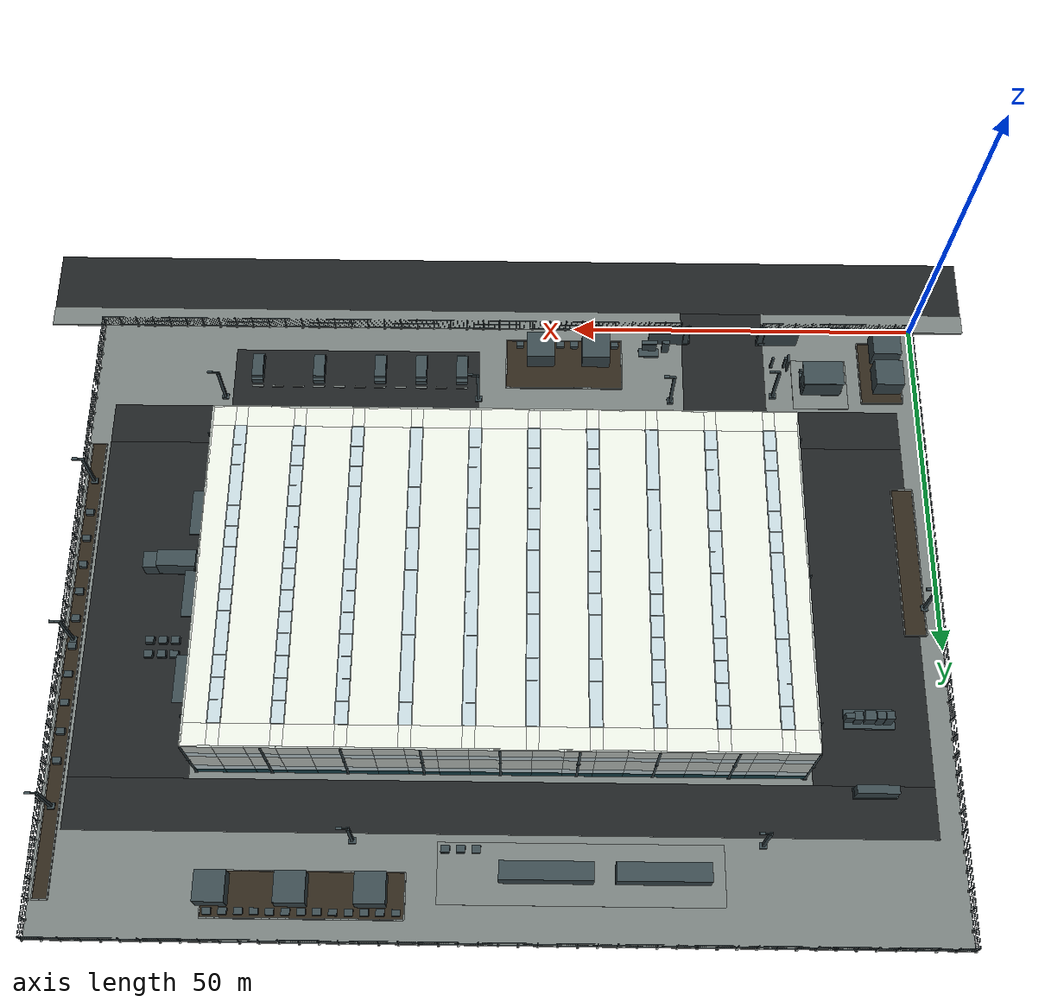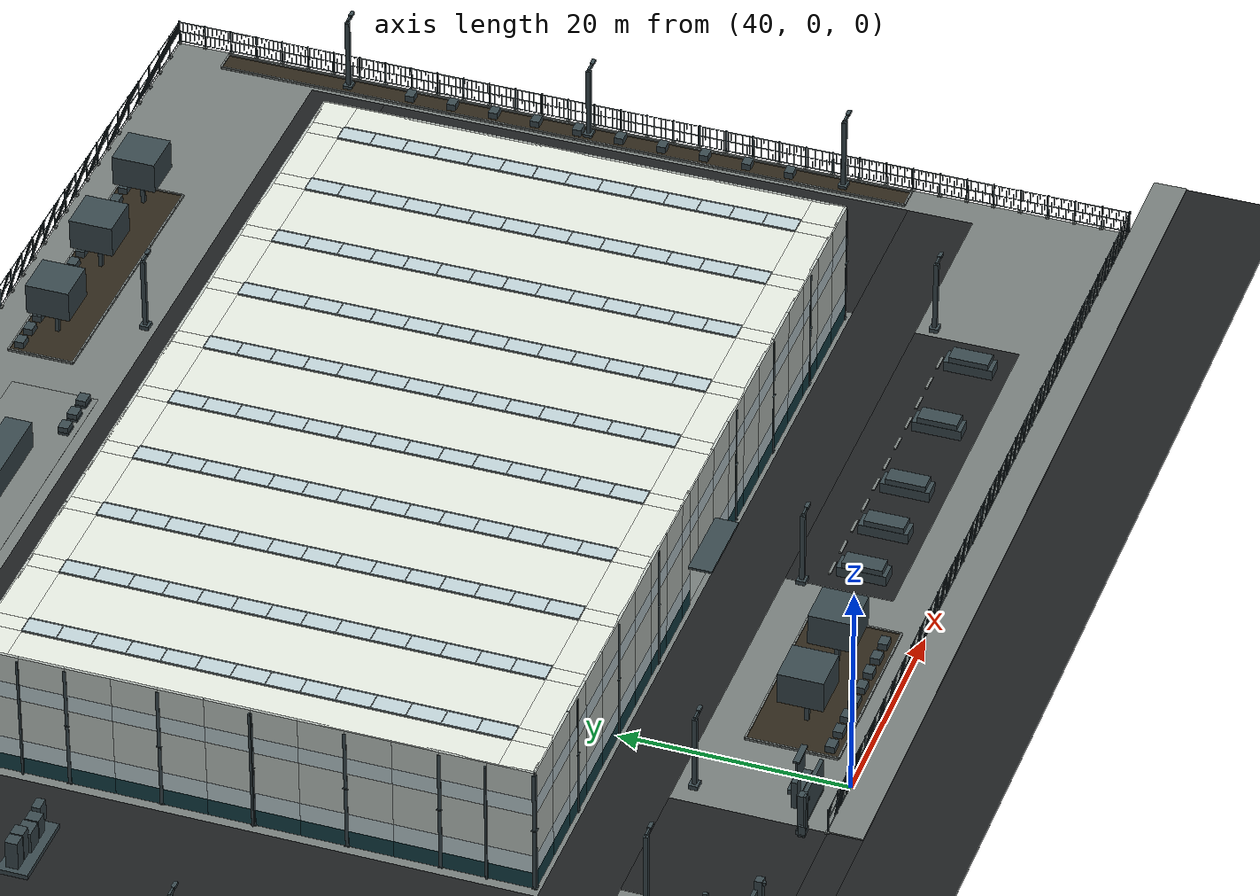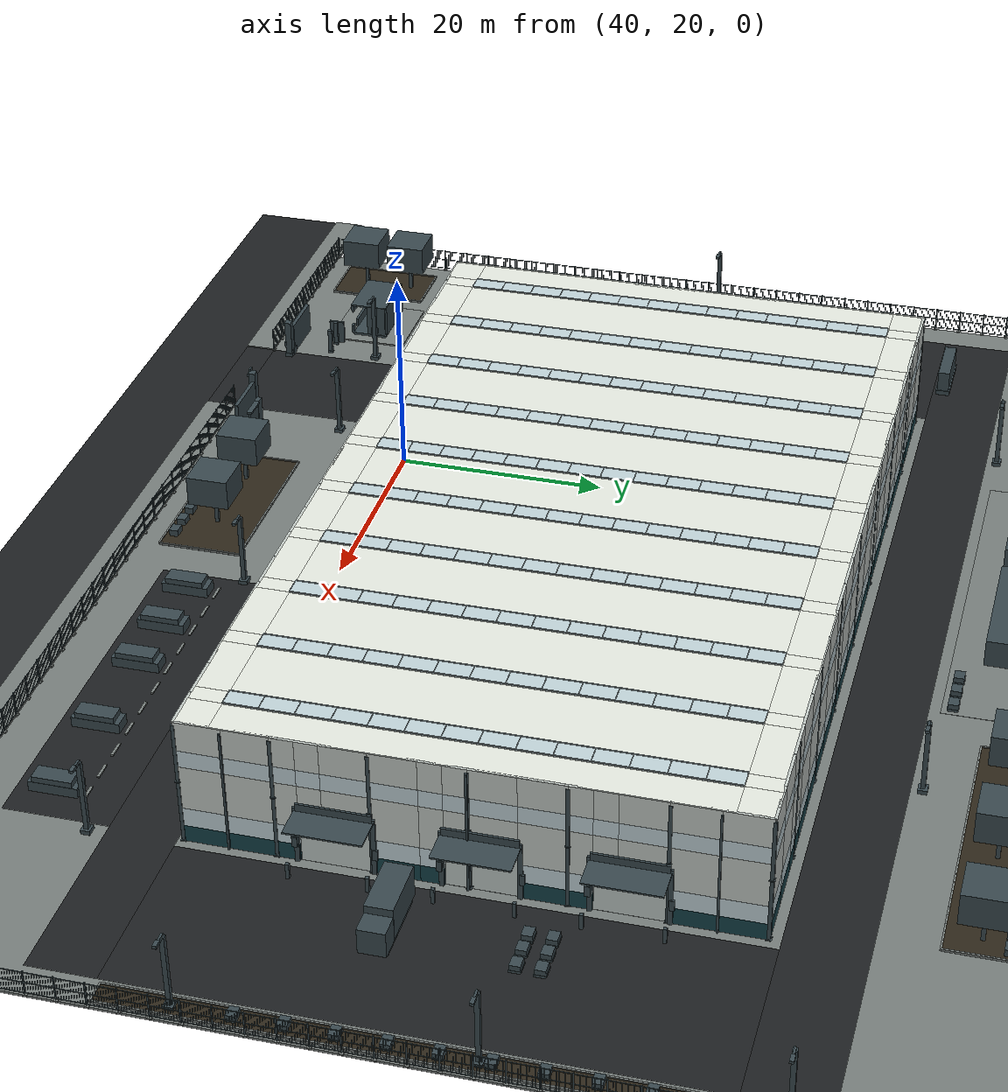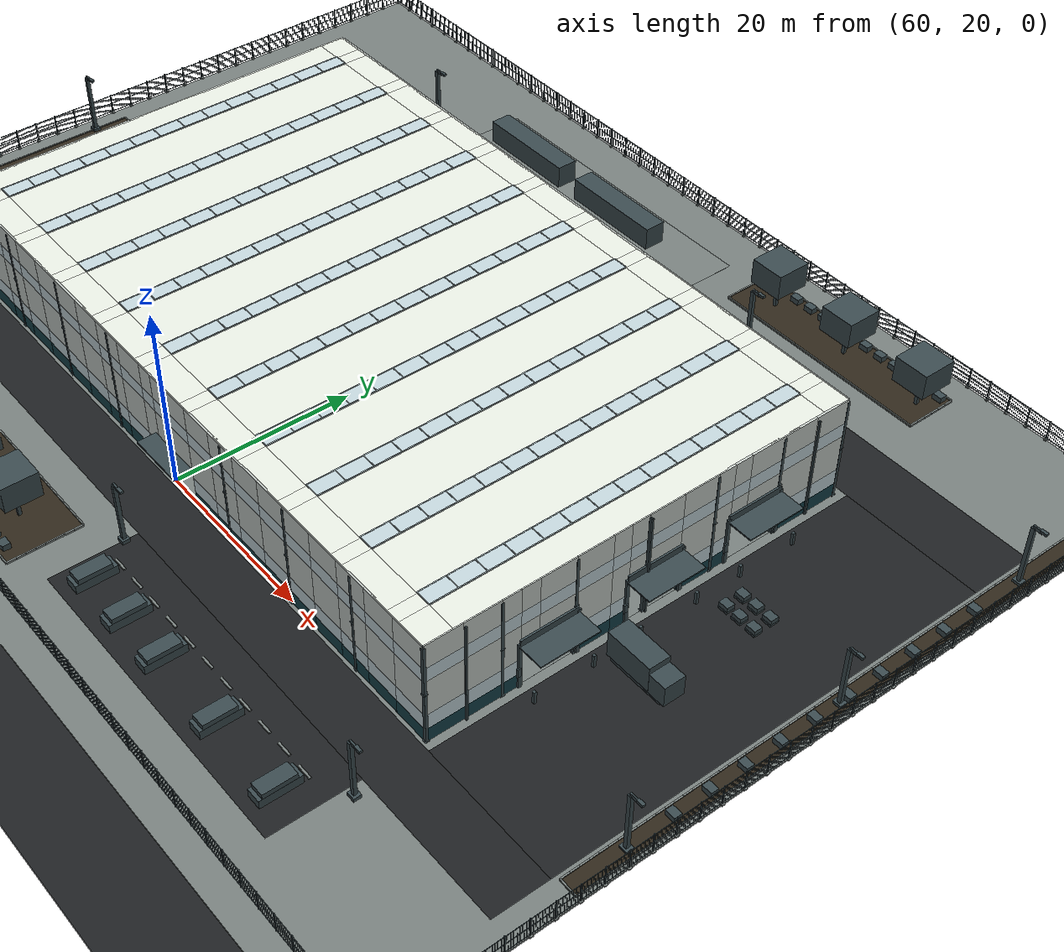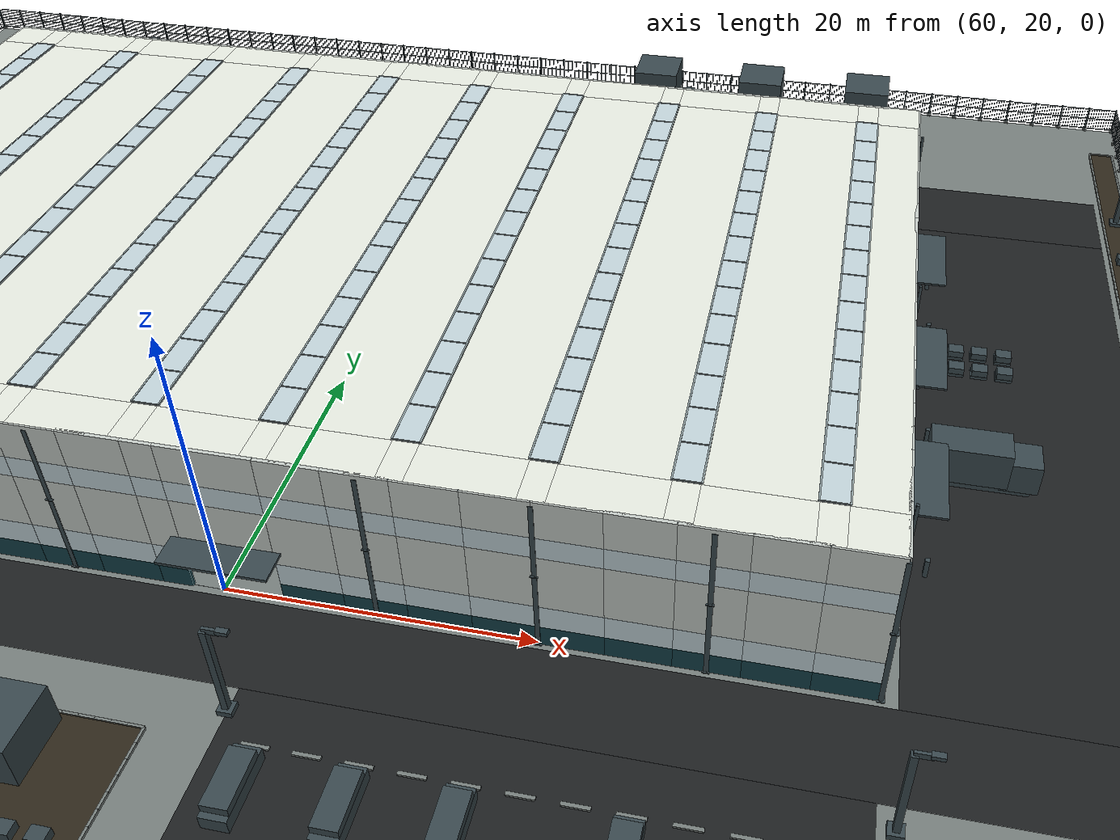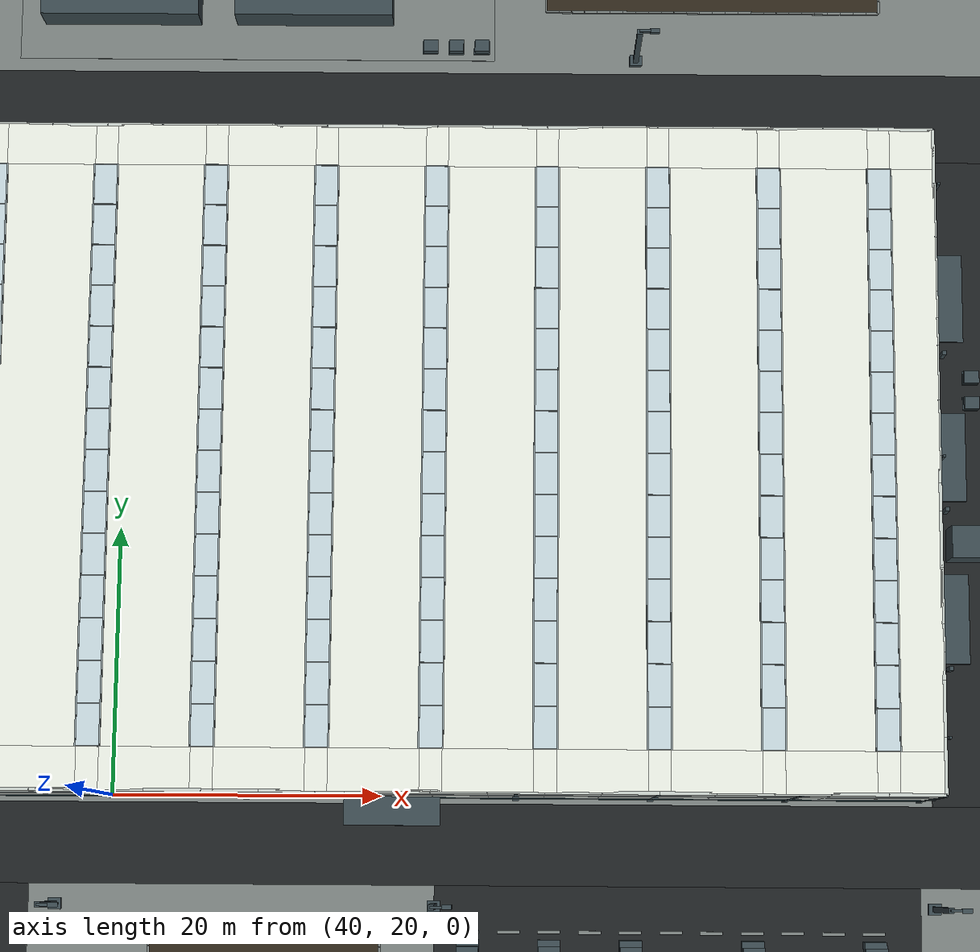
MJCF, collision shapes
<?xml version='1.0' encoding='utf-8'?>
<mujoco model="DOSO factory workshop 2.0.0">
  <compiler angle="radian" autolimits="true" strippath="false" />
  <option timestep="0.005" gravity="0 0 -9.81" integrator="Euler" solver="Newton" iterations="100" />
  <statistic center="60 45 4" extent="75" />
  <visual>
    <global azimuth="125" elevation="-38" fovy="50" offwidth="1920" offheight="1080" />
    <headlight ambient=".35 .35 .35" diffuse="0 0 0" specular="0 0 0" />
    <quality shadowsize="4096" offsamples="4" />
    <map znear=".001" zfar="10" shadowclip="1.5" />
  </visual>
  <asset>
    <texture name="fw_sky" type="skybox" builtin="gradient" rgb1=".70 .78 .82" rgb2=".93 .94 .91" width="512" height="3072" />
    <texture name="fw_floor_tex" type="2d" builtin="checker" rgb1=".47 .49 .47" rgb2=".49 .51 .49" width="128" height="128" />
    <material name="fw_concrete" rgba=".46 .49 .48 1" specular=".15" shininess=".15" />
    <material name="fw_wall" rgba=".76 .79 .77 1" specular=".15" shininess=".15" />
    <material name="fw_teal" rgba=".075 .25 .28 1" specular=".15" shininess=".15" />
    <material name="fw_steel" rgba=".22 .28 .30 1" specular=".15" shininess=".15" />
    <material name="fw_silver" rgba=".56 .62 .63 1" specular=".15" shininess=".15" />
    <material name="fw_blue" rgba=".055 .16 .25 1" specular=".15" shininess=".15" />
    <material name="fw_orange" rgba=".83 .30 .07 1" specular=".15" shininess=".15" />
    <material name="fw_yellow" rgba=".96 .69 .12 1" specular=".15" shininess=".15" />
    <material name="fw_black" rgba=".035 .05 .055 1" specular=".15" shininess=".15" />
    <material name="fw_glass" rgba=".065 .14 .17 1" specular=".15" shininess=".15" />
    <material name="fw_wood" rgba=".52 .36 .20 1" specular=".15" shininess=".15" />
    <material name="fw_carton" rgba=".64 .50 .31 1" specular=".15" shininess=".15" />
    <material name="fw_tape" rgba=".80 .69 .49 1" specular=".15" shininess=".15" />
    <material name="fw_white" rgba=".89 .91 .87 1" specular=".15" shininess=".15" emission=".15" />
    <material name="fw_green" rgba=".15 .76 .41 1" specular=".15" shininess=".15" emission=".15" />
    <material name="fw_red" rgba=".80 .095 .045 1" specular=".15" shininess=".15" />
    <material name="fw_screen" rgba=".08 .45 .57 1" specular=".15" shininess=".15" emission=".15" />
    <material name="fw_window" rgba=".75 .82 .84 1" specular=".15" shininess=".15" />
    <material name="fw_joint" rgba=".36 .39 .38 1" specular=".15" shininess=".15" />
    <material name="fw_floor" texture="fw_floor_tex" texrepeat="15 10" texuniform="false" specular=".08" shininess=".06" />
    <material name="fw_asphalt" rgba=".115 .125 .13 1" specular=".03" shininess=".01" />
    <material name="fw_soil" rgba=".18 .15 .10 1" specular=".03" shininess=".01" />
    <material name="fw_grass" rgba=".21 .28 .12 1" specular=".03" shininess=".01" />
    <mesh name="ground_slab" file="../visual/native/ground_slab.obj" inertia="shell" />
    <texture name="ground_slab" type="2d" file="../visual/native/ground_slab.png" colorspace="linear" />
    <material name="ground_slab" texture="ground_slab" emission=".65" specular="0" shininess="0" />
    <mesh name="upper_slab" file="../visual/native/upper_slab.obj" inertia="shell" />
    <texture name="upper_slab" type="2d" file="../visual/native/upper_slab.png" colorspace="linear" />
    <material name="upper_slab" texture="upper_slab" emission=".65" specular="0" shininess="0" />
    <mesh name="stair_A" file="../visual/native/stair_A.obj" inertia="shell" />
    <texture name="stair_A" type="2d" file="../visual/native/stair_A.png" colorspace="linear" />
    <material name="stair_A" texture="stair_A" emission=".65" specular="0" shininess="0" />
    <mesh name="stair_B" file="../visual/native/stair_B.obj" inertia="shell" />
    <texture name="stair_B" type="2d" file="../visual/native/stair_B.png" colorspace="linear" />
    <material name="stair_B" texture="stair_B" emission=".65" specular="0" shininess="0" />
    <mesh name="structure" file="../visual/native/structure.obj" inertia="shell" />
    <texture name="structure" type="2d" file="../visual/native/structure.png" colorspace="linear" />
    <material name="structure" texture="structure" emission=".65" specular="0" shininess="0" />
    <mesh name="ground_equipment" file="../visual/native/ground_equipment.obj" inertia="shell" />
    <texture name="ground_equipment" type="2d" file="../visual/native/ground_equipment.png" colorspace="linear" />
    <material name="ground_equipment" texture="ground_equipment" emission=".65" specular="0" shininess="0" />
    <mesh name="upper_equipment" file="../visual/native/upper_equipment.obj" inertia="shell" />
    <texture name="upper_equipment" type="2d" file="../visual/native/upper_equipment.png" colorspace="linear" />
    <material name="upper_equipment" texture="upper_equipment" emission=".65" specular="0" shininess="0" />
    <mesh name="retained_machines" file="../visual/native/retained_machines.obj" inertia="shell" />
    <texture name="retained_machines" type="2d" file="../visual/native/retained_machines.png" colorspace="linear" />
    <material name="retained_machines" texture="retained_machines" emission=".65" specular="0" shininess="0" />
    <mesh name="retained_workstations" file="../visual/native/retained_workstations.obj" inertia="shell" />
    <texture name="retained_workstations" type="2d" file="../visual/native/retained_workstations.png" colorspace="linear" />
    <material name="retained_workstations" texture="retained_workstations" emission=".65" specular="0" shininess="0" />
    <mesh name="retained_warehouse" file="../visual/native/retained_warehouse.obj" inertia="shell" />
    <texture name="retained_warehouse" type="2d" file="../visual/native/retained_warehouse.png" colorspace="linear" />
    <material name="retained_warehouse" texture="retained_warehouse" emission=".65" specular="0" shininess="0" />
    <mesh name="retained_markings" file="../visual/native/retained_markings.obj" inertia="shell" />
    <texture name="retained_markings" type="2d" file="../visual/native/retained_markings.png" colorspace="linear" />
    <material name="retained_markings" texture="retained_markings" emission=".65" specular="0" shininess="0" />
    <mesh name="retained_cnc_compact" file="../visual/native/retained_cnc_compact.obj" inertia="shell" />
    <texture name="retained_cnc_compact" type="2d" file="../visual/native/retained_cnc_compact.png" colorspace="linear" />
    <material name="retained_cnc_compact" texture="retained_cnc_compact" emission=".65" specular="0" shininess="0" />
    <mesh name="retained_cnc_mill" file="../visual/native/retained_cnc_mill.obj" inertia="shell" />
    <texture name="retained_cnc_mill" type="2d" file="../visual/native/retained_cnc_mill.png" colorspace="linear" />
    <material name="retained_cnc_mill" texture="retained_cnc_mill" emission=".65" specular="0" shininess="0" />
    <mesh name="retained_cnc_vertical" file="../visual/native/retained_cnc_vertical.obj" inertia="shell" />
    <texture name="retained_cnc_vertical" type="2d" file="../visual/native/retained_cnc_vertical.png" colorspace="linear" />
    <material name="retained_cnc_vertical" texture="retained_cnc_vertical" emission=".65" specular="0" shininess="0" />
    <mesh name="retained_cnc_centre" file="../visual/native/retained_cnc_centre.obj" inertia="shell" />
    <texture name="retained_cnc_centre" type="2d" file="../visual/native/retained_cnc_centre.png" colorspace="linear" />
    <material name="retained_cnc_centre" texture="retained_cnc_centre" emission=".65" specular="0" shininess="0" />
    <mesh name="retained_services" file="../visual/native/retained_services.obj" inertia="shell" />
    <texture name="retained_services" type="2d" file="../visual/native/retained_services.png" colorspace="linear" />
    <material name="retained_services" texture="retained_services" emission=".65" specular="0" shininess="0" />
    <mesh name="upper_metrology_0" file="../visual/native/upper_metrology_0.obj" inertia="shell" />
    <texture name="upper_metrology_0" type="2d" file="../visual/native/upper_metrology_0.png" colorspace="linear" />
    <material name="upper_metrology_0" texture="upper_metrology_0" emission=".65" specular="0" shininess="0" />
    <mesh name="upper_test_cell_0" file="../visual/native/upper_test_cell_0.obj" inertia="shell" />
    <texture name="upper_test_cell_0" type="2d" file="../visual/native/upper_test_cell_0.png" colorspace="linear" />
    <material name="upper_test_cell_0" texture="upper_test_cell_0" emission=".65" specular="0" shininess="0" />
    <mesh name="upper_maintenance_0" file="../visual/native/upper_maintenance_0.obj" inertia="shell" />
    <texture name="upper_maintenance_0" type="2d" file="../visual/native/upper_maintenance_0.png" colorspace="linear" />
    <material name="upper_maintenance_0" texture="upper_maintenance_0" emission=".65" specular="0" shininess="0" />
    <mesh name="upper_console_0" file="../visual/native/upper_console_0.obj" inertia="shell" />
    <texture name="upper_console_0" type="2d" file="../visual/native/upper_console_0.png" colorspace="linear" />
    <material name="upper_console_0" texture="upper_console_0" emission=".65" specular="0" shininess="0" />
    <mesh name="exterior_guardhouse_0" file="../visual/native/exterior_guardhouse_0.obj" inertia="shell" />
    <texture name="exterior_guardhouse_0" type="2d" file="../visual/native/exterior_guardhouse_0.png" colorspace="linear" />
    <material name="exterior_guardhouse_0" texture="exterior_guardhouse_0" emission=".65" specular="0" shininess="0" />
    <mesh name="exterior_loading_bay_0" file="../visual/native/exterior_loading_bay_0.obj" inertia="shell" />
    <texture name="exterior_loading_bay_0" type="2d" file="../visual/native/exterior_loading_bay_0.png" colorspace="linear" />
    <material name="exterior_loading_bay_0" texture="exterior_loading_bay_0" emission=".65" specular="0" shininess="0" />
    <mesh name="exterior_air_system_0" file="../visual/native/exterior_air_system_0.obj" inertia="shell" />
    <texture name="exterior_air_system_0" type="2d" file="../visual/native/exterior_air_system_0.png" colorspace="linear" />
    <material name="exterior_air_system_0" texture="exterior_air_system_0" emission=".65" specular="0" shininess="0" />
    <mesh name="exterior_switchgear_0" file="../visual/native/exterior_switchgear_0.obj" inertia="shell" />
    <texture name="exterior_switchgear_0" type="2d" file="../visual/native/exterior_switchgear_0.png" colorspace="linear" />
    <material name="exterior_switchgear_0" texture="exterior_switchgear_0" emission=".65" specular="0" shininess="0" />
    <mesh name="exterior_entry_gate_0" file="../visual/native/exterior_entry_gate_0.obj" inertia="shell" />
    <texture name="exterior_entry_gate_0" type="2d" file="../visual/native/exterior_entry_gate_0.png" colorspace="linear" />
    <material name="exterior_entry_gate_0" texture="exterior_entry_gate_0" emission=".65" specular="0" shininess="0" />
    <mesh name="exterior_street_light_0" file="../visual/native/exterior_street_light_0.obj" inertia="shell" />
    <texture name="exterior_street_light_0" type="2d" file="../visual/native/exterior_street_light_0.png" colorspace="linear" />
    <material name="exterior_street_light_0" texture="exterior_street_light_0" emission=".65" specular="0" shininess="0" />
    <mesh name="exterior_delivery_truck_0" file="../visual/native/exterior_delivery_truck_0.obj" inertia="shell" />
    <texture name="exterior_delivery_truck_0" type="2d" file="../visual/native/exterior_delivery_truck_0.png" colorspace="linear" />
    <material name="exterior_delivery_truck_0" texture="exterior_delivery_truck_0" emission=".65" specular="0" shininess="0" />
    <mesh name="exterior_shipping_container_0" file="../visual/native/exterior_shipping_container_0.obj" inertia="shell" />
    <texture name="exterior_shipping_container_0" type="2d" file="../visual/native/exterior_shipping_container_0.png" colorspace="linear" />
    <material name="exterior_shipping_container_0" texture="exterior_shipping_container_0" emission=".65" specular="0" shininess="0" />
    <mesh name="exterior_pallet_cargo_0" file="../visual/native/exterior_pallet_cargo_0.obj" inertia="shell" />
    <texture name="exterior_pallet_cargo_0" type="2d" file="../visual/native/exterior_pallet_cargo_0.png" colorspace="linear" />
    <material name="exterior_pallet_cargo_0" texture="exterior_pallet_cargo_0" emission=".65" specular="0" shininess="0" />
    <mesh name="exterior_parked_car_0" file="../visual/native/exterior_parked_car_0.obj" inertia="shell" />
    <texture name="exterior_parked_car_0" type="2d" file="../visual/native/exterior_parked_car_0.png" colorspace="linear" />
    <material name="exterior_parked_car_0" texture="exterior_parked_car_0" emission=".65" specular="0" shininess="0" />
    <mesh name="exterior_parked_car_silver_0" file="../visual/native/exterior_parked_car_silver_0.obj" inertia="shell" />
    <texture name="exterior_parked_car_silver_0" type="2d" file="../visual/native/exterior_parked_car_silver_0.png" colorspace="linear" />
    <material name="exterior_parked_car_silver_0" texture="exterior_parked_car_silver_0" emission=".65" specular="0" shininess="0" />
    <mesh name="exterior_parked_car_white_0" file="../visual/native/exterior_parked_car_white_0.obj" inertia="shell" />
    <texture name="exterior_parked_car_white_0" type="2d" file="../visual/native/exterior_parked_car_white_0.png" colorspace="linear" />
    <material name="exterior_parked_car_white_0" texture="exterior_parked_car_white_0" emission=".65" specular="0" shininess="0" />
    <mesh name="shell_south" file="../visual/native/shell_south.obj" inertia="shell" />
    <texture name="shell_south" type="2d" file="../visual/native/shell_south.png" colorspace="linear" />
    <material name="shell_south" texture="shell_south" emission=".65" specular="0" shininess="0" />
    <mesh name="shell_north" file="../visual/native/shell_north.obj" inertia="shell" />
    <texture name="shell_north" type="2d" file="../visual/native/shell_north.png" colorspace="linear" />
    <material name="shell_north" texture="shell_north" emission=".65" specular="0" shininess="0" />
    <mesh name="shell_west" file="../visual/native/shell_west.obj" inertia="shell" />
    <texture name="shell_west" type="2d" file="../visual/native/shell_west.png" colorspace="linear" />
    <material name="shell_west" texture="shell_west" emission=".65" specular="0" shininess="0" />
    <mesh name="shell_east" file="../visual/native/shell_east.obj" inertia="shell" />
    <texture name="shell_east" type="2d" file="../visual/native/shell_east.png" colorspace="linear" />
    <material name="shell_east" texture="shell_east" emission=".65" specular="0" shininess="0" />
    <mesh name="roof" file="../visual/native/roof.obj" inertia="shell" />
    <texture name="roof" type="2d" file="../visual/native/roof.png" colorspace="linear" />
    <material name="roof" texture="roof" emission=".65" specular="0" shininess="0" />
    <mesh name="exterior" file="../visual/native/exterior.obj" inertia="shell" />
    <texture name="exterior" type="2d" file="../visual/native/exterior.png" colorspace="linear" />
    <material name="exterior" texture="exterior" emission=".65" specular="0" shininess="0" />
    <mesh name="site_paving" file="../visual/native/site_paving.obj" inertia="shell" />
    <texture name="site_paving" type="2d" file="../visual/native/site_paving.png" colorspace="linear" />
    <material name="site_paving" texture="site_paving" emission=".65" specular="0" shininess="0" />
    <mesh name="site_mark" file="../visual/native/site_mark.obj" inertia="shell" />
    <texture name="site_mark" type="2d" file="../visual/native/site_mark.png" colorspace="linear" />
    <material name="site_mark" texture="site_mark" emission=".65" specular="0" shininess="0" />
    <mesh name="site_drain" file="../visual/native/site_drain.obj" inertia="shell" />
    <texture name="site_drain" type="2d" file="../visual/native/site_drain.png" colorspace="linear" />
    <material name="site_drain" texture="site_drain" emission=".65" specular="0" shininess="0" />
    <mesh name="exterior_facade_services_0" file="../visual/native/exterior_facade_services_0.obj" inertia="shell" />
    <texture name="exterior_facade_services_0" type="2d" file="../visual/native/exterior_facade_services_0.png" colorspace="linear" />
    <material name="exterior_facade_services_0" texture="exterior_facade_services_0" emission=".65" specular="0" shininess="0" />
    <mesh name="site_dressing_groundcover" file="../visual/native/site_dressing_groundcover.obj" inertia="shell" />
    <texture name="site_dressing_groundcover" type="2d" file="../visual/native/site_dressing_groundcover.png" colorspace="linear" />
    <material name="site_dressing_groundcover" texture="site_dressing_groundcover" emission=".65" specular="0" shininess="0" />
    <mesh name="site_dressing_mulch_and_curb_dirt" file="../visual/native/site_dressing_mulch_and_curb_dirt.obj" inertia="shell" />
    <texture name="site_dressing_mulch_and_curb_dirt" type="2d" file="../visual/native/site_dressing_mulch_and_curb_dirt.png" colorspace="linear" />
    <material name="site_dressing_mulch_and_curb_dirt" texture="site_dressing_mulch_and_curb_dirt" emission=".65" specular="0" shininess="0" />
    <mesh name="site_dressing_leaves_and_gravel" file="../visual/native/site_dressing_leaves_and_gravel.obj" inertia="shell" />
    <texture name="site_dressing_leaves_and_gravel" type="2d" file="../visual/native/site_dressing_leaves_and_gravel.png" colorspace="linear" />
    <material name="site_dressing_leaves_and_gravel" texture="site_dressing_leaves_and_gravel" emission=".65" specular="0" shininess="0" />
    <mesh name="site_land" file="../visual/native/site_land.obj" inertia="shell" />
    <texture name="site_land" type="2d" file="../visual/native/site_land.png" colorspace="linear" />
    <material name="site_land" texture="site_land" emission=".65" specular="0" shininess="0" />
    <mesh name="site_land_closeup" file="../visual/native/site_land_closeup.obj" inertia="shell" />
    <texture name="site_land_closeup" type="2d" file="../visual/native/site_land_closeup.png" colorspace="linear" />
    <material name="site_land_closeup" texture="site_land_closeup" emission=".65" specular="0" shininess="0" />
    <mesh name="exterior_tree_0" file="../visual/native/exterior_tree_0.obj" inertia="shell" />
    <texture name="exterior_tree_0" type="2d" file="../visual/native/exterior_tree_0.png" colorspace="linear" />
    <material name="exterior_tree_0" texture="exterior_tree_0" emission=".65" specular="0" shininess="0" />
    <mesh name="exterior_tree_airy_0" file="../visual/native/exterior_tree_airy_0.obj" inertia="shell" />
    <texture name="exterior_tree_airy_0" type="2d" file="../visual/native/exterior_tree_airy_0.png" colorspace="linear" />
    <material name="exterior_tree_airy_0" texture="exterior_tree_airy_0" emission=".65" specular="0" shininess="0" />
    <mesh name="exterior_shrub_0" file="../visual/native/exterior_shrub_0.obj" inertia="shell" />
    <texture name="exterior_shrub_0" type="2d" file="../visual/native/exterior_shrub_0.png" colorspace="linear" />
    <material name="exterior_shrub_0" texture="exterior_shrub_0" emission=".65" specular="0" shininess="0" />
  </asset>
  <worldbody>
    <geom name="fw_r2_ground_floor" type="box" pos="60 44 -0.095" size="40 24 0.1" material="fw_concrete" euler="0 0 0" group="4" contype="1" conaffinity="1" friction=".8 .01 .001" />
    <geom name="fw_r2_upper_slab0" type="box" pos="22 22 5.88" size="2 2 0.12" material="fw_concrete" euler="0 0 0" group="4" contype="1" conaffinity="1" friction=".8 .01 .001" />
    <geom name="fw_r2_upper_slab1" type="box" pos="22 28 5.88" size="2 4 0.12" material="fw_concrete" euler="0 0 0" group="4" contype="1" conaffinity="1" friction=".8 .01 .001" />
    <geom name="fw_r2_upper_slab2" type="box" pos="22 44 5.88" size="2 12 0.12" material="fw_concrete" euler="0 0 0" group="4" contype="1" conaffinity="1" friction=".8 .01 .001" />
    <geom name="fw_r2_upper_slab3" type="box" pos="22 60 5.88" size="2 4 0.12" material="fw_concrete" euler="0 0 0" group="4" contype="1" conaffinity="1" friction=".8 .01 .001" />
    <geom name="fw_r2_upper_slab4" type="box" pos="22 66 5.88" size="2 2 0.12" material="fw_concrete" euler="0 0 0" group="4" contype="1" conaffinity="1" friction=".8 .01 .001" />
    <geom name="fw_r2_upper_slab5" type="box" pos="27 22 5.88" size="3 2 0.12" material="fw_concrete" euler="0 0 0" group="4" contype="1" conaffinity="1" friction=".8 .01 .001" />
    <geom name="fw_r2_upper_slab6" type="box" pos="27 44 5.88" size="3 12 0.12" material="fw_concrete" euler="0 0 0" group="4" contype="1" conaffinity="1" friction=".8 .01 .001" />
    <geom name="fw_r2_upper_slab7" type="box" pos="27 60 5.88" size="3 4 0.12" material="fw_concrete" euler="0 0 0" group="4" contype="1" conaffinity="1" friction=".8 .01 .001" />
    <geom name="fw_r2_upper_slab8" type="box" pos="27 66 5.88" size="3 2 0.12" material="fw_concrete" euler="0 0 0" group="4" contype="1" conaffinity="1" friction=".8 .01 .001" />
    <geom name="fw_r2_upper_slab9" type="box" pos="60 22 5.88" size="30 2 0.12" material="fw_concrete" euler="0 0 0" group="4" contype="1" conaffinity="1" friction=".8 .01 .001" />
    <geom name="fw_r2_upper_slab10" type="box" pos="60 28 5.88" size="30 4 0.12" material="fw_concrete" euler="0 0 0" group="4" contype="1" conaffinity="1" friction=".8 .01 .001" />
    <geom name="fw_r2_upper_slab11" type="box" pos="60 44 5.88" size="30 12 0.12" material="fw_concrete" euler="0 0 0" group="4" contype="1" conaffinity="1" friction=".8 .01 .001" />
    <geom name="fw_r2_upper_slab12" type="box" pos="60 60 5.88" size="30 4 0.12" material="fw_concrete" euler="0 0 0" group="4" contype="1" conaffinity="1" friction=".8 .01 .001" />
    <geom name="fw_r2_upper_slab13" type="box" pos="60 66 5.88" size="30 2 0.12" material="fw_concrete" euler="0 0 0" group="4" contype="1" conaffinity="1" friction=".8 .01 .001" />
    <geom name="fw_r2_upper_slab14" type="box" pos="93 22 5.88" size="3 2 0.12" material="fw_concrete" euler="0 0 0" group="4" contype="1" conaffinity="1" friction=".8 .01 .001" />
    <geom name="fw_r2_upper_slab15" type="box" pos="93 28 5.88" size="3 4 0.12" material="fw_concrete" euler="0 0 0" group="4" contype="1" conaffinity="1" friction=".8 .01 .001" />
    <geom name="fw_r2_upper_slab16" type="box" pos="93 44 5.88" size="3 12 0.12" material="fw_concrete" euler="0 0 0" group="4" contype="1" conaffinity="1" friction=".8 .01 .001" />
    <geom name="fw_r2_upper_slab17" type="box" pos="93 66 5.88" size="3 2 0.12" material="fw_concrete" euler="0 0 0" group="4" contype="1" conaffinity="1" friction=".8 .01 .001" />
    <geom name="fw_r2_upper_slab18" type="box" pos="98 22 5.88" size="2 2 0.12" material="fw_concrete" euler="0 0 0" group="4" contype="1" conaffinity="1" friction=".8 .01 .001" />
    <geom name="fw_r2_upper_slab19" type="box" pos="98 28 5.88" size="2 4 0.12" material="fw_concrete" euler="0 0 0" group="4" contype="1" conaffinity="1" friction=".8 .01 .001" />
    <geom name="fw_r2_upper_slab20" type="box" pos="98 44 5.88" size="2 12 0.12" material="fw_concrete" euler="0 0 0" group="4" contype="1" conaffinity="1" friction=".8 .01 .001" />
    <geom name="fw_r2_upper_slab21" type="box" pos="98 60 5.88" size="2 4 0.12" material="fw_concrete" euler="0 0 0" group="4" contype="1" conaffinity="1" friction=".8 .01 .001" />
    <geom name="fw_r2_upper_slab22" type="box" pos="98 66 5.88" size="2 2 0.12" material="fw_concrete" euler="0 0 0" group="4" contype="1" conaffinity="1" friction=".8 .01 .001" />
    <geom name="fw_r2_stair_A_f0_tread00" type="box" pos="25.7 24.15 0.09" size="1.1 0.15 0.06" material="fw_concrete" euler="0 0 0" group="4" contype="1" conaffinity="1" friction=".8 .01 .001" />
    <geom name="fw_r2_stair_A_f0_tread01" type="box" pos="25.7 24.45 0.24" size="1.1 0.15 0.06" material="fw_concrete" euler="0 0 0" group="4" contype="1" conaffinity="1" friction=".8 .01 .001" />
    <geom name="fw_r2_stair_A_f0_tread02" type="box" pos="25.7 24.75 0.39" size="1.1 0.15 0.06" material="fw_concrete" euler="0 0 0" group="4" contype="1" conaffinity="1" friction=".8 .01 .001" />
    <geom name="fw_r2_stair_A_f0_tread03" type="box" pos="25.7 25.05 0.54" size="1.1 0.15 0.06" material="fw_concrete" euler="0 0 0" group="4" contype="1" conaffinity="1" friction=".8 .01 .001" />
    <geom name="fw_r2_stair_A_f0_tread04" type="box" pos="25.7 25.35 0.69" size="1.1 0.15 0.06" material="fw_concrete" euler="0 0 0" group="4" contype="1" conaffinity="1" friction=".8 .01 .001" />
    <geom name="fw_r2_stair_A_f0_tread05" type="box" pos="25.7 25.65 0.84" size="1.1 0.15 0.06" material="fw_concrete" euler="0 0 0" group="4" contype="1" conaffinity="1" friction=".8 .01 .001" />
    <geom name="fw_r2_stair_A_f0_tread06" type="box" pos="25.7 25.95 0.99" size="1.1 0.15 0.06" material="fw_concrete" euler="0 0 0" group="4" contype="1" conaffinity="1" friction=".8 .01 .001" />
    <geom name="fw_r2_stair_A_f0_tread07" type="box" pos="25.7 26.25 1.14" size="1.1 0.15 0.06" material="fw_concrete" euler="0 0 0" group="4" contype="1" conaffinity="1" friction=".8 .01 .001" />
    <geom name="fw_r2_stair_A_f0_tread08" type="box" pos="25.7 26.55 1.29" size="1.1 0.15 0.06" material="fw_concrete" euler="0 0 0" group="4" contype="1" conaffinity="1" friction=".8 .01 .001" />
    <geom name="fw_r2_stair_A_f0_tread09" type="box" pos="25.7 26.85 1.44" size="1.1 0.15 0.06" material="fw_concrete" euler="0 0 0" group="4" contype="1" conaffinity="1" friction=".8 .01 .001" />
    <geom name="fw_r2_stair_A_f0_tread10" type="box" pos="25.7 27.15 1.59" size="1.1 0.15 0.06" material="fw_concrete" euler="0 0 0" group="4" contype="1" conaffinity="1" friction=".8 .01 .001" />
    <geom name="fw_r2_stair_A_f0_tread11" type="box" pos="25.7 27.45 1.74" size="1.1 0.15 0.06" material="fw_concrete" euler="0 0 0" group="4" contype="1" conaffinity="1" friction=".8 .01 .001" />
    <geom name="fw_r2_stair_A_f0_tread12" type="box" pos="25.7 27.75 1.89" size="1.1 0.15 0.06" material="fw_concrete" euler="0 0 0" group="4" contype="1" conaffinity="1" friction=".8 .01 .001" />
    <geom name="fw_r2_stair_A_f0_tread13" type="box" pos="25.7 28.05 2.04" size="1.1 0.15 0.06" material="fw_concrete" euler="0 0 0" group="4" contype="1" conaffinity="1" friction=".8 .01 .001" />
    <geom name="fw_r2_stair_A_f0_tread14" type="box" pos="25.7 28.35 2.19" size="1.1 0.15 0.06" material="fw_concrete" euler="0 0 0" group="4" contype="1" conaffinity="1" friction=".8 .01 .001" />
    <geom name="fw_r2_stair_A_f0_tread15" type="box" pos="25.7 28.65 2.34" size="1.1 0.15 0.06" material="fw_concrete" euler="0 0 0" group="4" contype="1" conaffinity="1" friction=".8 .01 .001" />
    <geom name="fw_r2_stair_A_f0_tread16" type="box" pos="25.7 28.95 2.49" size="1.1 0.15 0.06" material="fw_concrete" euler="0 0 0" group="4" contype="1" conaffinity="1" friction=".8 .01 .001" />
    <geom name="fw_r2_stair_A_f0_tread17" type="box" pos="25.7 29.25 2.64" size="1.1 0.15 0.06" material="fw_concrete" euler="0 0 0" group="4" contype="1" conaffinity="1" friction=".8 .01 .001" />
    <geom name="fw_r2_stair_A_f0_tread18" type="box" pos="25.7 29.55 2.79" size="1.1 0.15 0.06" material="fw_concrete" euler="0 0 0" group="4" contype="1" conaffinity="1" friction=".8 .01 .001" />
    <geom name="fw_r2_stair_A_f0_tread19" type="box" pos="25.7 29.85 2.94" size="1.1 0.15 0.06" material="fw_concrete" euler="0 0 0" group="4" contype="1" conaffinity="1" friction=".8 .01 .001" />
    <geom name="fw_r2_stair_A_f0_stringer0" type="box" pos="24.52 27 1.32" size="0.07 3.3541 0.07" material="fw_steel" euler="0.463648 0 0" group="4" contype="1" conaffinity="1" friction=".8 .01 .001" />
    <geom name="fw_r2_stair_A_f0_handrail0" type="box" pos="24.52 27 2.6" size="0.03 3.3541 0.03" material="fw_yellow" euler="0.463648 0 0" group="4" contype="1" conaffinity="1" friction=".8 .01 .001" />
    <geom name="fw_r2_stair_A_f0_upright0_0" type="box" pos="24.52 24.15 0.7" size="0.03 0.03 0.55" material="fw_steel" euler="0 0 0" group="4" contype="1" conaffinity="1" friction=".8 .01 .001" />
    <geom name="fw_r2_stair_A_f0_upright0_4" type="box" pos="24.52 25.35 1.3" size="0.03 0.03 0.55" material="fw_steel" euler="0 0 0" group="4" contype="1" conaffinity="1" friction=".8 .01 .001" />
    <geom name="fw_r2_stair_A_f0_upright0_8" type="box" pos="24.52 26.55 1.9" size="0.03 0.03 0.55" material="fw_steel" euler="0 0 0" group="4" contype="1" conaffinity="1" friction=".8 .01 .001" />
    <geom name="fw_r2_stair_A_f0_upright0_12" type="box" pos="24.52 27.75 2.5" size="0.03 0.03 0.55" material="fw_steel" euler="0 0 0" group="4" contype="1" conaffinity="1" friction=".8 .01 .001" />
    <geom name="fw_r2_stair_A_f0_upright0_16" type="box" pos="24.52 28.95 3.1" size="0.03 0.03 0.55" material="fw_steel" euler="0 0 0" group="4" contype="1" conaffinity="1" friction=".8 .01 .001" />
    <geom name="fw_r2_stair_A_f0_stringer1" type="box" pos="26.88 27 1.32" size="0.07 3.3541 0.07" material="fw_steel" euler="0.463648 0 0" group="4" contype="1" conaffinity="1" friction=".8 .01 .001" />
    <geom name="fw_r2_stair_A_f0_handrail1" type="box" pos="26.88 27 2.6" size="0.03 3.3541 0.03" material="fw_yellow" euler="0.463648 0 0" group="4" contype="1" conaffinity="1" friction=".8 .01 .001" />
    <geom name="fw_r2_stair_A_f0_upright1_0" type="box" pos="26.88 24.15 0.7" size="0.03 0.03 0.55" material="fw_steel" euler="0 0 0" group="4" contype="1" conaffinity="1" friction=".8 .01 .001" />
    <geom name="fw_r2_stair_A_f0_upright1_4" type="box" pos="26.88 25.35 1.3" size="0.03 0.03 0.55" material="fw_steel" euler="0 0 0" group="4" contype="1" conaffinity="1" friction=".8 .01 .001" />
    <geom name="fw_r2_stair_A_f0_upright1_8" type="box" pos="26.88 26.55 1.9" size="0.03 0.03 0.55" material="fw_steel" euler="0 0 0" group="4" contype="1" conaffinity="1" friction=".8 .01 .001" />
    <geom name="fw_r2_stair_A_f0_upright1_12" type="box" pos="26.88 27.75 2.5" size="0.03 0.03 0.55" material="fw_steel" euler="0 0 0" group="4" contype="1" conaffinity="1" friction=".8 .01 .001" />
    <geom name="fw_r2_stair_A_f0_upright1_16" type="box" pos="26.88 28.95 3.1" size="0.03 0.03 0.55" material="fw_steel" euler="0 0 0" group="4" contype="1" conaffinity="1" friction=".8 .01 .001" />
    <geom name="fw_r2_stair_A_f1_tread00" type="box" pos="28.3 29.85 3.09" size="1.1 0.15 0.06" material="fw_concrete" euler="0 0 0" group="4" contype="1" conaffinity="1" friction=".8 .01 .001" />
    <geom name="fw_r2_stair_A_f1_tread01" type="box" pos="28.3 29.55 3.24" size="1.1 0.15 0.06" material="fw_concrete" euler="0 0 0" group="4" contype="1" conaffinity="1" friction=".8 .01 .001" />
    <geom name="fw_r2_stair_A_f1_tread02" type="box" pos="28.3 29.25 3.39" size="1.1 0.15 0.06" material="fw_concrete" euler="0 0 0" group="4" contype="1" conaffinity="1" friction=".8 .01 .001" />
    <geom name="fw_r2_stair_A_f1_tread03" type="box" pos="28.3 28.95 3.54" size="1.1 0.15 0.06" material="fw_concrete" euler="0 0 0" group="4" contype="1" conaffinity="1" friction=".8 .01 .001" />
    <geom name="fw_r2_stair_A_f1_tread04" type="box" pos="28.3 28.65 3.69" size="1.1 0.15 0.06" material="fw_concrete" euler="0 0 0" group="4" contype="1" conaffinity="1" friction=".8 .01 .001" />
    <geom name="fw_r2_stair_A_f1_tread05" type="box" pos="28.3 28.35 3.84" size="1.1 0.15 0.06" material="fw_concrete" euler="0 0 0" group="4" contype="1" conaffinity="1" friction=".8 .01 .001" />
    <geom name="fw_r2_stair_A_f1_tread06" type="box" pos="28.3 28.05 3.99" size="1.1 0.15 0.06" material="fw_concrete" euler="0 0 0" group="4" contype="1" conaffinity="1" friction=".8 .01 .001" />
    <geom name="fw_r2_stair_A_f1_tread07" type="box" pos="28.3 27.75 4.14" size="1.1 0.15 0.06" material="fw_concrete" euler="0 0 0" group="4" contype="1" conaffinity="1" friction=".8 .01 .001" />
    <geom name="fw_r2_stair_A_f1_tread08" type="box" pos="28.3 27.45 4.29" size="1.1 0.15 0.06" material="fw_concrete" euler="0 0 0" group="4" contype="1" conaffinity="1" friction=".8 .01 .001" />
    <geom name="fw_r2_stair_A_f1_tread09" type="box" pos="28.3 27.15 4.44" size="1.1 0.15 0.06" material="fw_concrete" euler="0 0 0" group="4" contype="1" conaffinity="1" friction=".8 .01 .001" />
    <geom name="fw_r2_stair_A_f1_tread10" type="box" pos="28.3 26.85 4.59" size="1.1 0.15 0.06" material="fw_concrete" euler="0 0 0" group="4" contype="1" conaffinity="1" friction=".8 .01 .001" />
    <geom name="fw_r2_stair_A_f1_tread11" type="box" pos="28.3 26.55 4.74" size="1.1 0.15 0.06" material="fw_concrete" euler="0 0 0" group="4" contype="1" conaffinity="1" friction=".8 .01 .001" />
    <geom name="fw_r2_stair_A_f1_tread12" type="box" pos="28.3 26.25 4.89" size="1.1 0.15 0.06" material="fw_concrete" euler="0 0 0" group="4" contype="1" conaffinity="1" friction=".8 .01 .001" />
    <geom name="fw_r2_stair_A_f1_tread13" type="box" pos="28.3 25.95 5.04" size="1.1 0.15 0.06" material="fw_concrete" euler="0 0 0" group="4" contype="1" conaffinity="1" friction=".8 .01 .001" />
    <geom name="fw_r2_stair_A_f1_tread14" type="box" pos="28.3 25.65 5.19" size="1.1 0.15 0.06" material="fw_concrete" euler="0 0 0" group="4" contype="1" conaffinity="1" friction=".8 .01 .001" />
    <geom name="fw_r2_stair_A_f1_tread15" type="box" pos="28.3 25.35 5.34" size="1.1 0.15 0.06" material="fw_concrete" euler="0 0 0" group="4" contype="1" conaffinity="1" friction=".8 .01 .001" />
    <geom name="fw_r2_stair_A_f1_tread16" type="box" pos="28.3 25.05 5.49" size="1.1 0.15 0.06" material="fw_concrete" euler="0 0 0" group="4" contype="1" conaffinity="1" friction=".8 .01 .001" />
    <geom name="fw_r2_stair_A_f1_tread17" type="box" pos="28.3 24.75 5.64" size="1.1 0.15 0.06" material="fw_concrete" euler="0 0 0" group="4" contype="1" conaffinity="1" friction=".8 .01 .001" />
    <geom name="fw_r2_stair_A_f1_tread18" type="box" pos="28.3 24.45 5.79" size="1.1 0.15 0.06" material="fw_concrete" euler="0 0 0" group="4" contype="1" conaffinity="1" friction=".8 .01 .001" />
    <geom name="fw_r2_stair_A_f1_tread19" type="box" pos="28.3 24.15 5.94" size="1.1 0.15 0.06" material="fw_concrete" euler="0 0 0" group="4" contype="1" conaffinity="1" friction=".8 .01 .001" />
    <geom name="fw_r2_stair_A_f1_stringer0" type="box" pos="27.12 27 4.32" size="0.07 3.3541 0.07" material="fw_steel" euler="-0.463648 0 0" group="4" contype="1" conaffinity="1" friction=".8 .01 .001" />
    <geom name="fw_r2_stair_A_f1_handrail0" type="box" pos="27.12 27 5.6" size="0.03 3.3541 0.03" material="fw_yellow" euler="-0.463648 0 0" group="4" contype="1" conaffinity="1" friction=".8 .01 .001" />
    <geom name="fw_r2_stair_A_f1_upright0_0" type="box" pos="27.12 29.85 3.7" size="0.03 0.03 0.55" material="fw_steel" euler="0 0 0" group="4" contype="1" conaffinity="1" friction=".8 .01 .001" />
    <geom name="fw_r2_stair_A_f1_upright0_4" type="box" pos="27.12 28.65 4.3" size="0.03 0.03 0.55" material="fw_steel" euler="0 0 0" group="4" contype="1" conaffinity="1" friction=".8 .01 .001" />
    <geom name="fw_r2_stair_A_f1_upright0_8" type="box" pos="27.12 27.45 4.9" size="0.03 0.03 0.55" material="fw_steel" euler="0 0 0" group="4" contype="1" conaffinity="1" friction=".8 .01 .001" />
    <geom name="fw_r2_stair_A_f1_upright0_12" type="box" pos="27.12 26.25 5.5" size="0.03 0.03 0.55" material="fw_steel" euler="0 0 0" group="4" contype="1" conaffinity="1" friction=".8 .01 .001" />
    <geom name="fw_r2_stair_A_f1_upright0_16" type="box" pos="27.12 25.05 6.1" size="0.03 0.03 0.55" material="fw_steel" euler="0 0 0" group="4" contype="1" conaffinity="1" friction=".8 .01 .001" />
    <geom name="fw_r2_stair_A_f1_stringer1" type="box" pos="29.48 27 4.32" size="0.07 3.3541 0.07" material="fw_steel" euler="-0.463648 0 0" group="4" contype="1" conaffinity="1" friction=".8 .01 .001" />
    <geom name="fw_r2_stair_A_f1_handrail1" type="box" pos="29.48 27 5.6" size="0.03 3.3541 0.03" material="fw_yellow" euler="-0.463648 0 0" group="4" contype="1" conaffinity="1" friction=".8 .01 .001" />
    <geom name="fw_r2_stair_A_f1_upright1_0" type="box" pos="29.48 29.85 3.7" size="0.03 0.03 0.55" material="fw_steel" euler="0 0 0" group="4" contype="1" conaffinity="1" friction=".8 .01 .001" />
    <geom name="fw_r2_stair_A_f1_upright1_4" type="box" pos="29.48 28.65 4.3" size="0.03 0.03 0.55" material="fw_steel" euler="0 0 0" group="4" contype="1" conaffinity="1" friction=".8 .01 .001" />
    <geom name="fw_r2_stair_A_f1_upright1_8" type="box" pos="29.48 27.45 4.9" size="0.03 0.03 0.55" material="fw_steel" euler="0 0 0" group="4" contype="1" conaffinity="1" friction=".8 .01 .001" />
    <geom name="fw_r2_stair_A_f1_upright1_12" type="box" pos="29.48 26.25 5.5" size="0.03 0.03 0.55" material="fw_steel" euler="0 0 0" group="4" contype="1" conaffinity="1" friction=".8 .01 .001" />
    <geom name="fw_r2_stair_A_f1_upright1_16" type="box" pos="29.48 25.05 6.1" size="0.03 0.03 0.55" material="fw_steel" euler="0 0 0" group="4" contype="1" conaffinity="1" friction=".8 .01 .001" />
    <geom name="fw_r2_stair_A_mid" type="box" pos="27 31 2.88" size="3 1 0.12" material="fw_concrete" euler="0 0 0" group="4" contype="1" conaffinity="1" friction=".8 .01 .001" />
    <geom name="fw_r2_stair_A_mid_support24.15" type="box" pos="24.15 31 1.38" size="0.1 0.1 1.38" material="fw_steel" euler="0 0 0" group="4" contype="1" conaffinity="1" friction=".8 .01 .001" />
    <geom name="fw_r2_stair_A_mid_support29.85" type="box" pos="29.85 31 1.38" size="0.1 0.1 1.38" material="fw_steel" euler="0 0 0" group="4" contype="1" conaffinity="1" friction=".8 .01 .001" />
    <geom name="fw_r2_stair_A_mid_guard_bar_3.55" type="box" pos="27 32 3.55" size="3 0.03 0.03" material="fw_yellow" euler="0 0 0" group="4" contype="1" conaffinity="1" friction=".8 .01 .001" />
    <geom name="fw_r2_stair_A_mid_guard_bar_4.1" type="box" pos="27 32 4.1" size="3 0.03 0.03" material="fw_yellow" euler="0 0 0" group="4" contype="1" conaffinity="1" friction=".8 .01 .001" />
    <geom name="fw_r2_stair_A_mid_guard_post_0" type="box" pos="24 32 3.55" size="0.035 0.035 0.55" material="fw_steel" euler="0 0 0" group="4" contype="1" conaffinity="1" friction=".8 .01 .001" />
    <geom name="fw_r2_stair_A_mid_guard_post_1" type="box" pos="25.5 32 3.55" size="0.035 0.035 0.55" material="fw_steel" euler="0 0 0" group="4" contype="1" conaffinity="1" friction=".8 .01 .001" />
    <geom name="fw_r2_stair_A_mid_guard_post_2" type="box" pos="27 32 3.55" size="0.035 0.035 0.55" material="fw_steel" euler="0 0 0" group="4" contype="1" conaffinity="1" friction=".8 .01 .001" />
    <geom name="fw_r2_stair_A_mid_guard_post_3" type="box" pos="28.5 32 3.55" size="0.035 0.035 0.55" material="fw_steel" euler="0 0 0" group="4" contype="1" conaffinity="1" friction=".8 .01 .001" />
    <geom name="fw_r2_stair_A_mid_guard_post_4" type="box" pos="30 32 3.55" size="0.035 0.035 0.55" material="fw_steel" euler="0 0 0" group="4" contype="1" conaffinity="1" friction=".8 .01 .001" />
    <geom name="fw_r2_stair_A_well_side24_bar_6.55" type="box" pos="24 28 6.55" size="4 0.03 0.03" material="fw_yellow" euler="0 0 1.5708" group="4" contype="1" conaffinity="1" friction=".8 .01 .001" />
    <geom name="fw_r2_stair_A_well_side24_bar_7.1" type="box" pos="24 28 7.1" size="4 0.03 0.03" material="fw_yellow" euler="0 0 1.5708" group="4" contype="1" conaffinity="1" friction=".8 .01 .001" />
    <geom name="fw_r2_stair_A_well_side24_post_0" type="box" pos="24 24 6.55" size="0.035 0.035 0.55" material="fw_steel" euler="0 0 0" group="4" contype="1" conaffinity="1" friction=".8 .01 .001" />
    <geom name="fw_r2_stair_A_well_side24_post_1" type="box" pos="24 25.3333 6.55" size="0.035 0.035 0.55" material="fw_steel" euler="0 0 0" group="4" contype="1" conaffinity="1" friction=".8 .01 .001" />
    <geom name="fw_r2_stair_A_well_side24_post_2" type="box" pos="24 26.6667 6.55" size="0.035 0.035 0.55" material="fw_steel" euler="0 0 0" group="4" contype="1" conaffinity="1" friction=".8 .01 .001" />
    <geom name="fw_r2_stair_A_well_side24_post_3" type="box" pos="24 28 6.55" size="0.035 0.035 0.55" material="fw_steel" euler="0 0 0" group="4" contype="1" conaffinity="1" friction=".8 .01 .001" />
    <geom name="fw_r2_stair_A_well_side24_post_4" type="box" pos="24 29.3333 6.55" size="0.035 0.035 0.55" material="fw_steel" euler="0 0 0" group="4" contype="1" conaffinity="1" friction=".8 .01 .001" />
    <geom name="fw_r2_stair_A_well_side24_post_5" type="box" pos="24 30.6667 6.55" size="0.035 0.035 0.55" material="fw_steel" euler="0 0 0" group="4" contype="1" conaffinity="1" friction=".8 .01 .001" />
    <geom name="fw_r2_stair_A_well_side24_post_6" type="box" pos="24 32 6.55" size="0.035 0.035 0.55" material="fw_steel" euler="0 0 0" group="4" contype="1" conaffinity="1" friction=".8 .01 .001" />
    <geom name="fw_r2_stair_A_well_side30_bar_6.55" type="box" pos="30 28 6.55" size="4 0.03 0.03" material="fw_yellow" euler="0 0 1.5708" group="4" contype="1" conaffinity="1" friction=".8 .01 .001" />
    <geom name="fw_r2_stair_A_well_side30_bar_7.1" type="box" pos="30 28 7.1" size="4 0.03 0.03" material="fw_yellow" euler="0 0 1.5708" group="4" contype="1" conaffinity="1" friction=".8 .01 .001" />
    <geom name="fw_r2_stair_A_well_side30_post_0" type="box" pos="30 24 6.55" size="0.035 0.035 0.55" material="fw_steel" euler="0 0 0" group="4" contype="1" conaffinity="1" friction=".8 .01 .001" />
    <geom name="fw_r2_stair_A_well_side30_post_1" type="box" pos="30 25.3333 6.55" size="0.035 0.035 0.55" material="fw_steel" euler="0 0 0" group="4" contype="1" conaffinity="1" friction=".8 .01 .001" />
    <geom name="fw_r2_stair_A_well_side30_post_2" type="box" pos="30 26.6667 6.55" size="0.035 0.035 0.55" material="fw_steel" euler="0 0 0" group="4" contype="1" conaffinity="1" friction=".8 .01 .001" />
    <geom name="fw_r2_stair_A_well_side30_post_3" type="box" pos="30 28 6.55" size="0.035 0.035 0.55" material="fw_steel" euler="0 0 0" group="4" contype="1" conaffinity="1" friction=".8 .01 .001" />
    <geom name="fw_r2_stair_A_well_side30_post_4" type="box" pos="30 29.3333 6.55" size="0.035 0.035 0.55" material="fw_steel" euler="0 0 0" group="4" contype="1" conaffinity="1" friction=".8 .01 .001" />
    <geom name="fw_r2_stair_A_well_side30_post_5" type="box" pos="30 30.6667 6.55" size="0.035 0.035 0.55" material="fw_steel" euler="0 0 0" group="4" contype="1" conaffinity="1" friction=".8 .01 .001" />
    <geom name="fw_r2_stair_A_well_side30_post_6" type="box" pos="30 32 6.55" size="0.035 0.035 0.55" material="fw_steel" euler="0 0 0" group="4" contype="1" conaffinity="1" friction=".8 .01 .001" />
    <geom name="fw_r2_stair_A_well_end_bar_6.55" type="box" pos="27 32 6.55" size="3 0.03 0.03" material="fw_yellow" euler="0 0 0" group="4" contype="1" conaffinity="1" friction=".8 .01 .001" />
    <geom name="fw_r2_stair_A_well_end_bar_7.1" type="box" pos="27 32 7.1" size="3 0.03 0.03" material="fw_yellow" euler="0 0 0" group="4" contype="1" conaffinity="1" friction=".8 .01 .001" />
    <geom name="fw_r2_stair_A_well_end_post_0" type="box" pos="24 32 6.55" size="0.035 0.035 0.55" material="fw_steel" euler="0 0 0" group="4" contype="1" conaffinity="1" friction=".8 .01 .001" />
    <geom name="fw_r2_stair_A_well_end_post_1" type="box" pos="25.5 32 6.55" size="0.035 0.035 0.55" material="fw_steel" euler="0 0 0" group="4" contype="1" conaffinity="1" friction=".8 .01 .001" />
    <geom name="fw_r2_stair_A_well_end_post_2" type="box" pos="27 32 6.55" size="0.035 0.035 0.55" material="fw_steel" euler="0 0 0" group="4" contype="1" conaffinity="1" friction=".8 .01 .001" />
    <geom name="fw_r2_stair_A_well_end_post_3" type="box" pos="28.5 32 6.55" size="0.035 0.035 0.55" material="fw_steel" euler="0 0 0" group="4" contype="1" conaffinity="1" friction=".8 .01 .001" />
    <geom name="fw_r2_stair_A_well_end_post_4" type="box" pos="30 32 6.55" size="0.035 0.035 0.55" material="fw_steel" euler="0 0 0" group="4" contype="1" conaffinity="1" friction=".8 .01 .001" />
    <geom name="fw_r2_stair_A_entry_guard_bar_6.55" type="box" pos="25.5 24 6.55" size="1.5 0.03 0.03" material="fw_yellow" euler="0 0 0" group="4" contype="1" conaffinity="1" friction=".8 .01 .001" />
    <geom name="fw_r2_stair_A_entry_guard_bar_7.1" type="box" pos="25.5 24 7.1" size="1.5 0.03 0.03" material="fw_yellow" euler="0 0 0" group="4" contype="1" conaffinity="1" friction=".8 .01 .001" />
    <geom name="fw_r2_stair_A_entry_guard_post_0" type="box" pos="24 24 6.55" size="0.035 0.035 0.55" material="fw_steel" euler="0 0 0" group="4" contype="1" conaffinity="1" friction=".8 .01 .001" />
    <geom name="fw_r2_stair_A_entry_guard_post_1" type="box" pos="25.5 24 6.55" size="0.035 0.035 0.55" material="fw_steel" euler="0 0 0" group="4" contype="1" conaffinity="1" friction=".8 .01 .001" />
    <geom name="fw_r2_stair_A_entry_guard_post_2" type="box" pos="27 24 6.55" size="0.035 0.035 0.55" material="fw_steel" euler="0 0 0" group="4" contype="1" conaffinity="1" friction=".8 .01 .001" />
    <geom name="fw_r2_stair_B_f0_tread00" type="box" pos="91.7 56.15 0.09" size="1.1 0.15 0.06" material="fw_concrete" euler="0 0 0" group="4" contype="1" conaffinity="1" friction=".8 .01 .001" />
    <geom name="fw_r2_stair_B_f0_tread01" type="box" pos="91.7 56.45 0.24" size="1.1 0.15 0.06" material="fw_concrete" euler="0 0 0" group="4" contype="1" conaffinity="1" friction=".8 .01 .001" />
    <geom name="fw_r2_stair_B_f0_tread02" type="box" pos="91.7 56.75 0.39" size="1.1 0.15 0.06" material="fw_concrete" euler="0 0 0" group="4" contype="1" conaffinity="1" friction=".8 .01 .001" />
    <geom name="fw_r2_stair_B_f0_tread03" type="box" pos="91.7 57.05 0.54" size="1.1 0.15 0.06" material="fw_concrete" euler="0 0 0" group="4" contype="1" conaffinity="1" friction=".8 .01 .001" />
    <geom name="fw_r2_stair_B_f0_tread04" type="box" pos="91.7 57.35 0.69" size="1.1 0.15 0.06" material="fw_concrete" euler="0 0 0" group="4" contype="1" conaffinity="1" friction=".8 .01 .001" />
    <geom name="fw_r2_stair_B_f0_tread05" type="box" pos="91.7 57.65 0.84" size="1.1 0.15 0.06" material="fw_concrete" euler="0 0 0" group="4" contype="1" conaffinity="1" friction=".8 .01 .001" />
    <geom name="fw_r2_stair_B_f0_tread06" type="box" pos="91.7 57.95 0.99" size="1.1 0.15 0.06" material="fw_concrete" euler="0 0 0" group="4" contype="1" conaffinity="1" friction=".8 .01 .001" />
    <geom name="fw_r2_stair_B_f0_tread07" type="box" pos="91.7 58.25 1.14" size="1.1 0.15 0.06" material="fw_concrete" euler="0 0 0" group="4" contype="1" conaffinity="1" friction=".8 .01 .001" />
    <geom name="fw_r2_stair_B_f0_tread08" type="box" pos="91.7 58.55 1.29" size="1.1 0.15 0.06" material="fw_concrete" euler="0 0 0" group="4" contype="1" conaffinity="1" friction=".8 .01 .001" />
    <geom name="fw_r2_stair_B_f0_tread09" type="box" pos="91.7 58.85 1.44" size="1.1 0.15 0.06" material="fw_concrete" euler="0 0 0" group="4" contype="1" conaffinity="1" friction=".8 .01 .001" />
    <geom name="fw_r2_stair_B_f0_tread10" type="box" pos="91.7 59.15 1.59" size="1.1 0.15 0.06" material="fw_concrete" euler="0 0 0" group="4" contype="1" conaffinity="1" friction=".8 .01 .001" />
    <geom name="fw_r2_stair_B_f0_tread11" type="box" pos="91.7 59.45 1.74" size="1.1 0.15 0.06" material="fw_concrete" euler="0 0 0" group="4" contype="1" conaffinity="1" friction=".8 .01 .001" />
    <geom name="fw_r2_stair_B_f0_tread12" type="box" pos="91.7 59.75 1.89" size="1.1 0.15 0.06" material="fw_concrete" euler="0 0 0" group="4" contype="1" conaffinity="1" friction=".8 .01 .001" />
    <geom name="fw_r2_stair_B_f0_tread13" type="box" pos="91.7 60.05 2.04" size="1.1 0.15 0.06" material="fw_concrete" euler="0 0 0" group="4" contype="1" conaffinity="1" friction=".8 .01 .001" />
    <geom name="fw_r2_stair_B_f0_tread14" type="box" pos="91.7 60.35 2.19" size="1.1 0.15 0.06" material="fw_concrete" euler="0 0 0" group="4" contype="1" conaffinity="1" friction=".8 .01 .001" />
    <geom name="fw_r2_stair_B_f0_tread15" type="box" pos="91.7 60.65 2.34" size="1.1 0.15 0.06" material="fw_concrete" euler="0 0 0" group="4" contype="1" conaffinity="1" friction=".8 .01 .001" />
    <geom name="fw_r2_stair_B_f0_tread16" type="box" pos="91.7 60.95 2.49" size="1.1 0.15 0.06" material="fw_concrete" euler="0 0 0" group="4" contype="1" conaffinity="1" friction=".8 .01 .001" />
    <geom name="fw_r2_stair_B_f0_tread17" type="box" pos="91.7 61.25 2.64" size="1.1 0.15 0.06" material="fw_concrete" euler="0 0 0" group="4" contype="1" conaffinity="1" friction=".8 .01 .001" />
    <geom name="fw_r2_stair_B_f0_tread18" type="box" pos="91.7 61.55 2.79" size="1.1 0.15 0.06" material="fw_concrete" euler="0 0 0" group="4" contype="1" conaffinity="1" friction=".8 .01 .001" />
    <geom name="fw_r2_stair_B_f0_tread19" type="box" pos="91.7 61.85 2.94" size="1.1 0.15 0.06" material="fw_concrete" euler="0 0 0" group="4" contype="1" conaffinity="1" friction=".8 .01 .001" />
    <geom name="fw_r2_stair_B_f0_stringer0" type="box" pos="90.52 59 1.32" size="0.07 3.3541 0.07" material="fw_steel" euler="0.463648 0 0" group="4" contype="1" conaffinity="1" friction=".8 .01 .001" />
    <geom name="fw_r2_stair_B_f0_handrail0" type="box" pos="90.52 59 2.6" size="0.03 3.3541 0.03" material="fw_yellow" euler="0.463648 0 0" group="4" contype="1" conaffinity="1" friction=".8 .01 .001" />
    <geom name="fw_r2_stair_B_f0_upright0_0" type="box" pos="90.52 56.15 0.7" size="0.03 0.03 0.55" material="fw_steel" euler="0 0 0" group="4" contype="1" conaffinity="1" friction=".8 .01 .001" />
    <geom name="fw_r2_stair_B_f0_upright0_4" type="box" pos="90.52 57.35 1.3" size="0.03 0.03 0.55" material="fw_steel" euler="0 0 0" group="4" contype="1" conaffinity="1" friction=".8 .01 .001" />
    <geom name="fw_r2_stair_B_f0_upright0_8" type="box" pos="90.52 58.55 1.9" size="0.03 0.03 0.55" material="fw_steel" euler="0 0 0" group="4" contype="1" conaffinity="1" friction=".8 .01 .001" />
    <geom name="fw_r2_stair_B_f0_upright0_12" type="box" pos="90.52 59.75 2.5" size="0.03 0.03 0.55" material="fw_steel" euler="0 0 0" group="4" contype="1" conaffinity="1" friction=".8 .01 .001" />
    <geom name="fw_r2_stair_B_f0_upright0_16" type="box" pos="90.52 60.95 3.1" size="0.03 0.03 0.55" material="fw_steel" euler="0 0 0" group="4" contype="1" conaffinity="1" friction=".8 .01 .001" />
    <geom name="fw_r2_stair_B_f0_stringer1" type="box" pos="92.88 59 1.32" size="0.07 3.3541 0.07" material="fw_steel" euler="0.463648 0 0" group="4" contype="1" conaffinity="1" friction=".8 .01 .001" />
    <geom name="fw_r2_stair_B_f0_handrail1" type="box" pos="92.88 59 2.6" size="0.03 3.3541 0.03" material="fw_yellow" euler="0.463648 0 0" group="4" contype="1" conaffinity="1" friction=".8 .01 .001" />
    <geom name="fw_r2_stair_B_f0_upright1_0" type="box" pos="92.88 56.15 0.7" size="0.03 0.03 0.55" material="fw_steel" euler="0 0 0" group="4" contype="1" conaffinity="1" friction=".8 .01 .001" />
    <geom name="fw_r2_stair_B_f0_upright1_4" type="box" pos="92.88 57.35 1.3" size="0.03 0.03 0.55" material="fw_steel" euler="0 0 0" group="4" contype="1" conaffinity="1" friction=".8 .01 .001" />
    <geom name="fw_r2_stair_B_f0_upright1_8" type="box" pos="92.88 58.55 1.9" size="0.03 0.03 0.55" material="fw_steel" euler="0 0 0" group="4" contype="1" conaffinity="1" friction=".8 .01 .001" />
    <geom name="fw_r2_stair_B_f0_upright1_12" type="box" pos="92.88 59.75 2.5" size="0.03 0.03 0.55" material="fw_steel" euler="0 0 0" group="4" contype="1" conaffinity="1" friction=".8 .01 .001" />
    <geom name="fw_r2_stair_B_f0_upright1_16" type="box" pos="92.88 60.95 3.1" size="0.03 0.03 0.55" material="fw_steel" euler="0 0 0" group="4" contype="1" conaffinity="1" friction=".8 .01 .001" />
    <geom name="fw_r2_stair_B_f1_tread00" type="box" pos="94.3 61.85 3.09" size="1.1 0.15 0.06" material="fw_concrete" euler="0 0 0" group="4" contype="1" conaffinity="1" friction=".8 .01 .001" />
    <geom name="fw_r2_stair_B_f1_tread01" type="box" pos="94.3 61.55 3.24" size="1.1 0.15 0.06" material="fw_concrete" euler="0 0 0" group="4" contype="1" conaffinity="1" friction=".8 .01 .001" />
    <geom name="fw_r2_stair_B_f1_tread02" type="box" pos="94.3 61.25 3.39" size="1.1 0.15 0.06" material="fw_concrete" euler="0 0 0" group="4" contype="1" conaffinity="1" friction=".8 .01 .001" />
    <geom name="fw_r2_stair_B_f1_tread03" type="box" pos="94.3 60.95 3.54" size="1.1 0.15 0.06" material="fw_concrete" euler="0 0 0" group="4" contype="1" conaffinity="1" friction=".8 .01 .001" />
    <geom name="fw_r2_stair_B_f1_tread04" type="box" pos="94.3 60.65 3.69" size="1.1 0.15 0.06" material="fw_concrete" euler="0 0 0" group="4" contype="1" conaffinity="1" friction=".8 .01 .001" />
    <geom name="fw_r2_stair_B_f1_tread05" type="box" pos="94.3 60.35 3.84" size="1.1 0.15 0.06" material="fw_concrete" euler="0 0 0" group="4" contype="1" conaffinity="1" friction=".8 .01 .001" />
    <geom name="fw_r2_stair_B_f1_tread06" type="box" pos="94.3 60.05 3.99" size="1.1 0.15 0.06" material="fw_concrete" euler="0 0 0" group="4" contype="1" conaffinity="1" friction=".8 .01 .001" />
    <geom name="fw_r2_stair_B_f1_tread07" type="box" pos="94.3 59.75 4.14" size="1.1 0.15 0.06" material="fw_concrete" euler="0 0 0" group="4" contype="1" conaffinity="1" friction=".8 .01 .001" />
    <geom name="fw_r2_stair_B_f1_tread08" type="box" pos="94.3 59.45 4.29" size="1.1 0.15 0.06" material="fw_concrete" euler="0 0 0" group="4" contype="1" conaffinity="1" friction=".8 .01 .001" />
    <geom name="fw_r2_stair_B_f1_tread09" type="box" pos="94.3 59.15 4.44" size="1.1 0.15 0.06" material="fw_concrete" euler="0 0 0" group="4" contype="1" conaffinity="1" friction=".8 .01 .001" />
    <geom name="fw_r2_stair_B_f1_tread10" type="box" pos="94.3 58.85 4.59" size="1.1 0.15 0.06" material="fw_concrete" euler="0 0 0" group="4" contype="1" conaffinity="1" friction=".8 .01 .001" />
    <geom name="fw_r2_stair_B_f1_tread11" type="box" pos="94.3 58.55 4.74" size="1.1 0.15 0.06" material="fw_concrete" euler="0 0 0" group="4" contype="1" conaffinity="1" friction=".8 .01 .001" />
    <geom name="fw_r2_stair_B_f1_tread12" type="box" pos="94.3 58.25 4.89" size="1.1 0.15 0.06" material="fw_concrete" euler="0 0 0" group="4" contype="1" conaffinity="1" friction=".8 .01 .001" />
    <geom name="fw_r2_stair_B_f1_tread13" type="box" pos="94.3 57.95 5.04" size="1.1 0.15 0.06" material="fw_concrete" euler="0 0 0" group="4" contype="1" conaffinity="1" friction=".8 .01 .001" />
    <geom name="fw_r2_stair_B_f1_tread14" type="box" pos="94.3 57.65 5.19" size="1.1 0.15 0.06" material="fw_concrete" euler="0 0 0" group="4" contype="1" conaffinity="1" friction=".8 .01 .001" />
    <geom name="fw_r2_stair_B_f1_tread15" type="box" pos="94.3 57.35 5.34" size="1.1 0.15 0.06" material="fw_concrete" euler="0 0 0" group="4" contype="1" conaffinity="1" friction=".8 .01 .001" />
    <geom name="fw_r2_stair_B_f1_tread16" type="box" pos="94.3 57.05 5.49" size="1.1 0.15 0.06" material="fw_concrete" euler="0 0 0" group="4" contype="1" conaffinity="1" friction=".8 .01 .001" />
    <geom name="fw_r2_stair_B_f1_tread17" type="box" pos="94.3 56.75 5.64" size="1.1 0.15 0.06" material="fw_concrete" euler="0 0 0" group="4" contype="1" conaffinity="1" friction=".8 .01 .001" />
    <geom name="fw_r2_stair_B_f1_tread18" type="box" pos="94.3 56.45 5.79" size="1.1 0.15 0.06" material="fw_concrete" euler="0 0 0" group="4" contype="1" conaffinity="1" friction=".8 .01 .001" />
    <geom name="fw_r2_stair_B_f1_tread19" type="box" pos="94.3 56.15 5.94" size="1.1 0.15 0.06" material="fw_concrete" euler="0 0 0" group="4" contype="1" conaffinity="1" friction=".8 .01 .001" />
    <geom name="fw_r2_stair_B_f1_stringer0" type="box" pos="93.12 59 4.32" size="0.07 3.3541 0.07" material="fw_steel" euler="-0.463648 0 0" group="4" contype="1" conaffinity="1" friction=".8 .01 .001" />
    <geom name="fw_r2_stair_B_f1_handrail0" type="box" pos="93.12 59 5.6" size="0.03 3.3541 0.03" material="fw_yellow" euler="-0.463648 0 0" group="4" contype="1" conaffinity="1" friction=".8 .01 .001" />
    <geom name="fw_r2_stair_B_f1_upright0_0" type="box" pos="93.12 61.85 3.7" size="0.03 0.03 0.55" material="fw_steel" euler="0 0 0" group="4" contype="1" conaffinity="1" friction=".8 .01 .001" />
    <geom name="fw_r2_stair_B_f1_upright0_4" type="box" pos="93.12 60.65 4.3" size="0.03 0.03 0.55" material="fw_steel" euler="0 0 0" group="4" contype="1" conaffinity="1" friction=".8 .01 .001" />
    <geom name="fw_r2_stair_B_f1_upright0_8" type="box" pos="93.12 59.45 4.9" size="0.03 0.03 0.55" material="fw_steel" euler="0 0 0" group="4" contype="1" conaffinity="1" friction=".8 .01 .001" />
    <geom name="fw_r2_stair_B_f1_upright0_12" type="box" pos="93.12 58.25 5.5" size="0.03 0.03 0.55" material="fw_steel" euler="0 0 0" group="4" contype="1" conaffinity="1" friction=".8 .01 .001" />
    <geom name="fw_r2_stair_B_f1_upright0_16" type="box" pos="93.12 57.05 6.1" size="0.03 0.03 0.55" material="fw_steel" euler="0 0 0" group="4" contype="1" conaffinity="1" friction=".8 .01 .001" />
    <geom name="fw_r2_stair_B_f1_stringer1" type="box" pos="95.48 59 4.32" size="0.07 3.3541 0.07" material="fw_steel" euler="-0.463648 0 0" group="4" contype="1" conaffinity="1" friction=".8 .01 .001" />
    <geom name="fw_r2_stair_B_f1_handrail1" type="box" pos="95.48 59 5.6" size="0.03 3.3541 0.03" material="fw_yellow" euler="-0.463648 0 0" group="4" contype="1" conaffinity="1" friction=".8 .01 .001" />
    <geom name="fw_r2_stair_B_f1_upright1_0" type="box" pos="95.48 61.85 3.7" size="0.03 0.03 0.55" material="fw_steel" euler="0 0 0" group="4" contype="1" conaffinity="1" friction=".8 .01 .001" />
    <geom name="fw_r2_stair_B_f1_upright1_4" type="box" pos="95.48 60.65 4.3" size="0.03 0.03 0.55" material="fw_steel" euler="0 0 0" group="4" contype="1" conaffinity="1" friction=".8 .01 .001" />
    <geom name="fw_r2_stair_B_f1_upright1_8" type="box" pos="95.48 59.45 4.9" size="0.03 0.03 0.55" material="fw_steel" euler="0 0 0" group="4" contype="1" conaffinity="1" friction=".8 .01 .001" />
    <geom name="fw_r2_stair_B_f1_upright1_12" type="box" pos="95.48 58.25 5.5" size="0.03 0.03 0.55" material="fw_steel" euler="0 0 0" group="4" contype="1" conaffinity="1" friction=".8 .01 .001" />
    <geom name="fw_r2_stair_B_f1_upright1_16" type="box" pos="95.48 57.05 6.1" size="0.03 0.03 0.55" material="fw_steel" euler="0 0 0" group="4" contype="1" conaffinity="1" friction=".8 .01 .001" />
    <geom name="fw_r2_stair_B_mid" type="box" pos="93 63 2.88" size="3 1 0.12" material="fw_concrete" euler="0 0 0" group="4" contype="1" conaffinity="1" friction=".8 .01 .001" />
    <geom name="fw_r2_stair_B_mid_support90.15" type="box" pos="90.15 63 1.38" size="0.1 0.1 1.38" material="fw_steel" euler="0 0 0" group="4" contype="1" conaffinity="1" friction=".8 .01 .001" />
    <geom name="fw_r2_stair_B_mid_support95.85" type="box" pos="95.85 63 1.38" size="0.1 0.1 1.38" material="fw_steel" euler="0 0 0" group="4" contype="1" conaffinity="1" friction=".8 .01 .001" />
    <geom name="fw_r2_stair_B_mid_guard_bar_3.55" type="box" pos="93 64 3.55" size="3 0.03 0.03" material="fw_yellow" euler="0 0 0" group="4" contype="1" conaffinity="1" friction=".8 .01 .001" />
    <geom name="fw_r2_stair_B_mid_guard_bar_4.1" type="box" pos="93 64 4.1" size="3 0.03 0.03" material="fw_yellow" euler="0 0 0" group="4" contype="1" conaffinity="1" friction=".8 .01 .001" />
    <geom name="fw_r2_stair_B_mid_guard_post_0" type="box" pos="90 64 3.55" size="0.035 0.035 0.55" material="fw_steel" euler="0 0 0" group="4" contype="1" conaffinity="1" friction=".8 .01 .001" />
    <geom name="fw_r2_stair_B_mid_guard_post_1" type="box" pos="91.5 64 3.55" size="0.035 0.035 0.55" material="fw_steel" euler="0 0 0" group="4" contype="1" conaffinity="1" friction=".8 .01 .001" />
    <geom name="fw_r2_stair_B_mid_guard_post_2" type="box" pos="93 64 3.55" size="0.035 0.035 0.55" material="fw_steel" euler="0 0 0" group="4" contype="1" conaffinity="1" friction=".8 .01 .001" />
    <geom name="fw_r2_stair_B_mid_guard_post_3" type="box" pos="94.5 64 3.55" size="0.035 0.035 0.55" material="fw_steel" euler="0 0 0" group="4" contype="1" conaffinity="1" friction=".8 .01 .001" />
    <geom name="fw_r2_stair_B_mid_guard_post_4" type="box" pos="96 64 3.55" size="0.035 0.035 0.55" material="fw_steel" euler="0 0 0" group="4" contype="1" conaffinity="1" friction=".8 .01 .001" />
    <geom name="fw_r2_stair_B_well_side90_bar_6.55" type="box" pos="90 60 6.55" size="4 0.03 0.03" material="fw_yellow" euler="0 0 1.5708" group="4" contype="1" conaffinity="1" friction=".8 .01 .001" />
    <geom name="fw_r2_stair_B_well_side90_bar_7.1" type="box" pos="90 60 7.1" size="4 0.03 0.03" material="fw_yellow" euler="0 0 1.5708" group="4" contype="1" conaffinity="1" friction=".8 .01 .001" />
    <geom name="fw_r2_stair_B_well_side90_post_0" type="box" pos="90 56 6.55" size="0.035 0.035 0.55" material="fw_steel" euler="0 0 0" group="4" contype="1" conaffinity="1" friction=".8 .01 .001" />
    <geom name="fw_r2_stair_B_well_side90_post_1" type="box" pos="90 57.3333 6.55" size="0.035 0.035 0.55" material="fw_steel" euler="0 0 0" group="4" contype="1" conaffinity="1" friction=".8 .01 .001" />
    <geom name="fw_r2_stair_B_well_side90_post_2" type="box" pos="90 58.6667 6.55" size="0.035 0.035 0.55" material="fw_steel" euler="0 0 0" group="4" contype="1" conaffinity="1" friction=".8 .01 .001" />
    <geom name="fw_r2_stair_B_well_side90_post_3" type="box" pos="90 60 6.55" size="0.035 0.035 0.55" material="fw_steel" euler="0 0 0" group="4" contype="1" conaffinity="1" friction=".8 .01 .001" />
    <geom name="fw_r2_stair_B_well_side90_post_4" type="box" pos="90 61.3333 6.55" size="0.035 0.035 0.55" material="fw_steel" euler="0 0 0" group="4" contype="1" conaffinity="1" friction=".8 .01 .001" />
    <geom name="fw_r2_stair_B_well_side90_post_5" type="box" pos="90 62.6667 6.55" size="0.035 0.035 0.55" material="fw_steel" euler="0 0 0" group="4" contype="1" conaffinity="1" friction=".8 .01 .001" />
    <geom name="fw_r2_stair_B_well_side90_post_6" type="box" pos="90 64 6.55" size="0.035 0.035 0.55" material="fw_steel" euler="0 0 0" group="4" contype="1" conaffinity="1" friction=".8 .01 .001" />
    <geom name="fw_r2_stair_B_well_side96_bar_6.55" type="box" pos="96 60 6.55" size="4 0.03 0.03" material="fw_yellow" euler="0 0 1.5708" group="4" contype="1" conaffinity="1" friction=".8 .01 .001" />
    <geom name="fw_r2_stair_B_well_side96_bar_7.1" type="box" pos="96 60 7.1" size="4 0.03 0.03" material="fw_yellow" euler="0 0 1.5708" group="4" contype="1" conaffinity="1" friction=".8 .01 .001" />
    <geom name="fw_r2_stair_B_well_side96_post_0" type="box" pos="96 56 6.55" size="0.035 0.035 0.55" material="fw_steel" euler="0 0 0" group="4" contype="1" conaffinity="1" friction=".8 .01 .001" />
    <geom name="fw_r2_stair_B_well_side96_post_1" type="box" pos="96 57.3333 6.55" size="0.035 0.035 0.55" material="fw_steel" euler="0 0 0" group="4" contype="1" conaffinity="1" friction=".8 .01 .001" />
    <geom name="fw_r2_stair_B_well_side96_post_2" type="box" pos="96 58.6667 6.55" size="0.035 0.035 0.55" material="fw_steel" euler="0 0 0" group="4" contype="1" conaffinity="1" friction=".8 .01 .001" />
    <geom name="fw_r2_stair_B_well_side96_post_3" type="box" pos="96 60 6.55" size="0.035 0.035 0.55" material="fw_steel" euler="0 0 0" group="4" contype="1" conaffinity="1" friction=".8 .01 .001" />
    <geom name="fw_r2_stair_B_well_side96_post_4" type="box" pos="96 61.3333 6.55" size="0.035 0.035 0.55" material="fw_steel" euler="0 0 0" group="4" contype="1" conaffinity="1" friction=".8 .01 .001" />
    <geom name="fw_r2_stair_B_well_side96_post_5" type="box" pos="96 62.6667 6.55" size="0.035 0.035 0.55" material="fw_steel" euler="0 0 0" group="4" contype="1" conaffinity="1" friction=".8 .01 .001" />
    <geom name="fw_r2_stair_B_well_side96_post_6" type="box" pos="96 64 6.55" size="0.035 0.035 0.55" material="fw_steel" euler="0 0 0" group="4" contype="1" conaffinity="1" friction=".8 .01 .001" />
    <geom name="fw_r2_stair_B_well_end_bar_6.55" type="box" pos="93 64 6.55" size="3 0.03 0.03" material="fw_yellow" euler="0 0 0" group="4" contype="1" conaffinity="1" friction=".8 .01 .001" />
    <geom name="fw_r2_stair_B_well_end_bar_7.1" type="box" pos="93 64 7.1" size="3 0.03 0.03" material="fw_yellow" euler="0 0 0" group="4" contype="1" conaffinity="1" friction=".8 .01 .001" />
    <geom name="fw_r2_stair_B_well_end_post_0" type="box" pos="90 64 6.55" size="0.035 0.035 0.55" material="fw_steel" euler="0 0 0" group="4" contype="1" conaffinity="1" friction=".8 .01 .001" />
    <geom name="fw_r2_stair_B_well_end_post_1" type="box" pos="91.5 64 6.55" size="0.035 0.035 0.55" material="fw_steel" euler="0 0 0" group="4" contype="1" conaffinity="1" friction=".8 .01 .001" />
    <geom name="fw_r2_stair_B_well_end_post_2" type="box" pos="93 64 6.55" size="0.035 0.035 0.55" material="fw_steel" euler="0 0 0" group="4" contype="1" conaffinity="1" friction=".8 .01 .001" />
    <geom name="fw_r2_stair_B_well_end_post_3" type="box" pos="94.5 64 6.55" size="0.035 0.035 0.55" material="fw_steel" euler="0 0 0" group="4" contype="1" conaffinity="1" friction=".8 .01 .001" />
    <geom name="fw_r2_stair_B_well_end_post_4" type="box" pos="96 64 6.55" size="0.035 0.035 0.55" material="fw_steel" euler="0 0 0" group="4" contype="1" conaffinity="1" friction=".8 .01 .001" />
    <geom name="fw_r2_stair_B_entry_guard_bar_6.55" type="box" pos="91.5 56 6.55" size="1.5 0.03 0.03" material="fw_yellow" euler="0 0 0" group="4" contype="1" conaffinity="1" friction=".8 .01 .001" />
    <geom name="fw_r2_stair_B_entry_guard_bar_7.1" type="box" pos="91.5 56 7.1" size="1.5 0.03 0.03" material="fw_yellow" euler="0 0 0" group="4" contype="1" conaffinity="1" friction=".8 .01 .001" />
    <geom name="fw_r2_stair_B_entry_guard_post_0" type="box" pos="90 56 6.55" size="0.035 0.035 0.55" material="fw_steel" euler="0 0 0" group="4" contype="1" conaffinity="1" friction=".8 .01 .001" />
    <geom name="fw_r2_stair_B_entry_guard_post_1" type="box" pos="91.5 56 6.55" size="0.035 0.035 0.55" material="fw_steel" euler="0 0 0" group="4" contype="1" conaffinity="1" friction=".8 .01 .001" />
    <geom name="fw_r2_stair_B_entry_guard_post_2" type="box" pos="93 56 6.55" size="0.035 0.035 0.55" material="fw_steel" euler="0 0 0" group="4" contype="1" conaffinity="1" friction=".8 .01 .001" />
    <geom name="fw_r2_shell_south_0_0" type="box" pos="22 20 0.8" size="2 0.12 0.8" material="fw_teal" euler="0 0 0" group="4" contype="1" conaffinity="1" friction=".8 .01 .001" />
    <geom name="fw_r2_shell_south_0_1" type="box" pos="22 20 2.5" size="2 0.12 0.9" material="fw_window" euler="0 0 0" group="4" contype="1" conaffinity="1" friction=".8 .01 .001" />
    <geom name="fw_r2_shell_south_0_2" type="box" pos="22 20 5.5" size="2 0.12 2.1" material="fw_wall" euler="0 0 0" group="4" contype="1" conaffinity="1" friction=".8 .01 .001" />
    <geom name="fw_r2_shell_south_0_3" type="box" pos="22 20 8.4" size="2 0.12 0.8" material="fw_window" euler="0 0 0" group="4" contype="1" conaffinity="1" friction=".8 .01 .001" />
    <geom name="fw_r2_shell_south_0_4" type="box" pos="22 20 10.6" size="2 0.12 1.4" material="fw_wall" euler="0 0 0" group="4" contype="1" conaffinity="1" friction=".8 .01 .001" />
    <geom name="fw_r2_shell_mullion_south_0" type="box" pos="20 19.985 6" size="0.04 0.04 6" material="fw_steel" euler="0 0 0" group="4" contype="1" conaffinity="1" friction=".8 .01 .001" />
    <geom name="fw_r2_shell_south_1_0" type="box" pos="26 20 0.8" size="2 0.12 0.8" material="fw_teal" euler="0 0 0" group="4" contype="1" conaffinity="1" friction=".8 .01 .001" />
    <geom name="fw_r2_shell_south_1_1" type="box" pos="26 20 2.5" size="2 0.12 0.9" material="fw_window" euler="0 0 0" group="4" contype="1" conaffinity="1" friction=".8 .01 .001" />
    <geom name="fw_r2_shell_south_1_2" type="box" pos="26 20 5.5" size="2 0.12 2.1" material="fw_wall" euler="0 0 0" group="4" contype="1" conaffinity="1" friction=".8 .01 .001" />
    <geom name="fw_r2_shell_south_1_3" type="box" pos="26 20 8.4" size="2 0.12 0.8" material="fw_window" euler="0 0 0" group="4" contype="1" conaffinity="1" friction=".8 .01 .001" />
    <geom name="fw_r2_shell_south_1_4" type="box" pos="26 20 10.6" size="2 0.12 1.4" material="fw_wall" euler="0 0 0" group="4" contype="1" conaffinity="1" friction=".8 .01 .001" />
    <geom name="fw_r2_shell_mullion_south_1" type="box" pos="24 19.985 6" size="0.04 0.04 6" material="fw_steel" euler="0 0 0" group="4" contype="1" conaffinity="1" friction=".8 .01 .001" />
    <geom name="fw_r2_shell_south_2_0" type="box" pos="30 20 0.8" size="2 0.12 0.8" material="fw_teal" euler="0 0 0" group="4" contype="1" conaffinity="1" friction=".8 .01 .001" />
    <geom name="fw_r2_shell_south_2_1" type="box" pos="30 20 2.5" size="2 0.12 0.9" material="fw_window" euler="0 0 0" group="4" contype="1" conaffinity="1" friction=".8 .01 .001" />
    <geom name="fw_r2_shell_south_2_2" type="box" pos="30 20 5.5" size="2 0.12 2.1" material="fw_wall" euler="0 0 0" group="4" contype="1" conaffinity="1" friction=".8 .01 .001" />
    <geom name="fw_r2_shell_south_2_3" type="box" pos="30 20 8.4" size="2 0.12 0.8" material="fw_window" euler="0 0 0" group="4" contype="1" conaffinity="1" friction=".8 .01 .001" />
    <geom name="fw_r2_shell_south_2_4" type="box" pos="30 20 10.6" size="2 0.12 1.4" material="fw_wall" euler="0 0 0" group="4" contype="1" conaffinity="1" friction=".8 .01 .001" />
    <geom name="fw_r2_shell_mullion_south_2" type="box" pos="28 19.985 6" size="0.04 0.04 6" material="fw_steel" euler="0 0 0" group="4" contype="1" conaffinity="1" friction=".8 .01 .001" />
    <geom name="fw_r2_shell_south_3_0" type="box" pos="34 20 0.8" size="2 0.12 0.8" material="fw_teal" euler="0 0 0" group="4" contype="1" conaffinity="1" friction=".8 .01 .001" />
    <geom name="fw_r2_shell_south_3_1" type="box" pos="34 20 2.5" size="2 0.12 0.9" material="fw_window" euler="0 0 0" group="4" contype="1" conaffinity="1" friction=".8 .01 .001" />
    <geom name="fw_r2_shell_south_3_2" type="box" pos="34 20 5.5" size="2 0.12 2.1" material="fw_wall" euler="0 0 0" group="4" contype="1" conaffinity="1" friction=".8 .01 .001" />
    <geom name="fw_r2_shell_south_3_3" type="box" pos="34 20 8.4" size="2 0.12 0.8" material="fw_window" euler="0 0 0" group="4" contype="1" conaffinity="1" friction=".8 .01 .001" />
    <geom name="fw_r2_shell_south_3_4" type="box" pos="34 20 10.6" size="2 0.12 1.4" material="fw_wall" euler="0 0 0" group="4" contype="1" conaffinity="1" friction=".8 .01 .001" />
    <geom name="fw_r2_shell_mullion_south_3" type="box" pos="32 19.985 6" size="0.04 0.04 6" material="fw_steel" euler="0 0 0" group="4" contype="1" conaffinity="1" friction=".8 .01 .001" />
    <geom name="fw_r2_shell_south_4_0" type="box" pos="38 20 0.8" size="2 0.12 0.8" material="fw_teal" euler="0 0 0" group="4" contype="1" conaffinity="1" friction=".8 .01 .001" />
    <geom name="fw_r2_shell_south_4_1" type="box" pos="38 20 2.5" size="2 0.12 0.9" material="fw_window" euler="0 0 0" group="4" contype="1" conaffinity="1" friction=".8 .01 .001" />
    <geom name="fw_r2_shell_south_4_2" type="box" pos="38 20 5.5" size="2 0.12 2.1" material="fw_wall" euler="0 0 0" group="4" contype="1" conaffinity="1" friction=".8 .01 .001" />
    <geom name="fw_r2_shell_south_4_3" type="box" pos="38 20 8.4" size="2 0.12 0.8" material="fw_window" euler="0 0 0" group="4" contype="1" conaffinity="1" friction=".8 .01 .001" />
    <geom name="fw_r2_shell_south_4_4" type="box" pos="38 20 10.6" size="2 0.12 1.4" material="fw_wall" euler="0 0 0" group="4" contype="1" conaffinity="1" friction=".8 .01 .001" />
    <geom name="fw_r2_shell_mullion_south_4" type="box" pos="36 19.985 6" size="0.04 0.04 6" material="fw_steel" euler="0 0 0" group="4" contype="1" conaffinity="1" friction=".8 .01 .001" />
    <geom name="fw_r2_shell_south_5_0" type="box" pos="42 20 0.8" size="2 0.12 0.8" material="fw_teal" euler="0 0 0" group="4" contype="1" conaffinity="1" friction=".8 .01 .001" />
    <geom name="fw_r2_shell_south_5_1" type="box" pos="42 20 2.5" size="2 0.12 0.9" material="fw_window" euler="0 0 0" group="4" contype="1" conaffinity="1" friction=".8 .01 .001" />
    <geom name="fw_r2_shell_south_5_2" type="box" pos="42 20 5.5" size="2 0.12 2.1" material="fw_wall" euler="0 0 0" group="4" contype="1" conaffinity="1" friction=".8 .01 .001" />
    <geom name="fw_r2_shell_south_5_3" type="box" pos="42 20 8.4" size="2 0.12 0.8" material="fw_window" euler="0 0 0" group="4" contype="1" conaffinity="1" friction=".8 .01 .001" />
    <geom name="fw_r2_shell_south_5_4" type="box" pos="42 20 10.6" size="2 0.12 1.4" material="fw_wall" euler="0 0 0" group="4" contype="1" conaffinity="1" friction=".8 .01 .001" />
    <geom name="fw_r2_shell_mullion_south_5" type="box" pos="40 19.985 6" size="0.04 0.04 6" material="fw_steel" euler="0 0 0" group="4" contype="1" conaffinity="1" friction=".8 .01 .001" />
    <geom name="fw_r2_shell_south_6_0" type="box" pos="46 20 0.8" size="2 0.12 0.8" material="fw_teal" euler="0 0 0" group="4" contype="1" conaffinity="1" friction=".8 .01 .001" />
    <geom name="fw_r2_shell_south_6_1" type="box" pos="46 20 2.5" size="2 0.12 0.9" material="fw_window" euler="0 0 0" group="4" contype="1" conaffinity="1" friction=".8 .01 .001" />
    <geom name="fw_r2_shell_south_6_2" type="box" pos="46 20 5.5" size="2 0.12 2.1" material="fw_wall" euler="0 0 0" group="4" contype="1" conaffinity="1" friction=".8 .01 .001" />
    <geom name="fw_r2_shell_south_6_3" type="box" pos="46 20 8.4" size="2 0.12 0.8" material="fw_window" euler="0 0 0" group="4" contype="1" conaffinity="1" friction=".8 .01 .001" />
    <geom name="fw_r2_shell_south_6_4" type="box" pos="46 20 10.6" size="2 0.12 1.4" material="fw_wall" euler="0 0 0" group="4" contype="1" conaffinity="1" friction=".8 .01 .001" />
    <geom name="fw_r2_shell_mullion_south_6" type="box" pos="44 19.985 6" size="0.04 0.04 6" material="fw_steel" euler="0 0 0" group="4" contype="1" conaffinity="1" friction=".8 .01 .001" />
    <geom name="fw_r2_shell_south_7_0" type="box" pos="50 20 0.8" size="2 0.12 0.8" material="fw_teal" euler="0 0 0" group="4" contype="1" conaffinity="1" friction=".8 .01 .001" />
    <geom name="fw_r2_shell_south_7_1" type="box" pos="50 20 2.5" size="2 0.12 0.9" material="fw_window" euler="0 0 0" group="4" contype="1" conaffinity="1" friction=".8 .01 .001" />
    <geom name="fw_r2_shell_south_7_2" type="box" pos="50 20 5.5" size="2 0.12 2.1" material="fw_wall" euler="0 0 0" group="4" contype="1" conaffinity="1" friction=".8 .01 .001" />
    <geom name="fw_r2_shell_south_7_3" type="box" pos="50 20 8.4" size="2 0.12 0.8" material="fw_window" euler="0 0 0" group="4" contype="1" conaffinity="1" friction=".8 .01 .001" />
    <geom name="fw_r2_shell_south_7_4" type="box" pos="50 20 10.6" size="2 0.12 1.4" material="fw_wall" euler="0 0 0" group="4" contype="1" conaffinity="1" friction=".8 .01 .001" />
    <geom name="fw_r2_shell_mullion_south_7" type="box" pos="48 19.985 6" size="0.04 0.04 6" material="fw_steel" euler="0 0 0" group="4" contype="1" conaffinity="1" friction=".8 .01 .001" />
    <geom name="fw_r2_shell_south_8_0" type="box" pos="54 20 0.8" size="2 0.12 0.8" material="fw_teal" euler="0 0 0" group="4" contype="1" conaffinity="1" friction=".8 .01 .001" />
    <geom name="fw_r2_shell_south_8_1" type="box" pos="54 20 2.5" size="2 0.12 0.9" material="fw_window" euler="0 0 0" group="4" contype="1" conaffinity="1" friction=".8 .01 .001" />
    <geom name="fw_r2_shell_south_8_2" type="box" pos="54 20 5.5" size="2 0.12 2.1" material="fw_wall" euler="0 0 0" group="4" contype="1" conaffinity="1" friction=".8 .01 .001" />
    <geom name="fw_r2_shell_south_8_3" type="box" pos="54 20 8.4" size="2 0.12 0.8" material="fw_window" euler="0 0 0" group="4" contype="1" conaffinity="1" friction=".8 .01 .001" />
    <geom name="fw_r2_shell_south_8_4" type="box" pos="54 20 10.6" size="2 0.12 1.4" material="fw_wall" euler="0 0 0" group="4" contype="1" conaffinity="1" friction=".8 .01 .001" />
    <geom name="fw_r2_shell_mullion_south_8" type="box" pos="52 19.985 6" size="0.04 0.04 6" material="fw_steel" euler="0 0 0" group="4" contype="1" conaffinity="1" friction=".8 .01 .001" />
    <geom name="fw_r2_shell_south_9_0" type="box" pos="57 20 0.8" size="1 0.12 0.8" material="fw_teal" euler="0 0 0" group="4" contype="1" conaffinity="1" friction=".8 .01 .001" />
    <geom name="fw_r2_shell_south_9_1" type="box" pos="57 20 2.5" size="1 0.12 0.9" material="fw_window" euler="0 0 0" group="4" contype="1" conaffinity="1" friction=".8 .01 .001" />
    <geom name="fw_r2_shell_south_9_2" type="box" pos="57 20 5.5" size="1 0.12 2.1" material="fw_wall" euler="0 0 0" group="4" contype="1" conaffinity="1" friction=".8 .01 .001" />
    <geom name="fw_r2_shell_south_9_3" type="box" pos="57 20 8.4" size="1 0.12 0.8" material="fw_window" euler="0 0 0" group="4" contype="1" conaffinity="1" friction=".8 .01 .001" />
    <geom name="fw_r2_shell_south_9_4" type="box" pos="57 20 10.6" size="1 0.12 1.4" material="fw_wall" euler="0 0 0" group="4" contype="1" conaffinity="1" friction=".8 .01 .001" />
    <geom name="fw_r2_shell_mullion_south_9" type="box" pos="56 19.985 6" size="0.04 0.04 6" material="fw_steel" euler="0 0 0" group="4" contype="1" conaffinity="1" friction=".8 .01 .001" />
    <geom name="fw_r2_shell_south_10_2" type="box" pos="59 20 5.8" size="1 0.12 1.8" material="fw_wall" euler="0 0 0" group="4" contype="1" conaffinity="1" friction=".8 .01 .001" />
    <geom name="fw_r2_shell_south_10_3" type="box" pos="59 20 8.4" size="1 0.12 0.8" material="fw_window" euler="0 0 0" group="4" contype="1" conaffinity="1" friction=".8 .01 .001" />
    <geom name="fw_r2_shell_south_10_4" type="box" pos="59 20 10.6" size="1 0.12 1.4" material="fw_wall" euler="0 0 0" group="4" contype="1" conaffinity="1" friction=".8 .01 .001" />
    <geom name="fw_r2_shell_south_11_2" type="box" pos="62 20 5.8" size="2 0.12 1.8" material="fw_wall" euler="0 0 0" group="4" contype="1" conaffinity="1" friction=".8 .01 .001" />
    <geom name="fw_r2_shell_south_11_3" type="box" pos="62 20 8.4" size="2 0.12 0.8" material="fw_window" euler="0 0 0" group="4" contype="1" conaffinity="1" friction=".8 .01 .001" />
    <geom name="fw_r2_shell_south_11_4" type="box" pos="62 20 10.6" size="2 0.12 1.4" material="fw_wall" euler="0 0 0" group="4" contype="1" conaffinity="1" friction=".8 .01 .001" />
    <geom name="fw_r2_shell_south_12_0" type="box" pos="66 20 0.8" size="2 0.12 0.8" material="fw_teal" euler="0 0 0" group="4" contype="1" conaffinity="1" friction=".8 .01 .001" />
    <geom name="fw_r2_shell_south_12_1" type="box" pos="66 20 2.5" size="2 0.12 0.9" material="fw_window" euler="0 0 0" group="4" contype="1" conaffinity="1" friction=".8 .01 .001" />
    <geom name="fw_r2_shell_south_12_2" type="box" pos="66 20 5.5" size="2 0.12 2.1" material="fw_wall" euler="0 0 0" group="4" contype="1" conaffinity="1" friction=".8 .01 .001" />
    <geom name="fw_r2_shell_south_12_3" type="box" pos="66 20 8.4" size="2 0.12 0.8" material="fw_window" euler="0 0 0" group="4" contype="1" conaffinity="1" friction=".8 .01 .001" />
    <geom name="fw_r2_shell_south_12_4" type="box" pos="66 20 10.6" size="2 0.12 1.4" material="fw_wall" euler="0 0 0" group="4" contype="1" conaffinity="1" friction=".8 .01 .001" />
    <geom name="fw_r2_shell_mullion_south_12" type="box" pos="64 19.985 6" size="0.04 0.04 6" material="fw_steel" euler="0 0 0" group="4" contype="1" conaffinity="1" friction=".8 .01 .001" />
    <geom name="fw_r2_shell_south_13_0" type="box" pos="70 20 0.8" size="2 0.12 0.8" material="fw_teal" euler="0 0 0" group="4" contype="1" conaffinity="1" friction=".8 .01 .001" />
    <geom name="fw_r2_shell_south_13_1" type="box" pos="70 20 2.5" size="2 0.12 0.9" material="fw_window" euler="0 0 0" group="4" contype="1" conaffinity="1" friction=".8 .01 .001" />
    <geom name="fw_r2_shell_south_13_2" type="box" pos="70 20 5.5" size="2 0.12 2.1" material="fw_wall" euler="0 0 0" group="4" contype="1" conaffinity="1" friction=".8 .01 .001" />
    <geom name="fw_r2_shell_south_13_3" type="box" pos="70 20 8.4" size="2 0.12 0.8" material="fw_window" euler="0 0 0" group="4" contype="1" conaffinity="1" friction=".8 .01 .001" />
    <geom name="fw_r2_shell_south_13_4" type="box" pos="70 20 10.6" size="2 0.12 1.4" material="fw_wall" euler="0 0 0" group="4" contype="1" conaffinity="1" friction=".8 .01 .001" />
    <geom name="fw_r2_shell_mullion_south_13" type="box" pos="68 19.985 6" size="0.04 0.04 6" material="fw_steel" euler="0 0 0" group="4" contype="1" conaffinity="1" friction=".8 .01 .001" />
    <geom name="fw_r2_shell_south_14_0" type="box" pos="74 20 0.8" size="2 0.12 0.8" material="fw_teal" euler="0 0 0" group="4" contype="1" conaffinity="1" friction=".8 .01 .001" />
    <geom name="fw_r2_shell_south_14_1" type="box" pos="74 20 2.5" size="2 0.12 0.9" material="fw_window" euler="0 0 0" group="4" contype="1" conaffinity="1" friction=".8 .01 .001" />
    <geom name="fw_r2_shell_south_14_2" type="box" pos="74 20 5.5" size="2 0.12 2.1" material="fw_wall" euler="0 0 0" group="4" contype="1" conaffinity="1" friction=".8 .01 .001" />
    <geom name="fw_r2_shell_south_14_3" type="box" pos="74 20 8.4" size="2 0.12 0.8" material="fw_window" euler="0 0 0" group="4" contype="1" conaffinity="1" friction=".8 .01 .001" />
    <geom name="fw_r2_shell_south_14_4" type="box" pos="74 20 10.6" size="2 0.12 1.4" material="fw_wall" euler="0 0 0" group="4" contype="1" conaffinity="1" friction=".8 .01 .001" />
    <geom name="fw_r2_shell_mullion_south_14" type="box" pos="72 19.985 6" size="0.04 0.04 6" material="fw_steel" euler="0 0 0" group="4" contype="1" conaffinity="1" friction=".8 .01 .001" />
    <geom name="fw_r2_shell_south_15_0" type="box" pos="78 20 0.8" size="2 0.12 0.8" material="fw_teal" euler="0 0 0" group="4" contype="1" conaffinity="1" friction=".8 .01 .001" />
    <geom name="fw_r2_shell_south_15_1" type="box" pos="78 20 2.5" size="2 0.12 0.9" material="fw_window" euler="0 0 0" group="4" contype="1" conaffinity="1" friction=".8 .01 .001" />
    <geom name="fw_r2_shell_south_15_2" type="box" pos="78 20 5.5" size="2 0.12 2.1" material="fw_wall" euler="0 0 0" group="4" contype="1" conaffinity="1" friction=".8 .01 .001" />
    <geom name="fw_r2_shell_south_15_3" type="box" pos="78 20 8.4" size="2 0.12 0.8" material="fw_window" euler="0 0 0" group="4" contype="1" conaffinity="1" friction=".8 .01 .001" />
    <geom name="fw_r2_shell_south_15_4" type="box" pos="78 20 10.6" size="2 0.12 1.4" material="fw_wall" euler="0 0 0" group="4" contype="1" conaffinity="1" friction=".8 .01 .001" />
    <geom name="fw_r2_shell_mullion_south_15" type="box" pos="76 19.985 6" size="0.04 0.04 6" material="fw_steel" euler="0 0 0" group="4" contype="1" conaffinity="1" friction=".8 .01 .001" />
    <geom name="fw_r2_shell_south_16_0" type="box" pos="82 20 0.8" size="2 0.12 0.8" material="fw_teal" euler="0 0 0" group="4" contype="1" conaffinity="1" friction=".8 .01 .001" />
    <geom name="fw_r2_shell_south_16_1" type="box" pos="82 20 2.5" size="2 0.12 0.9" material="fw_window" euler="0 0 0" group="4" contype="1" conaffinity="1" friction=".8 .01 .001" />
    <geom name="fw_r2_shell_south_16_2" type="box" pos="82 20 5.5" size="2 0.12 2.1" material="fw_wall" euler="0 0 0" group="4" contype="1" conaffinity="1" friction=".8 .01 .001" />
    <geom name="fw_r2_shell_south_16_3" type="box" pos="82 20 8.4" size="2 0.12 0.8" material="fw_window" euler="0 0 0" group="4" contype="1" conaffinity="1" friction=".8 .01 .001" />
    <geom name="fw_r2_shell_south_16_4" type="box" pos="82 20 10.6" size="2 0.12 1.4" material="fw_wall" euler="0 0 0" group="4" contype="1" conaffinity="1" friction=".8 .01 .001" />
    <geom name="fw_r2_shell_mullion_south_16" type="box" pos="80 19.985 6" size="0.04 0.04 6" material="fw_steel" euler="0 0 0" group="4" contype="1" conaffinity="1" friction=".8 .01 .001" />
    <geom name="fw_r2_shell_south_17_0" type="box" pos="86 20 0.8" size="2 0.12 0.8" material="fw_teal" euler="0 0 0" group="4" contype="1" conaffinity="1" friction=".8 .01 .001" />
    <geom name="fw_r2_shell_south_17_1" type="box" pos="86 20 2.5" size="2 0.12 0.9" material="fw_window" euler="0 0 0" group="4" contype="1" conaffinity="1" friction=".8 .01 .001" />
    <geom name="fw_r2_shell_south_17_2" type="box" pos="86 20 5.5" size="2 0.12 2.1" material="fw_wall" euler="0 0 0" group="4" contype="1" conaffinity="1" friction=".8 .01 .001" />
    <geom name="fw_r2_shell_south_17_3" type="box" pos="86 20 8.4" size="2 0.12 0.8" material="fw_window" euler="0 0 0" group="4" contype="1" conaffinity="1" friction=".8 .01 .001" />
    <geom name="fw_r2_shell_south_17_4" type="box" pos="86 20 10.6" size="2 0.12 1.4" material="fw_wall" euler="0 0 0" group="4" contype="1" conaffinity="1" friction=".8 .01 .001" />
    <geom name="fw_r2_shell_mullion_south_17" type="box" pos="84 19.985 6" size="0.04 0.04 6" material="fw_steel" euler="0 0 0" group="4" contype="1" conaffinity="1" friction=".8 .01 .001" />
    <geom name="fw_r2_shell_south_18_0" type="box" pos="90 20 0.8" size="2 0.12 0.8" material="fw_teal" euler="0 0 0" group="4" contype="1" conaffinity="1" friction=".8 .01 .001" />
    <geom name="fw_r2_shell_south_18_1" type="box" pos="90 20 2.5" size="2 0.12 0.9" material="fw_window" euler="0 0 0" group="4" contype="1" conaffinity="1" friction=".8 .01 .001" />
    <geom name="fw_r2_shell_south_18_2" type="box" pos="90 20 5.5" size="2 0.12 2.1" material="fw_wall" euler="0 0 0" group="4" contype="1" conaffinity="1" friction=".8 .01 .001" />
    <geom name="fw_r2_shell_south_18_3" type="box" pos="90 20 8.4" size="2 0.12 0.8" material="fw_window" euler="0 0 0" group="4" contype="1" conaffinity="1" friction=".8 .01 .001" />
    <geom name="fw_r2_shell_south_18_4" type="box" pos="90 20 10.6" size="2 0.12 1.4" material="fw_wall" euler="0 0 0" group="4" contype="1" conaffinity="1" friction=".8 .01 .001" />
    <geom name="fw_r2_shell_mullion_south_18" type="box" pos="88 19.985 6" size="0.04 0.04 6" material="fw_steel" euler="0 0 0" group="4" contype="1" conaffinity="1" friction=".8 .01 .001" />
    <geom name="fw_r2_shell_south_19_0" type="box" pos="94 20 0.8" size="2 0.12 0.8" material="fw_teal" euler="0 0 0" group="4" contype="1" conaffinity="1" friction=".8 .01 .001" />
    <geom name="fw_r2_shell_south_19_1" type="box" pos="94 20 2.5" size="2 0.12 0.9" material="fw_window" euler="0 0 0" group="4" contype="1" conaffinity="1" friction=".8 .01 .001" />
    <geom name="fw_r2_shell_south_19_2" type="box" pos="94 20 5.5" size="2 0.12 2.1" material="fw_wall" euler="0 0 0" group="4" contype="1" conaffinity="1" friction=".8 .01 .001" />
    <geom name="fw_r2_shell_south_19_3" type="box" pos="94 20 8.4" size="2 0.12 0.8" material="fw_window" euler="0 0 0" group="4" contype="1" conaffinity="1" friction=".8 .01 .001" />
    <geom name="fw_r2_shell_south_19_4" type="box" pos="94 20 10.6" size="2 0.12 1.4" material="fw_wall" euler="0 0 0" group="4" contype="1" conaffinity="1" friction=".8 .01 .001" />
    <geom name="fw_r2_shell_mullion_south_19" type="box" pos="92 19.985 6" size="0.04 0.04 6" material="fw_steel" euler="0 0 0" group="4" contype="1" conaffinity="1" friction=".8 .01 .001" />
    <geom name="fw_r2_shell_south_20_0" type="box" pos="98 20 0.8" size="2 0.12 0.8" material="fw_teal" euler="0 0 0" group="4" contype="1" conaffinity="1" friction=".8 .01 .001" />
    <geom name="fw_r2_shell_south_20_1" type="box" pos="98 20 2.5" size="2 0.12 0.9" material="fw_window" euler="0 0 0" group="4" contype="1" conaffinity="1" friction=".8 .01 .001" />
    <geom name="fw_r2_shell_south_20_2" type="box" pos="98 20 5.5" size="2 0.12 2.1" material="fw_wall" euler="0 0 0" group="4" contype="1" conaffinity="1" friction=".8 .01 .001" />
    <geom name="fw_r2_shell_south_20_3" type="box" pos="98 20 8.4" size="2 0.12 0.8" material="fw_window" euler="0 0 0" group="4" contype="1" conaffinity="1" friction=".8 .01 .001" />
    <geom name="fw_r2_shell_south_20_4" type="box" pos="98 20 10.6" size="2 0.12 1.4" material="fw_wall" euler="0 0 0" group="4" contype="1" conaffinity="1" friction=".8 .01 .001" />
    <geom name="fw_r2_shell_mullion_south_20" type="box" pos="96 19.985 6" size="0.04 0.04 6" material="fw_steel" euler="0 0 0" group="4" contype="1" conaffinity="1" friction=".8 .01 .001" />
    <geom name="fw_r2_shell_north_0_0" type="box" pos="22 68 0.8" size="2 0.12 0.8" material="fw_teal" euler="0 0 0" group="4" contype="1" conaffinity="1" friction=".8 .01 .001" />
    <geom name="fw_r2_shell_north_0_1" type="box" pos="22 68 2.5" size="2 0.12 0.9" material="fw_window" euler="0 0 0" group="4" contype="1" conaffinity="1" friction=".8 .01 .001" />
    <geom name="fw_r2_shell_north_0_2" type="box" pos="22 68 5.5" size="2 0.12 2.1" material="fw_wall" euler="0 0 0" group="4" contype="1" conaffinity="1" friction=".8 .01 .001" />
    <geom name="fw_r2_shell_north_0_3" type="box" pos="22 68 8.4" size="2 0.12 0.8" material="fw_window" euler="0 0 0" group="4" contype="1" conaffinity="1" friction=".8 .01 .001" />
    <geom name="fw_r2_shell_north_0_4" type="box" pos="22 68 10.6" size="2 0.12 1.4" material="fw_wall" euler="0 0 0" group="4" contype="1" conaffinity="1" friction=".8 .01 .001" />
    <geom name="fw_r2_shell_mullion_north_0" type="box" pos="20 67.985 6" size="0.04 0.04 6" material="fw_steel" euler="0 0 0" group="4" contype="1" conaffinity="1" friction=".8 .01 .001" />
    <geom name="fw_r2_shell_north_1_0" type="box" pos="26 68 0.8" size="2 0.12 0.8" material="fw_teal" euler="0 0 0" group="4" contype="1" conaffinity="1" friction=".8 .01 .001" />
    <geom name="fw_r2_shell_north_1_1" type="box" pos="26 68 2.5" size="2 0.12 0.9" material="fw_window" euler="0 0 0" group="4" contype="1" conaffinity="1" friction=".8 .01 .001" />
    <geom name="fw_r2_shell_north_1_2" type="box" pos="26 68 5.5" size="2 0.12 2.1" material="fw_wall" euler="0 0 0" group="4" contype="1" conaffinity="1" friction=".8 .01 .001" />
    <geom name="fw_r2_shell_north_1_3" type="box" pos="26 68 8.4" size="2 0.12 0.8" material="fw_window" euler="0 0 0" group="4" contype="1" conaffinity="1" friction=".8 .01 .001" />
    <geom name="fw_r2_shell_north_1_4" type="box" pos="26 68 10.6" size="2 0.12 1.4" material="fw_wall" euler="0 0 0" group="4" contype="1" conaffinity="1" friction=".8 .01 .001" />
    <geom name="fw_r2_shell_mullion_north_1" type="box" pos="24 67.985 6" size="0.04 0.04 6" material="fw_steel" euler="0 0 0" group="4" contype="1" conaffinity="1" friction=".8 .01 .001" />
    <geom name="fw_r2_shell_north_2_0" type="box" pos="30 68 0.8" size="2 0.12 0.8" material="fw_teal" euler="0 0 0" group="4" contype="1" conaffinity="1" friction=".8 .01 .001" />
    <geom name="fw_r2_shell_north_2_1" type="box" pos="30 68 2.5" size="2 0.12 0.9" material="fw_window" euler="0 0 0" group="4" contype="1" conaffinity="1" friction=".8 .01 .001" />
    <geom name="fw_r2_shell_north_2_2" type="box" pos="30 68 5.5" size="2 0.12 2.1" material="fw_wall" euler="0 0 0" group="4" contype="1" conaffinity="1" friction=".8 .01 .001" />
    <geom name="fw_r2_shell_north_2_3" type="box" pos="30 68 8.4" size="2 0.12 0.8" material="fw_window" euler="0 0 0" group="4" contype="1" conaffinity="1" friction=".8 .01 .001" />
    <geom name="fw_r2_shell_north_2_4" type="box" pos="30 68 10.6" size="2 0.12 1.4" material="fw_wall" euler="0 0 0" group="4" contype="1" conaffinity="1" friction=".8 .01 .001" />
    <geom name="fw_r2_shell_mullion_north_2" type="box" pos="28 67.985 6" size="0.04 0.04 6" material="fw_steel" euler="0 0 0" group="4" contype="1" conaffinity="1" friction=".8 .01 .001" />
    <geom name="fw_r2_shell_north_3_0" type="box" pos="34 68 0.8" size="2 0.12 0.8" material="fw_teal" euler="0 0 0" group="4" contype="1" conaffinity="1" friction=".8 .01 .001" />
    <geom name="fw_r2_shell_north_3_1" type="box" pos="34 68 2.5" size="2 0.12 0.9" material="fw_window" euler="0 0 0" group="4" contype="1" conaffinity="1" friction=".8 .01 .001" />
    <geom name="fw_r2_shell_north_3_2" type="box" pos="34 68 5.5" size="2 0.12 2.1" material="fw_wall" euler="0 0 0" group="4" contype="1" conaffinity="1" friction=".8 .01 .001" />
    <geom name="fw_r2_shell_north_3_3" type="box" pos="34 68 8.4" size="2 0.12 0.8" material="fw_window" euler="0 0 0" group="4" contype="1" conaffinity="1" friction=".8 .01 .001" />
    <geom name="fw_r2_shell_north_3_4" type="box" pos="34 68 10.6" size="2 0.12 1.4" material="fw_wall" euler="0 0 0" group="4" contype="1" conaffinity="1" friction=".8 .01 .001" />
    <geom name="fw_r2_shell_mullion_north_3" type="box" pos="32 67.985 6" size="0.04 0.04 6" material="fw_steel" euler="0 0 0" group="4" contype="1" conaffinity="1" friction=".8 .01 .001" />
    <geom name="fw_r2_shell_north_4_0" type="box" pos="38 68 0.8" size="2 0.12 0.8" material="fw_teal" euler="0 0 0" group="4" contype="1" conaffinity="1" friction=".8 .01 .001" />
    <geom name="fw_r2_shell_north_4_1" type="box" pos="38 68 2.5" size="2 0.12 0.9" material="fw_window" euler="0 0 0" group="4" contype="1" conaffinity="1" friction=".8 .01 .001" />
    <geom name="fw_r2_shell_north_4_2" type="box" pos="38 68 5.5" size="2 0.12 2.1" material="fw_wall" euler="0 0 0" group="4" contype="1" conaffinity="1" friction=".8 .01 .001" />
    <geom name="fw_r2_shell_north_4_3" type="box" pos="38 68 8.4" size="2 0.12 0.8" material="fw_window" euler="0 0 0" group="4" contype="1" conaffinity="1" friction=".8 .01 .001" />
    <geom name="fw_r2_shell_north_4_4" type="box" pos="38 68 10.6" size="2 0.12 1.4" material="fw_wall" euler="0 0 0" group="4" contype="1" conaffinity="1" friction=".8 .01 .001" />
    <geom name="fw_r2_shell_mullion_north_4" type="box" pos="36 67.985 6" size="0.04 0.04 6" material="fw_steel" euler="0 0 0" group="4" contype="1" conaffinity="1" friction=".8 .01 .001" />
    <geom name="fw_r2_shell_north_5_0" type="box" pos="42 68 0.8" size="2 0.12 0.8" material="fw_teal" euler="0 0 0" group="4" contype="1" conaffinity="1" friction=".8 .01 .001" />
    <geom name="fw_r2_shell_north_5_1" type="box" pos="42 68 2.5" size="2 0.12 0.9" material="fw_window" euler="0 0 0" group="4" contype="1" conaffinity="1" friction=".8 .01 .001" />
    <geom name="fw_r2_shell_north_5_2" type="box" pos="42 68 5.5" size="2 0.12 2.1" material="fw_wall" euler="0 0 0" group="4" contype="1" conaffinity="1" friction=".8 .01 .001" />
    <geom name="fw_r2_shell_north_5_3" type="box" pos="42 68 8.4" size="2 0.12 0.8" material="fw_window" euler="0 0 0" group="4" contype="1" conaffinity="1" friction=".8 .01 .001" />
    <geom name="fw_r2_shell_north_5_4" type="box" pos="42 68 10.6" size="2 0.12 1.4" material="fw_wall" euler="0 0 0" group="4" contype="1" conaffinity="1" friction=".8 .01 .001" />
    <geom name="fw_r2_shell_mullion_north_5" type="box" pos="40 67.985 6" size="0.04 0.04 6" material="fw_steel" euler="0 0 0" group="4" contype="1" conaffinity="1" friction=".8 .01 .001" />
    <geom name="fw_r2_shell_north_6_0" type="box" pos="46 68 0.8" size="2 0.12 0.8" material="fw_teal" euler="0 0 0" group="4" contype="1" conaffinity="1" friction=".8 .01 .001" />
    <geom name="fw_r2_shell_north_6_1" type="box" pos="46 68 2.5" size="2 0.12 0.9" material="fw_window" euler="0 0 0" group="4" contype="1" conaffinity="1" friction=".8 .01 .001" />
    <geom name="fw_r2_shell_north_6_2" type="box" pos="46 68 5.5" size="2 0.12 2.1" material="fw_wall" euler="0 0 0" group="4" contype="1" conaffinity="1" friction=".8 .01 .001" />
    <geom name="fw_r2_shell_north_6_3" type="box" pos="46 68 8.4" size="2 0.12 0.8" material="fw_window" euler="0 0 0" group="4" contype="1" conaffinity="1" friction=".8 .01 .001" />
    <geom name="fw_r2_shell_north_6_4" type="box" pos="46 68 10.6" size="2 0.12 1.4" material="fw_wall" euler="0 0 0" group="4" contype="1" conaffinity="1" friction=".8 .01 .001" />
    <geom name="fw_r2_shell_mullion_north_6" type="box" pos="44 67.985 6" size="0.04 0.04 6" material="fw_steel" euler="0 0 0" group="4" contype="1" conaffinity="1" friction=".8 .01 .001" />
    <geom name="fw_r2_shell_north_7_0" type="box" pos="50 68 0.8" size="2 0.12 0.8" material="fw_teal" euler="0 0 0" group="4" contype="1" conaffinity="1" friction=".8 .01 .001" />
    <geom name="fw_r2_shell_north_7_1" type="box" pos="50 68 2.5" size="2 0.12 0.9" material="fw_window" euler="0 0 0" group="4" contype="1" conaffinity="1" friction=".8 .01 .001" />
    <geom name="fw_r2_shell_north_7_2" type="box" pos="50 68 5.5" size="2 0.12 2.1" material="fw_wall" euler="0 0 0" group="4" contype="1" conaffinity="1" friction=".8 .01 .001" />
    <geom name="fw_r2_shell_north_7_3" type="box" pos="50 68 8.4" size="2 0.12 0.8" material="fw_window" euler="0 0 0" group="4" contype="1" conaffinity="1" friction=".8 .01 .001" />
    <geom name="fw_r2_shell_north_7_4" type="box" pos="50 68 10.6" size="2 0.12 1.4" material="fw_wall" euler="0 0 0" group="4" contype="1" conaffinity="1" friction=".8 .01 .001" />
    <geom name="fw_r2_shell_mullion_north_7" type="box" pos="48 67.985 6" size="0.04 0.04 6" material="fw_steel" euler="0 0 0" group="4" contype="1" conaffinity="1" friction=".8 .01 .001" />
    <geom name="fw_r2_shell_north_8_0" type="box" pos="54 68 0.8" size="2 0.12 0.8" material="fw_teal" euler="0 0 0" group="4" contype="1" conaffinity="1" friction=".8 .01 .001" />
    <geom name="fw_r2_shell_north_8_1" type="box" pos="54 68 2.5" size="2 0.12 0.9" material="fw_window" euler="0 0 0" group="4" contype="1" conaffinity="1" friction=".8 .01 .001" />
    <geom name="fw_r2_shell_north_8_2" type="box" pos="54 68 5.5" size="2 0.12 2.1" material="fw_wall" euler="0 0 0" group="4" contype="1" conaffinity="1" friction=".8 .01 .001" />
    <geom name="fw_r2_shell_north_8_3" type="box" pos="54 68 8.4" size="2 0.12 0.8" material="fw_window" euler="0 0 0" group="4" contype="1" conaffinity="1" friction=".8 .01 .001" />
    <geom name="fw_r2_shell_north_8_4" type="box" pos="54 68 10.6" size="2 0.12 1.4" material="fw_wall" euler="0 0 0" group="4" contype="1" conaffinity="1" friction=".8 .01 .001" />
    <geom name="fw_r2_shell_mullion_north_8" type="box" pos="52 67.985 6" size="0.04 0.04 6" material="fw_steel" euler="0 0 0" group="4" contype="1" conaffinity="1" friction=".8 .01 .001" />
    <geom name="fw_r2_shell_north_9_0" type="box" pos="58 68 0.8" size="2 0.12 0.8" material="fw_teal" euler="0 0 0" group="4" contype="1" conaffinity="1" friction=".8 .01 .001" />
    <geom name="fw_r2_shell_north_9_1" type="box" pos="58 68 2.5" size="2 0.12 0.9" material="fw_window" euler="0 0 0" group="4" contype="1" conaffinity="1" friction=".8 .01 .001" />
    <geom name="fw_r2_shell_north_9_2" type="box" pos="58 68 5.5" size="2 0.12 2.1" material="fw_wall" euler="0 0 0" group="4" contype="1" conaffinity="1" friction=".8 .01 .001" />
    <geom name="fw_r2_shell_north_9_3" type="box" pos="58 68 8.4" size="2 0.12 0.8" material="fw_window" euler="0 0 0" group="4" contype="1" conaffinity="1" friction=".8 .01 .001" />
    <geom name="fw_r2_shell_north_9_4" type="box" pos="58 68 10.6" size="2 0.12 1.4" material="fw_wall" euler="0 0 0" group="4" contype="1" conaffinity="1" friction=".8 .01 .001" />
    <geom name="fw_r2_shell_mullion_north_9" type="box" pos="56 67.985 6" size="0.04 0.04 6" material="fw_steel" euler="0 0 0" group="4" contype="1" conaffinity="1" friction=".8 .01 .001" />
    <geom name="fw_r2_shell_north_10_0" type="box" pos="62 68 0.8" size="2 0.12 0.8" material="fw_teal" euler="0 0 0" group="4" contype="1" conaffinity="1" friction=".8 .01 .001" />
    <geom name="fw_r2_shell_north_10_1" type="box" pos="62 68 2.5" size="2 0.12 0.9" material="fw_window" euler="0 0 0" group="4" contype="1" conaffinity="1" friction=".8 .01 .001" />
    <geom name="fw_r2_shell_north_10_2" type="box" pos="62 68 5.5" size="2 0.12 2.1" material="fw_wall" euler="0 0 0" group="4" contype="1" conaffinity="1" friction=".8 .01 .001" />
    <geom name="fw_r2_shell_north_10_3" type="box" pos="62 68 8.4" size="2 0.12 0.8" material="fw_window" euler="0 0 0" group="4" contype="1" conaffinity="1" friction=".8 .01 .001" />
    <geom name="fw_r2_shell_north_10_4" type="box" pos="62 68 10.6" size="2 0.12 1.4" material="fw_wall" euler="0 0 0" group="4" contype="1" conaffinity="1" friction=".8 .01 .001" />
    <geom name="fw_r2_shell_mullion_north_10" type="box" pos="60 67.985 6" size="0.04 0.04 6" material="fw_steel" euler="0 0 0" group="4" contype="1" conaffinity="1" friction=".8 .01 .001" />
    <geom name="fw_r2_shell_north_11_0" type="box" pos="66 68 0.8" size="2 0.12 0.8" material="fw_teal" euler="0 0 0" group="4" contype="1" conaffinity="1" friction=".8 .01 .001" />
    <geom name="fw_r2_shell_north_11_1" type="box" pos="66 68 2.5" size="2 0.12 0.9" material="fw_window" euler="0 0 0" group="4" contype="1" conaffinity="1" friction=".8 .01 .001" />
    <geom name="fw_r2_shell_north_11_2" type="box" pos="66 68 5.5" size="2 0.12 2.1" material="fw_wall" euler="0 0 0" group="4" contype="1" conaffinity="1" friction=".8 .01 .001" />
    <geom name="fw_r2_shell_north_11_3" type="box" pos="66 68 8.4" size="2 0.12 0.8" material="fw_window" euler="0 0 0" group="4" contype="1" conaffinity="1" friction=".8 .01 .001" />
    <geom name="fw_r2_shell_north_11_4" type="box" pos="66 68 10.6" size="2 0.12 1.4" material="fw_wall" euler="0 0 0" group="4" contype="1" conaffinity="1" friction=".8 .01 .001" />
    <geom name="fw_r2_shell_mullion_north_11" type="box" pos="64 67.985 6" size="0.04 0.04 6" material="fw_steel" euler="0 0 0" group="4" contype="1" conaffinity="1" friction=".8 .01 .001" />
    <geom name="fw_r2_shell_north_12_0" type="box" pos="70 68 0.8" size="2 0.12 0.8" material="fw_teal" euler="0 0 0" group="4" contype="1" conaffinity="1" friction=".8 .01 .001" />
    <geom name="fw_r2_shell_north_12_1" type="box" pos="70 68 2.5" size="2 0.12 0.9" material="fw_window" euler="0 0 0" group="4" contype="1" conaffinity="1" friction=".8 .01 .001" />
    <geom name="fw_r2_shell_north_12_2" type="box" pos="70 68 5.5" size="2 0.12 2.1" material="fw_wall" euler="0 0 0" group="4" contype="1" conaffinity="1" friction=".8 .01 .001" />
    <geom name="fw_r2_shell_north_12_3" type="box" pos="70 68 8.4" size="2 0.12 0.8" material="fw_window" euler="0 0 0" group="4" contype="1" conaffinity="1" friction=".8 .01 .001" />
    <geom name="fw_r2_shell_north_12_4" type="box" pos="70 68 10.6" size="2 0.12 1.4" material="fw_wall" euler="0 0 0" group="4" contype="1" conaffinity="1" friction=".8 .01 .001" />
    <geom name="fw_r2_shell_mullion_north_12" type="box" pos="68 67.985 6" size="0.04 0.04 6" material="fw_steel" euler="0 0 0" group="4" contype="1" conaffinity="1" friction=".8 .01 .001" />
    <geom name="fw_r2_shell_north_13_0" type="box" pos="74 68 0.8" size="2 0.12 0.8" material="fw_teal" euler="0 0 0" group="4" contype="1" conaffinity="1" friction=".8 .01 .001" />
    <geom name="fw_r2_shell_north_13_1" type="box" pos="74 68 2.5" size="2 0.12 0.9" material="fw_window" euler="0 0 0" group="4" contype="1" conaffinity="1" friction=".8 .01 .001" />
    <geom name="fw_r2_shell_north_13_2" type="box" pos="74 68 5.5" size="2 0.12 2.1" material="fw_wall" euler="0 0 0" group="4" contype="1" conaffinity="1" friction=".8 .01 .001" />
    <geom name="fw_r2_shell_north_13_3" type="box" pos="74 68 8.4" size="2 0.12 0.8" material="fw_window" euler="0 0 0" group="4" contype="1" conaffinity="1" friction=".8 .01 .001" />
    <geom name="fw_r2_shell_north_13_4" type="box" pos="74 68 10.6" size="2 0.12 1.4" material="fw_wall" euler="0 0 0" group="4" contype="1" conaffinity="1" friction=".8 .01 .001" />
    <geom name="fw_r2_shell_mullion_north_13" type="box" pos="72 67.985 6" size="0.04 0.04 6" material="fw_steel" euler="0 0 0" group="4" contype="1" conaffinity="1" friction=".8 .01 .001" />
    <geom name="fw_r2_shell_north_14_0" type="box" pos="78 68 0.8" size="2 0.12 0.8" material="fw_teal" euler="0 0 0" group="4" contype="1" conaffinity="1" friction=".8 .01 .001" />
    <geom name="fw_r2_shell_north_14_1" type="box" pos="78 68 2.5" size="2 0.12 0.9" material="fw_window" euler="0 0 0" group="4" contype="1" conaffinity="1" friction=".8 .01 .001" />
    <geom name="fw_r2_shell_north_14_2" type="box" pos="78 68 5.5" size="2 0.12 2.1" material="fw_wall" euler="0 0 0" group="4" contype="1" conaffinity="1" friction=".8 .01 .001" />
    <geom name="fw_r2_shell_north_14_3" type="box" pos="78 68 8.4" size="2 0.12 0.8" material="fw_window" euler="0 0 0" group="4" contype="1" conaffinity="1" friction=".8 .01 .001" />
    <geom name="fw_r2_shell_north_14_4" type="box" pos="78 68 10.6" size="2 0.12 1.4" material="fw_wall" euler="0 0 0" group="4" contype="1" conaffinity="1" friction=".8 .01 .001" />
    <geom name="fw_r2_shell_mullion_north_14" type="box" pos="76 67.985 6" size="0.04 0.04 6" material="fw_steel" euler="0 0 0" group="4" contype="1" conaffinity="1" friction=".8 .01 .001" />
    <geom name="fw_r2_shell_north_15_0" type="box" pos="82 68 0.8" size="2 0.12 0.8" material="fw_teal" euler="0 0 0" group="4" contype="1" conaffinity="1" friction=".8 .01 .001" />
    <geom name="fw_r2_shell_north_15_1" type="box" pos="82 68 2.5" size="2 0.12 0.9" material="fw_window" euler="0 0 0" group="4" contype="1" conaffinity="1" friction=".8 .01 .001" />
    <geom name="fw_r2_shell_north_15_2" type="box" pos="82 68 5.5" size="2 0.12 2.1" material="fw_wall" euler="0 0 0" group="4" contype="1" conaffinity="1" friction=".8 .01 .001" />
    <geom name="fw_r2_shell_north_15_3" type="box" pos="82 68 8.4" size="2 0.12 0.8" material="fw_window" euler="0 0 0" group="4" contype="1" conaffinity="1" friction=".8 .01 .001" />
    <geom name="fw_r2_shell_north_15_4" type="box" pos="82 68 10.6" size="2 0.12 1.4" material="fw_wall" euler="0 0 0" group="4" contype="1" conaffinity="1" friction=".8 .01 .001" />
    <geom name="fw_r2_shell_mullion_north_15" type="box" pos="80 67.985 6" size="0.04 0.04 6" material="fw_steel" euler="0 0 0" group="4" contype="1" conaffinity="1" friction=".8 .01 .001" />
    <geom name="fw_r2_shell_north_16_0" type="box" pos="86 68 0.8" size="2 0.12 0.8" material="fw_teal" euler="0 0 0" group="4" contype="1" conaffinity="1" friction=".8 .01 .001" />
    <geom name="fw_r2_shell_north_16_1" type="box" pos="86 68 2.5" size="2 0.12 0.9" material="fw_window" euler="0 0 0" group="4" contype="1" conaffinity="1" friction=".8 .01 .001" />
    <geom name="fw_r2_shell_north_16_2" type="box" pos="86 68 5.5" size="2 0.12 2.1" material="fw_wall" euler="0 0 0" group="4" contype="1" conaffinity="1" friction=".8 .01 .001" />
    <geom name="fw_r2_shell_north_16_3" type="box" pos="86 68 8.4" size="2 0.12 0.8" material="fw_window" euler="0 0 0" group="4" contype="1" conaffinity="1" friction=".8 .01 .001" />
    <geom name="fw_r2_shell_north_16_4" type="box" pos="86 68 10.6" size="2 0.12 1.4" material="fw_wall" euler="0 0 0" group="4" contype="1" conaffinity="1" friction=".8 .01 .001" />
    <geom name="fw_r2_shell_mullion_north_16" type="box" pos="84 67.985 6" size="0.04 0.04 6" material="fw_steel" euler="0 0 0" group="4" contype="1" conaffinity="1" friction=".8 .01 .001" />
    <geom name="fw_r2_shell_north_17_0" type="box" pos="90 68 0.8" size="2 0.12 0.8" material="fw_teal" euler="0 0 0" group="4" contype="1" conaffinity="1" friction=".8 .01 .001" />
    <geom name="fw_r2_shell_north_17_1" type="box" pos="90 68 2.5" size="2 0.12 0.9" material="fw_window" euler="0 0 0" group="4" contype="1" conaffinity="1" friction=".8 .01 .001" />
    <geom name="fw_r2_shell_north_17_2" type="box" pos="90 68 5.5" size="2 0.12 2.1" material="fw_wall" euler="0 0 0" group="4" contype="1" conaffinity="1" friction=".8 .01 .001" />
    <geom name="fw_r2_shell_north_17_3" type="box" pos="90 68 8.4" size="2 0.12 0.8" material="fw_window" euler="0 0 0" group="4" contype="1" conaffinity="1" friction=".8 .01 .001" />
    <geom name="fw_r2_shell_north_17_4" type="box" pos="90 68 10.6" size="2 0.12 1.4" material="fw_wall" euler="0 0 0" group="4" contype="1" conaffinity="1" friction=".8 .01 .001" />
    <geom name="fw_r2_shell_mullion_north_17" type="box" pos="88 67.985 6" size="0.04 0.04 6" material="fw_steel" euler="0 0 0" group="4" contype="1" conaffinity="1" friction=".8 .01 .001" />
    <geom name="fw_r2_shell_north_18_0" type="box" pos="94 68 0.8" size="2 0.12 0.8" material="fw_teal" euler="0 0 0" group="4" contype="1" conaffinity="1" friction=".8 .01 .001" />
    <geom name="fw_r2_shell_north_18_1" type="box" pos="94 68 2.5" size="2 0.12 0.9" material="fw_window" euler="0 0 0" group="4" contype="1" conaffinity="1" friction=".8 .01 .001" />
    <geom name="fw_r2_shell_north_18_2" type="box" pos="94 68 5.5" size="2 0.12 2.1" material="fw_wall" euler="0 0 0" group="4" contype="1" conaffinity="1" friction=".8 .01 .001" />
    <geom name="fw_r2_shell_north_18_3" type="box" pos="94 68 8.4" size="2 0.12 0.8" material="fw_window" euler="0 0 0" group="4" contype="1" conaffinity="1" friction=".8 .01 .001" />
    <geom name="fw_r2_shell_north_18_4" type="box" pos="94 68 10.6" size="2 0.12 1.4" material="fw_wall" euler="0 0 0" group="4" contype="1" conaffinity="1" friction=".8 .01 .001" />
    <geom name="fw_r2_shell_mullion_north_18" type="box" pos="92 67.985 6" size="0.04 0.04 6" material="fw_steel" euler="0 0 0" group="4" contype="1" conaffinity="1" friction=".8 .01 .001" />
    <geom name="fw_r2_shell_north_19_0" type="box" pos="98 68 0.8" size="2 0.12 0.8" material="fw_teal" euler="0 0 0" group="4" contype="1" conaffinity="1" friction=".8 .01 .001" />
    <geom name="fw_r2_shell_north_19_1" type="box" pos="98 68 2.5" size="2 0.12 0.9" material="fw_window" euler="0 0 0" group="4" contype="1" conaffinity="1" friction=".8 .01 .001" />
    <geom name="fw_r2_shell_north_19_2" type="box" pos="98 68 5.5" size="2 0.12 2.1" material="fw_wall" euler="0 0 0" group="4" contype="1" conaffinity="1" friction=".8 .01 .001" />
    <geom name="fw_r2_shell_north_19_3" type="box" pos="98 68 8.4" size="2 0.12 0.8" material="fw_window" euler="0 0 0" group="4" contype="1" conaffinity="1" friction=".8 .01 .001" />
    <geom name="fw_r2_shell_north_19_4" type="box" pos="98 68 10.6" size="2 0.12 1.4" material="fw_wall" euler="0 0 0" group="4" contype="1" conaffinity="1" friction=".8 .01 .001" />
    <geom name="fw_r2_shell_mullion_north_19" type="box" pos="96 67.985 6" size="0.04 0.04 6" material="fw_steel" euler="0 0 0" group="4" contype="1" conaffinity="1" friction=".8 .01 .001" />
    <geom name="fw_r2_shell_west_0_0" type="box" pos="20 22 0.8" size="0.12 2 0.8" material="fw_teal" euler="0 0 0" group="4" contype="1" conaffinity="1" friction=".8 .01 .001" />
    <geom name="fw_r2_shell_west_0_1" type="box" pos="20 22 2.5" size="0.12 2 0.9" material="fw_window" euler="0 0 0" group="4" contype="1" conaffinity="1" friction=".8 .01 .001" />
    <geom name="fw_r2_shell_west_0_2" type="box" pos="20 22 5.5" size="0.12 2 2.1" material="fw_wall" euler="0 0 0" group="4" contype="1" conaffinity="1" friction=".8 .01 .001" />
    <geom name="fw_r2_shell_west_0_3" type="box" pos="20 22 8.4" size="0.12 2 0.8" material="fw_window" euler="0 0 0" group="4" contype="1" conaffinity="1" friction=".8 .01 .001" />
    <geom name="fw_r2_shell_west_0_4" type="box" pos="20 22 10.6" size="0.12 2 1.4" material="fw_wall" euler="0 0 0" group="4" contype="1" conaffinity="1" friction=".8 .01 .001" />
    <geom name="fw_r2_shell_mullion_west_0" type="box" pos="19.985 20 6" size="0.04 0.04 6" material="fw_steel" euler="0 0 0" group="4" contype="1" conaffinity="1" friction=".8 .01 .001" />
    <geom name="fw_r2_shell_west_1_0" type="box" pos="20 26 0.8" size="0.12 2 0.8" material="fw_teal" euler="0 0 0" group="4" contype="1" conaffinity="1" friction=".8 .01 .001" />
    <geom name="fw_r2_shell_west_1_1" type="box" pos="20 26 2.5" size="0.12 2 0.9" material="fw_window" euler="0 0 0" group="4" contype="1" conaffinity="1" friction=".8 .01 .001" />
    <geom name="fw_r2_shell_west_1_2" type="box" pos="20 26 5.5" size="0.12 2 2.1" material="fw_wall" euler="0 0 0" group="4" contype="1" conaffinity="1" friction=".8 .01 .001" />
    <geom name="fw_r2_shell_west_1_3" type="box" pos="20 26 8.4" size="0.12 2 0.8" material="fw_window" euler="0 0 0" group="4" contype="1" conaffinity="1" friction=".8 .01 .001" />
    <geom name="fw_r2_shell_west_1_4" type="box" pos="20 26 10.6" size="0.12 2 1.4" material="fw_wall" euler="0 0 0" group="4" contype="1" conaffinity="1" friction=".8 .01 .001" />
    <geom name="fw_r2_shell_mullion_west_1" type="box" pos="19.985 24 6" size="0.04 0.04 6" material="fw_steel" euler="0 0 0" group="4" contype="1" conaffinity="1" friction=".8 .01 .001" />
    <geom name="fw_r2_shell_west_2_0" type="box" pos="20 30 0.8" size="0.12 2 0.8" material="fw_teal" euler="0 0 0" group="4" contype="1" conaffinity="1" friction=".8 .01 .001" />
    <geom name="fw_r2_shell_west_2_1" type="box" pos="20 30 2.5" size="0.12 2 0.9" material="fw_window" euler="0 0 0" group="4" contype="1" conaffinity="1" friction=".8 .01 .001" />
    <geom name="fw_r2_shell_west_2_2" type="box" pos="20 30 5.5" size="0.12 2 2.1" material="fw_wall" euler="0 0 0" group="4" contype="1" conaffinity="1" friction=".8 .01 .001" />
    <geom name="fw_r2_shell_west_2_3" type="box" pos="20 30 8.4" size="0.12 2 0.8" material="fw_window" euler="0 0 0" group="4" contype="1" conaffinity="1" friction=".8 .01 .001" />
    <geom name="fw_r2_shell_west_2_4" type="box" pos="20 30 10.6" size="0.12 2 1.4" material="fw_wall" euler="0 0 0" group="4" contype="1" conaffinity="1" friction=".8 .01 .001" />
    <geom name="fw_r2_shell_mullion_west_2" type="box" pos="19.985 28 6" size="0.04 0.04 6" material="fw_steel" euler="0 0 0" group="4" contype="1" conaffinity="1" friction=".8 .01 .001" />
    <geom name="fw_r2_shell_west_3_0" type="box" pos="20 34 0.8" size="0.12 2 0.8" material="fw_teal" euler="0 0 0" group="4" contype="1" conaffinity="1" friction=".8 .01 .001" />
    <geom name="fw_r2_shell_west_3_1" type="box" pos="20 34 2.5" size="0.12 2 0.9" material="fw_window" euler="0 0 0" group="4" contype="1" conaffinity="1" friction=".8 .01 .001" />
    <geom name="fw_r2_shell_west_3_2" type="box" pos="20 34 5.5" size="0.12 2 2.1" material="fw_wall" euler="0 0 0" group="4" contype="1" conaffinity="1" friction=".8 .01 .001" />
    <geom name="fw_r2_shell_west_3_3" type="box" pos="20 34 8.4" size="0.12 2 0.8" material="fw_window" euler="0 0 0" group="4" contype="1" conaffinity="1" friction=".8 .01 .001" />
    <geom name="fw_r2_shell_west_3_4" type="box" pos="20 34 10.6" size="0.12 2 1.4" material="fw_wall" euler="0 0 0" group="4" contype="1" conaffinity="1" friction=".8 .01 .001" />
    <geom name="fw_r2_shell_mullion_west_3" type="box" pos="19.985 32 6" size="0.04 0.04 6" material="fw_steel" euler="0 0 0" group="4" contype="1" conaffinity="1" friction=".8 .01 .001" />
    <geom name="fw_r2_shell_west_4_0" type="box" pos="20 38 0.8" size="0.12 2 0.8" material="fw_teal" euler="0 0 0" group="4" contype="1" conaffinity="1" friction=".8 .01 .001" />
    <geom name="fw_r2_shell_west_4_1" type="box" pos="20 38 2.5" size="0.12 2 0.9" material="fw_window" euler="0 0 0" group="4" contype="1" conaffinity="1" friction=".8 .01 .001" />
    <geom name="fw_r2_shell_west_4_2" type="box" pos="20 38 5.5" size="0.12 2 2.1" material="fw_wall" euler="0 0 0" group="4" contype="1" conaffinity="1" friction=".8 .01 .001" />
    <geom name="fw_r2_shell_west_4_3" type="box" pos="20 38 8.4" size="0.12 2 0.8" material="fw_window" euler="0 0 0" group="4" contype="1" conaffinity="1" friction=".8 .01 .001" />
    <geom name="fw_r2_shell_west_4_4" type="box" pos="20 38 10.6" size="0.12 2 1.4" material="fw_wall" euler="0 0 0" group="4" contype="1" conaffinity="1" friction=".8 .01 .001" />
    <geom name="fw_r2_shell_mullion_west_4" type="box" pos="19.985 36 6" size="0.04 0.04 6" material="fw_steel" euler="0 0 0" group="4" contype="1" conaffinity="1" friction=".8 .01 .001" />
    <geom name="fw_r2_shell_west_5_0" type="box" pos="20 42 0.8" size="0.12 2 0.8" material="fw_teal" euler="0 0 0" group="4" contype="1" conaffinity="1" friction=".8 .01 .001" />
    <geom name="fw_r2_shell_west_5_1" type="box" pos="20 42 2.5" size="0.12 2 0.9" material="fw_window" euler="0 0 0" group="4" contype="1" conaffinity="1" friction=".8 .01 .001" />
    <geom name="fw_r2_shell_west_5_2" type="box" pos="20 42 5.5" size="0.12 2 2.1" material="fw_wall" euler="0 0 0" group="4" contype="1" conaffinity="1" friction=".8 .01 .001" />
    <geom name="fw_r2_shell_west_5_3" type="box" pos="20 42 8.4" size="0.12 2 0.8" material="fw_window" euler="0 0 0" group="4" contype="1" conaffinity="1" friction=".8 .01 .001" />
    <geom name="fw_r2_shell_west_5_4" type="box" pos="20 42 10.6" size="0.12 2 1.4" material="fw_wall" euler="0 0 0" group="4" contype="1" conaffinity="1" friction=".8 .01 .001" />
    <geom name="fw_r2_shell_mullion_west_5" type="box" pos="19.985 40 6" size="0.04 0.04 6" material="fw_steel" euler="0 0 0" group="4" contype="1" conaffinity="1" friction=".8 .01 .001" />
    <geom name="fw_r2_shell_west_6_0" type="box" pos="20 46 0.8" size="0.12 2 0.8" material="fw_teal" euler="0 0 0" group="4" contype="1" conaffinity="1" friction=".8 .01 .001" />
    <geom name="fw_r2_shell_west_6_1" type="box" pos="20 46 2.5" size="0.12 2 0.9" material="fw_window" euler="0 0 0" group="4" contype="1" conaffinity="1" friction=".8 .01 .001" />
    <geom name="fw_r2_shell_west_6_2" type="box" pos="20 46 5.5" size="0.12 2 2.1" material="fw_wall" euler="0 0 0" group="4" contype="1" conaffinity="1" friction=".8 .01 .001" />
    <geom name="fw_r2_shell_west_6_3" type="box" pos="20 46 8.4" size="0.12 2 0.8" material="fw_window" euler="0 0 0" group="4" contype="1" conaffinity="1" friction=".8 .01 .001" />
    <geom name="fw_r2_shell_west_6_4" type="box" pos="20 46 10.6" size="0.12 2 1.4" material="fw_wall" euler="0 0 0" group="4" contype="1" conaffinity="1" friction=".8 .01 .001" />
    <geom name="fw_r2_shell_mullion_west_6" type="box" pos="19.985 44 6" size="0.04 0.04 6" material="fw_steel" euler="0 0 0" group="4" contype="1" conaffinity="1" friction=".8 .01 .001" />
    <geom name="fw_r2_shell_west_7_0" type="box" pos="20 50 0.8" size="0.12 2 0.8" material="fw_teal" euler="0 0 0" group="4" contype="1" conaffinity="1" friction=".8 .01 .001" />
    <geom name="fw_r2_shell_west_7_1" type="box" pos="20 50 2.5" size="0.12 2 0.9" material="fw_window" euler="0 0 0" group="4" contype="1" conaffinity="1" friction=".8 .01 .001" />
    <geom name="fw_r2_shell_west_7_2" type="box" pos="20 50 5.5" size="0.12 2 2.1" material="fw_wall" euler="0 0 0" group="4" contype="1" conaffinity="1" friction=".8 .01 .001" />
    <geom name="fw_r2_shell_west_7_3" type="box" pos="20 50 8.4" size="0.12 2 0.8" material="fw_window" euler="0 0 0" group="4" contype="1" conaffinity="1" friction=".8 .01 .001" />
    <geom name="fw_r2_shell_west_7_4" type="box" pos="20 50 10.6" size="0.12 2 1.4" material="fw_wall" euler="0 0 0" group="4" contype="1" conaffinity="1" friction=".8 .01 .001" />
    <geom name="fw_r2_shell_mullion_west_7" type="box" pos="19.985 48 6" size="0.04 0.04 6" material="fw_steel" euler="0 0 0" group="4" contype="1" conaffinity="1" friction=".8 .01 .001" />
    <geom name="fw_r2_shell_west_8_0" type="box" pos="20 54 0.8" size="0.12 2 0.8" material="fw_teal" euler="0 0 0" group="4" contype="1" conaffinity="1" friction=".8 .01 .001" />
    <geom name="fw_r2_shell_west_8_1" type="box" pos="20 54 2.5" size="0.12 2 0.9" material="fw_window" euler="0 0 0" group="4" contype="1" conaffinity="1" friction=".8 .01 .001" />
    <geom name="fw_r2_shell_west_8_2" type="box" pos="20 54 5.5" size="0.12 2 2.1" material="fw_wall" euler="0 0 0" group="4" contype="1" conaffinity="1" friction=".8 .01 .001" />
    <geom name="fw_r2_shell_west_8_3" type="box" pos="20 54 8.4" size="0.12 2 0.8" material="fw_window" euler="0 0 0" group="4" contype="1" conaffinity="1" friction=".8 .01 .001" />
    <geom name="fw_r2_shell_west_8_4" type="box" pos="20 54 10.6" size="0.12 2 1.4" material="fw_wall" euler="0 0 0" group="4" contype="1" conaffinity="1" friction=".8 .01 .001" />
    <geom name="fw_r2_shell_mullion_west_8" type="box" pos="19.985 52 6" size="0.04 0.04 6" material="fw_steel" euler="0 0 0" group="4" contype="1" conaffinity="1" friction=".8 .01 .001" />
    <geom name="fw_r2_shell_west_9_0" type="box" pos="20 58 0.8" size="0.12 2 0.8" material="fw_teal" euler="0 0 0" group="4" contype="1" conaffinity="1" friction=".8 .01 .001" />
    <geom name="fw_r2_shell_west_9_1" type="box" pos="20 58 2.5" size="0.12 2 0.9" material="fw_window" euler="0 0 0" group="4" contype="1" conaffinity="1" friction=".8 .01 .001" />
    <geom name="fw_r2_shell_west_9_2" type="box" pos="20 58 5.5" size="0.12 2 2.1" material="fw_wall" euler="0 0 0" group="4" contype="1" conaffinity="1" friction=".8 .01 .001" />
    <geom name="fw_r2_shell_west_9_3" type="box" pos="20 58 8.4" size="0.12 2 0.8" material="fw_window" euler="0 0 0" group="4" contype="1" conaffinity="1" friction=".8 .01 .001" />
    <geom name="fw_r2_shell_west_9_4" type="box" pos="20 58 10.6" size="0.12 2 1.4" material="fw_wall" euler="0 0 0" group="4" contype="1" conaffinity="1" friction=".8 .01 .001" />
    <geom name="fw_r2_shell_mullion_west_9" type="box" pos="19.985 56 6" size="0.04 0.04 6" material="fw_steel" euler="0 0 0" group="4" contype="1" conaffinity="1" friction=".8 .01 .001" />
    <geom name="fw_r2_shell_west_10_0" type="box" pos="20 62 0.8" size="0.12 2 0.8" material="fw_teal" euler="0 0 0" group="4" contype="1" conaffinity="1" friction=".8 .01 .001" />
    <geom name="fw_r2_shell_west_10_1" type="box" pos="20 62 2.5" size="0.12 2 0.9" material="fw_window" euler="0 0 0" group="4" contype="1" conaffinity="1" friction=".8 .01 .001" />
    <geom name="fw_r2_shell_west_10_2" type="box" pos="20 62 5.5" size="0.12 2 2.1" material="fw_wall" euler="0 0 0" group="4" contype="1" conaffinity="1" friction=".8 .01 .001" />
    <geom name="fw_r2_shell_west_10_3" type="box" pos="20 62 8.4" size="0.12 2 0.8" material="fw_window" euler="0 0 0" group="4" contype="1" conaffinity="1" friction=".8 .01 .001" />
    <geom name="fw_r2_shell_west_10_4" type="box" pos="20 62 10.6" size="0.12 2 1.4" material="fw_wall" euler="0 0 0" group="4" contype="1" conaffinity="1" friction=".8 .01 .001" />
    <geom name="fw_r2_shell_mullion_west_10" type="box" pos="19.985 60 6" size="0.04 0.04 6" material="fw_steel" euler="0 0 0" group="4" contype="1" conaffinity="1" friction=".8 .01 .001" />
    <geom name="fw_r2_shell_west_11_0" type="box" pos="20 66 0.8" size="0.12 2 0.8" material="fw_teal" euler="0 0 0" group="4" contype="1" conaffinity="1" friction=".8 .01 .001" />
    <geom name="fw_r2_shell_west_11_1" type="box" pos="20 66 2.5" size="0.12 2 0.9" material="fw_window" euler="0 0 0" group="4" contype="1" conaffinity="1" friction=".8 .01 .001" />
    <geom name="fw_r2_shell_west_11_2" type="box" pos="20 66 5.5" size="0.12 2 2.1" material="fw_wall" euler="0 0 0" group="4" contype="1" conaffinity="1" friction=".8 .01 .001" />
    <geom name="fw_r2_shell_west_11_3" type="box" pos="20 66 8.4" size="0.12 2 0.8" material="fw_window" euler="0 0 0" group="4" contype="1" conaffinity="1" friction=".8 .01 .001" />
    <geom name="fw_r2_shell_west_11_4" type="box" pos="20 66 10.6" size="0.12 2 1.4" material="fw_wall" euler="0 0 0" group="4" contype="1" conaffinity="1" friction=".8 .01 .001" />
    <geom name="fw_r2_shell_mullion_west_11" type="box" pos="19.985 64 6" size="0.04 0.04 6" material="fw_steel" euler="0 0 0" group="4" contype="1" conaffinity="1" friction=".8 .01 .001" />
    <geom name="fw_r2_shell_east_0_0" type="box" pos="100 22 0.8" size="0.12 2 0.8" material="fw_teal" euler="0 0 0" group="4" contype="1" conaffinity="1" friction=".8 .01 .001" />
    <geom name="fw_r2_shell_east_0_1" type="box" pos="100 22 2.5" size="0.12 2 0.9" material="fw_window" euler="0 0 0" group="4" contype="1" conaffinity="1" friction=".8 .01 .001" />
    <geom name="fw_r2_shell_east_0_2" type="box" pos="100 22 5.5" size="0.12 2 2.1" material="fw_wall" euler="0 0 0" group="4" contype="1" conaffinity="1" friction=".8 .01 .001" />
    <geom name="fw_r2_shell_east_0_3" type="box" pos="100 22 8.4" size="0.12 2 0.8" material="fw_window" euler="0 0 0" group="4" contype="1" conaffinity="1" friction=".8 .01 .001" />
    <geom name="fw_r2_shell_east_0_4" type="box" pos="100 22 10.6" size="0.12 2 1.4" material="fw_wall" euler="0 0 0" group="4" contype="1" conaffinity="1" friction=".8 .01 .001" />
    <geom name="fw_r2_shell_mullion_east_0" type="box" pos="99.985 20 6" size="0.04 0.04 6" material="fw_steel" euler="0 0 0" group="4" contype="1" conaffinity="1" friction=".8 .01 .001" />
    <geom name="fw_r2_shell_east_1_0" type="box" pos="100 26 0.8" size="0.12 2 0.8" material="fw_teal" euler="0 0 0" group="4" contype="1" conaffinity="1" friction=".8 .01 .001" />
    <geom name="fw_r2_shell_east_1_1" type="box" pos="100 26 2.5" size="0.12 2 0.9" material="fw_window" euler="0 0 0" group="4" contype="1" conaffinity="1" friction=".8 .01 .001" />
    <geom name="fw_r2_shell_east_1_2" type="box" pos="100 26 5.5" size="0.12 2 2.1" material="fw_wall" euler="0 0 0" group="4" contype="1" conaffinity="1" friction=".8 .01 .001" />
    <geom name="fw_r2_shell_east_1_3" type="box" pos="100 26 8.4" size="0.12 2 0.8" material="fw_window" euler="0 0 0" group="4" contype="1" conaffinity="1" friction=".8 .01 .001" />
    <geom name="fw_r2_shell_east_1_4" type="box" pos="100 26 10.6" size="0.12 2 1.4" material="fw_wall" euler="0 0 0" group="4" contype="1" conaffinity="1" friction=".8 .01 .001" />
    <geom name="fw_r2_shell_mullion_east_1" type="box" pos="99.985 24 6" size="0.04 0.04 6" material="fw_steel" euler="0 0 0" group="4" contype="1" conaffinity="1" friction=".8 .01 .001" />
    <geom name="fw_r2_shell_east_2_0" type="box" pos="100 29 0.8" size="0.12 1 0.8" material="fw_teal" euler="0 0 0" group="4" contype="1" conaffinity="1" friction=".8 .01 .001" />
    <geom name="fw_r2_shell_east_2_1" type="box" pos="100 29 2.5" size="0.12 1 0.9" material="fw_window" euler="0 0 0" group="4" contype="1" conaffinity="1" friction=".8 .01 .001" />
    <geom name="fw_r2_shell_east_2_2" type="box" pos="100 29 5.5" size="0.12 1 2.1" material="fw_wall" euler="0 0 0" group="4" contype="1" conaffinity="1" friction=".8 .01 .001" />
    <geom name="fw_r2_shell_east_2_3" type="box" pos="100 29 8.4" size="0.12 1 0.8" material="fw_window" euler="0 0 0" group="4" contype="1" conaffinity="1" friction=".8 .01 .001" />
    <geom name="fw_r2_shell_east_2_4" type="box" pos="100 29 10.6" size="0.12 1 1.4" material="fw_wall" euler="0 0 0" group="4" contype="1" conaffinity="1" friction=".8 .01 .001" />
    <geom name="fw_r2_shell_mullion_east_2" type="box" pos="99.985 28 6" size="0.04 0.04 6" material="fw_steel" euler="0 0 0" group="4" contype="1" conaffinity="1" friction=".8 .01 .001" />
    <geom name="fw_r2_shell_east_3_2" type="box" pos="100 31 6.05" size="0.12 1 1.55" material="fw_wall" euler="0 0 0" group="4" contype="1" conaffinity="1" friction=".8 .01 .001" />
    <geom name="fw_r2_shell_east_3_3" type="box" pos="100 31 8.4" size="0.12 1 0.8" material="fw_window" euler="0 0 0" group="4" contype="1" conaffinity="1" friction=".8 .01 .001" />
    <geom name="fw_r2_shell_east_3_4" type="box" pos="100 31 10.6" size="0.12 1 1.4" material="fw_wall" euler="0 0 0" group="4" contype="1" conaffinity="1" friction=".8 .01 .001" />
    <geom name="fw_r2_shell_east_4_2" type="box" pos="100 34 6.05" size="0.12 2 1.55" material="fw_wall" euler="0 0 0" group="4" contype="1" conaffinity="1" friction=".8 .01 .001" />
    <geom name="fw_r2_shell_east_4_3" type="box" pos="100 34 8.4" size="0.12 2 0.8" material="fw_window" euler="0 0 0" group="4" contype="1" conaffinity="1" friction=".8 .01 .001" />
    <geom name="fw_r2_shell_east_4_4" type="box" pos="100 34 10.6" size="0.12 2 1.4" material="fw_wall" euler="0 0 0" group="4" contype="1" conaffinity="1" friction=".8 .01 .001" />
    <geom name="fw_r2_shell_east_5_0" type="box" pos="100 38 0.8" size="0.12 2 0.8" material="fw_teal" euler="0 0 0" group="4" contype="1" conaffinity="1" friction=".8 .01 .001" />
    <geom name="fw_r2_shell_east_5_1" type="box" pos="100 38 2.5" size="0.12 2 0.9" material="fw_window" euler="0 0 0" group="4" contype="1" conaffinity="1" friction=".8 .01 .001" />
    <geom name="fw_r2_shell_east_5_2" type="box" pos="100 38 5.5" size="0.12 2 2.1" material="fw_wall" euler="0 0 0" group="4" contype="1" conaffinity="1" friction=".8 .01 .001" />
    <geom name="fw_r2_shell_east_5_3" type="box" pos="100 38 8.4" size="0.12 2 0.8" material="fw_window" euler="0 0 0" group="4" contype="1" conaffinity="1" friction=".8 .01 .001" />
    <geom name="fw_r2_shell_east_5_4" type="box" pos="100 38 10.6" size="0.12 2 1.4" material="fw_wall" euler="0 0 0" group="4" contype="1" conaffinity="1" friction=".8 .01 .001" />
    <geom name="fw_r2_shell_mullion_east_5" type="box" pos="99.985 36 6" size="0.04 0.04 6" material="fw_steel" euler="0 0 0" group="4" contype="1" conaffinity="1" friction=".8 .01 .001" />
    <geom name="fw_r2_shell_east_6_0" type="box" pos="100 41 0.8" size="0.12 1 0.8" material="fw_teal" euler="0 0 0" group="4" contype="1" conaffinity="1" friction=".8 .01 .001" />
    <geom name="fw_r2_shell_east_6_1" type="box" pos="100 41 2.5" size="0.12 1 0.9" material="fw_window" euler="0 0 0" group="4" contype="1" conaffinity="1" friction=".8 .01 .001" />
    <geom name="fw_r2_shell_east_6_2" type="box" pos="100 41 5.5" size="0.12 1 2.1" material="fw_wall" euler="0 0 0" group="4" contype="1" conaffinity="1" friction=".8 .01 .001" />
    <geom name="fw_r2_shell_east_6_3" type="box" pos="100 41 8.4" size="0.12 1 0.8" material="fw_window" euler="0 0 0" group="4" contype="1" conaffinity="1" friction=".8 .01 .001" />
    <geom name="fw_r2_shell_east_6_4" type="box" pos="100 41 10.6" size="0.12 1 1.4" material="fw_wall" euler="0 0 0" group="4" contype="1" conaffinity="1" friction=".8 .01 .001" />
    <geom name="fw_r2_shell_mullion_east_6" type="box" pos="99.985 40 6" size="0.04 0.04 6" material="fw_steel" euler="0 0 0" group="4" contype="1" conaffinity="1" friction=".8 .01 .001" />
    <geom name="fw_r2_shell_east_7_2" type="box" pos="100 43 6.05" size="0.12 1 1.55" material="fw_wall" euler="0 0 0" group="4" contype="1" conaffinity="1" friction=".8 .01 .001" />
    <geom name="fw_r2_shell_east_7_3" type="box" pos="100 43 8.4" size="0.12 1 0.8" material="fw_window" euler="0 0 0" group="4" contype="1" conaffinity="1" friction=".8 .01 .001" />
    <geom name="fw_r2_shell_east_7_4" type="box" pos="100 43 10.6" size="0.12 1 1.4" material="fw_wall" euler="0 0 0" group="4" contype="1" conaffinity="1" friction=".8 .01 .001" />
    <geom name="fw_r2_shell_east_8_2" type="box" pos="100 46 6.05" size="0.12 2 1.55" material="fw_wall" euler="0 0 0" group="4" contype="1" conaffinity="1" friction=".8 .01 .001" />
    <geom name="fw_r2_shell_east_8_3" type="box" pos="100 46 8.4" size="0.12 2 0.8" material="fw_window" euler="0 0 0" group="4" contype="1" conaffinity="1" friction=".8 .01 .001" />
    <geom name="fw_r2_shell_east_8_4" type="box" pos="100 46 10.6" size="0.12 2 1.4" material="fw_wall" euler="0 0 0" group="4" contype="1" conaffinity="1" friction=".8 .01 .001" />
    <geom name="fw_r2_shell_east_9_0" type="box" pos="100 50 0.8" size="0.12 2 0.8" material="fw_teal" euler="0 0 0" group="4" contype="1" conaffinity="1" friction=".8 .01 .001" />
    <geom name="fw_r2_shell_east_9_1" type="box" pos="100 50 2.5" size="0.12 2 0.9" material="fw_window" euler="0 0 0" group="4" contype="1" conaffinity="1" friction=".8 .01 .001" />
    <geom name="fw_r2_shell_east_9_2" type="box" pos="100 50 5.5" size="0.12 2 2.1" material="fw_wall" euler="0 0 0" group="4" contype="1" conaffinity="1" friction=".8 .01 .001" />
    <geom name="fw_r2_shell_east_9_3" type="box" pos="100 50 8.4" size="0.12 2 0.8" material="fw_window" euler="0 0 0" group="4" contype="1" conaffinity="1" friction=".8 .01 .001" />
    <geom name="fw_r2_shell_east_9_4" type="box" pos="100 50 10.6" size="0.12 2 1.4" material="fw_wall" euler="0 0 0" group="4" contype="1" conaffinity="1" friction=".8 .01 .001" />
    <geom name="fw_r2_shell_mullion_east_9" type="box" pos="99.985 48 6" size="0.04 0.04 6" material="fw_steel" euler="0 0 0" group="4" contype="1" conaffinity="1" friction=".8 .01 .001" />
    <geom name="fw_r2_shell_east_10_0" type="box" pos="100 53 0.8" size="0.12 1 0.8" material="fw_teal" euler="0 0 0" group="4" contype="1" conaffinity="1" friction=".8 .01 .001" />
    <geom name="fw_r2_shell_east_10_1" type="box" pos="100 53 2.5" size="0.12 1 0.9" material="fw_window" euler="0 0 0" group="4" contype="1" conaffinity="1" friction=".8 .01 .001" />
    <geom name="fw_r2_shell_east_10_2" type="box" pos="100 53 5.5" size="0.12 1 2.1" material="fw_wall" euler="0 0 0" group="4" contype="1" conaffinity="1" friction=".8 .01 .001" />
    <geom name="fw_r2_shell_east_10_3" type="box" pos="100 53 8.4" size="0.12 1 0.8" material="fw_window" euler="0 0 0" group="4" contype="1" conaffinity="1" friction=".8 .01 .001" />
    <geom name="fw_r2_shell_east_10_4" type="box" pos="100 53 10.6" size="0.12 1 1.4" material="fw_wall" euler="0 0 0" group="4" contype="1" conaffinity="1" friction=".8 .01 .001" />
    <geom name="fw_r2_shell_mullion_east_10" type="box" pos="99.985 52 6" size="0.04 0.04 6" material="fw_steel" euler="0 0 0" group="4" contype="1" conaffinity="1" friction=".8 .01 .001" />
    <geom name="fw_r2_shell_east_11_2" type="box" pos="100 55 6.05" size="0.12 1 1.55" material="fw_wall" euler="0 0 0" group="4" contype="1" conaffinity="1" friction=".8 .01 .001" />
    <geom name="fw_r2_shell_east_11_3" type="box" pos="100 55 8.4" size="0.12 1 0.8" material="fw_window" euler="0 0 0" group="4" contype="1" conaffinity="1" friction=".8 .01 .001" />
    <geom name="fw_r2_shell_east_11_4" type="box" pos="100 55 10.6" size="0.12 1 1.4" material="fw_wall" euler="0 0 0" group="4" contype="1" conaffinity="1" friction=".8 .01 .001" />
    <geom name="fw_r2_shell_east_12_2" type="box" pos="100 58 6.05" size="0.12 2 1.55" material="fw_wall" euler="0 0 0" group="4" contype="1" conaffinity="1" friction=".8 .01 .001" />
    <geom name="fw_r2_shell_east_12_3" type="box" pos="100 58 8.4" size="0.12 2 0.8" material="fw_window" euler="0 0 0" group="4" contype="1" conaffinity="1" friction=".8 .01 .001" />
    <geom name="fw_r2_shell_east_12_4" type="box" pos="100 58 10.6" size="0.12 2 1.4" material="fw_wall" euler="0 0 0" group="4" contype="1" conaffinity="1" friction=".8 .01 .001" />
    <geom name="fw_r2_shell_east_13_0" type="box" pos="100 62 0.8" size="0.12 2 0.8" material="fw_teal" euler="0 0 0" group="4" contype="1" conaffinity="1" friction=".8 .01 .001" />
    <geom name="fw_r2_shell_east_13_1" type="box" pos="100 62 2.5" size="0.12 2 0.9" material="fw_window" euler="0 0 0" group="4" contype="1" conaffinity="1" friction=".8 .01 .001" />
    <geom name="fw_r2_shell_east_13_2" type="box" pos="100 62 5.5" size="0.12 2 2.1" material="fw_wall" euler="0 0 0" group="4" contype="1" conaffinity="1" friction=".8 .01 .001" />
    <geom name="fw_r2_shell_east_13_3" type="box" pos="100 62 8.4" size="0.12 2 0.8" material="fw_window" euler="0 0 0" group="4" contype="1" conaffinity="1" friction=".8 .01 .001" />
    <geom name="fw_r2_shell_east_13_4" type="box" pos="100 62 10.6" size="0.12 2 1.4" material="fw_wall" euler="0 0 0" group="4" contype="1" conaffinity="1" friction=".8 .01 .001" />
    <geom name="fw_r2_shell_mullion_east_13" type="box" pos="99.985 60 6" size="0.04 0.04 6" material="fw_steel" euler="0 0 0" group="4" contype="1" conaffinity="1" friction=".8 .01 .001" />
    <geom name="fw_r2_shell_east_14_0" type="box" pos="100 66 0.8" size="0.12 2 0.8" material="fw_teal" euler="0 0 0" group="4" contype="1" conaffinity="1" friction=".8 .01 .001" />
    <geom name="fw_r2_shell_east_14_1" type="box" pos="100 66 2.5" size="0.12 2 0.9" material="fw_window" euler="0 0 0" group="4" contype="1" conaffinity="1" friction=".8 .01 .001" />
    <geom name="fw_r2_shell_east_14_2" type="box" pos="100 66 5.5" size="0.12 2 2.1" material="fw_wall" euler="0 0 0" group="4" contype="1" conaffinity="1" friction=".8 .01 .001" />
    <geom name="fw_r2_shell_east_14_3" type="box" pos="100 66 8.4" size="0.12 2 0.8" material="fw_window" euler="0 0 0" group="4" contype="1" conaffinity="1" friction=".8 .01 .001" />
    <geom name="fw_r2_shell_east_14_4" type="box" pos="100 66 10.6" size="0.12 2 1.4" material="fw_wall" euler="0 0 0" group="4" contype="1" conaffinity="1" friction=".8 .01 .001" />
    <geom name="fw_r2_shell_mullion_east_14" type="box" pos="99.985 64 6" size="0.04 0.04 6" material="fw_steel" euler="0 0 0" group="4" contype="1" conaffinity="1" friction=".8 .01 .001" />
    <geom name="fw_r2_structure_column20_20" type="box" pos="20 20 5.85" size="0.15 0.15 5.85" material="fw_steel" euler="0 0 0" group="4" contype="1" conaffinity="1" friction=".8 .01 .001" />
    <geom name="fw_r2_structure_column20_28" type="box" pos="20 28 5.85" size="0.15 0.15 5.85" material="fw_steel" euler="0 0 0" group="4" contype="1" conaffinity="1" friction=".8 .01 .001" />
    <geom name="fw_r2_structure_column20_36" type="box" pos="20 36 5.85" size="0.15 0.15 5.85" material="fw_steel" euler="0 0 0" group="4" contype="1" conaffinity="1" friction=".8 .01 .001" />
    <geom name="fw_r2_structure_column20_44" type="box" pos="20 44 5.85" size="0.15 0.15 5.85" material="fw_steel" euler="0 0 0" group="4" contype="1" conaffinity="1" friction=".8 .01 .001" />
    <geom name="fw_r2_structure_column20_52" type="box" pos="20 52 5.85" size="0.15 0.15 5.85" material="fw_steel" euler="0 0 0" group="4" contype="1" conaffinity="1" friction=".8 .01 .001" />
    <geom name="fw_r2_structure_column20_60" type="box" pos="20 60 5.85" size="0.15 0.15 5.85" material="fw_steel" euler="0 0 0" group="4" contype="1" conaffinity="1" friction=".8 .01 .001" />
    <geom name="fw_r2_structure_column20_68" type="box" pos="20 68 5.85" size="0.15 0.15 5.85" material="fw_steel" euler="0 0 0" group="4" contype="1" conaffinity="1" friction=".8 .01 .001" />
    <geom name="fw_r2_structure_column30_20" type="box" pos="30 20 5.85" size="0.15 0.15 5.85" material="fw_steel" euler="0 0 0" group="4" contype="1" conaffinity="1" friction=".8 .01 .001" />
    <geom name="fw_r2_structure_column30_28" type="box" pos="30 28 5.85" size="0.15 0.15 5.85" material="fw_steel" euler="0 0 0" group="4" contype="1" conaffinity="1" friction=".8 .01 .001" />
    <geom name="fw_r2_structure_column30_36" type="box" pos="30 36 5.85" size="0.15 0.15 5.85" material="fw_steel" euler="0 0 0" group="4" contype="1" conaffinity="1" friction=".8 .01 .001" />
    <geom name="fw_r2_structure_column30_44" type="box" pos="30 44 5.85" size="0.15 0.15 5.85" material="fw_steel" euler="0 0 0" group="4" contype="1" conaffinity="1" friction=".8 .01 .001" />
    <geom name="fw_r2_structure_column30_52" type="box" pos="30 52 5.85" size="0.15 0.15 5.85" material="fw_steel" euler="0 0 0" group="4" contype="1" conaffinity="1" friction=".8 .01 .001" />
    <geom name="fw_r2_structure_column30_60" type="box" pos="30 60 5.85" size="0.15 0.15 5.85" material="fw_steel" euler="0 0 0" group="4" contype="1" conaffinity="1" friction=".8 .01 .001" />
    <geom name="fw_r2_structure_column30_68" type="box" pos="30 68 5.85" size="0.15 0.15 5.85" material="fw_steel" euler="0 0 0" group="4" contype="1" conaffinity="1" friction=".8 .01 .001" />
    <geom name="fw_r2_structure_column40_20" type="box" pos="40 20 5.85" size="0.15 0.15 5.85" material="fw_steel" euler="0 0 0" group="4" contype="1" conaffinity="1" friction=".8 .01 .001" />
    <geom name="fw_r2_structure_column40_28" type="box" pos="40 28 5.85" size="0.15 0.15 5.85" material="fw_steel" euler="0 0 0" group="4" contype="1" conaffinity="1" friction=".8 .01 .001" />
    <geom name="fw_r2_structure_column40_36" type="box" pos="40 36 5.85" size="0.15 0.15 5.85" material="fw_steel" euler="0 0 0" group="4" contype="1" conaffinity="1" friction=".8 .01 .001" />
    <geom name="fw_r2_structure_column40_44" type="box" pos="40 44 5.85" size="0.15 0.15 5.85" material="fw_steel" euler="0 0 0" group="4" contype="1" conaffinity="1" friction=".8 .01 .001" />
    <geom name="fw_r2_structure_column40_52" type="box" pos="40 52 5.85" size="0.15 0.15 5.85" material="fw_steel" euler="0 0 0" group="4" contype="1" conaffinity="1" friction=".8 .01 .001" />
    <geom name="fw_r2_structure_column40_60" type="box" pos="40 60 5.85" size="0.15 0.15 5.85" material="fw_steel" euler="0 0 0" group="4" contype="1" conaffinity="1" friction=".8 .01 .001" />
    <geom name="fw_r2_structure_column40_68" type="box" pos="40 68 5.85" size="0.15 0.15 5.85" material="fw_steel" euler="0 0 0" group="4" contype="1" conaffinity="1" friction=".8 .01 .001" />
    <geom name="fw_r2_structure_column50_20" type="box" pos="50 20 5.85" size="0.15 0.15 5.85" material="fw_steel" euler="0 0 0" group="4" contype="1" conaffinity="1" friction=".8 .01 .001" />
    <geom name="fw_r2_structure_column50_28" type="box" pos="50 28 5.85" size="0.15 0.15 5.85" material="fw_steel" euler="0 0 0" group="4" contype="1" conaffinity="1" friction=".8 .01 .001" />
    <geom name="fw_r2_structure_column50_36" type="box" pos="50 36 5.85" size="0.15 0.15 5.85" material="fw_steel" euler="0 0 0" group="4" contype="1" conaffinity="1" friction=".8 .01 .001" />
    <geom name="fw_r2_structure_column50_44" type="box" pos="50 44 5.85" size="0.15 0.15 5.85" material="fw_steel" euler="0 0 0" group="4" contype="1" conaffinity="1" friction=".8 .01 .001" />
    <geom name="fw_r2_structure_column50_52" type="box" pos="51.5 52 5.85" size="0.15 0.15 5.85" material="fw_steel" euler="0 0 0" group="4" contype="1" conaffinity="1" friction=".8 .01 .001" />
    <geom name="fw_r2_structure_column50_60" type="box" pos="50 60 5.85" size="0.15 0.15 5.85" material="fw_steel" euler="0 0 0" group="4" contype="1" conaffinity="1" friction=".8 .01 .001" />
    <geom name="fw_r2_structure_column50_68" type="box" pos="50 68 5.85" size="0.15 0.15 5.85" material="fw_steel" euler="0 0 0" group="4" contype="1" conaffinity="1" friction=".8 .01 .001" />
    <geom name="fw_r2_structure_column60_28" type="box" pos="60 28 5.85" size="0.15 0.15 5.85" material="fw_steel" euler="0 0 0" group="4" contype="1" conaffinity="1" friction=".8 .01 .001" />
    <geom name="fw_r2_structure_column60_36" type="box" pos="60 36 5.85" size="0.15 0.15 5.85" material="fw_steel" euler="0 0 0" group="4" contype="1" conaffinity="1" friction=".8 .01 .001" />
    <geom name="fw_r2_structure_column60_44" type="box" pos="60 44 5.85" size="0.15 0.15 5.85" material="fw_steel" euler="0 0 0" group="4" contype="1" conaffinity="1" friction=".8 .01 .001" />
    <geom name="fw_r2_structure_column60_52" type="box" pos="64 52 5.85" size="0.15 0.15 5.85" material="fw_steel" euler="0 0 0" group="4" contype="1" conaffinity="1" friction=".8 .01 .001" />
    <geom name="fw_r2_structure_column60_60" type="box" pos="60 60 5.85" size="0.15 0.15 5.85" material="fw_steel" euler="0 0 0" group="4" contype="1" conaffinity="1" friction=".8 .01 .001" />
    <geom name="fw_r2_structure_column60_68" type="box" pos="60 68 5.85" size="0.15 0.15 5.85" material="fw_steel" euler="0 0 0" group="4" contype="1" conaffinity="1" friction=".8 .01 .001" />
    <geom name="fw_r2_structure_column70_20" type="box" pos="70 20 5.85" size="0.15 0.15 5.85" material="fw_steel" euler="0 0 0" group="4" contype="1" conaffinity="1" friction=".8 .01 .001" />
    <geom name="fw_r2_structure_column70_28" type="box" pos="70 28 5.85" size="0.15 0.15 5.85" material="fw_steel" euler="0 0 0" group="4" contype="1" conaffinity="1" friction=".8 .01 .001" />
    <geom name="fw_r2_structure_column70_36" type="box" pos="70 36 5.85" size="0.15 0.15 5.85" material="fw_steel" euler="0 0 0" group="4" contype="1" conaffinity="1" friction=".8 .01 .001" />
    <geom name="fw_r2_structure_column70_44" type="box" pos="70 44 5.85" size="0.15 0.15 5.85" material="fw_steel" euler="0 0 0" group="4" contype="1" conaffinity="1" friction=".8 .01 .001" />
    <geom name="fw_r2_structure_column70_52" type="box" pos="70 52 5.85" size="0.15 0.15 5.85" material="fw_steel" euler="0 0 0" group="4" contype="1" conaffinity="1" friction=".8 .01 .001" />
    <geom name="fw_r2_structure_column70_60" type="box" pos="71 60 5.85" size="0.15 0.15 5.85" material="fw_steel" euler="0 0 0" group="4" contype="1" conaffinity="1" friction=".8 .01 .001" />
    <geom name="fw_r2_structure_column70_68" type="box" pos="70 68 5.85" size="0.15 0.15 5.85" material="fw_steel" euler="0 0 0" group="4" contype="1" conaffinity="1" friction=".8 .01 .001" />
    <geom name="fw_r2_structure_column80_20" type="box" pos="80 20 5.85" size="0.15 0.15 5.85" material="fw_steel" euler="0 0 0" group="4" contype="1" conaffinity="1" friction=".8 .01 .001" />
    <geom name="fw_r2_structure_column80_28" type="box" pos="80 28 5.85" size="0.15 0.15 5.85" material="fw_steel" euler="0 0 0" group="4" contype="1" conaffinity="1" friction=".8 .01 .001" />
    <geom name="fw_r2_structure_column80_36" type="box" pos="80 36 5.85" size="0.15 0.15 5.85" material="fw_steel" euler="0 0 0" group="4" contype="1" conaffinity="1" friction=".8 .01 .001" />
    <geom name="fw_r2_structure_column80_44" type="box" pos="80 44 5.85" size="0.15 0.15 5.85" material="fw_steel" euler="0 0 0" group="4" contype="1" conaffinity="1" friction=".8 .01 .001" />
    <geom name="fw_r2_structure_column80_52" type="box" pos="80 52 5.85" size="0.15 0.15 5.85" material="fw_steel" euler="0 0 0" group="4" contype="1" conaffinity="1" friction=".8 .01 .001" />
    <geom name="fw_r2_structure_column80_60" type="box" pos="80 60 5.85" size="0.15 0.15 5.85" material="fw_steel" euler="0 0 0" group="4" contype="1" conaffinity="1" friction=".8 .01 .001" />
    <geom name="fw_r2_structure_column80_68" type="box" pos="80 68 5.85" size="0.15 0.15 5.85" material="fw_steel" euler="0 0 0" group="4" contype="1" conaffinity="1" friction=".8 .01 .001" />
    <geom name="fw_r2_structure_column90_20" type="box" pos="90 20 5.85" size="0.15 0.15 5.85" material="fw_steel" euler="0 0 0" group="4" contype="1" conaffinity="1" friction=".8 .01 .001" />
    <geom name="fw_r2_structure_column90_28" type="box" pos="90 28 5.85" size="0.15 0.15 5.85" material="fw_steel" euler="0 0 0" group="4" contype="1" conaffinity="1" friction=".8 .01 .001" />
    <geom name="fw_r2_structure_column90_36" type="box" pos="90 36 5.85" size="0.15 0.15 5.85" material="fw_steel" euler="0 0 0" group="4" contype="1" conaffinity="1" friction=".8 .01 .001" />
    <geom name="fw_r2_structure_column90_44" type="box" pos="90 44 5.85" size="0.15 0.15 5.85" material="fw_steel" euler="0 0 0" group="4" contype="1" conaffinity="1" friction=".8 .01 .001" />
    <geom name="fw_r2_structure_column90_52" type="box" pos="90 52 5.85" size="0.15 0.15 5.85" material="fw_steel" euler="0 0 0" group="4" contype="1" conaffinity="1" friction=".8 .01 .001" />
    <geom name="fw_r2_structure_column90_60" type="box" pos="90 60 5.85" size="0.15 0.15 5.85" material="fw_steel" euler="0 0 0" group="4" contype="1" conaffinity="1" friction=".8 .01 .001" />
    <geom name="fw_r2_structure_column90_68" type="box" pos="90 68 5.85" size="0.15 0.15 5.85" material="fw_steel" euler="0 0 0" group="4" contype="1" conaffinity="1" friction=".8 .01 .001" />
    <geom name="fw_r2_structure_column100_20" type="box" pos="100 20 5.85" size="0.15 0.15 5.85" material="fw_steel" euler="0 0 0" group="4" contype="1" conaffinity="1" friction=".8 .01 .001" />
    <geom name="fw_r2_structure_column100_28" type="box" pos="100 28 5.85" size="0.15 0.15 5.85" material="fw_steel" euler="0 0 0" group="4" contype="1" conaffinity="1" friction=".8 .01 .001" />
    <geom name="fw_r2_structure_column100_36" type="box" pos="100 36 5.85" size="0.15 0.15 5.85" material="fw_steel" euler="0 0 0" group="4" contype="1" conaffinity="1" friction=".8 .01 .001" />
    <geom name="fw_r2_structure_column100_44" type="box" pos="100 44 5.85" size="0.15 0.15 5.85" material="fw_steel" euler="0 0 0" group="4" contype="1" conaffinity="1" friction=".8 .01 .001" />
    <geom name="fw_r2_structure_column100_52" type="box" pos="100 52 5.85" size="0.15 0.15 5.85" material="fw_steel" euler="0 0 0" group="4" contype="1" conaffinity="1" friction=".8 .01 .001" />
    <geom name="fw_r2_structure_column100_60" type="box" pos="100 60 5.85" size="0.15 0.15 5.85" material="fw_steel" euler="0 0 0" group="4" contype="1" conaffinity="1" friction=".8 .01 .001" />
    <geom name="fw_r2_structure_column100_68" type="box" pos="100 68 5.85" size="0.15 0.15 5.85" material="fw_steel" euler="0 0 0" group="4" contype="1" conaffinity="1" friction=".8 .01 .001" />
    <geom name="fw_r2_structure_beam28_0" type="box" pos="22 28 5.51" size="2 0.15 0.25" material="fw_steel" euler="0 0 0" group="4" contype="1" conaffinity="1" friction=".8 .01 .001" />
    <geom name="fw_r2_structure_beam28_1" type="box" pos="60 28 5.51" size="30 0.15 0.25" material="fw_steel" euler="0 0 0" group="4" contype="1" conaffinity="1" friction=".8 .01 .001" />
    <geom name="fw_r2_structure_beam28_2" type="box" pos="93 28 5.51" size="3 0.15 0.25" material="fw_steel" euler="0 0 0" group="4" contype="1" conaffinity="1" friction=".8 .01 .001" />
    <geom name="fw_r2_structure_beam28_3" type="box" pos="98 28 5.51" size="2 0.15 0.25" material="fw_steel" euler="0 0 0" group="4" contype="1" conaffinity="1" friction=".8 .01 .001" />
    <geom name="fw_r2_structure_beam36_0" type="box" pos="22 36 5.51" size="2 0.15 0.25" material="fw_steel" euler="0 0 0" group="4" contype="1" conaffinity="1" friction=".8 .01 .001" />
    <geom name="fw_r2_structure_beam36_1" type="box" pos="27 36 5.51" size="3 0.15 0.25" material="fw_steel" euler="0 0 0" group="4" contype="1" conaffinity="1" friction=".8 .01 .001" />
    <geom name="fw_r2_structure_beam36_2" type="box" pos="60 36 5.51" size="30 0.15 0.25" material="fw_steel" euler="0 0 0" group="4" contype="1" conaffinity="1" friction=".8 .01 .001" />
    <geom name="fw_r2_structure_beam36_3" type="box" pos="93 36 5.51" size="3 0.15 0.25" material="fw_steel" euler="0 0 0" group="4" contype="1" conaffinity="1" friction=".8 .01 .001" />
    <geom name="fw_r2_structure_beam36_4" type="box" pos="98 36 5.51" size="2 0.15 0.25" material="fw_steel" euler="0 0 0" group="4" contype="1" conaffinity="1" friction=".8 .01 .001" />
    <geom name="fw_r2_structure_beam44_0" type="box" pos="22 44 5.51" size="2 0.15 0.25" material="fw_steel" euler="0 0 0" group="4" contype="1" conaffinity="1" friction=".8 .01 .001" />
    <geom name="fw_r2_structure_beam44_1" type="box" pos="27 44 5.51" size="3 0.15 0.25" material="fw_steel" euler="0 0 0" group="4" contype="1" conaffinity="1" friction=".8 .01 .001" />
    <geom name="fw_r2_structure_beam44_2" type="box" pos="60 44 5.51" size="30 0.15 0.25" material="fw_steel" euler="0 0 0" group="4" contype="1" conaffinity="1" friction=".8 .01 .001" />
    <geom name="fw_r2_structure_beam44_3" type="box" pos="93 44 5.51" size="3 0.15 0.25" material="fw_steel" euler="0 0 0" group="4" contype="1" conaffinity="1" friction=".8 .01 .001" />
    <geom name="fw_r2_structure_beam44_4" type="box" pos="98 44 5.51" size="2 0.15 0.25" material="fw_steel" euler="0 0 0" group="4" contype="1" conaffinity="1" friction=".8 .01 .001" />
    <geom name="fw_r2_structure_beam52_0" type="box" pos="22 52 5.51" size="2 0.15 0.25" material="fw_steel" euler="0 0 0" group="4" contype="1" conaffinity="1" friction=".8 .01 .001" />
    <geom name="fw_r2_structure_beam52_1" type="box" pos="27 52 5.51" size="3 0.15 0.25" material="fw_steel" euler="0 0 0" group="4" contype="1" conaffinity="1" friction=".8 .01 .001" />
    <geom name="fw_r2_structure_beam52_2" type="box" pos="60 52 5.51" size="30 0.15 0.25" material="fw_steel" euler="0 0 0" group="4" contype="1" conaffinity="1" friction=".8 .01 .001" />
    <geom name="fw_r2_structure_beam52_3" type="box" pos="93 52 5.51" size="3 0.15 0.25" material="fw_steel" euler="0 0 0" group="4" contype="1" conaffinity="1" friction=".8 .01 .001" />
    <geom name="fw_r2_structure_beam52_4" type="box" pos="98 52 5.51" size="2 0.15 0.25" material="fw_steel" euler="0 0 0" group="4" contype="1" conaffinity="1" friction=".8 .01 .001" />
    <geom name="fw_r2_structure_beam60_0" type="box" pos="22 60 5.51" size="2 0.15 0.25" material="fw_steel" euler="0 0 0" group="4" contype="1" conaffinity="1" friction=".8 .01 .001" />
    <geom name="fw_r2_structure_beam60_1" type="box" pos="27 60 5.51" size="3 0.15 0.25" material="fw_steel" euler="0 0 0" group="4" contype="1" conaffinity="1" friction=".8 .01 .001" />
    <geom name="fw_r2_structure_beam60_2" type="box" pos="60 60 5.51" size="30 0.15 0.25" material="fw_steel" euler="0 0 0" group="4" contype="1" conaffinity="1" friction=".8 .01 .001" />
    <geom name="fw_r2_structure_beam60_3" type="box" pos="98 60 5.51" size="2 0.15 0.25" material="fw_steel" euler="0 0 0" group="4" contype="1" conaffinity="1" friction=".8 .01 .001" />
    <geom name="fw_r2_roof_slab0" type="box" pos="21.6 21.5 11.925" size="1.6 1.5 0.075" material="fw_white" euler="0 0 0" group="4" contype="1" conaffinity="1" friction=".8 .01 .001" />
    <geom name="fw_r2_roof_slab1" type="box" pos="21.6 44 11.925" size="1.6 21 0.075" material="fw_white" euler="0 0 0" group="4" contype="1" conaffinity="1" friction=".8 .01 .001" />
    <geom name="fw_r2_roof_slab2" type="box" pos="21.6 66.5 11.925" size="1.6 1.5 0.075" material="fw_white" euler="0 0 0" group="4" contype="1" conaffinity="1" friction=".8 .01 .001" />
    <geom name="fw_r2_roof_slab3" type="box" pos="24 21.5 11.925" size="0.8 1.5 0.075" material="fw_white" euler="0 0 0" group="4" contype="1" conaffinity="1" friction=".8 .01 .001" />
    <geom name="fw_r2_roof_slab4" type="box" pos="24 66.5 11.925" size="0.8 1.5 0.075" material="fw_white" euler="0 0 0" group="4" contype="1" conaffinity="1" friction=".8 .01 .001" />
    <geom name="fw_r2_roof_slab5" type="box" pos="28 21.5 11.925" size="3.2 1.5 0.075" material="fw_white" euler="0 0 0" group="4" contype="1" conaffinity="1" friction=".8 .01 .001" />
    <geom name="fw_r2_roof_slab6" type="box" pos="28 44 11.925" size="3.2 21 0.075" material="fw_white" euler="0 0 0" group="4" contype="1" conaffinity="1" friction=".8 .01 .001" />
    <geom name="fw_r2_roof_slab7" type="box" pos="28 66.5 11.925" size="3.2 1.5 0.075" material="fw_white" euler="0 0 0" group="4" contype="1" conaffinity="1" friction=".8 .01 .001" />
    <geom name="fw_r2_roof_slab8" type="box" pos="32 21.5 11.925" size="0.8 1.5 0.075" material="fw_white" euler="0 0 0" group="4" contype="1" conaffinity="1" friction=".8 .01 .001" />
    <geom name="fw_r2_roof_slab9" type="box" pos="32 66.5 11.925" size="0.8 1.5 0.075" material="fw_white" euler="0 0 0" group="4" contype="1" conaffinity="1" friction=".8 .01 .001" />
    <geom name="fw_r2_roof_slab10" type="box" pos="36 21.5 11.925" size="3.2 1.5 0.075" material="fw_white" euler="0 0 0" group="4" contype="1" conaffinity="1" friction=".8 .01 .001" />
    <geom name="fw_r2_roof_slab11" type="box" pos="36 44 11.925" size="3.2 21 0.075" material="fw_white" euler="0 0 0" group="4" contype="1" conaffinity="1" friction=".8 .01 .001" />
    <geom name="fw_r2_roof_slab12" type="box" pos="36 66.5 11.925" size="3.2 1.5 0.075" material="fw_white" euler="0 0 0" group="4" contype="1" conaffinity="1" friction=".8 .01 .001" />
    <geom name="fw_r2_roof_slab13" type="box" pos="40 21.5 11.925" size="0.8 1.5 0.075" material="fw_white" euler="0 0 0" group="4" contype="1" conaffinity="1" friction=".8 .01 .001" />
    <geom name="fw_r2_roof_slab14" type="box" pos="40 66.5 11.925" size="0.8 1.5 0.075" material="fw_white" euler="0 0 0" group="4" contype="1" conaffinity="1" friction=".8 .01 .001" />
    <geom name="fw_r2_roof_slab15" type="box" pos="44 21.5 11.925" size="3.2 1.5 0.075" material="fw_white" euler="0 0 0" group="4" contype="1" conaffinity="1" friction=".8 .01 .001" />
    <geom name="fw_r2_roof_slab16" type="box" pos="44 44 11.925" size="3.2 21 0.075" material="fw_white" euler="0 0 0" group="4" contype="1" conaffinity="1" friction=".8 .01 .001" />
    <geom name="fw_r2_roof_slab17" type="box" pos="44 66.5 11.925" size="3.2 1.5 0.075" material="fw_white" euler="0 0 0" group="4" contype="1" conaffinity="1" friction=".8 .01 .001" />
    <geom name="fw_r2_roof_slab18" type="box" pos="48 21.5 11.925" size="0.8 1.5 0.075" material="fw_white" euler="0 0 0" group="4" contype="1" conaffinity="1" friction=".8 .01 .001" />
    <geom name="fw_r2_roof_slab19" type="box" pos="48 66.5 11.925" size="0.8 1.5 0.075" material="fw_white" euler="0 0 0" group="4" contype="1" conaffinity="1" friction=".8 .01 .001" />
    <geom name="fw_r2_roof_slab20" type="box" pos="52 21.5 11.925" size="3.2 1.5 0.075" material="fw_white" euler="0 0 0" group="4" contype="1" conaffinity="1" friction=".8 .01 .001" />
    <geom name="fw_r2_roof_slab21" type="box" pos="52 44 11.925" size="3.2 21 0.075" material="fw_white" euler="0 0 0" group="4" contype="1" conaffinity="1" friction=".8 .01 .001" />
    <geom name="fw_r2_roof_slab22" type="box" pos="52 66.5 11.925" size="3.2 1.5 0.075" material="fw_white" euler="0 0 0" group="4" contype="1" conaffinity="1" friction=".8 .01 .001" />
    <geom name="fw_r2_roof_slab23" type="box" pos="56 21.5 11.925" size="0.8 1.5 0.075" material="fw_white" euler="0 0 0" group="4" contype="1" conaffinity="1" friction=".8 .01 .001" />
    <geom name="fw_r2_roof_slab24" type="box" pos="56 66.5 11.925" size="0.8 1.5 0.075" material="fw_white" euler="0 0 0" group="4" contype="1" conaffinity="1" friction=".8 .01 .001" />
    <geom name="fw_r2_roof_slab25" type="box" pos="60 21.5 11.925" size="3.2 1.5 0.075" material="fw_white" euler="0 0 0" group="4" contype="1" conaffinity="1" friction=".8 .01 .001" />
    <geom name="fw_r2_roof_slab26" type="box" pos="60 44 11.925" size="3.2 21 0.075" material="fw_white" euler="0 0 0" group="4" contype="1" conaffinity="1" friction=".8 .01 .001" />
    <geom name="fw_r2_roof_slab27" type="box" pos="60 66.5 11.925" size="3.2 1.5 0.075" material="fw_white" euler="0 0 0" group="4" contype="1" conaffinity="1" friction=".8 .01 .001" />
    <geom name="fw_r2_roof_slab28" type="box" pos="64 21.5 11.925" size="0.8 1.5 0.075" material="fw_white" euler="0 0 0" group="4" contype="1" conaffinity="1" friction=".8 .01 .001" />
    <geom name="fw_r2_roof_slab29" type="box" pos="64 66.5 11.925" size="0.8 1.5 0.075" material="fw_white" euler="0 0 0" group="4" contype="1" conaffinity="1" friction=".8 .01 .001" />
    <geom name="fw_r2_roof_slab30" type="box" pos="68 21.5 11.925" size="3.2 1.5 0.075" material="fw_white" euler="0 0 0" group="4" contype="1" conaffinity="1" friction=".8 .01 .001" />
    <geom name="fw_r2_roof_slab31" type="box" pos="68 44 11.925" size="3.2 21 0.075" material="fw_white" euler="0 0 0" group="4" contype="1" conaffinity="1" friction=".8 .01 .001" />
    <geom name="fw_r2_roof_slab32" type="box" pos="68 66.5 11.925" size="3.2 1.5 0.075" material="fw_white" euler="0 0 0" group="4" contype="1" conaffinity="1" friction=".8 .01 .001" />
    <geom name="fw_r2_roof_slab33" type="box" pos="72 21.5 11.925" size="0.8 1.5 0.075" material="fw_white" euler="0 0 0" group="4" contype="1" conaffinity="1" friction=".8 .01 .001" />
    <geom name="fw_r2_roof_slab34" type="box" pos="72 66.5 11.925" size="0.8 1.5 0.075" material="fw_white" euler="0 0 0" group="4" contype="1" conaffinity="1" friction=".8 .01 .001" />
    <geom name="fw_r2_roof_slab35" type="box" pos="76 21.5 11.925" size="3.2 1.5 0.075" material="fw_white" euler="0 0 0" group="4" contype="1" conaffinity="1" friction=".8 .01 .001" />
    <geom name="fw_r2_roof_slab36" type="box" pos="76 44 11.925" size="3.2 21 0.075" material="fw_white" euler="0 0 0" group="4" contype="1" conaffinity="1" friction=".8 .01 .001" />
    <geom name="fw_r2_roof_slab37" type="box" pos="76 66.5 11.925" size="3.2 1.5 0.075" material="fw_white" euler="0 0 0" group="4" contype="1" conaffinity="1" friction=".8 .01 .001" />
    <geom name="fw_r2_roof_slab38" type="box" pos="80 21.5 11.925" size="0.8 1.5 0.075" material="fw_white" euler="0 0 0" group="4" contype="1" conaffinity="1" friction=".8 .01 .001" />
    <geom name="fw_r2_roof_slab39" type="box" pos="80 66.5 11.925" size="0.8 1.5 0.075" material="fw_white" euler="0 0 0" group="4" contype="1" conaffinity="1" friction=".8 .01 .001" />
    <geom name="fw_r2_roof_slab40" type="box" pos="84 21.5 11.925" size="3.2 1.5 0.075" material="fw_white" euler="0 0 0" group="4" contype="1" conaffinity="1" friction=".8 .01 .001" />
    <geom name="fw_r2_roof_slab41" type="box" pos="84 44 11.925" size="3.2 21 0.075" material="fw_white" euler="0 0 0" group="4" contype="1" conaffinity="1" friction=".8 .01 .001" />
    <geom name="fw_r2_roof_slab42" type="box" pos="84 66.5 11.925" size="3.2 1.5 0.075" material="fw_white" euler="0 0 0" group="4" contype="1" conaffinity="1" friction=".8 .01 .001" />
    <geom name="fw_r2_roof_slab43" type="box" pos="88 21.5 11.925" size="0.8 1.5 0.075" material="fw_white" euler="0 0 0" group="4" contype="1" conaffinity="1" friction=".8 .01 .001" />
    <geom name="fw_r2_roof_slab44" type="box" pos="88 66.5 11.925" size="0.8 1.5 0.075" material="fw_white" euler="0 0 0" group="4" contype="1" conaffinity="1" friction=".8 .01 .001" />
    <geom name="fw_r2_roof_slab45" type="box" pos="92 21.5 11.925" size="3.2 1.5 0.075" material="fw_white" euler="0 0 0" group="4" contype="1" conaffinity="1" friction=".8 .01 .001" />
    <geom name="fw_r2_roof_slab46" type="box" pos="92 44 11.925" size="3.2 21 0.075" material="fw_white" euler="0 0 0" group="4" contype="1" conaffinity="1" friction=".8 .01 .001" />
    <geom name="fw_r2_roof_slab47" type="box" pos="92 66.5 11.925" size="3.2 1.5 0.075" material="fw_white" euler="0 0 0" group="4" contype="1" conaffinity="1" friction=".8 .01 .001" />
    <geom name="fw_r2_roof_slab48" type="box" pos="96 21.5 11.925" size="0.8 1.5 0.075" material="fw_white" euler="0 0 0" group="4" contype="1" conaffinity="1" friction=".8 .01 .001" />
    <geom name="fw_r2_roof_slab49" type="box" pos="96 66.5 11.925" size="0.8 1.5 0.075" material="fw_white" euler="0 0 0" group="4" contype="1" conaffinity="1" friction=".8 .01 .001" />
    <geom name="fw_r2_roof_slab50" type="box" pos="98.4 21.5 11.925" size="1.6 1.5 0.075" material="fw_white" euler="0 0 0" group="4" contype="1" conaffinity="1" friction=".8 .01 .001" />
    <geom name="fw_r2_roof_slab51" type="box" pos="98.4 44 11.925" size="1.6 21 0.075" material="fw_white" euler="0 0 0" group="4" contype="1" conaffinity="1" friction=".8 .01 .001" />
    <geom name="fw_r2_roof_slab52" type="box" pos="98.4 66.5 11.925" size="1.6 1.5 0.075" material="fw_white" euler="0 0 0" group="4" contype="1" conaffinity="1" friction=".8 .01 .001" />
    <geom name="fw_r2_roof_skylight24" type="box" pos="24 44 12.04" size="0.8 21 0.04" material="fw_window" euler="0 0 0" group="4" contype="1" conaffinity="1" friction=".8 .01 .001" />
    <geom name="fw_r2_roof_skylightframe24_-0.85" type="box" pos="23.15 44 12.04" size="0.05 21 0.08" material="fw_silver" euler="0 0 0" group="4" contype="1" conaffinity="1" friction=".8 .01 .001" />
    <geom name="fw_r2_roof_skylightframe24_0.85" type="box" pos="24.85 44 12.04" size="0.05 21 0.08" material="fw_silver" euler="0 0 0" group="4" contype="1" conaffinity="1" friction=".8 .01 .001" />
    <geom name="fw_r2_roof_skylightcross24_23" type="box" pos="24 23 12.09" size="0.8 0.028 0.04" material="fw_silver" euler="0 0 0" group="4" contype="1" conaffinity="1" friction=".8 .01 .001" />
    <geom name="fw_r2_roof_skylightcross24_26" type="box" pos="24 26 12.09" size="0.8 0.028 0.04" material="fw_silver" euler="0 0 0" group="4" contype="1" conaffinity="1" friction=".8 .01 .001" />
    <geom name="fw_r2_roof_skylightcross24_29" type="box" pos="24 29 12.09" size="0.8 0.028 0.04" material="fw_silver" euler="0 0 0" group="4" contype="1" conaffinity="1" friction=".8 .01 .001" />
    <geom name="fw_r2_roof_skylightcross24_32" type="box" pos="24 32 12.09" size="0.8 0.028 0.04" material="fw_silver" euler="0 0 0" group="4" contype="1" conaffinity="1" friction=".8 .01 .001" />
    <geom name="fw_r2_roof_skylightcross24_35" type="box" pos="24 35 12.09" size="0.8 0.028 0.04" material="fw_silver" euler="0 0 0" group="4" contype="1" conaffinity="1" friction=".8 .01 .001" />
    <geom name="fw_r2_roof_skylightcross24_38" type="box" pos="24 38 12.09" size="0.8 0.028 0.04" material="fw_silver" euler="0 0 0" group="4" contype="1" conaffinity="1" friction=".8 .01 .001" />
    <geom name="fw_r2_roof_skylightcross24_41" type="box" pos="24 41 12.09" size="0.8 0.028 0.04" material="fw_silver" euler="0 0 0" group="4" contype="1" conaffinity="1" friction=".8 .01 .001" />
    <geom name="fw_r2_roof_skylightcross24_44" type="box" pos="24 44 12.09" size="0.8 0.028 0.04" material="fw_silver" euler="0 0 0" group="4" contype="1" conaffinity="1" friction=".8 .01 .001" />
    <geom name="fw_r2_roof_skylightcross24_47" type="box" pos="24 47 12.09" size="0.8 0.028 0.04" material="fw_silver" euler="0 0 0" group="4" contype="1" conaffinity="1" friction=".8 .01 .001" />
    <geom name="fw_r2_roof_skylightcross24_50" type="box" pos="24 50 12.09" size="0.8 0.028 0.04" material="fw_silver" euler="0 0 0" group="4" contype="1" conaffinity="1" friction=".8 .01 .001" />
    <geom name="fw_r2_roof_skylightcross24_53" type="box" pos="24 53 12.09" size="0.8 0.028 0.04" material="fw_silver" euler="0 0 0" group="4" contype="1" conaffinity="1" friction=".8 .01 .001" />
    <geom name="fw_r2_roof_skylightcross24_56" type="box" pos="24 56 12.09" size="0.8 0.028 0.04" material="fw_silver" euler="0 0 0" group="4" contype="1" conaffinity="1" friction=".8 .01 .001" />
    <geom name="fw_r2_roof_skylightcross24_59" type="box" pos="24 59 12.09" size="0.8 0.028 0.04" material="fw_silver" euler="0 0 0" group="4" contype="1" conaffinity="1" friction=".8 .01 .001" />
    <geom name="fw_r2_roof_skylightcross24_62" type="box" pos="24 62 12.09" size="0.8 0.028 0.04" material="fw_silver" euler="0 0 0" group="4" contype="1" conaffinity="1" friction=".8 .01 .001" />
    <geom name="fw_r2_roof_skylightcross24_65" type="box" pos="24 65 12.09" size="0.8 0.028 0.04" material="fw_silver" euler="0 0 0" group="4" contype="1" conaffinity="1" friction=".8 .01 .001" />
    <geom name="fw_r2_roof_skylight32" type="box" pos="32 44 12.04" size="0.8 21 0.04" material="fw_window" euler="0 0 0" group="4" contype="1" conaffinity="1" friction=".8 .01 .001" />
    <geom name="fw_r2_roof_skylightframe32_-0.85" type="box" pos="31.15 44 12.04" size="0.05 21 0.08" material="fw_silver" euler="0 0 0" group="4" contype="1" conaffinity="1" friction=".8 .01 .001" />
    <geom name="fw_r2_roof_skylightframe32_0.85" type="box" pos="32.85 44 12.04" size="0.05 21 0.08" material="fw_silver" euler="0 0 0" group="4" contype="1" conaffinity="1" friction=".8 .01 .001" />
    <geom name="fw_r2_roof_skylightcross32_23" type="box" pos="32 23 12.09" size="0.8 0.028 0.04" material="fw_silver" euler="0 0 0" group="4" contype="1" conaffinity="1" friction=".8 .01 .001" />
    <geom name="fw_r2_roof_skylightcross32_26" type="box" pos="32 26 12.09" size="0.8 0.028 0.04" material="fw_silver" euler="0 0 0" group="4" contype="1" conaffinity="1" friction=".8 .01 .001" />
    <geom name="fw_r2_roof_skylightcross32_29" type="box" pos="32 29 12.09" size="0.8 0.028 0.04" material="fw_silver" euler="0 0 0" group="4" contype="1" conaffinity="1" friction=".8 .01 .001" />
    <geom name="fw_r2_roof_skylightcross32_32" type="box" pos="32 32 12.09" size="0.8 0.028 0.04" material="fw_silver" euler="0 0 0" group="4" contype="1" conaffinity="1" friction=".8 .01 .001" />
    <geom name="fw_r2_roof_skylightcross32_35" type="box" pos="32 35 12.09" size="0.8 0.028 0.04" material="fw_silver" euler="0 0 0" group="4" contype="1" conaffinity="1" friction=".8 .01 .001" />
    <geom name="fw_r2_roof_skylightcross32_38" type="box" pos="32 38 12.09" size="0.8 0.028 0.04" material="fw_silver" euler="0 0 0" group="4" contype="1" conaffinity="1" friction=".8 .01 .001" />
    <geom name="fw_r2_roof_skylightcross32_41" type="box" pos="32 41 12.09" size="0.8 0.028 0.04" material="fw_silver" euler="0 0 0" group="4" contype="1" conaffinity="1" friction=".8 .01 .001" />
    <geom name="fw_r2_roof_skylightcross32_44" type="box" pos="32 44 12.09" size="0.8 0.028 0.04" material="fw_silver" euler="0 0 0" group="4" contype="1" conaffinity="1" friction=".8 .01 .001" />
    <geom name="fw_r2_roof_skylightcross32_47" type="box" pos="32 47 12.09" size="0.8 0.028 0.04" material="fw_silver" euler="0 0 0" group="4" contype="1" conaffinity="1" friction=".8 .01 .001" />
    <geom name="fw_r2_roof_skylightcross32_50" type="box" pos="32 50 12.09" size="0.8 0.028 0.04" material="fw_silver" euler="0 0 0" group="4" contype="1" conaffinity="1" friction=".8 .01 .001" />
    <geom name="fw_r2_roof_skylightcross32_53" type="box" pos="32 53 12.09" size="0.8 0.028 0.04" material="fw_silver" euler="0 0 0" group="4" contype="1" conaffinity="1" friction=".8 .01 .001" />
    <geom name="fw_r2_roof_skylightcross32_56" type="box" pos="32 56 12.09" size="0.8 0.028 0.04" material="fw_silver" euler="0 0 0" group="4" contype="1" conaffinity="1" friction=".8 .01 .001" />
    <geom name="fw_r2_roof_skylightcross32_59" type="box" pos="32 59 12.09" size="0.8 0.028 0.04" material="fw_silver" euler="0 0 0" group="4" contype="1" conaffinity="1" friction=".8 .01 .001" />
    <geom name="fw_r2_roof_skylightcross32_62" type="box" pos="32 62 12.09" size="0.8 0.028 0.04" material="fw_silver" euler="0 0 0" group="4" contype="1" conaffinity="1" friction=".8 .01 .001" />
    <geom name="fw_r2_roof_skylightcross32_65" type="box" pos="32 65 12.09" size="0.8 0.028 0.04" material="fw_silver" euler="0 0 0" group="4" contype="1" conaffinity="1" friction=".8 .01 .001" />
    <geom name="fw_r2_roof_skylight40" type="box" pos="40 44 12.04" size="0.8 21 0.04" material="fw_window" euler="0 0 0" group="4" contype="1" conaffinity="1" friction=".8 .01 .001" />
    <geom name="fw_r2_roof_skylightframe40_-0.85" type="box" pos="39.15 44 12.04" size="0.05 21 0.08" material="fw_silver" euler="0 0 0" group="4" contype="1" conaffinity="1" friction=".8 .01 .001" />
    <geom name="fw_r2_roof_skylightframe40_0.85" type="box" pos="40.85 44 12.04" size="0.05 21 0.08" material="fw_silver" euler="0 0 0" group="4" contype="1" conaffinity="1" friction=".8 .01 .001" />
    <geom name="fw_r2_roof_skylightcross40_23" type="box" pos="40 23 12.09" size="0.8 0.028 0.04" material="fw_silver" euler="0 0 0" group="4" contype="1" conaffinity="1" friction=".8 .01 .001" />
    <geom name="fw_r2_roof_skylightcross40_26" type="box" pos="40 26 12.09" size="0.8 0.028 0.04" material="fw_silver" euler="0 0 0" group="4" contype="1" conaffinity="1" friction=".8 .01 .001" />
    <geom name="fw_r2_roof_skylightcross40_29" type="box" pos="40 29 12.09" size="0.8 0.028 0.04" material="fw_silver" euler="0 0 0" group="4" contype="1" conaffinity="1" friction=".8 .01 .001" />
    <geom name="fw_r2_roof_skylightcross40_32" type="box" pos="40 32 12.09" size="0.8 0.028 0.04" material="fw_silver" euler="0 0 0" group="4" contype="1" conaffinity="1" friction=".8 .01 .001" />
    <geom name="fw_r2_roof_skylightcross40_35" type="box" pos="40 35 12.09" size="0.8 0.028 0.04" material="fw_silver" euler="0 0 0" group="4" contype="1" conaffinity="1" friction=".8 .01 .001" />
    <geom name="fw_r2_roof_skylightcross40_38" type="box" pos="40 38 12.09" size="0.8 0.028 0.04" material="fw_silver" euler="0 0 0" group="4" contype="1" conaffinity="1" friction=".8 .01 .001" />
    <geom name="fw_r2_roof_skylightcross40_41" type="box" pos="40 41 12.09" size="0.8 0.028 0.04" material="fw_silver" euler="0 0 0" group="4" contype="1" conaffinity="1" friction=".8 .01 .001" />
    <geom name="fw_r2_roof_skylightcross40_44" type="box" pos="40 44 12.09" size="0.8 0.028 0.04" material="fw_silver" euler="0 0 0" group="4" contype="1" conaffinity="1" friction=".8 .01 .001" />
    <geom name="fw_r2_roof_skylightcross40_47" type="box" pos="40 47 12.09" size="0.8 0.028 0.04" material="fw_silver" euler="0 0 0" group="4" contype="1" conaffinity="1" friction=".8 .01 .001" />
    <geom name="fw_r2_roof_skylightcross40_50" type="box" pos="40 50 12.09" size="0.8 0.028 0.04" material="fw_silver" euler="0 0 0" group="4" contype="1" conaffinity="1" friction=".8 .01 .001" />
    <geom name="fw_r2_roof_skylightcross40_53" type="box" pos="40 53 12.09" size="0.8 0.028 0.04" material="fw_silver" euler="0 0 0" group="4" contype="1" conaffinity="1" friction=".8 .01 .001" />
    <geom name="fw_r2_roof_skylightcross40_56" type="box" pos="40 56 12.09" size="0.8 0.028 0.04" material="fw_silver" euler="0 0 0" group="4" contype="1" conaffinity="1" friction=".8 .01 .001" />
    <geom name="fw_r2_roof_skylightcross40_59" type="box" pos="40 59 12.09" size="0.8 0.028 0.04" material="fw_silver" euler="0 0 0" group="4" contype="1" conaffinity="1" friction=".8 .01 .001" />
    <geom name="fw_r2_roof_skylightcross40_62" type="box" pos="40 62 12.09" size="0.8 0.028 0.04" material="fw_silver" euler="0 0 0" group="4" contype="1" conaffinity="1" friction=".8 .01 .001" />
    <geom name="fw_r2_roof_skylightcross40_65" type="box" pos="40 65 12.09" size="0.8 0.028 0.04" material="fw_silver" euler="0 0 0" group="4" contype="1" conaffinity="1" friction=".8 .01 .001" />
    <geom name="fw_r2_roof_skylight48" type="box" pos="48 44 12.04" size="0.8 21 0.04" material="fw_window" euler="0 0 0" group="4" contype="1" conaffinity="1" friction=".8 .01 .001" />
    <geom name="fw_r2_roof_skylightframe48_-0.85" type="box" pos="47.15 44 12.04" size="0.05 21 0.08" material="fw_silver" euler="0 0 0" group="4" contype="1" conaffinity="1" friction=".8 .01 .001" />
    <geom name="fw_r2_roof_skylightframe48_0.85" type="box" pos="48.85 44 12.04" size="0.05 21 0.08" material="fw_silver" euler="0 0 0" group="4" contype="1" conaffinity="1" friction=".8 .01 .001" />
    <geom name="fw_r2_roof_skylightcross48_23" type="box" pos="48 23 12.09" size="0.8 0.028 0.04" material="fw_silver" euler="0 0 0" group="4" contype="1" conaffinity="1" friction=".8 .01 .001" />
    <geom name="fw_r2_roof_skylightcross48_26" type="box" pos="48 26 12.09" size="0.8 0.028 0.04" material="fw_silver" euler="0 0 0" group="4" contype="1" conaffinity="1" friction=".8 .01 .001" />
    <geom name="fw_r2_roof_skylightcross48_29" type="box" pos="48 29 12.09" size="0.8 0.028 0.04" material="fw_silver" euler="0 0 0" group="4" contype="1" conaffinity="1" friction=".8 .01 .001" />
    <geom name="fw_r2_roof_skylightcross48_32" type="box" pos="48 32 12.09" size="0.8 0.028 0.04" material="fw_silver" euler="0 0 0" group="4" contype="1" conaffinity="1" friction=".8 .01 .001" />
    <geom name="fw_r2_roof_skylightcross48_35" type="box" pos="48 35 12.09" size="0.8 0.028 0.04" material="fw_silver" euler="0 0 0" group="4" contype="1" conaffinity="1" friction=".8 .01 .001" />
    <geom name="fw_r2_roof_skylightcross48_38" type="box" pos="48 38 12.09" size="0.8 0.028 0.04" material="fw_silver" euler="0 0 0" group="4" contype="1" conaffinity="1" friction=".8 .01 .001" />
    <geom name="fw_r2_roof_skylightcross48_41" type="box" pos="48 41 12.09" size="0.8 0.028 0.04" material="fw_silver" euler="0 0 0" group="4" contype="1" conaffinity="1" friction=".8 .01 .001" />
    <geom name="fw_r2_roof_skylightcross48_44" type="box" pos="48 44 12.09" size="0.8 0.028 0.04" material="fw_silver" euler="0 0 0" group="4" contype="1" conaffinity="1" friction=".8 .01 .001" />
    <geom name="fw_r2_roof_skylightcross48_47" type="box" pos="48 47 12.09" size="0.8 0.028 0.04" material="fw_silver" euler="0 0 0" group="4" contype="1" conaffinity="1" friction=".8 .01 .001" />
    <geom name="fw_r2_roof_skylightcross48_50" type="box" pos="48 50 12.09" size="0.8 0.028 0.04" material="fw_silver" euler="0 0 0" group="4" contype="1" conaffinity="1" friction=".8 .01 .001" />
    <geom name="fw_r2_roof_skylightcross48_53" type="box" pos="48 53 12.09" size="0.8 0.028 0.04" material="fw_silver" euler="0 0 0" group="4" contype="1" conaffinity="1" friction=".8 .01 .001" />
    <geom name="fw_r2_roof_skylightcross48_56" type="box" pos="48 56 12.09" size="0.8 0.028 0.04" material="fw_silver" euler="0 0 0" group="4" contype="1" conaffinity="1" friction=".8 .01 .001" />
    <geom name="fw_r2_roof_skylightcross48_59" type="box" pos="48 59 12.09" size="0.8 0.028 0.04" material="fw_silver" euler="0 0 0" group="4" contype="1" conaffinity="1" friction=".8 .01 .001" />
    <geom name="fw_r2_roof_skylightcross48_62" type="box" pos="48 62 12.09" size="0.8 0.028 0.04" material="fw_silver" euler="0 0 0" group="4" contype="1" conaffinity="1" friction=".8 .01 .001" />
    <geom name="fw_r2_roof_skylightcross48_65" type="box" pos="48 65 12.09" size="0.8 0.028 0.04" material="fw_silver" euler="0 0 0" group="4" contype="1" conaffinity="1" friction=".8 .01 .001" />
    <geom name="fw_r2_roof_skylight56" type="box" pos="56 44 12.04" size="0.8 21 0.04" material="fw_window" euler="0 0 0" group="4" contype="1" conaffinity="1" friction=".8 .01 .001" />
    <geom name="fw_r2_roof_skylightframe56_-0.85" type="box" pos="55.15 44 12.04" size="0.05 21 0.08" material="fw_silver" euler="0 0 0" group="4" contype="1" conaffinity="1" friction=".8 .01 .001" />
    <geom name="fw_r2_roof_skylightframe56_0.85" type="box" pos="56.85 44 12.04" size="0.05 21 0.08" material="fw_silver" euler="0 0 0" group="4" contype="1" conaffinity="1" friction=".8 .01 .001" />
    <geom name="fw_r2_roof_skylightcross56_23" type="box" pos="56 23 12.09" size="0.8 0.028 0.04" material="fw_silver" euler="0 0 0" group="4" contype="1" conaffinity="1" friction=".8 .01 .001" />
    <geom name="fw_r2_roof_skylightcross56_26" type="box" pos="56 26 12.09" size="0.8 0.028 0.04" material="fw_silver" euler="0 0 0" group="4" contype="1" conaffinity="1" friction=".8 .01 .001" />
    <geom name="fw_r2_roof_skylightcross56_29" type="box" pos="56 29 12.09" size="0.8 0.028 0.04" material="fw_silver" euler="0 0 0" group="4" contype="1" conaffinity="1" friction=".8 .01 .001" />
    <geom name="fw_r2_roof_skylightcross56_32" type="box" pos="56 32 12.09" size="0.8 0.028 0.04" material="fw_silver" euler="0 0 0" group="4" contype="1" conaffinity="1" friction=".8 .01 .001" />
    <geom name="fw_r2_roof_skylightcross56_35" type="box" pos="56 35 12.09" size="0.8 0.028 0.04" material="fw_silver" euler="0 0 0" group="4" contype="1" conaffinity="1" friction=".8 .01 .001" />
    <geom name="fw_r2_roof_skylightcross56_38" type="box" pos="56 38 12.09" size="0.8 0.028 0.04" material="fw_silver" euler="0 0 0" group="4" contype="1" conaffinity="1" friction=".8 .01 .001" />
    <geom name="fw_r2_roof_skylightcross56_41" type="box" pos="56 41 12.09" size="0.8 0.028 0.04" material="fw_silver" euler="0 0 0" group="4" contype="1" conaffinity="1" friction=".8 .01 .001" />
    <geom name="fw_r2_roof_skylightcross56_44" type="box" pos="56 44 12.09" size="0.8 0.028 0.04" material="fw_silver" euler="0 0 0" group="4" contype="1" conaffinity="1" friction=".8 .01 .001" />
    <geom name="fw_r2_roof_skylightcross56_47" type="box" pos="56 47 12.09" size="0.8 0.028 0.04" material="fw_silver" euler="0 0 0" group="4" contype="1" conaffinity="1" friction=".8 .01 .001" />
    <geom name="fw_r2_roof_skylightcross56_50" type="box" pos="56 50 12.09" size="0.8 0.028 0.04" material="fw_silver" euler="0 0 0" group="4" contype="1" conaffinity="1" friction=".8 .01 .001" />
    <geom name="fw_r2_roof_skylightcross56_53" type="box" pos="56 53 12.09" size="0.8 0.028 0.04" material="fw_silver" euler="0 0 0" group="4" contype="1" conaffinity="1" friction=".8 .01 .001" />
    <geom name="fw_r2_roof_skylightcross56_56" type="box" pos="56 56 12.09" size="0.8 0.028 0.04" material="fw_silver" euler="0 0 0" group="4" contype="1" conaffinity="1" friction=".8 .01 .001" />
    <geom name="fw_r2_roof_skylightcross56_59" type="box" pos="56 59 12.09" size="0.8 0.028 0.04" material="fw_silver" euler="0 0 0" group="4" contype="1" conaffinity="1" friction=".8 .01 .001" />
    <geom name="fw_r2_roof_skylightcross56_62" type="box" pos="56 62 12.09" size="0.8 0.028 0.04" material="fw_silver" euler="0 0 0" group="4" contype="1" conaffinity="1" friction=".8 .01 .001" />
    <geom name="fw_r2_roof_skylightcross56_65" type="box" pos="56 65 12.09" size="0.8 0.028 0.04" material="fw_silver" euler="0 0 0" group="4" contype="1" conaffinity="1" friction=".8 .01 .001" />
    <geom name="fw_r2_roof_skylight64" type="box" pos="64 44 12.04" size="0.8 21 0.04" material="fw_window" euler="0 0 0" group="4" contype="1" conaffinity="1" friction=".8 .01 .001" />
    <geom name="fw_r2_roof_skylightframe64_-0.85" type="box" pos="63.15 44 12.04" size="0.05 21 0.08" material="fw_silver" euler="0 0 0" group="4" contype="1" conaffinity="1" friction=".8 .01 .001" />
    <geom name="fw_r2_roof_skylightframe64_0.85" type="box" pos="64.85 44 12.04" size="0.05 21 0.08" material="fw_silver" euler="0 0 0" group="4" contype="1" conaffinity="1" friction=".8 .01 .001" />
    <geom name="fw_r2_roof_skylightcross64_23" type="box" pos="64 23 12.09" size="0.8 0.028 0.04" material="fw_silver" euler="0 0 0" group="4" contype="1" conaffinity="1" friction=".8 .01 .001" />
    <geom name="fw_r2_roof_skylightcross64_26" type="box" pos="64 26 12.09" size="0.8 0.028 0.04" material="fw_silver" euler="0 0 0" group="4" contype="1" conaffinity="1" friction=".8 .01 .001" />
    <geom name="fw_r2_roof_skylightcross64_29" type="box" pos="64 29 12.09" size="0.8 0.028 0.04" material="fw_silver" euler="0 0 0" group="4" contype="1" conaffinity="1" friction=".8 .01 .001" />
    <geom name="fw_r2_roof_skylightcross64_32" type="box" pos="64 32 12.09" size="0.8 0.028 0.04" material="fw_silver" euler="0 0 0" group="4" contype="1" conaffinity="1" friction=".8 .01 .001" />
    <geom name="fw_r2_roof_skylightcross64_35" type="box" pos="64 35 12.09" size="0.8 0.028 0.04" material="fw_silver" euler="0 0 0" group="4" contype="1" conaffinity="1" friction=".8 .01 .001" />
    <geom name="fw_r2_roof_skylightcross64_38" type="box" pos="64 38 12.09" size="0.8 0.028 0.04" material="fw_silver" euler="0 0 0" group="4" contype="1" conaffinity="1" friction=".8 .01 .001" />
    <geom name="fw_r2_roof_skylightcross64_41" type="box" pos="64 41 12.09" size="0.8 0.028 0.04" material="fw_silver" euler="0 0 0" group="4" contype="1" conaffinity="1" friction=".8 .01 .001" />
    <geom name="fw_r2_roof_skylightcross64_44" type="box" pos="64 44 12.09" size="0.8 0.028 0.04" material="fw_silver" euler="0 0 0" group="4" contype="1" conaffinity="1" friction=".8 .01 .001" />
    <geom name="fw_r2_roof_skylightcross64_47" type="box" pos="64 47 12.09" size="0.8 0.028 0.04" material="fw_silver" euler="0 0 0" group="4" contype="1" conaffinity="1" friction=".8 .01 .001" />
    <geom name="fw_r2_roof_skylightcross64_50" type="box" pos="64 50 12.09" size="0.8 0.028 0.04" material="fw_silver" euler="0 0 0" group="4" contype="1" conaffinity="1" friction=".8 .01 .001" />
    <geom name="fw_r2_roof_skylightcross64_53" type="box" pos="64 53 12.09" size="0.8 0.028 0.04" material="fw_silver" euler="0 0 0" group="4" contype="1" conaffinity="1" friction=".8 .01 .001" />
    <geom name="fw_r2_roof_skylightcross64_56" type="box" pos="64 56 12.09" size="0.8 0.028 0.04" material="fw_silver" euler="0 0 0" group="4" contype="1" conaffinity="1" friction=".8 .01 .001" />
    <geom name="fw_r2_roof_skylightcross64_59" type="box" pos="64 59 12.09" size="0.8 0.028 0.04" material="fw_silver" euler="0 0 0" group="4" contype="1" conaffinity="1" friction=".8 .01 .001" />
    <geom name="fw_r2_roof_skylightcross64_62" type="box" pos="64 62 12.09" size="0.8 0.028 0.04" material="fw_silver" euler="0 0 0" group="4" contype="1" conaffinity="1" friction=".8 .01 .001" />
    <geom name="fw_r2_roof_skylightcross64_65" type="box" pos="64 65 12.09" size="0.8 0.028 0.04" material="fw_silver" euler="0 0 0" group="4" contype="1" conaffinity="1" friction=".8 .01 .001" />
    <geom name="fw_r2_roof_skylight72" type="box" pos="72 44 12.04" size="0.8 21 0.04" material="fw_window" euler="0 0 0" group="4" contype="1" conaffinity="1" friction=".8 .01 .001" />
    <geom name="fw_r2_roof_skylightframe72_-0.85" type="box" pos="71.15 44 12.04" size="0.05 21 0.08" material="fw_silver" euler="0 0 0" group="4" contype="1" conaffinity="1" friction=".8 .01 .001" />
    <geom name="fw_r2_roof_skylightframe72_0.85" type="box" pos="72.85 44 12.04" size="0.05 21 0.08" material="fw_silver" euler="0 0 0" group="4" contype="1" conaffinity="1" friction=".8 .01 .001" />
    <geom name="fw_r2_roof_skylightcross72_23" type="box" pos="72 23 12.09" size="0.8 0.028 0.04" material="fw_silver" euler="0 0 0" group="4" contype="1" conaffinity="1" friction=".8 .01 .001" />
    <geom name="fw_r2_roof_skylightcross72_26" type="box" pos="72 26 12.09" size="0.8 0.028 0.04" material="fw_silver" euler="0 0 0" group="4" contype="1" conaffinity="1" friction=".8 .01 .001" />
    <geom name="fw_r2_roof_skylightcross72_29" type="box" pos="72 29 12.09" size="0.8 0.028 0.04" material="fw_silver" euler="0 0 0" group="4" contype="1" conaffinity="1" friction=".8 .01 .001" />
    <geom name="fw_r2_roof_skylightcross72_32" type="box" pos="72 32 12.09" size="0.8 0.028 0.04" material="fw_silver" euler="0 0 0" group="4" contype="1" conaffinity="1" friction=".8 .01 .001" />
    <geom name="fw_r2_roof_skylightcross72_35" type="box" pos="72 35 12.09" size="0.8 0.028 0.04" material="fw_silver" euler="0 0 0" group="4" contype="1" conaffinity="1" friction=".8 .01 .001" />
    <geom name="fw_r2_roof_skylightcross72_38" type="box" pos="72 38 12.09" size="0.8 0.028 0.04" material="fw_silver" euler="0 0 0" group="4" contype="1" conaffinity="1" friction=".8 .01 .001" />
    <geom name="fw_r2_roof_skylightcross72_41" type="box" pos="72 41 12.09" size="0.8 0.028 0.04" material="fw_silver" euler="0 0 0" group="4" contype="1" conaffinity="1" friction=".8 .01 .001" />
    <geom name="fw_r2_roof_skylightcross72_44" type="box" pos="72 44 12.09" size="0.8 0.028 0.04" material="fw_silver" euler="0 0 0" group="4" contype="1" conaffinity="1" friction=".8 .01 .001" />
    <geom name="fw_r2_roof_skylightcross72_47" type="box" pos="72 47 12.09" size="0.8 0.028 0.04" material="fw_silver" euler="0 0 0" group="4" contype="1" conaffinity="1" friction=".8 .01 .001" />
    <geom name="fw_r2_roof_skylightcross72_50" type="box" pos="72 50 12.09" size="0.8 0.028 0.04" material="fw_silver" euler="0 0 0" group="4" contype="1" conaffinity="1" friction=".8 .01 .001" />
    <geom name="fw_r2_roof_skylightcross72_53" type="box" pos="72 53 12.09" size="0.8 0.028 0.04" material="fw_silver" euler="0 0 0" group="4" contype="1" conaffinity="1" friction=".8 .01 .001" />
    <geom name="fw_r2_roof_skylightcross72_56" type="box" pos="72 56 12.09" size="0.8 0.028 0.04" material="fw_silver" euler="0 0 0" group="4" contype="1" conaffinity="1" friction=".8 .01 .001" />
    <geom name="fw_r2_roof_skylightcross72_59" type="box" pos="72 59 12.09" size="0.8 0.028 0.04" material="fw_silver" euler="0 0 0" group="4" contype="1" conaffinity="1" friction=".8 .01 .001" />
    <geom name="fw_r2_roof_skylightcross72_62" type="box" pos="72 62 12.09" size="0.8 0.028 0.04" material="fw_silver" euler="0 0 0" group="4" contype="1" conaffinity="1" friction=".8 .01 .001" />
    <geom name="fw_r2_roof_skylightcross72_65" type="box" pos="72 65 12.09" size="0.8 0.028 0.04" material="fw_silver" euler="0 0 0" group="4" contype="1" conaffinity="1" friction=".8 .01 .001" />
    <geom name="fw_r2_roof_skylight80" type="box" pos="80 44 12.04" size="0.8 21 0.04" material="fw_window" euler="0 0 0" group="4" contype="1" conaffinity="1" friction=".8 .01 .001" />
    <geom name="fw_r2_roof_skylightframe80_-0.85" type="box" pos="79.15 44 12.04" size="0.05 21 0.08" material="fw_silver" euler="0 0 0" group="4" contype="1" conaffinity="1" friction=".8 .01 .001" />
    <geom name="fw_r2_roof_skylightframe80_0.85" type="box" pos="80.85 44 12.04" size="0.05 21 0.08" material="fw_silver" euler="0 0 0" group="4" contype="1" conaffinity="1" friction=".8 .01 .001" />
    <geom name="fw_r2_roof_skylightcross80_23" type="box" pos="80 23 12.09" size="0.8 0.028 0.04" material="fw_silver" euler="0 0 0" group="4" contype="1" conaffinity="1" friction=".8 .01 .001" />
    <geom name="fw_r2_roof_skylightcross80_26" type="box" pos="80 26 12.09" size="0.8 0.028 0.04" material="fw_silver" euler="0 0 0" group="4" contype="1" conaffinity="1" friction=".8 .01 .001" />
    <geom name="fw_r2_roof_skylightcross80_29" type="box" pos="80 29 12.09" size="0.8 0.028 0.04" material="fw_silver" euler="0 0 0" group="4" contype="1" conaffinity="1" friction=".8 .01 .001" />
    <geom name="fw_r2_roof_skylightcross80_32" type="box" pos="80 32 12.09" size="0.8 0.028 0.04" material="fw_silver" euler="0 0 0" group="4" contype="1" conaffinity="1" friction=".8 .01 .001" />
    <geom name="fw_r2_roof_skylightcross80_35" type="box" pos="80 35 12.09" size="0.8 0.028 0.04" material="fw_silver" euler="0 0 0" group="4" contype="1" conaffinity="1" friction=".8 .01 .001" />
    <geom name="fw_r2_roof_skylightcross80_38" type="box" pos="80 38 12.09" size="0.8 0.028 0.04" material="fw_silver" euler="0 0 0" group="4" contype="1" conaffinity="1" friction=".8 .01 .001" />
    <geom name="fw_r2_roof_skylightcross80_41" type="box" pos="80 41 12.09" size="0.8 0.028 0.04" material="fw_silver" euler="0 0 0" group="4" contype="1" conaffinity="1" friction=".8 .01 .001" />
    <geom name="fw_r2_roof_skylightcross80_44" type="box" pos="80 44 12.09" size="0.8 0.028 0.04" material="fw_silver" euler="0 0 0" group="4" contype="1" conaffinity="1" friction=".8 .01 .001" />
    <geom name="fw_r2_roof_skylightcross80_47" type="box" pos="80 47 12.09" size="0.8 0.028 0.04" material="fw_silver" euler="0 0 0" group="4" contype="1" conaffinity="1" friction=".8 .01 .001" />
    <geom name="fw_r2_roof_skylightcross80_50" type="box" pos="80 50 12.09" size="0.8 0.028 0.04" material="fw_silver" euler="0 0 0" group="4" contype="1" conaffinity="1" friction=".8 .01 .001" />
    <geom name="fw_r2_roof_skylightcross80_53" type="box" pos="80 53 12.09" size="0.8 0.028 0.04" material="fw_silver" euler="0 0 0" group="4" contype="1" conaffinity="1" friction=".8 .01 .001" />
    <geom name="fw_r2_roof_skylightcross80_56" type="box" pos="80 56 12.09" size="0.8 0.028 0.04" material="fw_silver" euler="0 0 0" group="4" contype="1" conaffinity="1" friction=".8 .01 .001" />
    <geom name="fw_r2_roof_skylightcross80_59" type="box" pos="80 59 12.09" size="0.8 0.028 0.04" material="fw_silver" euler="0 0 0" group="4" contype="1" conaffinity="1" friction=".8 .01 .001" />
    <geom name="fw_r2_roof_skylightcross80_62" type="box" pos="80 62 12.09" size="0.8 0.028 0.04" material="fw_silver" euler="0 0 0" group="4" contype="1" conaffinity="1" friction=".8 .01 .001" />
    <geom name="fw_r2_roof_skylightcross80_65" type="box" pos="80 65 12.09" size="0.8 0.028 0.04" material="fw_silver" euler="0 0 0" group="4" contype="1" conaffinity="1" friction=".8 .01 .001" />
    <geom name="fw_r2_roof_skylight88" type="box" pos="88 44 12.04" size="0.8 21 0.04" material="fw_window" euler="0 0 0" group="4" contype="1" conaffinity="1" friction=".8 .01 .001" />
    <geom name="fw_r2_roof_skylightframe88_-0.85" type="box" pos="87.15 44 12.04" size="0.05 21 0.08" material="fw_silver" euler="0 0 0" group="4" contype="1" conaffinity="1" friction=".8 .01 .001" />
    <geom name="fw_r2_roof_skylightframe88_0.85" type="box" pos="88.85 44 12.04" size="0.05 21 0.08" material="fw_silver" euler="0 0 0" group="4" contype="1" conaffinity="1" friction=".8 .01 .001" />
    <geom name="fw_r2_roof_skylightcross88_23" type="box" pos="88 23 12.09" size="0.8 0.028 0.04" material="fw_silver" euler="0 0 0" group="4" contype="1" conaffinity="1" friction=".8 .01 .001" />
    <geom name="fw_r2_roof_skylightcross88_26" type="box" pos="88 26 12.09" size="0.8 0.028 0.04" material="fw_silver" euler="0 0 0" group="4" contype="1" conaffinity="1" friction=".8 .01 .001" />
    <geom name="fw_r2_roof_skylightcross88_29" type="box" pos="88 29 12.09" size="0.8 0.028 0.04" material="fw_silver" euler="0 0 0" group="4" contype="1" conaffinity="1" friction=".8 .01 .001" />
    <geom name="fw_r2_roof_skylightcross88_32" type="box" pos="88 32 12.09" size="0.8 0.028 0.04" material="fw_silver" euler="0 0 0" group="4" contype="1" conaffinity="1" friction=".8 .01 .001" />
    <geom name="fw_r2_roof_skylightcross88_35" type="box" pos="88 35 12.09" size="0.8 0.028 0.04" material="fw_silver" euler="0 0 0" group="4" contype="1" conaffinity="1" friction=".8 .01 .001" />
    <geom name="fw_r2_roof_skylightcross88_38" type="box" pos="88 38 12.09" size="0.8 0.028 0.04" material="fw_silver" euler="0 0 0" group="4" contype="1" conaffinity="1" friction=".8 .01 .001" />
    <geom name="fw_r2_roof_skylightcross88_41" type="box" pos="88 41 12.09" size="0.8 0.028 0.04" material="fw_silver" euler="0 0 0" group="4" contype="1" conaffinity="1" friction=".8 .01 .001" />
    <geom name="fw_r2_roof_skylightcross88_44" type="box" pos="88 44 12.09" size="0.8 0.028 0.04" material="fw_silver" euler="0 0 0" group="4" contype="1" conaffinity="1" friction=".8 .01 .001" />
    <geom name="fw_r2_roof_skylightcross88_47" type="box" pos="88 47 12.09" size="0.8 0.028 0.04" material="fw_silver" euler="0 0 0" group="4" contype="1" conaffinity="1" friction=".8 .01 .001" />
    <geom name="fw_r2_roof_skylightcross88_50" type="box" pos="88 50 12.09" size="0.8 0.028 0.04" material="fw_silver" euler="0 0 0" group="4" contype="1" conaffinity="1" friction=".8 .01 .001" />
    <geom name="fw_r2_roof_skylightcross88_53" type="box" pos="88 53 12.09" size="0.8 0.028 0.04" material="fw_silver" euler="0 0 0" group="4" contype="1" conaffinity="1" friction=".8 .01 .001" />
    <geom name="fw_r2_roof_skylightcross88_56" type="box" pos="88 56 12.09" size="0.8 0.028 0.04" material="fw_silver" euler="0 0 0" group="4" contype="1" conaffinity="1" friction=".8 .01 .001" />
    <geom name="fw_r2_roof_skylightcross88_59" type="box" pos="88 59 12.09" size="0.8 0.028 0.04" material="fw_silver" euler="0 0 0" group="4" contype="1" conaffinity="1" friction=".8 .01 .001" />
    <geom name="fw_r2_roof_skylightcross88_62" type="box" pos="88 62 12.09" size="0.8 0.028 0.04" material="fw_silver" euler="0 0 0" group="4" contype="1" conaffinity="1" friction=".8 .01 .001" />
    <geom name="fw_r2_roof_skylightcross88_65" type="box" pos="88 65 12.09" size="0.8 0.028 0.04" material="fw_silver" euler="0 0 0" group="4" contype="1" conaffinity="1" friction=".8 .01 .001" />
    <geom name="fw_r2_roof_skylight96" type="box" pos="96 44 12.04" size="0.8 21 0.04" material="fw_window" euler="0 0 0" group="4" contype="1" conaffinity="1" friction=".8 .01 .001" />
    <geom name="fw_r2_roof_skylightframe96_-0.85" type="box" pos="95.15 44 12.04" size="0.05 21 0.08" material="fw_silver" euler="0 0 0" group="4" contype="1" conaffinity="1" friction=".8 .01 .001" />
    <geom name="fw_r2_roof_skylightframe96_0.85" type="box" pos="96.85 44 12.04" size="0.05 21 0.08" material="fw_silver" euler="0 0 0" group="4" contype="1" conaffinity="1" friction=".8 .01 .001" />
    <geom name="fw_r2_roof_skylightcross96_23" type="box" pos="96 23 12.09" size="0.8 0.028 0.04" material="fw_silver" euler="0 0 0" group="4" contype="1" conaffinity="1" friction=".8 .01 .001" />
    <geom name="fw_r2_roof_skylightcross96_26" type="box" pos="96 26 12.09" size="0.8 0.028 0.04" material="fw_silver" euler="0 0 0" group="4" contype="1" conaffinity="1" friction=".8 .01 .001" />
    <geom name="fw_r2_roof_skylightcross96_29" type="box" pos="96 29 12.09" size="0.8 0.028 0.04" material="fw_silver" euler="0 0 0" group="4" contype="1" conaffinity="1" friction=".8 .01 .001" />
    <geom name="fw_r2_roof_skylightcross96_32" type="box" pos="96 32 12.09" size="0.8 0.028 0.04" material="fw_silver" euler="0 0 0" group="4" contype="1" conaffinity="1" friction=".8 .01 .001" />
    <geom name="fw_r2_roof_skylightcross96_35" type="box" pos="96 35 12.09" size="0.8 0.028 0.04" material="fw_silver" euler="0 0 0" group="4" contype="1" conaffinity="1" friction=".8 .01 .001" />
    <geom name="fw_r2_roof_skylightcross96_38" type="box" pos="96 38 12.09" size="0.8 0.028 0.04" material="fw_silver" euler="0 0 0" group="4" contype="1" conaffinity="1" friction=".8 .01 .001" />
    <geom name="fw_r2_roof_skylightcross96_41" type="box" pos="96 41 12.09" size="0.8 0.028 0.04" material="fw_silver" euler="0 0 0" group="4" contype="1" conaffinity="1" friction=".8 .01 .001" />
    <geom name="fw_r2_roof_skylightcross96_44" type="box" pos="96 44 12.09" size="0.8 0.028 0.04" material="fw_silver" euler="0 0 0" group="4" contype="1" conaffinity="1" friction=".8 .01 .001" />
    <geom name="fw_r2_roof_skylightcross96_47" type="box" pos="96 47 12.09" size="0.8 0.028 0.04" material="fw_silver" euler="0 0 0" group="4" contype="1" conaffinity="1" friction=".8 .01 .001" />
    <geom name="fw_r2_roof_skylightcross96_50" type="box" pos="96 50 12.09" size="0.8 0.028 0.04" material="fw_silver" euler="0 0 0" group="4" contype="1" conaffinity="1" friction=".8 .01 .001" />
    <geom name="fw_r2_roof_skylightcross96_53" type="box" pos="96 53 12.09" size="0.8 0.028 0.04" material="fw_silver" euler="0 0 0" group="4" contype="1" conaffinity="1" friction=".8 .01 .001" />
    <geom name="fw_r2_roof_skylightcross96_56" type="box" pos="96 56 12.09" size="0.8 0.028 0.04" material="fw_silver" euler="0 0 0" group="4" contype="1" conaffinity="1" friction=".8 .01 .001" />
    <geom name="fw_r2_roof_skylightcross96_59" type="box" pos="96 59 12.09" size="0.8 0.028 0.04" material="fw_silver" euler="0 0 0" group="4" contype="1" conaffinity="1" friction=".8 .01 .001" />
    <geom name="fw_r2_roof_skylightcross96_62" type="box" pos="96 62 12.09" size="0.8 0.028 0.04" material="fw_silver" euler="0 0 0" group="4" contype="1" conaffinity="1" friction=".8 .01 .001" />
    <geom name="fw_r2_roof_skylightcross96_65" type="box" pos="96 65 12.09" size="0.8 0.028 0.04" material="fw_silver" euler="0 0 0" group="4" contype="1" conaffinity="1" friction=".8 .01 .001" />
    <geom name="fw_r2_structure_lamp_body32_29" type="box" pos="32 29 5.22" size="1.3 0.19 0.07" material="fw_silver" euler="0 0 0" group="4" contype="1" conaffinity="1" friction=".8 .01 .001" />
    <geom name="fw_r2_structure_lamp_hanger31.1_29" type="cylinder" pos="31.1 29 5.42" size="0.009 0.22" material="fw_steel" euler="0 0 0" group="4" contype="1" conaffinity="1" />
    <geom name="fw_r2_structure_lamp_hanger32.9_29" type="cylinder" pos="32.9 29 5.42" size="0.009 0.22" material="fw_steel" euler="0 0 0" group="4" contype="1" conaffinity="1" />
    <geom name="fw_r2_structure_lamp_body32_43" type="box" pos="32 43 5.22" size="1.3 0.19 0.07" material="fw_silver" euler="0 0 0" group="4" contype="1" conaffinity="1" friction=".8 .01 .001" />
    <geom name="fw_r2_structure_lamp_hanger31.1_43" type="cylinder" pos="31.1 43 5.42" size="0.009 0.22" material="fw_steel" euler="0 0 0" group="4" contype="1" conaffinity="1" />
    <geom name="fw_r2_structure_lamp_hanger32.9_43" type="cylinder" pos="32.9 43 5.42" size="0.009 0.22" material="fw_steel" euler="0 0 0" group="4" contype="1" conaffinity="1" />
    <geom name="fw_r2_structure_lamp_body32_57" type="box" pos="32 57 5.22" size="1.3 0.19 0.07" material="fw_silver" euler="0 0 0" group="4" contype="1" conaffinity="1" friction=".8 .01 .001" />
    <geom name="fw_r2_structure_lamp_hanger31.1_57" type="cylinder" pos="31.1 57 5.42" size="0.009 0.22" material="fw_steel" euler="0 0 0" group="4" contype="1" conaffinity="1" />
    <geom name="fw_r2_structure_lamp_hanger32.9_57" type="cylinder" pos="32.9 57 5.42" size="0.009 0.22" material="fw_steel" euler="0 0 0" group="4" contype="1" conaffinity="1" />
    <geom name="fw_r2_structure_lamp_body46_29" type="box" pos="46 29 5.22" size="1.3 0.19 0.07" material="fw_silver" euler="0 0 0" group="4" contype="1" conaffinity="1" friction=".8 .01 .001" />
    <geom name="fw_r2_structure_lamp_hanger45.1_29" type="cylinder" pos="45.1 29 5.42" size="0.009 0.22" material="fw_steel" euler="0 0 0" group="4" contype="1" conaffinity="1" />
    <geom name="fw_r2_structure_lamp_hanger46.9_29" type="cylinder" pos="46.9 29 5.42" size="0.009 0.22" material="fw_steel" euler="0 0 0" group="4" contype="1" conaffinity="1" />
    <geom name="fw_r2_structure_lamp_body46_43" type="box" pos="46 43 5.22" size="1.3 0.19 0.07" material="fw_silver" euler="0 0 0" group="4" contype="1" conaffinity="1" friction=".8 .01 .001" />
    <geom name="fw_r2_structure_lamp_hanger45.1_43" type="cylinder" pos="45.1 43 5.42" size="0.009 0.22" material="fw_steel" euler="0 0 0" group="4" contype="1" conaffinity="1" />
    <geom name="fw_r2_structure_lamp_hanger46.9_43" type="cylinder" pos="46.9 43 5.42" size="0.009 0.22" material="fw_steel" euler="0 0 0" group="4" contype="1" conaffinity="1" />
    <geom name="fw_r2_structure_lamp_body46_57" type="box" pos="46 57 5.22" size="1.3 0.19 0.07" material="fw_silver" euler="0 0 0" group="4" contype="1" conaffinity="1" friction=".8 .01 .001" />
    <geom name="fw_r2_structure_lamp_hanger45.1_57" type="cylinder" pos="45.1 57 5.42" size="0.009 0.22" material="fw_steel" euler="0 0 0" group="4" contype="1" conaffinity="1" />
    <geom name="fw_r2_structure_lamp_hanger46.9_57" type="cylinder" pos="46.9 57 5.42" size="0.009 0.22" material="fw_steel" euler="0 0 0" group="4" contype="1" conaffinity="1" />
    <geom name="fw_r2_structure_lamp_body60_29" type="box" pos="60 29 5.22" size="1.3 0.19 0.07" material="fw_silver" euler="0 0 0" group="4" contype="1" conaffinity="1" friction=".8 .01 .001" />
    <geom name="fw_r2_structure_lamp_hanger59.1_29" type="cylinder" pos="59.1 29 5.42" size="0.009 0.22" material="fw_steel" euler="0 0 0" group="4" contype="1" conaffinity="1" />
    <geom name="fw_r2_structure_lamp_hanger60.9_29" type="cylinder" pos="60.9 29 5.42" size="0.009 0.22" material="fw_steel" euler="0 0 0" group="4" contype="1" conaffinity="1" />
    <geom name="fw_r2_structure_lamp_body60_43" type="box" pos="60 43 5.22" size="1.3 0.19 0.07" material="fw_silver" euler="0 0 0" group="4" contype="1" conaffinity="1" friction=".8 .01 .001" />
    <geom name="fw_r2_structure_lamp_hanger59.1_43" type="cylinder" pos="59.1 43 5.42" size="0.009 0.22" material="fw_steel" euler="0 0 0" group="4" contype="1" conaffinity="1" />
    <geom name="fw_r2_structure_lamp_hanger60.9_43" type="cylinder" pos="60.9 43 5.42" size="0.009 0.22" material="fw_steel" euler="0 0 0" group="4" contype="1" conaffinity="1" />
    <geom name="fw_r2_structure_lamp_body60_57" type="box" pos="60 57 5.22" size="1.3 0.19 0.07" material="fw_silver" euler="0 0 0" group="4" contype="1" conaffinity="1" friction=".8 .01 .001" />
    <geom name="fw_r2_structure_lamp_hanger59.1_57" type="cylinder" pos="59.1 57 5.42" size="0.009 0.22" material="fw_steel" euler="0 0 0" group="4" contype="1" conaffinity="1" />
    <geom name="fw_r2_structure_lamp_hanger60.9_57" type="cylinder" pos="60.9 57 5.42" size="0.009 0.22" material="fw_steel" euler="0 0 0" group="4" contype="1" conaffinity="1" />
    <geom name="fw_r2_structure_lamp_body74_29" type="box" pos="74 29 5.22" size="1.3 0.19 0.07" material="fw_silver" euler="0 0 0" group="4" contype="1" conaffinity="1" friction=".8 .01 .001" />
    <geom name="fw_r2_structure_lamp_hanger73.1_29" type="cylinder" pos="73.1 29 5.42" size="0.009 0.22" material="fw_steel" euler="0 0 0" group="4" contype="1" conaffinity="1" />
    <geom name="fw_r2_structure_lamp_hanger74.9_29" type="cylinder" pos="74.9 29 5.42" size="0.009 0.22" material="fw_steel" euler="0 0 0" group="4" contype="1" conaffinity="1" />
    <geom name="fw_r2_structure_lamp_body74_43" type="box" pos="74 43 5.22" size="1.3 0.19 0.07" material="fw_silver" euler="0 0 0" group="4" contype="1" conaffinity="1" friction=".8 .01 .001" />
    <geom name="fw_r2_structure_lamp_hanger73.1_43" type="cylinder" pos="73.1 43 5.42" size="0.009 0.22" material="fw_steel" euler="0 0 0" group="4" contype="1" conaffinity="1" />
    <geom name="fw_r2_structure_lamp_hanger74.9_43" type="cylinder" pos="74.9 43 5.42" size="0.009 0.22" material="fw_steel" euler="0 0 0" group="4" contype="1" conaffinity="1" />
    <geom name="fw_r2_structure_lamp_body74_57" type="box" pos="74 57 5.22" size="1.3 0.19 0.07" material="fw_silver" euler="0 0 0" group="4" contype="1" conaffinity="1" friction=".8 .01 .001" />
    <geom name="fw_r2_structure_lamp_hanger73.1_57" type="cylinder" pos="73.1 57 5.42" size="0.009 0.22" material="fw_steel" euler="0 0 0" group="4" contype="1" conaffinity="1" />
    <geom name="fw_r2_structure_lamp_hanger74.9_57" type="cylinder" pos="74.9 57 5.42" size="0.009 0.22" material="fw_steel" euler="0 0 0" group="4" contype="1" conaffinity="1" />
    <geom name="fw_r2_structure_lamp_body88_29" type="box" pos="88 29 5.22" size="1.3 0.19 0.07" material="fw_silver" euler="0 0 0" group="4" contype="1" conaffinity="1" friction=".8 .01 .001" />
    <geom name="fw_r2_structure_lamp_hanger87.1_29" type="cylinder" pos="87.1 29 5.42" size="0.009 0.22" material="fw_steel" euler="0 0 0" group="4" contype="1" conaffinity="1" />
    <geom name="fw_r2_structure_lamp_hanger88.9_29" type="cylinder" pos="88.9 29 5.42" size="0.009 0.22" material="fw_steel" euler="0 0 0" group="4" contype="1" conaffinity="1" />
    <geom name="fw_r2_structure_lamp_body88_43" type="box" pos="88 43 5.22" size="1.3 0.19 0.07" material="fw_silver" euler="0 0 0" group="4" contype="1" conaffinity="1" friction=".8 .01 .001" />
    <geom name="fw_r2_structure_lamp_hanger87.1_43" type="cylinder" pos="87.1 43 5.42" size="0.009 0.22" material="fw_steel" euler="0 0 0" group="4" contype="1" conaffinity="1" />
    <geom name="fw_r2_structure_lamp_hanger88.9_43" type="cylinder" pos="88.9 43 5.42" size="0.009 0.22" material="fw_steel" euler="0 0 0" group="4" contype="1" conaffinity="1" />
    <geom name="fw_r2_structure_lamp_body88_57" type="box" pos="88 57 5.22" size="1.3 0.19 0.07" material="fw_silver" euler="0 0 0" group="4" contype="1" conaffinity="1" friction=".8 .01 .001" />
    <geom name="fw_r2_structure_lamp_hanger87.1_57" type="cylinder" pos="87.1 57 5.42" size="0.009 0.22" material="fw_steel" euler="0 0 0" group="4" contype="1" conaffinity="1" />
    <geom name="fw_r2_structure_lamp_hanger88.9_57" type="cylinder" pos="88.9 57 5.42" size="0.009 0.22" material="fw_steel" euler="0 0 0" group="4" contype="1" conaffinity="1" />
    <geom name="fw_r2_roof_primary28" type="box" pos="60 28 11.35" size="40 0.11 0.22" material="fw_steel" euler="0 0 0" group="4" contype="1" conaffinity="1" friction=".8 .01 .001" />
    <geom name="fw_r2_roof_haunch30_28" type="box" pos="30 28 11.18" size="0.45 0.19 0.025" material="fw_silver" euler="0 0 0" group="4" contype="1" conaffinity="1" friction=".8 .01 .001" />
    <geom name="fw_r2_roof_haunch50_28" type="box" pos="50 28 11.18" size="0.45 0.19 0.025" material="fw_silver" euler="0 0 0" group="4" contype="1" conaffinity="1" friction=".8 .01 .001" />
    <geom name="fw_r2_roof_haunch70_28" type="box" pos="70 28 11.18" size="0.45 0.19 0.025" material="fw_silver" euler="0 0 0" group="4" contype="1" conaffinity="1" friction=".8 .01 .001" />
    <geom name="fw_r2_roof_haunch90_28" type="box" pos="90 28 11.18" size="0.45 0.19 0.025" material="fw_silver" euler="0 0 0" group="4" contype="1" conaffinity="1" friction=".8 .01 .001" />
    <geom name="fw_r2_roof_primary36" type="box" pos="60 36 11.35" size="40 0.11 0.22" material="fw_steel" euler="0 0 0" group="4" contype="1" conaffinity="1" friction=".8 .01 .001" />
    <geom name="fw_r2_roof_haunch30_36" type="box" pos="30 36 11.18" size="0.45 0.19 0.025" material="fw_silver" euler="0 0 0" group="4" contype="1" conaffinity="1" friction=".8 .01 .001" />
    <geom name="fw_r2_roof_haunch50_36" type="box" pos="50 36 11.18" size="0.45 0.19 0.025" material="fw_silver" euler="0 0 0" group="4" contype="1" conaffinity="1" friction=".8 .01 .001" />
    <geom name="fw_r2_roof_haunch70_36" type="box" pos="70 36 11.18" size="0.45 0.19 0.025" material="fw_silver" euler="0 0 0" group="4" contype="1" conaffinity="1" friction=".8 .01 .001" />
    <geom name="fw_r2_roof_haunch90_36" type="box" pos="90 36 11.18" size="0.45 0.19 0.025" material="fw_silver" euler="0 0 0" group="4" contype="1" conaffinity="1" friction=".8 .01 .001" />
    <geom name="fw_r2_roof_primary44" type="box" pos="60 44 11.35" size="40 0.11 0.22" material="fw_steel" euler="0 0 0" group="4" contype="1" conaffinity="1" friction=".8 .01 .001" />
    <geom name="fw_r2_roof_haunch30_44" type="box" pos="30 44 11.18" size="0.45 0.19 0.025" material="fw_silver" euler="0 0 0" group="4" contype="1" conaffinity="1" friction=".8 .01 .001" />
    <geom name="fw_r2_roof_haunch50_44" type="box" pos="50 44 11.18" size="0.45 0.19 0.025" material="fw_silver" euler="0 0 0" group="4" contype="1" conaffinity="1" friction=".8 .01 .001" />
    <geom name="fw_r2_roof_haunch70_44" type="box" pos="70 44 11.18" size="0.45 0.19 0.025" material="fw_silver" euler="0 0 0" group="4" contype="1" conaffinity="1" friction=".8 .01 .001" />
    <geom name="fw_r2_roof_haunch90_44" type="box" pos="90 44 11.18" size="0.45 0.19 0.025" material="fw_silver" euler="0 0 0" group="4" contype="1" conaffinity="1" friction=".8 .01 .001" />
    <geom name="fw_r2_roof_primary52" type="box" pos="60 52 11.35" size="40 0.11 0.22" material="fw_steel" euler="0 0 0" group="4" contype="1" conaffinity="1" friction=".8 .01 .001" />
    <geom name="fw_r2_roof_haunch30_52" type="box" pos="30 52 11.18" size="0.45 0.19 0.025" material="fw_silver" euler="0 0 0" group="4" contype="1" conaffinity="1" friction=".8 .01 .001" />
    <geom name="fw_r2_roof_haunch50_52" type="box" pos="50 52 11.18" size="0.45 0.19 0.025" material="fw_silver" euler="0 0 0" group="4" contype="1" conaffinity="1" friction=".8 .01 .001" />
    <geom name="fw_r2_roof_haunch70_52" type="box" pos="70 52 11.18" size="0.45 0.19 0.025" material="fw_silver" euler="0 0 0" group="4" contype="1" conaffinity="1" friction=".8 .01 .001" />
    <geom name="fw_r2_roof_haunch90_52" type="box" pos="90 52 11.18" size="0.45 0.19 0.025" material="fw_silver" euler="0 0 0" group="4" contype="1" conaffinity="1" friction=".8 .01 .001" />
    <geom name="fw_r2_roof_primary60" type="box" pos="60 60 11.35" size="40 0.11 0.22" material="fw_steel" euler="0 0 0" group="4" contype="1" conaffinity="1" friction=".8 .01 .001" />
    <geom name="fw_r2_roof_haunch30_60" type="box" pos="30 60 11.18" size="0.45 0.19 0.025" material="fw_silver" euler="0 0 0" group="4" contype="1" conaffinity="1" friction=".8 .01 .001" />
    <geom name="fw_r2_roof_haunch50_60" type="box" pos="50 60 11.18" size="0.45 0.19 0.025" material="fw_silver" euler="0 0 0" group="4" contype="1" conaffinity="1" friction=".8 .01 .001" />
    <geom name="fw_r2_roof_haunch70_60" type="box" pos="70 60 11.18" size="0.45 0.19 0.025" material="fw_silver" euler="0 0 0" group="4" contype="1" conaffinity="1" friction=".8 .01 .001" />
    <geom name="fw_r2_roof_haunch90_60" type="box" pos="90 60 11.18" size="0.45 0.19 0.025" material="fw_silver" euler="0 0 0" group="4" contype="1" conaffinity="1" friction=".8 .01 .001" />
    <geom name="fw_r2_roof_lamp_body32_29" type="box" pos="32 29 11.02" size="1.3 0.19 0.07" material="fw_silver" euler="0 0 0" group="4" contype="1" conaffinity="1" friction=".8 .01 .001" />
    <geom name="fw_r2_roof_lamp_hanger31.1_29" type="cylinder" pos="31.1 29 11.22" size="0.009 0.22" material="fw_steel" euler="0 0 0" group="4" contype="1" conaffinity="1" />
    <geom name="fw_r2_roof_lamp_hanger32.9_29" type="cylinder" pos="32.9 29 11.22" size="0.009 0.22" material="fw_steel" euler="0 0 0" group="4" contype="1" conaffinity="1" />
    <geom name="fw_r2_roof_lamp_body32_43" type="box" pos="32 43 11.02" size="1.3 0.19 0.07" material="fw_silver" euler="0 0 0" group="4" contype="1" conaffinity="1" friction=".8 .01 .001" />
    <geom name="fw_r2_roof_lamp_hanger31.1_43" type="cylinder" pos="31.1 43 11.22" size="0.009 0.22" material="fw_steel" euler="0 0 0" group="4" contype="1" conaffinity="1" />
    <geom name="fw_r2_roof_lamp_hanger32.9_43" type="cylinder" pos="32.9 43 11.22" size="0.009 0.22" material="fw_steel" euler="0 0 0" group="4" contype="1" conaffinity="1" />
    <geom name="fw_r2_roof_lamp_body32_57" type="box" pos="32 57 11.02" size="1.3 0.19 0.07" material="fw_silver" euler="0 0 0" group="4" contype="1" conaffinity="1" friction=".8 .01 .001" />
    <geom name="fw_r2_roof_lamp_hanger31.1_57" type="cylinder" pos="31.1 57 11.22" size="0.009 0.22" material="fw_steel" euler="0 0 0" group="4" contype="1" conaffinity="1" />
    <geom name="fw_r2_roof_lamp_hanger32.9_57" type="cylinder" pos="32.9 57 11.22" size="0.009 0.22" material="fw_steel" euler="0 0 0" group="4" contype="1" conaffinity="1" />
    <geom name="fw_r2_roof_lamp_body46_29" type="box" pos="46 29 11.02" size="1.3 0.19 0.07" material="fw_silver" euler="0 0 0" group="4" contype="1" conaffinity="1" friction=".8 .01 .001" />
    <geom name="fw_r2_roof_lamp_hanger45.1_29" type="cylinder" pos="45.1 29 11.22" size="0.009 0.22" material="fw_steel" euler="0 0 0" group="4" contype="1" conaffinity="1" />
    <geom name="fw_r2_roof_lamp_hanger46.9_29" type="cylinder" pos="46.9 29 11.22" size="0.009 0.22" material="fw_steel" euler="0 0 0" group="4" contype="1" conaffinity="1" />
    <geom name="fw_r2_roof_lamp_body46_43" type="box" pos="46 43 11.02" size="1.3 0.19 0.07" material="fw_silver" euler="0 0 0" group="4" contype="1" conaffinity="1" friction=".8 .01 .001" />
    <geom name="fw_r2_roof_lamp_hanger45.1_43" type="cylinder" pos="45.1 43 11.22" size="0.009 0.22" material="fw_steel" euler="0 0 0" group="4" contype="1" conaffinity="1" />
    <geom name="fw_r2_roof_lamp_hanger46.9_43" type="cylinder" pos="46.9 43 11.22" size="0.009 0.22" material="fw_steel" euler="0 0 0" group="4" contype="1" conaffinity="1" />
    <geom name="fw_r2_roof_lamp_body46_57" type="box" pos="46 57 11.02" size="1.3 0.19 0.07" material="fw_silver" euler="0 0 0" group="4" contype="1" conaffinity="1" friction=".8 .01 .001" />
    <geom name="fw_r2_roof_lamp_hanger45.1_57" type="cylinder" pos="45.1 57 11.22" size="0.009 0.22" material="fw_steel" euler="0 0 0" group="4" contype="1" conaffinity="1" />
    <geom name="fw_r2_roof_lamp_hanger46.9_57" type="cylinder" pos="46.9 57 11.22" size="0.009 0.22" material="fw_steel" euler="0 0 0" group="4" contype="1" conaffinity="1" />
    <geom name="fw_r2_roof_lamp_body60_29" type="box" pos="60 29 11.02" size="1.3 0.19 0.07" material="fw_silver" euler="0 0 0" group="4" contype="1" conaffinity="1" friction=".8 .01 .001" />
    <geom name="fw_r2_roof_lamp_hanger59.1_29" type="cylinder" pos="59.1 29 11.22" size="0.009 0.22" material="fw_steel" euler="0 0 0" group="4" contype="1" conaffinity="1" />
    <geom name="fw_r2_roof_lamp_hanger60.9_29" type="cylinder" pos="60.9 29 11.22" size="0.009 0.22" material="fw_steel" euler="0 0 0" group="4" contype="1" conaffinity="1" />
    <geom name="fw_r2_roof_lamp_body60_43" type="box" pos="60 43 11.02" size="1.3 0.19 0.07" material="fw_silver" euler="0 0 0" group="4" contype="1" conaffinity="1" friction=".8 .01 .001" />
    <geom name="fw_r2_roof_lamp_hanger59.1_43" type="cylinder" pos="59.1 43 11.22" size="0.009 0.22" material="fw_steel" euler="0 0 0" group="4" contype="1" conaffinity="1" />
    <geom name="fw_r2_roof_lamp_hanger60.9_43" type="cylinder" pos="60.9 43 11.22" size="0.009 0.22" material="fw_steel" euler="0 0 0" group="4" contype="1" conaffinity="1" />
    <geom name="fw_r2_roof_lamp_body60_57" type="box" pos="60 57 11.02" size="1.3 0.19 0.07" material="fw_silver" euler="0 0 0" group="4" contype="1" conaffinity="1" friction=".8 .01 .001" />
    <geom name="fw_r2_roof_lamp_hanger59.1_57" type="cylinder" pos="59.1 57 11.22" size="0.009 0.22" material="fw_steel" euler="0 0 0" group="4" contype="1" conaffinity="1" />
    <geom name="fw_r2_roof_lamp_hanger60.9_57" type="cylinder" pos="60.9 57 11.22" size="0.009 0.22" material="fw_steel" euler="0 0 0" group="4" contype="1" conaffinity="1" />
    <geom name="fw_r2_roof_lamp_body74_29" type="box" pos="74 29 11.02" size="1.3 0.19 0.07" material="fw_silver" euler="0 0 0" group="4" contype="1" conaffinity="1" friction=".8 .01 .001" />
    <geom name="fw_r2_roof_lamp_hanger73.1_29" type="cylinder" pos="73.1 29 11.22" size="0.009 0.22" material="fw_steel" euler="0 0 0" group="4" contype="1" conaffinity="1" />
    <geom name="fw_r2_roof_lamp_hanger74.9_29" type="cylinder" pos="74.9 29 11.22" size="0.009 0.22" material="fw_steel" euler="0 0 0" group="4" contype="1" conaffinity="1" />
    <geom name="fw_r2_roof_lamp_body74_43" type="box" pos="74 43 11.02" size="1.3 0.19 0.07" material="fw_silver" euler="0 0 0" group="4" contype="1" conaffinity="1" friction=".8 .01 .001" />
    <geom name="fw_r2_roof_lamp_hanger73.1_43" type="cylinder" pos="73.1 43 11.22" size="0.009 0.22" material="fw_steel" euler="0 0 0" group="4" contype="1" conaffinity="1" />
    <geom name="fw_r2_roof_lamp_hanger74.9_43" type="cylinder" pos="74.9 43 11.22" size="0.009 0.22" material="fw_steel" euler="0 0 0" group="4" contype="1" conaffinity="1" />
    <geom name="fw_r2_roof_lamp_body74_57" type="box" pos="74 57 11.02" size="1.3 0.19 0.07" material="fw_silver" euler="0 0 0" group="4" contype="1" conaffinity="1" friction=".8 .01 .001" />
    <geom name="fw_r2_roof_lamp_hanger73.1_57" type="cylinder" pos="73.1 57 11.22" size="0.009 0.22" material="fw_steel" euler="0 0 0" group="4" contype="1" conaffinity="1" />
    <geom name="fw_r2_roof_lamp_hanger74.9_57" type="cylinder" pos="74.9 57 11.22" size="0.009 0.22" material="fw_steel" euler="0 0 0" group="4" contype="1" conaffinity="1" />
    <geom name="fw_r2_roof_lamp_body88_29" type="box" pos="88 29 11.02" size="1.3 0.19 0.07" material="fw_silver" euler="0 0 0" group="4" contype="1" conaffinity="1" friction=".8 .01 .001" />
    <geom name="fw_r2_roof_lamp_hanger87.1_29" type="cylinder" pos="87.1 29 11.22" size="0.009 0.22" material="fw_steel" euler="0 0 0" group="4" contype="1" conaffinity="1" />
    <geom name="fw_r2_roof_lamp_hanger88.9_29" type="cylinder" pos="88.9 29 11.22" size="0.009 0.22" material="fw_steel" euler="0 0 0" group="4" contype="1" conaffinity="1" />
    <geom name="fw_r2_roof_lamp_body88_43" type="box" pos="88 43 11.02" size="1.3 0.19 0.07" material="fw_silver" euler="0 0 0" group="4" contype="1" conaffinity="1" friction=".8 .01 .001" />
    <geom name="fw_r2_roof_lamp_hanger87.1_43" type="cylinder" pos="87.1 43 11.22" size="0.009 0.22" material="fw_steel" euler="0 0 0" group="4" contype="1" conaffinity="1" />
    <geom name="fw_r2_roof_lamp_hanger88.9_43" type="cylinder" pos="88.9 43 11.22" size="0.009 0.22" material="fw_steel" euler="0 0 0" group="4" contype="1" conaffinity="1" />
    <geom name="fw_r2_roof_lamp_body88_57" type="box" pos="88 57 11.02" size="1.3 0.19 0.07" material="fw_silver" euler="0 0 0" group="4" contype="1" conaffinity="1" friction=".8 .01 .001" />
    <geom name="fw_r2_roof_lamp_hanger87.1_57" type="cylinder" pos="87.1 57 11.22" size="0.009 0.22" material="fw_steel" euler="0 0 0" group="4" contype="1" conaffinity="1" />
    <geom name="fw_r2_roof_lamp_hanger88.9_57" type="cylinder" pos="88.9 57 11.22" size="0.009 0.22" material="fw_steel" euler="0 0 0" group="4" contype="1" conaffinity="1" />
    <geom name="fw_r2_roof_purlin24" type="box" pos="24 44 11.72" size="0.055 24 0.085" material="fw_steel" euler="0 0 0" group="4" contype="1" conaffinity="1" friction=".8 .01 .001" />
    <geom name="fw_r2_roof_purlin28" type="box" pos="28 44 11.72" size="0.055 24 0.085" material="fw_steel" euler="0 0 0" group="4" contype="1" conaffinity="1" friction=".8 .01 .001" />
    <geom name="fw_r2_roof_purlin32" type="box" pos="32 44 11.72" size="0.055 24 0.085" material="fw_steel" euler="0 0 0" group="4" contype="1" conaffinity="1" friction=".8 .01 .001" />
    <geom name="fw_r2_roof_purlin36" type="box" pos="36 44 11.72" size="0.055 24 0.085" material="fw_steel" euler="0 0 0" group="4" contype="1" conaffinity="1" friction=".8 .01 .001" />
    <geom name="fw_r2_roof_purlin40" type="box" pos="40 44 11.72" size="0.055 24 0.085" material="fw_steel" euler="0 0 0" group="4" contype="1" conaffinity="1" friction=".8 .01 .001" />
    <geom name="fw_r2_roof_purlin44" type="box" pos="44 44 11.72" size="0.055 24 0.085" material="fw_steel" euler="0 0 0" group="4" contype="1" conaffinity="1" friction=".8 .01 .001" />
    <geom name="fw_r2_roof_purlin48" type="box" pos="48 44 11.72" size="0.055 24 0.085" material="fw_steel" euler="0 0 0" group="4" contype="1" conaffinity="1" friction=".8 .01 .001" />
    <geom name="fw_r2_roof_purlin52" type="box" pos="52 44 11.72" size="0.055 24 0.085" material="fw_steel" euler="0 0 0" group="4" contype="1" conaffinity="1" friction=".8 .01 .001" />
    <geom name="fw_r2_roof_purlin56" type="box" pos="56 44 11.72" size="0.055 24 0.085" material="fw_steel" euler="0 0 0" group="4" contype="1" conaffinity="1" friction=".8 .01 .001" />
    <geom name="fw_r2_roof_purlin60" type="box" pos="60 44 11.72" size="0.055 24 0.085" material="fw_steel" euler="0 0 0" group="4" contype="1" conaffinity="1" friction=".8 .01 .001" />
    <geom name="fw_r2_roof_purlin64" type="box" pos="64 44 11.72" size="0.055 24 0.085" material="fw_steel" euler="0 0 0" group="4" contype="1" conaffinity="1" friction=".8 .01 .001" />
    <geom name="fw_r2_roof_purlin68" type="box" pos="68 44 11.72" size="0.055 24 0.085" material="fw_steel" euler="0 0 0" group="4" contype="1" conaffinity="1" friction=".8 .01 .001" />
    <geom name="fw_r2_roof_purlin72" type="box" pos="72 44 11.72" size="0.055 24 0.085" material="fw_steel" euler="0 0 0" group="4" contype="1" conaffinity="1" friction=".8 .01 .001" />
    <geom name="fw_r2_roof_purlin76" type="box" pos="76 44 11.72" size="0.055 24 0.085" material="fw_steel" euler="0 0 0" group="4" contype="1" conaffinity="1" friction=".8 .01 .001" />
    <geom name="fw_r2_roof_purlin80" type="box" pos="80 44 11.72" size="0.055 24 0.085" material="fw_steel" euler="0 0 0" group="4" contype="1" conaffinity="1" friction=".8 .01 .001" />
    <geom name="fw_r2_roof_purlin84" type="box" pos="84 44 11.72" size="0.055 24 0.085" material="fw_steel" euler="0 0 0" group="4" contype="1" conaffinity="1" friction=".8 .01 .001" />
    <geom name="fw_r2_roof_purlin88" type="box" pos="88 44 11.72" size="0.055 24 0.085" material="fw_steel" euler="0 0 0" group="4" contype="1" conaffinity="1" friction=".8 .01 .001" />
    <geom name="fw_r2_roof_purlin92" type="box" pos="92 44 11.72" size="0.055 24 0.085" material="fw_steel" euler="0 0 0" group="4" contype="1" conaffinity="1" friction=".8 .01 .001" />
    <geom name="fw_r2_roof_purlin96" type="box" pos="96 44 11.72" size="0.055 24 0.085" material="fw_steel" euler="0 0 0" group="4" contype="1" conaffinity="1" friction=".8 .01 .001" />
    <geom name="fw_r2_structure_tray21_4.8_-0.2" type="box" pos="20.8 44 4.8" size="0.025 23 0.055" material="fw_silver" euler="0 0 0" group="4" contype="1" conaffinity="1" friction=".8 .01 .001" />
    <geom name="fw_r2_structure_tray21_4.8_0.2" type="box" pos="21.2 44 4.8" size="0.025 23 0.055" material="fw_silver" euler="0 0 0" group="4" contype="1" conaffinity="1" friction=".8 .01 .001" />
    <geom name="fw_r2_structure_tray_rung21_4.8_22" type="box" pos="21 22 4.765" size="0.2 0.018 0.015" material="fw_silver" euler="0 0 0" group="4" contype="1" conaffinity="1" friction=".8 .01 .001" />
    <geom name="fw_r2_structure_tray_rung21_4.8_23" type="box" pos="21 23 4.765" size="0.2 0.018 0.015" material="fw_silver" euler="0 0 0" group="4" contype="1" conaffinity="1" friction=".8 .01 .001" />
    <geom name="fw_r2_structure_tray_rung21_4.8_24" type="box" pos="21 24 4.765" size="0.2 0.018 0.015" material="fw_silver" euler="0 0 0" group="4" contype="1" conaffinity="1" friction=".8 .01 .001" />
    <geom name="fw_r2_structure_tray_rung21_4.8_25" type="box" pos="21 25 4.765" size="0.2 0.018 0.015" material="fw_silver" euler="0 0 0" group="4" contype="1" conaffinity="1" friction=".8 .01 .001" />
    <geom name="fw_r2_structure_tray_rung21_4.8_26" type="box" pos="21 26 4.765" size="0.2 0.018 0.015" material="fw_silver" euler="0 0 0" group="4" contype="1" conaffinity="1" friction=".8 .01 .001" />
    <geom name="fw_r2_structure_tray_rung21_4.8_27" type="box" pos="21 27 4.765" size="0.2 0.018 0.015" material="fw_silver" euler="0 0 0" group="4" contype="1" conaffinity="1" friction=".8 .01 .001" />
    <geom name="fw_r2_structure_tray_rung21_4.8_28" type="box" pos="21 28 4.765" size="0.2 0.018 0.015" material="fw_silver" euler="0 0 0" group="4" contype="1" conaffinity="1" friction=".8 .01 .001" />
    <geom name="fw_r2_structure_tray_rung21_4.8_29" type="box" pos="21 29 4.765" size="0.2 0.018 0.015" material="fw_silver" euler="0 0 0" group="4" contype="1" conaffinity="1" friction=".8 .01 .001" />
    <geom name="fw_r2_structure_tray_rung21_4.8_30" type="box" pos="21 30 4.765" size="0.2 0.018 0.015" material="fw_silver" euler="0 0 0" group="4" contype="1" conaffinity="1" friction=".8 .01 .001" />
    <geom name="fw_r2_structure_tray_rung21_4.8_31" type="box" pos="21 31 4.765" size="0.2 0.018 0.015" material="fw_silver" euler="0 0 0" group="4" contype="1" conaffinity="1" friction=".8 .01 .001" />
    <geom name="fw_r2_structure_tray_rung21_4.8_32" type="box" pos="21 32 4.765" size="0.2 0.018 0.015" material="fw_silver" euler="0 0 0" group="4" contype="1" conaffinity="1" friction=".8 .01 .001" />
    <geom name="fw_r2_structure_tray_rung21_4.8_33" type="box" pos="21 33 4.765" size="0.2 0.018 0.015" material="fw_silver" euler="0 0 0" group="4" contype="1" conaffinity="1" friction=".8 .01 .001" />
    <geom name="fw_r2_structure_tray_rung21_4.8_34" type="box" pos="21 34 4.765" size="0.2 0.018 0.015" material="fw_silver" euler="0 0 0" group="4" contype="1" conaffinity="1" friction=".8 .01 .001" />
    <geom name="fw_r2_structure_tray_rung21_4.8_35" type="box" pos="21 35 4.765" size="0.2 0.018 0.015" material="fw_silver" euler="0 0 0" group="4" contype="1" conaffinity="1" friction=".8 .01 .001" />
    <geom name="fw_r2_structure_tray_rung21_4.8_36" type="box" pos="21 36 4.765" size="0.2 0.018 0.015" material="fw_silver" euler="0 0 0" group="4" contype="1" conaffinity="1" friction=".8 .01 .001" />
    <geom name="fw_r2_structure_tray_rung21_4.8_37" type="box" pos="21 37 4.765" size="0.2 0.018 0.015" material="fw_silver" euler="0 0 0" group="4" contype="1" conaffinity="1" friction=".8 .01 .001" />
    <geom name="fw_r2_structure_tray_rung21_4.8_38" type="box" pos="21 38 4.765" size="0.2 0.018 0.015" material="fw_silver" euler="0 0 0" group="4" contype="1" conaffinity="1" friction=".8 .01 .001" />
    <geom name="fw_r2_structure_tray_rung21_4.8_39" type="box" pos="21 39 4.765" size="0.2 0.018 0.015" material="fw_silver" euler="0 0 0" group="4" contype="1" conaffinity="1" friction=".8 .01 .001" />
    <geom name="fw_r2_structure_tray_rung21_4.8_40" type="box" pos="21 40 4.765" size="0.2 0.018 0.015" material="fw_silver" euler="0 0 0" group="4" contype="1" conaffinity="1" friction=".8 .01 .001" />
    <geom name="fw_r2_structure_tray_rung21_4.8_41" type="box" pos="21 41 4.765" size="0.2 0.018 0.015" material="fw_silver" euler="0 0 0" group="4" contype="1" conaffinity="1" friction=".8 .01 .001" />
    <geom name="fw_r2_structure_tray_rung21_4.8_42" type="box" pos="21 42 4.765" size="0.2 0.018 0.015" material="fw_silver" euler="0 0 0" group="4" contype="1" conaffinity="1" friction=".8 .01 .001" />
    <geom name="fw_r2_structure_tray_rung21_4.8_43" type="box" pos="21 43 4.765" size="0.2 0.018 0.015" material="fw_silver" euler="0 0 0" group="4" contype="1" conaffinity="1" friction=".8 .01 .001" />
    <geom name="fw_r2_structure_tray_rung21_4.8_44" type="box" pos="21 44 4.765" size="0.2 0.018 0.015" material="fw_silver" euler="0 0 0" group="4" contype="1" conaffinity="1" friction=".8 .01 .001" />
    <geom name="fw_r2_structure_tray_rung21_4.8_45" type="box" pos="21 45 4.765" size="0.2 0.018 0.015" material="fw_silver" euler="0 0 0" group="4" contype="1" conaffinity="1" friction=".8 .01 .001" />
    <geom name="fw_r2_structure_tray_rung21_4.8_46" type="box" pos="21 46 4.765" size="0.2 0.018 0.015" material="fw_silver" euler="0 0 0" group="4" contype="1" conaffinity="1" friction=".8 .01 .001" />
    <geom name="fw_r2_structure_tray_rung21_4.8_47" type="box" pos="21 47 4.765" size="0.2 0.018 0.015" material="fw_silver" euler="0 0 0" group="4" contype="1" conaffinity="1" friction=".8 .01 .001" />
    <geom name="fw_r2_structure_tray_rung21_4.8_48" type="box" pos="21 48 4.765" size="0.2 0.018 0.015" material="fw_silver" euler="0 0 0" group="4" contype="1" conaffinity="1" friction=".8 .01 .001" />
    <geom name="fw_r2_structure_tray_rung21_4.8_49" type="box" pos="21 49 4.765" size="0.2 0.018 0.015" material="fw_silver" euler="0 0 0" group="4" contype="1" conaffinity="1" friction=".8 .01 .001" />
    <geom name="fw_r2_structure_tray_rung21_4.8_50" type="box" pos="21 50 4.765" size="0.2 0.018 0.015" material="fw_silver" euler="0 0 0" group="4" contype="1" conaffinity="1" friction=".8 .01 .001" />
    <geom name="fw_r2_structure_tray_rung21_4.8_51" type="box" pos="21 51 4.765" size="0.2 0.018 0.015" material="fw_silver" euler="0 0 0" group="4" contype="1" conaffinity="1" friction=".8 .01 .001" />
    <geom name="fw_r2_structure_tray_rung21_4.8_52" type="box" pos="21 52 4.765" size="0.2 0.018 0.015" material="fw_silver" euler="0 0 0" group="4" contype="1" conaffinity="1" friction=".8 .01 .001" />
    <geom name="fw_r2_structure_tray_rung21_4.8_53" type="box" pos="21 53 4.765" size="0.2 0.018 0.015" material="fw_silver" euler="0 0 0" group="4" contype="1" conaffinity="1" friction=".8 .01 .001" />
    <geom name="fw_r2_structure_tray_rung21_4.8_54" type="box" pos="21 54 4.765" size="0.2 0.018 0.015" material="fw_silver" euler="0 0 0" group="4" contype="1" conaffinity="1" friction=".8 .01 .001" />
    <geom name="fw_r2_structure_tray_rung21_4.8_55" type="box" pos="21 55 4.765" size="0.2 0.018 0.015" material="fw_silver" euler="0 0 0" group="4" contype="1" conaffinity="1" friction=".8 .01 .001" />
    <geom name="fw_r2_structure_tray_rung21_4.8_56" type="box" pos="21 56 4.765" size="0.2 0.018 0.015" material="fw_silver" euler="0 0 0" group="4" contype="1" conaffinity="1" friction=".8 .01 .001" />
    <geom name="fw_r2_structure_tray_rung21_4.8_57" type="box" pos="21 57 4.765" size="0.2 0.018 0.015" material="fw_silver" euler="0 0 0" group="4" contype="1" conaffinity="1" friction=".8 .01 .001" />
    <geom name="fw_r2_structure_tray_rung21_4.8_58" type="box" pos="21 58 4.765" size="0.2 0.018 0.015" material="fw_silver" euler="0 0 0" group="4" contype="1" conaffinity="1" friction=".8 .01 .001" />
    <geom name="fw_r2_structure_tray_rung21_4.8_59" type="box" pos="21 59 4.765" size="0.2 0.018 0.015" material="fw_silver" euler="0 0 0" group="4" contype="1" conaffinity="1" friction=".8 .01 .001" />
    <geom name="fw_r2_structure_tray_rung21_4.8_60" type="box" pos="21 60 4.765" size="0.2 0.018 0.015" material="fw_silver" euler="0 0 0" group="4" contype="1" conaffinity="1" friction=".8 .01 .001" />
    <geom name="fw_r2_structure_tray_rung21_4.8_61" type="box" pos="21 61 4.765" size="0.2 0.018 0.015" material="fw_silver" euler="0 0 0" group="4" contype="1" conaffinity="1" friction=".8 .01 .001" />
    <geom name="fw_r2_structure_tray_rung21_4.8_62" type="box" pos="21 62 4.765" size="0.2 0.018 0.015" material="fw_silver" euler="0 0 0" group="4" contype="1" conaffinity="1" friction=".8 .01 .001" />
    <geom name="fw_r2_structure_tray_rung21_4.8_63" type="box" pos="21 63 4.765" size="0.2 0.018 0.015" material="fw_silver" euler="0 0 0" group="4" contype="1" conaffinity="1" friction=".8 .01 .001" />
    <geom name="fw_r2_structure_tray_rung21_4.8_64" type="box" pos="21 64 4.765" size="0.2 0.018 0.015" material="fw_silver" euler="0 0 0" group="4" contype="1" conaffinity="1" friction=".8 .01 .001" />
    <geom name="fw_r2_structure_tray_rung21_4.8_65" type="box" pos="21 65 4.765" size="0.2 0.018 0.015" material="fw_silver" euler="0 0 0" group="4" contype="1" conaffinity="1" friction=".8 .01 .001" />
    <geom name="fw_r2_structure_tray_rung21_4.8_66" type="box" pos="21 66 4.765" size="0.2 0.018 0.015" material="fw_silver" euler="0 0 0" group="4" contype="1" conaffinity="1" friction=".8 .01 .001" />
    <geom name="fw_r2_structure_service_pipe21_4.8_-0.08" type="cylinder" pos="20.92 44 4.91" size="0.024 23" material="fw_teal" euler="1.5708 0 0" group="4" contype="1" conaffinity="1" />
    <geom name="fw_r2_structure_service_pipe21_4.8_0.06" type="cylinder" pos="21.06 44 4.91" size="0.024 23" material="fw_teal" euler="1.5708 0 0" group="4" contype="1" conaffinity="1" />
    <geom name="fw_r2_structure_tray_bracket21_4.8_24" type="box" pos="21 24 4.67" size="0.3 0.035 0.025" material="fw_steel" euler="0 0 0" group="4" contype="1" conaffinity="1" friction=".8 .01 .001" />
    <geom name="fw_r2_structure_tray_bracket21_4.8_32" type="box" pos="21 32 4.67" size="0.3 0.035 0.025" material="fw_steel" euler="0 0 0" group="4" contype="1" conaffinity="1" friction=".8 .01 .001" />
    <geom name="fw_r2_structure_tray_bracket21_4.8_40" type="box" pos="21 40 4.67" size="0.3 0.035 0.025" material="fw_steel" euler="0 0 0" group="4" contype="1" conaffinity="1" friction=".8 .01 .001" />
    <geom name="fw_r2_structure_tray_bracket21_4.8_48" type="box" pos="21 48 4.67" size="0.3 0.035 0.025" material="fw_steel" euler="0 0 0" group="4" contype="1" conaffinity="1" friction=".8 .01 .001" />
    <geom name="fw_r2_structure_tray_bracket21_4.8_56" type="box" pos="21 56 4.67" size="0.3 0.035 0.025" material="fw_steel" euler="0 0 0" group="4" contype="1" conaffinity="1" friction=".8 .01 .001" />
    <geom name="fw_r2_structure_tray_bracket21_4.8_64" type="box" pos="21 64 4.67" size="0.3 0.035 0.025" material="fw_steel" euler="0 0 0" group="4" contype="1" conaffinity="1" friction=".8 .01 .001" />
    <geom name="fw_r2_structure_tray21_10.3_-0.2" type="box" pos="20.8 44 10.3" size="0.025 23 0.055" material="fw_silver" euler="0 0 0" group="4" contype="1" conaffinity="1" friction=".8 .01 .001" />
    <geom name="fw_r2_structure_tray21_10.3_0.2" type="box" pos="21.2 44 10.3" size="0.025 23 0.055" material="fw_silver" euler="0 0 0" group="4" contype="1" conaffinity="1" friction=".8 .01 .001" />
    <geom name="fw_r2_structure_tray_rung21_10.3_22" type="box" pos="21 22 10.265" size="0.2 0.018 0.015" material="fw_silver" euler="0 0 0" group="4" contype="1" conaffinity="1" friction=".8 .01 .001" />
    <geom name="fw_r2_structure_tray_rung21_10.3_23" type="box" pos="21 23 10.265" size="0.2 0.018 0.015" material="fw_silver" euler="0 0 0" group="4" contype="1" conaffinity="1" friction=".8 .01 .001" />
    <geom name="fw_r2_structure_tray_rung21_10.3_24" type="box" pos="21 24 10.265" size="0.2 0.018 0.015" material="fw_silver" euler="0 0 0" group="4" contype="1" conaffinity="1" friction=".8 .01 .001" />
    <geom name="fw_r2_structure_tray_rung21_10.3_25" type="box" pos="21 25 10.265" size="0.2 0.018 0.015" material="fw_silver" euler="0 0 0" group="4" contype="1" conaffinity="1" friction=".8 .01 .001" />
    <geom name="fw_r2_structure_tray_rung21_10.3_26" type="box" pos="21 26 10.265" size="0.2 0.018 0.015" material="fw_silver" euler="0 0 0" group="4" contype="1" conaffinity="1" friction=".8 .01 .001" />
    <geom name="fw_r2_structure_tray_rung21_10.3_27" type="box" pos="21 27 10.265" size="0.2 0.018 0.015" material="fw_silver" euler="0 0 0" group="4" contype="1" conaffinity="1" friction=".8 .01 .001" />
    <geom name="fw_r2_structure_tray_rung21_10.3_28" type="box" pos="21 28 10.265" size="0.2 0.018 0.015" material="fw_silver" euler="0 0 0" group="4" contype="1" conaffinity="1" friction=".8 .01 .001" />
    <geom name="fw_r2_structure_tray_rung21_10.3_29" type="box" pos="21 29 10.265" size="0.2 0.018 0.015" material="fw_silver" euler="0 0 0" group="4" contype="1" conaffinity="1" friction=".8 .01 .001" />
    <geom name="fw_r2_structure_tray_rung21_10.3_30" type="box" pos="21 30 10.265" size="0.2 0.018 0.015" material="fw_silver" euler="0 0 0" group="4" contype="1" conaffinity="1" friction=".8 .01 .001" />
    <geom name="fw_r2_structure_tray_rung21_10.3_31" type="box" pos="21 31 10.265" size="0.2 0.018 0.015" material="fw_silver" euler="0 0 0" group="4" contype="1" conaffinity="1" friction=".8 .01 .001" />
    <geom name="fw_r2_structure_tray_rung21_10.3_32" type="box" pos="21 32 10.265" size="0.2 0.018 0.015" material="fw_silver" euler="0 0 0" group="4" contype="1" conaffinity="1" friction=".8 .01 .001" />
    <geom name="fw_r2_structure_tray_rung21_10.3_33" type="box" pos="21 33 10.265" size="0.2 0.018 0.015" material="fw_silver" euler="0 0 0" group="4" contype="1" conaffinity="1" friction=".8 .01 .001" />
    <geom name="fw_r2_structure_tray_rung21_10.3_34" type="box" pos="21 34 10.265" size="0.2 0.018 0.015" material="fw_silver" euler="0 0 0" group="4" contype="1" conaffinity="1" friction=".8 .01 .001" />
    <geom name="fw_r2_structure_tray_rung21_10.3_35" type="box" pos="21 35 10.265" size="0.2 0.018 0.015" material="fw_silver" euler="0 0 0" group="4" contype="1" conaffinity="1" friction=".8 .01 .001" />
    <geom name="fw_r2_structure_tray_rung21_10.3_36" type="box" pos="21 36 10.265" size="0.2 0.018 0.015" material="fw_silver" euler="0 0 0" group="4" contype="1" conaffinity="1" friction=".8 .01 .001" />
    <geom name="fw_r2_structure_tray_rung21_10.3_37" type="box" pos="21 37 10.265" size="0.2 0.018 0.015" material="fw_silver" euler="0 0 0" group="4" contype="1" conaffinity="1" friction=".8 .01 .001" />
    <geom name="fw_r2_structure_tray_rung21_10.3_38" type="box" pos="21 38 10.265" size="0.2 0.018 0.015" material="fw_silver" euler="0 0 0" group="4" contype="1" conaffinity="1" friction=".8 .01 .001" />
    <geom name="fw_r2_structure_tray_rung21_10.3_39" type="box" pos="21 39 10.265" size="0.2 0.018 0.015" material="fw_silver" euler="0 0 0" group="4" contype="1" conaffinity="1" friction=".8 .01 .001" />
    <geom name="fw_r2_structure_tray_rung21_10.3_40" type="box" pos="21 40 10.265" size="0.2 0.018 0.015" material="fw_silver" euler="0 0 0" group="4" contype="1" conaffinity="1" friction=".8 .01 .001" />
    <geom name="fw_r2_structure_tray_rung21_10.3_41" type="box" pos="21 41 10.265" size="0.2 0.018 0.015" material="fw_silver" euler="0 0 0" group="4" contype="1" conaffinity="1" friction=".8 .01 .001" />
    <geom name="fw_r2_structure_tray_rung21_10.3_42" type="box" pos="21 42 10.265" size="0.2 0.018 0.015" material="fw_silver" euler="0 0 0" group="4" contype="1" conaffinity="1" friction=".8 .01 .001" />
    <geom name="fw_r2_structure_tray_rung21_10.3_43" type="box" pos="21 43 10.265" size="0.2 0.018 0.015" material="fw_silver" euler="0 0 0" group="4" contype="1" conaffinity="1" friction=".8 .01 .001" />
    <geom name="fw_r2_structure_tray_rung21_10.3_44" type="box" pos="21 44 10.265" size="0.2 0.018 0.015" material="fw_silver" euler="0 0 0" group="4" contype="1" conaffinity="1" friction=".8 .01 .001" />
    <geom name="fw_r2_structure_tray_rung21_10.3_45" type="box" pos="21 45 10.265" size="0.2 0.018 0.015" material="fw_silver" euler="0 0 0" group="4" contype="1" conaffinity="1" friction=".8 .01 .001" />
    <geom name="fw_r2_structure_tray_rung21_10.3_46" type="box" pos="21 46 10.265" size="0.2 0.018 0.015" material="fw_silver" euler="0 0 0" group="4" contype="1" conaffinity="1" friction=".8 .01 .001" />
    <geom name="fw_r2_structure_tray_rung21_10.3_47" type="box" pos="21 47 10.265" size="0.2 0.018 0.015" material="fw_silver" euler="0 0 0" group="4" contype="1" conaffinity="1" friction=".8 .01 .001" />
    <geom name="fw_r2_structure_tray_rung21_10.3_48" type="box" pos="21 48 10.265" size="0.2 0.018 0.015" material="fw_silver" euler="0 0 0" group="4" contype="1" conaffinity="1" friction=".8 .01 .001" />
    <geom name="fw_r2_structure_tray_rung21_10.3_49" type="box" pos="21 49 10.265" size="0.2 0.018 0.015" material="fw_silver" euler="0 0 0" group="4" contype="1" conaffinity="1" friction=".8 .01 .001" />
    <geom name="fw_r2_structure_tray_rung21_10.3_50" type="box" pos="21 50 10.265" size="0.2 0.018 0.015" material="fw_silver" euler="0 0 0" group="4" contype="1" conaffinity="1" friction=".8 .01 .001" />
    <geom name="fw_r2_structure_tray_rung21_10.3_51" type="box" pos="21 51 10.265" size="0.2 0.018 0.015" material="fw_silver" euler="0 0 0" group="4" contype="1" conaffinity="1" friction=".8 .01 .001" />
    <geom name="fw_r2_structure_tray_rung21_10.3_52" type="box" pos="21 52 10.265" size="0.2 0.018 0.015" material="fw_silver" euler="0 0 0" group="4" contype="1" conaffinity="1" friction=".8 .01 .001" />
    <geom name="fw_r2_structure_tray_rung21_10.3_53" type="box" pos="21 53 10.265" size="0.2 0.018 0.015" material="fw_silver" euler="0 0 0" group="4" contype="1" conaffinity="1" friction=".8 .01 .001" />
    <geom name="fw_r2_structure_tray_rung21_10.3_54" type="box" pos="21 54 10.265" size="0.2 0.018 0.015" material="fw_silver" euler="0 0 0" group="4" contype="1" conaffinity="1" friction=".8 .01 .001" />
    <geom name="fw_r2_structure_tray_rung21_10.3_55" type="box" pos="21 55 10.265" size="0.2 0.018 0.015" material="fw_silver" euler="0 0 0" group="4" contype="1" conaffinity="1" friction=".8 .01 .001" />
    <geom name="fw_r2_structure_tray_rung21_10.3_56" type="box" pos="21 56 10.265" size="0.2 0.018 0.015" material="fw_silver" euler="0 0 0" group="4" contype="1" conaffinity="1" friction=".8 .01 .001" />
    <geom name="fw_r2_structure_tray_rung21_10.3_57" type="box" pos="21 57 10.265" size="0.2 0.018 0.015" material="fw_silver" euler="0 0 0" group="4" contype="1" conaffinity="1" friction=".8 .01 .001" />
    <geom name="fw_r2_structure_tray_rung21_10.3_58" type="box" pos="21 58 10.265" size="0.2 0.018 0.015" material="fw_silver" euler="0 0 0" group="4" contype="1" conaffinity="1" friction=".8 .01 .001" />
    <geom name="fw_r2_structure_tray_rung21_10.3_59" type="box" pos="21 59 10.265" size="0.2 0.018 0.015" material="fw_silver" euler="0 0 0" group="4" contype="1" conaffinity="1" friction=".8 .01 .001" />
    <geom name="fw_r2_structure_tray_rung21_10.3_60" type="box" pos="21 60 10.265" size="0.2 0.018 0.015" material="fw_silver" euler="0 0 0" group="4" contype="1" conaffinity="1" friction=".8 .01 .001" />
    <geom name="fw_r2_structure_tray_rung21_10.3_61" type="box" pos="21 61 10.265" size="0.2 0.018 0.015" material="fw_silver" euler="0 0 0" group="4" contype="1" conaffinity="1" friction=".8 .01 .001" />
    <geom name="fw_r2_structure_tray_rung21_10.3_62" type="box" pos="21 62 10.265" size="0.2 0.018 0.015" material="fw_silver" euler="0 0 0" group="4" contype="1" conaffinity="1" friction=".8 .01 .001" />
    <geom name="fw_r2_structure_tray_rung21_10.3_63" type="box" pos="21 63 10.265" size="0.2 0.018 0.015" material="fw_silver" euler="0 0 0" group="4" contype="1" conaffinity="1" friction=".8 .01 .001" />
    <geom name="fw_r2_structure_tray_rung21_10.3_64" type="box" pos="21 64 10.265" size="0.2 0.018 0.015" material="fw_silver" euler="0 0 0" group="4" contype="1" conaffinity="1" friction=".8 .01 .001" />
    <geom name="fw_r2_structure_tray_rung21_10.3_65" type="box" pos="21 65 10.265" size="0.2 0.018 0.015" material="fw_silver" euler="0 0 0" group="4" contype="1" conaffinity="1" friction=".8 .01 .001" />
    <geom name="fw_r2_structure_tray_rung21_10.3_66" type="box" pos="21 66 10.265" size="0.2 0.018 0.015" material="fw_silver" euler="0 0 0" group="4" contype="1" conaffinity="1" friction=".8 .01 .001" />
    <geom name="fw_r2_structure_service_pipe21_10.3_-0.08" type="cylinder" pos="20.92 44 10.41" size="0.024 23" material="fw_teal" euler="1.5708 0 0" group="4" contype="1" conaffinity="1" />
    <geom name="fw_r2_structure_service_pipe21_10.3_0.06" type="cylinder" pos="21.06 44 10.41" size="0.024 23" material="fw_teal" euler="1.5708 0 0" group="4" contype="1" conaffinity="1" />
    <geom name="fw_r2_structure_tray_bracket21_10.3_24" type="box" pos="21 24 10.17" size="0.3 0.035 0.025" material="fw_steel" euler="0 0 0" group="4" contype="1" conaffinity="1" friction=".8 .01 .001" />
    <geom name="fw_r2_structure_tray_bracket21_10.3_32" type="box" pos="21 32 10.17" size="0.3 0.035 0.025" material="fw_steel" euler="0 0 0" group="4" contype="1" conaffinity="1" friction=".8 .01 .001" />
    <geom name="fw_r2_structure_tray_bracket21_10.3_40" type="box" pos="21 40 10.17" size="0.3 0.035 0.025" material="fw_steel" euler="0 0 0" group="4" contype="1" conaffinity="1" friction=".8 .01 .001" />
    <geom name="fw_r2_structure_tray_bracket21_10.3_48" type="box" pos="21 48 10.17" size="0.3 0.035 0.025" material="fw_steel" euler="0 0 0" group="4" contype="1" conaffinity="1" friction=".8 .01 .001" />
    <geom name="fw_r2_structure_tray_bracket21_10.3_56" type="box" pos="21 56 10.17" size="0.3 0.035 0.025" material="fw_steel" euler="0 0 0" group="4" contype="1" conaffinity="1" friction=".8 .01 .001" />
    <geom name="fw_r2_structure_tray_bracket21_10.3_64" type="box" pos="21 64 10.17" size="0.3 0.035 0.025" material="fw_steel" euler="0 0 0" group="4" contype="1" conaffinity="1" friction=".8 .01 .001" />
    <geom name="fw_r2_structure_tray99_4.8_-0.2" type="box" pos="98.8 44 4.8" size="0.025 23 0.055" material="fw_silver" euler="0 0 0" group="4" contype="1" conaffinity="1" friction=".8 .01 .001" />
    <geom name="fw_r2_structure_tray99_4.8_0.2" type="box" pos="99.2 44 4.8" size="0.025 23 0.055" material="fw_silver" euler="0 0 0" group="4" contype="1" conaffinity="1" friction=".8 .01 .001" />
    <geom name="fw_r2_structure_tray_rung99_4.8_22" type="box" pos="99 22 4.765" size="0.2 0.018 0.015" material="fw_silver" euler="0 0 0" group="4" contype="1" conaffinity="1" friction=".8 .01 .001" />
    <geom name="fw_r2_structure_tray_rung99_4.8_23" type="box" pos="99 23 4.765" size="0.2 0.018 0.015" material="fw_silver" euler="0 0 0" group="4" contype="1" conaffinity="1" friction=".8 .01 .001" />
    <geom name="fw_r2_structure_tray_rung99_4.8_24" type="box" pos="99 24 4.765" size="0.2 0.018 0.015" material="fw_silver" euler="0 0 0" group="4" contype="1" conaffinity="1" friction=".8 .01 .001" />
    <geom name="fw_r2_structure_tray_rung99_4.8_25" type="box" pos="99 25 4.765" size="0.2 0.018 0.015" material="fw_silver" euler="0 0 0" group="4" contype="1" conaffinity="1" friction=".8 .01 .001" />
    <geom name="fw_r2_structure_tray_rung99_4.8_26" type="box" pos="99 26 4.765" size="0.2 0.018 0.015" material="fw_silver" euler="0 0 0" group="4" contype="1" conaffinity="1" friction=".8 .01 .001" />
    <geom name="fw_r2_structure_tray_rung99_4.8_27" type="box" pos="99 27 4.765" size="0.2 0.018 0.015" material="fw_silver" euler="0 0 0" group="4" contype="1" conaffinity="1" friction=".8 .01 .001" />
    <geom name="fw_r2_structure_tray_rung99_4.8_28" type="box" pos="99 28 4.765" size="0.2 0.018 0.015" material="fw_silver" euler="0 0 0" group="4" contype="1" conaffinity="1" friction=".8 .01 .001" />
    <geom name="fw_r2_structure_tray_rung99_4.8_29" type="box" pos="99 29 4.765" size="0.2 0.018 0.015" material="fw_silver" euler="0 0 0" group="4" contype="1" conaffinity="1" friction=".8 .01 .001" />
    <geom name="fw_r2_structure_tray_rung99_4.8_30" type="box" pos="99 30 4.765" size="0.2 0.018 0.015" material="fw_silver" euler="0 0 0" group="4" contype="1" conaffinity="1" friction=".8 .01 .001" />
    <geom name="fw_r2_structure_tray_rung99_4.8_31" type="box" pos="99 31 4.765" size="0.2 0.018 0.015" material="fw_silver" euler="0 0 0" group="4" contype="1" conaffinity="1" friction=".8 .01 .001" />
    <geom name="fw_r2_structure_tray_rung99_4.8_32" type="box" pos="99 32 4.765" size="0.2 0.018 0.015" material="fw_silver" euler="0 0 0" group="4" contype="1" conaffinity="1" friction=".8 .01 .001" />
    <geom name="fw_r2_structure_tray_rung99_4.8_33" type="box" pos="99 33 4.765" size="0.2 0.018 0.015" material="fw_silver" euler="0 0 0" group="4" contype="1" conaffinity="1" friction=".8 .01 .001" />
    <geom name="fw_r2_structure_tray_rung99_4.8_34" type="box" pos="99 34 4.765" size="0.2 0.018 0.015" material="fw_silver" euler="0 0 0" group="4" contype="1" conaffinity="1" friction=".8 .01 .001" />
    <geom name="fw_r2_structure_tray_rung99_4.8_35" type="box" pos="99 35 4.765" size="0.2 0.018 0.015" material="fw_silver" euler="0 0 0" group="4" contype="1" conaffinity="1" friction=".8 .01 .001" />
    <geom name="fw_r2_structure_tray_rung99_4.8_36" type="box" pos="99 36 4.765" size="0.2 0.018 0.015" material="fw_silver" euler="0 0 0" group="4" contype="1" conaffinity="1" friction=".8 .01 .001" />
    <geom name="fw_r2_structure_tray_rung99_4.8_37" type="box" pos="99 37 4.765" size="0.2 0.018 0.015" material="fw_silver" euler="0 0 0" group="4" contype="1" conaffinity="1" friction=".8 .01 .001" />
    <geom name="fw_r2_structure_tray_rung99_4.8_38" type="box" pos="99 38 4.765" size="0.2 0.018 0.015" material="fw_silver" euler="0 0 0" group="4" contype="1" conaffinity="1" friction=".8 .01 .001" />
    <geom name="fw_r2_structure_tray_rung99_4.8_39" type="box" pos="99 39 4.765" size="0.2 0.018 0.015" material="fw_silver" euler="0 0 0" group="4" contype="1" conaffinity="1" friction=".8 .01 .001" />
    <geom name="fw_r2_structure_tray_rung99_4.8_40" type="box" pos="99 40 4.765" size="0.2 0.018 0.015" material="fw_silver" euler="0 0 0" group="4" contype="1" conaffinity="1" friction=".8 .01 .001" />
    <geom name="fw_r2_structure_tray_rung99_4.8_41" type="box" pos="99 41 4.765" size="0.2 0.018 0.015" material="fw_silver" euler="0 0 0" group="4" contype="1" conaffinity="1" friction=".8 .01 .001" />
    <geom name="fw_r2_structure_tray_rung99_4.8_42" type="box" pos="99 42 4.765" size="0.2 0.018 0.015" material="fw_silver" euler="0 0 0" group="4" contype="1" conaffinity="1" friction=".8 .01 .001" />
    <geom name="fw_r2_structure_tray_rung99_4.8_43" type="box" pos="99 43 4.765" size="0.2 0.018 0.015" material="fw_silver" euler="0 0 0" group="4" contype="1" conaffinity="1" friction=".8 .01 .001" />
    <geom name="fw_r2_structure_tray_rung99_4.8_44" type="box" pos="99 44 4.765" size="0.2 0.018 0.015" material="fw_silver" euler="0 0 0" group="4" contype="1" conaffinity="1" friction=".8 .01 .001" />
    <geom name="fw_r2_structure_tray_rung99_4.8_45" type="box" pos="99 45 4.765" size="0.2 0.018 0.015" material="fw_silver" euler="0 0 0" group="4" contype="1" conaffinity="1" friction=".8 .01 .001" />
    <geom name="fw_r2_structure_tray_rung99_4.8_46" type="box" pos="99 46 4.765" size="0.2 0.018 0.015" material="fw_silver" euler="0 0 0" group="4" contype="1" conaffinity="1" friction=".8 .01 .001" />
    <geom name="fw_r2_structure_tray_rung99_4.8_47" type="box" pos="99 47 4.765" size="0.2 0.018 0.015" material="fw_silver" euler="0 0 0" group="4" contype="1" conaffinity="1" friction=".8 .01 .001" />
    <geom name="fw_r2_structure_tray_rung99_4.8_48" type="box" pos="99 48 4.765" size="0.2 0.018 0.015" material="fw_silver" euler="0 0 0" group="4" contype="1" conaffinity="1" friction=".8 .01 .001" />
    <geom name="fw_r2_structure_tray_rung99_4.8_49" type="box" pos="99 49 4.765" size="0.2 0.018 0.015" material="fw_silver" euler="0 0 0" group="4" contype="1" conaffinity="1" friction=".8 .01 .001" />
    <geom name="fw_r2_structure_tray_rung99_4.8_50" type="box" pos="99 50 4.765" size="0.2 0.018 0.015" material="fw_silver" euler="0 0 0" group="4" contype="1" conaffinity="1" friction=".8 .01 .001" />
    <geom name="fw_r2_structure_tray_rung99_4.8_51" type="box" pos="99 51 4.765" size="0.2 0.018 0.015" material="fw_silver" euler="0 0 0" group="4" contype="1" conaffinity="1" friction=".8 .01 .001" />
    <geom name="fw_r2_structure_tray_rung99_4.8_52" type="box" pos="99 52 4.765" size="0.2 0.018 0.015" material="fw_silver" euler="0 0 0" group="4" contype="1" conaffinity="1" friction=".8 .01 .001" />
    <geom name="fw_r2_structure_tray_rung99_4.8_53" type="box" pos="99 53 4.765" size="0.2 0.018 0.015" material="fw_silver" euler="0 0 0" group="4" contype="1" conaffinity="1" friction=".8 .01 .001" />
    <geom name="fw_r2_structure_tray_rung99_4.8_54" type="box" pos="99 54 4.765" size="0.2 0.018 0.015" material="fw_silver" euler="0 0 0" group="4" contype="1" conaffinity="1" friction=".8 .01 .001" />
    <geom name="fw_r2_structure_tray_rung99_4.8_55" type="box" pos="99 55 4.765" size="0.2 0.018 0.015" material="fw_silver" euler="0 0 0" group="4" contype="1" conaffinity="1" friction=".8 .01 .001" />
    <geom name="fw_r2_structure_tray_rung99_4.8_56" type="box" pos="99 56 4.765" size="0.2 0.018 0.015" material="fw_silver" euler="0 0 0" group="4" contype="1" conaffinity="1" friction=".8 .01 .001" />
    <geom name="fw_r2_structure_tray_rung99_4.8_57" type="box" pos="99 57 4.765" size="0.2 0.018 0.015" material="fw_silver" euler="0 0 0" group="4" contype="1" conaffinity="1" friction=".8 .01 .001" />
    <geom name="fw_r2_structure_tray_rung99_4.8_58" type="box" pos="99 58 4.765" size="0.2 0.018 0.015" material="fw_silver" euler="0 0 0" group="4" contype="1" conaffinity="1" friction=".8 .01 .001" />
    <geom name="fw_r2_structure_tray_rung99_4.8_59" type="box" pos="99 59 4.765" size="0.2 0.018 0.015" material="fw_silver" euler="0 0 0" group="4" contype="1" conaffinity="1" friction=".8 .01 .001" />
    <geom name="fw_r2_structure_tray_rung99_4.8_60" type="box" pos="99 60 4.765" size="0.2 0.018 0.015" material="fw_silver" euler="0 0 0" group="4" contype="1" conaffinity="1" friction=".8 .01 .001" />
    <geom name="fw_r2_structure_tray_rung99_4.8_61" type="box" pos="99 61 4.765" size="0.2 0.018 0.015" material="fw_silver" euler="0 0 0" group="4" contype="1" conaffinity="1" friction=".8 .01 .001" />
    <geom name="fw_r2_structure_tray_rung99_4.8_62" type="box" pos="99 62 4.765" size="0.2 0.018 0.015" material="fw_silver" euler="0 0 0" group="4" contype="1" conaffinity="1" friction=".8 .01 .001" />
    <geom name="fw_r2_structure_tray_rung99_4.8_63" type="box" pos="99 63 4.765" size="0.2 0.018 0.015" material="fw_silver" euler="0 0 0" group="4" contype="1" conaffinity="1" friction=".8 .01 .001" />
    <geom name="fw_r2_structure_tray_rung99_4.8_64" type="box" pos="99 64 4.765" size="0.2 0.018 0.015" material="fw_silver" euler="0 0 0" group="4" contype="1" conaffinity="1" friction=".8 .01 .001" />
    <geom name="fw_r2_structure_tray_rung99_4.8_65" type="box" pos="99 65 4.765" size="0.2 0.018 0.015" material="fw_silver" euler="0 0 0" group="4" contype="1" conaffinity="1" friction=".8 .01 .001" />
    <geom name="fw_r2_structure_tray_rung99_4.8_66" type="box" pos="99 66 4.765" size="0.2 0.018 0.015" material="fw_silver" euler="0 0 0" group="4" contype="1" conaffinity="1" friction=".8 .01 .001" />
    <geom name="fw_r2_structure_service_pipe99_4.8_-0.08" type="cylinder" pos="98.92 44 4.91" size="0.024 23" material="fw_teal" euler="1.5708 0 0" group="4" contype="1" conaffinity="1" />
    <geom name="fw_r2_structure_service_pipe99_4.8_0.06" type="cylinder" pos="99.06 44 4.91" size="0.024 23" material="fw_teal" euler="1.5708 0 0" group="4" contype="1" conaffinity="1" />
    <geom name="fw_r2_structure_tray_bracket99_4.8_24" type="box" pos="99 24 4.67" size="0.3 0.035 0.025" material="fw_steel" euler="0 0 0" group="4" contype="1" conaffinity="1" friction=".8 .01 .001" />
    <geom name="fw_r2_structure_tray_bracket99_4.8_32" type="box" pos="99 32 4.67" size="0.3 0.035 0.025" material="fw_steel" euler="0 0 0" group="4" contype="1" conaffinity="1" friction=".8 .01 .001" />
    <geom name="fw_r2_structure_tray_bracket99_4.8_40" type="box" pos="99 40 4.67" size="0.3 0.035 0.025" material="fw_steel" euler="0 0 0" group="4" contype="1" conaffinity="1" friction=".8 .01 .001" />
    <geom name="fw_r2_structure_tray_bracket99_4.8_48" type="box" pos="99 48 4.67" size="0.3 0.035 0.025" material="fw_steel" euler="0 0 0" group="4" contype="1" conaffinity="1" friction=".8 .01 .001" />
    <geom name="fw_r2_structure_tray_bracket99_4.8_56" type="box" pos="99 56 4.67" size="0.3 0.035 0.025" material="fw_steel" euler="0 0 0" group="4" contype="1" conaffinity="1" friction=".8 .01 .001" />
    <geom name="fw_r2_structure_tray_bracket99_4.8_64" type="box" pos="99 64 4.67" size="0.3 0.035 0.025" material="fw_steel" euler="0 0 0" group="4" contype="1" conaffinity="1" friction=".8 .01 .001" />
    <geom name="fw_r2_structure_tray99_10.3_-0.2" type="box" pos="98.8 44 10.3" size="0.025 23 0.055" material="fw_silver" euler="0 0 0" group="4" contype="1" conaffinity="1" friction=".8 .01 .001" />
    <geom name="fw_r2_structure_tray99_10.3_0.2" type="box" pos="99.2 44 10.3" size="0.025 23 0.055" material="fw_silver" euler="0 0 0" group="4" contype="1" conaffinity="1" friction=".8 .01 .001" />
    <geom name="fw_r2_structure_tray_rung99_10.3_22" type="box" pos="99 22 10.265" size="0.2 0.018 0.015" material="fw_silver" euler="0 0 0" group="4" contype="1" conaffinity="1" friction=".8 .01 .001" />
    <geom name="fw_r2_structure_tray_rung99_10.3_23" type="box" pos="99 23 10.265" size="0.2 0.018 0.015" material="fw_silver" euler="0 0 0" group="4" contype="1" conaffinity="1" friction=".8 .01 .001" />
    <geom name="fw_r2_structure_tray_rung99_10.3_24" type="box" pos="99 24 10.265" size="0.2 0.018 0.015" material="fw_silver" euler="0 0 0" group="4" contype="1" conaffinity="1" friction=".8 .01 .001" />
    <geom name="fw_r2_structure_tray_rung99_10.3_25" type="box" pos="99 25 10.265" size="0.2 0.018 0.015" material="fw_silver" euler="0 0 0" group="4" contype="1" conaffinity="1" friction=".8 .01 .001" />
    <geom name="fw_r2_structure_tray_rung99_10.3_26" type="box" pos="99 26 10.265" size="0.2 0.018 0.015" material="fw_silver" euler="0 0 0" group="4" contype="1" conaffinity="1" friction=".8 .01 .001" />
    <geom name="fw_r2_structure_tray_rung99_10.3_27" type="box" pos="99 27 10.265" size="0.2 0.018 0.015" material="fw_silver" euler="0 0 0" group="4" contype="1" conaffinity="1" friction=".8 .01 .001" />
    <geom name="fw_r2_structure_tray_rung99_10.3_28" type="box" pos="99 28 10.265" size="0.2 0.018 0.015" material="fw_silver" euler="0 0 0" group="4" contype="1" conaffinity="1" friction=".8 .01 .001" />
    <geom name="fw_r2_structure_tray_rung99_10.3_29" type="box" pos="99 29 10.265" size="0.2 0.018 0.015" material="fw_silver" euler="0 0 0" group="4" contype="1" conaffinity="1" friction=".8 .01 .001" />
    <geom name="fw_r2_structure_tray_rung99_10.3_30" type="box" pos="99 30 10.265" size="0.2 0.018 0.015" material="fw_silver" euler="0 0 0" group="4" contype="1" conaffinity="1" friction=".8 .01 .001" />
    <geom name="fw_r2_structure_tray_rung99_10.3_31" type="box" pos="99 31 10.265" size="0.2 0.018 0.015" material="fw_silver" euler="0 0 0" group="4" contype="1" conaffinity="1" friction=".8 .01 .001" />
    <geom name="fw_r2_structure_tray_rung99_10.3_32" type="box" pos="99 32 10.265" size="0.2 0.018 0.015" material="fw_silver" euler="0 0 0" group="4" contype="1" conaffinity="1" friction=".8 .01 .001" />
    <geom name="fw_r2_structure_tray_rung99_10.3_33" type="box" pos="99 33 10.265" size="0.2 0.018 0.015" material="fw_silver" euler="0 0 0" group="4" contype="1" conaffinity="1" friction=".8 .01 .001" />
    <geom name="fw_r2_structure_tray_rung99_10.3_34" type="box" pos="99 34 10.265" size="0.2 0.018 0.015" material="fw_silver" euler="0 0 0" group="4" contype="1" conaffinity="1" friction=".8 .01 .001" />
    <geom name="fw_r2_structure_tray_rung99_10.3_35" type="box" pos="99 35 10.265" size="0.2 0.018 0.015" material="fw_silver" euler="0 0 0" group="4" contype="1" conaffinity="1" friction=".8 .01 .001" />
    <geom name="fw_r2_structure_tray_rung99_10.3_36" type="box" pos="99 36 10.265" size="0.2 0.018 0.015" material="fw_silver" euler="0 0 0" group="4" contype="1" conaffinity="1" friction=".8 .01 .001" />
    <geom name="fw_r2_structure_tray_rung99_10.3_37" type="box" pos="99 37 10.265" size="0.2 0.018 0.015" material="fw_silver" euler="0 0 0" group="4" contype="1" conaffinity="1" friction=".8 .01 .001" />
    <geom name="fw_r2_structure_tray_rung99_10.3_38" type="box" pos="99 38 10.265" size="0.2 0.018 0.015" material="fw_silver" euler="0 0 0" group="4" contype="1" conaffinity="1" friction=".8 .01 .001" />
    <geom name="fw_r2_structure_tray_rung99_10.3_39" type="box" pos="99 39 10.265" size="0.2 0.018 0.015" material="fw_silver" euler="0 0 0" group="4" contype="1" conaffinity="1" friction=".8 .01 .001" />
    <geom name="fw_r2_structure_tray_rung99_10.3_40" type="box" pos="99 40 10.265" size="0.2 0.018 0.015" material="fw_silver" euler="0 0 0" group="4" contype="1" conaffinity="1" friction=".8 .01 .001" />
    <geom name="fw_r2_structure_tray_rung99_10.3_41" type="box" pos="99 41 10.265" size="0.2 0.018 0.015" material="fw_silver" euler="0 0 0" group="4" contype="1" conaffinity="1" friction=".8 .01 .001" />
    <geom name="fw_r2_structure_tray_rung99_10.3_42" type="box" pos="99 42 10.265" size="0.2 0.018 0.015" material="fw_silver" euler="0 0 0" group="4" contype="1" conaffinity="1" friction=".8 .01 .001" />
    <geom name="fw_r2_structure_tray_rung99_10.3_43" type="box" pos="99 43 10.265" size="0.2 0.018 0.015" material="fw_silver" euler="0 0 0" group="4" contype="1" conaffinity="1" friction=".8 .01 .001" />
    <geom name="fw_r2_structure_tray_rung99_10.3_44" type="box" pos="99 44 10.265" size="0.2 0.018 0.015" material="fw_silver" euler="0 0 0" group="4" contype="1" conaffinity="1" friction=".8 .01 .001" />
    <geom name="fw_r2_structure_tray_rung99_10.3_45" type="box" pos="99 45 10.265" size="0.2 0.018 0.015" material="fw_silver" euler="0 0 0" group="4" contype="1" conaffinity="1" friction=".8 .01 .001" />
    <geom name="fw_r2_structure_tray_rung99_10.3_46" type="box" pos="99 46 10.265" size="0.2 0.018 0.015" material="fw_silver" euler="0 0 0" group="4" contype="1" conaffinity="1" friction=".8 .01 .001" />
    <geom name="fw_r2_structure_tray_rung99_10.3_47" type="box" pos="99 47 10.265" size="0.2 0.018 0.015" material="fw_silver" euler="0 0 0" group="4" contype="1" conaffinity="1" friction=".8 .01 .001" />
    <geom name="fw_r2_structure_tray_rung99_10.3_48" type="box" pos="99 48 10.265" size="0.2 0.018 0.015" material="fw_silver" euler="0 0 0" group="4" contype="1" conaffinity="1" friction=".8 .01 .001" />
    <geom name="fw_r2_structure_tray_rung99_10.3_49" type="box" pos="99 49 10.265" size="0.2 0.018 0.015" material="fw_silver" euler="0 0 0" group="4" contype="1" conaffinity="1" friction=".8 .01 .001" />
    <geom name="fw_r2_structure_tray_rung99_10.3_50" type="box" pos="99 50 10.265" size="0.2 0.018 0.015" material="fw_silver" euler="0 0 0" group="4" contype="1" conaffinity="1" friction=".8 .01 .001" />
    <geom name="fw_r2_structure_tray_rung99_10.3_51" type="box" pos="99 51 10.265" size="0.2 0.018 0.015" material="fw_silver" euler="0 0 0" group="4" contype="1" conaffinity="1" friction=".8 .01 .001" />
    <geom name="fw_r2_structure_tray_rung99_10.3_52" type="box" pos="99 52 10.265" size="0.2 0.018 0.015" material="fw_silver" euler="0 0 0" group="4" contype="1" conaffinity="1" friction=".8 .01 .001" />
    <geom name="fw_r2_structure_tray_rung99_10.3_53" type="box" pos="99 53 10.265" size="0.2 0.018 0.015" material="fw_silver" euler="0 0 0" group="4" contype="1" conaffinity="1" friction=".8 .01 .001" />
    <geom name="fw_r2_structure_tray_rung99_10.3_54" type="box" pos="99 54 10.265" size="0.2 0.018 0.015" material="fw_silver" euler="0 0 0" group="4" contype="1" conaffinity="1" friction=".8 .01 .001" />
    <geom name="fw_r2_structure_tray_rung99_10.3_55" type="box" pos="99 55 10.265" size="0.2 0.018 0.015" material="fw_silver" euler="0 0 0" group="4" contype="1" conaffinity="1" friction=".8 .01 .001" />
    <geom name="fw_r2_structure_tray_rung99_10.3_56" type="box" pos="99 56 10.265" size="0.2 0.018 0.015" material="fw_silver" euler="0 0 0" group="4" contype="1" conaffinity="1" friction=".8 .01 .001" />
    <geom name="fw_r2_structure_tray_rung99_10.3_57" type="box" pos="99 57 10.265" size="0.2 0.018 0.015" material="fw_silver" euler="0 0 0" group="4" contype="1" conaffinity="1" friction=".8 .01 .001" />
    <geom name="fw_r2_structure_tray_rung99_10.3_58" type="box" pos="99 58 10.265" size="0.2 0.018 0.015" material="fw_silver" euler="0 0 0" group="4" contype="1" conaffinity="1" friction=".8 .01 .001" />
    <geom name="fw_r2_structure_tray_rung99_10.3_59" type="box" pos="99 59 10.265" size="0.2 0.018 0.015" material="fw_silver" euler="0 0 0" group="4" contype="1" conaffinity="1" friction=".8 .01 .001" />
    <geom name="fw_r2_structure_tray_rung99_10.3_60" type="box" pos="99 60 10.265" size="0.2 0.018 0.015" material="fw_silver" euler="0 0 0" group="4" contype="1" conaffinity="1" friction=".8 .01 .001" />
    <geom name="fw_r2_structure_tray_rung99_10.3_61" type="box" pos="99 61 10.265" size="0.2 0.018 0.015" material="fw_silver" euler="0 0 0" group="4" contype="1" conaffinity="1" friction=".8 .01 .001" />
    <geom name="fw_r2_structure_tray_rung99_10.3_62" type="box" pos="99 62 10.265" size="0.2 0.018 0.015" material="fw_silver" euler="0 0 0" group="4" contype="1" conaffinity="1" friction=".8 .01 .001" />
    <geom name="fw_r2_structure_tray_rung99_10.3_63" type="box" pos="99 63 10.265" size="0.2 0.018 0.015" material="fw_silver" euler="0 0 0" group="4" contype="1" conaffinity="1" friction=".8 .01 .001" />
    <geom name="fw_r2_structure_tray_rung99_10.3_64" type="box" pos="99 64 10.265" size="0.2 0.018 0.015" material="fw_silver" euler="0 0 0" group="4" contype="1" conaffinity="1" friction=".8 .01 .001" />
    <geom name="fw_r2_structure_tray_rung99_10.3_65" type="box" pos="99 65 10.265" size="0.2 0.018 0.015" material="fw_silver" euler="0 0 0" group="4" contype="1" conaffinity="1" friction=".8 .01 .001" />
    <geom name="fw_r2_structure_tray_rung99_10.3_66" type="box" pos="99 66 10.265" size="0.2 0.018 0.015" material="fw_silver" euler="0 0 0" group="4" contype="1" conaffinity="1" friction=".8 .01 .001" />
    <geom name="fw_r2_structure_service_pipe99_10.3_-0.08" type="cylinder" pos="98.92 44 10.41" size="0.024 23" material="fw_teal" euler="1.5708 0 0" group="4" contype="1" conaffinity="1" />
    <geom name="fw_r2_structure_service_pipe99_10.3_0.06" type="cylinder" pos="99.06 44 10.41" size="0.024 23" material="fw_teal" euler="1.5708 0 0" group="4" contype="1" conaffinity="1" />
    <geom name="fw_r2_structure_tray_bracket99_10.3_24" type="box" pos="99 24 10.17" size="0.3 0.035 0.025" material="fw_steel" euler="0 0 0" group="4" contype="1" conaffinity="1" friction=".8 .01 .001" />
    <geom name="fw_r2_structure_tray_bracket99_10.3_32" type="box" pos="99 32 10.17" size="0.3 0.035 0.025" material="fw_steel" euler="0 0 0" group="4" contype="1" conaffinity="1" friction=".8 .01 .001" />
    <geom name="fw_r2_structure_tray_bracket99_10.3_40" type="box" pos="99 40 10.17" size="0.3 0.035 0.025" material="fw_steel" euler="0 0 0" group="4" contype="1" conaffinity="1" friction=".8 .01 .001" />
    <geom name="fw_r2_structure_tray_bracket99_10.3_48" type="box" pos="99 48 10.17" size="0.3 0.035 0.025" material="fw_steel" euler="0 0 0" group="4" contype="1" conaffinity="1" friction=".8 .01 .001" />
    <geom name="fw_r2_structure_tray_bracket99_10.3_56" type="box" pos="99 56 10.17" size="0.3 0.035 0.025" material="fw_steel" euler="0 0 0" group="4" contype="1" conaffinity="1" friction=".8 .01 .001" />
    <geom name="fw_r2_structure_tray_bracket99_10.3_64" type="box" pos="99 64 10.17" size="0.3 0.035 0.025" material="fw_steel" euler="0 0 0" group="4" contype="1" conaffinity="1" friction=".8 .01 .001" />
    <geom name="fw_r2_structure_columnplate0_0.04" type="box" pos="20 20 0.04" size="0.24 0.24 0.035" material="fw_steel" euler="0 0 0" group="4" contype="1" conaffinity="1" friction=".8 .01 .001" />
    <geom name="fw_r2_structure_columnplate0_6.04" type="box" pos="20 20 6.04" size="0.24 0.24 0.035" material="fw_steel" euler="0 0 0" group="4" contype="1" conaffinity="1" friction=".8 .01 .001" />
    <geom name="fw_r2_structure_columnplate1_0.04" type="box" pos="20 28 0.04" size="0.24 0.24 0.035" material="fw_steel" euler="0 0 0" group="4" contype="1" conaffinity="1" friction=".8 .01 .001" />
    <geom name="fw_r2_structure_columnplate1_6.04" type="box" pos="20 28 6.04" size="0.24 0.24 0.035" material="fw_steel" euler="0 0 0" group="4" contype="1" conaffinity="1" friction=".8 .01 .001" />
    <geom name="fw_r2_structure_columnplate2_0.04" type="box" pos="20 36 0.04" size="0.24 0.24 0.035" material="fw_steel" euler="0 0 0" group="4" contype="1" conaffinity="1" friction=".8 .01 .001" />
    <geom name="fw_r2_structure_columnplate2_6.04" type="box" pos="20 36 6.04" size="0.24 0.24 0.035" material="fw_steel" euler="0 0 0" group="4" contype="1" conaffinity="1" friction=".8 .01 .001" />
    <geom name="fw_r2_structure_columnplate3_0.04" type="box" pos="20 44 0.04" size="0.24 0.24 0.035" material="fw_steel" euler="0 0 0" group="4" contype="1" conaffinity="1" friction=".8 .01 .001" />
    <geom name="fw_r2_structure_columnplate3_6.04" type="box" pos="20 44 6.04" size="0.24 0.24 0.035" material="fw_steel" euler="0 0 0" group="4" contype="1" conaffinity="1" friction=".8 .01 .001" />
    <geom name="fw_r2_structure_columnplate4_0.04" type="box" pos="20 52 0.04" size="0.24 0.24 0.035" material="fw_steel" euler="0 0 0" group="4" contype="1" conaffinity="1" friction=".8 .01 .001" />
    <geom name="fw_r2_structure_columnplate4_6.04" type="box" pos="20 52 6.04" size="0.24 0.24 0.035" material="fw_steel" euler="0 0 0" group="4" contype="1" conaffinity="1" friction=".8 .01 .001" />
    <geom name="fw_r2_structure_columnplate5_0.04" type="box" pos="20 60 0.04" size="0.24 0.24 0.035" material="fw_steel" euler="0 0 0" group="4" contype="1" conaffinity="1" friction=".8 .01 .001" />
    <geom name="fw_r2_structure_columnplate5_6.04" type="box" pos="20 60 6.04" size="0.24 0.24 0.035" material="fw_steel" euler="0 0 0" group="4" contype="1" conaffinity="1" friction=".8 .01 .001" />
    <geom name="fw_r2_structure_columnplate6_0.04" type="box" pos="20 68 0.04" size="0.24 0.24 0.035" material="fw_steel" euler="0 0 0" group="4" contype="1" conaffinity="1" friction=".8 .01 .001" />
    <geom name="fw_r2_structure_columnplate6_6.04" type="box" pos="20 68 6.04" size="0.24 0.24 0.035" material="fw_steel" euler="0 0 0" group="4" contype="1" conaffinity="1" friction=".8 .01 .001" />
    <geom name="fw_r2_structure_columnplate7_0.04" type="box" pos="30 20 0.04" size="0.24 0.24 0.035" material="fw_steel" euler="0 0 0" group="4" contype="1" conaffinity="1" friction=".8 .01 .001" />
    <geom name="fw_r2_structure_columnplate7_6.04" type="box" pos="30 20 6.04" size="0.24 0.24 0.035" material="fw_steel" euler="0 0 0" group="4" contype="1" conaffinity="1" friction=".8 .01 .001" />
    <geom name="fw_r2_structure_columnplate8_0.04" type="box" pos="30 28 0.04" size="0.24 0.24 0.035" material="fw_steel" euler="0 0 0" group="4" contype="1" conaffinity="1" friction=".8 .01 .001" />
    <geom name="fw_r2_structure_columnplate8_6.04" type="box" pos="30 28 6.04" size="0.24 0.24 0.035" material="fw_steel" euler="0 0 0" group="4" contype="1" conaffinity="1" friction=".8 .01 .001" />
    <geom name="fw_r2_structure_columnplate9_0.04" type="box" pos="30 36 0.04" size="0.24 0.24 0.035" material="fw_steel" euler="0 0 0" group="4" contype="1" conaffinity="1" friction=".8 .01 .001" />
    <geom name="fw_r2_structure_columnplate9_6.04" type="box" pos="30 36 6.04" size="0.24 0.24 0.035" material="fw_steel" euler="0 0 0" group="4" contype="1" conaffinity="1" friction=".8 .01 .001" />
    <geom name="fw_r2_structure_columnplate10_0.04" type="box" pos="30 44 0.04" size="0.24 0.24 0.035" material="fw_steel" euler="0 0 0" group="4" contype="1" conaffinity="1" friction=".8 .01 .001" />
    <geom name="fw_r2_structure_columnplate10_6.04" type="box" pos="30 44 6.04" size="0.24 0.24 0.035" material="fw_steel" euler="0 0 0" group="4" contype="1" conaffinity="1" friction=".8 .01 .001" />
    <geom name="fw_r2_structure_columnplate11_0.04" type="box" pos="30 52 0.04" size="0.24 0.24 0.035" material="fw_steel" euler="0 0 0" group="4" contype="1" conaffinity="1" friction=".8 .01 .001" />
    <geom name="fw_r2_structure_columnplate11_6.04" type="box" pos="30 52 6.04" size="0.24 0.24 0.035" material="fw_steel" euler="0 0 0" group="4" contype="1" conaffinity="1" friction=".8 .01 .001" />
    <geom name="fw_r2_structure_columnplate12_0.04" type="box" pos="30 60 0.04" size="0.24 0.24 0.035" material="fw_steel" euler="0 0 0" group="4" contype="1" conaffinity="1" friction=".8 .01 .001" />
    <geom name="fw_r2_structure_columnplate12_6.04" type="box" pos="30 60 6.04" size="0.24 0.24 0.035" material="fw_steel" euler="0 0 0" group="4" contype="1" conaffinity="1" friction=".8 .01 .001" />
    <geom name="fw_r2_structure_columnplate13_0.04" type="box" pos="30 68 0.04" size="0.24 0.24 0.035" material="fw_steel" euler="0 0 0" group="4" contype="1" conaffinity="1" friction=".8 .01 .001" />
    <geom name="fw_r2_structure_columnplate13_6.04" type="box" pos="30 68 6.04" size="0.24 0.24 0.035" material="fw_steel" euler="0 0 0" group="4" contype="1" conaffinity="1" friction=".8 .01 .001" />
    <geom name="fw_r2_structure_columnplate14_0.04" type="box" pos="40 20 0.04" size="0.24 0.24 0.035" material="fw_steel" euler="0 0 0" group="4" contype="1" conaffinity="1" friction=".8 .01 .001" />
    <geom name="fw_r2_structure_columnplate14_6.04" type="box" pos="40 20 6.04" size="0.24 0.24 0.035" material="fw_steel" euler="0 0 0" group="4" contype="1" conaffinity="1" friction=".8 .01 .001" />
    <geom name="fw_r2_structure_columnplate15_0.04" type="box" pos="40 28 0.04" size="0.24 0.24 0.035" material="fw_steel" euler="0 0 0" group="4" contype="1" conaffinity="1" friction=".8 .01 .001" />
    <geom name="fw_r2_structure_columnplate15_6.04" type="box" pos="40 28 6.04" size="0.24 0.24 0.035" material="fw_steel" euler="0 0 0" group="4" contype="1" conaffinity="1" friction=".8 .01 .001" />
    <geom name="fw_r2_structure_columnplate16_0.04" type="box" pos="40 36 0.04" size="0.24 0.24 0.035" material="fw_steel" euler="0 0 0" group="4" contype="1" conaffinity="1" friction=".8 .01 .001" />
    <geom name="fw_r2_structure_columnplate16_6.04" type="box" pos="40 36 6.04" size="0.24 0.24 0.035" material="fw_steel" euler="0 0 0" group="4" contype="1" conaffinity="1" friction=".8 .01 .001" />
    <geom name="fw_r2_structure_columnplate17_0.04" type="box" pos="40 44 0.04" size="0.24 0.24 0.035" material="fw_steel" euler="0 0 0" group="4" contype="1" conaffinity="1" friction=".8 .01 .001" />
    <geom name="fw_r2_structure_columnplate17_6.04" type="box" pos="40 44 6.04" size="0.24 0.24 0.035" material="fw_steel" euler="0 0 0" group="4" contype="1" conaffinity="1" friction=".8 .01 .001" />
    <geom name="fw_r2_structure_columnplate18_0.04" type="box" pos="40 52 0.04" size="0.24 0.24 0.035" material="fw_steel" euler="0 0 0" group="4" contype="1" conaffinity="1" friction=".8 .01 .001" />
    <geom name="fw_r2_structure_columnplate18_6.04" type="box" pos="40 52 6.04" size="0.24 0.24 0.035" material="fw_steel" euler="0 0 0" group="4" contype="1" conaffinity="1" friction=".8 .01 .001" />
    <geom name="fw_r2_structure_columnplate19_0.04" type="box" pos="40 60 0.04" size="0.24 0.24 0.035" material="fw_steel" euler="0 0 0" group="4" contype="1" conaffinity="1" friction=".8 .01 .001" />
    <geom name="fw_r2_structure_columnplate19_6.04" type="box" pos="40 60 6.04" size="0.24 0.24 0.035" material="fw_steel" euler="0 0 0" group="4" contype="1" conaffinity="1" friction=".8 .01 .001" />
    <geom name="fw_r2_structure_columnplate20_0.04" type="box" pos="40 68 0.04" size="0.24 0.24 0.035" material="fw_steel" euler="0 0 0" group="4" contype="1" conaffinity="1" friction=".8 .01 .001" />
    <geom name="fw_r2_structure_columnplate20_6.04" type="box" pos="40 68 6.04" size="0.24 0.24 0.035" material="fw_steel" euler="0 0 0" group="4" contype="1" conaffinity="1" friction=".8 .01 .001" />
    <geom name="fw_r2_structure_columnplate21_0.04" type="box" pos="50 20 0.04" size="0.24 0.24 0.035" material="fw_steel" euler="0 0 0" group="4" contype="1" conaffinity="1" friction=".8 .01 .001" />
    <geom name="fw_r2_structure_columnplate21_6.04" type="box" pos="50 20 6.04" size="0.24 0.24 0.035" material="fw_steel" euler="0 0 0" group="4" contype="1" conaffinity="1" friction=".8 .01 .001" />
    <geom name="fw_r2_structure_columnplate22_0.04" type="box" pos="50 28 0.04" size="0.24 0.24 0.035" material="fw_steel" euler="0 0 0" group="4" contype="1" conaffinity="1" friction=".8 .01 .001" />
    <geom name="fw_r2_structure_columnplate22_6.04" type="box" pos="50 28 6.04" size="0.24 0.24 0.035" material="fw_steel" euler="0 0 0" group="4" contype="1" conaffinity="1" friction=".8 .01 .001" />
    <geom name="fw_r2_structure_columnplate23_0.04" type="box" pos="50 36 0.04" size="0.24 0.24 0.035" material="fw_steel" euler="0 0 0" group="4" contype="1" conaffinity="1" friction=".8 .01 .001" />
    <geom name="fw_r2_structure_columnplate23_6.04" type="box" pos="50 36 6.04" size="0.24 0.24 0.035" material="fw_steel" euler="0 0 0" group="4" contype="1" conaffinity="1" friction=".8 .01 .001" />
    <geom name="fw_r2_structure_columnplate24_0.04" type="box" pos="50 44 0.04" size="0.24 0.24 0.035" material="fw_steel" euler="0 0 0" group="4" contype="1" conaffinity="1" friction=".8 .01 .001" />
    <geom name="fw_r2_structure_columnplate24_6.04" type="box" pos="50 44 6.04" size="0.24 0.24 0.035" material="fw_steel" euler="0 0 0" group="4" contype="1" conaffinity="1" friction=".8 .01 .001" />
    <geom name="fw_r2_structure_columnplate25_0.04" type="box" pos="51.5 52 0.04" size="0.24 0.24 0.035" material="fw_steel" euler="0 0 0" group="4" contype="1" conaffinity="1" friction=".8 .01 .001" />
    <geom name="fw_r2_structure_columnplate25_6.04" type="box" pos="51.5 52 6.04" size="0.24 0.24 0.035" material="fw_steel" euler="0 0 0" group="4" contype="1" conaffinity="1" friction=".8 .01 .001" />
    <geom name="fw_r2_structure_columnplate26_0.04" type="box" pos="50 60 0.04" size="0.24 0.24 0.035" material="fw_steel" euler="0 0 0" group="4" contype="1" conaffinity="1" friction=".8 .01 .001" />
    <geom name="fw_r2_structure_columnplate26_6.04" type="box" pos="50 60 6.04" size="0.24 0.24 0.035" material="fw_steel" euler="0 0 0" group="4" contype="1" conaffinity="1" friction=".8 .01 .001" />
    <geom name="fw_r2_structure_columnplate27_0.04" type="box" pos="50 68 0.04" size="0.24 0.24 0.035" material="fw_steel" euler="0 0 0" group="4" contype="1" conaffinity="1" friction=".8 .01 .001" />
    <geom name="fw_r2_structure_columnplate27_6.04" type="box" pos="50 68 6.04" size="0.24 0.24 0.035" material="fw_steel" euler="0 0 0" group="4" contype="1" conaffinity="1" friction=".8 .01 .001" />
    <geom name="fw_r2_structure_columnplate28_0.04" type="box" pos="60 28 0.04" size="0.24 0.24 0.035" material="fw_steel" euler="0 0 0" group="4" contype="1" conaffinity="1" friction=".8 .01 .001" />
    <geom name="fw_r2_structure_columnplate28_6.04" type="box" pos="60 28 6.04" size="0.24 0.24 0.035" material="fw_steel" euler="0 0 0" group="4" contype="1" conaffinity="1" friction=".8 .01 .001" />
    <geom name="fw_r2_structure_columnplate29_0.04" type="box" pos="60 36 0.04" size="0.24 0.24 0.035" material="fw_steel" euler="0 0 0" group="4" contype="1" conaffinity="1" friction=".8 .01 .001" />
    <geom name="fw_r2_structure_columnplate29_6.04" type="box" pos="60 36 6.04" size="0.24 0.24 0.035" material="fw_steel" euler="0 0 0" group="4" contype="1" conaffinity="1" friction=".8 .01 .001" />
    <geom name="fw_r2_structure_columnplate30_0.04" type="box" pos="60 44 0.04" size="0.24 0.24 0.035" material="fw_steel" euler="0 0 0" group="4" contype="1" conaffinity="1" friction=".8 .01 .001" />
    <geom name="fw_r2_structure_columnplate30_6.04" type="box" pos="60 44 6.04" size="0.24 0.24 0.035" material="fw_steel" euler="0 0 0" group="4" contype="1" conaffinity="1" friction=".8 .01 .001" />
    <geom name="fw_r2_structure_columnplate31_0.04" type="box" pos="64 52 0.04" size="0.24 0.24 0.035" material="fw_steel" euler="0 0 0" group="4" contype="1" conaffinity="1" friction=".8 .01 .001" />
    <geom name="fw_r2_structure_columnplate31_6.04" type="box" pos="64 52 6.04" size="0.24 0.24 0.035" material="fw_steel" euler="0 0 0" group="4" contype="1" conaffinity="1" friction=".8 .01 .001" />
    <geom name="fw_r2_structure_columnplate32_0.04" type="box" pos="60 60 0.04" size="0.24 0.24 0.035" material="fw_steel" euler="0 0 0" group="4" contype="1" conaffinity="1" friction=".8 .01 .001" />
    <geom name="fw_r2_structure_columnplate32_6.04" type="box" pos="60 60 6.04" size="0.24 0.24 0.035" material="fw_steel" euler="0 0 0" group="4" contype="1" conaffinity="1" friction=".8 .01 .001" />
    <geom name="fw_r2_structure_columnplate33_0.04" type="box" pos="60 68 0.04" size="0.24 0.24 0.035" material="fw_steel" euler="0 0 0" group="4" contype="1" conaffinity="1" friction=".8 .01 .001" />
    <geom name="fw_r2_structure_columnplate33_6.04" type="box" pos="60 68 6.04" size="0.24 0.24 0.035" material="fw_steel" euler="0 0 0" group="4" contype="1" conaffinity="1" friction=".8 .01 .001" />
    <geom name="fw_r2_structure_columnplate34_0.04" type="box" pos="70 20 0.04" size="0.24 0.24 0.035" material="fw_steel" euler="0 0 0" group="4" contype="1" conaffinity="1" friction=".8 .01 .001" />
    <geom name="fw_r2_structure_columnplate34_6.04" type="box" pos="70 20 6.04" size="0.24 0.24 0.035" material="fw_steel" euler="0 0 0" group="4" contype="1" conaffinity="1" friction=".8 .01 .001" />
    <geom name="fw_r2_structure_columnplate35_0.04" type="box" pos="70 28 0.04" size="0.24 0.24 0.035" material="fw_steel" euler="0 0 0" group="4" contype="1" conaffinity="1" friction=".8 .01 .001" />
    <geom name="fw_r2_structure_columnplate35_6.04" type="box" pos="70 28 6.04" size="0.24 0.24 0.035" material="fw_steel" euler="0 0 0" group="4" contype="1" conaffinity="1" friction=".8 .01 .001" />
    <geom name="fw_r2_structure_columnplate36_0.04" type="box" pos="70 36 0.04" size="0.24 0.24 0.035" material="fw_steel" euler="0 0 0" group="4" contype="1" conaffinity="1" friction=".8 .01 .001" />
    <geom name="fw_r2_structure_columnplate36_6.04" type="box" pos="70 36 6.04" size="0.24 0.24 0.035" material="fw_steel" euler="0 0 0" group="4" contype="1" conaffinity="1" friction=".8 .01 .001" />
    <geom name="fw_r2_structure_columnplate37_0.04" type="box" pos="70 44 0.04" size="0.24 0.24 0.035" material="fw_steel" euler="0 0 0" group="4" contype="1" conaffinity="1" friction=".8 .01 .001" />
    <geom name="fw_r2_structure_columnplate37_6.04" type="box" pos="70 44 6.04" size="0.24 0.24 0.035" material="fw_steel" euler="0 0 0" group="4" contype="1" conaffinity="1" friction=".8 .01 .001" />
    <geom name="fw_r2_structure_columnplate38_0.04" type="box" pos="70 52 0.04" size="0.24 0.24 0.035" material="fw_steel" euler="0 0 0" group="4" contype="1" conaffinity="1" friction=".8 .01 .001" />
    <geom name="fw_r2_structure_columnplate38_6.04" type="box" pos="70 52 6.04" size="0.24 0.24 0.035" material="fw_steel" euler="0 0 0" group="4" contype="1" conaffinity="1" friction=".8 .01 .001" />
    <geom name="fw_r2_structure_columnplate39_0.04" type="box" pos="71 60 0.04" size="0.24 0.24 0.035" material="fw_steel" euler="0 0 0" group="4" contype="1" conaffinity="1" friction=".8 .01 .001" />
    <geom name="fw_r2_structure_columnplate39_6.04" type="box" pos="71 60 6.04" size="0.24 0.24 0.035" material="fw_steel" euler="0 0 0" group="4" contype="1" conaffinity="1" friction=".8 .01 .001" />
    <geom name="fw_r2_structure_columnplate40_0.04" type="box" pos="70 68 0.04" size="0.24 0.24 0.035" material="fw_steel" euler="0 0 0" group="4" contype="1" conaffinity="1" friction=".8 .01 .001" />
    <geom name="fw_r2_structure_columnplate40_6.04" type="box" pos="70 68 6.04" size="0.24 0.24 0.035" material="fw_steel" euler="0 0 0" group="4" contype="1" conaffinity="1" friction=".8 .01 .001" />
    <geom name="fw_r2_structure_columnplate41_0.04" type="box" pos="80 20 0.04" size="0.24 0.24 0.035" material="fw_steel" euler="0 0 0" group="4" contype="1" conaffinity="1" friction=".8 .01 .001" />
    <geom name="fw_r2_structure_columnplate41_6.04" type="box" pos="80 20 6.04" size="0.24 0.24 0.035" material="fw_steel" euler="0 0 0" group="4" contype="1" conaffinity="1" friction=".8 .01 .001" />
    <geom name="fw_r2_structure_columnplate42_0.04" type="box" pos="80 28 0.04" size="0.24 0.24 0.035" material="fw_steel" euler="0 0 0" group="4" contype="1" conaffinity="1" friction=".8 .01 .001" />
    <geom name="fw_r2_structure_columnplate42_6.04" type="box" pos="80 28 6.04" size="0.24 0.24 0.035" material="fw_steel" euler="0 0 0" group="4" contype="1" conaffinity="1" friction=".8 .01 .001" />
    <geom name="fw_r2_structure_columnplate43_0.04" type="box" pos="80 36 0.04" size="0.24 0.24 0.035" material="fw_steel" euler="0 0 0" group="4" contype="1" conaffinity="1" friction=".8 .01 .001" />
    <geom name="fw_r2_structure_columnplate43_6.04" type="box" pos="80 36 6.04" size="0.24 0.24 0.035" material="fw_steel" euler="0 0 0" group="4" contype="1" conaffinity="1" friction=".8 .01 .001" />
    <geom name="fw_r2_structure_columnplate44_0.04" type="box" pos="80 44 0.04" size="0.24 0.24 0.035" material="fw_steel" euler="0 0 0" group="4" contype="1" conaffinity="1" friction=".8 .01 .001" />
    <geom name="fw_r2_structure_columnplate44_6.04" type="box" pos="80 44 6.04" size="0.24 0.24 0.035" material="fw_steel" euler="0 0 0" group="4" contype="1" conaffinity="1" friction=".8 .01 .001" />
    <geom name="fw_r2_structure_columnplate45_0.04" type="box" pos="80 52 0.04" size="0.24 0.24 0.035" material="fw_steel" euler="0 0 0" group="4" contype="1" conaffinity="1" friction=".8 .01 .001" />
    <geom name="fw_r2_structure_columnplate45_6.04" type="box" pos="80 52 6.04" size="0.24 0.24 0.035" material="fw_steel" euler="0 0 0" group="4" contype="1" conaffinity="1" friction=".8 .01 .001" />
    <geom name="fw_r2_structure_columnplate46_0.04" type="box" pos="80 60 0.04" size="0.24 0.24 0.035" material="fw_steel" euler="0 0 0" group="4" contype="1" conaffinity="1" friction=".8 .01 .001" />
    <geom name="fw_r2_structure_columnplate46_6.04" type="box" pos="80 60 6.04" size="0.24 0.24 0.035" material="fw_steel" euler="0 0 0" group="4" contype="1" conaffinity="1" friction=".8 .01 .001" />
    <geom name="fw_r2_structure_columnplate47_0.04" type="box" pos="80 68 0.04" size="0.24 0.24 0.035" material="fw_steel" euler="0 0 0" group="4" contype="1" conaffinity="1" friction=".8 .01 .001" />
    <geom name="fw_r2_structure_columnplate47_6.04" type="box" pos="80 68 6.04" size="0.24 0.24 0.035" material="fw_steel" euler="0 0 0" group="4" contype="1" conaffinity="1" friction=".8 .01 .001" />
    <geom name="fw_r2_structure_columnplate48_0.04" type="box" pos="90 20 0.04" size="0.24 0.24 0.035" material="fw_steel" euler="0 0 0" group="4" contype="1" conaffinity="1" friction=".8 .01 .001" />
    <geom name="fw_r2_structure_columnplate48_6.04" type="box" pos="90 20 6.04" size="0.24 0.24 0.035" material="fw_steel" euler="0 0 0" group="4" contype="1" conaffinity="1" friction=".8 .01 .001" />
    <geom name="fw_r2_structure_columnplate49_0.04" type="box" pos="90 28 0.04" size="0.24 0.24 0.035" material="fw_steel" euler="0 0 0" group="4" contype="1" conaffinity="1" friction=".8 .01 .001" />
    <geom name="fw_r2_structure_columnplate49_6.04" type="box" pos="90 28 6.04" size="0.24 0.24 0.035" material="fw_steel" euler="0 0 0" group="4" contype="1" conaffinity="1" friction=".8 .01 .001" />
    <geom name="fw_r2_structure_columnplate50_0.04" type="box" pos="90 36 0.04" size="0.24 0.24 0.035" material="fw_steel" euler="0 0 0" group="4" contype="1" conaffinity="1" friction=".8 .01 .001" />
    <geom name="fw_r2_structure_columnplate50_6.04" type="box" pos="90 36 6.04" size="0.24 0.24 0.035" material="fw_steel" euler="0 0 0" group="4" contype="1" conaffinity="1" friction=".8 .01 .001" />
    <geom name="fw_r2_structure_columnplate51_0.04" type="box" pos="90 44 0.04" size="0.24 0.24 0.035" material="fw_steel" euler="0 0 0" group="4" contype="1" conaffinity="1" friction=".8 .01 .001" />
    <geom name="fw_r2_structure_columnplate51_6.04" type="box" pos="90 44 6.04" size="0.24 0.24 0.035" material="fw_steel" euler="0 0 0" group="4" contype="1" conaffinity="1" friction=".8 .01 .001" />
    <geom name="fw_r2_structure_columnplate52_0.04" type="box" pos="90 52 0.04" size="0.24 0.24 0.035" material="fw_steel" euler="0 0 0" group="4" contype="1" conaffinity="1" friction=".8 .01 .001" />
    <geom name="fw_r2_structure_columnplate52_6.04" type="box" pos="90 52 6.04" size="0.24 0.24 0.035" material="fw_steel" euler="0 0 0" group="4" contype="1" conaffinity="1" friction=".8 .01 .001" />
    <geom name="fw_r2_structure_columnplate53_0.04" type="box" pos="90 60 0.04" size="0.24 0.24 0.035" material="fw_steel" euler="0 0 0" group="4" contype="1" conaffinity="1" friction=".8 .01 .001" />
    <geom name="fw_r2_structure_columnplate53_6.04" type="box" pos="90 60 6.04" size="0.24 0.24 0.035" material="fw_steel" euler="0 0 0" group="4" contype="1" conaffinity="1" friction=".8 .01 .001" />
    <geom name="fw_r2_structure_columnplate54_0.04" type="box" pos="90 68 0.04" size="0.24 0.24 0.035" material="fw_steel" euler="0 0 0" group="4" contype="1" conaffinity="1" friction=".8 .01 .001" />
    <geom name="fw_r2_structure_columnplate54_6.04" type="box" pos="90 68 6.04" size="0.24 0.24 0.035" material="fw_steel" euler="0 0 0" group="4" contype="1" conaffinity="1" friction=".8 .01 .001" />
    <geom name="fw_r2_structure_columnplate55_0.04" type="box" pos="100 20 0.04" size="0.24 0.24 0.035" material="fw_steel" euler="0 0 0" group="4" contype="1" conaffinity="1" friction=".8 .01 .001" />
    <geom name="fw_r2_structure_columnplate55_6.04" type="box" pos="100 20 6.04" size="0.24 0.24 0.035" material="fw_steel" euler="0 0 0" group="4" contype="1" conaffinity="1" friction=".8 .01 .001" />
    <geom name="fw_r2_structure_columnplate56_0.04" type="box" pos="100 28 0.04" size="0.24 0.24 0.035" material="fw_steel" euler="0 0 0" group="4" contype="1" conaffinity="1" friction=".8 .01 .001" />
    <geom name="fw_r2_structure_columnplate56_6.04" type="box" pos="100 28 6.04" size="0.24 0.24 0.035" material="fw_steel" euler="0 0 0" group="4" contype="1" conaffinity="1" friction=".8 .01 .001" />
    <geom name="fw_r2_structure_columnplate57_0.04" type="box" pos="100 36 0.04" size="0.24 0.24 0.035" material="fw_steel" euler="0 0 0" group="4" contype="1" conaffinity="1" friction=".8 .01 .001" />
    <geom name="fw_r2_structure_columnplate57_6.04" type="box" pos="100 36 6.04" size="0.24 0.24 0.035" material="fw_steel" euler="0 0 0" group="4" contype="1" conaffinity="1" friction=".8 .01 .001" />
    <geom name="fw_r2_structure_columnplate58_0.04" type="box" pos="100 44 0.04" size="0.24 0.24 0.035" material="fw_steel" euler="0 0 0" group="4" contype="1" conaffinity="1" friction=".8 .01 .001" />
    <geom name="fw_r2_structure_columnplate58_6.04" type="box" pos="100 44 6.04" size="0.24 0.24 0.035" material="fw_steel" euler="0 0 0" group="4" contype="1" conaffinity="1" friction=".8 .01 .001" />
    <geom name="fw_r2_structure_columnplate59_0.04" type="box" pos="100 52 0.04" size="0.24 0.24 0.035" material="fw_steel" euler="0 0 0" group="4" contype="1" conaffinity="1" friction=".8 .01 .001" />
    <geom name="fw_r2_structure_columnplate59_6.04" type="box" pos="100 52 6.04" size="0.24 0.24 0.035" material="fw_steel" euler="0 0 0" group="4" contype="1" conaffinity="1" friction=".8 .01 .001" />
    <geom name="fw_r2_structure_columnplate60_0.04" type="box" pos="100 60 0.04" size="0.24 0.24 0.035" material="fw_steel" euler="0 0 0" group="4" contype="1" conaffinity="1" friction=".8 .01 .001" />
    <geom name="fw_r2_structure_columnplate60_6.04" type="box" pos="100 60 6.04" size="0.24 0.24 0.035" material="fw_steel" euler="0 0 0" group="4" contype="1" conaffinity="1" friction=".8 .01 .001" />
    <geom name="fw_r2_structure_columnplate61_0.04" type="box" pos="100 68 0.04" size="0.24 0.24 0.035" material="fw_steel" euler="0 0 0" group="4" contype="1" conaffinity="1" friction=".8 .01 .001" />
    <geom name="fw_r2_structure_columnplate61_6.04" type="box" pos="100 68 6.04" size="0.24 0.24 0.035" material="fw_steel" euler="0 0 0" group="4" contype="1" conaffinity="1" friction=".8 .01 .001" />
    <geom name="fw_retained_compact_stock_pallet" type="box" pos="39.5 58 0.325" size="0.7 0.4 0.06" material="fw_wood" euler="0 0 0" group="4" contype="1" conaffinity="1" friction=".8 .01 .001" />
    <geom name="fw_retained_compact_stock_plate0" type="box" pos="39.5 58 0.405" size="0.6 0.32 0.02" material="fw_silver" euler="0 0 0" group="4" contype="1" conaffinity="1" friction=".8 .01 .001" />
    <geom name="fw_retained_compact_stock_plate1" type="box" pos="39.5 58 0.445" size="0.6 0.32 0.02" material="fw_silver" euler="0 0 0" group="4" contype="1" conaffinity="1" friction=".8 .01 .001" />
    <geom name="fw_retained_compact_stock_plate2" type="box" pos="39.5 58 0.485" size="0.6 0.32 0.02" material="fw_silver" euler="0 0 0" group="4" contype="1" conaffinity="1" friction=".8 .01 .001" />
    <geom name="fw_retained_mill_stock_pallet" type="box" pos="46 58.45 0.325" size="0.7 0.4 0.06" material="fw_wood" euler="0 0 0" group="4" contype="1" conaffinity="1" friction=".8 .01 .001" />
    <geom name="fw_retained_mill_stock_plate0" type="box" pos="46 58.45 0.405" size="0.6 0.32 0.02" material="fw_silver" euler="0 0 0" group="4" contype="1" conaffinity="1" friction=".8 .01 .001" />
    <geom name="fw_retained_mill_stock_plate1" type="box" pos="46 58.45 0.445" size="0.6 0.32 0.02" material="fw_silver" euler="0 0 0" group="4" contype="1" conaffinity="1" friction=".8 .01 .001" />
    <geom name="fw_retained_mill_stock_plate2" type="box" pos="46 58.45 0.485" size="0.6 0.32 0.02" material="fw_silver" euler="0 0 0" group="4" contype="1" conaffinity="1" friction=".8 .01 .001" />
    <geom name="fw_retained_vertical_stock_pallet" type="box" pos="52.5 58.35 0.325" size="0.7 0.4 0.06" material="fw_wood" euler="0 0 0" group="4" contype="1" conaffinity="1" friction=".8 .01 .001" />
    <geom name="fw_retained_vertical_stock_plate0" type="box" pos="52.5 58.35 0.405" size="0.6 0.32 0.02" material="fw_silver" euler="0 0 0" group="4" contype="1" conaffinity="1" friction=".8 .01 .001" />
    <geom name="fw_retained_vertical_stock_plate1" type="box" pos="52.5 58.35 0.445" size="0.6 0.32 0.02" material="fw_silver" euler="0 0 0" group="4" contype="1" conaffinity="1" friction=".8 .01 .001" />
    <geom name="fw_retained_vertical_stock_plate2" type="box" pos="52.5 58.35 0.485" size="0.6 0.32 0.02" material="fw_silver" euler="0 0 0" group="4" contype="1" conaffinity="1" friction=".8 .01 .001" />
    <geom name="fw_retained_centre_stock_pallet" type="box" pos="46.5 40.7 0.325" size="0.7 0.4 0.06" material="fw_wood" euler="0 0 0" group="4" contype="1" conaffinity="1" friction=".8 .01 .001" />
    <geom name="fw_retained_centre_stock_plate0" type="box" pos="46.5 40.7 0.405" size="0.6 0.32 0.02" material="fw_silver" euler="0 0 0" group="4" contype="1" conaffinity="1" friction=".8 .01 .001" />
    <geom name="fw_retained_centre_stock_plate1" type="box" pos="46.5 40.7 0.445" size="0.6 0.32 0.02" material="fw_silver" euler="0 0 0" group="4" contype="1" conaffinity="1" friction=".8 .01 .001" />
    <geom name="fw_retained_centre_stock_plate2" type="box" pos="46.5 40.7 0.485" size="0.6 0.32 0.02" material="fw_silver" euler="0 0 0" group="4" contype="1" conaffinity="1" friction=".8 .01 .001" />
    <geom name="fw_retained_mill_setup0_wheel-0.45_-0.38" type="cylinder" pos="42.55 51.42 0.12" size="0.12 0.035" material="fw_black" euler="1.5708 0 0" group="4" contype="1" conaffinity="1" />
    <geom name="fw_retained_mill_setup0_leg-0.45_-0.38" type="box" pos="42.55 51.42 0.61" size="0.035 0.035 0.4" material="fw_steel" euler="0 0 0" group="4" contype="1" conaffinity="1" friction=".8 .01 .001" />
    <geom name="fw_retained_mill_setup0_wheel-0.45_0.38" type="cylinder" pos="42.55 52.18 0.12" size="0.12 0.035" material="fw_black" euler="1.5708 0 0" group="4" contype="1" conaffinity="1" />
    <geom name="fw_retained_mill_setup0_leg-0.45_0.38" type="box" pos="42.55 52.18 0.61" size="0.035 0.035 0.4" material="fw_steel" euler="0 0 0" group="4" contype="1" conaffinity="1" friction=".8 .01 .001" />
    <geom name="fw_retained_mill_setup0_wheel0.45_-0.38" type="cylinder" pos="43.45 51.42 0.12" size="0.12 0.035" material="fw_black" euler="1.5708 0 0" group="4" contype="1" conaffinity="1" />
    <geom name="fw_retained_mill_setup0_leg0.45_-0.38" type="box" pos="43.45 51.42 0.61" size="0.035 0.035 0.4" material="fw_steel" euler="0 0 0" group="4" contype="1" conaffinity="1" friction=".8 .01 .001" />
    <geom name="fw_retained_mill_setup0_wheel0.45_0.38" type="cylinder" pos="43.45 52.18 0.12" size="0.12 0.035" material="fw_black" euler="1.5708 0 0" group="4" contype="1" conaffinity="1" />
    <geom name="fw_retained_mill_setup0_leg0.45_0.38" type="box" pos="43.45 52.18 0.61" size="0.035 0.035 0.4" material="fw_steel" euler="0 0 0" group="4" contype="1" conaffinity="1" friction=".8 .01 .001" />
    <geom name="fw_retained_mill_setup0_tray0.3" type="box" pos="43 51.8 0.3" size="0.55 0.48 0.035" material="fw_teal" euler="0 0 0" group="4" contype="1" conaffinity="1" friction=".8 .01 .001" />
    <geom name="fw_retained_mill_setup0_tray1.04" type="box" pos="43 51.8 1.04" size="0.55 0.48 0.035" material="fw_teal" euler="0 0 0" group="4" contype="1" conaffinity="1" friction=".8 .01 .001" />
    <geom name="fw_retained_mill_setup0_toolholder0" type="cylinder" pos="42.64 51.8 1.135" size="0.065 0.06" material="fw_silver" euler="0 0 0" group="4" contype="1" conaffinity="1" />
    <geom name="fw_retained_mill_setup0_tool0" type="cylinder" pos="42.64 51.8 1.29" size="0.025 0.095" material="fw_steel" euler="0 0 0" group="4" contype="1" conaffinity="1" />
    <geom name="fw_retained_mill_setup0_toolholder1" type="cylinder" pos="42.82 51.8 1.135" size="0.065 0.06" material="fw_silver" euler="0 0 0" group="4" contype="1" conaffinity="1" />
    <geom name="fw_retained_mill_setup0_tool1" type="cylinder" pos="42.82 51.8 1.29" size="0.025 0.095" material="fw_steel" euler="0 0 0" group="4" contype="1" conaffinity="1" />
    <geom name="fw_retained_mill_setup0_toolholder2" type="cylinder" pos="43 51.8 1.135" size="0.065 0.06" material="fw_silver" euler="0 0 0" group="4" contype="1" conaffinity="1" />
    <geom name="fw_retained_mill_setup0_tool2" type="cylinder" pos="43 51.8 1.29" size="0.025 0.095" material="fw_steel" euler="0 0 0" group="4" contype="1" conaffinity="1" />
    <geom name="fw_retained_mill_setup0_toolholder3" type="cylinder" pos="43.18 51.8 1.135" size="0.065 0.06" material="fw_silver" euler="0 0 0" group="4" contype="1" conaffinity="1" />
    <geom name="fw_retained_mill_setup0_tool3" type="cylinder" pos="43.18 51.8 1.29" size="0.025 0.095" material="fw_steel" euler="0 0 0" group="4" contype="1" conaffinity="1" />
    <geom name="fw_retained_mill_setup0_toolholder4" type="cylinder" pos="43.36 51.8 1.135" size="0.065 0.06" material="fw_silver" euler="0 0 0" group="4" contype="1" conaffinity="1" />
    <geom name="fw_retained_mill_setup0_tool4" type="cylinder" pos="43.36 51.8 1.29" size="0.025 0.095" material="fw_steel" euler="0 0 0" group="4" contype="1" conaffinity="1" />
    <geom name="fw_retained_mill_setup1_wheel-0.45_-0.38" type="cylinder" pos="49.05 51.42 0.12" size="0.12 0.035" material="fw_black" euler="1.5708 0 0" group="4" contype="1" conaffinity="1" />
    <geom name="fw_retained_mill_setup1_leg-0.45_-0.38" type="box" pos="49.05 51.42 0.61" size="0.035 0.035 0.4" material="fw_steel" euler="0 0 0" group="4" contype="1" conaffinity="1" friction=".8 .01 .001" />
    <geom name="fw_retained_mill_setup1_wheel-0.45_0.38" type="cylinder" pos="49.05 52.18 0.12" size="0.12 0.035" material="fw_black" euler="1.5708 0 0" group="4" contype="1" conaffinity="1" />
    <geom name="fw_retained_mill_setup1_leg-0.45_0.38" type="box" pos="49.05 52.18 0.61" size="0.035 0.035 0.4" material="fw_steel" euler="0 0 0" group="4" contype="1" conaffinity="1" friction=".8 .01 .001" />
    <geom name="fw_retained_mill_setup1_wheel0.45_-0.38" type="cylinder" pos="49.95 51.42 0.12" size="0.12 0.035" material="fw_black" euler="1.5708 0 0" group="4" contype="1" conaffinity="1" />
    <geom name="fw_retained_mill_setup1_leg0.45_-0.38" type="box" pos="49.95 51.42 0.61" size="0.035 0.035 0.4" material="fw_steel" euler="0 0 0" group="4" contype="1" conaffinity="1" friction=".8 .01 .001" />
    <geom name="fw_retained_mill_setup1_wheel0.45_0.38" type="cylinder" pos="49.95 52.18 0.12" size="0.12 0.035" material="fw_black" euler="1.5708 0 0" group="4" contype="1" conaffinity="1" />
    <geom name="fw_retained_mill_setup1_leg0.45_0.38" type="box" pos="49.95 52.18 0.61" size="0.035 0.035 0.4" material="fw_steel" euler="0 0 0" group="4" contype="1" conaffinity="1" friction=".8 .01 .001" />
    <geom name="fw_retained_mill_setup1_tray0.3" type="box" pos="49.5 51.8 0.3" size="0.55 0.48 0.035" material="fw_teal" euler="0 0 0" group="4" contype="1" conaffinity="1" friction=".8 .01 .001" />
    <geom name="fw_retained_mill_setup1_tray1.04" type="box" pos="49.5 51.8 1.04" size="0.55 0.48 0.035" material="fw_teal" euler="0 0 0" group="4" contype="1" conaffinity="1" friction=".8 .01 .001" />
    <geom name="fw_retained_mill_setup1_toolholder0" type="cylinder" pos="49.14 51.8 1.135" size="0.065 0.06" material="fw_silver" euler="0 0 0" group="4" contype="1" conaffinity="1" />
    <geom name="fw_retained_mill_setup1_tool0" type="cylinder" pos="49.14 51.8 1.29" size="0.025 0.095" material="fw_steel" euler="0 0 0" group="4" contype="1" conaffinity="1" />
    <geom name="fw_retained_mill_setup1_toolholder1" type="cylinder" pos="49.32 51.8 1.135" size="0.065 0.06" material="fw_silver" euler="0 0 0" group="4" contype="1" conaffinity="1" />
    <geom name="fw_retained_mill_setup1_tool1" type="cylinder" pos="49.32 51.8 1.29" size="0.025 0.095" material="fw_steel" euler="0 0 0" group="4" contype="1" conaffinity="1" />
    <geom name="fw_retained_mill_setup1_toolholder2" type="cylinder" pos="49.5 51.8 1.135" size="0.065 0.06" material="fw_silver" euler="0 0 0" group="4" contype="1" conaffinity="1" />
    <geom name="fw_retained_mill_setup1_tool2" type="cylinder" pos="49.5 51.8 1.29" size="0.025 0.095" material="fw_steel" euler="0 0 0" group="4" contype="1" conaffinity="1" />
    <geom name="fw_retained_mill_setup1_toolholder3" type="cylinder" pos="49.68 51.8 1.135" size="0.065 0.06" material="fw_silver" euler="0 0 0" group="4" contype="1" conaffinity="1" />
    <geom name="fw_retained_mill_setup1_tool3" type="cylinder" pos="49.68 51.8 1.29" size="0.025 0.095" material="fw_steel" euler="0 0 0" group="4" contype="1" conaffinity="1" />
    <geom name="fw_retained_mill_setup1_toolholder4" type="cylinder" pos="49.86 51.8 1.135" size="0.065 0.06" material="fw_silver" euler="0 0 0" group="4" contype="1" conaffinity="1" />
    <geom name="fw_retained_mill_setup1_tool4" type="cylinder" pos="49.86 51.8 1.29" size="0.025 0.095" material="fw_steel" euler="0 0 0" group="4" contype="1" conaffinity="1" />
    <geom name="fw_retained_centre_setup_cabinet" type="box" pos="43.2 38.3 0.65" size="0.46 0.75 0.65" material="fw_steel" euler="0 0 0" group="4" contype="1" conaffinity="1" friction=".8 .01 .001" />
    <geom name="fw_retained_centre_setup_drawer0" type="box" pos="42.722 38.3 0.18" size="0.012 0.67 0.095" material="fw_teal" euler="0 0 0" group="4" contype="1" conaffinity="1" friction=".8 .01 .001" />
    <geom name="fw_retained_centre_setup_pull0" type="box" pos="42.695 38.3 0.18" size="0.018 0.25 0.018" material="fw_silver" euler="0 0 0" group="4" contype="1" conaffinity="1" friction=".8 .01 .001" />
    <geom name="fw_retained_centre_setup_drawer1" type="box" pos="42.722 38.3 0.42" size="0.012 0.67 0.095" material="fw_teal" euler="0 0 0" group="4" contype="1" conaffinity="1" friction=".8 .01 .001" />
    <geom name="fw_retained_centre_setup_pull1" type="box" pos="42.695 38.3 0.42" size="0.018 0.25 0.018" material="fw_silver" euler="0 0 0" group="4" contype="1" conaffinity="1" friction=".8 .01 .001" />
    <geom name="fw_retained_centre_setup_drawer2" type="box" pos="42.722 38.3 0.66" size="0.012 0.67 0.095" material="fw_teal" euler="0 0 0" group="4" contype="1" conaffinity="1" friction=".8 .01 .001" />
    <geom name="fw_retained_centre_setup_pull2" type="box" pos="42.695 38.3 0.66" size="0.018 0.25 0.018" material="fw_silver" euler="0 0 0" group="4" contype="1" conaffinity="1" friction=".8 .01 .001" />
    <geom name="fw_retained_centre_setup_drawer3" type="box" pos="42.722 38.3 0.9" size="0.012 0.67 0.095" material="fw_teal" euler="0 0 0" group="4" contype="1" conaffinity="1" friction=".8 .01 .001" />
    <geom name="fw_retained_centre_setup_pull3" type="box" pos="42.695 38.3 0.9" size="0.018 0.25 0.018" material="fw_silver" euler="0 0 0" group="4" contype="1" conaffinity="1" friction=".8 .01 .001" />
    <geom name="fw_retained_centre_setup_drawer4" type="box" pos="42.722 38.3 1.14" size="0.012 0.67 0.095" material="fw_teal" euler="0 0 0" group="4" contype="1" conaffinity="1" friction=".8 .01 .001" />
    <geom name="fw_retained_centre_setup_pull4" type="box" pos="42.695 38.3 1.14" size="0.018 0.25 0.018" material="fw_silver" euler="0 0 0" group="4" contype="1" conaffinity="1" friction=".8 .01 .001" />
    <geom name="fw_retained_centre_stock_runner-0.65" type="box" pos="51.15 41.5 0.07" size="0.08 0.62 0.07" material="fw_wood" euler="0 0 0" group="4" contype="1" conaffinity="1" friction=".8 .01 .001" />
    <geom name="fw_retained_centre_stock_runner0.65" type="box" pos="52.45 41.5 0.07" size="0.08 0.62 0.07" material="fw_wood" euler="0 0 0" group="4" contype="1" conaffinity="1" friction=".8 .01 .001" />
    <geom name="fw_retained_centre_stock_slat0" type="box" pos="51.08 41.5 0.18" size="0.12 0.62 0.04" material="fw_wood" euler="0 0 0" group="4" contype="1" conaffinity="1" friction=".8 .01 .001" />
    <geom name="fw_retained_centre_stock_slat1" type="box" pos="51.37 41.5 0.18" size="0.12 0.62 0.04" material="fw_wood" euler="0 0 0" group="4" contype="1" conaffinity="1" friction=".8 .01 .001" />
    <geom name="fw_retained_centre_stock_slat2" type="box" pos="51.66 41.5 0.18" size="0.12 0.62 0.04" material="fw_wood" euler="0 0 0" group="4" contype="1" conaffinity="1" friction=".8 .01 .001" />
    <geom name="fw_retained_centre_stock_slat3" type="box" pos="51.95 41.5 0.18" size="0.12 0.62 0.04" material="fw_wood" euler="0 0 0" group="4" contype="1" conaffinity="1" friction=".8 .01 .001" />
    <geom name="fw_retained_centre_stock_slat4" type="box" pos="52.24 41.5 0.18" size="0.12 0.62 0.04" material="fw_wood" euler="0 0 0" group="4" contype="1" conaffinity="1" friction=".8 .01 .001" />
    <geom name="fw_retained_centre_stock_slat5" type="box" pos="52.53 41.5 0.18" size="0.12 0.62 0.04" material="fw_wood" euler="0 0 0" group="4" contype="1" conaffinity="1" friction=".8 .01 .001" />
    <geom name="fw_retained_centre_stock_round0" type="cylinder" pos="51.22 41.5 0.36" size="0.14 0.53" material="fw_silver" euler="1.5708 0 0" group="4" contype="1" conaffinity="1" />
    <geom name="fw_retained_centre_stock_round1" type="cylinder" pos="51.51 41.5 0.36" size="0.14 0.53" material="fw_silver" euler="1.5708 0 0" group="4" contype="1" conaffinity="1" />
    <geom name="fw_retained_centre_stock_round2" type="cylinder" pos="51.8 41.5 0.36" size="0.14 0.53" material="fw_silver" euler="1.5708 0 0" group="4" contype="1" conaffinity="1" />
    <geom name="fw_retained_centre_stock_round3" type="cylinder" pos="52.09 41.5 0.36" size="0.14 0.53" material="fw_silver" euler="1.5708 0 0" group="4" contype="1" conaffinity="1" />
    <geom name="fw_retained_centre_stock_round4" type="cylinder" pos="52.38 41.5 0.36" size="0.14 0.53" material="fw_silver" euler="1.5708 0 0" group="4" contype="1" conaffinity="1" />
    <geom name="fw_retained_central_tools_wall" type="box" pos="62.5 40 1.35" size="0.11 6.5 1.35" material="fw_wall" euler="0 0 0" group="4" contype="1" conaffinity="1" friction=".8 .01 .001" />
    <geom name="fw_retained_central_tools_top0" type="box" pos="61.5 35 0.98" size="0.75 1.35 0.065" material="fw_wood" euler="0 0 0" group="4" contype="1" conaffinity="1" friction=".8 .01 .001" />
    <geom name="fw_retained_central_tools_leg0_-1.6_-1.12" type="box" pos="60.9 33.88 0.47" size="0.055 0.055 0.47" material="fw_steel" euler="0 0 0" group="4" contype="1" conaffinity="1" friction=".8 .01 .001" />
    <geom name="fw_retained_central_tools_leg0_-1.6_1.12" type="box" pos="60.9 36.12 0.47" size="0.055 0.055 0.47" material="fw_steel" euler="0 0 0" group="4" contype="1" conaffinity="1" friction=".8 .01 .001" />
    <geom name="fw_retained_central_tools_leg0_-0.4_-1.12" type="box" pos="62.1 33.88 0.47" size="0.055 0.055 0.47" material="fw_steel" euler="0 0 0" group="4" contype="1" conaffinity="1" friction=".8 .01 .001" />
    <geom name="fw_retained_central_tools_leg0_-0.4_1.12" type="box" pos="62.1 36.12 0.47" size="0.055 0.055 0.47" material="fw_steel" euler="0 0 0" group="4" contype="1" conaffinity="1" friction=".8 .01 .001" />
    <geom name="fw_retained_central_tools_cabinet0" type="box" pos="61.5 35.7 0.43" size="0.55 0.48 0.43" material="fw_teal" euler="0 0 0" group="4" contype="1" conaffinity="1" friction=".8 .01 .001" />
    <geom name="fw_retained_central_tools_top1" type="box" pos="61.5 38 0.98" size="0.75 1.35 0.065" material="fw_wood" euler="0 0 0" group="4" contype="1" conaffinity="1" friction=".8 .01 .001" />
    <geom name="fw_retained_central_tools_leg1_-1.6_-1.12" type="box" pos="60.9 36.88 0.47" size="0.055 0.055 0.47" material="fw_steel" euler="0 0 0" group="4" contype="1" conaffinity="1" friction=".8 .01 .001" />
    <geom name="fw_retained_central_tools_leg1_-1.6_1.12" type="box" pos="60.9 39.12 0.47" size="0.055 0.055 0.47" material="fw_steel" euler="0 0 0" group="4" contype="1" conaffinity="1" friction=".8 .01 .001" />
    <geom name="fw_retained_central_tools_leg1_-0.4_-1.12" type="box" pos="62.1 36.88 0.47" size="0.055 0.055 0.47" material="fw_steel" euler="0 0 0" group="4" contype="1" conaffinity="1" friction=".8 .01 .001" />
    <geom name="fw_retained_central_tools_leg1_-0.4_1.12" type="box" pos="62.1 39.12 0.47" size="0.055 0.055 0.47" material="fw_steel" euler="0 0 0" group="4" contype="1" conaffinity="1" friction=".8 .01 .001" />
    <geom name="fw_retained_central_tools_cabinet1" type="box" pos="61.5 38.7 0.43" size="0.55 0.48 0.43" material="fw_teal" euler="0 0 0" group="4" contype="1" conaffinity="1" friction=".8 .01 .001" />
    <geom name="fw_retained_central_tools_top2" type="box" pos="61.5 41 0.98" size="0.75 1.35 0.065" material="fw_wood" euler="0 0 0" group="4" contype="1" conaffinity="1" friction=".8 .01 .001" />
    <geom name="fw_retained_central_tools_leg2_-1.6_-1.12" type="box" pos="60.9 39.88 0.47" size="0.055 0.055 0.47" material="fw_steel" euler="0 0 0" group="4" contype="1" conaffinity="1" friction=".8 .01 .001" />
    <geom name="fw_retained_central_tools_leg2_-1.6_1.12" type="box" pos="60.9 42.12 0.47" size="0.055 0.055 0.47" material="fw_steel" euler="0 0 0" group="4" contype="1" conaffinity="1" friction=".8 .01 .001" />
    <geom name="fw_retained_central_tools_leg2_-0.4_-1.12" type="box" pos="62.1 39.88 0.47" size="0.055 0.055 0.47" material="fw_steel" euler="0 0 0" group="4" contype="1" conaffinity="1" friction=".8 .01 .001" />
    <geom name="fw_retained_central_tools_leg2_-0.4_1.12" type="box" pos="62.1 42.12 0.47" size="0.055 0.055 0.47" material="fw_steel" euler="0 0 0" group="4" contype="1" conaffinity="1" friction=".8 .01 .001" />
    <geom name="fw_retained_central_tools_cabinet2" type="box" pos="61.5 41.7 0.43" size="0.55 0.48 0.43" material="fw_teal" euler="0 0 0" group="4" contype="1" conaffinity="1" friction=".8 .01 .001" />
    <geom name="fw_retained_central_tools_top3" type="box" pos="61.5 44 0.98" size="0.75 1.35 0.065" material="fw_wood" euler="0 0 0" group="4" contype="1" conaffinity="1" friction=".8 .01 .001" />
    <geom name="fw_retained_central_tools_leg3_-1.6_-1.12" type="box" pos="60.9 42.88 0.47" size="0.055 0.055 0.47" material="fw_steel" euler="0 0 0" group="4" contype="1" conaffinity="1" friction=".8 .01 .001" />
    <geom name="fw_retained_central_tools_leg3_-1.6_1.12" type="box" pos="60.9 45.12 0.47" size="0.055 0.055 0.47" material="fw_steel" euler="0 0 0" group="4" contype="1" conaffinity="1" friction=".8 .01 .001" />
    <geom name="fw_retained_central_tools_leg3_-0.4_-1.12" type="box" pos="62.1 42.88 0.47" size="0.055 0.055 0.47" material="fw_steel" euler="0 0 0" group="4" contype="1" conaffinity="1" friction=".8 .01 .001" />
    <geom name="fw_retained_central_tools_leg3_-0.4_1.12" type="box" pos="62.1 45.12 0.47" size="0.055 0.055 0.47" material="fw_steel" euler="0 0 0" group="4" contype="1" conaffinity="1" friction=".8 .01 .001" />
    <geom name="fw_retained_central_tools_cabinet3" type="box" pos="61.5 44.7 0.43" size="0.55 0.48 0.43" material="fw_teal" euler="0 0 0" group="4" contype="1" conaffinity="1" friction=".8 .01 .001" />
    <geom name="fw_retained_rear_tools_wall" type="box" pos="60 51.5 1.35" size="0.11 3 1.35" material="fw_wall" euler="0 0 0" group="4" contype="1" conaffinity="1" friction=".8 .01 .001" />
    <geom name="fw_retained_rear_tools_top0" type="box" pos="59 50 0.98" size="0.75 1.35 0.065" material="fw_wood" euler="0 0 0" group="4" contype="1" conaffinity="1" friction=".8 .01 .001" />
    <geom name="fw_retained_rear_tools_leg0_-1.6_-1.12" type="box" pos="58.4 48.88 0.47" size="0.055 0.055 0.47" material="fw_steel" euler="0 0 0" group="4" contype="1" conaffinity="1" friction=".8 .01 .001" />
    <geom name="fw_retained_rear_tools_leg0_-1.6_1.12" type="box" pos="58.4 51.12 0.47" size="0.055 0.055 0.47" material="fw_steel" euler="0 0 0" group="4" contype="1" conaffinity="1" friction=".8 .01 .001" />
    <geom name="fw_retained_rear_tools_leg0_-0.4_-1.12" type="box" pos="59.6 48.88 0.47" size="0.055 0.055 0.47" material="fw_steel" euler="0 0 0" group="4" contype="1" conaffinity="1" friction=".8 .01 .001" />
    <geom name="fw_retained_rear_tools_leg0_-0.4_1.12" type="box" pos="59.6 51.12 0.47" size="0.055 0.055 0.47" material="fw_steel" euler="0 0 0" group="4" contype="1" conaffinity="1" friction=".8 .01 .001" />
    <geom name="fw_retained_rear_tools_cabinet0" type="box" pos="59 50.7 0.43" size="0.55 0.48 0.43" material="fw_teal" euler="0 0 0" group="4" contype="1" conaffinity="1" friction=".8 .01 .001" />
    <geom name="fw_retained_rear_tools_top1" type="box" pos="59 53 0.98" size="0.75 1.35 0.065" material="fw_wood" euler="0 0 0" group="4" contype="1" conaffinity="1" friction=".8 .01 .001" />
    <geom name="fw_retained_rear_tools_leg1_-1.6_-1.12" type="box" pos="58.4 51.88 0.47" size="0.055 0.055 0.47" material="fw_steel" euler="0 0 0" group="4" contype="1" conaffinity="1" friction=".8 .01 .001" />
    <geom name="fw_retained_rear_tools_leg1_-1.6_1.12" type="box" pos="58.4 54.12 0.47" size="0.055 0.055 0.47" material="fw_steel" euler="0 0 0" group="4" contype="1" conaffinity="1" friction=".8 .01 .001" />
    <geom name="fw_retained_rear_tools_leg1_-0.4_-1.12" type="box" pos="59.6 51.88 0.47" size="0.055 0.055 0.47" material="fw_steel" euler="0 0 0" group="4" contype="1" conaffinity="1" friction=".8 .01 .001" />
    <geom name="fw_retained_rear_tools_leg1_-0.4_1.12" type="box" pos="59.6 54.12 0.47" size="0.055 0.055 0.47" material="fw_steel" euler="0 0 0" group="4" contype="1" conaffinity="1" friction=".8 .01 .001" />
    <geom name="fw_retained_rear_tools_cabinet1" type="box" pos="59 53.7 0.43" size="0.55 0.48 0.43" material="fw_teal" euler="0 0 0" group="4" contype="1" conaffinity="1" friction=".8 .01 .001" />
    <geom name="fw_retained_manual_0_top" type="box" pos="51.5 29.5 0.98" size="1.45 0.66 0.075" material="fw_wood" euler="0 0 0" group="4" contype="1" conaffinity="1" friction=".8 .01 .001" />
    <geom name="fw_retained_manual_0_leg-1.3_-0.52" type="box" pos="50.2 28.98 0.45" size="0.065 0.065 0.45" material="fw_steel" euler="0 0 0" group="4" contype="1" conaffinity="1" friction=".8 .01 .001" />
    <geom name="fw_retained_manual_0_leg-1.3_0.52" type="box" pos="50.2 30.02 0.45" size="0.065 0.065 0.45" material="fw_steel" euler="0 0 0" group="4" contype="1" conaffinity="1" friction=".8 .01 .001" />
    <geom name="fw_retained_manual_0_leg1.3_-0.52" type="box" pos="52.8 28.98 0.45" size="0.065 0.065 0.45" material="fw_steel" euler="0 0 0" group="4" contype="1" conaffinity="1" friction=".8 .01 .001" />
    <geom name="fw_retained_manual_0_leg1.3_0.52" type="box" pos="52.8 30.02 0.45" size="0.065 0.065 0.45" material="fw_steel" euler="0 0 0" group="4" contype="1" conaffinity="1" friction=".8 .01 .001" />
    <geom name="fw_retained_manual_0_shelf" type="box" pos="51.5 29.5 0.25" size="1.3 0.54 0.035" material="fw_teal" euler="0 0 0" group="4" contype="1" conaffinity="1" friction=".8 .01 .001" />
    <geom name="fw_retained_manual_0_vise_base" type="box" pos="50.85 29.3 1.13" size="0.23 0.18 0.08" material="fw_blue" euler="0 0 0" group="4" contype="1" conaffinity="1" friction=".8 .01 .001" />
    <geom name="fw_retained_manual_0_vise" type="box" pos="50.85 29.3 1.24" size="0.12 0.2 0.06" material="fw_silver" euler="0 0 0" group="4" contype="1" conaffinity="1" friction=".8 .01 .001" />
    <geom name="fw_retained_manual_0_parts" type="box" pos="52.25 29.5 1.15" size="0.33 0.24 0.1" material="fw_teal" euler="0 0 0" group="4" contype="1" conaffinity="1" friction=".8 .01 .001" />
    <geom name="fw_retained_manual_1_top" type="box" pos="55.5 29.5 0.98" size="1.45 0.66 0.075" material="fw_wood" euler="0 0 0" group="4" contype="1" conaffinity="1" friction=".8 .01 .001" />
    <geom name="fw_retained_manual_1_leg-1.3_-0.52" type="box" pos="54.2 28.98 0.45" size="0.065 0.065 0.45" material="fw_steel" euler="0 0 0" group="4" contype="1" conaffinity="1" friction=".8 .01 .001" />
    <geom name="fw_retained_manual_1_leg-1.3_0.52" type="box" pos="54.2 30.02 0.45" size="0.065 0.065 0.45" material="fw_steel" euler="0 0 0" group="4" contype="1" conaffinity="1" friction=".8 .01 .001" />
    <geom name="fw_retained_manual_1_leg1.3_-0.52" type="box" pos="56.8 28.98 0.45" size="0.065 0.065 0.45" material="fw_steel" euler="0 0 0" group="4" contype="1" conaffinity="1" friction=".8 .01 .001" />
    <geom name="fw_retained_manual_1_leg1.3_0.52" type="box" pos="56.8 30.02 0.45" size="0.065 0.065 0.45" material="fw_steel" euler="0 0 0" group="4" contype="1" conaffinity="1" friction=".8 .01 .001" />
    <geom name="fw_retained_manual_1_shelf" type="box" pos="55.5 29.5 0.25" size="1.3 0.54 0.035" material="fw_teal" euler="0 0 0" group="4" contype="1" conaffinity="1" friction=".8 .01 .001" />
    <geom name="fw_retained_manual_1_vise_base" type="box" pos="54.85 29.3 1.13" size="0.23 0.18 0.08" material="fw_blue" euler="0 0 0" group="4" contype="1" conaffinity="1" friction=".8 .01 .001" />
    <geom name="fw_retained_manual_1_vise" type="box" pos="54.85 29.3 1.24" size="0.12 0.2 0.06" material="fw_silver" euler="0 0 0" group="4" contype="1" conaffinity="1" friction=".8 .01 .001" />
    <geom name="fw_retained_manual_1_parts" type="box" pos="56.25 29.5 1.15" size="0.33 0.24 0.1" material="fw_teal" euler="0 0 0" group="4" contype="1" conaffinity="1" friction=".8 .01 .001" />
    <geom name="fw_retained_manual_2_top" type="box" pos="55.5 33 0.98" size="1.45 0.66 0.075" material="fw_wood" euler="0 0 0" group="4" contype="1" conaffinity="1" friction=".8 .01 .001" />
    <geom name="fw_retained_manual_2_leg-1.3_-0.52" type="box" pos="54.2 32.48 0.45" size="0.065 0.065 0.45" material="fw_steel" euler="0 0 0" group="4" contype="1" conaffinity="1" friction=".8 .01 .001" />
    <geom name="fw_retained_manual_2_leg-1.3_0.52" type="box" pos="54.2 33.52 0.45" size="0.065 0.065 0.45" material="fw_steel" euler="0 0 0" group="4" contype="1" conaffinity="1" friction=".8 .01 .001" />
    <geom name="fw_retained_manual_2_leg1.3_-0.52" type="box" pos="56.8 32.48 0.45" size="0.065 0.065 0.45" material="fw_steel" euler="0 0 0" group="4" contype="1" conaffinity="1" friction=".8 .01 .001" />
    <geom name="fw_retained_manual_2_leg1.3_0.52" type="box" pos="56.8 33.52 0.45" size="0.065 0.065 0.45" material="fw_steel" euler="0 0 0" group="4" contype="1" conaffinity="1" friction=".8 .01 .001" />
    <geom name="fw_retained_manual_2_shelf" type="box" pos="55.5 33 0.25" size="1.3 0.54 0.035" material="fw_teal" euler="0 0 0" group="4" contype="1" conaffinity="1" friction=".8 .01 .001" />
    <geom name="fw_retained_manual_2_vise_base" type="box" pos="54.85 32.8 1.13" size="0.23 0.18 0.08" material="fw_blue" euler="0 0 0" group="4" contype="1" conaffinity="1" friction=".8 .01 .001" />
    <geom name="fw_retained_manual_2_vise" type="box" pos="54.85 32.8 1.24" size="0.12 0.2 0.06" material="fw_silver" euler="0 0 0" group="4" contype="1" conaffinity="1" friction=".8 .01 .001" />
    <geom name="fw_retained_manual_2_parts" type="box" pos="56.25 33 1.15" size="0.33 0.24 0.1" material="fw_teal" euler="0 0 0" group="4" contype="1" conaffinity="1" friction=".8 .01 .001" />
    <geom name="fw_retained_storage_0_0_post-1.2_-3" type="box" pos="71.3 42 2" size="0.065 0.08 2" material="fw_blue" euler="0 0 0" group="4" contype="1" conaffinity="1" friction=".8 .01 .001" />
    <geom name="fw_retained_storage_0_0_post-1.2_0" type="box" pos="71.3 45 2" size="0.065 0.08 2" material="fw_blue" euler="0 0 0" group="4" contype="1" conaffinity="1" friction=".8 .01 .001" />
    <geom name="fw_retained_storage_0_0_post-1.2_3" type="box" pos="71.3 48 2" size="0.065 0.08 2" material="fw_blue" euler="0 0 0" group="4" contype="1" conaffinity="1" friction=".8 .01 .001" />
    <geom name="fw_retained_storage_0_0_post1.2_-3" type="box" pos="73.7 42 2" size="0.065 0.08 2" material="fw_blue" euler="0 0 0" group="4" contype="1" conaffinity="1" friction=".8 .01 .001" />
    <geom name="fw_retained_storage_0_0_post1.2_0" type="box" pos="73.7 45 2" size="0.065 0.08 2" material="fw_blue" euler="0 0 0" group="4" contype="1" conaffinity="1" friction=".8 .01 .001" />
    <geom name="fw_retained_storage_0_0_post1.2_3" type="box" pos="73.7 48 2" size="0.065 0.08 2" material="fw_blue" euler="0 0 0" group="4" contype="1" conaffinity="1" friction=".8 .01 .001" />
    <geom name="fw_retained_storage_0_0_deck0" type="box" pos="72.5 45 0.3" size="1.18 3.03 0.055" material="fw_wood" euler="0 0 0" group="4" contype="1" conaffinity="1" friction=".8 .01 .001" />
    <geom name="fw_retained_storage_0_0_rail0_-1.22" type="box" pos="71.28 45 0.3" size="0.06 3.05 0.095" material="fw_orange" euler="0 0 0" group="4" contype="1" conaffinity="1" friction=".8 .01 .001" />
    <geom name="fw_retained_storage_0_0_rail0_1.22" type="box" pos="73.72 45 0.3" size="0.06 3.05 0.095" material="fw_orange" euler="0 0 0" group="4" contype="1" conaffinity="1" friction=".8 .01 .001" />
    <geom name="fw_retained_storage_0_0_0_0_0_bottom" type="box" pos="71.95 42.52 0.39" size="0.4 0.35 0.035" material="fw_wood" euler="0 0 0" group="4" contype="1" conaffinity="1" friction=".8 .01 .001" />
    <geom name="fw_retained_storage_0_0_0_0_0_side-1" type="box" pos="71.59 42.52 0.605" size="0.04 0.35 0.25" material="fw_wood" euler="0 0 0" group="4" contype="1" conaffinity="1" friction=".8 .01 .001" />
    <geom name="fw_retained_storage_0_0_0_0_0_side1" type="box" pos="72.31 42.52 0.605" size="0.04 0.35 0.25" material="fw_wood" euler="0 0 0" group="4" contype="1" conaffinity="1" friction=".8 .01 .001" />
    <geom name="fw_retained_storage_0_0_0_0_0_slat-1_0" type="box" pos="71.95 42.135 0.495" size="0.4 0.035 0.045" material="fw_wood" euler="0 0 0" group="4" contype="1" conaffinity="1" friction=".8 .01 .001" />
    <geom name="fw_retained_storage_0_0_0_0_0_slat-1_1" type="box" pos="71.95 42.135 0.745" size="0.4 0.035 0.045" material="fw_wood" euler="0 0 0" group="4" contype="1" conaffinity="1" friction=".8 .01 .001" />
    <geom name="fw_retained_storage_0_0_0_0_0_slat1_0" type="box" pos="71.95 42.905 0.495" size="0.4 0.035 0.045" material="fw_wood" euler="0 0 0" group="4" contype="1" conaffinity="1" friction=".8 .01 .001" />
    <geom name="fw_retained_storage_0_0_0_0_0_slat1_1" type="box" pos="71.95 42.905 0.745" size="0.4 0.035 0.045" material="fw_wood" euler="0 0 0" group="4" contype="1" conaffinity="1" friction=".8 .01 .001" />
    <geom name="fw_retained_storage_0_0_0_0_0_fixture" type="box" pos="71.95 42.52 0.48" size="0.13 0.1 0.055" material="fw_silver" euler="0 0 0" group="4" contype="1" conaffinity="1" friction=".8 .01 .001" />
    <geom name="fw_retained_storage_0_0_0_0_1_bottom" type="box" pos="73.05 42.52 0.39" size="0.4 0.35 0.035" material="fw_wood" euler="0 0 0" group="4" contype="1" conaffinity="1" friction=".8 .01 .001" />
    <geom name="fw_retained_storage_0_0_0_0_1_side-1" type="box" pos="72.69 42.52 0.605" size="0.04 0.35 0.25" material="fw_wood" euler="0 0 0" group="4" contype="1" conaffinity="1" friction=".8 .01 .001" />
    <geom name="fw_retained_storage_0_0_0_0_1_side1" type="box" pos="73.41 42.52 0.605" size="0.04 0.35 0.25" material="fw_wood" euler="0 0 0" group="4" contype="1" conaffinity="1" friction=".8 .01 .001" />
    <geom name="fw_retained_storage_0_0_0_0_1_slat-1_0" type="box" pos="73.05 42.135 0.495" size="0.4 0.035 0.045" material="fw_wood" euler="0 0 0" group="4" contype="1" conaffinity="1" friction=".8 .01 .001" />
    <geom name="fw_retained_storage_0_0_0_0_1_slat-1_1" type="box" pos="73.05 42.135 0.745" size="0.4 0.035 0.045" material="fw_wood" euler="0 0 0" group="4" contype="1" conaffinity="1" friction=".8 .01 .001" />
    <geom name="fw_retained_storage_0_0_0_0_1_slat1_0" type="box" pos="73.05 42.905 0.495" size="0.4 0.035 0.045" material="fw_wood" euler="0 0 0" group="4" contype="1" conaffinity="1" friction=".8 .01 .001" />
    <geom name="fw_retained_storage_0_0_0_0_1_slat1_1" type="box" pos="73.05 42.905 0.745" size="0.4 0.035 0.045" material="fw_wood" euler="0 0 0" group="4" contype="1" conaffinity="1" friction=".8 .01 .001" />
    <geom name="fw_retained_storage_0_0_0_1_0_bottom" type="box" pos="71.95 43.5 0.39" size="0.4 0.35 0.035" material="fw_wood" euler="0 0 0" group="4" contype="1" conaffinity="1" friction=".8 .01 .001" />
    <geom name="fw_retained_storage_0_0_0_1_0_side-1" type="box" pos="71.59 43.5 0.605" size="0.04 0.35 0.25" material="fw_wood" euler="0 0 0" group="4" contype="1" conaffinity="1" friction=".8 .01 .001" />
    <geom name="fw_retained_storage_0_0_0_1_0_side1" type="box" pos="72.31 43.5 0.605" size="0.04 0.35 0.25" material="fw_wood" euler="0 0 0" group="4" contype="1" conaffinity="1" friction=".8 .01 .001" />
    <geom name="fw_retained_storage_0_0_0_1_0_slat-1_0" type="box" pos="71.95 43.115 0.495" size="0.4 0.035 0.045" material="fw_wood" euler="0 0 0" group="4" contype="1" conaffinity="1" friction=".8 .01 .001" />
    <geom name="fw_retained_storage_0_0_0_1_0_slat-1_1" type="box" pos="71.95 43.115 0.785" size="0.4 0.035 0.045" material="fw_wood" euler="0 0 0" group="4" contype="1" conaffinity="1" friction=".8 .01 .001" />
    <geom name="fw_retained_storage_0_0_0_1_0_slat1_0" type="box" pos="71.95 43.885 0.495" size="0.4 0.035 0.045" material="fw_wood" euler="0 0 0" group="4" contype="1" conaffinity="1" friction=".8 .01 .001" />
    <geom name="fw_retained_storage_0_0_0_1_0_slat1_1" type="box" pos="71.95 43.885 0.785" size="0.4 0.035 0.045" material="fw_wood" euler="0 0 0" group="4" contype="1" conaffinity="1" friction=".8 .01 .001" />
    <geom name="fw_retained_storage_0_0_0_1_1_bottom" type="box" pos="73.05 43.5 0.39" size="0.4 0.35 0.035" material="fw_wood" euler="0 0 0" group="4" contype="1" conaffinity="1" friction=".8 .01 .001" />
    <geom name="fw_retained_storage_0_0_0_1_1_side-1" type="box" pos="72.69 43.5 0.605" size="0.04 0.35 0.25" material="fw_wood" euler="0 0 0" group="4" contype="1" conaffinity="1" friction=".8 .01 .001" />
    <geom name="fw_retained_storage_0_0_0_1_1_side1" type="box" pos="73.41 43.5 0.605" size="0.04 0.35 0.25" material="fw_wood" euler="0 0 0" group="4" contype="1" conaffinity="1" friction=".8 .01 .001" />
    <geom name="fw_retained_storage_0_0_0_1_1_slat-1_0" type="box" pos="73.05 43.115 0.495" size="0.4 0.035 0.045" material="fw_wood" euler="0 0 0" group="4" contype="1" conaffinity="1" friction=".8 .01 .001" />
    <geom name="fw_retained_storage_0_0_0_1_1_slat-1_1" type="box" pos="73.05 43.115 0.785" size="0.4 0.035 0.045" material="fw_wood" euler="0 0 0" group="4" contype="1" conaffinity="1" friction=".8 .01 .001" />
    <geom name="fw_retained_storage_0_0_0_1_1_slat1_0" type="box" pos="73.05 43.885 0.495" size="0.4 0.035 0.045" material="fw_wood" euler="0 0 0" group="4" contype="1" conaffinity="1" friction=".8 .01 .001" />
    <geom name="fw_retained_storage_0_0_0_1_1_slat1_1" type="box" pos="73.05 43.885 0.785" size="0.4 0.035 0.045" material="fw_wood" euler="0 0 0" group="4" contype="1" conaffinity="1" friction=".8 .01 .001" />
    <geom name="fw_retained_storage_0_0_0_1_1_fixture" type="box" pos="73.05 43.5 0.48" size="0.13 0.1 0.055" material="fw_silver" euler="0 0 0" group="4" contype="1" conaffinity="1" friction=".8 .01 .001" />
    <geom name="fw_retained_storage_0_0_0_2_0_bottom" type="box" pos="71.95 44.48 0.39" size="0.4 0.35 0.035" material="fw_wood" euler="0 0 0" group="4" contype="1" conaffinity="1" friction=".8 .01 .001" />
    <geom name="fw_retained_storage_0_0_0_2_0_side-1" type="box" pos="71.59 44.48 0.605" size="0.04 0.35 0.25" material="fw_wood" euler="0 0 0" group="4" contype="1" conaffinity="1" friction=".8 .01 .001" />
    <geom name="fw_retained_storage_0_0_0_2_0_side1" type="box" pos="72.31 44.48 0.605" size="0.04 0.35 0.25" material="fw_wood" euler="0 0 0" group="4" contype="1" conaffinity="1" friction=".8 .01 .001" />
    <geom name="fw_retained_storage_0_0_0_2_0_slat-1_0" type="box" pos="71.95 44.095 0.495" size="0.4 0.035 0.045" material="fw_wood" euler="0 0 0" group="4" contype="1" conaffinity="1" friction=".8 .01 .001" />
    <geom name="fw_retained_storage_0_0_0_2_0_slat-1_1" type="box" pos="71.95 44.095 0.745" size="0.4 0.035 0.045" material="fw_wood" euler="0 0 0" group="4" contype="1" conaffinity="1" friction=".8 .01 .001" />
    <geom name="fw_retained_storage_0_0_0_2_0_slat1_0" type="box" pos="71.95 44.865 0.495" size="0.4 0.035 0.045" material="fw_wood" euler="0 0 0" group="4" contype="1" conaffinity="1" friction=".8 .01 .001" />
    <geom name="fw_retained_storage_0_0_0_2_0_slat1_1" type="box" pos="71.95 44.865 0.745" size="0.4 0.035 0.045" material="fw_wood" euler="0 0 0" group="4" contype="1" conaffinity="1" friction=".8 .01 .001" />
    <geom name="fw_retained_storage_0_0_0_2_1_bottom" type="box" pos="73.05 44.48 0.39" size="0.4 0.35 0.035" material="fw_wood" euler="0 0 0" group="4" contype="1" conaffinity="1" friction=".8 .01 .001" />
    <geom name="fw_retained_storage_0_0_0_2_1_side-1" type="box" pos="72.69 44.48 0.605" size="0.04 0.35 0.25" material="fw_wood" euler="0 0 0" group="4" contype="1" conaffinity="1" friction=".8 .01 .001" />
    <geom name="fw_retained_storage_0_0_0_2_1_side1" type="box" pos="73.41 44.48 0.605" size="0.04 0.35 0.25" material="fw_wood" euler="0 0 0" group="4" contype="1" conaffinity="1" friction=".8 .01 .001" />
    <geom name="fw_retained_storage_0_0_0_2_1_slat-1_0" type="box" pos="73.05 44.095 0.495" size="0.4 0.035 0.045" material="fw_wood" euler="0 0 0" group="4" contype="1" conaffinity="1" friction=".8 .01 .001" />
    <geom name="fw_retained_storage_0_0_0_2_1_slat-1_1" type="box" pos="73.05 44.095 0.745" size="0.4 0.035 0.045" material="fw_wood" euler="0 0 0" group="4" contype="1" conaffinity="1" friction=".8 .01 .001" />
    <geom name="fw_retained_storage_0_0_0_2_1_slat1_0" type="box" pos="73.05 44.865 0.495" size="0.4 0.035 0.045" material="fw_wood" euler="0 0 0" group="4" contype="1" conaffinity="1" friction=".8 .01 .001" />
    <geom name="fw_retained_storage_0_0_0_2_1_slat1_1" type="box" pos="73.05 44.865 0.745" size="0.4 0.035 0.045" material="fw_wood" euler="0 0 0" group="4" contype="1" conaffinity="1" friction=".8 .01 .001" />
    <geom name="fw_retained_storage_0_0_0_3_0_bottom" type="box" pos="71.95 45.46 0.39" size="0.4 0.35 0.035" material="fw_wood" euler="0 0 0" group="4" contype="1" conaffinity="1" friction=".8 .01 .001" />
    <geom name="fw_retained_storage_0_0_0_3_0_side-1" type="box" pos="71.59 45.46 0.605" size="0.04 0.35 0.25" material="fw_wood" euler="0 0 0" group="4" contype="1" conaffinity="1" friction=".8 .01 .001" />
    <geom name="fw_retained_storage_0_0_0_3_0_side1" type="box" pos="72.31 45.46 0.605" size="0.04 0.35 0.25" material="fw_wood" euler="0 0 0" group="4" contype="1" conaffinity="1" friction=".8 .01 .001" />
    <geom name="fw_retained_storage_0_0_0_3_0_slat-1_0" type="box" pos="71.95 45.075 0.495" size="0.4 0.035 0.045" material="fw_wood" euler="0 0 0" group="4" contype="1" conaffinity="1" friction=".8 .01 .001" />
    <geom name="fw_retained_storage_0_0_0_3_0_slat-1_1" type="box" pos="71.95 45.075 0.785" size="0.4 0.035 0.045" material="fw_wood" euler="0 0 0" group="4" contype="1" conaffinity="1" friction=".8 .01 .001" />
    <geom name="fw_retained_storage_0_0_0_3_0_slat1_0" type="box" pos="71.95 45.845 0.495" size="0.4 0.035 0.045" material="fw_wood" euler="0 0 0" group="4" contype="1" conaffinity="1" friction=".8 .01 .001" />
    <geom name="fw_retained_storage_0_0_0_3_0_slat1_1" type="box" pos="71.95 45.845 0.785" size="0.4 0.035 0.045" material="fw_wood" euler="0 0 0" group="4" contype="1" conaffinity="1" friction=".8 .01 .001" />
    <geom name="fw_retained_storage_0_0_0_3_0_fixture" type="box" pos="71.95 45.46 0.48" size="0.13 0.1 0.055" material="fw_silver" euler="0 0 0" group="4" contype="1" conaffinity="1" friction=".8 .01 .001" />
    <geom name="fw_retained_storage_0_0_0_3_1_bottom" type="box" pos="73.05 45.46 0.39" size="0.4 0.35 0.035" material="fw_wood" euler="0 0 0" group="4" contype="1" conaffinity="1" friction=".8 .01 .001" />
    <geom name="fw_retained_storage_0_0_0_3_1_side-1" type="box" pos="72.69 45.46 0.605" size="0.04 0.35 0.25" material="fw_wood" euler="0 0 0" group="4" contype="1" conaffinity="1" friction=".8 .01 .001" />
    <geom name="fw_retained_storage_0_0_0_3_1_side1" type="box" pos="73.41 45.46 0.605" size="0.04 0.35 0.25" material="fw_wood" euler="0 0 0" group="4" contype="1" conaffinity="1" friction=".8 .01 .001" />
    <geom name="fw_retained_storage_0_0_0_3_1_slat-1_0" type="box" pos="73.05 45.075 0.495" size="0.4 0.035 0.045" material="fw_wood" euler="0 0 0" group="4" contype="1" conaffinity="1" friction=".8 .01 .001" />
    <geom name="fw_retained_storage_0_0_0_3_1_slat-1_1" type="box" pos="73.05 45.075 0.785" size="0.4 0.035 0.045" material="fw_wood" euler="0 0 0" group="4" contype="1" conaffinity="1" friction=".8 .01 .001" />
    <geom name="fw_retained_storage_0_0_0_3_1_slat1_0" type="box" pos="73.05 45.845 0.495" size="0.4 0.035 0.045" material="fw_wood" euler="0 0 0" group="4" contype="1" conaffinity="1" friction=".8 .01 .001" />
    <geom name="fw_retained_storage_0_0_0_3_1_slat1_1" type="box" pos="73.05 45.845 0.785" size="0.4 0.035 0.045" material="fw_wood" euler="0 0 0" group="4" contype="1" conaffinity="1" friction=".8 .01 .001" />
    <geom name="fw_retained_storage_0_0_0_4_0_bottom" type="box" pos="71.95 46.44 0.39" size="0.4 0.35 0.035" material="fw_wood" euler="0 0 0" group="4" contype="1" conaffinity="1" friction=".8 .01 .001" />
    <geom name="fw_retained_storage_0_0_0_4_0_side-1" type="box" pos="71.59 46.44 0.605" size="0.04 0.35 0.25" material="fw_wood" euler="0 0 0" group="4" contype="1" conaffinity="1" friction=".8 .01 .001" />
    <geom name="fw_retained_storage_0_0_0_4_0_side1" type="box" pos="72.31 46.44 0.605" size="0.04 0.35 0.25" material="fw_wood" euler="0 0 0" group="4" contype="1" conaffinity="1" friction=".8 .01 .001" />
    <geom name="fw_retained_storage_0_0_0_4_0_slat-1_0" type="box" pos="71.95 46.055 0.495" size="0.4 0.035 0.045" material="fw_wood" euler="0 0 0" group="4" contype="1" conaffinity="1" friction=".8 .01 .001" />
    <geom name="fw_retained_storage_0_0_0_4_0_slat-1_1" type="box" pos="71.95 46.055 0.745" size="0.4 0.035 0.045" material="fw_wood" euler="0 0 0" group="4" contype="1" conaffinity="1" friction=".8 .01 .001" />
    <geom name="fw_retained_storage_0_0_0_4_0_slat1_0" type="box" pos="71.95 46.825 0.495" size="0.4 0.035 0.045" material="fw_wood" euler="0 0 0" group="4" contype="1" conaffinity="1" friction=".8 .01 .001" />
    <geom name="fw_retained_storage_0_0_0_4_0_slat1_1" type="box" pos="71.95 46.825 0.745" size="0.4 0.035 0.045" material="fw_wood" euler="0 0 0" group="4" contype="1" conaffinity="1" friction=".8 .01 .001" />
    <geom name="fw_retained_storage_0_0_0_4_1_bottom" type="box" pos="73.05 46.44 0.39" size="0.4 0.35 0.035" material="fw_wood" euler="0 0 0" group="4" contype="1" conaffinity="1" friction=".8 .01 .001" />
    <geom name="fw_retained_storage_0_0_0_4_1_side-1" type="box" pos="72.69 46.44 0.605" size="0.04 0.35 0.25" material="fw_wood" euler="0 0 0" group="4" contype="1" conaffinity="1" friction=".8 .01 .001" />
    <geom name="fw_retained_storage_0_0_0_4_1_side1" type="box" pos="73.41 46.44 0.605" size="0.04 0.35 0.25" material="fw_wood" euler="0 0 0" group="4" contype="1" conaffinity="1" friction=".8 .01 .001" />
    <geom name="fw_retained_storage_0_0_0_4_1_slat-1_0" type="box" pos="73.05 46.055 0.495" size="0.4 0.035 0.045" material="fw_wood" euler="0 0 0" group="4" contype="1" conaffinity="1" friction=".8 .01 .001" />
    <geom name="fw_retained_storage_0_0_0_4_1_slat-1_1" type="box" pos="73.05 46.055 0.745" size="0.4 0.035 0.045" material="fw_wood" euler="0 0 0" group="4" contype="1" conaffinity="1" friction=".8 .01 .001" />
    <geom name="fw_retained_storage_0_0_0_4_1_slat1_0" type="box" pos="73.05 46.825 0.495" size="0.4 0.035 0.045" material="fw_wood" euler="0 0 0" group="4" contype="1" conaffinity="1" friction=".8 .01 .001" />
    <geom name="fw_retained_storage_0_0_0_4_1_slat1_1" type="box" pos="73.05 46.825 0.745" size="0.4 0.035 0.045" material="fw_wood" euler="0 0 0" group="4" contype="1" conaffinity="1" friction=".8 .01 .001" />
    <geom name="fw_retained_storage_0_0_0_4_1_fixture" type="box" pos="73.05 46.44 0.48" size="0.13 0.1 0.055" material="fw_silver" euler="0 0 0" group="4" contype="1" conaffinity="1" friction=".8 .01 .001" />
    <geom name="fw_retained_storage_0_0_0_5_0_bottom" type="box" pos="71.95 47.42 0.39" size="0.4 0.35 0.035" material="fw_wood" euler="0 0 0" group="4" contype="1" conaffinity="1" friction=".8 .01 .001" />
    <geom name="fw_retained_storage_0_0_0_5_0_side-1" type="box" pos="71.59 47.42 0.605" size="0.04 0.35 0.25" material="fw_wood" euler="0 0 0" group="4" contype="1" conaffinity="1" friction=".8 .01 .001" />
    <geom name="fw_retained_storage_0_0_0_5_0_side1" type="box" pos="72.31 47.42 0.605" size="0.04 0.35 0.25" material="fw_wood" euler="0 0 0" group="4" contype="1" conaffinity="1" friction=".8 .01 .001" />
    <geom name="fw_retained_storage_0_0_0_5_0_slat-1_0" type="box" pos="71.95 47.035 0.495" size="0.4 0.035 0.045" material="fw_wood" euler="0 0 0" group="4" contype="1" conaffinity="1" friction=".8 .01 .001" />
    <geom name="fw_retained_storage_0_0_0_5_0_slat-1_1" type="box" pos="71.95 47.035 0.785" size="0.4 0.035 0.045" material="fw_wood" euler="0 0 0" group="4" contype="1" conaffinity="1" friction=".8 .01 .001" />
    <geom name="fw_retained_storage_0_0_0_5_0_slat1_0" type="box" pos="71.95 47.805 0.495" size="0.4 0.035 0.045" material="fw_wood" euler="0 0 0" group="4" contype="1" conaffinity="1" friction=".8 .01 .001" />
    <geom name="fw_retained_storage_0_0_0_5_0_slat1_1" type="box" pos="71.95 47.805 0.785" size="0.4 0.035 0.045" material="fw_wood" euler="0 0 0" group="4" contype="1" conaffinity="1" friction=".8 .01 .001" />
    <geom name="fw_retained_storage_0_0_0_5_1_bottom" type="box" pos="73.05 47.42 0.39" size="0.4 0.35 0.035" material="fw_wood" euler="0 0 0" group="4" contype="1" conaffinity="1" friction=".8 .01 .001" />
    <geom name="fw_retained_storage_0_0_0_5_1_side-1" type="box" pos="72.69 47.42 0.605" size="0.04 0.35 0.25" material="fw_wood" euler="0 0 0" group="4" contype="1" conaffinity="1" friction=".8 .01 .001" />
    <geom name="fw_retained_storage_0_0_0_5_1_side1" type="box" pos="73.41 47.42 0.605" size="0.04 0.35 0.25" material="fw_wood" euler="0 0 0" group="4" contype="1" conaffinity="1" friction=".8 .01 .001" />
    <geom name="fw_retained_storage_0_0_0_5_1_slat-1_0" type="box" pos="73.05 47.035 0.495" size="0.4 0.035 0.045" material="fw_wood" euler="0 0 0" group="4" contype="1" conaffinity="1" friction=".8 .01 .001" />
    <geom name="fw_retained_storage_0_0_0_5_1_slat-1_1" type="box" pos="73.05 47.035 0.785" size="0.4 0.035 0.045" material="fw_wood" euler="0 0 0" group="4" contype="1" conaffinity="1" friction=".8 .01 .001" />
    <geom name="fw_retained_storage_0_0_0_5_1_slat1_0" type="box" pos="73.05 47.805 0.495" size="0.4 0.035 0.045" material="fw_wood" euler="0 0 0" group="4" contype="1" conaffinity="1" friction=".8 .01 .001" />
    <geom name="fw_retained_storage_0_0_0_5_1_slat1_1" type="box" pos="73.05 47.805 0.785" size="0.4 0.035 0.045" material="fw_wood" euler="0 0 0" group="4" contype="1" conaffinity="1" friction=".8 .01 .001" />
    <geom name="fw_retained_storage_0_0_deck1" type="box" pos="72.5 45 1.75" size="1.18 3.03 0.055" material="fw_wood" euler="0 0 0" group="4" contype="1" conaffinity="1" friction=".8 .01 .001" />
    <geom name="fw_retained_storage_0_0_rail1_-1.22" type="box" pos="71.28 45 1.75" size="0.06 3.05 0.095" material="fw_orange" euler="0 0 0" group="4" contype="1" conaffinity="1" friction=".8 .01 .001" />
    <geom name="fw_retained_storage_0_0_rail1_1.22" type="box" pos="73.72 45 1.75" size="0.06 3.05 0.095" material="fw_orange" euler="0 0 0" group="4" contype="1" conaffinity="1" friction=".8 .01 .001" />
    <geom name="fw_retained_storage_0_0_1_0_0_bottom" type="box" pos="71.95 42.52 1.84" size="0.4 0.35 0.035" material="fw_wood" euler="0 0 0" group="4" contype="1" conaffinity="1" friction=".8 .01 .001" />
    <geom name="fw_retained_storage_0_0_1_0_0_side-1" type="box" pos="71.59 42.52 2.055" size="0.04 0.35 0.25" material="fw_wood" euler="0 0 0" group="4" contype="1" conaffinity="1" friction=".8 .01 .001" />
    <geom name="fw_retained_storage_0_0_1_0_0_side1" type="box" pos="72.31 42.52 2.055" size="0.04 0.35 0.25" material="fw_wood" euler="0 0 0" group="4" contype="1" conaffinity="1" friction=".8 .01 .001" />
    <geom name="fw_retained_storage_0_0_1_0_0_slat-1_0" type="box" pos="71.95 42.135 1.945" size="0.4 0.035 0.045" material="fw_wood" euler="0 0 0" group="4" contype="1" conaffinity="1" friction=".8 .01 .001" />
    <geom name="fw_retained_storage_0_0_1_0_0_slat-1_1" type="box" pos="71.95 42.135 2.235" size="0.4 0.035 0.045" material="fw_wood" euler="0 0 0" group="4" contype="1" conaffinity="1" friction=".8 .01 .001" />
    <geom name="fw_retained_storage_0_0_1_0_0_slat1_0" type="box" pos="71.95 42.905 1.945" size="0.4 0.035 0.045" material="fw_wood" euler="0 0 0" group="4" contype="1" conaffinity="1" friction=".8 .01 .001" />
    <geom name="fw_retained_storage_0_0_1_0_0_slat1_1" type="box" pos="71.95 42.905 2.235" size="0.4 0.035 0.045" material="fw_wood" euler="0 0 0" group="4" contype="1" conaffinity="1" friction=".8 .01 .001" />
    <geom name="fw_retained_storage_0_0_1_0_1_bottom" type="box" pos="73.05 42.52 1.84" size="0.4 0.35 0.035" material="fw_wood" euler="0 0 0" group="4" contype="1" conaffinity="1" friction=".8 .01 .001" />
    <geom name="fw_retained_storage_0_0_1_0_1_side-1" type="box" pos="72.69 42.52 2.055" size="0.04 0.35 0.25" material="fw_wood" euler="0 0 0" group="4" contype="1" conaffinity="1" friction=".8 .01 .001" />
    <geom name="fw_retained_storage_0_0_1_0_1_side1" type="box" pos="73.41 42.52 2.055" size="0.04 0.35 0.25" material="fw_wood" euler="0 0 0" group="4" contype="1" conaffinity="1" friction=".8 .01 .001" />
    <geom name="fw_retained_storage_0_0_1_0_1_slat-1_0" type="box" pos="73.05 42.135 1.945" size="0.4 0.035 0.045" material="fw_wood" euler="0 0 0" group="4" contype="1" conaffinity="1" friction=".8 .01 .001" />
    <geom name="fw_retained_storage_0_0_1_0_1_slat-1_1" type="box" pos="73.05 42.135 2.235" size="0.4 0.035 0.045" material="fw_wood" euler="0 0 0" group="4" contype="1" conaffinity="1" friction=".8 .01 .001" />
    <geom name="fw_retained_storage_0_0_1_0_1_slat1_0" type="box" pos="73.05 42.905 1.945" size="0.4 0.035 0.045" material="fw_wood" euler="0 0 0" group="4" contype="1" conaffinity="1" friction=".8 .01 .001" />
    <geom name="fw_retained_storage_0_0_1_0_1_slat1_1" type="box" pos="73.05 42.905 2.235" size="0.4 0.035 0.045" material="fw_wood" euler="0 0 0" group="4" contype="1" conaffinity="1" friction=".8 .01 .001" />
    <geom name="fw_retained_storage_0_0_1_0_1_fixture" type="box" pos="73.05 42.52 1.93" size="0.13 0.1 0.055" material="fw_silver" euler="0 0 0" group="4" contype="1" conaffinity="1" friction=".8 .01 .001" />
    <geom name="fw_retained_storage_0_0_1_1_0_bottom" type="box" pos="71.95 43.5 1.84" size="0.4 0.35 0.035" material="fw_wood" euler="0 0 0" group="4" contype="1" conaffinity="1" friction=".8 .01 .001" />
    <geom name="fw_retained_storage_0_0_1_1_0_side-1" type="box" pos="71.59 43.5 2.055" size="0.04 0.35 0.25" material="fw_wood" euler="0 0 0" group="4" contype="1" conaffinity="1" friction=".8 .01 .001" />
    <geom name="fw_retained_storage_0_0_1_1_0_side1" type="box" pos="72.31 43.5 2.055" size="0.04 0.35 0.25" material="fw_wood" euler="0 0 0" group="4" contype="1" conaffinity="1" friction=".8 .01 .001" />
    <geom name="fw_retained_storage_0_0_1_1_0_slat-1_0" type="box" pos="71.95 43.115 1.945" size="0.4 0.035 0.045" material="fw_wood" euler="0 0 0" group="4" contype="1" conaffinity="1" friction=".8 .01 .001" />
    <geom name="fw_retained_storage_0_0_1_1_0_slat-1_1" type="box" pos="71.95 43.115 2.195" size="0.4 0.035 0.045" material="fw_wood" euler="0 0 0" group="4" contype="1" conaffinity="1" friction=".8 .01 .001" />
    <geom name="fw_retained_storage_0_0_1_1_0_slat1_0" type="box" pos="71.95 43.885 1.945" size="0.4 0.035 0.045" material="fw_wood" euler="0 0 0" group="4" contype="1" conaffinity="1" friction=".8 .01 .001" />
    <geom name="fw_retained_storage_0_0_1_1_0_slat1_1" type="box" pos="71.95 43.885 2.195" size="0.4 0.035 0.045" material="fw_wood" euler="0 0 0" group="4" contype="1" conaffinity="1" friction=".8 .01 .001" />
    <geom name="fw_retained_storage_0_0_1_1_1_bottom" type="box" pos="73.05 43.5 1.84" size="0.4 0.35 0.035" material="fw_wood" euler="0 0 0" group="4" contype="1" conaffinity="1" friction=".8 .01 .001" />
    <geom name="fw_retained_storage_0_0_1_1_1_side-1" type="box" pos="72.69 43.5 2.055" size="0.04 0.35 0.25" material="fw_wood" euler="0 0 0" group="4" contype="1" conaffinity="1" friction=".8 .01 .001" />
    <geom name="fw_retained_storage_0_0_1_1_1_side1" type="box" pos="73.41 43.5 2.055" size="0.04 0.35 0.25" material="fw_wood" euler="0 0 0" group="4" contype="1" conaffinity="1" friction=".8 .01 .001" />
    <geom name="fw_retained_storage_0_0_1_1_1_slat-1_0" type="box" pos="73.05 43.115 1.945" size="0.4 0.035 0.045" material="fw_wood" euler="0 0 0" group="4" contype="1" conaffinity="1" friction=".8 .01 .001" />
    <geom name="fw_retained_storage_0_0_1_1_1_slat-1_1" type="box" pos="73.05 43.115 2.195" size="0.4 0.035 0.045" material="fw_wood" euler="0 0 0" group="4" contype="1" conaffinity="1" friction=".8 .01 .001" />
    <geom name="fw_retained_storage_0_0_1_1_1_slat1_0" type="box" pos="73.05 43.885 1.945" size="0.4 0.035 0.045" material="fw_wood" euler="0 0 0" group="4" contype="1" conaffinity="1" friction=".8 .01 .001" />
    <geom name="fw_retained_storage_0_0_1_1_1_slat1_1" type="box" pos="73.05 43.885 2.195" size="0.4 0.035 0.045" material="fw_wood" euler="0 0 0" group="4" contype="1" conaffinity="1" friction=".8 .01 .001" />
    <geom name="fw_retained_storage_0_0_1_2_0_bottom" type="box" pos="71.95 44.48 1.84" size="0.4 0.35 0.035" material="fw_wood" euler="0 0 0" group="4" contype="1" conaffinity="1" friction=".8 .01 .001" />
    <geom name="fw_retained_storage_0_0_1_2_0_side-1" type="box" pos="71.59 44.48 2.055" size="0.04 0.35 0.25" material="fw_wood" euler="0 0 0" group="4" contype="1" conaffinity="1" friction=".8 .01 .001" />
    <geom name="fw_retained_storage_0_0_1_2_0_side1" type="box" pos="72.31 44.48 2.055" size="0.04 0.35 0.25" material="fw_wood" euler="0 0 0" group="4" contype="1" conaffinity="1" friction=".8 .01 .001" />
    <geom name="fw_retained_storage_0_0_1_2_0_slat-1_0" type="box" pos="71.95 44.095 1.945" size="0.4 0.035 0.045" material="fw_wood" euler="0 0 0" group="4" contype="1" conaffinity="1" friction=".8 .01 .001" />
    <geom name="fw_retained_storage_0_0_1_2_0_slat-1_1" type="box" pos="71.95 44.095 2.235" size="0.4 0.035 0.045" material="fw_wood" euler="0 0 0" group="4" contype="1" conaffinity="1" friction=".8 .01 .001" />
    <geom name="fw_retained_storage_0_0_1_2_0_slat1_0" type="box" pos="71.95 44.865 1.945" size="0.4 0.035 0.045" material="fw_wood" euler="0 0 0" group="4" contype="1" conaffinity="1" friction=".8 .01 .001" />
    <geom name="fw_retained_storage_0_0_1_2_0_slat1_1" type="box" pos="71.95 44.865 2.235" size="0.4 0.035 0.045" material="fw_wood" euler="0 0 0" group="4" contype="1" conaffinity="1" friction=".8 .01 .001" />
    <geom name="fw_retained_storage_0_0_1_2_0_fixture" type="box" pos="71.95 44.48 1.93" size="0.13 0.1 0.055" material="fw_silver" euler="0 0 0" group="4" contype="1" conaffinity="1" friction=".8 .01 .001" />
    <geom name="fw_retained_storage_0_0_1_2_1_bottom" type="box" pos="73.05 44.48 1.84" size="0.4 0.35 0.035" material="fw_wood" euler="0 0 0" group="4" contype="1" conaffinity="1" friction=".8 .01 .001" />
    <geom name="fw_retained_storage_0_0_1_2_1_side-1" type="box" pos="72.69 44.48 2.055" size="0.04 0.35 0.25" material="fw_wood" euler="0 0 0" group="4" contype="1" conaffinity="1" friction=".8 .01 .001" />
    <geom name="fw_retained_storage_0_0_1_2_1_side1" type="box" pos="73.41 44.48 2.055" size="0.04 0.35 0.25" material="fw_wood" euler="0 0 0" group="4" contype="1" conaffinity="1" friction=".8 .01 .001" />
    <geom name="fw_retained_storage_0_0_1_2_1_slat-1_0" type="box" pos="73.05 44.095 1.945" size="0.4 0.035 0.045" material="fw_wood" euler="0 0 0" group="4" contype="1" conaffinity="1" friction=".8 .01 .001" />
    <geom name="fw_retained_storage_0_0_1_2_1_slat-1_1" type="box" pos="73.05 44.095 2.235" size="0.4 0.035 0.045" material="fw_wood" euler="0 0 0" group="4" contype="1" conaffinity="1" friction=".8 .01 .001" />
    <geom name="fw_retained_storage_0_0_1_2_1_slat1_0" type="box" pos="73.05 44.865 1.945" size="0.4 0.035 0.045" material="fw_wood" euler="0 0 0" group="4" contype="1" conaffinity="1" friction=".8 .01 .001" />
    <geom name="fw_retained_storage_0_0_1_2_1_slat1_1" type="box" pos="73.05 44.865 2.235" size="0.4 0.035 0.045" material="fw_wood" euler="0 0 0" group="4" contype="1" conaffinity="1" friction=".8 .01 .001" />
    <geom name="fw_retained_storage_0_0_1_3_0_bottom" type="box" pos="71.95 45.46 1.84" size="0.4 0.35 0.035" material="fw_wood" euler="0 0 0" group="4" contype="1" conaffinity="1" friction=".8 .01 .001" />
    <geom name="fw_retained_storage_0_0_1_3_0_side-1" type="box" pos="71.59 45.46 2.055" size="0.04 0.35 0.25" material="fw_wood" euler="0 0 0" group="4" contype="1" conaffinity="1" friction=".8 .01 .001" />
    <geom name="fw_retained_storage_0_0_1_3_0_side1" type="box" pos="72.31 45.46 2.055" size="0.04 0.35 0.25" material="fw_wood" euler="0 0 0" group="4" contype="1" conaffinity="1" friction=".8 .01 .001" />
    <geom name="fw_retained_storage_0_0_1_3_0_slat-1_0" type="box" pos="71.95 45.075 1.945" size="0.4 0.035 0.045" material="fw_wood" euler="0 0 0" group="4" contype="1" conaffinity="1" friction=".8 .01 .001" />
    <geom name="fw_retained_storage_0_0_1_3_0_slat-1_1" type="box" pos="71.95 45.075 2.195" size="0.4 0.035 0.045" material="fw_wood" euler="0 0 0" group="4" contype="1" conaffinity="1" friction=".8 .01 .001" />
    <geom name="fw_retained_storage_0_0_1_3_0_slat1_0" type="box" pos="71.95 45.845 1.945" size="0.4 0.035 0.045" material="fw_wood" euler="0 0 0" group="4" contype="1" conaffinity="1" friction=".8 .01 .001" />
    <geom name="fw_retained_storage_0_0_1_3_0_slat1_1" type="box" pos="71.95 45.845 2.195" size="0.4 0.035 0.045" material="fw_wood" euler="0 0 0" group="4" contype="1" conaffinity="1" friction=".8 .01 .001" />
    <geom name="fw_retained_storage_0_0_1_3_1_bottom" type="box" pos="73.05 45.46 1.84" size="0.4 0.35 0.035" material="fw_wood" euler="0 0 0" group="4" contype="1" conaffinity="1" friction=".8 .01 .001" />
    <geom name="fw_retained_storage_0_0_1_3_1_side-1" type="box" pos="72.69 45.46 2.055" size="0.04 0.35 0.25" material="fw_wood" euler="0 0 0" group="4" contype="1" conaffinity="1" friction=".8 .01 .001" />
    <geom name="fw_retained_storage_0_0_1_3_1_side1" type="box" pos="73.41 45.46 2.055" size="0.04 0.35 0.25" material="fw_wood" euler="0 0 0" group="4" contype="1" conaffinity="1" friction=".8 .01 .001" />
    <geom name="fw_retained_storage_0_0_1_3_1_slat-1_0" type="box" pos="73.05 45.075 1.945" size="0.4 0.035 0.045" material="fw_wood" euler="0 0 0" group="4" contype="1" conaffinity="1" friction=".8 .01 .001" />
    <geom name="fw_retained_storage_0_0_1_3_1_slat-1_1" type="box" pos="73.05 45.075 2.195" size="0.4 0.035 0.045" material="fw_wood" euler="0 0 0" group="4" contype="1" conaffinity="1" friction=".8 .01 .001" />
    <geom name="fw_retained_storage_0_0_1_3_1_slat1_0" type="box" pos="73.05 45.845 1.945" size="0.4 0.035 0.045" material="fw_wood" euler="0 0 0" group="4" contype="1" conaffinity="1" friction=".8 .01 .001" />
    <geom name="fw_retained_storage_0_0_1_3_1_slat1_1" type="box" pos="73.05 45.845 2.195" size="0.4 0.035 0.045" material="fw_wood" euler="0 0 0" group="4" contype="1" conaffinity="1" friction=".8 .01 .001" />
    <geom name="fw_retained_storage_0_0_1_3_1_fixture" type="box" pos="73.05 45.46 1.93" size="0.13 0.1 0.055" material="fw_silver" euler="0 0 0" group="4" contype="1" conaffinity="1" friction=".8 .01 .001" />
    <geom name="fw_retained_storage_0_0_1_4_0_bottom" type="box" pos="71.95 46.44 1.84" size="0.4 0.35 0.035" material="fw_wood" euler="0 0 0" group="4" contype="1" conaffinity="1" friction=".8 .01 .001" />
    <geom name="fw_retained_storage_0_0_1_4_0_side-1" type="box" pos="71.59 46.44 2.055" size="0.04 0.35 0.25" material="fw_wood" euler="0 0 0" group="4" contype="1" conaffinity="1" friction=".8 .01 .001" />
    <geom name="fw_retained_storage_0_0_1_4_0_side1" type="box" pos="72.31 46.44 2.055" size="0.04 0.35 0.25" material="fw_wood" euler="0 0 0" group="4" contype="1" conaffinity="1" friction=".8 .01 .001" />
    <geom name="fw_retained_storage_0_0_1_4_0_slat-1_0" type="box" pos="71.95 46.055 1.945" size="0.4 0.035 0.045" material="fw_wood" euler="0 0 0" group="4" contype="1" conaffinity="1" friction=".8 .01 .001" />
    <geom name="fw_retained_storage_0_0_1_4_0_slat-1_1" type="box" pos="71.95 46.055 2.235" size="0.4 0.035 0.045" material="fw_wood" euler="0 0 0" group="4" contype="1" conaffinity="1" friction=".8 .01 .001" />
    <geom name="fw_retained_storage_0_0_1_4_0_slat1_0" type="box" pos="71.95 46.825 1.945" size="0.4 0.035 0.045" material="fw_wood" euler="0 0 0" group="4" contype="1" conaffinity="1" friction=".8 .01 .001" />
    <geom name="fw_retained_storage_0_0_1_4_0_slat1_1" type="box" pos="71.95 46.825 2.235" size="0.4 0.035 0.045" material="fw_wood" euler="0 0 0" group="4" contype="1" conaffinity="1" friction=".8 .01 .001" />
    <geom name="fw_retained_storage_0_0_1_4_1_bottom" type="box" pos="73.05 46.44 1.84" size="0.4 0.35 0.035" material="fw_wood" euler="0 0 0" group="4" contype="1" conaffinity="1" friction=".8 .01 .001" />
    <geom name="fw_retained_storage_0_0_1_4_1_side-1" type="box" pos="72.69 46.44 2.055" size="0.04 0.35 0.25" material="fw_wood" euler="0 0 0" group="4" contype="1" conaffinity="1" friction=".8 .01 .001" />
    <geom name="fw_retained_storage_0_0_1_4_1_side1" type="box" pos="73.41 46.44 2.055" size="0.04 0.35 0.25" material="fw_wood" euler="0 0 0" group="4" contype="1" conaffinity="1" friction=".8 .01 .001" />
    <geom name="fw_retained_storage_0_0_1_4_1_slat-1_0" type="box" pos="73.05 46.055 1.945" size="0.4 0.035 0.045" material="fw_wood" euler="0 0 0" group="4" contype="1" conaffinity="1" friction=".8 .01 .001" />
    <geom name="fw_retained_storage_0_0_1_4_1_slat-1_1" type="box" pos="73.05 46.055 2.235" size="0.4 0.035 0.045" material="fw_wood" euler="0 0 0" group="4" contype="1" conaffinity="1" friction=".8 .01 .001" />
    <geom name="fw_retained_storage_0_0_1_4_1_slat1_0" type="box" pos="73.05 46.825 1.945" size="0.4 0.035 0.045" material="fw_wood" euler="0 0 0" group="4" contype="1" conaffinity="1" friction=".8 .01 .001" />
    <geom name="fw_retained_storage_0_0_1_4_1_slat1_1" type="box" pos="73.05 46.825 2.235" size="0.4 0.035 0.045" material="fw_wood" euler="0 0 0" group="4" contype="1" conaffinity="1" friction=".8 .01 .001" />
    <geom name="fw_retained_storage_0_0_1_5_0_bottom" type="box" pos="71.95 47.42 1.84" size="0.4 0.35 0.035" material="fw_wood" euler="0 0 0" group="4" contype="1" conaffinity="1" friction=".8 .01 .001" />
    <geom name="fw_retained_storage_0_0_1_5_0_side-1" type="box" pos="71.59 47.42 2.055" size="0.04 0.35 0.25" material="fw_wood" euler="0 0 0" group="4" contype="1" conaffinity="1" friction=".8 .01 .001" />
    <geom name="fw_retained_storage_0_0_1_5_0_side1" type="box" pos="72.31 47.42 2.055" size="0.04 0.35 0.25" material="fw_wood" euler="0 0 0" group="4" contype="1" conaffinity="1" friction=".8 .01 .001" />
    <geom name="fw_retained_storage_0_0_1_5_0_slat-1_0" type="box" pos="71.95 47.035 1.945" size="0.4 0.035 0.045" material="fw_wood" euler="0 0 0" group="4" contype="1" conaffinity="1" friction=".8 .01 .001" />
    <geom name="fw_retained_storage_0_0_1_5_0_slat-1_1" type="box" pos="71.95 47.035 2.195" size="0.4 0.035 0.045" material="fw_wood" euler="0 0 0" group="4" contype="1" conaffinity="1" friction=".8 .01 .001" />
    <geom name="fw_retained_storage_0_0_1_5_0_slat1_0" type="box" pos="71.95 47.805 1.945" size="0.4 0.035 0.045" material="fw_wood" euler="0 0 0" group="4" contype="1" conaffinity="1" friction=".8 .01 .001" />
    <geom name="fw_retained_storage_0_0_1_5_0_slat1_1" type="box" pos="71.95 47.805 2.195" size="0.4 0.035 0.045" material="fw_wood" euler="0 0 0" group="4" contype="1" conaffinity="1" friction=".8 .01 .001" />
    <geom name="fw_retained_storage_0_0_1_5_0_fixture" type="box" pos="71.95 47.42 1.93" size="0.13 0.1 0.055" material="fw_silver" euler="0 0 0" group="4" contype="1" conaffinity="1" friction=".8 .01 .001" />
    <geom name="fw_retained_storage_0_0_1_5_1_bottom" type="box" pos="73.05 47.42 1.84" size="0.4 0.35 0.035" material="fw_wood" euler="0 0 0" group="4" contype="1" conaffinity="1" friction=".8 .01 .001" />
    <geom name="fw_retained_storage_0_0_1_5_1_side-1" type="box" pos="72.69 47.42 2.055" size="0.04 0.35 0.25" material="fw_wood" euler="0 0 0" group="4" contype="1" conaffinity="1" friction=".8 .01 .001" />
    <geom name="fw_retained_storage_0_0_1_5_1_side1" type="box" pos="73.41 47.42 2.055" size="0.04 0.35 0.25" material="fw_wood" euler="0 0 0" group="4" contype="1" conaffinity="1" friction=".8 .01 .001" />
    <geom name="fw_retained_storage_0_0_1_5_1_slat-1_0" type="box" pos="73.05 47.035 1.945" size="0.4 0.035 0.045" material="fw_wood" euler="0 0 0" group="4" contype="1" conaffinity="1" friction=".8 .01 .001" />
    <geom name="fw_retained_storage_0_0_1_5_1_slat-1_1" type="box" pos="73.05 47.035 2.195" size="0.4 0.035 0.045" material="fw_wood" euler="0 0 0" group="4" contype="1" conaffinity="1" friction=".8 .01 .001" />
    <geom name="fw_retained_storage_0_0_1_5_1_slat1_0" type="box" pos="73.05 47.805 1.945" size="0.4 0.035 0.045" material="fw_wood" euler="0 0 0" group="4" contype="1" conaffinity="1" friction=".8 .01 .001" />
    <geom name="fw_retained_storage_0_0_1_5_1_slat1_1" type="box" pos="73.05 47.805 2.195" size="0.4 0.035 0.045" material="fw_wood" euler="0 0 0" group="4" contype="1" conaffinity="1" friction=".8 .01 .001" />
    <geom name="fw_retained_storage_0_0_deck2" type="box" pos="72.5 45 3.2" size="1.18 3.03 0.055" material="fw_wood" euler="0 0 0" group="4" contype="1" conaffinity="1" friction=".8 .01 .001" />
    <geom name="fw_retained_storage_0_0_rail2_-1.22" type="box" pos="71.28 45 3.2" size="0.06 3.05 0.095" material="fw_orange" euler="0 0 0" group="4" contype="1" conaffinity="1" friction=".8 .01 .001" />
    <geom name="fw_retained_storage_0_0_rail2_1.22" type="box" pos="73.72 45 3.2" size="0.06 3.05 0.095" material="fw_orange" euler="0 0 0" group="4" contype="1" conaffinity="1" friction=".8 .01 .001" />
    <geom name="fw_retained_storage_0_0_2_0_1_bottom" type="box" pos="73.05 42.52 3.29" size="0.4 0.35 0.035" material="fw_wood" euler="0 0 0" group="4" contype="1" conaffinity="1" friction=".8 .01 .001" />
    <geom name="fw_retained_storage_0_0_2_0_1_side-1" type="box" pos="72.69 42.52 3.505" size="0.04 0.35 0.25" material="fw_wood" euler="0 0 0" group="4" contype="1" conaffinity="1" friction=".8 .01 .001" />
    <geom name="fw_retained_storage_0_0_2_0_1_side1" type="box" pos="73.41 42.52 3.505" size="0.04 0.35 0.25" material="fw_wood" euler="0 0 0" group="4" contype="1" conaffinity="1" friction=".8 .01 .001" />
    <geom name="fw_retained_storage_0_0_2_0_1_slat-1_0" type="box" pos="73.05 42.135 3.395" size="0.4 0.035 0.045" material="fw_wood" euler="0 0 0" group="4" contype="1" conaffinity="1" friction=".8 .01 .001" />
    <geom name="fw_retained_storage_0_0_2_0_1_slat-1_1" type="box" pos="73.05 42.135 3.645" size="0.4 0.035 0.045" material="fw_wood" euler="0 0 0" group="4" contype="1" conaffinity="1" friction=".8 .01 .001" />
    <geom name="fw_retained_storage_0_0_2_0_1_slat1_0" type="box" pos="73.05 42.905 3.395" size="0.4 0.035 0.045" material="fw_wood" euler="0 0 0" group="4" contype="1" conaffinity="1" friction=".8 .01 .001" />
    <geom name="fw_retained_storage_0_0_2_0_1_slat1_1" type="box" pos="73.05 42.905 3.645" size="0.4 0.035 0.045" material="fw_wood" euler="0 0 0" group="4" contype="1" conaffinity="1" friction=".8 .01 .001" />
    <geom name="fw_retained_storage_0_0_2_1_0_bottom" type="box" pos="71.95 43.5 3.29" size="0.4 0.35 0.035" material="fw_wood" euler="0 0 0" group="4" contype="1" conaffinity="1" friction=".8 .01 .001" />
    <geom name="fw_retained_storage_0_0_2_1_0_side-1" type="box" pos="71.59 43.5 3.505" size="0.04 0.35 0.25" material="fw_wood" euler="0 0 0" group="4" contype="1" conaffinity="1" friction=".8 .01 .001" />
    <geom name="fw_retained_storage_0_0_2_1_0_side1" type="box" pos="72.31 43.5 3.505" size="0.04 0.35 0.25" material="fw_wood" euler="0 0 0" group="4" contype="1" conaffinity="1" friction=".8 .01 .001" />
    <geom name="fw_retained_storage_0_0_2_1_0_slat-1_0" type="box" pos="71.95 43.115 3.395" size="0.4 0.035 0.045" material="fw_wood" euler="0 0 0" group="4" contype="1" conaffinity="1" friction=".8 .01 .001" />
    <geom name="fw_retained_storage_0_0_2_1_0_slat-1_1" type="box" pos="71.95 43.115 3.685" size="0.4 0.035 0.045" material="fw_wood" euler="0 0 0" group="4" contype="1" conaffinity="1" friction=".8 .01 .001" />
    <geom name="fw_retained_storage_0_0_2_1_0_slat1_0" type="box" pos="71.95 43.885 3.395" size="0.4 0.035 0.045" material="fw_wood" euler="0 0 0" group="4" contype="1" conaffinity="1" friction=".8 .01 .001" />
    <geom name="fw_retained_storage_0_0_2_1_0_slat1_1" type="box" pos="71.95 43.885 3.685" size="0.4 0.035 0.045" material="fw_wood" euler="0 0 0" group="4" contype="1" conaffinity="1" friction=".8 .01 .001" />
    <geom name="fw_retained_storage_0_0_2_1_0_fixture" type="box" pos="71.95 43.5 3.38" size="0.13 0.1 0.055" material="fw_silver" euler="0 0 0" group="4" contype="1" conaffinity="1" friction=".8 .01 .001" />
    <geom name="fw_retained_storage_0_0_2_1_1_bottom" type="box" pos="73.05 43.5 3.29" size="0.4 0.35 0.035" material="fw_wood" euler="0 0 0" group="4" contype="1" conaffinity="1" friction=".8 .01 .001" />
    <geom name="fw_retained_storage_0_0_2_1_1_side-1" type="box" pos="72.69 43.5 3.505" size="0.04 0.35 0.25" material="fw_wood" euler="0 0 0" group="4" contype="1" conaffinity="1" friction=".8 .01 .001" />
    <geom name="fw_retained_storage_0_0_2_1_1_side1" type="box" pos="73.41 43.5 3.505" size="0.04 0.35 0.25" material="fw_wood" euler="0 0 0" group="4" contype="1" conaffinity="1" friction=".8 .01 .001" />
    <geom name="fw_retained_storage_0_0_2_1_1_slat-1_0" type="box" pos="73.05 43.115 3.395" size="0.4 0.035 0.045" material="fw_wood" euler="0 0 0" group="4" contype="1" conaffinity="1" friction=".8 .01 .001" />
    <geom name="fw_retained_storage_0_0_2_1_1_slat-1_1" type="box" pos="73.05 43.115 3.685" size="0.4 0.035 0.045" material="fw_wood" euler="0 0 0" group="4" contype="1" conaffinity="1" friction=".8 .01 .001" />
    <geom name="fw_retained_storage_0_0_2_1_1_slat1_0" type="box" pos="73.05 43.885 3.395" size="0.4 0.035 0.045" material="fw_wood" euler="0 0 0" group="4" contype="1" conaffinity="1" friction=".8 .01 .001" />
    <geom name="fw_retained_storage_0_0_2_1_1_slat1_1" type="box" pos="73.05 43.885 3.685" size="0.4 0.035 0.045" material="fw_wood" euler="0 0 0" group="4" contype="1" conaffinity="1" friction=".8 .01 .001" />
    <geom name="fw_retained_storage_0_0_2_2_0_bottom" type="box" pos="71.95 44.48 3.29" size="0.4 0.35 0.035" material="fw_wood" euler="0 0 0" group="4" contype="1" conaffinity="1" friction=".8 .01 .001" />
    <geom name="fw_retained_storage_0_0_2_2_0_side-1" type="box" pos="71.59 44.48 3.505" size="0.04 0.35 0.25" material="fw_wood" euler="0 0 0" group="4" contype="1" conaffinity="1" friction=".8 .01 .001" />
    <geom name="fw_retained_storage_0_0_2_2_0_side1" type="box" pos="72.31 44.48 3.505" size="0.04 0.35 0.25" material="fw_wood" euler="0 0 0" group="4" contype="1" conaffinity="1" friction=".8 .01 .001" />
    <geom name="fw_retained_storage_0_0_2_2_0_slat-1_0" type="box" pos="71.95 44.095 3.395" size="0.4 0.035 0.045" material="fw_wood" euler="0 0 0" group="4" contype="1" conaffinity="1" friction=".8 .01 .001" />
    <geom name="fw_retained_storage_0_0_2_2_0_slat-1_1" type="box" pos="71.95 44.095 3.645" size="0.4 0.035 0.045" material="fw_wood" euler="0 0 0" group="4" contype="1" conaffinity="1" friction=".8 .01 .001" />
    <geom name="fw_retained_storage_0_0_2_2_0_slat1_0" type="box" pos="71.95 44.865 3.395" size="0.4 0.035 0.045" material="fw_wood" euler="0 0 0" group="4" contype="1" conaffinity="1" friction=".8 .01 .001" />
    <geom name="fw_retained_storage_0_0_2_2_0_slat1_1" type="box" pos="71.95 44.865 3.645" size="0.4 0.035 0.045" material="fw_wood" euler="0 0 0" group="4" contype="1" conaffinity="1" friction=".8 .01 .001" />
    <geom name="fw_retained_storage_0_0_2_2_1_bottom" type="box" pos="73.05 44.48 3.29" size="0.4 0.35 0.035" material="fw_wood" euler="0 0 0" group="4" contype="1" conaffinity="1" friction=".8 .01 .001" />
    <geom name="fw_retained_storage_0_0_2_2_1_side-1" type="box" pos="72.69 44.48 3.505" size="0.04 0.35 0.25" material="fw_wood" euler="0 0 0" group="4" contype="1" conaffinity="1" friction=".8 .01 .001" />
    <geom name="fw_retained_storage_0_0_2_2_1_side1" type="box" pos="73.41 44.48 3.505" size="0.04 0.35 0.25" material="fw_wood" euler="0 0 0" group="4" contype="1" conaffinity="1" friction=".8 .01 .001" />
    <geom name="fw_retained_storage_0_0_2_2_1_slat-1_0" type="box" pos="73.05 44.095 3.395" size="0.4 0.035 0.045" material="fw_wood" euler="0 0 0" group="4" contype="1" conaffinity="1" friction=".8 .01 .001" />
    <geom name="fw_retained_storage_0_0_2_2_1_slat-1_1" type="box" pos="73.05 44.095 3.645" size="0.4 0.035 0.045" material="fw_wood" euler="0 0 0" group="4" contype="1" conaffinity="1" friction=".8 .01 .001" />
    <geom name="fw_retained_storage_0_0_2_2_1_slat1_0" type="box" pos="73.05 44.865 3.395" size="0.4 0.035 0.045" material="fw_wood" euler="0 0 0" group="4" contype="1" conaffinity="1" friction=".8 .01 .001" />
    <geom name="fw_retained_storage_0_0_2_2_1_slat1_1" type="box" pos="73.05 44.865 3.645" size="0.4 0.035 0.045" material="fw_wood" euler="0 0 0" group="4" contype="1" conaffinity="1" friction=".8 .01 .001" />
    <geom name="fw_retained_storage_0_0_2_2_1_fixture" type="box" pos="73.05 44.48 3.38" size="0.13 0.1 0.055" material="fw_silver" euler="0 0 0" group="4" contype="1" conaffinity="1" friction=".8 .01 .001" />
    <geom name="fw_retained_storage_0_0_2_3_0_bottom" type="box" pos="71.95 45.46 3.29" size="0.4 0.35 0.035" material="fw_wood" euler="0 0 0" group="4" contype="1" conaffinity="1" friction=".8 .01 .001" />
    <geom name="fw_retained_storage_0_0_2_3_0_side-1" type="box" pos="71.59 45.46 3.505" size="0.04 0.35 0.25" material="fw_wood" euler="0 0 0" group="4" contype="1" conaffinity="1" friction=".8 .01 .001" />
    <geom name="fw_retained_storage_0_0_2_3_0_side1" type="box" pos="72.31 45.46 3.505" size="0.04 0.35 0.25" material="fw_wood" euler="0 0 0" group="4" contype="1" conaffinity="1" friction=".8 .01 .001" />
    <geom name="fw_retained_storage_0_0_2_3_0_slat-1_0" type="box" pos="71.95 45.075 3.395" size="0.4 0.035 0.045" material="fw_wood" euler="0 0 0" group="4" contype="1" conaffinity="1" friction=".8 .01 .001" />
    <geom name="fw_retained_storage_0_0_2_3_0_slat-1_1" type="box" pos="71.95 45.075 3.685" size="0.4 0.035 0.045" material="fw_wood" euler="0 0 0" group="4" contype="1" conaffinity="1" friction=".8 .01 .001" />
    <geom name="fw_retained_storage_0_0_2_3_0_slat1_0" type="box" pos="71.95 45.845 3.395" size="0.4 0.035 0.045" material="fw_wood" euler="0 0 0" group="4" contype="1" conaffinity="1" friction=".8 .01 .001" />
    <geom name="fw_retained_storage_0_0_2_3_0_slat1_1" type="box" pos="71.95 45.845 3.685" size="0.4 0.035 0.045" material="fw_wood" euler="0 0 0" group="4" contype="1" conaffinity="1" friction=".8 .01 .001" />
    <geom name="fw_retained_storage_0_0_2_4_1_bottom" type="box" pos="73.05 46.44 3.29" size="0.4 0.35 0.035" material="fw_wood" euler="0 0 0" group="4" contype="1" conaffinity="1" friction=".8 .01 .001" />
    <geom name="fw_retained_storage_0_0_2_4_1_side-1" type="box" pos="72.69 46.44 3.505" size="0.04 0.35 0.25" material="fw_wood" euler="0 0 0" group="4" contype="1" conaffinity="1" friction=".8 .01 .001" />
    <geom name="fw_retained_storage_0_0_2_4_1_side1" type="box" pos="73.41 46.44 3.505" size="0.04 0.35 0.25" material="fw_wood" euler="0 0 0" group="4" contype="1" conaffinity="1" friction=".8 .01 .001" />
    <geom name="fw_retained_storage_0_0_2_4_1_slat-1_0" type="box" pos="73.05 46.055 3.395" size="0.4 0.035 0.045" material="fw_wood" euler="0 0 0" group="4" contype="1" conaffinity="1" friction=".8 .01 .001" />
    <geom name="fw_retained_storage_0_0_2_4_1_slat-1_1" type="box" pos="73.05 46.055 3.645" size="0.4 0.035 0.045" material="fw_wood" euler="0 0 0" group="4" contype="1" conaffinity="1" friction=".8 .01 .001" />
    <geom name="fw_retained_storage_0_0_2_4_1_slat1_0" type="box" pos="73.05 46.825 3.395" size="0.4 0.035 0.045" material="fw_wood" euler="0 0 0" group="4" contype="1" conaffinity="1" friction=".8 .01 .001" />
    <geom name="fw_retained_storage_0_0_2_4_1_slat1_1" type="box" pos="73.05 46.825 3.645" size="0.4 0.035 0.045" material="fw_wood" euler="0 0 0" group="4" contype="1" conaffinity="1" friction=".8 .01 .001" />
    <geom name="fw_retained_storage_0_0_2_5_0_bottom" type="box" pos="71.95 47.42 3.29" size="0.4 0.35 0.035" material="fw_wood" euler="0 0 0" group="4" contype="1" conaffinity="1" friction=".8 .01 .001" />
    <geom name="fw_retained_storage_0_0_2_5_0_side-1" type="box" pos="71.59 47.42 3.505" size="0.04 0.35 0.25" material="fw_wood" euler="0 0 0" group="4" contype="1" conaffinity="1" friction=".8 .01 .001" />
    <geom name="fw_retained_storage_0_0_2_5_0_side1" type="box" pos="72.31 47.42 3.505" size="0.04 0.35 0.25" material="fw_wood" euler="0 0 0" group="4" contype="1" conaffinity="1" friction=".8 .01 .001" />
    <geom name="fw_retained_storage_0_0_2_5_0_slat-1_0" type="box" pos="71.95 47.035 3.395" size="0.4 0.035 0.045" material="fw_wood" euler="0 0 0" group="4" contype="1" conaffinity="1" friction=".8 .01 .001" />
    <geom name="fw_retained_storage_0_0_2_5_0_slat-1_1" type="box" pos="71.95 47.035 3.685" size="0.4 0.035 0.045" material="fw_wood" euler="0 0 0" group="4" contype="1" conaffinity="1" friction=".8 .01 .001" />
    <geom name="fw_retained_storage_0_0_2_5_0_slat1_0" type="box" pos="71.95 47.805 3.395" size="0.4 0.035 0.045" material="fw_wood" euler="0 0 0" group="4" contype="1" conaffinity="1" friction=".8 .01 .001" />
    <geom name="fw_retained_storage_0_0_2_5_0_slat1_1" type="box" pos="71.95 47.805 3.685" size="0.4 0.035 0.045" material="fw_wood" euler="0 0 0" group="4" contype="1" conaffinity="1" friction=".8 .01 .001" />
    <geom name="fw_retained_storage_0_0_2_5_1_bottom" type="box" pos="73.05 47.42 3.29" size="0.4 0.35 0.035" material="fw_wood" euler="0 0 0" group="4" contype="1" conaffinity="1" friction=".8 .01 .001" />
    <geom name="fw_retained_storage_0_0_2_5_1_side-1" type="box" pos="72.69 47.42 3.505" size="0.04 0.35 0.25" material="fw_wood" euler="0 0 0" group="4" contype="1" conaffinity="1" friction=".8 .01 .001" />
    <geom name="fw_retained_storage_0_0_2_5_1_side1" type="box" pos="73.41 47.42 3.505" size="0.04 0.35 0.25" material="fw_wood" euler="0 0 0" group="4" contype="1" conaffinity="1" friction=".8 .01 .001" />
    <geom name="fw_retained_storage_0_0_2_5_1_slat-1_0" type="box" pos="73.05 47.035 3.395" size="0.4 0.035 0.045" material="fw_wood" euler="0 0 0" group="4" contype="1" conaffinity="1" friction=".8 .01 .001" />
    <geom name="fw_retained_storage_0_0_2_5_1_slat-1_1" type="box" pos="73.05 47.035 3.685" size="0.4 0.035 0.045" material="fw_wood" euler="0 0 0" group="4" contype="1" conaffinity="1" friction=".8 .01 .001" />
    <geom name="fw_retained_storage_0_0_2_5_1_slat1_0" type="box" pos="73.05 47.805 3.395" size="0.4 0.035 0.045" material="fw_wood" euler="0 0 0" group="4" contype="1" conaffinity="1" friction=".8 .01 .001" />
    <geom name="fw_retained_storage_0_0_2_5_1_slat1_1" type="box" pos="73.05 47.805 3.685" size="0.4 0.035 0.045" material="fw_wood" euler="0 0 0" group="4" contype="1" conaffinity="1" friction=".8 .01 .001" />
    <geom name="fw_retained_storage_0_0_2_5_1_fixture" type="box" pos="73.05 47.42 3.38" size="0.13 0.1 0.055" material="fw_silver" euler="0 0 0" group="4" contype="1" conaffinity="1" friction=".8 .01 .001" />
    <geom name="fw_retained_storage_0_1_post-1.2_-3" type="box" pos="71.3 48.1 2" size="0.065 0.08 2" material="fw_blue" euler="0 0 0" group="4" contype="1" conaffinity="1" friction=".8 .01 .001" />
    <geom name="fw_retained_storage_0_1_post-1.2_0" type="box" pos="71.3 51.1 2" size="0.065 0.08 2" material="fw_blue" euler="0 0 0" group="4" contype="1" conaffinity="1" friction=".8 .01 .001" />
    <geom name="fw_retained_storage_0_1_post-1.2_3" type="box" pos="71.3 54.1 2" size="0.065 0.08 2" material="fw_blue" euler="0 0 0" group="4" contype="1" conaffinity="1" friction=".8 .01 .001" />
    <geom name="fw_retained_storage_0_1_post1.2_-3" type="box" pos="73.7 48.1 2" size="0.065 0.08 2" material="fw_blue" euler="0 0 0" group="4" contype="1" conaffinity="1" friction=".8 .01 .001" />
    <geom name="fw_retained_storage_0_1_post1.2_0" type="box" pos="73.7 51.1 2" size="0.065 0.08 2" material="fw_blue" euler="0 0 0" group="4" contype="1" conaffinity="1" friction=".8 .01 .001" />
    <geom name="fw_retained_storage_0_1_post1.2_3" type="box" pos="73.7 54.1 2" size="0.065 0.08 2" material="fw_blue" euler="0 0 0" group="4" contype="1" conaffinity="1" friction=".8 .01 .001" />
    <geom name="fw_retained_storage_0_1_deck0" type="box" pos="72.5 51.1 0.3" size="1.18 3.03 0.055" material="fw_wood" euler="0 0 0" group="4" contype="1" conaffinity="1" friction=".8 .01 .001" />
    <geom name="fw_retained_storage_0_1_rail0_-1.22" type="box" pos="71.28 51.1 0.3" size="0.06 3.05 0.095" material="fw_orange" euler="0 0 0" group="4" contype="1" conaffinity="1" friction=".8 .01 .001" />
    <geom name="fw_retained_storage_0_1_rail0_1.22" type="box" pos="73.72 51.1 0.3" size="0.06 3.05 0.095" material="fw_orange" euler="0 0 0" group="4" contype="1" conaffinity="1" friction=".8 .01 .001" />
    <geom name="fw_retained_storage_0_1_0_0_0_cradle" type="box" pos="71.95 48.62 0.39" size="0.4 0.33 0.035" material="fw_steel" euler="0 0 0" group="4" contype="1" conaffinity="1" friction=".8 .01 .001" />
    <geom name="fw_retained_storage_0_1_0_0_0_billet0" type="cylinder" pos="71.73 48.62 0.525" size="0.1 0.3" material="fw_silver" euler="1.5708 0 0" group="4" contype="1" conaffinity="1" />
    <geom name="fw_retained_storage_0_1_0_0_0_billet1" type="cylinder" pos="71.95 48.62 0.545" size="0.12 0.3" material="fw_silver" euler="1.5708 0 0" group="4" contype="1" conaffinity="1" />
    <geom name="fw_retained_storage_0_1_0_0_0_billet2" type="cylinder" pos="72.17 48.62 0.525" size="0.1 0.3" material="fw_silver" euler="1.5708 0 0" group="4" contype="1" conaffinity="1" />
    <geom name="fw_retained_storage_0_1_0_0_1_cradle" type="box" pos="73.05 48.62 0.39" size="0.4 0.33 0.035" material="fw_steel" euler="0 0 0" group="4" contype="1" conaffinity="1" friction=".8 .01 .001" />
    <geom name="fw_retained_storage_0_1_0_0_1_billet0" type="cylinder" pos="72.83 48.62 0.525" size="0.1 0.3" material="fw_silver" euler="1.5708 0 0" group="4" contype="1" conaffinity="1" />
    <geom name="fw_retained_storage_0_1_0_0_1_billet1" type="cylinder" pos="73.05 48.62 0.545" size="0.12 0.3" material="fw_silver" euler="1.5708 0 0" group="4" contype="1" conaffinity="1" />
    <geom name="fw_retained_storage_0_1_0_0_1_billet2" type="cylinder" pos="73.27 48.62 0.525" size="0.1 0.3" material="fw_silver" euler="1.5708 0 0" group="4" contype="1" conaffinity="1" />
    <geom name="fw_retained_storage_0_1_0_1_0_cradle" type="box" pos="71.95 49.6 0.39" size="0.4 0.33 0.035" material="fw_steel" euler="0 0 0" group="4" contype="1" conaffinity="1" friction=".8 .01 .001" />
    <geom name="fw_retained_storage_0_1_0_1_0_billet0" type="cylinder" pos="71.73 49.6 0.525" size="0.1 0.3" material="fw_silver" euler="1.5708 0 0" group="4" contype="1" conaffinity="1" />
    <geom name="fw_retained_storage_0_1_0_1_0_billet1" type="cylinder" pos="71.95 49.6 0.535" size="0.11 0.3" material="fw_silver" euler="1.5708 0 0" group="4" contype="1" conaffinity="1" />
    <geom name="fw_retained_storage_0_1_0_1_0_billet2" type="cylinder" pos="72.17 49.6 0.525" size="0.1 0.3" material="fw_silver" euler="1.5708 0 0" group="4" contype="1" conaffinity="1" />
    <geom name="fw_retained_storage_0_1_0_1_1_cradle" type="box" pos="73.05 49.6 0.39" size="0.4 0.33 0.035" material="fw_steel" euler="0 0 0" group="4" contype="1" conaffinity="1" friction=".8 .01 .001" />
    <geom name="fw_retained_storage_0_1_0_1_1_billet0" type="cylinder" pos="72.83 49.6 0.525" size="0.1 0.3" material="fw_silver" euler="1.5708 0 0" group="4" contype="1" conaffinity="1" />
    <geom name="fw_retained_storage_0_1_0_1_1_billet1" type="cylinder" pos="73.05 49.6 0.535" size="0.11 0.3" material="fw_silver" euler="1.5708 0 0" group="4" contype="1" conaffinity="1" />
    <geom name="fw_retained_storage_0_1_0_1_1_billet2" type="cylinder" pos="73.27 49.6 0.525" size="0.1 0.3" material="fw_silver" euler="1.5708 0 0" group="4" contype="1" conaffinity="1" />
    <geom name="fw_retained_storage_0_1_0_2_0_cradle" type="box" pos="71.95 50.58 0.39" size="0.4 0.33 0.035" material="fw_steel" euler="0 0 0" group="4" contype="1" conaffinity="1" friction=".8 .01 .001" />
    <geom name="fw_retained_storage_0_1_0_2_0_billet0" type="cylinder" pos="71.73 50.58 0.525" size="0.1 0.3" material="fw_silver" euler="1.5708 0 0" group="4" contype="1" conaffinity="1" />
    <geom name="fw_retained_storage_0_1_0_2_0_billet1" type="cylinder" pos="71.95 50.58 0.545" size="0.12 0.3" material="fw_silver" euler="1.5708 0 0" group="4" contype="1" conaffinity="1" />
    <geom name="fw_retained_storage_0_1_0_2_0_billet2" type="cylinder" pos="72.17 50.58 0.525" size="0.1 0.3" material="fw_silver" euler="1.5708 0 0" group="4" contype="1" conaffinity="1" />
    <geom name="fw_retained_storage_0_1_0_2_1_cradle" type="box" pos="73.05 50.58 0.39" size="0.4 0.33 0.035" material="fw_steel" euler="0 0 0" group="4" contype="1" conaffinity="1" friction=".8 .01 .001" />
    <geom name="fw_retained_storage_0_1_0_2_1_billet0" type="cylinder" pos="72.83 50.58 0.525" size="0.1 0.3" material="fw_silver" euler="1.5708 0 0" group="4" contype="1" conaffinity="1" />
    <geom name="fw_retained_storage_0_1_0_2_1_billet1" type="cylinder" pos="73.05 50.58 0.545" size="0.12 0.3" material="fw_silver" euler="1.5708 0 0" group="4" contype="1" conaffinity="1" />
    <geom name="fw_retained_storage_0_1_0_2_1_billet2" type="cylinder" pos="73.27 50.58 0.525" size="0.1 0.3" material="fw_silver" euler="1.5708 0 0" group="4" contype="1" conaffinity="1" />
    <geom name="fw_retained_storage_0_1_0_3_0_cradle" type="box" pos="71.95 51.56 0.39" size="0.4 0.33 0.035" material="fw_steel" euler="0 0 0" group="4" contype="1" conaffinity="1" friction=".8 .01 .001" />
    <geom name="fw_retained_storage_0_1_0_3_0_billet0" type="cylinder" pos="71.73 51.56 0.525" size="0.1 0.3" material="fw_silver" euler="1.5708 0 0" group="4" contype="1" conaffinity="1" />
    <geom name="fw_retained_storage_0_1_0_3_0_billet1" type="cylinder" pos="71.95 51.56 0.535" size="0.11 0.3" material="fw_silver" euler="1.5708 0 0" group="4" contype="1" conaffinity="1" />
    <geom name="fw_retained_storage_0_1_0_3_0_billet2" type="cylinder" pos="72.17 51.56 0.525" size="0.1 0.3" material="fw_silver" euler="1.5708 0 0" group="4" contype="1" conaffinity="1" />
    <geom name="fw_retained_storage_0_1_0_3_1_cradle" type="box" pos="73.05 51.56 0.39" size="0.4 0.33 0.035" material="fw_steel" euler="0 0 0" group="4" contype="1" conaffinity="1" friction=".8 .01 .001" />
    <geom name="fw_retained_storage_0_1_0_3_1_billet0" type="cylinder" pos="72.83 51.56 0.525" size="0.1 0.3" material="fw_silver" euler="1.5708 0 0" group="4" contype="1" conaffinity="1" />
    <geom name="fw_retained_storage_0_1_0_3_1_billet1" type="cylinder" pos="73.05 51.56 0.535" size="0.11 0.3" material="fw_silver" euler="1.5708 0 0" group="4" contype="1" conaffinity="1" />
    <geom name="fw_retained_storage_0_1_0_3_1_billet2" type="cylinder" pos="73.27 51.56 0.525" size="0.1 0.3" material="fw_silver" euler="1.5708 0 0" group="4" contype="1" conaffinity="1" />
    <geom name="fw_retained_storage_0_1_0_4_0_cradle" type="box" pos="71.95 52.54 0.39" size="0.4 0.33 0.035" material="fw_steel" euler="0 0 0" group="4" contype="1" conaffinity="1" friction=".8 .01 .001" />
    <geom name="fw_retained_storage_0_1_0_4_0_billet0" type="cylinder" pos="71.73 52.54 0.525" size="0.1 0.3" material="fw_silver" euler="1.5708 0 0" group="4" contype="1" conaffinity="1" />
    <geom name="fw_retained_storage_0_1_0_4_0_billet1" type="cylinder" pos="71.95 52.54 0.545" size="0.12 0.3" material="fw_silver" euler="1.5708 0 0" group="4" contype="1" conaffinity="1" />
    <geom name="fw_retained_storage_0_1_0_4_0_billet2" type="cylinder" pos="72.17 52.54 0.525" size="0.1 0.3" material="fw_silver" euler="1.5708 0 0" group="4" contype="1" conaffinity="1" />
    <geom name="fw_retained_storage_0_1_0_4_1_cradle" type="box" pos="73.05 52.54 0.39" size="0.4 0.33 0.035" material="fw_steel" euler="0 0 0" group="4" contype="1" conaffinity="1" friction=".8 .01 .001" />
    <geom name="fw_retained_storage_0_1_0_4_1_billet0" type="cylinder" pos="72.83 52.54 0.525" size="0.1 0.3" material="fw_silver" euler="1.5708 0 0" group="4" contype="1" conaffinity="1" />
    <geom name="fw_retained_storage_0_1_0_4_1_billet1" type="cylinder" pos="73.05 52.54 0.545" size="0.12 0.3" material="fw_silver" euler="1.5708 0 0" group="4" contype="1" conaffinity="1" />
    <geom name="fw_retained_storage_0_1_0_4_1_billet2" type="cylinder" pos="73.27 52.54 0.525" size="0.1 0.3" material="fw_silver" euler="1.5708 0 0" group="4" contype="1" conaffinity="1" />
    <geom name="fw_retained_storage_0_1_0_5_0_cradle" type="box" pos="71.95 53.52 0.39" size="0.4 0.33 0.035" material="fw_steel" euler="0 0 0" group="4" contype="1" conaffinity="1" friction=".8 .01 .001" />
    <geom name="fw_retained_storage_0_1_0_5_0_billet0" type="cylinder" pos="71.73 53.52 0.525" size="0.1 0.3" material="fw_silver" euler="1.5708 0 0" group="4" contype="1" conaffinity="1" />
    <geom name="fw_retained_storage_0_1_0_5_0_billet1" type="cylinder" pos="71.95 53.52 0.535" size="0.11 0.3" material="fw_silver" euler="1.5708 0 0" group="4" contype="1" conaffinity="1" />
    <geom name="fw_retained_storage_0_1_0_5_0_billet2" type="cylinder" pos="72.17 53.52 0.525" size="0.1 0.3" material="fw_silver" euler="1.5708 0 0" group="4" contype="1" conaffinity="1" />
    <geom name="fw_retained_storage_0_1_0_5_1_cradle" type="box" pos="73.05 53.52 0.39" size="0.4 0.33 0.035" material="fw_steel" euler="0 0 0" group="4" contype="1" conaffinity="1" friction=".8 .01 .001" />
    <geom name="fw_retained_storage_0_1_0_5_1_billet0" type="cylinder" pos="72.83 53.52 0.525" size="0.1 0.3" material="fw_silver" euler="1.5708 0 0" group="4" contype="1" conaffinity="1" />
    <geom name="fw_retained_storage_0_1_0_5_1_billet1" type="cylinder" pos="73.05 53.52 0.535" size="0.11 0.3" material="fw_silver" euler="1.5708 0 0" group="4" contype="1" conaffinity="1" />
    <geom name="fw_retained_storage_0_1_0_5_1_billet2" type="cylinder" pos="73.27 53.52 0.525" size="0.1 0.3" material="fw_silver" euler="1.5708 0 0" group="4" contype="1" conaffinity="1" />
    <geom name="fw_retained_storage_0_1_deck1" type="box" pos="72.5 51.1 1.75" size="1.18 3.03 0.055" material="fw_wood" euler="0 0 0" group="4" contype="1" conaffinity="1" friction=".8 .01 .001" />
    <geom name="fw_retained_storage_0_1_rail1_-1.22" type="box" pos="71.28 51.1 1.75" size="0.06 3.05 0.095" material="fw_orange" euler="0 0 0" group="4" contype="1" conaffinity="1" friction=".8 .01 .001" />
    <geom name="fw_retained_storage_0_1_rail1_1.22" type="box" pos="73.72 51.1 1.75" size="0.06 3.05 0.095" material="fw_orange" euler="0 0 0" group="4" contype="1" conaffinity="1" friction=".8 .01 .001" />
    <geom name="fw_retained_storage_0_1_1_0_0_cradle" type="box" pos="71.95 48.62 1.84" size="0.4 0.33 0.035" material="fw_steel" euler="0 0 0" group="4" contype="1" conaffinity="1" friction=".8 .01 .001" />
    <geom name="fw_retained_storage_0_1_1_0_0_billet0" type="cylinder" pos="71.73 48.62 1.975" size="0.1 0.3" material="fw_silver" euler="1.5708 0 0" group="4" contype="1" conaffinity="1" />
    <geom name="fw_retained_storage_0_1_1_0_0_billet1" type="cylinder" pos="71.95 48.62 1.985" size="0.11 0.3" material="fw_silver" euler="1.5708 0 0" group="4" contype="1" conaffinity="1" />
    <geom name="fw_retained_storage_0_1_1_0_0_billet2" type="cylinder" pos="72.17 48.62 1.975" size="0.1 0.3" material="fw_silver" euler="1.5708 0 0" group="4" contype="1" conaffinity="1" />
    <geom name="fw_retained_storage_0_1_1_0_1_cradle" type="box" pos="73.05 48.62 1.84" size="0.4 0.33 0.035" material="fw_steel" euler="0 0 0" group="4" contype="1" conaffinity="1" friction=".8 .01 .001" />
    <geom name="fw_retained_storage_0_1_1_0_1_billet0" type="cylinder" pos="72.83 48.62 1.975" size="0.1 0.3" material="fw_silver" euler="1.5708 0 0" group="4" contype="1" conaffinity="1" />
    <geom name="fw_retained_storage_0_1_1_0_1_billet1" type="cylinder" pos="73.05 48.62 1.985" size="0.11 0.3" material="fw_silver" euler="1.5708 0 0" group="4" contype="1" conaffinity="1" />
    <geom name="fw_retained_storage_0_1_1_0_1_billet2" type="cylinder" pos="73.27 48.62 1.975" size="0.1 0.3" material="fw_silver" euler="1.5708 0 0" group="4" contype="1" conaffinity="1" />
    <geom name="fw_retained_storage_0_1_1_1_0_cradle" type="box" pos="71.95 49.6 1.84" size="0.4 0.33 0.035" material="fw_steel" euler="0 0 0" group="4" contype="1" conaffinity="1" friction=".8 .01 .001" />
    <geom name="fw_retained_storage_0_1_1_1_0_billet0" type="cylinder" pos="71.73 49.6 1.975" size="0.1 0.3" material="fw_silver" euler="1.5708 0 0" group="4" contype="1" conaffinity="1" />
    <geom name="fw_retained_storage_0_1_1_1_0_billet1" type="cylinder" pos="71.95 49.6 1.995" size="0.12 0.3" material="fw_silver" euler="1.5708 0 0" group="4" contype="1" conaffinity="1" />
    <geom name="fw_retained_storage_0_1_1_1_0_billet2" type="cylinder" pos="72.17 49.6 1.975" size="0.1 0.3" material="fw_silver" euler="1.5708 0 0" group="4" contype="1" conaffinity="1" />
    <geom name="fw_retained_storage_0_1_1_1_1_cradle" type="box" pos="73.05 49.6 1.84" size="0.4 0.33 0.035" material="fw_steel" euler="0 0 0" group="4" contype="1" conaffinity="1" friction=".8 .01 .001" />
    <geom name="fw_retained_storage_0_1_1_1_1_billet0" type="cylinder" pos="72.83 49.6 1.975" size="0.1 0.3" material="fw_silver" euler="1.5708 0 0" group="4" contype="1" conaffinity="1" />
    <geom name="fw_retained_storage_0_1_1_1_1_billet1" type="cylinder" pos="73.05 49.6 1.995" size="0.12 0.3" material="fw_silver" euler="1.5708 0 0" group="4" contype="1" conaffinity="1" />
    <geom name="fw_retained_storage_0_1_1_1_1_billet2" type="cylinder" pos="73.27 49.6 1.975" size="0.1 0.3" material="fw_silver" euler="1.5708 0 0" group="4" contype="1" conaffinity="1" />
    <geom name="fw_retained_storage_0_1_1_2_0_cradle" type="box" pos="71.95 50.58 1.84" size="0.4 0.33 0.035" material="fw_steel" euler="0 0 0" group="4" contype="1" conaffinity="1" friction=".8 .01 .001" />
    <geom name="fw_retained_storage_0_1_1_2_0_billet0" type="cylinder" pos="71.73 50.58 1.975" size="0.1 0.3" material="fw_silver" euler="1.5708 0 0" group="4" contype="1" conaffinity="1" />
    <geom name="fw_retained_storage_0_1_1_2_0_billet1" type="cylinder" pos="71.95 50.58 1.985" size="0.11 0.3" material="fw_silver" euler="1.5708 0 0" group="4" contype="1" conaffinity="1" />
    <geom name="fw_retained_storage_0_1_1_2_0_billet2" type="cylinder" pos="72.17 50.58 1.975" size="0.1 0.3" material="fw_silver" euler="1.5708 0 0" group="4" contype="1" conaffinity="1" />
    <geom name="fw_retained_storage_0_1_1_2_1_cradle" type="box" pos="73.05 50.58 1.84" size="0.4 0.33 0.035" material="fw_steel" euler="0 0 0" group="4" contype="1" conaffinity="1" friction=".8 .01 .001" />
    <geom name="fw_retained_storage_0_1_1_2_1_billet0" type="cylinder" pos="72.83 50.58 1.975" size="0.1 0.3" material="fw_silver" euler="1.5708 0 0" group="4" contype="1" conaffinity="1" />
    <geom name="fw_retained_storage_0_1_1_2_1_billet1" type="cylinder" pos="73.05 50.58 1.985" size="0.11 0.3" material="fw_silver" euler="1.5708 0 0" group="4" contype="1" conaffinity="1" />
    <geom name="fw_retained_storage_0_1_1_2_1_billet2" type="cylinder" pos="73.27 50.58 1.975" size="0.1 0.3" material="fw_silver" euler="1.5708 0 0" group="4" contype="1" conaffinity="1" />
    <geom name="fw_retained_storage_0_1_1_3_0_cradle" type="box" pos="71.95 51.56 1.84" size="0.4 0.33 0.035" material="fw_steel" euler="0 0 0" group="4" contype="1" conaffinity="1" friction=".8 .01 .001" />
    <geom name="fw_retained_storage_0_1_1_3_0_billet0" type="cylinder" pos="71.73 51.56 1.975" size="0.1 0.3" material="fw_silver" euler="1.5708 0 0" group="4" contype="1" conaffinity="1" />
    <geom name="fw_retained_storage_0_1_1_3_0_billet1" type="cylinder" pos="71.95 51.56 1.995" size="0.12 0.3" material="fw_silver" euler="1.5708 0 0" group="4" contype="1" conaffinity="1" />
    <geom name="fw_retained_storage_0_1_1_3_0_billet2" type="cylinder" pos="72.17 51.56 1.975" size="0.1 0.3" material="fw_silver" euler="1.5708 0 0" group="4" contype="1" conaffinity="1" />
    <geom name="fw_retained_storage_0_1_1_3_1_cradle" type="box" pos="73.05 51.56 1.84" size="0.4 0.33 0.035" material="fw_steel" euler="0 0 0" group="4" contype="1" conaffinity="1" friction=".8 .01 .001" />
    <geom name="fw_retained_storage_0_1_1_3_1_billet0" type="cylinder" pos="72.83 51.56 1.975" size="0.1 0.3" material="fw_silver" euler="1.5708 0 0" group="4" contype="1" conaffinity="1" />
    <geom name="fw_retained_storage_0_1_1_3_1_billet1" type="cylinder" pos="73.05 51.56 1.995" size="0.12 0.3" material="fw_silver" euler="1.5708 0 0" group="4" contype="1" conaffinity="1" />
    <geom name="fw_retained_storage_0_1_1_3_1_billet2" type="cylinder" pos="73.27 51.56 1.975" size="0.1 0.3" material="fw_silver" euler="1.5708 0 0" group="4" contype="1" conaffinity="1" />
    <geom name="fw_retained_storage_0_1_1_4_0_cradle" type="box" pos="71.95 52.54 1.84" size="0.4 0.33 0.035" material="fw_steel" euler="0 0 0" group="4" contype="1" conaffinity="1" friction=".8 .01 .001" />
    <geom name="fw_retained_storage_0_1_1_4_0_billet0" type="cylinder" pos="71.73 52.54 1.975" size="0.1 0.3" material="fw_silver" euler="1.5708 0 0" group="4" contype="1" conaffinity="1" />
    <geom name="fw_retained_storage_0_1_1_4_0_billet1" type="cylinder" pos="71.95 52.54 1.985" size="0.11 0.3" material="fw_silver" euler="1.5708 0 0" group="4" contype="1" conaffinity="1" />
    <geom name="fw_retained_storage_0_1_1_4_0_billet2" type="cylinder" pos="72.17 52.54 1.975" size="0.1 0.3" material="fw_silver" euler="1.5708 0 0" group="4" contype="1" conaffinity="1" />
    <geom name="fw_retained_storage_0_1_1_4_1_cradle" type="box" pos="73.05 52.54 1.84" size="0.4 0.33 0.035" material="fw_steel" euler="0 0 0" group="4" contype="1" conaffinity="1" friction=".8 .01 .001" />
    <geom name="fw_retained_storage_0_1_1_4_1_billet0" type="cylinder" pos="72.83 52.54 1.975" size="0.1 0.3" material="fw_silver" euler="1.5708 0 0" group="4" contype="1" conaffinity="1" />
    <geom name="fw_retained_storage_0_1_1_4_1_billet1" type="cylinder" pos="73.05 52.54 1.985" size="0.11 0.3" material="fw_silver" euler="1.5708 0 0" group="4" contype="1" conaffinity="1" />
    <geom name="fw_retained_storage_0_1_1_4_1_billet2" type="cylinder" pos="73.27 52.54 1.975" size="0.1 0.3" material="fw_silver" euler="1.5708 0 0" group="4" contype="1" conaffinity="1" />
    <geom name="fw_retained_storage_0_1_1_5_0_cradle" type="box" pos="71.95 53.52 1.84" size="0.4 0.33 0.035" material="fw_steel" euler="0 0 0" group="4" contype="1" conaffinity="1" friction=".8 .01 .001" />
    <geom name="fw_retained_storage_0_1_1_5_0_billet0" type="cylinder" pos="71.73 53.52 1.975" size="0.1 0.3" material="fw_silver" euler="1.5708 0 0" group="4" contype="1" conaffinity="1" />
    <geom name="fw_retained_storage_0_1_1_5_0_billet1" type="cylinder" pos="71.95 53.52 1.995" size="0.12 0.3" material="fw_silver" euler="1.5708 0 0" group="4" contype="1" conaffinity="1" />
    <geom name="fw_retained_storage_0_1_1_5_0_billet2" type="cylinder" pos="72.17 53.52 1.975" size="0.1 0.3" material="fw_silver" euler="1.5708 0 0" group="4" contype="1" conaffinity="1" />
    <geom name="fw_retained_storage_0_1_1_5_1_cradle" type="box" pos="73.05 53.52 1.84" size="0.4 0.33 0.035" material="fw_steel" euler="0 0 0" group="4" contype="1" conaffinity="1" friction=".8 .01 .001" />
    <geom name="fw_retained_storage_0_1_1_5_1_billet0" type="cylinder" pos="72.83 53.52 1.975" size="0.1 0.3" material="fw_silver" euler="1.5708 0 0" group="4" contype="1" conaffinity="1" />
    <geom name="fw_retained_storage_0_1_1_5_1_billet1" type="cylinder" pos="73.05 53.52 1.995" size="0.12 0.3" material="fw_silver" euler="1.5708 0 0" group="4" contype="1" conaffinity="1" />
    <geom name="fw_retained_storage_0_1_1_5_1_billet2" type="cylinder" pos="73.27 53.52 1.975" size="0.1 0.3" material="fw_silver" euler="1.5708 0 0" group="4" contype="1" conaffinity="1" />
    <geom name="fw_retained_storage_0_1_deck2" type="box" pos="72.5 51.1 3.2" size="1.18 3.03 0.055" material="fw_wood" euler="0 0 0" group="4" contype="1" conaffinity="1" friction=".8 .01 .001" />
    <geom name="fw_retained_storage_0_1_rail2_-1.22" type="box" pos="71.28 51.1 3.2" size="0.06 3.05 0.095" material="fw_orange" euler="0 0 0" group="4" contype="1" conaffinity="1" friction=".8 .01 .001" />
    <geom name="fw_retained_storage_0_1_rail2_1.22" type="box" pos="73.72 51.1 3.2" size="0.06 3.05 0.095" material="fw_orange" euler="0 0 0" group="4" contype="1" conaffinity="1" friction=".8 .01 .001" />
    <geom name="fw_retained_storage_0_1_2_0_1_cradle" type="box" pos="73.05 48.62 3.29" size="0.4 0.33 0.035" material="fw_steel" euler="0 0 0" group="4" contype="1" conaffinity="1" friction=".8 .01 .001" />
    <geom name="fw_retained_storage_0_1_2_0_1_billet0" type="cylinder" pos="72.83 48.62 3.425" size="0.1 0.3" material="fw_silver" euler="1.5708 0 0" group="4" contype="1" conaffinity="1" />
    <geom name="fw_retained_storage_0_1_2_0_1_billet1" type="cylinder" pos="73.05 48.62 3.445" size="0.12 0.3" material="fw_silver" euler="1.5708 0 0" group="4" contype="1" conaffinity="1" />
    <geom name="fw_retained_storage_0_1_2_0_1_billet2" type="cylinder" pos="73.27 48.62 3.425" size="0.1 0.3" material="fw_silver" euler="1.5708 0 0" group="4" contype="1" conaffinity="1" />
    <geom name="fw_retained_storage_0_1_2_1_0_cradle" type="box" pos="71.95 49.6 3.29" size="0.4 0.33 0.035" material="fw_steel" euler="0 0 0" group="4" contype="1" conaffinity="1" friction=".8 .01 .001" />
    <geom name="fw_retained_storage_0_1_2_1_0_billet0" type="cylinder" pos="71.73 49.6 3.425" size="0.1 0.3" material="fw_silver" euler="1.5708 0 0" group="4" contype="1" conaffinity="1" />
    <geom name="fw_retained_storage_0_1_2_1_0_billet1" type="cylinder" pos="71.95 49.6 3.435" size="0.11 0.3" material="fw_silver" euler="1.5708 0 0" group="4" contype="1" conaffinity="1" />
    <geom name="fw_retained_storage_0_1_2_1_0_billet2" type="cylinder" pos="72.17 49.6 3.425" size="0.1 0.3" material="fw_silver" euler="1.5708 0 0" group="4" contype="1" conaffinity="1" />
    <geom name="fw_retained_storage_0_1_2_1_1_cradle" type="box" pos="73.05 49.6 3.29" size="0.4 0.33 0.035" material="fw_steel" euler="0 0 0" group="4" contype="1" conaffinity="1" friction=".8 .01 .001" />
    <geom name="fw_retained_storage_0_1_2_1_1_billet0" type="cylinder" pos="72.83 49.6 3.425" size="0.1 0.3" material="fw_silver" euler="1.5708 0 0" group="4" contype="1" conaffinity="1" />
    <geom name="fw_retained_storage_0_1_2_1_1_billet1" type="cylinder" pos="73.05 49.6 3.435" size="0.11 0.3" material="fw_silver" euler="1.5708 0 0" group="4" contype="1" conaffinity="1" />
    <geom name="fw_retained_storage_0_1_2_1_1_billet2" type="cylinder" pos="73.27 49.6 3.425" size="0.1 0.3" material="fw_silver" euler="1.5708 0 0" group="4" contype="1" conaffinity="1" />
    <geom name="fw_retained_storage_0_1_2_2_0_cradle" type="box" pos="71.95 50.58 3.29" size="0.4 0.33 0.035" material="fw_steel" euler="0 0 0" group="4" contype="1" conaffinity="1" friction=".8 .01 .001" />
    <geom name="fw_retained_storage_0_1_2_2_0_billet0" type="cylinder" pos="71.73 50.58 3.425" size="0.1 0.3" material="fw_silver" euler="1.5708 0 0" group="4" contype="1" conaffinity="1" />
    <geom name="fw_retained_storage_0_1_2_2_0_billet1" type="cylinder" pos="71.95 50.58 3.445" size="0.12 0.3" material="fw_silver" euler="1.5708 0 0" group="4" contype="1" conaffinity="1" />
    <geom name="fw_retained_storage_0_1_2_2_0_billet2" type="cylinder" pos="72.17 50.58 3.425" size="0.1 0.3" material="fw_silver" euler="1.5708 0 0" group="4" contype="1" conaffinity="1" />
    <geom name="fw_retained_storage_0_1_2_2_1_cradle" type="box" pos="73.05 50.58 3.29" size="0.4 0.33 0.035" material="fw_steel" euler="0 0 0" group="4" contype="1" conaffinity="1" friction=".8 .01 .001" />
    <geom name="fw_retained_storage_0_1_2_2_1_billet0" type="cylinder" pos="72.83 50.58 3.425" size="0.1 0.3" material="fw_silver" euler="1.5708 0 0" group="4" contype="1" conaffinity="1" />
    <geom name="fw_retained_storage_0_1_2_2_1_billet1" type="cylinder" pos="73.05 50.58 3.445" size="0.12 0.3" material="fw_silver" euler="1.5708 0 0" group="4" contype="1" conaffinity="1" />
    <geom name="fw_retained_storage_0_1_2_2_1_billet2" type="cylinder" pos="73.27 50.58 3.425" size="0.1 0.3" material="fw_silver" euler="1.5708 0 0" group="4" contype="1" conaffinity="1" />
    <geom name="fw_retained_storage_0_1_2_3_0_cradle" type="box" pos="71.95 51.56 3.29" size="0.4 0.33 0.035" material="fw_steel" euler="0 0 0" group="4" contype="1" conaffinity="1" friction=".8 .01 .001" />
    <geom name="fw_retained_storage_0_1_2_3_0_billet0" type="cylinder" pos="71.73 51.56 3.425" size="0.1 0.3" material="fw_silver" euler="1.5708 0 0" group="4" contype="1" conaffinity="1" />
    <geom name="fw_retained_storage_0_1_2_3_0_billet1" type="cylinder" pos="71.95 51.56 3.435" size="0.11 0.3" material="fw_silver" euler="1.5708 0 0" group="4" contype="1" conaffinity="1" />
    <geom name="fw_retained_storage_0_1_2_3_0_billet2" type="cylinder" pos="72.17 51.56 3.425" size="0.1 0.3" material="fw_silver" euler="1.5708 0 0" group="4" contype="1" conaffinity="1" />
    <geom name="fw_retained_storage_0_1_2_4_1_cradle" type="box" pos="73.05 52.54 3.29" size="0.4 0.33 0.035" material="fw_steel" euler="0 0 0" group="4" contype="1" conaffinity="1" friction=".8 .01 .001" />
    <geom name="fw_retained_storage_0_1_2_4_1_billet0" type="cylinder" pos="72.83 52.54 3.425" size="0.1 0.3" material="fw_silver" euler="1.5708 0 0" group="4" contype="1" conaffinity="1" />
    <geom name="fw_retained_storage_0_1_2_4_1_billet1" type="cylinder" pos="73.05 52.54 3.445" size="0.12 0.3" material="fw_silver" euler="1.5708 0 0" group="4" contype="1" conaffinity="1" />
    <geom name="fw_retained_storage_0_1_2_4_1_billet2" type="cylinder" pos="73.27 52.54 3.425" size="0.1 0.3" material="fw_silver" euler="1.5708 0 0" group="4" contype="1" conaffinity="1" />
    <geom name="fw_retained_storage_0_1_2_5_0_cradle" type="box" pos="71.95 53.52 3.29" size="0.4 0.33 0.035" material="fw_steel" euler="0 0 0" group="4" contype="1" conaffinity="1" friction=".8 .01 .001" />
    <geom name="fw_retained_storage_0_1_2_5_0_billet0" type="cylinder" pos="71.73 53.52 3.425" size="0.1 0.3" material="fw_silver" euler="1.5708 0 0" group="4" contype="1" conaffinity="1" />
    <geom name="fw_retained_storage_0_1_2_5_0_billet1" type="cylinder" pos="71.95 53.52 3.435" size="0.11 0.3" material="fw_silver" euler="1.5708 0 0" group="4" contype="1" conaffinity="1" />
    <geom name="fw_retained_storage_0_1_2_5_0_billet2" type="cylinder" pos="72.17 53.52 3.425" size="0.1 0.3" material="fw_silver" euler="1.5708 0 0" group="4" contype="1" conaffinity="1" />
    <geom name="fw_retained_storage_0_1_2_5_1_cradle" type="box" pos="73.05 53.52 3.29" size="0.4 0.33 0.035" material="fw_steel" euler="0 0 0" group="4" contype="1" conaffinity="1" friction=".8 .01 .001" />
    <geom name="fw_retained_storage_0_1_2_5_1_billet0" type="cylinder" pos="72.83 53.52 3.425" size="0.1 0.3" material="fw_silver" euler="1.5708 0 0" group="4" contype="1" conaffinity="1" />
    <geom name="fw_retained_storage_0_1_2_5_1_billet1" type="cylinder" pos="73.05 53.52 3.435" size="0.11 0.3" material="fw_silver" euler="1.5708 0 0" group="4" contype="1" conaffinity="1" />
    <geom name="fw_retained_storage_0_1_2_5_1_billet2" type="cylinder" pos="73.27 53.52 3.425" size="0.1 0.3" material="fw_silver" euler="1.5708 0 0" group="4" contype="1" conaffinity="1" />
    <geom name="fw_retained_storage_1_0_post-1.2_-3" type="box" pos="77.3 42 2" size="0.065 0.08 2" material="fw_blue" euler="0 0 0" group="4" contype="1" conaffinity="1" friction=".8 .01 .001" />
    <geom name="fw_retained_storage_1_0_post-1.2_0" type="box" pos="77.3 45 2" size="0.065 0.08 2" material="fw_blue" euler="0 0 0" group="4" contype="1" conaffinity="1" friction=".8 .01 .001" />
    <geom name="fw_retained_storage_1_0_post-1.2_3" type="box" pos="77.3 48 2" size="0.065 0.08 2" material="fw_blue" euler="0 0 0" group="4" contype="1" conaffinity="1" friction=".8 .01 .001" />
    <geom name="fw_retained_storage_1_0_post1.2_-3" type="box" pos="79.7 42 2" size="0.065 0.08 2" material="fw_blue" euler="0 0 0" group="4" contype="1" conaffinity="1" friction=".8 .01 .001" />
    <geom name="fw_retained_storage_1_0_post1.2_0" type="box" pos="79.7 45 2" size="0.065 0.08 2" material="fw_blue" euler="0 0 0" group="4" contype="1" conaffinity="1" friction=".8 .01 .001" />
    <geom name="fw_retained_storage_1_0_post1.2_3" type="box" pos="79.7 48 2" size="0.065 0.08 2" material="fw_blue" euler="0 0 0" group="4" contype="1" conaffinity="1" friction=".8 .01 .001" />
    <geom name="fw_retained_storage_1_0_deck0" type="box" pos="78.5 45 0.3" size="1.18 3.03 0.055" material="fw_wood" euler="0 0 0" group="4" contype="1" conaffinity="1" friction=".8 .01 .001" />
    <geom name="fw_retained_storage_1_0_rail0_-1.22" type="box" pos="77.28 45 0.3" size="0.06 3.05 0.095" material="fw_orange" euler="0 0 0" group="4" contype="1" conaffinity="1" friction=".8 .01 .001" />
    <geom name="fw_retained_storage_1_0_rail0_1.22" type="box" pos="79.72 45 0.3" size="0.06 3.05 0.095" material="fw_orange" euler="0 0 0" group="4" contype="1" conaffinity="1" friction=".8 .01 .001" />
    <geom name="fw_retained_storage_1_0_0_0_0_bottom" type="box" pos="77.95 42.52 0.39" size="0.4 0.35 0.035" material="fw_teal" euler="0 0 0" group="4" contype="1" conaffinity="1" friction=".8 .01 .001" />
    <geom name="fw_retained_storage_1_0_0_0_0_side-1" type="box" pos="77.59 42.52 0.575" size="0.04 0.35 0.22" material="fw_teal" euler="0 0 0" group="4" contype="1" conaffinity="1" friction=".8 .01 .001" />
    <geom name="fw_retained_storage_1_0_0_0_0_side1" type="box" pos="78.31 42.52 0.575" size="0.04 0.35 0.22" material="fw_teal" euler="0 0 0" group="4" contype="1" conaffinity="1" friction=".8 .01 .001" />
    <geom name="fw_retained_storage_1_0_0_0_0_back" type="box" pos="77.95 42.83 0.575" size="0.4 0.04 0.22" material="fw_teal" euler="0 0 0" group="4" contype="1" conaffinity="1" friction=".8 .01 .001" />
    <geom name="fw_retained_storage_1_0_0_0_0_part0" type="cylinder" pos="77.75 42.39 0.555" size="0.075 0.13" material="fw_silver" euler="0 0 0" group="4" contype="1" conaffinity="1" />
    <geom name="fw_retained_storage_1_0_0_0_0_part1" type="cylinder" pos="78.13 42.62 0.575" size="0.095 0.15" material="fw_steel" euler="0 0 0" group="4" contype="1" conaffinity="1" />
    <geom name="fw_retained_storage_1_0_0_0_1_bottom" type="box" pos="79.05 42.52 0.39" size="0.4 0.35 0.035" material="fw_teal" euler="0 0 0" group="4" contype="1" conaffinity="1" friction=".8 .01 .001" />
    <geom name="fw_retained_storage_1_0_0_0_1_side-1" type="box" pos="78.69 42.52 0.575" size="0.04 0.35 0.22" material="fw_teal" euler="0 0 0" group="4" contype="1" conaffinity="1" friction=".8 .01 .001" />
    <geom name="fw_retained_storage_1_0_0_0_1_side1" type="box" pos="79.41 42.52 0.575" size="0.04 0.35 0.22" material="fw_teal" euler="0 0 0" group="4" contype="1" conaffinity="1" friction=".8 .01 .001" />
    <geom name="fw_retained_storage_1_0_0_0_1_back" type="box" pos="79.05 42.83 0.575" size="0.4 0.04 0.22" material="fw_teal" euler="0 0 0" group="4" contype="1" conaffinity="1" friction=".8 .01 .001" />
    <geom name="fw_retained_storage_1_0_0_0_1_part0" type="cylinder" pos="78.85 42.39 0.555" size="0.075 0.13" material="fw_silver" euler="0 0 0" group="4" contype="1" conaffinity="1" />
    <geom name="fw_retained_storage_1_0_0_0_1_part1" type="cylinder" pos="79.23 42.62 0.575" size="0.095 0.15" material="fw_steel" euler="0 0 0" group="4" contype="1" conaffinity="1" />
    <geom name="fw_retained_storage_1_0_0_1_0_bottom" type="box" pos="77.95 43.5 0.39" size="0.4 0.35 0.035" material="fw_teal" euler="0 0 0" group="4" contype="1" conaffinity="1" friction=".8 .01 .001" />
    <geom name="fw_retained_storage_1_0_0_1_0_side-1" type="box" pos="77.59 43.5 0.575" size="0.04 0.35 0.22" material="fw_teal" euler="0 0 0" group="4" contype="1" conaffinity="1" friction=".8 .01 .001" />
    <geom name="fw_retained_storage_1_0_0_1_0_side1" type="box" pos="78.31 43.5 0.575" size="0.04 0.35 0.22" material="fw_teal" euler="0 0 0" group="4" contype="1" conaffinity="1" friction=".8 .01 .001" />
    <geom name="fw_retained_storage_1_0_0_1_0_back" type="box" pos="77.95 43.81 0.575" size="0.4 0.04 0.22" material="fw_teal" euler="0 0 0" group="4" contype="1" conaffinity="1" friction=".8 .01 .001" />
    <geom name="fw_retained_storage_1_0_0_1_0_part0" type="cylinder" pos="77.75 43.37 0.555" size="0.075 0.13" material="fw_silver" euler="0 0 0" group="4" contype="1" conaffinity="1" />
    <geom name="fw_retained_storage_1_0_0_1_0_part1" type="cylinder" pos="78.13 43.6 0.575" size="0.09 0.15" material="fw_steel" euler="0 0 0" group="4" contype="1" conaffinity="1" />
    <geom name="fw_retained_storage_1_0_0_1_1_bottom" type="box" pos="79.05 43.5 0.39" size="0.4 0.35 0.035" material="fw_teal" euler="0 0 0" group="4" contype="1" conaffinity="1" friction=".8 .01 .001" />
    <geom name="fw_retained_storage_1_0_0_1_1_side-1" type="box" pos="78.69 43.5 0.575" size="0.04 0.35 0.22" material="fw_teal" euler="0 0 0" group="4" contype="1" conaffinity="1" friction=".8 .01 .001" />
    <geom name="fw_retained_storage_1_0_0_1_1_side1" type="box" pos="79.41 43.5 0.575" size="0.04 0.35 0.22" material="fw_teal" euler="0 0 0" group="4" contype="1" conaffinity="1" friction=".8 .01 .001" />
    <geom name="fw_retained_storage_1_0_0_1_1_back" type="box" pos="79.05 43.81 0.575" size="0.4 0.04 0.22" material="fw_teal" euler="0 0 0" group="4" contype="1" conaffinity="1" friction=".8 .01 .001" />
    <geom name="fw_retained_storage_1_0_0_1_1_part0" type="cylinder" pos="78.85 43.37 0.555" size="0.075 0.13" material="fw_silver" euler="0 0 0" group="4" contype="1" conaffinity="1" />
    <geom name="fw_retained_storage_1_0_0_1_1_part1" type="cylinder" pos="79.23 43.6 0.575" size="0.09 0.15" material="fw_steel" euler="0 0 0" group="4" contype="1" conaffinity="1" />
    <geom name="fw_retained_storage_1_0_0_2_0_bottom" type="box" pos="77.95 44.48 0.39" size="0.4 0.35 0.035" material="fw_teal" euler="0 0 0" group="4" contype="1" conaffinity="1" friction=".8 .01 .001" />
    <geom name="fw_retained_storage_1_0_0_2_0_side-1" type="box" pos="77.59 44.48 0.575" size="0.04 0.35 0.22" material="fw_teal" euler="0 0 0" group="4" contype="1" conaffinity="1" friction=".8 .01 .001" />
    <geom name="fw_retained_storage_1_0_0_2_0_side1" type="box" pos="78.31 44.48 0.575" size="0.04 0.35 0.22" material="fw_teal" euler="0 0 0" group="4" contype="1" conaffinity="1" friction=".8 .01 .001" />
    <geom name="fw_retained_storage_1_0_0_2_0_back" type="box" pos="77.95 44.79 0.575" size="0.4 0.04 0.22" material="fw_teal" euler="0 0 0" group="4" contype="1" conaffinity="1" friction=".8 .01 .001" />
    <geom name="fw_retained_storage_1_0_0_2_0_part0" type="cylinder" pos="77.75 44.35 0.555" size="0.075 0.13" material="fw_silver" euler="0 0 0" group="4" contype="1" conaffinity="1" />
    <geom name="fw_retained_storage_1_0_0_2_0_part1" type="cylinder" pos="78.13 44.58 0.575" size="0.095 0.15" material="fw_steel" euler="0 0 0" group="4" contype="1" conaffinity="1" />
    <geom name="fw_retained_storage_1_0_0_2_1_bottom" type="box" pos="79.05 44.48 0.39" size="0.4 0.35 0.035" material="fw_teal" euler="0 0 0" group="4" contype="1" conaffinity="1" friction=".8 .01 .001" />
    <geom name="fw_retained_storage_1_0_0_2_1_side-1" type="box" pos="78.69 44.48 0.575" size="0.04 0.35 0.22" material="fw_teal" euler="0 0 0" group="4" contype="1" conaffinity="1" friction=".8 .01 .001" />
    <geom name="fw_retained_storage_1_0_0_2_1_side1" type="box" pos="79.41 44.48 0.575" size="0.04 0.35 0.22" material="fw_teal" euler="0 0 0" group="4" contype="1" conaffinity="1" friction=".8 .01 .001" />
    <geom name="fw_retained_storage_1_0_0_2_1_back" type="box" pos="79.05 44.79 0.575" size="0.4 0.04 0.22" material="fw_teal" euler="0 0 0" group="4" contype="1" conaffinity="1" friction=".8 .01 .001" />
    <geom name="fw_retained_storage_1_0_0_2_1_part0" type="cylinder" pos="78.85 44.35 0.555" size="0.075 0.13" material="fw_silver" euler="0 0 0" group="4" contype="1" conaffinity="1" />
    <geom name="fw_retained_storage_1_0_0_2_1_part1" type="cylinder" pos="79.23 44.58 0.575" size="0.095 0.15" material="fw_steel" euler="0 0 0" group="4" contype="1" conaffinity="1" />
    <geom name="fw_retained_storage_1_0_0_3_0_bottom" type="box" pos="77.95 45.46 0.39" size="0.4 0.35 0.035" material="fw_teal" euler="0 0 0" group="4" contype="1" conaffinity="1" friction=".8 .01 .001" />
    <geom name="fw_retained_storage_1_0_0_3_0_side-1" type="box" pos="77.59 45.46 0.575" size="0.04 0.35 0.22" material="fw_teal" euler="0 0 0" group="4" contype="1" conaffinity="1" friction=".8 .01 .001" />
    <geom name="fw_retained_storage_1_0_0_3_0_side1" type="box" pos="78.31 45.46 0.575" size="0.04 0.35 0.22" material="fw_teal" euler="0 0 0" group="4" contype="1" conaffinity="1" friction=".8 .01 .001" />
    <geom name="fw_retained_storage_1_0_0_3_0_back" type="box" pos="77.95 45.77 0.575" size="0.4 0.04 0.22" material="fw_teal" euler="0 0 0" group="4" contype="1" conaffinity="1" friction=".8 .01 .001" />
    <geom name="fw_retained_storage_1_0_0_3_0_part0" type="cylinder" pos="77.75 45.33 0.555" size="0.075 0.13" material="fw_silver" euler="0 0 0" group="4" contype="1" conaffinity="1" />
    <geom name="fw_retained_storage_1_0_0_3_0_part1" type="cylinder" pos="78.13 45.56 0.575" size="0.09 0.15" material="fw_steel" euler="0 0 0" group="4" contype="1" conaffinity="1" />
    <geom name="fw_retained_storage_1_0_0_3_1_bottom" type="box" pos="79.05 45.46 0.39" size="0.4 0.35 0.035" material="fw_teal" euler="0 0 0" group="4" contype="1" conaffinity="1" friction=".8 .01 .001" />
    <geom name="fw_retained_storage_1_0_0_3_1_side-1" type="box" pos="78.69 45.46 0.575" size="0.04 0.35 0.22" material="fw_teal" euler="0 0 0" group="4" contype="1" conaffinity="1" friction=".8 .01 .001" />
    <geom name="fw_retained_storage_1_0_0_3_1_side1" type="box" pos="79.41 45.46 0.575" size="0.04 0.35 0.22" material="fw_teal" euler="0 0 0" group="4" contype="1" conaffinity="1" friction=".8 .01 .001" />
    <geom name="fw_retained_storage_1_0_0_3_1_back" type="box" pos="79.05 45.77 0.575" size="0.4 0.04 0.22" material="fw_teal" euler="0 0 0" group="4" contype="1" conaffinity="1" friction=".8 .01 .001" />
    <geom name="fw_retained_storage_1_0_0_3_1_part0" type="cylinder" pos="78.85 45.33 0.555" size="0.075 0.13" material="fw_silver" euler="0 0 0" group="4" contype="1" conaffinity="1" />
    <geom name="fw_retained_storage_1_0_0_3_1_part1" type="cylinder" pos="79.23 45.56 0.575" size="0.09 0.15" material="fw_steel" euler="0 0 0" group="4" contype="1" conaffinity="1" />
    <geom name="fw_retained_storage_1_0_0_4_0_bottom" type="box" pos="77.95 46.44 0.39" size="0.4 0.35 0.035" material="fw_teal" euler="0 0 0" group="4" contype="1" conaffinity="1" friction=".8 .01 .001" />
    <geom name="fw_retained_storage_1_0_0_4_0_side-1" type="box" pos="77.59 46.44 0.575" size="0.04 0.35 0.22" material="fw_teal" euler="0 0 0" group="4" contype="1" conaffinity="1" friction=".8 .01 .001" />
    <geom name="fw_retained_storage_1_0_0_4_0_side1" type="box" pos="78.31 46.44 0.575" size="0.04 0.35 0.22" material="fw_teal" euler="0 0 0" group="4" contype="1" conaffinity="1" friction=".8 .01 .001" />
    <geom name="fw_retained_storage_1_0_0_4_0_back" type="box" pos="77.95 46.75 0.575" size="0.4 0.04 0.22" material="fw_teal" euler="0 0 0" group="4" contype="1" conaffinity="1" friction=".8 .01 .001" />
    <geom name="fw_retained_storage_1_0_0_4_0_part0" type="cylinder" pos="77.75 46.31 0.555" size="0.075 0.13" material="fw_silver" euler="0 0 0" group="4" contype="1" conaffinity="1" />
    <geom name="fw_retained_storage_1_0_0_4_0_part1" type="cylinder" pos="78.13 46.54 0.575" size="0.095 0.15" material="fw_steel" euler="0 0 0" group="4" contype="1" conaffinity="1" />
    <geom name="fw_retained_storage_1_0_0_4_1_bottom" type="box" pos="79.05 46.44 0.39" size="0.4 0.35 0.035" material="fw_teal" euler="0 0 0" group="4" contype="1" conaffinity="1" friction=".8 .01 .001" />
    <geom name="fw_retained_storage_1_0_0_4_1_side-1" type="box" pos="78.69 46.44 0.575" size="0.04 0.35 0.22" material="fw_teal" euler="0 0 0" group="4" contype="1" conaffinity="1" friction=".8 .01 .001" />
    <geom name="fw_retained_storage_1_0_0_4_1_side1" type="box" pos="79.41 46.44 0.575" size="0.04 0.35 0.22" material="fw_teal" euler="0 0 0" group="4" contype="1" conaffinity="1" friction=".8 .01 .001" />
    <geom name="fw_retained_storage_1_0_0_4_1_back" type="box" pos="79.05 46.75 0.575" size="0.4 0.04 0.22" material="fw_teal" euler="0 0 0" group="4" contype="1" conaffinity="1" friction=".8 .01 .001" />
    <geom name="fw_retained_storage_1_0_0_4_1_part0" type="cylinder" pos="78.85 46.31 0.555" size="0.075 0.13" material="fw_silver" euler="0 0 0" group="4" contype="1" conaffinity="1" />
    <geom name="fw_retained_storage_1_0_0_4_1_part1" type="cylinder" pos="79.23 46.54 0.575" size="0.095 0.15" material="fw_steel" euler="0 0 0" group="4" contype="1" conaffinity="1" />
    <geom name="fw_retained_storage_1_0_0_5_0_bottom" type="box" pos="77.95 47.42 0.39" size="0.4 0.35 0.035" material="fw_teal" euler="0 0 0" group="4" contype="1" conaffinity="1" friction=".8 .01 .001" />
    <geom name="fw_retained_storage_1_0_0_5_0_side-1" type="box" pos="77.59 47.42 0.575" size="0.04 0.35 0.22" material="fw_teal" euler="0 0 0" group="4" contype="1" conaffinity="1" friction=".8 .01 .001" />
    <geom name="fw_retained_storage_1_0_0_5_0_side1" type="box" pos="78.31 47.42 0.575" size="0.04 0.35 0.22" material="fw_teal" euler="0 0 0" group="4" contype="1" conaffinity="1" friction=".8 .01 .001" />
    <geom name="fw_retained_storage_1_0_0_5_0_back" type="box" pos="77.95 47.73 0.575" size="0.4 0.04 0.22" material="fw_teal" euler="0 0 0" group="4" contype="1" conaffinity="1" friction=".8 .01 .001" />
    <geom name="fw_retained_storage_1_0_0_5_0_part0" type="cylinder" pos="77.75 47.29 0.555" size="0.075 0.13" material="fw_silver" euler="0 0 0" group="4" contype="1" conaffinity="1" />
    <geom name="fw_retained_storage_1_0_0_5_0_part1" type="cylinder" pos="78.13 47.52 0.575" size="0.09 0.15" material="fw_steel" euler="0 0 0" group="4" contype="1" conaffinity="1" />
    <geom name="fw_retained_storage_1_0_0_5_1_bottom" type="box" pos="79.05 47.42 0.39" size="0.4 0.35 0.035" material="fw_teal" euler="0 0 0" group="4" contype="1" conaffinity="1" friction=".8 .01 .001" />
    <geom name="fw_retained_storage_1_0_0_5_1_side-1" type="box" pos="78.69 47.42 0.575" size="0.04 0.35 0.22" material="fw_teal" euler="0 0 0" group="4" contype="1" conaffinity="1" friction=".8 .01 .001" />
    <geom name="fw_retained_storage_1_0_0_5_1_side1" type="box" pos="79.41 47.42 0.575" size="0.04 0.35 0.22" material="fw_teal" euler="0 0 0" group="4" contype="1" conaffinity="1" friction=".8 .01 .001" />
    <geom name="fw_retained_storage_1_0_0_5_1_back" type="box" pos="79.05 47.73 0.575" size="0.4 0.04 0.22" material="fw_teal" euler="0 0 0" group="4" contype="1" conaffinity="1" friction=".8 .01 .001" />
    <geom name="fw_retained_storage_1_0_0_5_1_part0" type="cylinder" pos="78.85 47.29 0.555" size="0.075 0.13" material="fw_silver" euler="0 0 0" group="4" contype="1" conaffinity="1" />
    <geom name="fw_retained_storage_1_0_0_5_1_part1" type="cylinder" pos="79.23 47.52 0.575" size="0.09 0.15" material="fw_steel" euler="0 0 0" group="4" contype="1" conaffinity="1" />
    <geom name="fw_retained_storage_1_0_deck1" type="box" pos="78.5 45 1.75" size="1.18 3.03 0.055" material="fw_wood" euler="0 0 0" group="4" contype="1" conaffinity="1" friction=".8 .01 .001" />
    <geom name="fw_retained_storage_1_0_rail1_-1.22" type="box" pos="77.28 45 1.75" size="0.06 3.05 0.095" material="fw_orange" euler="0 0 0" group="4" contype="1" conaffinity="1" friction=".8 .01 .001" />
    <geom name="fw_retained_storage_1_0_rail1_1.22" type="box" pos="79.72 45 1.75" size="0.06 3.05 0.095" material="fw_orange" euler="0 0 0" group="4" contype="1" conaffinity="1" friction=".8 .01 .001" />
    <geom name="fw_retained_storage_1_0_1_0_0_bottom" type="box" pos="77.95 42.52 1.84" size="0.4 0.35 0.035" material="fw_teal" euler="0 0 0" group="4" contype="1" conaffinity="1" friction=".8 .01 .001" />
    <geom name="fw_retained_storage_1_0_1_0_0_side-1" type="box" pos="77.59 42.52 2.025" size="0.04 0.35 0.22" material="fw_teal" euler="0 0 0" group="4" contype="1" conaffinity="1" friction=".8 .01 .001" />
    <geom name="fw_retained_storage_1_0_1_0_0_side1" type="box" pos="78.31 42.52 2.025" size="0.04 0.35 0.22" material="fw_teal" euler="0 0 0" group="4" contype="1" conaffinity="1" friction=".8 .01 .001" />
    <geom name="fw_retained_storage_1_0_1_0_0_back" type="box" pos="77.95 42.83 2.025" size="0.4 0.04 0.22" material="fw_teal" euler="0 0 0" group="4" contype="1" conaffinity="1" friction=".8 .01 .001" />
    <geom name="fw_retained_storage_1_0_1_0_0_part0" type="cylinder" pos="77.75 42.39 2.005" size="0.075 0.13" material="fw_silver" euler="0 0 0" group="4" contype="1" conaffinity="1" />
    <geom name="fw_retained_storage_1_0_1_0_0_part1" type="cylinder" pos="78.13 42.62 2.025" size="0.09 0.15" material="fw_steel" euler="0 0 0" group="4" contype="1" conaffinity="1" />
    <geom name="fw_retained_storage_1_0_1_0_1_bottom" type="box" pos="79.05 42.52 1.84" size="0.4 0.35 0.035" material="fw_teal" euler="0 0 0" group="4" contype="1" conaffinity="1" friction=".8 .01 .001" />
    <geom name="fw_retained_storage_1_0_1_0_1_side-1" type="box" pos="78.69 42.52 2.025" size="0.04 0.35 0.22" material="fw_teal" euler="0 0 0" group="4" contype="1" conaffinity="1" friction=".8 .01 .001" />
    <geom name="fw_retained_storage_1_0_1_0_1_side1" type="box" pos="79.41 42.52 2.025" size="0.04 0.35 0.22" material="fw_teal" euler="0 0 0" group="4" contype="1" conaffinity="1" friction=".8 .01 .001" />
    <geom name="fw_retained_storage_1_0_1_0_1_back" type="box" pos="79.05 42.83 2.025" size="0.4 0.04 0.22" material="fw_teal" euler="0 0 0" group="4" contype="1" conaffinity="1" friction=".8 .01 .001" />
    <geom name="fw_retained_storage_1_0_1_0_1_part0" type="cylinder" pos="78.85 42.39 2.005" size="0.075 0.13" material="fw_silver" euler="0 0 0" group="4" contype="1" conaffinity="1" />
    <geom name="fw_retained_storage_1_0_1_0_1_part1" type="cylinder" pos="79.23 42.62 2.025" size="0.09 0.15" material="fw_steel" euler="0 0 0" group="4" contype="1" conaffinity="1" />
    <geom name="fw_retained_storage_1_0_1_1_0_bottom" type="box" pos="77.95 43.5 1.84" size="0.4 0.35 0.035" material="fw_teal" euler="0 0 0" group="4" contype="1" conaffinity="1" friction=".8 .01 .001" />
    <geom name="fw_retained_storage_1_0_1_1_0_side-1" type="box" pos="77.59 43.5 2.025" size="0.04 0.35 0.22" material="fw_teal" euler="0 0 0" group="4" contype="1" conaffinity="1" friction=".8 .01 .001" />
    <geom name="fw_retained_storage_1_0_1_1_0_side1" type="box" pos="78.31 43.5 2.025" size="0.04 0.35 0.22" material="fw_teal" euler="0 0 0" group="4" contype="1" conaffinity="1" friction=".8 .01 .001" />
    <geom name="fw_retained_storage_1_0_1_1_0_back" type="box" pos="77.95 43.81 2.025" size="0.4 0.04 0.22" material="fw_teal" euler="0 0 0" group="4" contype="1" conaffinity="1" friction=".8 .01 .001" />
    <geom name="fw_retained_storage_1_0_1_1_0_part0" type="cylinder" pos="77.75 43.37 2.005" size="0.075 0.13" material="fw_silver" euler="0 0 0" group="4" contype="1" conaffinity="1" />
    <geom name="fw_retained_storage_1_0_1_1_0_part1" type="cylinder" pos="78.13 43.6 2.025" size="0.095 0.15" material="fw_steel" euler="0 0 0" group="4" contype="1" conaffinity="1" />
    <geom name="fw_retained_storage_1_0_1_1_1_bottom" type="box" pos="79.05 43.5 1.84" size="0.4 0.35 0.035" material="fw_teal" euler="0 0 0" group="4" contype="1" conaffinity="1" friction=".8 .01 .001" />
    <geom name="fw_retained_storage_1_0_1_1_1_side-1" type="box" pos="78.69 43.5 2.025" size="0.04 0.35 0.22" material="fw_teal" euler="0 0 0" group="4" contype="1" conaffinity="1" friction=".8 .01 .001" />
    <geom name="fw_retained_storage_1_0_1_1_1_side1" type="box" pos="79.41 43.5 2.025" size="0.04 0.35 0.22" material="fw_teal" euler="0 0 0" group="4" contype="1" conaffinity="1" friction=".8 .01 .001" />
    <geom name="fw_retained_storage_1_0_1_1_1_back" type="box" pos="79.05 43.81 2.025" size="0.4 0.04 0.22" material="fw_teal" euler="0 0 0" group="4" contype="1" conaffinity="1" friction=".8 .01 .001" />
    <geom name="fw_retained_storage_1_0_1_1_1_part0" type="cylinder" pos="78.85 43.37 2.005" size="0.075 0.13" material="fw_silver" euler="0 0 0" group="4" contype="1" conaffinity="1" />
    <geom name="fw_retained_storage_1_0_1_1_1_part1" type="cylinder" pos="79.23 43.6 2.025" size="0.095 0.15" material="fw_steel" euler="0 0 0" group="4" contype="1" conaffinity="1" />
    <geom name="fw_retained_storage_1_0_1_2_0_bottom" type="box" pos="77.95 44.48 1.84" size="0.4 0.35 0.035" material="fw_teal" euler="0 0 0" group="4" contype="1" conaffinity="1" friction=".8 .01 .001" />
    <geom name="fw_retained_storage_1_0_1_2_0_side-1" type="box" pos="77.59 44.48 2.025" size="0.04 0.35 0.22" material="fw_teal" euler="0 0 0" group="4" contype="1" conaffinity="1" friction=".8 .01 .001" />
    <geom name="fw_retained_storage_1_0_1_2_0_side1" type="box" pos="78.31 44.48 2.025" size="0.04 0.35 0.22" material="fw_teal" euler="0 0 0" group="4" contype="1" conaffinity="1" friction=".8 .01 .001" />
    <geom name="fw_retained_storage_1_0_1_2_0_back" type="box" pos="77.95 44.79 2.025" size="0.4 0.04 0.22" material="fw_teal" euler="0 0 0" group="4" contype="1" conaffinity="1" friction=".8 .01 .001" />
    <geom name="fw_retained_storage_1_0_1_2_0_part0" type="cylinder" pos="77.75 44.35 2.005" size="0.075 0.13" material="fw_silver" euler="0 0 0" group="4" contype="1" conaffinity="1" />
    <geom name="fw_retained_storage_1_0_1_2_0_part1" type="cylinder" pos="78.13 44.58 2.025" size="0.09 0.15" material="fw_steel" euler="0 0 0" group="4" contype="1" conaffinity="1" />
    <geom name="fw_retained_storage_1_0_1_2_1_bottom" type="box" pos="79.05 44.48 1.84" size="0.4 0.35 0.035" material="fw_teal" euler="0 0 0" group="4" contype="1" conaffinity="1" friction=".8 .01 .001" />
    <geom name="fw_retained_storage_1_0_1_2_1_side-1" type="box" pos="78.69 44.48 2.025" size="0.04 0.35 0.22" material="fw_teal" euler="0 0 0" group="4" contype="1" conaffinity="1" friction=".8 .01 .001" />
    <geom name="fw_retained_storage_1_0_1_2_1_side1" type="box" pos="79.41 44.48 2.025" size="0.04 0.35 0.22" material="fw_teal" euler="0 0 0" group="4" contype="1" conaffinity="1" friction=".8 .01 .001" />
    <geom name="fw_retained_storage_1_0_1_2_1_back" type="box" pos="79.05 44.79 2.025" size="0.4 0.04 0.22" material="fw_teal" euler="0 0 0" group="4" contype="1" conaffinity="1" friction=".8 .01 .001" />
    <geom name="fw_retained_storage_1_0_1_2_1_part0" type="cylinder" pos="78.85 44.35 2.005" size="0.075 0.13" material="fw_silver" euler="0 0 0" group="4" contype="1" conaffinity="1" />
    <geom name="fw_retained_storage_1_0_1_2_1_part1" type="cylinder" pos="79.23 44.58 2.025" size="0.09 0.15" material="fw_steel" euler="0 0 0" group="4" contype="1" conaffinity="1" />
    <geom name="fw_retained_storage_1_0_1_3_0_bottom" type="box" pos="77.95 45.46 1.84" size="0.4 0.35 0.035" material="fw_teal" euler="0 0 0" group="4" contype="1" conaffinity="1" friction=".8 .01 .001" />
    <geom name="fw_retained_storage_1_0_1_3_0_side-1" type="box" pos="77.59 45.46 2.025" size="0.04 0.35 0.22" material="fw_teal" euler="0 0 0" group="4" contype="1" conaffinity="1" friction=".8 .01 .001" />
    <geom name="fw_retained_storage_1_0_1_3_0_side1" type="box" pos="78.31 45.46 2.025" size="0.04 0.35 0.22" material="fw_teal" euler="0 0 0" group="4" contype="1" conaffinity="1" friction=".8 .01 .001" />
    <geom name="fw_retained_storage_1_0_1_3_0_back" type="box" pos="77.95 45.77 2.025" size="0.4 0.04 0.22" material="fw_teal" euler="0 0 0" group="4" contype="1" conaffinity="1" friction=".8 .01 .001" />
    <geom name="fw_retained_storage_1_0_1_3_0_part0" type="cylinder" pos="77.75 45.33 2.005" size="0.075 0.13" material="fw_silver" euler="0 0 0" group="4" contype="1" conaffinity="1" />
    <geom name="fw_retained_storage_1_0_1_3_0_part1" type="cylinder" pos="78.13 45.56 2.025" size="0.095 0.15" material="fw_steel" euler="0 0 0" group="4" contype="1" conaffinity="1" />
    <geom name="fw_retained_storage_1_0_1_3_1_bottom" type="box" pos="79.05 45.46 1.84" size="0.4 0.35 0.035" material="fw_teal" euler="0 0 0" group="4" contype="1" conaffinity="1" friction=".8 .01 .001" />
    <geom name="fw_retained_storage_1_0_1_3_1_side-1" type="box" pos="78.69 45.46 2.025" size="0.04 0.35 0.22" material="fw_teal" euler="0 0 0" group="4" contype="1" conaffinity="1" friction=".8 .01 .001" />
    <geom name="fw_retained_storage_1_0_1_3_1_side1" type="box" pos="79.41 45.46 2.025" size="0.04 0.35 0.22" material="fw_teal" euler="0 0 0" group="4" contype="1" conaffinity="1" friction=".8 .01 .001" />
    <geom name="fw_retained_storage_1_0_1_3_1_back" type="box" pos="79.05 45.77 2.025" size="0.4 0.04 0.22" material="fw_teal" euler="0 0 0" group="4" contype="1" conaffinity="1" friction=".8 .01 .001" />
    <geom name="fw_retained_storage_1_0_1_3_1_part0" type="cylinder" pos="78.85 45.33 2.005" size="0.075 0.13" material="fw_silver" euler="0 0 0" group="4" contype="1" conaffinity="1" />
    <geom name="fw_retained_storage_1_0_1_3_1_part1" type="cylinder" pos="79.23 45.56 2.025" size="0.095 0.15" material="fw_steel" euler="0 0 0" group="4" contype="1" conaffinity="1" />
    <geom name="fw_retained_storage_1_0_1_4_0_bottom" type="box" pos="77.95 46.44 1.84" size="0.4 0.35 0.035" material="fw_teal" euler="0 0 0" group="4" contype="1" conaffinity="1" friction=".8 .01 .001" />
    <geom name="fw_retained_storage_1_0_1_4_0_side-1" type="box" pos="77.59 46.44 2.025" size="0.04 0.35 0.22" material="fw_teal" euler="0 0 0" group="4" contype="1" conaffinity="1" friction=".8 .01 .001" />
    <geom name="fw_retained_storage_1_0_1_4_0_side1" type="box" pos="78.31 46.44 2.025" size="0.04 0.35 0.22" material="fw_teal" euler="0 0 0" group="4" contype="1" conaffinity="1" friction=".8 .01 .001" />
    <geom name="fw_retained_storage_1_0_1_4_0_back" type="box" pos="77.95 46.75 2.025" size="0.4 0.04 0.22" material="fw_teal" euler="0 0 0" group="4" contype="1" conaffinity="1" friction=".8 .01 .001" />
    <geom name="fw_retained_storage_1_0_1_4_0_part0" type="cylinder" pos="77.75 46.31 2.005" size="0.075 0.13" material="fw_silver" euler="0 0 0" group="4" contype="1" conaffinity="1" />
    <geom name="fw_retained_storage_1_0_1_4_0_part1" type="cylinder" pos="78.13 46.54 2.025" size="0.09 0.15" material="fw_steel" euler="0 0 0" group="4" contype="1" conaffinity="1" />
    <geom name="fw_retained_storage_1_0_1_4_1_bottom" type="box" pos="79.05 46.44 1.84" size="0.4 0.35 0.035" material="fw_teal" euler="0 0 0" group="4" contype="1" conaffinity="1" friction=".8 .01 .001" />
    <geom name="fw_retained_storage_1_0_1_4_1_side-1" type="box" pos="78.69 46.44 2.025" size="0.04 0.35 0.22" material="fw_teal" euler="0 0 0" group="4" contype="1" conaffinity="1" friction=".8 .01 .001" />
    <geom name="fw_retained_storage_1_0_1_4_1_side1" type="box" pos="79.41 46.44 2.025" size="0.04 0.35 0.22" material="fw_teal" euler="0 0 0" group="4" contype="1" conaffinity="1" friction=".8 .01 .001" />
    <geom name="fw_retained_storage_1_0_1_4_1_back" type="box" pos="79.05 46.75 2.025" size="0.4 0.04 0.22" material="fw_teal" euler="0 0 0" group="4" contype="1" conaffinity="1" friction=".8 .01 .001" />
    <geom name="fw_retained_storage_1_0_1_4_1_part0" type="cylinder" pos="78.85 46.31 2.005" size="0.075 0.13" material="fw_silver" euler="0 0 0" group="4" contype="1" conaffinity="1" />
    <geom name="fw_retained_storage_1_0_1_4_1_part1" type="cylinder" pos="79.23 46.54 2.025" size="0.09 0.15" material="fw_steel" euler="0 0 0" group="4" contype="1" conaffinity="1" />
    <geom name="fw_retained_storage_1_0_1_5_0_bottom" type="box" pos="77.95 47.42 1.84" size="0.4 0.35 0.035" material="fw_teal" euler="0 0 0" group="4" contype="1" conaffinity="1" friction=".8 .01 .001" />
    <geom name="fw_retained_storage_1_0_1_5_0_side-1" type="box" pos="77.59 47.42 2.025" size="0.04 0.35 0.22" material="fw_teal" euler="0 0 0" group="4" contype="1" conaffinity="1" friction=".8 .01 .001" />
    <geom name="fw_retained_storage_1_0_1_5_0_side1" type="box" pos="78.31 47.42 2.025" size="0.04 0.35 0.22" material="fw_teal" euler="0 0 0" group="4" contype="1" conaffinity="1" friction=".8 .01 .001" />
    <geom name="fw_retained_storage_1_0_1_5_0_back" type="box" pos="77.95 47.73 2.025" size="0.4 0.04 0.22" material="fw_teal" euler="0 0 0" group="4" contype="1" conaffinity="1" friction=".8 .01 .001" />
    <geom name="fw_retained_storage_1_0_1_5_0_part0" type="cylinder" pos="77.75 47.29 2.005" size="0.075 0.13" material="fw_silver" euler="0 0 0" group="4" contype="1" conaffinity="1" />
    <geom name="fw_retained_storage_1_0_1_5_0_part1" type="cylinder" pos="78.13 47.52 2.025" size="0.095 0.15" material="fw_steel" euler="0 0 0" group="4" contype="1" conaffinity="1" />
    <geom name="fw_retained_storage_1_0_1_5_1_bottom" type="box" pos="79.05 47.42 1.84" size="0.4 0.35 0.035" material="fw_teal" euler="0 0 0" group="4" contype="1" conaffinity="1" friction=".8 .01 .001" />
    <geom name="fw_retained_storage_1_0_1_5_1_side-1" type="box" pos="78.69 47.42 2.025" size="0.04 0.35 0.22" material="fw_teal" euler="0 0 0" group="4" contype="1" conaffinity="1" friction=".8 .01 .001" />
    <geom name="fw_retained_storage_1_0_1_5_1_side1" type="box" pos="79.41 47.42 2.025" size="0.04 0.35 0.22" material="fw_teal" euler="0 0 0" group="4" contype="1" conaffinity="1" friction=".8 .01 .001" />
    <geom name="fw_retained_storage_1_0_1_5_1_back" type="box" pos="79.05 47.73 2.025" size="0.4 0.04 0.22" material="fw_teal" euler="0 0 0" group="4" contype="1" conaffinity="1" friction=".8 .01 .001" />
    <geom name="fw_retained_storage_1_0_1_5_1_part0" type="cylinder" pos="78.85 47.29 2.005" size="0.075 0.13" material="fw_silver" euler="0 0 0" group="4" contype="1" conaffinity="1" />
    <geom name="fw_retained_storage_1_0_1_5_1_part1" type="cylinder" pos="79.23 47.52 2.025" size="0.095 0.15" material="fw_steel" euler="0 0 0" group="4" contype="1" conaffinity="1" />
    <geom name="fw_retained_storage_1_0_deck2" type="box" pos="78.5 45 3.2" size="1.18 3.03 0.055" material="fw_wood" euler="0 0 0" group="4" contype="1" conaffinity="1" friction=".8 .01 .001" />
    <geom name="fw_retained_storage_1_0_rail2_-1.22" type="box" pos="77.28 45 3.2" size="0.06 3.05 0.095" material="fw_orange" euler="0 0 0" group="4" contype="1" conaffinity="1" friction=".8 .01 .001" />
    <geom name="fw_retained_storage_1_0_rail2_1.22" type="box" pos="79.72 45 3.2" size="0.06 3.05 0.095" material="fw_orange" euler="0 0 0" group="4" contype="1" conaffinity="1" friction=".8 .01 .001" />
    <geom name="fw_retained_storage_1_0_2_0_1_bottom" type="box" pos="79.05 42.52 3.29" size="0.4 0.35 0.035" material="fw_teal" euler="0 0 0" group="4" contype="1" conaffinity="1" friction=".8 .01 .001" />
    <geom name="fw_retained_storage_1_0_2_0_1_side-1" type="box" pos="78.69 42.52 3.475" size="0.04 0.35 0.22" material="fw_teal" euler="0 0 0" group="4" contype="1" conaffinity="1" friction=".8 .01 .001" />
    <geom name="fw_retained_storage_1_0_2_0_1_side1" type="box" pos="79.41 42.52 3.475" size="0.04 0.35 0.22" material="fw_teal" euler="0 0 0" group="4" contype="1" conaffinity="1" friction=".8 .01 .001" />
    <geom name="fw_retained_storage_1_0_2_0_1_back" type="box" pos="79.05 42.83 3.475" size="0.4 0.04 0.22" material="fw_teal" euler="0 0 0" group="4" contype="1" conaffinity="1" friction=".8 .01 .001" />
    <geom name="fw_retained_storage_1_0_2_0_1_part0" type="cylinder" pos="78.85 42.39 3.455" size="0.075 0.13" material="fw_silver" euler="0 0 0" group="4" contype="1" conaffinity="1" />
    <geom name="fw_retained_storage_1_0_2_0_1_part1" type="cylinder" pos="79.23 42.62 3.475" size="0.095 0.15" material="fw_steel" euler="0 0 0" group="4" contype="1" conaffinity="1" />
    <geom name="fw_retained_storage_1_0_2_1_0_bottom" type="box" pos="77.95 43.5 3.29" size="0.4 0.35 0.035" material="fw_teal" euler="0 0 0" group="4" contype="1" conaffinity="1" friction=".8 .01 .001" />
    <geom name="fw_retained_storage_1_0_2_1_0_side-1" type="box" pos="77.59 43.5 3.475" size="0.04 0.35 0.22" material="fw_teal" euler="0 0 0" group="4" contype="1" conaffinity="1" friction=".8 .01 .001" />
    <geom name="fw_retained_storage_1_0_2_1_0_side1" type="box" pos="78.31 43.5 3.475" size="0.04 0.35 0.22" material="fw_teal" euler="0 0 0" group="4" contype="1" conaffinity="1" friction=".8 .01 .001" />
    <geom name="fw_retained_storage_1_0_2_1_0_back" type="box" pos="77.95 43.81 3.475" size="0.4 0.04 0.22" material="fw_teal" euler="0 0 0" group="4" contype="1" conaffinity="1" friction=".8 .01 .001" />
    <geom name="fw_retained_storage_1_0_2_1_0_part0" type="cylinder" pos="77.75 43.37 3.455" size="0.075 0.13" material="fw_silver" euler="0 0 0" group="4" contype="1" conaffinity="1" />
    <geom name="fw_retained_storage_1_0_2_1_0_part1" type="cylinder" pos="78.13 43.6 3.475" size="0.09 0.15" material="fw_steel" euler="0 0 0" group="4" contype="1" conaffinity="1" />
    <geom name="fw_retained_storage_1_0_2_1_1_bottom" type="box" pos="79.05 43.5 3.29" size="0.4 0.35 0.035" material="fw_teal" euler="0 0 0" group="4" contype="1" conaffinity="1" friction=".8 .01 .001" />
    <geom name="fw_retained_storage_1_0_2_1_1_side-1" type="box" pos="78.69 43.5 3.475" size="0.04 0.35 0.22" material="fw_teal" euler="0 0 0" group="4" contype="1" conaffinity="1" friction=".8 .01 .001" />
    <geom name="fw_retained_storage_1_0_2_1_1_side1" type="box" pos="79.41 43.5 3.475" size="0.04 0.35 0.22" material="fw_teal" euler="0 0 0" group="4" contype="1" conaffinity="1" friction=".8 .01 .001" />
    <geom name="fw_retained_storage_1_0_2_1_1_back" type="box" pos="79.05 43.81 3.475" size="0.4 0.04 0.22" material="fw_teal" euler="0 0 0" group="4" contype="1" conaffinity="1" friction=".8 .01 .001" />
    <geom name="fw_retained_storage_1_0_2_1_1_part0" type="cylinder" pos="78.85 43.37 3.455" size="0.075 0.13" material="fw_silver" euler="0 0 0" group="4" contype="1" conaffinity="1" />
    <geom name="fw_retained_storage_1_0_2_1_1_part1" type="cylinder" pos="79.23 43.6 3.475" size="0.09 0.15" material="fw_steel" euler="0 0 0" group="4" contype="1" conaffinity="1" />
    <geom name="fw_retained_storage_1_0_2_2_0_bottom" type="box" pos="77.95 44.48 3.29" size="0.4 0.35 0.035" material="fw_teal" euler="0 0 0" group="4" contype="1" conaffinity="1" friction=".8 .01 .001" />
    <geom name="fw_retained_storage_1_0_2_2_0_side-1" type="box" pos="77.59 44.48 3.475" size="0.04 0.35 0.22" material="fw_teal" euler="0 0 0" group="4" contype="1" conaffinity="1" friction=".8 .01 .001" />
    <geom name="fw_retained_storage_1_0_2_2_0_side1" type="box" pos="78.31 44.48 3.475" size="0.04 0.35 0.22" material="fw_teal" euler="0 0 0" group="4" contype="1" conaffinity="1" friction=".8 .01 .001" />
    <geom name="fw_retained_storage_1_0_2_2_0_back" type="box" pos="77.95 44.79 3.475" size="0.4 0.04 0.22" material="fw_teal" euler="0 0 0" group="4" contype="1" conaffinity="1" friction=".8 .01 .001" />
    <geom name="fw_retained_storage_1_0_2_2_0_part0" type="cylinder" pos="77.75 44.35 3.455" size="0.075 0.13" material="fw_silver" euler="0 0 0" group="4" contype="1" conaffinity="1" />
    <geom name="fw_retained_storage_1_0_2_2_0_part1" type="cylinder" pos="78.13 44.58 3.475" size="0.095 0.15" material="fw_steel" euler="0 0 0" group="4" contype="1" conaffinity="1" />
    <geom name="fw_retained_storage_1_0_2_2_1_bottom" type="box" pos="79.05 44.48 3.29" size="0.4 0.35 0.035" material="fw_teal" euler="0 0 0" group="4" contype="1" conaffinity="1" friction=".8 .01 .001" />
    <geom name="fw_retained_storage_1_0_2_2_1_side-1" type="box" pos="78.69 44.48 3.475" size="0.04 0.35 0.22" material="fw_teal" euler="0 0 0" group="4" contype="1" conaffinity="1" friction=".8 .01 .001" />
    <geom name="fw_retained_storage_1_0_2_2_1_side1" type="box" pos="79.41 44.48 3.475" size="0.04 0.35 0.22" material="fw_teal" euler="0 0 0" group="4" contype="1" conaffinity="1" friction=".8 .01 .001" />
    <geom name="fw_retained_storage_1_0_2_2_1_back" type="box" pos="79.05 44.79 3.475" size="0.4 0.04 0.22" material="fw_teal" euler="0 0 0" group="4" contype="1" conaffinity="1" friction=".8 .01 .001" />
    <geom name="fw_retained_storage_1_0_2_2_1_part0" type="cylinder" pos="78.85 44.35 3.455" size="0.075 0.13" material="fw_silver" euler="0 0 0" group="4" contype="1" conaffinity="1" />
    <geom name="fw_retained_storage_1_0_2_2_1_part1" type="cylinder" pos="79.23 44.58 3.475" size="0.095 0.15" material="fw_steel" euler="0 0 0" group="4" contype="1" conaffinity="1" />
    <geom name="fw_retained_storage_1_0_2_3_0_bottom" type="box" pos="77.95 45.46 3.29" size="0.4 0.35 0.035" material="fw_teal" euler="0 0 0" group="4" contype="1" conaffinity="1" friction=".8 .01 .001" />
    <geom name="fw_retained_storage_1_0_2_3_0_side-1" type="box" pos="77.59 45.46 3.475" size="0.04 0.35 0.22" material="fw_teal" euler="0 0 0" group="4" contype="1" conaffinity="1" friction=".8 .01 .001" />
    <geom name="fw_retained_storage_1_0_2_3_0_side1" type="box" pos="78.31 45.46 3.475" size="0.04 0.35 0.22" material="fw_teal" euler="0 0 0" group="4" contype="1" conaffinity="1" friction=".8 .01 .001" />
    <geom name="fw_retained_storage_1_0_2_3_0_back" type="box" pos="77.95 45.77 3.475" size="0.4 0.04 0.22" material="fw_teal" euler="0 0 0" group="4" contype="1" conaffinity="1" friction=".8 .01 .001" />
    <geom name="fw_retained_storage_1_0_2_3_0_part0" type="cylinder" pos="77.75 45.33 3.455" size="0.075 0.13" material="fw_silver" euler="0 0 0" group="4" contype="1" conaffinity="1" />
    <geom name="fw_retained_storage_1_0_2_3_0_part1" type="cylinder" pos="78.13 45.56 3.475" size="0.09 0.15" material="fw_steel" euler="0 0 0" group="4" contype="1" conaffinity="1" />
    <geom name="fw_retained_storage_1_0_2_4_1_bottom" type="box" pos="79.05 46.44 3.29" size="0.4 0.35 0.035" material="fw_teal" euler="0 0 0" group="4" contype="1" conaffinity="1" friction=".8 .01 .001" />
    <geom name="fw_retained_storage_1_0_2_4_1_side-1" type="box" pos="78.69 46.44 3.475" size="0.04 0.35 0.22" material="fw_teal" euler="0 0 0" group="4" contype="1" conaffinity="1" friction=".8 .01 .001" />
    <geom name="fw_retained_storage_1_0_2_4_1_side1" type="box" pos="79.41 46.44 3.475" size="0.04 0.35 0.22" material="fw_teal" euler="0 0 0" group="4" contype="1" conaffinity="1" friction=".8 .01 .001" />
    <geom name="fw_retained_storage_1_0_2_4_1_back" type="box" pos="79.05 46.75 3.475" size="0.4 0.04 0.22" material="fw_teal" euler="0 0 0" group="4" contype="1" conaffinity="1" friction=".8 .01 .001" />
    <geom name="fw_retained_storage_1_0_2_4_1_part0" type="cylinder" pos="78.85 46.31 3.455" size="0.075 0.13" material="fw_silver" euler="0 0 0" group="4" contype="1" conaffinity="1" />
    <geom name="fw_retained_storage_1_0_2_4_1_part1" type="cylinder" pos="79.23 46.54 3.475" size="0.095 0.15" material="fw_steel" euler="0 0 0" group="4" contype="1" conaffinity="1" />
    <geom name="fw_retained_storage_1_0_2_5_0_bottom" type="box" pos="77.95 47.42 3.29" size="0.4 0.35 0.035" material="fw_teal" euler="0 0 0" group="4" contype="1" conaffinity="1" friction=".8 .01 .001" />
    <geom name="fw_retained_storage_1_0_2_5_0_side-1" type="box" pos="77.59 47.42 3.475" size="0.04 0.35 0.22" material="fw_teal" euler="0 0 0" group="4" contype="1" conaffinity="1" friction=".8 .01 .001" />
    <geom name="fw_retained_storage_1_0_2_5_0_side1" type="box" pos="78.31 47.42 3.475" size="0.04 0.35 0.22" material="fw_teal" euler="0 0 0" group="4" contype="1" conaffinity="1" friction=".8 .01 .001" />
    <geom name="fw_retained_storage_1_0_2_5_0_back" type="box" pos="77.95 47.73 3.475" size="0.4 0.04 0.22" material="fw_teal" euler="0 0 0" group="4" contype="1" conaffinity="1" friction=".8 .01 .001" />
    <geom name="fw_retained_storage_1_0_2_5_0_part0" type="cylinder" pos="77.75 47.29 3.455" size="0.075 0.13" material="fw_silver" euler="0 0 0" group="4" contype="1" conaffinity="1" />
    <geom name="fw_retained_storage_1_0_2_5_0_part1" type="cylinder" pos="78.13 47.52 3.475" size="0.09 0.15" material="fw_steel" euler="0 0 0" group="4" contype="1" conaffinity="1" />
    <geom name="fw_retained_storage_1_0_2_5_1_bottom" type="box" pos="79.05 47.42 3.29" size="0.4 0.35 0.035" material="fw_teal" euler="0 0 0" group="4" contype="1" conaffinity="1" friction=".8 .01 .001" />
    <geom name="fw_retained_storage_1_0_2_5_1_side-1" type="box" pos="78.69 47.42 3.475" size="0.04 0.35 0.22" material="fw_teal" euler="0 0 0" group="4" contype="1" conaffinity="1" friction=".8 .01 .001" />
    <geom name="fw_retained_storage_1_0_2_5_1_side1" type="box" pos="79.41 47.42 3.475" size="0.04 0.35 0.22" material="fw_teal" euler="0 0 0" group="4" contype="1" conaffinity="1" friction=".8 .01 .001" />
    <geom name="fw_retained_storage_1_0_2_5_1_back" type="box" pos="79.05 47.73 3.475" size="0.4 0.04 0.22" material="fw_teal" euler="0 0 0" group="4" contype="1" conaffinity="1" friction=".8 .01 .001" />
    <geom name="fw_retained_storage_1_0_2_5_1_part0" type="cylinder" pos="78.85 47.29 3.455" size="0.075 0.13" material="fw_silver" euler="0 0 0" group="4" contype="1" conaffinity="1" />
    <geom name="fw_retained_storage_1_0_2_5_1_part1" type="cylinder" pos="79.23 47.52 3.475" size="0.09 0.15" material="fw_steel" euler="0 0 0" group="4" contype="1" conaffinity="1" />
    <geom name="fw_retained_storage_1_1_post-1.2_-3" type="box" pos="77.3 48.1 2" size="0.065 0.08 2" material="fw_blue" euler="0 0 0" group="4" contype="1" conaffinity="1" friction=".8 .01 .001" />
    <geom name="fw_retained_storage_1_1_post-1.2_0" type="box" pos="77.3 51.1 2" size="0.065 0.08 2" material="fw_blue" euler="0 0 0" group="4" contype="1" conaffinity="1" friction=".8 .01 .001" />
    <geom name="fw_retained_storage_1_1_post-1.2_3" type="box" pos="77.3 54.1 2" size="0.065 0.08 2" material="fw_blue" euler="0 0 0" group="4" contype="1" conaffinity="1" friction=".8 .01 .001" />
    <geom name="fw_retained_storage_1_1_post1.2_-3" type="box" pos="79.7 48.1 2" size="0.065 0.08 2" material="fw_blue" euler="0 0 0" group="4" contype="1" conaffinity="1" friction=".8 .01 .001" />
    <geom name="fw_retained_storage_1_1_post1.2_0" type="box" pos="79.7 51.1 2" size="0.065 0.08 2" material="fw_blue" euler="0 0 0" group="4" contype="1" conaffinity="1" friction=".8 .01 .001" />
    <geom name="fw_retained_storage_1_1_post1.2_3" type="box" pos="79.7 54.1 2" size="0.065 0.08 2" material="fw_blue" euler="0 0 0" group="4" contype="1" conaffinity="1" friction=".8 .01 .001" />
    <geom name="fw_retained_storage_1_1_deck0" type="box" pos="78.5 51.1 0.3" size="1.18 3.03 0.055" material="fw_wood" euler="0 0 0" group="4" contype="1" conaffinity="1" friction=".8 .01 .001" />
    <geom name="fw_retained_storage_1_1_rail0_-1.22" type="box" pos="77.28 51.1 0.3" size="0.06 3.05 0.095" material="fw_orange" euler="0 0 0" group="4" contype="1" conaffinity="1" friction=".8 .01 .001" />
    <geom name="fw_retained_storage_1_1_rail0_1.22" type="box" pos="79.72 51.1 0.3" size="0.06 3.05 0.095" material="fw_orange" euler="0 0 0" group="4" contype="1" conaffinity="1" friction=".8 .01 .001" />
    <geom name="fw_retained_storage_1_1_0_0_0_carton" type="box" pos="77.95 48.62 0.625" size="0.35 0.32 0.27" material="fw_carton" euler="0 0 0" group="4" contype="1" conaffinity="1" friction=".8 .01 .001" />
    <geom name="fw_retained_storage_1_1_0_0_0_tape" type="box" pos="77.95 48.62 0.903" size="0.035 0.2944 0.008" material="fw_tape" euler="0 0 0" group="4" contype="1" conaffinity="1" friction=".8 .01 .001" />
    <geom name="fw_retained_storage_1_1_0_0_1_crate" type="box" pos="79.05 48.62 0.655" size="0.38 0.34 0.3" material="fw_carton" euler="0 0 0" group="4" contype="1" conaffinity="1" friction=".8 .01 .001" />
    <geom name="fw_retained_storage_1_1_0_0_1_tape" type="box" pos="79.05 48.62 0.963" size="0.035 0.3128 0.008" material="fw_tape" euler="0 0 0" group="4" contype="1" conaffinity="1" friction=".8 .01 .001" />
    <geom name="fw_retained_storage_1_1_0_1_0_crate" type="box" pos="77.95 49.6 0.605" size="0.33 0.3 0.25" material="fw_carton" euler="0 0 0" group="4" contype="1" conaffinity="1" friction=".8 .01 .001" />
    <geom name="fw_retained_storage_1_1_0_1_0_tape" type="box" pos="77.95 49.6 0.863" size="0.3036 0.035 0.008" material="fw_tape" euler="0 0 0" group="4" contype="1" conaffinity="1" friction=".8 .01 .001" />
    <geom name="fw_retained_storage_1_1_0_1_1_carton" type="box" pos="79.05 49.6 0.625" size="0.35 0.32 0.27" material="fw_carton" euler="0 0 0" group="4" contype="1" conaffinity="1" friction=".8 .01 .001" />
    <geom name="fw_retained_storage_1_1_0_1_1_tape" type="box" pos="79.05 49.6 0.903" size="0.322 0.035 0.008" material="fw_tape" euler="0 0 0" group="4" contype="1" conaffinity="1" friction=".8 .01 .001" />
    <geom name="fw_retained_storage_1_1_0_2_0_crate" type="box" pos="77.95 50.58 0.655" size="0.38 0.34 0.3" material="fw_carton" euler="0 0 0" group="4" contype="1" conaffinity="1" friction=".8 .01 .001" />
    <geom name="fw_retained_storage_1_1_0_2_0_tape" type="box" pos="77.95 50.58 0.963" size="0.035 0.3128 0.008" material="fw_tape" euler="0 0 0" group="4" contype="1" conaffinity="1" friction=".8 .01 .001" />
    <geom name="fw_retained_storage_1_1_0_2_1_crate" type="box" pos="79.05 50.58 0.605" size="0.33 0.3 0.25" material="fw_carton" euler="0 0 0" group="4" contype="1" conaffinity="1" friction=".8 .01 .001" />
    <geom name="fw_retained_storage_1_1_0_2_1_tape" type="box" pos="79.05 50.58 0.863" size="0.035 0.276 0.008" material="fw_tape" euler="0 0 0" group="4" contype="1" conaffinity="1" friction=".8 .01 .001" />
    <geom name="fw_retained_storage_1_1_0_3_0_carton" type="box" pos="77.95 51.56 0.625" size="0.35 0.32 0.27" material="fw_carton" euler="0 0 0" group="4" contype="1" conaffinity="1" friction=".8 .01 .001" />
    <geom name="fw_retained_storage_1_1_0_3_0_tape" type="box" pos="77.95 51.56 0.903" size="0.322 0.035 0.008" material="fw_tape" euler="0 0 0" group="4" contype="1" conaffinity="1" friction=".8 .01 .001" />
    <geom name="fw_retained_storage_1_1_0_3_1_crate" type="box" pos="79.05 51.56 0.655" size="0.38 0.34 0.3" material="fw_carton" euler="0 0 0" group="4" contype="1" conaffinity="1" friction=".8 .01 .001" />
    <geom name="fw_retained_storage_1_1_0_3_1_tape" type="box" pos="79.05 51.56 0.963" size="0.3496 0.035 0.008" material="fw_tape" euler="0 0 0" group="4" contype="1" conaffinity="1" friction=".8 .01 .001" />
    <geom name="fw_retained_storage_1_1_0_4_0_crate" type="box" pos="77.95 52.54 0.605" size="0.33 0.3 0.25" material="fw_carton" euler="0 0 0" group="4" contype="1" conaffinity="1" friction=".8 .01 .001" />
    <geom name="fw_retained_storage_1_1_0_4_0_tape" type="box" pos="77.95 52.54 0.863" size="0.035 0.276 0.008" material="fw_tape" euler="0 0 0" group="4" contype="1" conaffinity="1" friction=".8 .01 .001" />
    <geom name="fw_retained_storage_1_1_0_4_1_carton" type="box" pos="79.05 52.54 0.625" size="0.35 0.32 0.27" material="fw_carton" euler="0 0 0" group="4" contype="1" conaffinity="1" friction=".8 .01 .001" />
    <geom name="fw_retained_storage_1_1_0_4_1_tape" type="box" pos="79.05 52.54 0.903" size="0.035 0.2944 0.008" material="fw_tape" euler="0 0 0" group="4" contype="1" conaffinity="1" friction=".8 .01 .001" />
    <geom name="fw_retained_storage_1_1_0_5_0_crate" type="box" pos="77.95 53.52 0.655" size="0.38 0.34 0.3" material="fw_carton" euler="0 0 0" group="4" contype="1" conaffinity="1" friction=".8 .01 .001" />
    <geom name="fw_retained_storage_1_1_0_5_0_tape" type="box" pos="77.95 53.52 0.963" size="0.3496 0.035 0.008" material="fw_tape" euler="0 0 0" group="4" contype="1" conaffinity="1" friction=".8 .01 .001" />
    <geom name="fw_retained_storage_1_1_0_5_1_crate" type="box" pos="79.05 53.52 0.605" size="0.33 0.3 0.25" material="fw_carton" euler="0 0 0" group="4" contype="1" conaffinity="1" friction=".8 .01 .001" />
    <geom name="fw_retained_storage_1_1_0_5_1_tape" type="box" pos="79.05 53.52 0.863" size="0.3036 0.035 0.008" material="fw_tape" euler="0 0 0" group="4" contype="1" conaffinity="1" friction=".8 .01 .001" />
    <geom name="fw_retained_storage_1_1_deck1" type="box" pos="78.5 51.1 1.75" size="1.18 3.03 0.055" material="fw_wood" euler="0 0 0" group="4" contype="1" conaffinity="1" friction=".8 .01 .001" />
    <geom name="fw_retained_storage_1_1_rail1_-1.22" type="box" pos="77.28 51.1 1.75" size="0.06 3.05 0.095" material="fw_orange" euler="0 0 0" group="4" contype="1" conaffinity="1" friction=".8 .01 .001" />
    <geom name="fw_retained_storage_1_1_rail1_1.22" type="box" pos="79.72 51.1 1.75" size="0.06 3.05 0.095" material="fw_orange" euler="0 0 0" group="4" contype="1" conaffinity="1" friction=".8 .01 .001" />
    <geom name="fw_retained_storage_1_1_1_0_0_crate" type="box" pos="77.95 48.62 2.055" size="0.33 0.3 0.25" material="fw_carton" euler="0 0 0" group="4" contype="1" conaffinity="1" friction=".8 .01 .001" />
    <geom name="fw_retained_storage_1_1_1_0_0_tape" type="box" pos="77.95 48.62 2.313" size="0.3036 0.035 0.008" material="fw_tape" euler="0 0 0" group="4" contype="1" conaffinity="1" friction=".8 .01 .001" />
    <geom name="fw_retained_storage_1_1_1_0_1_carton" type="box" pos="79.05 48.62 2.075" size="0.35 0.32 0.27" material="fw_carton" euler="0 0 0" group="4" contype="1" conaffinity="1" friction=".8 .01 .001" />
    <geom name="fw_retained_storage_1_1_1_0_1_tape" type="box" pos="79.05 48.62 2.353" size="0.322 0.035 0.008" material="fw_tape" euler="0 0 0" group="4" contype="1" conaffinity="1" friction=".8 .01 .001" />
    <geom name="fw_retained_storage_1_1_1_1_0_crate" type="box" pos="77.95 49.6 2.105" size="0.38 0.34 0.3" material="fw_carton" euler="0 0 0" group="4" contype="1" conaffinity="1" friction=".8 .01 .001" />
    <geom name="fw_retained_storage_1_1_1_1_0_tape" type="box" pos="77.95 49.6 2.413" size="0.035 0.3128 0.008" material="fw_tape" euler="0 0 0" group="4" contype="1" conaffinity="1" friction=".8 .01 .001" />
    <geom name="fw_retained_storage_1_1_1_1_1_crate" type="box" pos="79.05 49.6 2.055" size="0.33 0.3 0.25" material="fw_carton" euler="0 0 0" group="4" contype="1" conaffinity="1" friction=".8 .01 .001" />
    <geom name="fw_retained_storage_1_1_1_1_1_tape" type="box" pos="79.05 49.6 2.313" size="0.035 0.276 0.008" material="fw_tape" euler="0 0 0" group="4" contype="1" conaffinity="1" friction=".8 .01 .001" />
    <geom name="fw_retained_storage_1_1_1_2_0_carton" type="box" pos="77.95 50.58 2.075" size="0.35 0.32 0.27" material="fw_carton" euler="0 0 0" group="4" contype="1" conaffinity="1" friction=".8 .01 .001" />
    <geom name="fw_retained_storage_1_1_1_2_0_tape" type="box" pos="77.95 50.58 2.353" size="0.322 0.035 0.008" material="fw_tape" euler="0 0 0" group="4" contype="1" conaffinity="1" friction=".8 .01 .001" />
    <geom name="fw_retained_storage_1_1_1_2_1_crate" type="box" pos="79.05 50.58 2.105" size="0.38 0.34 0.3" material="fw_carton" euler="0 0 0" group="4" contype="1" conaffinity="1" friction=".8 .01 .001" />
    <geom name="fw_retained_storage_1_1_1_2_1_tape" type="box" pos="79.05 50.58 2.413" size="0.3496 0.035 0.008" material="fw_tape" euler="0 0 0" group="4" contype="1" conaffinity="1" friction=".8 .01 .001" />
    <geom name="fw_retained_storage_1_1_1_3_0_crate" type="box" pos="77.95 51.56 2.055" size="0.33 0.3 0.25" material="fw_carton" euler="0 0 0" group="4" contype="1" conaffinity="1" friction=".8 .01 .001" />
    <geom name="fw_retained_storage_1_1_1_3_0_tape" type="box" pos="77.95 51.56 2.313" size="0.035 0.276 0.008" material="fw_tape" euler="0 0 0" group="4" contype="1" conaffinity="1" friction=".8 .01 .001" />
    <geom name="fw_retained_storage_1_1_1_3_1_carton" type="box" pos="79.05 51.56 2.075" size="0.35 0.32 0.27" material="fw_carton" euler="0 0 0" group="4" contype="1" conaffinity="1" friction=".8 .01 .001" />
    <geom name="fw_retained_storage_1_1_1_3_1_tape" type="box" pos="79.05 51.56 2.353" size="0.035 0.2944 0.008" material="fw_tape" euler="0 0 0" group="4" contype="1" conaffinity="1" friction=".8 .01 .001" />
    <geom name="fw_retained_storage_1_1_1_4_0_crate" type="box" pos="77.95 52.54 2.105" size="0.38 0.34 0.3" material="fw_carton" euler="0 0 0" group="4" contype="1" conaffinity="1" friction=".8 .01 .001" />
    <geom name="fw_retained_storage_1_1_1_4_0_tape" type="box" pos="77.95 52.54 2.413" size="0.3496 0.035 0.008" material="fw_tape" euler="0 0 0" group="4" contype="1" conaffinity="1" friction=".8 .01 .001" />
    <geom name="fw_retained_storage_1_1_1_4_1_crate" type="box" pos="79.05 52.54 2.055" size="0.33 0.3 0.25" material="fw_carton" euler="0 0 0" group="4" contype="1" conaffinity="1" friction=".8 .01 .001" />
    <geom name="fw_retained_storage_1_1_1_4_1_tape" type="box" pos="79.05 52.54 2.313" size="0.3036 0.035 0.008" material="fw_tape" euler="0 0 0" group="4" contype="1" conaffinity="1" friction=".8 .01 .001" />
    <geom name="fw_retained_storage_1_1_1_5_0_carton" type="box" pos="77.95 53.52 2.075" size="0.35 0.32 0.27" material="fw_carton" euler="0 0 0" group="4" contype="1" conaffinity="1" friction=".8 .01 .001" />
    <geom name="fw_retained_storage_1_1_1_5_0_tape" type="box" pos="77.95 53.52 2.353" size="0.035 0.2944 0.008" material="fw_tape" euler="0 0 0" group="4" contype="1" conaffinity="1" friction=".8 .01 .001" />
    <geom name="fw_retained_storage_1_1_1_5_1_crate" type="box" pos="79.05 53.52 2.105" size="0.38 0.34 0.3" material="fw_carton" euler="0 0 0" group="4" contype="1" conaffinity="1" friction=".8 .01 .001" />
    <geom name="fw_retained_storage_1_1_1_5_1_tape" type="box" pos="79.05 53.52 2.413" size="0.035 0.3128 0.008" material="fw_tape" euler="0 0 0" group="4" contype="1" conaffinity="1" friction=".8 .01 .001" />
    <geom name="fw_retained_storage_1_1_deck2" type="box" pos="78.5 51.1 3.2" size="1.18 3.03 0.055" material="fw_wood" euler="0 0 0" group="4" contype="1" conaffinity="1" friction=".8 .01 .001" />
    <geom name="fw_retained_storage_1_1_rail2_-1.22" type="box" pos="77.28 51.1 3.2" size="0.06 3.05 0.095" material="fw_orange" euler="0 0 0" group="4" contype="1" conaffinity="1" friction=".8 .01 .001" />
    <geom name="fw_retained_storage_1_1_rail2_1.22" type="box" pos="79.72 51.1 3.2" size="0.06 3.05 0.095" material="fw_orange" euler="0 0 0" group="4" contype="1" conaffinity="1" friction=".8 .01 .001" />
    <geom name="fw_retained_storage_1_1_2_0_1_crate" type="box" pos="79.05 48.62 3.505" size="0.33 0.3 0.25" material="fw_carton" euler="0 0 0" group="4" contype="1" conaffinity="1" friction=".8 .01 .001" />
    <geom name="fw_retained_storage_1_1_2_0_1_tape" type="box" pos="79.05 48.62 3.763" size="0.035 0.276 0.008" material="fw_tape" euler="0 0 0" group="4" contype="1" conaffinity="1" friction=".8 .01 .001" />
    <geom name="fw_retained_storage_1_1_2_1_0_carton" type="box" pos="77.95 49.6 3.525" size="0.35 0.32 0.27" material="fw_carton" euler="0 0 0" group="4" contype="1" conaffinity="1" friction=".8 .01 .001" />
    <geom name="fw_retained_storage_1_1_2_1_0_tape" type="box" pos="77.95 49.6 3.803" size="0.322 0.035 0.008" material="fw_tape" euler="0 0 0" group="4" contype="1" conaffinity="1" friction=".8 .01 .001" />
    <geom name="fw_retained_storage_1_1_2_1_1_crate" type="box" pos="79.05 49.6 3.555" size="0.38 0.34 0.3" material="fw_carton" euler="0 0 0" group="4" contype="1" conaffinity="1" friction=".8 .01 .001" />
    <geom name="fw_retained_storage_1_1_2_1_1_tape" type="box" pos="79.05 49.6 3.863" size="0.3496 0.035 0.008" material="fw_tape" euler="0 0 0" group="4" contype="1" conaffinity="1" friction=".8 .01 .001" />
    <geom name="fw_retained_storage_1_1_2_2_0_crate" type="box" pos="77.95 50.58 3.505" size="0.33 0.3 0.25" material="fw_carton" euler="0 0 0" group="4" contype="1" conaffinity="1" friction=".8 .01 .001" />
    <geom name="fw_retained_storage_1_1_2_2_0_tape" type="box" pos="77.95 50.58 3.763" size="0.035 0.276 0.008" material="fw_tape" euler="0 0 0" group="4" contype="1" conaffinity="1" friction=".8 .01 .001" />
    <geom name="fw_retained_storage_1_1_2_2_1_carton" type="box" pos="79.05 50.58 3.525" size="0.35 0.32 0.27" material="fw_carton" euler="0 0 0" group="4" contype="1" conaffinity="1" friction=".8 .01 .001" />
    <geom name="fw_retained_storage_1_1_2_2_1_tape" type="box" pos="79.05 50.58 3.803" size="0.035 0.2944 0.008" material="fw_tape" euler="0 0 0" group="4" contype="1" conaffinity="1" friction=".8 .01 .001" />
    <geom name="fw_retained_storage_1_1_2_3_0_crate" type="box" pos="77.95 51.56 3.555" size="0.38 0.34 0.3" material="fw_carton" euler="0 0 0" group="4" contype="1" conaffinity="1" friction=".8 .01 .001" />
    <geom name="fw_retained_storage_1_1_2_3_0_tape" type="box" pos="77.95 51.56 3.863" size="0.3496 0.035 0.008" material="fw_tape" euler="0 0 0" group="4" contype="1" conaffinity="1" friction=".8 .01 .001" />
    <geom name="fw_retained_storage_1_1_2_4_1_crate" type="box" pos="79.05 52.54 3.555" size="0.38 0.34 0.3" material="fw_carton" euler="0 0 0" group="4" contype="1" conaffinity="1" friction=".8 .01 .001" />
    <geom name="fw_retained_storage_1_1_2_4_1_tape" type="box" pos="79.05 52.54 3.863" size="0.035 0.3128 0.008" material="fw_tape" euler="0 0 0" group="4" contype="1" conaffinity="1" friction=".8 .01 .001" />
    <geom name="fw_retained_storage_1_1_2_5_0_crate" type="box" pos="77.95 53.52 3.505" size="0.33 0.3 0.25" material="fw_carton" euler="0 0 0" group="4" contype="1" conaffinity="1" friction=".8 .01 .001" />
    <geom name="fw_retained_storage_1_1_2_5_0_tape" type="box" pos="77.95 53.52 3.763" size="0.3036 0.035 0.008" material="fw_tape" euler="0 0 0" group="4" contype="1" conaffinity="1" friction=".8 .01 .001" />
    <geom name="fw_retained_storage_1_1_2_5_1_carton" type="box" pos="79.05 53.52 3.525" size="0.35 0.32 0.27" material="fw_carton" euler="0 0 0" group="4" contype="1" conaffinity="1" friction=".8 .01 .001" />
    <geom name="fw_retained_storage_1_1_2_5_1_tape" type="box" pos="79.05 53.52 3.803" size="0.322 0.035 0.008" material="fw_tape" euler="0 0 0" group="4" contype="1" conaffinity="1" friction=".8 .01 .001" />
    <geom name="fw_retained_storage_2_0_post-1.2_-3" type="box" pos="83.3 42 2" size="0.065 0.08 2" material="fw_blue" euler="0 0 0" group="4" contype="1" conaffinity="1" friction=".8 .01 .001" />
    <geom name="fw_retained_storage_2_0_post-1.2_0" type="box" pos="83.3 45 2" size="0.065 0.08 2" material="fw_blue" euler="0 0 0" group="4" contype="1" conaffinity="1" friction=".8 .01 .001" />
    <geom name="fw_retained_storage_2_0_post-1.2_3" type="box" pos="83.3 48 2" size="0.065 0.08 2" material="fw_blue" euler="0 0 0" group="4" contype="1" conaffinity="1" friction=".8 .01 .001" />
    <geom name="fw_retained_storage_2_0_post1.2_-3" type="box" pos="85.7 42 2" size="0.065 0.08 2" material="fw_blue" euler="0 0 0" group="4" contype="1" conaffinity="1" friction=".8 .01 .001" />
    <geom name="fw_retained_storage_2_0_post1.2_0" type="box" pos="85.7 45 2" size="0.065 0.08 2" material="fw_blue" euler="0 0 0" group="4" contype="1" conaffinity="1" friction=".8 .01 .001" />
    <geom name="fw_retained_storage_2_0_post1.2_3" type="box" pos="85.7 48 2" size="0.065 0.08 2" material="fw_blue" euler="0 0 0" group="4" contype="1" conaffinity="1" friction=".8 .01 .001" />
    <geom name="fw_retained_storage_2_0_deck0" type="box" pos="84.5 45 0.3" size="1.18 3.03 0.055" material="fw_wood" euler="0 0 0" group="4" contype="1" conaffinity="1" friction=".8 .01 .001" />
    <geom name="fw_retained_storage_2_0_rail0_-1.22" type="box" pos="83.28 45 0.3" size="0.06 3.05 0.095" material="fw_orange" euler="0 0 0" group="4" contype="1" conaffinity="1" friction=".8 .01 .001" />
    <geom name="fw_retained_storage_2_0_rail0_1.22" type="box" pos="85.72 45 0.3" size="0.06 3.05 0.095" material="fw_orange" euler="0 0 0" group="4" contype="1" conaffinity="1" friction=".8 .01 .001" />
    <geom name="fw_retained_storage_2_0_0_0_0_cradle" type="box" pos="83.95 42.52 0.39" size="0.4 0.33 0.035" material="fw_steel" euler="0 0 0" group="4" contype="1" conaffinity="1" friction=".8 .01 .001" />
    <geom name="fw_retained_storage_2_0_0_0_0_billet0" type="cylinder" pos="83.73 42.52 0.525" size="0.1 0.3" material="fw_silver" euler="1.5708 0 0" group="4" contype="1" conaffinity="1" />
    <geom name="fw_retained_storage_2_0_0_0_0_billet1" type="cylinder" pos="83.95 42.52 0.535" size="0.11 0.3" material="fw_silver" euler="1.5708 0 0" group="4" contype="1" conaffinity="1" />
    <geom name="fw_retained_storage_2_0_0_0_0_billet2" type="cylinder" pos="84.17 42.52 0.525" size="0.1 0.3" material="fw_silver" euler="1.5708 0 0" group="4" contype="1" conaffinity="1" />
    <geom name="fw_retained_storage_2_0_0_0_1_cradle" type="box" pos="85.05 42.52 0.39" size="0.4 0.33 0.035" material="fw_steel" euler="0 0 0" group="4" contype="1" conaffinity="1" friction=".8 .01 .001" />
    <geom name="fw_retained_storage_2_0_0_0_1_billet0" type="cylinder" pos="84.83 42.52 0.525" size="0.1 0.3" material="fw_silver" euler="1.5708 0 0" group="4" contype="1" conaffinity="1" />
    <geom name="fw_retained_storage_2_0_0_0_1_billet1" type="cylinder" pos="85.05 42.52 0.535" size="0.11 0.3" material="fw_silver" euler="1.5708 0 0" group="4" contype="1" conaffinity="1" />
    <geom name="fw_retained_storage_2_0_0_0_1_billet2" type="cylinder" pos="85.27 42.52 0.525" size="0.1 0.3" material="fw_silver" euler="1.5708 0 0" group="4" contype="1" conaffinity="1" />
    <geom name="fw_retained_storage_2_0_0_1_0_cradle" type="box" pos="83.95 43.5 0.39" size="0.4 0.33 0.035" material="fw_steel" euler="0 0 0" group="4" contype="1" conaffinity="1" friction=".8 .01 .001" />
    <geom name="fw_retained_storage_2_0_0_1_0_billet0" type="cylinder" pos="83.73 43.5 0.525" size="0.1 0.3" material="fw_silver" euler="1.5708 0 0" group="4" contype="1" conaffinity="1" />
    <geom name="fw_retained_storage_2_0_0_1_0_billet1" type="cylinder" pos="83.95 43.5 0.545" size="0.12 0.3" material="fw_silver" euler="1.5708 0 0" group="4" contype="1" conaffinity="1" />
    <geom name="fw_retained_storage_2_0_0_1_0_billet2" type="cylinder" pos="84.17 43.5 0.525" size="0.1 0.3" material="fw_silver" euler="1.5708 0 0" group="4" contype="1" conaffinity="1" />
    <geom name="fw_retained_storage_2_0_0_1_1_cradle" type="box" pos="85.05 43.5 0.39" size="0.4 0.33 0.035" material="fw_steel" euler="0 0 0" group="4" contype="1" conaffinity="1" friction=".8 .01 .001" />
    <geom name="fw_retained_storage_2_0_0_1_1_billet0" type="cylinder" pos="84.83 43.5 0.525" size="0.1 0.3" material="fw_silver" euler="1.5708 0 0" group="4" contype="1" conaffinity="1" />
    <geom name="fw_retained_storage_2_0_0_1_1_billet1" type="cylinder" pos="85.05 43.5 0.545" size="0.12 0.3" material="fw_silver" euler="1.5708 0 0" group="4" contype="1" conaffinity="1" />
    <geom name="fw_retained_storage_2_0_0_1_1_billet2" type="cylinder" pos="85.27 43.5 0.525" size="0.1 0.3" material="fw_silver" euler="1.5708 0 0" group="4" contype="1" conaffinity="1" />
    <geom name="fw_retained_storage_2_0_0_2_0_cradle" type="box" pos="83.95 44.48 0.39" size="0.4 0.33 0.035" material="fw_steel" euler="0 0 0" group="4" contype="1" conaffinity="1" friction=".8 .01 .001" />
    <geom name="fw_retained_storage_2_0_0_2_0_billet0" type="cylinder" pos="83.73 44.48 0.525" size="0.1 0.3" material="fw_silver" euler="1.5708 0 0" group="4" contype="1" conaffinity="1" />
    <geom name="fw_retained_storage_2_0_0_2_0_billet1" type="cylinder" pos="83.95 44.48 0.535" size="0.11 0.3" material="fw_silver" euler="1.5708 0 0" group="4" contype="1" conaffinity="1" />
    <geom name="fw_retained_storage_2_0_0_2_0_billet2" type="cylinder" pos="84.17 44.48 0.525" size="0.1 0.3" material="fw_silver" euler="1.5708 0 0" group="4" contype="1" conaffinity="1" />
    <geom name="fw_retained_storage_2_0_0_2_1_cradle" type="box" pos="85.05 44.48 0.39" size="0.4 0.33 0.035" material="fw_steel" euler="0 0 0" group="4" contype="1" conaffinity="1" friction=".8 .01 .001" />
    <geom name="fw_retained_storage_2_0_0_2_1_billet0" type="cylinder" pos="84.83 44.48 0.525" size="0.1 0.3" material="fw_silver" euler="1.5708 0 0" group="4" contype="1" conaffinity="1" />
    <geom name="fw_retained_storage_2_0_0_2_1_billet1" type="cylinder" pos="85.05 44.48 0.535" size="0.11 0.3" material="fw_silver" euler="1.5708 0 0" group="4" contype="1" conaffinity="1" />
    <geom name="fw_retained_storage_2_0_0_2_1_billet2" type="cylinder" pos="85.27 44.48 0.525" size="0.1 0.3" material="fw_silver" euler="1.5708 0 0" group="4" contype="1" conaffinity="1" />
    <geom name="fw_retained_storage_2_0_0_3_0_cradle" type="box" pos="83.95 45.46 0.39" size="0.4 0.33 0.035" material="fw_steel" euler="0 0 0" group="4" contype="1" conaffinity="1" friction=".8 .01 .001" />
    <geom name="fw_retained_storage_2_0_0_3_0_billet0" type="cylinder" pos="83.73 45.46 0.525" size="0.1 0.3" material="fw_silver" euler="1.5708 0 0" group="4" contype="1" conaffinity="1" />
    <geom name="fw_retained_storage_2_0_0_3_0_billet1" type="cylinder" pos="83.95 45.46 0.545" size="0.12 0.3" material="fw_silver" euler="1.5708 0 0" group="4" contype="1" conaffinity="1" />
    <geom name="fw_retained_storage_2_0_0_3_0_billet2" type="cylinder" pos="84.17 45.46 0.525" size="0.1 0.3" material="fw_silver" euler="1.5708 0 0" group="4" contype="1" conaffinity="1" />
    <geom name="fw_retained_storage_2_0_0_3_1_cradle" type="box" pos="85.05 45.46 0.39" size="0.4 0.33 0.035" material="fw_steel" euler="0 0 0" group="4" contype="1" conaffinity="1" friction=".8 .01 .001" />
    <geom name="fw_retained_storage_2_0_0_3_1_billet0" type="cylinder" pos="84.83 45.46 0.525" size="0.1 0.3" material="fw_silver" euler="1.5708 0 0" group="4" contype="1" conaffinity="1" />
    <geom name="fw_retained_storage_2_0_0_3_1_billet1" type="cylinder" pos="85.05 45.46 0.545" size="0.12 0.3" material="fw_silver" euler="1.5708 0 0" group="4" contype="1" conaffinity="1" />
    <geom name="fw_retained_storage_2_0_0_3_1_billet2" type="cylinder" pos="85.27 45.46 0.525" size="0.1 0.3" material="fw_silver" euler="1.5708 0 0" group="4" contype="1" conaffinity="1" />
    <geom name="fw_retained_storage_2_0_0_4_0_cradle" type="box" pos="83.95 46.44 0.39" size="0.4 0.33 0.035" material="fw_steel" euler="0 0 0" group="4" contype="1" conaffinity="1" friction=".8 .01 .001" />
    <geom name="fw_retained_storage_2_0_0_4_0_billet0" type="cylinder" pos="83.73 46.44 0.525" size="0.1 0.3" material="fw_silver" euler="1.5708 0 0" group="4" contype="1" conaffinity="1" />
    <geom name="fw_retained_storage_2_0_0_4_0_billet1" type="cylinder" pos="83.95 46.44 0.535" size="0.11 0.3" material="fw_silver" euler="1.5708 0 0" group="4" contype="1" conaffinity="1" />
    <geom name="fw_retained_storage_2_0_0_4_0_billet2" type="cylinder" pos="84.17 46.44 0.525" size="0.1 0.3" material="fw_silver" euler="1.5708 0 0" group="4" contype="1" conaffinity="1" />
    <geom name="fw_retained_storage_2_0_0_4_1_cradle" type="box" pos="85.05 46.44 0.39" size="0.4 0.33 0.035" material="fw_steel" euler="0 0 0" group="4" contype="1" conaffinity="1" friction=".8 .01 .001" />
    <geom name="fw_retained_storage_2_0_0_4_1_billet0" type="cylinder" pos="84.83 46.44 0.525" size="0.1 0.3" material="fw_silver" euler="1.5708 0 0" group="4" contype="1" conaffinity="1" />
    <geom name="fw_retained_storage_2_0_0_4_1_billet1" type="cylinder" pos="85.05 46.44 0.535" size="0.11 0.3" material="fw_silver" euler="1.5708 0 0" group="4" contype="1" conaffinity="1" />
    <geom name="fw_retained_storage_2_0_0_4_1_billet2" type="cylinder" pos="85.27 46.44 0.525" size="0.1 0.3" material="fw_silver" euler="1.5708 0 0" group="4" contype="1" conaffinity="1" />
    <geom name="fw_retained_storage_2_0_0_5_0_cradle" type="box" pos="83.95 47.42 0.39" size="0.4 0.33 0.035" material="fw_steel" euler="0 0 0" group="4" contype="1" conaffinity="1" friction=".8 .01 .001" />
    <geom name="fw_retained_storage_2_0_0_5_0_billet0" type="cylinder" pos="83.73 47.42 0.525" size="0.1 0.3" material="fw_silver" euler="1.5708 0 0" group="4" contype="1" conaffinity="1" />
    <geom name="fw_retained_storage_2_0_0_5_0_billet1" type="cylinder" pos="83.95 47.42 0.545" size="0.12 0.3" material="fw_silver" euler="1.5708 0 0" group="4" contype="1" conaffinity="1" />
    <geom name="fw_retained_storage_2_0_0_5_0_billet2" type="cylinder" pos="84.17 47.42 0.525" size="0.1 0.3" material="fw_silver" euler="1.5708 0 0" group="4" contype="1" conaffinity="1" />
    <geom name="fw_retained_storage_2_0_0_5_1_cradle" type="box" pos="85.05 47.42 0.39" size="0.4 0.33 0.035" material="fw_steel" euler="0 0 0" group="4" contype="1" conaffinity="1" friction=".8 .01 .001" />
    <geom name="fw_retained_storage_2_0_0_5_1_billet0" type="cylinder" pos="84.83 47.42 0.525" size="0.1 0.3" material="fw_silver" euler="1.5708 0 0" group="4" contype="1" conaffinity="1" />
    <geom name="fw_retained_storage_2_0_0_5_1_billet1" type="cylinder" pos="85.05 47.42 0.545" size="0.12 0.3" material="fw_silver" euler="1.5708 0 0" group="4" contype="1" conaffinity="1" />
    <geom name="fw_retained_storage_2_0_0_5_1_billet2" type="cylinder" pos="85.27 47.42 0.525" size="0.1 0.3" material="fw_silver" euler="1.5708 0 0" group="4" contype="1" conaffinity="1" />
    <geom name="fw_retained_storage_2_0_deck1" type="box" pos="84.5 45 1.75" size="1.18 3.03 0.055" material="fw_wood" euler="0 0 0" group="4" contype="1" conaffinity="1" friction=".8 .01 .001" />
    <geom name="fw_retained_storage_2_0_rail1_-1.22" type="box" pos="83.28 45 1.75" size="0.06 3.05 0.095" material="fw_orange" euler="0 0 0" group="4" contype="1" conaffinity="1" friction=".8 .01 .001" />
    <geom name="fw_retained_storage_2_0_rail1_1.22" type="box" pos="85.72 45 1.75" size="0.06 3.05 0.095" material="fw_orange" euler="0 0 0" group="4" contype="1" conaffinity="1" friction=".8 .01 .001" />
    <geom name="fw_retained_storage_2_0_1_0_0_cradle" type="box" pos="83.95 42.52 1.84" size="0.4 0.33 0.035" material="fw_steel" euler="0 0 0" group="4" contype="1" conaffinity="1" friction=".8 .01 .001" />
    <geom name="fw_retained_storage_2_0_1_0_0_billet0" type="cylinder" pos="83.73 42.52 1.975" size="0.1 0.3" material="fw_silver" euler="1.5708 0 0" group="4" contype="1" conaffinity="1" />
    <geom name="fw_retained_storage_2_0_1_0_0_billet1" type="cylinder" pos="83.95 42.52 1.995" size="0.12 0.3" material="fw_silver" euler="1.5708 0 0" group="4" contype="1" conaffinity="1" />
    <geom name="fw_retained_storage_2_0_1_0_0_billet2" type="cylinder" pos="84.17 42.52 1.975" size="0.1 0.3" material="fw_silver" euler="1.5708 0 0" group="4" contype="1" conaffinity="1" />
    <geom name="fw_retained_storage_2_0_1_0_1_cradle" type="box" pos="85.05 42.52 1.84" size="0.4 0.33 0.035" material="fw_steel" euler="0 0 0" group="4" contype="1" conaffinity="1" friction=".8 .01 .001" />
    <geom name="fw_retained_storage_2_0_1_0_1_billet0" type="cylinder" pos="84.83 42.52 1.975" size="0.1 0.3" material="fw_silver" euler="1.5708 0 0" group="4" contype="1" conaffinity="1" />
    <geom name="fw_retained_storage_2_0_1_0_1_billet1" type="cylinder" pos="85.05 42.52 1.995" size="0.12 0.3" material="fw_silver" euler="1.5708 0 0" group="4" contype="1" conaffinity="1" />
    <geom name="fw_retained_storage_2_0_1_0_1_billet2" type="cylinder" pos="85.27 42.52 1.975" size="0.1 0.3" material="fw_silver" euler="1.5708 0 0" group="4" contype="1" conaffinity="1" />
    <geom name="fw_retained_storage_2_0_1_1_0_cradle" type="box" pos="83.95 43.5 1.84" size="0.4 0.33 0.035" material="fw_steel" euler="0 0 0" group="4" contype="1" conaffinity="1" friction=".8 .01 .001" />
    <geom name="fw_retained_storage_2_0_1_1_0_billet0" type="cylinder" pos="83.73 43.5 1.975" size="0.1 0.3" material="fw_silver" euler="1.5708 0 0" group="4" contype="1" conaffinity="1" />
    <geom name="fw_retained_storage_2_0_1_1_0_billet1" type="cylinder" pos="83.95 43.5 1.985" size="0.11 0.3" material="fw_silver" euler="1.5708 0 0" group="4" contype="1" conaffinity="1" />
    <geom name="fw_retained_storage_2_0_1_1_0_billet2" type="cylinder" pos="84.17 43.5 1.975" size="0.1 0.3" material="fw_silver" euler="1.5708 0 0" group="4" contype="1" conaffinity="1" />
    <geom name="fw_retained_storage_2_0_1_1_1_cradle" type="box" pos="85.05 43.5 1.84" size="0.4 0.33 0.035" material="fw_steel" euler="0 0 0" group="4" contype="1" conaffinity="1" friction=".8 .01 .001" />
    <geom name="fw_retained_storage_2_0_1_1_1_billet0" type="cylinder" pos="84.83 43.5 1.975" size="0.1 0.3" material="fw_silver" euler="1.5708 0 0" group="4" contype="1" conaffinity="1" />
    <geom name="fw_retained_storage_2_0_1_1_1_billet1" type="cylinder" pos="85.05 43.5 1.985" size="0.11 0.3" material="fw_silver" euler="1.5708 0 0" group="4" contype="1" conaffinity="1" />
    <geom name="fw_retained_storage_2_0_1_1_1_billet2" type="cylinder" pos="85.27 43.5 1.975" size="0.1 0.3" material="fw_silver" euler="1.5708 0 0" group="4" contype="1" conaffinity="1" />
    <geom name="fw_retained_storage_2_0_1_2_0_cradle" type="box" pos="83.95 44.48 1.84" size="0.4 0.33 0.035" material="fw_steel" euler="0 0 0" group="4" contype="1" conaffinity="1" friction=".8 .01 .001" />
    <geom name="fw_retained_storage_2_0_1_2_0_billet0" type="cylinder" pos="83.73 44.48 1.975" size="0.1 0.3" material="fw_silver" euler="1.5708 0 0" group="4" contype="1" conaffinity="1" />
    <geom name="fw_retained_storage_2_0_1_2_0_billet1" type="cylinder" pos="83.95 44.48 1.995" size="0.12 0.3" material="fw_silver" euler="1.5708 0 0" group="4" contype="1" conaffinity="1" />
    <geom name="fw_retained_storage_2_0_1_2_0_billet2" type="cylinder" pos="84.17 44.48 1.975" size="0.1 0.3" material="fw_silver" euler="1.5708 0 0" group="4" contype="1" conaffinity="1" />
    <geom name="fw_retained_storage_2_0_1_2_1_cradle" type="box" pos="85.05 44.48 1.84" size="0.4 0.33 0.035" material="fw_steel" euler="0 0 0" group="4" contype="1" conaffinity="1" friction=".8 .01 .001" />
    <geom name="fw_retained_storage_2_0_1_2_1_billet0" type="cylinder" pos="84.83 44.48 1.975" size="0.1 0.3" material="fw_silver" euler="1.5708 0 0" group="4" contype="1" conaffinity="1" />
    <geom name="fw_retained_storage_2_0_1_2_1_billet1" type="cylinder" pos="85.05 44.48 1.995" size="0.12 0.3" material="fw_silver" euler="1.5708 0 0" group="4" contype="1" conaffinity="1" />
    <geom name="fw_retained_storage_2_0_1_2_1_billet2" type="cylinder" pos="85.27 44.48 1.975" size="0.1 0.3" material="fw_silver" euler="1.5708 0 0" group="4" contype="1" conaffinity="1" />
    <geom name="fw_retained_storage_2_0_1_3_0_cradle" type="box" pos="83.95 45.46 1.84" size="0.4 0.33 0.035" material="fw_steel" euler="0 0 0" group="4" contype="1" conaffinity="1" friction=".8 .01 .001" />
    <geom name="fw_retained_storage_2_0_1_3_0_billet0" type="cylinder" pos="83.73 45.46 1.975" size="0.1 0.3" material="fw_silver" euler="1.5708 0 0" group="4" contype="1" conaffinity="1" />
    <geom name="fw_retained_storage_2_0_1_3_0_billet1" type="cylinder" pos="83.95 45.46 1.985" size="0.11 0.3" material="fw_silver" euler="1.5708 0 0" group="4" contype="1" conaffinity="1" />
    <geom name="fw_retained_storage_2_0_1_3_0_billet2" type="cylinder" pos="84.17 45.46 1.975" size="0.1 0.3" material="fw_silver" euler="1.5708 0 0" group="4" contype="1" conaffinity="1" />
    <geom name="fw_retained_storage_2_0_1_3_1_cradle" type="box" pos="85.05 45.46 1.84" size="0.4 0.33 0.035" material="fw_steel" euler="0 0 0" group="4" contype="1" conaffinity="1" friction=".8 .01 .001" />
    <geom name="fw_retained_storage_2_0_1_3_1_billet0" type="cylinder" pos="84.83 45.46 1.975" size="0.1 0.3" material="fw_silver" euler="1.5708 0 0" group="4" contype="1" conaffinity="1" />
    <geom name="fw_retained_storage_2_0_1_3_1_billet1" type="cylinder" pos="85.05 45.46 1.985" size="0.11 0.3" material="fw_silver" euler="1.5708 0 0" group="4" contype="1" conaffinity="1" />
    <geom name="fw_retained_storage_2_0_1_3_1_billet2" type="cylinder" pos="85.27 45.46 1.975" size="0.1 0.3" material="fw_silver" euler="1.5708 0 0" group="4" contype="1" conaffinity="1" />
    <geom name="fw_retained_storage_2_0_1_4_0_cradle" type="box" pos="83.95 46.44 1.84" size="0.4 0.33 0.035" material="fw_steel" euler="0 0 0" group="4" contype="1" conaffinity="1" friction=".8 .01 .001" />
    <geom name="fw_retained_storage_2_0_1_4_0_billet0" type="cylinder" pos="83.73 46.44 1.975" size="0.1 0.3" material="fw_silver" euler="1.5708 0 0" group="4" contype="1" conaffinity="1" />
    <geom name="fw_retained_storage_2_0_1_4_0_billet1" type="cylinder" pos="83.95 46.44 1.995" size="0.12 0.3" material="fw_silver" euler="1.5708 0 0" group="4" contype="1" conaffinity="1" />
    <geom name="fw_retained_storage_2_0_1_4_0_billet2" type="cylinder" pos="84.17 46.44 1.975" size="0.1 0.3" material="fw_silver" euler="1.5708 0 0" group="4" contype="1" conaffinity="1" />
    <geom name="fw_retained_storage_2_0_1_4_1_cradle" type="box" pos="85.05 46.44 1.84" size="0.4 0.33 0.035" material="fw_steel" euler="0 0 0" group="4" contype="1" conaffinity="1" friction=".8 .01 .001" />
    <geom name="fw_retained_storage_2_0_1_4_1_billet0" type="cylinder" pos="84.83 46.44 1.975" size="0.1 0.3" material="fw_silver" euler="1.5708 0 0" group="4" contype="1" conaffinity="1" />
    <geom name="fw_retained_storage_2_0_1_4_1_billet1" type="cylinder" pos="85.05 46.44 1.995" size="0.12 0.3" material="fw_silver" euler="1.5708 0 0" group="4" contype="1" conaffinity="1" />
    <geom name="fw_retained_storage_2_0_1_4_1_billet2" type="cylinder" pos="85.27 46.44 1.975" size="0.1 0.3" material="fw_silver" euler="1.5708 0 0" group="4" contype="1" conaffinity="1" />
    <geom name="fw_retained_storage_2_0_1_5_0_cradle" type="box" pos="83.95 47.42 1.84" size="0.4 0.33 0.035" material="fw_steel" euler="0 0 0" group="4" contype="1" conaffinity="1" friction=".8 .01 .001" />
    <geom name="fw_retained_storage_2_0_1_5_0_billet0" type="cylinder" pos="83.73 47.42 1.975" size="0.1 0.3" material="fw_silver" euler="1.5708 0 0" group="4" contype="1" conaffinity="1" />
    <geom name="fw_retained_storage_2_0_1_5_0_billet1" type="cylinder" pos="83.95 47.42 1.985" size="0.11 0.3" material="fw_silver" euler="1.5708 0 0" group="4" contype="1" conaffinity="1" />
    <geom name="fw_retained_storage_2_0_1_5_0_billet2" type="cylinder" pos="84.17 47.42 1.975" size="0.1 0.3" material="fw_silver" euler="1.5708 0 0" group="4" contype="1" conaffinity="1" />
    <geom name="fw_retained_storage_2_0_1_5_1_cradle" type="box" pos="85.05 47.42 1.84" size="0.4 0.33 0.035" material="fw_steel" euler="0 0 0" group="4" contype="1" conaffinity="1" friction=".8 .01 .001" />
    <geom name="fw_retained_storage_2_0_1_5_1_billet0" type="cylinder" pos="84.83 47.42 1.975" size="0.1 0.3" material="fw_silver" euler="1.5708 0 0" group="4" contype="1" conaffinity="1" />
    <geom name="fw_retained_storage_2_0_1_5_1_billet1" type="cylinder" pos="85.05 47.42 1.985" size="0.11 0.3" material="fw_silver" euler="1.5708 0 0" group="4" contype="1" conaffinity="1" />
    <geom name="fw_retained_storage_2_0_1_5_1_billet2" type="cylinder" pos="85.27 47.42 1.975" size="0.1 0.3" material="fw_silver" euler="1.5708 0 0" group="4" contype="1" conaffinity="1" />
    <geom name="fw_retained_storage_2_0_deck2" type="box" pos="84.5 45 3.2" size="1.18 3.03 0.055" material="fw_wood" euler="0 0 0" group="4" contype="1" conaffinity="1" friction=".8 .01 .001" />
    <geom name="fw_retained_storage_2_0_rail2_-1.22" type="box" pos="83.28 45 3.2" size="0.06 3.05 0.095" material="fw_orange" euler="0 0 0" group="4" contype="1" conaffinity="1" friction=".8 .01 .001" />
    <geom name="fw_retained_storage_2_0_rail2_1.22" type="box" pos="85.72 45 3.2" size="0.06 3.05 0.095" material="fw_orange" euler="0 0 0" group="4" contype="1" conaffinity="1" friction=".8 .01 .001" />
    <geom name="fw_retained_storage_2_0_2_0_1_cradle" type="box" pos="85.05 42.52 3.29" size="0.4 0.33 0.035" material="fw_steel" euler="0 0 0" group="4" contype="1" conaffinity="1" friction=".8 .01 .001" />
    <geom name="fw_retained_storage_2_0_2_0_1_billet0" type="cylinder" pos="84.83 42.52 3.425" size="0.1 0.3" material="fw_silver" euler="1.5708 0 0" group="4" contype="1" conaffinity="1" />
    <geom name="fw_retained_storage_2_0_2_0_1_billet1" type="cylinder" pos="85.05 42.52 3.435" size="0.11 0.3" material="fw_silver" euler="1.5708 0 0" group="4" contype="1" conaffinity="1" />
    <geom name="fw_retained_storage_2_0_2_0_1_billet2" type="cylinder" pos="85.27 42.52 3.425" size="0.1 0.3" material="fw_silver" euler="1.5708 0 0" group="4" contype="1" conaffinity="1" />
    <geom name="fw_retained_storage_2_0_2_1_0_cradle" type="box" pos="83.95 43.5 3.29" size="0.4 0.33 0.035" material="fw_steel" euler="0 0 0" group="4" contype="1" conaffinity="1" friction=".8 .01 .001" />
    <geom name="fw_retained_storage_2_0_2_1_0_billet0" type="cylinder" pos="83.73 43.5 3.425" size="0.1 0.3" material="fw_silver" euler="1.5708 0 0" group="4" contype="1" conaffinity="1" />
    <geom name="fw_retained_storage_2_0_2_1_0_billet1" type="cylinder" pos="83.95 43.5 3.445" size="0.12 0.3" material="fw_silver" euler="1.5708 0 0" group="4" contype="1" conaffinity="1" />
    <geom name="fw_retained_storage_2_0_2_1_0_billet2" type="cylinder" pos="84.17 43.5 3.425" size="0.1 0.3" material="fw_silver" euler="1.5708 0 0" group="4" contype="1" conaffinity="1" />
    <geom name="fw_retained_storage_2_0_2_1_1_cradle" type="box" pos="85.05 43.5 3.29" size="0.4 0.33 0.035" material="fw_steel" euler="0 0 0" group="4" contype="1" conaffinity="1" friction=".8 .01 .001" />
    <geom name="fw_retained_storage_2_0_2_1_1_billet0" type="cylinder" pos="84.83 43.5 3.425" size="0.1 0.3" material="fw_silver" euler="1.5708 0 0" group="4" contype="1" conaffinity="1" />
    <geom name="fw_retained_storage_2_0_2_1_1_billet1" type="cylinder" pos="85.05 43.5 3.445" size="0.12 0.3" material="fw_silver" euler="1.5708 0 0" group="4" contype="1" conaffinity="1" />
    <geom name="fw_retained_storage_2_0_2_1_1_billet2" type="cylinder" pos="85.27 43.5 3.425" size="0.1 0.3" material="fw_silver" euler="1.5708 0 0" group="4" contype="1" conaffinity="1" />
    <geom name="fw_retained_storage_2_0_2_2_0_cradle" type="box" pos="83.95 44.48 3.29" size="0.4 0.33 0.035" material="fw_steel" euler="0 0 0" group="4" contype="1" conaffinity="1" friction=".8 .01 .001" />
    <geom name="fw_retained_storage_2_0_2_2_0_billet0" type="cylinder" pos="83.73 44.48 3.425" size="0.1 0.3" material="fw_silver" euler="1.5708 0 0" group="4" contype="1" conaffinity="1" />
    <geom name="fw_retained_storage_2_0_2_2_0_billet1" type="cylinder" pos="83.95 44.48 3.435" size="0.11 0.3" material="fw_silver" euler="1.5708 0 0" group="4" contype="1" conaffinity="1" />
    <geom name="fw_retained_storage_2_0_2_2_0_billet2" type="cylinder" pos="84.17 44.48 3.425" size="0.1 0.3" material="fw_silver" euler="1.5708 0 0" group="4" contype="1" conaffinity="1" />
    <geom name="fw_retained_storage_2_0_2_2_1_cradle" type="box" pos="85.05 44.48 3.29" size="0.4 0.33 0.035" material="fw_steel" euler="0 0 0" group="4" contype="1" conaffinity="1" friction=".8 .01 .001" />
    <geom name="fw_retained_storage_2_0_2_2_1_billet0" type="cylinder" pos="84.83 44.48 3.425" size="0.1 0.3" material="fw_silver" euler="1.5708 0 0" group="4" contype="1" conaffinity="1" />
    <geom name="fw_retained_storage_2_0_2_2_1_billet1" type="cylinder" pos="85.05 44.48 3.435" size="0.11 0.3" material="fw_silver" euler="1.5708 0 0" group="4" contype="1" conaffinity="1" />
    <geom name="fw_retained_storage_2_0_2_2_1_billet2" type="cylinder" pos="85.27 44.48 3.425" size="0.1 0.3" material="fw_silver" euler="1.5708 0 0" group="4" contype="1" conaffinity="1" />
    <geom name="fw_retained_storage_2_0_2_3_0_cradle" type="box" pos="83.95 45.46 3.29" size="0.4 0.33 0.035" material="fw_steel" euler="0 0 0" group="4" contype="1" conaffinity="1" friction=".8 .01 .001" />
    <geom name="fw_retained_storage_2_0_2_3_0_billet0" type="cylinder" pos="83.73 45.46 3.425" size="0.1 0.3" material="fw_silver" euler="1.5708 0 0" group="4" contype="1" conaffinity="1" />
    <geom name="fw_retained_storage_2_0_2_3_0_billet1" type="cylinder" pos="83.95 45.46 3.445" size="0.12 0.3" material="fw_silver" euler="1.5708 0 0" group="4" contype="1" conaffinity="1" />
    <geom name="fw_retained_storage_2_0_2_3_0_billet2" type="cylinder" pos="84.17 45.46 3.425" size="0.1 0.3" material="fw_silver" euler="1.5708 0 0" group="4" contype="1" conaffinity="1" />
    <geom name="fw_retained_storage_2_0_2_4_1_cradle" type="box" pos="85.05 46.44 3.29" size="0.4 0.33 0.035" material="fw_steel" euler="0 0 0" group="4" contype="1" conaffinity="1" friction=".8 .01 .001" />
    <geom name="fw_retained_storage_2_0_2_4_1_billet0" type="cylinder" pos="84.83 46.44 3.425" size="0.1 0.3" material="fw_silver" euler="1.5708 0 0" group="4" contype="1" conaffinity="1" />
    <geom name="fw_retained_storage_2_0_2_4_1_billet1" type="cylinder" pos="85.05 46.44 3.435" size="0.11 0.3" material="fw_silver" euler="1.5708 0 0" group="4" contype="1" conaffinity="1" />
    <geom name="fw_retained_storage_2_0_2_4_1_billet2" type="cylinder" pos="85.27 46.44 3.425" size="0.1 0.3" material="fw_silver" euler="1.5708 0 0" group="4" contype="1" conaffinity="1" />
    <geom name="fw_retained_storage_2_0_2_5_0_cradle" type="box" pos="83.95 47.42 3.29" size="0.4 0.33 0.035" material="fw_steel" euler="0 0 0" group="4" contype="1" conaffinity="1" friction=".8 .01 .001" />
    <geom name="fw_retained_storage_2_0_2_5_0_billet0" type="cylinder" pos="83.73 47.42 3.425" size="0.1 0.3" material="fw_silver" euler="1.5708 0 0" group="4" contype="1" conaffinity="1" />
    <geom name="fw_retained_storage_2_0_2_5_0_billet1" type="cylinder" pos="83.95 47.42 3.445" size="0.12 0.3" material="fw_silver" euler="1.5708 0 0" group="4" contype="1" conaffinity="1" />
    <geom name="fw_retained_storage_2_0_2_5_0_billet2" type="cylinder" pos="84.17 47.42 3.425" size="0.1 0.3" material="fw_silver" euler="1.5708 0 0" group="4" contype="1" conaffinity="1" />
    <geom name="fw_retained_storage_2_0_2_5_1_cradle" type="box" pos="85.05 47.42 3.29" size="0.4 0.33 0.035" material="fw_steel" euler="0 0 0" group="4" contype="1" conaffinity="1" friction=".8 .01 .001" />
    <geom name="fw_retained_storage_2_0_2_5_1_billet0" type="cylinder" pos="84.83 47.42 3.425" size="0.1 0.3" material="fw_silver" euler="1.5708 0 0" group="4" contype="1" conaffinity="1" />
    <geom name="fw_retained_storage_2_0_2_5_1_billet1" type="cylinder" pos="85.05 47.42 3.445" size="0.12 0.3" material="fw_silver" euler="1.5708 0 0" group="4" contype="1" conaffinity="1" />
    <geom name="fw_retained_storage_2_0_2_5_1_billet2" type="cylinder" pos="85.27 47.42 3.425" size="0.1 0.3" material="fw_silver" euler="1.5708 0 0" group="4" contype="1" conaffinity="1" />
    <geom name="fw_retained_storage_2_1_post-1.2_-3" type="box" pos="83.3 48.1 2" size="0.065 0.08 2" material="fw_blue" euler="0 0 0" group="4" contype="1" conaffinity="1" friction=".8 .01 .001" />
    <geom name="fw_retained_storage_2_1_post-1.2_0" type="box" pos="83.3 51.1 2" size="0.065 0.08 2" material="fw_blue" euler="0 0 0" group="4" contype="1" conaffinity="1" friction=".8 .01 .001" />
    <geom name="fw_retained_storage_2_1_post-1.2_3" type="box" pos="83.3 54.1 2" size="0.065 0.08 2" material="fw_blue" euler="0 0 0" group="4" contype="1" conaffinity="1" friction=".8 .01 .001" />
    <geom name="fw_retained_storage_2_1_post1.2_-3" type="box" pos="85.7 48.1 2" size="0.065 0.08 2" material="fw_blue" euler="0 0 0" group="4" contype="1" conaffinity="1" friction=".8 .01 .001" />
    <geom name="fw_retained_storage_2_1_post1.2_0" type="box" pos="85.7 51.1 2" size="0.065 0.08 2" material="fw_blue" euler="0 0 0" group="4" contype="1" conaffinity="1" friction=".8 .01 .001" />
    <geom name="fw_retained_storage_2_1_post1.2_3" type="box" pos="85.7 54.1 2" size="0.065 0.08 2" material="fw_blue" euler="0 0 0" group="4" contype="1" conaffinity="1" friction=".8 .01 .001" />
    <geom name="fw_retained_storage_2_1_deck0" type="box" pos="84.5 51.1 0.3" size="1.18 3.03 0.055" material="fw_wood" euler="0 0 0" group="4" contype="1" conaffinity="1" friction=".8 .01 .001" />
    <geom name="fw_retained_storage_2_1_rail0_-1.22" type="box" pos="83.28 51.1 0.3" size="0.06 3.05 0.095" material="fw_orange" euler="0 0 0" group="4" contype="1" conaffinity="1" friction=".8 .01 .001" />
    <geom name="fw_retained_storage_2_1_rail0_1.22" type="box" pos="85.72 51.1 0.3" size="0.06 3.05 0.095" material="fw_orange" euler="0 0 0" group="4" contype="1" conaffinity="1" friction=".8 .01 .001" />
    <geom name="fw_retained_storage_2_1_0_0_0_bottom" type="box" pos="83.95 48.62 0.39" size="0.4 0.35 0.035" material="fw_wood" euler="0 0 0" group="4" contype="1" conaffinity="1" friction=".8 .01 .001" />
    <geom name="fw_retained_storage_2_1_0_0_0_side-1" type="box" pos="83.59 48.62 0.605" size="0.04 0.35 0.25" material="fw_wood" euler="0 0 0" group="4" contype="1" conaffinity="1" friction=".8 .01 .001" />
    <geom name="fw_retained_storage_2_1_0_0_0_side1" type="box" pos="84.31 48.62 0.605" size="0.04 0.35 0.25" material="fw_wood" euler="0 0 0" group="4" contype="1" conaffinity="1" friction=".8 .01 .001" />
    <geom name="fw_retained_storage_2_1_0_0_0_slat-1_0" type="box" pos="83.95 48.235 0.495" size="0.4 0.035 0.045" material="fw_wood" euler="0 0 0" group="4" contype="1" conaffinity="1" friction=".8 .01 .001" />
    <geom name="fw_retained_storage_2_1_0_0_0_slat-1_1" type="box" pos="83.95 48.235 0.785" size="0.4 0.035 0.045" material="fw_wood" euler="0 0 0" group="4" contype="1" conaffinity="1" friction=".8 .01 .001" />
    <geom name="fw_retained_storage_2_1_0_0_0_slat1_0" type="box" pos="83.95 49.005 0.495" size="0.4 0.035 0.045" material="fw_wood" euler="0 0 0" group="4" contype="1" conaffinity="1" friction=".8 .01 .001" />
    <geom name="fw_retained_storage_2_1_0_0_0_slat1_1" type="box" pos="83.95 49.005 0.785" size="0.4 0.035 0.045" material="fw_wood" euler="0 0 0" group="4" contype="1" conaffinity="1" friction=".8 .01 .001" />
    <geom name="fw_retained_storage_2_1_0_0_0_fixture" type="box" pos="83.95 48.62 0.48" size="0.13 0.1 0.055" material="fw_silver" euler="0 0 0" group="4" contype="1" conaffinity="1" friction=".8 .01 .001" />
    <geom name="fw_retained_storage_2_1_0_0_1_bottom" type="box" pos="85.05 48.62 0.39" size="0.4 0.35 0.035" material="fw_wood" euler="0 0 0" group="4" contype="1" conaffinity="1" friction=".8 .01 .001" />
    <geom name="fw_retained_storage_2_1_0_0_1_side-1" type="box" pos="84.69 48.62 0.605" size="0.04 0.35 0.25" material="fw_wood" euler="0 0 0" group="4" contype="1" conaffinity="1" friction=".8 .01 .001" />
    <geom name="fw_retained_storage_2_1_0_0_1_side1" type="box" pos="85.41 48.62 0.605" size="0.04 0.35 0.25" material="fw_wood" euler="0 0 0" group="4" contype="1" conaffinity="1" friction=".8 .01 .001" />
    <geom name="fw_retained_storage_2_1_0_0_1_slat-1_0" type="box" pos="85.05 48.235 0.495" size="0.4 0.035 0.045" material="fw_wood" euler="0 0 0" group="4" contype="1" conaffinity="1" friction=".8 .01 .001" />
    <geom name="fw_retained_storage_2_1_0_0_1_slat-1_1" type="box" pos="85.05 48.235 0.785" size="0.4 0.035 0.045" material="fw_wood" euler="0 0 0" group="4" contype="1" conaffinity="1" friction=".8 .01 .001" />
    <geom name="fw_retained_storage_2_1_0_0_1_slat1_0" type="box" pos="85.05 49.005 0.495" size="0.4 0.035 0.045" material="fw_wood" euler="0 0 0" group="4" contype="1" conaffinity="1" friction=".8 .01 .001" />
    <geom name="fw_retained_storage_2_1_0_0_1_slat1_1" type="box" pos="85.05 49.005 0.785" size="0.4 0.035 0.045" material="fw_wood" euler="0 0 0" group="4" contype="1" conaffinity="1" friction=".8 .01 .001" />
    <geom name="fw_retained_storage_2_1_0_1_0_bottom" type="box" pos="83.95 49.6 0.39" size="0.4 0.35 0.035" material="fw_wood" euler="0 0 0" group="4" contype="1" conaffinity="1" friction=".8 .01 .001" />
    <geom name="fw_retained_storage_2_1_0_1_0_side-1" type="box" pos="83.59 49.6 0.605" size="0.04 0.35 0.25" material="fw_wood" euler="0 0 0" group="4" contype="1" conaffinity="1" friction=".8 .01 .001" />
    <geom name="fw_retained_storage_2_1_0_1_0_side1" type="box" pos="84.31 49.6 0.605" size="0.04 0.35 0.25" material="fw_wood" euler="0 0 0" group="4" contype="1" conaffinity="1" friction=".8 .01 .001" />
    <geom name="fw_retained_storage_2_1_0_1_0_slat-1_0" type="box" pos="83.95 49.215 0.495" size="0.4 0.035 0.045" material="fw_wood" euler="0 0 0" group="4" contype="1" conaffinity="1" friction=".8 .01 .001" />
    <geom name="fw_retained_storage_2_1_0_1_0_slat-1_1" type="box" pos="83.95 49.215 0.745" size="0.4 0.035 0.045" material="fw_wood" euler="0 0 0" group="4" contype="1" conaffinity="1" friction=".8 .01 .001" />
    <geom name="fw_retained_storage_2_1_0_1_0_slat1_0" type="box" pos="83.95 49.985 0.495" size="0.4 0.035 0.045" material="fw_wood" euler="0 0 0" group="4" contype="1" conaffinity="1" friction=".8 .01 .001" />
    <geom name="fw_retained_storage_2_1_0_1_0_slat1_1" type="box" pos="83.95 49.985 0.745" size="0.4 0.035 0.045" material="fw_wood" euler="0 0 0" group="4" contype="1" conaffinity="1" friction=".8 .01 .001" />
    <geom name="fw_retained_storage_2_1_0_1_1_bottom" type="box" pos="85.05 49.6 0.39" size="0.4 0.35 0.035" material="fw_wood" euler="0 0 0" group="4" contype="1" conaffinity="1" friction=".8 .01 .001" />
    <geom name="fw_retained_storage_2_1_0_1_1_side-1" type="box" pos="84.69 49.6 0.605" size="0.04 0.35 0.25" material="fw_wood" euler="0 0 0" group="4" contype="1" conaffinity="1" friction=".8 .01 .001" />
    <geom name="fw_retained_storage_2_1_0_1_1_side1" type="box" pos="85.41 49.6 0.605" size="0.04 0.35 0.25" material="fw_wood" euler="0 0 0" group="4" contype="1" conaffinity="1" friction=".8 .01 .001" />
    <geom name="fw_retained_storage_2_1_0_1_1_slat-1_0" type="box" pos="85.05 49.215 0.495" size="0.4 0.035 0.045" material="fw_wood" euler="0 0 0" group="4" contype="1" conaffinity="1" friction=".8 .01 .001" />
    <geom name="fw_retained_storage_2_1_0_1_1_slat-1_1" type="box" pos="85.05 49.215 0.745" size="0.4 0.035 0.045" material="fw_wood" euler="0 0 0" group="4" contype="1" conaffinity="1" friction=".8 .01 .001" />
    <geom name="fw_retained_storage_2_1_0_1_1_slat1_0" type="box" pos="85.05 49.985 0.495" size="0.4 0.035 0.045" material="fw_wood" euler="0 0 0" group="4" contype="1" conaffinity="1" friction=".8 .01 .001" />
    <geom name="fw_retained_storage_2_1_0_1_1_slat1_1" type="box" pos="85.05 49.985 0.745" size="0.4 0.035 0.045" material="fw_wood" euler="0 0 0" group="4" contype="1" conaffinity="1" friction=".8 .01 .001" />
    <geom name="fw_retained_storage_2_1_0_1_1_fixture" type="box" pos="85.05 49.6 0.48" size="0.13 0.1 0.055" material="fw_silver" euler="0 0 0" group="4" contype="1" conaffinity="1" friction=".8 .01 .001" />
    <geom name="fw_retained_storage_2_1_0_2_0_bottom" type="box" pos="83.95 50.58 0.39" size="0.4 0.35 0.035" material="fw_wood" euler="0 0 0" group="4" contype="1" conaffinity="1" friction=".8 .01 .001" />
    <geom name="fw_retained_storage_2_1_0_2_0_side-1" type="box" pos="83.59 50.58 0.605" size="0.04 0.35 0.25" material="fw_wood" euler="0 0 0" group="4" contype="1" conaffinity="1" friction=".8 .01 .001" />
    <geom name="fw_retained_storage_2_1_0_2_0_side1" type="box" pos="84.31 50.58 0.605" size="0.04 0.35 0.25" material="fw_wood" euler="0 0 0" group="4" contype="1" conaffinity="1" friction=".8 .01 .001" />
    <geom name="fw_retained_storage_2_1_0_2_0_slat-1_0" type="box" pos="83.95 50.195 0.495" size="0.4 0.035 0.045" material="fw_wood" euler="0 0 0" group="4" contype="1" conaffinity="1" friction=".8 .01 .001" />
    <geom name="fw_retained_storage_2_1_0_2_0_slat-1_1" type="box" pos="83.95 50.195 0.785" size="0.4 0.035 0.045" material="fw_wood" euler="0 0 0" group="4" contype="1" conaffinity="1" friction=".8 .01 .001" />
    <geom name="fw_retained_storage_2_1_0_2_0_slat1_0" type="box" pos="83.95 50.965 0.495" size="0.4 0.035 0.045" material="fw_wood" euler="0 0 0" group="4" contype="1" conaffinity="1" friction=".8 .01 .001" />
    <geom name="fw_retained_storage_2_1_0_2_0_slat1_1" type="box" pos="83.95 50.965 0.785" size="0.4 0.035 0.045" material="fw_wood" euler="0 0 0" group="4" contype="1" conaffinity="1" friction=".8 .01 .001" />
    <geom name="fw_retained_storage_2_1_0_2_1_bottom" type="box" pos="85.05 50.58 0.39" size="0.4 0.35 0.035" material="fw_wood" euler="0 0 0" group="4" contype="1" conaffinity="1" friction=".8 .01 .001" />
    <geom name="fw_retained_storage_2_1_0_2_1_side-1" type="box" pos="84.69 50.58 0.605" size="0.04 0.35 0.25" material="fw_wood" euler="0 0 0" group="4" contype="1" conaffinity="1" friction=".8 .01 .001" />
    <geom name="fw_retained_storage_2_1_0_2_1_side1" type="box" pos="85.41 50.58 0.605" size="0.04 0.35 0.25" material="fw_wood" euler="0 0 0" group="4" contype="1" conaffinity="1" friction=".8 .01 .001" />
    <geom name="fw_retained_storage_2_1_0_2_1_slat-1_0" type="box" pos="85.05 50.195 0.495" size="0.4 0.035 0.045" material="fw_wood" euler="0 0 0" group="4" contype="1" conaffinity="1" friction=".8 .01 .001" />
    <geom name="fw_retained_storage_2_1_0_2_1_slat-1_1" type="box" pos="85.05 50.195 0.785" size="0.4 0.035 0.045" material="fw_wood" euler="0 0 0" group="4" contype="1" conaffinity="1" friction=".8 .01 .001" />
    <geom name="fw_retained_storage_2_1_0_2_1_slat1_0" type="box" pos="85.05 50.965 0.495" size="0.4 0.035 0.045" material="fw_wood" euler="0 0 0" group="4" contype="1" conaffinity="1" friction=".8 .01 .001" />
    <geom name="fw_retained_storage_2_1_0_2_1_slat1_1" type="box" pos="85.05 50.965 0.785" size="0.4 0.035 0.045" material="fw_wood" euler="0 0 0" group="4" contype="1" conaffinity="1" friction=".8 .01 .001" />
    <geom name="fw_retained_storage_2_1_0_3_0_bottom" type="box" pos="83.95 51.56 0.39" size="0.4 0.35 0.035" material="fw_wood" euler="0 0 0" group="4" contype="1" conaffinity="1" friction=".8 .01 .001" />
    <geom name="fw_retained_storage_2_1_0_3_0_side-1" type="box" pos="83.59 51.56 0.605" size="0.04 0.35 0.25" material="fw_wood" euler="0 0 0" group="4" contype="1" conaffinity="1" friction=".8 .01 .001" />
    <geom name="fw_retained_storage_2_1_0_3_0_side1" type="box" pos="84.31 51.56 0.605" size="0.04 0.35 0.25" material="fw_wood" euler="0 0 0" group="4" contype="1" conaffinity="1" friction=".8 .01 .001" />
    <geom name="fw_retained_storage_2_1_0_3_0_slat-1_0" type="box" pos="83.95 51.175 0.495" size="0.4 0.035 0.045" material="fw_wood" euler="0 0 0" group="4" contype="1" conaffinity="1" friction=".8 .01 .001" />
    <geom name="fw_retained_storage_2_1_0_3_0_slat-1_1" type="box" pos="83.95 51.175 0.745" size="0.4 0.035 0.045" material="fw_wood" euler="0 0 0" group="4" contype="1" conaffinity="1" friction=".8 .01 .001" />
    <geom name="fw_retained_storage_2_1_0_3_0_slat1_0" type="box" pos="83.95 51.945 0.495" size="0.4 0.035 0.045" material="fw_wood" euler="0 0 0" group="4" contype="1" conaffinity="1" friction=".8 .01 .001" />
    <geom name="fw_retained_storage_2_1_0_3_0_slat1_1" type="box" pos="83.95 51.945 0.745" size="0.4 0.035 0.045" material="fw_wood" euler="0 0 0" group="4" contype="1" conaffinity="1" friction=".8 .01 .001" />
    <geom name="fw_retained_storage_2_1_0_3_0_fixture" type="box" pos="83.95 51.56 0.48" size="0.13 0.1 0.055" material="fw_silver" euler="0 0 0" group="4" contype="1" conaffinity="1" friction=".8 .01 .001" />
    <geom name="fw_retained_storage_2_1_0_3_1_bottom" type="box" pos="85.05 51.56 0.39" size="0.4 0.35 0.035" material="fw_wood" euler="0 0 0" group="4" contype="1" conaffinity="1" friction=".8 .01 .001" />
    <geom name="fw_retained_storage_2_1_0_3_1_side-1" type="box" pos="84.69 51.56 0.605" size="0.04 0.35 0.25" material="fw_wood" euler="0 0 0" group="4" contype="1" conaffinity="1" friction=".8 .01 .001" />
    <geom name="fw_retained_storage_2_1_0_3_1_side1" type="box" pos="85.41 51.56 0.605" size="0.04 0.35 0.25" material="fw_wood" euler="0 0 0" group="4" contype="1" conaffinity="1" friction=".8 .01 .001" />
    <geom name="fw_retained_storage_2_1_0_3_1_slat-1_0" type="box" pos="85.05 51.175 0.495" size="0.4 0.035 0.045" material="fw_wood" euler="0 0 0" group="4" contype="1" conaffinity="1" friction=".8 .01 .001" />
    <geom name="fw_retained_storage_2_1_0_3_1_slat-1_1" type="box" pos="85.05 51.175 0.745" size="0.4 0.035 0.045" material="fw_wood" euler="0 0 0" group="4" contype="1" conaffinity="1" friction=".8 .01 .001" />
    <geom name="fw_retained_storage_2_1_0_3_1_slat1_0" type="box" pos="85.05 51.945 0.495" size="0.4 0.035 0.045" material="fw_wood" euler="0 0 0" group="4" contype="1" conaffinity="1" friction=".8 .01 .001" />
    <geom name="fw_retained_storage_2_1_0_3_1_slat1_1" type="box" pos="85.05 51.945 0.745" size="0.4 0.035 0.045" material="fw_wood" euler="0 0 0" group="4" contype="1" conaffinity="1" friction=".8 .01 .001" />
    <geom name="fw_retained_storage_2_1_0_4_0_bottom" type="box" pos="83.95 52.54 0.39" size="0.4 0.35 0.035" material="fw_wood" euler="0 0 0" group="4" contype="1" conaffinity="1" friction=".8 .01 .001" />
    <geom name="fw_retained_storage_2_1_0_4_0_side-1" type="box" pos="83.59 52.54 0.605" size="0.04 0.35 0.25" material="fw_wood" euler="0 0 0" group="4" contype="1" conaffinity="1" friction=".8 .01 .001" />
    <geom name="fw_retained_storage_2_1_0_4_0_side1" type="box" pos="84.31 52.54 0.605" size="0.04 0.35 0.25" material="fw_wood" euler="0 0 0" group="4" contype="1" conaffinity="1" friction=".8 .01 .001" />
    <geom name="fw_retained_storage_2_1_0_4_0_slat-1_0" type="box" pos="83.95 52.155 0.495" size="0.4 0.035 0.045" material="fw_wood" euler="0 0 0" group="4" contype="1" conaffinity="1" friction=".8 .01 .001" />
    <geom name="fw_retained_storage_2_1_0_4_0_slat-1_1" type="box" pos="83.95 52.155 0.785" size="0.4 0.035 0.045" material="fw_wood" euler="0 0 0" group="4" contype="1" conaffinity="1" friction=".8 .01 .001" />
    <geom name="fw_retained_storage_2_1_0_4_0_slat1_0" type="box" pos="83.95 52.925 0.495" size="0.4 0.035 0.045" material="fw_wood" euler="0 0 0" group="4" contype="1" conaffinity="1" friction=".8 .01 .001" />
    <geom name="fw_retained_storage_2_1_0_4_0_slat1_1" type="box" pos="83.95 52.925 0.785" size="0.4 0.035 0.045" material="fw_wood" euler="0 0 0" group="4" contype="1" conaffinity="1" friction=".8 .01 .001" />
    <geom name="fw_retained_storage_2_1_0_4_1_bottom" type="box" pos="85.05 52.54 0.39" size="0.4 0.35 0.035" material="fw_wood" euler="0 0 0" group="4" contype="1" conaffinity="1" friction=".8 .01 .001" />
    <geom name="fw_retained_storage_2_1_0_4_1_side-1" type="box" pos="84.69 52.54 0.605" size="0.04 0.35 0.25" material="fw_wood" euler="0 0 0" group="4" contype="1" conaffinity="1" friction=".8 .01 .001" />
    <geom name="fw_retained_storage_2_1_0_4_1_side1" type="box" pos="85.41 52.54 0.605" size="0.04 0.35 0.25" material="fw_wood" euler="0 0 0" group="4" contype="1" conaffinity="1" friction=".8 .01 .001" />
    <geom name="fw_retained_storage_2_1_0_4_1_slat-1_0" type="box" pos="85.05 52.155 0.495" size="0.4 0.035 0.045" material="fw_wood" euler="0 0 0" group="4" contype="1" conaffinity="1" friction=".8 .01 .001" />
    <geom name="fw_retained_storage_2_1_0_4_1_slat-1_1" type="box" pos="85.05 52.155 0.785" size="0.4 0.035 0.045" material="fw_wood" euler="0 0 0" group="4" contype="1" conaffinity="1" friction=".8 .01 .001" />
    <geom name="fw_retained_storage_2_1_0_4_1_slat1_0" type="box" pos="85.05 52.925 0.495" size="0.4 0.035 0.045" material="fw_wood" euler="0 0 0" group="4" contype="1" conaffinity="1" friction=".8 .01 .001" />
    <geom name="fw_retained_storage_2_1_0_4_1_slat1_1" type="box" pos="85.05 52.925 0.785" size="0.4 0.035 0.045" material="fw_wood" euler="0 0 0" group="4" contype="1" conaffinity="1" friction=".8 .01 .001" />
    <geom name="fw_retained_storage_2_1_0_4_1_fixture" type="box" pos="85.05 52.54 0.48" size="0.13 0.1 0.055" material="fw_silver" euler="0 0 0" group="4" contype="1" conaffinity="1" friction=".8 .01 .001" />
    <geom name="fw_retained_storage_2_1_0_5_0_bottom" type="box" pos="83.95 53.52 0.39" size="0.4 0.35 0.035" material="fw_wood" euler="0 0 0" group="4" contype="1" conaffinity="1" friction=".8 .01 .001" />
    <geom name="fw_retained_storage_2_1_0_5_0_side-1" type="box" pos="83.59 53.52 0.605" size="0.04 0.35 0.25" material="fw_wood" euler="0 0 0" group="4" contype="1" conaffinity="1" friction=".8 .01 .001" />
    <geom name="fw_retained_storage_2_1_0_5_0_side1" type="box" pos="84.31 53.52 0.605" size="0.04 0.35 0.25" material="fw_wood" euler="0 0 0" group="4" contype="1" conaffinity="1" friction=".8 .01 .001" />
    <geom name="fw_retained_storage_2_1_0_5_0_slat-1_0" type="box" pos="83.95 53.135 0.495" size="0.4 0.035 0.045" material="fw_wood" euler="0 0 0" group="4" contype="1" conaffinity="1" friction=".8 .01 .001" />
    <geom name="fw_retained_storage_2_1_0_5_0_slat-1_1" type="box" pos="83.95 53.135 0.745" size="0.4 0.035 0.045" material="fw_wood" euler="0 0 0" group="4" contype="1" conaffinity="1" friction=".8 .01 .001" />
    <geom name="fw_retained_storage_2_1_0_5_0_slat1_0" type="box" pos="83.95 53.905 0.495" size="0.4 0.035 0.045" material="fw_wood" euler="0 0 0" group="4" contype="1" conaffinity="1" friction=".8 .01 .001" />
    <geom name="fw_retained_storage_2_1_0_5_0_slat1_1" type="box" pos="83.95 53.905 0.745" size="0.4 0.035 0.045" material="fw_wood" euler="0 0 0" group="4" contype="1" conaffinity="1" friction=".8 .01 .001" />
    <geom name="fw_retained_storage_2_1_0_5_1_bottom" type="box" pos="85.05 53.52 0.39" size="0.4 0.35 0.035" material="fw_wood" euler="0 0 0" group="4" contype="1" conaffinity="1" friction=".8 .01 .001" />
    <geom name="fw_retained_storage_2_1_0_5_1_side-1" type="box" pos="84.69 53.52 0.605" size="0.04 0.35 0.25" material="fw_wood" euler="0 0 0" group="4" contype="1" conaffinity="1" friction=".8 .01 .001" />
    <geom name="fw_retained_storage_2_1_0_5_1_side1" type="box" pos="85.41 53.52 0.605" size="0.04 0.35 0.25" material="fw_wood" euler="0 0 0" group="4" contype="1" conaffinity="1" friction=".8 .01 .001" />
    <geom name="fw_retained_storage_2_1_0_5_1_slat-1_0" type="box" pos="85.05 53.135 0.495" size="0.4 0.035 0.045" material="fw_wood" euler="0 0 0" group="4" contype="1" conaffinity="1" friction=".8 .01 .001" />
    <geom name="fw_retained_storage_2_1_0_5_1_slat-1_1" type="box" pos="85.05 53.135 0.745" size="0.4 0.035 0.045" material="fw_wood" euler="0 0 0" group="4" contype="1" conaffinity="1" friction=".8 .01 .001" />
    <geom name="fw_retained_storage_2_1_0_5_1_slat1_0" type="box" pos="85.05 53.905 0.495" size="0.4 0.035 0.045" material="fw_wood" euler="0 0 0" group="4" contype="1" conaffinity="1" friction=".8 .01 .001" />
    <geom name="fw_retained_storage_2_1_0_5_1_slat1_1" type="box" pos="85.05 53.905 0.745" size="0.4 0.035 0.045" material="fw_wood" euler="0 0 0" group="4" contype="1" conaffinity="1" friction=".8 .01 .001" />
    <geom name="fw_retained_storage_2_1_deck1" type="box" pos="84.5 51.1 1.75" size="1.18 3.03 0.055" material="fw_wood" euler="0 0 0" group="4" contype="1" conaffinity="1" friction=".8 .01 .001" />
    <geom name="fw_retained_storage_2_1_rail1_-1.22" type="box" pos="83.28 51.1 1.75" size="0.06 3.05 0.095" material="fw_orange" euler="0 0 0" group="4" contype="1" conaffinity="1" friction=".8 .01 .001" />
    <geom name="fw_retained_storage_2_1_rail1_1.22" type="box" pos="85.72 51.1 1.75" size="0.06 3.05 0.095" material="fw_orange" euler="0 0 0" group="4" contype="1" conaffinity="1" friction=".8 .01 .001" />
    <geom name="fw_retained_storage_2_1_1_0_0_bottom" type="box" pos="83.95 48.62 1.84" size="0.4 0.35 0.035" material="fw_wood" euler="0 0 0" group="4" contype="1" conaffinity="1" friction=".8 .01 .001" />
    <geom name="fw_retained_storage_2_1_1_0_0_side-1" type="box" pos="83.59 48.62 2.055" size="0.04 0.35 0.25" material="fw_wood" euler="0 0 0" group="4" contype="1" conaffinity="1" friction=".8 .01 .001" />
    <geom name="fw_retained_storage_2_1_1_0_0_side1" type="box" pos="84.31 48.62 2.055" size="0.04 0.35 0.25" material="fw_wood" euler="0 0 0" group="4" contype="1" conaffinity="1" friction=".8 .01 .001" />
    <geom name="fw_retained_storage_2_1_1_0_0_slat-1_0" type="box" pos="83.95 48.235 1.945" size="0.4 0.035 0.045" material="fw_wood" euler="0 0 0" group="4" contype="1" conaffinity="1" friction=".8 .01 .001" />
    <geom name="fw_retained_storage_2_1_1_0_0_slat-1_1" type="box" pos="83.95 48.235 2.195" size="0.4 0.035 0.045" material="fw_wood" euler="0 0 0" group="4" contype="1" conaffinity="1" friction=".8 .01 .001" />
    <geom name="fw_retained_storage_2_1_1_0_0_slat1_0" type="box" pos="83.95 49.005 1.945" size="0.4 0.035 0.045" material="fw_wood" euler="0 0 0" group="4" contype="1" conaffinity="1" friction=".8 .01 .001" />
    <geom name="fw_retained_storage_2_1_1_0_0_slat1_1" type="box" pos="83.95 49.005 2.195" size="0.4 0.035 0.045" material="fw_wood" euler="0 0 0" group="4" contype="1" conaffinity="1" friction=".8 .01 .001" />
    <geom name="fw_retained_storage_2_1_1_0_1_bottom" type="box" pos="85.05 48.62 1.84" size="0.4 0.35 0.035" material="fw_wood" euler="0 0 0" group="4" contype="1" conaffinity="1" friction=".8 .01 .001" />
    <geom name="fw_retained_storage_2_1_1_0_1_side-1" type="box" pos="84.69 48.62 2.055" size="0.04 0.35 0.25" material="fw_wood" euler="0 0 0" group="4" contype="1" conaffinity="1" friction=".8 .01 .001" />
    <geom name="fw_retained_storage_2_1_1_0_1_side1" type="box" pos="85.41 48.62 2.055" size="0.04 0.35 0.25" material="fw_wood" euler="0 0 0" group="4" contype="1" conaffinity="1" friction=".8 .01 .001" />
    <geom name="fw_retained_storage_2_1_1_0_1_slat-1_0" type="box" pos="85.05 48.235 1.945" size="0.4 0.035 0.045" material="fw_wood" euler="0 0 0" group="4" contype="1" conaffinity="1" friction=".8 .01 .001" />
    <geom name="fw_retained_storage_2_1_1_0_1_slat-1_1" type="box" pos="85.05 48.235 2.195" size="0.4 0.035 0.045" material="fw_wood" euler="0 0 0" group="4" contype="1" conaffinity="1" friction=".8 .01 .001" />
    <geom name="fw_retained_storage_2_1_1_0_1_slat1_0" type="box" pos="85.05 49.005 1.945" size="0.4 0.035 0.045" material="fw_wood" euler="0 0 0" group="4" contype="1" conaffinity="1" friction=".8 .01 .001" />
    <geom name="fw_retained_storage_2_1_1_0_1_slat1_1" type="box" pos="85.05 49.005 2.195" size="0.4 0.035 0.045" material="fw_wood" euler="0 0 0" group="4" contype="1" conaffinity="1" friction=".8 .01 .001" />
    <geom name="fw_retained_storage_2_1_1_0_1_fixture" type="box" pos="85.05 48.62 1.93" size="0.13 0.1 0.055" material="fw_silver" euler="0 0 0" group="4" contype="1" conaffinity="1" friction=".8 .01 .001" />
    <geom name="fw_retained_storage_2_1_1_1_0_bottom" type="box" pos="83.95 49.6 1.84" size="0.4 0.35 0.035" material="fw_wood" euler="0 0 0" group="4" contype="1" conaffinity="1" friction=".8 .01 .001" />
    <geom name="fw_retained_storage_2_1_1_1_0_side-1" type="box" pos="83.59 49.6 2.055" size="0.04 0.35 0.25" material="fw_wood" euler="0 0 0" group="4" contype="1" conaffinity="1" friction=".8 .01 .001" />
    <geom name="fw_retained_storage_2_1_1_1_0_side1" type="box" pos="84.31 49.6 2.055" size="0.04 0.35 0.25" material="fw_wood" euler="0 0 0" group="4" contype="1" conaffinity="1" friction=".8 .01 .001" />
    <geom name="fw_retained_storage_2_1_1_1_0_slat-1_0" type="box" pos="83.95 49.215 1.945" size="0.4 0.035 0.045" material="fw_wood" euler="0 0 0" group="4" contype="1" conaffinity="1" friction=".8 .01 .001" />
    <geom name="fw_retained_storage_2_1_1_1_0_slat-1_1" type="box" pos="83.95 49.215 2.235" size="0.4 0.035 0.045" material="fw_wood" euler="0 0 0" group="4" contype="1" conaffinity="1" friction=".8 .01 .001" />
    <geom name="fw_retained_storage_2_1_1_1_0_slat1_0" type="box" pos="83.95 49.985 1.945" size="0.4 0.035 0.045" material="fw_wood" euler="0 0 0" group="4" contype="1" conaffinity="1" friction=".8 .01 .001" />
    <geom name="fw_retained_storage_2_1_1_1_0_slat1_1" type="box" pos="83.95 49.985 2.235" size="0.4 0.035 0.045" material="fw_wood" euler="0 0 0" group="4" contype="1" conaffinity="1" friction=".8 .01 .001" />
    <geom name="fw_retained_storage_2_1_1_1_1_bottom" type="box" pos="85.05 49.6 1.84" size="0.4 0.35 0.035" material="fw_wood" euler="0 0 0" group="4" contype="1" conaffinity="1" friction=".8 .01 .001" />
    <geom name="fw_retained_storage_2_1_1_1_1_side-1" type="box" pos="84.69 49.6 2.055" size="0.04 0.35 0.25" material="fw_wood" euler="0 0 0" group="4" contype="1" conaffinity="1" friction=".8 .01 .001" />
    <geom name="fw_retained_storage_2_1_1_1_1_side1" type="box" pos="85.41 49.6 2.055" size="0.04 0.35 0.25" material="fw_wood" euler="0 0 0" group="4" contype="1" conaffinity="1" friction=".8 .01 .001" />
    <geom name="fw_retained_storage_2_1_1_1_1_slat-1_0" type="box" pos="85.05 49.215 1.945" size="0.4 0.035 0.045" material="fw_wood" euler="0 0 0" group="4" contype="1" conaffinity="1" friction=".8 .01 .001" />
    <geom name="fw_retained_storage_2_1_1_1_1_slat-1_1" type="box" pos="85.05 49.215 2.235" size="0.4 0.035 0.045" material="fw_wood" euler="0 0 0" group="4" contype="1" conaffinity="1" friction=".8 .01 .001" />
    <geom name="fw_retained_storage_2_1_1_1_1_slat1_0" type="box" pos="85.05 49.985 1.945" size="0.4 0.035 0.045" material="fw_wood" euler="0 0 0" group="4" contype="1" conaffinity="1" friction=".8 .01 .001" />
    <geom name="fw_retained_storage_2_1_1_1_1_slat1_1" type="box" pos="85.05 49.985 2.235" size="0.4 0.035 0.045" material="fw_wood" euler="0 0 0" group="4" contype="1" conaffinity="1" friction=".8 .01 .001" />
    <geom name="fw_retained_storage_2_1_1_2_0_bottom" type="box" pos="83.95 50.58 1.84" size="0.4 0.35 0.035" material="fw_wood" euler="0 0 0" group="4" contype="1" conaffinity="1" friction=".8 .01 .001" />
    <geom name="fw_retained_storage_2_1_1_2_0_side-1" type="box" pos="83.59 50.58 2.055" size="0.04 0.35 0.25" material="fw_wood" euler="0 0 0" group="4" contype="1" conaffinity="1" friction=".8 .01 .001" />
    <geom name="fw_retained_storage_2_1_1_2_0_side1" type="box" pos="84.31 50.58 2.055" size="0.04 0.35 0.25" material="fw_wood" euler="0 0 0" group="4" contype="1" conaffinity="1" friction=".8 .01 .001" />
    <geom name="fw_retained_storage_2_1_1_2_0_slat-1_0" type="box" pos="83.95 50.195 1.945" size="0.4 0.035 0.045" material="fw_wood" euler="0 0 0" group="4" contype="1" conaffinity="1" friction=".8 .01 .001" />
    <geom name="fw_retained_storage_2_1_1_2_0_slat-1_1" type="box" pos="83.95 50.195 2.195" size="0.4 0.035 0.045" material="fw_wood" euler="0 0 0" group="4" contype="1" conaffinity="1" friction=".8 .01 .001" />
    <geom name="fw_retained_storage_2_1_1_2_0_slat1_0" type="box" pos="83.95 50.965 1.945" size="0.4 0.035 0.045" material="fw_wood" euler="0 0 0" group="4" contype="1" conaffinity="1" friction=".8 .01 .001" />
    <geom name="fw_retained_storage_2_1_1_2_0_slat1_1" type="box" pos="83.95 50.965 2.195" size="0.4 0.035 0.045" material="fw_wood" euler="0 0 0" group="4" contype="1" conaffinity="1" friction=".8 .01 .001" />
    <geom name="fw_retained_storage_2_1_1_2_0_fixture" type="box" pos="83.95 50.58 1.93" size="0.13 0.1 0.055" material="fw_silver" euler="0 0 0" group="4" contype="1" conaffinity="1" friction=".8 .01 .001" />
    <geom name="fw_retained_storage_2_1_1_2_1_bottom" type="box" pos="85.05 50.58 1.84" size="0.4 0.35 0.035" material="fw_wood" euler="0 0 0" group="4" contype="1" conaffinity="1" friction=".8 .01 .001" />
    <geom name="fw_retained_storage_2_1_1_2_1_side-1" type="box" pos="84.69 50.58 2.055" size="0.04 0.35 0.25" material="fw_wood" euler="0 0 0" group="4" contype="1" conaffinity="1" friction=".8 .01 .001" />
    <geom name="fw_retained_storage_2_1_1_2_1_side1" type="box" pos="85.41 50.58 2.055" size="0.04 0.35 0.25" material="fw_wood" euler="0 0 0" group="4" contype="1" conaffinity="1" friction=".8 .01 .001" />
    <geom name="fw_retained_storage_2_1_1_2_1_slat-1_0" type="box" pos="85.05 50.195 1.945" size="0.4 0.035 0.045" material="fw_wood" euler="0 0 0" group="4" contype="1" conaffinity="1" friction=".8 .01 .001" />
    <geom name="fw_retained_storage_2_1_1_2_1_slat-1_1" type="box" pos="85.05 50.195 2.195" size="0.4 0.035 0.045" material="fw_wood" euler="0 0 0" group="4" contype="1" conaffinity="1" friction=".8 .01 .001" />
    <geom name="fw_retained_storage_2_1_1_2_1_slat1_0" type="box" pos="85.05 50.965 1.945" size="0.4 0.035 0.045" material="fw_wood" euler="0 0 0" group="4" contype="1" conaffinity="1" friction=".8 .01 .001" />
    <geom name="fw_retained_storage_2_1_1_2_1_slat1_1" type="box" pos="85.05 50.965 2.195" size="0.4 0.035 0.045" material="fw_wood" euler="0 0 0" group="4" contype="1" conaffinity="1" friction=".8 .01 .001" />
    <geom name="fw_retained_storage_2_1_1_3_0_bottom" type="box" pos="83.95 51.56 1.84" size="0.4 0.35 0.035" material="fw_wood" euler="0 0 0" group="4" contype="1" conaffinity="1" friction=".8 .01 .001" />
    <geom name="fw_retained_storage_2_1_1_3_0_side-1" type="box" pos="83.59 51.56 2.055" size="0.04 0.35 0.25" material="fw_wood" euler="0 0 0" group="4" contype="1" conaffinity="1" friction=".8 .01 .001" />
    <geom name="fw_retained_storage_2_1_1_3_0_side1" type="box" pos="84.31 51.56 2.055" size="0.04 0.35 0.25" material="fw_wood" euler="0 0 0" group="4" contype="1" conaffinity="1" friction=".8 .01 .001" />
    <geom name="fw_retained_storage_2_1_1_3_0_slat-1_0" type="box" pos="83.95 51.175 1.945" size="0.4 0.035 0.045" material="fw_wood" euler="0 0 0" group="4" contype="1" conaffinity="1" friction=".8 .01 .001" />
    <geom name="fw_retained_storage_2_1_1_3_0_slat-1_1" type="box" pos="83.95 51.175 2.235" size="0.4 0.035 0.045" material="fw_wood" euler="0 0 0" group="4" contype="1" conaffinity="1" friction=".8 .01 .001" />
    <geom name="fw_retained_storage_2_1_1_3_0_slat1_0" type="box" pos="83.95 51.945 1.945" size="0.4 0.035 0.045" material="fw_wood" euler="0 0 0" group="4" contype="1" conaffinity="1" friction=".8 .01 .001" />
    <geom name="fw_retained_storage_2_1_1_3_0_slat1_1" type="box" pos="83.95 51.945 2.235" size="0.4 0.035 0.045" material="fw_wood" euler="0 0 0" group="4" contype="1" conaffinity="1" friction=".8 .01 .001" />
    <geom name="fw_retained_storage_2_1_1_3_1_bottom" type="box" pos="85.05 51.56 1.84" size="0.4 0.35 0.035" material="fw_wood" euler="0 0 0" group="4" contype="1" conaffinity="1" friction=".8 .01 .001" />
    <geom name="fw_retained_storage_2_1_1_3_1_side-1" type="box" pos="84.69 51.56 2.055" size="0.04 0.35 0.25" material="fw_wood" euler="0 0 0" group="4" contype="1" conaffinity="1" friction=".8 .01 .001" />
    <geom name="fw_retained_storage_2_1_1_3_1_side1" type="box" pos="85.41 51.56 2.055" size="0.04 0.35 0.25" material="fw_wood" euler="0 0 0" group="4" contype="1" conaffinity="1" friction=".8 .01 .001" />
    <geom name="fw_retained_storage_2_1_1_3_1_slat-1_0" type="box" pos="85.05 51.175 1.945" size="0.4 0.035 0.045" material="fw_wood" euler="0 0 0" group="4" contype="1" conaffinity="1" friction=".8 .01 .001" />
    <geom name="fw_retained_storage_2_1_1_3_1_slat-1_1" type="box" pos="85.05 51.175 2.235" size="0.4 0.035 0.045" material="fw_wood" euler="0 0 0" group="4" contype="1" conaffinity="1" friction=".8 .01 .001" />
    <geom name="fw_retained_storage_2_1_1_3_1_slat1_0" type="box" pos="85.05 51.945 1.945" size="0.4 0.035 0.045" material="fw_wood" euler="0 0 0" group="4" contype="1" conaffinity="1" friction=".8 .01 .001" />
    <geom name="fw_retained_storage_2_1_1_3_1_slat1_1" type="box" pos="85.05 51.945 2.235" size="0.4 0.035 0.045" material="fw_wood" euler="0 0 0" group="4" contype="1" conaffinity="1" friction=".8 .01 .001" />
    <geom name="fw_retained_storage_2_1_1_3_1_fixture" type="box" pos="85.05 51.56 1.93" size="0.13 0.1 0.055" material="fw_silver" euler="0 0 0" group="4" contype="1" conaffinity="1" friction=".8 .01 .001" />
    <geom name="fw_retained_storage_2_1_1_4_0_bottom" type="box" pos="83.95 52.54 1.84" size="0.4 0.35 0.035" material="fw_wood" euler="0 0 0" group="4" contype="1" conaffinity="1" friction=".8 .01 .001" />
    <geom name="fw_retained_storage_2_1_1_4_0_side-1" type="box" pos="83.59 52.54 2.055" size="0.04 0.35 0.25" material="fw_wood" euler="0 0 0" group="4" contype="1" conaffinity="1" friction=".8 .01 .001" />
    <geom name="fw_retained_storage_2_1_1_4_0_side1" type="box" pos="84.31 52.54 2.055" size="0.04 0.35 0.25" material="fw_wood" euler="0 0 0" group="4" contype="1" conaffinity="1" friction=".8 .01 .001" />
    <geom name="fw_retained_storage_2_1_1_4_0_slat-1_0" type="box" pos="83.95 52.155 1.945" size="0.4 0.035 0.045" material="fw_wood" euler="0 0 0" group="4" contype="1" conaffinity="1" friction=".8 .01 .001" />
    <geom name="fw_retained_storage_2_1_1_4_0_slat-1_1" type="box" pos="83.95 52.155 2.195" size="0.4 0.035 0.045" material="fw_wood" euler="0 0 0" group="4" contype="1" conaffinity="1" friction=".8 .01 .001" />
    <geom name="fw_retained_storage_2_1_1_4_0_slat1_0" type="box" pos="83.95 52.925 1.945" size="0.4 0.035 0.045" material="fw_wood" euler="0 0 0" group="4" contype="1" conaffinity="1" friction=".8 .01 .001" />
    <geom name="fw_retained_storage_2_1_1_4_0_slat1_1" type="box" pos="83.95 52.925 2.195" size="0.4 0.035 0.045" material="fw_wood" euler="0 0 0" group="4" contype="1" conaffinity="1" friction=".8 .01 .001" />
    <geom name="fw_retained_storage_2_1_1_4_1_bottom" type="box" pos="85.05 52.54 1.84" size="0.4 0.35 0.035" material="fw_wood" euler="0 0 0" group="4" contype="1" conaffinity="1" friction=".8 .01 .001" />
    <geom name="fw_retained_storage_2_1_1_4_1_side-1" type="box" pos="84.69 52.54 2.055" size="0.04 0.35 0.25" material="fw_wood" euler="0 0 0" group="4" contype="1" conaffinity="1" friction=".8 .01 .001" />
    <geom name="fw_retained_storage_2_1_1_4_1_side1" type="box" pos="85.41 52.54 2.055" size="0.04 0.35 0.25" material="fw_wood" euler="0 0 0" group="4" contype="1" conaffinity="1" friction=".8 .01 .001" />
    <geom name="fw_retained_storage_2_1_1_4_1_slat-1_0" type="box" pos="85.05 52.155 1.945" size="0.4 0.035 0.045" material="fw_wood" euler="0 0 0" group="4" contype="1" conaffinity="1" friction=".8 .01 .001" />
    <geom name="fw_retained_storage_2_1_1_4_1_slat-1_1" type="box" pos="85.05 52.155 2.195" size="0.4 0.035 0.045" material="fw_wood" euler="0 0 0" group="4" contype="1" conaffinity="1" friction=".8 .01 .001" />
    <geom name="fw_retained_storage_2_1_1_4_1_slat1_0" type="box" pos="85.05 52.925 1.945" size="0.4 0.035 0.045" material="fw_wood" euler="0 0 0" group="4" contype="1" conaffinity="1" friction=".8 .01 .001" />
    <geom name="fw_retained_storage_2_1_1_4_1_slat1_1" type="box" pos="85.05 52.925 2.195" size="0.4 0.035 0.045" material="fw_wood" euler="0 0 0" group="4" contype="1" conaffinity="1" friction=".8 .01 .001" />
    <geom name="fw_retained_storage_2_1_1_5_0_bottom" type="box" pos="83.95 53.52 1.84" size="0.4 0.35 0.035" material="fw_wood" euler="0 0 0" group="4" contype="1" conaffinity="1" friction=".8 .01 .001" />
    <geom name="fw_retained_storage_2_1_1_5_0_side-1" type="box" pos="83.59 53.52 2.055" size="0.04 0.35 0.25" material="fw_wood" euler="0 0 0" group="4" contype="1" conaffinity="1" friction=".8 .01 .001" />
    <geom name="fw_retained_storage_2_1_1_5_0_side1" type="box" pos="84.31 53.52 2.055" size="0.04 0.35 0.25" material="fw_wood" euler="0 0 0" group="4" contype="1" conaffinity="1" friction=".8 .01 .001" />
    <geom name="fw_retained_storage_2_1_1_5_0_slat-1_0" type="box" pos="83.95 53.135 1.945" size="0.4 0.035 0.045" material="fw_wood" euler="0 0 0" group="4" contype="1" conaffinity="1" friction=".8 .01 .001" />
    <geom name="fw_retained_storage_2_1_1_5_0_slat-1_1" type="box" pos="83.95 53.135 2.235" size="0.4 0.035 0.045" material="fw_wood" euler="0 0 0" group="4" contype="1" conaffinity="1" friction=".8 .01 .001" />
    <geom name="fw_retained_storage_2_1_1_5_0_slat1_0" type="box" pos="83.95 53.905 1.945" size="0.4 0.035 0.045" material="fw_wood" euler="0 0 0" group="4" contype="1" conaffinity="1" friction=".8 .01 .001" />
    <geom name="fw_retained_storage_2_1_1_5_0_slat1_1" type="box" pos="83.95 53.905 2.235" size="0.4 0.035 0.045" material="fw_wood" euler="0 0 0" group="4" contype="1" conaffinity="1" friction=".8 .01 .001" />
    <geom name="fw_retained_storage_2_1_1_5_0_fixture" type="box" pos="83.95 53.52 1.93" size="0.13 0.1 0.055" material="fw_silver" euler="0 0 0" group="4" contype="1" conaffinity="1" friction=".8 .01 .001" />
    <geom name="fw_retained_storage_2_1_1_5_1_bottom" type="box" pos="85.05 53.52 1.84" size="0.4 0.35 0.035" material="fw_wood" euler="0 0 0" group="4" contype="1" conaffinity="1" friction=".8 .01 .001" />
    <geom name="fw_retained_storage_2_1_1_5_1_side-1" type="box" pos="84.69 53.52 2.055" size="0.04 0.35 0.25" material="fw_wood" euler="0 0 0" group="4" contype="1" conaffinity="1" friction=".8 .01 .001" />
    <geom name="fw_retained_storage_2_1_1_5_1_side1" type="box" pos="85.41 53.52 2.055" size="0.04 0.35 0.25" material="fw_wood" euler="0 0 0" group="4" contype="1" conaffinity="1" friction=".8 .01 .001" />
    <geom name="fw_retained_storage_2_1_1_5_1_slat-1_0" type="box" pos="85.05 53.135 1.945" size="0.4 0.035 0.045" material="fw_wood" euler="0 0 0" group="4" contype="1" conaffinity="1" friction=".8 .01 .001" />
    <geom name="fw_retained_storage_2_1_1_5_1_slat-1_1" type="box" pos="85.05 53.135 2.235" size="0.4 0.035 0.045" material="fw_wood" euler="0 0 0" group="4" contype="1" conaffinity="1" friction=".8 .01 .001" />
    <geom name="fw_retained_storage_2_1_1_5_1_slat1_0" type="box" pos="85.05 53.905 1.945" size="0.4 0.035 0.045" material="fw_wood" euler="0 0 0" group="4" contype="1" conaffinity="1" friction=".8 .01 .001" />
    <geom name="fw_retained_storage_2_1_1_5_1_slat1_1" type="box" pos="85.05 53.905 2.235" size="0.4 0.035 0.045" material="fw_wood" euler="0 0 0" group="4" contype="1" conaffinity="1" friction=".8 .01 .001" />
    <geom name="fw_retained_storage_2_1_deck2" type="box" pos="84.5 51.1 3.2" size="1.18 3.03 0.055" material="fw_wood" euler="0 0 0" group="4" contype="1" conaffinity="1" friction=".8 .01 .001" />
    <geom name="fw_retained_storage_2_1_rail2_-1.22" type="box" pos="83.28 51.1 3.2" size="0.06 3.05 0.095" material="fw_orange" euler="0 0 0" group="4" contype="1" conaffinity="1" friction=".8 .01 .001" />
    <geom name="fw_retained_storage_2_1_rail2_1.22" type="box" pos="85.72 51.1 3.2" size="0.06 3.05 0.095" material="fw_orange" euler="0 0 0" group="4" contype="1" conaffinity="1" friction=".8 .01 .001" />
    <geom name="fw_retained_storage_2_1_2_0_1_bottom" type="box" pos="85.05 48.62 3.29" size="0.4 0.35 0.035" material="fw_wood" euler="0 0 0" group="4" contype="1" conaffinity="1" friction=".8 .01 .001" />
    <geom name="fw_retained_storage_2_1_2_0_1_side-1" type="box" pos="84.69 48.62 3.505" size="0.04 0.35 0.25" material="fw_wood" euler="0 0 0" group="4" contype="1" conaffinity="1" friction=".8 .01 .001" />
    <geom name="fw_retained_storage_2_1_2_0_1_side1" type="box" pos="85.41 48.62 3.505" size="0.04 0.35 0.25" material="fw_wood" euler="0 0 0" group="4" contype="1" conaffinity="1" friction=".8 .01 .001" />
    <geom name="fw_retained_storage_2_1_2_0_1_slat-1_0" type="box" pos="85.05 48.235 3.395" size="0.4 0.035 0.045" material="fw_wood" euler="0 0 0" group="4" contype="1" conaffinity="1" friction=".8 .01 .001" />
    <geom name="fw_retained_storage_2_1_2_0_1_slat-1_1" type="box" pos="85.05 48.235 3.685" size="0.4 0.035 0.045" material="fw_wood" euler="0 0 0" group="4" contype="1" conaffinity="1" friction=".8 .01 .001" />
    <geom name="fw_retained_storage_2_1_2_0_1_slat1_0" type="box" pos="85.05 49.005 3.395" size="0.4 0.035 0.045" material="fw_wood" euler="0 0 0" group="4" contype="1" conaffinity="1" friction=".8 .01 .001" />
    <geom name="fw_retained_storage_2_1_2_0_1_slat1_1" type="box" pos="85.05 49.005 3.685" size="0.4 0.035 0.045" material="fw_wood" euler="0 0 0" group="4" contype="1" conaffinity="1" friction=".8 .01 .001" />
    <geom name="fw_retained_storage_2_1_2_1_0_bottom" type="box" pos="83.95 49.6 3.29" size="0.4 0.35 0.035" material="fw_wood" euler="0 0 0" group="4" contype="1" conaffinity="1" friction=".8 .01 .001" />
    <geom name="fw_retained_storage_2_1_2_1_0_side-1" type="box" pos="83.59 49.6 3.505" size="0.04 0.35 0.25" material="fw_wood" euler="0 0 0" group="4" contype="1" conaffinity="1" friction=".8 .01 .001" />
    <geom name="fw_retained_storage_2_1_2_1_0_side1" type="box" pos="84.31 49.6 3.505" size="0.04 0.35 0.25" material="fw_wood" euler="0 0 0" group="4" contype="1" conaffinity="1" friction=".8 .01 .001" />
    <geom name="fw_retained_storage_2_1_2_1_0_slat-1_0" type="box" pos="83.95 49.215 3.395" size="0.4 0.035 0.045" material="fw_wood" euler="0 0 0" group="4" contype="1" conaffinity="1" friction=".8 .01 .001" />
    <geom name="fw_retained_storage_2_1_2_1_0_slat-1_1" type="box" pos="83.95 49.215 3.645" size="0.4 0.035 0.045" material="fw_wood" euler="0 0 0" group="4" contype="1" conaffinity="1" friction=".8 .01 .001" />
    <geom name="fw_retained_storage_2_1_2_1_0_slat1_0" type="box" pos="83.95 49.985 3.395" size="0.4 0.035 0.045" material="fw_wood" euler="0 0 0" group="4" contype="1" conaffinity="1" friction=".8 .01 .001" />
    <geom name="fw_retained_storage_2_1_2_1_0_slat1_1" type="box" pos="83.95 49.985 3.645" size="0.4 0.035 0.045" material="fw_wood" euler="0 0 0" group="4" contype="1" conaffinity="1" friction=".8 .01 .001" />
    <geom name="fw_retained_storage_2_1_2_1_0_fixture" type="box" pos="83.95 49.6 3.38" size="0.13 0.1 0.055" material="fw_silver" euler="0 0 0" group="4" contype="1" conaffinity="1" friction=".8 .01 .001" />
    <geom name="fw_retained_storage_2_1_2_1_1_bottom" type="box" pos="85.05 49.6 3.29" size="0.4 0.35 0.035" material="fw_wood" euler="0 0 0" group="4" contype="1" conaffinity="1" friction=".8 .01 .001" />
    <geom name="fw_retained_storage_2_1_2_1_1_side-1" type="box" pos="84.69 49.6 3.505" size="0.04 0.35 0.25" material="fw_wood" euler="0 0 0" group="4" contype="1" conaffinity="1" friction=".8 .01 .001" />
    <geom name="fw_retained_storage_2_1_2_1_1_side1" type="box" pos="85.41 49.6 3.505" size="0.04 0.35 0.25" material="fw_wood" euler="0 0 0" group="4" contype="1" conaffinity="1" friction=".8 .01 .001" />
    <geom name="fw_retained_storage_2_1_2_1_1_slat-1_0" type="box" pos="85.05 49.215 3.395" size="0.4 0.035 0.045" material="fw_wood" euler="0 0 0" group="4" contype="1" conaffinity="1" friction=".8 .01 .001" />
    <geom name="fw_retained_storage_2_1_2_1_1_slat-1_1" type="box" pos="85.05 49.215 3.645" size="0.4 0.035 0.045" material="fw_wood" euler="0 0 0" group="4" contype="1" conaffinity="1" friction=".8 .01 .001" />
    <geom name="fw_retained_storage_2_1_2_1_1_slat1_0" type="box" pos="85.05 49.985 3.395" size="0.4 0.035 0.045" material="fw_wood" euler="0 0 0" group="4" contype="1" conaffinity="1" friction=".8 .01 .001" />
    <geom name="fw_retained_storage_2_1_2_1_1_slat1_1" type="box" pos="85.05 49.985 3.645" size="0.4 0.035 0.045" material="fw_wood" euler="0 0 0" group="4" contype="1" conaffinity="1" friction=".8 .01 .001" />
    <geom name="fw_retained_storage_2_1_2_2_0_bottom" type="box" pos="83.95 50.58 3.29" size="0.4 0.35 0.035" material="fw_wood" euler="0 0 0" group="4" contype="1" conaffinity="1" friction=".8 .01 .001" />
    <geom name="fw_retained_storage_2_1_2_2_0_side-1" type="box" pos="83.59 50.58 3.505" size="0.04 0.35 0.25" material="fw_wood" euler="0 0 0" group="4" contype="1" conaffinity="1" friction=".8 .01 .001" />
    <geom name="fw_retained_storage_2_1_2_2_0_side1" type="box" pos="84.31 50.58 3.505" size="0.04 0.35 0.25" material="fw_wood" euler="0 0 0" group="4" contype="1" conaffinity="1" friction=".8 .01 .001" />
    <geom name="fw_retained_storage_2_1_2_2_0_slat-1_0" type="box" pos="83.95 50.195 3.395" size="0.4 0.035 0.045" material="fw_wood" euler="0 0 0" group="4" contype="1" conaffinity="1" friction=".8 .01 .001" />
    <geom name="fw_retained_storage_2_1_2_2_0_slat-1_1" type="box" pos="83.95 50.195 3.685" size="0.4 0.035 0.045" material="fw_wood" euler="0 0 0" group="4" contype="1" conaffinity="1" friction=".8 .01 .001" />
    <geom name="fw_retained_storage_2_1_2_2_0_slat1_0" type="box" pos="83.95 50.965 3.395" size="0.4 0.035 0.045" material="fw_wood" euler="0 0 0" group="4" contype="1" conaffinity="1" friction=".8 .01 .001" />
    <geom name="fw_retained_storage_2_1_2_2_0_slat1_1" type="box" pos="83.95 50.965 3.685" size="0.4 0.035 0.045" material="fw_wood" euler="0 0 0" group="4" contype="1" conaffinity="1" friction=".8 .01 .001" />
    <geom name="fw_retained_storage_2_1_2_2_1_bottom" type="box" pos="85.05 50.58 3.29" size="0.4 0.35 0.035" material="fw_wood" euler="0 0 0" group="4" contype="1" conaffinity="1" friction=".8 .01 .001" />
    <geom name="fw_retained_storage_2_1_2_2_1_side-1" type="box" pos="84.69 50.58 3.505" size="0.04 0.35 0.25" material="fw_wood" euler="0 0 0" group="4" contype="1" conaffinity="1" friction=".8 .01 .001" />
    <geom name="fw_retained_storage_2_1_2_2_1_side1" type="box" pos="85.41 50.58 3.505" size="0.04 0.35 0.25" material="fw_wood" euler="0 0 0" group="4" contype="1" conaffinity="1" friction=".8 .01 .001" />
    <geom name="fw_retained_storage_2_1_2_2_1_slat-1_0" type="box" pos="85.05 50.195 3.395" size="0.4 0.035 0.045" material="fw_wood" euler="0 0 0" group="4" contype="1" conaffinity="1" friction=".8 .01 .001" />
    <geom name="fw_retained_storage_2_1_2_2_1_slat-1_1" type="box" pos="85.05 50.195 3.685" size="0.4 0.035 0.045" material="fw_wood" euler="0 0 0" group="4" contype="1" conaffinity="1" friction=".8 .01 .001" />
    <geom name="fw_retained_storage_2_1_2_2_1_slat1_0" type="box" pos="85.05 50.965 3.395" size="0.4 0.035 0.045" material="fw_wood" euler="0 0 0" group="4" contype="1" conaffinity="1" friction=".8 .01 .001" />
    <geom name="fw_retained_storage_2_1_2_2_1_slat1_1" type="box" pos="85.05 50.965 3.685" size="0.4 0.035 0.045" material="fw_wood" euler="0 0 0" group="4" contype="1" conaffinity="1" friction=".8 .01 .001" />
    <geom name="fw_retained_storage_2_1_2_2_1_fixture" type="box" pos="85.05 50.58 3.38" size="0.13 0.1 0.055" material="fw_silver" euler="0 0 0" group="4" contype="1" conaffinity="1" friction=".8 .01 .001" />
    <geom name="fw_retained_storage_2_1_2_3_0_bottom" type="box" pos="83.95 51.56 3.29" size="0.4 0.35 0.035" material="fw_wood" euler="0 0 0" group="4" contype="1" conaffinity="1" friction=".8 .01 .001" />
    <geom name="fw_retained_storage_2_1_2_3_0_side-1" type="box" pos="83.59 51.56 3.505" size="0.04 0.35 0.25" material="fw_wood" euler="0 0 0" group="4" contype="1" conaffinity="1" friction=".8 .01 .001" />
    <geom name="fw_retained_storage_2_1_2_3_0_side1" type="box" pos="84.31 51.56 3.505" size="0.04 0.35 0.25" material="fw_wood" euler="0 0 0" group="4" contype="1" conaffinity="1" friction=".8 .01 .001" />
    <geom name="fw_retained_storage_2_1_2_3_0_slat-1_0" type="box" pos="83.95 51.175 3.395" size="0.4 0.035 0.045" material="fw_wood" euler="0 0 0" group="4" contype="1" conaffinity="1" friction=".8 .01 .001" />
    <geom name="fw_retained_storage_2_1_2_3_0_slat-1_1" type="box" pos="83.95 51.175 3.645" size="0.4 0.035 0.045" material="fw_wood" euler="0 0 0" group="4" contype="1" conaffinity="1" friction=".8 .01 .001" />
    <geom name="fw_retained_storage_2_1_2_3_0_slat1_0" type="box" pos="83.95 51.945 3.395" size="0.4 0.035 0.045" material="fw_wood" euler="0 0 0" group="4" contype="1" conaffinity="1" friction=".8 .01 .001" />
    <geom name="fw_retained_storage_2_1_2_3_0_slat1_1" type="box" pos="83.95 51.945 3.645" size="0.4 0.035 0.045" material="fw_wood" euler="0 0 0" group="4" contype="1" conaffinity="1" friction=".8 .01 .001" />
    <geom name="fw_retained_storage_2_1_2_4_1_bottom" type="box" pos="85.05 52.54 3.29" size="0.4 0.35 0.035" material="fw_wood" euler="0 0 0" group="4" contype="1" conaffinity="1" friction=".8 .01 .001" />
    <geom name="fw_retained_storage_2_1_2_4_1_side-1" type="box" pos="84.69 52.54 3.505" size="0.04 0.35 0.25" material="fw_wood" euler="0 0 0" group="4" contype="1" conaffinity="1" friction=".8 .01 .001" />
    <geom name="fw_retained_storage_2_1_2_4_1_side1" type="box" pos="85.41 52.54 3.505" size="0.04 0.35 0.25" material="fw_wood" euler="0 0 0" group="4" contype="1" conaffinity="1" friction=".8 .01 .001" />
    <geom name="fw_retained_storage_2_1_2_4_1_slat-1_0" type="box" pos="85.05 52.155 3.395" size="0.4 0.035 0.045" material="fw_wood" euler="0 0 0" group="4" contype="1" conaffinity="1" friction=".8 .01 .001" />
    <geom name="fw_retained_storage_2_1_2_4_1_slat-1_1" type="box" pos="85.05 52.155 3.685" size="0.4 0.035 0.045" material="fw_wood" euler="0 0 0" group="4" contype="1" conaffinity="1" friction=".8 .01 .001" />
    <geom name="fw_retained_storage_2_1_2_4_1_slat1_0" type="box" pos="85.05 52.925 3.395" size="0.4 0.035 0.045" material="fw_wood" euler="0 0 0" group="4" contype="1" conaffinity="1" friction=".8 .01 .001" />
    <geom name="fw_retained_storage_2_1_2_4_1_slat1_1" type="box" pos="85.05 52.925 3.685" size="0.4 0.035 0.045" material="fw_wood" euler="0 0 0" group="4" contype="1" conaffinity="1" friction=".8 .01 .001" />
    <geom name="fw_retained_storage_2_1_2_5_0_bottom" type="box" pos="83.95 53.52 3.29" size="0.4 0.35 0.035" material="fw_wood" euler="0 0 0" group="4" contype="1" conaffinity="1" friction=".8 .01 .001" />
    <geom name="fw_retained_storage_2_1_2_5_0_side-1" type="box" pos="83.59 53.52 3.505" size="0.04 0.35 0.25" material="fw_wood" euler="0 0 0" group="4" contype="1" conaffinity="1" friction=".8 .01 .001" />
    <geom name="fw_retained_storage_2_1_2_5_0_side1" type="box" pos="84.31 53.52 3.505" size="0.04 0.35 0.25" material="fw_wood" euler="0 0 0" group="4" contype="1" conaffinity="1" friction=".8 .01 .001" />
    <geom name="fw_retained_storage_2_1_2_5_0_slat-1_0" type="box" pos="83.95 53.135 3.395" size="0.4 0.035 0.045" material="fw_wood" euler="0 0 0" group="4" contype="1" conaffinity="1" friction=".8 .01 .001" />
    <geom name="fw_retained_storage_2_1_2_5_0_slat-1_1" type="box" pos="83.95 53.135 3.645" size="0.4 0.035 0.045" material="fw_wood" euler="0 0 0" group="4" contype="1" conaffinity="1" friction=".8 .01 .001" />
    <geom name="fw_retained_storage_2_1_2_5_0_slat1_0" type="box" pos="83.95 53.905 3.395" size="0.4 0.035 0.045" material="fw_wood" euler="0 0 0" group="4" contype="1" conaffinity="1" friction=".8 .01 .001" />
    <geom name="fw_retained_storage_2_1_2_5_0_slat1_1" type="box" pos="83.95 53.905 3.645" size="0.4 0.035 0.045" material="fw_wood" euler="0 0 0" group="4" contype="1" conaffinity="1" friction=".8 .01 .001" />
    <geom name="fw_retained_storage_2_1_2_5_1_bottom" type="box" pos="85.05 53.52 3.29" size="0.4 0.35 0.035" material="fw_wood" euler="0 0 0" group="4" contype="1" conaffinity="1" friction=".8 .01 .001" />
    <geom name="fw_retained_storage_2_1_2_5_1_side-1" type="box" pos="84.69 53.52 3.505" size="0.04 0.35 0.25" material="fw_wood" euler="0 0 0" group="4" contype="1" conaffinity="1" friction=".8 .01 .001" />
    <geom name="fw_retained_storage_2_1_2_5_1_side1" type="box" pos="85.41 53.52 3.505" size="0.04 0.35 0.25" material="fw_wood" euler="0 0 0" group="4" contype="1" conaffinity="1" friction=".8 .01 .001" />
    <geom name="fw_retained_storage_2_1_2_5_1_slat-1_0" type="box" pos="85.05 53.135 3.395" size="0.4 0.035 0.045" material="fw_wood" euler="0 0 0" group="4" contype="1" conaffinity="1" friction=".8 .01 .001" />
    <geom name="fw_retained_storage_2_1_2_5_1_slat-1_1" type="box" pos="85.05 53.135 3.645" size="0.4 0.035 0.045" material="fw_wood" euler="0 0 0" group="4" contype="1" conaffinity="1" friction=".8 .01 .001" />
    <geom name="fw_retained_storage_2_1_2_5_1_slat1_0" type="box" pos="85.05 53.905 3.395" size="0.4 0.035 0.045" material="fw_wood" euler="0 0 0" group="4" contype="1" conaffinity="1" friction=".8 .01 .001" />
    <geom name="fw_retained_storage_2_1_2_5_1_slat1_1" type="box" pos="85.05 53.905 3.645" size="0.4 0.035 0.045" material="fw_wood" euler="0 0 0" group="4" contype="1" conaffinity="1" friction=".8 .01 .001" />
    <geom name="fw_retained_storage_2_1_2_5_1_fixture" type="box" pos="85.05 53.52 3.38" size="0.13 0.1 0.055" material="fw_silver" euler="0 0 0" group="4" contype="1" conaffinity="1" friction=".8 .01 .001" />
    <geom name="fw_retained_storage_front_post0" type="box" pos="70 40.9 0.9" size="0.055 0.055 0.9" material="fw_steel" euler="0 0 0" group="4" contype="1" conaffinity="1" friction=".8 .01 .001" />
    <geom name="fw_retained_storage_front_post1" type="box" pos="72.4714 40.9 0.9" size="0.055 0.055 0.9" material="fw_steel" euler="0 0 0" group="4" contype="1" conaffinity="1" friction=".8 .01 .001" />
    <geom name="fw_retained_storage_front_post2" type="box" pos="74.9429 40.9 0.9" size="0.055 0.055 0.9" material="fw_steel" euler="0 0 0" group="4" contype="1" conaffinity="1" friction=".8 .01 .001" />
    <geom name="fw_retained_storage_front_post3" type="box" pos="77.4143 40.9 0.9" size="0.055 0.055 0.9" material="fw_steel" euler="0 0 0" group="4" contype="1" conaffinity="1" friction=".8 .01 .001" />
    <geom name="fw_retained_storage_front_post4" type="box" pos="79.8857 40.9 0.9" size="0.055 0.055 0.9" material="fw_steel" euler="0 0 0" group="4" contype="1" conaffinity="1" friction=".8 .01 .001" />
    <geom name="fw_retained_storage_front_post5" type="box" pos="82.3571 40.9 0.9" size="0.055 0.055 0.9" material="fw_steel" euler="0 0 0" group="4" contype="1" conaffinity="1" friction=".8 .01 .001" />
    <geom name="fw_retained_storage_front_post6" type="box" pos="84.8286 40.9 0.9" size="0.055 0.055 0.9" material="fw_steel" euler="0 0 0" group="4" contype="1" conaffinity="1" friction=".8 .01 .001" />
    <geom name="fw_retained_storage_front_post7" type="box" pos="87.3 40.9 0.9" size="0.055 0.055 0.9" material="fw_steel" euler="0 0 0" group="4" contype="1" conaffinity="1" friction=".8 .01 .001" />
    <geom name="fw_retained_storage_front_rail0.3" type="box" pos="78.65 40.9 0.3" size="8.65 0.035 0.035" material="fw_steel" euler="0 0 0" group="4" contype="1" conaffinity="1" friction=".8 .01 .001" />
    <geom name="fw_retained_storage_front_rail1.8" type="box" pos="78.65 40.9 1.8" size="8.65 0.035 0.035" material="fw_steel" euler="0 0 0" group="4" contype="1" conaffinity="1" friction=".8 .01 .001" />
    <geom name="fw_retained_storage_front_wire1" type="box" pos="70.22 40.9 0.9" size="0.008 0.008 0.9" material="fw_steel" euler="0 0 0" group="4" contype="1" conaffinity="1" friction=".8 .01 .001" />
    <geom name="fw_retained_storage_front_wire2" type="box" pos="70.44 40.9 0.9" size="0.008 0.008 0.9" material="fw_steel" euler="0 0 0" group="4" contype="1" conaffinity="1" friction=".8 .01 .001" />
    <geom name="fw_retained_storage_front_wire3" type="box" pos="70.66 40.9 0.9" size="0.008 0.008 0.9" material="fw_steel" euler="0 0 0" group="4" contype="1" conaffinity="1" friction=".8 .01 .001" />
    <geom name="fw_retained_storage_front_wire4" type="box" pos="70.88 40.9 0.9" size="0.008 0.008 0.9" material="fw_steel" euler="0 0 0" group="4" contype="1" conaffinity="1" friction=".8 .01 .001" />
    <geom name="fw_retained_storage_front_wire5" type="box" pos="71.1 40.9 0.9" size="0.008 0.008 0.9" material="fw_steel" euler="0 0 0" group="4" contype="1" conaffinity="1" friction=".8 .01 .001" />
    <geom name="fw_retained_storage_front_wire6" type="box" pos="71.32 40.9 0.9" size="0.008 0.008 0.9" material="fw_steel" euler="0 0 0" group="4" contype="1" conaffinity="1" friction=".8 .01 .001" />
    <geom name="fw_retained_storage_front_wire7" type="box" pos="71.54 40.9 0.9" size="0.008 0.008 0.9" material="fw_steel" euler="0 0 0" group="4" contype="1" conaffinity="1" friction=".8 .01 .001" />
    <geom name="fw_retained_storage_front_wire8" type="box" pos="71.76 40.9 0.9" size="0.008 0.008 0.9" material="fw_steel" euler="0 0 0" group="4" contype="1" conaffinity="1" friction=".8 .01 .001" />
    <geom name="fw_retained_storage_front_wire9" type="box" pos="71.98 40.9 0.9" size="0.008 0.008 0.9" material="fw_steel" euler="0 0 0" group="4" contype="1" conaffinity="1" friction=".8 .01 .001" />
    <geom name="fw_retained_storage_front_wire10" type="box" pos="72.2 40.9 0.9" size="0.008 0.008 0.9" material="fw_steel" euler="0 0 0" group="4" contype="1" conaffinity="1" friction=".8 .01 .001" />
    <geom name="fw_retained_storage_front_wire11" type="box" pos="72.42 40.9 0.9" size="0.008 0.008 0.9" material="fw_steel" euler="0 0 0" group="4" contype="1" conaffinity="1" friction=".8 .01 .001" />
    <geom name="fw_retained_storage_front_wire12" type="box" pos="72.64 40.9 0.9" size="0.008 0.008 0.9" material="fw_steel" euler="0 0 0" group="4" contype="1" conaffinity="1" friction=".8 .01 .001" />
    <geom name="fw_retained_storage_front_wire13" type="box" pos="72.86 40.9 0.9" size="0.008 0.008 0.9" material="fw_steel" euler="0 0 0" group="4" contype="1" conaffinity="1" friction=".8 .01 .001" />
    <geom name="fw_retained_storage_front_wire14" type="box" pos="73.08 40.9 0.9" size="0.008 0.008 0.9" material="fw_steel" euler="0 0 0" group="4" contype="1" conaffinity="1" friction=".8 .01 .001" />
    <geom name="fw_retained_storage_front_wire15" type="box" pos="73.3 40.9 0.9" size="0.008 0.008 0.9" material="fw_steel" euler="0 0 0" group="4" contype="1" conaffinity="1" friction=".8 .01 .001" />
    <geom name="fw_retained_storage_front_wire16" type="box" pos="73.52 40.9 0.9" size="0.008 0.008 0.9" material="fw_steel" euler="0 0 0" group="4" contype="1" conaffinity="1" friction=".8 .01 .001" />
    <geom name="fw_retained_storage_front_wire17" type="box" pos="73.74 40.9 0.9" size="0.008 0.008 0.9" material="fw_steel" euler="0 0 0" group="4" contype="1" conaffinity="1" friction=".8 .01 .001" />
    <geom name="fw_retained_storage_front_wire18" type="box" pos="73.96 40.9 0.9" size="0.008 0.008 0.9" material="fw_steel" euler="0 0 0" group="4" contype="1" conaffinity="1" friction=".8 .01 .001" />
    <geom name="fw_retained_storage_front_wire19" type="box" pos="74.18 40.9 0.9" size="0.008 0.008 0.9" material="fw_steel" euler="0 0 0" group="4" contype="1" conaffinity="1" friction=".8 .01 .001" />
    <geom name="fw_retained_storage_front_wire20" type="box" pos="74.4 40.9 0.9" size="0.008 0.008 0.9" material="fw_steel" euler="0 0 0" group="4" contype="1" conaffinity="1" friction=".8 .01 .001" />
    <geom name="fw_retained_storage_front_wire21" type="box" pos="74.62 40.9 0.9" size="0.008 0.008 0.9" material="fw_steel" euler="0 0 0" group="4" contype="1" conaffinity="1" friction=".8 .01 .001" />
    <geom name="fw_retained_storage_front_wire22" type="box" pos="74.84 40.9 0.9" size="0.008 0.008 0.9" material="fw_steel" euler="0 0 0" group="4" contype="1" conaffinity="1" friction=".8 .01 .001" />
    <geom name="fw_retained_storage_front_wire23" type="box" pos="75.06 40.9 0.9" size="0.008 0.008 0.9" material="fw_steel" euler="0 0 0" group="4" contype="1" conaffinity="1" friction=".8 .01 .001" />
    <geom name="fw_retained_storage_front_wire24" type="box" pos="75.28 40.9 0.9" size="0.008 0.008 0.9" material="fw_steel" euler="0 0 0" group="4" contype="1" conaffinity="1" friction=".8 .01 .001" />
    <geom name="fw_retained_storage_front_wire25" type="box" pos="75.5 40.9 0.9" size="0.008 0.008 0.9" material="fw_steel" euler="0 0 0" group="4" contype="1" conaffinity="1" friction=".8 .01 .001" />
    <geom name="fw_retained_storage_front_wire26" type="box" pos="75.72 40.9 0.9" size="0.008 0.008 0.9" material="fw_steel" euler="0 0 0" group="4" contype="1" conaffinity="1" friction=".8 .01 .001" />
    <geom name="fw_retained_storage_front_wire27" type="box" pos="75.94 40.9 0.9" size="0.008 0.008 0.9" material="fw_steel" euler="0 0 0" group="4" contype="1" conaffinity="1" friction=".8 .01 .001" />
    <geom name="fw_retained_storage_front_wire28" type="box" pos="76.16 40.9 0.9" size="0.008 0.008 0.9" material="fw_steel" euler="0 0 0" group="4" contype="1" conaffinity="1" friction=".8 .01 .001" />
    <geom name="fw_retained_storage_front_wire29" type="box" pos="76.38 40.9 0.9" size="0.008 0.008 0.9" material="fw_steel" euler="0 0 0" group="4" contype="1" conaffinity="1" friction=".8 .01 .001" />
    <geom name="fw_retained_storage_front_wire30" type="box" pos="76.6 40.9 0.9" size="0.008 0.008 0.9" material="fw_steel" euler="0 0 0" group="4" contype="1" conaffinity="1" friction=".8 .01 .001" />
    <geom name="fw_retained_storage_front_wire31" type="box" pos="76.82 40.9 0.9" size="0.008 0.008 0.9" material="fw_steel" euler="0 0 0" group="4" contype="1" conaffinity="1" friction=".8 .01 .001" />
    <geom name="fw_retained_storage_front_wire32" type="box" pos="77.04 40.9 0.9" size="0.008 0.008 0.9" material="fw_steel" euler="0 0 0" group="4" contype="1" conaffinity="1" friction=".8 .01 .001" />
    <geom name="fw_retained_storage_front_wire33" type="box" pos="77.26 40.9 0.9" size="0.008 0.008 0.9" material="fw_steel" euler="0 0 0" group="4" contype="1" conaffinity="1" friction=".8 .01 .001" />
    <geom name="fw_retained_storage_front_wire34" type="box" pos="77.48 40.9 0.9" size="0.008 0.008 0.9" material="fw_steel" euler="0 0 0" group="4" contype="1" conaffinity="1" friction=".8 .01 .001" />
    <geom name="fw_retained_storage_front_wire35" type="box" pos="77.7 40.9 0.9" size="0.008 0.008 0.9" material="fw_steel" euler="0 0 0" group="4" contype="1" conaffinity="1" friction=".8 .01 .001" />
    <geom name="fw_retained_storage_front_wire36" type="box" pos="77.92 40.9 0.9" size="0.008 0.008 0.9" material="fw_steel" euler="0 0 0" group="4" contype="1" conaffinity="1" friction=".8 .01 .001" />
    <geom name="fw_retained_storage_front_wire37" type="box" pos="78.14 40.9 0.9" size="0.008 0.008 0.9" material="fw_steel" euler="0 0 0" group="4" contype="1" conaffinity="1" friction=".8 .01 .001" />
    <geom name="fw_retained_storage_front_wire38" type="box" pos="78.36 40.9 0.9" size="0.008 0.008 0.9" material="fw_steel" euler="0 0 0" group="4" contype="1" conaffinity="1" friction=".8 .01 .001" />
    <geom name="fw_retained_storage_front_wire39" type="box" pos="78.58 40.9 0.9" size="0.008 0.008 0.9" material="fw_steel" euler="0 0 0" group="4" contype="1" conaffinity="1" friction=".8 .01 .001" />
    <geom name="fw_retained_storage_front_wire40" type="box" pos="78.8 40.9 0.9" size="0.008 0.008 0.9" material="fw_steel" euler="0 0 0" group="4" contype="1" conaffinity="1" friction=".8 .01 .001" />
    <geom name="fw_retained_storage_front_wire41" type="box" pos="79.02 40.9 0.9" size="0.008 0.008 0.9" material="fw_steel" euler="0 0 0" group="4" contype="1" conaffinity="1" friction=".8 .01 .001" />
    <geom name="fw_retained_storage_front_wire42" type="box" pos="79.24 40.9 0.9" size="0.008 0.008 0.9" material="fw_steel" euler="0 0 0" group="4" contype="1" conaffinity="1" friction=".8 .01 .001" />
    <geom name="fw_retained_storage_front_wire43" type="box" pos="79.46 40.9 0.9" size="0.008 0.008 0.9" material="fw_steel" euler="0 0 0" group="4" contype="1" conaffinity="1" friction=".8 .01 .001" />
    <geom name="fw_retained_storage_front_wire44" type="box" pos="79.68 40.9 0.9" size="0.008 0.008 0.9" material="fw_steel" euler="0 0 0" group="4" contype="1" conaffinity="1" friction=".8 .01 .001" />
    <geom name="fw_retained_storage_front_wire45" type="box" pos="79.9 40.9 0.9" size="0.008 0.008 0.9" material="fw_steel" euler="0 0 0" group="4" contype="1" conaffinity="1" friction=".8 .01 .001" />
    <geom name="fw_retained_storage_front_wire46" type="box" pos="80.12 40.9 0.9" size="0.008 0.008 0.9" material="fw_steel" euler="0 0 0" group="4" contype="1" conaffinity="1" friction=".8 .01 .001" />
    <geom name="fw_retained_storage_front_wire47" type="box" pos="80.34 40.9 0.9" size="0.008 0.008 0.9" material="fw_steel" euler="0 0 0" group="4" contype="1" conaffinity="1" friction=".8 .01 .001" />
    <geom name="fw_retained_storage_front_wire48" type="box" pos="80.56 40.9 0.9" size="0.008 0.008 0.9" material="fw_steel" euler="0 0 0" group="4" contype="1" conaffinity="1" friction=".8 .01 .001" />
    <geom name="fw_retained_storage_front_wire49" type="box" pos="80.78 40.9 0.9" size="0.008 0.008 0.9" material="fw_steel" euler="0 0 0" group="4" contype="1" conaffinity="1" friction=".8 .01 .001" />
    <geom name="fw_retained_storage_front_wire50" type="box" pos="81 40.9 0.9" size="0.008 0.008 0.9" material="fw_steel" euler="0 0 0" group="4" contype="1" conaffinity="1" friction=".8 .01 .001" />
    <geom name="fw_retained_storage_front_wire51" type="box" pos="81.22 40.9 0.9" size="0.008 0.008 0.9" material="fw_steel" euler="0 0 0" group="4" contype="1" conaffinity="1" friction=".8 .01 .001" />
    <geom name="fw_retained_storage_front_wire52" type="box" pos="81.44 40.9 0.9" size="0.008 0.008 0.9" material="fw_steel" euler="0 0 0" group="4" contype="1" conaffinity="1" friction=".8 .01 .001" />
    <geom name="fw_retained_storage_front_wire53" type="box" pos="81.66 40.9 0.9" size="0.008 0.008 0.9" material="fw_steel" euler="0 0 0" group="4" contype="1" conaffinity="1" friction=".8 .01 .001" />
    <geom name="fw_retained_storage_front_wire54" type="box" pos="81.88 40.9 0.9" size="0.008 0.008 0.9" material="fw_steel" euler="0 0 0" group="4" contype="1" conaffinity="1" friction=".8 .01 .001" />
    <geom name="fw_retained_storage_front_wire55" type="box" pos="82.1 40.9 0.9" size="0.008 0.008 0.9" material="fw_steel" euler="0 0 0" group="4" contype="1" conaffinity="1" friction=".8 .01 .001" />
    <geom name="fw_retained_storage_front_wire56" type="box" pos="82.32 40.9 0.9" size="0.008 0.008 0.9" material="fw_steel" euler="0 0 0" group="4" contype="1" conaffinity="1" friction=".8 .01 .001" />
    <geom name="fw_retained_storage_front_wire57" type="box" pos="82.54 40.9 0.9" size="0.008 0.008 0.9" material="fw_steel" euler="0 0 0" group="4" contype="1" conaffinity="1" friction=".8 .01 .001" />
    <geom name="fw_retained_storage_front_wire58" type="box" pos="82.76 40.9 0.9" size="0.008 0.008 0.9" material="fw_steel" euler="0 0 0" group="4" contype="1" conaffinity="1" friction=".8 .01 .001" />
    <geom name="fw_retained_storage_front_wire59" type="box" pos="82.98 40.9 0.9" size="0.008 0.008 0.9" material="fw_steel" euler="0 0 0" group="4" contype="1" conaffinity="1" friction=".8 .01 .001" />
    <geom name="fw_retained_storage_front_wire60" type="box" pos="83.2 40.9 0.9" size="0.008 0.008 0.9" material="fw_steel" euler="0 0 0" group="4" contype="1" conaffinity="1" friction=".8 .01 .001" />
    <geom name="fw_retained_storage_front_wire61" type="box" pos="83.42 40.9 0.9" size="0.008 0.008 0.9" material="fw_steel" euler="0 0 0" group="4" contype="1" conaffinity="1" friction=".8 .01 .001" />
    <geom name="fw_retained_storage_front_wire62" type="box" pos="83.64 40.9 0.9" size="0.008 0.008 0.9" material="fw_steel" euler="0 0 0" group="4" contype="1" conaffinity="1" friction=".8 .01 .001" />
    <geom name="fw_retained_storage_front_wire63" type="box" pos="83.86 40.9 0.9" size="0.008 0.008 0.9" material="fw_steel" euler="0 0 0" group="4" contype="1" conaffinity="1" friction=".8 .01 .001" />
    <geom name="fw_retained_storage_front_wire64" type="box" pos="84.08 40.9 0.9" size="0.008 0.008 0.9" material="fw_steel" euler="0 0 0" group="4" contype="1" conaffinity="1" friction=".8 .01 .001" />
    <geom name="fw_retained_storage_front_wire65" type="box" pos="84.3 40.9 0.9" size="0.008 0.008 0.9" material="fw_steel" euler="0 0 0" group="4" contype="1" conaffinity="1" friction=".8 .01 .001" />
    <geom name="fw_retained_storage_front_wire66" type="box" pos="84.52 40.9 0.9" size="0.008 0.008 0.9" material="fw_steel" euler="0 0 0" group="4" contype="1" conaffinity="1" friction=".8 .01 .001" />
    <geom name="fw_retained_storage_front_wire67" type="box" pos="84.74 40.9 0.9" size="0.008 0.008 0.9" material="fw_steel" euler="0 0 0" group="4" contype="1" conaffinity="1" friction=".8 .01 .001" />
    <geom name="fw_retained_storage_front_wire68" type="box" pos="84.96 40.9 0.9" size="0.008 0.008 0.9" material="fw_steel" euler="0 0 0" group="4" contype="1" conaffinity="1" friction=".8 .01 .001" />
    <geom name="fw_retained_storage_front_wire69" type="box" pos="85.18 40.9 0.9" size="0.008 0.008 0.9" material="fw_steel" euler="0 0 0" group="4" contype="1" conaffinity="1" friction=".8 .01 .001" />
    <geom name="fw_retained_storage_front_wire70" type="box" pos="85.4 40.9 0.9" size="0.008 0.008 0.9" material="fw_steel" euler="0 0 0" group="4" contype="1" conaffinity="1" friction=".8 .01 .001" />
    <geom name="fw_retained_storage_front_wire71" type="box" pos="85.62 40.9 0.9" size="0.008 0.008 0.9" material="fw_steel" euler="0 0 0" group="4" contype="1" conaffinity="1" friction=".8 .01 .001" />
    <geom name="fw_retained_storage_front_wire72" type="box" pos="85.84 40.9 0.9" size="0.008 0.008 0.9" material="fw_steel" euler="0 0 0" group="4" contype="1" conaffinity="1" friction=".8 .01 .001" />
    <geom name="fw_retained_storage_front_wire73" type="box" pos="86.06 40.9 0.9" size="0.008 0.008 0.9" material="fw_steel" euler="0 0 0" group="4" contype="1" conaffinity="1" friction=".8 .01 .001" />
    <geom name="fw_retained_storage_front_wire74" type="box" pos="86.28 40.9 0.9" size="0.008 0.008 0.9" material="fw_steel" euler="0 0 0" group="4" contype="1" conaffinity="1" friction=".8 .01 .001" />
    <geom name="fw_retained_storage_front_wire75" type="box" pos="86.5 40.9 0.9" size="0.008 0.008 0.9" material="fw_steel" euler="0 0 0" group="4" contype="1" conaffinity="1" friction=".8 .01 .001" />
    <geom name="fw_retained_storage_front_wire76" type="box" pos="86.72 40.9 0.9" size="0.008 0.008 0.9" material="fw_steel" euler="0 0 0" group="4" contype="1" conaffinity="1" friction=".8 .01 .001" />
    <geom name="fw_retained_storage_front_wire77" type="box" pos="86.94 40.9 0.9" size="0.008 0.008 0.9" material="fw_steel" euler="0 0 0" group="4" contype="1" conaffinity="1" friction=".8 .01 .001" />
    <geom name="fw_retained_storage_front_crosswire1" type="box" pos="78.65 40.9 0.25" size="8.65 0.007 0.007" material="fw_steel" euler="0 0 0" group="4" contype="1" conaffinity="1" friction=".8 .01 .001" />
    <geom name="fw_retained_storage_front_crosswire2" type="box" pos="78.65 40.9 0.5" size="8.65 0.007 0.007" material="fw_steel" euler="0 0 0" group="4" contype="1" conaffinity="1" friction=".8 .01 .001" />
    <geom name="fw_retained_storage_front_crosswire3" type="box" pos="78.65 40.9 0.75" size="8.65 0.007 0.007" material="fw_steel" euler="0 0 0" group="4" contype="1" conaffinity="1" friction=".8 .01 .001" />
    <geom name="fw_retained_storage_front_crosswire4" type="box" pos="78.65 40.9 1" size="8.65 0.007 0.007" material="fw_steel" euler="0 0 0" group="4" contype="1" conaffinity="1" friction=".8 .01 .001" />
    <geom name="fw_retained_storage_front_crosswire5" type="box" pos="78.65 40.9 1.25" size="8.65 0.007 0.007" material="fw_steel" euler="0 0 0" group="4" contype="1" conaffinity="1" friction=".8 .01 .001" />
    <geom name="fw_retained_storage_front_crosswire6" type="box" pos="78.65 40.9 1.5" size="8.65 0.007 0.007" material="fw_steel" euler="0 0 0" group="4" contype="1" conaffinity="1" friction=".8 .01 .001" />
    <geom name="fw_retained_storage_east_post0" type="box" pos="87.3 40.9 0.9" size="0.055 0.055 0.9" material="fw_steel" euler="0 0 0" group="4" contype="1" conaffinity="1" friction=".8 .01 .001" />
    <geom name="fw_retained_storage_east_post1" type="box" pos="87.3 43.25 0.9" size="0.055 0.055 0.9" material="fw_steel" euler="0 0 0" group="4" contype="1" conaffinity="1" friction=".8 .01 .001" />
    <geom name="fw_retained_storage_east_post2" type="box" pos="87.3 45.6 0.9" size="0.055 0.055 0.9" material="fw_steel" euler="0 0 0" group="4" contype="1" conaffinity="1" friction=".8 .01 .001" />
    <geom name="fw_retained_storage_east_post3" type="box" pos="87.3 47.95 0.9" size="0.055 0.055 0.9" material="fw_steel" euler="0 0 0" group="4" contype="1" conaffinity="1" friction=".8 .01 .001" />
    <geom name="fw_retained_storage_east_post4" type="box" pos="87.3 50.3 0.9" size="0.055 0.055 0.9" material="fw_steel" euler="0 0 0" group="4" contype="1" conaffinity="1" friction=".8 .01 .001" />
    <geom name="fw_retained_storage_east_post5" type="box" pos="87.3 52.65 0.9" size="0.055 0.055 0.9" material="fw_steel" euler="0 0 0" group="4" contype="1" conaffinity="1" friction=".8 .01 .001" />
    <geom name="fw_retained_storage_east_post6" type="box" pos="87.3 55 0.9" size="0.055 0.055 0.9" material="fw_steel" euler="0 0 0" group="4" contype="1" conaffinity="1" friction=".8 .01 .001" />
    <geom name="fw_retained_storage_east_rail0.3" type="box" pos="87.3 47.95 0.3" size="7.05 0.035 0.035" material="fw_steel" euler="0 0 1.5708" group="4" contype="1" conaffinity="1" friction=".8 .01 .001" />
    <geom name="fw_retained_storage_east_rail1.8" type="box" pos="87.3 47.95 1.8" size="7.05 0.035 0.035" material="fw_steel" euler="0 0 1.5708" group="4" contype="1" conaffinity="1" friction=".8 .01 .001" />
    <geom name="fw_retained_storage_east_wire1" type="box" pos="87.3 41.12 0.9" size="0.008 0.008 0.9" material="fw_steel" euler="0 0 0" group="4" contype="1" conaffinity="1" friction=".8 .01 .001" />
    <geom name="fw_retained_storage_east_wire2" type="box" pos="87.3 41.34 0.9" size="0.008 0.008 0.9" material="fw_steel" euler="0 0 0" group="4" contype="1" conaffinity="1" friction=".8 .01 .001" />
    <geom name="fw_retained_storage_east_wire3" type="box" pos="87.3 41.56 0.9" size="0.008 0.008 0.9" material="fw_steel" euler="0 0 0" group="4" contype="1" conaffinity="1" friction=".8 .01 .001" />
    <geom name="fw_retained_storage_east_wire4" type="box" pos="87.3 41.78 0.9" size="0.008 0.008 0.9" material="fw_steel" euler="0 0 0" group="4" contype="1" conaffinity="1" friction=".8 .01 .001" />
    <geom name="fw_retained_storage_east_wire5" type="box" pos="87.3 42 0.9" size="0.008 0.008 0.9" material="fw_steel" euler="0 0 0" group="4" contype="1" conaffinity="1" friction=".8 .01 .001" />
    <geom name="fw_retained_storage_east_wire6" type="box" pos="87.3 42.22 0.9" size="0.008 0.008 0.9" material="fw_steel" euler="0 0 0" group="4" contype="1" conaffinity="1" friction=".8 .01 .001" />
    <geom name="fw_retained_storage_east_wire7" type="box" pos="87.3 42.44 0.9" size="0.008 0.008 0.9" material="fw_steel" euler="0 0 0" group="4" contype="1" conaffinity="1" friction=".8 .01 .001" />
    <geom name="fw_retained_storage_east_wire8" type="box" pos="87.3 42.66 0.9" size="0.008 0.008 0.9" material="fw_steel" euler="0 0 0" group="4" contype="1" conaffinity="1" friction=".8 .01 .001" />
    <geom name="fw_retained_storage_east_wire9" type="box" pos="87.3 42.88 0.9" size="0.008 0.008 0.9" material="fw_steel" euler="0 0 0" group="4" contype="1" conaffinity="1" friction=".8 .01 .001" />
    <geom name="fw_retained_storage_east_wire10" type="box" pos="87.3 43.1 0.9" size="0.008 0.008 0.9" material="fw_steel" euler="0 0 0" group="4" contype="1" conaffinity="1" friction=".8 .01 .001" />
    <geom name="fw_retained_storage_east_wire11" type="box" pos="87.3 43.32 0.9" size="0.008 0.008 0.9" material="fw_steel" euler="0 0 0" group="4" contype="1" conaffinity="1" friction=".8 .01 .001" />
    <geom name="fw_retained_storage_east_wire12" type="box" pos="87.3 43.54 0.9" size="0.008 0.008 0.9" material="fw_steel" euler="0 0 0" group="4" contype="1" conaffinity="1" friction=".8 .01 .001" />
    <geom name="fw_retained_storage_east_wire13" type="box" pos="87.3 43.76 0.9" size="0.008 0.008 0.9" material="fw_steel" euler="0 0 0" group="4" contype="1" conaffinity="1" friction=".8 .01 .001" />
    <geom name="fw_retained_storage_east_wire14" type="box" pos="87.3 43.98 0.9" size="0.008 0.008 0.9" material="fw_steel" euler="0 0 0" group="4" contype="1" conaffinity="1" friction=".8 .01 .001" />
    <geom name="fw_retained_storage_east_wire15" type="box" pos="87.3 44.2 0.9" size="0.008 0.008 0.9" material="fw_steel" euler="0 0 0" group="4" contype="1" conaffinity="1" friction=".8 .01 .001" />
    <geom name="fw_retained_storage_east_wire16" type="box" pos="87.3 44.42 0.9" size="0.008 0.008 0.9" material="fw_steel" euler="0 0 0" group="4" contype="1" conaffinity="1" friction=".8 .01 .001" />
    <geom name="fw_retained_storage_east_wire17" type="box" pos="87.3 44.64 0.9" size="0.008 0.008 0.9" material="fw_steel" euler="0 0 0" group="4" contype="1" conaffinity="1" friction=".8 .01 .001" />
    <geom name="fw_retained_storage_east_wire18" type="box" pos="87.3 44.86 0.9" size="0.008 0.008 0.9" material="fw_steel" euler="0 0 0" group="4" contype="1" conaffinity="1" friction=".8 .01 .001" />
    <geom name="fw_retained_storage_east_wire19" type="box" pos="87.3 45.08 0.9" size="0.008 0.008 0.9" material="fw_steel" euler="0 0 0" group="4" contype="1" conaffinity="1" friction=".8 .01 .001" />
    <geom name="fw_retained_storage_east_wire20" type="box" pos="87.3 45.3 0.9" size="0.008 0.008 0.9" material="fw_steel" euler="0 0 0" group="4" contype="1" conaffinity="1" friction=".8 .01 .001" />
    <geom name="fw_retained_storage_east_wire21" type="box" pos="87.3 45.52 0.9" size="0.008 0.008 0.9" material="fw_steel" euler="0 0 0" group="4" contype="1" conaffinity="1" friction=".8 .01 .001" />
    <geom name="fw_retained_storage_east_wire22" type="box" pos="87.3 45.74 0.9" size="0.008 0.008 0.9" material="fw_steel" euler="0 0 0" group="4" contype="1" conaffinity="1" friction=".8 .01 .001" />
    <geom name="fw_retained_storage_east_wire23" type="box" pos="87.3 45.96 0.9" size="0.008 0.008 0.9" material="fw_steel" euler="0 0 0" group="4" contype="1" conaffinity="1" friction=".8 .01 .001" />
    <geom name="fw_retained_storage_east_wire24" type="box" pos="87.3 46.18 0.9" size="0.008 0.008 0.9" material="fw_steel" euler="0 0 0" group="4" contype="1" conaffinity="1" friction=".8 .01 .001" />
    <geom name="fw_retained_storage_east_wire25" type="box" pos="87.3 46.4 0.9" size="0.008 0.008 0.9" material="fw_steel" euler="0 0 0" group="4" contype="1" conaffinity="1" friction=".8 .01 .001" />
    <geom name="fw_retained_storage_east_wire26" type="box" pos="87.3 46.62 0.9" size="0.008 0.008 0.9" material="fw_steel" euler="0 0 0" group="4" contype="1" conaffinity="1" friction=".8 .01 .001" />
    <geom name="fw_retained_storage_east_wire27" type="box" pos="87.3 46.84 0.9" size="0.008 0.008 0.9" material="fw_steel" euler="0 0 0" group="4" contype="1" conaffinity="1" friction=".8 .01 .001" />
    <geom name="fw_retained_storage_east_wire28" type="box" pos="87.3 47.06 0.9" size="0.008 0.008 0.9" material="fw_steel" euler="0 0 0" group="4" contype="1" conaffinity="1" friction=".8 .01 .001" />
    <geom name="fw_retained_storage_east_wire29" type="box" pos="87.3 47.28 0.9" size="0.008 0.008 0.9" material="fw_steel" euler="0 0 0" group="4" contype="1" conaffinity="1" friction=".8 .01 .001" />
    <geom name="fw_retained_storage_east_wire30" type="box" pos="87.3 47.5 0.9" size="0.008 0.008 0.9" material="fw_steel" euler="0 0 0" group="4" contype="1" conaffinity="1" friction=".8 .01 .001" />
    <geom name="fw_retained_storage_east_wire31" type="box" pos="87.3 47.72 0.9" size="0.008 0.008 0.9" material="fw_steel" euler="0 0 0" group="4" contype="1" conaffinity="1" friction=".8 .01 .001" />
    <geom name="fw_retained_storage_east_wire32" type="box" pos="87.3 47.94 0.9" size="0.008 0.008 0.9" material="fw_steel" euler="0 0 0" group="4" contype="1" conaffinity="1" friction=".8 .01 .001" />
    <geom name="fw_retained_storage_east_wire33" type="box" pos="87.3 48.16 0.9" size="0.008 0.008 0.9" material="fw_steel" euler="0 0 0" group="4" contype="1" conaffinity="1" friction=".8 .01 .001" />
    <geom name="fw_retained_storage_east_wire34" type="box" pos="87.3 48.38 0.9" size="0.008 0.008 0.9" material="fw_steel" euler="0 0 0" group="4" contype="1" conaffinity="1" friction=".8 .01 .001" />
    <geom name="fw_retained_storage_east_wire35" type="box" pos="87.3 48.6 0.9" size="0.008 0.008 0.9" material="fw_steel" euler="0 0 0" group="4" contype="1" conaffinity="1" friction=".8 .01 .001" />
    <geom name="fw_retained_storage_east_wire36" type="box" pos="87.3 48.82 0.9" size="0.008 0.008 0.9" material="fw_steel" euler="0 0 0" group="4" contype="1" conaffinity="1" friction=".8 .01 .001" />
    <geom name="fw_retained_storage_east_wire37" type="box" pos="87.3 49.04 0.9" size="0.008 0.008 0.9" material="fw_steel" euler="0 0 0" group="4" contype="1" conaffinity="1" friction=".8 .01 .001" />
    <geom name="fw_retained_storage_east_wire38" type="box" pos="87.3 49.26 0.9" size="0.008 0.008 0.9" material="fw_steel" euler="0 0 0" group="4" contype="1" conaffinity="1" friction=".8 .01 .001" />
    <geom name="fw_retained_storage_east_wire39" type="box" pos="87.3 49.48 0.9" size="0.008 0.008 0.9" material="fw_steel" euler="0 0 0" group="4" contype="1" conaffinity="1" friction=".8 .01 .001" />
    <geom name="fw_retained_storage_east_wire40" type="box" pos="87.3 49.7 0.9" size="0.008 0.008 0.9" material="fw_steel" euler="0 0 0" group="4" contype="1" conaffinity="1" friction=".8 .01 .001" />
    <geom name="fw_retained_storage_east_wire41" type="box" pos="87.3 49.92 0.9" size="0.008 0.008 0.9" material="fw_steel" euler="0 0 0" group="4" contype="1" conaffinity="1" friction=".8 .01 .001" />
    <geom name="fw_retained_storage_east_wire42" type="box" pos="87.3 50.14 0.9" size="0.008 0.008 0.9" material="fw_steel" euler="0 0 0" group="4" contype="1" conaffinity="1" friction=".8 .01 .001" />
    <geom name="fw_retained_storage_east_wire43" type="box" pos="87.3 50.36 0.9" size="0.008 0.008 0.9" material="fw_steel" euler="0 0 0" group="4" contype="1" conaffinity="1" friction=".8 .01 .001" />
    <geom name="fw_retained_storage_east_wire44" type="box" pos="87.3 50.58 0.9" size="0.008 0.008 0.9" material="fw_steel" euler="0 0 0" group="4" contype="1" conaffinity="1" friction=".8 .01 .001" />
    <geom name="fw_retained_storage_east_wire45" type="box" pos="87.3 50.8 0.9" size="0.008 0.008 0.9" material="fw_steel" euler="0 0 0" group="4" contype="1" conaffinity="1" friction=".8 .01 .001" />
    <geom name="fw_retained_storage_east_wire46" type="box" pos="87.3 51.02 0.9" size="0.008 0.008 0.9" material="fw_steel" euler="0 0 0" group="4" contype="1" conaffinity="1" friction=".8 .01 .001" />
    <geom name="fw_retained_storage_east_wire47" type="box" pos="87.3 51.24 0.9" size="0.008 0.008 0.9" material="fw_steel" euler="0 0 0" group="4" contype="1" conaffinity="1" friction=".8 .01 .001" />
    <geom name="fw_retained_storage_east_wire48" type="box" pos="87.3 51.46 0.9" size="0.008 0.008 0.9" material="fw_steel" euler="0 0 0" group="4" contype="1" conaffinity="1" friction=".8 .01 .001" />
    <geom name="fw_retained_storage_east_wire49" type="box" pos="87.3 51.68 0.9" size="0.008 0.008 0.9" material="fw_steel" euler="0 0 0" group="4" contype="1" conaffinity="1" friction=".8 .01 .001" />
    <geom name="fw_retained_storage_east_wire50" type="box" pos="87.3 51.9 0.9" size="0.008 0.008 0.9" material="fw_steel" euler="0 0 0" group="4" contype="1" conaffinity="1" friction=".8 .01 .001" />
    <geom name="fw_retained_storage_east_wire51" type="box" pos="87.3 52.12 0.9" size="0.008 0.008 0.9" material="fw_steel" euler="0 0 0" group="4" contype="1" conaffinity="1" friction=".8 .01 .001" />
    <geom name="fw_retained_storage_east_wire52" type="box" pos="87.3 52.34 0.9" size="0.008 0.008 0.9" material="fw_steel" euler="0 0 0" group="4" contype="1" conaffinity="1" friction=".8 .01 .001" />
    <geom name="fw_retained_storage_east_wire53" type="box" pos="87.3 52.56 0.9" size="0.008 0.008 0.9" material="fw_steel" euler="0 0 0" group="4" contype="1" conaffinity="1" friction=".8 .01 .001" />
    <geom name="fw_retained_storage_east_wire54" type="box" pos="87.3 52.78 0.9" size="0.008 0.008 0.9" material="fw_steel" euler="0 0 0" group="4" contype="1" conaffinity="1" friction=".8 .01 .001" />
    <geom name="fw_retained_storage_east_wire55" type="box" pos="87.3 53 0.9" size="0.008 0.008 0.9" material="fw_steel" euler="0 0 0" group="4" contype="1" conaffinity="1" friction=".8 .01 .001" />
    <geom name="fw_retained_storage_east_wire56" type="box" pos="87.3 53.22 0.9" size="0.008 0.008 0.9" material="fw_steel" euler="0 0 0" group="4" contype="1" conaffinity="1" friction=".8 .01 .001" />
    <geom name="fw_retained_storage_east_wire57" type="box" pos="87.3 53.44 0.9" size="0.008 0.008 0.9" material="fw_steel" euler="0 0 0" group="4" contype="1" conaffinity="1" friction=".8 .01 .001" />
    <geom name="fw_retained_storage_east_wire58" type="box" pos="87.3 53.66 0.9" size="0.008 0.008 0.9" material="fw_steel" euler="0 0 0" group="4" contype="1" conaffinity="1" friction=".8 .01 .001" />
    <geom name="fw_retained_storage_east_wire59" type="box" pos="87.3 53.88 0.9" size="0.008 0.008 0.9" material="fw_steel" euler="0 0 0" group="4" contype="1" conaffinity="1" friction=".8 .01 .001" />
    <geom name="fw_retained_storage_east_wire60" type="box" pos="87.3 54.1 0.9" size="0.008 0.008 0.9" material="fw_steel" euler="0 0 0" group="4" contype="1" conaffinity="1" friction=".8 .01 .001" />
    <geom name="fw_retained_storage_east_wire61" type="box" pos="87.3 54.32 0.9" size="0.008 0.008 0.9" material="fw_steel" euler="0 0 0" group="4" contype="1" conaffinity="1" friction=".8 .01 .001" />
    <geom name="fw_retained_storage_east_wire62" type="box" pos="87.3 54.54 0.9" size="0.008 0.008 0.9" material="fw_steel" euler="0 0 0" group="4" contype="1" conaffinity="1" friction=".8 .01 .001" />
    <geom name="fw_retained_storage_east_wire63" type="box" pos="87.3 54.76 0.9" size="0.008 0.008 0.9" material="fw_steel" euler="0 0 0" group="4" contype="1" conaffinity="1" friction=".8 .01 .001" />
    <geom name="fw_retained_storage_east_crosswire1" type="box" pos="87.3 47.95 0.25" size="7.05 0.007 0.007" material="fw_steel" euler="0 0 1.5708" group="4" contype="1" conaffinity="1" friction=".8 .01 .001" />
    <geom name="fw_retained_storage_east_crosswire2" type="box" pos="87.3 47.95 0.5" size="7.05 0.007 0.007" material="fw_steel" euler="0 0 1.5708" group="4" contype="1" conaffinity="1" friction=".8 .01 .001" />
    <geom name="fw_retained_storage_east_crosswire3" type="box" pos="87.3 47.95 0.75" size="7.05 0.007 0.007" material="fw_steel" euler="0 0 1.5708" group="4" contype="1" conaffinity="1" friction=".8 .01 .001" />
    <geom name="fw_retained_storage_east_crosswire4" type="box" pos="87.3 47.95 1" size="7.05 0.007 0.007" material="fw_steel" euler="0 0 1.5708" group="4" contype="1" conaffinity="1" friction=".8 .01 .001" />
    <geom name="fw_retained_storage_east_crosswire5" type="box" pos="87.3 47.95 1.25" size="7.05 0.007 0.007" material="fw_steel" euler="0 0 1.5708" group="4" contype="1" conaffinity="1" friction=".8 .01 .001" />
    <geom name="fw_retained_storage_east_crosswire6" type="box" pos="87.3 47.95 1.5" size="7.05 0.007 0.007" material="fw_steel" euler="0 0 1.5708" group="4" contype="1" conaffinity="1" friction=".8 .01 .001" />
    <geom name="fw_retained_cell_machine_0_base" type="box" pos="63 58 0.18" size="1.22 1.25 0.18" material="fw_steel" euler="0 0 0" group="4" contype="1" conaffinity="1" friction=".8 .01 .001" />
    <geom name="fw_retained_cell_machine_0_sump" type="box" pos="63 58 0.54" size="1.1 1.15 0.18" material="fw_teal" euler="0 0 0" group="4" contype="1" conaffinity="1" friction=".8 .01 .001" />
    <geom name="fw_retained_cell_machine_0_back" type="box" pos="63 59.03 1.585" size="1.1 0.12 0.865" material="fw_teal" euler="0 0 0" group="4" contype="1" conaffinity="1" friction=".8 .01 .001" />
    <geom name="fw_retained_cell_machine_0_cheek-1" type="box" pos="62.06 58 1.585" size="0.16 1.15 0.865" material="fw_teal" euler="0 0 0" group="4" contype="1" conaffinity="1" friction=".8 .01 .001" />
    <geom name="fw_retained_cell_machine_0_service_panel-1" type="box" pos="61.882 58.1 1.4" size="0.018 0.7475 0.49" material="fw_silver" euler="0 0 0" group="4" contype="1" conaffinity="1" friction=".8 .01 .001" />
    <geom name="fw_retained_cell_machine_0_cheek1" type="box" pos="63.94 58 1.585" size="0.16 1.15 0.865" material="fw_teal" euler="0 0 0" group="4" contype="1" conaffinity="1" friction=".8 .01 .001" />
    <geom name="fw_retained_cell_machine_0_service_panel1" type="box" pos="64.118 58.1 1.4" size="0.018 0.7475 0.49" material="fw_silver" euler="0 0 0" group="4" contype="1" conaffinity="1" friction=".8 .01 .001" />
    <geom name="fw_retained_cell_machine_0_roof" type="box" pos="63 58 2.405" size="1.135 1.185 0.045" material="fw_silver" euler="0 0 0" group="4" contype="1" conaffinity="1" friction=".8 .01 .001" />
    <geom name="fw_retained_cell_machine_0_header" type="box" pos="63 56.89 2.29" size="1.1 0.1 0.16" material="fw_teal" euler="0 0 0" group="4" contype="1" conaffinity="1" friction=".8 .01 .001" />
    <geom name="fw_retained_cell_machine_0_door_track" type="box" pos="63 56.825 2.1" size="0.92 0.075 0.045" material="fw_steel" euler="0 0 0" group="4" contype="1" conaffinity="1" friction=".8 .01 .001" />
    <geom name="fw_retained_cell_machine_0_door_lower-1" type="box" pos="62.625 56.838 0.94" size="0.351 0.07 0.21" material="fw_silver" euler="0 0 0" group="4" contype="1" conaffinity="1" friction=".8 .01 .001" />
    <geom name="fw_retained_cell_machine_0_door_frame-1_-1" type="box" pos="62.294 56.838 1.39" size="0.028 0.075 0.66" material="fw_silver" euler="0 0 0" group="4" contype="1" conaffinity="1" friction=".8 .01 .001" />
    <geom name="fw_retained_cell_machine_0_door_frame-1_1" type="box" pos="62.956 56.838 1.39" size="0.028 0.075 0.66" material="fw_silver" euler="0 0 0" group="4" contype="1" conaffinity="1" friction=".8 .01 .001" />
    <geom name="fw_retained_cell_machine_0_door_top-1" type="box" pos="62.625 56.838 2.015" size="0.351 0.075 0.035" material="fw_silver" euler="0 0 0" group="4" contype="1" conaffinity="1" friction=".8 .01 .001" />
    <geom name="fw_retained_cell_machine_0_glass-1" type="box" pos="62.625 56.865 1.575" size="0.295 0.024 0.405" material="fw_glass" euler="0 0 0" group="4" contype="1" conaffinity="1" friction=".8 .01 .001" />
    <geom name="fw_retained_cell_machine_0_handle-1" type="box" pos="62.88 56.728 1.37" size="0.025 0.03 0.17" material="fw_black" euler="0 0 0" group="4" contype="1" conaffinity="1" friction=".8 .01 .001" />
    <geom name="fw_retained_cell_machine_0_door_lower1" type="box" pos="63.375 56.838 0.94" size="0.351 0.07 0.21" material="fw_silver" euler="0 0 0" group="4" contype="1" conaffinity="1" friction=".8 .01 .001" />
    <geom name="fw_retained_cell_machine_0_door_frame1_-1" type="box" pos="63.044 56.838 1.39" size="0.028 0.075 0.66" material="fw_silver" euler="0 0 0" group="4" contype="1" conaffinity="1" friction=".8 .01 .001" />
    <geom name="fw_retained_cell_machine_0_door_frame1_1" type="box" pos="63.706 56.838 1.39" size="0.028 0.075 0.66" material="fw_silver" euler="0 0 0" group="4" contype="1" conaffinity="1" friction=".8 .01 .001" />
    <geom name="fw_retained_cell_machine_0_door_top1" type="box" pos="63.375 56.838 2.015" size="0.351 0.075 0.035" material="fw_silver" euler="0 0 0" group="4" contype="1" conaffinity="1" friction=".8 .01 .001" />
    <geom name="fw_retained_cell_machine_0_glass1" type="box" pos="63.375 56.865 1.575" size="0.295 0.024 0.405" material="fw_glass" euler="0 0 0" group="4" contype="1" conaffinity="1" friction=".8 .01 .001" />
    <geom name="fw_retained_cell_machine_0_handle1" type="box" pos="63.63 56.728 1.37" size="0.025 0.03 0.17" material="fw_black" euler="0 0 0" group="4" contype="1" conaffinity="1" friction=".8 .01 .001" />
    <geom name="fw_retained_cell_machine_0_console_arm" type="box" pos="64.25 57 1.3" size="0.25 0.1 0.065" material="fw_steel" euler="0 0 0" group="4" contype="1" conaffinity="1" friction=".8 .01 .001" />
    <geom name="fw_retained_cell_machine_0_console_pivot" type="box" pos="64.45 56.92 1.52" size="0.065 0.2 0.26" material="fw_steel" euler="0 0 0" group="4" contype="1" conaffinity="1" friction=".8 .01 .001" />
    <geom name="fw_retained_cell_machine_0_console" type="box" pos="64.45 56.72 1.64" size="0.26 0.1 0.43" material="fw_black" euler="0 0 0" group="4" contype="1" conaffinity="1" friction=".8 .01 .001" />
    <geom name="fw_retained_cell_machine_0_estop" type="cylinder" pos="64.58 56.595 1.3" size="0.045 0.023" material="fw_red" euler="1.5708 0 0" group="4" contype="1" conaffinity="1" />
    <geom name="fw_retained_cell_machine_0_coolant" type="box" pos="64.52 58.35 0.42" size="0.4 0.6 0.42" material="fw_silver" euler="0 0 0" group="4" contype="1" conaffinity="1" friction=".8 .01 .001" />
    <geom name="fw_retained_cell_machine_0_coolant_lid" type="box" pos="64.52 58.35 0.86" size="0.43 0.63 0.035" material="fw_steel" euler="0 0 0" group="4" contype="1" conaffinity="1" friction=".8 .01 .001" />
    <geom name="fw_retained_cell_machine_0_pump" type="cylinder" pos="64.52 58.55 1.02" size="0.14 0.13" material="fw_teal" euler="0 0 0" group="4" contype="1" conaffinity="1" />
    <geom name="fw_retained_cell_machine_0_coolant_link" type="cylinder" pos="64.3 58.35 0.64" size="0.038 0.22" material="fw_steel" euler="0 1.5708 0" group="4" contype="1" conaffinity="1" />
    <geom name="fw_retained_cell_machine_0_electrical" type="box" pos="63 59.6 1.05" size="0.62 0.38 1.05" material="fw_silver" euler="0 0 0" group="4" contype="1" conaffinity="1" friction=".8 .01 .001" />
    <geom name="fw_retained_cell_machine_0_cable_tray" type="box" pos="63 59.21 0.65" size="0.25 0.2 0.07" material="fw_steel" euler="0 0 0" group="4" contype="1" conaffinity="1" friction=".8 .01 .001" />
    <geom name="fw_retained_cell_machine_0_cabinet_handle-1" type="box" pos="62.92 59.988 1.15" size="0.018 0.025 0.13" material="fw_black" euler="0 0 0" group="4" contype="1" conaffinity="1" friction=".8 .01 .001" />
    <geom name="fw_retained_cell_machine_0_cabinet_handle1" type="box" pos="63.08 59.988 1.15" size="0.018 0.025 0.13" material="fw_black" euler="0 0 0" group="4" contype="1" conaffinity="1" friction=".8 .01 .001" />
    <geom name="fw_retained_cell_machine_0_beacon_stem" type="cylinder" pos="63.95 58.95 2.54" size="0.035 0.12" material="fw_steel" euler="0 0 0" group="4" contype="1" conaffinity="1" />
    <geom name="fw_retained_cell_machine_0_beacon" type="cylinder" pos="63.95 58.95 2.72" size="0.065 0.065" material="fw_green" euler="0 0 0" group="4" contype="1" conaffinity="1" />
    <geom name="fw_retained_cell_machine_1_base" type="box" pos="67.5 58 0.18" size="1.22 1.25 0.18" material="fw_steel" euler="0 0 0" group="4" contype="1" conaffinity="1" friction=".8 .01 .001" />
    <geom name="fw_retained_cell_machine_1_sump" type="box" pos="67.5 58 0.54" size="1.1 1.15 0.18" material="fw_teal" euler="0 0 0" group="4" contype="1" conaffinity="1" friction=".8 .01 .001" />
    <geom name="fw_retained_cell_machine_1_back" type="box" pos="67.5 59.03 1.585" size="1.1 0.12 0.865" material="fw_teal" euler="0 0 0" group="4" contype="1" conaffinity="1" friction=".8 .01 .001" />
    <geom name="fw_retained_cell_machine_1_cheek-1" type="box" pos="66.56 58 1.585" size="0.16 1.15 0.865" material="fw_teal" euler="0 0 0" group="4" contype="1" conaffinity="1" friction=".8 .01 .001" />
    <geom name="fw_retained_cell_machine_1_service_panel-1" type="box" pos="66.382 58.1 1.4" size="0.018 0.7475 0.49" material="fw_silver" euler="0 0 0" group="4" contype="1" conaffinity="1" friction=".8 .01 .001" />
    <geom name="fw_retained_cell_machine_1_cheek1" type="box" pos="68.44 58 1.585" size="0.16 1.15 0.865" material="fw_teal" euler="0 0 0" group="4" contype="1" conaffinity="1" friction=".8 .01 .001" />
    <geom name="fw_retained_cell_machine_1_service_panel1" type="box" pos="68.618 58.1 1.4" size="0.018 0.7475 0.49" material="fw_silver" euler="0 0 0" group="4" contype="1" conaffinity="1" friction=".8 .01 .001" />
    <geom name="fw_retained_cell_machine_1_roof" type="box" pos="67.5 58 2.405" size="1.135 1.185 0.045" material="fw_silver" euler="0 0 0" group="4" contype="1" conaffinity="1" friction=".8 .01 .001" />
    <geom name="fw_retained_cell_machine_1_header" type="box" pos="67.5 56.89 2.29" size="1.1 0.1 0.16" material="fw_teal" euler="0 0 0" group="4" contype="1" conaffinity="1" friction=".8 .01 .001" />
    <geom name="fw_retained_cell_machine_1_door_track" type="box" pos="67.5 56.825 2.1" size="0.92 0.075 0.045" material="fw_steel" euler="0 0 0" group="4" contype="1" conaffinity="1" friction=".8 .01 .001" />
    <geom name="fw_retained_cell_machine_1_door_lower-1" type="box" pos="67.125 56.838 0.94" size="0.351 0.07 0.21" material="fw_silver" euler="0 0 0" group="4" contype="1" conaffinity="1" friction=".8 .01 .001" />
    <geom name="fw_retained_cell_machine_1_door_frame-1_-1" type="box" pos="66.794 56.838 1.39" size="0.028 0.075 0.66" material="fw_silver" euler="0 0 0" group="4" contype="1" conaffinity="1" friction=".8 .01 .001" />
    <geom name="fw_retained_cell_machine_1_door_frame-1_1" type="box" pos="67.456 56.838 1.39" size="0.028 0.075 0.66" material="fw_silver" euler="0 0 0" group="4" contype="1" conaffinity="1" friction=".8 .01 .001" />
    <geom name="fw_retained_cell_machine_1_door_top-1" type="box" pos="67.125 56.838 2.015" size="0.351 0.075 0.035" material="fw_silver" euler="0 0 0" group="4" contype="1" conaffinity="1" friction=".8 .01 .001" />
    <geom name="fw_retained_cell_machine_1_glass-1" type="box" pos="67.125 56.865 1.575" size="0.295 0.024 0.405" material="fw_glass" euler="0 0 0" group="4" contype="1" conaffinity="1" friction=".8 .01 .001" />
    <geom name="fw_retained_cell_machine_1_handle-1" type="box" pos="67.38 56.728 1.37" size="0.025 0.03 0.17" material="fw_black" euler="0 0 0" group="4" contype="1" conaffinity="1" friction=".8 .01 .001" />
    <geom name="fw_retained_cell_machine_1_door_lower1" type="box" pos="67.875 56.838 0.94" size="0.351 0.07 0.21" material="fw_silver" euler="0 0 0" group="4" contype="1" conaffinity="1" friction=".8 .01 .001" />
    <geom name="fw_retained_cell_machine_1_door_frame1_-1" type="box" pos="67.544 56.838 1.39" size="0.028 0.075 0.66" material="fw_silver" euler="0 0 0" group="4" contype="1" conaffinity="1" friction=".8 .01 .001" />
    <geom name="fw_retained_cell_machine_1_door_frame1_1" type="box" pos="68.206 56.838 1.39" size="0.028 0.075 0.66" material="fw_silver" euler="0 0 0" group="4" contype="1" conaffinity="1" friction=".8 .01 .001" />
    <geom name="fw_retained_cell_machine_1_door_top1" type="box" pos="67.875 56.838 2.015" size="0.351 0.075 0.035" material="fw_silver" euler="0 0 0" group="4" contype="1" conaffinity="1" friction=".8 .01 .001" />
    <geom name="fw_retained_cell_machine_1_glass1" type="box" pos="67.875 56.865 1.575" size="0.295 0.024 0.405" material="fw_glass" euler="0 0 0" group="4" contype="1" conaffinity="1" friction=".8 .01 .001" />
    <geom name="fw_retained_cell_machine_1_handle1" type="box" pos="68.13 56.728 1.37" size="0.025 0.03 0.17" material="fw_black" euler="0 0 0" group="4" contype="1" conaffinity="1" friction=".8 .01 .001" />
    <geom name="fw_retained_cell_machine_1_console_arm" type="box" pos="68.75 57 1.3" size="0.25 0.1 0.065" material="fw_steel" euler="0 0 0" group="4" contype="1" conaffinity="1" friction=".8 .01 .001" />
    <geom name="fw_retained_cell_machine_1_console_pivot" type="box" pos="68.95 56.92 1.52" size="0.065 0.2 0.26" material="fw_steel" euler="0 0 0" group="4" contype="1" conaffinity="1" friction=".8 .01 .001" />
    <geom name="fw_retained_cell_machine_1_console" type="box" pos="68.95 56.72 1.64" size="0.26 0.1 0.43" material="fw_black" euler="0 0 0" group="4" contype="1" conaffinity="1" friction=".8 .01 .001" />
    <geom name="fw_retained_cell_machine_1_estop" type="cylinder" pos="69.08 56.595 1.3" size="0.045 0.023" material="fw_red" euler="1.5708 0 0" group="4" contype="1" conaffinity="1" />
    <geom name="fw_retained_cell_machine_1_coolant" type="box" pos="69.02 58.35 0.42" size="0.4 0.6 0.42" material="fw_silver" euler="0 0 0" group="4" contype="1" conaffinity="1" friction=".8 .01 .001" />
    <geom name="fw_retained_cell_machine_1_coolant_lid" type="box" pos="69.02 58.35 0.86" size="0.43 0.63 0.035" material="fw_steel" euler="0 0 0" group="4" contype="1" conaffinity="1" friction=".8 .01 .001" />
    <geom name="fw_retained_cell_machine_1_pump" type="cylinder" pos="69.02 58.55 1.02" size="0.14 0.13" material="fw_teal" euler="0 0 0" group="4" contype="1" conaffinity="1" />
    <geom name="fw_retained_cell_machine_1_coolant_link" type="cylinder" pos="68.8 58.35 0.64" size="0.038 0.22" material="fw_steel" euler="0 1.5708 0" group="4" contype="1" conaffinity="1" />
    <geom name="fw_retained_cell_machine_1_electrical" type="box" pos="67.5 59.6 1.05" size="0.62 0.38 1.05" material="fw_silver" euler="0 0 0" group="4" contype="1" conaffinity="1" friction=".8 .01 .001" />
    <geom name="fw_retained_cell_machine_1_cable_tray" type="box" pos="67.5 59.21 0.65" size="0.25 0.2 0.07" material="fw_steel" euler="0 0 0" group="4" contype="1" conaffinity="1" friction=".8 .01 .001" />
    <geom name="fw_retained_cell_machine_1_cabinet_handle-1" type="box" pos="67.42 59.988 1.15" size="0.018 0.025 0.13" material="fw_black" euler="0 0 0" group="4" contype="1" conaffinity="1" friction=".8 .01 .001" />
    <geom name="fw_retained_cell_machine_1_cabinet_handle1" type="box" pos="67.58 59.988 1.15" size="0.018 0.025 0.13" material="fw_black" euler="0 0 0" group="4" contype="1" conaffinity="1" friction=".8 .01 .001" />
    <geom name="fw_retained_cell_machine_1_beacon_stem" type="cylinder" pos="68.45 58.95 2.54" size="0.035 0.12" material="fw_steel" euler="0 0 0" group="4" contype="1" conaffinity="1" />
    <geom name="fw_retained_cell_machine_1_beacon" type="cylinder" pos="68.45 58.95 2.72" size="0.065 0.065" material="fw_green" euler="0 0 0" group="4" contype="1" conaffinity="1" />
    <geom name="fw_retained_cells_south_post0" type="box" pos="60.5 55.4 1.3" size="0.055 0.055 1.3" material="fw_steel" euler="0 0 0" group="4" contype="1" conaffinity="1" friction=".8 .01 .001" />
    <geom name="fw_retained_cells_south_post1" type="box" pos="62.875 55.4 1.3" size="0.055 0.055 1.3" material="fw_steel" euler="0 0 0" group="4" contype="1" conaffinity="1" friction=".8 .01 .001" />
    <geom name="fw_retained_cells_south_post2" type="box" pos="65.25 55.4 1.3" size="0.055 0.055 1.3" material="fw_steel" euler="0 0 0" group="4" contype="1" conaffinity="1" friction=".8 .01 .001" />
    <geom name="fw_retained_cells_south_post3" type="box" pos="67.625 55.4 1.3" size="0.055 0.055 1.3" material="fw_steel" euler="0 0 0" group="4" contype="1" conaffinity="1" friction=".8 .01 .001" />
    <geom name="fw_retained_cells_south_post4" type="box" pos="70 55.4 1.3" size="0.055 0.055 1.3" material="fw_steel" euler="0 0 0" group="4" contype="1" conaffinity="1" friction=".8 .01 .001" />
    <geom name="fw_retained_cells_south_rail0.3" type="box" pos="65.25 55.4 0.3" size="4.75 0.035 0.035" material="fw_steel" euler="0 0 0" group="4" contype="1" conaffinity="1" friction=".8 .01 .001" />
    <geom name="fw_retained_cells_south_rail2.6" type="box" pos="65.25 55.4 2.6" size="4.75 0.035 0.035" material="fw_steel" euler="0 0 0" group="4" contype="1" conaffinity="1" friction=".8 .01 .001" />
    <geom name="fw_retained_cells_south_wire1" type="box" pos="60.72 55.4 1.3" size="0.008 0.008 1.3" material="fw_steel" euler="0 0 0" group="4" contype="1" conaffinity="1" friction=".8 .01 .001" />
    <geom name="fw_retained_cells_south_wire2" type="box" pos="60.94 55.4 1.3" size="0.008 0.008 1.3" material="fw_steel" euler="0 0 0" group="4" contype="1" conaffinity="1" friction=".8 .01 .001" />
    <geom name="fw_retained_cells_south_wire3" type="box" pos="61.16 55.4 1.3" size="0.008 0.008 1.3" material="fw_steel" euler="0 0 0" group="4" contype="1" conaffinity="1" friction=".8 .01 .001" />
    <geom name="fw_retained_cells_south_wire4" type="box" pos="61.38 55.4 1.3" size="0.008 0.008 1.3" material="fw_steel" euler="0 0 0" group="4" contype="1" conaffinity="1" friction=".8 .01 .001" />
    <geom name="fw_retained_cells_south_wire5" type="box" pos="61.6 55.4 1.3" size="0.008 0.008 1.3" material="fw_steel" euler="0 0 0" group="4" contype="1" conaffinity="1" friction=".8 .01 .001" />
    <geom name="fw_retained_cells_south_wire6" type="box" pos="61.82 55.4 1.3" size="0.008 0.008 1.3" material="fw_steel" euler="0 0 0" group="4" contype="1" conaffinity="1" friction=".8 .01 .001" />
    <geom name="fw_retained_cells_south_wire7" type="box" pos="62.04 55.4 1.3" size="0.008 0.008 1.3" material="fw_steel" euler="0 0 0" group="4" contype="1" conaffinity="1" friction=".8 .01 .001" />
    <geom name="fw_retained_cells_south_wire8" type="box" pos="62.26 55.4 1.3" size="0.008 0.008 1.3" material="fw_steel" euler="0 0 0" group="4" contype="1" conaffinity="1" friction=".8 .01 .001" />
    <geom name="fw_retained_cells_south_wire9" type="box" pos="62.48 55.4 1.3" size="0.008 0.008 1.3" material="fw_steel" euler="0 0 0" group="4" contype="1" conaffinity="1" friction=".8 .01 .001" />
    <geom name="fw_retained_cells_south_wire10" type="box" pos="62.7 55.4 1.3" size="0.008 0.008 1.3" material="fw_steel" euler="0 0 0" group="4" contype="1" conaffinity="1" friction=".8 .01 .001" />
    <geom name="fw_retained_cells_south_wire11" type="box" pos="62.92 55.4 1.3" size="0.008 0.008 1.3" material="fw_steel" euler="0 0 0" group="4" contype="1" conaffinity="1" friction=".8 .01 .001" />
    <geom name="fw_retained_cells_south_wire12" type="box" pos="63.14 55.4 1.3" size="0.008 0.008 1.3" material="fw_steel" euler="0 0 0" group="4" contype="1" conaffinity="1" friction=".8 .01 .001" />
    <geom name="fw_retained_cells_south_wire13" type="box" pos="63.36 55.4 1.3" size="0.008 0.008 1.3" material="fw_steel" euler="0 0 0" group="4" contype="1" conaffinity="1" friction=".8 .01 .001" />
    <geom name="fw_retained_cells_south_wire14" type="box" pos="63.58 55.4 1.3" size="0.008 0.008 1.3" material="fw_steel" euler="0 0 0" group="4" contype="1" conaffinity="1" friction=".8 .01 .001" />
    <geom name="fw_retained_cells_south_wire15" type="box" pos="63.8 55.4 1.3" size="0.008 0.008 1.3" material="fw_steel" euler="0 0 0" group="4" contype="1" conaffinity="1" friction=".8 .01 .001" />
    <geom name="fw_retained_cells_south_wire16" type="box" pos="64.02 55.4 1.3" size="0.008 0.008 1.3" material="fw_steel" euler="0 0 0" group="4" contype="1" conaffinity="1" friction=".8 .01 .001" />
    <geom name="fw_retained_cells_south_wire17" type="box" pos="64.24 55.4 1.3" size="0.008 0.008 1.3" material="fw_steel" euler="0 0 0" group="4" contype="1" conaffinity="1" friction=".8 .01 .001" />
    <geom name="fw_retained_cells_south_wire18" type="box" pos="64.46 55.4 1.3" size="0.008 0.008 1.3" material="fw_steel" euler="0 0 0" group="4" contype="1" conaffinity="1" friction=".8 .01 .001" />
    <geom name="fw_retained_cells_south_wire19" type="box" pos="64.68 55.4 1.3" size="0.008 0.008 1.3" material="fw_steel" euler="0 0 0" group="4" contype="1" conaffinity="1" friction=".8 .01 .001" />
    <geom name="fw_retained_cells_south_wire20" type="box" pos="64.9 55.4 1.3" size="0.008 0.008 1.3" material="fw_steel" euler="0 0 0" group="4" contype="1" conaffinity="1" friction=".8 .01 .001" />
    <geom name="fw_retained_cells_south_wire21" type="box" pos="65.12 55.4 1.3" size="0.008 0.008 1.3" material="fw_steel" euler="0 0 0" group="4" contype="1" conaffinity="1" friction=".8 .01 .001" />
    <geom name="fw_retained_cells_south_wire22" type="box" pos="65.34 55.4 1.3" size="0.008 0.008 1.3" material="fw_steel" euler="0 0 0" group="4" contype="1" conaffinity="1" friction=".8 .01 .001" />
    <geom name="fw_retained_cells_south_wire23" type="box" pos="65.56 55.4 1.3" size="0.008 0.008 1.3" material="fw_steel" euler="0 0 0" group="4" contype="1" conaffinity="1" friction=".8 .01 .001" />
    <geom name="fw_retained_cells_south_wire24" type="box" pos="65.78 55.4 1.3" size="0.008 0.008 1.3" material="fw_steel" euler="0 0 0" group="4" contype="1" conaffinity="1" friction=".8 .01 .001" />
    <geom name="fw_retained_cells_south_wire25" type="box" pos="66 55.4 1.3" size="0.008 0.008 1.3" material="fw_steel" euler="0 0 0" group="4" contype="1" conaffinity="1" friction=".8 .01 .001" />
    <geom name="fw_retained_cells_south_wire26" type="box" pos="66.22 55.4 1.3" size="0.008 0.008 1.3" material="fw_steel" euler="0 0 0" group="4" contype="1" conaffinity="1" friction=".8 .01 .001" />
    <geom name="fw_retained_cells_south_wire27" type="box" pos="66.44 55.4 1.3" size="0.008 0.008 1.3" material="fw_steel" euler="0 0 0" group="4" contype="1" conaffinity="1" friction=".8 .01 .001" />
    <geom name="fw_retained_cells_south_wire28" type="box" pos="66.66 55.4 1.3" size="0.008 0.008 1.3" material="fw_steel" euler="0 0 0" group="4" contype="1" conaffinity="1" friction=".8 .01 .001" />
    <geom name="fw_retained_cells_south_wire29" type="box" pos="66.88 55.4 1.3" size="0.008 0.008 1.3" material="fw_steel" euler="0 0 0" group="4" contype="1" conaffinity="1" friction=".8 .01 .001" />
    <geom name="fw_retained_cells_south_wire30" type="box" pos="67.1 55.4 1.3" size="0.008 0.008 1.3" material="fw_steel" euler="0 0 0" group="4" contype="1" conaffinity="1" friction=".8 .01 .001" />
    <geom name="fw_retained_cells_south_wire31" type="box" pos="67.32 55.4 1.3" size="0.008 0.008 1.3" material="fw_steel" euler="0 0 0" group="4" contype="1" conaffinity="1" friction=".8 .01 .001" />
    <geom name="fw_retained_cells_south_wire32" type="box" pos="67.54 55.4 1.3" size="0.008 0.008 1.3" material="fw_steel" euler="0 0 0" group="4" contype="1" conaffinity="1" friction=".8 .01 .001" />
    <geom name="fw_retained_cells_south_wire33" type="box" pos="67.76 55.4 1.3" size="0.008 0.008 1.3" material="fw_steel" euler="0 0 0" group="4" contype="1" conaffinity="1" friction=".8 .01 .001" />
    <geom name="fw_retained_cells_south_wire34" type="box" pos="67.98 55.4 1.3" size="0.008 0.008 1.3" material="fw_steel" euler="0 0 0" group="4" contype="1" conaffinity="1" friction=".8 .01 .001" />
    <geom name="fw_retained_cells_south_wire35" type="box" pos="68.2 55.4 1.3" size="0.008 0.008 1.3" material="fw_steel" euler="0 0 0" group="4" contype="1" conaffinity="1" friction=".8 .01 .001" />
    <geom name="fw_retained_cells_south_wire36" type="box" pos="68.42 55.4 1.3" size="0.008 0.008 1.3" material="fw_steel" euler="0 0 0" group="4" contype="1" conaffinity="1" friction=".8 .01 .001" />
    <geom name="fw_retained_cells_south_wire37" type="box" pos="68.64 55.4 1.3" size="0.008 0.008 1.3" material="fw_steel" euler="0 0 0" group="4" contype="1" conaffinity="1" friction=".8 .01 .001" />
    <geom name="fw_retained_cells_south_wire38" type="box" pos="68.86 55.4 1.3" size="0.008 0.008 1.3" material="fw_steel" euler="0 0 0" group="4" contype="1" conaffinity="1" friction=".8 .01 .001" />
    <geom name="fw_retained_cells_south_wire39" type="box" pos="69.08 55.4 1.3" size="0.008 0.008 1.3" material="fw_steel" euler="0 0 0" group="4" contype="1" conaffinity="1" friction=".8 .01 .001" />
    <geom name="fw_retained_cells_south_wire40" type="box" pos="69.3 55.4 1.3" size="0.008 0.008 1.3" material="fw_steel" euler="0 0 0" group="4" contype="1" conaffinity="1" friction=".8 .01 .001" />
    <geom name="fw_retained_cells_south_wire41" type="box" pos="69.52 55.4 1.3" size="0.008 0.008 1.3" material="fw_steel" euler="0 0 0" group="4" contype="1" conaffinity="1" friction=".8 .01 .001" />
    <geom name="fw_retained_cells_south_wire42" type="box" pos="69.74 55.4 1.3" size="0.008 0.008 1.3" material="fw_steel" euler="0 0 0" group="4" contype="1" conaffinity="1" friction=".8 .01 .001" />
    <geom name="fw_retained_cells_south_crosswire1" type="box" pos="65.25 55.4 0.25" size="4.75 0.007 0.007" material="fw_steel" euler="0 0 0" group="4" contype="1" conaffinity="1" friction=".8 .01 .001" />
    <geom name="fw_retained_cells_south_crosswire2" type="box" pos="65.25 55.4 0.5" size="4.75 0.007 0.007" material="fw_steel" euler="0 0 0" group="4" contype="1" conaffinity="1" friction=".8 .01 .001" />
    <geom name="fw_retained_cells_south_crosswire3" type="box" pos="65.25 55.4 0.75" size="4.75 0.007 0.007" material="fw_steel" euler="0 0 0" group="4" contype="1" conaffinity="1" friction=".8 .01 .001" />
    <geom name="fw_retained_cells_south_crosswire4" type="box" pos="65.25 55.4 1" size="4.75 0.007 0.007" material="fw_steel" euler="0 0 0" group="4" contype="1" conaffinity="1" friction=".8 .01 .001" />
    <geom name="fw_retained_cells_south_crosswire5" type="box" pos="65.25 55.4 1.25" size="4.75 0.007 0.007" material="fw_steel" euler="0 0 0" group="4" contype="1" conaffinity="1" friction=".8 .01 .001" />
    <geom name="fw_retained_cells_south_crosswire6" type="box" pos="65.25 55.4 1.5" size="4.75 0.007 0.007" material="fw_steel" euler="0 0 0" group="4" contype="1" conaffinity="1" friction=".8 .01 .001" />
    <geom name="fw_retained_cells_south_crosswire7" type="box" pos="65.25 55.4 1.75" size="4.75 0.007 0.007" material="fw_steel" euler="0 0 0" group="4" contype="1" conaffinity="1" friction=".8 .01 .001" />
    <geom name="fw_retained_cells_south_crosswire8" type="box" pos="65.25 55.4 2" size="4.75 0.007 0.007" material="fw_steel" euler="0 0 0" group="4" contype="1" conaffinity="1" friction=".8 .01 .001" />
    <geom name="fw_retained_cells_south_crosswire9" type="box" pos="65.25 55.4 2.25" size="4.75 0.007 0.007" material="fw_steel" euler="0 0 0" group="4" contype="1" conaffinity="1" friction=".8 .01 .001" />
    <geom name="fw_retained_cells_east_post0" type="box" pos="70 55.4 1.3" size="0.055 0.055 1.3" material="fw_steel" euler="0 0 0" group="4" contype="1" conaffinity="1" friction=".8 .01 .001" />
    <geom name="fw_retained_cells_east_post1" type="box" pos="70 57.2667 1.3" size="0.055 0.055 1.3" material="fw_steel" euler="0 0 0" group="4" contype="1" conaffinity="1" friction=".8 .01 .001" />
    <geom name="fw_retained_cells_east_post2" type="box" pos="70 59.1333 1.3" size="0.055 0.055 1.3" material="fw_steel" euler="0 0 0" group="4" contype="1" conaffinity="1" friction=".8 .01 .001" />
    <geom name="fw_retained_cells_east_post3" type="box" pos="70 61 1.3" size="0.055 0.055 1.3" material="fw_steel" euler="0 0 0" group="4" contype="1" conaffinity="1" friction=".8 .01 .001" />
    <geom name="fw_retained_cells_east_rail0.3" type="box" pos="70 58.2 0.3" size="2.8 0.035 0.035" material="fw_steel" euler="0 0 1.5708" group="4" contype="1" conaffinity="1" friction=".8 .01 .001" />
    <geom name="fw_retained_cells_east_rail2.6" type="box" pos="70 58.2 2.6" size="2.8 0.035 0.035" material="fw_steel" euler="0 0 1.5708" group="4" contype="1" conaffinity="1" friction=".8 .01 .001" />
    <geom name="fw_retained_cells_east_wire1" type="box" pos="70 55.62 1.3" size="0.008 0.008 1.3" material="fw_steel" euler="0 0 0" group="4" contype="1" conaffinity="1" friction=".8 .01 .001" />
    <geom name="fw_retained_cells_east_wire2" type="box" pos="70 55.84 1.3" size="0.008 0.008 1.3" material="fw_steel" euler="0 0 0" group="4" contype="1" conaffinity="1" friction=".8 .01 .001" />
    <geom name="fw_retained_cells_east_wire3" type="box" pos="70 56.06 1.3" size="0.008 0.008 1.3" material="fw_steel" euler="0 0 0" group="4" contype="1" conaffinity="1" friction=".8 .01 .001" />
    <geom name="fw_retained_cells_east_wire4" type="box" pos="70 56.28 1.3" size="0.008 0.008 1.3" material="fw_steel" euler="0 0 0" group="4" contype="1" conaffinity="1" friction=".8 .01 .001" />
    <geom name="fw_retained_cells_east_wire5" type="box" pos="70 56.5 1.3" size="0.008 0.008 1.3" material="fw_steel" euler="0 0 0" group="4" contype="1" conaffinity="1" friction=".8 .01 .001" />
    <geom name="fw_retained_cells_east_wire6" type="box" pos="70 56.72 1.3" size="0.008 0.008 1.3" material="fw_steel" euler="0 0 0" group="4" contype="1" conaffinity="1" friction=".8 .01 .001" />
    <geom name="fw_retained_cells_east_wire7" type="box" pos="70 56.94 1.3" size="0.008 0.008 1.3" material="fw_steel" euler="0 0 0" group="4" contype="1" conaffinity="1" friction=".8 .01 .001" />
    <geom name="fw_retained_cells_east_wire8" type="box" pos="70 57.16 1.3" size="0.008 0.008 1.3" material="fw_steel" euler="0 0 0" group="4" contype="1" conaffinity="1" friction=".8 .01 .001" />
    <geom name="fw_retained_cells_east_wire9" type="box" pos="70 57.38 1.3" size="0.008 0.008 1.3" material="fw_steel" euler="0 0 0" group="4" contype="1" conaffinity="1" friction=".8 .01 .001" />
    <geom name="fw_retained_cells_east_wire10" type="box" pos="70 57.6 1.3" size="0.008 0.008 1.3" material="fw_steel" euler="0 0 0" group="4" contype="1" conaffinity="1" friction=".8 .01 .001" />
    <geom name="fw_retained_cells_east_wire11" type="box" pos="70 57.82 1.3" size="0.008 0.008 1.3" material="fw_steel" euler="0 0 0" group="4" contype="1" conaffinity="1" friction=".8 .01 .001" />
    <geom name="fw_retained_cells_east_wire12" type="box" pos="70 58.04 1.3" size="0.008 0.008 1.3" material="fw_steel" euler="0 0 0" group="4" contype="1" conaffinity="1" friction=".8 .01 .001" />
    <geom name="fw_retained_cells_east_wire13" type="box" pos="70 58.26 1.3" size="0.008 0.008 1.3" material="fw_steel" euler="0 0 0" group="4" contype="1" conaffinity="1" friction=".8 .01 .001" />
    <geom name="fw_retained_cells_east_wire14" type="box" pos="70 58.48 1.3" size="0.008 0.008 1.3" material="fw_steel" euler="0 0 0" group="4" contype="1" conaffinity="1" friction=".8 .01 .001" />
    <geom name="fw_retained_cells_east_wire15" type="box" pos="70 58.7 1.3" size="0.008 0.008 1.3" material="fw_steel" euler="0 0 0" group="4" contype="1" conaffinity="1" friction=".8 .01 .001" />
    <geom name="fw_retained_cells_east_wire16" type="box" pos="70 58.92 1.3" size="0.008 0.008 1.3" material="fw_steel" euler="0 0 0" group="4" contype="1" conaffinity="1" friction=".8 .01 .001" />
    <geom name="fw_retained_cells_east_wire17" type="box" pos="70 59.14 1.3" size="0.008 0.008 1.3" material="fw_steel" euler="0 0 0" group="4" contype="1" conaffinity="1" friction=".8 .01 .001" />
    <geom name="fw_retained_cells_east_wire18" type="box" pos="70 59.36 1.3" size="0.008 0.008 1.3" material="fw_steel" euler="0 0 0" group="4" contype="1" conaffinity="1" friction=".8 .01 .001" />
    <geom name="fw_retained_cells_east_wire19" type="box" pos="70 59.58 1.3" size="0.008 0.008 1.3" material="fw_steel" euler="0 0 0" group="4" contype="1" conaffinity="1" friction=".8 .01 .001" />
    <geom name="fw_retained_cells_east_wire20" type="box" pos="70 59.8 1.3" size="0.008 0.008 1.3" material="fw_steel" euler="0 0 0" group="4" contype="1" conaffinity="1" friction=".8 .01 .001" />
    <geom name="fw_retained_cells_east_wire21" type="box" pos="70 60.02 1.3" size="0.008 0.008 1.3" material="fw_steel" euler="0 0 0" group="4" contype="1" conaffinity="1" friction=".8 .01 .001" />
    <geom name="fw_retained_cells_east_wire22" type="box" pos="70 60.24 1.3" size="0.008 0.008 1.3" material="fw_steel" euler="0 0 0" group="4" contype="1" conaffinity="1" friction=".8 .01 .001" />
    <geom name="fw_retained_cells_east_wire23" type="box" pos="70 60.46 1.3" size="0.008 0.008 1.3" material="fw_steel" euler="0 0 0" group="4" contype="1" conaffinity="1" friction=".8 .01 .001" />
    <geom name="fw_retained_cells_east_wire24" type="box" pos="70 60.68 1.3" size="0.008 0.008 1.3" material="fw_steel" euler="0 0 0" group="4" contype="1" conaffinity="1" friction=".8 .01 .001" />
    <geom name="fw_retained_cells_east_crosswire1" type="box" pos="70 58.2 0.25" size="2.8 0.007 0.007" material="fw_steel" euler="0 0 1.5708" group="4" contype="1" conaffinity="1" friction=".8 .01 .001" />
    <geom name="fw_retained_cells_east_crosswire2" type="box" pos="70 58.2 0.5" size="2.8 0.007 0.007" material="fw_steel" euler="0 0 1.5708" group="4" contype="1" conaffinity="1" friction=".8 .01 .001" />
    <geom name="fw_retained_cells_east_crosswire3" type="box" pos="70 58.2 0.75" size="2.8 0.007 0.007" material="fw_steel" euler="0 0 1.5708" group="4" contype="1" conaffinity="1" friction=".8 .01 .001" />
    <geom name="fw_retained_cells_east_crosswire4" type="box" pos="70 58.2 1" size="2.8 0.007 0.007" material="fw_steel" euler="0 0 1.5708" group="4" contype="1" conaffinity="1" friction=".8 .01 .001" />
    <geom name="fw_retained_cells_east_crosswire5" type="box" pos="70 58.2 1.25" size="2.8 0.007 0.007" material="fw_steel" euler="0 0 1.5708" group="4" contype="1" conaffinity="1" friction=".8 .01 .001" />
    <geom name="fw_retained_cells_east_crosswire6" type="box" pos="70 58.2 1.5" size="2.8 0.007 0.007" material="fw_steel" euler="0 0 1.5708" group="4" contype="1" conaffinity="1" friction=".8 .01 .001" />
    <geom name="fw_retained_cells_east_crosswire7" type="box" pos="70 58.2 1.75" size="2.8 0.007 0.007" material="fw_steel" euler="0 0 1.5708" group="4" contype="1" conaffinity="1" friction=".8 .01 .001" />
    <geom name="fw_retained_cells_east_crosswire8" type="box" pos="70 58.2 2" size="2.8 0.007 0.007" material="fw_steel" euler="0 0 1.5708" group="4" contype="1" conaffinity="1" friction=".8 .01 .001" />
    <geom name="fw_retained_cells_east_crosswire9" type="box" pos="70 58.2 2.25" size="2.8 0.007 0.007" material="fw_steel" euler="0 0 1.5708" group="4" contype="1" conaffinity="1" friction=".8 .01 .001" />
    <geom name="fw_retained_west_service_post0" type="box" pos="33.5 38 1.3" size="0.055 0.055 1.3" material="fw_steel" euler="0 0 0" group="4" contype="1" conaffinity="1" friction=".8 .01 .001" />
    <geom name="fw_retained_west_service_post1" type="box" pos="33.5 40.3333 1.3" size="0.055 0.055 1.3" material="fw_steel" euler="0 0 0" group="4" contype="1" conaffinity="1" friction=".8 .01 .001" />
    <geom name="fw_retained_west_service_post2" type="box" pos="33.5 42.6667 1.3" size="0.055 0.055 1.3" material="fw_steel" euler="0 0 0" group="4" contype="1" conaffinity="1" friction=".8 .01 .001" />
    <geom name="fw_retained_west_service_post3" type="box" pos="33.5 45 1.3" size="0.055 0.055 1.3" material="fw_steel" euler="0 0 0" group="4" contype="1" conaffinity="1" friction=".8 .01 .001" />
    <geom name="fw_retained_west_service_post4" type="box" pos="33.5 47.3333 1.3" size="0.055 0.055 1.3" material="fw_steel" euler="0 0 0" group="4" contype="1" conaffinity="1" friction=".8 .01 .001" />
    <geom name="fw_retained_west_service_post5" type="box" pos="33.5 49.6667 1.3" size="0.055 0.055 1.3" material="fw_steel" euler="0 0 0" group="4" contype="1" conaffinity="1" friction=".8 .01 .001" />
    <geom name="fw_retained_west_service_post6" type="box" pos="33.5 52 1.3" size="0.055 0.055 1.3" material="fw_steel" euler="0 0 0" group="4" contype="1" conaffinity="1" friction=".8 .01 .001" />
    <geom name="fw_retained_west_service_rail0.3" type="box" pos="33.5 45 0.3" size="7 0.035 0.035" material="fw_steel" euler="0 0 1.5708" group="4" contype="1" conaffinity="1" friction=".8 .01 .001" />
    <geom name="fw_retained_west_service_rail2.6" type="box" pos="33.5 45 2.6" size="7 0.035 0.035" material="fw_steel" euler="0 0 1.5708" group="4" contype="1" conaffinity="1" friction=".8 .01 .001" />
    <geom name="fw_retained_west_service_wire1" type="box" pos="33.5 38.22 1.3" size="0.008 0.008 1.3" material="fw_steel" euler="0 0 0" group="4" contype="1" conaffinity="1" friction=".8 .01 .001" />
    <geom name="fw_retained_west_service_wire2" type="box" pos="33.5 38.44 1.3" size="0.008 0.008 1.3" material="fw_steel" euler="0 0 0" group="4" contype="1" conaffinity="1" friction=".8 .01 .001" />
    <geom name="fw_retained_west_service_wire3" type="box" pos="33.5 38.66 1.3" size="0.008 0.008 1.3" material="fw_steel" euler="0 0 0" group="4" contype="1" conaffinity="1" friction=".8 .01 .001" />
    <geom name="fw_retained_west_service_wire4" type="box" pos="33.5 38.88 1.3" size="0.008 0.008 1.3" material="fw_steel" euler="0 0 0" group="4" contype="1" conaffinity="1" friction=".8 .01 .001" />
    <geom name="fw_retained_west_service_wire5" type="box" pos="33.5 39.1 1.3" size="0.008 0.008 1.3" material="fw_steel" euler="0 0 0" group="4" contype="1" conaffinity="1" friction=".8 .01 .001" />
    <geom name="fw_retained_west_service_wire6" type="box" pos="33.5 39.32 1.3" size="0.008 0.008 1.3" material="fw_steel" euler="0 0 0" group="4" contype="1" conaffinity="1" friction=".8 .01 .001" />
    <geom name="fw_retained_west_service_wire7" type="box" pos="33.5 39.54 1.3" size="0.008 0.008 1.3" material="fw_steel" euler="0 0 0" group="4" contype="1" conaffinity="1" friction=".8 .01 .001" />
    <geom name="fw_retained_west_service_wire8" type="box" pos="33.5 39.76 1.3" size="0.008 0.008 1.3" material="fw_steel" euler="0 0 0" group="4" contype="1" conaffinity="1" friction=".8 .01 .001" />
    <geom name="fw_retained_west_service_wire9" type="box" pos="33.5 39.98 1.3" size="0.008 0.008 1.3" material="fw_steel" euler="0 0 0" group="4" contype="1" conaffinity="1" friction=".8 .01 .001" />
    <geom name="fw_retained_west_service_wire10" type="box" pos="33.5 40.2 1.3" size="0.008 0.008 1.3" material="fw_steel" euler="0 0 0" group="4" contype="1" conaffinity="1" friction=".8 .01 .001" />
    <geom name="fw_retained_west_service_wire11" type="box" pos="33.5 40.42 1.3" size="0.008 0.008 1.3" material="fw_steel" euler="0 0 0" group="4" contype="1" conaffinity="1" friction=".8 .01 .001" />
    <geom name="fw_retained_west_service_wire12" type="box" pos="33.5 40.64 1.3" size="0.008 0.008 1.3" material="fw_steel" euler="0 0 0" group="4" contype="1" conaffinity="1" friction=".8 .01 .001" />
    <geom name="fw_retained_west_service_wire13" type="box" pos="33.5 40.86 1.3" size="0.008 0.008 1.3" material="fw_steel" euler="0 0 0" group="4" contype="1" conaffinity="1" friction=".8 .01 .001" />
    <geom name="fw_retained_west_service_wire14" type="box" pos="33.5 41.08 1.3" size="0.008 0.008 1.3" material="fw_steel" euler="0 0 0" group="4" contype="1" conaffinity="1" friction=".8 .01 .001" />
    <geom name="fw_retained_west_service_wire15" type="box" pos="33.5 41.3 1.3" size="0.008 0.008 1.3" material="fw_steel" euler="0 0 0" group="4" contype="1" conaffinity="1" friction=".8 .01 .001" />
    <geom name="fw_retained_west_service_wire16" type="box" pos="33.5 41.52 1.3" size="0.008 0.008 1.3" material="fw_steel" euler="0 0 0" group="4" contype="1" conaffinity="1" friction=".8 .01 .001" />
    <geom name="fw_retained_west_service_wire17" type="box" pos="33.5 41.74 1.3" size="0.008 0.008 1.3" material="fw_steel" euler="0 0 0" group="4" contype="1" conaffinity="1" friction=".8 .01 .001" />
    <geom name="fw_retained_west_service_wire18" type="box" pos="33.5 41.96 1.3" size="0.008 0.008 1.3" material="fw_steel" euler="0 0 0" group="4" contype="1" conaffinity="1" friction=".8 .01 .001" />
    <geom name="fw_retained_west_service_wire19" type="box" pos="33.5 42.18 1.3" size="0.008 0.008 1.3" material="fw_steel" euler="0 0 0" group="4" contype="1" conaffinity="1" friction=".8 .01 .001" />
    <geom name="fw_retained_west_service_wire20" type="box" pos="33.5 42.4 1.3" size="0.008 0.008 1.3" material="fw_steel" euler="0 0 0" group="4" contype="1" conaffinity="1" friction=".8 .01 .001" />
    <geom name="fw_retained_west_service_wire21" type="box" pos="33.5 42.62 1.3" size="0.008 0.008 1.3" material="fw_steel" euler="0 0 0" group="4" contype="1" conaffinity="1" friction=".8 .01 .001" />
    <geom name="fw_retained_west_service_wire22" type="box" pos="33.5 42.84 1.3" size="0.008 0.008 1.3" material="fw_steel" euler="0 0 0" group="4" contype="1" conaffinity="1" friction=".8 .01 .001" />
    <geom name="fw_retained_west_service_wire23" type="box" pos="33.5 43.06 1.3" size="0.008 0.008 1.3" material="fw_steel" euler="0 0 0" group="4" contype="1" conaffinity="1" friction=".8 .01 .001" />
    <geom name="fw_retained_west_service_wire24" type="box" pos="33.5 43.28 1.3" size="0.008 0.008 1.3" material="fw_steel" euler="0 0 0" group="4" contype="1" conaffinity="1" friction=".8 .01 .001" />
    <geom name="fw_retained_west_service_wire25" type="box" pos="33.5 43.5 1.3" size="0.008 0.008 1.3" material="fw_steel" euler="0 0 0" group="4" contype="1" conaffinity="1" friction=".8 .01 .001" />
    <geom name="fw_retained_west_service_wire26" type="box" pos="33.5 43.72 1.3" size="0.008 0.008 1.3" material="fw_steel" euler="0 0 0" group="4" contype="1" conaffinity="1" friction=".8 .01 .001" />
    <geom name="fw_retained_west_service_wire27" type="box" pos="33.5 43.94 1.3" size="0.008 0.008 1.3" material="fw_steel" euler="0 0 0" group="4" contype="1" conaffinity="1" friction=".8 .01 .001" />
    <geom name="fw_retained_west_service_wire28" type="box" pos="33.5 44.16 1.3" size="0.008 0.008 1.3" material="fw_steel" euler="0 0 0" group="4" contype="1" conaffinity="1" friction=".8 .01 .001" />
    <geom name="fw_retained_west_service_wire29" type="box" pos="33.5 44.38 1.3" size="0.008 0.008 1.3" material="fw_steel" euler="0 0 0" group="4" contype="1" conaffinity="1" friction=".8 .01 .001" />
    <geom name="fw_retained_west_service_wire30" type="box" pos="33.5 44.6 1.3" size="0.008 0.008 1.3" material="fw_steel" euler="0 0 0" group="4" contype="1" conaffinity="1" friction=".8 .01 .001" />
    <geom name="fw_retained_west_service_wire31" type="box" pos="33.5 44.82 1.3" size="0.008 0.008 1.3" material="fw_steel" euler="0 0 0" group="4" contype="1" conaffinity="1" friction=".8 .01 .001" />
    <geom name="fw_retained_west_service_wire32" type="box" pos="33.5 45.04 1.3" size="0.008 0.008 1.3" material="fw_steel" euler="0 0 0" group="4" contype="1" conaffinity="1" friction=".8 .01 .001" />
    <geom name="fw_retained_west_service_wire33" type="box" pos="33.5 45.26 1.3" size="0.008 0.008 1.3" material="fw_steel" euler="0 0 0" group="4" contype="1" conaffinity="1" friction=".8 .01 .001" />
    <geom name="fw_retained_west_service_wire34" type="box" pos="33.5 45.48 1.3" size="0.008 0.008 1.3" material="fw_steel" euler="0 0 0" group="4" contype="1" conaffinity="1" friction=".8 .01 .001" />
    <geom name="fw_retained_west_service_wire35" type="box" pos="33.5 45.7 1.3" size="0.008 0.008 1.3" material="fw_steel" euler="0 0 0" group="4" contype="1" conaffinity="1" friction=".8 .01 .001" />
    <geom name="fw_retained_west_service_wire36" type="box" pos="33.5 45.92 1.3" size="0.008 0.008 1.3" material="fw_steel" euler="0 0 0" group="4" contype="1" conaffinity="1" friction=".8 .01 .001" />
    <geom name="fw_retained_west_service_wire37" type="box" pos="33.5 46.14 1.3" size="0.008 0.008 1.3" material="fw_steel" euler="0 0 0" group="4" contype="1" conaffinity="1" friction=".8 .01 .001" />
    <geom name="fw_retained_west_service_wire38" type="box" pos="33.5 46.36 1.3" size="0.008 0.008 1.3" material="fw_steel" euler="0 0 0" group="4" contype="1" conaffinity="1" friction=".8 .01 .001" />
    <geom name="fw_retained_west_service_wire39" type="box" pos="33.5 46.58 1.3" size="0.008 0.008 1.3" material="fw_steel" euler="0 0 0" group="4" contype="1" conaffinity="1" friction=".8 .01 .001" />
    <geom name="fw_retained_west_service_wire40" type="box" pos="33.5 46.8 1.3" size="0.008 0.008 1.3" material="fw_steel" euler="0 0 0" group="4" contype="1" conaffinity="1" friction=".8 .01 .001" />
    <geom name="fw_retained_west_service_wire41" type="box" pos="33.5 47.02 1.3" size="0.008 0.008 1.3" material="fw_steel" euler="0 0 0" group="4" contype="1" conaffinity="1" friction=".8 .01 .001" />
    <geom name="fw_retained_west_service_wire42" type="box" pos="33.5 47.24 1.3" size="0.008 0.008 1.3" material="fw_steel" euler="0 0 0" group="4" contype="1" conaffinity="1" friction=".8 .01 .001" />
    <geom name="fw_retained_west_service_wire43" type="box" pos="33.5 47.46 1.3" size="0.008 0.008 1.3" material="fw_steel" euler="0 0 0" group="4" contype="1" conaffinity="1" friction=".8 .01 .001" />
    <geom name="fw_retained_west_service_wire44" type="box" pos="33.5 47.68 1.3" size="0.008 0.008 1.3" material="fw_steel" euler="0 0 0" group="4" contype="1" conaffinity="1" friction=".8 .01 .001" />
    <geom name="fw_retained_west_service_wire45" type="box" pos="33.5 47.9 1.3" size="0.008 0.008 1.3" material="fw_steel" euler="0 0 0" group="4" contype="1" conaffinity="1" friction=".8 .01 .001" />
    <geom name="fw_retained_west_service_wire46" type="box" pos="33.5 48.12 1.3" size="0.008 0.008 1.3" material="fw_steel" euler="0 0 0" group="4" contype="1" conaffinity="1" friction=".8 .01 .001" />
    <geom name="fw_retained_west_service_wire47" type="box" pos="33.5 48.34 1.3" size="0.008 0.008 1.3" material="fw_steel" euler="0 0 0" group="4" contype="1" conaffinity="1" friction=".8 .01 .001" />
    <geom name="fw_retained_west_service_wire48" type="box" pos="33.5 48.56 1.3" size="0.008 0.008 1.3" material="fw_steel" euler="0 0 0" group="4" contype="1" conaffinity="1" friction=".8 .01 .001" />
    <geom name="fw_retained_west_service_wire49" type="box" pos="33.5 48.78 1.3" size="0.008 0.008 1.3" material="fw_steel" euler="0 0 0" group="4" contype="1" conaffinity="1" friction=".8 .01 .001" />
    <geom name="fw_retained_west_service_wire50" type="box" pos="33.5 49 1.3" size="0.008 0.008 1.3" material="fw_steel" euler="0 0 0" group="4" contype="1" conaffinity="1" friction=".8 .01 .001" />
    <geom name="fw_retained_west_service_wire51" type="box" pos="33.5 49.22 1.3" size="0.008 0.008 1.3" material="fw_steel" euler="0 0 0" group="4" contype="1" conaffinity="1" friction=".8 .01 .001" />
    <geom name="fw_retained_west_service_wire52" type="box" pos="33.5 49.44 1.3" size="0.008 0.008 1.3" material="fw_steel" euler="0 0 0" group="4" contype="1" conaffinity="1" friction=".8 .01 .001" />
    <geom name="fw_retained_west_service_wire53" type="box" pos="33.5 49.66 1.3" size="0.008 0.008 1.3" material="fw_steel" euler="0 0 0" group="4" contype="1" conaffinity="1" friction=".8 .01 .001" />
    <geom name="fw_retained_west_service_wire54" type="box" pos="33.5 49.88 1.3" size="0.008 0.008 1.3" material="fw_steel" euler="0 0 0" group="4" contype="1" conaffinity="1" friction=".8 .01 .001" />
    <geom name="fw_retained_west_service_wire55" type="box" pos="33.5 50.1 1.3" size="0.008 0.008 1.3" material="fw_steel" euler="0 0 0" group="4" contype="1" conaffinity="1" friction=".8 .01 .001" />
    <geom name="fw_retained_west_service_wire56" type="box" pos="33.5 50.32 1.3" size="0.008 0.008 1.3" material="fw_steel" euler="0 0 0" group="4" contype="1" conaffinity="1" friction=".8 .01 .001" />
    <geom name="fw_retained_west_service_wire57" type="box" pos="33.5 50.54 1.3" size="0.008 0.008 1.3" material="fw_steel" euler="0 0 0" group="4" contype="1" conaffinity="1" friction=".8 .01 .001" />
    <geom name="fw_retained_west_service_wire58" type="box" pos="33.5 50.76 1.3" size="0.008 0.008 1.3" material="fw_steel" euler="0 0 0" group="4" contype="1" conaffinity="1" friction=".8 .01 .001" />
    <geom name="fw_retained_west_service_wire59" type="box" pos="33.5 50.98 1.3" size="0.008 0.008 1.3" material="fw_steel" euler="0 0 0" group="4" contype="1" conaffinity="1" friction=".8 .01 .001" />
    <geom name="fw_retained_west_service_wire60" type="box" pos="33.5 51.2 1.3" size="0.008 0.008 1.3" material="fw_steel" euler="0 0 0" group="4" contype="1" conaffinity="1" friction=".8 .01 .001" />
    <geom name="fw_retained_west_service_wire61" type="box" pos="33.5 51.42 1.3" size="0.008 0.008 1.3" material="fw_steel" euler="0 0 0" group="4" contype="1" conaffinity="1" friction=".8 .01 .001" />
    <geom name="fw_retained_west_service_wire62" type="box" pos="33.5 51.64 1.3" size="0.008 0.008 1.3" material="fw_steel" euler="0 0 0" group="4" contype="1" conaffinity="1" friction=".8 .01 .001" />
    <geom name="fw_retained_west_service_crosswire1" type="box" pos="33.5 45 0.25" size="7 0.007 0.007" material="fw_steel" euler="0 0 1.5708" group="4" contype="1" conaffinity="1" friction=".8 .01 .001" />
    <geom name="fw_retained_west_service_crosswire2" type="box" pos="33.5 45 0.5" size="7 0.007 0.007" material="fw_steel" euler="0 0 1.5708" group="4" contype="1" conaffinity="1" friction=".8 .01 .001" />
    <geom name="fw_retained_west_service_crosswire3" type="box" pos="33.5 45 0.75" size="7 0.007 0.007" material="fw_steel" euler="0 0 1.5708" group="4" contype="1" conaffinity="1" friction=".8 .01 .001" />
    <geom name="fw_retained_west_service_crosswire4" type="box" pos="33.5 45 1" size="7 0.007 0.007" material="fw_steel" euler="0 0 1.5708" group="4" contype="1" conaffinity="1" friction=".8 .01 .001" />
    <geom name="fw_retained_west_service_crosswire5" type="box" pos="33.5 45 1.25" size="7 0.007 0.007" material="fw_steel" euler="0 0 1.5708" group="4" contype="1" conaffinity="1" friction=".8 .01 .001" />
    <geom name="fw_retained_west_service_crosswire6" type="box" pos="33.5 45 1.5" size="7 0.007 0.007" material="fw_steel" euler="0 0 1.5708" group="4" contype="1" conaffinity="1" friction=".8 .01 .001" />
    <geom name="fw_retained_west_service_crosswire7" type="box" pos="33.5 45 1.75" size="7 0.007 0.007" material="fw_steel" euler="0 0 1.5708" group="4" contype="1" conaffinity="1" friction=".8 .01 .001" />
    <geom name="fw_retained_west_service_crosswire8" type="box" pos="33.5 45 2" size="7 0.007 0.007" material="fw_steel" euler="0 0 1.5708" group="4" contype="1" conaffinity="1" friction=".8 .01 .001" />
    <geom name="fw_retained_west_service_crosswire9" type="box" pos="33.5 45 2.25" size="7 0.007 0.007" material="fw_steel" euler="0 0 1.5708" group="4" contype="1" conaffinity="1" friction=".8 .01 .001" />
    <geom name="fw_retained_west_service_return_post0" type="box" pos="33.5 38 1.3" size="0.055 0.055 1.3" material="fw_steel" euler="0 0 0" group="4" contype="1" conaffinity="1" friction=".8 .01 .001" />
    <geom name="fw_retained_west_service_return_post1" type="box" pos="35 38 1.3" size="0.055 0.055 1.3" material="fw_steel" euler="0 0 0" group="4" contype="1" conaffinity="1" friction=".8 .01 .001" />
    <geom name="fw_retained_west_service_return_post2" type="box" pos="36.5 38 1.3" size="0.055 0.055 1.3" material="fw_steel" euler="0 0 0" group="4" contype="1" conaffinity="1" friction=".8 .01 .001" />
    <geom name="fw_retained_west_service_return_rail0.3" type="box" pos="35 38 0.3" size="1.5 0.035 0.035" material="fw_steel" euler="0 0 0" group="4" contype="1" conaffinity="1" friction=".8 .01 .001" />
    <geom name="fw_retained_west_service_return_rail2.6" type="box" pos="35 38 2.6" size="1.5 0.035 0.035" material="fw_steel" euler="0 0 0" group="4" contype="1" conaffinity="1" friction=".8 .01 .001" />
    <geom name="fw_retained_west_service_return_wire1" type="box" pos="33.72 38 1.3" size="0.008 0.008 1.3" material="fw_steel" euler="0 0 0" group="4" contype="1" conaffinity="1" friction=".8 .01 .001" />
    <geom name="fw_retained_west_service_return_wire2" type="box" pos="33.94 38 1.3" size="0.008 0.008 1.3" material="fw_steel" euler="0 0 0" group="4" contype="1" conaffinity="1" friction=".8 .01 .001" />
    <geom name="fw_retained_west_service_return_wire3" type="box" pos="34.16 38 1.3" size="0.008 0.008 1.3" material="fw_steel" euler="0 0 0" group="4" contype="1" conaffinity="1" friction=".8 .01 .001" />
    <geom name="fw_retained_west_service_return_wire4" type="box" pos="34.38 38 1.3" size="0.008 0.008 1.3" material="fw_steel" euler="0 0 0" group="4" contype="1" conaffinity="1" friction=".8 .01 .001" />
    <geom name="fw_retained_west_service_return_wire5" type="box" pos="34.6 38 1.3" size="0.008 0.008 1.3" material="fw_steel" euler="0 0 0" group="4" contype="1" conaffinity="1" friction=".8 .01 .001" />
    <geom name="fw_retained_west_service_return_wire6" type="box" pos="34.82 38 1.3" size="0.008 0.008 1.3" material="fw_steel" euler="0 0 0" group="4" contype="1" conaffinity="1" friction=".8 .01 .001" />
    <geom name="fw_retained_west_service_return_wire7" type="box" pos="35.04 38 1.3" size="0.008 0.008 1.3" material="fw_steel" euler="0 0 0" group="4" contype="1" conaffinity="1" friction=".8 .01 .001" />
    <geom name="fw_retained_west_service_return_wire8" type="box" pos="35.26 38 1.3" size="0.008 0.008 1.3" material="fw_steel" euler="0 0 0" group="4" contype="1" conaffinity="1" friction=".8 .01 .001" />
    <geom name="fw_retained_west_service_return_wire9" type="box" pos="35.48 38 1.3" size="0.008 0.008 1.3" material="fw_steel" euler="0 0 0" group="4" contype="1" conaffinity="1" friction=".8 .01 .001" />
    <geom name="fw_retained_west_service_return_wire10" type="box" pos="35.7 38 1.3" size="0.008 0.008 1.3" material="fw_steel" euler="0 0 0" group="4" contype="1" conaffinity="1" friction=".8 .01 .001" />
    <geom name="fw_retained_west_service_return_wire11" type="box" pos="35.92 38 1.3" size="0.008 0.008 1.3" material="fw_steel" euler="0 0 0" group="4" contype="1" conaffinity="1" friction=".8 .01 .001" />
    <geom name="fw_retained_west_service_return_wire12" type="box" pos="36.14 38 1.3" size="0.008 0.008 1.3" material="fw_steel" euler="0 0 0" group="4" contype="1" conaffinity="1" friction=".8 .01 .001" />
    <geom name="fw_retained_west_service_return_crosswire1" type="box" pos="35 38 0.25" size="1.5 0.007 0.007" material="fw_steel" euler="0 0 0" group="4" contype="1" conaffinity="1" friction=".8 .01 .001" />
    <geom name="fw_retained_west_service_return_crosswire2" type="box" pos="35 38 0.5" size="1.5 0.007 0.007" material="fw_steel" euler="0 0 0" group="4" contype="1" conaffinity="1" friction=".8 .01 .001" />
    <geom name="fw_retained_west_service_return_crosswire3" type="box" pos="35 38 0.75" size="1.5 0.007 0.007" material="fw_steel" euler="0 0 0" group="4" contype="1" conaffinity="1" friction=".8 .01 .001" />
    <geom name="fw_retained_west_service_return_crosswire4" type="box" pos="35 38 1" size="1.5 0.007 0.007" material="fw_steel" euler="0 0 0" group="4" contype="1" conaffinity="1" friction=".8 .01 .001" />
    <geom name="fw_retained_west_service_return_crosswire5" type="box" pos="35 38 1.25" size="1.5 0.007 0.007" material="fw_steel" euler="0 0 0" group="4" contype="1" conaffinity="1" friction=".8 .01 .001" />
    <geom name="fw_retained_west_service_return_crosswire6" type="box" pos="35 38 1.5" size="1.5 0.007 0.007" material="fw_steel" euler="0 0 0" group="4" contype="1" conaffinity="1" friction=".8 .01 .001" />
    <geom name="fw_retained_west_service_return_crosswire7" type="box" pos="35 38 1.75" size="1.5 0.007 0.007" material="fw_steel" euler="0 0 0" group="4" contype="1" conaffinity="1" friction=".8 .01 .001" />
    <geom name="fw_retained_west_service_return_crosswire8" type="box" pos="35 38 2" size="1.5 0.007 0.007" material="fw_steel" euler="0 0 0" group="4" contype="1" conaffinity="1" friction=".8 .01 .001" />
    <geom name="fw_retained_west_service_return_crosswire9" type="box" pos="35 38 2.25" size="1.5 0.007 0.007" material="fw_steel" euler="0 0 0" group="4" contype="1" conaffinity="1" friction=".8 .01 .001" />
    <geom name="fw_retained_air_0" type="capsule" pos="36.5 27 1.15" size="0.48 0.57" material="fw_teal" euler="0 0 0" group="4" contype="1" conaffinity="1" />
    <geom name="fw_retained_air_0_skirt" type="box" pos="36.5 27 0.08" size="0.42 0.38 0.08" material="fw_steel" euler="0 0 0" group="4" contype="1" conaffinity="1" friction=".8 .01 .001" />
    <geom name="fw_retained_air_0_leg-1" type="box" pos="36.21 27 0.05" size="0.06 0.28 0.05" material="fw_steel" euler="0 0 0" group="4" contype="1" conaffinity="1" friction=".8 .01 .001" />
    <geom name="fw_retained_air_0_leg1" type="box" pos="36.79 27 0.05" size="0.06 0.28 0.05" material="fw_steel" euler="0 0 0" group="4" contype="1" conaffinity="1" friction=".8 .01 .001" />
    <geom name="fw_retained_air_valve_0" type="cylinder" pos="36.5 27 2.3" size="0.08 0.12" material="fw_silver" euler="0 0 0" group="4" contype="1" conaffinity="1" />
    <geom name="fw_retained_air_1" type="capsule" pos="38.5 27 1.15" size="0.48 0.57" material="fw_teal" euler="0 0 0" group="4" contype="1" conaffinity="1" />
    <geom name="fw_retained_air_1_skirt" type="box" pos="38.5 27 0.08" size="0.42 0.38 0.08" material="fw_steel" euler="0 0 0" group="4" contype="1" conaffinity="1" friction=".8 .01 .001" />
    <geom name="fw_retained_air_1_leg-1" type="box" pos="38.21 27 0.05" size="0.06 0.28 0.05" material="fw_steel" euler="0 0 0" group="4" contype="1" conaffinity="1" friction=".8 .01 .001" />
    <geom name="fw_retained_air_1_leg1" type="box" pos="38.79 27 0.05" size="0.06 0.28 0.05" material="fw_steel" euler="0 0 0" group="4" contype="1" conaffinity="1" friction=".8 .01 .001" />
    <geom name="fw_retained_air_valve_1" type="cylinder" pos="38.5 27 2.3" size="0.08 0.12" material="fw_silver" euler="0 0 0" group="4" contype="1" conaffinity="1" />
    <geom name="fw_retained_air_2" type="capsule" pos="40.5 27 1.15" size="0.48 0.57" material="fw_teal" euler="0 0 0" group="4" contype="1" conaffinity="1" />
    <geom name="fw_retained_air_2_skirt" type="box" pos="40.5 27 0.08" size="0.42 0.38 0.08" material="fw_steel" euler="0 0 0" group="4" contype="1" conaffinity="1" friction=".8 .01 .001" />
    <geom name="fw_retained_air_2_leg-1" type="box" pos="40.21 27 0.05" size="0.06 0.28 0.05" material="fw_steel" euler="0 0 0" group="4" contype="1" conaffinity="1" friction=".8 .01 .001" />
    <geom name="fw_retained_air_2_leg1" type="box" pos="40.79 27 0.05" size="0.06 0.28 0.05" material="fw_steel" euler="0 0 0" group="4" contype="1" conaffinity="1" friction=".8 .01 .001" />
    <geom name="fw_retained_air_valve_2" type="cylinder" pos="40.5 27 2.3" size="0.08 0.12" material="fw_silver" euler="0 0 0" group="4" contype="1" conaffinity="1" />
    <geom name="fw_retained_air_power" type="box" pos="34.5 27 1.25" size="0.7 0.55 1.25" material="fw_silver" euler="0 0 0" group="4" contype="1" conaffinity="1" friction=".8 .01 .001" />
    <geom name="fw_retained_air_guard_post0" type="box" pos="33.5 25.5 0.95" size="0.055 0.055 0.95" material="fw_steel" euler="0 0 0" group="4" contype="1" conaffinity="1" friction=".8 .01 .001" />
    <geom name="fw_retained_air_guard_post1" type="box" pos="35.75 25.5 0.95" size="0.055 0.055 0.95" material="fw_steel" euler="0 0 0" group="4" contype="1" conaffinity="1" friction=".8 .01 .001" />
    <geom name="fw_retained_air_guard_post2" type="box" pos="38 25.5 0.95" size="0.055 0.055 0.95" material="fw_steel" euler="0 0 0" group="4" contype="1" conaffinity="1" friction=".8 .01 .001" />
    <geom name="fw_retained_air_guard_post3" type="box" pos="40.25 25.5 0.95" size="0.055 0.055 0.95" material="fw_steel" euler="0 0 0" group="4" contype="1" conaffinity="1" friction=".8 .01 .001" />
    <geom name="fw_retained_air_guard_post4" type="box" pos="42.5 25.5 0.95" size="0.055 0.055 0.95" material="fw_steel" euler="0 0 0" group="4" contype="1" conaffinity="1" friction=".8 .01 .001" />
    <geom name="fw_retained_air_guard_rail0.3" type="box" pos="38 25.5 0.3" size="4.5 0.035 0.035" material="fw_steel" euler="0 0 0" group="4" contype="1" conaffinity="1" friction=".8 .01 .001" />
    <geom name="fw_retained_air_guard_rail1.9" type="box" pos="38 25.5 1.9" size="4.5 0.035 0.035" material="fw_steel" euler="0 0 0" group="4" contype="1" conaffinity="1" friction=".8 .01 .001" />
    <geom name="fw_retained_air_guard_wire1" type="box" pos="33.72 25.5 0.95" size="0.008 0.008 0.95" material="fw_steel" euler="0 0 0" group="4" contype="1" conaffinity="1" friction=".8 .01 .001" />
    <geom name="fw_retained_air_guard_wire2" type="box" pos="33.94 25.5 0.95" size="0.008 0.008 0.95" material="fw_steel" euler="0 0 0" group="4" contype="1" conaffinity="1" friction=".8 .01 .001" />
    <geom name="fw_retained_air_guard_wire3" type="box" pos="34.16 25.5 0.95" size="0.008 0.008 0.95" material="fw_steel" euler="0 0 0" group="4" contype="1" conaffinity="1" friction=".8 .01 .001" />
    <geom name="fw_retained_air_guard_wire4" type="box" pos="34.38 25.5 0.95" size="0.008 0.008 0.95" material="fw_steel" euler="0 0 0" group="4" contype="1" conaffinity="1" friction=".8 .01 .001" />
    <geom name="fw_retained_air_guard_wire5" type="box" pos="34.6 25.5 0.95" size="0.008 0.008 0.95" material="fw_steel" euler="0 0 0" group="4" contype="1" conaffinity="1" friction=".8 .01 .001" />
    <geom name="fw_retained_air_guard_wire6" type="box" pos="34.82 25.5 0.95" size="0.008 0.008 0.95" material="fw_steel" euler="0 0 0" group="4" contype="1" conaffinity="1" friction=".8 .01 .001" />
    <geom name="fw_retained_air_guard_wire7" type="box" pos="35.04 25.5 0.95" size="0.008 0.008 0.95" material="fw_steel" euler="0 0 0" group="4" contype="1" conaffinity="1" friction=".8 .01 .001" />
    <geom name="fw_retained_air_guard_wire8" type="box" pos="35.26 25.5 0.95" size="0.008 0.008 0.95" material="fw_steel" euler="0 0 0" group="4" contype="1" conaffinity="1" friction=".8 .01 .001" />
    <geom name="fw_retained_air_guard_wire9" type="box" pos="35.48 25.5 0.95" size="0.008 0.008 0.95" material="fw_steel" euler="0 0 0" group="4" contype="1" conaffinity="1" friction=".8 .01 .001" />
    <geom name="fw_retained_air_guard_wire10" type="box" pos="35.7 25.5 0.95" size="0.008 0.008 0.95" material="fw_steel" euler="0 0 0" group="4" contype="1" conaffinity="1" friction=".8 .01 .001" />
    <geom name="fw_retained_air_guard_wire11" type="box" pos="35.92 25.5 0.95" size="0.008 0.008 0.95" material="fw_steel" euler="0 0 0" group="4" contype="1" conaffinity="1" friction=".8 .01 .001" />
    <geom name="fw_retained_air_guard_wire12" type="box" pos="36.14 25.5 0.95" size="0.008 0.008 0.95" material="fw_steel" euler="0 0 0" group="4" contype="1" conaffinity="1" friction=".8 .01 .001" />
    <geom name="fw_retained_air_guard_wire13" type="box" pos="36.36 25.5 0.95" size="0.008 0.008 0.95" material="fw_steel" euler="0 0 0" group="4" contype="1" conaffinity="1" friction=".8 .01 .001" />
    <geom name="fw_retained_air_guard_wire14" type="box" pos="36.58 25.5 0.95" size="0.008 0.008 0.95" material="fw_steel" euler="0 0 0" group="4" contype="1" conaffinity="1" friction=".8 .01 .001" />
    <geom name="fw_retained_air_guard_wire15" type="box" pos="36.8 25.5 0.95" size="0.008 0.008 0.95" material="fw_steel" euler="0 0 0" group="4" contype="1" conaffinity="1" friction=".8 .01 .001" />
    <geom name="fw_retained_air_guard_wire16" type="box" pos="37.02 25.5 0.95" size="0.008 0.008 0.95" material="fw_steel" euler="0 0 0" group="4" contype="1" conaffinity="1" friction=".8 .01 .001" />
    <geom name="fw_retained_air_guard_wire17" type="box" pos="37.24 25.5 0.95" size="0.008 0.008 0.95" material="fw_steel" euler="0 0 0" group="4" contype="1" conaffinity="1" friction=".8 .01 .001" />
    <geom name="fw_retained_air_guard_wire18" type="box" pos="37.46 25.5 0.95" size="0.008 0.008 0.95" material="fw_steel" euler="0 0 0" group="4" contype="1" conaffinity="1" friction=".8 .01 .001" />
    <geom name="fw_retained_air_guard_wire19" type="box" pos="37.68 25.5 0.95" size="0.008 0.008 0.95" material="fw_steel" euler="0 0 0" group="4" contype="1" conaffinity="1" friction=".8 .01 .001" />
    <geom name="fw_retained_air_guard_wire20" type="box" pos="37.9 25.5 0.95" size="0.008 0.008 0.95" material="fw_steel" euler="0 0 0" group="4" contype="1" conaffinity="1" friction=".8 .01 .001" />
    <geom name="fw_retained_air_guard_wire21" type="box" pos="38.12 25.5 0.95" size="0.008 0.008 0.95" material="fw_steel" euler="0 0 0" group="4" contype="1" conaffinity="1" friction=".8 .01 .001" />
    <geom name="fw_retained_air_guard_wire22" type="box" pos="38.34 25.5 0.95" size="0.008 0.008 0.95" material="fw_steel" euler="0 0 0" group="4" contype="1" conaffinity="1" friction=".8 .01 .001" />
    <geom name="fw_retained_air_guard_wire23" type="box" pos="38.56 25.5 0.95" size="0.008 0.008 0.95" material="fw_steel" euler="0 0 0" group="4" contype="1" conaffinity="1" friction=".8 .01 .001" />
    <geom name="fw_retained_air_guard_wire24" type="box" pos="38.78 25.5 0.95" size="0.008 0.008 0.95" material="fw_steel" euler="0 0 0" group="4" contype="1" conaffinity="1" friction=".8 .01 .001" />
    <geom name="fw_retained_air_guard_wire25" type="box" pos="39 25.5 0.95" size="0.008 0.008 0.95" material="fw_steel" euler="0 0 0" group="4" contype="1" conaffinity="1" friction=".8 .01 .001" />
    <geom name="fw_retained_air_guard_wire26" type="box" pos="39.22 25.5 0.95" size="0.008 0.008 0.95" material="fw_steel" euler="0 0 0" group="4" contype="1" conaffinity="1" friction=".8 .01 .001" />
    <geom name="fw_retained_air_guard_wire27" type="box" pos="39.44 25.5 0.95" size="0.008 0.008 0.95" material="fw_steel" euler="0 0 0" group="4" contype="1" conaffinity="1" friction=".8 .01 .001" />
    <geom name="fw_retained_air_guard_wire28" type="box" pos="39.66 25.5 0.95" size="0.008 0.008 0.95" material="fw_steel" euler="0 0 0" group="4" contype="1" conaffinity="1" friction=".8 .01 .001" />
    <geom name="fw_retained_air_guard_wire29" type="box" pos="39.88 25.5 0.95" size="0.008 0.008 0.95" material="fw_steel" euler="0 0 0" group="4" contype="1" conaffinity="1" friction=".8 .01 .001" />
    <geom name="fw_retained_air_guard_wire30" type="box" pos="40.1 25.5 0.95" size="0.008 0.008 0.95" material="fw_steel" euler="0 0 0" group="4" contype="1" conaffinity="1" friction=".8 .01 .001" />
    <geom name="fw_retained_air_guard_wire31" type="box" pos="40.32 25.5 0.95" size="0.008 0.008 0.95" material="fw_steel" euler="0 0 0" group="4" contype="1" conaffinity="1" friction=".8 .01 .001" />
    <geom name="fw_retained_air_guard_wire32" type="box" pos="40.54 25.5 0.95" size="0.008 0.008 0.95" material="fw_steel" euler="0 0 0" group="4" contype="1" conaffinity="1" friction=".8 .01 .001" />
    <geom name="fw_retained_air_guard_wire33" type="box" pos="40.76 25.5 0.95" size="0.008 0.008 0.95" material="fw_steel" euler="0 0 0" group="4" contype="1" conaffinity="1" friction=".8 .01 .001" />
    <geom name="fw_retained_air_guard_wire34" type="box" pos="40.98 25.5 0.95" size="0.008 0.008 0.95" material="fw_steel" euler="0 0 0" group="4" contype="1" conaffinity="1" friction=".8 .01 .001" />
    <geom name="fw_retained_air_guard_wire35" type="box" pos="41.2 25.5 0.95" size="0.008 0.008 0.95" material="fw_steel" euler="0 0 0" group="4" contype="1" conaffinity="1" friction=".8 .01 .001" />
    <geom name="fw_retained_air_guard_wire36" type="box" pos="41.42 25.5 0.95" size="0.008 0.008 0.95" material="fw_steel" euler="0 0 0" group="4" contype="1" conaffinity="1" friction=".8 .01 .001" />
    <geom name="fw_retained_air_guard_wire37" type="box" pos="41.64 25.5 0.95" size="0.008 0.008 0.95" material="fw_steel" euler="0 0 0" group="4" contype="1" conaffinity="1" friction=".8 .01 .001" />
    <geom name="fw_retained_air_guard_wire38" type="box" pos="41.86 25.5 0.95" size="0.008 0.008 0.95" material="fw_steel" euler="0 0 0" group="4" contype="1" conaffinity="1" friction=".8 .01 .001" />
    <geom name="fw_retained_air_guard_wire39" type="box" pos="42.08 25.5 0.95" size="0.008 0.008 0.95" material="fw_steel" euler="0 0 0" group="4" contype="1" conaffinity="1" friction=".8 .01 .001" />
    <geom name="fw_retained_air_guard_crosswire1" type="box" pos="38 25.5 0.25" size="4.5 0.007 0.007" material="fw_steel" euler="0 0 0" group="4" contype="1" conaffinity="1" friction=".8 .01 .001" />
    <geom name="fw_retained_air_guard_crosswire2" type="box" pos="38 25.5 0.5" size="4.5 0.007 0.007" material="fw_steel" euler="0 0 0" group="4" contype="1" conaffinity="1" friction=".8 .01 .001" />
    <geom name="fw_retained_air_guard_crosswire3" type="box" pos="38 25.5 0.75" size="4.5 0.007 0.007" material="fw_steel" euler="0 0 0" group="4" contype="1" conaffinity="1" friction=".8 .01 .001" />
    <geom name="fw_retained_air_guard_crosswire4" type="box" pos="38 25.5 1" size="4.5 0.007 0.007" material="fw_steel" euler="0 0 0" group="4" contype="1" conaffinity="1" friction=".8 .01 .001" />
    <geom name="fw_retained_air_guard_crosswire5" type="box" pos="38 25.5 1.25" size="4.5 0.007 0.007" material="fw_steel" euler="0 0 0" group="4" contype="1" conaffinity="1" friction=".8 .01 .001" />
    <geom name="fw_retained_air_guard_crosswire6" type="box" pos="38 25.5 1.5" size="4.5 0.007 0.007" material="fw_steel" euler="0 0 0" group="4" contype="1" conaffinity="1" friction=".8 .01 .001" />
    <geom name="fw_retained_room_side0" type="box" pos="74.2 27 1.25" size="0.1 2.5 1.25" material="fw_wall" euler="0 0 0" group="4" contype="1" conaffinity="1" friction=".8 .01 .001" />
    <geom name="fw_retained_room_back0" type="box" pos="76.5 29.5 1.25" size="2.3 0.1 1.25" material="fw_wall" euler="0 0 0" group="4" contype="1" conaffinity="1" friction=".8 .01 .001" />
    <geom name="fw_retained_room_cabinet0" type="box" pos="76.5 28.7 1.05" size="0.9 0.45 1.05" material="fw_steel" euler="0 0 0" group="4" contype="1" conaffinity="1" friction=".8 .01 .001" />
    <geom name="fw_retained_room_side1" type="box" pos="79.2 27 1.25" size="0.1 2.5 1.25" material="fw_wall" euler="0 0 0" group="4" contype="1" conaffinity="1" friction=".8 .01 .001" />
    <geom name="fw_retained_room_back1" type="box" pos="81.5 29.5 1.25" size="2.3 0.1 1.25" material="fw_wall" euler="0 0 0" group="4" contype="1" conaffinity="1" friction=".8 .01 .001" />
    <geom name="fw_retained_room_cabinet1" type="box" pos="81.5 28.7 1.05" size="0.9 0.45 1.05" material="fw_steel" euler="0 0 0" group="4" contype="1" conaffinity="1" friction=".8 .01 .001" />
    <geom name="fw_retained_room_side2" type="box" pos="84.2 27 1.25" size="0.1 2.5 1.25" material="fw_wall" euler="0 0 0" group="4" contype="1" conaffinity="1" friction=".8 .01 .001" />
    <geom name="fw_retained_room_back2" type="box" pos="86.5 29.5 1.25" size="2.3 0.1 1.25" material="fw_wall" euler="0 0 0" group="4" contype="1" conaffinity="1" friction=".8 .01 .001" />
    <geom name="fw_retained_room_cabinet2" type="box" pos="86.5 28.7 1.05" size="0.9 0.45 1.05" material="fw_steel" euler="0 0 0" group="4" contype="1" conaffinity="1" friction=".8 .01 .001" />
    <geom name="fw_retained_back_storage0_post-1.3_-0.55" type="box" pos="77.2 59.45 1.15" size="0.045 0.045 1.15" material="fw_steel" euler="0 0 0" group="4" contype="1" conaffinity="1" friction=".8 .01 .001" />
    <geom name="fw_retained_back_storage0_post-1.3_0.55" type="box" pos="77.2 60.55 1.15" size="0.045 0.045 1.15" material="fw_steel" euler="0 0 0" group="4" contype="1" conaffinity="1" friction=".8 .01 .001" />
    <geom name="fw_retained_back_storage0_post1.3_-0.55" type="box" pos="79.8 59.45 1.15" size="0.045 0.045 1.15" material="fw_steel" euler="0 0 0" group="4" contype="1" conaffinity="1" friction=".8 .01 .001" />
    <geom name="fw_retained_back_storage0_post1.3_0.55" type="box" pos="79.8 60.55 1.15" size="0.045 0.045 1.15" material="fw_steel" euler="0 0 0" group="4" contype="1" conaffinity="1" friction=".8 .01 .001" />
    <geom name="fw_retained_back_storage0_shelf0" type="box" pos="78.5 60 0.18" size="1.3 0.55 0.035" material="fw_wood" euler="0 0 0" group="4" contype="1" conaffinity="1" friction=".8 .01 .001" />
    <geom name="fw_retained_back_storage0_edge0" type="box" pos="78.5 59.43 0.18" size="1.34 0.025 0.065" material="fw_yellow" euler="0 0 0" group="4" contype="1" conaffinity="1" friction=".8 .01 .001" />
    <geom name="fw_retained_back_storage0_bin0_0" type="box" pos="77.65 60 0.4" size="0.32 0.43 0.18" material="fw_carton" euler="0 0 0" group="4" contype="1" conaffinity="1" friction=".8 .01 .001" />
    <geom name="fw_retained_back_storage0_bin0_1" type="box" pos="78.5 60 0.4" size="0.32 0.43 0.18" material="fw_blue" euler="0 0 0" group="4" contype="1" conaffinity="1" friction=".8 .01 .001" />
    <geom name="fw_retained_back_storage0_bin0_2" type="box" pos="79.35 60 0.4" size="0.32 0.43 0.18" material="fw_blue" euler="0 0 0" group="4" contype="1" conaffinity="1" friction=".8 .01 .001" />
    <geom name="fw_retained_back_storage0_shelf1" type="box" pos="78.5 60 0.83" size="1.3 0.55 0.035" material="fw_wood" euler="0 0 0" group="4" contype="1" conaffinity="1" friction=".8 .01 .001" />
    <geom name="fw_retained_back_storage0_edge1" type="box" pos="78.5 59.43 0.83" size="1.34 0.025 0.065" material="fw_yellow" euler="0 0 0" group="4" contype="1" conaffinity="1" friction=".8 .01 .001" />
    <geom name="fw_retained_back_storage0_bin1_0" type="box" pos="77.65 60 1.05" size="0.32 0.43 0.18" material="fw_blue" euler="0 0 0" group="4" contype="1" conaffinity="1" friction=".8 .01 .001" />
    <geom name="fw_retained_back_storage0_bin1_1" type="box" pos="78.5 60 1.05" size="0.32 0.43 0.18" material="fw_blue" euler="0 0 0" group="4" contype="1" conaffinity="1" friction=".8 .01 .001" />
    <geom name="fw_retained_back_storage0_bin1_2" type="box" pos="79.35 60 1.05" size="0.32 0.43 0.18" material="fw_carton" euler="0 0 0" group="4" contype="1" conaffinity="1" friction=".8 .01 .001" />
    <geom name="fw_retained_back_storage0_shelf2" type="box" pos="78.5 60 1.48" size="1.3 0.55 0.035" material="fw_wood" euler="0 0 0" group="4" contype="1" conaffinity="1" friction=".8 .01 .001" />
    <geom name="fw_retained_back_storage0_edge2" type="box" pos="78.5 59.43 1.48" size="1.34 0.025 0.065" material="fw_yellow" euler="0 0 0" group="4" contype="1" conaffinity="1" friction=".8 .01 .001" />
    <geom name="fw_retained_back_storage0_bin2_0" type="box" pos="77.65 60 1.7" size="0.32 0.43 0.18" material="fw_blue" euler="0 0 0" group="4" contype="1" conaffinity="1" friction=".8 .01 .001" />
    <geom name="fw_retained_back_storage0_bin2_1" type="box" pos="78.5 60 1.7" size="0.32 0.43 0.18" material="fw_carton" euler="0 0 0" group="4" contype="1" conaffinity="1" friction=".8 .01 .001" />
    <geom name="fw_retained_back_storage0_bin2_2" type="box" pos="79.35 60 1.7" size="0.32 0.43 0.18" material="fw_blue" euler="0 0 0" group="4" contype="1" conaffinity="1" friction=".8 .01 .001" />
    <geom name="fw_retained_back_storage0_shelf3" type="box" pos="78.5 60 2.13" size="1.3 0.55 0.035" material="fw_wood" euler="0 0 0" group="4" contype="1" conaffinity="1" friction=".8 .01 .001" />
    <geom name="fw_retained_back_storage0_edge3" type="box" pos="78.5 59.43 2.13" size="1.34 0.025 0.065" material="fw_yellow" euler="0 0 0" group="4" contype="1" conaffinity="1" friction=".8 .01 .001" />
    <geom name="fw_retained_back_storage0_bin3_0" type="box" pos="77.65 60 2.35" size="0.32 0.43 0.18" material="fw_carton" euler="0 0 0" group="4" contype="1" conaffinity="1" friction=".8 .01 .001" />
    <geom name="fw_retained_back_storage0_bin3_1" type="box" pos="78.5 60 2.35" size="0.32 0.43 0.18" material="fw_blue" euler="0 0 0" group="4" contype="1" conaffinity="1" friction=".8 .01 .001" />
    <geom name="fw_retained_back_storage0_bin3_2" type="box" pos="79.35 60 2.35" size="0.32 0.43 0.18" material="fw_blue" euler="0 0 0" group="4" contype="1" conaffinity="1" friction=".8 .01 .001" />
    <geom name="fw_retained_back_storage1_post-1.3_-0.55" type="box" pos="81.2 59.45 1.15" size="0.045 0.045 1.15" material="fw_steel" euler="0 0 0" group="4" contype="1" conaffinity="1" friction=".8 .01 .001" />
    <geom name="fw_retained_back_storage1_post-1.3_0.55" type="box" pos="81.2 60.55 1.15" size="0.045 0.045 1.15" material="fw_steel" euler="0 0 0" group="4" contype="1" conaffinity="1" friction=".8 .01 .001" />
    <geom name="fw_retained_back_storage1_post1.3_-0.55" type="box" pos="83.8 59.45 1.15" size="0.045 0.045 1.15" material="fw_steel" euler="0 0 0" group="4" contype="1" conaffinity="1" friction=".8 .01 .001" />
    <geom name="fw_retained_back_storage1_post1.3_0.55" type="box" pos="83.8 60.55 1.15" size="0.045 0.045 1.15" material="fw_steel" euler="0 0 0" group="4" contype="1" conaffinity="1" friction=".8 .01 .001" />
    <geom name="fw_retained_back_storage1_shelf0" type="box" pos="82.5 60 0.18" size="1.3 0.55 0.035" material="fw_wood" euler="0 0 0" group="4" contype="1" conaffinity="1" friction=".8 .01 .001" />
    <geom name="fw_retained_back_storage1_edge0" type="box" pos="82.5 59.43 0.18" size="1.34 0.025 0.065" material="fw_yellow" euler="0 0 0" group="4" contype="1" conaffinity="1" friction=".8 .01 .001" />
    <geom name="fw_retained_back_storage1_bin0_0" type="box" pos="81.65 60 0.4" size="0.32 0.43 0.18" material="fw_blue" euler="0 0 0" group="4" contype="1" conaffinity="1" friction=".8 .01 .001" />
    <geom name="fw_retained_back_storage1_bin0_1" type="box" pos="82.5 60 0.4" size="0.32 0.43 0.18" material="fw_blue" euler="0 0 0" group="4" contype="1" conaffinity="1" friction=".8 .01 .001" />
    <geom name="fw_retained_back_storage1_bin0_2" type="box" pos="83.35 60 0.4" size="0.32 0.43 0.18" material="fw_carton" euler="0 0 0" group="4" contype="1" conaffinity="1" friction=".8 .01 .001" />
    <geom name="fw_retained_back_storage1_shelf1" type="box" pos="82.5 60 0.83" size="1.3 0.55 0.035" material="fw_wood" euler="0 0 0" group="4" contype="1" conaffinity="1" friction=".8 .01 .001" />
    <geom name="fw_retained_back_storage1_edge1" type="box" pos="82.5 59.43 0.83" size="1.34 0.025 0.065" material="fw_yellow" euler="0 0 0" group="4" contype="1" conaffinity="1" friction=".8 .01 .001" />
    <geom name="fw_retained_back_storage1_bin1_0" type="box" pos="81.65 60 1.05" size="0.32 0.43 0.18" material="fw_blue" euler="0 0 0" group="4" contype="1" conaffinity="1" friction=".8 .01 .001" />
    <geom name="fw_retained_back_storage1_bin1_1" type="box" pos="82.5 60 1.05" size="0.32 0.43 0.18" material="fw_carton" euler="0 0 0" group="4" contype="1" conaffinity="1" friction=".8 .01 .001" />
    <geom name="fw_retained_back_storage1_bin1_2" type="box" pos="83.35 60 1.05" size="0.32 0.43 0.18" material="fw_blue" euler="0 0 0" group="4" contype="1" conaffinity="1" friction=".8 .01 .001" />
    <geom name="fw_retained_back_storage1_shelf2" type="box" pos="82.5 60 1.48" size="1.3 0.55 0.035" material="fw_wood" euler="0 0 0" group="4" contype="1" conaffinity="1" friction=".8 .01 .001" />
    <geom name="fw_retained_back_storage1_edge2" type="box" pos="82.5 59.43 1.48" size="1.34 0.025 0.065" material="fw_yellow" euler="0 0 0" group="4" contype="1" conaffinity="1" friction=".8 .01 .001" />
    <geom name="fw_retained_back_storage1_bin2_0" type="box" pos="81.65 60 1.7" size="0.32 0.43 0.18" material="fw_carton" euler="0 0 0" group="4" contype="1" conaffinity="1" friction=".8 .01 .001" />
    <geom name="fw_retained_back_storage1_bin2_1" type="box" pos="82.5 60 1.7" size="0.32 0.43 0.18" material="fw_blue" euler="0 0 0" group="4" contype="1" conaffinity="1" friction=".8 .01 .001" />
    <geom name="fw_retained_back_storage1_bin2_2" type="box" pos="83.35 60 1.7" size="0.32 0.43 0.18" material="fw_blue" euler="0 0 0" group="4" contype="1" conaffinity="1" friction=".8 .01 .001" />
    <geom name="fw_retained_back_storage1_shelf3" type="box" pos="82.5 60 2.13" size="1.3 0.55 0.035" material="fw_wood" euler="0 0 0" group="4" contype="1" conaffinity="1" friction=".8 .01 .001" />
    <geom name="fw_retained_back_storage1_edge3" type="box" pos="82.5 59.43 2.13" size="1.34 0.025 0.065" material="fw_yellow" euler="0 0 0" group="4" contype="1" conaffinity="1" friction=".8 .01 .001" />
    <geom name="fw_retained_back_storage1_bin3_0" type="box" pos="81.65 60 2.35" size="0.32 0.43 0.18" material="fw_blue" euler="0 0 0" group="4" contype="1" conaffinity="1" friction=".8 .01 .001" />
    <geom name="fw_retained_back_storage1_bin3_1" type="box" pos="82.5 60 2.35" size="0.32 0.43 0.18" material="fw_blue" euler="0 0 0" group="4" contype="1" conaffinity="1" friction=".8 .01 .001" />
    <geom name="fw_retained_back_storage1_bin3_2" type="box" pos="83.35 60 2.35" size="0.32 0.43 0.18" material="fw_carton" euler="0 0 0" group="4" contype="1" conaffinity="1" friction=".8 .01 .001" />
    <geom name="fw_retained_back_storage2_post-1.3_-0.55" type="box" pos="85.2 59.45 1.15" size="0.045 0.045 1.15" material="fw_steel" euler="0 0 0" group="4" contype="1" conaffinity="1" friction=".8 .01 .001" />
    <geom name="fw_retained_back_storage2_post-1.3_0.55" type="box" pos="85.2 60.55 1.15" size="0.045 0.045 1.15" material="fw_steel" euler="0 0 0" group="4" contype="1" conaffinity="1" friction=".8 .01 .001" />
    <geom name="fw_retained_back_storage2_post1.3_-0.55" type="box" pos="87.8 59.45 1.15" size="0.045 0.045 1.15" material="fw_steel" euler="0 0 0" group="4" contype="1" conaffinity="1" friction=".8 .01 .001" />
    <geom name="fw_retained_back_storage2_post1.3_0.55" type="box" pos="87.8 60.55 1.15" size="0.045 0.045 1.15" material="fw_steel" euler="0 0 0" group="4" contype="1" conaffinity="1" friction=".8 .01 .001" />
    <geom name="fw_retained_back_storage2_shelf0" type="box" pos="86.5 60 0.18" size="1.3 0.55 0.035" material="fw_wood" euler="0 0 0" group="4" contype="1" conaffinity="1" friction=".8 .01 .001" />
    <geom name="fw_retained_back_storage2_edge0" type="box" pos="86.5 59.43 0.18" size="1.34 0.025 0.065" material="fw_yellow" euler="0 0 0" group="4" contype="1" conaffinity="1" friction=".8 .01 .001" />
    <geom name="fw_retained_back_storage2_bin0_0" type="box" pos="85.65 60 0.4" size="0.32 0.43 0.18" material="fw_blue" euler="0 0 0" group="4" contype="1" conaffinity="1" friction=".8 .01 .001" />
    <geom name="fw_retained_back_storage2_bin0_1" type="box" pos="86.5 60 0.4" size="0.32 0.43 0.18" material="fw_carton" euler="0 0 0" group="4" contype="1" conaffinity="1" friction=".8 .01 .001" />
    <geom name="fw_retained_back_storage2_bin0_2" type="box" pos="87.35 60 0.4" size="0.32 0.43 0.18" material="fw_blue" euler="0 0 0" group="4" contype="1" conaffinity="1" friction=".8 .01 .001" />
    <geom name="fw_retained_back_storage2_shelf1" type="box" pos="86.5 60 0.83" size="1.3 0.55 0.035" material="fw_wood" euler="0 0 0" group="4" contype="1" conaffinity="1" friction=".8 .01 .001" />
    <geom name="fw_retained_back_storage2_edge1" type="box" pos="86.5 59.43 0.83" size="1.34 0.025 0.065" material="fw_yellow" euler="0 0 0" group="4" contype="1" conaffinity="1" friction=".8 .01 .001" />
    <geom name="fw_retained_back_storage2_bin1_0" type="box" pos="85.65 60 1.05" size="0.32 0.43 0.18" material="fw_carton" euler="0 0 0" group="4" contype="1" conaffinity="1" friction=".8 .01 .001" />
    <geom name="fw_retained_back_storage2_bin1_1" type="box" pos="86.5 60 1.05" size="0.32 0.43 0.18" material="fw_blue" euler="0 0 0" group="4" contype="1" conaffinity="1" friction=".8 .01 .001" />
    <geom name="fw_retained_back_storage2_bin1_2" type="box" pos="87.35 60 1.05" size="0.32 0.43 0.18" material="fw_blue" euler="0 0 0" group="4" contype="1" conaffinity="1" friction=".8 .01 .001" />
    <geom name="fw_retained_back_storage2_shelf2" type="box" pos="86.5 60 1.48" size="1.3 0.55 0.035" material="fw_wood" euler="0 0 0" group="4" contype="1" conaffinity="1" friction=".8 .01 .001" />
    <geom name="fw_retained_back_storage2_edge2" type="box" pos="86.5 59.43 1.48" size="1.34 0.025 0.065" material="fw_yellow" euler="0 0 0" group="4" contype="1" conaffinity="1" friction=".8 .01 .001" />
    <geom name="fw_retained_back_storage2_bin2_0" type="box" pos="85.65 60 1.7" size="0.32 0.43 0.18" material="fw_blue" euler="0 0 0" group="4" contype="1" conaffinity="1" friction=".8 .01 .001" />
    <geom name="fw_retained_back_storage2_bin2_1" type="box" pos="86.5 60 1.7" size="0.32 0.43 0.18" material="fw_blue" euler="0 0 0" group="4" contype="1" conaffinity="1" friction=".8 .01 .001" />
    <geom name="fw_retained_back_storage2_bin2_2" type="box" pos="87.35 60 1.7" size="0.32 0.43 0.18" material="fw_carton" euler="0 0 0" group="4" contype="1" conaffinity="1" friction=".8 .01 .001" />
    <geom name="fw_retained_back_storage2_shelf3" type="box" pos="86.5 60 2.13" size="1.3 0.55 0.035" material="fw_wood" euler="0 0 0" group="4" contype="1" conaffinity="1" friction=".8 .01 .001" />
    <geom name="fw_retained_back_storage2_edge3" type="box" pos="86.5 59.43 2.13" size="1.34 0.025 0.065" material="fw_yellow" euler="0 0 0" group="4" contype="1" conaffinity="1" friction=".8 .01 .001" />
    <geom name="fw_retained_back_storage2_bin3_0" type="box" pos="85.65 60 2.35" size="0.32 0.43 0.18" material="fw_blue" euler="0 0 0" group="4" contype="1" conaffinity="1" friction=".8 .01 .001" />
    <geom name="fw_retained_back_storage2_bin3_1" type="box" pos="86.5 60 2.35" size="0.32 0.43 0.18" material="fw_carton" euler="0 0 0" group="4" contype="1" conaffinity="1" friction=".8 .01 .001" />
    <geom name="fw_retained_back_storage2_bin3_2" type="box" pos="87.35 60 2.35" size="0.32 0.43 0.18" material="fw_blue" euler="0 0 0" group="4" contype="1" conaffinity="1" friction=".8 .01 .001" />
    <geom name="fw_retained_equip_central_tools0_vise_base" type="box" pos="61.15 34.7 1.12" size="0.22 0.18 0.065" material="fw_blue" euler="0 0 0" group="4" contype="1" conaffinity="1" friction=".8 .01 .001" />
    <geom name="fw_retained_equip_central_tools0_vise_jaws" type="box" pos="61.15 34.7 1.235" size="0.13 0.2 0.055" material="fw_silver" euler="0 0 0" group="4" contype="1" conaffinity="1" friction=".8 .01 .001" />
    <geom name="fw_retained_equip_central_tools0_vise_handle" type="cylinder" pos="61.15 34.46 1.235" size="0.025 0.17" material="fw_steel" euler="1.5708 0 0" group="4" contype="1" conaffinity="1" />
    <geom name="fw_retained_equip_central_tools0_rule" type="box" pos="61.45 35.46 1.105" size="0.34 0.025 0.018" material="fw_silver" euler="0 0 0.06" group="4" contype="1" conaffinity="1" friction=".8 .01 .001" />
    <geom name="fw_retained_equip_central_tools0_caliper_left" type="box" pos="61.21 35.42 1.125" size="0.025 0.08 0.025" material="fw_steel" euler="0 0 0.06" group="4" contype="1" conaffinity="1" friction=".8 .01 .001" />
    <geom name="fw_retained_equip_central_tools0_caliper_right" type="box" pos="61.73 35.49 1.125" size="0.025 0.08 0.025" material="fw_steel" euler="0 0 0.06" group="4" contype="1" conaffinity="1" friction=".8 .01 .001" />
    <geom name="fw_retained_equip_central_tools0_wall_hammer_handle" type="cylinder" pos="62.23 34.28 1.89" size="0.025 0.2" material="fw_wood" euler="0 0 0" group="4" contype="1" conaffinity="1" />
    <geom name="fw_retained_equip_central_tools0_wall_wrench_handle" type="cylinder" pos="62.23 35 1.89" size="0.025 0.2" material="fw_steel" euler="0 0 0" group="4" contype="1" conaffinity="1" />
    <geom name="fw_retained_equip_central_tools0_wall_hammer_head" type="box" pos="62.23 34.28 2.12" size="0.12 0.05 0.045" material="fw_steel" euler="0 0 0" group="4" contype="1" conaffinity="1" friction=".8 .01 .001" />
    <geom name="fw_retained_equip_central_tools0_wall_wrench_jaw" type="box" pos="62.23 35.02 2.12" size="0.1 0.035 0.045" material="fw_silver" euler="0 0 0" group="4" contype="1" conaffinity="1" friction=".8 .01 .001" />
    <geom name="fw_retained_equip_central_tools0_drill_base" type="box" pos="61.84 35.16 1.115" size="0.25 0.22 0.06" material="fw_steel" euler="0 0 0" group="4" contype="1" conaffinity="1" friction=".8 .01 .001" />
    <geom name="fw_retained_equip_central_tools0_drill_column" type="cylinder" pos="61.84 35.16 1.4" size="0.055 0.28" material="fw_steel" euler="0 0 0" group="4" contype="1" conaffinity="1" />
    <geom name="fw_retained_equip_central_tools0_drill_table" type="box" pos="61.84 35.16 1.34" size="0.19 0.17 0.025" material="fw_silver" euler="0 0 0" group="4" contype="1" conaffinity="1" friction=".8 .01 .001" />
    <geom name="fw_retained_equip_central_tools0_drill_head" type="box" pos="61.84 35.16 1.7" size="0.24 0.18 0.08" material="fw_blue" euler="0 0 0" group="4" contype="1" conaffinity="1" friction=".8 .01 .001" />
    <geom name="fw_retained_equip_central_tools0_drill_quill" type="cylinder" pos="61.84 35.16 1.54" size="0.035 0.1" material="fw_steel" euler="0 0 0" group="4" contype="1" conaffinity="1" />
    <geom name="fw_retained_equip_central_tools0_drill_handle" type="cylinder" pos="61.58 35.16 1.7" size="0.025 0.2" material="fw_steel" euler="0 1.5708 0" group="4" contype="1" conaffinity="1" />
    <geom name="fw_retained_equip_central_tools1_vise_base" type="box" pos="61.15 37.7 1.12" size="0.22 0.18 0.065" material="fw_blue" euler="0 0 0" group="4" contype="1" conaffinity="1" friction=".8 .01 .001" />
    <geom name="fw_retained_equip_central_tools1_vise_jaws" type="box" pos="61.15 37.7 1.235" size="0.13 0.2 0.055" material="fw_silver" euler="0 0 0" group="4" contype="1" conaffinity="1" friction=".8 .01 .001" />
    <geom name="fw_retained_equip_central_tools1_vise_handle" type="cylinder" pos="61.15 37.46 1.235" size="0.025 0.17" material="fw_steel" euler="1.5708 0 0" group="4" contype="1" conaffinity="1" />
    <geom name="fw_retained_equip_central_tools1_rule" type="box" pos="61.45 38.46 1.105" size="0.34 0.025 0.018" material="fw_silver" euler="0 0 0.06" group="4" contype="1" conaffinity="1" friction=".8 .01 .001" />
    <geom name="fw_retained_equip_central_tools1_caliper_left" type="box" pos="61.21 38.42 1.125" size="0.025 0.08 0.025" material="fw_steel" euler="0 0 0.06" group="4" contype="1" conaffinity="1" friction=".8 .01 .001" />
    <geom name="fw_retained_equip_central_tools1_caliper_right" type="box" pos="61.73 38.49 1.125" size="0.025 0.08 0.025" material="fw_steel" euler="0 0 0.06" group="4" contype="1" conaffinity="1" friction=".8 .01 .001" />
    <geom name="fw_retained_equip_central_tools1_wall_rule" type="box" pos="62.23 37.72 1.92" size="0.025 0.28 0.025" material="fw_silver" euler="0 0 0" group="4" contype="1" conaffinity="1" friction=".8 .01 .001" />
    <geom name="fw_retained_equip_central_tools1_wall_caliper" type="box" pos="62.23 38.3 1.94" size="0.025 0.18 0.025" material="fw_steel" euler="0 0 0" group="4" contype="1" conaffinity="1" friction=".8 .01 .001" />
    <geom name="fw_retained_equip_central_tools1_wall_caliper_jaw" type="box" pos="62.23 38.16 2.08" size="0.025 0.16 0.025" material="fw_steel" euler="0 0 0" group="4" contype="1" conaffinity="1" friction=".8 .01 .001" />
    <geom name="fw_retained_equip_central_tools1_parts_tray" type="box" pos="61.84 38.12 1.12" size="0.26 0.18 0.055" material="fw_teal" euler="0 0 0" group="4" contype="1" conaffinity="1" friction=".8 .01 .001" />
    <geom name="fw_retained_equip_central_tools2_vise_base" type="box" pos="61.15 40.7 1.12" size="0.22 0.18 0.065" material="fw_blue" euler="0 0 0" group="4" contype="1" conaffinity="1" friction=".8 .01 .001" />
    <geom name="fw_retained_equip_central_tools2_vise_jaws" type="box" pos="61.15 40.7 1.235" size="0.13 0.2 0.055" material="fw_silver" euler="0 0 0" group="4" contype="1" conaffinity="1" friction=".8 .01 .001" />
    <geom name="fw_retained_equip_central_tools2_vise_handle" type="cylinder" pos="61.15 40.46 1.235" size="0.025 0.17" material="fw_steel" euler="1.5708 0 0" group="4" contype="1" conaffinity="1" />
    <geom name="fw_retained_equip_central_tools2_rule" type="box" pos="61.45 41.46 1.105" size="0.34 0.025 0.018" material="fw_silver" euler="0 0 0.06" group="4" contype="1" conaffinity="1" friction=".8 .01 .001" />
    <geom name="fw_retained_equip_central_tools2_caliper_left" type="box" pos="61.21 41.42 1.125" size="0.025 0.08 0.025" material="fw_steel" euler="0 0 0.06" group="4" contype="1" conaffinity="1" friction=".8 .01 .001" />
    <geom name="fw_retained_equip_central_tools2_caliper_right" type="box" pos="61.73 41.49 1.125" size="0.025 0.08 0.025" material="fw_steel" euler="0 0 0.06" group="4" contype="1" conaffinity="1" friction=".8 .01 .001" />
    <geom name="fw_retained_equip_central_tools2_wall_square" type="box" pos="62.23 40.7 1.94" size="0.025 0.16 0.025" material="fw_steel" euler="0 0 0" group="4" contype="1" conaffinity="1" friction=".8 .01 .001" />
    <geom name="fw_retained_equip_central_tools2_wall_square_leg" type="box" pos="62.23 40.55 2.08" size="0.025 0.025 0.17" material="fw_steel" euler="0 0 0" group="4" contype="1" conaffinity="1" friction=".8 .01 .001" />
    <geom name="fw_retained_equip_central_tools2_wall_clamp" type="box" pos="62.23 41.35 1.92" size="0.11 0.035 0.035" material="fw_blue" euler="0 0 0" group="4" contype="1" conaffinity="1" friction=".8 .01 .001" />
    <geom name="fw_retained_equip_central_tools2_drill_base" type="box" pos="61.84 41.16 1.115" size="0.25 0.22 0.06" material="fw_steel" euler="0 0 0" group="4" contype="1" conaffinity="1" friction=".8 .01 .001" />
    <geom name="fw_retained_equip_central_tools2_drill_column" type="cylinder" pos="61.84 41.16 1.4" size="0.055 0.28" material="fw_steel" euler="0 0 0" group="4" contype="1" conaffinity="1" />
    <geom name="fw_retained_equip_central_tools2_drill_table" type="box" pos="61.84 41.16 1.34" size="0.19 0.17 0.025" material="fw_silver" euler="0 0 0" group="4" contype="1" conaffinity="1" friction=".8 .01 .001" />
    <geom name="fw_retained_equip_central_tools2_drill_head" type="box" pos="61.84 41.16 1.7" size="0.24 0.18 0.08" material="fw_blue" euler="0 0 0" group="4" contype="1" conaffinity="1" friction=".8 .01 .001" />
    <geom name="fw_retained_equip_central_tools2_drill_quill" type="cylinder" pos="61.84 41.16 1.54" size="0.035 0.1" material="fw_steel" euler="0 0 0" group="4" contype="1" conaffinity="1" />
    <geom name="fw_retained_equip_central_tools2_drill_handle" type="cylinder" pos="61.58 41.16 1.7" size="0.025 0.2" material="fw_steel" euler="0 1.5708 0" group="4" contype="1" conaffinity="1" />
    <geom name="fw_retained_equip_central_tools3_vise_base" type="box" pos="61.15 43.7 1.12" size="0.22 0.18 0.065" material="fw_blue" euler="0 0 0" group="4" contype="1" conaffinity="1" friction=".8 .01 .001" />
    <geom name="fw_retained_equip_central_tools3_vise_jaws" type="box" pos="61.15 43.7 1.235" size="0.13 0.2 0.055" material="fw_silver" euler="0 0 0" group="4" contype="1" conaffinity="1" friction=".8 .01 .001" />
    <geom name="fw_retained_equip_central_tools3_vise_handle" type="cylinder" pos="61.15 43.46 1.235" size="0.025 0.17" material="fw_steel" euler="1.5708 0 0" group="4" contype="1" conaffinity="1" />
    <geom name="fw_retained_equip_central_tools3_rule" type="box" pos="61.45 44.46 1.105" size="0.34 0.025 0.018" material="fw_silver" euler="0 0 0.06" group="4" contype="1" conaffinity="1" friction=".8 .01 .001" />
    <geom name="fw_retained_equip_central_tools3_caliper_left" type="box" pos="61.21 44.42 1.125" size="0.025 0.08 0.025" material="fw_steel" euler="0 0 0.06" group="4" contype="1" conaffinity="1" friction=".8 .01 .001" />
    <geom name="fw_retained_equip_central_tools3_caliper_right" type="box" pos="61.73 44.49 1.125" size="0.025 0.08 0.025" material="fw_steel" euler="0 0 0.06" group="4" contype="1" conaffinity="1" friction=".8 .01 .001" />
    <geom name="fw_retained_equip_central_tools3_wall_hammer_handle" type="cylinder" pos="62.23 43.28 1.89" size="0.025 0.2" material="fw_wood" euler="0 0 0" group="4" contype="1" conaffinity="1" />
    <geom name="fw_retained_equip_central_tools3_wall_wrench_handle" type="cylinder" pos="62.23 44 1.89" size="0.025 0.2" material="fw_steel" euler="0 0 0" group="4" contype="1" conaffinity="1" />
    <geom name="fw_retained_equip_central_tools3_wall_hammer_head" type="box" pos="62.23 43.28 2.12" size="0.12 0.05 0.045" material="fw_steel" euler="0 0 0" group="4" contype="1" conaffinity="1" friction=".8 .01 .001" />
    <geom name="fw_retained_equip_central_tools3_wall_wrench_jaw" type="box" pos="62.23 44.02 2.12" size="0.1 0.035 0.045" material="fw_silver" euler="0 0 0" group="4" contype="1" conaffinity="1" friction=".8 .01 .001" />
    <geom name="fw_retained_equip_central_tools3_parts_tray" type="box" pos="61.84 44.12 1.12" size="0.26 0.18 0.055" material="fw_teal" euler="0 0 0" group="4" contype="1" conaffinity="1" friction=".8 .01 .001" />
    <geom name="fw_retained_equip_rear_tools0_vise_base" type="box" pos="58.65 49.7 1.12" size="0.22 0.18 0.065" material="fw_blue" euler="0 0 0" group="4" contype="1" conaffinity="1" friction=".8 .01 .001" />
    <geom name="fw_retained_equip_rear_tools0_vise_jaws" type="box" pos="58.65 49.7 1.235" size="0.13 0.2 0.055" material="fw_silver" euler="0 0 0" group="4" contype="1" conaffinity="1" friction=".8 .01 .001" />
    <geom name="fw_retained_equip_rear_tools0_vise_handle" type="cylinder" pos="58.65 49.46 1.235" size="0.025 0.17" material="fw_steel" euler="1.5708 0 0" group="4" contype="1" conaffinity="1" />
    <geom name="fw_retained_equip_rear_tools0_rule" type="box" pos="58.95 50.46 1.105" size="0.34 0.025 0.018" material="fw_silver" euler="0 0 0.06" group="4" contype="1" conaffinity="1" friction=".8 .01 .001" />
    <geom name="fw_retained_equip_rear_tools0_caliper_left" type="box" pos="58.71 50.42 1.125" size="0.025 0.08 0.025" material="fw_steel" euler="0 0 0.06" group="4" contype="1" conaffinity="1" friction=".8 .01 .001" />
    <geom name="fw_retained_equip_rear_tools0_caliper_right" type="box" pos="59.23 50.49 1.125" size="0.025 0.08 0.025" material="fw_steel" euler="0 0 0.06" group="4" contype="1" conaffinity="1" friction=".8 .01 .001" />
    <geom name="fw_retained_equip_rear_tools0_wall_hammer_handle" type="cylinder" pos="59.73 49.28 1.89" size="0.025 0.2" material="fw_wood" euler="0 0 0" group="4" contype="1" conaffinity="1" />
    <geom name="fw_retained_equip_rear_tools0_wall_wrench_handle" type="cylinder" pos="59.73 50 1.89" size="0.025 0.2" material="fw_steel" euler="0 0 0" group="4" contype="1" conaffinity="1" />
    <geom name="fw_retained_equip_rear_tools0_wall_hammer_head" type="box" pos="59.73 49.28 2.12" size="0.12 0.05 0.045" material="fw_steel" euler="0 0 0" group="4" contype="1" conaffinity="1" friction=".8 .01 .001" />
    <geom name="fw_retained_equip_rear_tools0_wall_wrench_jaw" type="box" pos="59.73 50.02 2.12" size="0.1 0.035 0.045" material="fw_silver" euler="0 0 0" group="4" contype="1" conaffinity="1" friction=".8 .01 .001" />
    <geom name="fw_retained_equip_rear_tools0_drill_base" type="box" pos="59.34 50.16 1.115" size="0.25 0.22 0.06" material="fw_steel" euler="0 0 0" group="4" contype="1" conaffinity="1" friction=".8 .01 .001" />
    <geom name="fw_retained_equip_rear_tools0_drill_column" type="cylinder" pos="59.34 50.16 1.4" size="0.055 0.28" material="fw_steel" euler="0 0 0" group="4" contype="1" conaffinity="1" />
    <geom name="fw_retained_equip_rear_tools0_drill_table" type="box" pos="59.34 50.16 1.34" size="0.19 0.17 0.025" material="fw_silver" euler="0 0 0" group="4" contype="1" conaffinity="1" friction=".8 .01 .001" />
    <geom name="fw_retained_equip_rear_tools0_drill_head" type="box" pos="59.34 50.16 1.7" size="0.24 0.18 0.08" material="fw_blue" euler="0 0 0" group="4" contype="1" conaffinity="1" friction=".8 .01 .001" />
    <geom name="fw_retained_equip_rear_tools0_drill_quill" type="cylinder" pos="59.34 50.16 1.54" size="0.035 0.1" material="fw_steel" euler="0 0 0" group="4" contype="1" conaffinity="1" />
    <geom name="fw_retained_equip_rear_tools0_drill_handle" type="cylinder" pos="59.08 50.16 1.7" size="0.025 0.2" material="fw_steel" euler="0 1.5708 0" group="4" contype="1" conaffinity="1" />
    <geom name="fw_retained_equip_rear_tools1_vise_base" type="box" pos="58.65 52.7 1.12" size="0.22 0.18 0.065" material="fw_blue" euler="0 0 0" group="4" contype="1" conaffinity="1" friction=".8 .01 .001" />
    <geom name="fw_retained_equip_rear_tools1_vise_jaws" type="box" pos="58.65 52.7 1.235" size="0.13 0.2 0.055" material="fw_silver" euler="0 0 0" group="4" contype="1" conaffinity="1" friction=".8 .01 .001" />
    <geom name="fw_retained_equip_rear_tools1_vise_handle" type="cylinder" pos="58.65 52.46 1.235" size="0.025 0.17" material="fw_steel" euler="1.5708 0 0" group="4" contype="1" conaffinity="1" />
    <geom name="fw_retained_equip_rear_tools1_rule" type="box" pos="58.95 53.46 1.105" size="0.34 0.025 0.018" material="fw_silver" euler="0 0 0.06" group="4" contype="1" conaffinity="1" friction=".8 .01 .001" />
    <geom name="fw_retained_equip_rear_tools1_caliper_left" type="box" pos="58.71 53.42 1.125" size="0.025 0.08 0.025" material="fw_steel" euler="0 0 0.06" group="4" contype="1" conaffinity="1" friction=".8 .01 .001" />
    <geom name="fw_retained_equip_rear_tools1_caliper_right" type="box" pos="59.23 53.49 1.125" size="0.025 0.08 0.025" material="fw_steel" euler="0 0 0.06" group="4" contype="1" conaffinity="1" friction=".8 .01 .001" />
    <geom name="fw_retained_equip_rear_tools1_wall_rule" type="box" pos="59.73 52.72 1.92" size="0.025 0.28 0.025" material="fw_silver" euler="0 0 0" group="4" contype="1" conaffinity="1" friction=".8 .01 .001" />
    <geom name="fw_retained_equip_rear_tools1_wall_caliper" type="box" pos="59.73 53.3 1.94" size="0.025 0.18 0.025" material="fw_steel" euler="0 0 0" group="4" contype="1" conaffinity="1" friction=".8 .01 .001" />
    <geom name="fw_retained_equip_rear_tools1_wall_caliper_jaw" type="box" pos="59.73 53.16 2.08" size="0.025 0.16 0.025" material="fw_steel" euler="0 0 0" group="4" contype="1" conaffinity="1" friction=".8 .01 .001" />
    <geom name="fw_retained_equip_rear_tools1_parts_tray" type="box" pos="59.34 53.12 1.12" size="0.26 0.18 0.055" material="fw_teal" euler="0 0 0" group="4" contype="1" conaffinity="1" friction=".8 .01 .001" />
    <geom name="fw_retained_equip_manual0_parts_tray" type="box" pos="52.34 29.68 1.115" size="0.25 0.17 0.05" material="fw_teal" euler="0 0 0" group="4" contype="1" conaffinity="1" friction=".8 .01 .001" />
    <geom name="fw_retained_equip_manual0_portable_drill_body" type="box" pos="51.75 29.54 1.18" size="0.22 0.12 0.1" material="fw_blue" euler="0 0 0" group="4" contype="1" conaffinity="1" friction=".8 .01 .001" />
    <geom name="fw_retained_equip_manual0_portable_drill_grip" type="box" pos="51.75 29.42 1.04" size="0.07 0.08 0.13" material="fw_black" euler="0 0 0" group="4" contype="1" conaffinity="1" friction=".8 .01 .001" />
    <geom name="fw_retained_equip_manual0_portable_drill_chuck" type="cylinder" pos="52.04 29.54 1.18" size="0.06 0.08" material="fw_steel" euler="0 1.5708 0" group="4" contype="1" conaffinity="1" />
    <geom name="fw_retained_equip_manual0_portable_drill_bit" type="box" pos="52.18 29.54 1.18" size="0.08 0.014 0.014" material="fw_silver" euler="0 0 0" group="4" contype="1" conaffinity="1" friction=".8 .01 .001" />
    <geom name="fw_retained_equip_manual1_parts_tray" type="box" pos="56.34 29.68 1.115" size="0.25 0.17 0.05" material="fw_teal" euler="0 0 0" group="4" contype="1" conaffinity="1" friction=".8 .01 .001" />
    <geom name="fw_retained_equip_manual1_bench_grinder_base" type="box" pos="55.2 29.62 1.11" size="0.28 0.18 0.055" material="fw_steel" euler="0 0 0" group="4" contype="1" conaffinity="1" friction=".8 .01 .001" />
    <geom name="fw_retained_equip_manual1_bench_grinder_wheel" type="cylinder" pos="55.2 29.62 1.31" size="0.14 0.075" material="fw_steel" euler="0 1.5708 0" group="4" contype="1" conaffinity="1" />
    <geom name="fw_retained_equip_manual1_bench_grinder_guard" type="box" pos="55.2 29.62 1.43" size="0.18 0.15 0.035" material="fw_silver" euler="0 0 0" group="4" contype="1" conaffinity="1" friction=".8 .01 .001" />
    <geom name="fw_retained_equip_manual1_angle_square" type="box" pos="55.8 29.2 1.11" size="0.04 0.22 0.025" material="fw_steel" euler="0 0 0" group="4" contype="1" conaffinity="1" friction=".8 .01 .001" />
    <geom name="fw_retained_equip_manual2_parts_tray" type="box" pos="56.34 33.18 1.115" size="0.25 0.17 0.05" material="fw_teal" euler="0 0 0" group="4" contype="1" conaffinity="1" friction=".8 .01 .001" />
    <geom name="fw_retained_equip_manual2_hand_saw_body" type="box" pos="55.25 33.18 1.12" size="0.42 0.035 0.025" material="fw_silver" euler="0 0 -0.18" group="4" contype="1" conaffinity="1" friction=".8 .01 .001" />
    <geom name="fw_retained_equip_manual2_hand_saw_grip" type="box" pos="54.96 33.15 1.18" size="0.12 0.08 0.075" material="fw_wood" euler="0 0 -0.18" group="4" contype="1" conaffinity="1" friction=".8 .01 .001" />
    <geom name="fw_retained_equip_manual2_machinist_square" type="box" pos="55.85 32.75 1.12" size="0.035 0.24 0.025" material="fw_steel" euler="0 0 0" group="4" contype="1" conaffinity="1" friction=".8 .01 .001" />
    <geom name="fw_retained_equip_cart_manual_south_frame" type="box" pos="48.85 28.25 0.48" size="0.42 0.3 0.42" material="fw_steel" euler="0 0 0.05" group="4" contype="1" conaffinity="1" friction=".8 .01 .001" />
    <geom name="fw_retained_equip_cart_manual_south_top" type="box" pos="48.85 28.25 0.94" size="0.45 0.33 0.045" material="fw_silver" euler="0 0 0.05" group="4" contype="1" conaffinity="1" friction=".8 .01 .001" />
    <geom name="fw_retained_equip_cart_manual_south_drawer0" type="box" pos="48.8657 27.9354 0.31" size="0.32 0.018 0.06" material="fw_red" euler="0 0 0.05" group="4" contype="1" conaffinity="1" friction=".8 .01 .001" />
    <geom name="fw_retained_equip_cart_manual_south_handle0" type="box" pos="48.8676 27.8984 0.31" size="0.18 0.018 0.018" material="fw_black" euler="0 0 0.05" group="4" contype="1" conaffinity="1" friction=".8 .01 .001" />
    <geom name="fw_retained_equip_cart_manual_south_drawer1" type="box" pos="48.8657 27.9354 0.49" size="0.32 0.018 0.06" material="fw_red" euler="0 0 0.05" group="4" contype="1" conaffinity="1" friction=".8 .01 .001" />
    <geom name="fw_retained_equip_cart_manual_south_handle1" type="box" pos="48.8676 27.8984 0.49" size="0.18 0.018 0.018" material="fw_black" euler="0 0 0.05" group="4" contype="1" conaffinity="1" friction=".8 .01 .001" />
    <geom name="fw_retained_equip_cart_manual_south_drawer2" type="box" pos="48.8657 27.9354 0.67" size="0.32 0.018 0.06" material="fw_red" euler="0 0 0.05" group="4" contype="1" conaffinity="1" friction=".8 .01 .001" />
    <geom name="fw_retained_equip_cart_manual_south_handle2" type="box" pos="48.8676 27.8984 0.67" size="0.18 0.018 0.018" material="fw_black" euler="0 0 0.05" group="4" contype="1" conaffinity="1" friction=".8 .01 .001" />
    <geom name="fw_retained_equip_cart_manual_south_wheel-1_-1" type="cylinder" pos="48.5714 28.0158 0.105" size="0.1 0.035" material="fw_black" euler="1.5708 0 0.05" group="4" contype="1" conaffinity="1" />
    <geom name="fw_retained_equip_cart_manual_south_wheel-1_1" type="cylinder" pos="48.5494 28.4552 0.105" size="0.1 0.035" material="fw_black" euler="1.5708 0 0.05" group="4" contype="1" conaffinity="1" />
    <geom name="fw_retained_equip_cart_manual_south_wheel1_-1" type="cylinder" pos="49.1506 28.0448 0.105" size="0.1 0.035" material="fw_black" euler="1.5708 0 0.05" group="4" contype="1" conaffinity="1" />
    <geom name="fw_retained_equip_cart_manual_south_wheel1_1" type="cylinder" pos="49.1286 28.4842 0.105" size="0.1 0.035" material="fw_black" euler="1.5708 0 0.05" group="4" contype="1" conaffinity="1" />
    <geom name="fw_retained_equip_cart_manual_east_frame" type="box" pos="58.7 32.55 0.48" size="0.42 0.3 0.42" material="fw_steel" euler="0 0 -0.12" group="4" contype="1" conaffinity="1" friction=".8 .01 .001" />
    <geom name="fw_retained_equip_cart_manual_east_top" type="box" pos="58.7 32.55 0.94" size="0.45 0.33 0.045" material="fw_silver" euler="0 0 -0.12" group="4" contype="1" conaffinity="1" friction=".8 .01 .001" />
    <geom name="fw_retained_equip_cart_manual_east_drawer0" type="box" pos="58.6623 32.2373 0.31" size="0.32 0.018 0.06" material="fw_red" euler="0 0 -0.12" group="4" contype="1" conaffinity="1" friction=".8 .01 .001" />
    <geom name="fw_retained_equip_cart_manual_east_handle0" type="box" pos="58.6579 32.2005 0.31" size="0.18 0.018 0.018" material="fw_black" euler="0 0 -0.12" group="4" contype="1" conaffinity="1" friction=".8 .01 .001" />
    <geom name="fw_retained_equip_cart_manual_east_drawer1" type="box" pos="58.6623 32.2373 0.49" size="0.32 0.018 0.06" material="fw_red" euler="0 0 -0.12" group="4" contype="1" conaffinity="1" friction=".8 .01 .001" />
    <geom name="fw_retained_equip_cart_manual_east_handle1" type="box" pos="58.6579 32.2005 0.49" size="0.18 0.018 0.018" material="fw_black" euler="0 0 -0.12" group="4" contype="1" conaffinity="1" friction=".8 .01 .001" />
    <geom name="fw_retained_equip_cart_manual_east_drawer2" type="box" pos="58.6623 32.2373 0.67" size="0.32 0.018 0.06" material="fw_red" euler="0 0 -0.12" group="4" contype="1" conaffinity="1" friction=".8 .01 .001" />
    <geom name="fw_retained_equip_cart_manual_east_handle2" type="box" pos="58.6579 32.2005 0.67" size="0.18 0.018 0.018" material="fw_black" euler="0 0 -0.12" group="4" contype="1" conaffinity="1" friction=".8 .01 .001" />
    <geom name="fw_retained_equip_cart_manual_east_wheel-1_-1" type="cylinder" pos="58.3857 32.3663 0.105" size="0.1 0.035" material="fw_black" euler="1.5708 0 -0.12" group="4" contype="1" conaffinity="1" />
    <geom name="fw_retained_equip_cart_manual_east_wheel-1_1" type="cylinder" pos="58.4384 32.8031 0.105" size="0.1 0.035" material="fw_black" euler="1.5708 0 -0.12" group="4" contype="1" conaffinity="1" />
    <geom name="fw_retained_equip_cart_manual_east_wheel1_-1" type="cylinder" pos="58.9616 32.2969 0.105" size="0.1 0.035" material="fw_black" euler="1.5708 0 -0.12" group="4" contype="1" conaffinity="1" />
    <geom name="fw_retained_equip_cart_manual_east_wheel1_1" type="cylinder" pos="59.0143 32.7337 0.105" size="0.1 0.035" material="fw_black" euler="1.5708 0 -0.12" group="4" contype="1" conaffinity="1" />
    <geom name="fw_retained_equip_cart_partition_frame" type="box" pos="58.2 45.1 0.48" size="0.42 0.3 0.42" material="fw_steel" euler="0 0 0" group="4" contype="1" conaffinity="1" friction=".8 .01 .001" />
    <geom name="fw_retained_equip_cart_partition_top" type="box" pos="58.2 45.1 0.94" size="0.45 0.33 0.045" material="fw_silver" euler="0 0 0" group="4" contype="1" conaffinity="1" friction=".8 .01 .001" />
    <geom name="fw_retained_equip_cart_partition_drawer0" type="box" pos="58.2 44.785 0.31" size="0.32 0.018 0.06" material="fw_red" euler="0 0 0" group="4" contype="1" conaffinity="1" friction=".8 .01 .001" />
    <geom name="fw_retained_equip_cart_partition_handle0" type="box" pos="58.2 44.748 0.31" size="0.18 0.018 0.018" material="fw_black" euler="0 0 0" group="4" contype="1" conaffinity="1" friction=".8 .01 .001" />
    <geom name="fw_retained_equip_cart_partition_drawer1" type="box" pos="58.2 44.785 0.49" size="0.32 0.018 0.06" material="fw_red" euler="0 0 0" group="4" contype="1" conaffinity="1" friction=".8 .01 .001" />
    <geom name="fw_retained_equip_cart_partition_handle1" type="box" pos="58.2 44.748 0.49" size="0.18 0.018 0.018" material="fw_black" euler="0 0 0" group="4" contype="1" conaffinity="1" friction=".8 .01 .001" />
    <geom name="fw_retained_equip_cart_partition_drawer2" type="box" pos="58.2 44.785 0.67" size="0.32 0.018 0.06" material="fw_red" euler="0 0 0" group="4" contype="1" conaffinity="1" friction=".8 .01 .001" />
    <geom name="fw_retained_equip_cart_partition_handle2" type="box" pos="58.2 44.748 0.67" size="0.18 0.018 0.018" material="fw_black" euler="0 0 0" group="4" contype="1" conaffinity="1" friction=".8 .01 .001" />
    <geom name="fw_retained_equip_cart_partition_wheel-1_-1" type="cylinder" pos="57.91 44.88 0.105" size="0.1 0.035" material="fw_black" euler="1.5708 0 0" group="4" contype="1" conaffinity="1" />
    <geom name="fw_retained_equip_cart_partition_wheel-1_1" type="cylinder" pos="57.91 45.32 0.105" size="0.1 0.035" material="fw_black" euler="1.5708 0 0" group="4" contype="1" conaffinity="1" />
    <geom name="fw_retained_equip_cart_partition_wheel1_-1" type="cylinder" pos="58.49 44.88 0.105" size="0.1 0.035" material="fw_black" euler="1.5708 0 0" group="4" contype="1" conaffinity="1" />
    <geom name="fw_retained_equip_cart_partition_wheel1_1" type="cylinder" pos="58.49 45.32 0.105" size="0.1 0.035" material="fw_black" euler="1.5708 0 0" group="4" contype="1" conaffinity="1" />
    <geom name="fw_retained_equip_handling_frame_west_base" type="box" pos="68.75 42.45 0.1" size="0.55 0.32 0.1" material="fw_steel" euler="0 0 -0.08" group="4" contype="1" conaffinity="1" friction=".8 .01 .001" />
    <geom name="fw_retained_equip_handling_frame_west_post-1" type="box" pos="68.3313 42.4836 0.88" size="0.055 0.055 0.78" material="fw_blue" euler="0 0 -0.08" group="4" contype="1" conaffinity="1" friction=".8 .01 .001" />
    <geom name="fw_retained_equip_handling_frame_west_post1" type="box" pos="69.1687 42.4164 0.88" size="0.055 0.055 0.78" material="fw_blue" euler="0 0 -0.08" group="4" contype="1" conaffinity="1" friction=".8 .01 .001" />
    <geom name="fw_retained_equip_handling_frame_west_rail" type="box" pos="68.75 42.45 1.64" size="0.48 0.055 0.055" material="fw_orange" euler="0 0 -0.08" group="4" contype="1" conaffinity="1" friction=".8 .01 .001" />
    <geom name="fw_retained_equip_handling_frame_west_wheel_left" type="cylinder" pos="68.3536 42.2611 0.1" size="0.1 0.035" material="fw_black" euler="1.5708 0 -0.08" group="4" contype="1" conaffinity="1" />
    <geom name="fw_retained_equip_handling_frame_east_base" type="box" pos="88.15 47.2 0.1" size="0.55 0.32 0.1" material="fw_steel" euler="0 0 0.1" group="4" contype="1" conaffinity="1" friction=".8 .01 .001" />
    <geom name="fw_retained_equip_handling_frame_east_post-1" type="box" pos="87.7321 47.1581 0.88" size="0.055 0.055 0.78" material="fw_blue" euler="0 0 0.1" group="4" contype="1" conaffinity="1" friction=".8 .01 .001" />
    <geom name="fw_retained_equip_handling_frame_east_post1" type="box" pos="88.5679 47.2419 0.88" size="0.055 0.055 0.78" material="fw_blue" euler="0 0 0.1" group="4" contype="1" conaffinity="1" friction=".8 .01 .001" />
    <geom name="fw_retained_equip_handling_frame_east_rail" type="box" pos="88.15 47.2 1.64" size="0.48 0.055 0.055" material="fw_orange" euler="0 0 0.1" group="4" contype="1" conaffinity="1" friction=".8 .01 .001" />
    <geom name="fw_retained_equip_handling_frame_east_wheel_left" type="cylinder" pos="87.7939 46.9432 0.1" size="0.1 0.035" material="fw_black" euler="1.5708 0 0.1" group="4" contype="1" conaffinity="1" />
    <geom name="fw_retained_equip_compressor0_gauge_body" type="cylinder" pos="36.5 26.51 1.5" size="0.14 0.035" material="fw_silver" euler="1.5708 0 0" group="4" contype="1" conaffinity="1" />
    <geom name="fw_retained_equip_compressor0_valve_stem" type="cylinder" pos="36.5 27 2.53" size="0.035 0.2" material="fw_steel" euler="0 0 0" group="4" contype="1" conaffinity="1" />
    <geom name="fw_retained_equip_compressor0_valve_wheel" type="cylinder" pos="36.5 26.98 2.73" size="0.13 0.035" material="fw_red" euler="1.5708 0 0" group="4" contype="1" conaffinity="1" />
    <geom name="fw_retained_equip_compressor0_relief_pipe" type="cylinder" pos="36.5 26.78 2.35" size="0.035 0.22" material="fw_steel" euler="1.5708 0 0" group="4" contype="1" conaffinity="1" />
    <geom name="fw_retained_equip_compressor1_gauge_body" type="cylinder" pos="38.5 26.51 1.5" size="0.14 0.035" material="fw_silver" euler="1.5708 0 0" group="4" contype="1" conaffinity="1" />
    <geom name="fw_retained_equip_compressor1_valve_stem" type="cylinder" pos="38.5 27 2.53" size="0.035 0.2" material="fw_steel" euler="0 0 0" group="4" contype="1" conaffinity="1" />
    <geom name="fw_retained_equip_compressor1_valve_wheel" type="cylinder" pos="38.5 26.98 2.73" size="0.13 0.035" material="fw_red" euler="1.5708 0 0" group="4" contype="1" conaffinity="1" />
    <geom name="fw_retained_equip_compressor1_relief_pipe" type="cylinder" pos="38.5 26.78 2.35" size="0.035 0.22" material="fw_steel" euler="1.5708 0 0" group="4" contype="1" conaffinity="1" />
    <geom name="fw_retained_equip_compressor2_gauge_body" type="cylinder" pos="40.5 26.51 1.5" size="0.14 0.035" material="fw_silver" euler="1.5708 0 0" group="4" contype="1" conaffinity="1" />
    <geom name="fw_retained_equip_compressor2_valve_stem" type="cylinder" pos="40.5 27 2.53" size="0.035 0.2" material="fw_steel" euler="0 0 0" group="4" contype="1" conaffinity="1" />
    <geom name="fw_retained_equip_compressor2_valve_wheel" type="cylinder" pos="40.5 26.98 2.73" size="0.13 0.035" material="fw_red" euler="1.5708 0 0" group="4" contype="1" conaffinity="1" />
    <geom name="fw_retained_equip_compressor2_relief_pipe" type="cylinder" pos="40.5 26.78 2.35" size="0.035 0.22" material="fw_steel" euler="1.5708 0 0" group="4" contype="1" conaffinity="1" />
    <geom name="fw_retained_equip_west_service_pump_skid" type="box" pos="32.45 40 0.12" size="0.4 0.72 0.12" material="fw_steel" euler="0 0 0" group="4" contype="1" conaffinity="1" friction=".8 .01 .001" />
    <geom name="fw_retained_equip_west_service_pump_motor" type="box" pos="32.45 40 0.47" size="0.28 0.34 0.24" material="fw_blue" euler="0 0 0" group="4" contype="1" conaffinity="1" friction=".8 .01 .001" />
    <geom name="fw_retained_equip_west_service_pump_head" type="cylinder" pos="32.45 40.63 0.55" size="0.22 0.28" material="fw_steel" euler="0 0 0" group="4" contype="1" conaffinity="1" />
    <geom name="fw_retained_equip_west_service_pump_rail_left" type="box" pos="32.11 40 0.34" size="0.035 0.72 0.035" material="fw_orange" euler="0 0 0" group="4" contype="1" conaffinity="1" friction=".8 .01 .001" />
    <geom name="fw_retained_equip_west_service_pump_rail_right" type="box" pos="32.79 40 0.34" size="0.035 0.72 0.035" material="fw_orange" euler="0 0 0" group="4" contype="1" conaffinity="1" friction=".8 .01 .001" />
    <geom name="fw_retained_equip_west_service_support0" type="box" pos="32.08 39 0.9" size="0.04 0.05 0.9" material="fw_steel" euler="0 0 0" group="4" contype="1" conaffinity="1" friction=".8 .01 .001" />
    <geom name="fw_retained_equip_west_service_support1" type="box" pos="32.08 45 0.9" size="0.04 0.05 0.9" material="fw_steel" euler="0 0 0" group="4" contype="1" conaffinity="1" friction=".8 .01 .001" />
    <geom name="fw_retained_equip_west_service_support2" type="box" pos="32.08 51 0.9" size="0.04 0.05 0.9" material="fw_steel" euler="0 0 0" group="4" contype="1" conaffinity="1" friction=".8 .01 .001" />
    <geom name="fw_retained_equip_west_service_wall_pipe" type="cylinder" pos="32.08 45 1.72" size="0.035 5.4" material="fw_steel" euler="1.5708 0 0" group="4" contype="1" conaffinity="1" />
    <geom name="fw_retained_equip_west_service_pipe_drop0" type="cylinder" pos="32.08 42 1.24" size="0.035 0.46" material="fw_steel" euler="0 0 0" group="4" contype="1" conaffinity="1" />
    <geom name="fw_retained_equip_west_service_valve0" type="cylinder" pos="32.18 42 1.72" size="0.075 0.025" material="fw_red" euler="0 1.5708 0" group="4" contype="1" conaffinity="1" />
    <geom name="fw_retained_equip_west_service_pipe_drop1" type="cylinder" pos="32.08 48 1.24" size="0.035 0.46" material="fw_steel" euler="0 0 0" group="4" contype="1" conaffinity="1" />
    <geom name="fw_retained_equip_west_service_valve1" type="cylinder" pos="32.18 48 1.72" size="0.075 0.025" material="fw_red" euler="0 1.5708 0" group="4" contype="1" conaffinity="1" />
    <geom name="fw_retained_equip_west_service_control_panel" type="box" pos="32.08 50.5 1.48" size="0.07 0.42 0.52" material="fw_silver" euler="0 0 0" group="4" contype="1" conaffinity="1" friction=".8 .01 .001" />
    <geom name="fw_retained_equip_west_service_control_handle" type="box" pos="32.165 50.5 1.62" size="0.018 0.1 0.035" material="fw_black" euler="0 0 0" group="4" contype="1" conaffinity="1" friction=".8 .01 .001" />
    <geom name="fw_retained_equip_room0_desk_top" type="box" pos="75.65 25.55 1.02" size="0.68 0.32 0.05" material="fw_wood" euler="0 0 0" group="4" contype="1" conaffinity="1" friction=".8 .01 .001" />
    <geom name="fw_retained_equip_room0_desk_leg-1_front" type="box" pos="75.13 25.33 0.5" size="0.045 0.045 0.45" material="fw_steel" euler="0 0 0" group="4" contype="1" conaffinity="1" friction=".8 .01 .001" />
    <geom name="fw_retained_equip_room0_desk_leg-1_back" type="box" pos="75.13 25.77 0.5" size="0.045 0.045 0.45" material="fw_steel" euler="0 0 0" group="4" contype="1" conaffinity="1" friction=".8 .01 .001" />
    <geom name="fw_retained_equip_room0_desk_leg1_front" type="box" pos="76.17 25.33 0.5" size="0.045 0.045 0.45" material="fw_steel" euler="0 0 0" group="4" contype="1" conaffinity="1" friction=".8 .01 .001" />
    <geom name="fw_retained_equip_room0_desk_leg1_back" type="box" pos="76.17 25.77 0.5" size="0.045 0.045 0.45" material="fw_steel" euler="0 0 0" group="4" contype="1" conaffinity="1" friction=".8 .01 .001" />
    <geom name="fw_retained_equip_room0_cabinet_drawer" type="box" pos="76.5 28.238 1.28" size="0.648 0.018 0.075" material="fw_silver" euler="0 0 0" group="4" contype="1" conaffinity="1" friction=".8 .01 .001" />
    <geom name="fw_retained_equip_room0_cabinet_handle" type="box" pos="76.5 28.21 1.28" size="0.12 0.018 0.018" material="fw_black" euler="0 0 0" group="4" contype="1" conaffinity="1" friction=".8 .01 .001" />
    <geom name="fw_retained_equip_room0_carton0" type="box" pos="78.2 27 0.37" size="0.35 0.28 0.35" material="fw_carton" euler="0 0 0" group="4" contype="1" conaffinity="1" friction=".8 .01 .001" />
    <geom name="fw_retained_equip_room0_carton1" type="box" pos="78.2 27.65 0.32" size="0.35 0.28 0.3" material="fw_carton" euler="0 0 0" group="4" contype="1" conaffinity="1" friction=".8 .01 .001" />
    <geom name="fw_retained_equip_room0_electrical_panel" type="box" pos="77.54 29.382 1.72" size="0.4 0.014 0.43" material="fw_steel" euler="0 0 0" group="4" contype="1" conaffinity="1" friction=".8 .01 .001" />
    <geom name="fw_retained_equip_room0_electrical_breaker" type="box" pos="77.54 29.362 1.72" size="0.2 0.008 0.12" material="fw_black" euler="0 0 0" group="4" contype="1" conaffinity="1" friction=".8 .01 .001" />
    <geom name="fw_retained_equip_room1_desk_top" type="box" pos="80.65 25.55 1.02" size="0.68 0.32 0.05" material="fw_wood" euler="0 0 0" group="4" contype="1" conaffinity="1" friction=".8 .01 .001" />
    <geom name="fw_retained_equip_room1_desk_leg-1_front" type="box" pos="80.13 25.33 0.5" size="0.045 0.045 0.45" material="fw_steel" euler="0 0 0" group="4" contype="1" conaffinity="1" friction=".8 .01 .001" />
    <geom name="fw_retained_equip_room1_desk_leg-1_back" type="box" pos="80.13 25.77 0.5" size="0.045 0.045 0.45" material="fw_steel" euler="0 0 0" group="4" contype="1" conaffinity="1" friction=".8 .01 .001" />
    <geom name="fw_retained_equip_room1_desk_leg1_front" type="box" pos="81.17 25.33 0.5" size="0.045 0.045 0.45" material="fw_steel" euler="0 0 0" group="4" contype="1" conaffinity="1" friction=".8 .01 .001" />
    <geom name="fw_retained_equip_room1_desk_leg1_back" type="box" pos="81.17 25.77 0.5" size="0.045 0.045 0.45" material="fw_steel" euler="0 0 0" group="4" contype="1" conaffinity="1" friction=".8 .01 .001" />
    <geom name="fw_retained_equip_room1_cabinet_drawer" type="box" pos="81.5 28.238 1.28" size="0.648 0.018 0.075" material="fw_silver" euler="0 0 0" group="4" contype="1" conaffinity="1" friction=".8 .01 .001" />
    <geom name="fw_retained_equip_room1_cabinet_handle" type="box" pos="81.5 28.21 1.28" size="0.12 0.018 0.018" material="fw_black" euler="0 0 0" group="4" contype="1" conaffinity="1" friction=".8 .01 .001" />
    <geom name="fw_retained_equip_room1_carton0" type="box" pos="83.2 27 0.37" size="0.35 0.28 0.35" material="fw_carton" euler="0 0 0" group="4" contype="1" conaffinity="1" friction=".8 .01 .001" />
    <geom name="fw_retained_equip_room1_carton1" type="box" pos="83.2 27.65 0.32" size="0.35 0.28 0.3" material="fw_carton" euler="0 0 0" group="4" contype="1" conaffinity="1" friction=".8 .01 .001" />
    <geom name="fw_retained_equip_room1_electrical_panel" type="box" pos="82.54 29.382 1.72" size="0.4 0.014 0.43" material="fw_steel" euler="0 0 0" group="4" contype="1" conaffinity="1" friction=".8 .01 .001" />
    <geom name="fw_retained_equip_room1_electrical_breaker" type="box" pos="82.54 29.362 1.72" size="0.2 0.008 0.12" material="fw_black" euler="0 0 0" group="4" contype="1" conaffinity="1" friction=".8 .01 .001" />
    <geom name="fw_retained_equip_room2_desk_top" type="box" pos="85.65 25.55 1.02" size="0.68 0.32 0.05" material="fw_wood" euler="0 0 0" group="4" contype="1" conaffinity="1" friction=".8 .01 .001" />
    <geom name="fw_retained_equip_room2_desk_leg-1_front" type="box" pos="85.13 25.33 0.5" size="0.045 0.045 0.45" material="fw_steel" euler="0 0 0" group="4" contype="1" conaffinity="1" friction=".8 .01 .001" />
    <geom name="fw_retained_equip_room2_desk_leg-1_back" type="box" pos="85.13 25.77 0.5" size="0.045 0.045 0.45" material="fw_steel" euler="0 0 0" group="4" contype="1" conaffinity="1" friction=".8 .01 .001" />
    <geom name="fw_retained_equip_room2_desk_leg1_front" type="box" pos="86.17 25.33 0.5" size="0.045 0.045 0.45" material="fw_steel" euler="0 0 0" group="4" contype="1" conaffinity="1" friction=".8 .01 .001" />
    <geom name="fw_retained_equip_room2_desk_leg1_back" type="box" pos="86.17 25.77 0.5" size="0.045 0.045 0.45" material="fw_steel" euler="0 0 0" group="4" contype="1" conaffinity="1" friction=".8 .01 .001" />
    <geom name="fw_retained_equip_room2_cabinet_drawer" type="box" pos="86.5 28.238 1.28" size="0.648 0.018 0.075" material="fw_silver" euler="0 0 0" group="4" contype="1" conaffinity="1" friction=".8 .01 .001" />
    <geom name="fw_retained_equip_room2_cabinet_handle" type="box" pos="86.5 28.21 1.28" size="0.12 0.018 0.018" material="fw_black" euler="0 0 0" group="4" contype="1" conaffinity="1" friction=".8 .01 .001" />
    <geom name="fw_retained_equip_room2_carton0" type="box" pos="88.2 27 0.37" size="0.35 0.28 0.35" material="fw_carton" euler="0 0 0" group="4" contype="1" conaffinity="1" friction=".8 .01 .001" />
    <geom name="fw_retained_equip_room2_carton1" type="box" pos="88.2 27.65 0.32" size="0.35 0.28 0.3" material="fw_carton" euler="0 0 0" group="4" contype="1" conaffinity="1" friction=".8 .01 .001" />
    <geom name="fw_retained_equip_room2_electrical_panel" type="box" pos="87.54 29.382 1.72" size="0.4 0.014 0.43" material="fw_steel" euler="0 0 0" group="4" contype="1" conaffinity="1" friction=".8 .01 .001" />
    <geom name="fw_retained_equip_room2_electrical_breaker" type="box" pos="87.54 29.362 1.72" size="0.2 0.008 0.12" material="fw_black" euler="0 0 0" group="4" contype="1" conaffinity="1" friction=".8 .01 .001" />
    <geom name="fw_retained_precision_compact_base" type="box" pos="39.5 55 0.3" size="1.7 1.15 0.3" material="fw_steel" euler="0 0 0" group="4" contype="1" conaffinity="1" friction=".8 .01 .001" rgba="0 0 0 0" />
    <geom name="fw_retained_precision_compact_headstock" type="box" pos="38.72 55.06 1.43" size="0.55 0.64 0.76" material="fw_steel" euler="0 0 0" group="4" contype="1" conaffinity="1" friction=".8 .01 .001" rgba="0 0 0 0" />
    <geom name="fw_retained_precision_compact_bed" type="box" pos="39.52 54.76 0.8" size="1.4 0.43 0.14" material="fw_steel" euler="0 0 0" group="4" contype="1" conaffinity="1" friction=".8 .01 .001" rgba="0 0 0 0" />
    <geom name="fw_retained_precision_compact_rear_hood" type="box" pos="39.62 55.58 2.15" size="1.5 0.5 0.2" material="fw_steel" euler="0 0 0" group="4" contype="1" conaffinity="1" friction=".8 .01 .001" rgba="0 0 0 0" />
    <geom name="fw_retained_precision_compact_tailstock" type="box" pos="40.52 54.72 1.13" size="0.24 0.34 0.32" material="fw_steel" euler="0 0 0" group="4" contype="1" conaffinity="1" friction=".8 .01 .001" rgba="0 0 0 0" />
    <geom name="fw_retained_precision_compact_pendant" type="box" pos="41.01 54.09 1.42" size="0.2 0.1 0.36" material="fw_steel" euler="0 0 0" group="4" contype="1" conaffinity="1" friction=".8 .01 .001" rgba="0 0 0 0" />
    <geom name="fw_retained_precision_mill_base" type="box" pos="46 55.03 0.3" size="1.7 1.6 0.3" material="fw_steel" euler="0 0 0" group="4" contype="1" conaffinity="1" friction=".8 .01 .001" rgba="0 0 0 0" />
    <geom name="fw_retained_precision_mill_rear_wall" type="box" pos="46 56.46 1.68" size="1.55 0.14 1.05" material="fw_steel" euler="0 0 0" group="4" contype="1" conaffinity="1" friction=".8 .01 .001" rgba="0 0 0 0" />
    <geom name="fw_retained_precision_mill_left_column" type="box" pos="44.44 55.03 1.68" size="0.14 1.43 1.05" material="fw_steel" euler="0 0 0" group="4" contype="1" conaffinity="1" friction=".8 .01 .001" rgba="0 0 0 0" />
    <geom name="fw_retained_precision_mill_right_column" type="box" pos="47.56 55.03 1.68" size="0.14 1.43 1.05" material="fw_steel" euler="0 0 0" group="4" contype="1" conaffinity="1" friction=".8 .01 .001" rgba="0 0 0 0" />
    <geom name="fw_retained_precision_mill_roof" type="box" pos="46 55.02 2.745" size="1.735 1.635 0.055" material="fw_steel" euler="0 0 0" group="4" contype="1" conaffinity="1" friction=".8 .01 .001" rgba="0 0 0 0" />
    <geom name="fw_retained_precision_mill_left_door" type="box" pos="45.35 53.325 1.62" size="0.67 0.07 0.77" material="fw_steel" euler="0 0 0" group="4" contype="1" conaffinity="1" friction=".8 .01 .001" rgba="0 0 0 0" />
    <geom name="fw_retained_precision_mill_right_door" type="box" pos="46.65 53.382 1.62" size="0.67 0.07 0.77" material="fw_steel" euler="0 0 0" group="4" contype="1" conaffinity="1" friction=".8 .01 .001" rgba="0 0 0 0" />
    <geom name="fw_retained_precision_mill_table" type="box" pos="46 54.69 1.1" size="1.34 0.59 0.11" material="fw_steel" euler="0 0 0" group="4" contype="1" conaffinity="1" friction=".8 .01 .001" rgba="0 0 0 0" />
    <geom name="fw_retained_precision_mill_tool_carousel" type="box" pos="44.5 55.47 1.85" size="0.1 0.35 0.35" material="fw_steel" euler="0 0 0" group="4" contype="1" conaffinity="1" friction=".8 .01 .001" rgba="0 0 0 0" />
    <geom name="fw_retained_precision_mill_pendant" type="box" pos="47.6 53.61 1.48" size="0.22 0.1 0.38" material="fw_steel" euler="0 0 0" group="4" contype="1" conaffinity="1" friction=".8 .01 .001" rgba="0 0 0 0" />
    <geom name="fw_retained_precision_vertical_base" type="box" pos="52.5 55 0.3" size="1.25 1.5 0.3" material="fw_steel" euler="0 0 0" group="4" contype="1" conaffinity="1" friction=".8 .01 .001" rgba="0 0 0 0" />
    <geom name="fw_retained_precision_vertical_column" type="box" pos="52.5 55.67 1.78" size="0.48 0.45 1.43" material="fw_steel" euler="0 0 0" group="4" contype="1" conaffinity="1" friction=".8 .01 .001" rgba="0 0 0 0" />
    <geom name="fw_retained_precision_vertical_crosshead" type="box" pos="52.5 55.19 2.96" size="0.68 0.48 0.22" material="fw_steel" euler="0 0 0" group="4" contype="1" conaffinity="1" friction=".8 .01 .001" rgba="0 0 0 0" />
    <geom name="fw_retained_precision_vertical_spindle_head" type="box" pos="52.6 54.73 2.57" size="0.4 0.45 0.36" material="fw_steel" euler="0 0 0" group="4" contype="1" conaffinity="1" friction=".8 .01 .001" rgba="0 0 0 0" />
    <geom name="fw_retained_precision_vertical_table" type="box" pos="52.5 54.7 1.07" size="0.9 0.7 0.12" material="fw_steel" euler="0 0 0" group="4" contype="1" conaffinity="1" friction=".8 .01 .001" rgba="0 0 0 0" />
    <geom name="fw_retained_precision_vertical_bellows" type="box" pos="52.6 55.17 1.83" size="0.35 0.27 0.39" material="fw_steel" euler="0 0 0" group="4" contype="1" conaffinity="1" friction=".8 .01 .001" rgba="0 0 0 0" />
    <geom name="fw_retained_precision_vertical_pendant" type="box" pos="53.58 54.06 1.4" size="0.2 0.1 0.36" material="fw_steel" euler="0 0 0" group="4" contype="1" conaffinity="1" friction=".8 .01 .001" rgba="0 0 0 0" />
    <geom name="fw_retained_precision_centre_base" type="box" pos="46.5 37 0.39" size="2.08 1.86 0.39" material="fw_steel" euler="0 0 0" group="4" contype="1" conaffinity="1" friction=".8 .01 .001" rgba="0 0 0 0" />
    <geom name="fw_retained_precision_centre_left_side" type="box" pos="44.62 37 1.79" size="0.16 1.79 1.1" material="fw_steel" euler="0 0 0" group="4" contype="1" conaffinity="1" friction=".8 .01 .001" rgba="0 0 0 0" />
    <geom name="fw_retained_precision_centre_right_side" type="box" pos="48.38 37 1.79" size="0.16 1.79 1.1" material="fw_steel" euler="0 0 0" group="4" contype="1" conaffinity="1" friction=".8 .01 .001" rgba="0 0 0 0" />
    <geom name="fw_retained_precision_centre_rear_cabinet" type="box" pos="46.5 38.64 1.8" size="1.75 0.2 1.05" material="fw_steel" euler="0 0 0" group="4" contype="1" conaffinity="1" friction=".8 .01 .001" rgba="0 0 0 0" />
    <geom name="fw_retained_precision_centre_left_door" type="box" pos="45.7 35.11 1.82" size="0.77 0.07 0.76" material="fw_steel" euler="0 0 0" group="4" contype="1" conaffinity="1" friction=".8 .01 .001" rgba="0 0 0 0" />
    <geom name="fw_retained_precision_centre_right_door" type="box" pos="47.3 35.11 1.82" size="0.77 0.07 0.76" material="fw_steel" euler="0 0 0" group="4" contype="1" conaffinity="1" friction=".8 .01 .001" rgba="0 0 0 0" />
    <geom name="fw_retained_precision_centre_roof" type="box" pos="46.5 37.1 3.14" size="1.77 1.7 0.025" material="fw_steel" euler="0 0 0" group="4" contype="1" conaffinity="1" friction=".8 .01 .001" rgba="0 0 0 0" />
    <geom name="fw_retained_precision_centre_tool_changer" type="box" pos="44.06 37.4 1.69" size="0.36 0.98 0.98" material="fw_steel" euler="0 0 0" group="4" contype="1" conaffinity="1" friction=".8 .01 .001" rgba="0 0 0 0" />
    <geom name="fw_retained_precision_centre_pendant" type="box" pos="49.22 35.4 1.62" size="0.34 0.2 0.57" material="fw_steel" euler="0 0 0" group="4" contype="1" conaffinity="1" friction=".8 .01 .001" rgba="0 0 0 0" />
    <geom name="fw_retained_precision_centre_extraction_fan" type="box" pos="45.85 37.68 3.35" size="0.46 0.45 0.2" material="fw_steel" euler="0 0 0" group="4" contype="1" conaffinity="1" friction=".8 .01 .001" rgba="0 0 0 0" />
    <geom name="fw_retained_precision_detail_central_tools_top0_drill_fixture" type="box" pos="61.78 35.32 1.085" size="0.17 0.12 0.04" material="fw_steel" euler="0 0 0" group="4" contype="1" conaffinity="1" friction=".8 .01 .001" rgba="0 0 0 0" />
    <geom name="fw_retained_precision_detail_central_tools_top1_drill_fixture" type="box" pos="61.78 38.32 1.085" size="0.17 0.12 0.04" material="fw_steel" euler="0 0 0" group="4" contype="1" conaffinity="1" friction=".8 .01 .001" rgba="0 0 0 0" />
    <geom name="fw_retained_precision_detail_central_tools_top2_drill_fixture" type="box" pos="61.78 41.32 1.085" size="0.17 0.12 0.04" material="fw_steel" euler="0 0 0" group="4" contype="1" conaffinity="1" friction=".8 .01 .001" rgba="0 0 0 0" />
    <geom name="fw_retained_precision_detail_central_tools_top3_drill_fixture" type="box" pos="61.78 44.32 1.085" size="0.17 0.12 0.04" material="fw_steel" euler="0 0 0" group="4" contype="1" conaffinity="1" friction=".8 .01 .001" rgba="0 0 0 0" />
    <geom name="fw_retained_precision_detail_manual_0_top_drill_fixture" type="box" pos="51.78 29.82 1.095" size="0.17 0.12 0.04" material="fw_steel" euler="0 0 0" group="4" contype="1" conaffinity="1" friction=".8 .01 .001" rgba="0 0 0 0" />
    <geom name="fw_retained_precision_detail_manual_1_top_drill_fixture" type="box" pos="55.78 29.82 1.095" size="0.17 0.12 0.04" material="fw_steel" euler="0 0 0" group="4" contype="1" conaffinity="1" friction=".8 .01 .001" rgba="0 0 0 0" />
    <geom name="fw_retained_precision_detail_manual_2_top_drill_fixture" type="box" pos="55.78 33.32 1.095" size="0.17 0.12 0.04" material="fw_steel" euler="0 0 0" group="4" contype="1" conaffinity="1" friction=".8 .01 .001" rgba="0 0 0 0" />
    <geom name="fw_retained_precision_detail_rear_tools_top0_drill_fixture" type="box" pos="59.28 50.32 1.085" size="0.17 0.12 0.04" material="fw_steel" euler="0 0 0" group="4" contype="1" conaffinity="1" friction=".8 .01 .001" rgba="0 0 0 0" />
    <geom name="fw_retained_precision_detail_rear_tools_top1_drill_fixture" type="box" pos="59.28 53.32 1.085" size="0.17 0.12 0.04" material="fw_steel" euler="0 0 0" group="4" contype="1" conaffinity="1" friction=".8 .01 .001" rgba="0 0 0 0" />
    <geom name="fw_retained_precision_detail_air_0_valve" type="box" pos="36.5 26.87 2.32" size="0.08 0.08 0.14" material="fw_steel" euler="0 0 0" group="4" contype="1" conaffinity="1" friction=".8 .01 .001" rgba="0 0 0 0" />
    <geom name="fw_retained_precision_detail_air_1_valve" type="box" pos="38.5 26.87 2.32" size="0.08 0.08 0.14" material="fw_steel" euler="0 0 0" group="4" contype="1" conaffinity="1" friction=".8 .01 .001" rgba="0 0 0 0" />
    <geom name="fw_retained_precision_detail_air_2_valve" type="box" pos="40.5 26.87 2.32" size="0.08 0.08 0.14" material="fw_steel" euler="0 0 0" group="4" contype="1" conaffinity="1" friction=".8 .01 .001" rgba="0 0 0 0" />
    <geom name="fw_r2_machine_proxy0" type="box" pos="26 39 1.5" size="2 1.8 1.5" material="fw_teal" euler="0 0 0" group="4" contype="1" conaffinity="1" friction=".8 .01 .001" />
    <geom name="fw_r2_machine_proxy1" type="box" pos="26 46 1.5" size="2 1.8 1.5" material="fw_teal" euler="0 0 0" group="4" contype="1" conaffinity="1" friction=".8 .01 .001" />
    <geom name="fw_r2_machine_proxy2" type="box" pos="26 54 1.5" size="2 1.8 1.5" material="fw_teal" euler="0 0 0" group="4" contype="1" conaffinity="1" friction=".8 .01 .001" />
    <geom name="fw_r2_machine_proxy3" type="box" pos="26 62 1.5" size="2 1.8 1.5" material="fw_teal" euler="0 0 0" group="4" contype="1" conaffinity="1" friction=".8 .01 .001" />
    <geom name="fw_r2_upper_storage_0_0_post-1.2_-3" type="box" pos="82.8 28.0 8.0" size="0.065 0.08 2" material="fw_blue" euler="0 0 0" group="4" contype="1" conaffinity="1" friction=".8 .01 .001" />
    <geom name="fw_r2_upper_storage_0_0_post-1.2_0" type="box" pos="82.8 31.0 8.0" size="0.065 0.08 2" material="fw_blue" euler="0 0 0" group="4" contype="1" conaffinity="1" friction=".8 .01 .001" />
    <geom name="fw_r2_upper_storage_0_0_post-1.2_3" type="box" pos="82.8 34.0 8.0" size="0.065 0.08 2" material="fw_blue" euler="0 0 0" group="4" contype="1" conaffinity="1" friction=".8 .01 .001" />
    <geom name="fw_r2_upper_storage_0_0_post1.2_-3" type="box" pos="85.2 28.0 8.0" size="0.065 0.08 2" material="fw_blue" euler="0 0 0" group="4" contype="1" conaffinity="1" friction=".8 .01 .001" />
    <geom name="fw_r2_upper_storage_0_0_post1.2_0" type="box" pos="85.2 31.0 8.0" size="0.065 0.08 2" material="fw_blue" euler="0 0 0" group="4" contype="1" conaffinity="1" friction=".8 .01 .001" />
    <geom name="fw_r2_upper_storage_0_0_post1.2_3" type="box" pos="85.2 34.0 8.0" size="0.065 0.08 2" material="fw_blue" euler="0 0 0" group="4" contype="1" conaffinity="1" friction=".8 .01 .001" />
    <geom name="fw_r2_upper_storage_0_0_deck0" type="box" pos="84.0 31.0 6.3" size="1.18 3.03 0.055" material="fw_wood" euler="0 0 0" group="4" contype="1" conaffinity="1" friction=".8 .01 .001" />
    <geom name="fw_r2_upper_storage_0_0_rail0_-1.22" type="box" pos="82.78 31.0 6.3" size="0.06 3.05 0.095" material="fw_orange" euler="0 0 0" group="4" contype="1" conaffinity="1" friction=".8 .01 .001" />
    <geom name="fw_r2_upper_storage_0_0_rail0_1.22" type="box" pos="85.22 31.0 6.3" size="0.06 3.05 0.095" material="fw_orange" euler="0 0 0" group="4" contype="1" conaffinity="1" friction=".8 .01 .001" />
    <geom name="fw_r2_upper_storage_0_0_0_0_0_bottom" type="box" pos="83.45 28.52 6.39" size="0.4 0.35 0.035" material="fw_wood" euler="0 0 0" group="4" contype="1" conaffinity="1" friction=".8 .01 .001" />
    <geom name="fw_r2_upper_storage_0_0_0_0_0_side-1" type="box" pos="83.09 28.52 6.605" size="0.04 0.35 0.25" material="fw_wood" euler="0 0 0" group="4" contype="1" conaffinity="1" friction=".8 .01 .001" />
    <geom name="fw_r2_upper_storage_0_0_0_0_0_side1" type="box" pos="83.81 28.52 6.605" size="0.04 0.35 0.25" material="fw_wood" euler="0 0 0" group="4" contype="1" conaffinity="1" friction=".8 .01 .001" />
    <geom name="fw_r2_upper_storage_0_0_0_0_0_slat-1_0" type="box" pos="83.45 28.135 6.495" size="0.4 0.035 0.045" material="fw_wood" euler="0 0 0" group="4" contype="1" conaffinity="1" friction=".8 .01 .001" />
    <geom name="fw_r2_upper_storage_0_0_0_0_0_slat-1_1" type="box" pos="83.45 28.135 6.745" size="0.4 0.035 0.045" material="fw_wood" euler="0 0 0" group="4" contype="1" conaffinity="1" friction=".8 .01 .001" />
    <geom name="fw_r2_upper_storage_0_0_0_0_0_slat1_0" type="box" pos="83.45 28.905 6.495" size="0.4 0.035 0.045" material="fw_wood" euler="0 0 0" group="4" contype="1" conaffinity="1" friction=".8 .01 .001" />
    <geom name="fw_r2_upper_storage_0_0_0_0_0_slat1_1" type="box" pos="83.45 28.905 6.745" size="0.4 0.035 0.045" material="fw_wood" euler="0 0 0" group="4" contype="1" conaffinity="1" friction=".8 .01 .001" />
    <geom name="fw_r2_upper_storage_0_0_0_0_0_fixture" type="box" pos="83.45 28.52 6.48" size="0.13 0.1 0.055" material="fw_silver" euler="0 0 0" group="4" contype="1" conaffinity="1" friction=".8 .01 .001" />
    <geom name="fw_r2_upper_storage_0_0_0_0_1_bottom" type="box" pos="84.55 28.52 6.39" size="0.4 0.35 0.035" material="fw_wood" euler="0 0 0" group="4" contype="1" conaffinity="1" friction=".8 .01 .001" />
    <geom name="fw_r2_upper_storage_0_0_0_0_1_side-1" type="box" pos="84.19 28.52 6.605" size="0.04 0.35 0.25" material="fw_wood" euler="0 0 0" group="4" contype="1" conaffinity="1" friction=".8 .01 .001" />
    <geom name="fw_r2_upper_storage_0_0_0_0_1_side1" type="box" pos="84.91 28.52 6.605" size="0.04 0.35 0.25" material="fw_wood" euler="0 0 0" group="4" contype="1" conaffinity="1" friction=".8 .01 .001" />
    <geom name="fw_r2_upper_storage_0_0_0_0_1_slat-1_0" type="box" pos="84.55 28.135 6.495" size="0.4 0.035 0.045" material="fw_wood" euler="0 0 0" group="4" contype="1" conaffinity="1" friction=".8 .01 .001" />
    <geom name="fw_r2_upper_storage_0_0_0_0_1_slat-1_1" type="box" pos="84.55 28.135 6.745" size="0.4 0.035 0.045" material="fw_wood" euler="0 0 0" group="4" contype="1" conaffinity="1" friction=".8 .01 .001" />
    <geom name="fw_r2_upper_storage_0_0_0_0_1_slat1_0" type="box" pos="84.55 28.905 6.495" size="0.4 0.035 0.045" material="fw_wood" euler="0 0 0" group="4" contype="1" conaffinity="1" friction=".8 .01 .001" />
    <geom name="fw_r2_upper_storage_0_0_0_0_1_slat1_1" type="box" pos="84.55 28.905 6.745" size="0.4 0.035 0.045" material="fw_wood" euler="0 0 0" group="4" contype="1" conaffinity="1" friction=".8 .01 .001" />
    <geom name="fw_r2_upper_storage_0_0_0_1_0_bottom" type="box" pos="83.45 29.5 6.39" size="0.4 0.35 0.035" material="fw_wood" euler="0 0 0" group="4" contype="1" conaffinity="1" friction=".8 .01 .001" />
    <geom name="fw_r2_upper_storage_0_0_0_1_0_side-1" type="box" pos="83.09 29.5 6.605" size="0.04 0.35 0.25" material="fw_wood" euler="0 0 0" group="4" contype="1" conaffinity="1" friction=".8 .01 .001" />
    <geom name="fw_r2_upper_storage_0_0_0_1_0_side1" type="box" pos="83.81 29.5 6.605" size="0.04 0.35 0.25" material="fw_wood" euler="0 0 0" group="4" contype="1" conaffinity="1" friction=".8 .01 .001" />
    <geom name="fw_r2_upper_storage_0_0_0_1_0_slat-1_0" type="box" pos="83.45 29.115 6.495" size="0.4 0.035 0.045" material="fw_wood" euler="0 0 0" group="4" contype="1" conaffinity="1" friction=".8 .01 .001" />
    <geom name="fw_r2_upper_storage_0_0_0_1_0_slat-1_1" type="box" pos="83.45 29.115 6.785" size="0.4 0.035 0.045" material="fw_wood" euler="0 0 0" group="4" contype="1" conaffinity="1" friction=".8 .01 .001" />
    <geom name="fw_r2_upper_storage_0_0_0_1_0_slat1_0" type="box" pos="83.45 29.885 6.495" size="0.4 0.035 0.045" material="fw_wood" euler="0 0 0" group="4" contype="1" conaffinity="1" friction=".8 .01 .001" />
    <geom name="fw_r2_upper_storage_0_0_0_1_0_slat1_1" type="box" pos="83.45 29.885 6.785" size="0.4 0.035 0.045" material="fw_wood" euler="0 0 0" group="4" contype="1" conaffinity="1" friction=".8 .01 .001" />
    <geom name="fw_r2_upper_storage_0_0_0_1_1_bottom" type="box" pos="84.55 29.5 6.39" size="0.4 0.35 0.035" material="fw_wood" euler="0 0 0" group="4" contype="1" conaffinity="1" friction=".8 .01 .001" />
    <geom name="fw_r2_upper_storage_0_0_0_1_1_side-1" type="box" pos="84.19 29.5 6.605" size="0.04 0.35 0.25" material="fw_wood" euler="0 0 0" group="4" contype="1" conaffinity="1" friction=".8 .01 .001" />
    <geom name="fw_r2_upper_storage_0_0_0_1_1_side1" type="box" pos="84.91 29.5 6.605" size="0.04 0.35 0.25" material="fw_wood" euler="0 0 0" group="4" contype="1" conaffinity="1" friction=".8 .01 .001" />
    <geom name="fw_r2_upper_storage_0_0_0_1_1_slat-1_0" type="box" pos="84.55 29.115 6.495" size="0.4 0.035 0.045" material="fw_wood" euler="0 0 0" group="4" contype="1" conaffinity="1" friction=".8 .01 .001" />
    <geom name="fw_r2_upper_storage_0_0_0_1_1_slat-1_1" type="box" pos="84.55 29.115 6.785" size="0.4 0.035 0.045" material="fw_wood" euler="0 0 0" group="4" contype="1" conaffinity="1" friction=".8 .01 .001" />
    <geom name="fw_r2_upper_storage_0_0_0_1_1_slat1_0" type="box" pos="84.55 29.885 6.495" size="0.4 0.035 0.045" material="fw_wood" euler="0 0 0" group="4" contype="1" conaffinity="1" friction=".8 .01 .001" />
    <geom name="fw_r2_upper_storage_0_0_0_1_1_slat1_1" type="box" pos="84.55 29.885 6.785" size="0.4 0.035 0.045" material="fw_wood" euler="0 0 0" group="4" contype="1" conaffinity="1" friction=".8 .01 .001" />
    <geom name="fw_r2_upper_storage_0_0_0_1_1_fixture" type="box" pos="84.55 29.5 6.48" size="0.13 0.1 0.055" material="fw_silver" euler="0 0 0" group="4" contype="1" conaffinity="1" friction=".8 .01 .001" />
    <geom name="fw_r2_upper_storage_0_0_0_2_0_bottom" type="box" pos="83.45 30.48 6.39" size="0.4 0.35 0.035" material="fw_wood" euler="0 0 0" group="4" contype="1" conaffinity="1" friction=".8 .01 .001" />
    <geom name="fw_r2_upper_storage_0_0_0_2_0_side-1" type="box" pos="83.09 30.48 6.605" size="0.04 0.35 0.25" material="fw_wood" euler="0 0 0" group="4" contype="1" conaffinity="1" friction=".8 .01 .001" />
    <geom name="fw_r2_upper_storage_0_0_0_2_0_side1" type="box" pos="83.81 30.48 6.605" size="0.04 0.35 0.25" material="fw_wood" euler="0 0 0" group="4" contype="1" conaffinity="1" friction=".8 .01 .001" />
    <geom name="fw_r2_upper_storage_0_0_0_2_0_slat-1_0" type="box" pos="83.45 30.095 6.495" size="0.4 0.035 0.045" material="fw_wood" euler="0 0 0" group="4" contype="1" conaffinity="1" friction=".8 .01 .001" />
    <geom name="fw_r2_upper_storage_0_0_0_2_0_slat-1_1" type="box" pos="83.45 30.095 6.745" size="0.4 0.035 0.045" material="fw_wood" euler="0 0 0" group="4" contype="1" conaffinity="1" friction=".8 .01 .001" />
    <geom name="fw_r2_upper_storage_0_0_0_2_0_slat1_0" type="box" pos="83.45 30.865 6.495" size="0.4 0.035 0.045" material="fw_wood" euler="0 0 0" group="4" contype="1" conaffinity="1" friction=".8 .01 .001" />
    <geom name="fw_r2_upper_storage_0_0_0_2_0_slat1_1" type="box" pos="83.45 30.865 6.745" size="0.4 0.035 0.045" material="fw_wood" euler="0 0 0" group="4" contype="1" conaffinity="1" friction=".8 .01 .001" />
    <geom name="fw_r2_upper_storage_0_0_0_2_1_bottom" type="box" pos="84.55 30.48 6.39" size="0.4 0.35 0.035" material="fw_wood" euler="0 0 0" group="4" contype="1" conaffinity="1" friction=".8 .01 .001" />
    <geom name="fw_r2_upper_storage_0_0_0_2_1_side-1" type="box" pos="84.19 30.48 6.605" size="0.04 0.35 0.25" material="fw_wood" euler="0 0 0" group="4" contype="1" conaffinity="1" friction=".8 .01 .001" />
    <geom name="fw_r2_upper_storage_0_0_0_2_1_side1" type="box" pos="84.91 30.48 6.605" size="0.04 0.35 0.25" material="fw_wood" euler="0 0 0" group="4" contype="1" conaffinity="1" friction=".8 .01 .001" />
    <geom name="fw_r2_upper_storage_0_0_0_2_1_slat-1_0" type="box" pos="84.55 30.095 6.495" size="0.4 0.035 0.045" material="fw_wood" euler="0 0 0" group="4" contype="1" conaffinity="1" friction=".8 .01 .001" />
    <geom name="fw_r2_upper_storage_0_0_0_2_1_slat-1_1" type="box" pos="84.55 30.095 6.745" size="0.4 0.035 0.045" material="fw_wood" euler="0 0 0" group="4" contype="1" conaffinity="1" friction=".8 .01 .001" />
    <geom name="fw_r2_upper_storage_0_0_0_2_1_slat1_0" type="box" pos="84.55 30.865 6.495" size="0.4 0.035 0.045" material="fw_wood" euler="0 0 0" group="4" contype="1" conaffinity="1" friction=".8 .01 .001" />
    <geom name="fw_r2_upper_storage_0_0_0_2_1_slat1_1" type="box" pos="84.55 30.865 6.745" size="0.4 0.035 0.045" material="fw_wood" euler="0 0 0" group="4" contype="1" conaffinity="1" friction=".8 .01 .001" />
    <geom name="fw_r2_upper_storage_0_0_0_3_0_bottom" type="box" pos="83.45 31.46 6.39" size="0.4 0.35 0.035" material="fw_wood" euler="0 0 0" group="4" contype="1" conaffinity="1" friction=".8 .01 .001" />
    <geom name="fw_r2_upper_storage_0_0_0_3_0_side-1" type="box" pos="83.09 31.46 6.605" size="0.04 0.35 0.25" material="fw_wood" euler="0 0 0" group="4" contype="1" conaffinity="1" friction=".8 .01 .001" />
    <geom name="fw_r2_upper_storage_0_0_0_3_0_side1" type="box" pos="83.81 31.46 6.605" size="0.04 0.35 0.25" material="fw_wood" euler="0 0 0" group="4" contype="1" conaffinity="1" friction=".8 .01 .001" />
    <geom name="fw_r2_upper_storage_0_0_0_3_0_slat-1_0" type="box" pos="83.45 31.075 6.495" size="0.4 0.035 0.045" material="fw_wood" euler="0 0 0" group="4" contype="1" conaffinity="1" friction=".8 .01 .001" />
    <geom name="fw_r2_upper_storage_0_0_0_3_0_slat-1_1" type="box" pos="83.45 31.075 6.785" size="0.4 0.035 0.045" material="fw_wood" euler="0 0 0" group="4" contype="1" conaffinity="1" friction=".8 .01 .001" />
    <geom name="fw_r2_upper_storage_0_0_0_3_0_slat1_0" type="box" pos="83.45 31.845 6.495" size="0.4 0.035 0.045" material="fw_wood" euler="0 0 0" group="4" contype="1" conaffinity="1" friction=".8 .01 .001" />
    <geom name="fw_r2_upper_storage_0_0_0_3_0_slat1_1" type="box" pos="83.45 31.845 6.785" size="0.4 0.035 0.045" material="fw_wood" euler="0 0 0" group="4" contype="1" conaffinity="1" friction=".8 .01 .001" />
    <geom name="fw_r2_upper_storage_0_0_0_3_0_fixture" type="box" pos="83.45 31.46 6.48" size="0.13 0.1 0.055" material="fw_silver" euler="0 0 0" group="4" contype="1" conaffinity="1" friction=".8 .01 .001" />
    <geom name="fw_r2_upper_storage_0_0_0_3_1_bottom" type="box" pos="84.55 31.46 6.39" size="0.4 0.35 0.035" material="fw_wood" euler="0 0 0" group="4" contype="1" conaffinity="1" friction=".8 .01 .001" />
    <geom name="fw_r2_upper_storage_0_0_0_3_1_side-1" type="box" pos="84.19 31.46 6.605" size="0.04 0.35 0.25" material="fw_wood" euler="0 0 0" group="4" contype="1" conaffinity="1" friction=".8 .01 .001" />
    <geom name="fw_r2_upper_storage_0_0_0_3_1_side1" type="box" pos="84.91 31.46 6.605" size="0.04 0.35 0.25" material="fw_wood" euler="0 0 0" group="4" contype="1" conaffinity="1" friction=".8 .01 .001" />
    <geom name="fw_r2_upper_storage_0_0_0_3_1_slat-1_0" type="box" pos="84.55 31.075 6.495" size="0.4 0.035 0.045" material="fw_wood" euler="0 0 0" group="4" contype="1" conaffinity="1" friction=".8 .01 .001" />
    <geom name="fw_r2_upper_storage_0_0_0_3_1_slat-1_1" type="box" pos="84.55 31.075 6.785" size="0.4 0.035 0.045" material="fw_wood" euler="0 0 0" group="4" contype="1" conaffinity="1" friction=".8 .01 .001" />
    <geom name="fw_r2_upper_storage_0_0_0_3_1_slat1_0" type="box" pos="84.55 31.845 6.495" size="0.4 0.035 0.045" material="fw_wood" euler="0 0 0" group="4" contype="1" conaffinity="1" friction=".8 .01 .001" />
    <geom name="fw_r2_upper_storage_0_0_0_3_1_slat1_1" type="box" pos="84.55 31.845 6.785" size="0.4 0.035 0.045" material="fw_wood" euler="0 0 0" group="4" contype="1" conaffinity="1" friction=".8 .01 .001" />
    <geom name="fw_r2_upper_storage_0_0_0_4_0_bottom" type="box" pos="83.45 32.44 6.39" size="0.4 0.35 0.035" material="fw_wood" euler="0 0 0" group="4" contype="1" conaffinity="1" friction=".8 .01 .001" />
    <geom name="fw_r2_upper_storage_0_0_0_4_0_side-1" type="box" pos="83.09 32.44 6.605" size="0.04 0.35 0.25" material="fw_wood" euler="0 0 0" group="4" contype="1" conaffinity="1" friction=".8 .01 .001" />
    <geom name="fw_r2_upper_storage_0_0_0_4_0_side1" type="box" pos="83.81 32.44 6.605" size="0.04 0.35 0.25" material="fw_wood" euler="0 0 0" group="4" contype="1" conaffinity="1" friction=".8 .01 .001" />
    <geom name="fw_r2_upper_storage_0_0_0_4_0_slat-1_0" type="box" pos="83.45 32.055 6.495" size="0.4 0.035 0.045" material="fw_wood" euler="0 0 0" group="4" contype="1" conaffinity="1" friction=".8 .01 .001" />
    <geom name="fw_r2_upper_storage_0_0_0_4_0_slat-1_1" type="box" pos="83.45 32.055 6.745" size="0.4 0.035 0.045" material="fw_wood" euler="0 0 0" group="4" contype="1" conaffinity="1" friction=".8 .01 .001" />
    <geom name="fw_r2_upper_storage_0_0_0_4_0_slat1_0" type="box" pos="83.45 32.825 6.495" size="0.4 0.035 0.045" material="fw_wood" euler="0 0 0" group="4" contype="1" conaffinity="1" friction=".8 .01 .001" />
    <geom name="fw_r2_upper_storage_0_0_0_4_0_slat1_1" type="box" pos="83.45 32.825 6.745" size="0.4 0.035 0.045" material="fw_wood" euler="0 0 0" group="4" contype="1" conaffinity="1" friction=".8 .01 .001" />
    <geom name="fw_r2_upper_storage_0_0_0_4_1_bottom" type="box" pos="84.55 32.44 6.39" size="0.4 0.35 0.035" material="fw_wood" euler="0 0 0" group="4" contype="1" conaffinity="1" friction=".8 .01 .001" />
    <geom name="fw_r2_upper_storage_0_0_0_4_1_side-1" type="box" pos="84.19 32.44 6.605" size="0.04 0.35 0.25" material="fw_wood" euler="0 0 0" group="4" contype="1" conaffinity="1" friction=".8 .01 .001" />
    <geom name="fw_r2_upper_storage_0_0_0_4_1_side1" type="box" pos="84.91 32.44 6.605" size="0.04 0.35 0.25" material="fw_wood" euler="0 0 0" group="4" contype="1" conaffinity="1" friction=".8 .01 .001" />
    <geom name="fw_r2_upper_storage_0_0_0_4_1_slat-1_0" type="box" pos="84.55 32.055 6.495" size="0.4 0.035 0.045" material="fw_wood" euler="0 0 0" group="4" contype="1" conaffinity="1" friction=".8 .01 .001" />
    <geom name="fw_r2_upper_storage_0_0_0_4_1_slat-1_1" type="box" pos="84.55 32.055 6.745" size="0.4 0.035 0.045" material="fw_wood" euler="0 0 0" group="4" contype="1" conaffinity="1" friction=".8 .01 .001" />
    <geom name="fw_r2_upper_storage_0_0_0_4_1_slat1_0" type="box" pos="84.55 32.825 6.495" size="0.4 0.035 0.045" material="fw_wood" euler="0 0 0" group="4" contype="1" conaffinity="1" friction=".8 .01 .001" />
    <geom name="fw_r2_upper_storage_0_0_0_4_1_slat1_1" type="box" pos="84.55 32.825 6.745" size="0.4 0.035 0.045" material="fw_wood" euler="0 0 0" group="4" contype="1" conaffinity="1" friction=".8 .01 .001" />
    <geom name="fw_r2_upper_storage_0_0_0_4_1_fixture" type="box" pos="84.55 32.44 6.48" size="0.13 0.1 0.055" material="fw_silver" euler="0 0 0" group="4" contype="1" conaffinity="1" friction=".8 .01 .001" />
    <geom name="fw_r2_upper_storage_0_0_0_5_0_bottom" type="box" pos="83.45 33.42 6.39" size="0.4 0.35 0.035" material="fw_wood" euler="0 0 0" group="4" contype="1" conaffinity="1" friction=".8 .01 .001" />
    <geom name="fw_r2_upper_storage_0_0_0_5_0_side-1" type="box" pos="83.09 33.42 6.605" size="0.04 0.35 0.25" material="fw_wood" euler="0 0 0" group="4" contype="1" conaffinity="1" friction=".8 .01 .001" />
    <geom name="fw_r2_upper_storage_0_0_0_5_0_side1" type="box" pos="83.81 33.42 6.605" size="0.04 0.35 0.25" material="fw_wood" euler="0 0 0" group="4" contype="1" conaffinity="1" friction=".8 .01 .001" />
    <geom name="fw_r2_upper_storage_0_0_0_5_0_slat-1_0" type="box" pos="83.45 33.035 6.495" size="0.4 0.035 0.045" material="fw_wood" euler="0 0 0" group="4" contype="1" conaffinity="1" friction=".8 .01 .001" />
    <geom name="fw_r2_upper_storage_0_0_0_5_0_slat-1_1" type="box" pos="83.45 33.035 6.785" size="0.4 0.035 0.045" material="fw_wood" euler="0 0 0" group="4" contype="1" conaffinity="1" friction=".8 .01 .001" />
    <geom name="fw_r2_upper_storage_0_0_0_5_0_slat1_0" type="box" pos="83.45 33.805 6.495" size="0.4 0.035 0.045" material="fw_wood" euler="0 0 0" group="4" contype="1" conaffinity="1" friction=".8 .01 .001" />
    <geom name="fw_r2_upper_storage_0_0_0_5_0_slat1_1" type="box" pos="83.45 33.805 6.785" size="0.4 0.035 0.045" material="fw_wood" euler="0 0 0" group="4" contype="1" conaffinity="1" friction=".8 .01 .001" />
    <geom name="fw_r2_upper_storage_0_0_0_5_1_bottom" type="box" pos="84.55 33.42 6.39" size="0.4 0.35 0.035" material="fw_wood" euler="0 0 0" group="4" contype="1" conaffinity="1" friction=".8 .01 .001" />
    <geom name="fw_r2_upper_storage_0_0_0_5_1_side-1" type="box" pos="84.19 33.42 6.605" size="0.04 0.35 0.25" material="fw_wood" euler="0 0 0" group="4" contype="1" conaffinity="1" friction=".8 .01 .001" />
    <geom name="fw_r2_upper_storage_0_0_0_5_1_side1" type="box" pos="84.91 33.42 6.605" size="0.04 0.35 0.25" material="fw_wood" euler="0 0 0" group="4" contype="1" conaffinity="1" friction=".8 .01 .001" />
    <geom name="fw_r2_upper_storage_0_0_0_5_1_slat-1_0" type="box" pos="84.55 33.035 6.495" size="0.4 0.035 0.045" material="fw_wood" euler="0 0 0" group="4" contype="1" conaffinity="1" friction=".8 .01 .001" />
    <geom name="fw_r2_upper_storage_0_0_0_5_1_slat-1_1" type="box" pos="84.55 33.035 6.785" size="0.4 0.035 0.045" material="fw_wood" euler="0 0 0" group="4" contype="1" conaffinity="1" friction=".8 .01 .001" />
    <geom name="fw_r2_upper_storage_0_0_0_5_1_slat1_0" type="box" pos="84.55 33.805 6.495" size="0.4 0.035 0.045" material="fw_wood" euler="0 0 0" group="4" contype="1" conaffinity="1" friction=".8 .01 .001" />
    <geom name="fw_r2_upper_storage_0_0_0_5_1_slat1_1" type="box" pos="84.55 33.805 6.785" size="0.4 0.035 0.045" material="fw_wood" euler="0 0 0" group="4" contype="1" conaffinity="1" friction=".8 .01 .001" />
    <geom name="fw_r2_upper_storage_0_0_deck1" type="box" pos="84.0 31.0 7.75" size="1.18 3.03 0.055" material="fw_wood" euler="0 0 0" group="4" contype="1" conaffinity="1" friction=".8 .01 .001" />
    <geom name="fw_r2_upper_storage_0_0_rail1_-1.22" type="box" pos="82.78 31.0 7.75" size="0.06 3.05 0.095" material="fw_orange" euler="0 0 0" group="4" contype="1" conaffinity="1" friction=".8 .01 .001" />
    <geom name="fw_r2_upper_storage_0_0_rail1_1.22" type="box" pos="85.22 31.0 7.75" size="0.06 3.05 0.095" material="fw_orange" euler="0 0 0" group="4" contype="1" conaffinity="1" friction=".8 .01 .001" />
    <geom name="fw_r2_upper_storage_0_0_1_0_0_bottom" type="box" pos="83.45 28.52 7.84" size="0.4 0.35 0.035" material="fw_wood" euler="0 0 0" group="4" contype="1" conaffinity="1" friction=".8 .01 .001" />
    <geom name="fw_r2_upper_storage_0_0_1_0_0_side-1" type="box" pos="83.09 28.52 8.055" size="0.04 0.35 0.25" material="fw_wood" euler="0 0 0" group="4" contype="1" conaffinity="1" friction=".8 .01 .001" />
    <geom name="fw_r2_upper_storage_0_0_1_0_0_side1" type="box" pos="83.81 28.52 8.055" size="0.04 0.35 0.25" material="fw_wood" euler="0 0 0" group="4" contype="1" conaffinity="1" friction=".8 .01 .001" />
    <geom name="fw_r2_upper_storage_0_0_1_0_0_slat-1_0" type="box" pos="83.45 28.135 7.945" size="0.4 0.035 0.045" material="fw_wood" euler="0 0 0" group="4" contype="1" conaffinity="1" friction=".8 .01 .001" />
    <geom name="fw_r2_upper_storage_0_0_1_0_0_slat-1_1" type="box" pos="83.45 28.135 8.235" size="0.4 0.035 0.045" material="fw_wood" euler="0 0 0" group="4" contype="1" conaffinity="1" friction=".8 .01 .001" />
    <geom name="fw_r2_upper_storage_0_0_1_0_0_slat1_0" type="box" pos="83.45 28.905 7.945" size="0.4 0.035 0.045" material="fw_wood" euler="0 0 0" group="4" contype="1" conaffinity="1" friction=".8 .01 .001" />
    <geom name="fw_r2_upper_storage_0_0_1_0_0_slat1_1" type="box" pos="83.45 28.905 8.235" size="0.4 0.035 0.045" material="fw_wood" euler="0 0 0" group="4" contype="1" conaffinity="1" friction=".8 .01 .001" />
    <geom name="fw_r2_upper_storage_0_0_1_0_1_bottom" type="box" pos="84.55 28.52 7.84" size="0.4 0.35 0.035" material="fw_wood" euler="0 0 0" group="4" contype="1" conaffinity="1" friction=".8 .01 .001" />
    <geom name="fw_r2_upper_storage_0_0_1_0_1_side-1" type="box" pos="84.19 28.52 8.055" size="0.04 0.35 0.25" material="fw_wood" euler="0 0 0" group="4" contype="1" conaffinity="1" friction=".8 .01 .001" />
    <geom name="fw_r2_upper_storage_0_0_1_0_1_side1" type="box" pos="84.91 28.52 8.055" size="0.04 0.35 0.25" material="fw_wood" euler="0 0 0" group="4" contype="1" conaffinity="1" friction=".8 .01 .001" />
    <geom name="fw_r2_upper_storage_0_0_1_0_1_slat-1_0" type="box" pos="84.55 28.135 7.945" size="0.4 0.035 0.045" material="fw_wood" euler="0 0 0" group="4" contype="1" conaffinity="1" friction=".8 .01 .001" />
    <geom name="fw_r2_upper_storage_0_0_1_0_1_slat-1_1" type="box" pos="84.55 28.135 8.235" size="0.4 0.035 0.045" material="fw_wood" euler="0 0 0" group="4" contype="1" conaffinity="1" friction=".8 .01 .001" />
    <geom name="fw_r2_upper_storage_0_0_1_0_1_slat1_0" type="box" pos="84.55 28.905 7.945" size="0.4 0.035 0.045" material="fw_wood" euler="0 0 0" group="4" contype="1" conaffinity="1" friction=".8 .01 .001" />
    <geom name="fw_r2_upper_storage_0_0_1_0_1_slat1_1" type="box" pos="84.55 28.905 8.235" size="0.4 0.035 0.045" material="fw_wood" euler="0 0 0" group="4" contype="1" conaffinity="1" friction=".8 .01 .001" />
    <geom name="fw_r2_upper_storage_0_0_1_0_1_fixture" type="box" pos="84.55 28.52 7.93" size="0.13 0.1 0.055" material="fw_silver" euler="0 0 0" group="4" contype="1" conaffinity="1" friction=".8 .01 .001" />
    <geom name="fw_r2_upper_storage_0_0_1_1_0_bottom" type="box" pos="83.45 29.5 7.84" size="0.4 0.35 0.035" material="fw_wood" euler="0 0 0" group="4" contype="1" conaffinity="1" friction=".8 .01 .001" />
    <geom name="fw_r2_upper_storage_0_0_1_1_0_side-1" type="box" pos="83.09 29.5 8.055" size="0.04 0.35 0.25" material="fw_wood" euler="0 0 0" group="4" contype="1" conaffinity="1" friction=".8 .01 .001" />
    <geom name="fw_r2_upper_storage_0_0_1_1_0_side1" type="box" pos="83.81 29.5 8.055" size="0.04 0.35 0.25" material="fw_wood" euler="0 0 0" group="4" contype="1" conaffinity="1" friction=".8 .01 .001" />
    <geom name="fw_r2_upper_storage_0_0_1_1_0_slat-1_0" type="box" pos="83.45 29.115 7.945" size="0.4 0.035 0.045" material="fw_wood" euler="0 0 0" group="4" contype="1" conaffinity="1" friction=".8 .01 .001" />
    <geom name="fw_r2_upper_storage_0_0_1_1_0_slat-1_1" type="box" pos="83.45 29.115 8.195" size="0.4 0.035 0.045" material="fw_wood" euler="0 0 0" group="4" contype="1" conaffinity="1" friction=".8 .01 .001" />
    <geom name="fw_r2_upper_storage_0_0_1_1_0_slat1_0" type="box" pos="83.45 29.885 7.945" size="0.4 0.035 0.045" material="fw_wood" euler="0 0 0" group="4" contype="1" conaffinity="1" friction=".8 .01 .001" />
    <geom name="fw_r2_upper_storage_0_0_1_1_0_slat1_1" type="box" pos="83.45 29.885 8.195" size="0.4 0.035 0.045" material="fw_wood" euler="0 0 0" group="4" contype="1" conaffinity="1" friction=".8 .01 .001" />
    <geom name="fw_r2_upper_storage_0_0_1_1_1_bottom" type="box" pos="84.55 29.5 7.84" size="0.4 0.35 0.035" material="fw_wood" euler="0 0 0" group="4" contype="1" conaffinity="1" friction=".8 .01 .001" />
    <geom name="fw_r2_upper_storage_0_0_1_1_1_side-1" type="box" pos="84.19 29.5 8.055" size="0.04 0.35 0.25" material="fw_wood" euler="0 0 0" group="4" contype="1" conaffinity="1" friction=".8 .01 .001" />
    <geom name="fw_r2_upper_storage_0_0_1_1_1_side1" type="box" pos="84.91 29.5 8.055" size="0.04 0.35 0.25" material="fw_wood" euler="0 0 0" group="4" contype="1" conaffinity="1" friction=".8 .01 .001" />
    <geom name="fw_r2_upper_storage_0_0_1_1_1_slat-1_0" type="box" pos="84.55 29.115 7.945" size="0.4 0.035 0.045" material="fw_wood" euler="0 0 0" group="4" contype="1" conaffinity="1" friction=".8 .01 .001" />
    <geom name="fw_r2_upper_storage_0_0_1_1_1_slat-1_1" type="box" pos="84.55 29.115 8.195" size="0.4 0.035 0.045" material="fw_wood" euler="0 0 0" group="4" contype="1" conaffinity="1" friction=".8 .01 .001" />
    <geom name="fw_r2_upper_storage_0_0_1_1_1_slat1_0" type="box" pos="84.55 29.885 7.945" size="0.4 0.035 0.045" material="fw_wood" euler="0 0 0" group="4" contype="1" conaffinity="1" friction=".8 .01 .001" />
    <geom name="fw_r2_upper_storage_0_0_1_1_1_slat1_1" type="box" pos="84.55 29.885 8.195" size="0.4 0.035 0.045" material="fw_wood" euler="0 0 0" group="4" contype="1" conaffinity="1" friction=".8 .01 .001" />
    <geom name="fw_r2_upper_storage_0_0_1_2_0_bottom" type="box" pos="83.45 30.48 7.84" size="0.4 0.35 0.035" material="fw_wood" euler="0 0 0" group="4" contype="1" conaffinity="1" friction=".8 .01 .001" />
    <geom name="fw_r2_upper_storage_0_0_1_2_0_side-1" type="box" pos="83.09 30.48 8.055" size="0.04 0.35 0.25" material="fw_wood" euler="0 0 0" group="4" contype="1" conaffinity="1" friction=".8 .01 .001" />
    <geom name="fw_r2_upper_storage_0_0_1_2_0_side1" type="box" pos="83.81 30.48 8.055" size="0.04 0.35 0.25" material="fw_wood" euler="0 0 0" group="4" contype="1" conaffinity="1" friction=".8 .01 .001" />
    <geom name="fw_r2_upper_storage_0_0_1_2_0_slat-1_0" type="box" pos="83.45 30.095 7.945" size="0.4 0.035 0.045" material="fw_wood" euler="0 0 0" group="4" contype="1" conaffinity="1" friction=".8 .01 .001" />
    <geom name="fw_r2_upper_storage_0_0_1_2_0_slat-1_1" type="box" pos="83.45 30.095 8.235" size="0.4 0.035 0.045" material="fw_wood" euler="0 0 0" group="4" contype="1" conaffinity="1" friction=".8 .01 .001" />
    <geom name="fw_r2_upper_storage_0_0_1_2_0_slat1_0" type="box" pos="83.45 30.865 7.945" size="0.4 0.035 0.045" material="fw_wood" euler="0 0 0" group="4" contype="1" conaffinity="1" friction=".8 .01 .001" />
    <geom name="fw_r2_upper_storage_0_0_1_2_0_slat1_1" type="box" pos="83.45 30.865 8.235" size="0.4 0.035 0.045" material="fw_wood" euler="0 0 0" group="4" contype="1" conaffinity="1" friction=".8 .01 .001" />
    <geom name="fw_r2_upper_storage_0_0_1_2_0_fixture" type="box" pos="83.45 30.48 7.93" size="0.13 0.1 0.055" material="fw_silver" euler="0 0 0" group="4" contype="1" conaffinity="1" friction=".8 .01 .001" />
    <geom name="fw_r2_upper_storage_0_0_1_2_1_bottom" type="box" pos="84.55 30.48 7.84" size="0.4 0.35 0.035" material="fw_wood" euler="0 0 0" group="4" contype="1" conaffinity="1" friction=".8 .01 .001" />
    <geom name="fw_r2_upper_storage_0_0_1_2_1_side-1" type="box" pos="84.19 30.48 8.055" size="0.04 0.35 0.25" material="fw_wood" euler="0 0 0" group="4" contype="1" conaffinity="1" friction=".8 .01 .001" />
    <geom name="fw_r2_upper_storage_0_0_1_2_1_side1" type="box" pos="84.91 30.48 8.055" size="0.04 0.35 0.25" material="fw_wood" euler="0 0 0" group="4" contype="1" conaffinity="1" friction=".8 .01 .001" />
    <geom name="fw_r2_upper_storage_0_0_1_2_1_slat-1_0" type="box" pos="84.55 30.095 7.945" size="0.4 0.035 0.045" material="fw_wood" euler="0 0 0" group="4" contype="1" conaffinity="1" friction=".8 .01 .001" />
    <geom name="fw_r2_upper_storage_0_0_1_2_1_slat-1_1" type="box" pos="84.55 30.095 8.235" size="0.4 0.035 0.045" material="fw_wood" euler="0 0 0" group="4" contype="1" conaffinity="1" friction=".8 .01 .001" />
    <geom name="fw_r2_upper_storage_0_0_1_2_1_slat1_0" type="box" pos="84.55 30.865 7.945" size="0.4 0.035 0.045" material="fw_wood" euler="0 0 0" group="4" contype="1" conaffinity="1" friction=".8 .01 .001" />
    <geom name="fw_r2_upper_storage_0_0_1_2_1_slat1_1" type="box" pos="84.55 30.865 8.235" size="0.4 0.035 0.045" material="fw_wood" euler="0 0 0" group="4" contype="1" conaffinity="1" friction=".8 .01 .001" />
    <geom name="fw_r2_upper_storage_0_0_1_3_0_bottom" type="box" pos="83.45 31.46 7.84" size="0.4 0.35 0.035" material="fw_wood" euler="0 0 0" group="4" contype="1" conaffinity="1" friction=".8 .01 .001" />
    <geom name="fw_r2_upper_storage_0_0_1_3_0_side-1" type="box" pos="83.09 31.46 8.055" size="0.04 0.35 0.25" material="fw_wood" euler="0 0 0" group="4" contype="1" conaffinity="1" friction=".8 .01 .001" />
    <geom name="fw_r2_upper_storage_0_0_1_3_0_side1" type="box" pos="83.81 31.46 8.055" size="0.04 0.35 0.25" material="fw_wood" euler="0 0 0" group="4" contype="1" conaffinity="1" friction=".8 .01 .001" />
    <geom name="fw_r2_upper_storage_0_0_1_3_0_slat-1_0" type="box" pos="83.45 31.075 7.945" size="0.4 0.035 0.045" material="fw_wood" euler="0 0 0" group="4" contype="1" conaffinity="1" friction=".8 .01 .001" />
    <geom name="fw_r2_upper_storage_0_0_1_3_0_slat-1_1" type="box" pos="83.45 31.075 8.195" size="0.4 0.035 0.045" material="fw_wood" euler="0 0 0" group="4" contype="1" conaffinity="1" friction=".8 .01 .001" />
    <geom name="fw_r2_upper_storage_0_0_1_3_0_slat1_0" type="box" pos="83.45 31.845 7.945" size="0.4 0.035 0.045" material="fw_wood" euler="0 0 0" group="4" contype="1" conaffinity="1" friction=".8 .01 .001" />
    <geom name="fw_r2_upper_storage_0_0_1_3_0_slat1_1" type="box" pos="83.45 31.845 8.195" size="0.4 0.035 0.045" material="fw_wood" euler="0 0 0" group="4" contype="1" conaffinity="1" friction=".8 .01 .001" />
    <geom name="fw_r2_upper_storage_0_0_1_3_1_bottom" type="box" pos="84.55 31.46 7.84" size="0.4 0.35 0.035" material="fw_wood" euler="0 0 0" group="4" contype="1" conaffinity="1" friction=".8 .01 .001" />
    <geom name="fw_r2_upper_storage_0_0_1_3_1_side-1" type="box" pos="84.19 31.46 8.055" size="0.04 0.35 0.25" material="fw_wood" euler="0 0 0" group="4" contype="1" conaffinity="1" friction=".8 .01 .001" />
    <geom name="fw_r2_upper_storage_0_0_1_3_1_side1" type="box" pos="84.91 31.46 8.055" size="0.04 0.35 0.25" material="fw_wood" euler="0 0 0" group="4" contype="1" conaffinity="1" friction=".8 .01 .001" />
    <geom name="fw_r2_upper_storage_0_0_1_3_1_slat-1_0" type="box" pos="84.55 31.075 7.945" size="0.4 0.035 0.045" material="fw_wood" euler="0 0 0" group="4" contype="1" conaffinity="1" friction=".8 .01 .001" />
    <geom name="fw_r2_upper_storage_0_0_1_3_1_slat-1_1" type="box" pos="84.55 31.075 8.195" size="0.4 0.035 0.045" material="fw_wood" euler="0 0 0" group="4" contype="1" conaffinity="1" friction=".8 .01 .001" />
    <geom name="fw_r2_upper_storage_0_0_1_3_1_slat1_0" type="box" pos="84.55 31.845 7.945" size="0.4 0.035 0.045" material="fw_wood" euler="0 0 0" group="4" contype="1" conaffinity="1" friction=".8 .01 .001" />
    <geom name="fw_r2_upper_storage_0_0_1_3_1_slat1_1" type="box" pos="84.55 31.845 8.195" size="0.4 0.035 0.045" material="fw_wood" euler="0 0 0" group="4" contype="1" conaffinity="1" friction=".8 .01 .001" />
    <geom name="fw_r2_upper_storage_0_0_1_3_1_fixture" type="box" pos="84.55 31.46 7.93" size="0.13 0.1 0.055" material="fw_silver" euler="0 0 0" group="4" contype="1" conaffinity="1" friction=".8 .01 .001" />
    <geom name="fw_r2_upper_storage_0_0_1_4_0_bottom" type="box" pos="83.45 32.44 7.84" size="0.4 0.35 0.035" material="fw_wood" euler="0 0 0" group="4" contype="1" conaffinity="1" friction=".8 .01 .001" />
    <geom name="fw_r2_upper_storage_0_0_1_4_0_side-1" type="box" pos="83.09 32.44 8.055" size="0.04 0.35 0.25" material="fw_wood" euler="0 0 0" group="4" contype="1" conaffinity="1" friction=".8 .01 .001" />
    <geom name="fw_r2_upper_storage_0_0_1_4_0_side1" type="box" pos="83.81 32.44 8.055" size="0.04 0.35 0.25" material="fw_wood" euler="0 0 0" group="4" contype="1" conaffinity="1" friction=".8 .01 .001" />
    <geom name="fw_r2_upper_storage_0_0_1_4_0_slat-1_0" type="box" pos="83.45 32.055 7.945" size="0.4 0.035 0.045" material="fw_wood" euler="0 0 0" group="4" contype="1" conaffinity="1" friction=".8 .01 .001" />
    <geom name="fw_r2_upper_storage_0_0_1_4_0_slat-1_1" type="box" pos="83.45 32.055 8.235" size="0.4 0.035 0.045" material="fw_wood" euler="0 0 0" group="4" contype="1" conaffinity="1" friction=".8 .01 .001" />
    <geom name="fw_r2_upper_storage_0_0_1_4_0_slat1_0" type="box" pos="83.45 32.825 7.945" size="0.4 0.035 0.045" material="fw_wood" euler="0 0 0" group="4" contype="1" conaffinity="1" friction=".8 .01 .001" />
    <geom name="fw_r2_upper_storage_0_0_1_4_0_slat1_1" type="box" pos="83.45 32.825 8.235" size="0.4 0.035 0.045" material="fw_wood" euler="0 0 0" group="4" contype="1" conaffinity="1" friction=".8 .01 .001" />
    <geom name="fw_r2_upper_storage_0_0_1_4_1_bottom" type="box" pos="84.55 32.44 7.84" size="0.4 0.35 0.035" material="fw_wood" euler="0 0 0" group="4" contype="1" conaffinity="1" friction=".8 .01 .001" />
    <geom name="fw_r2_upper_storage_0_0_1_4_1_side-1" type="box" pos="84.19 32.44 8.055" size="0.04 0.35 0.25" material="fw_wood" euler="0 0 0" group="4" contype="1" conaffinity="1" friction=".8 .01 .001" />
    <geom name="fw_r2_upper_storage_0_0_1_4_1_side1" type="box" pos="84.91 32.44 8.055" size="0.04 0.35 0.25" material="fw_wood" euler="0 0 0" group="4" contype="1" conaffinity="1" friction=".8 .01 .001" />
    <geom name="fw_r2_upper_storage_0_0_1_4_1_slat-1_0" type="box" pos="84.55 32.055 7.945" size="0.4 0.035 0.045" material="fw_wood" euler="0 0 0" group="4" contype="1" conaffinity="1" friction=".8 .01 .001" />
    <geom name="fw_r2_upper_storage_0_0_1_4_1_slat-1_1" type="box" pos="84.55 32.055 8.235" size="0.4 0.035 0.045" material="fw_wood" euler="0 0 0" group="4" contype="1" conaffinity="1" friction=".8 .01 .001" />
    <geom name="fw_r2_upper_storage_0_0_1_4_1_slat1_0" type="box" pos="84.55 32.825 7.945" size="0.4 0.035 0.045" material="fw_wood" euler="0 0 0" group="4" contype="1" conaffinity="1" friction=".8 .01 .001" />
    <geom name="fw_r2_upper_storage_0_0_1_4_1_slat1_1" type="box" pos="84.55 32.825 8.235" size="0.4 0.035 0.045" material="fw_wood" euler="0 0 0" group="4" contype="1" conaffinity="1" friction=".8 .01 .001" />
    <geom name="fw_r2_upper_storage_0_0_1_5_0_bottom" type="box" pos="83.45 33.42 7.84" size="0.4 0.35 0.035" material="fw_wood" euler="0 0 0" group="4" contype="1" conaffinity="1" friction=".8 .01 .001" />
    <geom name="fw_r2_upper_storage_0_0_1_5_0_side-1" type="box" pos="83.09 33.42 8.055" size="0.04 0.35 0.25" material="fw_wood" euler="0 0 0" group="4" contype="1" conaffinity="1" friction=".8 .01 .001" />
    <geom name="fw_r2_upper_storage_0_0_1_5_0_side1" type="box" pos="83.81 33.42 8.055" size="0.04 0.35 0.25" material="fw_wood" euler="0 0 0" group="4" contype="1" conaffinity="1" friction=".8 .01 .001" />
    <geom name="fw_r2_upper_storage_0_0_1_5_0_slat-1_0" type="box" pos="83.45 33.035 7.945" size="0.4 0.035 0.045" material="fw_wood" euler="0 0 0" group="4" contype="1" conaffinity="1" friction=".8 .01 .001" />
    <geom name="fw_r2_upper_storage_0_0_1_5_0_slat-1_1" type="box" pos="83.45 33.035 8.195" size="0.4 0.035 0.045" material="fw_wood" euler="0 0 0" group="4" contype="1" conaffinity="1" friction=".8 .01 .001" />
    <geom name="fw_r2_upper_storage_0_0_1_5_0_slat1_0" type="box" pos="83.45 33.805 7.945" size="0.4 0.035 0.045" material="fw_wood" euler="0 0 0" group="4" contype="1" conaffinity="1" friction=".8 .01 .001" />
    <geom name="fw_r2_upper_storage_0_0_1_5_0_slat1_1" type="box" pos="83.45 33.805 8.195" size="0.4 0.035 0.045" material="fw_wood" euler="0 0 0" group="4" contype="1" conaffinity="1" friction=".8 .01 .001" />
    <geom name="fw_r2_upper_storage_0_0_1_5_0_fixture" type="box" pos="83.45 33.42 7.93" size="0.13 0.1 0.055" material="fw_silver" euler="0 0 0" group="4" contype="1" conaffinity="1" friction=".8 .01 .001" />
    <geom name="fw_r2_upper_storage_0_0_1_5_1_bottom" type="box" pos="84.55 33.42 7.84" size="0.4 0.35 0.035" material="fw_wood" euler="0 0 0" group="4" contype="1" conaffinity="1" friction=".8 .01 .001" />
    <geom name="fw_r2_upper_storage_0_0_1_5_1_side-1" type="box" pos="84.19 33.42 8.055" size="0.04 0.35 0.25" material="fw_wood" euler="0 0 0" group="4" contype="1" conaffinity="1" friction=".8 .01 .001" />
    <geom name="fw_r2_upper_storage_0_0_1_5_1_side1" type="box" pos="84.91 33.42 8.055" size="0.04 0.35 0.25" material="fw_wood" euler="0 0 0" group="4" contype="1" conaffinity="1" friction=".8 .01 .001" />
    <geom name="fw_r2_upper_storage_0_0_1_5_1_slat-1_0" type="box" pos="84.55 33.035 7.945" size="0.4 0.035 0.045" material="fw_wood" euler="0 0 0" group="4" contype="1" conaffinity="1" friction=".8 .01 .001" />
    <geom name="fw_r2_upper_storage_0_0_1_5_1_slat-1_1" type="box" pos="84.55 33.035 8.195" size="0.4 0.035 0.045" material="fw_wood" euler="0 0 0" group="4" contype="1" conaffinity="1" friction=".8 .01 .001" />
    <geom name="fw_r2_upper_storage_0_0_1_5_1_slat1_0" type="box" pos="84.55 33.805 7.945" size="0.4 0.035 0.045" material="fw_wood" euler="0 0 0" group="4" contype="1" conaffinity="1" friction=".8 .01 .001" />
    <geom name="fw_r2_upper_storage_0_0_1_5_1_slat1_1" type="box" pos="84.55 33.805 8.195" size="0.4 0.035 0.045" material="fw_wood" euler="0 0 0" group="4" contype="1" conaffinity="1" friction=".8 .01 .001" />
    <geom name="fw_r2_upper_storage_0_0_deck2" type="box" pos="84.0 31.0 9.2" size="1.18 3.03 0.055" material="fw_wood" euler="0 0 0" group="4" contype="1" conaffinity="1" friction=".8 .01 .001" />
    <geom name="fw_r2_upper_storage_0_0_rail2_-1.22" type="box" pos="82.78 31.0 9.2" size="0.06 3.05 0.095" material="fw_orange" euler="0 0 0" group="4" contype="1" conaffinity="1" friction=".8 .01 .001" />
    <geom name="fw_r2_upper_storage_0_0_rail2_1.22" type="box" pos="85.22 31.0 9.2" size="0.06 3.05 0.095" material="fw_orange" euler="0 0 0" group="4" contype="1" conaffinity="1" friction=".8 .01 .001" />
    <geom name="fw_r2_upper_storage_0_0_2_0_1_bottom" type="box" pos="84.55 28.52 9.29" size="0.4 0.35 0.035" material="fw_wood" euler="0 0 0" group="4" contype="1" conaffinity="1" friction=".8 .01 .001" />
    <geom name="fw_r2_upper_storage_0_0_2_0_1_side-1" type="box" pos="84.19 28.52 9.504999999999999" size="0.04 0.35 0.25" material="fw_wood" euler="0 0 0" group="4" contype="1" conaffinity="1" friction=".8 .01 .001" />
    <geom name="fw_r2_upper_storage_0_0_2_0_1_side1" type="box" pos="84.91 28.52 9.504999999999999" size="0.04 0.35 0.25" material="fw_wood" euler="0 0 0" group="4" contype="1" conaffinity="1" friction=".8 .01 .001" />
    <geom name="fw_r2_upper_storage_0_0_2_0_1_slat-1_0" type="box" pos="84.55 28.135 9.395" size="0.4 0.035 0.045" material="fw_wood" euler="0 0 0" group="4" contype="1" conaffinity="1" friction=".8 .01 .001" />
    <geom name="fw_r2_upper_storage_0_0_2_0_1_slat-1_1" type="box" pos="84.55 28.135 9.645" size="0.4 0.035 0.045" material="fw_wood" euler="0 0 0" group="4" contype="1" conaffinity="1" friction=".8 .01 .001" />
    <geom name="fw_r2_upper_storage_0_0_2_0_1_slat1_0" type="box" pos="84.55 28.905 9.395" size="0.4 0.035 0.045" material="fw_wood" euler="0 0 0" group="4" contype="1" conaffinity="1" friction=".8 .01 .001" />
    <geom name="fw_r2_upper_storage_0_0_2_0_1_slat1_1" type="box" pos="84.55 28.905 9.645" size="0.4 0.035 0.045" material="fw_wood" euler="0 0 0" group="4" contype="1" conaffinity="1" friction=".8 .01 .001" />
    <geom name="fw_r2_upper_storage_0_0_2_1_0_bottom" type="box" pos="83.45 29.5 9.29" size="0.4 0.35 0.035" material="fw_wood" euler="0 0 0" group="4" contype="1" conaffinity="1" friction=".8 .01 .001" />
    <geom name="fw_r2_upper_storage_0_0_2_1_0_side-1" type="box" pos="83.09 29.5 9.504999999999999" size="0.04 0.35 0.25" material="fw_wood" euler="0 0 0" group="4" contype="1" conaffinity="1" friction=".8 .01 .001" />
    <geom name="fw_r2_upper_storage_0_0_2_1_0_side1" type="box" pos="83.81 29.5 9.504999999999999" size="0.04 0.35 0.25" material="fw_wood" euler="0 0 0" group="4" contype="1" conaffinity="1" friction=".8 .01 .001" />
    <geom name="fw_r2_upper_storage_0_0_2_1_0_slat-1_0" type="box" pos="83.45 29.115 9.395" size="0.4 0.035 0.045" material="fw_wood" euler="0 0 0" group="4" contype="1" conaffinity="1" friction=".8 .01 .001" />
    <geom name="fw_r2_upper_storage_0_0_2_1_0_slat-1_1" type="box" pos="83.45 29.115 9.685" size="0.4 0.035 0.045" material="fw_wood" euler="0 0 0" group="4" contype="1" conaffinity="1" friction=".8 .01 .001" />
    <geom name="fw_r2_upper_storage_0_0_2_1_0_slat1_0" type="box" pos="83.45 29.885 9.395" size="0.4 0.035 0.045" material="fw_wood" euler="0 0 0" group="4" contype="1" conaffinity="1" friction=".8 .01 .001" />
    <geom name="fw_r2_upper_storage_0_0_2_1_0_slat1_1" type="box" pos="83.45 29.885 9.685" size="0.4 0.035 0.045" material="fw_wood" euler="0 0 0" group="4" contype="1" conaffinity="1" friction=".8 .01 .001" />
    <geom name="fw_r2_upper_storage_0_0_2_1_0_fixture" type="box" pos="83.45 29.5 9.379999999999999" size="0.13 0.1 0.055" material="fw_silver" euler="0 0 0" group="4" contype="1" conaffinity="1" friction=".8 .01 .001" />
    <geom name="fw_r2_upper_storage_0_0_2_1_1_bottom" type="box" pos="84.55 29.5 9.29" size="0.4 0.35 0.035" material="fw_wood" euler="0 0 0" group="4" contype="1" conaffinity="1" friction=".8 .01 .001" />
    <geom name="fw_r2_upper_storage_0_0_2_1_1_side-1" type="box" pos="84.19 29.5 9.504999999999999" size="0.04 0.35 0.25" material="fw_wood" euler="0 0 0" group="4" contype="1" conaffinity="1" friction=".8 .01 .001" />
    <geom name="fw_r2_upper_storage_0_0_2_1_1_side1" type="box" pos="84.91 29.5 9.504999999999999" size="0.04 0.35 0.25" material="fw_wood" euler="0 0 0" group="4" contype="1" conaffinity="1" friction=".8 .01 .001" />
    <geom name="fw_r2_upper_storage_0_0_2_1_1_slat-1_0" type="box" pos="84.55 29.115 9.395" size="0.4 0.035 0.045" material="fw_wood" euler="0 0 0" group="4" contype="1" conaffinity="1" friction=".8 .01 .001" />
    <geom name="fw_r2_upper_storage_0_0_2_1_1_slat-1_1" type="box" pos="84.55 29.115 9.685" size="0.4 0.035 0.045" material="fw_wood" euler="0 0 0" group="4" contype="1" conaffinity="1" friction=".8 .01 .001" />
    <geom name="fw_r2_upper_storage_0_0_2_1_1_slat1_0" type="box" pos="84.55 29.885 9.395" size="0.4 0.035 0.045" material="fw_wood" euler="0 0 0" group="4" contype="1" conaffinity="1" friction=".8 .01 .001" />
    <geom name="fw_r2_upper_storage_0_0_2_1_1_slat1_1" type="box" pos="84.55 29.885 9.685" size="0.4 0.035 0.045" material="fw_wood" euler="0 0 0" group="4" contype="1" conaffinity="1" friction=".8 .01 .001" />
    <geom name="fw_r2_upper_storage_0_0_2_2_0_bottom" type="box" pos="83.45 30.48 9.29" size="0.4 0.35 0.035" material="fw_wood" euler="0 0 0" group="4" contype="1" conaffinity="1" friction=".8 .01 .001" />
    <geom name="fw_r2_upper_storage_0_0_2_2_0_side-1" type="box" pos="83.09 30.48 9.504999999999999" size="0.04 0.35 0.25" material="fw_wood" euler="0 0 0" group="4" contype="1" conaffinity="1" friction=".8 .01 .001" />
    <geom name="fw_r2_upper_storage_0_0_2_2_0_side1" type="box" pos="83.81 30.48 9.504999999999999" size="0.04 0.35 0.25" material="fw_wood" euler="0 0 0" group="4" contype="1" conaffinity="1" friction=".8 .01 .001" />
    <geom name="fw_r2_upper_storage_0_0_2_2_0_slat-1_0" type="box" pos="83.45 30.095 9.395" size="0.4 0.035 0.045" material="fw_wood" euler="0 0 0" group="4" contype="1" conaffinity="1" friction=".8 .01 .001" />
    <geom name="fw_r2_upper_storage_0_0_2_2_0_slat-1_1" type="box" pos="83.45 30.095 9.645" size="0.4 0.035 0.045" material="fw_wood" euler="0 0 0" group="4" contype="1" conaffinity="1" friction=".8 .01 .001" />
    <geom name="fw_r2_upper_storage_0_0_2_2_0_slat1_0" type="box" pos="83.45 30.865 9.395" size="0.4 0.035 0.045" material="fw_wood" euler="0 0 0" group="4" contype="1" conaffinity="1" friction=".8 .01 .001" />
    <geom name="fw_r2_upper_storage_0_0_2_2_0_slat1_1" type="box" pos="83.45 30.865 9.645" size="0.4 0.035 0.045" material="fw_wood" euler="0 0 0" group="4" contype="1" conaffinity="1" friction=".8 .01 .001" />
    <geom name="fw_r2_upper_storage_0_0_2_2_1_bottom" type="box" pos="84.55 30.48 9.29" size="0.4 0.35 0.035" material="fw_wood" euler="0 0 0" group="4" contype="1" conaffinity="1" friction=".8 .01 .001" />
    <geom name="fw_r2_upper_storage_0_0_2_2_1_side-1" type="box" pos="84.19 30.48 9.504999999999999" size="0.04 0.35 0.25" material="fw_wood" euler="0 0 0" group="4" contype="1" conaffinity="1" friction=".8 .01 .001" />
    <geom name="fw_r2_upper_storage_0_0_2_2_1_side1" type="box" pos="84.91 30.48 9.504999999999999" size="0.04 0.35 0.25" material="fw_wood" euler="0 0 0" group="4" contype="1" conaffinity="1" friction=".8 .01 .001" />
    <geom name="fw_r2_upper_storage_0_0_2_2_1_slat-1_0" type="box" pos="84.55 30.095 9.395" size="0.4 0.035 0.045" material="fw_wood" euler="0 0 0" group="4" contype="1" conaffinity="1" friction=".8 .01 .001" />
    <geom name="fw_r2_upper_storage_0_0_2_2_1_slat-1_1" type="box" pos="84.55 30.095 9.645" size="0.4 0.035 0.045" material="fw_wood" euler="0 0 0" group="4" contype="1" conaffinity="1" friction=".8 .01 .001" />
    <geom name="fw_r2_upper_storage_0_0_2_2_1_slat1_0" type="box" pos="84.55 30.865 9.395" size="0.4 0.035 0.045" material="fw_wood" euler="0 0 0" group="4" contype="1" conaffinity="1" friction=".8 .01 .001" />
    <geom name="fw_r2_upper_storage_0_0_2_2_1_slat1_1" type="box" pos="84.55 30.865 9.645" size="0.4 0.035 0.045" material="fw_wood" euler="0 0 0" group="4" contype="1" conaffinity="1" friction=".8 .01 .001" />
    <geom name="fw_r2_upper_storage_0_0_2_2_1_fixture" type="box" pos="84.55 30.48 9.379999999999999" size="0.13 0.1 0.055" material="fw_silver" euler="0 0 0" group="4" contype="1" conaffinity="1" friction=".8 .01 .001" />
    <geom name="fw_r2_upper_storage_0_0_2_3_0_bottom" type="box" pos="83.45 31.46 9.29" size="0.4 0.35 0.035" material="fw_wood" euler="0 0 0" group="4" contype="1" conaffinity="1" friction=".8 .01 .001" />
    <geom name="fw_r2_upper_storage_0_0_2_3_0_side-1" type="box" pos="83.09 31.46 9.504999999999999" size="0.04 0.35 0.25" material="fw_wood" euler="0 0 0" group="4" contype="1" conaffinity="1" friction=".8 .01 .001" />
    <geom name="fw_r2_upper_storage_0_0_2_3_0_side1" type="box" pos="83.81 31.46 9.504999999999999" size="0.04 0.35 0.25" material="fw_wood" euler="0 0 0" group="4" contype="1" conaffinity="1" friction=".8 .01 .001" />
    <geom name="fw_r2_upper_storage_0_0_2_3_0_slat-1_0" type="box" pos="83.45 31.075 9.395" size="0.4 0.035 0.045" material="fw_wood" euler="0 0 0" group="4" contype="1" conaffinity="1" friction=".8 .01 .001" />
    <geom name="fw_r2_upper_storage_0_0_2_3_0_slat-1_1" type="box" pos="83.45 31.075 9.685" size="0.4 0.035 0.045" material="fw_wood" euler="0 0 0" group="4" contype="1" conaffinity="1" friction=".8 .01 .001" />
    <geom name="fw_r2_upper_storage_0_0_2_3_0_slat1_0" type="box" pos="83.45 31.845 9.395" size="0.4 0.035 0.045" material="fw_wood" euler="0 0 0" group="4" contype="1" conaffinity="1" friction=".8 .01 .001" />
    <geom name="fw_r2_upper_storage_0_0_2_3_0_slat1_1" type="box" pos="83.45 31.845 9.685" size="0.4 0.035 0.045" material="fw_wood" euler="0 0 0" group="4" contype="1" conaffinity="1" friction=".8 .01 .001" />
    <geom name="fw_r2_upper_storage_0_0_2_4_1_bottom" type="box" pos="84.55 32.44 9.29" size="0.4 0.35 0.035" material="fw_wood" euler="0 0 0" group="4" contype="1" conaffinity="1" friction=".8 .01 .001" />
    <geom name="fw_r2_upper_storage_0_0_2_4_1_side-1" type="box" pos="84.19 32.44 9.504999999999999" size="0.04 0.35 0.25" material="fw_wood" euler="0 0 0" group="4" contype="1" conaffinity="1" friction=".8 .01 .001" />
    <geom name="fw_r2_upper_storage_0_0_2_4_1_side1" type="box" pos="84.91 32.44 9.504999999999999" size="0.04 0.35 0.25" material="fw_wood" euler="0 0 0" group="4" contype="1" conaffinity="1" friction=".8 .01 .001" />
    <geom name="fw_r2_upper_storage_0_0_2_4_1_slat-1_0" type="box" pos="84.55 32.055 9.395" size="0.4 0.035 0.045" material="fw_wood" euler="0 0 0" group="4" contype="1" conaffinity="1" friction=".8 .01 .001" />
    <geom name="fw_r2_upper_storage_0_0_2_4_1_slat-1_1" type="box" pos="84.55 32.055 9.645" size="0.4 0.035 0.045" material="fw_wood" euler="0 0 0" group="4" contype="1" conaffinity="1" friction=".8 .01 .001" />
    <geom name="fw_r2_upper_storage_0_0_2_4_1_slat1_0" type="box" pos="84.55 32.825 9.395" size="0.4 0.035 0.045" material="fw_wood" euler="0 0 0" group="4" contype="1" conaffinity="1" friction=".8 .01 .001" />
    <geom name="fw_r2_upper_storage_0_0_2_4_1_slat1_1" type="box" pos="84.55 32.825 9.645" size="0.4 0.035 0.045" material="fw_wood" euler="0 0 0" group="4" contype="1" conaffinity="1" friction=".8 .01 .001" />
    <geom name="fw_r2_upper_storage_0_0_2_5_0_bottom" type="box" pos="83.45 33.42 9.29" size="0.4 0.35 0.035" material="fw_wood" euler="0 0 0" group="4" contype="1" conaffinity="1" friction=".8 .01 .001" />
    <geom name="fw_r2_upper_storage_0_0_2_5_0_side-1" type="box" pos="83.09 33.42 9.504999999999999" size="0.04 0.35 0.25" material="fw_wood" euler="0 0 0" group="4" contype="1" conaffinity="1" friction=".8 .01 .001" />
    <geom name="fw_r2_upper_storage_0_0_2_5_0_side1" type="box" pos="83.81 33.42 9.504999999999999" size="0.04 0.35 0.25" material="fw_wood" euler="0 0 0" group="4" contype="1" conaffinity="1" friction=".8 .01 .001" />
    <geom name="fw_r2_upper_storage_0_0_2_5_0_slat-1_0" type="box" pos="83.45 33.035 9.395" size="0.4 0.035 0.045" material="fw_wood" euler="0 0 0" group="4" contype="1" conaffinity="1" friction=".8 .01 .001" />
    <geom name="fw_r2_upper_storage_0_0_2_5_0_slat-1_1" type="box" pos="83.45 33.035 9.685" size="0.4 0.035 0.045" material="fw_wood" euler="0 0 0" group="4" contype="1" conaffinity="1" friction=".8 .01 .001" />
    <geom name="fw_r2_upper_storage_0_0_2_5_0_slat1_0" type="box" pos="83.45 33.805 9.395" size="0.4 0.035 0.045" material="fw_wood" euler="0 0 0" group="4" contype="1" conaffinity="1" friction=".8 .01 .001" />
    <geom name="fw_r2_upper_storage_0_0_2_5_0_slat1_1" type="box" pos="83.45 33.805 9.685" size="0.4 0.035 0.045" material="fw_wood" euler="0 0 0" group="4" contype="1" conaffinity="1" friction=".8 .01 .001" />
    <geom name="fw_r2_upper_storage_0_0_2_5_1_bottom" type="box" pos="84.55 33.42 9.29" size="0.4 0.35 0.035" material="fw_wood" euler="0 0 0" group="4" contype="1" conaffinity="1" friction=".8 .01 .001" />
    <geom name="fw_r2_upper_storage_0_0_2_5_1_side-1" type="box" pos="84.19 33.42 9.504999999999999" size="0.04 0.35 0.25" material="fw_wood" euler="0 0 0" group="4" contype="1" conaffinity="1" friction=".8 .01 .001" />
    <geom name="fw_r2_upper_storage_0_0_2_5_1_side1" type="box" pos="84.91 33.42 9.504999999999999" size="0.04 0.35 0.25" material="fw_wood" euler="0 0 0" group="4" contype="1" conaffinity="1" friction=".8 .01 .001" />
    <geom name="fw_r2_upper_storage_0_0_2_5_1_slat-1_0" type="box" pos="84.55 33.035 9.395" size="0.4 0.035 0.045" material="fw_wood" euler="0 0 0" group="4" contype="1" conaffinity="1" friction=".8 .01 .001" />
    <geom name="fw_r2_upper_storage_0_0_2_5_1_slat-1_1" type="box" pos="84.55 33.035 9.685" size="0.4 0.035 0.045" material="fw_wood" euler="0 0 0" group="4" contype="1" conaffinity="1" friction=".8 .01 .001" />
    <geom name="fw_r2_upper_storage_0_0_2_5_1_slat1_0" type="box" pos="84.55 33.805 9.395" size="0.4 0.035 0.045" material="fw_wood" euler="0 0 0" group="4" contype="1" conaffinity="1" friction=".8 .01 .001" />
    <geom name="fw_r2_upper_storage_0_0_2_5_1_slat1_1" type="box" pos="84.55 33.805 9.685" size="0.4 0.035 0.045" material="fw_wood" euler="0 0 0" group="4" contype="1" conaffinity="1" friction=".8 .01 .001" />
    <geom name="fw_r2_upper_storage_0_0_2_5_1_fixture" type="box" pos="84.55 33.42 9.379999999999999" size="0.13 0.1 0.055" material="fw_silver" euler="0 0 0" group="4" contype="1" conaffinity="1" friction=".8 .01 .001" />
    <geom name="fw_r2_upper_storage_1_0_post-1.2_-3" type="box" pos="82.8 36.0 8.0" size="0.065 0.08 2" material="fw_blue" euler="0 0 0" group="4" contype="1" conaffinity="1" friction=".8 .01 .001" />
    <geom name="fw_r2_upper_storage_1_0_post-1.2_0" type="box" pos="82.8 39.0 8.0" size="0.065 0.08 2" material="fw_blue" euler="0 0 0" group="4" contype="1" conaffinity="1" friction=".8 .01 .001" />
    <geom name="fw_r2_upper_storage_1_0_post-1.2_3" type="box" pos="82.8 42.0 8.0" size="0.065 0.08 2" material="fw_blue" euler="0 0 0" group="4" contype="1" conaffinity="1" friction=".8 .01 .001" />
    <geom name="fw_r2_upper_storage_1_0_post1.2_-3" type="box" pos="85.2 36.0 8.0" size="0.065 0.08 2" material="fw_blue" euler="0 0 0" group="4" contype="1" conaffinity="1" friction=".8 .01 .001" />
    <geom name="fw_r2_upper_storage_1_0_post1.2_0" type="box" pos="85.2 39.0 8.0" size="0.065 0.08 2" material="fw_blue" euler="0 0 0" group="4" contype="1" conaffinity="1" friction=".8 .01 .001" />
    <geom name="fw_r2_upper_storage_1_0_post1.2_3" type="box" pos="85.2 42.0 8.0" size="0.065 0.08 2" material="fw_blue" euler="0 0 0" group="4" contype="1" conaffinity="1" friction=".8 .01 .001" />
    <geom name="fw_r2_upper_storage_1_0_deck0" type="box" pos="84.0 39.0 6.3" size="1.18 3.03 0.055" material="fw_wood" euler="0 0 0" group="4" contype="1" conaffinity="1" friction=".8 .01 .001" />
    <geom name="fw_r2_upper_storage_1_0_rail0_-1.22" type="box" pos="82.78 39.0 6.3" size="0.06 3.05 0.095" material="fw_orange" euler="0 0 0" group="4" contype="1" conaffinity="1" friction=".8 .01 .001" />
    <geom name="fw_r2_upper_storage_1_0_rail0_1.22" type="box" pos="85.22 39.0 6.3" size="0.06 3.05 0.095" material="fw_orange" euler="0 0 0" group="4" contype="1" conaffinity="1" friction=".8 .01 .001" />
    <geom name="fw_r2_upper_storage_1_0_0_0_0_bottom" type="box" pos="83.45 36.52 6.39" size="0.4 0.35 0.035" material="fw_teal" euler="0 0 0" group="4" contype="1" conaffinity="1" friction=".8 .01 .001" />
    <geom name="fw_r2_upper_storage_1_0_0_0_0_side-1" type="box" pos="83.09 36.52 6.575" size="0.04 0.35 0.22" material="fw_teal" euler="0 0 0" group="4" contype="1" conaffinity="1" friction=".8 .01 .001" />
    <geom name="fw_r2_upper_storage_1_0_0_0_0_side1" type="box" pos="83.81 36.52 6.575" size="0.04 0.35 0.22" material="fw_teal" euler="0 0 0" group="4" contype="1" conaffinity="1" friction=".8 .01 .001" />
    <geom name="fw_r2_upper_storage_1_0_0_0_0_back" type="box" pos="83.45 36.83 6.575" size="0.4 0.04 0.22" material="fw_teal" euler="0 0 0" group="4" contype="1" conaffinity="1" friction=".8 .01 .001" />
    <geom name="fw_r2_upper_storage_1_0_0_0_0_part0" type="cylinder" pos="83.25 36.39 6.555" size="0.075 0.13" material="fw_silver" euler="0 0 0" group="4" contype="1" conaffinity="1" />
    <geom name="fw_r2_upper_storage_1_0_0_0_0_part1" type="cylinder" pos="83.63 36.62 6.575" size="0.095 0.15" material="fw_steel" euler="0 0 0" group="4" contype="1" conaffinity="1" />
    <geom name="fw_r2_upper_storage_1_0_0_0_1_bottom" type="box" pos="84.55 36.52 6.39" size="0.4 0.35 0.035" material="fw_teal" euler="0 0 0" group="4" contype="1" conaffinity="1" friction=".8 .01 .001" />
    <geom name="fw_r2_upper_storage_1_0_0_0_1_side-1" type="box" pos="84.19 36.52 6.575" size="0.04 0.35 0.22" material="fw_teal" euler="0 0 0" group="4" contype="1" conaffinity="1" friction=".8 .01 .001" />
    <geom name="fw_r2_upper_storage_1_0_0_0_1_side1" type="box" pos="84.91 36.52 6.575" size="0.04 0.35 0.22" material="fw_teal" euler="0 0 0" group="4" contype="1" conaffinity="1" friction=".8 .01 .001" />
    <geom name="fw_r2_upper_storage_1_0_0_0_1_back" type="box" pos="84.55 36.83 6.575" size="0.4 0.04 0.22" material="fw_teal" euler="0 0 0" group="4" contype="1" conaffinity="1" friction=".8 .01 .001" />
    <geom name="fw_r2_upper_storage_1_0_0_0_1_part0" type="cylinder" pos="84.35 36.39 6.555" size="0.075 0.13" material="fw_silver" euler="0 0 0" group="4" contype="1" conaffinity="1" />
    <geom name="fw_r2_upper_storage_1_0_0_0_1_part1" type="cylinder" pos="84.73 36.62 6.575" size="0.095 0.15" material="fw_steel" euler="0 0 0" group="4" contype="1" conaffinity="1" />
    <geom name="fw_r2_upper_storage_1_0_0_1_0_bottom" type="box" pos="83.45 37.5 6.39" size="0.4 0.35 0.035" material="fw_teal" euler="0 0 0" group="4" contype="1" conaffinity="1" friction=".8 .01 .001" />
    <geom name="fw_r2_upper_storage_1_0_0_1_0_side-1" type="box" pos="83.09 37.5 6.575" size="0.04 0.35 0.22" material="fw_teal" euler="0 0 0" group="4" contype="1" conaffinity="1" friction=".8 .01 .001" />
    <geom name="fw_r2_upper_storage_1_0_0_1_0_side1" type="box" pos="83.81 37.5 6.575" size="0.04 0.35 0.22" material="fw_teal" euler="0 0 0" group="4" contype="1" conaffinity="1" friction=".8 .01 .001" />
    <geom name="fw_r2_upper_storage_1_0_0_1_0_back" type="box" pos="83.45 37.81 6.575" size="0.4 0.04 0.22" material="fw_teal" euler="0 0 0" group="4" contype="1" conaffinity="1" friction=".8 .01 .001" />
    <geom name="fw_r2_upper_storage_1_0_0_1_0_part0" type="cylinder" pos="83.25 37.37 6.555" size="0.075 0.13" material="fw_silver" euler="0 0 0" group="4" contype="1" conaffinity="1" />
    <geom name="fw_r2_upper_storage_1_0_0_1_0_part1" type="cylinder" pos="83.63 37.6 6.575" size="0.09 0.15" material="fw_steel" euler="0 0 0" group="4" contype="1" conaffinity="1" />
    <geom name="fw_r2_upper_storage_1_0_0_1_1_bottom" type="box" pos="84.55 37.5 6.39" size="0.4 0.35 0.035" material="fw_teal" euler="0 0 0" group="4" contype="1" conaffinity="1" friction=".8 .01 .001" />
    <geom name="fw_r2_upper_storage_1_0_0_1_1_side-1" type="box" pos="84.19 37.5 6.575" size="0.04 0.35 0.22" material="fw_teal" euler="0 0 0" group="4" contype="1" conaffinity="1" friction=".8 .01 .001" />
    <geom name="fw_r2_upper_storage_1_0_0_1_1_side1" type="box" pos="84.91 37.5 6.575" size="0.04 0.35 0.22" material="fw_teal" euler="0 0 0" group="4" contype="1" conaffinity="1" friction=".8 .01 .001" />
    <geom name="fw_r2_upper_storage_1_0_0_1_1_back" type="box" pos="84.55 37.81 6.575" size="0.4 0.04 0.22" material="fw_teal" euler="0 0 0" group="4" contype="1" conaffinity="1" friction=".8 .01 .001" />
    <geom name="fw_r2_upper_storage_1_0_0_1_1_part0" type="cylinder" pos="84.35 37.37 6.555" size="0.075 0.13" material="fw_silver" euler="0 0 0" group="4" contype="1" conaffinity="1" />
    <geom name="fw_r2_upper_storage_1_0_0_1_1_part1" type="cylinder" pos="84.73 37.6 6.575" size="0.09 0.15" material="fw_steel" euler="0 0 0" group="4" contype="1" conaffinity="1" />
    <geom name="fw_r2_upper_storage_1_0_0_2_0_bottom" type="box" pos="83.45 38.48 6.39" size="0.4 0.35 0.035" material="fw_teal" euler="0 0 0" group="4" contype="1" conaffinity="1" friction=".8 .01 .001" />
    <geom name="fw_r2_upper_storage_1_0_0_2_0_side-1" type="box" pos="83.09 38.48 6.575" size="0.04 0.35 0.22" material="fw_teal" euler="0 0 0" group="4" contype="1" conaffinity="1" friction=".8 .01 .001" />
    <geom name="fw_r2_upper_storage_1_0_0_2_0_side1" type="box" pos="83.81 38.48 6.575" size="0.04 0.35 0.22" material="fw_teal" euler="0 0 0" group="4" contype="1" conaffinity="1" friction=".8 .01 .001" />
    <geom name="fw_r2_upper_storage_1_0_0_2_0_back" type="box" pos="83.45 38.79 6.575" size="0.4 0.04 0.22" material="fw_teal" euler="0 0 0" group="4" contype="1" conaffinity="1" friction=".8 .01 .001" />
    <geom name="fw_r2_upper_storage_1_0_0_2_0_part0" type="cylinder" pos="83.25 38.35 6.555" size="0.075 0.13" material="fw_silver" euler="0 0 0" group="4" contype="1" conaffinity="1" />
    <geom name="fw_r2_upper_storage_1_0_0_2_0_part1" type="cylinder" pos="83.63 38.58 6.575" size="0.095 0.15" material="fw_steel" euler="0 0 0" group="4" contype="1" conaffinity="1" />
    <geom name="fw_r2_upper_storage_1_0_0_2_1_bottom" type="box" pos="84.55 38.48 6.39" size="0.4 0.35 0.035" material="fw_teal" euler="0 0 0" group="4" contype="1" conaffinity="1" friction=".8 .01 .001" />
    <geom name="fw_r2_upper_storage_1_0_0_2_1_side-1" type="box" pos="84.19 38.48 6.575" size="0.04 0.35 0.22" material="fw_teal" euler="0 0 0" group="4" contype="1" conaffinity="1" friction=".8 .01 .001" />
    <geom name="fw_r2_upper_storage_1_0_0_2_1_side1" type="box" pos="84.91 38.48 6.575" size="0.04 0.35 0.22" material="fw_teal" euler="0 0 0" group="4" contype="1" conaffinity="1" friction=".8 .01 .001" />
    <geom name="fw_r2_upper_storage_1_0_0_2_1_back" type="box" pos="84.55 38.79 6.575" size="0.4 0.04 0.22" material="fw_teal" euler="0 0 0" group="4" contype="1" conaffinity="1" friction=".8 .01 .001" />
    <geom name="fw_r2_upper_storage_1_0_0_2_1_part0" type="cylinder" pos="84.35 38.35 6.555" size="0.075 0.13" material="fw_silver" euler="0 0 0" group="4" contype="1" conaffinity="1" />
    <geom name="fw_r2_upper_storage_1_0_0_2_1_part1" type="cylinder" pos="84.73 38.58 6.575" size="0.095 0.15" material="fw_steel" euler="0 0 0" group="4" contype="1" conaffinity="1" />
    <geom name="fw_r2_upper_storage_1_0_0_3_0_bottom" type="box" pos="83.45 39.46 6.39" size="0.4 0.35 0.035" material="fw_teal" euler="0 0 0" group="4" contype="1" conaffinity="1" friction=".8 .01 .001" />
    <geom name="fw_r2_upper_storage_1_0_0_3_0_side-1" type="box" pos="83.09 39.46 6.575" size="0.04 0.35 0.22" material="fw_teal" euler="0 0 0" group="4" contype="1" conaffinity="1" friction=".8 .01 .001" />
    <geom name="fw_r2_upper_storage_1_0_0_3_0_side1" type="box" pos="83.81 39.46 6.575" size="0.04 0.35 0.22" material="fw_teal" euler="0 0 0" group="4" contype="1" conaffinity="1" friction=".8 .01 .001" />
    <geom name="fw_r2_upper_storage_1_0_0_3_0_back" type="box" pos="83.45 39.77 6.575" size="0.4 0.04 0.22" material="fw_teal" euler="0 0 0" group="4" contype="1" conaffinity="1" friction=".8 .01 .001" />
    <geom name="fw_r2_upper_storage_1_0_0_3_0_part0" type="cylinder" pos="83.25 39.33 6.555" size="0.075 0.13" material="fw_silver" euler="0 0 0" group="4" contype="1" conaffinity="1" />
    <geom name="fw_r2_upper_storage_1_0_0_3_0_part1" type="cylinder" pos="83.63 39.56 6.575" size="0.09 0.15" material="fw_steel" euler="0 0 0" group="4" contype="1" conaffinity="1" />
    <geom name="fw_r2_upper_storage_1_0_0_3_1_bottom" type="box" pos="84.55 39.46 6.39" size="0.4 0.35 0.035" material="fw_teal" euler="0 0 0" group="4" contype="1" conaffinity="1" friction=".8 .01 .001" />
    <geom name="fw_r2_upper_storage_1_0_0_3_1_side-1" type="box" pos="84.19 39.46 6.575" size="0.04 0.35 0.22" material="fw_teal" euler="0 0 0" group="4" contype="1" conaffinity="1" friction=".8 .01 .001" />
    <geom name="fw_r2_upper_storage_1_0_0_3_1_side1" type="box" pos="84.91 39.46 6.575" size="0.04 0.35 0.22" material="fw_teal" euler="0 0 0" group="4" contype="1" conaffinity="1" friction=".8 .01 .001" />
    <geom name="fw_r2_upper_storage_1_0_0_3_1_back" type="box" pos="84.55 39.77 6.575" size="0.4 0.04 0.22" material="fw_teal" euler="0 0 0" group="4" contype="1" conaffinity="1" friction=".8 .01 .001" />
    <geom name="fw_r2_upper_storage_1_0_0_3_1_part0" type="cylinder" pos="84.35 39.33 6.555" size="0.075 0.13" material="fw_silver" euler="0 0 0" group="4" contype="1" conaffinity="1" />
    <geom name="fw_r2_upper_storage_1_0_0_3_1_part1" type="cylinder" pos="84.73 39.56 6.575" size="0.09 0.15" material="fw_steel" euler="0 0 0" group="4" contype="1" conaffinity="1" />
    <geom name="fw_r2_upper_storage_1_0_0_4_0_bottom" type="box" pos="83.45 40.44 6.39" size="0.4 0.35 0.035" material="fw_teal" euler="0 0 0" group="4" contype="1" conaffinity="1" friction=".8 .01 .001" />
    <geom name="fw_r2_upper_storage_1_0_0_4_0_side-1" type="box" pos="83.09 40.44 6.575" size="0.04 0.35 0.22" material="fw_teal" euler="0 0 0" group="4" contype="1" conaffinity="1" friction=".8 .01 .001" />
    <geom name="fw_r2_upper_storage_1_0_0_4_0_side1" type="box" pos="83.81 40.44 6.575" size="0.04 0.35 0.22" material="fw_teal" euler="0 0 0" group="4" contype="1" conaffinity="1" friction=".8 .01 .001" />
    <geom name="fw_r2_upper_storage_1_0_0_4_0_back" type="box" pos="83.45 40.75 6.575" size="0.4 0.04 0.22" material="fw_teal" euler="0 0 0" group="4" contype="1" conaffinity="1" friction=".8 .01 .001" />
    <geom name="fw_r2_upper_storage_1_0_0_4_0_part0" type="cylinder" pos="83.25 40.31 6.555" size="0.075 0.13" material="fw_silver" euler="0 0 0" group="4" contype="1" conaffinity="1" />
    <geom name="fw_r2_upper_storage_1_0_0_4_0_part1" type="cylinder" pos="83.63 40.54 6.575" size="0.095 0.15" material="fw_steel" euler="0 0 0" group="4" contype="1" conaffinity="1" />
    <geom name="fw_r2_upper_storage_1_0_0_4_1_bottom" type="box" pos="84.55 40.44 6.39" size="0.4 0.35 0.035" material="fw_teal" euler="0 0 0" group="4" contype="1" conaffinity="1" friction=".8 .01 .001" />
    <geom name="fw_r2_upper_storage_1_0_0_4_1_side-1" type="box" pos="84.19 40.44 6.575" size="0.04 0.35 0.22" material="fw_teal" euler="0 0 0" group="4" contype="1" conaffinity="1" friction=".8 .01 .001" />
    <geom name="fw_r2_upper_storage_1_0_0_4_1_side1" type="box" pos="84.91 40.44 6.575" size="0.04 0.35 0.22" material="fw_teal" euler="0 0 0" group="4" contype="1" conaffinity="1" friction=".8 .01 .001" />
    <geom name="fw_r2_upper_storage_1_0_0_4_1_back" type="box" pos="84.55 40.75 6.575" size="0.4 0.04 0.22" material="fw_teal" euler="0 0 0" group="4" contype="1" conaffinity="1" friction=".8 .01 .001" />
    <geom name="fw_r2_upper_storage_1_0_0_4_1_part0" type="cylinder" pos="84.35 40.31 6.555" size="0.075 0.13" material="fw_silver" euler="0 0 0" group="4" contype="1" conaffinity="1" />
    <geom name="fw_r2_upper_storage_1_0_0_4_1_part1" type="cylinder" pos="84.73 40.54 6.575" size="0.095 0.15" material="fw_steel" euler="0 0 0" group="4" contype="1" conaffinity="1" />
    <geom name="fw_r2_upper_storage_1_0_0_5_0_bottom" type="box" pos="83.45 41.42 6.39" size="0.4 0.35 0.035" material="fw_teal" euler="0 0 0" group="4" contype="1" conaffinity="1" friction=".8 .01 .001" />
    <geom name="fw_r2_upper_storage_1_0_0_5_0_side-1" type="box" pos="83.09 41.42 6.575" size="0.04 0.35 0.22" material="fw_teal" euler="0 0 0" group="4" contype="1" conaffinity="1" friction=".8 .01 .001" />
    <geom name="fw_r2_upper_storage_1_0_0_5_0_side1" type="box" pos="83.81 41.42 6.575" size="0.04 0.35 0.22" material="fw_teal" euler="0 0 0" group="4" contype="1" conaffinity="1" friction=".8 .01 .001" />
    <geom name="fw_r2_upper_storage_1_0_0_5_0_back" type="box" pos="83.45 41.73 6.575" size="0.4 0.04 0.22" material="fw_teal" euler="0 0 0" group="4" contype="1" conaffinity="1" friction=".8 .01 .001" />
    <geom name="fw_r2_upper_storage_1_0_0_5_0_part0" type="cylinder" pos="83.25 41.29 6.555" size="0.075 0.13" material="fw_silver" euler="0 0 0" group="4" contype="1" conaffinity="1" />
    <geom name="fw_r2_upper_storage_1_0_0_5_0_part1" type="cylinder" pos="83.63 41.52 6.575" size="0.09 0.15" material="fw_steel" euler="0 0 0" group="4" contype="1" conaffinity="1" />
    <geom name="fw_r2_upper_storage_1_0_0_5_1_bottom" type="box" pos="84.55 41.42 6.39" size="0.4 0.35 0.035" material="fw_teal" euler="0 0 0" group="4" contype="1" conaffinity="1" friction=".8 .01 .001" />
    <geom name="fw_r2_upper_storage_1_0_0_5_1_side-1" type="box" pos="84.19 41.42 6.575" size="0.04 0.35 0.22" material="fw_teal" euler="0 0 0" group="4" contype="1" conaffinity="1" friction=".8 .01 .001" />
    <geom name="fw_r2_upper_storage_1_0_0_5_1_side1" type="box" pos="84.91 41.42 6.575" size="0.04 0.35 0.22" material="fw_teal" euler="0 0 0" group="4" contype="1" conaffinity="1" friction=".8 .01 .001" />
    <geom name="fw_r2_upper_storage_1_0_0_5_1_back" type="box" pos="84.55 41.73 6.575" size="0.4 0.04 0.22" material="fw_teal" euler="0 0 0" group="4" contype="1" conaffinity="1" friction=".8 .01 .001" />
    <geom name="fw_r2_upper_storage_1_0_0_5_1_part0" type="cylinder" pos="84.35 41.29 6.555" size="0.075 0.13" material="fw_silver" euler="0 0 0" group="4" contype="1" conaffinity="1" />
    <geom name="fw_r2_upper_storage_1_0_0_5_1_part1" type="cylinder" pos="84.73 41.52 6.575" size="0.09 0.15" material="fw_steel" euler="0 0 0" group="4" contype="1" conaffinity="1" />
    <geom name="fw_r2_upper_storage_1_0_deck1" type="box" pos="84.0 39.0 7.75" size="1.18 3.03 0.055" material="fw_wood" euler="0 0 0" group="4" contype="1" conaffinity="1" friction=".8 .01 .001" />
    <geom name="fw_r2_upper_storage_1_0_rail1_-1.22" type="box" pos="82.78 39.0 7.75" size="0.06 3.05 0.095" material="fw_orange" euler="0 0 0" group="4" contype="1" conaffinity="1" friction=".8 .01 .001" />
    <geom name="fw_r2_upper_storage_1_0_rail1_1.22" type="box" pos="85.22 39.0 7.75" size="0.06 3.05 0.095" material="fw_orange" euler="0 0 0" group="4" contype="1" conaffinity="1" friction=".8 .01 .001" />
    <geom name="fw_r2_upper_storage_1_0_1_0_0_bottom" type="box" pos="83.45 36.52 7.84" size="0.4 0.35 0.035" material="fw_teal" euler="0 0 0" group="4" contype="1" conaffinity="1" friction=".8 .01 .001" />
    <geom name="fw_r2_upper_storage_1_0_1_0_0_side-1" type="box" pos="83.09 36.52 8.025" size="0.04 0.35 0.22" material="fw_teal" euler="0 0 0" group="4" contype="1" conaffinity="1" friction=".8 .01 .001" />
    <geom name="fw_r2_upper_storage_1_0_1_0_0_side1" type="box" pos="83.81 36.52 8.025" size="0.04 0.35 0.22" material="fw_teal" euler="0 0 0" group="4" contype="1" conaffinity="1" friction=".8 .01 .001" />
    <geom name="fw_r2_upper_storage_1_0_1_0_0_back" type="box" pos="83.45 36.83 8.025" size="0.4 0.04 0.22" material="fw_teal" euler="0 0 0" group="4" contype="1" conaffinity="1" friction=".8 .01 .001" />
    <geom name="fw_r2_upper_storage_1_0_1_0_0_part0" type="cylinder" pos="83.25 36.39 8.004999999999999" size="0.075 0.13" material="fw_silver" euler="0 0 0" group="4" contype="1" conaffinity="1" />
    <geom name="fw_r2_upper_storage_1_0_1_0_0_part1" type="cylinder" pos="83.63 36.62 8.025" size="0.09 0.15" material="fw_steel" euler="0 0 0" group="4" contype="1" conaffinity="1" />
    <geom name="fw_r2_upper_storage_1_0_1_0_1_bottom" type="box" pos="84.55 36.52 7.84" size="0.4 0.35 0.035" material="fw_teal" euler="0 0 0" group="4" contype="1" conaffinity="1" friction=".8 .01 .001" />
    <geom name="fw_r2_upper_storage_1_0_1_0_1_side-1" type="box" pos="84.19 36.52 8.025" size="0.04 0.35 0.22" material="fw_teal" euler="0 0 0" group="4" contype="1" conaffinity="1" friction=".8 .01 .001" />
    <geom name="fw_r2_upper_storage_1_0_1_0_1_side1" type="box" pos="84.91 36.52 8.025" size="0.04 0.35 0.22" material="fw_teal" euler="0 0 0" group="4" contype="1" conaffinity="1" friction=".8 .01 .001" />
    <geom name="fw_r2_upper_storage_1_0_1_0_1_back" type="box" pos="84.55 36.83 8.025" size="0.4 0.04 0.22" material="fw_teal" euler="0 0 0" group="4" contype="1" conaffinity="1" friction=".8 .01 .001" />
    <geom name="fw_r2_upper_storage_1_0_1_0_1_part0" type="cylinder" pos="84.35 36.39 8.004999999999999" size="0.075 0.13" material="fw_silver" euler="0 0 0" group="4" contype="1" conaffinity="1" />
    <geom name="fw_r2_upper_storage_1_0_1_0_1_part1" type="cylinder" pos="84.73 36.62 8.025" size="0.09 0.15" material="fw_steel" euler="0 0 0" group="4" contype="1" conaffinity="1" />
    <geom name="fw_r2_upper_storage_1_0_1_1_0_bottom" type="box" pos="83.45 37.5 7.84" size="0.4 0.35 0.035" material="fw_teal" euler="0 0 0" group="4" contype="1" conaffinity="1" friction=".8 .01 .001" />
    <geom name="fw_r2_upper_storage_1_0_1_1_0_side-1" type="box" pos="83.09 37.5 8.025" size="0.04 0.35 0.22" material="fw_teal" euler="0 0 0" group="4" contype="1" conaffinity="1" friction=".8 .01 .001" />
    <geom name="fw_r2_upper_storage_1_0_1_1_0_side1" type="box" pos="83.81 37.5 8.025" size="0.04 0.35 0.22" material="fw_teal" euler="0 0 0" group="4" contype="1" conaffinity="1" friction=".8 .01 .001" />
    <geom name="fw_r2_upper_storage_1_0_1_1_0_back" type="box" pos="83.45 37.81 8.025" size="0.4 0.04 0.22" material="fw_teal" euler="0 0 0" group="4" contype="1" conaffinity="1" friction=".8 .01 .001" />
    <geom name="fw_r2_upper_storage_1_0_1_1_0_part0" type="cylinder" pos="83.25 37.37 8.004999999999999" size="0.075 0.13" material="fw_silver" euler="0 0 0" group="4" contype="1" conaffinity="1" />
    <geom name="fw_r2_upper_storage_1_0_1_1_0_part1" type="cylinder" pos="83.63 37.6 8.025" size="0.095 0.15" material="fw_steel" euler="0 0 0" group="4" contype="1" conaffinity="1" />
    <geom name="fw_r2_upper_storage_1_0_1_1_1_bottom" type="box" pos="84.55 37.5 7.84" size="0.4 0.35 0.035" material="fw_teal" euler="0 0 0" group="4" contype="1" conaffinity="1" friction=".8 .01 .001" />
    <geom name="fw_r2_upper_storage_1_0_1_1_1_side-1" type="box" pos="84.19 37.5 8.025" size="0.04 0.35 0.22" material="fw_teal" euler="0 0 0" group="4" contype="1" conaffinity="1" friction=".8 .01 .001" />
    <geom name="fw_r2_upper_storage_1_0_1_1_1_side1" type="box" pos="84.91 37.5 8.025" size="0.04 0.35 0.22" material="fw_teal" euler="0 0 0" group="4" contype="1" conaffinity="1" friction=".8 .01 .001" />
    <geom name="fw_r2_upper_storage_1_0_1_1_1_back" type="box" pos="84.55 37.81 8.025" size="0.4 0.04 0.22" material="fw_teal" euler="0 0 0" group="4" contype="1" conaffinity="1" friction=".8 .01 .001" />
    <geom name="fw_r2_upper_storage_1_0_1_1_1_part0" type="cylinder" pos="84.35 37.37 8.004999999999999" size="0.075 0.13" material="fw_silver" euler="0 0 0" group="4" contype="1" conaffinity="1" />
    <geom name="fw_r2_upper_storage_1_0_1_1_1_part1" type="cylinder" pos="84.73 37.6 8.025" size="0.095 0.15" material="fw_steel" euler="0 0 0" group="4" contype="1" conaffinity="1" />
    <geom name="fw_r2_upper_storage_1_0_1_2_0_bottom" type="box" pos="83.45 38.48 7.84" size="0.4 0.35 0.035" material="fw_teal" euler="0 0 0" group="4" contype="1" conaffinity="1" friction=".8 .01 .001" />
    <geom name="fw_r2_upper_storage_1_0_1_2_0_side-1" type="box" pos="83.09 38.48 8.025" size="0.04 0.35 0.22" material="fw_teal" euler="0 0 0" group="4" contype="1" conaffinity="1" friction=".8 .01 .001" />
    <geom name="fw_r2_upper_storage_1_0_1_2_0_side1" type="box" pos="83.81 38.48 8.025" size="0.04 0.35 0.22" material="fw_teal" euler="0 0 0" group="4" contype="1" conaffinity="1" friction=".8 .01 .001" />
    <geom name="fw_r2_upper_storage_1_0_1_2_0_back" type="box" pos="83.45 38.79 8.025" size="0.4 0.04 0.22" material="fw_teal" euler="0 0 0" group="4" contype="1" conaffinity="1" friction=".8 .01 .001" />
    <geom name="fw_r2_upper_storage_1_0_1_2_0_part0" type="cylinder" pos="83.25 38.35 8.004999999999999" size="0.075 0.13" material="fw_silver" euler="0 0 0" group="4" contype="1" conaffinity="1" />
    <geom name="fw_r2_upper_storage_1_0_1_2_0_part1" type="cylinder" pos="83.63 38.58 8.025" size="0.09 0.15" material="fw_steel" euler="0 0 0" group="4" contype="1" conaffinity="1" />
    <geom name="fw_r2_upper_storage_1_0_1_2_1_bottom" type="box" pos="84.55 38.48 7.84" size="0.4 0.35 0.035" material="fw_teal" euler="0 0 0" group="4" contype="1" conaffinity="1" friction=".8 .01 .001" />
    <geom name="fw_r2_upper_storage_1_0_1_2_1_side-1" type="box" pos="84.19 38.48 8.025" size="0.04 0.35 0.22" material="fw_teal" euler="0 0 0" group="4" contype="1" conaffinity="1" friction=".8 .01 .001" />
    <geom name="fw_r2_upper_storage_1_0_1_2_1_side1" type="box" pos="84.91 38.48 8.025" size="0.04 0.35 0.22" material="fw_teal" euler="0 0 0" group="4" contype="1" conaffinity="1" friction=".8 .01 .001" />
    <geom name="fw_r2_upper_storage_1_0_1_2_1_back" type="box" pos="84.55 38.79 8.025" size="0.4 0.04 0.22" material="fw_teal" euler="0 0 0" group="4" contype="1" conaffinity="1" friction=".8 .01 .001" />
    <geom name="fw_r2_upper_storage_1_0_1_2_1_part0" type="cylinder" pos="84.35 38.35 8.004999999999999" size="0.075 0.13" material="fw_silver" euler="0 0 0" group="4" contype="1" conaffinity="1" />
    <geom name="fw_r2_upper_storage_1_0_1_2_1_part1" type="cylinder" pos="84.73 38.58 8.025" size="0.09 0.15" material="fw_steel" euler="0 0 0" group="4" contype="1" conaffinity="1" />
    <geom name="fw_r2_upper_storage_1_0_1_3_0_bottom" type="box" pos="83.45 39.46 7.84" size="0.4 0.35 0.035" material="fw_teal" euler="0 0 0" group="4" contype="1" conaffinity="1" friction=".8 .01 .001" />
    <geom name="fw_r2_upper_storage_1_0_1_3_0_side-1" type="box" pos="83.09 39.46 8.025" size="0.04 0.35 0.22" material="fw_teal" euler="0 0 0" group="4" contype="1" conaffinity="1" friction=".8 .01 .001" />
    <geom name="fw_r2_upper_storage_1_0_1_3_0_side1" type="box" pos="83.81 39.46 8.025" size="0.04 0.35 0.22" material="fw_teal" euler="0 0 0" group="4" contype="1" conaffinity="1" friction=".8 .01 .001" />
    <geom name="fw_r2_upper_storage_1_0_1_3_0_back" type="box" pos="83.45 39.77 8.025" size="0.4 0.04 0.22" material="fw_teal" euler="0 0 0" group="4" contype="1" conaffinity="1" friction=".8 .01 .001" />
    <geom name="fw_r2_upper_storage_1_0_1_3_0_part0" type="cylinder" pos="83.25 39.33 8.004999999999999" size="0.075 0.13" material="fw_silver" euler="0 0 0" group="4" contype="1" conaffinity="1" />
    <geom name="fw_r2_upper_storage_1_0_1_3_0_part1" type="cylinder" pos="83.63 39.56 8.025" size="0.095 0.15" material="fw_steel" euler="0 0 0" group="4" contype="1" conaffinity="1" />
    <geom name="fw_r2_upper_storage_1_0_1_3_1_bottom" type="box" pos="84.55 39.46 7.84" size="0.4 0.35 0.035" material="fw_teal" euler="0 0 0" group="4" contype="1" conaffinity="1" friction=".8 .01 .001" />
    <geom name="fw_r2_upper_storage_1_0_1_3_1_side-1" type="box" pos="84.19 39.46 8.025" size="0.04 0.35 0.22" material="fw_teal" euler="0 0 0" group="4" contype="1" conaffinity="1" friction=".8 .01 .001" />
    <geom name="fw_r2_upper_storage_1_0_1_3_1_side1" type="box" pos="84.91 39.46 8.025" size="0.04 0.35 0.22" material="fw_teal" euler="0 0 0" group="4" contype="1" conaffinity="1" friction=".8 .01 .001" />
    <geom name="fw_r2_upper_storage_1_0_1_3_1_back" type="box" pos="84.55 39.77 8.025" size="0.4 0.04 0.22" material="fw_teal" euler="0 0 0" group="4" contype="1" conaffinity="1" friction=".8 .01 .001" />
    <geom name="fw_r2_upper_storage_1_0_1_3_1_part0" type="cylinder" pos="84.35 39.33 8.004999999999999" size="0.075 0.13" material="fw_silver" euler="0 0 0" group="4" contype="1" conaffinity="1" />
    <geom name="fw_r2_upper_storage_1_0_1_3_1_part1" type="cylinder" pos="84.73 39.56 8.025" size="0.095 0.15" material="fw_steel" euler="0 0 0" group="4" contype="1" conaffinity="1" />
    <geom name="fw_r2_upper_storage_1_0_1_4_0_bottom" type="box" pos="83.45 40.44 7.84" size="0.4 0.35 0.035" material="fw_teal" euler="0 0 0" group="4" contype="1" conaffinity="1" friction=".8 .01 .001" />
    <geom name="fw_r2_upper_storage_1_0_1_4_0_side-1" type="box" pos="83.09 40.44 8.025" size="0.04 0.35 0.22" material="fw_teal" euler="0 0 0" group="4" contype="1" conaffinity="1" friction=".8 .01 .001" />
    <geom name="fw_r2_upper_storage_1_0_1_4_0_side1" type="box" pos="83.81 40.44 8.025" size="0.04 0.35 0.22" material="fw_teal" euler="0 0 0" group="4" contype="1" conaffinity="1" friction=".8 .01 .001" />
    <geom name="fw_r2_upper_storage_1_0_1_4_0_back" type="box" pos="83.45 40.75 8.025" size="0.4 0.04 0.22" material="fw_teal" euler="0 0 0" group="4" contype="1" conaffinity="1" friction=".8 .01 .001" />
    <geom name="fw_r2_upper_storage_1_0_1_4_0_part0" type="cylinder" pos="83.25 40.31 8.004999999999999" size="0.075 0.13" material="fw_silver" euler="0 0 0" group="4" contype="1" conaffinity="1" />
    <geom name="fw_r2_upper_storage_1_0_1_4_0_part1" type="cylinder" pos="83.63 40.54 8.025" size="0.09 0.15" material="fw_steel" euler="0 0 0" group="4" contype="1" conaffinity="1" />
    <geom name="fw_r2_upper_storage_1_0_1_4_1_bottom" type="box" pos="84.55 40.44 7.84" size="0.4 0.35 0.035" material="fw_teal" euler="0 0 0" group="4" contype="1" conaffinity="1" friction=".8 .01 .001" />
    <geom name="fw_r2_upper_storage_1_0_1_4_1_side-1" type="box" pos="84.19 40.44 8.025" size="0.04 0.35 0.22" material="fw_teal" euler="0 0 0" group="4" contype="1" conaffinity="1" friction=".8 .01 .001" />
    <geom name="fw_r2_upper_storage_1_0_1_4_1_side1" type="box" pos="84.91 40.44 8.025" size="0.04 0.35 0.22" material="fw_teal" euler="0 0 0" group="4" contype="1" conaffinity="1" friction=".8 .01 .001" />
    <geom name="fw_r2_upper_storage_1_0_1_4_1_back" type="box" pos="84.55 40.75 8.025" size="0.4 0.04 0.22" material="fw_teal" euler="0 0 0" group="4" contype="1" conaffinity="1" friction=".8 .01 .001" />
    <geom name="fw_r2_upper_storage_1_0_1_4_1_part0" type="cylinder" pos="84.35 40.31 8.004999999999999" size="0.075 0.13" material="fw_silver" euler="0 0 0" group="4" contype="1" conaffinity="1" />
    <geom name="fw_r2_upper_storage_1_0_1_4_1_part1" type="cylinder" pos="84.73 40.54 8.025" size="0.09 0.15" material="fw_steel" euler="0 0 0" group="4" contype="1" conaffinity="1" />
    <geom name="fw_r2_upper_storage_1_0_1_5_0_bottom" type="box" pos="83.45 41.42 7.84" size="0.4 0.35 0.035" material="fw_teal" euler="0 0 0" group="4" contype="1" conaffinity="1" friction=".8 .01 .001" />
    <geom name="fw_r2_upper_storage_1_0_1_5_0_side-1" type="box" pos="83.09 41.42 8.025" size="0.04 0.35 0.22" material="fw_teal" euler="0 0 0" group="4" contype="1" conaffinity="1" friction=".8 .01 .001" />
    <geom name="fw_r2_upper_storage_1_0_1_5_0_side1" type="box" pos="83.81 41.42 8.025" size="0.04 0.35 0.22" material="fw_teal" euler="0 0 0" group="4" contype="1" conaffinity="1" friction=".8 .01 .001" />
    <geom name="fw_r2_upper_storage_1_0_1_5_0_back" type="box" pos="83.45 41.73 8.025" size="0.4 0.04 0.22" material="fw_teal" euler="0 0 0" group="4" contype="1" conaffinity="1" friction=".8 .01 .001" />
    <geom name="fw_r2_upper_storage_1_0_1_5_0_part0" type="cylinder" pos="83.25 41.29 8.004999999999999" size="0.075 0.13" material="fw_silver" euler="0 0 0" group="4" contype="1" conaffinity="1" />
    <geom name="fw_r2_upper_storage_1_0_1_5_0_part1" type="cylinder" pos="83.63 41.52 8.025" size="0.095 0.15" material="fw_steel" euler="0 0 0" group="4" contype="1" conaffinity="1" />
    <geom name="fw_r2_upper_storage_1_0_1_5_1_bottom" type="box" pos="84.55 41.42 7.84" size="0.4 0.35 0.035" material="fw_teal" euler="0 0 0" group="4" contype="1" conaffinity="1" friction=".8 .01 .001" />
    <geom name="fw_r2_upper_storage_1_0_1_5_1_side-1" type="box" pos="84.19 41.42 8.025" size="0.04 0.35 0.22" material="fw_teal" euler="0 0 0" group="4" contype="1" conaffinity="1" friction=".8 .01 .001" />
    <geom name="fw_r2_upper_storage_1_0_1_5_1_side1" type="box" pos="84.91 41.42 8.025" size="0.04 0.35 0.22" material="fw_teal" euler="0 0 0" group="4" contype="1" conaffinity="1" friction=".8 .01 .001" />
    <geom name="fw_r2_upper_storage_1_0_1_5_1_back" type="box" pos="84.55 41.73 8.025" size="0.4 0.04 0.22" material="fw_teal" euler="0 0 0" group="4" contype="1" conaffinity="1" friction=".8 .01 .001" />
    <geom name="fw_r2_upper_storage_1_0_1_5_1_part0" type="cylinder" pos="84.35 41.29 8.004999999999999" size="0.075 0.13" material="fw_silver" euler="0 0 0" group="4" contype="1" conaffinity="1" />
    <geom name="fw_r2_upper_storage_1_0_1_5_1_part1" type="cylinder" pos="84.73 41.52 8.025" size="0.095 0.15" material="fw_steel" euler="0 0 0" group="4" contype="1" conaffinity="1" />
    <geom name="fw_r2_upper_storage_1_0_deck2" type="box" pos="84.0 39.0 9.2" size="1.18 3.03 0.055" material="fw_wood" euler="0 0 0" group="4" contype="1" conaffinity="1" friction=".8 .01 .001" />
    <geom name="fw_r2_upper_storage_1_0_rail2_-1.22" type="box" pos="82.78 39.0 9.2" size="0.06 3.05 0.095" material="fw_orange" euler="0 0 0" group="4" contype="1" conaffinity="1" friction=".8 .01 .001" />
    <geom name="fw_r2_upper_storage_1_0_rail2_1.22" type="box" pos="85.22 39.0 9.2" size="0.06 3.05 0.095" material="fw_orange" euler="0 0 0" group="4" contype="1" conaffinity="1" friction=".8 .01 .001" />
    <geom name="fw_r2_upper_storage_1_0_2_0_1_bottom" type="box" pos="84.55 36.52 9.29" size="0.4 0.35 0.035" material="fw_teal" euler="0 0 0" group="4" contype="1" conaffinity="1" friction=".8 .01 .001" />
    <geom name="fw_r2_upper_storage_1_0_2_0_1_side-1" type="box" pos="84.19 36.52 9.475" size="0.04 0.35 0.22" material="fw_teal" euler="0 0 0" group="4" contype="1" conaffinity="1" friction=".8 .01 .001" />
    <geom name="fw_r2_upper_storage_1_0_2_0_1_side1" type="box" pos="84.91 36.52 9.475" size="0.04 0.35 0.22" material="fw_teal" euler="0 0 0" group="4" contype="1" conaffinity="1" friction=".8 .01 .001" />
    <geom name="fw_r2_upper_storage_1_0_2_0_1_back" type="box" pos="84.55 36.83 9.475" size="0.4 0.04 0.22" material="fw_teal" euler="0 0 0" group="4" contype="1" conaffinity="1" friction=".8 .01 .001" />
    <geom name="fw_r2_upper_storage_1_0_2_0_1_part0" type="cylinder" pos="84.35 36.39 9.455" size="0.075 0.13" material="fw_silver" euler="0 0 0" group="4" contype="1" conaffinity="1" />
    <geom name="fw_r2_upper_storage_1_0_2_0_1_part1" type="cylinder" pos="84.73 36.62 9.475" size="0.095 0.15" material="fw_steel" euler="0 0 0" group="4" contype="1" conaffinity="1" />
    <geom name="fw_r2_upper_storage_1_0_2_1_0_bottom" type="box" pos="83.45 37.5 9.29" size="0.4 0.35 0.035" material="fw_teal" euler="0 0 0" group="4" contype="1" conaffinity="1" friction=".8 .01 .001" />
    <geom name="fw_r2_upper_storage_1_0_2_1_0_side-1" type="box" pos="83.09 37.5 9.475" size="0.04 0.35 0.22" material="fw_teal" euler="0 0 0" group="4" contype="1" conaffinity="1" friction=".8 .01 .001" />
    <geom name="fw_r2_upper_storage_1_0_2_1_0_side1" type="box" pos="83.81 37.5 9.475" size="0.04 0.35 0.22" material="fw_teal" euler="0 0 0" group="4" contype="1" conaffinity="1" friction=".8 .01 .001" />
    <geom name="fw_r2_upper_storage_1_0_2_1_0_back" type="box" pos="83.45 37.81 9.475" size="0.4 0.04 0.22" material="fw_teal" euler="0 0 0" group="4" contype="1" conaffinity="1" friction=".8 .01 .001" />
    <geom name="fw_r2_upper_storage_1_0_2_1_0_part0" type="cylinder" pos="83.25 37.37 9.455" size="0.075 0.13" material="fw_silver" euler="0 0 0" group="4" contype="1" conaffinity="1" />
    <geom name="fw_r2_upper_storage_1_0_2_1_0_part1" type="cylinder" pos="83.63 37.6 9.475" size="0.09 0.15" material="fw_steel" euler="0 0 0" group="4" contype="1" conaffinity="1" />
    <geom name="fw_r2_upper_storage_1_0_2_1_1_bottom" type="box" pos="84.55 37.5 9.29" size="0.4 0.35 0.035" material="fw_teal" euler="0 0 0" group="4" contype="1" conaffinity="1" friction=".8 .01 .001" />
    <geom name="fw_r2_upper_storage_1_0_2_1_1_side-1" type="box" pos="84.19 37.5 9.475" size="0.04 0.35 0.22" material="fw_teal" euler="0 0 0" group="4" contype="1" conaffinity="1" friction=".8 .01 .001" />
    <geom name="fw_r2_upper_storage_1_0_2_1_1_side1" type="box" pos="84.91 37.5 9.475" size="0.04 0.35 0.22" material="fw_teal" euler="0 0 0" group="4" contype="1" conaffinity="1" friction=".8 .01 .001" />
    <geom name="fw_r2_upper_storage_1_0_2_1_1_back" type="box" pos="84.55 37.81 9.475" size="0.4 0.04 0.22" material="fw_teal" euler="0 0 0" group="4" contype="1" conaffinity="1" friction=".8 .01 .001" />
    <geom name="fw_r2_upper_storage_1_0_2_1_1_part0" type="cylinder" pos="84.35 37.37 9.455" size="0.075 0.13" material="fw_silver" euler="0 0 0" group="4" contype="1" conaffinity="1" />
    <geom name="fw_r2_upper_storage_1_0_2_1_1_part1" type="cylinder" pos="84.73 37.6 9.475" size="0.09 0.15" material="fw_steel" euler="0 0 0" group="4" contype="1" conaffinity="1" />
    <geom name="fw_r2_upper_storage_1_0_2_2_0_bottom" type="box" pos="83.45 38.48 9.29" size="0.4 0.35 0.035" material="fw_teal" euler="0 0 0" group="4" contype="1" conaffinity="1" friction=".8 .01 .001" />
    <geom name="fw_r2_upper_storage_1_0_2_2_0_side-1" type="box" pos="83.09 38.48 9.475" size="0.04 0.35 0.22" material="fw_teal" euler="0 0 0" group="4" contype="1" conaffinity="1" friction=".8 .01 .001" />
    <geom name="fw_r2_upper_storage_1_0_2_2_0_side1" type="box" pos="83.81 38.48 9.475" size="0.04 0.35 0.22" material="fw_teal" euler="0 0 0" group="4" contype="1" conaffinity="1" friction=".8 .01 .001" />
    <geom name="fw_r2_upper_storage_1_0_2_2_0_back" type="box" pos="83.45 38.79 9.475" size="0.4 0.04 0.22" material="fw_teal" euler="0 0 0" group="4" contype="1" conaffinity="1" friction=".8 .01 .001" />
    <geom name="fw_r2_upper_storage_1_0_2_2_0_part0" type="cylinder" pos="83.25 38.35 9.455" size="0.075 0.13" material="fw_silver" euler="0 0 0" group="4" contype="1" conaffinity="1" />
    <geom name="fw_r2_upper_storage_1_0_2_2_0_part1" type="cylinder" pos="83.63 38.58 9.475" size="0.095 0.15" material="fw_steel" euler="0 0 0" group="4" contype="1" conaffinity="1" />
    <geom name="fw_r2_upper_storage_1_0_2_2_1_bottom" type="box" pos="84.55 38.48 9.29" size="0.4 0.35 0.035" material="fw_teal" euler="0 0 0" group="4" contype="1" conaffinity="1" friction=".8 .01 .001" />
    <geom name="fw_r2_upper_storage_1_0_2_2_1_side-1" type="box" pos="84.19 38.48 9.475" size="0.04 0.35 0.22" material="fw_teal" euler="0 0 0" group="4" contype="1" conaffinity="1" friction=".8 .01 .001" />
    <geom name="fw_r2_upper_storage_1_0_2_2_1_side1" type="box" pos="84.91 38.48 9.475" size="0.04 0.35 0.22" material="fw_teal" euler="0 0 0" group="4" contype="1" conaffinity="1" friction=".8 .01 .001" />
    <geom name="fw_r2_upper_storage_1_0_2_2_1_back" type="box" pos="84.55 38.79 9.475" size="0.4 0.04 0.22" material="fw_teal" euler="0 0 0" group="4" contype="1" conaffinity="1" friction=".8 .01 .001" />
    <geom name="fw_r2_upper_storage_1_0_2_2_1_part0" type="cylinder" pos="84.35 38.35 9.455" size="0.075 0.13" material="fw_silver" euler="0 0 0" group="4" contype="1" conaffinity="1" />
    <geom name="fw_r2_upper_storage_1_0_2_2_1_part1" type="cylinder" pos="84.73 38.58 9.475" size="0.095 0.15" material="fw_steel" euler="0 0 0" group="4" contype="1" conaffinity="1" />
    <geom name="fw_r2_upper_storage_1_0_2_3_0_bottom" type="box" pos="83.45 39.46 9.29" size="0.4 0.35 0.035" material="fw_teal" euler="0 0 0" group="4" contype="1" conaffinity="1" friction=".8 .01 .001" />
    <geom name="fw_r2_upper_storage_1_0_2_3_0_side-1" type="box" pos="83.09 39.46 9.475" size="0.04 0.35 0.22" material="fw_teal" euler="0 0 0" group="4" contype="1" conaffinity="1" friction=".8 .01 .001" />
    <geom name="fw_r2_upper_storage_1_0_2_3_0_side1" type="box" pos="83.81 39.46 9.475" size="0.04 0.35 0.22" material="fw_teal" euler="0 0 0" group="4" contype="1" conaffinity="1" friction=".8 .01 .001" />
    <geom name="fw_r2_upper_storage_1_0_2_3_0_back" type="box" pos="83.45 39.77 9.475" size="0.4 0.04 0.22" material="fw_teal" euler="0 0 0" group="4" contype="1" conaffinity="1" friction=".8 .01 .001" />
    <geom name="fw_r2_upper_storage_1_0_2_3_0_part0" type="cylinder" pos="83.25 39.33 9.455" size="0.075 0.13" material="fw_silver" euler="0 0 0" group="4" contype="1" conaffinity="1" />
    <geom name="fw_r2_upper_storage_1_0_2_3_0_part1" type="cylinder" pos="83.63 39.56 9.475" size="0.09 0.15" material="fw_steel" euler="0 0 0" group="4" contype="1" conaffinity="1" />
    <geom name="fw_r2_upper_storage_1_0_2_4_1_bottom" type="box" pos="84.55 40.44 9.29" size="0.4 0.35 0.035" material="fw_teal" euler="0 0 0" group="4" contype="1" conaffinity="1" friction=".8 .01 .001" />
    <geom name="fw_r2_upper_storage_1_0_2_4_1_side-1" type="box" pos="84.19 40.44 9.475" size="0.04 0.35 0.22" material="fw_teal" euler="0 0 0" group="4" contype="1" conaffinity="1" friction=".8 .01 .001" />
    <geom name="fw_r2_upper_storage_1_0_2_4_1_side1" type="box" pos="84.91 40.44 9.475" size="0.04 0.35 0.22" material="fw_teal" euler="0 0 0" group="4" contype="1" conaffinity="1" friction=".8 .01 .001" />
    <geom name="fw_r2_upper_storage_1_0_2_4_1_back" type="box" pos="84.55 40.75 9.475" size="0.4 0.04 0.22" material="fw_teal" euler="0 0 0" group="4" contype="1" conaffinity="1" friction=".8 .01 .001" />
    <geom name="fw_r2_upper_storage_1_0_2_4_1_part0" type="cylinder" pos="84.35 40.31 9.455" size="0.075 0.13" material="fw_silver" euler="0 0 0" group="4" contype="1" conaffinity="1" />
    <geom name="fw_r2_upper_storage_1_0_2_4_1_part1" type="cylinder" pos="84.73 40.54 9.475" size="0.095 0.15" material="fw_steel" euler="0 0 0" group="4" contype="1" conaffinity="1" />
    <geom name="fw_r2_upper_storage_1_0_2_5_0_bottom" type="box" pos="83.45 41.42 9.29" size="0.4 0.35 0.035" material="fw_teal" euler="0 0 0" group="4" contype="1" conaffinity="1" friction=".8 .01 .001" />
    <geom name="fw_r2_upper_storage_1_0_2_5_0_side-1" type="box" pos="83.09 41.42 9.475" size="0.04 0.35 0.22" material="fw_teal" euler="0 0 0" group="4" contype="1" conaffinity="1" friction=".8 .01 .001" />
    <geom name="fw_r2_upper_storage_1_0_2_5_0_side1" type="box" pos="83.81 41.42 9.475" size="0.04 0.35 0.22" material="fw_teal" euler="0 0 0" group="4" contype="1" conaffinity="1" friction=".8 .01 .001" />
    <geom name="fw_r2_upper_storage_1_0_2_5_0_back" type="box" pos="83.45 41.73 9.475" size="0.4 0.04 0.22" material="fw_teal" euler="0 0 0" group="4" contype="1" conaffinity="1" friction=".8 .01 .001" />
    <geom name="fw_r2_upper_storage_1_0_2_5_0_part0" type="cylinder" pos="83.25 41.29 9.455" size="0.075 0.13" material="fw_silver" euler="0 0 0" group="4" contype="1" conaffinity="1" />
    <geom name="fw_r2_upper_storage_1_0_2_5_0_part1" type="cylinder" pos="83.63 41.52 9.475" size="0.09 0.15" material="fw_steel" euler="0 0 0" group="4" contype="1" conaffinity="1" />
    <geom name="fw_r2_upper_storage_1_0_2_5_1_bottom" type="box" pos="84.55 41.42 9.29" size="0.4 0.35 0.035" material="fw_teal" euler="0 0 0" group="4" contype="1" conaffinity="1" friction=".8 .01 .001" />
    <geom name="fw_r2_upper_storage_1_0_2_5_1_side-1" type="box" pos="84.19 41.42 9.475" size="0.04 0.35 0.22" material="fw_teal" euler="0 0 0" group="4" contype="1" conaffinity="1" friction=".8 .01 .001" />
    <geom name="fw_r2_upper_storage_1_0_2_5_1_side1" type="box" pos="84.91 41.42 9.475" size="0.04 0.35 0.22" material="fw_teal" euler="0 0 0" group="4" contype="1" conaffinity="1" friction=".8 .01 .001" />
    <geom name="fw_r2_upper_storage_1_0_2_5_1_back" type="box" pos="84.55 41.73 9.475" size="0.4 0.04 0.22" material="fw_teal" euler="0 0 0" group="4" contype="1" conaffinity="1" friction=".8 .01 .001" />
    <geom name="fw_r2_upper_storage_1_0_2_5_1_part0" type="cylinder" pos="84.35 41.29 9.455" size="0.075 0.13" material="fw_silver" euler="0 0 0" group="4" contype="1" conaffinity="1" />
    <geom name="fw_r2_upper_storage_1_0_2_5_1_part1" type="cylinder" pos="84.73 41.52 9.475" size="0.09 0.15" material="fw_steel" euler="0 0 0" group="4" contype="1" conaffinity="1" />
    <geom name="fw_r2_upper_storage_2_0_post-1.2_-3" type="box" pos="82.8 44.0 8.0" size="0.065 0.08 2" material="fw_blue" euler="0 0 0" group="4" contype="1" conaffinity="1" friction=".8 .01 .001" />
    <geom name="fw_r2_upper_storage_2_0_post-1.2_0" type="box" pos="82.8 47.0 8.0" size="0.065 0.08 2" material="fw_blue" euler="0 0 0" group="4" contype="1" conaffinity="1" friction=".8 .01 .001" />
    <geom name="fw_r2_upper_storage_2_0_post-1.2_3" type="box" pos="82.8 50.0 8.0" size="0.065 0.08 2" material="fw_blue" euler="0 0 0" group="4" contype="1" conaffinity="1" friction=".8 .01 .001" />
    <geom name="fw_r2_upper_storage_2_0_post1.2_-3" type="box" pos="85.2 44.0 8.0" size="0.065 0.08 2" material="fw_blue" euler="0 0 0" group="4" contype="1" conaffinity="1" friction=".8 .01 .001" />
    <geom name="fw_r2_upper_storage_2_0_post1.2_0" type="box" pos="85.2 47.0 8.0" size="0.065 0.08 2" material="fw_blue" euler="0 0 0" group="4" contype="1" conaffinity="1" friction=".8 .01 .001" />
    <geom name="fw_r2_upper_storage_2_0_post1.2_3" type="box" pos="85.2 50.0 8.0" size="0.065 0.08 2" material="fw_blue" euler="0 0 0" group="4" contype="1" conaffinity="1" friction=".8 .01 .001" />
    <geom name="fw_r2_upper_storage_2_0_deck0" type="box" pos="84.0 47.0 6.3" size="1.18 3.03 0.055" material="fw_wood" euler="0 0 0" group="4" contype="1" conaffinity="1" friction=".8 .01 .001" />
    <geom name="fw_r2_upper_storage_2_0_rail0_-1.22" type="box" pos="82.78 47.0 6.3" size="0.06 3.05 0.095" material="fw_orange" euler="0 0 0" group="4" contype="1" conaffinity="1" friction=".8 .01 .001" />
    <geom name="fw_r2_upper_storage_2_0_rail0_1.22" type="box" pos="85.22 47.0 6.3" size="0.06 3.05 0.095" material="fw_orange" euler="0 0 0" group="4" contype="1" conaffinity="1" friction=".8 .01 .001" />
    <geom name="fw_r2_upper_storage_2_0_0_0_0_cradle" type="box" pos="83.45 44.52 6.39" size="0.4 0.33 0.035" material="fw_steel" euler="0 0 0" group="4" contype="1" conaffinity="1" friction=".8 .01 .001" />
    <geom name="fw_r2_upper_storage_2_0_0_0_0_billet0" type="cylinder" pos="83.23 44.52 6.525" size="0.1 0.3" material="fw_silver" euler="1.5708 0 0" group="4" contype="1" conaffinity="1" />
    <geom name="fw_r2_upper_storage_2_0_0_0_0_billet1" type="cylinder" pos="83.45 44.52 6.535" size="0.11 0.3" material="fw_silver" euler="1.5708 0 0" group="4" contype="1" conaffinity="1" />
    <geom name="fw_r2_upper_storage_2_0_0_0_0_billet2" type="cylinder" pos="83.67 44.52 6.525" size="0.1 0.3" material="fw_silver" euler="1.5708 0 0" group="4" contype="1" conaffinity="1" />
    <geom name="fw_r2_upper_storage_2_0_0_0_1_cradle" type="box" pos="84.55 44.52 6.39" size="0.4 0.33 0.035" material="fw_steel" euler="0 0 0" group="4" contype="1" conaffinity="1" friction=".8 .01 .001" />
    <geom name="fw_r2_upper_storage_2_0_0_0_1_billet0" type="cylinder" pos="84.33 44.52 6.525" size="0.1 0.3" material="fw_silver" euler="1.5708 0 0" group="4" contype="1" conaffinity="1" />
    <geom name="fw_r2_upper_storage_2_0_0_0_1_billet1" type="cylinder" pos="84.55 44.52 6.535" size="0.11 0.3" material="fw_silver" euler="1.5708 0 0" group="4" contype="1" conaffinity="1" />
    <geom name="fw_r2_upper_storage_2_0_0_0_1_billet2" type="cylinder" pos="84.77 44.52 6.525" size="0.1 0.3" material="fw_silver" euler="1.5708 0 0" group="4" contype="1" conaffinity="1" />
    <geom name="fw_r2_upper_storage_2_0_0_1_0_cradle" type="box" pos="83.45 45.5 6.39" size="0.4 0.33 0.035" material="fw_steel" euler="0 0 0" group="4" contype="1" conaffinity="1" friction=".8 .01 .001" />
    <geom name="fw_r2_upper_storage_2_0_0_1_0_billet0" type="cylinder" pos="83.23 45.5 6.525" size="0.1 0.3" material="fw_silver" euler="1.5708 0 0" group="4" contype="1" conaffinity="1" />
    <geom name="fw_r2_upper_storage_2_0_0_1_0_billet1" type="cylinder" pos="83.45 45.5 6.545" size="0.12 0.3" material="fw_silver" euler="1.5708 0 0" group="4" contype="1" conaffinity="1" />
    <geom name="fw_r2_upper_storage_2_0_0_1_0_billet2" type="cylinder" pos="83.67 45.5 6.525" size="0.1 0.3" material="fw_silver" euler="1.5708 0 0" group="4" contype="1" conaffinity="1" />
    <geom name="fw_r2_upper_storage_2_0_0_1_1_cradle" type="box" pos="84.55 45.5 6.39" size="0.4 0.33 0.035" material="fw_steel" euler="0 0 0" group="4" contype="1" conaffinity="1" friction=".8 .01 .001" />
    <geom name="fw_r2_upper_storage_2_0_0_1_1_billet0" type="cylinder" pos="84.33 45.5 6.525" size="0.1 0.3" material="fw_silver" euler="1.5708 0 0" group="4" contype="1" conaffinity="1" />
    <geom name="fw_r2_upper_storage_2_0_0_1_1_billet1" type="cylinder" pos="84.55 45.5 6.545" size="0.12 0.3" material="fw_silver" euler="1.5708 0 0" group="4" contype="1" conaffinity="1" />
    <geom name="fw_r2_upper_storage_2_0_0_1_1_billet2" type="cylinder" pos="84.77 45.5 6.525" size="0.1 0.3" material="fw_silver" euler="1.5708 0 0" group="4" contype="1" conaffinity="1" />
    <geom name="fw_r2_upper_storage_2_0_0_2_0_cradle" type="box" pos="83.45 46.48 6.39" size="0.4 0.33 0.035" material="fw_steel" euler="0 0 0" group="4" contype="1" conaffinity="1" friction=".8 .01 .001" />
    <geom name="fw_r2_upper_storage_2_0_0_2_0_billet0" type="cylinder" pos="83.23 46.48 6.525" size="0.1 0.3" material="fw_silver" euler="1.5708 0 0" group="4" contype="1" conaffinity="1" />
    <geom name="fw_r2_upper_storage_2_0_0_2_0_billet1" type="cylinder" pos="83.45 46.48 6.535" size="0.11 0.3" material="fw_silver" euler="1.5708 0 0" group="4" contype="1" conaffinity="1" />
    <geom name="fw_r2_upper_storage_2_0_0_2_0_billet2" type="cylinder" pos="83.67 46.48 6.525" size="0.1 0.3" material="fw_silver" euler="1.5708 0 0" group="4" contype="1" conaffinity="1" />
    <geom name="fw_r2_upper_storage_2_0_0_2_1_cradle" type="box" pos="84.55 46.48 6.39" size="0.4 0.33 0.035" material="fw_steel" euler="0 0 0" group="4" contype="1" conaffinity="1" friction=".8 .01 .001" />
    <geom name="fw_r2_upper_storage_2_0_0_2_1_billet0" type="cylinder" pos="84.33 46.48 6.525" size="0.1 0.3" material="fw_silver" euler="1.5708 0 0" group="4" contype="1" conaffinity="1" />
    <geom name="fw_r2_upper_storage_2_0_0_2_1_billet1" type="cylinder" pos="84.55 46.48 6.535" size="0.11 0.3" material="fw_silver" euler="1.5708 0 0" group="4" contype="1" conaffinity="1" />
    <geom name="fw_r2_upper_storage_2_0_0_2_1_billet2" type="cylinder" pos="84.77 46.48 6.525" size="0.1 0.3" material="fw_silver" euler="1.5708 0 0" group="4" contype="1" conaffinity="1" />
    <geom name="fw_r2_upper_storage_2_0_0_3_0_cradle" type="box" pos="83.45 47.46 6.39" size="0.4 0.33 0.035" material="fw_steel" euler="0 0 0" group="4" contype="1" conaffinity="1" friction=".8 .01 .001" />
    <geom name="fw_r2_upper_storage_2_0_0_3_0_billet0" type="cylinder" pos="83.23 47.46 6.525" size="0.1 0.3" material="fw_silver" euler="1.5708 0 0" group="4" contype="1" conaffinity="1" />
    <geom name="fw_r2_upper_storage_2_0_0_3_0_billet1" type="cylinder" pos="83.45 47.46 6.545" size="0.12 0.3" material="fw_silver" euler="1.5708 0 0" group="4" contype="1" conaffinity="1" />
    <geom name="fw_r2_upper_storage_2_0_0_3_0_billet2" type="cylinder" pos="83.67 47.46 6.525" size="0.1 0.3" material="fw_silver" euler="1.5708 0 0" group="4" contype="1" conaffinity="1" />
    <geom name="fw_r2_upper_storage_2_0_0_3_1_cradle" type="box" pos="84.55 47.46 6.39" size="0.4 0.33 0.035" material="fw_steel" euler="0 0 0" group="4" contype="1" conaffinity="1" friction=".8 .01 .001" />
    <geom name="fw_r2_upper_storage_2_0_0_3_1_billet0" type="cylinder" pos="84.33 47.46 6.525" size="0.1 0.3" material="fw_silver" euler="1.5708 0 0" group="4" contype="1" conaffinity="1" />
    <geom name="fw_r2_upper_storage_2_0_0_3_1_billet1" type="cylinder" pos="84.55 47.46 6.545" size="0.12 0.3" material="fw_silver" euler="1.5708 0 0" group="4" contype="1" conaffinity="1" />
    <geom name="fw_r2_upper_storage_2_0_0_3_1_billet2" type="cylinder" pos="84.77 47.46 6.525" size="0.1 0.3" material="fw_silver" euler="1.5708 0 0" group="4" contype="1" conaffinity="1" />
    <geom name="fw_r2_upper_storage_2_0_0_4_0_cradle" type="box" pos="83.45 48.44 6.39" size="0.4 0.33 0.035" material="fw_steel" euler="0 0 0" group="4" contype="1" conaffinity="1" friction=".8 .01 .001" />
    <geom name="fw_r2_upper_storage_2_0_0_4_0_billet0" type="cylinder" pos="83.23 48.44 6.525" size="0.1 0.3" material="fw_silver" euler="1.5708 0 0" group="4" contype="1" conaffinity="1" />
    <geom name="fw_r2_upper_storage_2_0_0_4_0_billet1" type="cylinder" pos="83.45 48.44 6.535" size="0.11 0.3" material="fw_silver" euler="1.5708 0 0" group="4" contype="1" conaffinity="1" />
    <geom name="fw_r2_upper_storage_2_0_0_4_0_billet2" type="cylinder" pos="83.67 48.44 6.525" size="0.1 0.3" material="fw_silver" euler="1.5708 0 0" group="4" contype="1" conaffinity="1" />
    <geom name="fw_r2_upper_storage_2_0_0_4_1_cradle" type="box" pos="84.55 48.44 6.39" size="0.4 0.33 0.035" material="fw_steel" euler="0 0 0" group="4" contype="1" conaffinity="1" friction=".8 .01 .001" />
    <geom name="fw_r2_upper_storage_2_0_0_4_1_billet0" type="cylinder" pos="84.33 48.44 6.525" size="0.1 0.3" material="fw_silver" euler="1.5708 0 0" group="4" contype="1" conaffinity="1" />
    <geom name="fw_r2_upper_storage_2_0_0_4_1_billet1" type="cylinder" pos="84.55 48.44 6.535" size="0.11 0.3" material="fw_silver" euler="1.5708 0 0" group="4" contype="1" conaffinity="1" />
    <geom name="fw_r2_upper_storage_2_0_0_4_1_billet2" type="cylinder" pos="84.77 48.44 6.525" size="0.1 0.3" material="fw_silver" euler="1.5708 0 0" group="4" contype="1" conaffinity="1" />
    <geom name="fw_r2_upper_storage_2_0_0_5_0_cradle" type="box" pos="83.45 49.42 6.39" size="0.4 0.33 0.035" material="fw_steel" euler="0 0 0" group="4" contype="1" conaffinity="1" friction=".8 .01 .001" />
    <geom name="fw_r2_upper_storage_2_0_0_5_0_billet0" type="cylinder" pos="83.23 49.42 6.525" size="0.1 0.3" material="fw_silver" euler="1.5708 0 0" group="4" contype="1" conaffinity="1" />
    <geom name="fw_r2_upper_storage_2_0_0_5_0_billet1" type="cylinder" pos="83.45 49.42 6.545" size="0.12 0.3" material="fw_silver" euler="1.5708 0 0" group="4" contype="1" conaffinity="1" />
    <geom name="fw_r2_upper_storage_2_0_0_5_0_billet2" type="cylinder" pos="83.67 49.42 6.525" size="0.1 0.3" material="fw_silver" euler="1.5708 0 0" group="4" contype="1" conaffinity="1" />
    <geom name="fw_r2_upper_storage_2_0_0_5_1_cradle" type="box" pos="84.55 49.42 6.39" size="0.4 0.33 0.035" material="fw_steel" euler="0 0 0" group="4" contype="1" conaffinity="1" friction=".8 .01 .001" />
    <geom name="fw_r2_upper_storage_2_0_0_5_1_billet0" type="cylinder" pos="84.33 49.42 6.525" size="0.1 0.3" material="fw_silver" euler="1.5708 0 0" group="4" contype="1" conaffinity="1" />
    <geom name="fw_r2_upper_storage_2_0_0_5_1_billet1" type="cylinder" pos="84.55 49.42 6.545" size="0.12 0.3" material="fw_silver" euler="1.5708 0 0" group="4" contype="1" conaffinity="1" />
    <geom name="fw_r2_upper_storage_2_0_0_5_1_billet2" type="cylinder" pos="84.77 49.42 6.525" size="0.1 0.3" material="fw_silver" euler="1.5708 0 0" group="4" contype="1" conaffinity="1" />
    <geom name="fw_r2_upper_storage_2_0_deck1" type="box" pos="84.0 47.0 7.75" size="1.18 3.03 0.055" material="fw_wood" euler="0 0 0" group="4" contype="1" conaffinity="1" friction=".8 .01 .001" />
    <geom name="fw_r2_upper_storage_2_0_rail1_-1.22" type="box" pos="82.78 47.0 7.75" size="0.06 3.05 0.095" material="fw_orange" euler="0 0 0" group="4" contype="1" conaffinity="1" friction=".8 .01 .001" />
    <geom name="fw_r2_upper_storage_2_0_rail1_1.22" type="box" pos="85.22 47.0 7.75" size="0.06 3.05 0.095" material="fw_orange" euler="0 0 0" group="4" contype="1" conaffinity="1" friction=".8 .01 .001" />
    <geom name="fw_r2_upper_storage_2_0_1_0_0_cradle" type="box" pos="83.45 44.52 7.84" size="0.4 0.33 0.035" material="fw_steel" euler="0 0 0" group="4" contype="1" conaffinity="1" friction=".8 .01 .001" />
    <geom name="fw_r2_upper_storage_2_0_1_0_0_billet0" type="cylinder" pos="83.23 44.52 7.975" size="0.1 0.3" material="fw_silver" euler="1.5708 0 0" group="4" contype="1" conaffinity="1" />
    <geom name="fw_r2_upper_storage_2_0_1_0_0_billet1" type="cylinder" pos="83.45 44.52 7.995" size="0.12 0.3" material="fw_silver" euler="1.5708 0 0" group="4" contype="1" conaffinity="1" />
    <geom name="fw_r2_upper_storage_2_0_1_0_0_billet2" type="cylinder" pos="83.67 44.52 7.975" size="0.1 0.3" material="fw_silver" euler="1.5708 0 0" group="4" contype="1" conaffinity="1" />
    <geom name="fw_r2_upper_storage_2_0_1_0_1_cradle" type="box" pos="84.55 44.52 7.84" size="0.4 0.33 0.035" material="fw_steel" euler="0 0 0" group="4" contype="1" conaffinity="1" friction=".8 .01 .001" />
    <geom name="fw_r2_upper_storage_2_0_1_0_1_billet0" type="cylinder" pos="84.33 44.52 7.975" size="0.1 0.3" material="fw_silver" euler="1.5708 0 0" group="4" contype="1" conaffinity="1" />
    <geom name="fw_r2_upper_storage_2_0_1_0_1_billet1" type="cylinder" pos="84.55 44.52 7.995" size="0.12 0.3" material="fw_silver" euler="1.5708 0 0" group="4" contype="1" conaffinity="1" />
    <geom name="fw_r2_upper_storage_2_0_1_0_1_billet2" type="cylinder" pos="84.77 44.52 7.975" size="0.1 0.3" material="fw_silver" euler="1.5708 0 0" group="4" contype="1" conaffinity="1" />
    <geom name="fw_r2_upper_storage_2_0_1_1_0_cradle" type="box" pos="83.45 45.5 7.84" size="0.4 0.33 0.035" material="fw_steel" euler="0 0 0" group="4" contype="1" conaffinity="1" friction=".8 .01 .001" />
    <geom name="fw_r2_upper_storage_2_0_1_1_0_billet0" type="cylinder" pos="83.23 45.5 7.975" size="0.1 0.3" material="fw_silver" euler="1.5708 0 0" group="4" contype="1" conaffinity="1" />
    <geom name="fw_r2_upper_storage_2_0_1_1_0_billet1" type="cylinder" pos="83.45 45.5 7.985" size="0.11 0.3" material="fw_silver" euler="1.5708 0 0" group="4" contype="1" conaffinity="1" />
    <geom name="fw_r2_upper_storage_2_0_1_1_0_billet2" type="cylinder" pos="83.67 45.5 7.975" size="0.1 0.3" material="fw_silver" euler="1.5708 0 0" group="4" contype="1" conaffinity="1" />
    <geom name="fw_r2_upper_storage_2_0_1_1_1_cradle" type="box" pos="84.55 45.5 7.84" size="0.4 0.33 0.035" material="fw_steel" euler="0 0 0" group="4" contype="1" conaffinity="1" friction=".8 .01 .001" />
    <geom name="fw_r2_upper_storage_2_0_1_1_1_billet0" type="cylinder" pos="84.33 45.5 7.975" size="0.1 0.3" material="fw_silver" euler="1.5708 0 0" group="4" contype="1" conaffinity="1" />
    <geom name="fw_r2_upper_storage_2_0_1_1_1_billet1" type="cylinder" pos="84.55 45.5 7.985" size="0.11 0.3" material="fw_silver" euler="1.5708 0 0" group="4" contype="1" conaffinity="1" />
    <geom name="fw_r2_upper_storage_2_0_1_1_1_billet2" type="cylinder" pos="84.77 45.5 7.975" size="0.1 0.3" material="fw_silver" euler="1.5708 0 0" group="4" contype="1" conaffinity="1" />
    <geom name="fw_r2_upper_storage_2_0_1_2_0_cradle" type="box" pos="83.45 46.48 7.84" size="0.4 0.33 0.035" material="fw_steel" euler="0 0 0" group="4" contype="1" conaffinity="1" friction=".8 .01 .001" />
    <geom name="fw_r2_upper_storage_2_0_1_2_0_billet0" type="cylinder" pos="83.23 46.48 7.975" size="0.1 0.3" material="fw_silver" euler="1.5708 0 0" group="4" contype="1" conaffinity="1" />
    <geom name="fw_r2_upper_storage_2_0_1_2_0_billet1" type="cylinder" pos="83.45 46.48 7.995" size="0.12 0.3" material="fw_silver" euler="1.5708 0 0" group="4" contype="1" conaffinity="1" />
    <geom name="fw_r2_upper_storage_2_0_1_2_0_billet2" type="cylinder" pos="83.67 46.48 7.975" size="0.1 0.3" material="fw_silver" euler="1.5708 0 0" group="4" contype="1" conaffinity="1" />
    <geom name="fw_r2_upper_storage_2_0_1_2_1_cradle" type="box" pos="84.55 46.48 7.84" size="0.4 0.33 0.035" material="fw_steel" euler="0 0 0" group="4" contype="1" conaffinity="1" friction=".8 .01 .001" />
    <geom name="fw_r2_upper_storage_2_0_1_2_1_billet0" type="cylinder" pos="84.33 46.48 7.975" size="0.1 0.3" material="fw_silver" euler="1.5708 0 0" group="4" contype="1" conaffinity="1" />
    <geom name="fw_r2_upper_storage_2_0_1_2_1_billet1" type="cylinder" pos="84.55 46.48 7.995" size="0.12 0.3" material="fw_silver" euler="1.5708 0 0" group="4" contype="1" conaffinity="1" />
    <geom name="fw_r2_upper_storage_2_0_1_2_1_billet2" type="cylinder" pos="84.77 46.48 7.975" size="0.1 0.3" material="fw_silver" euler="1.5708 0 0" group="4" contype="1" conaffinity="1" />
    <geom name="fw_r2_upper_storage_2_0_1_3_0_cradle" type="box" pos="83.45 47.46 7.84" size="0.4 0.33 0.035" material="fw_steel" euler="0 0 0" group="4" contype="1" conaffinity="1" friction=".8 .01 .001" />
    <geom name="fw_r2_upper_storage_2_0_1_3_0_billet0" type="cylinder" pos="83.23 47.46 7.975" size="0.1 0.3" material="fw_silver" euler="1.5708 0 0" group="4" contype="1" conaffinity="1" />
    <geom name="fw_r2_upper_storage_2_0_1_3_0_billet1" type="cylinder" pos="83.45 47.46 7.985" size="0.11 0.3" material="fw_silver" euler="1.5708 0 0" group="4" contype="1" conaffinity="1" />
    <geom name="fw_r2_upper_storage_2_0_1_3_0_billet2" type="cylinder" pos="83.67 47.46 7.975" size="0.1 0.3" material="fw_silver" euler="1.5708 0 0" group="4" contype="1" conaffinity="1" />
    <geom name="fw_r2_upper_storage_2_0_1_3_1_cradle" type="box" pos="84.55 47.46 7.84" size="0.4 0.33 0.035" material="fw_steel" euler="0 0 0" group="4" contype="1" conaffinity="1" friction=".8 .01 .001" />
    <geom name="fw_r2_upper_storage_2_0_1_3_1_billet0" type="cylinder" pos="84.33 47.46 7.975" size="0.1 0.3" material="fw_silver" euler="1.5708 0 0" group="4" contype="1" conaffinity="1" />
    <geom name="fw_r2_upper_storage_2_0_1_3_1_billet1" type="cylinder" pos="84.55 47.46 7.985" size="0.11 0.3" material="fw_silver" euler="1.5708 0 0" group="4" contype="1" conaffinity="1" />
    <geom name="fw_r2_upper_storage_2_0_1_3_1_billet2" type="cylinder" pos="84.77 47.46 7.975" size="0.1 0.3" material="fw_silver" euler="1.5708 0 0" group="4" contype="1" conaffinity="1" />
    <geom name="fw_r2_upper_storage_2_0_1_4_0_cradle" type="box" pos="83.45 48.44 7.84" size="0.4 0.33 0.035" material="fw_steel" euler="0 0 0" group="4" contype="1" conaffinity="1" friction=".8 .01 .001" />
    <geom name="fw_r2_upper_storage_2_0_1_4_0_billet0" type="cylinder" pos="83.23 48.44 7.975" size="0.1 0.3" material="fw_silver" euler="1.5708 0 0" group="4" contype="1" conaffinity="1" />
    <geom name="fw_r2_upper_storage_2_0_1_4_0_billet1" type="cylinder" pos="83.45 48.44 7.995" size="0.12 0.3" material="fw_silver" euler="1.5708 0 0" group="4" contype="1" conaffinity="1" />
    <geom name="fw_r2_upper_storage_2_0_1_4_0_billet2" type="cylinder" pos="83.67 48.44 7.975" size="0.1 0.3" material="fw_silver" euler="1.5708 0 0" group="4" contype="1" conaffinity="1" />
    <geom name="fw_r2_upper_storage_2_0_1_4_1_cradle" type="box" pos="84.55 48.44 7.84" size="0.4 0.33 0.035" material="fw_steel" euler="0 0 0" group="4" contype="1" conaffinity="1" friction=".8 .01 .001" />
    <geom name="fw_r2_upper_storage_2_0_1_4_1_billet0" type="cylinder" pos="84.33 48.44 7.975" size="0.1 0.3" material="fw_silver" euler="1.5708 0 0" group="4" contype="1" conaffinity="1" />
    <geom name="fw_r2_upper_storage_2_0_1_4_1_billet1" type="cylinder" pos="84.55 48.44 7.995" size="0.12 0.3" material="fw_silver" euler="1.5708 0 0" group="4" contype="1" conaffinity="1" />
    <geom name="fw_r2_upper_storage_2_0_1_4_1_billet2" type="cylinder" pos="84.77 48.44 7.975" size="0.1 0.3" material="fw_silver" euler="1.5708 0 0" group="4" contype="1" conaffinity="1" />
    <geom name="fw_r2_upper_storage_2_0_1_5_0_cradle" type="box" pos="83.45 49.42 7.84" size="0.4 0.33 0.035" material="fw_steel" euler="0 0 0" group="4" contype="1" conaffinity="1" friction=".8 .01 .001" />
    <geom name="fw_r2_upper_storage_2_0_1_5_0_billet0" type="cylinder" pos="83.23 49.42 7.975" size="0.1 0.3" material="fw_silver" euler="1.5708 0 0" group="4" contype="1" conaffinity="1" />
    <geom name="fw_r2_upper_storage_2_0_1_5_0_billet1" type="cylinder" pos="83.45 49.42 7.985" size="0.11 0.3" material="fw_silver" euler="1.5708 0 0" group="4" contype="1" conaffinity="1" />
    <geom name="fw_r2_upper_storage_2_0_1_5_0_billet2" type="cylinder" pos="83.67 49.42 7.975" size="0.1 0.3" material="fw_silver" euler="1.5708 0 0" group="4" contype="1" conaffinity="1" />
    <geom name="fw_r2_upper_storage_2_0_1_5_1_cradle" type="box" pos="84.55 49.42 7.84" size="0.4 0.33 0.035" material="fw_steel" euler="0 0 0" group="4" contype="1" conaffinity="1" friction=".8 .01 .001" />
    <geom name="fw_r2_upper_storage_2_0_1_5_1_billet0" type="cylinder" pos="84.33 49.42 7.975" size="0.1 0.3" material="fw_silver" euler="1.5708 0 0" group="4" contype="1" conaffinity="1" />
    <geom name="fw_r2_upper_storage_2_0_1_5_1_billet1" type="cylinder" pos="84.55 49.42 7.985" size="0.11 0.3" material="fw_silver" euler="1.5708 0 0" group="4" contype="1" conaffinity="1" />
    <geom name="fw_r2_upper_storage_2_0_1_5_1_billet2" type="cylinder" pos="84.77 49.42 7.975" size="0.1 0.3" material="fw_silver" euler="1.5708 0 0" group="4" contype="1" conaffinity="1" />
    <geom name="fw_r2_upper_storage_2_0_deck2" type="box" pos="84.0 47.0 9.2" size="1.18 3.03 0.055" material="fw_wood" euler="0 0 0" group="4" contype="1" conaffinity="1" friction=".8 .01 .001" />
    <geom name="fw_r2_upper_storage_2_0_rail2_-1.22" type="box" pos="82.78 47.0 9.2" size="0.06 3.05 0.095" material="fw_orange" euler="0 0 0" group="4" contype="1" conaffinity="1" friction=".8 .01 .001" />
    <geom name="fw_r2_upper_storage_2_0_rail2_1.22" type="box" pos="85.22 47.0 9.2" size="0.06 3.05 0.095" material="fw_orange" euler="0 0 0" group="4" contype="1" conaffinity="1" friction=".8 .01 .001" />
    <geom name="fw_r2_upper_storage_2_0_2_0_1_cradle" type="box" pos="84.55 44.52 9.29" size="0.4 0.33 0.035" material="fw_steel" euler="0 0 0" group="4" contype="1" conaffinity="1" friction=".8 .01 .001" />
    <geom name="fw_r2_upper_storage_2_0_2_0_1_billet0" type="cylinder" pos="84.33 44.52 9.425" size="0.1 0.3" material="fw_silver" euler="1.5708 0 0" group="4" contype="1" conaffinity="1" />
    <geom name="fw_r2_upper_storage_2_0_2_0_1_billet1" type="cylinder" pos="84.55 44.52 9.435" size="0.11 0.3" material="fw_silver" euler="1.5708 0 0" group="4" contype="1" conaffinity="1" />
    <geom name="fw_r2_upper_storage_2_0_2_0_1_billet2" type="cylinder" pos="84.77 44.52 9.425" size="0.1 0.3" material="fw_silver" euler="1.5708 0 0" group="4" contype="1" conaffinity="1" />
    <geom name="fw_r2_upper_storage_2_0_2_1_0_cradle" type="box" pos="83.45 45.5 9.29" size="0.4 0.33 0.035" material="fw_steel" euler="0 0 0" group="4" contype="1" conaffinity="1" friction=".8 .01 .001" />
    <geom name="fw_r2_upper_storage_2_0_2_1_0_billet0" type="cylinder" pos="83.23 45.5 9.425" size="0.1 0.3" material="fw_silver" euler="1.5708 0 0" group="4" contype="1" conaffinity="1" />
    <geom name="fw_r2_upper_storage_2_0_2_1_0_billet1" type="cylinder" pos="83.45 45.5 9.445" size="0.12 0.3" material="fw_silver" euler="1.5708 0 0" group="4" contype="1" conaffinity="1" />
    <geom name="fw_r2_upper_storage_2_0_2_1_0_billet2" type="cylinder" pos="83.67 45.5 9.425" size="0.1 0.3" material="fw_silver" euler="1.5708 0 0" group="4" contype="1" conaffinity="1" />
    <geom name="fw_r2_upper_storage_2_0_2_1_1_cradle" type="box" pos="84.55 45.5 9.29" size="0.4 0.33 0.035" material="fw_steel" euler="0 0 0" group="4" contype="1" conaffinity="1" friction=".8 .01 .001" />
    <geom name="fw_r2_upper_storage_2_0_2_1_1_billet0" type="cylinder" pos="84.33 45.5 9.425" size="0.1 0.3" material="fw_silver" euler="1.5708 0 0" group="4" contype="1" conaffinity="1" />
    <geom name="fw_r2_upper_storage_2_0_2_1_1_billet1" type="cylinder" pos="84.55 45.5 9.445" size="0.12 0.3" material="fw_silver" euler="1.5708 0 0" group="4" contype="1" conaffinity="1" />
    <geom name="fw_r2_upper_storage_2_0_2_1_1_billet2" type="cylinder" pos="84.77 45.5 9.425" size="0.1 0.3" material="fw_silver" euler="1.5708 0 0" group="4" contype="1" conaffinity="1" />
    <geom name="fw_r2_upper_storage_2_0_2_2_0_cradle" type="box" pos="83.45 46.48 9.29" size="0.4 0.33 0.035" material="fw_steel" euler="0 0 0" group="4" contype="1" conaffinity="1" friction=".8 .01 .001" />
    <geom name="fw_r2_upper_storage_2_0_2_2_0_billet0" type="cylinder" pos="83.23 46.48 9.425" size="0.1 0.3" material="fw_silver" euler="1.5708 0 0" group="4" contype="1" conaffinity="1" />
    <geom name="fw_r2_upper_storage_2_0_2_2_0_billet1" type="cylinder" pos="83.45 46.48 9.435" size="0.11 0.3" material="fw_silver" euler="1.5708 0 0" group="4" contype="1" conaffinity="1" />
    <geom name="fw_r2_upper_storage_2_0_2_2_0_billet2" type="cylinder" pos="83.67 46.48 9.425" size="0.1 0.3" material="fw_silver" euler="1.5708 0 0" group="4" contype="1" conaffinity="1" />
    <geom name="fw_r2_upper_storage_2_0_2_2_1_cradle" type="box" pos="84.55 46.48 9.29" size="0.4 0.33 0.035" material="fw_steel" euler="0 0 0" group="4" contype="1" conaffinity="1" friction=".8 .01 .001" />
    <geom name="fw_r2_upper_storage_2_0_2_2_1_billet0" type="cylinder" pos="84.33 46.48 9.425" size="0.1 0.3" material="fw_silver" euler="1.5708 0 0" group="4" contype="1" conaffinity="1" />
    <geom name="fw_r2_upper_storage_2_0_2_2_1_billet1" type="cylinder" pos="84.55 46.48 9.435" size="0.11 0.3" material="fw_silver" euler="1.5708 0 0" group="4" contype="1" conaffinity="1" />
    <geom name="fw_r2_upper_storage_2_0_2_2_1_billet2" type="cylinder" pos="84.77 46.48 9.425" size="0.1 0.3" material="fw_silver" euler="1.5708 0 0" group="4" contype="1" conaffinity="1" />
    <geom name="fw_r2_upper_storage_2_0_2_3_0_cradle" type="box" pos="83.45 47.46 9.29" size="0.4 0.33 0.035" material="fw_steel" euler="0 0 0" group="4" contype="1" conaffinity="1" friction=".8 .01 .001" />
    <geom name="fw_r2_upper_storage_2_0_2_3_0_billet0" type="cylinder" pos="83.23 47.46 9.425" size="0.1 0.3" material="fw_silver" euler="1.5708 0 0" group="4" contype="1" conaffinity="1" />
    <geom name="fw_r2_upper_storage_2_0_2_3_0_billet1" type="cylinder" pos="83.45 47.46 9.445" size="0.12 0.3" material="fw_silver" euler="1.5708 0 0" group="4" contype="1" conaffinity="1" />
    <geom name="fw_r2_upper_storage_2_0_2_3_0_billet2" type="cylinder" pos="83.67 47.46 9.425" size="0.1 0.3" material="fw_silver" euler="1.5708 0 0" group="4" contype="1" conaffinity="1" />
    <geom name="fw_r2_upper_storage_2_0_2_4_1_cradle" type="box" pos="84.55 48.44 9.29" size="0.4 0.33 0.035" material="fw_steel" euler="0 0 0" group="4" contype="1" conaffinity="1" friction=".8 .01 .001" />
    <geom name="fw_r2_upper_storage_2_0_2_4_1_billet0" type="cylinder" pos="84.33 48.44 9.425" size="0.1 0.3" material="fw_silver" euler="1.5708 0 0" group="4" contype="1" conaffinity="1" />
    <geom name="fw_r2_upper_storage_2_0_2_4_1_billet1" type="cylinder" pos="84.55 48.44 9.435" size="0.11 0.3" material="fw_silver" euler="1.5708 0 0" group="4" contype="1" conaffinity="1" />
    <geom name="fw_r2_upper_storage_2_0_2_4_1_billet2" type="cylinder" pos="84.77 48.44 9.425" size="0.1 0.3" material="fw_silver" euler="1.5708 0 0" group="4" contype="1" conaffinity="1" />
    <geom name="fw_r2_upper_storage_2_0_2_5_0_cradle" type="box" pos="83.45 49.42 9.29" size="0.4 0.33 0.035" material="fw_steel" euler="0 0 0" group="4" contype="1" conaffinity="1" friction=".8 .01 .001" />
    <geom name="fw_r2_upper_storage_2_0_2_5_0_billet0" type="cylinder" pos="83.23 49.42 9.425" size="0.1 0.3" material="fw_silver" euler="1.5708 0 0" group="4" contype="1" conaffinity="1" />
    <geom name="fw_r2_upper_storage_2_0_2_5_0_billet1" type="cylinder" pos="83.45 49.42 9.445" size="0.12 0.3" material="fw_silver" euler="1.5708 0 0" group="4" contype="1" conaffinity="1" />
    <geom name="fw_r2_upper_storage_2_0_2_5_0_billet2" type="cylinder" pos="83.67 49.42 9.425" size="0.1 0.3" material="fw_silver" euler="1.5708 0 0" group="4" contype="1" conaffinity="1" />
    <geom name="fw_r2_upper_storage_2_0_2_5_1_cradle" type="box" pos="84.55 49.42 9.29" size="0.4 0.33 0.035" material="fw_steel" euler="0 0 0" group="4" contype="1" conaffinity="1" friction=".8 .01 .001" />
    <geom name="fw_r2_upper_storage_2_0_2_5_1_billet0" type="cylinder" pos="84.33 49.42 9.425" size="0.1 0.3" material="fw_silver" euler="1.5708 0 0" group="4" contype="1" conaffinity="1" />
    <geom name="fw_r2_upper_storage_2_0_2_5_1_billet1" type="cylinder" pos="84.55 49.42 9.445" size="0.12 0.3" material="fw_silver" euler="1.5708 0 0" group="4" contype="1" conaffinity="1" />
    <geom name="fw_r2_upper_storage_2_0_2_5_1_billet2" type="cylinder" pos="84.77 49.42 9.425" size="0.1 0.3" material="fw_silver" euler="1.5708 0 0" group="4" contype="1" conaffinity="1" />
    <geom name="fw_r2_upper_asset_metrology_0_0" type="box" pos="35 30 6.56" size="1.12 0.72 0.54" material="fw_steel" euler="0 0 0" group="4" contype="1" conaffinity="1" friction=".8 .01 .001" />
    <geom name="fw_r2_upper_asset_metrology_0_1" type="box" pos="35 30 7.05" size="1.2 0.8 0.12" material="fw_steel" euler="0 0 0" group="4" contype="1" conaffinity="1" friction=".8 .01 .001" />
    <geom name="fw_r2_upper_asset_metrology_0_2" type="box" pos="33.97 30.25 7.74" size="0.17 0.28 0.43" material="fw_steel" euler="0 0 0" group="4" contype="1" conaffinity="1" friction=".8 .01 .001" />
    <geom name="fw_r2_upper_asset_metrology_0_3" type="box" pos="36.03 30.25 7.74" size="0.17 0.28 0.43" material="fw_steel" euler="0 0 0" group="4" contype="1" conaffinity="1" friction=".8 .01 .001" />
    <geom name="fw_r2_upper_asset_metrology_0_4" type="box" pos="35 30.25 8.1" size="1.14 0.2 0.18" material="fw_steel" euler="0 0 0" group="4" contype="1" conaffinity="1" friction=".8 .01 .001" />
    <geom name="fw_r2_upper_asset_metrology_0_5" type="box" pos="36.58 29.6 7.6" size="0.34 0.22 0.43" material="fw_steel" euler="0 0 0" group="4" contype="1" conaffinity="1" friction=".8 .01 .001" />
    <geom name="fw_r2_upper_asset_metrology_1_0" type="box" pos="35 35 6.56" size="1.12 0.72 0.54" material="fw_steel" euler="0 0 0" group="4" contype="1" conaffinity="1" friction=".8 .01 .001" />
    <geom name="fw_r2_upper_asset_metrology_1_1" type="box" pos="35 35 7.05" size="1.2 0.8 0.12" material="fw_steel" euler="0 0 0" group="4" contype="1" conaffinity="1" friction=".8 .01 .001" />
    <geom name="fw_r2_upper_asset_metrology_1_2" type="box" pos="33.97 35.25 7.74" size="0.17 0.28 0.43" material="fw_steel" euler="0 0 0" group="4" contype="1" conaffinity="1" friction=".8 .01 .001" />
    <geom name="fw_r2_upper_asset_metrology_1_3" type="box" pos="36.03 35.25 7.74" size="0.17 0.28 0.43" material="fw_steel" euler="0 0 0" group="4" contype="1" conaffinity="1" friction=".8 .01 .001" />
    <geom name="fw_r2_upper_asset_metrology_1_4" type="box" pos="35 35.25 8.1" size="1.14 0.2 0.18" material="fw_steel" euler="0 0 0" group="4" contype="1" conaffinity="1" friction=".8 .01 .001" />
    <geom name="fw_r2_upper_asset_metrology_1_5" type="box" pos="36.58 34.6 7.6" size="0.34 0.22 0.43" material="fw_steel" euler="0 0 0" group="4" contype="1" conaffinity="1" friction=".8 .01 .001" />
    <geom name="fw_r2_upper_asset_metrology_2_0" type="box" pos="35 40 6.56" size="1.12 0.72 0.54" material="fw_steel" euler="0 0 0" group="4" contype="1" conaffinity="1" friction=".8 .01 .001" />
    <geom name="fw_r2_upper_asset_metrology_2_1" type="box" pos="35 40 7.05" size="1.2 0.8 0.12" material="fw_steel" euler="0 0 0" group="4" contype="1" conaffinity="1" friction=".8 .01 .001" />
    <geom name="fw_r2_upper_asset_metrology_2_2" type="box" pos="33.97 40.25 7.74" size="0.17 0.28 0.43" material="fw_steel" euler="0 0 0" group="4" contype="1" conaffinity="1" friction=".8 .01 .001" />
    <geom name="fw_r2_upper_asset_metrology_2_3" type="box" pos="36.03 40.25 7.74" size="0.17 0.28 0.43" material="fw_steel" euler="0 0 0" group="4" contype="1" conaffinity="1" friction=".8 .01 .001" />
    <geom name="fw_r2_upper_asset_metrology_2_4" type="box" pos="35 40.25 8.1" size="1.14 0.2 0.18" material="fw_steel" euler="0 0 0" group="4" contype="1" conaffinity="1" friction=".8 .01 .001" />
    <geom name="fw_r2_upper_asset_metrology_2_5" type="box" pos="36.58 39.6 7.6" size="0.34 0.22 0.43" material="fw_steel" euler="0 0 0" group="4" contype="1" conaffinity="1" friction=".8 .01 .001" />
    <geom name="fw_r2_upper_asset_metrology_3_0" type="box" pos="35 45 6.56" size="1.12 0.72 0.54" material="fw_steel" euler="0 0 0" group="4" contype="1" conaffinity="1" friction=".8 .01 .001" />
    <geom name="fw_r2_upper_asset_metrology_3_1" type="box" pos="35 45 7.05" size="1.2 0.8 0.12" material="fw_steel" euler="0 0 0" group="4" contype="1" conaffinity="1" friction=".8 .01 .001" />
    <geom name="fw_r2_upper_asset_metrology_3_2" type="box" pos="33.97 45.25 7.74" size="0.17 0.28 0.43" material="fw_steel" euler="0 0 0" group="4" contype="1" conaffinity="1" friction=".8 .01 .001" />
    <geom name="fw_r2_upper_asset_metrology_3_3" type="box" pos="36.03 45.25 7.74" size="0.17 0.28 0.43" material="fw_steel" euler="0 0 0" group="4" contype="1" conaffinity="1" friction=".8 .01 .001" />
    <geom name="fw_r2_upper_asset_metrology_3_4" type="box" pos="35 45.25 8.1" size="1.14 0.2 0.18" material="fw_steel" euler="0 0 0" group="4" contype="1" conaffinity="1" friction=".8 .01 .001" />
    <geom name="fw_r2_upper_asset_metrology_3_5" type="box" pos="36.58 44.6 7.6" size="0.34 0.22 0.43" material="fw_steel" euler="0 0 0" group="4" contype="1" conaffinity="1" friction=".8 .01 .001" />
    <geom name="fw_r2_upper_asset_metrology_4_0" type="box" pos="41 30 6.56" size="1.12 0.72 0.54" material="fw_steel" euler="0 0 0" group="4" contype="1" conaffinity="1" friction=".8 .01 .001" />
    <geom name="fw_r2_upper_asset_metrology_4_1" type="box" pos="41 30 7.05" size="1.2 0.8 0.12" material="fw_steel" euler="0 0 0" group="4" contype="1" conaffinity="1" friction=".8 .01 .001" />
    <geom name="fw_r2_upper_asset_metrology_4_2" type="box" pos="39.97 30.25 7.74" size="0.17 0.28 0.43" material="fw_steel" euler="0 0 0" group="4" contype="1" conaffinity="1" friction=".8 .01 .001" />
    <geom name="fw_r2_upper_asset_metrology_4_3" type="box" pos="42.03 30.25 7.74" size="0.17 0.28 0.43" material="fw_steel" euler="0 0 0" group="4" contype="1" conaffinity="1" friction=".8 .01 .001" />
    <geom name="fw_r2_upper_asset_metrology_4_4" type="box" pos="41 30.25 8.1" size="1.14 0.2 0.18" material="fw_steel" euler="0 0 0" group="4" contype="1" conaffinity="1" friction=".8 .01 .001" />
    <geom name="fw_r2_upper_asset_metrology_4_5" type="box" pos="42.58 29.6 7.6" size="0.34 0.22 0.43" material="fw_steel" euler="0 0 0" group="4" contype="1" conaffinity="1" friction=".8 .01 .001" />
    <geom name="fw_r2_upper_asset_metrology_5_0" type="box" pos="41 35 6.56" size="1.12 0.72 0.54" material="fw_steel" euler="0 0 0" group="4" contype="1" conaffinity="1" friction=".8 .01 .001" />
    <geom name="fw_r2_upper_asset_metrology_5_1" type="box" pos="41 35 7.05" size="1.2 0.8 0.12" material="fw_steel" euler="0 0 0" group="4" contype="1" conaffinity="1" friction=".8 .01 .001" />
    <geom name="fw_r2_upper_asset_metrology_5_2" type="box" pos="39.97 35.25 7.74" size="0.17 0.28 0.43" material="fw_steel" euler="0 0 0" group="4" contype="1" conaffinity="1" friction=".8 .01 .001" />
    <geom name="fw_r2_upper_asset_metrology_5_3" type="box" pos="42.03 35.25 7.74" size="0.17 0.28 0.43" material="fw_steel" euler="0 0 0" group="4" contype="1" conaffinity="1" friction=".8 .01 .001" />
    <geom name="fw_r2_upper_asset_metrology_5_4" type="box" pos="41 35.25 8.1" size="1.14 0.2 0.18" material="fw_steel" euler="0 0 0" group="4" contype="1" conaffinity="1" friction=".8 .01 .001" />
    <geom name="fw_r2_upper_asset_metrology_5_5" type="box" pos="42.58 34.6 7.6" size="0.34 0.22 0.43" material="fw_steel" euler="0 0 0" group="4" contype="1" conaffinity="1" friction=".8 .01 .001" />
    <geom name="fw_r2_upper_asset_metrology_6_0" type="box" pos="41 40 6.56" size="1.12 0.72 0.54" material="fw_steel" euler="0 0 0" group="4" contype="1" conaffinity="1" friction=".8 .01 .001" />
    <geom name="fw_r2_upper_asset_metrology_6_1" type="box" pos="41 40 7.05" size="1.2 0.8 0.12" material="fw_steel" euler="0 0 0" group="4" contype="1" conaffinity="1" friction=".8 .01 .001" />
    <geom name="fw_r2_upper_asset_metrology_6_2" type="box" pos="39.97 40.25 7.74" size="0.17 0.28 0.43" material="fw_steel" euler="0 0 0" group="4" contype="1" conaffinity="1" friction=".8 .01 .001" />
    <geom name="fw_r2_upper_asset_metrology_6_3" type="box" pos="42.03 40.25 7.74" size="0.17 0.28 0.43" material="fw_steel" euler="0 0 0" group="4" contype="1" conaffinity="1" friction=".8 .01 .001" />
    <geom name="fw_r2_upper_asset_metrology_6_4" type="box" pos="41 40.25 8.1" size="1.14 0.2 0.18" material="fw_steel" euler="0 0 0" group="4" contype="1" conaffinity="1" friction=".8 .01 .001" />
    <geom name="fw_r2_upper_asset_metrology_6_5" type="box" pos="42.58 39.6 7.6" size="0.34 0.22 0.43" material="fw_steel" euler="0 0 0" group="4" contype="1" conaffinity="1" friction=".8 .01 .001" />
    <geom name="fw_r2_upper_asset_metrology_7_0" type="box" pos="41 45 6.56" size="1.12 0.72 0.54" material="fw_steel" euler="0 0 0" group="4" contype="1" conaffinity="1" friction=".8 .01 .001" />
    <geom name="fw_r2_upper_asset_metrology_7_1" type="box" pos="41 45 7.05" size="1.2 0.8 0.12" material="fw_steel" euler="0 0 0" group="4" contype="1" conaffinity="1" friction=".8 .01 .001" />
    <geom name="fw_r2_upper_asset_metrology_7_2" type="box" pos="39.97 45.25 7.74" size="0.17 0.28 0.43" material="fw_steel" euler="0 0 0" group="4" contype="1" conaffinity="1" friction=".8 .01 .001" />
    <geom name="fw_r2_upper_asset_metrology_7_3" type="box" pos="42.03 45.25 7.74" size="0.17 0.28 0.43" material="fw_steel" euler="0 0 0" group="4" contype="1" conaffinity="1" friction=".8 .01 .001" />
    <geom name="fw_r2_upper_asset_metrology_7_4" type="box" pos="41 45.25 8.1" size="1.14 0.2 0.18" material="fw_steel" euler="0 0 0" group="4" contype="1" conaffinity="1" friction=".8 .01 .001" />
    <geom name="fw_r2_upper_asset_metrology_7_5" type="box" pos="42.58 44.6 7.6" size="0.34 0.22 0.43" material="fw_steel" euler="0 0 0" group="4" contype="1" conaffinity="1" friction=".8 .01 .001" />
    <geom name="fw_r2_upper_asset_metrology_8_0" type="box" pos="47 30 6.56" size="1.12 0.72 0.54" material="fw_steel" euler="0 0 0" group="4" contype="1" conaffinity="1" friction=".8 .01 .001" />
    <geom name="fw_r2_upper_asset_metrology_8_1" type="box" pos="47 30 7.05" size="1.2 0.8 0.12" material="fw_steel" euler="0 0 0" group="4" contype="1" conaffinity="1" friction=".8 .01 .001" />
    <geom name="fw_r2_upper_asset_metrology_8_2" type="box" pos="45.97 30.25 7.74" size="0.17 0.28 0.43" material="fw_steel" euler="0 0 0" group="4" contype="1" conaffinity="1" friction=".8 .01 .001" />
    <geom name="fw_r2_upper_asset_metrology_8_3" type="box" pos="48.03 30.25 7.74" size="0.17 0.28 0.43" material="fw_steel" euler="0 0 0" group="4" contype="1" conaffinity="1" friction=".8 .01 .001" />
    <geom name="fw_r2_upper_asset_metrology_8_4" type="box" pos="47 30.25 8.1" size="1.14 0.2 0.18" material="fw_steel" euler="0 0 0" group="4" contype="1" conaffinity="1" friction=".8 .01 .001" />
    <geom name="fw_r2_upper_asset_metrology_8_5" type="box" pos="48.58 29.6 7.6" size="0.34 0.22 0.43" material="fw_steel" euler="0 0 0" group="4" contype="1" conaffinity="1" friction=".8 .01 .001" />
    <geom name="fw_r2_upper_asset_metrology_9_0" type="box" pos="47 35 6.56" size="1.12 0.72 0.54" material="fw_steel" euler="0 0 0" group="4" contype="1" conaffinity="1" friction=".8 .01 .001" />
    <geom name="fw_r2_upper_asset_metrology_9_1" type="box" pos="47 35 7.05" size="1.2 0.8 0.12" material="fw_steel" euler="0 0 0" group="4" contype="1" conaffinity="1" friction=".8 .01 .001" />
    <geom name="fw_r2_upper_asset_metrology_9_2" type="box" pos="45.97 35.25 7.74" size="0.17 0.28 0.43" material="fw_steel" euler="0 0 0" group="4" contype="1" conaffinity="1" friction=".8 .01 .001" />
    <geom name="fw_r2_upper_asset_metrology_9_3" type="box" pos="48.03 35.25 7.74" size="0.17 0.28 0.43" material="fw_steel" euler="0 0 0" group="4" contype="1" conaffinity="1" friction=".8 .01 .001" />
    <geom name="fw_r2_upper_asset_metrology_9_4" type="box" pos="47 35.25 8.1" size="1.14 0.2 0.18" material="fw_steel" euler="0 0 0" group="4" contype="1" conaffinity="1" friction=".8 .01 .001" />
    <geom name="fw_r2_upper_asset_metrology_9_5" type="box" pos="48.58 34.6 7.6" size="0.34 0.22 0.43" material="fw_steel" euler="0 0 0" group="4" contype="1" conaffinity="1" friction=".8 .01 .001" />
    <geom name="fw_r2_upper_asset_metrology_10_0" type="box" pos="47 40 6.56" size="1.12 0.72 0.54" material="fw_steel" euler="0 0 0" group="4" contype="1" conaffinity="1" friction=".8 .01 .001" />
    <geom name="fw_r2_upper_asset_metrology_10_1" type="box" pos="47 40 7.05" size="1.2 0.8 0.12" material="fw_steel" euler="0 0 0" group="4" contype="1" conaffinity="1" friction=".8 .01 .001" />
    <geom name="fw_r2_upper_asset_metrology_10_2" type="box" pos="45.97 40.25 7.74" size="0.17 0.28 0.43" material="fw_steel" euler="0 0 0" group="4" contype="1" conaffinity="1" friction=".8 .01 .001" />
    <geom name="fw_r2_upper_asset_metrology_10_3" type="box" pos="48.03 40.25 7.74" size="0.17 0.28 0.43" material="fw_steel" euler="0 0 0" group="4" contype="1" conaffinity="1" friction=".8 .01 .001" />
    <geom name="fw_r2_upper_asset_metrology_10_4" type="box" pos="47 40.25 8.1" size="1.14 0.2 0.18" material="fw_steel" euler="0 0 0" group="4" contype="1" conaffinity="1" friction=".8 .01 .001" />
    <geom name="fw_r2_upper_asset_metrology_10_5" type="box" pos="48.58 39.6 7.6" size="0.34 0.22 0.43" material="fw_steel" euler="0 0 0" group="4" contype="1" conaffinity="1" friction=".8 .01 .001" />
    <geom name="fw_r2_upper_asset_metrology_11_0" type="box" pos="47 45 6.56" size="1.12 0.72 0.54" material="fw_steel" euler="0 0 0" group="4" contype="1" conaffinity="1" friction=".8 .01 .001" />
    <geom name="fw_r2_upper_asset_metrology_11_1" type="box" pos="47 45 7.05" size="1.2 0.8 0.12" material="fw_steel" euler="0 0 0" group="4" contype="1" conaffinity="1" friction=".8 .01 .001" />
    <geom name="fw_r2_upper_asset_metrology_11_2" type="box" pos="45.97 45.25 7.74" size="0.17 0.28 0.43" material="fw_steel" euler="0 0 0" group="4" contype="1" conaffinity="1" friction=".8 .01 .001" />
    <geom name="fw_r2_upper_asset_metrology_11_3" type="box" pos="48.03 45.25 7.74" size="0.17 0.28 0.43" material="fw_steel" euler="0 0 0" group="4" contype="1" conaffinity="1" friction=".8 .01 .001" />
    <geom name="fw_r2_upper_asset_metrology_11_4" type="box" pos="47 45.25 8.1" size="1.14 0.2 0.18" material="fw_steel" euler="0 0 0" group="4" contype="1" conaffinity="1" friction=".8 .01 .001" />
    <geom name="fw_r2_upper_asset_metrology_11_5" type="box" pos="48.58 44.6 7.6" size="0.34 0.22 0.43" material="fw_steel" euler="0 0 0" group="4" contype="1" conaffinity="1" friction=".8 .01 .001" />
    <geom name="fw_r2_upper_asset_test_cell_0_0" type="box" pos="37 50 7.31" size="1.8 1.2 1.31" material="fw_steel" euler="0 0 0" group="4" contype="1" conaffinity="1" friction=".8 .01 .001" />
    <geom name="fw_r2_upper_asset_test_cell_0_1" type="box" pos="39.1 49.35 6.9" size="0.35 0.38 0.9" material="fw_steel" euler="0 0 0" group="4" contype="1" conaffinity="1" friction=".8 .01 .001" />
    <geom name="fw_r2_upper_asset_test_cell_1_0" type="box" pos="37 55 7.31" size="1.8 1.2 1.31" material="fw_steel" euler="0 0 0" group="4" contype="1" conaffinity="1" friction=".8 .01 .001" />
    <geom name="fw_r2_upper_asset_test_cell_1_1" type="box" pos="39.1 54.35 6.9" size="0.35 0.38 0.9" material="fw_steel" euler="0 0 0" group="4" contype="1" conaffinity="1" friction=".8 .01 .001" />
    <geom name="fw_r2_upper_asset_test_cell_2_0" type="box" pos="37 60 7.31" size="1.8 1.2 1.31" material="fw_steel" euler="0 0 0" group="4" contype="1" conaffinity="1" friction=".8 .01 .001" />
    <geom name="fw_r2_upper_asset_test_cell_2_1" type="box" pos="39.1 59.35 6.9" size="0.35 0.38 0.9" material="fw_steel" euler="0 0 0" group="4" contype="1" conaffinity="1" friction=".8 .01 .001" />
    <geom name="fw_r2_upper_asset_test_cell_3_0" type="box" pos="47 50 7.31" size="1.8 1.2 1.31" material="fw_steel" euler="0 0 0" group="4" contype="1" conaffinity="1" friction=".8 .01 .001" />
    <geom name="fw_r2_upper_asset_test_cell_3_1" type="box" pos="49.1 49.35 6.9" size="0.35 0.38 0.9" material="fw_steel" euler="0 0 0" group="4" contype="1" conaffinity="1" friction=".8 .01 .001" />
    <geom name="fw_r2_upper_asset_test_cell_4_0" type="box" pos="47 55 7.31" size="1.8 1.2 1.31" material="fw_steel" euler="0 0 0" group="4" contype="1" conaffinity="1" friction=".8 .01 .001" />
    <geom name="fw_r2_upper_asset_test_cell_4_1" type="box" pos="49.1 54.35 6.9" size="0.35 0.38 0.9" material="fw_steel" euler="0 0 0" group="4" contype="1" conaffinity="1" friction=".8 .01 .001" />
    <geom name="fw_r2_upper_asset_test_cell_5_0" type="box" pos="47 60 7.31" size="1.8 1.2 1.31" material="fw_steel" euler="0 0 0" group="4" contype="1" conaffinity="1" friction=".8 .01 .001" />
    <geom name="fw_r2_upper_asset_test_cell_5_1" type="box" pos="49.1 59.35 6.9" size="0.35 0.38 0.9" material="fw_steel" euler="0 0 0" group="4" contype="1" conaffinity="1" friction=".8 .01 .001" />
    <geom name="fw_r2_upper_asset_maintenance_0_0" type="box" pos="63 31 6.88" size="1.4 0.45 0.055" material="fw_steel" euler="0 0 0" group="4" contype="1" conaffinity="1" friction=".8 .01 .001" />
    <geom name="fw_r2_upper_asset_maintenance_0_1" type="box" pos="61.7 30.65 6.45" size="0.055 0.055 0.43" material="fw_steel" euler="0 0 0" group="4" contype="1" conaffinity="1" friction=".8 .01 .001" />
    <geom name="fw_r2_upper_asset_maintenance_0_2" type="box" pos="61.7 31.35 6.45" size="0.055 0.055 0.43" material="fw_steel" euler="0 0 0" group="4" contype="1" conaffinity="1" friction=".8 .01 .001" />
    <geom name="fw_r2_upper_asset_maintenance_0_3" type="box" pos="64.3 30.65 6.45" size="0.055 0.055 0.43" material="fw_steel" euler="0 0 0" group="4" contype="1" conaffinity="1" friction=".8 .01 .001" />
    <geom name="fw_r2_upper_asset_maintenance_0_4" type="box" pos="64.3 31.35 6.45" size="0.055 0.055 0.43" material="fw_steel" euler="0 0 0" group="4" contype="1" conaffinity="1" friction=".8 .01 .001" />
    <geom name="fw_r2_upper_asset_maintenance_0_5" type="box" pos="63 31.37 7.55" size="1.34 0.04 0.55" material="fw_steel" euler="0 0 0" group="4" contype="1" conaffinity="1" friction=".8 .01 .001" />
    <geom name="fw_r2_upper_asset_maintenance_0_6" type="box" pos="62.12 31 6.45" size="0.33 0.36 0.42" material="fw_steel" euler="0 0 0" group="4" contype="1" conaffinity="1" friction=".8 .01 .001" />
    <geom name="fw_r2_upper_asset_maintenance_0_7" type="box" pos="63.94 31 6.45" size="0.33 0.36 0.42" material="fw_steel" euler="0 0 0" group="4" contype="1" conaffinity="1" friction=".8 .01 .001" />
    <geom name="fw_r2_upper_asset_maintenance_0_8" type="box" pos="63.96 30.65 7.1" size="0.15 0.31 0.16" material="fw_steel" euler="0 0 0" group="4" contype="1" conaffinity="1" friction=".8 .01 .001" />
    <geom name="fw_r2_upper_asset_maintenance_1_0" type="box" pos="63 38 6.88" size="1.4 0.45 0.055" material="fw_steel" euler="0 0 0" group="4" contype="1" conaffinity="1" friction=".8 .01 .001" />
    <geom name="fw_r2_upper_asset_maintenance_1_1" type="box" pos="61.7 37.65 6.45" size="0.055 0.055 0.43" material="fw_steel" euler="0 0 0" group="4" contype="1" conaffinity="1" friction=".8 .01 .001" />
    <geom name="fw_r2_upper_asset_maintenance_1_2" type="box" pos="61.7 38.35 6.45" size="0.055 0.055 0.43" material="fw_steel" euler="0 0 0" group="4" contype="1" conaffinity="1" friction=".8 .01 .001" />
    <geom name="fw_r2_upper_asset_maintenance_1_3" type="box" pos="64.3 37.65 6.45" size="0.055 0.055 0.43" material="fw_steel" euler="0 0 0" group="4" contype="1" conaffinity="1" friction=".8 .01 .001" />
    <geom name="fw_r2_upper_asset_maintenance_1_4" type="box" pos="64.3 38.35 6.45" size="0.055 0.055 0.43" material="fw_steel" euler="0 0 0" group="4" contype="1" conaffinity="1" friction=".8 .01 .001" />
    <geom name="fw_r2_upper_asset_maintenance_1_5" type="box" pos="63 38.37 7.55" size="1.34 0.04 0.55" material="fw_steel" euler="0 0 0" group="4" contype="1" conaffinity="1" friction=".8 .01 .001" />
    <geom name="fw_r2_upper_asset_maintenance_1_6" type="box" pos="62.12 38 6.45" size="0.33 0.36 0.42" material="fw_steel" euler="0 0 0" group="4" contype="1" conaffinity="1" friction=".8 .01 .001" />
    <geom name="fw_r2_upper_asset_maintenance_1_7" type="box" pos="63.94 38 6.45" size="0.33 0.36 0.42" material="fw_steel" euler="0 0 0" group="4" contype="1" conaffinity="1" friction=".8 .01 .001" />
    <geom name="fw_r2_upper_asset_maintenance_1_8" type="box" pos="63.96 37.65 7.1" size="0.15 0.31 0.16" material="fw_steel" euler="0 0 0" group="4" contype="1" conaffinity="1" friction=".8 .01 .001" />
    <geom name="fw_r2_upper_asset_maintenance_2_0" type="box" pos="63 45 6.88" size="1.4 0.45 0.055" material="fw_steel" euler="0 0 0" group="4" contype="1" conaffinity="1" friction=".8 .01 .001" />
    <geom name="fw_r2_upper_asset_maintenance_2_1" type="box" pos="61.7 44.65 6.45" size="0.055 0.055 0.43" material="fw_steel" euler="0 0 0" group="4" contype="1" conaffinity="1" friction=".8 .01 .001" />
    <geom name="fw_r2_upper_asset_maintenance_2_2" type="box" pos="61.7 45.35 6.45" size="0.055 0.055 0.43" material="fw_steel" euler="0 0 0" group="4" contype="1" conaffinity="1" friction=".8 .01 .001" />
    <geom name="fw_r2_upper_asset_maintenance_2_3" type="box" pos="64.3 44.65 6.45" size="0.055 0.055 0.43" material="fw_steel" euler="0 0 0" group="4" contype="1" conaffinity="1" friction=".8 .01 .001" />
    <geom name="fw_r2_upper_asset_maintenance_2_4" type="box" pos="64.3 45.35 6.45" size="0.055 0.055 0.43" material="fw_steel" euler="0 0 0" group="4" contype="1" conaffinity="1" friction=".8 .01 .001" />
    <geom name="fw_r2_upper_asset_maintenance_2_5" type="box" pos="63 45.37 7.55" size="1.34 0.04 0.55" material="fw_steel" euler="0 0 0" group="4" contype="1" conaffinity="1" friction=".8 .01 .001" />
    <geom name="fw_r2_upper_asset_maintenance_2_6" type="box" pos="62.12 45 6.45" size="0.33 0.36 0.42" material="fw_steel" euler="0 0 0" group="4" contype="1" conaffinity="1" friction=".8 .01 .001" />
    <geom name="fw_r2_upper_asset_maintenance_2_7" type="box" pos="63.94 45 6.45" size="0.33 0.36 0.42" material="fw_steel" euler="0 0 0" group="4" contype="1" conaffinity="1" friction=".8 .01 .001" />
    <geom name="fw_r2_upper_asset_maintenance_2_8" type="box" pos="63.96 44.65 7.1" size="0.15 0.31 0.16" material="fw_steel" euler="0 0 0" group="4" contype="1" conaffinity="1" friction=".8 .01 .001" />
    <geom name="fw_r2_upper_asset_maintenance_3_0" type="box" pos="63 53.5 6.88" size="1.4 0.45 0.055" material="fw_steel" euler="0 0 0" group="4" contype="1" conaffinity="1" friction=".8 .01 .001" />
    <geom name="fw_r2_upper_asset_maintenance_3_1" type="box" pos="61.7 53.15 6.45" size="0.055 0.055 0.43" material="fw_steel" euler="0 0 0" group="4" contype="1" conaffinity="1" friction=".8 .01 .001" />
    <geom name="fw_r2_upper_asset_maintenance_3_2" type="box" pos="61.7 53.85 6.45" size="0.055 0.055 0.43" material="fw_steel" euler="0 0 0" group="4" contype="1" conaffinity="1" friction=".8 .01 .001" />
    <geom name="fw_r2_upper_asset_maintenance_3_3" type="box" pos="64.3 53.15 6.45" size="0.055 0.055 0.43" material="fw_steel" euler="0 0 0" group="4" contype="1" conaffinity="1" friction=".8 .01 .001" />
    <geom name="fw_r2_upper_asset_maintenance_3_4" type="box" pos="64.3 53.85 6.45" size="0.055 0.055 0.43" material="fw_steel" euler="0 0 0" group="4" contype="1" conaffinity="1" friction=".8 .01 .001" />
    <geom name="fw_r2_upper_asset_maintenance_3_5" type="box" pos="63 53.87 7.55" size="1.34 0.04 0.55" material="fw_steel" euler="0 0 0" group="4" contype="1" conaffinity="1" friction=".8 .01 .001" />
    <geom name="fw_r2_upper_asset_maintenance_3_6" type="box" pos="62.12 53.5 6.45" size="0.33 0.36 0.42" material="fw_steel" euler="0 0 0" group="4" contype="1" conaffinity="1" friction=".8 .01 .001" />
    <geom name="fw_r2_upper_asset_maintenance_3_7" type="box" pos="63.94 53.5 6.45" size="0.33 0.36 0.42" material="fw_steel" euler="0 0 0" group="4" contype="1" conaffinity="1" friction=".8 .01 .001" />
    <geom name="fw_r2_upper_asset_maintenance_3_8" type="box" pos="63.96 53.15 7.1" size="0.15 0.31 0.16" material="fw_steel" euler="0 0 0" group="4" contype="1" conaffinity="1" friction=".8 .01 .001" />
    <geom name="fw_r2_upper_asset_maintenance_4_0" type="box" pos="63 59 6.88" size="1.4 0.45 0.055" material="fw_steel" euler="0 0 0" group="4" contype="1" conaffinity="1" friction=".8 .01 .001" />
    <geom name="fw_r2_upper_asset_maintenance_4_1" type="box" pos="61.7 58.65 6.45" size="0.055 0.055 0.43" material="fw_steel" euler="0 0 0" group="4" contype="1" conaffinity="1" friction=".8 .01 .001" />
    <geom name="fw_r2_upper_asset_maintenance_4_2" type="box" pos="61.7 59.35 6.45" size="0.055 0.055 0.43" material="fw_steel" euler="0 0 0" group="4" contype="1" conaffinity="1" friction=".8 .01 .001" />
    <geom name="fw_r2_upper_asset_maintenance_4_3" type="box" pos="64.3 58.65 6.45" size="0.055 0.055 0.43" material="fw_steel" euler="0 0 0" group="4" contype="1" conaffinity="1" friction=".8 .01 .001" />
    <geom name="fw_r2_upper_asset_maintenance_4_4" type="box" pos="64.3 59.35 6.45" size="0.055 0.055 0.43" material="fw_steel" euler="0 0 0" group="4" contype="1" conaffinity="1" friction=".8 .01 .001" />
    <geom name="fw_r2_upper_asset_maintenance_4_5" type="box" pos="63 59.37 7.55" size="1.34 0.04 0.55" material="fw_steel" euler="0 0 0" group="4" contype="1" conaffinity="1" friction=".8 .01 .001" />
    <geom name="fw_r2_upper_asset_maintenance_4_6" type="box" pos="62.12 59 6.45" size="0.33 0.36 0.42" material="fw_steel" euler="0 0 0" group="4" contype="1" conaffinity="1" friction=".8 .01 .001" />
    <geom name="fw_r2_upper_asset_maintenance_4_7" type="box" pos="63.94 59 6.45" size="0.33 0.36 0.42" material="fw_steel" euler="0 0 0" group="4" contype="1" conaffinity="1" friction=".8 .01 .001" />
    <geom name="fw_r2_upper_asset_maintenance_4_8" type="box" pos="63.96 58.65 7.1" size="0.15 0.31 0.16" material="fw_steel" euler="0 0 0" group="4" contype="1" conaffinity="1" friction=".8 .01 .001" />
    <geom name="fw_r2_upper_asset_maintenance_5_0" type="box" pos="68 31 6.88" size="1.4 0.45 0.055" material="fw_steel" euler="0 0 0" group="4" contype="1" conaffinity="1" friction=".8 .01 .001" />
    <geom name="fw_r2_upper_asset_maintenance_5_1" type="box" pos="66.7 30.65 6.45" size="0.055 0.055 0.43" material="fw_steel" euler="0 0 0" group="4" contype="1" conaffinity="1" friction=".8 .01 .001" />
    <geom name="fw_r2_upper_asset_maintenance_5_2" type="box" pos="66.7 31.35 6.45" size="0.055 0.055 0.43" material="fw_steel" euler="0 0 0" group="4" contype="1" conaffinity="1" friction=".8 .01 .001" />
    <geom name="fw_r2_upper_asset_maintenance_5_3" type="box" pos="69.3 30.65 6.45" size="0.055 0.055 0.43" material="fw_steel" euler="0 0 0" group="4" contype="1" conaffinity="1" friction=".8 .01 .001" />
    <geom name="fw_r2_upper_asset_maintenance_5_4" type="box" pos="69.3 31.35 6.45" size="0.055 0.055 0.43" material="fw_steel" euler="0 0 0" group="4" contype="1" conaffinity="1" friction=".8 .01 .001" />
    <geom name="fw_r2_upper_asset_maintenance_5_5" type="box" pos="68 31.37 7.55" size="1.34 0.04 0.55" material="fw_steel" euler="0 0 0" group="4" contype="1" conaffinity="1" friction=".8 .01 .001" />
    <geom name="fw_r2_upper_asset_maintenance_5_6" type="box" pos="67.12 31 6.45" size="0.33 0.36 0.42" material="fw_steel" euler="0 0 0" group="4" contype="1" conaffinity="1" friction=".8 .01 .001" />
    <geom name="fw_r2_upper_asset_maintenance_5_7" type="box" pos="68.94 31 6.45" size="0.33 0.36 0.42" material="fw_steel" euler="0 0 0" group="4" contype="1" conaffinity="1" friction=".8 .01 .001" />
    <geom name="fw_r2_upper_asset_maintenance_5_8" type="box" pos="68.96 30.65 7.1" size="0.15 0.31 0.16" material="fw_steel" euler="0 0 0" group="4" contype="1" conaffinity="1" friction=".8 .01 .001" />
    <geom name="fw_r2_upper_asset_maintenance_6_0" type="box" pos="68 38 6.88" size="1.4 0.45 0.055" material="fw_steel" euler="0 0 0" group="4" contype="1" conaffinity="1" friction=".8 .01 .001" />
    <geom name="fw_r2_upper_asset_maintenance_6_1" type="box" pos="66.7 37.65 6.45" size="0.055 0.055 0.43" material="fw_steel" euler="0 0 0" group="4" contype="1" conaffinity="1" friction=".8 .01 .001" />
    <geom name="fw_r2_upper_asset_maintenance_6_2" type="box" pos="66.7 38.35 6.45" size="0.055 0.055 0.43" material="fw_steel" euler="0 0 0" group="4" contype="1" conaffinity="1" friction=".8 .01 .001" />
    <geom name="fw_r2_upper_asset_maintenance_6_3" type="box" pos="69.3 37.65 6.45" size="0.055 0.055 0.43" material="fw_steel" euler="0 0 0" group="4" contype="1" conaffinity="1" friction=".8 .01 .001" />
    <geom name="fw_r2_upper_asset_maintenance_6_4" type="box" pos="69.3 38.35 6.45" size="0.055 0.055 0.43" material="fw_steel" euler="0 0 0" group="4" contype="1" conaffinity="1" friction=".8 .01 .001" />
    <geom name="fw_r2_upper_asset_maintenance_6_5" type="box" pos="68 38.37 7.55" size="1.34 0.04 0.55" material="fw_steel" euler="0 0 0" group="4" contype="1" conaffinity="1" friction=".8 .01 .001" />
    <geom name="fw_r2_upper_asset_maintenance_6_6" type="box" pos="67.12 38 6.45" size="0.33 0.36 0.42" material="fw_steel" euler="0 0 0" group="4" contype="1" conaffinity="1" friction=".8 .01 .001" />
    <geom name="fw_r2_upper_asset_maintenance_6_7" type="box" pos="68.94 38 6.45" size="0.33 0.36 0.42" material="fw_steel" euler="0 0 0" group="4" contype="1" conaffinity="1" friction=".8 .01 .001" />
    <geom name="fw_r2_upper_asset_maintenance_6_8" type="box" pos="68.96 37.65 7.1" size="0.15 0.31 0.16" material="fw_steel" euler="0 0 0" group="4" contype="1" conaffinity="1" friction=".8 .01 .001" />
    <geom name="fw_r2_upper_asset_maintenance_7_0" type="box" pos="68 45 6.88" size="1.4 0.45 0.055" material="fw_steel" euler="0 0 0" group="4" contype="1" conaffinity="1" friction=".8 .01 .001" />
    <geom name="fw_r2_upper_asset_maintenance_7_1" type="box" pos="66.7 44.65 6.45" size="0.055 0.055 0.43" material="fw_steel" euler="0 0 0" group="4" contype="1" conaffinity="1" friction=".8 .01 .001" />
    <geom name="fw_r2_upper_asset_maintenance_7_2" type="box" pos="66.7 45.35 6.45" size="0.055 0.055 0.43" material="fw_steel" euler="0 0 0" group="4" contype="1" conaffinity="1" friction=".8 .01 .001" />
    <geom name="fw_r2_upper_asset_maintenance_7_3" type="box" pos="69.3 44.65 6.45" size="0.055 0.055 0.43" material="fw_steel" euler="0 0 0" group="4" contype="1" conaffinity="1" friction=".8 .01 .001" />
    <geom name="fw_r2_upper_asset_maintenance_7_4" type="box" pos="69.3 45.35 6.45" size="0.055 0.055 0.43" material="fw_steel" euler="0 0 0" group="4" contype="1" conaffinity="1" friction=".8 .01 .001" />
    <geom name="fw_r2_upper_asset_maintenance_7_5" type="box" pos="68 45.37 7.55" size="1.34 0.04 0.55" material="fw_steel" euler="0 0 0" group="4" contype="1" conaffinity="1" friction=".8 .01 .001" />
    <geom name="fw_r2_upper_asset_maintenance_7_6" type="box" pos="67.12 45 6.45" size="0.33 0.36 0.42" material="fw_steel" euler="0 0 0" group="4" contype="1" conaffinity="1" friction=".8 .01 .001" />
    <geom name="fw_r2_upper_asset_maintenance_7_7" type="box" pos="68.94 45 6.45" size="0.33 0.36 0.42" material="fw_steel" euler="0 0 0" group="4" contype="1" conaffinity="1" friction=".8 .01 .001" />
    <geom name="fw_r2_upper_asset_maintenance_7_8" type="box" pos="68.96 44.65 7.1" size="0.15 0.31 0.16" material="fw_steel" euler="0 0 0" group="4" contype="1" conaffinity="1" friction=".8 .01 .001" />
    <geom name="fw_r2_upper_asset_maintenance_8_0" type="box" pos="68 53.5 6.88" size="1.4 0.45 0.055" material="fw_steel" euler="0 0 0" group="4" contype="1" conaffinity="1" friction=".8 .01 .001" />
    <geom name="fw_r2_upper_asset_maintenance_8_1" type="box" pos="66.7 53.15 6.45" size="0.055 0.055 0.43" material="fw_steel" euler="0 0 0" group="4" contype="1" conaffinity="1" friction=".8 .01 .001" />
    <geom name="fw_r2_upper_asset_maintenance_8_2" type="box" pos="66.7 53.85 6.45" size="0.055 0.055 0.43" material="fw_steel" euler="0 0 0" group="4" contype="1" conaffinity="1" friction=".8 .01 .001" />
    <geom name="fw_r2_upper_asset_maintenance_8_3" type="box" pos="69.3 53.15 6.45" size="0.055 0.055 0.43" material="fw_steel" euler="0 0 0" group="4" contype="1" conaffinity="1" friction=".8 .01 .001" />
    <geom name="fw_r2_upper_asset_maintenance_8_4" type="box" pos="69.3 53.85 6.45" size="0.055 0.055 0.43" material="fw_steel" euler="0 0 0" group="4" contype="1" conaffinity="1" friction=".8 .01 .001" />
    <geom name="fw_r2_upper_asset_maintenance_8_5" type="box" pos="68 53.87 7.55" size="1.34 0.04 0.55" material="fw_steel" euler="0 0 0" group="4" contype="1" conaffinity="1" friction=".8 .01 .001" />
    <geom name="fw_r2_upper_asset_maintenance_8_6" type="box" pos="67.12 53.5 6.45" size="0.33 0.36 0.42" material="fw_steel" euler="0 0 0" group="4" contype="1" conaffinity="1" friction=".8 .01 .001" />
    <geom name="fw_r2_upper_asset_maintenance_8_7" type="box" pos="68.94 53.5 6.45" size="0.33 0.36 0.42" material="fw_steel" euler="0 0 0" group="4" contype="1" conaffinity="1" friction=".8 .01 .001" />
    <geom name="fw_r2_upper_asset_maintenance_8_8" type="box" pos="68.96 53.15 7.1" size="0.15 0.31 0.16" material="fw_steel" euler="0 0 0" group="4" contype="1" conaffinity="1" friction=".8 .01 .001" />
    <geom name="fw_r2_upper_asset_maintenance_9_0" type="box" pos="68 59 6.88" size="1.4 0.45 0.055" material="fw_steel" euler="0 0 0" group="4" contype="1" conaffinity="1" friction=".8 .01 .001" />
    <geom name="fw_r2_upper_asset_maintenance_9_1" type="box" pos="66.7 58.65 6.45" size="0.055 0.055 0.43" material="fw_steel" euler="0 0 0" group="4" contype="1" conaffinity="1" friction=".8 .01 .001" />
    <geom name="fw_r2_upper_asset_maintenance_9_2" type="box" pos="66.7 59.35 6.45" size="0.055 0.055 0.43" material="fw_steel" euler="0 0 0" group="4" contype="1" conaffinity="1" friction=".8 .01 .001" />
    <geom name="fw_r2_upper_asset_maintenance_9_3" type="box" pos="69.3 58.65 6.45" size="0.055 0.055 0.43" material="fw_steel" euler="0 0 0" group="4" contype="1" conaffinity="1" friction=".8 .01 .001" />
    <geom name="fw_r2_upper_asset_maintenance_9_4" type="box" pos="69.3 59.35 6.45" size="0.055 0.055 0.43" material="fw_steel" euler="0 0 0" group="4" contype="1" conaffinity="1" friction=".8 .01 .001" />
    <geom name="fw_r2_upper_asset_maintenance_9_5" type="box" pos="68 59.37 7.55" size="1.34 0.04 0.55" material="fw_steel" euler="0 0 0" group="4" contype="1" conaffinity="1" friction=".8 .01 .001" />
    <geom name="fw_r2_upper_asset_maintenance_9_6" type="box" pos="67.12 59 6.45" size="0.33 0.36 0.42" material="fw_steel" euler="0 0 0" group="4" contype="1" conaffinity="1" friction=".8 .01 .001" />
    <geom name="fw_r2_upper_asset_maintenance_9_7" type="box" pos="68.94 59 6.45" size="0.33 0.36 0.42" material="fw_steel" euler="0 0 0" group="4" contype="1" conaffinity="1" friction=".8 .01 .001" />
    <geom name="fw_r2_upper_asset_maintenance_9_8" type="box" pos="68.96 58.65 7.1" size="0.15 0.31 0.16" material="fw_steel" euler="0 0 0" group="4" contype="1" conaffinity="1" friction=".8 .01 .001" />
    <geom name="fw_r2_upper_asset_maintenance_10_0" type="box" pos="74 31 6.88" size="1.4 0.45 0.055" material="fw_steel" euler="0 0 0" group="4" contype="1" conaffinity="1" friction=".8 .01 .001" />
    <geom name="fw_r2_upper_asset_maintenance_10_1" type="box" pos="72.7 30.65 6.45" size="0.055 0.055 0.43" material="fw_steel" euler="0 0 0" group="4" contype="1" conaffinity="1" friction=".8 .01 .001" />
    <geom name="fw_r2_upper_asset_maintenance_10_2" type="box" pos="72.7 31.35 6.45" size="0.055 0.055 0.43" material="fw_steel" euler="0 0 0" group="4" contype="1" conaffinity="1" friction=".8 .01 .001" />
    <geom name="fw_r2_upper_asset_maintenance_10_3" type="box" pos="75.3 30.65 6.45" size="0.055 0.055 0.43" material="fw_steel" euler="0 0 0" group="4" contype="1" conaffinity="1" friction=".8 .01 .001" />
    <geom name="fw_r2_upper_asset_maintenance_10_4" type="box" pos="75.3 31.35 6.45" size="0.055 0.055 0.43" material="fw_steel" euler="0 0 0" group="4" contype="1" conaffinity="1" friction=".8 .01 .001" />
    <geom name="fw_r2_upper_asset_maintenance_10_5" type="box" pos="74 31.37 7.55" size="1.34 0.04 0.55" material="fw_steel" euler="0 0 0" group="4" contype="1" conaffinity="1" friction=".8 .01 .001" />
    <geom name="fw_r2_upper_asset_maintenance_10_6" type="box" pos="73.12 31 6.45" size="0.33 0.36 0.42" material="fw_steel" euler="0 0 0" group="4" contype="1" conaffinity="1" friction=".8 .01 .001" />
    <geom name="fw_r2_upper_asset_maintenance_10_7" type="box" pos="74.94 31 6.45" size="0.33 0.36 0.42" material="fw_steel" euler="0 0 0" group="4" contype="1" conaffinity="1" friction=".8 .01 .001" />
    <geom name="fw_r2_upper_asset_maintenance_10_8" type="box" pos="74.96 30.65 7.1" size="0.15 0.31 0.16" material="fw_steel" euler="0 0 0" group="4" contype="1" conaffinity="1" friction=".8 .01 .001" />
    <geom name="fw_r2_upper_asset_maintenance_11_0" type="box" pos="74 38 6.88" size="1.4 0.45 0.055" material="fw_steel" euler="0 0 0" group="4" contype="1" conaffinity="1" friction=".8 .01 .001" />
    <geom name="fw_r2_upper_asset_maintenance_11_1" type="box" pos="72.7 37.65 6.45" size="0.055 0.055 0.43" material="fw_steel" euler="0 0 0" group="4" contype="1" conaffinity="1" friction=".8 .01 .001" />
    <geom name="fw_r2_upper_asset_maintenance_11_2" type="box" pos="72.7 38.35 6.45" size="0.055 0.055 0.43" material="fw_steel" euler="0 0 0" group="4" contype="1" conaffinity="1" friction=".8 .01 .001" />
    <geom name="fw_r2_upper_asset_maintenance_11_3" type="box" pos="75.3 37.65 6.45" size="0.055 0.055 0.43" material="fw_steel" euler="0 0 0" group="4" contype="1" conaffinity="1" friction=".8 .01 .001" />
    <geom name="fw_r2_upper_asset_maintenance_11_4" type="box" pos="75.3 38.35 6.45" size="0.055 0.055 0.43" material="fw_steel" euler="0 0 0" group="4" contype="1" conaffinity="1" friction=".8 .01 .001" />
    <geom name="fw_r2_upper_asset_maintenance_11_5" type="box" pos="74 38.37 7.55" size="1.34 0.04 0.55" material="fw_steel" euler="0 0 0" group="4" contype="1" conaffinity="1" friction=".8 .01 .001" />
    <geom name="fw_r2_upper_asset_maintenance_11_6" type="box" pos="73.12 38 6.45" size="0.33 0.36 0.42" material="fw_steel" euler="0 0 0" group="4" contype="1" conaffinity="1" friction=".8 .01 .001" />
    <geom name="fw_r2_upper_asset_maintenance_11_7" type="box" pos="74.94 38 6.45" size="0.33 0.36 0.42" material="fw_steel" euler="0 0 0" group="4" contype="1" conaffinity="1" friction=".8 .01 .001" />
    <geom name="fw_r2_upper_asset_maintenance_11_8" type="box" pos="74.96 37.65 7.1" size="0.15 0.31 0.16" material="fw_steel" euler="0 0 0" group="4" contype="1" conaffinity="1" friction=".8 .01 .001" />
    <geom name="fw_r2_upper_asset_maintenance_12_0" type="box" pos="74 45 6.88" size="1.4 0.45 0.055" material="fw_steel" euler="0 0 0" group="4" contype="1" conaffinity="1" friction=".8 .01 .001" />
    <geom name="fw_r2_upper_asset_maintenance_12_1" type="box" pos="72.7 44.65 6.45" size="0.055 0.055 0.43" material="fw_steel" euler="0 0 0" group="4" contype="1" conaffinity="1" friction=".8 .01 .001" />
    <geom name="fw_r2_upper_asset_maintenance_12_2" type="box" pos="72.7 45.35 6.45" size="0.055 0.055 0.43" material="fw_steel" euler="0 0 0" group="4" contype="1" conaffinity="1" friction=".8 .01 .001" />
    <geom name="fw_r2_upper_asset_maintenance_12_3" type="box" pos="75.3 44.65 6.45" size="0.055 0.055 0.43" material="fw_steel" euler="0 0 0" group="4" contype="1" conaffinity="1" friction=".8 .01 .001" />
    <geom name="fw_r2_upper_asset_maintenance_12_4" type="box" pos="75.3 45.35 6.45" size="0.055 0.055 0.43" material="fw_steel" euler="0 0 0" group="4" contype="1" conaffinity="1" friction=".8 .01 .001" />
    <geom name="fw_r2_upper_asset_maintenance_12_5" type="box" pos="74 45.37 7.55" size="1.34 0.04 0.55" material="fw_steel" euler="0 0 0" group="4" contype="1" conaffinity="1" friction=".8 .01 .001" />
    <geom name="fw_r2_upper_asset_maintenance_12_6" type="box" pos="73.12 45 6.45" size="0.33 0.36 0.42" material="fw_steel" euler="0 0 0" group="4" contype="1" conaffinity="1" friction=".8 .01 .001" />
    <geom name="fw_r2_upper_asset_maintenance_12_7" type="box" pos="74.94 45 6.45" size="0.33 0.36 0.42" material="fw_steel" euler="0 0 0" group="4" contype="1" conaffinity="1" friction=".8 .01 .001" />
    <geom name="fw_r2_upper_asset_maintenance_12_8" type="box" pos="74.96 44.65 7.1" size="0.15 0.31 0.16" material="fw_steel" euler="0 0 0" group="4" contype="1" conaffinity="1" friction=".8 .01 .001" />
    <geom name="fw_r2_upper_asset_maintenance_13_0" type="box" pos="74 53.5 6.88" size="1.4 0.45 0.055" material="fw_steel" euler="0 0 0" group="4" contype="1" conaffinity="1" friction=".8 .01 .001" />
    <geom name="fw_r2_upper_asset_maintenance_13_1" type="box" pos="72.7 53.15 6.45" size="0.055 0.055 0.43" material="fw_steel" euler="0 0 0" group="4" contype="1" conaffinity="1" friction=".8 .01 .001" />
    <geom name="fw_r2_upper_asset_maintenance_13_2" type="box" pos="72.7 53.85 6.45" size="0.055 0.055 0.43" material="fw_steel" euler="0 0 0" group="4" contype="1" conaffinity="1" friction=".8 .01 .001" />
    <geom name="fw_r2_upper_asset_maintenance_13_3" type="box" pos="75.3 53.15 6.45" size="0.055 0.055 0.43" material="fw_steel" euler="0 0 0" group="4" contype="1" conaffinity="1" friction=".8 .01 .001" />
    <geom name="fw_r2_upper_asset_maintenance_13_4" type="box" pos="75.3 53.85 6.45" size="0.055 0.055 0.43" material="fw_steel" euler="0 0 0" group="4" contype="1" conaffinity="1" friction=".8 .01 .001" />
    <geom name="fw_r2_upper_asset_maintenance_13_5" type="box" pos="74 53.87 7.55" size="1.34 0.04 0.55" material="fw_steel" euler="0 0 0" group="4" contype="1" conaffinity="1" friction=".8 .01 .001" />
    <geom name="fw_r2_upper_asset_maintenance_13_6" type="box" pos="73.12 53.5 6.45" size="0.33 0.36 0.42" material="fw_steel" euler="0 0 0" group="4" contype="1" conaffinity="1" friction=".8 .01 .001" />
    <geom name="fw_r2_upper_asset_maintenance_13_7" type="box" pos="74.94 53.5 6.45" size="0.33 0.36 0.42" material="fw_steel" euler="0 0 0" group="4" contype="1" conaffinity="1" friction=".8 .01 .001" />
    <geom name="fw_r2_upper_asset_maintenance_13_8" type="box" pos="74.96 53.15 7.1" size="0.15 0.31 0.16" material="fw_steel" euler="0 0 0" group="4" contype="1" conaffinity="1" friction=".8 .01 .001" />
    <geom name="fw_r2_upper_asset_maintenance_14_0" type="box" pos="74 59 6.88" size="1.4 0.45 0.055" material="fw_steel" euler="0 0 0" group="4" contype="1" conaffinity="1" friction=".8 .01 .001" />
    <geom name="fw_r2_upper_asset_maintenance_14_1" type="box" pos="72.7 58.65 6.45" size="0.055 0.055 0.43" material="fw_steel" euler="0 0 0" group="4" contype="1" conaffinity="1" friction=".8 .01 .001" />
    <geom name="fw_r2_upper_asset_maintenance_14_2" type="box" pos="72.7 59.35 6.45" size="0.055 0.055 0.43" material="fw_steel" euler="0 0 0" group="4" contype="1" conaffinity="1" friction=".8 .01 .001" />
    <geom name="fw_r2_upper_asset_maintenance_14_3" type="box" pos="75.3 58.65 6.45" size="0.055 0.055 0.43" material="fw_steel" euler="0 0 0" group="4" contype="1" conaffinity="1" friction=".8 .01 .001" />
    <geom name="fw_r2_upper_asset_maintenance_14_4" type="box" pos="75.3 59.35 6.45" size="0.055 0.055 0.43" material="fw_steel" euler="0 0 0" group="4" contype="1" conaffinity="1" friction=".8 .01 .001" />
    <geom name="fw_r2_upper_asset_maintenance_14_5" type="box" pos="74 59.37 7.55" size="1.34 0.04 0.55" material="fw_steel" euler="0 0 0" group="4" contype="1" conaffinity="1" friction=".8 .01 .001" />
    <geom name="fw_r2_upper_asset_maintenance_14_6" type="box" pos="73.12 59 6.45" size="0.33 0.36 0.42" material="fw_steel" euler="0 0 0" group="4" contype="1" conaffinity="1" friction=".8 .01 .001" />
    <geom name="fw_r2_upper_asset_maintenance_14_7" type="box" pos="74.94 59 6.45" size="0.33 0.36 0.42" material="fw_steel" euler="0 0 0" group="4" contype="1" conaffinity="1" friction=".8 .01 .001" />
    <geom name="fw_r2_upper_asset_maintenance_14_8" type="box" pos="74.96 58.65 7.1" size="0.15 0.31 0.16" material="fw_steel" euler="0 0 0" group="4" contype="1" conaffinity="1" friction=".8 .01 .001" />
    <geom name="fw_r2_upper_asset_console_0_0" type="box" pos="84 24.44 6.86" size="1.64 0.56 0.05" material="fw_steel" euler="0 0 0" group="4" contype="1" conaffinity="1" friction=".8 .01 .001" />
    <geom name="fw_r2_upper_asset_console_0_1" type="box" pos="82.68 24.6 6.42" size="0.24 0.44 0.42" material="fw_steel" euler="0 0 0" group="4" contype="1" conaffinity="1" friction=".8 .01 .001" />
    <geom name="fw_r2_upper_asset_console_0_2" type="box" pos="84 24.6 6.42" size="0.24 0.44 0.42" material="fw_steel" euler="0 0 0" group="4" contype="1" conaffinity="1" friction=".8 .01 .001" />
    <geom name="fw_r2_upper_asset_console_0_3" type="box" pos="85.32 24.6 6.42" size="0.24 0.44 0.42" material="fw_steel" euler="0 0 0" group="4" contype="1" conaffinity="1" friction=".8 .01 .001" />
    <geom name="fw_r2_upper_asset_console_0_4" type="box" pos="84 24.88 7.58" size="1.57 0.12 0.23" material="fw_steel" euler="0 0 0" group="4" contype="1" conaffinity="1" friction=".8 .01 .001" />
    <geom name="fw_r2_upper_asset_console_1_0" type="box" pos="92 24.44 6.86" size="1.64 0.56 0.05" material="fw_steel" euler="0 0 0" group="4" contype="1" conaffinity="1" friction=".8 .01 .001" />
    <geom name="fw_r2_upper_asset_console_1_1" type="box" pos="90.68 24.6 6.42" size="0.24 0.44 0.42" material="fw_steel" euler="0 0 0" group="4" contype="1" conaffinity="1" friction=".8 .01 .001" />
    <geom name="fw_r2_upper_asset_console_1_2" type="box" pos="92 24.6 6.42" size="0.24 0.44 0.42" material="fw_steel" euler="0 0 0" group="4" contype="1" conaffinity="1" friction=".8 .01 .001" />
    <geom name="fw_r2_upper_asset_console_1_3" type="box" pos="93.32 24.6 6.42" size="0.24 0.44 0.42" material="fw_steel" euler="0 0 0" group="4" contype="1" conaffinity="1" friction=".8 .01 .001" />
    <geom name="fw_r2_upper_asset_console_1_4" type="box" pos="92 24.88 7.58" size="1.57 0.12 0.23" material="fw_steel" euler="0 0 0" group="4" contype="1" conaffinity="1" friction=".8 .01 .001" />
    <geom name="fw_r2_exterior_asset_guardhouse_0_0" type="box" pos="14 9 0.27" size="2.82 1.78 0.12" material="fw_steel" euler="0 0 0" group="4" contype="1" conaffinity="1" friction=".8 .01 .001" />
    <geom name="fw_r2_exterior_asset_guardhouse_0_1" type="box" pos="14 10.84 2.13" size="2.74 0.12 1.6" material="fw_steel" euler="0 0 0" group="4" contype="1" conaffinity="1" friction=".8 .01 .001" />
    <geom name="fw_r2_exterior_asset_guardhouse_0_2" type="box" pos="13.25 7.16 0.81" size="2.18 0.12 0.42" material="fw_steel" euler="0 0 0" group="4" contype="1" conaffinity="1" friction=".8 .01 .001" />
    <geom name="fw_r2_exterior_asset_guardhouse_0_3" type="box" pos="16.66 7.16 0.81" size="0.24 0.12 0.42" material="fw_steel" euler="0 0 0" group="4" contype="1" conaffinity="1" friction=".8 .01 .001" />
    <geom name="fw_r2_exterior_asset_guardhouse_0_4" type="box" pos="14 7.16 3.19" size="2.74 0.12 0.44" material="fw_steel" euler="0 0 0" group="4" contype="1" conaffinity="1" friction=".8 .01 .001" />
    <geom name="fw_r2_exterior_asset_guardhouse_0_5" type="box" pos="11.16 9.02 0.81" size="0.12 1.7 0.42" material="fw_steel" euler="0 0 0" group="4" contype="1" conaffinity="1" friction=".8 .01 .001" />
    <geom name="fw_r2_exterior_asset_guardhouse_0_6" type="box" pos="16.84 9.78 2.13" size="0.12 0.98 1.6" material="fw_steel" euler="0 0 0" group="4" contype="1" conaffinity="1" friction=".8 .01 .001" />
    <geom name="fw_r2_exterior_asset_guardhouse_0_7" type="box" pos="13.65 8.65 0.71" size="1.3 0.38 0.56" material="fw_steel" euler="0 0 0" group="4" contype="1" conaffinity="1" friction=".8 .01 .001" />
    <geom name="fw_r2_exterior_asset_guardhouse_0_8" type="box" pos="16.91 9.62 1.01" size="0.09 0.38 0.32" material="fw_steel" euler="0 0 0" group="4" contype="1" conaffinity="1" friction=".8 .01 .001" />
    <geom name="fw_r2_exterior_asset_guardhouse_0_9" type="box" pos="14 9 3.67" size="2.9 1.9 0.08" material="fw_steel" euler="0 0 0" group="4" contype="1" conaffinity="1" friction=".8 .01 .001" />
    <geom name="fw_r2_exterior_asset_loading_bay_0_0" type="box" pos="100.16 29.78 2.76" size="0.16 0.2 2.75" material="fw_steel" euler="0 0 0" group="4" contype="1" conaffinity="1" friction=".8 .01 .001" />
    <geom name="fw_r2_exterior_asset_loading_bay_0_1" type="box" pos="100.16 36.22 2.76" size="0.16 0.2 2.75" material="fw_steel" euler="0 0 0" group="4" contype="1" conaffinity="1" friction=".8 .01 .001" />
    <geom name="fw_r2_exterior_asset_loading_bay_0_2" type="box" pos="100.16 33 5.46" size="0.16 3.2 0.45" material="fw_steel" euler="0 0 0" group="4" contype="1" conaffinity="1" friction=".8 .01 .001" />
    <geom name="fw_r2_exterior_asset_loading_bay_0_3" type="box" pos="101.72 33 5.17" size="1.38 3.3 0.07" material="fw_steel" euler="0 0 0" group="4" contype="1" conaffinity="1" friction=".8 .01 .001" />
    <geom name="fw_r2_exterior_asset_loading_bay_0_4" type="box" pos="101.12 33 4.85" size="0.23 2.9 0.25" material="fw_steel" euler="0 0 0" group="4" contype="1" conaffinity="1" friction=".8 .01 .001" />
    <geom name="fw_r2_exterior_asset_loading_bay_0_5" type="box" pos="102.38 29.68 0.73" size="0.15 0.15 0.72" material="fw_steel" euler="0 0 0" group="4" contype="1" conaffinity="1" friction=".8 .01 .001" />
    <geom name="fw_r2_exterior_asset_loading_bay_0_6" type="box" pos="102.38 36.32 0.73" size="0.15 0.15 0.72" material="fw_steel" euler="0 0 0" group="4" contype="1" conaffinity="1" friction=".8 .01 .001" />
    <geom name="fw_r2_exterior_asset_loading_bay_0_7" type="box" pos="100.33 29.63 2.06" size="0.1 0.22 0.5" material="fw_steel" euler="0 0 0" group="4" contype="1" conaffinity="1" friction=".8 .01 .001" />
    <geom name="fw_r2_exterior_asset_loading_bay_0_8" type="box" pos="100.33 36.37 2.06" size="0.1 0.22 0.5" material="fw_steel" euler="0 0 0" group="4" contype="1" conaffinity="1" friction=".8 .01 .001" />
    <geom name="fw_r2_exterior_asset_loading_bay_1_0" type="box" pos="100.16 41.78 2.76" size="0.16 0.2 2.75" material="fw_steel" euler="0 0 0" group="4" contype="1" conaffinity="1" friction=".8 .01 .001" />
    <geom name="fw_r2_exterior_asset_loading_bay_1_1" type="box" pos="100.16 48.22 2.76" size="0.16 0.2 2.75" material="fw_steel" euler="0 0 0" group="4" contype="1" conaffinity="1" friction=".8 .01 .001" />
    <geom name="fw_r2_exterior_asset_loading_bay_1_2" type="box" pos="100.16 45 5.46" size="0.16 3.2 0.45" material="fw_steel" euler="0 0 0" group="4" contype="1" conaffinity="1" friction=".8 .01 .001" />
    <geom name="fw_r2_exterior_asset_loading_bay_1_3" type="box" pos="101.72 45 5.17" size="1.38 3.3 0.07" material="fw_steel" euler="0 0 0" group="4" contype="1" conaffinity="1" friction=".8 .01 .001" />
    <geom name="fw_r2_exterior_asset_loading_bay_1_4" type="box" pos="101.12 45 4.85" size="0.23 2.9 0.25" material="fw_steel" euler="0 0 0" group="4" contype="1" conaffinity="1" friction=".8 .01 .001" />
    <geom name="fw_r2_exterior_asset_loading_bay_1_5" type="box" pos="102.38 41.68 0.73" size="0.15 0.15 0.72" material="fw_steel" euler="0 0 0" group="4" contype="1" conaffinity="1" friction=".8 .01 .001" />
    <geom name="fw_r2_exterior_asset_loading_bay_1_6" type="box" pos="102.38 48.32 0.73" size="0.15 0.15 0.72" material="fw_steel" euler="0 0 0" group="4" contype="1" conaffinity="1" friction=".8 .01 .001" />
    <geom name="fw_r2_exterior_asset_loading_bay_1_7" type="box" pos="100.33 41.63 2.06" size="0.1 0.22 0.5" material="fw_steel" euler="0 0 0" group="4" contype="1" conaffinity="1" friction=".8 .01 .001" />
    <geom name="fw_r2_exterior_asset_loading_bay_1_8" type="box" pos="100.33 48.37 2.06" size="0.1 0.22 0.5" material="fw_steel" euler="0 0 0" group="4" contype="1" conaffinity="1" friction=".8 .01 .001" />
    <geom name="fw_r2_exterior_asset_loading_bay_2_0" type="box" pos="100.16 53.78 2.76" size="0.16 0.2 2.75" material="fw_steel" euler="0 0 0" group="4" contype="1" conaffinity="1" friction=".8 .01 .001" />
    <geom name="fw_r2_exterior_asset_loading_bay_2_1" type="box" pos="100.16 60.22 2.76" size="0.16 0.2 2.75" material="fw_steel" euler="0 0 0" group="4" contype="1" conaffinity="1" friction=".8 .01 .001" />
    <geom name="fw_r2_exterior_asset_loading_bay_2_2" type="box" pos="100.16 57 5.46" size="0.16 3.2 0.45" material="fw_steel" euler="0 0 0" group="4" contype="1" conaffinity="1" friction=".8 .01 .001" />
    <geom name="fw_r2_exterior_asset_loading_bay_2_3" type="box" pos="101.72 57 5.17" size="1.38 3.3 0.07" material="fw_steel" euler="0 0 0" group="4" contype="1" conaffinity="1" friction=".8 .01 .001" />
    <geom name="fw_r2_exterior_asset_loading_bay_2_4" type="box" pos="101.12 57 4.85" size="0.23 2.9 0.25" material="fw_steel" euler="0 0 0" group="4" contype="1" conaffinity="1" friction=".8 .01 .001" />
    <geom name="fw_r2_exterior_asset_loading_bay_2_5" type="box" pos="102.38 53.68 0.73" size="0.15 0.15 0.72" material="fw_steel" euler="0 0 0" group="4" contype="1" conaffinity="1" friction=".8 .01 .001" />
    <geom name="fw_r2_exterior_asset_loading_bay_2_6" type="box" pos="102.38 60.32 0.73" size="0.15 0.15 0.72" material="fw_steel" euler="0 0 0" group="4" contype="1" conaffinity="1" friction=".8 .01 .001" />
    <geom name="fw_r2_exterior_asset_loading_bay_2_7" type="box" pos="100.33 53.63 2.06" size="0.1 0.22 0.5" material="fw_steel" euler="0 0 0" group="4" contype="1" conaffinity="1" friction=".8 .01 .001" />
    <geom name="fw_r2_exterior_asset_loading_bay_2_8" type="box" pos="100.33 60.37 2.06" size="0.1 0.22 0.5" material="fw_steel" euler="0 0 0" group="4" contype="1" conaffinity="1" friction=".8 .01 .001" />
    <geom name="fw_r2_exterior_asset_air_system_0_0" type="box" pos="11 60 0.23" size="3.38 1.33 0.23" material="fw_steel" euler="0 0 0" group="4" contype="1" conaffinity="1" friction=".8 .01 .001" />
    <geom name="fw_r2_exterior_asset_air_system_0_1" type="box" pos="8.65 60.18 1.66" size="0.55 0.55 1.4" material="fw_steel" euler="0 0 0" group="4" contype="1" conaffinity="1" friction=".8 .01 .001" />
    <geom name="fw_r2_exterior_asset_air_system_0_2" type="box" pos="9.85 60.18 1.66" size="0.55 0.55 1.4" material="fw_steel" euler="0 0 0" group="4" contype="1" conaffinity="1" friction=".8 .01 .001" />
    <geom name="fw_r2_exterior_asset_air_system_0_3" type="box" pos="11.08 60.05 1.36" size="0.77 0.63 1.05" material="fw_steel" euler="0 0 0" group="4" contype="1" conaffinity="1" friction=".8 .01 .001" />
    <geom name="fw_r2_exterior_asset_air_system_0_4" type="box" pos="12.67 60.06 1.3" size="0.56 0.59 0.98" material="fw_steel" euler="0 0 0" group="4" contype="1" conaffinity="1" friction=".8 .01 .001" />
    <geom name="fw_r2_exterior_asset_air_system_0_5" type="box" pos="13.87 60.19 1.66" size="0.61 0.38 0.98" material="fw_steel" euler="0 0 0" group="4" contype="1" conaffinity="1" friction=".8 .01 .001" />
    <geom name="fw_r2_exterior_asset_switchgear_0_0" type="box" pos="11 70.02 0.3" size="2.9 0.7 0.24" material="fw_steel" euler="0 0 0" group="4" contype="1" conaffinity="1" friction=".8 .01 .001" />
    <geom name="fw_r2_exterior_asset_switchgear_0_1" type="box" pos="11 70.02 1.48" size="2.78 0.57 1.08" material="fw_steel" euler="0 0 0" group="4" contype="1" conaffinity="1" friction=".8 .01 .001" />
    <geom name="fw_r2_site_ground" type="box" pos="60 45 -0.1" size="60 45 0.1" material="fw_concrete" euler="0 0 0" group="4" contype="1" conaffinity="1" friction=".8 .01 .001" />
    <geom name="fw_r2_site_paving_approach" type="box" pos="60 -7.5 -0.09" size="68 4.5 0.11" material="fw_asphalt" euler="0 0 0" group="4" contype="1" conaffinity="1" friction=".8 .01 .001" />
    <geom name="fw_r2_site_paving_gate_apron" type="box" pos="28 -1.5 -0.09" size="6 1.5 0.11" material="fw_asphalt" euler="0 0 0" group="4" contype="1" conaffinity="1" friction=".8 .01 .001" />
    <geom name="fw_r2_site_walk_public-8" type="box" pos="7 -1.5 -0.025" size="15 1.5 0.175" material="fw_concrete" euler="0 0 0" group="4" contype="1" conaffinity="1" friction=".8 .01 .001" />
    <geom name="fw_r2_site_walk_public34" type="box" pos="81 -1.5 -0.025" size="47 1.5 0.175" material="fw_concrete" euler="0 0 0" group="4" contype="1" conaffinity="1" friction=".8 .01 .001" />
    <geom name="fw_r2_site_paving_road0" type="box" pos="60 16.5 0.01" size="57 3 0.01" material="fw_asphalt" euler="0 0 0" group="4" contype="1" conaffinity="1" friction=".8 .01 .001" />
    <geom name="fw_r2_site_paving_road1" type="box" pos="60 72.5 0.01" size="57 3.5 0.01" material="fw_asphalt" euler="0 0 0" group="4" contype="1" conaffinity="1" friction=".8 .01 .001" />
    <geom name="fw_r2_site_paving_road2" type="box" pos="11 44.25 0.01" size="8 24.75 0.01" material="fw_asphalt" euler="0 0 0" group="4" contype="1" conaffinity="1" friction=".8 .01 .001" />
    <geom name="fw_r2_site_paving_road3" type="box" pos="109 44.25 0.01" size="8 24.75 0.01" material="fw_asphalt" euler="0 0 0" group="4" contype="1" conaffinity="1" friction=".8 .01 .001" />
    <geom name="fw_r2_site_paving_road4" type="box" pos="28 6.75 0.01" size="6 6.75 0.01" material="fw_asphalt" euler="0 0 0" group="4" contype="1" conaffinity="1" friction=".8 .01 .001" />
    <geom name="fw_r2_site_paving_road5" type="box" pos="82 8.75 0.01" size="18 4.75 0.01" material="fw_asphalt" euler="0 0 0" group="4" contype="1" conaffinity="1" friction=".8 .01 .001" />
    <geom name="fw_r2_site_guard_base" type="box" pos="14 9 0.075" size="4 4 0.075" material="fw_concrete" euler="0 0 0" group="4" contype="1" conaffinity="1" friction=".8 .01 .001" />
    <geom name="fw_r2_site_fence0_post0" type="box" pos="0 0 1.22" size="0.055 0.055 1.22" material="fw_steel" euler="0 0 0" group="4" contype="1" conaffinity="1" friction=".8 .01 .001" />
    <geom name="fw_r2_site_fence0_shoe0" type="box" pos="0 0 0.07" size="0.18 0.18 0.07" material="fw_concrete" euler="0 0 0" group="4" contype="1" conaffinity="1" friction=".8 .01 .001" />
    <geom name="fw_r2_site_fence0_post1" type="box" pos="2.44444 0 1.22" size="0.055 0.055 1.22" material="fw_steel" euler="0 0 0" group="4" contype="1" conaffinity="1" friction=".8 .01 .001" />
    <geom name="fw_r2_site_fence0_shoe1" type="box" pos="2.44444 0 0.07" size="0.18 0.18 0.07" material="fw_concrete" euler="0 0 0" group="4" contype="1" conaffinity="1" friction=".8 .01 .001" />
    <geom name="fw_r2_site_fence0_post2" type="box" pos="4.88889 0 1.22" size="0.055 0.055 1.22" material="fw_steel" euler="0 0 0" group="4" contype="1" conaffinity="1" friction=".8 .01 .001" />
    <geom name="fw_r2_site_fence0_shoe2" type="box" pos="4.88889 0 0.07" size="0.18 0.18 0.07" material="fw_concrete" euler="0 0 0" group="4" contype="1" conaffinity="1" friction=".8 .01 .001" />
    <geom name="fw_r2_site_fence0_post3" type="box" pos="7.33333 0 1.22" size="0.055 0.055 1.22" material="fw_steel" euler="0 0 0" group="4" contype="1" conaffinity="1" friction=".8 .01 .001" />
    <geom name="fw_r2_site_fence0_shoe3" type="box" pos="7.33333 0 0.07" size="0.18 0.18 0.07" material="fw_concrete" euler="0 0 0" group="4" contype="1" conaffinity="1" friction=".8 .01 .001" />
    <geom name="fw_r2_site_fence0_post4" type="box" pos="9.77778 0 1.22" size="0.055 0.055 1.22" material="fw_steel" euler="0 0 0" group="4" contype="1" conaffinity="1" friction=".8 .01 .001" />
    <geom name="fw_r2_site_fence0_shoe4" type="box" pos="9.77778 0 0.07" size="0.18 0.18 0.07" material="fw_concrete" euler="0 0 0" group="4" contype="1" conaffinity="1" friction=".8 .01 .001" />
    <geom name="fw_r2_site_fence0_post5" type="box" pos="12.2222 0 1.22" size="0.055 0.055 1.22" material="fw_steel" euler="0 0 0" group="4" contype="1" conaffinity="1" friction=".8 .01 .001" />
    <geom name="fw_r2_site_fence0_shoe5" type="box" pos="12.2222 0 0.07" size="0.18 0.18 0.07" material="fw_concrete" euler="0 0 0" group="4" contype="1" conaffinity="1" friction=".8 .01 .001" />
    <geom name="fw_r2_site_fence0_post6" type="box" pos="14.6667 0 1.22" size="0.055 0.055 1.22" material="fw_steel" euler="0 0 0" group="4" contype="1" conaffinity="1" friction=".8 .01 .001" />
    <geom name="fw_r2_site_fence0_shoe6" type="box" pos="14.6667 0 0.07" size="0.18 0.18 0.07" material="fw_concrete" euler="0 0 0" group="4" contype="1" conaffinity="1" friction=".8 .01 .001" />
    <geom name="fw_r2_site_fence0_post7" type="box" pos="17.1111 0 1.22" size="0.055 0.055 1.22" material="fw_steel" euler="0 0 0" group="4" contype="1" conaffinity="1" friction=".8 .01 .001" />
    <geom name="fw_r2_site_fence0_shoe7" type="box" pos="17.1111 0 0.07" size="0.18 0.18 0.07" material="fw_concrete" euler="0 0 0" group="4" contype="1" conaffinity="1" friction=".8 .01 .001" />
    <geom name="fw_r2_site_fence0_post8" type="box" pos="19.5556 0 1.22" size="0.055 0.055 1.22" material="fw_steel" euler="0 0 0" group="4" contype="1" conaffinity="1" friction=".8 .01 .001" />
    <geom name="fw_r2_site_fence0_shoe8" type="box" pos="19.5556 0 0.07" size="0.18 0.18 0.07" material="fw_concrete" euler="0 0 0" group="4" contype="1" conaffinity="1" friction=".8 .01 .001" />
    <geom name="fw_r2_site_fence0_post9" type="box" pos="22 0 1.22" size="0.055 0.055 1.22" material="fw_steel" euler="0 0 0" group="4" contype="1" conaffinity="1" friction=".8 .01 .001" />
    <geom name="fw_r2_site_fence0_shoe9" type="box" pos="22 0 0.07" size="0.18 0.18 0.07" material="fw_concrete" euler="0 0 0" group="4" contype="1" conaffinity="1" friction=".8 .01 .001" />
    <geom name="fw_r2_site_fence0_picket0" type="box" pos="0.11 0 1.28" size="0.014 0.014 1.05" material="fw_steel" euler="0 0 0" group="4" contype="1" conaffinity="1" friction=".8 .01 .001" />
    <geom name="fw_r2_site_fence0_picket1" type="box" pos="0.33 0 1.28" size="0.014 0.014 1.05" material="fw_steel" euler="0 0 0" group="4" contype="1" conaffinity="1" friction=".8 .01 .001" />
    <geom name="fw_r2_site_fence0_picket2" type="box" pos="0.55 0 1.28" size="0.014 0.014 1.05" material="fw_steel" euler="0 0 0" group="4" contype="1" conaffinity="1" friction=".8 .01 .001" />
    <geom name="fw_r2_site_fence0_picket3" type="box" pos="0.77 0 1.28" size="0.014 0.014 1.05" material="fw_steel" euler="0 0 0" group="4" contype="1" conaffinity="1" friction=".8 .01 .001" />
    <geom name="fw_r2_site_fence0_picket4" type="box" pos="0.99 0 1.28" size="0.014 0.014 1.05" material="fw_steel" euler="0 0 0" group="4" contype="1" conaffinity="1" friction=".8 .01 .001" />
    <geom name="fw_r2_site_fence0_picket5" type="box" pos="1.21 0 1.28" size="0.014 0.014 1.05" material="fw_steel" euler="0 0 0" group="4" contype="1" conaffinity="1" friction=".8 .01 .001" />
    <geom name="fw_r2_site_fence0_picket6" type="box" pos="1.43 0 1.28" size="0.014 0.014 1.05" material="fw_steel" euler="0 0 0" group="4" contype="1" conaffinity="1" friction=".8 .01 .001" />
    <geom name="fw_r2_site_fence0_picket7" type="box" pos="1.65 0 1.28" size="0.014 0.014 1.05" material="fw_steel" euler="0 0 0" group="4" contype="1" conaffinity="1" friction=".8 .01 .001" />
    <geom name="fw_r2_site_fence0_picket8" type="box" pos="1.87 0 1.28" size="0.014 0.014 1.05" material="fw_steel" euler="0 0 0" group="4" contype="1" conaffinity="1" friction=".8 .01 .001" />
    <geom name="fw_r2_site_fence0_picket9" type="box" pos="2.09 0 1.28" size="0.014 0.014 1.05" material="fw_steel" euler="0 0 0" group="4" contype="1" conaffinity="1" friction=".8 .01 .001" />
    <geom name="fw_r2_site_fence0_picket10" type="box" pos="2.31 0 1.28" size="0.014 0.014 1.05" material="fw_steel" euler="0 0 0" group="4" contype="1" conaffinity="1" friction=".8 .01 .001" />
    <geom name="fw_r2_site_fence0_picket11" type="box" pos="2.53 0 1.28" size="0.014 0.014 1.05" material="fw_steel" euler="0 0 0" group="4" contype="1" conaffinity="1" friction=".8 .01 .001" />
    <geom name="fw_r2_site_fence0_picket12" type="box" pos="2.75 0 1.28" size="0.014 0.014 1.05" material="fw_steel" euler="0 0 0" group="4" contype="1" conaffinity="1" friction=".8 .01 .001" />
    <geom name="fw_r2_site_fence0_picket13" type="box" pos="2.97 0 1.28" size="0.014 0.014 1.05" material="fw_steel" euler="0 0 0" group="4" contype="1" conaffinity="1" friction=".8 .01 .001" />
    <geom name="fw_r2_site_fence0_picket14" type="box" pos="3.19 0 1.28" size="0.014 0.014 1.05" material="fw_steel" euler="0 0 0" group="4" contype="1" conaffinity="1" friction=".8 .01 .001" />
    <geom name="fw_r2_site_fence0_picket15" type="box" pos="3.41 0 1.28" size="0.014 0.014 1.05" material="fw_steel" euler="0 0 0" group="4" contype="1" conaffinity="1" friction=".8 .01 .001" />
    <geom name="fw_r2_site_fence0_picket16" type="box" pos="3.63 0 1.28" size="0.014 0.014 1.05" material="fw_steel" euler="0 0 0" group="4" contype="1" conaffinity="1" friction=".8 .01 .001" />
    <geom name="fw_r2_site_fence0_picket17" type="box" pos="3.85 0 1.28" size="0.014 0.014 1.05" material="fw_steel" euler="0 0 0" group="4" contype="1" conaffinity="1" friction=".8 .01 .001" />
    <geom name="fw_r2_site_fence0_picket18" type="box" pos="4.07 0 1.28" size="0.014 0.014 1.05" material="fw_steel" euler="0 0 0" group="4" contype="1" conaffinity="1" friction=".8 .01 .001" />
    <geom name="fw_r2_site_fence0_picket19" type="box" pos="4.29 0 1.28" size="0.014 0.014 1.05" material="fw_steel" euler="0 0 0" group="4" contype="1" conaffinity="1" friction=".8 .01 .001" />
    <geom name="fw_r2_site_fence0_picket20" type="box" pos="4.51 0 1.28" size="0.014 0.014 1.05" material="fw_steel" euler="0 0 0" group="4" contype="1" conaffinity="1" friction=".8 .01 .001" />
    <geom name="fw_r2_site_fence0_picket21" type="box" pos="4.73 0 1.28" size="0.014 0.014 1.05" material="fw_steel" euler="0 0 0" group="4" contype="1" conaffinity="1" friction=".8 .01 .001" />
    <geom name="fw_r2_site_fence0_picket22" type="box" pos="4.95 0 1.28" size="0.014 0.014 1.05" material="fw_steel" euler="0 0 0" group="4" contype="1" conaffinity="1" friction=".8 .01 .001" />
    <geom name="fw_r2_site_fence0_picket23" type="box" pos="5.17 0 1.28" size="0.014 0.014 1.05" material="fw_steel" euler="0 0 0" group="4" contype="1" conaffinity="1" friction=".8 .01 .001" />
    <geom name="fw_r2_site_fence0_picket24" type="box" pos="5.39 0 1.28" size="0.014 0.014 1.05" material="fw_steel" euler="0 0 0" group="4" contype="1" conaffinity="1" friction=".8 .01 .001" />
    <geom name="fw_r2_site_fence0_picket25" type="box" pos="5.61 0 1.28" size="0.014 0.014 1.05" material="fw_steel" euler="0 0 0" group="4" contype="1" conaffinity="1" friction=".8 .01 .001" />
    <geom name="fw_r2_site_fence0_picket26" type="box" pos="5.83 0 1.28" size="0.014 0.014 1.05" material="fw_steel" euler="0 0 0" group="4" contype="1" conaffinity="1" friction=".8 .01 .001" />
    <geom name="fw_r2_site_fence0_picket27" type="box" pos="6.05 0 1.28" size="0.014 0.014 1.05" material="fw_steel" euler="0 0 0" group="4" contype="1" conaffinity="1" friction=".8 .01 .001" />
    <geom name="fw_r2_site_fence0_picket28" type="box" pos="6.27 0 1.28" size="0.014 0.014 1.05" material="fw_steel" euler="0 0 0" group="4" contype="1" conaffinity="1" friction=".8 .01 .001" />
    <geom name="fw_r2_site_fence0_picket29" type="box" pos="6.49 0 1.28" size="0.014 0.014 1.05" material="fw_steel" euler="0 0 0" group="4" contype="1" conaffinity="1" friction=".8 .01 .001" />
    <geom name="fw_r2_site_fence0_picket30" type="box" pos="6.71 0 1.28" size="0.014 0.014 1.05" material="fw_steel" euler="0 0 0" group="4" contype="1" conaffinity="1" friction=".8 .01 .001" />
    <geom name="fw_r2_site_fence0_picket31" type="box" pos="6.93 0 1.28" size="0.014 0.014 1.05" material="fw_steel" euler="0 0 0" group="4" contype="1" conaffinity="1" friction=".8 .01 .001" />
    <geom name="fw_r2_site_fence0_picket32" type="box" pos="7.15 0 1.28" size="0.014 0.014 1.05" material="fw_steel" euler="0 0 0" group="4" contype="1" conaffinity="1" friction=".8 .01 .001" />
    <geom name="fw_r2_site_fence0_picket33" type="box" pos="7.37 0 1.28" size="0.014 0.014 1.05" material="fw_steel" euler="0 0 0" group="4" contype="1" conaffinity="1" friction=".8 .01 .001" />
    <geom name="fw_r2_site_fence0_picket34" type="box" pos="7.59 0 1.28" size="0.014 0.014 1.05" material="fw_steel" euler="0 0 0" group="4" contype="1" conaffinity="1" friction=".8 .01 .001" />
    <geom name="fw_r2_site_fence0_picket35" type="box" pos="7.81 0 1.28" size="0.014 0.014 1.05" material="fw_steel" euler="0 0 0" group="4" contype="1" conaffinity="1" friction=".8 .01 .001" />
    <geom name="fw_r2_site_fence0_picket36" type="box" pos="8.03 0 1.28" size="0.014 0.014 1.05" material="fw_steel" euler="0 0 0" group="4" contype="1" conaffinity="1" friction=".8 .01 .001" />
    <geom name="fw_r2_site_fence0_picket37" type="box" pos="8.25 0 1.28" size="0.014 0.014 1.05" material="fw_steel" euler="0 0 0" group="4" contype="1" conaffinity="1" friction=".8 .01 .001" />
    <geom name="fw_r2_site_fence0_picket38" type="box" pos="8.47 0 1.28" size="0.014 0.014 1.05" material="fw_steel" euler="0 0 0" group="4" contype="1" conaffinity="1" friction=".8 .01 .001" />
    <geom name="fw_r2_site_fence0_picket39" type="box" pos="8.69 0 1.28" size="0.014 0.014 1.05" material="fw_steel" euler="0 0 0" group="4" contype="1" conaffinity="1" friction=".8 .01 .001" />
    <geom name="fw_r2_site_fence0_picket40" type="box" pos="8.91 0 1.28" size="0.014 0.014 1.05" material="fw_steel" euler="0 0 0" group="4" contype="1" conaffinity="1" friction=".8 .01 .001" />
    <geom name="fw_r2_site_fence0_picket41" type="box" pos="9.13 0 1.28" size="0.014 0.014 1.05" material="fw_steel" euler="0 0 0" group="4" contype="1" conaffinity="1" friction=".8 .01 .001" />
    <geom name="fw_r2_site_fence0_picket42" type="box" pos="9.35 0 1.28" size="0.014 0.014 1.05" material="fw_steel" euler="0 0 0" group="4" contype="1" conaffinity="1" friction=".8 .01 .001" />
    <geom name="fw_r2_site_fence0_picket43" type="box" pos="9.57 0 1.28" size="0.014 0.014 1.05" material="fw_steel" euler="0 0 0" group="4" contype="1" conaffinity="1" friction=".8 .01 .001" />
    <geom name="fw_r2_site_fence0_picket44" type="box" pos="9.79 0 1.28" size="0.014 0.014 1.05" material="fw_steel" euler="0 0 0" group="4" contype="1" conaffinity="1" friction=".8 .01 .001" />
    <geom name="fw_r2_site_fence0_picket45" type="box" pos="10.01 0 1.28" size="0.014 0.014 1.05" material="fw_steel" euler="0 0 0" group="4" contype="1" conaffinity="1" friction=".8 .01 .001" />
    <geom name="fw_r2_site_fence0_picket46" type="box" pos="10.23 0 1.28" size="0.014 0.014 1.05" material="fw_steel" euler="0 0 0" group="4" contype="1" conaffinity="1" friction=".8 .01 .001" />
    <geom name="fw_r2_site_fence0_picket47" type="box" pos="10.45 0 1.28" size="0.014 0.014 1.05" material="fw_steel" euler="0 0 0" group="4" contype="1" conaffinity="1" friction=".8 .01 .001" />
    <geom name="fw_r2_site_fence0_picket48" type="box" pos="10.67 0 1.28" size="0.014 0.014 1.05" material="fw_steel" euler="0 0 0" group="4" contype="1" conaffinity="1" friction=".8 .01 .001" />
    <geom name="fw_r2_site_fence0_picket49" type="box" pos="10.89 0 1.28" size="0.014 0.014 1.05" material="fw_steel" euler="0 0 0" group="4" contype="1" conaffinity="1" friction=".8 .01 .001" />
    <geom name="fw_r2_site_fence0_picket50" type="box" pos="11.11 0 1.28" size="0.014 0.014 1.05" material="fw_steel" euler="0 0 0" group="4" contype="1" conaffinity="1" friction=".8 .01 .001" />
    <geom name="fw_r2_site_fence0_picket51" type="box" pos="11.33 0 1.28" size="0.014 0.014 1.05" material="fw_steel" euler="0 0 0" group="4" contype="1" conaffinity="1" friction=".8 .01 .001" />
    <geom name="fw_r2_site_fence0_picket52" type="box" pos="11.55 0 1.28" size="0.014 0.014 1.05" material="fw_steel" euler="0 0 0" group="4" contype="1" conaffinity="1" friction=".8 .01 .001" />
    <geom name="fw_r2_site_fence0_picket53" type="box" pos="11.77 0 1.28" size="0.014 0.014 1.05" material="fw_steel" euler="0 0 0" group="4" contype="1" conaffinity="1" friction=".8 .01 .001" />
    <geom name="fw_r2_site_fence0_picket54" type="box" pos="11.99 0 1.28" size="0.014 0.014 1.05" material="fw_steel" euler="0 0 0" group="4" contype="1" conaffinity="1" friction=".8 .01 .001" />
    <geom name="fw_r2_site_fence0_picket55" type="box" pos="12.21 0 1.28" size="0.014 0.014 1.05" material="fw_steel" euler="0 0 0" group="4" contype="1" conaffinity="1" friction=".8 .01 .001" />
    <geom name="fw_r2_site_fence0_picket56" type="box" pos="12.43 0 1.28" size="0.014 0.014 1.05" material="fw_steel" euler="0 0 0" group="4" contype="1" conaffinity="1" friction=".8 .01 .001" />
    <geom name="fw_r2_site_fence0_picket57" type="box" pos="12.65 0 1.28" size="0.014 0.014 1.05" material="fw_steel" euler="0 0 0" group="4" contype="1" conaffinity="1" friction=".8 .01 .001" />
    <geom name="fw_r2_site_fence0_picket58" type="box" pos="12.87 0 1.28" size="0.014 0.014 1.05" material="fw_steel" euler="0 0 0" group="4" contype="1" conaffinity="1" friction=".8 .01 .001" />
    <geom name="fw_r2_site_fence0_picket59" type="box" pos="13.09 0 1.28" size="0.014 0.014 1.05" material="fw_steel" euler="0 0 0" group="4" contype="1" conaffinity="1" friction=".8 .01 .001" />
    <geom name="fw_r2_site_fence0_picket60" type="box" pos="13.31 0 1.28" size="0.014 0.014 1.05" material="fw_steel" euler="0 0 0" group="4" contype="1" conaffinity="1" friction=".8 .01 .001" />
    <geom name="fw_r2_site_fence0_picket61" type="box" pos="13.53 0 1.28" size="0.014 0.014 1.05" material="fw_steel" euler="0 0 0" group="4" contype="1" conaffinity="1" friction=".8 .01 .001" />
    <geom name="fw_r2_site_fence0_picket62" type="box" pos="13.75 0 1.28" size="0.014 0.014 1.05" material="fw_steel" euler="0 0 0" group="4" contype="1" conaffinity="1" friction=".8 .01 .001" />
    <geom name="fw_r2_site_fence0_picket63" type="box" pos="13.97 0 1.28" size="0.014 0.014 1.05" material="fw_steel" euler="0 0 0" group="4" contype="1" conaffinity="1" friction=".8 .01 .001" />
    <geom name="fw_r2_site_fence0_picket64" type="box" pos="14.19 0 1.28" size="0.014 0.014 1.05" material="fw_steel" euler="0 0 0" group="4" contype="1" conaffinity="1" friction=".8 .01 .001" />
    <geom name="fw_r2_site_fence0_picket65" type="box" pos="14.41 0 1.28" size="0.014 0.014 1.05" material="fw_steel" euler="0 0 0" group="4" contype="1" conaffinity="1" friction=".8 .01 .001" />
    <geom name="fw_r2_site_fence0_picket66" type="box" pos="14.63 0 1.28" size="0.014 0.014 1.05" material="fw_steel" euler="0 0 0" group="4" contype="1" conaffinity="1" friction=".8 .01 .001" />
    <geom name="fw_r2_site_fence0_picket67" type="box" pos="14.85 0 1.28" size="0.014 0.014 1.05" material="fw_steel" euler="0 0 0" group="4" contype="1" conaffinity="1" friction=".8 .01 .001" />
    <geom name="fw_r2_site_fence0_picket68" type="box" pos="15.07 0 1.28" size="0.014 0.014 1.05" material="fw_steel" euler="0 0 0" group="4" contype="1" conaffinity="1" friction=".8 .01 .001" />
    <geom name="fw_r2_site_fence0_picket69" type="box" pos="15.29 0 1.28" size="0.014 0.014 1.05" material="fw_steel" euler="0 0 0" group="4" contype="1" conaffinity="1" friction=".8 .01 .001" />
    <geom name="fw_r2_site_fence0_picket70" type="box" pos="15.51 0 1.28" size="0.014 0.014 1.05" material="fw_steel" euler="0 0 0" group="4" contype="1" conaffinity="1" friction=".8 .01 .001" />
    <geom name="fw_r2_site_fence0_picket71" type="box" pos="15.73 0 1.28" size="0.014 0.014 1.05" material="fw_steel" euler="0 0 0" group="4" contype="1" conaffinity="1" friction=".8 .01 .001" />
    <geom name="fw_r2_site_fence0_picket72" type="box" pos="15.95 0 1.28" size="0.014 0.014 1.05" material="fw_steel" euler="0 0 0" group="4" contype="1" conaffinity="1" friction=".8 .01 .001" />
    <geom name="fw_r2_site_fence0_picket73" type="box" pos="16.17 0 1.28" size="0.014 0.014 1.05" material="fw_steel" euler="0 0 0" group="4" contype="1" conaffinity="1" friction=".8 .01 .001" />
    <geom name="fw_r2_site_fence0_picket74" type="box" pos="16.39 0 1.28" size="0.014 0.014 1.05" material="fw_steel" euler="0 0 0" group="4" contype="1" conaffinity="1" friction=".8 .01 .001" />
    <geom name="fw_r2_site_fence0_picket75" type="box" pos="16.61 0 1.28" size="0.014 0.014 1.05" material="fw_steel" euler="0 0 0" group="4" contype="1" conaffinity="1" friction=".8 .01 .001" />
    <geom name="fw_r2_site_fence0_picket76" type="box" pos="16.83 0 1.28" size="0.014 0.014 1.05" material="fw_steel" euler="0 0 0" group="4" contype="1" conaffinity="1" friction=".8 .01 .001" />
    <geom name="fw_r2_site_fence0_picket77" type="box" pos="17.05 0 1.28" size="0.014 0.014 1.05" material="fw_steel" euler="0 0 0" group="4" contype="1" conaffinity="1" friction=".8 .01 .001" />
    <geom name="fw_r2_site_fence0_picket78" type="box" pos="17.27 0 1.28" size="0.014 0.014 1.05" material="fw_steel" euler="0 0 0" group="4" contype="1" conaffinity="1" friction=".8 .01 .001" />
    <geom name="fw_r2_site_fence0_picket79" type="box" pos="17.49 0 1.28" size="0.014 0.014 1.05" material="fw_steel" euler="0 0 0" group="4" contype="1" conaffinity="1" friction=".8 .01 .001" />
    <geom name="fw_r2_site_fence0_picket80" type="box" pos="17.71 0 1.28" size="0.014 0.014 1.05" material="fw_steel" euler="0 0 0" group="4" contype="1" conaffinity="1" friction=".8 .01 .001" />
    <geom name="fw_r2_site_fence0_picket81" type="box" pos="17.93 0 1.28" size="0.014 0.014 1.05" material="fw_steel" euler="0 0 0" group="4" contype="1" conaffinity="1" friction=".8 .01 .001" />
    <geom name="fw_r2_site_fence0_picket82" type="box" pos="18.15 0 1.28" size="0.014 0.014 1.05" material="fw_steel" euler="0 0 0" group="4" contype="1" conaffinity="1" friction=".8 .01 .001" />
    <geom name="fw_r2_site_fence0_picket83" type="box" pos="18.37 0 1.28" size="0.014 0.014 1.05" material="fw_steel" euler="0 0 0" group="4" contype="1" conaffinity="1" friction=".8 .01 .001" />
    <geom name="fw_r2_site_fence0_picket84" type="box" pos="18.59 0 1.28" size="0.014 0.014 1.05" material="fw_steel" euler="0 0 0" group="4" contype="1" conaffinity="1" friction=".8 .01 .001" />
    <geom name="fw_r2_site_fence0_picket85" type="box" pos="18.81 0 1.28" size="0.014 0.014 1.05" material="fw_steel" euler="0 0 0" group="4" contype="1" conaffinity="1" friction=".8 .01 .001" />
    <geom name="fw_r2_site_fence0_picket86" type="box" pos="19.03 0 1.28" size="0.014 0.014 1.05" material="fw_steel" euler="0 0 0" group="4" contype="1" conaffinity="1" friction=".8 .01 .001" />
    <geom name="fw_r2_site_fence0_picket87" type="box" pos="19.25 0 1.28" size="0.014 0.014 1.05" material="fw_steel" euler="0 0 0" group="4" contype="1" conaffinity="1" friction=".8 .01 .001" />
    <geom name="fw_r2_site_fence0_picket88" type="box" pos="19.47 0 1.28" size="0.014 0.014 1.05" material="fw_steel" euler="0 0 0" group="4" contype="1" conaffinity="1" friction=".8 .01 .001" />
    <geom name="fw_r2_site_fence0_picket89" type="box" pos="19.69 0 1.28" size="0.014 0.014 1.05" material="fw_steel" euler="0 0 0" group="4" contype="1" conaffinity="1" friction=".8 .01 .001" />
    <geom name="fw_r2_site_fence0_picket90" type="box" pos="19.91 0 1.28" size="0.014 0.014 1.05" material="fw_steel" euler="0 0 0" group="4" contype="1" conaffinity="1" friction=".8 .01 .001" />
    <geom name="fw_r2_site_fence0_picket91" type="box" pos="20.13 0 1.28" size="0.014 0.014 1.05" material="fw_steel" euler="0 0 0" group="4" contype="1" conaffinity="1" friction=".8 .01 .001" />
    <geom name="fw_r2_site_fence0_picket92" type="box" pos="20.35 0 1.28" size="0.014 0.014 1.05" material="fw_steel" euler="0 0 0" group="4" contype="1" conaffinity="1" friction=".8 .01 .001" />
    <geom name="fw_r2_site_fence0_picket93" type="box" pos="20.57 0 1.28" size="0.014 0.014 1.05" material="fw_steel" euler="0 0 0" group="4" contype="1" conaffinity="1" friction=".8 .01 .001" />
    <geom name="fw_r2_site_fence0_picket94" type="box" pos="20.79 0 1.28" size="0.014 0.014 1.05" material="fw_steel" euler="0 0 0" group="4" contype="1" conaffinity="1" friction=".8 .01 .001" />
    <geom name="fw_r2_site_fence0_picket95" type="box" pos="21.01 0 1.28" size="0.014 0.014 1.05" material="fw_steel" euler="0 0 0" group="4" contype="1" conaffinity="1" friction=".8 .01 .001" />
    <geom name="fw_r2_site_fence0_picket96" type="box" pos="21.23 0 1.28" size="0.014 0.014 1.05" material="fw_steel" euler="0 0 0" group="4" contype="1" conaffinity="1" friction=".8 .01 .001" />
    <geom name="fw_r2_site_fence0_picket97" type="box" pos="21.45 0 1.28" size="0.014 0.014 1.05" material="fw_steel" euler="0 0 0" group="4" contype="1" conaffinity="1" friction=".8 .01 .001" />
    <geom name="fw_r2_site_fence0_picket98" type="box" pos="21.67 0 1.28" size="0.014 0.014 1.05" material="fw_steel" euler="0 0 0" group="4" contype="1" conaffinity="1" friction=".8 .01 .001" />
    <geom name="fw_r2_site_fence0_picket99" type="box" pos="21.89 0 1.28" size="0.014 0.014 1.05" material="fw_steel" euler="0 0 0" group="4" contype="1" conaffinity="1" friction=".8 .01 .001" />
    <geom name="fw_r2_site_fence0_rail0.24" type="box" pos="11 0 0.24" size="11 0.026 0.026" material="fw_steel" euler="0 0 0" group="4" contype="1" conaffinity="1" friction=".8 .01 .001" />
    <geom name="fw_r2_site_fence0_rail1.3" type="box" pos="11 0 1.3" size="11 0.026 0.026" material="fw_steel" euler="0 0 0" group="4" contype="1" conaffinity="1" friction=".8 .01 .001" />
    <geom name="fw_r2_site_fence0_rail2.32" type="box" pos="11 0 2.32" size="11 0.026 0.026" material="fw_steel" euler="0 0 0" group="4" contype="1" conaffinity="1" friction=".8 .01 .001" />
    <geom name="fw_r2_site_fence1_post0" type="box" pos="34 0 1.22" size="0.055 0.055 1.22" material="fw_steel" euler="0 0 0" group="4" contype="1" conaffinity="1" friction=".8 .01 .001" />
    <geom name="fw_r2_site_fence1_shoe0" type="box" pos="34 0 0.07" size="0.18 0.18 0.07" material="fw_concrete" euler="0 0 0" group="4" contype="1" conaffinity="1" friction=".8 .01 .001" />
    <geom name="fw_r2_site_fence1_post1" type="box" pos="36.4571 0 1.22" size="0.055 0.055 1.22" material="fw_steel" euler="0 0 0" group="4" contype="1" conaffinity="1" friction=".8 .01 .001" />
    <geom name="fw_r2_site_fence1_shoe1" type="box" pos="36.4571 0 0.07" size="0.18 0.18 0.07" material="fw_concrete" euler="0 0 0" group="4" contype="1" conaffinity="1" friction=".8 .01 .001" />
    <geom name="fw_r2_site_fence1_post2" type="box" pos="38.9143 0 1.22" size="0.055 0.055 1.22" material="fw_steel" euler="0 0 0" group="4" contype="1" conaffinity="1" friction=".8 .01 .001" />
    <geom name="fw_r2_site_fence1_shoe2" type="box" pos="38.9143 0 0.07" size="0.18 0.18 0.07" material="fw_concrete" euler="0 0 0" group="4" contype="1" conaffinity="1" friction=".8 .01 .001" />
    <geom name="fw_r2_site_fence1_post3" type="box" pos="41.3714 0 1.22" size="0.055 0.055 1.22" material="fw_steel" euler="0 0 0" group="4" contype="1" conaffinity="1" friction=".8 .01 .001" />
    <geom name="fw_r2_site_fence1_shoe3" type="box" pos="41.3714 0 0.07" size="0.18 0.18 0.07" material="fw_concrete" euler="0 0 0" group="4" contype="1" conaffinity="1" friction=".8 .01 .001" />
    <geom name="fw_r2_site_fence1_post4" type="box" pos="43.8286 0 1.22" size="0.055 0.055 1.22" material="fw_steel" euler="0 0 0" group="4" contype="1" conaffinity="1" friction=".8 .01 .001" />
    <geom name="fw_r2_site_fence1_shoe4" type="box" pos="43.8286 0 0.07" size="0.18 0.18 0.07" material="fw_concrete" euler="0 0 0" group="4" contype="1" conaffinity="1" friction=".8 .01 .001" />
    <geom name="fw_r2_site_fence1_post5" type="box" pos="46.2857 0 1.22" size="0.055 0.055 1.22" material="fw_steel" euler="0 0 0" group="4" contype="1" conaffinity="1" friction=".8 .01 .001" />
    <geom name="fw_r2_site_fence1_shoe5" type="box" pos="46.2857 0 0.07" size="0.18 0.18 0.07" material="fw_concrete" euler="0 0 0" group="4" contype="1" conaffinity="1" friction=".8 .01 .001" />
    <geom name="fw_r2_site_fence1_post6" type="box" pos="48.7429 0 1.22" size="0.055 0.055 1.22" material="fw_steel" euler="0 0 0" group="4" contype="1" conaffinity="1" friction=".8 .01 .001" />
    <geom name="fw_r2_site_fence1_shoe6" type="box" pos="48.7429 0 0.07" size="0.18 0.18 0.07" material="fw_concrete" euler="0 0 0" group="4" contype="1" conaffinity="1" friction=".8 .01 .001" />
    <geom name="fw_r2_site_fence1_post7" type="box" pos="51.2 0 1.22" size="0.055 0.055 1.22" material="fw_steel" euler="0 0 0" group="4" contype="1" conaffinity="1" friction=".8 .01 .001" />
    <geom name="fw_r2_site_fence1_shoe7" type="box" pos="51.2 0 0.07" size="0.18 0.18 0.07" material="fw_concrete" euler="0 0 0" group="4" contype="1" conaffinity="1" friction=".8 .01 .001" />
    <geom name="fw_r2_site_fence1_post8" type="box" pos="53.6571 0 1.22" size="0.055 0.055 1.22" material="fw_steel" euler="0 0 0" group="4" contype="1" conaffinity="1" friction=".8 .01 .001" />
    <geom name="fw_r2_site_fence1_shoe8" type="box" pos="53.6571 0 0.07" size="0.18 0.18 0.07" material="fw_concrete" euler="0 0 0" group="4" contype="1" conaffinity="1" friction=".8 .01 .001" />
    <geom name="fw_r2_site_fence1_post9" type="box" pos="56.1143 0 1.22" size="0.055 0.055 1.22" material="fw_steel" euler="0 0 0" group="4" contype="1" conaffinity="1" friction=".8 .01 .001" />
    <geom name="fw_r2_site_fence1_shoe9" type="box" pos="56.1143 0 0.07" size="0.18 0.18 0.07" material="fw_concrete" euler="0 0 0" group="4" contype="1" conaffinity="1" friction=".8 .01 .001" />
    <geom name="fw_r2_site_fence1_post10" type="box" pos="58.5714 0 1.22" size="0.055 0.055 1.22" material="fw_steel" euler="0 0 0" group="4" contype="1" conaffinity="1" friction=".8 .01 .001" />
    <geom name="fw_r2_site_fence1_shoe10" type="box" pos="58.5714 0 0.07" size="0.18 0.18 0.07" material="fw_concrete" euler="0 0 0" group="4" contype="1" conaffinity="1" friction=".8 .01 .001" />
    <geom name="fw_r2_site_fence1_post11" type="box" pos="61.0286 0 1.22" size="0.055 0.055 1.22" material="fw_steel" euler="0 0 0" group="4" contype="1" conaffinity="1" friction=".8 .01 .001" />
    <geom name="fw_r2_site_fence1_shoe11" type="box" pos="61.0286 0 0.07" size="0.18 0.18 0.07" material="fw_concrete" euler="0 0 0" group="4" contype="1" conaffinity="1" friction=".8 .01 .001" />
    <geom name="fw_r2_site_fence1_post12" type="box" pos="63.4857 0 1.22" size="0.055 0.055 1.22" material="fw_steel" euler="0 0 0" group="4" contype="1" conaffinity="1" friction=".8 .01 .001" />
    <geom name="fw_r2_site_fence1_shoe12" type="box" pos="63.4857 0 0.07" size="0.18 0.18 0.07" material="fw_concrete" euler="0 0 0" group="4" contype="1" conaffinity="1" friction=".8 .01 .001" />
    <geom name="fw_r2_site_fence1_post13" type="box" pos="65.9429 0 1.22" size="0.055 0.055 1.22" material="fw_steel" euler="0 0 0" group="4" contype="1" conaffinity="1" friction=".8 .01 .001" />
    <geom name="fw_r2_site_fence1_shoe13" type="box" pos="65.9429 0 0.07" size="0.18 0.18 0.07" material="fw_concrete" euler="0 0 0" group="4" contype="1" conaffinity="1" friction=".8 .01 .001" />
    <geom name="fw_r2_site_fence1_post14" type="box" pos="68.4 0 1.22" size="0.055 0.055 1.22" material="fw_steel" euler="0 0 0" group="4" contype="1" conaffinity="1" friction=".8 .01 .001" />
    <geom name="fw_r2_site_fence1_shoe14" type="box" pos="68.4 0 0.07" size="0.18 0.18 0.07" material="fw_concrete" euler="0 0 0" group="4" contype="1" conaffinity="1" friction=".8 .01 .001" />
    <geom name="fw_r2_site_fence1_post15" type="box" pos="70.8571 0 1.22" size="0.055 0.055 1.22" material="fw_steel" euler="0 0 0" group="4" contype="1" conaffinity="1" friction=".8 .01 .001" />
    <geom name="fw_r2_site_fence1_shoe15" type="box" pos="70.8571 0 0.07" size="0.18 0.18 0.07" material="fw_concrete" euler="0 0 0" group="4" contype="1" conaffinity="1" friction=".8 .01 .001" />
    <geom name="fw_r2_site_fence1_post16" type="box" pos="73.3143 0 1.22" size="0.055 0.055 1.22" material="fw_steel" euler="0 0 0" group="4" contype="1" conaffinity="1" friction=".8 .01 .001" />
    <geom name="fw_r2_site_fence1_shoe16" type="box" pos="73.3143 0 0.07" size="0.18 0.18 0.07" material="fw_concrete" euler="0 0 0" group="4" contype="1" conaffinity="1" friction=".8 .01 .001" />
    <geom name="fw_r2_site_fence1_post17" type="box" pos="75.7714 0 1.22" size="0.055 0.055 1.22" material="fw_steel" euler="0 0 0" group="4" contype="1" conaffinity="1" friction=".8 .01 .001" />
    <geom name="fw_r2_site_fence1_shoe17" type="box" pos="75.7714 0 0.07" size="0.18 0.18 0.07" material="fw_concrete" euler="0 0 0" group="4" contype="1" conaffinity="1" friction=".8 .01 .001" />
    <geom name="fw_r2_site_fence1_post18" type="box" pos="78.2286 0 1.22" size="0.055 0.055 1.22" material="fw_steel" euler="0 0 0" group="4" contype="1" conaffinity="1" friction=".8 .01 .001" />
    <geom name="fw_r2_site_fence1_shoe18" type="box" pos="78.2286 0 0.07" size="0.18 0.18 0.07" material="fw_concrete" euler="0 0 0" group="4" contype="1" conaffinity="1" friction=".8 .01 .001" />
    <geom name="fw_r2_site_fence1_post19" type="box" pos="80.6857 0 1.22" size="0.055 0.055 1.22" material="fw_steel" euler="0 0 0" group="4" contype="1" conaffinity="1" friction=".8 .01 .001" />
    <geom name="fw_r2_site_fence1_shoe19" type="box" pos="80.6857 0 0.07" size="0.18 0.18 0.07" material="fw_concrete" euler="0 0 0" group="4" contype="1" conaffinity="1" friction=".8 .01 .001" />
    <geom name="fw_r2_site_fence1_post20" type="box" pos="83.1429 0 1.22" size="0.055 0.055 1.22" material="fw_steel" euler="0 0 0" group="4" contype="1" conaffinity="1" friction=".8 .01 .001" />
    <geom name="fw_r2_site_fence1_shoe20" type="box" pos="83.1429 0 0.07" size="0.18 0.18 0.07" material="fw_concrete" euler="0 0 0" group="4" contype="1" conaffinity="1" friction=".8 .01 .001" />
    <geom name="fw_r2_site_fence1_post21" type="box" pos="85.6 0 1.22" size="0.055 0.055 1.22" material="fw_steel" euler="0 0 0" group="4" contype="1" conaffinity="1" friction=".8 .01 .001" />
    <geom name="fw_r2_site_fence1_shoe21" type="box" pos="85.6 0 0.07" size="0.18 0.18 0.07" material="fw_concrete" euler="0 0 0" group="4" contype="1" conaffinity="1" friction=".8 .01 .001" />
    <geom name="fw_r2_site_fence1_post22" type="box" pos="88.0571 0 1.22" size="0.055 0.055 1.22" material="fw_steel" euler="0 0 0" group="4" contype="1" conaffinity="1" friction=".8 .01 .001" />
    <geom name="fw_r2_site_fence1_shoe22" type="box" pos="88.0571 0 0.07" size="0.18 0.18 0.07" material="fw_concrete" euler="0 0 0" group="4" contype="1" conaffinity="1" friction=".8 .01 .001" />
    <geom name="fw_r2_site_fence1_post23" type="box" pos="90.5143 0 1.22" size="0.055 0.055 1.22" material="fw_steel" euler="0 0 0" group="4" contype="1" conaffinity="1" friction=".8 .01 .001" />
    <geom name="fw_r2_site_fence1_shoe23" type="box" pos="90.5143 0 0.07" size="0.18 0.18 0.07" material="fw_concrete" euler="0 0 0" group="4" contype="1" conaffinity="1" friction=".8 .01 .001" />
    <geom name="fw_r2_site_fence1_post24" type="box" pos="92.9714 0 1.22" size="0.055 0.055 1.22" material="fw_steel" euler="0 0 0" group="4" contype="1" conaffinity="1" friction=".8 .01 .001" />
    <geom name="fw_r2_site_fence1_shoe24" type="box" pos="92.9714 0 0.07" size="0.18 0.18 0.07" material="fw_concrete" euler="0 0 0" group="4" contype="1" conaffinity="1" friction=".8 .01 .001" />
    <geom name="fw_r2_site_fence1_post25" type="box" pos="95.4286 0 1.22" size="0.055 0.055 1.22" material="fw_steel" euler="0 0 0" group="4" contype="1" conaffinity="1" friction=".8 .01 .001" />
    <geom name="fw_r2_site_fence1_shoe25" type="box" pos="95.4286 0 0.07" size="0.18 0.18 0.07" material="fw_concrete" euler="0 0 0" group="4" contype="1" conaffinity="1" friction=".8 .01 .001" />
    <geom name="fw_r2_site_fence1_post26" type="box" pos="97.8857 0 1.22" size="0.055 0.055 1.22" material="fw_steel" euler="0 0 0" group="4" contype="1" conaffinity="1" friction=".8 .01 .001" />
    <geom name="fw_r2_site_fence1_shoe26" type="box" pos="97.8857 0 0.07" size="0.18 0.18 0.07" material="fw_concrete" euler="0 0 0" group="4" contype="1" conaffinity="1" friction=".8 .01 .001" />
    <geom name="fw_r2_site_fence1_post27" type="box" pos="100.343 0 1.22" size="0.055 0.055 1.22" material="fw_steel" euler="0 0 0" group="4" contype="1" conaffinity="1" friction=".8 .01 .001" />
    <geom name="fw_r2_site_fence1_shoe27" type="box" pos="100.343 0 0.07" size="0.18 0.18 0.07" material="fw_concrete" euler="0 0 0" group="4" contype="1" conaffinity="1" friction=".8 .01 .001" />
    <geom name="fw_r2_site_fence1_post28" type="box" pos="102.8 0 1.22" size="0.055 0.055 1.22" material="fw_steel" euler="0 0 0" group="4" contype="1" conaffinity="1" friction=".8 .01 .001" />
    <geom name="fw_r2_site_fence1_shoe28" type="box" pos="102.8 0 0.07" size="0.18 0.18 0.07" material="fw_concrete" euler="0 0 0" group="4" contype="1" conaffinity="1" friction=".8 .01 .001" />
    <geom name="fw_r2_site_fence1_post29" type="box" pos="105.257 0 1.22" size="0.055 0.055 1.22" material="fw_steel" euler="0 0 0" group="4" contype="1" conaffinity="1" friction=".8 .01 .001" />
    <geom name="fw_r2_site_fence1_shoe29" type="box" pos="105.257 0 0.07" size="0.18 0.18 0.07" material="fw_concrete" euler="0 0 0" group="4" contype="1" conaffinity="1" friction=".8 .01 .001" />
    <geom name="fw_r2_site_fence1_post30" type="box" pos="107.714 0 1.22" size="0.055 0.055 1.22" material="fw_steel" euler="0 0 0" group="4" contype="1" conaffinity="1" friction=".8 .01 .001" />
    <geom name="fw_r2_site_fence1_shoe30" type="box" pos="107.714 0 0.07" size="0.18 0.18 0.07" material="fw_concrete" euler="0 0 0" group="4" contype="1" conaffinity="1" friction=".8 .01 .001" />
    <geom name="fw_r2_site_fence1_post31" type="box" pos="110.171 0 1.22" size="0.055 0.055 1.22" material="fw_steel" euler="0 0 0" group="4" contype="1" conaffinity="1" friction=".8 .01 .001" />
    <geom name="fw_r2_site_fence1_shoe31" type="box" pos="110.171 0 0.07" size="0.18 0.18 0.07" material="fw_concrete" euler="0 0 0" group="4" contype="1" conaffinity="1" friction=".8 .01 .001" />
    <geom name="fw_r2_site_fence1_post32" type="box" pos="112.629 0 1.22" size="0.055 0.055 1.22" material="fw_steel" euler="0 0 0" group="4" contype="1" conaffinity="1" friction=".8 .01 .001" />
    <geom name="fw_r2_site_fence1_shoe32" type="box" pos="112.629 0 0.07" size="0.18 0.18 0.07" material="fw_concrete" euler="0 0 0" group="4" contype="1" conaffinity="1" friction=".8 .01 .001" />
    <geom name="fw_r2_site_fence1_post33" type="box" pos="115.086 0 1.22" size="0.055 0.055 1.22" material="fw_steel" euler="0 0 0" group="4" contype="1" conaffinity="1" friction=".8 .01 .001" />
    <geom name="fw_r2_site_fence1_shoe33" type="box" pos="115.086 0 0.07" size="0.18 0.18 0.07" material="fw_concrete" euler="0 0 0" group="4" contype="1" conaffinity="1" friction=".8 .01 .001" />
    <geom name="fw_r2_site_fence1_post34" type="box" pos="117.543 0 1.22" size="0.055 0.055 1.22" material="fw_steel" euler="0 0 0" group="4" contype="1" conaffinity="1" friction=".8 .01 .001" />
    <geom name="fw_r2_site_fence1_shoe34" type="box" pos="117.543 0 0.07" size="0.18 0.18 0.07" material="fw_concrete" euler="0 0 0" group="4" contype="1" conaffinity="1" friction=".8 .01 .001" />
    <geom name="fw_r2_site_fence1_post35" type="box" pos="120 0 1.22" size="0.055 0.055 1.22" material="fw_steel" euler="0 0 0" group="4" contype="1" conaffinity="1" friction=".8 .01 .001" />
    <geom name="fw_r2_site_fence1_shoe35" type="box" pos="120 0 0.07" size="0.18 0.18 0.07" material="fw_concrete" euler="0 0 0" group="4" contype="1" conaffinity="1" friction=".8 .01 .001" />
    <geom name="fw_r2_site_fence1_picket0" type="box" pos="34.11 0 1.28" size="0.014 0.014 1.05" material="fw_steel" euler="0 0 0" group="4" contype="1" conaffinity="1" friction=".8 .01 .001" />
    <geom name="fw_r2_site_fence1_picket1" type="box" pos="34.33 0 1.28" size="0.014 0.014 1.05" material="fw_steel" euler="0 0 0" group="4" contype="1" conaffinity="1" friction=".8 .01 .001" />
    <geom name="fw_r2_site_fence1_picket2" type="box" pos="34.55 0 1.28" size="0.014 0.014 1.05" material="fw_steel" euler="0 0 0" group="4" contype="1" conaffinity="1" friction=".8 .01 .001" />
    <geom name="fw_r2_site_fence1_picket3" type="box" pos="34.77 0 1.28" size="0.014 0.014 1.05" material="fw_steel" euler="0 0 0" group="4" contype="1" conaffinity="1" friction=".8 .01 .001" />
    <geom name="fw_r2_site_fence1_picket4" type="box" pos="34.99 0 1.28" size="0.014 0.014 1.05" material="fw_steel" euler="0 0 0" group="4" contype="1" conaffinity="1" friction=".8 .01 .001" />
    <geom name="fw_r2_site_fence1_picket5" type="box" pos="35.21 0 1.28" size="0.014 0.014 1.05" material="fw_steel" euler="0 0 0" group="4" contype="1" conaffinity="1" friction=".8 .01 .001" />
    <geom name="fw_r2_site_fence1_picket6" type="box" pos="35.43 0 1.28" size="0.014 0.014 1.05" material="fw_steel" euler="0 0 0" group="4" contype="1" conaffinity="1" friction=".8 .01 .001" />
    <geom name="fw_r2_site_fence1_picket7" type="box" pos="35.65 0 1.28" size="0.014 0.014 1.05" material="fw_steel" euler="0 0 0" group="4" contype="1" conaffinity="1" friction=".8 .01 .001" />
    <geom name="fw_r2_site_fence1_picket8" type="box" pos="35.87 0 1.28" size="0.014 0.014 1.05" material="fw_steel" euler="0 0 0" group="4" contype="1" conaffinity="1" friction=".8 .01 .001" />
    <geom name="fw_r2_site_fence1_picket9" type="box" pos="36.09 0 1.28" size="0.014 0.014 1.05" material="fw_steel" euler="0 0 0" group="4" contype="1" conaffinity="1" friction=".8 .01 .001" />
    <geom name="fw_r2_site_fence1_picket10" type="box" pos="36.31 0 1.28" size="0.014 0.014 1.05" material="fw_steel" euler="0 0 0" group="4" contype="1" conaffinity="1" friction=".8 .01 .001" />
    <geom name="fw_r2_site_fence1_picket11" type="box" pos="36.53 0 1.28" size="0.014 0.014 1.05" material="fw_steel" euler="0 0 0" group="4" contype="1" conaffinity="1" friction=".8 .01 .001" />
    <geom name="fw_r2_site_fence1_picket12" type="box" pos="36.75 0 1.28" size="0.014 0.014 1.05" material="fw_steel" euler="0 0 0" group="4" contype="1" conaffinity="1" friction=".8 .01 .001" />
    <geom name="fw_r2_site_fence1_picket13" type="box" pos="36.97 0 1.28" size="0.014 0.014 1.05" material="fw_steel" euler="0 0 0" group="4" contype="1" conaffinity="1" friction=".8 .01 .001" />
    <geom name="fw_r2_site_fence1_picket14" type="box" pos="37.19 0 1.28" size="0.014 0.014 1.05" material="fw_steel" euler="0 0 0" group="4" contype="1" conaffinity="1" friction=".8 .01 .001" />
    <geom name="fw_r2_site_fence1_picket15" type="box" pos="37.41 0 1.28" size="0.014 0.014 1.05" material="fw_steel" euler="0 0 0" group="4" contype="1" conaffinity="1" friction=".8 .01 .001" />
    <geom name="fw_r2_site_fence1_picket16" type="box" pos="37.63 0 1.28" size="0.014 0.014 1.05" material="fw_steel" euler="0 0 0" group="4" contype="1" conaffinity="1" friction=".8 .01 .001" />
    <geom name="fw_r2_site_fence1_picket17" type="box" pos="37.85 0 1.28" size="0.014 0.014 1.05" material="fw_steel" euler="0 0 0" group="4" contype="1" conaffinity="1" friction=".8 .01 .001" />
    <geom name="fw_r2_site_fence1_picket18" type="box" pos="38.07 0 1.28" size="0.014 0.014 1.05" material="fw_steel" euler="0 0 0" group="4" contype="1" conaffinity="1" friction=".8 .01 .001" />
    <geom name="fw_r2_site_fence1_picket19" type="box" pos="38.29 0 1.28" size="0.014 0.014 1.05" material="fw_steel" euler="0 0 0" group="4" contype="1" conaffinity="1" friction=".8 .01 .001" />
    <geom name="fw_r2_site_fence1_picket20" type="box" pos="38.51 0 1.28" size="0.014 0.014 1.05" material="fw_steel" euler="0 0 0" group="4" contype="1" conaffinity="1" friction=".8 .01 .001" />
    <geom name="fw_r2_site_fence1_picket21" type="box" pos="38.73 0 1.28" size="0.014 0.014 1.05" material="fw_steel" euler="0 0 0" group="4" contype="1" conaffinity="1" friction=".8 .01 .001" />
    <geom name="fw_r2_site_fence1_picket22" type="box" pos="38.95 0 1.28" size="0.014 0.014 1.05" material="fw_steel" euler="0 0 0" group="4" contype="1" conaffinity="1" friction=".8 .01 .001" />
    <geom name="fw_r2_site_fence1_picket23" type="box" pos="39.17 0 1.28" size="0.014 0.014 1.05" material="fw_steel" euler="0 0 0" group="4" contype="1" conaffinity="1" friction=".8 .01 .001" />
    <geom name="fw_r2_site_fence1_picket24" type="box" pos="39.39 0 1.28" size="0.014 0.014 1.05" material="fw_steel" euler="0 0 0" group="4" contype="1" conaffinity="1" friction=".8 .01 .001" />
    <geom name="fw_r2_site_fence1_picket25" type="box" pos="39.61 0 1.28" size="0.014 0.014 1.05" material="fw_steel" euler="0 0 0" group="4" contype="1" conaffinity="1" friction=".8 .01 .001" />
    <geom name="fw_r2_site_fence1_picket26" type="box" pos="39.83 0 1.28" size="0.014 0.014 1.05" material="fw_steel" euler="0 0 0" group="4" contype="1" conaffinity="1" friction=".8 .01 .001" />
    <geom name="fw_r2_site_fence1_picket27" type="box" pos="40.05 0 1.28" size="0.014 0.014 1.05" material="fw_steel" euler="0 0 0" group="4" contype="1" conaffinity="1" friction=".8 .01 .001" />
    <geom name="fw_r2_site_fence1_picket28" type="box" pos="40.27 0 1.28" size="0.014 0.014 1.05" material="fw_steel" euler="0 0 0" group="4" contype="1" conaffinity="1" friction=".8 .01 .001" />
    <geom name="fw_r2_site_fence1_picket29" type="box" pos="40.49 0 1.28" size="0.014 0.014 1.05" material="fw_steel" euler="0 0 0" group="4" contype="1" conaffinity="1" friction=".8 .01 .001" />
    <geom name="fw_r2_site_fence1_picket30" type="box" pos="40.71 0 1.28" size="0.014 0.014 1.05" material="fw_steel" euler="0 0 0" group="4" contype="1" conaffinity="1" friction=".8 .01 .001" />
    <geom name="fw_r2_site_fence1_picket31" type="box" pos="40.93 0 1.28" size="0.014 0.014 1.05" material="fw_steel" euler="0 0 0" group="4" contype="1" conaffinity="1" friction=".8 .01 .001" />
    <geom name="fw_r2_site_fence1_picket32" type="box" pos="41.15 0 1.28" size="0.014 0.014 1.05" material="fw_steel" euler="0 0 0" group="4" contype="1" conaffinity="1" friction=".8 .01 .001" />
    <geom name="fw_r2_site_fence1_picket33" type="box" pos="41.37 0 1.28" size="0.014 0.014 1.05" material="fw_steel" euler="0 0 0" group="4" contype="1" conaffinity="1" friction=".8 .01 .001" />
    <geom name="fw_r2_site_fence1_picket34" type="box" pos="41.59 0 1.28" size="0.014 0.014 1.05" material="fw_steel" euler="0 0 0" group="4" contype="1" conaffinity="1" friction=".8 .01 .001" />
    <geom name="fw_r2_site_fence1_picket35" type="box" pos="41.81 0 1.28" size="0.014 0.014 1.05" material="fw_steel" euler="0 0 0" group="4" contype="1" conaffinity="1" friction=".8 .01 .001" />
    <geom name="fw_r2_site_fence1_picket36" type="box" pos="42.03 0 1.28" size="0.014 0.014 1.05" material="fw_steel" euler="0 0 0" group="4" contype="1" conaffinity="1" friction=".8 .01 .001" />
    <geom name="fw_r2_site_fence1_picket37" type="box" pos="42.25 0 1.28" size="0.014 0.014 1.05" material="fw_steel" euler="0 0 0" group="4" contype="1" conaffinity="1" friction=".8 .01 .001" />
    <geom name="fw_r2_site_fence1_picket38" type="box" pos="42.47 0 1.28" size="0.014 0.014 1.05" material="fw_steel" euler="0 0 0" group="4" contype="1" conaffinity="1" friction=".8 .01 .001" />
    <geom name="fw_r2_site_fence1_picket39" type="box" pos="42.69 0 1.28" size="0.014 0.014 1.05" material="fw_steel" euler="0 0 0" group="4" contype="1" conaffinity="1" friction=".8 .01 .001" />
    <geom name="fw_r2_site_fence1_picket40" type="box" pos="42.91 0 1.28" size="0.014 0.014 1.05" material="fw_steel" euler="0 0 0" group="4" contype="1" conaffinity="1" friction=".8 .01 .001" />
    <geom name="fw_r2_site_fence1_picket41" type="box" pos="43.13 0 1.28" size="0.014 0.014 1.05" material="fw_steel" euler="0 0 0" group="4" contype="1" conaffinity="1" friction=".8 .01 .001" />
    <geom name="fw_r2_site_fence1_picket42" type="box" pos="43.35 0 1.28" size="0.014 0.014 1.05" material="fw_steel" euler="0 0 0" group="4" contype="1" conaffinity="1" friction=".8 .01 .001" />
    <geom name="fw_r2_site_fence1_picket43" type="box" pos="43.57 0 1.28" size="0.014 0.014 1.05" material="fw_steel" euler="0 0 0" group="4" contype="1" conaffinity="1" friction=".8 .01 .001" />
    <geom name="fw_r2_site_fence1_picket44" type="box" pos="43.79 0 1.28" size="0.014 0.014 1.05" material="fw_steel" euler="0 0 0" group="4" contype="1" conaffinity="1" friction=".8 .01 .001" />
    <geom name="fw_r2_site_fence1_picket45" type="box" pos="44.01 0 1.28" size="0.014 0.014 1.05" material="fw_steel" euler="0 0 0" group="4" contype="1" conaffinity="1" friction=".8 .01 .001" />
    <geom name="fw_r2_site_fence1_picket46" type="box" pos="44.23 0 1.28" size="0.014 0.014 1.05" material="fw_steel" euler="0 0 0" group="4" contype="1" conaffinity="1" friction=".8 .01 .001" />
    <geom name="fw_r2_site_fence1_picket47" type="box" pos="44.45 0 1.28" size="0.014 0.014 1.05" material="fw_steel" euler="0 0 0" group="4" contype="1" conaffinity="1" friction=".8 .01 .001" />
    <geom name="fw_r2_site_fence1_picket48" type="box" pos="44.67 0 1.28" size="0.014 0.014 1.05" material="fw_steel" euler="0 0 0" group="4" contype="1" conaffinity="1" friction=".8 .01 .001" />
    <geom name="fw_r2_site_fence1_picket49" type="box" pos="44.89 0 1.28" size="0.014 0.014 1.05" material="fw_steel" euler="0 0 0" group="4" contype="1" conaffinity="1" friction=".8 .01 .001" />
    <geom name="fw_r2_site_fence1_picket50" type="box" pos="45.11 0 1.28" size="0.014 0.014 1.05" material="fw_steel" euler="0 0 0" group="4" contype="1" conaffinity="1" friction=".8 .01 .001" />
    <geom name="fw_r2_site_fence1_picket51" type="box" pos="45.33 0 1.28" size="0.014 0.014 1.05" material="fw_steel" euler="0 0 0" group="4" contype="1" conaffinity="1" friction=".8 .01 .001" />
    <geom name="fw_r2_site_fence1_picket52" type="box" pos="45.55 0 1.28" size="0.014 0.014 1.05" material="fw_steel" euler="0 0 0" group="4" contype="1" conaffinity="1" friction=".8 .01 .001" />
    <geom name="fw_r2_site_fence1_picket53" type="box" pos="45.77 0 1.28" size="0.014 0.014 1.05" material="fw_steel" euler="0 0 0" group="4" contype="1" conaffinity="1" friction=".8 .01 .001" />
    <geom name="fw_r2_site_fence1_picket54" type="box" pos="45.99 0 1.28" size="0.014 0.014 1.05" material="fw_steel" euler="0 0 0" group="4" contype="1" conaffinity="1" friction=".8 .01 .001" />
    <geom name="fw_r2_site_fence1_picket55" type="box" pos="46.21 0 1.28" size="0.014 0.014 1.05" material="fw_steel" euler="0 0 0" group="4" contype="1" conaffinity="1" friction=".8 .01 .001" />
    <geom name="fw_r2_site_fence1_picket56" type="box" pos="46.43 0 1.28" size="0.014 0.014 1.05" material="fw_steel" euler="0 0 0" group="4" contype="1" conaffinity="1" friction=".8 .01 .001" />
    <geom name="fw_r2_site_fence1_picket57" type="box" pos="46.65 0 1.28" size="0.014 0.014 1.05" material="fw_steel" euler="0 0 0" group="4" contype="1" conaffinity="1" friction=".8 .01 .001" />
    <geom name="fw_r2_site_fence1_picket58" type="box" pos="46.87 0 1.28" size="0.014 0.014 1.05" material="fw_steel" euler="0 0 0" group="4" contype="1" conaffinity="1" friction=".8 .01 .001" />
    <geom name="fw_r2_site_fence1_picket59" type="box" pos="47.09 0 1.28" size="0.014 0.014 1.05" material="fw_steel" euler="0 0 0" group="4" contype="1" conaffinity="1" friction=".8 .01 .001" />
    <geom name="fw_r2_site_fence1_picket60" type="box" pos="47.31 0 1.28" size="0.014 0.014 1.05" material="fw_steel" euler="0 0 0" group="4" contype="1" conaffinity="1" friction=".8 .01 .001" />
    <geom name="fw_r2_site_fence1_picket61" type="box" pos="47.53 0 1.28" size="0.014 0.014 1.05" material="fw_steel" euler="0 0 0" group="4" contype="1" conaffinity="1" friction=".8 .01 .001" />
    <geom name="fw_r2_site_fence1_picket62" type="box" pos="47.75 0 1.28" size="0.014 0.014 1.05" material="fw_steel" euler="0 0 0" group="4" contype="1" conaffinity="1" friction=".8 .01 .001" />
    <geom name="fw_r2_site_fence1_picket63" type="box" pos="47.97 0 1.28" size="0.014 0.014 1.05" material="fw_steel" euler="0 0 0" group="4" contype="1" conaffinity="1" friction=".8 .01 .001" />
    <geom name="fw_r2_site_fence1_picket64" type="box" pos="48.19 0 1.28" size="0.014 0.014 1.05" material="fw_steel" euler="0 0 0" group="4" contype="1" conaffinity="1" friction=".8 .01 .001" />
    <geom name="fw_r2_site_fence1_picket65" type="box" pos="48.41 0 1.28" size="0.014 0.014 1.05" material="fw_steel" euler="0 0 0" group="4" contype="1" conaffinity="1" friction=".8 .01 .001" />
    <geom name="fw_r2_site_fence1_picket66" type="box" pos="48.63 0 1.28" size="0.014 0.014 1.05" material="fw_steel" euler="0 0 0" group="4" contype="1" conaffinity="1" friction=".8 .01 .001" />
    <geom name="fw_r2_site_fence1_picket67" type="box" pos="48.85 0 1.28" size="0.014 0.014 1.05" material="fw_steel" euler="0 0 0" group="4" contype="1" conaffinity="1" friction=".8 .01 .001" />
    <geom name="fw_r2_site_fence1_picket68" type="box" pos="49.07 0 1.28" size="0.014 0.014 1.05" material="fw_steel" euler="0 0 0" group="4" contype="1" conaffinity="1" friction=".8 .01 .001" />
    <geom name="fw_r2_site_fence1_picket69" type="box" pos="49.29 0 1.28" size="0.014 0.014 1.05" material="fw_steel" euler="0 0 0" group="4" contype="1" conaffinity="1" friction=".8 .01 .001" />
    <geom name="fw_r2_site_fence1_picket70" type="box" pos="49.51 0 1.28" size="0.014 0.014 1.05" material="fw_steel" euler="0 0 0" group="4" contype="1" conaffinity="1" friction=".8 .01 .001" />
    <geom name="fw_r2_site_fence1_picket71" type="box" pos="49.73 0 1.28" size="0.014 0.014 1.05" material="fw_steel" euler="0 0 0" group="4" contype="1" conaffinity="1" friction=".8 .01 .001" />
    <geom name="fw_r2_site_fence1_picket72" type="box" pos="49.95 0 1.28" size="0.014 0.014 1.05" material="fw_steel" euler="0 0 0" group="4" contype="1" conaffinity="1" friction=".8 .01 .001" />
    <geom name="fw_r2_site_fence1_picket73" type="box" pos="50.17 0 1.28" size="0.014 0.014 1.05" material="fw_steel" euler="0 0 0" group="4" contype="1" conaffinity="1" friction=".8 .01 .001" />
    <geom name="fw_r2_site_fence1_picket74" type="box" pos="50.39 0 1.28" size="0.014 0.014 1.05" material="fw_steel" euler="0 0 0" group="4" contype="1" conaffinity="1" friction=".8 .01 .001" />
    <geom name="fw_r2_site_fence1_picket75" type="box" pos="50.61 0 1.28" size="0.014 0.014 1.05" material="fw_steel" euler="0 0 0" group="4" contype="1" conaffinity="1" friction=".8 .01 .001" />
    <geom name="fw_r2_site_fence1_picket76" type="box" pos="50.83 0 1.28" size="0.014 0.014 1.05" material="fw_steel" euler="0 0 0" group="4" contype="1" conaffinity="1" friction=".8 .01 .001" />
    <geom name="fw_r2_site_fence1_picket77" type="box" pos="51.05 0 1.28" size="0.014 0.014 1.05" material="fw_steel" euler="0 0 0" group="4" contype="1" conaffinity="1" friction=".8 .01 .001" />
    <geom name="fw_r2_site_fence1_picket78" type="box" pos="51.27 0 1.28" size="0.014 0.014 1.05" material="fw_steel" euler="0 0 0" group="4" contype="1" conaffinity="1" friction=".8 .01 .001" />
    <geom name="fw_r2_site_fence1_picket79" type="box" pos="51.49 0 1.28" size="0.014 0.014 1.05" material="fw_steel" euler="0 0 0" group="4" contype="1" conaffinity="1" friction=".8 .01 .001" />
    <geom name="fw_r2_site_fence1_picket80" type="box" pos="51.71 0 1.28" size="0.014 0.014 1.05" material="fw_steel" euler="0 0 0" group="4" contype="1" conaffinity="1" friction=".8 .01 .001" />
    <geom name="fw_r2_site_fence1_picket81" type="box" pos="51.93 0 1.28" size="0.014 0.014 1.05" material="fw_steel" euler="0 0 0" group="4" contype="1" conaffinity="1" friction=".8 .01 .001" />
    <geom name="fw_r2_site_fence1_picket82" type="box" pos="52.15 0 1.28" size="0.014 0.014 1.05" material="fw_steel" euler="0 0 0" group="4" contype="1" conaffinity="1" friction=".8 .01 .001" />
    <geom name="fw_r2_site_fence1_picket83" type="box" pos="52.37 0 1.28" size="0.014 0.014 1.05" material="fw_steel" euler="0 0 0" group="4" contype="1" conaffinity="1" friction=".8 .01 .001" />
    <geom name="fw_r2_site_fence1_picket84" type="box" pos="52.59 0 1.28" size="0.014 0.014 1.05" material="fw_steel" euler="0 0 0" group="4" contype="1" conaffinity="1" friction=".8 .01 .001" />
    <geom name="fw_r2_site_fence1_picket85" type="box" pos="52.81 0 1.28" size="0.014 0.014 1.05" material="fw_steel" euler="0 0 0" group="4" contype="1" conaffinity="1" friction=".8 .01 .001" />
    <geom name="fw_r2_site_fence1_picket86" type="box" pos="53.03 0 1.28" size="0.014 0.014 1.05" material="fw_steel" euler="0 0 0" group="4" contype="1" conaffinity="1" friction=".8 .01 .001" />
    <geom name="fw_r2_site_fence1_picket87" type="box" pos="53.25 0 1.28" size="0.014 0.014 1.05" material="fw_steel" euler="0 0 0" group="4" contype="1" conaffinity="1" friction=".8 .01 .001" />
    <geom name="fw_r2_site_fence1_picket88" type="box" pos="53.47 0 1.28" size="0.014 0.014 1.05" material="fw_steel" euler="0 0 0" group="4" contype="1" conaffinity="1" friction=".8 .01 .001" />
    <geom name="fw_r2_site_fence1_picket89" type="box" pos="53.69 0 1.28" size="0.014 0.014 1.05" material="fw_steel" euler="0 0 0" group="4" contype="1" conaffinity="1" friction=".8 .01 .001" />
    <geom name="fw_r2_site_fence1_picket90" type="box" pos="53.91 0 1.28" size="0.014 0.014 1.05" material="fw_steel" euler="0 0 0" group="4" contype="1" conaffinity="1" friction=".8 .01 .001" />
    <geom name="fw_r2_site_fence1_picket91" type="box" pos="54.13 0 1.28" size="0.014 0.014 1.05" material="fw_steel" euler="0 0 0" group="4" contype="1" conaffinity="1" friction=".8 .01 .001" />
    <geom name="fw_r2_site_fence1_picket92" type="box" pos="54.35 0 1.28" size="0.014 0.014 1.05" material="fw_steel" euler="0 0 0" group="4" contype="1" conaffinity="1" friction=".8 .01 .001" />
    <geom name="fw_r2_site_fence1_picket93" type="box" pos="54.57 0 1.28" size="0.014 0.014 1.05" material="fw_steel" euler="0 0 0" group="4" contype="1" conaffinity="1" friction=".8 .01 .001" />
    <geom name="fw_r2_site_fence1_picket94" type="box" pos="54.79 0 1.28" size="0.014 0.014 1.05" material="fw_steel" euler="0 0 0" group="4" contype="1" conaffinity="1" friction=".8 .01 .001" />
    <geom name="fw_r2_site_fence1_picket95" type="box" pos="55.01 0 1.28" size="0.014 0.014 1.05" material="fw_steel" euler="0 0 0" group="4" contype="1" conaffinity="1" friction=".8 .01 .001" />
    <geom name="fw_r2_site_fence1_picket96" type="box" pos="55.23 0 1.28" size="0.014 0.014 1.05" material="fw_steel" euler="0 0 0" group="4" contype="1" conaffinity="1" friction=".8 .01 .001" />
    <geom name="fw_r2_site_fence1_picket97" type="box" pos="55.45 0 1.28" size="0.014 0.014 1.05" material="fw_steel" euler="0 0 0" group="4" contype="1" conaffinity="1" friction=".8 .01 .001" />
    <geom name="fw_r2_site_fence1_picket98" type="box" pos="55.67 0 1.28" size="0.014 0.014 1.05" material="fw_steel" euler="0 0 0" group="4" contype="1" conaffinity="1" friction=".8 .01 .001" />
    <geom name="fw_r2_site_fence1_picket99" type="box" pos="55.89 0 1.28" size="0.014 0.014 1.05" material="fw_steel" euler="0 0 0" group="4" contype="1" conaffinity="1" friction=".8 .01 .001" />
    <geom name="fw_r2_site_fence1_picket100" type="box" pos="56.11 0 1.28" size="0.014 0.014 1.05" material="fw_steel" euler="0 0 0" group="4" contype="1" conaffinity="1" friction=".8 .01 .001" />
    <geom name="fw_r2_site_fence1_picket101" type="box" pos="56.33 0 1.28" size="0.014 0.014 1.05" material="fw_steel" euler="0 0 0" group="4" contype="1" conaffinity="1" friction=".8 .01 .001" />
    <geom name="fw_r2_site_fence1_picket102" type="box" pos="56.55 0 1.28" size="0.014 0.014 1.05" material="fw_steel" euler="0 0 0" group="4" contype="1" conaffinity="1" friction=".8 .01 .001" />
    <geom name="fw_r2_site_fence1_picket103" type="box" pos="56.77 0 1.28" size="0.014 0.014 1.05" material="fw_steel" euler="0 0 0" group="4" contype="1" conaffinity="1" friction=".8 .01 .001" />
    <geom name="fw_r2_site_fence1_picket104" type="box" pos="56.99 0 1.28" size="0.014 0.014 1.05" material="fw_steel" euler="0 0 0" group="4" contype="1" conaffinity="1" friction=".8 .01 .001" />
    <geom name="fw_r2_site_fence1_picket105" type="box" pos="57.21 0 1.28" size="0.014 0.014 1.05" material="fw_steel" euler="0 0 0" group="4" contype="1" conaffinity="1" friction=".8 .01 .001" />
    <geom name="fw_r2_site_fence1_picket106" type="box" pos="57.43 0 1.28" size="0.014 0.014 1.05" material="fw_steel" euler="0 0 0" group="4" contype="1" conaffinity="1" friction=".8 .01 .001" />
    <geom name="fw_r2_site_fence1_picket107" type="box" pos="57.65 0 1.28" size="0.014 0.014 1.05" material="fw_steel" euler="0 0 0" group="4" contype="1" conaffinity="1" friction=".8 .01 .001" />
    <geom name="fw_r2_site_fence1_picket108" type="box" pos="57.87 0 1.28" size="0.014 0.014 1.05" material="fw_steel" euler="0 0 0" group="4" contype="1" conaffinity="1" friction=".8 .01 .001" />
    <geom name="fw_r2_site_fence1_picket109" type="box" pos="58.09 0 1.28" size="0.014 0.014 1.05" material="fw_steel" euler="0 0 0" group="4" contype="1" conaffinity="1" friction=".8 .01 .001" />
    <geom name="fw_r2_site_fence1_picket110" type="box" pos="58.31 0 1.28" size="0.014 0.014 1.05" material="fw_steel" euler="0 0 0" group="4" contype="1" conaffinity="1" friction=".8 .01 .001" />
    <geom name="fw_r2_site_fence1_picket111" type="box" pos="58.53 0 1.28" size="0.014 0.014 1.05" material="fw_steel" euler="0 0 0" group="4" contype="1" conaffinity="1" friction=".8 .01 .001" />
    <geom name="fw_r2_site_fence1_picket112" type="box" pos="58.75 0 1.28" size="0.014 0.014 1.05" material="fw_steel" euler="0 0 0" group="4" contype="1" conaffinity="1" friction=".8 .01 .001" />
    <geom name="fw_r2_site_fence1_picket113" type="box" pos="58.97 0 1.28" size="0.014 0.014 1.05" material="fw_steel" euler="0 0 0" group="4" contype="1" conaffinity="1" friction=".8 .01 .001" />
    <geom name="fw_r2_site_fence1_picket114" type="box" pos="59.19 0 1.28" size="0.014 0.014 1.05" material="fw_steel" euler="0 0 0" group="4" contype="1" conaffinity="1" friction=".8 .01 .001" />
    <geom name="fw_r2_site_fence1_picket115" type="box" pos="59.41 0 1.28" size="0.014 0.014 1.05" material="fw_steel" euler="0 0 0" group="4" contype="1" conaffinity="1" friction=".8 .01 .001" />
    <geom name="fw_r2_site_fence1_picket116" type="box" pos="59.63 0 1.28" size="0.014 0.014 1.05" material="fw_steel" euler="0 0 0" group="4" contype="1" conaffinity="1" friction=".8 .01 .001" />
    <geom name="fw_r2_site_fence1_picket117" type="box" pos="59.85 0 1.28" size="0.014 0.014 1.05" material="fw_steel" euler="0 0 0" group="4" contype="1" conaffinity="1" friction=".8 .01 .001" />
    <geom name="fw_r2_site_fence1_picket118" type="box" pos="60.07 0 1.28" size="0.014 0.014 1.05" material="fw_steel" euler="0 0 0" group="4" contype="1" conaffinity="1" friction=".8 .01 .001" />
    <geom name="fw_r2_site_fence1_picket119" type="box" pos="60.29 0 1.28" size="0.014 0.014 1.05" material="fw_steel" euler="0 0 0" group="4" contype="1" conaffinity="1" friction=".8 .01 .001" />
    <geom name="fw_r2_site_fence1_picket120" type="box" pos="60.51 0 1.28" size="0.014 0.014 1.05" material="fw_steel" euler="0 0 0" group="4" contype="1" conaffinity="1" friction=".8 .01 .001" />
    <geom name="fw_r2_site_fence1_picket121" type="box" pos="60.73 0 1.28" size="0.014 0.014 1.05" material="fw_steel" euler="0 0 0" group="4" contype="1" conaffinity="1" friction=".8 .01 .001" />
    <geom name="fw_r2_site_fence1_picket122" type="box" pos="60.95 0 1.28" size="0.014 0.014 1.05" material="fw_steel" euler="0 0 0" group="4" contype="1" conaffinity="1" friction=".8 .01 .001" />
    <geom name="fw_r2_site_fence1_picket123" type="box" pos="61.17 0 1.28" size="0.014 0.014 1.05" material="fw_steel" euler="0 0 0" group="4" contype="1" conaffinity="1" friction=".8 .01 .001" />
    <geom name="fw_r2_site_fence1_picket124" type="box" pos="61.39 0 1.28" size="0.014 0.014 1.05" material="fw_steel" euler="0 0 0" group="4" contype="1" conaffinity="1" friction=".8 .01 .001" />
    <geom name="fw_r2_site_fence1_picket125" type="box" pos="61.61 0 1.28" size="0.014 0.014 1.05" material="fw_steel" euler="0 0 0" group="4" contype="1" conaffinity="1" friction=".8 .01 .001" />
    <geom name="fw_r2_site_fence1_picket126" type="box" pos="61.83 0 1.28" size="0.014 0.014 1.05" material="fw_steel" euler="0 0 0" group="4" contype="1" conaffinity="1" friction=".8 .01 .001" />
    <geom name="fw_r2_site_fence1_picket127" type="box" pos="62.05 0 1.28" size="0.014 0.014 1.05" material="fw_steel" euler="0 0 0" group="4" contype="1" conaffinity="1" friction=".8 .01 .001" />
    <geom name="fw_r2_site_fence1_picket128" type="box" pos="62.27 0 1.28" size="0.014 0.014 1.05" material="fw_steel" euler="0 0 0" group="4" contype="1" conaffinity="1" friction=".8 .01 .001" />
    <geom name="fw_r2_site_fence1_picket129" type="box" pos="62.49 0 1.28" size="0.014 0.014 1.05" material="fw_steel" euler="0 0 0" group="4" contype="1" conaffinity="1" friction=".8 .01 .001" />
    <geom name="fw_r2_site_fence1_picket130" type="box" pos="62.71 0 1.28" size="0.014 0.014 1.05" material="fw_steel" euler="0 0 0" group="4" contype="1" conaffinity="1" friction=".8 .01 .001" />
    <geom name="fw_r2_site_fence1_picket131" type="box" pos="62.93 0 1.28" size="0.014 0.014 1.05" material="fw_steel" euler="0 0 0" group="4" contype="1" conaffinity="1" friction=".8 .01 .001" />
    <geom name="fw_r2_site_fence1_picket132" type="box" pos="63.15 0 1.28" size="0.014 0.014 1.05" material="fw_steel" euler="0 0 0" group="4" contype="1" conaffinity="1" friction=".8 .01 .001" />
    <geom name="fw_r2_site_fence1_picket133" type="box" pos="63.37 0 1.28" size="0.014 0.014 1.05" material="fw_steel" euler="0 0 0" group="4" contype="1" conaffinity="1" friction=".8 .01 .001" />
    <geom name="fw_r2_site_fence1_picket134" type="box" pos="63.59 0 1.28" size="0.014 0.014 1.05" material="fw_steel" euler="0 0 0" group="4" contype="1" conaffinity="1" friction=".8 .01 .001" />
    <geom name="fw_r2_site_fence1_picket135" type="box" pos="63.81 0 1.28" size="0.014 0.014 1.05" material="fw_steel" euler="0 0 0" group="4" contype="1" conaffinity="1" friction=".8 .01 .001" />
    <geom name="fw_r2_site_fence1_picket136" type="box" pos="64.03 0 1.28" size="0.014 0.014 1.05" material="fw_steel" euler="0 0 0" group="4" contype="1" conaffinity="1" friction=".8 .01 .001" />
    <geom name="fw_r2_site_fence1_picket137" type="box" pos="64.25 0 1.28" size="0.014 0.014 1.05" material="fw_steel" euler="0 0 0" group="4" contype="1" conaffinity="1" friction=".8 .01 .001" />
    <geom name="fw_r2_site_fence1_picket138" type="box" pos="64.47 0 1.28" size="0.014 0.014 1.05" material="fw_steel" euler="0 0 0" group="4" contype="1" conaffinity="1" friction=".8 .01 .001" />
    <geom name="fw_r2_site_fence1_picket139" type="box" pos="64.69 0 1.28" size="0.014 0.014 1.05" material="fw_steel" euler="0 0 0" group="4" contype="1" conaffinity="1" friction=".8 .01 .001" />
    <geom name="fw_r2_site_fence1_picket140" type="box" pos="64.91 0 1.28" size="0.014 0.014 1.05" material="fw_steel" euler="0 0 0" group="4" contype="1" conaffinity="1" friction=".8 .01 .001" />
    <geom name="fw_r2_site_fence1_picket141" type="box" pos="65.13 0 1.28" size="0.014 0.014 1.05" material="fw_steel" euler="0 0 0" group="4" contype="1" conaffinity="1" friction=".8 .01 .001" />
    <geom name="fw_r2_site_fence1_picket142" type="box" pos="65.35 0 1.28" size="0.014 0.014 1.05" material="fw_steel" euler="0 0 0" group="4" contype="1" conaffinity="1" friction=".8 .01 .001" />
    <geom name="fw_r2_site_fence1_picket143" type="box" pos="65.57 0 1.28" size="0.014 0.014 1.05" material="fw_steel" euler="0 0 0" group="4" contype="1" conaffinity="1" friction=".8 .01 .001" />
    <geom name="fw_r2_site_fence1_picket144" type="box" pos="65.79 0 1.28" size="0.014 0.014 1.05" material="fw_steel" euler="0 0 0" group="4" contype="1" conaffinity="1" friction=".8 .01 .001" />
    <geom name="fw_r2_site_fence1_picket145" type="box" pos="66.01 0 1.28" size="0.014 0.014 1.05" material="fw_steel" euler="0 0 0" group="4" contype="1" conaffinity="1" friction=".8 .01 .001" />
    <geom name="fw_r2_site_fence1_picket146" type="box" pos="66.23 0 1.28" size="0.014 0.014 1.05" material="fw_steel" euler="0 0 0" group="4" contype="1" conaffinity="1" friction=".8 .01 .001" />
    <geom name="fw_r2_site_fence1_picket147" type="box" pos="66.45 0 1.28" size="0.014 0.014 1.05" material="fw_steel" euler="0 0 0" group="4" contype="1" conaffinity="1" friction=".8 .01 .001" />
    <geom name="fw_r2_site_fence1_picket148" type="box" pos="66.67 0 1.28" size="0.014 0.014 1.05" material="fw_steel" euler="0 0 0" group="4" contype="1" conaffinity="1" friction=".8 .01 .001" />
    <geom name="fw_r2_site_fence1_picket149" type="box" pos="66.89 0 1.28" size="0.014 0.014 1.05" material="fw_steel" euler="0 0 0" group="4" contype="1" conaffinity="1" friction=".8 .01 .001" />
    <geom name="fw_r2_site_fence1_picket150" type="box" pos="67.11 0 1.28" size="0.014 0.014 1.05" material="fw_steel" euler="0 0 0" group="4" contype="1" conaffinity="1" friction=".8 .01 .001" />
    <geom name="fw_r2_site_fence1_picket151" type="box" pos="67.33 0 1.28" size="0.014 0.014 1.05" material="fw_steel" euler="0 0 0" group="4" contype="1" conaffinity="1" friction=".8 .01 .001" />
    <geom name="fw_r2_site_fence1_picket152" type="box" pos="67.55 0 1.28" size="0.014 0.014 1.05" material="fw_steel" euler="0 0 0" group="4" contype="1" conaffinity="1" friction=".8 .01 .001" />
    <geom name="fw_r2_site_fence1_picket153" type="box" pos="67.77 0 1.28" size="0.014 0.014 1.05" material="fw_steel" euler="0 0 0" group="4" contype="1" conaffinity="1" friction=".8 .01 .001" />
    <geom name="fw_r2_site_fence1_picket154" type="box" pos="67.99 0 1.28" size="0.014 0.014 1.05" material="fw_steel" euler="0 0 0" group="4" contype="1" conaffinity="1" friction=".8 .01 .001" />
    <geom name="fw_r2_site_fence1_picket155" type="box" pos="68.21 0 1.28" size="0.014 0.014 1.05" material="fw_steel" euler="0 0 0" group="4" contype="1" conaffinity="1" friction=".8 .01 .001" />
    <geom name="fw_r2_site_fence1_picket156" type="box" pos="68.43 0 1.28" size="0.014 0.014 1.05" material="fw_steel" euler="0 0 0" group="4" contype="1" conaffinity="1" friction=".8 .01 .001" />
    <geom name="fw_r2_site_fence1_picket157" type="box" pos="68.65 0 1.28" size="0.014 0.014 1.05" material="fw_steel" euler="0 0 0" group="4" contype="1" conaffinity="1" friction=".8 .01 .001" />
    <geom name="fw_r2_site_fence1_picket158" type="box" pos="68.87 0 1.28" size="0.014 0.014 1.05" material="fw_steel" euler="0 0 0" group="4" contype="1" conaffinity="1" friction=".8 .01 .001" />
    <geom name="fw_r2_site_fence1_picket159" type="box" pos="69.09 0 1.28" size="0.014 0.014 1.05" material="fw_steel" euler="0 0 0" group="4" contype="1" conaffinity="1" friction=".8 .01 .001" />
    <geom name="fw_r2_site_fence1_picket160" type="box" pos="69.31 0 1.28" size="0.014 0.014 1.05" material="fw_steel" euler="0 0 0" group="4" contype="1" conaffinity="1" friction=".8 .01 .001" />
    <geom name="fw_r2_site_fence1_picket161" type="box" pos="69.53 0 1.28" size="0.014 0.014 1.05" material="fw_steel" euler="0 0 0" group="4" contype="1" conaffinity="1" friction=".8 .01 .001" />
    <geom name="fw_r2_site_fence1_picket162" type="box" pos="69.75 0 1.28" size="0.014 0.014 1.05" material="fw_steel" euler="0 0 0" group="4" contype="1" conaffinity="1" friction=".8 .01 .001" />
    <geom name="fw_r2_site_fence1_picket163" type="box" pos="69.97 0 1.28" size="0.014 0.014 1.05" material="fw_steel" euler="0 0 0" group="4" contype="1" conaffinity="1" friction=".8 .01 .001" />
    <geom name="fw_r2_site_fence1_picket164" type="box" pos="70.19 0 1.28" size="0.014 0.014 1.05" material="fw_steel" euler="0 0 0" group="4" contype="1" conaffinity="1" friction=".8 .01 .001" />
    <geom name="fw_r2_site_fence1_picket165" type="box" pos="70.41 0 1.28" size="0.014 0.014 1.05" material="fw_steel" euler="0 0 0" group="4" contype="1" conaffinity="1" friction=".8 .01 .001" />
    <geom name="fw_r2_site_fence1_picket166" type="box" pos="70.63 0 1.28" size="0.014 0.014 1.05" material="fw_steel" euler="0 0 0" group="4" contype="1" conaffinity="1" friction=".8 .01 .001" />
    <geom name="fw_r2_site_fence1_picket167" type="box" pos="70.85 0 1.28" size="0.014 0.014 1.05" material="fw_steel" euler="0 0 0" group="4" contype="1" conaffinity="1" friction=".8 .01 .001" />
    <geom name="fw_r2_site_fence1_picket168" type="box" pos="71.07 0 1.28" size="0.014 0.014 1.05" material="fw_steel" euler="0 0 0" group="4" contype="1" conaffinity="1" friction=".8 .01 .001" />
    <geom name="fw_r2_site_fence1_picket169" type="box" pos="71.29 0 1.28" size="0.014 0.014 1.05" material="fw_steel" euler="0 0 0" group="4" contype="1" conaffinity="1" friction=".8 .01 .001" />
    <geom name="fw_r2_site_fence1_picket170" type="box" pos="71.51 0 1.28" size="0.014 0.014 1.05" material="fw_steel" euler="0 0 0" group="4" contype="1" conaffinity="1" friction=".8 .01 .001" />
    <geom name="fw_r2_site_fence1_picket171" type="box" pos="71.73 0 1.28" size="0.014 0.014 1.05" material="fw_steel" euler="0 0 0" group="4" contype="1" conaffinity="1" friction=".8 .01 .001" />
    <geom name="fw_r2_site_fence1_picket172" type="box" pos="71.95 0 1.28" size="0.014 0.014 1.05" material="fw_steel" euler="0 0 0" group="4" contype="1" conaffinity="1" friction=".8 .01 .001" />
    <geom name="fw_r2_site_fence1_picket173" type="box" pos="72.17 0 1.28" size="0.014 0.014 1.05" material="fw_steel" euler="0 0 0" group="4" contype="1" conaffinity="1" friction=".8 .01 .001" />
    <geom name="fw_r2_site_fence1_picket174" type="box" pos="72.39 0 1.28" size="0.014 0.014 1.05" material="fw_steel" euler="0 0 0" group="4" contype="1" conaffinity="1" friction=".8 .01 .001" />
    <geom name="fw_r2_site_fence1_picket175" type="box" pos="72.61 0 1.28" size="0.014 0.014 1.05" material="fw_steel" euler="0 0 0" group="4" contype="1" conaffinity="1" friction=".8 .01 .001" />
    <geom name="fw_r2_site_fence1_picket176" type="box" pos="72.83 0 1.28" size="0.014 0.014 1.05" material="fw_steel" euler="0 0 0" group="4" contype="1" conaffinity="1" friction=".8 .01 .001" />
    <geom name="fw_r2_site_fence1_picket177" type="box" pos="73.05 0 1.28" size="0.014 0.014 1.05" material="fw_steel" euler="0 0 0" group="4" contype="1" conaffinity="1" friction=".8 .01 .001" />
    <geom name="fw_r2_site_fence1_picket178" type="box" pos="73.27 0 1.28" size="0.014 0.014 1.05" material="fw_steel" euler="0 0 0" group="4" contype="1" conaffinity="1" friction=".8 .01 .001" />
    <geom name="fw_r2_site_fence1_picket179" type="box" pos="73.49 0 1.28" size="0.014 0.014 1.05" material="fw_steel" euler="0 0 0" group="4" contype="1" conaffinity="1" friction=".8 .01 .001" />
    <geom name="fw_r2_site_fence1_picket180" type="box" pos="73.71 0 1.28" size="0.014 0.014 1.05" material="fw_steel" euler="0 0 0" group="4" contype="1" conaffinity="1" friction=".8 .01 .001" />
    <geom name="fw_r2_site_fence1_picket181" type="box" pos="73.93 0 1.28" size="0.014 0.014 1.05" material="fw_steel" euler="0 0 0" group="4" contype="1" conaffinity="1" friction=".8 .01 .001" />
    <geom name="fw_r2_site_fence1_picket182" type="box" pos="74.15 0 1.28" size="0.014 0.014 1.05" material="fw_steel" euler="0 0 0" group="4" contype="1" conaffinity="1" friction=".8 .01 .001" />
    <geom name="fw_r2_site_fence1_picket183" type="box" pos="74.37 0 1.28" size="0.014 0.014 1.05" material="fw_steel" euler="0 0 0" group="4" contype="1" conaffinity="1" friction=".8 .01 .001" />
    <geom name="fw_r2_site_fence1_picket184" type="box" pos="74.59 0 1.28" size="0.014 0.014 1.05" material="fw_steel" euler="0 0 0" group="4" contype="1" conaffinity="1" friction=".8 .01 .001" />
    <geom name="fw_r2_site_fence1_picket185" type="box" pos="74.81 0 1.28" size="0.014 0.014 1.05" material="fw_steel" euler="0 0 0" group="4" contype="1" conaffinity="1" friction=".8 .01 .001" />
    <geom name="fw_r2_site_fence1_picket186" type="box" pos="75.03 0 1.28" size="0.014 0.014 1.05" material="fw_steel" euler="0 0 0" group="4" contype="1" conaffinity="1" friction=".8 .01 .001" />
    <geom name="fw_r2_site_fence1_picket187" type="box" pos="75.25 0 1.28" size="0.014 0.014 1.05" material="fw_steel" euler="0 0 0" group="4" contype="1" conaffinity="1" friction=".8 .01 .001" />
    <geom name="fw_r2_site_fence1_picket188" type="box" pos="75.47 0 1.28" size="0.014 0.014 1.05" material="fw_steel" euler="0 0 0" group="4" contype="1" conaffinity="1" friction=".8 .01 .001" />
    <geom name="fw_r2_site_fence1_picket189" type="box" pos="75.69 0 1.28" size="0.014 0.014 1.05" material="fw_steel" euler="0 0 0" group="4" contype="1" conaffinity="1" friction=".8 .01 .001" />
    <geom name="fw_r2_site_fence1_picket190" type="box" pos="75.91 0 1.28" size="0.014 0.014 1.05" material="fw_steel" euler="0 0 0" group="4" contype="1" conaffinity="1" friction=".8 .01 .001" />
    <geom name="fw_r2_site_fence1_picket191" type="box" pos="76.13 0 1.28" size="0.014 0.014 1.05" material="fw_steel" euler="0 0 0" group="4" contype="1" conaffinity="1" friction=".8 .01 .001" />
    <geom name="fw_r2_site_fence1_picket192" type="box" pos="76.35 0 1.28" size="0.014 0.014 1.05" material="fw_steel" euler="0 0 0" group="4" contype="1" conaffinity="1" friction=".8 .01 .001" />
    <geom name="fw_r2_site_fence1_picket193" type="box" pos="76.57 0 1.28" size="0.014 0.014 1.05" material="fw_steel" euler="0 0 0" group="4" contype="1" conaffinity="1" friction=".8 .01 .001" />
    <geom name="fw_r2_site_fence1_picket194" type="box" pos="76.79 0 1.28" size="0.014 0.014 1.05" material="fw_steel" euler="0 0 0" group="4" contype="1" conaffinity="1" friction=".8 .01 .001" />
    <geom name="fw_r2_site_fence1_picket195" type="box" pos="77.01 0 1.28" size="0.014 0.014 1.05" material="fw_steel" euler="0 0 0" group="4" contype="1" conaffinity="1" friction=".8 .01 .001" />
    <geom name="fw_r2_site_fence1_picket196" type="box" pos="77.23 0 1.28" size="0.014 0.014 1.05" material="fw_steel" euler="0 0 0" group="4" contype="1" conaffinity="1" friction=".8 .01 .001" />
    <geom name="fw_r2_site_fence1_picket197" type="box" pos="77.45 0 1.28" size="0.014 0.014 1.05" material="fw_steel" euler="0 0 0" group="4" contype="1" conaffinity="1" friction=".8 .01 .001" />
    <geom name="fw_r2_site_fence1_picket198" type="box" pos="77.67 0 1.28" size="0.014 0.014 1.05" material="fw_steel" euler="0 0 0" group="4" contype="1" conaffinity="1" friction=".8 .01 .001" />
    <geom name="fw_r2_site_fence1_picket199" type="box" pos="77.89 0 1.28" size="0.014 0.014 1.05" material="fw_steel" euler="0 0 0" group="4" contype="1" conaffinity="1" friction=".8 .01 .001" />
    <geom name="fw_r2_site_fence1_picket200" type="box" pos="78.11 0 1.28" size="0.014 0.014 1.05" material="fw_steel" euler="0 0 0" group="4" contype="1" conaffinity="1" friction=".8 .01 .001" />
    <geom name="fw_r2_site_fence1_picket201" type="box" pos="78.33 0 1.28" size="0.014 0.014 1.05" material="fw_steel" euler="0 0 0" group="4" contype="1" conaffinity="1" friction=".8 .01 .001" />
    <geom name="fw_r2_site_fence1_picket202" type="box" pos="78.55 0 1.28" size="0.014 0.014 1.05" material="fw_steel" euler="0 0 0" group="4" contype="1" conaffinity="1" friction=".8 .01 .001" />
    <geom name="fw_r2_site_fence1_picket203" type="box" pos="78.77 0 1.28" size="0.014 0.014 1.05" material="fw_steel" euler="0 0 0" group="4" contype="1" conaffinity="1" friction=".8 .01 .001" />
    <geom name="fw_r2_site_fence1_picket204" type="box" pos="78.99 0 1.28" size="0.014 0.014 1.05" material="fw_steel" euler="0 0 0" group="4" contype="1" conaffinity="1" friction=".8 .01 .001" />
    <geom name="fw_r2_site_fence1_picket205" type="box" pos="79.21 0 1.28" size="0.014 0.014 1.05" material="fw_steel" euler="0 0 0" group="4" contype="1" conaffinity="1" friction=".8 .01 .001" />
    <geom name="fw_r2_site_fence1_picket206" type="box" pos="79.43 0 1.28" size="0.014 0.014 1.05" material="fw_steel" euler="0 0 0" group="4" contype="1" conaffinity="1" friction=".8 .01 .001" />
    <geom name="fw_r2_site_fence1_picket207" type="box" pos="79.65 0 1.28" size="0.014 0.014 1.05" material="fw_steel" euler="0 0 0" group="4" contype="1" conaffinity="1" friction=".8 .01 .001" />
    <geom name="fw_r2_site_fence1_picket208" type="box" pos="79.87 0 1.28" size="0.014 0.014 1.05" material="fw_steel" euler="0 0 0" group="4" contype="1" conaffinity="1" friction=".8 .01 .001" />
    <geom name="fw_r2_site_fence1_picket209" type="box" pos="80.09 0 1.28" size="0.014 0.014 1.05" material="fw_steel" euler="0 0 0" group="4" contype="1" conaffinity="1" friction=".8 .01 .001" />
    <geom name="fw_r2_site_fence1_picket210" type="box" pos="80.31 0 1.28" size="0.014 0.014 1.05" material="fw_steel" euler="0 0 0" group="4" contype="1" conaffinity="1" friction=".8 .01 .001" />
    <geom name="fw_r2_site_fence1_picket211" type="box" pos="80.53 0 1.28" size="0.014 0.014 1.05" material="fw_steel" euler="0 0 0" group="4" contype="1" conaffinity="1" friction=".8 .01 .001" />
    <geom name="fw_r2_site_fence1_picket212" type="box" pos="80.75 0 1.28" size="0.014 0.014 1.05" material="fw_steel" euler="0 0 0" group="4" contype="1" conaffinity="1" friction=".8 .01 .001" />
    <geom name="fw_r2_site_fence1_picket213" type="box" pos="80.97 0 1.28" size="0.014 0.014 1.05" material="fw_steel" euler="0 0 0" group="4" contype="1" conaffinity="1" friction=".8 .01 .001" />
    <geom name="fw_r2_site_fence1_picket214" type="box" pos="81.19 0 1.28" size="0.014 0.014 1.05" material="fw_steel" euler="0 0 0" group="4" contype="1" conaffinity="1" friction=".8 .01 .001" />
    <geom name="fw_r2_site_fence1_picket215" type="box" pos="81.41 0 1.28" size="0.014 0.014 1.05" material="fw_steel" euler="0 0 0" group="4" contype="1" conaffinity="1" friction=".8 .01 .001" />
    <geom name="fw_r2_site_fence1_picket216" type="box" pos="81.63 0 1.28" size="0.014 0.014 1.05" material="fw_steel" euler="0 0 0" group="4" contype="1" conaffinity="1" friction=".8 .01 .001" />
    <geom name="fw_r2_site_fence1_picket217" type="box" pos="81.85 0 1.28" size="0.014 0.014 1.05" material="fw_steel" euler="0 0 0" group="4" contype="1" conaffinity="1" friction=".8 .01 .001" />
    <geom name="fw_r2_site_fence1_picket218" type="box" pos="82.07 0 1.28" size="0.014 0.014 1.05" material="fw_steel" euler="0 0 0" group="4" contype="1" conaffinity="1" friction=".8 .01 .001" />
    <geom name="fw_r2_site_fence1_picket219" type="box" pos="82.29 0 1.28" size="0.014 0.014 1.05" material="fw_steel" euler="0 0 0" group="4" contype="1" conaffinity="1" friction=".8 .01 .001" />
    <geom name="fw_r2_site_fence1_picket220" type="box" pos="82.51 0 1.28" size="0.014 0.014 1.05" material="fw_steel" euler="0 0 0" group="4" contype="1" conaffinity="1" friction=".8 .01 .001" />
    <geom name="fw_r2_site_fence1_picket221" type="box" pos="82.73 0 1.28" size="0.014 0.014 1.05" material="fw_steel" euler="0 0 0" group="4" contype="1" conaffinity="1" friction=".8 .01 .001" />
    <geom name="fw_r2_site_fence1_picket222" type="box" pos="82.95 0 1.28" size="0.014 0.014 1.05" material="fw_steel" euler="0 0 0" group="4" contype="1" conaffinity="1" friction=".8 .01 .001" />
    <geom name="fw_r2_site_fence1_picket223" type="box" pos="83.17 0 1.28" size="0.014 0.014 1.05" material="fw_steel" euler="0 0 0" group="4" contype="1" conaffinity="1" friction=".8 .01 .001" />
    <geom name="fw_r2_site_fence1_picket224" type="box" pos="83.39 0 1.28" size="0.014 0.014 1.05" material="fw_steel" euler="0 0 0" group="4" contype="1" conaffinity="1" friction=".8 .01 .001" />
    <geom name="fw_r2_site_fence1_picket225" type="box" pos="83.61 0 1.28" size="0.014 0.014 1.05" material="fw_steel" euler="0 0 0" group="4" contype="1" conaffinity="1" friction=".8 .01 .001" />
    <geom name="fw_r2_site_fence1_picket226" type="box" pos="83.83 0 1.28" size="0.014 0.014 1.05" material="fw_steel" euler="0 0 0" group="4" contype="1" conaffinity="1" friction=".8 .01 .001" />
    <geom name="fw_r2_site_fence1_picket227" type="box" pos="84.05 0 1.28" size="0.014 0.014 1.05" material="fw_steel" euler="0 0 0" group="4" contype="1" conaffinity="1" friction=".8 .01 .001" />
    <geom name="fw_r2_site_fence1_picket228" type="box" pos="84.27 0 1.28" size="0.014 0.014 1.05" material="fw_steel" euler="0 0 0" group="4" contype="1" conaffinity="1" friction=".8 .01 .001" />
    <geom name="fw_r2_site_fence1_picket229" type="box" pos="84.49 0 1.28" size="0.014 0.014 1.05" material="fw_steel" euler="0 0 0" group="4" contype="1" conaffinity="1" friction=".8 .01 .001" />
    <geom name="fw_r2_site_fence1_picket230" type="box" pos="84.71 0 1.28" size="0.014 0.014 1.05" material="fw_steel" euler="0 0 0" group="4" contype="1" conaffinity="1" friction=".8 .01 .001" />
    <geom name="fw_r2_site_fence1_picket231" type="box" pos="84.93 0 1.28" size="0.014 0.014 1.05" material="fw_steel" euler="0 0 0" group="4" contype="1" conaffinity="1" friction=".8 .01 .001" />
    <geom name="fw_r2_site_fence1_picket232" type="box" pos="85.15 0 1.28" size="0.014 0.014 1.05" material="fw_steel" euler="0 0 0" group="4" contype="1" conaffinity="1" friction=".8 .01 .001" />
    <geom name="fw_r2_site_fence1_picket233" type="box" pos="85.37 0 1.28" size="0.014 0.014 1.05" material="fw_steel" euler="0 0 0" group="4" contype="1" conaffinity="1" friction=".8 .01 .001" />
    <geom name="fw_r2_site_fence1_picket234" type="box" pos="85.59 0 1.28" size="0.014 0.014 1.05" material="fw_steel" euler="0 0 0" group="4" contype="1" conaffinity="1" friction=".8 .01 .001" />
    <geom name="fw_r2_site_fence1_picket235" type="box" pos="85.81 0 1.28" size="0.014 0.014 1.05" material="fw_steel" euler="0 0 0" group="4" contype="1" conaffinity="1" friction=".8 .01 .001" />
    <geom name="fw_r2_site_fence1_picket236" type="box" pos="86.03 0 1.28" size="0.014 0.014 1.05" material="fw_steel" euler="0 0 0" group="4" contype="1" conaffinity="1" friction=".8 .01 .001" />
    <geom name="fw_r2_site_fence1_picket237" type="box" pos="86.25 0 1.28" size="0.014 0.014 1.05" material="fw_steel" euler="0 0 0" group="4" contype="1" conaffinity="1" friction=".8 .01 .001" />
    <geom name="fw_r2_site_fence1_picket238" type="box" pos="86.47 0 1.28" size="0.014 0.014 1.05" material="fw_steel" euler="0 0 0" group="4" contype="1" conaffinity="1" friction=".8 .01 .001" />
    <geom name="fw_r2_site_fence1_picket239" type="box" pos="86.69 0 1.28" size="0.014 0.014 1.05" material="fw_steel" euler="0 0 0" group="4" contype="1" conaffinity="1" friction=".8 .01 .001" />
    <geom name="fw_r2_site_fence1_picket240" type="box" pos="86.91 0 1.28" size="0.014 0.014 1.05" material="fw_steel" euler="0 0 0" group="4" contype="1" conaffinity="1" friction=".8 .01 .001" />
    <geom name="fw_r2_site_fence1_picket241" type="box" pos="87.13 0 1.28" size="0.014 0.014 1.05" material="fw_steel" euler="0 0 0" group="4" contype="1" conaffinity="1" friction=".8 .01 .001" />
    <geom name="fw_r2_site_fence1_picket242" type="box" pos="87.35 0 1.28" size="0.014 0.014 1.05" material="fw_steel" euler="0 0 0" group="4" contype="1" conaffinity="1" friction=".8 .01 .001" />
    <geom name="fw_r2_site_fence1_picket243" type="box" pos="87.57 0 1.28" size="0.014 0.014 1.05" material="fw_steel" euler="0 0 0" group="4" contype="1" conaffinity="1" friction=".8 .01 .001" />
    <geom name="fw_r2_site_fence1_picket244" type="box" pos="87.79 0 1.28" size="0.014 0.014 1.05" material="fw_steel" euler="0 0 0" group="4" contype="1" conaffinity="1" friction=".8 .01 .001" />
    <geom name="fw_r2_site_fence1_picket245" type="box" pos="88.01 0 1.28" size="0.014 0.014 1.05" material="fw_steel" euler="0 0 0" group="4" contype="1" conaffinity="1" friction=".8 .01 .001" />
    <geom name="fw_r2_site_fence1_picket246" type="box" pos="88.23 0 1.28" size="0.014 0.014 1.05" material="fw_steel" euler="0 0 0" group="4" contype="1" conaffinity="1" friction=".8 .01 .001" />
    <geom name="fw_r2_site_fence1_picket247" type="box" pos="88.45 0 1.28" size="0.014 0.014 1.05" material="fw_steel" euler="0 0 0" group="4" contype="1" conaffinity="1" friction=".8 .01 .001" />
    <geom name="fw_r2_site_fence1_picket248" type="box" pos="88.67 0 1.28" size="0.014 0.014 1.05" material="fw_steel" euler="0 0 0" group="4" contype="1" conaffinity="1" friction=".8 .01 .001" />
    <geom name="fw_r2_site_fence1_picket249" type="box" pos="88.89 0 1.28" size="0.014 0.014 1.05" material="fw_steel" euler="0 0 0" group="4" contype="1" conaffinity="1" friction=".8 .01 .001" />
    <geom name="fw_r2_site_fence1_picket250" type="box" pos="89.11 0 1.28" size="0.014 0.014 1.05" material="fw_steel" euler="0 0 0" group="4" contype="1" conaffinity="1" friction=".8 .01 .001" />
    <geom name="fw_r2_site_fence1_picket251" type="box" pos="89.33 0 1.28" size="0.014 0.014 1.05" material="fw_steel" euler="0 0 0" group="4" contype="1" conaffinity="1" friction=".8 .01 .001" />
    <geom name="fw_r2_site_fence1_picket252" type="box" pos="89.55 0 1.28" size="0.014 0.014 1.05" material="fw_steel" euler="0 0 0" group="4" contype="1" conaffinity="1" friction=".8 .01 .001" />
    <geom name="fw_r2_site_fence1_picket253" type="box" pos="89.77 0 1.28" size="0.014 0.014 1.05" material="fw_steel" euler="0 0 0" group="4" contype="1" conaffinity="1" friction=".8 .01 .001" />
    <geom name="fw_r2_site_fence1_picket254" type="box" pos="89.99 0 1.28" size="0.014 0.014 1.05" material="fw_steel" euler="0 0 0" group="4" contype="1" conaffinity="1" friction=".8 .01 .001" />
    <geom name="fw_r2_site_fence1_picket255" type="box" pos="90.21 0 1.28" size="0.014 0.014 1.05" material="fw_steel" euler="0 0 0" group="4" contype="1" conaffinity="1" friction=".8 .01 .001" />
    <geom name="fw_r2_site_fence1_picket256" type="box" pos="90.43 0 1.28" size="0.014 0.014 1.05" material="fw_steel" euler="0 0 0" group="4" contype="1" conaffinity="1" friction=".8 .01 .001" />
    <geom name="fw_r2_site_fence1_picket257" type="box" pos="90.65 0 1.28" size="0.014 0.014 1.05" material="fw_steel" euler="0 0 0" group="4" contype="1" conaffinity="1" friction=".8 .01 .001" />
    <geom name="fw_r2_site_fence1_picket258" type="box" pos="90.87 0 1.28" size="0.014 0.014 1.05" material="fw_steel" euler="0 0 0" group="4" contype="1" conaffinity="1" friction=".8 .01 .001" />
    <geom name="fw_r2_site_fence1_picket259" type="box" pos="91.09 0 1.28" size="0.014 0.014 1.05" material="fw_steel" euler="0 0 0" group="4" contype="1" conaffinity="1" friction=".8 .01 .001" />
    <geom name="fw_r2_site_fence1_picket260" type="box" pos="91.31 0 1.28" size="0.014 0.014 1.05" material="fw_steel" euler="0 0 0" group="4" contype="1" conaffinity="1" friction=".8 .01 .001" />
    <geom name="fw_r2_site_fence1_picket261" type="box" pos="91.53 0 1.28" size="0.014 0.014 1.05" material="fw_steel" euler="0 0 0" group="4" contype="1" conaffinity="1" friction=".8 .01 .001" />
    <geom name="fw_r2_site_fence1_picket262" type="box" pos="91.75 0 1.28" size="0.014 0.014 1.05" material="fw_steel" euler="0 0 0" group="4" contype="1" conaffinity="1" friction=".8 .01 .001" />
    <geom name="fw_r2_site_fence1_picket263" type="box" pos="91.97 0 1.28" size="0.014 0.014 1.05" material="fw_steel" euler="0 0 0" group="4" contype="1" conaffinity="1" friction=".8 .01 .001" />
    <geom name="fw_r2_site_fence1_picket264" type="box" pos="92.19 0 1.28" size="0.014 0.014 1.05" material="fw_steel" euler="0 0 0" group="4" contype="1" conaffinity="1" friction=".8 .01 .001" />
    <geom name="fw_r2_site_fence1_picket265" type="box" pos="92.41 0 1.28" size="0.014 0.014 1.05" material="fw_steel" euler="0 0 0" group="4" contype="1" conaffinity="1" friction=".8 .01 .001" />
    <geom name="fw_r2_site_fence1_picket266" type="box" pos="92.63 0 1.28" size="0.014 0.014 1.05" material="fw_steel" euler="0 0 0" group="4" contype="1" conaffinity="1" friction=".8 .01 .001" />
    <geom name="fw_r2_site_fence1_picket267" type="box" pos="92.85 0 1.28" size="0.014 0.014 1.05" material="fw_steel" euler="0 0 0" group="4" contype="1" conaffinity="1" friction=".8 .01 .001" />
    <geom name="fw_r2_site_fence1_picket268" type="box" pos="93.07 0 1.28" size="0.014 0.014 1.05" material="fw_steel" euler="0 0 0" group="4" contype="1" conaffinity="1" friction=".8 .01 .001" />
    <geom name="fw_r2_site_fence1_picket269" type="box" pos="93.29 0 1.28" size="0.014 0.014 1.05" material="fw_steel" euler="0 0 0" group="4" contype="1" conaffinity="1" friction=".8 .01 .001" />
    <geom name="fw_r2_site_fence1_picket270" type="box" pos="93.51 0 1.28" size="0.014 0.014 1.05" material="fw_steel" euler="0 0 0" group="4" contype="1" conaffinity="1" friction=".8 .01 .001" />
    <geom name="fw_r2_site_fence1_picket271" type="box" pos="93.73 0 1.28" size="0.014 0.014 1.05" material="fw_steel" euler="0 0 0" group="4" contype="1" conaffinity="1" friction=".8 .01 .001" />
    <geom name="fw_r2_site_fence1_picket272" type="box" pos="93.95 0 1.28" size="0.014 0.014 1.05" material="fw_steel" euler="0 0 0" group="4" contype="1" conaffinity="1" friction=".8 .01 .001" />
    <geom name="fw_r2_site_fence1_picket273" type="box" pos="94.17 0 1.28" size="0.014 0.014 1.05" material="fw_steel" euler="0 0 0" group="4" contype="1" conaffinity="1" friction=".8 .01 .001" />
    <geom name="fw_r2_site_fence1_picket274" type="box" pos="94.39 0 1.28" size="0.014 0.014 1.05" material="fw_steel" euler="0 0 0" group="4" contype="1" conaffinity="1" friction=".8 .01 .001" />
    <geom name="fw_r2_site_fence1_picket275" type="box" pos="94.61 0 1.28" size="0.014 0.014 1.05" material="fw_steel" euler="0 0 0" group="4" contype="1" conaffinity="1" friction=".8 .01 .001" />
    <geom name="fw_r2_site_fence1_picket276" type="box" pos="94.83 0 1.28" size="0.014 0.014 1.05" material="fw_steel" euler="0 0 0" group="4" contype="1" conaffinity="1" friction=".8 .01 .001" />
    <geom name="fw_r2_site_fence1_picket277" type="box" pos="95.05 0 1.28" size="0.014 0.014 1.05" material="fw_steel" euler="0 0 0" group="4" contype="1" conaffinity="1" friction=".8 .01 .001" />
    <geom name="fw_r2_site_fence1_picket278" type="box" pos="95.27 0 1.28" size="0.014 0.014 1.05" material="fw_steel" euler="0 0 0" group="4" contype="1" conaffinity="1" friction=".8 .01 .001" />
    <geom name="fw_r2_site_fence1_picket279" type="box" pos="95.49 0 1.28" size="0.014 0.014 1.05" material="fw_steel" euler="0 0 0" group="4" contype="1" conaffinity="1" friction=".8 .01 .001" />
    <geom name="fw_r2_site_fence1_picket280" type="box" pos="95.71 0 1.28" size="0.014 0.014 1.05" material="fw_steel" euler="0 0 0" group="4" contype="1" conaffinity="1" friction=".8 .01 .001" />
    <geom name="fw_r2_site_fence1_picket281" type="box" pos="95.93 0 1.28" size="0.014 0.014 1.05" material="fw_steel" euler="0 0 0" group="4" contype="1" conaffinity="1" friction=".8 .01 .001" />
    <geom name="fw_r2_site_fence1_picket282" type="box" pos="96.15 0 1.28" size="0.014 0.014 1.05" material="fw_steel" euler="0 0 0" group="4" contype="1" conaffinity="1" friction=".8 .01 .001" />
    <geom name="fw_r2_site_fence1_picket283" type="box" pos="96.37 0 1.28" size="0.014 0.014 1.05" material="fw_steel" euler="0 0 0" group="4" contype="1" conaffinity="1" friction=".8 .01 .001" />
    <geom name="fw_r2_site_fence1_picket284" type="box" pos="96.59 0 1.28" size="0.014 0.014 1.05" material="fw_steel" euler="0 0 0" group="4" contype="1" conaffinity="1" friction=".8 .01 .001" />
    <geom name="fw_r2_site_fence1_picket285" type="box" pos="96.81 0 1.28" size="0.014 0.014 1.05" material="fw_steel" euler="0 0 0" group="4" contype="1" conaffinity="1" friction=".8 .01 .001" />
    <geom name="fw_r2_site_fence1_picket286" type="box" pos="97.03 0 1.28" size="0.014 0.014 1.05" material="fw_steel" euler="0 0 0" group="4" contype="1" conaffinity="1" friction=".8 .01 .001" />
    <geom name="fw_r2_site_fence1_picket287" type="box" pos="97.25 0 1.28" size="0.014 0.014 1.05" material="fw_steel" euler="0 0 0" group="4" contype="1" conaffinity="1" friction=".8 .01 .001" />
    <geom name="fw_r2_site_fence1_picket288" type="box" pos="97.47 0 1.28" size="0.014 0.014 1.05" material="fw_steel" euler="0 0 0" group="4" contype="1" conaffinity="1" friction=".8 .01 .001" />
    <geom name="fw_r2_site_fence1_picket289" type="box" pos="97.69 0 1.28" size="0.014 0.014 1.05" material="fw_steel" euler="0 0 0" group="4" contype="1" conaffinity="1" friction=".8 .01 .001" />
    <geom name="fw_r2_site_fence1_picket290" type="box" pos="97.91 0 1.28" size="0.014 0.014 1.05" material="fw_steel" euler="0 0 0" group="4" contype="1" conaffinity="1" friction=".8 .01 .001" />
    <geom name="fw_r2_site_fence1_picket291" type="box" pos="98.13 0 1.28" size="0.014 0.014 1.05" material="fw_steel" euler="0 0 0" group="4" contype="1" conaffinity="1" friction=".8 .01 .001" />
    <geom name="fw_r2_site_fence1_picket292" type="box" pos="98.35 0 1.28" size="0.014 0.014 1.05" material="fw_steel" euler="0 0 0" group="4" contype="1" conaffinity="1" friction=".8 .01 .001" />
    <geom name="fw_r2_site_fence1_picket293" type="box" pos="98.57 0 1.28" size="0.014 0.014 1.05" material="fw_steel" euler="0 0 0" group="4" contype="1" conaffinity="1" friction=".8 .01 .001" />
    <geom name="fw_r2_site_fence1_picket294" type="box" pos="98.79 0 1.28" size="0.014 0.014 1.05" material="fw_steel" euler="0 0 0" group="4" contype="1" conaffinity="1" friction=".8 .01 .001" />
    <geom name="fw_r2_site_fence1_picket295" type="box" pos="99.01 0 1.28" size="0.014 0.014 1.05" material="fw_steel" euler="0 0 0" group="4" contype="1" conaffinity="1" friction=".8 .01 .001" />
    <geom name="fw_r2_site_fence1_picket296" type="box" pos="99.23 0 1.28" size="0.014 0.014 1.05" material="fw_steel" euler="0 0 0" group="4" contype="1" conaffinity="1" friction=".8 .01 .001" />
    <geom name="fw_r2_site_fence1_picket297" type="box" pos="99.45 0 1.28" size="0.014 0.014 1.05" material="fw_steel" euler="0 0 0" group="4" contype="1" conaffinity="1" friction=".8 .01 .001" />
    <geom name="fw_r2_site_fence1_picket298" type="box" pos="99.67 0 1.28" size="0.014 0.014 1.05" material="fw_steel" euler="0 0 0" group="4" contype="1" conaffinity="1" friction=".8 .01 .001" />
    <geom name="fw_r2_site_fence1_picket299" type="box" pos="99.89 0 1.28" size="0.014 0.014 1.05" material="fw_steel" euler="0 0 0" group="4" contype="1" conaffinity="1" friction=".8 .01 .001" />
    <geom name="fw_r2_site_fence1_picket300" type="box" pos="100.11 0 1.28" size="0.014 0.014 1.05" material="fw_steel" euler="0 0 0" group="4" contype="1" conaffinity="1" friction=".8 .01 .001" />
    <geom name="fw_r2_site_fence1_picket301" type="box" pos="100.33 0 1.28" size="0.014 0.014 1.05" material="fw_steel" euler="0 0 0" group="4" contype="1" conaffinity="1" friction=".8 .01 .001" />
    <geom name="fw_r2_site_fence1_picket302" type="box" pos="100.55 0 1.28" size="0.014 0.014 1.05" material="fw_steel" euler="0 0 0" group="4" contype="1" conaffinity="1" friction=".8 .01 .001" />
    <geom name="fw_r2_site_fence1_picket303" type="box" pos="100.77 0 1.28" size="0.014 0.014 1.05" material="fw_steel" euler="0 0 0" group="4" contype="1" conaffinity="1" friction=".8 .01 .001" />
    <geom name="fw_r2_site_fence1_picket304" type="box" pos="100.99 0 1.28" size="0.014 0.014 1.05" material="fw_steel" euler="0 0 0" group="4" contype="1" conaffinity="1" friction=".8 .01 .001" />
    <geom name="fw_r2_site_fence1_picket305" type="box" pos="101.21 0 1.28" size="0.014 0.014 1.05" material="fw_steel" euler="0 0 0" group="4" contype="1" conaffinity="1" friction=".8 .01 .001" />
    <geom name="fw_r2_site_fence1_picket306" type="box" pos="101.43 0 1.28" size="0.014 0.014 1.05" material="fw_steel" euler="0 0 0" group="4" contype="1" conaffinity="1" friction=".8 .01 .001" />
    <geom name="fw_r2_site_fence1_picket307" type="box" pos="101.65 0 1.28" size="0.014 0.014 1.05" material="fw_steel" euler="0 0 0" group="4" contype="1" conaffinity="1" friction=".8 .01 .001" />
    <geom name="fw_r2_site_fence1_picket308" type="box" pos="101.87 0 1.28" size="0.014 0.014 1.05" material="fw_steel" euler="0 0 0" group="4" contype="1" conaffinity="1" friction=".8 .01 .001" />
    <geom name="fw_r2_site_fence1_picket309" type="box" pos="102.09 0 1.28" size="0.014 0.014 1.05" material="fw_steel" euler="0 0 0" group="4" contype="1" conaffinity="1" friction=".8 .01 .001" />
    <geom name="fw_r2_site_fence1_picket310" type="box" pos="102.31 0 1.28" size="0.014 0.014 1.05" material="fw_steel" euler="0 0 0" group="4" contype="1" conaffinity="1" friction=".8 .01 .001" />
    <geom name="fw_r2_site_fence1_picket311" type="box" pos="102.53 0 1.28" size="0.014 0.014 1.05" material="fw_steel" euler="0 0 0" group="4" contype="1" conaffinity="1" friction=".8 .01 .001" />
    <geom name="fw_r2_site_fence1_picket312" type="box" pos="102.75 0 1.28" size="0.014 0.014 1.05" material="fw_steel" euler="0 0 0" group="4" contype="1" conaffinity="1" friction=".8 .01 .001" />
    <geom name="fw_r2_site_fence1_picket313" type="box" pos="102.97 0 1.28" size="0.014 0.014 1.05" material="fw_steel" euler="0 0 0" group="4" contype="1" conaffinity="1" friction=".8 .01 .001" />
    <geom name="fw_r2_site_fence1_picket314" type="box" pos="103.19 0 1.28" size="0.014 0.014 1.05" material="fw_steel" euler="0 0 0" group="4" contype="1" conaffinity="1" friction=".8 .01 .001" />
    <geom name="fw_r2_site_fence1_picket315" type="box" pos="103.41 0 1.28" size="0.014 0.014 1.05" material="fw_steel" euler="0 0 0" group="4" contype="1" conaffinity="1" friction=".8 .01 .001" />
    <geom name="fw_r2_site_fence1_picket316" type="box" pos="103.63 0 1.28" size="0.014 0.014 1.05" material="fw_steel" euler="0 0 0" group="4" contype="1" conaffinity="1" friction=".8 .01 .001" />
    <geom name="fw_r2_site_fence1_picket317" type="box" pos="103.85 0 1.28" size="0.014 0.014 1.05" material="fw_steel" euler="0 0 0" group="4" contype="1" conaffinity="1" friction=".8 .01 .001" />
    <geom name="fw_r2_site_fence1_picket318" type="box" pos="104.07 0 1.28" size="0.014 0.014 1.05" material="fw_steel" euler="0 0 0" group="4" contype="1" conaffinity="1" friction=".8 .01 .001" />
    <geom name="fw_r2_site_fence1_picket319" type="box" pos="104.29 0 1.28" size="0.014 0.014 1.05" material="fw_steel" euler="0 0 0" group="4" contype="1" conaffinity="1" friction=".8 .01 .001" />
    <geom name="fw_r2_site_fence1_picket320" type="box" pos="104.51 0 1.28" size="0.014 0.014 1.05" material="fw_steel" euler="0 0 0" group="4" contype="1" conaffinity="1" friction=".8 .01 .001" />
    <geom name="fw_r2_site_fence1_picket321" type="box" pos="104.73 0 1.28" size="0.014 0.014 1.05" material="fw_steel" euler="0 0 0" group="4" contype="1" conaffinity="1" friction=".8 .01 .001" />
    <geom name="fw_r2_site_fence1_picket322" type="box" pos="104.95 0 1.28" size="0.014 0.014 1.05" material="fw_steel" euler="0 0 0" group="4" contype="1" conaffinity="1" friction=".8 .01 .001" />
    <geom name="fw_r2_site_fence1_picket323" type="box" pos="105.17 0 1.28" size="0.014 0.014 1.05" material="fw_steel" euler="0 0 0" group="4" contype="1" conaffinity="1" friction=".8 .01 .001" />
    <geom name="fw_r2_site_fence1_picket324" type="box" pos="105.39 0 1.28" size="0.014 0.014 1.05" material="fw_steel" euler="0 0 0" group="4" contype="1" conaffinity="1" friction=".8 .01 .001" />
    <geom name="fw_r2_site_fence1_picket325" type="box" pos="105.61 0 1.28" size="0.014 0.014 1.05" material="fw_steel" euler="0 0 0" group="4" contype="1" conaffinity="1" friction=".8 .01 .001" />
    <geom name="fw_r2_site_fence1_picket326" type="box" pos="105.83 0 1.28" size="0.014 0.014 1.05" material="fw_steel" euler="0 0 0" group="4" contype="1" conaffinity="1" friction=".8 .01 .001" />
    <geom name="fw_r2_site_fence1_picket327" type="box" pos="106.05 0 1.28" size="0.014 0.014 1.05" material="fw_steel" euler="0 0 0" group="4" contype="1" conaffinity="1" friction=".8 .01 .001" />
    <geom name="fw_r2_site_fence1_picket328" type="box" pos="106.27 0 1.28" size="0.014 0.014 1.05" material="fw_steel" euler="0 0 0" group="4" contype="1" conaffinity="1" friction=".8 .01 .001" />
    <geom name="fw_r2_site_fence1_picket329" type="box" pos="106.49 0 1.28" size="0.014 0.014 1.05" material="fw_steel" euler="0 0 0" group="4" contype="1" conaffinity="1" friction=".8 .01 .001" />
    <geom name="fw_r2_site_fence1_picket330" type="box" pos="106.71 0 1.28" size="0.014 0.014 1.05" material="fw_steel" euler="0 0 0" group="4" contype="1" conaffinity="1" friction=".8 .01 .001" />
    <geom name="fw_r2_site_fence1_picket331" type="box" pos="106.93 0 1.28" size="0.014 0.014 1.05" material="fw_steel" euler="0 0 0" group="4" contype="1" conaffinity="1" friction=".8 .01 .001" />
    <geom name="fw_r2_site_fence1_picket332" type="box" pos="107.15 0 1.28" size="0.014 0.014 1.05" material="fw_steel" euler="0 0 0" group="4" contype="1" conaffinity="1" friction=".8 .01 .001" />
    <geom name="fw_r2_site_fence1_picket333" type="box" pos="107.37 0 1.28" size="0.014 0.014 1.05" material="fw_steel" euler="0 0 0" group="4" contype="1" conaffinity="1" friction=".8 .01 .001" />
    <geom name="fw_r2_site_fence1_picket334" type="box" pos="107.59 0 1.28" size="0.014 0.014 1.05" material="fw_steel" euler="0 0 0" group="4" contype="1" conaffinity="1" friction=".8 .01 .001" />
    <geom name="fw_r2_site_fence1_picket335" type="box" pos="107.81 0 1.28" size="0.014 0.014 1.05" material="fw_steel" euler="0 0 0" group="4" contype="1" conaffinity="1" friction=".8 .01 .001" />
    <geom name="fw_r2_site_fence1_picket336" type="box" pos="108.03 0 1.28" size="0.014 0.014 1.05" material="fw_steel" euler="0 0 0" group="4" contype="1" conaffinity="1" friction=".8 .01 .001" />
    <geom name="fw_r2_site_fence1_picket337" type="box" pos="108.25 0 1.28" size="0.014 0.014 1.05" material="fw_steel" euler="0 0 0" group="4" contype="1" conaffinity="1" friction=".8 .01 .001" />
    <geom name="fw_r2_site_fence1_picket338" type="box" pos="108.47 0 1.28" size="0.014 0.014 1.05" material="fw_steel" euler="0 0 0" group="4" contype="1" conaffinity="1" friction=".8 .01 .001" />
    <geom name="fw_r2_site_fence1_picket339" type="box" pos="108.69 0 1.28" size="0.014 0.014 1.05" material="fw_steel" euler="0 0 0" group="4" contype="1" conaffinity="1" friction=".8 .01 .001" />
    <geom name="fw_r2_site_fence1_picket340" type="box" pos="108.91 0 1.28" size="0.014 0.014 1.05" material="fw_steel" euler="0 0 0" group="4" contype="1" conaffinity="1" friction=".8 .01 .001" />
    <geom name="fw_r2_site_fence1_picket341" type="box" pos="109.13 0 1.28" size="0.014 0.014 1.05" material="fw_steel" euler="0 0 0" group="4" contype="1" conaffinity="1" friction=".8 .01 .001" />
    <geom name="fw_r2_site_fence1_picket342" type="box" pos="109.35 0 1.28" size="0.014 0.014 1.05" material="fw_steel" euler="0 0 0" group="4" contype="1" conaffinity="1" friction=".8 .01 .001" />
    <geom name="fw_r2_site_fence1_picket343" type="box" pos="109.57 0 1.28" size="0.014 0.014 1.05" material="fw_steel" euler="0 0 0" group="4" contype="1" conaffinity="1" friction=".8 .01 .001" />
    <geom name="fw_r2_site_fence1_picket344" type="box" pos="109.79 0 1.28" size="0.014 0.014 1.05" material="fw_steel" euler="0 0 0" group="4" contype="1" conaffinity="1" friction=".8 .01 .001" />
    <geom name="fw_r2_site_fence1_picket345" type="box" pos="110.01 0 1.28" size="0.014 0.014 1.05" material="fw_steel" euler="0 0 0" group="4" contype="1" conaffinity="1" friction=".8 .01 .001" />
    <geom name="fw_r2_site_fence1_picket346" type="box" pos="110.23 0 1.28" size="0.014 0.014 1.05" material="fw_steel" euler="0 0 0" group="4" contype="1" conaffinity="1" friction=".8 .01 .001" />
    <geom name="fw_r2_site_fence1_picket347" type="box" pos="110.45 0 1.28" size="0.014 0.014 1.05" material="fw_steel" euler="0 0 0" group="4" contype="1" conaffinity="1" friction=".8 .01 .001" />
    <geom name="fw_r2_site_fence1_picket348" type="box" pos="110.67 0 1.28" size="0.014 0.014 1.05" material="fw_steel" euler="0 0 0" group="4" contype="1" conaffinity="1" friction=".8 .01 .001" />
    <geom name="fw_r2_site_fence1_picket349" type="box" pos="110.89 0 1.28" size="0.014 0.014 1.05" material="fw_steel" euler="0 0 0" group="4" contype="1" conaffinity="1" friction=".8 .01 .001" />
    <geom name="fw_r2_site_fence1_picket350" type="box" pos="111.11 0 1.28" size="0.014 0.014 1.05" material="fw_steel" euler="0 0 0" group="4" contype="1" conaffinity="1" friction=".8 .01 .001" />
    <geom name="fw_r2_site_fence1_picket351" type="box" pos="111.33 0 1.28" size="0.014 0.014 1.05" material="fw_steel" euler="0 0 0" group="4" contype="1" conaffinity="1" friction=".8 .01 .001" />
    <geom name="fw_r2_site_fence1_picket352" type="box" pos="111.55 0 1.28" size="0.014 0.014 1.05" material="fw_steel" euler="0 0 0" group="4" contype="1" conaffinity="1" friction=".8 .01 .001" />
    <geom name="fw_r2_site_fence1_picket353" type="box" pos="111.77 0 1.28" size="0.014 0.014 1.05" material="fw_steel" euler="0 0 0" group="4" contype="1" conaffinity="1" friction=".8 .01 .001" />
    <geom name="fw_r2_site_fence1_picket354" type="box" pos="111.99 0 1.28" size="0.014 0.014 1.05" material="fw_steel" euler="0 0 0" group="4" contype="1" conaffinity="1" friction=".8 .01 .001" />
    <geom name="fw_r2_site_fence1_picket355" type="box" pos="112.21 0 1.28" size="0.014 0.014 1.05" material="fw_steel" euler="0 0 0" group="4" contype="1" conaffinity="1" friction=".8 .01 .001" />
    <geom name="fw_r2_site_fence1_picket356" type="box" pos="112.43 0 1.28" size="0.014 0.014 1.05" material="fw_steel" euler="0 0 0" group="4" contype="1" conaffinity="1" friction=".8 .01 .001" />
    <geom name="fw_r2_site_fence1_picket357" type="box" pos="112.65 0 1.28" size="0.014 0.014 1.05" material="fw_steel" euler="0 0 0" group="4" contype="1" conaffinity="1" friction=".8 .01 .001" />
    <geom name="fw_r2_site_fence1_picket358" type="box" pos="112.87 0 1.28" size="0.014 0.014 1.05" material="fw_steel" euler="0 0 0" group="4" contype="1" conaffinity="1" friction=".8 .01 .001" />
    <geom name="fw_r2_site_fence1_picket359" type="box" pos="113.09 0 1.28" size="0.014 0.014 1.05" material="fw_steel" euler="0 0 0" group="4" contype="1" conaffinity="1" friction=".8 .01 .001" />
    <geom name="fw_r2_site_fence1_picket360" type="box" pos="113.31 0 1.28" size="0.014 0.014 1.05" material="fw_steel" euler="0 0 0" group="4" contype="1" conaffinity="1" friction=".8 .01 .001" />
    <geom name="fw_r2_site_fence1_picket361" type="box" pos="113.53 0 1.28" size="0.014 0.014 1.05" material="fw_steel" euler="0 0 0" group="4" contype="1" conaffinity="1" friction=".8 .01 .001" />
    <geom name="fw_r2_site_fence1_picket362" type="box" pos="113.75 0 1.28" size="0.014 0.014 1.05" material="fw_steel" euler="0 0 0" group="4" contype="1" conaffinity="1" friction=".8 .01 .001" />
    <geom name="fw_r2_site_fence1_picket363" type="box" pos="113.97 0 1.28" size="0.014 0.014 1.05" material="fw_steel" euler="0 0 0" group="4" contype="1" conaffinity="1" friction=".8 .01 .001" />
    <geom name="fw_r2_site_fence1_picket364" type="box" pos="114.19 0 1.28" size="0.014 0.014 1.05" material="fw_steel" euler="0 0 0" group="4" contype="1" conaffinity="1" friction=".8 .01 .001" />
    <geom name="fw_r2_site_fence1_picket365" type="box" pos="114.41 0 1.28" size="0.014 0.014 1.05" material="fw_steel" euler="0 0 0" group="4" contype="1" conaffinity="1" friction=".8 .01 .001" />
    <geom name="fw_r2_site_fence1_picket366" type="box" pos="114.63 0 1.28" size="0.014 0.014 1.05" material="fw_steel" euler="0 0 0" group="4" contype="1" conaffinity="1" friction=".8 .01 .001" />
    <geom name="fw_r2_site_fence1_picket367" type="box" pos="114.85 0 1.28" size="0.014 0.014 1.05" material="fw_steel" euler="0 0 0" group="4" contype="1" conaffinity="1" friction=".8 .01 .001" />
    <geom name="fw_r2_site_fence1_picket368" type="box" pos="115.07 0 1.28" size="0.014 0.014 1.05" material="fw_steel" euler="0 0 0" group="4" contype="1" conaffinity="1" friction=".8 .01 .001" />
    <geom name="fw_r2_site_fence1_picket369" type="box" pos="115.29 0 1.28" size="0.014 0.014 1.05" material="fw_steel" euler="0 0 0" group="4" contype="1" conaffinity="1" friction=".8 .01 .001" />
    <geom name="fw_r2_site_fence1_picket370" type="box" pos="115.51 0 1.28" size="0.014 0.014 1.05" material="fw_steel" euler="0 0 0" group="4" contype="1" conaffinity="1" friction=".8 .01 .001" />
    <geom name="fw_r2_site_fence1_picket371" type="box" pos="115.73 0 1.28" size="0.014 0.014 1.05" material="fw_steel" euler="0 0 0" group="4" contype="1" conaffinity="1" friction=".8 .01 .001" />
    <geom name="fw_r2_site_fence1_picket372" type="box" pos="115.95 0 1.28" size="0.014 0.014 1.05" material="fw_steel" euler="0 0 0" group="4" contype="1" conaffinity="1" friction=".8 .01 .001" />
    <geom name="fw_r2_site_fence1_picket373" type="box" pos="116.17 0 1.28" size="0.014 0.014 1.05" material="fw_steel" euler="0 0 0" group="4" contype="1" conaffinity="1" friction=".8 .01 .001" />
    <geom name="fw_r2_site_fence1_picket374" type="box" pos="116.39 0 1.28" size="0.014 0.014 1.05" material="fw_steel" euler="0 0 0" group="4" contype="1" conaffinity="1" friction=".8 .01 .001" />
    <geom name="fw_r2_site_fence1_picket375" type="box" pos="116.61 0 1.28" size="0.014 0.014 1.05" material="fw_steel" euler="0 0 0" group="4" contype="1" conaffinity="1" friction=".8 .01 .001" />
    <geom name="fw_r2_site_fence1_picket376" type="box" pos="116.83 0 1.28" size="0.014 0.014 1.05" material="fw_steel" euler="0 0 0" group="4" contype="1" conaffinity="1" friction=".8 .01 .001" />
    <geom name="fw_r2_site_fence1_picket377" type="box" pos="117.05 0 1.28" size="0.014 0.014 1.05" material="fw_steel" euler="0 0 0" group="4" contype="1" conaffinity="1" friction=".8 .01 .001" />
    <geom name="fw_r2_site_fence1_picket378" type="box" pos="117.27 0 1.28" size="0.014 0.014 1.05" material="fw_steel" euler="0 0 0" group="4" contype="1" conaffinity="1" friction=".8 .01 .001" />
    <geom name="fw_r2_site_fence1_picket379" type="box" pos="117.49 0 1.28" size="0.014 0.014 1.05" material="fw_steel" euler="0 0 0" group="4" contype="1" conaffinity="1" friction=".8 .01 .001" />
    <geom name="fw_r2_site_fence1_picket380" type="box" pos="117.71 0 1.28" size="0.014 0.014 1.05" material="fw_steel" euler="0 0 0" group="4" contype="1" conaffinity="1" friction=".8 .01 .001" />
    <geom name="fw_r2_site_fence1_picket381" type="box" pos="117.93 0 1.28" size="0.014 0.014 1.05" material="fw_steel" euler="0 0 0" group="4" contype="1" conaffinity="1" friction=".8 .01 .001" />
    <geom name="fw_r2_site_fence1_picket382" type="box" pos="118.15 0 1.28" size="0.014 0.014 1.05" material="fw_steel" euler="0 0 0" group="4" contype="1" conaffinity="1" friction=".8 .01 .001" />
    <geom name="fw_r2_site_fence1_picket383" type="box" pos="118.37 0 1.28" size="0.014 0.014 1.05" material="fw_steel" euler="0 0 0" group="4" contype="1" conaffinity="1" friction=".8 .01 .001" />
    <geom name="fw_r2_site_fence1_picket384" type="box" pos="118.59 0 1.28" size="0.014 0.014 1.05" material="fw_steel" euler="0 0 0" group="4" contype="1" conaffinity="1" friction=".8 .01 .001" />
    <geom name="fw_r2_site_fence1_picket385" type="box" pos="118.81 0 1.28" size="0.014 0.014 1.05" material="fw_steel" euler="0 0 0" group="4" contype="1" conaffinity="1" friction=".8 .01 .001" />
    <geom name="fw_r2_site_fence1_picket386" type="box" pos="119.03 0 1.28" size="0.014 0.014 1.05" material="fw_steel" euler="0 0 0" group="4" contype="1" conaffinity="1" friction=".8 .01 .001" />
    <geom name="fw_r2_site_fence1_picket387" type="box" pos="119.25 0 1.28" size="0.014 0.014 1.05" material="fw_steel" euler="0 0 0" group="4" contype="1" conaffinity="1" friction=".8 .01 .001" />
    <geom name="fw_r2_site_fence1_picket388" type="box" pos="119.47 0 1.28" size="0.014 0.014 1.05" material="fw_steel" euler="0 0 0" group="4" contype="1" conaffinity="1" friction=".8 .01 .001" />
    <geom name="fw_r2_site_fence1_picket389" type="box" pos="119.69 0 1.28" size="0.014 0.014 1.05" material="fw_steel" euler="0 0 0" group="4" contype="1" conaffinity="1" friction=".8 .01 .001" />
    <geom name="fw_r2_site_fence1_picket390" type="box" pos="119.91 0 1.28" size="0.014 0.014 1.05" material="fw_steel" euler="0 0 0" group="4" contype="1" conaffinity="1" friction=".8 .01 .001" />
    <geom name="fw_r2_site_fence1_rail0.24" type="box" pos="77 0 0.24" size="43 0.026 0.026" material="fw_steel" euler="0 0 0" group="4" contype="1" conaffinity="1" friction=".8 .01 .001" />
    <geom name="fw_r2_site_fence1_rail1.3" type="box" pos="77 0 1.3" size="43 0.026 0.026" material="fw_steel" euler="0 0 0" group="4" contype="1" conaffinity="1" friction=".8 .01 .001" />
    <geom name="fw_r2_site_fence1_rail2.32" type="box" pos="77 0 2.32" size="43 0.026 0.026" material="fw_steel" euler="0 0 0" group="4" contype="1" conaffinity="1" friction=".8 .01 .001" />
    <geom name="fw_r2_site_fence2_post0" type="box" pos="0 90 1.22" size="0.055 0.055 1.22" material="fw_steel" euler="0 0 0" group="4" contype="1" conaffinity="1" friction=".8 .01 .001" />
    <geom name="fw_r2_site_fence2_shoe0" type="box" pos="0 90 0.07" size="0.18 0.18 0.07" material="fw_concrete" euler="0 0 0" group="4" contype="1" conaffinity="1" friction=".8 .01 .001" />
    <geom name="fw_r2_site_fence2_post1" type="box" pos="2.5 90 1.22" size="0.055 0.055 1.22" material="fw_steel" euler="0 0 0" group="4" contype="1" conaffinity="1" friction=".8 .01 .001" />
    <geom name="fw_r2_site_fence2_shoe1" type="box" pos="2.5 90 0.07" size="0.18 0.18 0.07" material="fw_concrete" euler="0 0 0" group="4" contype="1" conaffinity="1" friction=".8 .01 .001" />
    <geom name="fw_r2_site_fence2_post2" type="box" pos="5 90 1.22" size="0.055 0.055 1.22" material="fw_steel" euler="0 0 0" group="4" contype="1" conaffinity="1" friction=".8 .01 .001" />
    <geom name="fw_r2_site_fence2_shoe2" type="box" pos="5 90 0.07" size="0.18 0.18 0.07" material="fw_concrete" euler="0 0 0" group="4" contype="1" conaffinity="1" friction=".8 .01 .001" />
    <geom name="fw_r2_site_fence2_post3" type="box" pos="7.5 90 1.22" size="0.055 0.055 1.22" material="fw_steel" euler="0 0 0" group="4" contype="1" conaffinity="1" friction=".8 .01 .001" />
    <geom name="fw_r2_site_fence2_shoe3" type="box" pos="7.5 90 0.07" size="0.18 0.18 0.07" material="fw_concrete" euler="0 0 0" group="4" contype="1" conaffinity="1" friction=".8 .01 .001" />
    <geom name="fw_r2_site_fence2_post4" type="box" pos="10 90 1.22" size="0.055 0.055 1.22" material="fw_steel" euler="0 0 0" group="4" contype="1" conaffinity="1" friction=".8 .01 .001" />
    <geom name="fw_r2_site_fence2_shoe4" type="box" pos="10 90 0.07" size="0.18 0.18 0.07" material="fw_concrete" euler="0 0 0" group="4" contype="1" conaffinity="1" friction=".8 .01 .001" />
    <geom name="fw_r2_site_fence2_post5" type="box" pos="12.5 90 1.22" size="0.055 0.055 1.22" material="fw_steel" euler="0 0 0" group="4" contype="1" conaffinity="1" friction=".8 .01 .001" />
    <geom name="fw_r2_site_fence2_shoe5" type="box" pos="12.5 90 0.07" size="0.18 0.18 0.07" material="fw_concrete" euler="0 0 0" group="4" contype="1" conaffinity="1" friction=".8 .01 .001" />
    <geom name="fw_r2_site_fence2_post6" type="box" pos="15 90 1.22" size="0.055 0.055 1.22" material="fw_steel" euler="0 0 0" group="4" contype="1" conaffinity="1" friction=".8 .01 .001" />
    <geom name="fw_r2_site_fence2_shoe6" type="box" pos="15 90 0.07" size="0.18 0.18 0.07" material="fw_concrete" euler="0 0 0" group="4" contype="1" conaffinity="1" friction=".8 .01 .001" />
    <geom name="fw_r2_site_fence2_post7" type="box" pos="17.5 90 1.22" size="0.055 0.055 1.22" material="fw_steel" euler="0 0 0" group="4" contype="1" conaffinity="1" friction=".8 .01 .001" />
    <geom name="fw_r2_site_fence2_shoe7" type="box" pos="17.5 90 0.07" size="0.18 0.18 0.07" material="fw_concrete" euler="0 0 0" group="4" contype="1" conaffinity="1" friction=".8 .01 .001" />
    <geom name="fw_r2_site_fence2_post8" type="box" pos="20 90 1.22" size="0.055 0.055 1.22" material="fw_steel" euler="0 0 0" group="4" contype="1" conaffinity="1" friction=".8 .01 .001" />
    <geom name="fw_r2_site_fence2_shoe8" type="box" pos="20 90 0.07" size="0.18 0.18 0.07" material="fw_concrete" euler="0 0 0" group="4" contype="1" conaffinity="1" friction=".8 .01 .001" />
    <geom name="fw_r2_site_fence2_post9" type="box" pos="22.5 90 1.22" size="0.055 0.055 1.22" material="fw_steel" euler="0 0 0" group="4" contype="1" conaffinity="1" friction=".8 .01 .001" />
    <geom name="fw_r2_site_fence2_shoe9" type="box" pos="22.5 90 0.07" size="0.18 0.18 0.07" material="fw_concrete" euler="0 0 0" group="4" contype="1" conaffinity="1" friction=".8 .01 .001" />
    <geom name="fw_r2_site_fence2_post10" type="box" pos="25 90 1.22" size="0.055 0.055 1.22" material="fw_steel" euler="0 0 0" group="4" contype="1" conaffinity="1" friction=".8 .01 .001" />
    <geom name="fw_r2_site_fence2_shoe10" type="box" pos="25 90 0.07" size="0.18 0.18 0.07" material="fw_concrete" euler="0 0 0" group="4" contype="1" conaffinity="1" friction=".8 .01 .001" />
    <geom name="fw_r2_site_fence2_post11" type="box" pos="27.5 90 1.22" size="0.055 0.055 1.22" material="fw_steel" euler="0 0 0" group="4" contype="1" conaffinity="1" friction=".8 .01 .001" />
    <geom name="fw_r2_site_fence2_shoe11" type="box" pos="27.5 90 0.07" size="0.18 0.18 0.07" material="fw_concrete" euler="0 0 0" group="4" contype="1" conaffinity="1" friction=".8 .01 .001" />
    <geom name="fw_r2_site_fence2_post12" type="box" pos="30 90 1.22" size="0.055 0.055 1.22" material="fw_steel" euler="0 0 0" group="4" contype="1" conaffinity="1" friction=".8 .01 .001" />
    <geom name="fw_r2_site_fence2_shoe12" type="box" pos="30 90 0.07" size="0.18 0.18 0.07" material="fw_concrete" euler="0 0 0" group="4" contype="1" conaffinity="1" friction=".8 .01 .001" />
    <geom name="fw_r2_site_fence2_post13" type="box" pos="32.5 90 1.22" size="0.055 0.055 1.22" material="fw_steel" euler="0 0 0" group="4" contype="1" conaffinity="1" friction=".8 .01 .001" />
    <geom name="fw_r2_site_fence2_shoe13" type="box" pos="32.5 90 0.07" size="0.18 0.18 0.07" material="fw_concrete" euler="0 0 0" group="4" contype="1" conaffinity="1" friction=".8 .01 .001" />
    <geom name="fw_r2_site_fence2_post14" type="box" pos="35 90 1.22" size="0.055 0.055 1.22" material="fw_steel" euler="0 0 0" group="4" contype="1" conaffinity="1" friction=".8 .01 .001" />
    <geom name="fw_r2_site_fence2_shoe14" type="box" pos="35 90 0.07" size="0.18 0.18 0.07" material="fw_concrete" euler="0 0 0" group="4" contype="1" conaffinity="1" friction=".8 .01 .001" />
    <geom name="fw_r2_site_fence2_post15" type="box" pos="37.5 90 1.22" size="0.055 0.055 1.22" material="fw_steel" euler="0 0 0" group="4" contype="1" conaffinity="1" friction=".8 .01 .001" />
    <geom name="fw_r2_site_fence2_shoe15" type="box" pos="37.5 90 0.07" size="0.18 0.18 0.07" material="fw_concrete" euler="0 0 0" group="4" contype="1" conaffinity="1" friction=".8 .01 .001" />
    <geom name="fw_r2_site_fence2_post16" type="box" pos="40 90 1.22" size="0.055 0.055 1.22" material="fw_steel" euler="0 0 0" group="4" contype="1" conaffinity="1" friction=".8 .01 .001" />
    <geom name="fw_r2_site_fence2_shoe16" type="box" pos="40 90 0.07" size="0.18 0.18 0.07" material="fw_concrete" euler="0 0 0" group="4" contype="1" conaffinity="1" friction=".8 .01 .001" />
    <geom name="fw_r2_site_fence2_post17" type="box" pos="42.5 90 1.22" size="0.055 0.055 1.22" material="fw_steel" euler="0 0 0" group="4" contype="1" conaffinity="1" friction=".8 .01 .001" />
    <geom name="fw_r2_site_fence2_shoe17" type="box" pos="42.5 90 0.07" size="0.18 0.18 0.07" material="fw_concrete" euler="0 0 0" group="4" contype="1" conaffinity="1" friction=".8 .01 .001" />
    <geom name="fw_r2_site_fence2_post18" type="box" pos="45 90 1.22" size="0.055 0.055 1.22" material="fw_steel" euler="0 0 0" group="4" contype="1" conaffinity="1" friction=".8 .01 .001" />
    <geom name="fw_r2_site_fence2_shoe18" type="box" pos="45 90 0.07" size="0.18 0.18 0.07" material="fw_concrete" euler="0 0 0" group="4" contype="1" conaffinity="1" friction=".8 .01 .001" />
    <geom name="fw_r2_site_fence2_post19" type="box" pos="47.5 90 1.22" size="0.055 0.055 1.22" material="fw_steel" euler="0 0 0" group="4" contype="1" conaffinity="1" friction=".8 .01 .001" />
    <geom name="fw_r2_site_fence2_shoe19" type="box" pos="47.5 90 0.07" size="0.18 0.18 0.07" material="fw_concrete" euler="0 0 0" group="4" contype="1" conaffinity="1" friction=".8 .01 .001" />
    <geom name="fw_r2_site_fence2_post20" type="box" pos="50 90 1.22" size="0.055 0.055 1.22" material="fw_steel" euler="0 0 0" group="4" contype="1" conaffinity="1" friction=".8 .01 .001" />
    <geom name="fw_r2_site_fence2_shoe20" type="box" pos="50 90 0.07" size="0.18 0.18 0.07" material="fw_concrete" euler="0 0 0" group="4" contype="1" conaffinity="1" friction=".8 .01 .001" />
    <geom name="fw_r2_site_fence2_post21" type="box" pos="52.5 90 1.22" size="0.055 0.055 1.22" material="fw_steel" euler="0 0 0" group="4" contype="1" conaffinity="1" friction=".8 .01 .001" />
    <geom name="fw_r2_site_fence2_shoe21" type="box" pos="52.5 90 0.07" size="0.18 0.18 0.07" material="fw_concrete" euler="0 0 0" group="4" contype="1" conaffinity="1" friction=".8 .01 .001" />
    <geom name="fw_r2_site_fence2_post22" type="box" pos="55 90 1.22" size="0.055 0.055 1.22" material="fw_steel" euler="0 0 0" group="4" contype="1" conaffinity="1" friction=".8 .01 .001" />
    <geom name="fw_r2_site_fence2_shoe22" type="box" pos="55 90 0.07" size="0.18 0.18 0.07" material="fw_concrete" euler="0 0 0" group="4" contype="1" conaffinity="1" friction=".8 .01 .001" />
    <geom name="fw_r2_site_fence2_post23" type="box" pos="57.5 90 1.22" size="0.055 0.055 1.22" material="fw_steel" euler="0 0 0" group="4" contype="1" conaffinity="1" friction=".8 .01 .001" />
    <geom name="fw_r2_site_fence2_shoe23" type="box" pos="57.5 90 0.07" size="0.18 0.18 0.07" material="fw_concrete" euler="0 0 0" group="4" contype="1" conaffinity="1" friction=".8 .01 .001" />
    <geom name="fw_r2_site_fence2_post24" type="box" pos="60 90 1.22" size="0.055 0.055 1.22" material="fw_steel" euler="0 0 0" group="4" contype="1" conaffinity="1" friction=".8 .01 .001" />
    <geom name="fw_r2_site_fence2_shoe24" type="box" pos="60 90 0.07" size="0.18 0.18 0.07" material="fw_concrete" euler="0 0 0" group="4" contype="1" conaffinity="1" friction=".8 .01 .001" />
    <geom name="fw_r2_site_fence2_post25" type="box" pos="62.5 90 1.22" size="0.055 0.055 1.22" material="fw_steel" euler="0 0 0" group="4" contype="1" conaffinity="1" friction=".8 .01 .001" />
    <geom name="fw_r2_site_fence2_shoe25" type="box" pos="62.5 90 0.07" size="0.18 0.18 0.07" material="fw_concrete" euler="0 0 0" group="4" contype="1" conaffinity="1" friction=".8 .01 .001" />
    <geom name="fw_r2_site_fence2_post26" type="box" pos="65 90 1.22" size="0.055 0.055 1.22" material="fw_steel" euler="0 0 0" group="4" contype="1" conaffinity="1" friction=".8 .01 .001" />
    <geom name="fw_r2_site_fence2_shoe26" type="box" pos="65 90 0.07" size="0.18 0.18 0.07" material="fw_concrete" euler="0 0 0" group="4" contype="1" conaffinity="1" friction=".8 .01 .001" />
    <geom name="fw_r2_site_fence2_post27" type="box" pos="67.5 90 1.22" size="0.055 0.055 1.22" material="fw_steel" euler="0 0 0" group="4" contype="1" conaffinity="1" friction=".8 .01 .001" />
    <geom name="fw_r2_site_fence2_shoe27" type="box" pos="67.5 90 0.07" size="0.18 0.18 0.07" material="fw_concrete" euler="0 0 0" group="4" contype="1" conaffinity="1" friction=".8 .01 .001" />
    <geom name="fw_r2_site_fence2_post28" type="box" pos="70 90 1.22" size="0.055 0.055 1.22" material="fw_steel" euler="0 0 0" group="4" contype="1" conaffinity="1" friction=".8 .01 .001" />
    <geom name="fw_r2_site_fence2_shoe28" type="box" pos="70 90 0.07" size="0.18 0.18 0.07" material="fw_concrete" euler="0 0 0" group="4" contype="1" conaffinity="1" friction=".8 .01 .001" />
    <geom name="fw_r2_site_fence2_post29" type="box" pos="72.5 90 1.22" size="0.055 0.055 1.22" material="fw_steel" euler="0 0 0" group="4" contype="1" conaffinity="1" friction=".8 .01 .001" />
    <geom name="fw_r2_site_fence2_shoe29" type="box" pos="72.5 90 0.07" size="0.18 0.18 0.07" material="fw_concrete" euler="0 0 0" group="4" contype="1" conaffinity="1" friction=".8 .01 .001" />
    <geom name="fw_r2_site_fence2_post30" type="box" pos="75 90 1.22" size="0.055 0.055 1.22" material="fw_steel" euler="0 0 0" group="4" contype="1" conaffinity="1" friction=".8 .01 .001" />
    <geom name="fw_r2_site_fence2_shoe30" type="box" pos="75 90 0.07" size="0.18 0.18 0.07" material="fw_concrete" euler="0 0 0" group="4" contype="1" conaffinity="1" friction=".8 .01 .001" />
    <geom name="fw_r2_site_fence2_post31" type="box" pos="77.5 90 1.22" size="0.055 0.055 1.22" material="fw_steel" euler="0 0 0" group="4" contype="1" conaffinity="1" friction=".8 .01 .001" />
    <geom name="fw_r2_site_fence2_shoe31" type="box" pos="77.5 90 0.07" size="0.18 0.18 0.07" material="fw_concrete" euler="0 0 0" group="4" contype="1" conaffinity="1" friction=".8 .01 .001" />
    <geom name="fw_r2_site_fence2_post32" type="box" pos="80 90 1.22" size="0.055 0.055 1.22" material="fw_steel" euler="0 0 0" group="4" contype="1" conaffinity="1" friction=".8 .01 .001" />
    <geom name="fw_r2_site_fence2_shoe32" type="box" pos="80 90 0.07" size="0.18 0.18 0.07" material="fw_concrete" euler="0 0 0" group="4" contype="1" conaffinity="1" friction=".8 .01 .001" />
    <geom name="fw_r2_site_fence2_post33" type="box" pos="82.5 90 1.22" size="0.055 0.055 1.22" material="fw_steel" euler="0 0 0" group="4" contype="1" conaffinity="1" friction=".8 .01 .001" />
    <geom name="fw_r2_site_fence2_shoe33" type="box" pos="82.5 90 0.07" size="0.18 0.18 0.07" material="fw_concrete" euler="0 0 0" group="4" contype="1" conaffinity="1" friction=".8 .01 .001" />
    <geom name="fw_r2_site_fence2_post34" type="box" pos="85 90 1.22" size="0.055 0.055 1.22" material="fw_steel" euler="0 0 0" group="4" contype="1" conaffinity="1" friction=".8 .01 .001" />
    <geom name="fw_r2_site_fence2_shoe34" type="box" pos="85 90 0.07" size="0.18 0.18 0.07" material="fw_concrete" euler="0 0 0" group="4" contype="1" conaffinity="1" friction=".8 .01 .001" />
    <geom name="fw_r2_site_fence2_post35" type="box" pos="87.5 90 1.22" size="0.055 0.055 1.22" material="fw_steel" euler="0 0 0" group="4" contype="1" conaffinity="1" friction=".8 .01 .001" />
    <geom name="fw_r2_site_fence2_shoe35" type="box" pos="87.5 90 0.07" size="0.18 0.18 0.07" material="fw_concrete" euler="0 0 0" group="4" contype="1" conaffinity="1" friction=".8 .01 .001" />
    <geom name="fw_r2_site_fence2_post36" type="box" pos="90 90 1.22" size="0.055 0.055 1.22" material="fw_steel" euler="0 0 0" group="4" contype="1" conaffinity="1" friction=".8 .01 .001" />
    <geom name="fw_r2_site_fence2_shoe36" type="box" pos="90 90 0.07" size="0.18 0.18 0.07" material="fw_concrete" euler="0 0 0" group="4" contype="1" conaffinity="1" friction=".8 .01 .001" />
    <geom name="fw_r2_site_fence2_post37" type="box" pos="92.5 90 1.22" size="0.055 0.055 1.22" material="fw_steel" euler="0 0 0" group="4" contype="1" conaffinity="1" friction=".8 .01 .001" />
    <geom name="fw_r2_site_fence2_shoe37" type="box" pos="92.5 90 0.07" size="0.18 0.18 0.07" material="fw_concrete" euler="0 0 0" group="4" contype="1" conaffinity="1" friction=".8 .01 .001" />
    <geom name="fw_r2_site_fence2_post38" type="box" pos="95 90 1.22" size="0.055 0.055 1.22" material="fw_steel" euler="0 0 0" group="4" contype="1" conaffinity="1" friction=".8 .01 .001" />
    <geom name="fw_r2_site_fence2_shoe38" type="box" pos="95 90 0.07" size="0.18 0.18 0.07" material="fw_concrete" euler="0 0 0" group="4" contype="1" conaffinity="1" friction=".8 .01 .001" />
    <geom name="fw_r2_site_fence2_post39" type="box" pos="97.5 90 1.22" size="0.055 0.055 1.22" material="fw_steel" euler="0 0 0" group="4" contype="1" conaffinity="1" friction=".8 .01 .001" />
    <geom name="fw_r2_site_fence2_shoe39" type="box" pos="97.5 90 0.07" size="0.18 0.18 0.07" material="fw_concrete" euler="0 0 0" group="4" contype="1" conaffinity="1" friction=".8 .01 .001" />
    <geom name="fw_r2_site_fence2_post40" type="box" pos="100 90 1.22" size="0.055 0.055 1.22" material="fw_steel" euler="0 0 0" group="4" contype="1" conaffinity="1" friction=".8 .01 .001" />
    <geom name="fw_r2_site_fence2_shoe40" type="box" pos="100 90 0.07" size="0.18 0.18 0.07" material="fw_concrete" euler="0 0 0" group="4" contype="1" conaffinity="1" friction=".8 .01 .001" />
    <geom name="fw_r2_site_fence2_post41" type="box" pos="102.5 90 1.22" size="0.055 0.055 1.22" material="fw_steel" euler="0 0 0" group="4" contype="1" conaffinity="1" friction=".8 .01 .001" />
    <geom name="fw_r2_site_fence2_shoe41" type="box" pos="102.5 90 0.07" size="0.18 0.18 0.07" material="fw_concrete" euler="0 0 0" group="4" contype="1" conaffinity="1" friction=".8 .01 .001" />
    <geom name="fw_r2_site_fence2_post42" type="box" pos="105 90 1.22" size="0.055 0.055 1.22" material="fw_steel" euler="0 0 0" group="4" contype="1" conaffinity="1" friction=".8 .01 .001" />
    <geom name="fw_r2_site_fence2_shoe42" type="box" pos="105 90 0.07" size="0.18 0.18 0.07" material="fw_concrete" euler="0 0 0" group="4" contype="1" conaffinity="1" friction=".8 .01 .001" />
    <geom name="fw_r2_site_fence2_post43" type="box" pos="107.5 90 1.22" size="0.055 0.055 1.22" material="fw_steel" euler="0 0 0" group="4" contype="1" conaffinity="1" friction=".8 .01 .001" />
    <geom name="fw_r2_site_fence2_shoe43" type="box" pos="107.5 90 0.07" size="0.18 0.18 0.07" material="fw_concrete" euler="0 0 0" group="4" contype="1" conaffinity="1" friction=".8 .01 .001" />
    <geom name="fw_r2_site_fence2_post44" type="box" pos="110 90 1.22" size="0.055 0.055 1.22" material="fw_steel" euler="0 0 0" group="4" contype="1" conaffinity="1" friction=".8 .01 .001" />
    <geom name="fw_r2_site_fence2_shoe44" type="box" pos="110 90 0.07" size="0.18 0.18 0.07" material="fw_concrete" euler="0 0 0" group="4" contype="1" conaffinity="1" friction=".8 .01 .001" />
    <geom name="fw_r2_site_fence2_post45" type="box" pos="112.5 90 1.22" size="0.055 0.055 1.22" material="fw_steel" euler="0 0 0" group="4" contype="1" conaffinity="1" friction=".8 .01 .001" />
    <geom name="fw_r2_site_fence2_shoe45" type="box" pos="112.5 90 0.07" size="0.18 0.18 0.07" material="fw_concrete" euler="0 0 0" group="4" contype="1" conaffinity="1" friction=".8 .01 .001" />
    <geom name="fw_r2_site_fence2_post46" type="box" pos="115 90 1.22" size="0.055 0.055 1.22" material="fw_steel" euler="0 0 0" group="4" contype="1" conaffinity="1" friction=".8 .01 .001" />
    <geom name="fw_r2_site_fence2_shoe46" type="box" pos="115 90 0.07" size="0.18 0.18 0.07" material="fw_concrete" euler="0 0 0" group="4" contype="1" conaffinity="1" friction=".8 .01 .001" />
    <geom name="fw_r2_site_fence2_post47" type="box" pos="117.5 90 1.22" size="0.055 0.055 1.22" material="fw_steel" euler="0 0 0" group="4" contype="1" conaffinity="1" friction=".8 .01 .001" />
    <geom name="fw_r2_site_fence2_shoe47" type="box" pos="117.5 90 0.07" size="0.18 0.18 0.07" material="fw_concrete" euler="0 0 0" group="4" contype="1" conaffinity="1" friction=".8 .01 .001" />
    <geom name="fw_r2_site_fence2_post48" type="box" pos="120 90 1.22" size="0.055 0.055 1.22" material="fw_steel" euler="0 0 0" group="4" contype="1" conaffinity="1" friction=".8 .01 .001" />
    <geom name="fw_r2_site_fence2_shoe48" type="box" pos="120 90 0.07" size="0.18 0.18 0.07" material="fw_concrete" euler="0 0 0" group="4" contype="1" conaffinity="1" friction=".8 .01 .001" />
    <geom name="fw_r2_site_fence2_picket0" type="box" pos="0.11 90 1.28" size="0.014 0.014 1.05" material="fw_steel" euler="0 0 0" group="4" contype="1" conaffinity="1" friction=".8 .01 .001" />
    <geom name="fw_r2_site_fence2_picket1" type="box" pos="0.33 90 1.28" size="0.014 0.014 1.05" material="fw_steel" euler="0 0 0" group="4" contype="1" conaffinity="1" friction=".8 .01 .001" />
    <geom name="fw_r2_site_fence2_picket2" type="box" pos="0.55 90 1.28" size="0.014 0.014 1.05" material="fw_steel" euler="0 0 0" group="4" contype="1" conaffinity="1" friction=".8 .01 .001" />
    <geom name="fw_r2_site_fence2_picket3" type="box" pos="0.77 90 1.28" size="0.014 0.014 1.05" material="fw_steel" euler="0 0 0" group="4" contype="1" conaffinity="1" friction=".8 .01 .001" />
    <geom name="fw_r2_site_fence2_picket4" type="box" pos="0.99 90 1.28" size="0.014 0.014 1.05" material="fw_steel" euler="0 0 0" group="4" contype="1" conaffinity="1" friction=".8 .01 .001" />
    <geom name="fw_r2_site_fence2_picket5" type="box" pos="1.21 90 1.28" size="0.014 0.014 1.05" material="fw_steel" euler="0 0 0" group="4" contype="1" conaffinity="1" friction=".8 .01 .001" />
    <geom name="fw_r2_site_fence2_picket6" type="box" pos="1.43 90 1.28" size="0.014 0.014 1.05" material="fw_steel" euler="0 0 0" group="4" contype="1" conaffinity="1" friction=".8 .01 .001" />
    <geom name="fw_r2_site_fence2_picket7" type="box" pos="1.65 90 1.28" size="0.014 0.014 1.05" material="fw_steel" euler="0 0 0" group="4" contype="1" conaffinity="1" friction=".8 .01 .001" />
    <geom name="fw_r2_site_fence2_picket8" type="box" pos="1.87 90 1.28" size="0.014 0.014 1.05" material="fw_steel" euler="0 0 0" group="4" contype="1" conaffinity="1" friction=".8 .01 .001" />
    <geom name="fw_r2_site_fence2_picket9" type="box" pos="2.09 90 1.28" size="0.014 0.014 1.05" material="fw_steel" euler="0 0 0" group="4" contype="1" conaffinity="1" friction=".8 .01 .001" />
    <geom name="fw_r2_site_fence2_picket10" type="box" pos="2.31 90 1.28" size="0.014 0.014 1.05" material="fw_steel" euler="0 0 0" group="4" contype="1" conaffinity="1" friction=".8 .01 .001" />
    <geom name="fw_r2_site_fence2_picket11" type="box" pos="2.53 90 1.28" size="0.014 0.014 1.05" material="fw_steel" euler="0 0 0" group="4" contype="1" conaffinity="1" friction=".8 .01 .001" />
    <geom name="fw_r2_site_fence2_picket12" type="box" pos="2.75 90 1.28" size="0.014 0.014 1.05" material="fw_steel" euler="0 0 0" group="4" contype="1" conaffinity="1" friction=".8 .01 .001" />
    <geom name="fw_r2_site_fence2_picket13" type="box" pos="2.97 90 1.28" size="0.014 0.014 1.05" material="fw_steel" euler="0 0 0" group="4" contype="1" conaffinity="1" friction=".8 .01 .001" />
    <geom name="fw_r2_site_fence2_picket14" type="box" pos="3.19 90 1.28" size="0.014 0.014 1.05" material="fw_steel" euler="0 0 0" group="4" contype="1" conaffinity="1" friction=".8 .01 .001" />
    <geom name="fw_r2_site_fence2_picket15" type="box" pos="3.41 90 1.28" size="0.014 0.014 1.05" material="fw_steel" euler="0 0 0" group="4" contype="1" conaffinity="1" friction=".8 .01 .001" />
    <geom name="fw_r2_site_fence2_picket16" type="box" pos="3.63 90 1.28" size="0.014 0.014 1.05" material="fw_steel" euler="0 0 0" group="4" contype="1" conaffinity="1" friction=".8 .01 .001" />
    <geom name="fw_r2_site_fence2_picket17" type="box" pos="3.85 90 1.28" size="0.014 0.014 1.05" material="fw_steel" euler="0 0 0" group="4" contype="1" conaffinity="1" friction=".8 .01 .001" />
    <geom name="fw_r2_site_fence2_picket18" type="box" pos="4.07 90 1.28" size="0.014 0.014 1.05" material="fw_steel" euler="0 0 0" group="4" contype="1" conaffinity="1" friction=".8 .01 .001" />
    <geom name="fw_r2_site_fence2_picket19" type="box" pos="4.29 90 1.28" size="0.014 0.014 1.05" material="fw_steel" euler="0 0 0" group="4" contype="1" conaffinity="1" friction=".8 .01 .001" />
    <geom name="fw_r2_site_fence2_picket20" type="box" pos="4.51 90 1.28" size="0.014 0.014 1.05" material="fw_steel" euler="0 0 0" group="4" contype="1" conaffinity="1" friction=".8 .01 .001" />
    <geom name="fw_r2_site_fence2_picket21" type="box" pos="4.73 90 1.28" size="0.014 0.014 1.05" material="fw_steel" euler="0 0 0" group="4" contype="1" conaffinity="1" friction=".8 .01 .001" />
    <geom name="fw_r2_site_fence2_picket22" type="box" pos="4.95 90 1.28" size="0.014 0.014 1.05" material="fw_steel" euler="0 0 0" group="4" contype="1" conaffinity="1" friction=".8 .01 .001" />
    <geom name="fw_r2_site_fence2_picket23" type="box" pos="5.17 90 1.28" size="0.014 0.014 1.05" material="fw_steel" euler="0 0 0" group="4" contype="1" conaffinity="1" friction=".8 .01 .001" />
    <geom name="fw_r2_site_fence2_picket24" type="box" pos="5.39 90 1.28" size="0.014 0.014 1.05" material="fw_steel" euler="0 0 0" group="4" contype="1" conaffinity="1" friction=".8 .01 .001" />
    <geom name="fw_r2_site_fence2_picket25" type="box" pos="5.61 90 1.28" size="0.014 0.014 1.05" material="fw_steel" euler="0 0 0" group="4" contype="1" conaffinity="1" friction=".8 .01 .001" />
    <geom name="fw_r2_site_fence2_picket26" type="box" pos="5.83 90 1.28" size="0.014 0.014 1.05" material="fw_steel" euler="0 0 0" group="4" contype="1" conaffinity="1" friction=".8 .01 .001" />
    <geom name="fw_r2_site_fence2_picket27" type="box" pos="6.05 90 1.28" size="0.014 0.014 1.05" material="fw_steel" euler="0 0 0" group="4" contype="1" conaffinity="1" friction=".8 .01 .001" />
    <geom name="fw_r2_site_fence2_picket28" type="box" pos="6.27 90 1.28" size="0.014 0.014 1.05" material="fw_steel" euler="0 0 0" group="4" contype="1" conaffinity="1" friction=".8 .01 .001" />
    <geom name="fw_r2_site_fence2_picket29" type="box" pos="6.49 90 1.28" size="0.014 0.014 1.05" material="fw_steel" euler="0 0 0" group="4" contype="1" conaffinity="1" friction=".8 .01 .001" />
    <geom name="fw_r2_site_fence2_picket30" type="box" pos="6.71 90 1.28" size="0.014 0.014 1.05" material="fw_steel" euler="0 0 0" group="4" contype="1" conaffinity="1" friction=".8 .01 .001" />
    <geom name="fw_r2_site_fence2_picket31" type="box" pos="6.93 90 1.28" size="0.014 0.014 1.05" material="fw_steel" euler="0 0 0" group="4" contype="1" conaffinity="1" friction=".8 .01 .001" />
    <geom name="fw_r2_site_fence2_picket32" type="box" pos="7.15 90 1.28" size="0.014 0.014 1.05" material="fw_steel" euler="0 0 0" group="4" contype="1" conaffinity="1" friction=".8 .01 .001" />
    <geom name="fw_r2_site_fence2_picket33" type="box" pos="7.37 90 1.28" size="0.014 0.014 1.05" material="fw_steel" euler="0 0 0" group="4" contype="1" conaffinity="1" friction=".8 .01 .001" />
    <geom name="fw_r2_site_fence2_picket34" type="box" pos="7.59 90 1.28" size="0.014 0.014 1.05" material="fw_steel" euler="0 0 0" group="4" contype="1" conaffinity="1" friction=".8 .01 .001" />
    <geom name="fw_r2_site_fence2_picket35" type="box" pos="7.81 90 1.28" size="0.014 0.014 1.05" material="fw_steel" euler="0 0 0" group="4" contype="1" conaffinity="1" friction=".8 .01 .001" />
    <geom name="fw_r2_site_fence2_picket36" type="box" pos="8.03 90 1.28" size="0.014 0.014 1.05" material="fw_steel" euler="0 0 0" group="4" contype="1" conaffinity="1" friction=".8 .01 .001" />
    <geom name="fw_r2_site_fence2_picket37" type="box" pos="8.25 90 1.28" size="0.014 0.014 1.05" material="fw_steel" euler="0 0 0" group="4" contype="1" conaffinity="1" friction=".8 .01 .001" />
    <geom name="fw_r2_site_fence2_picket38" type="box" pos="8.47 90 1.28" size="0.014 0.014 1.05" material="fw_steel" euler="0 0 0" group="4" contype="1" conaffinity="1" friction=".8 .01 .001" />
    <geom name="fw_r2_site_fence2_picket39" type="box" pos="8.69 90 1.28" size="0.014 0.014 1.05" material="fw_steel" euler="0 0 0" group="4" contype="1" conaffinity="1" friction=".8 .01 .001" />
    <geom name="fw_r2_site_fence2_picket40" type="box" pos="8.91 90 1.28" size="0.014 0.014 1.05" material="fw_steel" euler="0 0 0" group="4" contype="1" conaffinity="1" friction=".8 .01 .001" />
    <geom name="fw_r2_site_fence2_picket41" type="box" pos="9.13 90 1.28" size="0.014 0.014 1.05" material="fw_steel" euler="0 0 0" group="4" contype="1" conaffinity="1" friction=".8 .01 .001" />
    <geom name="fw_r2_site_fence2_picket42" type="box" pos="9.35 90 1.28" size="0.014 0.014 1.05" material="fw_steel" euler="0 0 0" group="4" contype="1" conaffinity="1" friction=".8 .01 .001" />
    <geom name="fw_r2_site_fence2_picket43" type="box" pos="9.57 90 1.28" size="0.014 0.014 1.05" material="fw_steel" euler="0 0 0" group="4" contype="1" conaffinity="1" friction=".8 .01 .001" />
    <geom name="fw_r2_site_fence2_picket44" type="box" pos="9.79 90 1.28" size="0.014 0.014 1.05" material="fw_steel" euler="0 0 0" group="4" contype="1" conaffinity="1" friction=".8 .01 .001" />
    <geom name="fw_r2_site_fence2_picket45" type="box" pos="10.01 90 1.28" size="0.014 0.014 1.05" material="fw_steel" euler="0 0 0" group="4" contype="1" conaffinity="1" friction=".8 .01 .001" />
    <geom name="fw_r2_site_fence2_picket46" type="box" pos="10.23 90 1.28" size="0.014 0.014 1.05" material="fw_steel" euler="0 0 0" group="4" contype="1" conaffinity="1" friction=".8 .01 .001" />
    <geom name="fw_r2_site_fence2_picket47" type="box" pos="10.45 90 1.28" size="0.014 0.014 1.05" material="fw_steel" euler="0 0 0" group="4" contype="1" conaffinity="1" friction=".8 .01 .001" />
    <geom name="fw_r2_site_fence2_picket48" type="box" pos="10.67 90 1.28" size="0.014 0.014 1.05" material="fw_steel" euler="0 0 0" group="4" contype="1" conaffinity="1" friction=".8 .01 .001" />
    <geom name="fw_r2_site_fence2_picket49" type="box" pos="10.89 90 1.28" size="0.014 0.014 1.05" material="fw_steel" euler="0 0 0" group="4" contype="1" conaffinity="1" friction=".8 .01 .001" />
    <geom name="fw_r2_site_fence2_picket50" type="box" pos="11.11 90 1.28" size="0.014 0.014 1.05" material="fw_steel" euler="0 0 0" group="4" contype="1" conaffinity="1" friction=".8 .01 .001" />
    <geom name="fw_r2_site_fence2_picket51" type="box" pos="11.33 90 1.28" size="0.014 0.014 1.05" material="fw_steel" euler="0 0 0" group="4" contype="1" conaffinity="1" friction=".8 .01 .001" />
    <geom name="fw_r2_site_fence2_picket52" type="box" pos="11.55 90 1.28" size="0.014 0.014 1.05" material="fw_steel" euler="0 0 0" group="4" contype="1" conaffinity="1" friction=".8 .01 .001" />
    <geom name="fw_r2_site_fence2_picket53" type="box" pos="11.77 90 1.28" size="0.014 0.014 1.05" material="fw_steel" euler="0 0 0" group="4" contype="1" conaffinity="1" friction=".8 .01 .001" />
    <geom name="fw_r2_site_fence2_picket54" type="box" pos="11.99 90 1.28" size="0.014 0.014 1.05" material="fw_steel" euler="0 0 0" group="4" contype="1" conaffinity="1" friction=".8 .01 .001" />
    <geom name="fw_r2_site_fence2_picket55" type="box" pos="12.21 90 1.28" size="0.014 0.014 1.05" material="fw_steel" euler="0 0 0" group="4" contype="1" conaffinity="1" friction=".8 .01 .001" />
    <geom name="fw_r2_site_fence2_picket56" type="box" pos="12.43 90 1.28" size="0.014 0.014 1.05" material="fw_steel" euler="0 0 0" group="4" contype="1" conaffinity="1" friction=".8 .01 .001" />
    <geom name="fw_r2_site_fence2_picket57" type="box" pos="12.65 90 1.28" size="0.014 0.014 1.05" material="fw_steel" euler="0 0 0" group="4" contype="1" conaffinity="1" friction=".8 .01 .001" />
    <geom name="fw_r2_site_fence2_picket58" type="box" pos="12.87 90 1.28" size="0.014 0.014 1.05" material="fw_steel" euler="0 0 0" group="4" contype="1" conaffinity="1" friction=".8 .01 .001" />
    <geom name="fw_r2_site_fence2_picket59" type="box" pos="13.09 90 1.28" size="0.014 0.014 1.05" material="fw_steel" euler="0 0 0" group="4" contype="1" conaffinity="1" friction=".8 .01 .001" />
    <geom name="fw_r2_site_fence2_picket60" type="box" pos="13.31 90 1.28" size="0.014 0.014 1.05" material="fw_steel" euler="0 0 0" group="4" contype="1" conaffinity="1" friction=".8 .01 .001" />
    <geom name="fw_r2_site_fence2_picket61" type="box" pos="13.53 90 1.28" size="0.014 0.014 1.05" material="fw_steel" euler="0 0 0" group="4" contype="1" conaffinity="1" friction=".8 .01 .001" />
    <geom name="fw_r2_site_fence2_picket62" type="box" pos="13.75 90 1.28" size="0.014 0.014 1.05" material="fw_steel" euler="0 0 0" group="4" contype="1" conaffinity="1" friction=".8 .01 .001" />
    <geom name="fw_r2_site_fence2_picket63" type="box" pos="13.97 90 1.28" size="0.014 0.014 1.05" material="fw_steel" euler="0 0 0" group="4" contype="1" conaffinity="1" friction=".8 .01 .001" />
    <geom name="fw_r2_site_fence2_picket64" type="box" pos="14.19 90 1.28" size="0.014 0.014 1.05" material="fw_steel" euler="0 0 0" group="4" contype="1" conaffinity="1" friction=".8 .01 .001" />
    <geom name="fw_r2_site_fence2_picket65" type="box" pos="14.41 90 1.28" size="0.014 0.014 1.05" material="fw_steel" euler="0 0 0" group="4" contype="1" conaffinity="1" friction=".8 .01 .001" />
    <geom name="fw_r2_site_fence2_picket66" type="box" pos="14.63 90 1.28" size="0.014 0.014 1.05" material="fw_steel" euler="0 0 0" group="4" contype="1" conaffinity="1" friction=".8 .01 .001" />
    <geom name="fw_r2_site_fence2_picket67" type="box" pos="14.85 90 1.28" size="0.014 0.014 1.05" material="fw_steel" euler="0 0 0" group="4" contype="1" conaffinity="1" friction=".8 .01 .001" />
    <geom name="fw_r2_site_fence2_picket68" type="box" pos="15.07 90 1.28" size="0.014 0.014 1.05" material="fw_steel" euler="0 0 0" group="4" contype="1" conaffinity="1" friction=".8 .01 .001" />
    <geom name="fw_r2_site_fence2_picket69" type="box" pos="15.29 90 1.28" size="0.014 0.014 1.05" material="fw_steel" euler="0 0 0" group="4" contype="1" conaffinity="1" friction=".8 .01 .001" />
    <geom name="fw_r2_site_fence2_picket70" type="box" pos="15.51 90 1.28" size="0.014 0.014 1.05" material="fw_steel" euler="0 0 0" group="4" contype="1" conaffinity="1" friction=".8 .01 .001" />
    <geom name="fw_r2_site_fence2_picket71" type="box" pos="15.73 90 1.28" size="0.014 0.014 1.05" material="fw_steel" euler="0 0 0" group="4" contype="1" conaffinity="1" friction=".8 .01 .001" />
    <geom name="fw_r2_site_fence2_picket72" type="box" pos="15.95 90 1.28" size="0.014 0.014 1.05" material="fw_steel" euler="0 0 0" group="4" contype="1" conaffinity="1" friction=".8 .01 .001" />
    <geom name="fw_r2_site_fence2_picket73" type="box" pos="16.17 90 1.28" size="0.014 0.014 1.05" material="fw_steel" euler="0 0 0" group="4" contype="1" conaffinity="1" friction=".8 .01 .001" />
    <geom name="fw_r2_site_fence2_picket74" type="box" pos="16.39 90 1.28" size="0.014 0.014 1.05" material="fw_steel" euler="0 0 0" group="4" contype="1" conaffinity="1" friction=".8 .01 .001" />
    <geom name="fw_r2_site_fence2_picket75" type="box" pos="16.61 90 1.28" size="0.014 0.014 1.05" material="fw_steel" euler="0 0 0" group="4" contype="1" conaffinity="1" friction=".8 .01 .001" />
    <geom name="fw_r2_site_fence2_picket76" type="box" pos="16.83 90 1.28" size="0.014 0.014 1.05" material="fw_steel" euler="0 0 0" group="4" contype="1" conaffinity="1" friction=".8 .01 .001" />
    <geom name="fw_r2_site_fence2_picket77" type="box" pos="17.05 90 1.28" size="0.014 0.014 1.05" material="fw_steel" euler="0 0 0" group="4" contype="1" conaffinity="1" friction=".8 .01 .001" />
    <geom name="fw_r2_site_fence2_picket78" type="box" pos="17.27 90 1.28" size="0.014 0.014 1.05" material="fw_steel" euler="0 0 0" group="4" contype="1" conaffinity="1" friction=".8 .01 .001" />
    <geom name="fw_r2_site_fence2_picket79" type="box" pos="17.49 90 1.28" size="0.014 0.014 1.05" material="fw_steel" euler="0 0 0" group="4" contype="1" conaffinity="1" friction=".8 .01 .001" />
    <geom name="fw_r2_site_fence2_picket80" type="box" pos="17.71 90 1.28" size="0.014 0.014 1.05" material="fw_steel" euler="0 0 0" group="4" contype="1" conaffinity="1" friction=".8 .01 .001" />
    <geom name="fw_r2_site_fence2_picket81" type="box" pos="17.93 90 1.28" size="0.014 0.014 1.05" material="fw_steel" euler="0 0 0" group="4" contype="1" conaffinity="1" friction=".8 .01 .001" />
    <geom name="fw_r2_site_fence2_picket82" type="box" pos="18.15 90 1.28" size="0.014 0.014 1.05" material="fw_steel" euler="0 0 0" group="4" contype="1" conaffinity="1" friction=".8 .01 .001" />
    <geom name="fw_r2_site_fence2_picket83" type="box" pos="18.37 90 1.28" size="0.014 0.014 1.05" material="fw_steel" euler="0 0 0" group="4" contype="1" conaffinity="1" friction=".8 .01 .001" />
    <geom name="fw_r2_site_fence2_picket84" type="box" pos="18.59 90 1.28" size="0.014 0.014 1.05" material="fw_steel" euler="0 0 0" group="4" contype="1" conaffinity="1" friction=".8 .01 .001" />
    <geom name="fw_r2_site_fence2_picket85" type="box" pos="18.81 90 1.28" size="0.014 0.014 1.05" material="fw_steel" euler="0 0 0" group="4" contype="1" conaffinity="1" friction=".8 .01 .001" />
    <geom name="fw_r2_site_fence2_picket86" type="box" pos="19.03 90 1.28" size="0.014 0.014 1.05" material="fw_steel" euler="0 0 0" group="4" contype="1" conaffinity="1" friction=".8 .01 .001" />
    <geom name="fw_r2_site_fence2_picket87" type="box" pos="19.25 90 1.28" size="0.014 0.014 1.05" material="fw_steel" euler="0 0 0" group="4" contype="1" conaffinity="1" friction=".8 .01 .001" />
    <geom name="fw_r2_site_fence2_picket88" type="box" pos="19.47 90 1.28" size="0.014 0.014 1.05" material="fw_steel" euler="0 0 0" group="4" contype="1" conaffinity="1" friction=".8 .01 .001" />
    <geom name="fw_r2_site_fence2_picket89" type="box" pos="19.69 90 1.28" size="0.014 0.014 1.05" material="fw_steel" euler="0 0 0" group="4" contype="1" conaffinity="1" friction=".8 .01 .001" />
    <geom name="fw_r2_site_fence2_picket90" type="box" pos="19.91 90 1.28" size="0.014 0.014 1.05" material="fw_steel" euler="0 0 0" group="4" contype="1" conaffinity="1" friction=".8 .01 .001" />
    <geom name="fw_r2_site_fence2_picket91" type="box" pos="20.13 90 1.28" size="0.014 0.014 1.05" material="fw_steel" euler="0 0 0" group="4" contype="1" conaffinity="1" friction=".8 .01 .001" />
    <geom name="fw_r2_site_fence2_picket92" type="box" pos="20.35 90 1.28" size="0.014 0.014 1.05" material="fw_steel" euler="0 0 0" group="4" contype="1" conaffinity="1" friction=".8 .01 .001" />
    <geom name="fw_r2_site_fence2_picket93" type="box" pos="20.57 90 1.28" size="0.014 0.014 1.05" material="fw_steel" euler="0 0 0" group="4" contype="1" conaffinity="1" friction=".8 .01 .001" />
    <geom name="fw_r2_site_fence2_picket94" type="box" pos="20.79 90 1.28" size="0.014 0.014 1.05" material="fw_steel" euler="0 0 0" group="4" contype="1" conaffinity="1" friction=".8 .01 .001" />
    <geom name="fw_r2_site_fence2_picket95" type="box" pos="21.01 90 1.28" size="0.014 0.014 1.05" material="fw_steel" euler="0 0 0" group="4" contype="1" conaffinity="1" friction=".8 .01 .001" />
    <geom name="fw_r2_site_fence2_picket96" type="box" pos="21.23 90 1.28" size="0.014 0.014 1.05" material="fw_steel" euler="0 0 0" group="4" contype="1" conaffinity="1" friction=".8 .01 .001" />
    <geom name="fw_r2_site_fence2_picket97" type="box" pos="21.45 90 1.28" size="0.014 0.014 1.05" material="fw_steel" euler="0 0 0" group="4" contype="1" conaffinity="1" friction=".8 .01 .001" />
    <geom name="fw_r2_site_fence2_picket98" type="box" pos="21.67 90 1.28" size="0.014 0.014 1.05" material="fw_steel" euler="0 0 0" group="4" contype="1" conaffinity="1" friction=".8 .01 .001" />
    <geom name="fw_r2_site_fence2_picket99" type="box" pos="21.89 90 1.28" size="0.014 0.014 1.05" material="fw_steel" euler="0 0 0" group="4" contype="1" conaffinity="1" friction=".8 .01 .001" />
    <geom name="fw_r2_site_fence2_picket100" type="box" pos="22.11 90 1.28" size="0.014 0.014 1.05" material="fw_steel" euler="0 0 0" group="4" contype="1" conaffinity="1" friction=".8 .01 .001" />
    <geom name="fw_r2_site_fence2_picket101" type="box" pos="22.33 90 1.28" size="0.014 0.014 1.05" material="fw_steel" euler="0 0 0" group="4" contype="1" conaffinity="1" friction=".8 .01 .001" />
    <geom name="fw_r2_site_fence2_picket102" type="box" pos="22.55 90 1.28" size="0.014 0.014 1.05" material="fw_steel" euler="0 0 0" group="4" contype="1" conaffinity="1" friction=".8 .01 .001" />
    <geom name="fw_r2_site_fence2_picket103" type="box" pos="22.77 90 1.28" size="0.014 0.014 1.05" material="fw_steel" euler="0 0 0" group="4" contype="1" conaffinity="1" friction=".8 .01 .001" />
    <geom name="fw_r2_site_fence2_picket104" type="box" pos="22.99 90 1.28" size="0.014 0.014 1.05" material="fw_steel" euler="0 0 0" group="4" contype="1" conaffinity="1" friction=".8 .01 .001" />
    <geom name="fw_r2_site_fence2_picket105" type="box" pos="23.21 90 1.28" size="0.014 0.014 1.05" material="fw_steel" euler="0 0 0" group="4" contype="1" conaffinity="1" friction=".8 .01 .001" />
    <geom name="fw_r2_site_fence2_picket106" type="box" pos="23.43 90 1.28" size="0.014 0.014 1.05" material="fw_steel" euler="0 0 0" group="4" contype="1" conaffinity="1" friction=".8 .01 .001" />
    <geom name="fw_r2_site_fence2_picket107" type="box" pos="23.65 90 1.28" size="0.014 0.014 1.05" material="fw_steel" euler="0 0 0" group="4" contype="1" conaffinity="1" friction=".8 .01 .001" />
    <geom name="fw_r2_site_fence2_picket108" type="box" pos="23.87 90 1.28" size="0.014 0.014 1.05" material="fw_steel" euler="0 0 0" group="4" contype="1" conaffinity="1" friction=".8 .01 .001" />
    <geom name="fw_r2_site_fence2_picket109" type="box" pos="24.09 90 1.28" size="0.014 0.014 1.05" material="fw_steel" euler="0 0 0" group="4" contype="1" conaffinity="1" friction=".8 .01 .001" />
    <geom name="fw_r2_site_fence2_picket110" type="box" pos="24.31 90 1.28" size="0.014 0.014 1.05" material="fw_steel" euler="0 0 0" group="4" contype="1" conaffinity="1" friction=".8 .01 .001" />
    <geom name="fw_r2_site_fence2_picket111" type="box" pos="24.53 90 1.28" size="0.014 0.014 1.05" material="fw_steel" euler="0 0 0" group="4" contype="1" conaffinity="1" friction=".8 .01 .001" />
    <geom name="fw_r2_site_fence2_picket112" type="box" pos="24.75 90 1.28" size="0.014 0.014 1.05" material="fw_steel" euler="0 0 0" group="4" contype="1" conaffinity="1" friction=".8 .01 .001" />
    <geom name="fw_r2_site_fence2_picket113" type="box" pos="24.97 90 1.28" size="0.014 0.014 1.05" material="fw_steel" euler="0 0 0" group="4" contype="1" conaffinity="1" friction=".8 .01 .001" />
    <geom name="fw_r2_site_fence2_picket114" type="box" pos="25.19 90 1.28" size="0.014 0.014 1.05" material="fw_steel" euler="0 0 0" group="4" contype="1" conaffinity="1" friction=".8 .01 .001" />
    <geom name="fw_r2_site_fence2_picket115" type="box" pos="25.41 90 1.28" size="0.014 0.014 1.05" material="fw_steel" euler="0 0 0" group="4" contype="1" conaffinity="1" friction=".8 .01 .001" />
    <geom name="fw_r2_site_fence2_picket116" type="box" pos="25.63 90 1.28" size="0.014 0.014 1.05" material="fw_steel" euler="0 0 0" group="4" contype="1" conaffinity="1" friction=".8 .01 .001" />
    <geom name="fw_r2_site_fence2_picket117" type="box" pos="25.85 90 1.28" size="0.014 0.014 1.05" material="fw_steel" euler="0 0 0" group="4" contype="1" conaffinity="1" friction=".8 .01 .001" />
    <geom name="fw_r2_site_fence2_picket118" type="box" pos="26.07 90 1.28" size="0.014 0.014 1.05" material="fw_steel" euler="0 0 0" group="4" contype="1" conaffinity="1" friction=".8 .01 .001" />
    <geom name="fw_r2_site_fence2_picket119" type="box" pos="26.29 90 1.28" size="0.014 0.014 1.05" material="fw_steel" euler="0 0 0" group="4" contype="1" conaffinity="1" friction=".8 .01 .001" />
    <geom name="fw_r2_site_fence2_picket120" type="box" pos="26.51 90 1.28" size="0.014 0.014 1.05" material="fw_steel" euler="0 0 0" group="4" contype="1" conaffinity="1" friction=".8 .01 .001" />
    <geom name="fw_r2_site_fence2_picket121" type="box" pos="26.73 90 1.28" size="0.014 0.014 1.05" material="fw_steel" euler="0 0 0" group="4" contype="1" conaffinity="1" friction=".8 .01 .001" />
    <geom name="fw_r2_site_fence2_picket122" type="box" pos="26.95 90 1.28" size="0.014 0.014 1.05" material="fw_steel" euler="0 0 0" group="4" contype="1" conaffinity="1" friction=".8 .01 .001" />
    <geom name="fw_r2_site_fence2_picket123" type="box" pos="27.17 90 1.28" size="0.014 0.014 1.05" material="fw_steel" euler="0 0 0" group="4" contype="1" conaffinity="1" friction=".8 .01 .001" />
    <geom name="fw_r2_site_fence2_picket124" type="box" pos="27.39 90 1.28" size="0.014 0.014 1.05" material="fw_steel" euler="0 0 0" group="4" contype="1" conaffinity="1" friction=".8 .01 .001" />
    <geom name="fw_r2_site_fence2_picket125" type="box" pos="27.61 90 1.28" size="0.014 0.014 1.05" material="fw_steel" euler="0 0 0" group="4" contype="1" conaffinity="1" friction=".8 .01 .001" />
    <geom name="fw_r2_site_fence2_picket126" type="box" pos="27.83 90 1.28" size="0.014 0.014 1.05" material="fw_steel" euler="0 0 0" group="4" contype="1" conaffinity="1" friction=".8 .01 .001" />
    <geom name="fw_r2_site_fence2_picket127" type="box" pos="28.05 90 1.28" size="0.014 0.014 1.05" material="fw_steel" euler="0 0 0" group="4" contype="1" conaffinity="1" friction=".8 .01 .001" />
    <geom name="fw_r2_site_fence2_picket128" type="box" pos="28.27 90 1.28" size="0.014 0.014 1.05" material="fw_steel" euler="0 0 0" group="4" contype="1" conaffinity="1" friction=".8 .01 .001" />
    <geom name="fw_r2_site_fence2_picket129" type="box" pos="28.49 90 1.28" size="0.014 0.014 1.05" material="fw_steel" euler="0 0 0" group="4" contype="1" conaffinity="1" friction=".8 .01 .001" />
    <geom name="fw_r2_site_fence2_picket130" type="box" pos="28.71 90 1.28" size="0.014 0.014 1.05" material="fw_steel" euler="0 0 0" group="4" contype="1" conaffinity="1" friction=".8 .01 .001" />
    <geom name="fw_r2_site_fence2_picket131" type="box" pos="28.93 90 1.28" size="0.014 0.014 1.05" material="fw_steel" euler="0 0 0" group="4" contype="1" conaffinity="1" friction=".8 .01 .001" />
    <geom name="fw_r2_site_fence2_picket132" type="box" pos="29.15 90 1.28" size="0.014 0.014 1.05" material="fw_steel" euler="0 0 0" group="4" contype="1" conaffinity="1" friction=".8 .01 .001" />
    <geom name="fw_r2_site_fence2_picket133" type="box" pos="29.37 90 1.28" size="0.014 0.014 1.05" material="fw_steel" euler="0 0 0" group="4" contype="1" conaffinity="1" friction=".8 .01 .001" />
    <geom name="fw_r2_site_fence2_picket134" type="box" pos="29.59 90 1.28" size="0.014 0.014 1.05" material="fw_steel" euler="0 0 0" group="4" contype="1" conaffinity="1" friction=".8 .01 .001" />
    <geom name="fw_r2_site_fence2_picket135" type="box" pos="29.81 90 1.28" size="0.014 0.014 1.05" material="fw_steel" euler="0 0 0" group="4" contype="1" conaffinity="1" friction=".8 .01 .001" />
    <geom name="fw_r2_site_fence2_picket136" type="box" pos="30.03 90 1.28" size="0.014 0.014 1.05" material="fw_steel" euler="0 0 0" group="4" contype="1" conaffinity="1" friction=".8 .01 .001" />
    <geom name="fw_r2_site_fence2_picket137" type="box" pos="30.25 90 1.28" size="0.014 0.014 1.05" material="fw_steel" euler="0 0 0" group="4" contype="1" conaffinity="1" friction=".8 .01 .001" />
    <geom name="fw_r2_site_fence2_picket138" type="box" pos="30.47 90 1.28" size="0.014 0.014 1.05" material="fw_steel" euler="0 0 0" group="4" contype="1" conaffinity="1" friction=".8 .01 .001" />
    <geom name="fw_r2_site_fence2_picket139" type="box" pos="30.69 90 1.28" size="0.014 0.014 1.05" material="fw_steel" euler="0 0 0" group="4" contype="1" conaffinity="1" friction=".8 .01 .001" />
    <geom name="fw_r2_site_fence2_picket140" type="box" pos="30.91 90 1.28" size="0.014 0.014 1.05" material="fw_steel" euler="0 0 0" group="4" contype="1" conaffinity="1" friction=".8 .01 .001" />
    <geom name="fw_r2_site_fence2_picket141" type="box" pos="31.13 90 1.28" size="0.014 0.014 1.05" material="fw_steel" euler="0 0 0" group="4" contype="1" conaffinity="1" friction=".8 .01 .001" />
    <geom name="fw_r2_site_fence2_picket142" type="box" pos="31.35 90 1.28" size="0.014 0.014 1.05" material="fw_steel" euler="0 0 0" group="4" contype="1" conaffinity="1" friction=".8 .01 .001" />
    <geom name="fw_r2_site_fence2_picket143" type="box" pos="31.57 90 1.28" size="0.014 0.014 1.05" material="fw_steel" euler="0 0 0" group="4" contype="1" conaffinity="1" friction=".8 .01 .001" />
    <geom name="fw_r2_site_fence2_picket144" type="box" pos="31.79 90 1.28" size="0.014 0.014 1.05" material="fw_steel" euler="0 0 0" group="4" contype="1" conaffinity="1" friction=".8 .01 .001" />
    <geom name="fw_r2_site_fence2_picket145" type="box" pos="32.01 90 1.28" size="0.014 0.014 1.05" material="fw_steel" euler="0 0 0" group="4" contype="1" conaffinity="1" friction=".8 .01 .001" />
    <geom name="fw_r2_site_fence2_picket146" type="box" pos="32.23 90 1.28" size="0.014 0.014 1.05" material="fw_steel" euler="0 0 0" group="4" contype="1" conaffinity="1" friction=".8 .01 .001" />
    <geom name="fw_r2_site_fence2_picket147" type="box" pos="32.45 90 1.28" size="0.014 0.014 1.05" material="fw_steel" euler="0 0 0" group="4" contype="1" conaffinity="1" friction=".8 .01 .001" />
    <geom name="fw_r2_site_fence2_picket148" type="box" pos="32.67 90 1.28" size="0.014 0.014 1.05" material="fw_steel" euler="0 0 0" group="4" contype="1" conaffinity="1" friction=".8 .01 .001" />
    <geom name="fw_r2_site_fence2_picket149" type="box" pos="32.89 90 1.28" size="0.014 0.014 1.05" material="fw_steel" euler="0 0 0" group="4" contype="1" conaffinity="1" friction=".8 .01 .001" />
    <geom name="fw_r2_site_fence2_picket150" type="box" pos="33.11 90 1.28" size="0.014 0.014 1.05" material="fw_steel" euler="0 0 0" group="4" contype="1" conaffinity="1" friction=".8 .01 .001" />
    <geom name="fw_r2_site_fence2_picket151" type="box" pos="33.33 90 1.28" size="0.014 0.014 1.05" material="fw_steel" euler="0 0 0" group="4" contype="1" conaffinity="1" friction=".8 .01 .001" />
    <geom name="fw_r2_site_fence2_picket152" type="box" pos="33.55 90 1.28" size="0.014 0.014 1.05" material="fw_steel" euler="0 0 0" group="4" contype="1" conaffinity="1" friction=".8 .01 .001" />
    <geom name="fw_r2_site_fence2_picket153" type="box" pos="33.77 90 1.28" size="0.014 0.014 1.05" material="fw_steel" euler="0 0 0" group="4" contype="1" conaffinity="1" friction=".8 .01 .001" />
    <geom name="fw_r2_site_fence2_picket154" type="box" pos="33.99 90 1.28" size="0.014 0.014 1.05" material="fw_steel" euler="0 0 0" group="4" contype="1" conaffinity="1" friction=".8 .01 .001" />
    <geom name="fw_r2_site_fence2_picket155" type="box" pos="34.21 90 1.28" size="0.014 0.014 1.05" material="fw_steel" euler="0 0 0" group="4" contype="1" conaffinity="1" friction=".8 .01 .001" />
    <geom name="fw_r2_site_fence2_picket156" type="box" pos="34.43 90 1.28" size="0.014 0.014 1.05" material="fw_steel" euler="0 0 0" group="4" contype="1" conaffinity="1" friction=".8 .01 .001" />
    <geom name="fw_r2_site_fence2_picket157" type="box" pos="34.65 90 1.28" size="0.014 0.014 1.05" material="fw_steel" euler="0 0 0" group="4" contype="1" conaffinity="1" friction=".8 .01 .001" />
    <geom name="fw_r2_site_fence2_picket158" type="box" pos="34.87 90 1.28" size="0.014 0.014 1.05" material="fw_steel" euler="0 0 0" group="4" contype="1" conaffinity="1" friction=".8 .01 .001" />
    <geom name="fw_r2_site_fence2_picket159" type="box" pos="35.09 90 1.28" size="0.014 0.014 1.05" material="fw_steel" euler="0 0 0" group="4" contype="1" conaffinity="1" friction=".8 .01 .001" />
    <geom name="fw_r2_site_fence2_picket160" type="box" pos="35.31 90 1.28" size="0.014 0.014 1.05" material="fw_steel" euler="0 0 0" group="4" contype="1" conaffinity="1" friction=".8 .01 .001" />
    <geom name="fw_r2_site_fence2_picket161" type="box" pos="35.53 90 1.28" size="0.014 0.014 1.05" material="fw_steel" euler="0 0 0" group="4" contype="1" conaffinity="1" friction=".8 .01 .001" />
    <geom name="fw_r2_site_fence2_picket162" type="box" pos="35.75 90 1.28" size="0.014 0.014 1.05" material="fw_steel" euler="0 0 0" group="4" contype="1" conaffinity="1" friction=".8 .01 .001" />
    <geom name="fw_r2_site_fence2_picket163" type="box" pos="35.97 90 1.28" size="0.014 0.014 1.05" material="fw_steel" euler="0 0 0" group="4" contype="1" conaffinity="1" friction=".8 .01 .001" />
    <geom name="fw_r2_site_fence2_picket164" type="box" pos="36.19 90 1.28" size="0.014 0.014 1.05" material="fw_steel" euler="0 0 0" group="4" contype="1" conaffinity="1" friction=".8 .01 .001" />
    <geom name="fw_r2_site_fence2_picket165" type="box" pos="36.41 90 1.28" size="0.014 0.014 1.05" material="fw_steel" euler="0 0 0" group="4" contype="1" conaffinity="1" friction=".8 .01 .001" />
    <geom name="fw_r2_site_fence2_picket166" type="box" pos="36.63 90 1.28" size="0.014 0.014 1.05" material="fw_steel" euler="0 0 0" group="4" contype="1" conaffinity="1" friction=".8 .01 .001" />
    <geom name="fw_r2_site_fence2_picket167" type="box" pos="36.85 90 1.28" size="0.014 0.014 1.05" material="fw_steel" euler="0 0 0" group="4" contype="1" conaffinity="1" friction=".8 .01 .001" />
    <geom name="fw_r2_site_fence2_picket168" type="box" pos="37.07 90 1.28" size="0.014 0.014 1.05" material="fw_steel" euler="0 0 0" group="4" contype="1" conaffinity="1" friction=".8 .01 .001" />
    <geom name="fw_r2_site_fence2_picket169" type="box" pos="37.29 90 1.28" size="0.014 0.014 1.05" material="fw_steel" euler="0 0 0" group="4" contype="1" conaffinity="1" friction=".8 .01 .001" />
    <geom name="fw_r2_site_fence2_picket170" type="box" pos="37.51 90 1.28" size="0.014 0.014 1.05" material="fw_steel" euler="0 0 0" group="4" contype="1" conaffinity="1" friction=".8 .01 .001" />
    <geom name="fw_r2_site_fence2_picket171" type="box" pos="37.73 90 1.28" size="0.014 0.014 1.05" material="fw_steel" euler="0 0 0" group="4" contype="1" conaffinity="1" friction=".8 .01 .001" />
    <geom name="fw_r2_site_fence2_picket172" type="box" pos="37.95 90 1.28" size="0.014 0.014 1.05" material="fw_steel" euler="0 0 0" group="4" contype="1" conaffinity="1" friction=".8 .01 .001" />
    <geom name="fw_r2_site_fence2_picket173" type="box" pos="38.17 90 1.28" size="0.014 0.014 1.05" material="fw_steel" euler="0 0 0" group="4" contype="1" conaffinity="1" friction=".8 .01 .001" />
    <geom name="fw_r2_site_fence2_picket174" type="box" pos="38.39 90 1.28" size="0.014 0.014 1.05" material="fw_steel" euler="0 0 0" group="4" contype="1" conaffinity="1" friction=".8 .01 .001" />
    <geom name="fw_r2_site_fence2_picket175" type="box" pos="38.61 90 1.28" size="0.014 0.014 1.05" material="fw_steel" euler="0 0 0" group="4" contype="1" conaffinity="1" friction=".8 .01 .001" />
    <geom name="fw_r2_site_fence2_picket176" type="box" pos="38.83 90 1.28" size="0.014 0.014 1.05" material="fw_steel" euler="0 0 0" group="4" contype="1" conaffinity="1" friction=".8 .01 .001" />
    <geom name="fw_r2_site_fence2_picket177" type="box" pos="39.05 90 1.28" size="0.014 0.014 1.05" material="fw_steel" euler="0 0 0" group="4" contype="1" conaffinity="1" friction=".8 .01 .001" />
    <geom name="fw_r2_site_fence2_picket178" type="box" pos="39.27 90 1.28" size="0.014 0.014 1.05" material="fw_steel" euler="0 0 0" group="4" contype="1" conaffinity="1" friction=".8 .01 .001" />
    <geom name="fw_r2_site_fence2_picket179" type="box" pos="39.49 90 1.28" size="0.014 0.014 1.05" material="fw_steel" euler="0 0 0" group="4" contype="1" conaffinity="1" friction=".8 .01 .001" />
    <geom name="fw_r2_site_fence2_picket180" type="box" pos="39.71 90 1.28" size="0.014 0.014 1.05" material="fw_steel" euler="0 0 0" group="4" contype="1" conaffinity="1" friction=".8 .01 .001" />
    <geom name="fw_r2_site_fence2_picket181" type="box" pos="39.93 90 1.28" size="0.014 0.014 1.05" material="fw_steel" euler="0 0 0" group="4" contype="1" conaffinity="1" friction=".8 .01 .001" />
    <geom name="fw_r2_site_fence2_picket182" type="box" pos="40.15 90 1.28" size="0.014 0.014 1.05" material="fw_steel" euler="0 0 0" group="4" contype="1" conaffinity="1" friction=".8 .01 .001" />
    <geom name="fw_r2_site_fence2_picket183" type="box" pos="40.37 90 1.28" size="0.014 0.014 1.05" material="fw_steel" euler="0 0 0" group="4" contype="1" conaffinity="1" friction=".8 .01 .001" />
    <geom name="fw_r2_site_fence2_picket184" type="box" pos="40.59 90 1.28" size="0.014 0.014 1.05" material="fw_steel" euler="0 0 0" group="4" contype="1" conaffinity="1" friction=".8 .01 .001" />
    <geom name="fw_r2_site_fence2_picket185" type="box" pos="40.81 90 1.28" size="0.014 0.014 1.05" material="fw_steel" euler="0 0 0" group="4" contype="1" conaffinity="1" friction=".8 .01 .001" />
    <geom name="fw_r2_site_fence2_picket186" type="box" pos="41.03 90 1.28" size="0.014 0.014 1.05" material="fw_steel" euler="0 0 0" group="4" contype="1" conaffinity="1" friction=".8 .01 .001" />
    <geom name="fw_r2_site_fence2_picket187" type="box" pos="41.25 90 1.28" size="0.014 0.014 1.05" material="fw_steel" euler="0 0 0" group="4" contype="1" conaffinity="1" friction=".8 .01 .001" />
    <geom name="fw_r2_site_fence2_picket188" type="box" pos="41.47 90 1.28" size="0.014 0.014 1.05" material="fw_steel" euler="0 0 0" group="4" contype="1" conaffinity="1" friction=".8 .01 .001" />
    <geom name="fw_r2_site_fence2_picket189" type="box" pos="41.69 90 1.28" size="0.014 0.014 1.05" material="fw_steel" euler="0 0 0" group="4" contype="1" conaffinity="1" friction=".8 .01 .001" />
    <geom name="fw_r2_site_fence2_picket190" type="box" pos="41.91 90 1.28" size="0.014 0.014 1.05" material="fw_steel" euler="0 0 0" group="4" contype="1" conaffinity="1" friction=".8 .01 .001" />
    <geom name="fw_r2_site_fence2_picket191" type="box" pos="42.13 90 1.28" size="0.014 0.014 1.05" material="fw_steel" euler="0 0 0" group="4" contype="1" conaffinity="1" friction=".8 .01 .001" />
    <geom name="fw_r2_site_fence2_picket192" type="box" pos="42.35 90 1.28" size="0.014 0.014 1.05" material="fw_steel" euler="0 0 0" group="4" contype="1" conaffinity="1" friction=".8 .01 .001" />
    <geom name="fw_r2_site_fence2_picket193" type="box" pos="42.57 90 1.28" size="0.014 0.014 1.05" material="fw_steel" euler="0 0 0" group="4" contype="1" conaffinity="1" friction=".8 .01 .001" />
    <geom name="fw_r2_site_fence2_picket194" type="box" pos="42.79 90 1.28" size="0.014 0.014 1.05" material="fw_steel" euler="0 0 0" group="4" contype="1" conaffinity="1" friction=".8 .01 .001" />
    <geom name="fw_r2_site_fence2_picket195" type="box" pos="43.01 90 1.28" size="0.014 0.014 1.05" material="fw_steel" euler="0 0 0" group="4" contype="1" conaffinity="1" friction=".8 .01 .001" />
    <geom name="fw_r2_site_fence2_picket196" type="box" pos="43.23 90 1.28" size="0.014 0.014 1.05" material="fw_steel" euler="0 0 0" group="4" contype="1" conaffinity="1" friction=".8 .01 .001" />
    <geom name="fw_r2_site_fence2_picket197" type="box" pos="43.45 90 1.28" size="0.014 0.014 1.05" material="fw_steel" euler="0 0 0" group="4" contype="1" conaffinity="1" friction=".8 .01 .001" />
    <geom name="fw_r2_site_fence2_picket198" type="box" pos="43.67 90 1.28" size="0.014 0.014 1.05" material="fw_steel" euler="0 0 0" group="4" contype="1" conaffinity="1" friction=".8 .01 .001" />
    <geom name="fw_r2_site_fence2_picket199" type="box" pos="43.89 90 1.28" size="0.014 0.014 1.05" material="fw_steel" euler="0 0 0" group="4" contype="1" conaffinity="1" friction=".8 .01 .001" />
    <geom name="fw_r2_site_fence2_picket200" type="box" pos="44.11 90 1.28" size="0.014 0.014 1.05" material="fw_steel" euler="0 0 0" group="4" contype="1" conaffinity="1" friction=".8 .01 .001" />
    <geom name="fw_r2_site_fence2_picket201" type="box" pos="44.33 90 1.28" size="0.014 0.014 1.05" material="fw_steel" euler="0 0 0" group="4" contype="1" conaffinity="1" friction=".8 .01 .001" />
    <geom name="fw_r2_site_fence2_picket202" type="box" pos="44.55 90 1.28" size="0.014 0.014 1.05" material="fw_steel" euler="0 0 0" group="4" contype="1" conaffinity="1" friction=".8 .01 .001" />
    <geom name="fw_r2_site_fence2_picket203" type="box" pos="44.77 90 1.28" size="0.014 0.014 1.05" material="fw_steel" euler="0 0 0" group="4" contype="1" conaffinity="1" friction=".8 .01 .001" />
    <geom name="fw_r2_site_fence2_picket204" type="box" pos="44.99 90 1.28" size="0.014 0.014 1.05" material="fw_steel" euler="0 0 0" group="4" contype="1" conaffinity="1" friction=".8 .01 .001" />
    <geom name="fw_r2_site_fence2_picket205" type="box" pos="45.21 90 1.28" size="0.014 0.014 1.05" material="fw_steel" euler="0 0 0" group="4" contype="1" conaffinity="1" friction=".8 .01 .001" />
    <geom name="fw_r2_site_fence2_picket206" type="box" pos="45.43 90 1.28" size="0.014 0.014 1.05" material="fw_steel" euler="0 0 0" group="4" contype="1" conaffinity="1" friction=".8 .01 .001" />
    <geom name="fw_r2_site_fence2_picket207" type="box" pos="45.65 90 1.28" size="0.014 0.014 1.05" material="fw_steel" euler="0 0 0" group="4" contype="1" conaffinity="1" friction=".8 .01 .001" />
    <geom name="fw_r2_site_fence2_picket208" type="box" pos="45.87 90 1.28" size="0.014 0.014 1.05" material="fw_steel" euler="0 0 0" group="4" contype="1" conaffinity="1" friction=".8 .01 .001" />
    <geom name="fw_r2_site_fence2_picket209" type="box" pos="46.09 90 1.28" size="0.014 0.014 1.05" material="fw_steel" euler="0 0 0" group="4" contype="1" conaffinity="1" friction=".8 .01 .001" />
    <geom name="fw_r2_site_fence2_picket210" type="box" pos="46.31 90 1.28" size="0.014 0.014 1.05" material="fw_steel" euler="0 0 0" group="4" contype="1" conaffinity="1" friction=".8 .01 .001" />
    <geom name="fw_r2_site_fence2_picket211" type="box" pos="46.53 90 1.28" size="0.014 0.014 1.05" material="fw_steel" euler="0 0 0" group="4" contype="1" conaffinity="1" friction=".8 .01 .001" />
    <geom name="fw_r2_site_fence2_picket212" type="box" pos="46.75 90 1.28" size="0.014 0.014 1.05" material="fw_steel" euler="0 0 0" group="4" contype="1" conaffinity="1" friction=".8 .01 .001" />
    <geom name="fw_r2_site_fence2_picket213" type="box" pos="46.97 90 1.28" size="0.014 0.014 1.05" material="fw_steel" euler="0 0 0" group="4" contype="1" conaffinity="1" friction=".8 .01 .001" />
    <geom name="fw_r2_site_fence2_picket214" type="box" pos="47.19 90 1.28" size="0.014 0.014 1.05" material="fw_steel" euler="0 0 0" group="4" contype="1" conaffinity="1" friction=".8 .01 .001" />
    <geom name="fw_r2_site_fence2_picket215" type="box" pos="47.41 90 1.28" size="0.014 0.014 1.05" material="fw_steel" euler="0 0 0" group="4" contype="1" conaffinity="1" friction=".8 .01 .001" />
    <geom name="fw_r2_site_fence2_picket216" type="box" pos="47.63 90 1.28" size="0.014 0.014 1.05" material="fw_steel" euler="0 0 0" group="4" contype="1" conaffinity="1" friction=".8 .01 .001" />
    <geom name="fw_r2_site_fence2_picket217" type="box" pos="47.85 90 1.28" size="0.014 0.014 1.05" material="fw_steel" euler="0 0 0" group="4" contype="1" conaffinity="1" friction=".8 .01 .001" />
    <geom name="fw_r2_site_fence2_picket218" type="box" pos="48.07 90 1.28" size="0.014 0.014 1.05" material="fw_steel" euler="0 0 0" group="4" contype="1" conaffinity="1" friction=".8 .01 .001" />
    <geom name="fw_r2_site_fence2_picket219" type="box" pos="48.29 90 1.28" size="0.014 0.014 1.05" material="fw_steel" euler="0 0 0" group="4" contype="1" conaffinity="1" friction=".8 .01 .001" />
    <geom name="fw_r2_site_fence2_picket220" type="box" pos="48.51 90 1.28" size="0.014 0.014 1.05" material="fw_steel" euler="0 0 0" group="4" contype="1" conaffinity="1" friction=".8 .01 .001" />
    <geom name="fw_r2_site_fence2_picket221" type="box" pos="48.73 90 1.28" size="0.014 0.014 1.05" material="fw_steel" euler="0 0 0" group="4" contype="1" conaffinity="1" friction=".8 .01 .001" />
    <geom name="fw_r2_site_fence2_picket222" type="box" pos="48.95 90 1.28" size="0.014 0.014 1.05" material="fw_steel" euler="0 0 0" group="4" contype="1" conaffinity="1" friction=".8 .01 .001" />
    <geom name="fw_r2_site_fence2_picket223" type="box" pos="49.17 90 1.28" size="0.014 0.014 1.05" material="fw_steel" euler="0 0 0" group="4" contype="1" conaffinity="1" friction=".8 .01 .001" />
    <geom name="fw_r2_site_fence2_picket224" type="box" pos="49.39 90 1.28" size="0.014 0.014 1.05" material="fw_steel" euler="0 0 0" group="4" contype="1" conaffinity="1" friction=".8 .01 .001" />
    <geom name="fw_r2_site_fence2_picket225" type="box" pos="49.61 90 1.28" size="0.014 0.014 1.05" material="fw_steel" euler="0 0 0" group="4" contype="1" conaffinity="1" friction=".8 .01 .001" />
    <geom name="fw_r2_site_fence2_picket226" type="box" pos="49.83 90 1.28" size="0.014 0.014 1.05" material="fw_steel" euler="0 0 0" group="4" contype="1" conaffinity="1" friction=".8 .01 .001" />
    <geom name="fw_r2_site_fence2_picket227" type="box" pos="50.05 90 1.28" size="0.014 0.014 1.05" material="fw_steel" euler="0 0 0" group="4" contype="1" conaffinity="1" friction=".8 .01 .001" />
    <geom name="fw_r2_site_fence2_picket228" type="box" pos="50.27 90 1.28" size="0.014 0.014 1.05" material="fw_steel" euler="0 0 0" group="4" contype="1" conaffinity="1" friction=".8 .01 .001" />
    <geom name="fw_r2_site_fence2_picket229" type="box" pos="50.49 90 1.28" size="0.014 0.014 1.05" material="fw_steel" euler="0 0 0" group="4" contype="1" conaffinity="1" friction=".8 .01 .001" />
    <geom name="fw_r2_site_fence2_picket230" type="box" pos="50.71 90 1.28" size="0.014 0.014 1.05" material="fw_steel" euler="0 0 0" group="4" contype="1" conaffinity="1" friction=".8 .01 .001" />
    <geom name="fw_r2_site_fence2_picket231" type="box" pos="50.93 90 1.28" size="0.014 0.014 1.05" material="fw_steel" euler="0 0 0" group="4" contype="1" conaffinity="1" friction=".8 .01 .001" />
    <geom name="fw_r2_site_fence2_picket232" type="box" pos="51.15 90 1.28" size="0.014 0.014 1.05" material="fw_steel" euler="0 0 0" group="4" contype="1" conaffinity="1" friction=".8 .01 .001" />
    <geom name="fw_r2_site_fence2_picket233" type="box" pos="51.37 90 1.28" size="0.014 0.014 1.05" material="fw_steel" euler="0 0 0" group="4" contype="1" conaffinity="1" friction=".8 .01 .001" />
    <geom name="fw_r2_site_fence2_picket234" type="box" pos="51.59 90 1.28" size="0.014 0.014 1.05" material="fw_steel" euler="0 0 0" group="4" contype="1" conaffinity="1" friction=".8 .01 .001" />
    <geom name="fw_r2_site_fence2_picket235" type="box" pos="51.81 90 1.28" size="0.014 0.014 1.05" material="fw_steel" euler="0 0 0" group="4" contype="1" conaffinity="1" friction=".8 .01 .001" />
    <geom name="fw_r2_site_fence2_picket236" type="box" pos="52.03 90 1.28" size="0.014 0.014 1.05" material="fw_steel" euler="0 0 0" group="4" contype="1" conaffinity="1" friction=".8 .01 .001" />
    <geom name="fw_r2_site_fence2_picket237" type="box" pos="52.25 90 1.28" size="0.014 0.014 1.05" material="fw_steel" euler="0 0 0" group="4" contype="1" conaffinity="1" friction=".8 .01 .001" />
    <geom name="fw_r2_site_fence2_picket238" type="box" pos="52.47 90 1.28" size="0.014 0.014 1.05" material="fw_steel" euler="0 0 0" group="4" contype="1" conaffinity="1" friction=".8 .01 .001" />
    <geom name="fw_r2_site_fence2_picket239" type="box" pos="52.69 90 1.28" size="0.014 0.014 1.05" material="fw_steel" euler="0 0 0" group="4" contype="1" conaffinity="1" friction=".8 .01 .001" />
    <geom name="fw_r2_site_fence2_picket240" type="box" pos="52.91 90 1.28" size="0.014 0.014 1.05" material="fw_steel" euler="0 0 0" group="4" contype="1" conaffinity="1" friction=".8 .01 .001" />
    <geom name="fw_r2_site_fence2_picket241" type="box" pos="53.13 90 1.28" size="0.014 0.014 1.05" material="fw_steel" euler="0 0 0" group="4" contype="1" conaffinity="1" friction=".8 .01 .001" />
    <geom name="fw_r2_site_fence2_picket242" type="box" pos="53.35 90 1.28" size="0.014 0.014 1.05" material="fw_steel" euler="0 0 0" group="4" contype="1" conaffinity="1" friction=".8 .01 .001" />
    <geom name="fw_r2_site_fence2_picket243" type="box" pos="53.57 90 1.28" size="0.014 0.014 1.05" material="fw_steel" euler="0 0 0" group="4" contype="1" conaffinity="1" friction=".8 .01 .001" />
    <geom name="fw_r2_site_fence2_picket244" type="box" pos="53.79 90 1.28" size="0.014 0.014 1.05" material="fw_steel" euler="0 0 0" group="4" contype="1" conaffinity="1" friction=".8 .01 .001" />
    <geom name="fw_r2_site_fence2_picket245" type="box" pos="54.01 90 1.28" size="0.014 0.014 1.05" material="fw_steel" euler="0 0 0" group="4" contype="1" conaffinity="1" friction=".8 .01 .001" />
    <geom name="fw_r2_site_fence2_picket246" type="box" pos="54.23 90 1.28" size="0.014 0.014 1.05" material="fw_steel" euler="0 0 0" group="4" contype="1" conaffinity="1" friction=".8 .01 .001" />
    <geom name="fw_r2_site_fence2_picket247" type="box" pos="54.45 90 1.28" size="0.014 0.014 1.05" material="fw_steel" euler="0 0 0" group="4" contype="1" conaffinity="1" friction=".8 .01 .001" />
    <geom name="fw_r2_site_fence2_picket248" type="box" pos="54.67 90 1.28" size="0.014 0.014 1.05" material="fw_steel" euler="0 0 0" group="4" contype="1" conaffinity="1" friction=".8 .01 .001" />
    <geom name="fw_r2_site_fence2_picket249" type="box" pos="54.89 90 1.28" size="0.014 0.014 1.05" material="fw_steel" euler="0 0 0" group="4" contype="1" conaffinity="1" friction=".8 .01 .001" />
    <geom name="fw_r2_site_fence2_picket250" type="box" pos="55.11 90 1.28" size="0.014 0.014 1.05" material="fw_steel" euler="0 0 0" group="4" contype="1" conaffinity="1" friction=".8 .01 .001" />
    <geom name="fw_r2_site_fence2_picket251" type="box" pos="55.33 90 1.28" size="0.014 0.014 1.05" material="fw_steel" euler="0 0 0" group="4" contype="1" conaffinity="1" friction=".8 .01 .001" />
    <geom name="fw_r2_site_fence2_picket252" type="box" pos="55.55 90 1.28" size="0.014 0.014 1.05" material="fw_steel" euler="0 0 0" group="4" contype="1" conaffinity="1" friction=".8 .01 .001" />
    <geom name="fw_r2_site_fence2_picket253" type="box" pos="55.77 90 1.28" size="0.014 0.014 1.05" material="fw_steel" euler="0 0 0" group="4" contype="1" conaffinity="1" friction=".8 .01 .001" />
    <geom name="fw_r2_site_fence2_picket254" type="box" pos="55.99 90 1.28" size="0.014 0.014 1.05" material="fw_steel" euler="0 0 0" group="4" contype="1" conaffinity="1" friction=".8 .01 .001" />
    <geom name="fw_r2_site_fence2_picket255" type="box" pos="56.21 90 1.28" size="0.014 0.014 1.05" material="fw_steel" euler="0 0 0" group="4" contype="1" conaffinity="1" friction=".8 .01 .001" />
    <geom name="fw_r2_site_fence2_picket256" type="box" pos="56.43 90 1.28" size="0.014 0.014 1.05" material="fw_steel" euler="0 0 0" group="4" contype="1" conaffinity="1" friction=".8 .01 .001" />
    <geom name="fw_r2_site_fence2_picket257" type="box" pos="56.65 90 1.28" size="0.014 0.014 1.05" material="fw_steel" euler="0 0 0" group="4" contype="1" conaffinity="1" friction=".8 .01 .001" />
    <geom name="fw_r2_site_fence2_picket258" type="box" pos="56.87 90 1.28" size="0.014 0.014 1.05" material="fw_steel" euler="0 0 0" group="4" contype="1" conaffinity="1" friction=".8 .01 .001" />
    <geom name="fw_r2_site_fence2_picket259" type="box" pos="57.09 90 1.28" size="0.014 0.014 1.05" material="fw_steel" euler="0 0 0" group="4" contype="1" conaffinity="1" friction=".8 .01 .001" />
    <geom name="fw_r2_site_fence2_picket260" type="box" pos="57.31 90 1.28" size="0.014 0.014 1.05" material="fw_steel" euler="0 0 0" group="4" contype="1" conaffinity="1" friction=".8 .01 .001" />
    <geom name="fw_r2_site_fence2_picket261" type="box" pos="57.53 90 1.28" size="0.014 0.014 1.05" material="fw_steel" euler="0 0 0" group="4" contype="1" conaffinity="1" friction=".8 .01 .001" />
    <geom name="fw_r2_site_fence2_picket262" type="box" pos="57.75 90 1.28" size="0.014 0.014 1.05" material="fw_steel" euler="0 0 0" group="4" contype="1" conaffinity="1" friction=".8 .01 .001" />
    <geom name="fw_r2_site_fence2_picket263" type="box" pos="57.97 90 1.28" size="0.014 0.014 1.05" material="fw_steel" euler="0 0 0" group="4" contype="1" conaffinity="1" friction=".8 .01 .001" />
    <geom name="fw_r2_site_fence2_picket264" type="box" pos="58.19 90 1.28" size="0.014 0.014 1.05" material="fw_steel" euler="0 0 0" group="4" contype="1" conaffinity="1" friction=".8 .01 .001" />
    <geom name="fw_r2_site_fence2_picket265" type="box" pos="58.41 90 1.28" size="0.014 0.014 1.05" material="fw_steel" euler="0 0 0" group="4" contype="1" conaffinity="1" friction=".8 .01 .001" />
    <geom name="fw_r2_site_fence2_picket266" type="box" pos="58.63 90 1.28" size="0.014 0.014 1.05" material="fw_steel" euler="0 0 0" group="4" contype="1" conaffinity="1" friction=".8 .01 .001" />
    <geom name="fw_r2_site_fence2_picket267" type="box" pos="58.85 90 1.28" size="0.014 0.014 1.05" material="fw_steel" euler="0 0 0" group="4" contype="1" conaffinity="1" friction=".8 .01 .001" />
    <geom name="fw_r2_site_fence2_picket268" type="box" pos="59.07 90 1.28" size="0.014 0.014 1.05" material="fw_steel" euler="0 0 0" group="4" contype="1" conaffinity="1" friction=".8 .01 .001" />
    <geom name="fw_r2_site_fence2_picket269" type="box" pos="59.29 90 1.28" size="0.014 0.014 1.05" material="fw_steel" euler="0 0 0" group="4" contype="1" conaffinity="1" friction=".8 .01 .001" />
    <geom name="fw_r2_site_fence2_picket270" type="box" pos="59.51 90 1.28" size="0.014 0.014 1.05" material="fw_steel" euler="0 0 0" group="4" contype="1" conaffinity="1" friction=".8 .01 .001" />
    <geom name="fw_r2_site_fence2_picket271" type="box" pos="59.73 90 1.28" size="0.014 0.014 1.05" material="fw_steel" euler="0 0 0" group="4" contype="1" conaffinity="1" friction=".8 .01 .001" />
    <geom name="fw_r2_site_fence2_picket272" type="box" pos="59.95 90 1.28" size="0.014 0.014 1.05" material="fw_steel" euler="0 0 0" group="4" contype="1" conaffinity="1" friction=".8 .01 .001" />
    <geom name="fw_r2_site_fence2_picket273" type="box" pos="60.17 90 1.28" size="0.014 0.014 1.05" material="fw_steel" euler="0 0 0" group="4" contype="1" conaffinity="1" friction=".8 .01 .001" />
    <geom name="fw_r2_site_fence2_picket274" type="box" pos="60.39 90 1.28" size="0.014 0.014 1.05" material="fw_steel" euler="0 0 0" group="4" contype="1" conaffinity="1" friction=".8 .01 .001" />
    <geom name="fw_r2_site_fence2_picket275" type="box" pos="60.61 90 1.28" size="0.014 0.014 1.05" material="fw_steel" euler="0 0 0" group="4" contype="1" conaffinity="1" friction=".8 .01 .001" />
    <geom name="fw_r2_site_fence2_picket276" type="box" pos="60.83 90 1.28" size="0.014 0.014 1.05" material="fw_steel" euler="0 0 0" group="4" contype="1" conaffinity="1" friction=".8 .01 .001" />
    <geom name="fw_r2_site_fence2_picket277" type="box" pos="61.05 90 1.28" size="0.014 0.014 1.05" material="fw_steel" euler="0 0 0" group="4" contype="1" conaffinity="1" friction=".8 .01 .001" />
    <geom name="fw_r2_site_fence2_picket278" type="box" pos="61.27 90 1.28" size="0.014 0.014 1.05" material="fw_steel" euler="0 0 0" group="4" contype="1" conaffinity="1" friction=".8 .01 .001" />
    <geom name="fw_r2_site_fence2_picket279" type="box" pos="61.49 90 1.28" size="0.014 0.014 1.05" material="fw_steel" euler="0 0 0" group="4" contype="1" conaffinity="1" friction=".8 .01 .001" />
    <geom name="fw_r2_site_fence2_picket280" type="box" pos="61.71 90 1.28" size="0.014 0.014 1.05" material="fw_steel" euler="0 0 0" group="4" contype="1" conaffinity="1" friction=".8 .01 .001" />
    <geom name="fw_r2_site_fence2_picket281" type="box" pos="61.93 90 1.28" size="0.014 0.014 1.05" material="fw_steel" euler="0 0 0" group="4" contype="1" conaffinity="1" friction=".8 .01 .001" />
    <geom name="fw_r2_site_fence2_picket282" type="box" pos="62.15 90 1.28" size="0.014 0.014 1.05" material="fw_steel" euler="0 0 0" group="4" contype="1" conaffinity="1" friction=".8 .01 .001" />
    <geom name="fw_r2_site_fence2_picket283" type="box" pos="62.37 90 1.28" size="0.014 0.014 1.05" material="fw_steel" euler="0 0 0" group="4" contype="1" conaffinity="1" friction=".8 .01 .001" />
    <geom name="fw_r2_site_fence2_picket284" type="box" pos="62.59 90 1.28" size="0.014 0.014 1.05" material="fw_steel" euler="0 0 0" group="4" contype="1" conaffinity="1" friction=".8 .01 .001" />
    <geom name="fw_r2_site_fence2_picket285" type="box" pos="62.81 90 1.28" size="0.014 0.014 1.05" material="fw_steel" euler="0 0 0" group="4" contype="1" conaffinity="1" friction=".8 .01 .001" />
    <geom name="fw_r2_site_fence2_picket286" type="box" pos="63.03 90 1.28" size="0.014 0.014 1.05" material="fw_steel" euler="0 0 0" group="4" contype="1" conaffinity="1" friction=".8 .01 .001" />
    <geom name="fw_r2_site_fence2_picket287" type="box" pos="63.25 90 1.28" size="0.014 0.014 1.05" material="fw_steel" euler="0 0 0" group="4" contype="1" conaffinity="1" friction=".8 .01 .001" />
    <geom name="fw_r2_site_fence2_picket288" type="box" pos="63.47 90 1.28" size="0.014 0.014 1.05" material="fw_steel" euler="0 0 0" group="4" contype="1" conaffinity="1" friction=".8 .01 .001" />
    <geom name="fw_r2_site_fence2_picket289" type="box" pos="63.69 90 1.28" size="0.014 0.014 1.05" material="fw_steel" euler="0 0 0" group="4" contype="1" conaffinity="1" friction=".8 .01 .001" />
    <geom name="fw_r2_site_fence2_picket290" type="box" pos="63.91 90 1.28" size="0.014 0.014 1.05" material="fw_steel" euler="0 0 0" group="4" contype="1" conaffinity="1" friction=".8 .01 .001" />
    <geom name="fw_r2_site_fence2_picket291" type="box" pos="64.13 90 1.28" size="0.014 0.014 1.05" material="fw_steel" euler="0 0 0" group="4" contype="1" conaffinity="1" friction=".8 .01 .001" />
    <geom name="fw_r2_site_fence2_picket292" type="box" pos="64.35 90 1.28" size="0.014 0.014 1.05" material="fw_steel" euler="0 0 0" group="4" contype="1" conaffinity="1" friction=".8 .01 .001" />
    <geom name="fw_r2_site_fence2_picket293" type="box" pos="64.57 90 1.28" size="0.014 0.014 1.05" material="fw_steel" euler="0 0 0" group="4" contype="1" conaffinity="1" friction=".8 .01 .001" />
    <geom name="fw_r2_site_fence2_picket294" type="box" pos="64.79 90 1.28" size="0.014 0.014 1.05" material="fw_steel" euler="0 0 0" group="4" contype="1" conaffinity="1" friction=".8 .01 .001" />
    <geom name="fw_r2_site_fence2_picket295" type="box" pos="65.01 90 1.28" size="0.014 0.014 1.05" material="fw_steel" euler="0 0 0" group="4" contype="1" conaffinity="1" friction=".8 .01 .001" />
    <geom name="fw_r2_site_fence2_picket296" type="box" pos="65.23 90 1.28" size="0.014 0.014 1.05" material="fw_steel" euler="0 0 0" group="4" contype="1" conaffinity="1" friction=".8 .01 .001" />
    <geom name="fw_r2_site_fence2_picket297" type="box" pos="65.45 90 1.28" size="0.014 0.014 1.05" material="fw_steel" euler="0 0 0" group="4" contype="1" conaffinity="1" friction=".8 .01 .001" />
    <geom name="fw_r2_site_fence2_picket298" type="box" pos="65.67 90 1.28" size="0.014 0.014 1.05" material="fw_steel" euler="0 0 0" group="4" contype="1" conaffinity="1" friction=".8 .01 .001" />
    <geom name="fw_r2_site_fence2_picket299" type="box" pos="65.89 90 1.28" size="0.014 0.014 1.05" material="fw_steel" euler="0 0 0" group="4" contype="1" conaffinity="1" friction=".8 .01 .001" />
    <geom name="fw_r2_site_fence2_picket300" type="box" pos="66.11 90 1.28" size="0.014 0.014 1.05" material="fw_steel" euler="0 0 0" group="4" contype="1" conaffinity="1" friction=".8 .01 .001" />
    <geom name="fw_r2_site_fence2_picket301" type="box" pos="66.33 90 1.28" size="0.014 0.014 1.05" material="fw_steel" euler="0 0 0" group="4" contype="1" conaffinity="1" friction=".8 .01 .001" />
    <geom name="fw_r2_site_fence2_picket302" type="box" pos="66.55 90 1.28" size="0.014 0.014 1.05" material="fw_steel" euler="0 0 0" group="4" contype="1" conaffinity="1" friction=".8 .01 .001" />
    <geom name="fw_r2_site_fence2_picket303" type="box" pos="66.77 90 1.28" size="0.014 0.014 1.05" material="fw_steel" euler="0 0 0" group="4" contype="1" conaffinity="1" friction=".8 .01 .001" />
    <geom name="fw_r2_site_fence2_picket304" type="box" pos="66.99 90 1.28" size="0.014 0.014 1.05" material="fw_steel" euler="0 0 0" group="4" contype="1" conaffinity="1" friction=".8 .01 .001" />
    <geom name="fw_r2_site_fence2_picket305" type="box" pos="67.21 90 1.28" size="0.014 0.014 1.05" material="fw_steel" euler="0 0 0" group="4" contype="1" conaffinity="1" friction=".8 .01 .001" />
    <geom name="fw_r2_site_fence2_picket306" type="box" pos="67.43 90 1.28" size="0.014 0.014 1.05" material="fw_steel" euler="0 0 0" group="4" contype="1" conaffinity="1" friction=".8 .01 .001" />
    <geom name="fw_r2_site_fence2_picket307" type="box" pos="67.65 90 1.28" size="0.014 0.014 1.05" material="fw_steel" euler="0 0 0" group="4" contype="1" conaffinity="1" friction=".8 .01 .001" />
    <geom name="fw_r2_site_fence2_picket308" type="box" pos="67.87 90 1.28" size="0.014 0.014 1.05" material="fw_steel" euler="0 0 0" group="4" contype="1" conaffinity="1" friction=".8 .01 .001" />
    <geom name="fw_r2_site_fence2_picket309" type="box" pos="68.09 90 1.28" size="0.014 0.014 1.05" material="fw_steel" euler="0 0 0" group="4" contype="1" conaffinity="1" friction=".8 .01 .001" />
    <geom name="fw_r2_site_fence2_picket310" type="box" pos="68.31 90 1.28" size="0.014 0.014 1.05" material="fw_steel" euler="0 0 0" group="4" contype="1" conaffinity="1" friction=".8 .01 .001" />
    <geom name="fw_r2_site_fence2_picket311" type="box" pos="68.53 90 1.28" size="0.014 0.014 1.05" material="fw_steel" euler="0 0 0" group="4" contype="1" conaffinity="1" friction=".8 .01 .001" />
    <geom name="fw_r2_site_fence2_picket312" type="box" pos="68.75 90 1.28" size="0.014 0.014 1.05" material="fw_steel" euler="0 0 0" group="4" contype="1" conaffinity="1" friction=".8 .01 .001" />
    <geom name="fw_r2_site_fence2_picket313" type="box" pos="68.97 90 1.28" size="0.014 0.014 1.05" material="fw_steel" euler="0 0 0" group="4" contype="1" conaffinity="1" friction=".8 .01 .001" />
    <geom name="fw_r2_site_fence2_picket314" type="box" pos="69.19 90 1.28" size="0.014 0.014 1.05" material="fw_steel" euler="0 0 0" group="4" contype="1" conaffinity="1" friction=".8 .01 .001" />
    <geom name="fw_r2_site_fence2_picket315" type="box" pos="69.41 90 1.28" size="0.014 0.014 1.05" material="fw_steel" euler="0 0 0" group="4" contype="1" conaffinity="1" friction=".8 .01 .001" />
    <geom name="fw_r2_site_fence2_picket316" type="box" pos="69.63 90 1.28" size="0.014 0.014 1.05" material="fw_steel" euler="0 0 0" group="4" contype="1" conaffinity="1" friction=".8 .01 .001" />
    <geom name="fw_r2_site_fence2_picket317" type="box" pos="69.85 90 1.28" size="0.014 0.014 1.05" material="fw_steel" euler="0 0 0" group="4" contype="1" conaffinity="1" friction=".8 .01 .001" />
    <geom name="fw_r2_site_fence2_picket318" type="box" pos="70.07 90 1.28" size="0.014 0.014 1.05" material="fw_steel" euler="0 0 0" group="4" contype="1" conaffinity="1" friction=".8 .01 .001" />
    <geom name="fw_r2_site_fence2_picket319" type="box" pos="70.29 90 1.28" size="0.014 0.014 1.05" material="fw_steel" euler="0 0 0" group="4" contype="1" conaffinity="1" friction=".8 .01 .001" />
    <geom name="fw_r2_site_fence2_picket320" type="box" pos="70.51 90 1.28" size="0.014 0.014 1.05" material="fw_steel" euler="0 0 0" group="4" contype="1" conaffinity="1" friction=".8 .01 .001" />
    <geom name="fw_r2_site_fence2_picket321" type="box" pos="70.73 90 1.28" size="0.014 0.014 1.05" material="fw_steel" euler="0 0 0" group="4" contype="1" conaffinity="1" friction=".8 .01 .001" />
    <geom name="fw_r2_site_fence2_picket322" type="box" pos="70.95 90 1.28" size="0.014 0.014 1.05" material="fw_steel" euler="0 0 0" group="4" contype="1" conaffinity="1" friction=".8 .01 .001" />
    <geom name="fw_r2_site_fence2_picket323" type="box" pos="71.17 90 1.28" size="0.014 0.014 1.05" material="fw_steel" euler="0 0 0" group="4" contype="1" conaffinity="1" friction=".8 .01 .001" />
    <geom name="fw_r2_site_fence2_picket324" type="box" pos="71.39 90 1.28" size="0.014 0.014 1.05" material="fw_steel" euler="0 0 0" group="4" contype="1" conaffinity="1" friction=".8 .01 .001" />
    <geom name="fw_r2_site_fence2_picket325" type="box" pos="71.61 90 1.28" size="0.014 0.014 1.05" material="fw_steel" euler="0 0 0" group="4" contype="1" conaffinity="1" friction=".8 .01 .001" />
    <geom name="fw_r2_site_fence2_picket326" type="box" pos="71.83 90 1.28" size="0.014 0.014 1.05" material="fw_steel" euler="0 0 0" group="4" contype="1" conaffinity="1" friction=".8 .01 .001" />
    <geom name="fw_r2_site_fence2_picket327" type="box" pos="72.05 90 1.28" size="0.014 0.014 1.05" material="fw_steel" euler="0 0 0" group="4" contype="1" conaffinity="1" friction=".8 .01 .001" />
    <geom name="fw_r2_site_fence2_picket328" type="box" pos="72.27 90 1.28" size="0.014 0.014 1.05" material="fw_steel" euler="0 0 0" group="4" contype="1" conaffinity="1" friction=".8 .01 .001" />
    <geom name="fw_r2_site_fence2_picket329" type="box" pos="72.49 90 1.28" size="0.014 0.014 1.05" material="fw_steel" euler="0 0 0" group="4" contype="1" conaffinity="1" friction=".8 .01 .001" />
    <geom name="fw_r2_site_fence2_picket330" type="box" pos="72.71 90 1.28" size="0.014 0.014 1.05" material="fw_steel" euler="0 0 0" group="4" contype="1" conaffinity="1" friction=".8 .01 .001" />
    <geom name="fw_r2_site_fence2_picket331" type="box" pos="72.93 90 1.28" size="0.014 0.014 1.05" material="fw_steel" euler="0 0 0" group="4" contype="1" conaffinity="1" friction=".8 .01 .001" />
    <geom name="fw_r2_site_fence2_picket332" type="box" pos="73.15 90 1.28" size="0.014 0.014 1.05" material="fw_steel" euler="0 0 0" group="4" contype="1" conaffinity="1" friction=".8 .01 .001" />
    <geom name="fw_r2_site_fence2_picket333" type="box" pos="73.37 90 1.28" size="0.014 0.014 1.05" material="fw_steel" euler="0 0 0" group="4" contype="1" conaffinity="1" friction=".8 .01 .001" />
    <geom name="fw_r2_site_fence2_picket334" type="box" pos="73.59 90 1.28" size="0.014 0.014 1.05" material="fw_steel" euler="0 0 0" group="4" contype="1" conaffinity="1" friction=".8 .01 .001" />
    <geom name="fw_r2_site_fence2_picket335" type="box" pos="73.81 90 1.28" size="0.014 0.014 1.05" material="fw_steel" euler="0 0 0" group="4" contype="1" conaffinity="1" friction=".8 .01 .001" />
    <geom name="fw_r2_site_fence2_picket336" type="box" pos="74.03 90 1.28" size="0.014 0.014 1.05" material="fw_steel" euler="0 0 0" group="4" contype="1" conaffinity="1" friction=".8 .01 .001" />
    <geom name="fw_r2_site_fence2_picket337" type="box" pos="74.25 90 1.28" size="0.014 0.014 1.05" material="fw_steel" euler="0 0 0" group="4" contype="1" conaffinity="1" friction=".8 .01 .001" />
    <geom name="fw_r2_site_fence2_picket338" type="box" pos="74.47 90 1.28" size="0.014 0.014 1.05" material="fw_steel" euler="0 0 0" group="4" contype="1" conaffinity="1" friction=".8 .01 .001" />
    <geom name="fw_r2_site_fence2_picket339" type="box" pos="74.69 90 1.28" size="0.014 0.014 1.05" material="fw_steel" euler="0 0 0" group="4" contype="1" conaffinity="1" friction=".8 .01 .001" />
    <geom name="fw_r2_site_fence2_picket340" type="box" pos="74.91 90 1.28" size="0.014 0.014 1.05" material="fw_steel" euler="0 0 0" group="4" contype="1" conaffinity="1" friction=".8 .01 .001" />
    <geom name="fw_r2_site_fence2_picket341" type="box" pos="75.13 90 1.28" size="0.014 0.014 1.05" material="fw_steel" euler="0 0 0" group="4" contype="1" conaffinity="1" friction=".8 .01 .001" />
    <geom name="fw_r2_site_fence2_picket342" type="box" pos="75.35 90 1.28" size="0.014 0.014 1.05" material="fw_steel" euler="0 0 0" group="4" contype="1" conaffinity="1" friction=".8 .01 .001" />
    <geom name="fw_r2_site_fence2_picket343" type="box" pos="75.57 90 1.28" size="0.014 0.014 1.05" material="fw_steel" euler="0 0 0" group="4" contype="1" conaffinity="1" friction=".8 .01 .001" />
    <geom name="fw_r2_site_fence2_picket344" type="box" pos="75.79 90 1.28" size="0.014 0.014 1.05" material="fw_steel" euler="0 0 0" group="4" contype="1" conaffinity="1" friction=".8 .01 .001" />
    <geom name="fw_r2_site_fence2_picket345" type="box" pos="76.01 90 1.28" size="0.014 0.014 1.05" material="fw_steel" euler="0 0 0" group="4" contype="1" conaffinity="1" friction=".8 .01 .001" />
    <geom name="fw_r2_site_fence2_picket346" type="box" pos="76.23 90 1.28" size="0.014 0.014 1.05" material="fw_steel" euler="0 0 0" group="4" contype="1" conaffinity="1" friction=".8 .01 .001" />
    <geom name="fw_r2_site_fence2_picket347" type="box" pos="76.45 90 1.28" size="0.014 0.014 1.05" material="fw_steel" euler="0 0 0" group="4" contype="1" conaffinity="1" friction=".8 .01 .001" />
    <geom name="fw_r2_site_fence2_picket348" type="box" pos="76.67 90 1.28" size="0.014 0.014 1.05" material="fw_steel" euler="0 0 0" group="4" contype="1" conaffinity="1" friction=".8 .01 .001" />
    <geom name="fw_r2_site_fence2_picket349" type="box" pos="76.89 90 1.28" size="0.014 0.014 1.05" material="fw_steel" euler="0 0 0" group="4" contype="1" conaffinity="1" friction=".8 .01 .001" />
    <geom name="fw_r2_site_fence2_picket350" type="box" pos="77.11 90 1.28" size="0.014 0.014 1.05" material="fw_steel" euler="0 0 0" group="4" contype="1" conaffinity="1" friction=".8 .01 .001" />
    <geom name="fw_r2_site_fence2_picket351" type="box" pos="77.33 90 1.28" size="0.014 0.014 1.05" material="fw_steel" euler="0 0 0" group="4" contype="1" conaffinity="1" friction=".8 .01 .001" />
    <geom name="fw_r2_site_fence2_picket352" type="box" pos="77.55 90 1.28" size="0.014 0.014 1.05" material="fw_steel" euler="0 0 0" group="4" contype="1" conaffinity="1" friction=".8 .01 .001" />
    <geom name="fw_r2_site_fence2_picket353" type="box" pos="77.77 90 1.28" size="0.014 0.014 1.05" material="fw_steel" euler="0 0 0" group="4" contype="1" conaffinity="1" friction=".8 .01 .001" />
    <geom name="fw_r2_site_fence2_picket354" type="box" pos="77.99 90 1.28" size="0.014 0.014 1.05" material="fw_steel" euler="0 0 0" group="4" contype="1" conaffinity="1" friction=".8 .01 .001" />
    <geom name="fw_r2_site_fence2_picket355" type="box" pos="78.21 90 1.28" size="0.014 0.014 1.05" material="fw_steel" euler="0 0 0" group="4" contype="1" conaffinity="1" friction=".8 .01 .001" />
    <geom name="fw_r2_site_fence2_picket356" type="box" pos="78.43 90 1.28" size="0.014 0.014 1.05" material="fw_steel" euler="0 0 0" group="4" contype="1" conaffinity="1" friction=".8 .01 .001" />
    <geom name="fw_r2_site_fence2_picket357" type="box" pos="78.65 90 1.28" size="0.014 0.014 1.05" material="fw_steel" euler="0 0 0" group="4" contype="1" conaffinity="1" friction=".8 .01 .001" />
    <geom name="fw_r2_site_fence2_picket358" type="box" pos="78.87 90 1.28" size="0.014 0.014 1.05" material="fw_steel" euler="0 0 0" group="4" contype="1" conaffinity="1" friction=".8 .01 .001" />
    <geom name="fw_r2_site_fence2_picket359" type="box" pos="79.09 90 1.28" size="0.014 0.014 1.05" material="fw_steel" euler="0 0 0" group="4" contype="1" conaffinity="1" friction=".8 .01 .001" />
    <geom name="fw_r2_site_fence2_picket360" type="box" pos="79.31 90 1.28" size="0.014 0.014 1.05" material="fw_steel" euler="0 0 0" group="4" contype="1" conaffinity="1" friction=".8 .01 .001" />
    <geom name="fw_r2_site_fence2_picket361" type="box" pos="79.53 90 1.28" size="0.014 0.014 1.05" material="fw_steel" euler="0 0 0" group="4" contype="1" conaffinity="1" friction=".8 .01 .001" />
    <geom name="fw_r2_site_fence2_picket362" type="box" pos="79.75 90 1.28" size="0.014 0.014 1.05" material="fw_steel" euler="0 0 0" group="4" contype="1" conaffinity="1" friction=".8 .01 .001" />
    <geom name="fw_r2_site_fence2_picket363" type="box" pos="79.97 90 1.28" size="0.014 0.014 1.05" material="fw_steel" euler="0 0 0" group="4" contype="1" conaffinity="1" friction=".8 .01 .001" />
    <geom name="fw_r2_site_fence2_picket364" type="box" pos="80.19 90 1.28" size="0.014 0.014 1.05" material="fw_steel" euler="0 0 0" group="4" contype="1" conaffinity="1" friction=".8 .01 .001" />
    <geom name="fw_r2_site_fence2_picket365" type="box" pos="80.41 90 1.28" size="0.014 0.014 1.05" material="fw_steel" euler="0 0 0" group="4" contype="1" conaffinity="1" friction=".8 .01 .001" />
    <geom name="fw_r2_site_fence2_picket366" type="box" pos="80.63 90 1.28" size="0.014 0.014 1.05" material="fw_steel" euler="0 0 0" group="4" contype="1" conaffinity="1" friction=".8 .01 .001" />
    <geom name="fw_r2_site_fence2_picket367" type="box" pos="80.85 90 1.28" size="0.014 0.014 1.05" material="fw_steel" euler="0 0 0" group="4" contype="1" conaffinity="1" friction=".8 .01 .001" />
    <geom name="fw_r2_site_fence2_picket368" type="box" pos="81.07 90 1.28" size="0.014 0.014 1.05" material="fw_steel" euler="0 0 0" group="4" contype="1" conaffinity="1" friction=".8 .01 .001" />
    <geom name="fw_r2_site_fence2_picket369" type="box" pos="81.29 90 1.28" size="0.014 0.014 1.05" material="fw_steel" euler="0 0 0" group="4" contype="1" conaffinity="1" friction=".8 .01 .001" />
    <geom name="fw_r2_site_fence2_picket370" type="box" pos="81.51 90 1.28" size="0.014 0.014 1.05" material="fw_steel" euler="0 0 0" group="4" contype="1" conaffinity="1" friction=".8 .01 .001" />
    <geom name="fw_r2_site_fence2_picket371" type="box" pos="81.73 90 1.28" size="0.014 0.014 1.05" material="fw_steel" euler="0 0 0" group="4" contype="1" conaffinity="1" friction=".8 .01 .001" />
    <geom name="fw_r2_site_fence2_picket372" type="box" pos="81.95 90 1.28" size="0.014 0.014 1.05" material="fw_steel" euler="0 0 0" group="4" contype="1" conaffinity="1" friction=".8 .01 .001" />
    <geom name="fw_r2_site_fence2_picket373" type="box" pos="82.17 90 1.28" size="0.014 0.014 1.05" material="fw_steel" euler="0 0 0" group="4" contype="1" conaffinity="1" friction=".8 .01 .001" />
    <geom name="fw_r2_site_fence2_picket374" type="box" pos="82.39 90 1.28" size="0.014 0.014 1.05" material="fw_steel" euler="0 0 0" group="4" contype="1" conaffinity="1" friction=".8 .01 .001" />
    <geom name="fw_r2_site_fence2_picket375" type="box" pos="82.61 90 1.28" size="0.014 0.014 1.05" material="fw_steel" euler="0 0 0" group="4" contype="1" conaffinity="1" friction=".8 .01 .001" />
    <geom name="fw_r2_site_fence2_picket376" type="box" pos="82.83 90 1.28" size="0.014 0.014 1.05" material="fw_steel" euler="0 0 0" group="4" contype="1" conaffinity="1" friction=".8 .01 .001" />
    <geom name="fw_r2_site_fence2_picket377" type="box" pos="83.05 90 1.28" size="0.014 0.014 1.05" material="fw_steel" euler="0 0 0" group="4" contype="1" conaffinity="1" friction=".8 .01 .001" />
    <geom name="fw_r2_site_fence2_picket378" type="box" pos="83.27 90 1.28" size="0.014 0.014 1.05" material="fw_steel" euler="0 0 0" group="4" contype="1" conaffinity="1" friction=".8 .01 .001" />
    <geom name="fw_r2_site_fence2_picket379" type="box" pos="83.49 90 1.28" size="0.014 0.014 1.05" material="fw_steel" euler="0 0 0" group="4" contype="1" conaffinity="1" friction=".8 .01 .001" />
    <geom name="fw_r2_site_fence2_picket380" type="box" pos="83.71 90 1.28" size="0.014 0.014 1.05" material="fw_steel" euler="0 0 0" group="4" contype="1" conaffinity="1" friction=".8 .01 .001" />
    <geom name="fw_r2_site_fence2_picket381" type="box" pos="83.93 90 1.28" size="0.014 0.014 1.05" material="fw_steel" euler="0 0 0" group="4" contype="1" conaffinity="1" friction=".8 .01 .001" />
    <geom name="fw_r2_site_fence2_picket382" type="box" pos="84.15 90 1.28" size="0.014 0.014 1.05" material="fw_steel" euler="0 0 0" group="4" contype="1" conaffinity="1" friction=".8 .01 .001" />
    <geom name="fw_r2_site_fence2_picket383" type="box" pos="84.37 90 1.28" size="0.014 0.014 1.05" material="fw_steel" euler="0 0 0" group="4" contype="1" conaffinity="1" friction=".8 .01 .001" />
    <geom name="fw_r2_site_fence2_picket384" type="box" pos="84.59 90 1.28" size="0.014 0.014 1.05" material="fw_steel" euler="0 0 0" group="4" contype="1" conaffinity="1" friction=".8 .01 .001" />
    <geom name="fw_r2_site_fence2_picket385" type="box" pos="84.81 90 1.28" size="0.014 0.014 1.05" material="fw_steel" euler="0 0 0" group="4" contype="1" conaffinity="1" friction=".8 .01 .001" />
    <geom name="fw_r2_site_fence2_picket386" type="box" pos="85.03 90 1.28" size="0.014 0.014 1.05" material="fw_steel" euler="0 0 0" group="4" contype="1" conaffinity="1" friction=".8 .01 .001" />
    <geom name="fw_r2_site_fence2_picket387" type="box" pos="85.25 90 1.28" size="0.014 0.014 1.05" material="fw_steel" euler="0 0 0" group="4" contype="1" conaffinity="1" friction=".8 .01 .001" />
    <geom name="fw_r2_site_fence2_picket388" type="box" pos="85.47 90 1.28" size="0.014 0.014 1.05" material="fw_steel" euler="0 0 0" group="4" contype="1" conaffinity="1" friction=".8 .01 .001" />
    <geom name="fw_r2_site_fence2_picket389" type="box" pos="85.69 90 1.28" size="0.014 0.014 1.05" material="fw_steel" euler="0 0 0" group="4" contype="1" conaffinity="1" friction=".8 .01 .001" />
    <geom name="fw_r2_site_fence2_picket390" type="box" pos="85.91 90 1.28" size="0.014 0.014 1.05" material="fw_steel" euler="0 0 0" group="4" contype="1" conaffinity="1" friction=".8 .01 .001" />
    <geom name="fw_r2_site_fence2_picket391" type="box" pos="86.13 90 1.28" size="0.014 0.014 1.05" material="fw_steel" euler="0 0 0" group="4" contype="1" conaffinity="1" friction=".8 .01 .001" />
    <geom name="fw_r2_site_fence2_picket392" type="box" pos="86.35 90 1.28" size="0.014 0.014 1.05" material="fw_steel" euler="0 0 0" group="4" contype="1" conaffinity="1" friction=".8 .01 .001" />
    <geom name="fw_r2_site_fence2_picket393" type="box" pos="86.57 90 1.28" size="0.014 0.014 1.05" material="fw_steel" euler="0 0 0" group="4" contype="1" conaffinity="1" friction=".8 .01 .001" />
    <geom name="fw_r2_site_fence2_picket394" type="box" pos="86.79 90 1.28" size="0.014 0.014 1.05" material="fw_steel" euler="0 0 0" group="4" contype="1" conaffinity="1" friction=".8 .01 .001" />
    <geom name="fw_r2_site_fence2_picket395" type="box" pos="87.01 90 1.28" size="0.014 0.014 1.05" material="fw_steel" euler="0 0 0" group="4" contype="1" conaffinity="1" friction=".8 .01 .001" />
    <geom name="fw_r2_site_fence2_picket396" type="box" pos="87.23 90 1.28" size="0.014 0.014 1.05" material="fw_steel" euler="0 0 0" group="4" contype="1" conaffinity="1" friction=".8 .01 .001" />
    <geom name="fw_r2_site_fence2_picket397" type="box" pos="87.45 90 1.28" size="0.014 0.014 1.05" material="fw_steel" euler="0 0 0" group="4" contype="1" conaffinity="1" friction=".8 .01 .001" />
    <geom name="fw_r2_site_fence2_picket398" type="box" pos="87.67 90 1.28" size="0.014 0.014 1.05" material="fw_steel" euler="0 0 0" group="4" contype="1" conaffinity="1" friction=".8 .01 .001" />
    <geom name="fw_r2_site_fence2_picket399" type="box" pos="87.89 90 1.28" size="0.014 0.014 1.05" material="fw_steel" euler="0 0 0" group="4" contype="1" conaffinity="1" friction=".8 .01 .001" />
    <geom name="fw_r2_site_fence2_picket400" type="box" pos="88.11 90 1.28" size="0.014 0.014 1.05" material="fw_steel" euler="0 0 0" group="4" contype="1" conaffinity="1" friction=".8 .01 .001" />
    <geom name="fw_r2_site_fence2_picket401" type="box" pos="88.33 90 1.28" size="0.014 0.014 1.05" material="fw_steel" euler="0 0 0" group="4" contype="1" conaffinity="1" friction=".8 .01 .001" />
    <geom name="fw_r2_site_fence2_picket402" type="box" pos="88.55 90 1.28" size="0.014 0.014 1.05" material="fw_steel" euler="0 0 0" group="4" contype="1" conaffinity="1" friction=".8 .01 .001" />
    <geom name="fw_r2_site_fence2_picket403" type="box" pos="88.77 90 1.28" size="0.014 0.014 1.05" material="fw_steel" euler="0 0 0" group="4" contype="1" conaffinity="1" friction=".8 .01 .001" />
    <geom name="fw_r2_site_fence2_picket404" type="box" pos="88.99 90 1.28" size="0.014 0.014 1.05" material="fw_steel" euler="0 0 0" group="4" contype="1" conaffinity="1" friction=".8 .01 .001" />
    <geom name="fw_r2_site_fence2_picket405" type="box" pos="89.21 90 1.28" size="0.014 0.014 1.05" material="fw_steel" euler="0 0 0" group="4" contype="1" conaffinity="1" friction=".8 .01 .001" />
    <geom name="fw_r2_site_fence2_picket406" type="box" pos="89.43 90 1.28" size="0.014 0.014 1.05" material="fw_steel" euler="0 0 0" group="4" contype="1" conaffinity="1" friction=".8 .01 .001" />
    <geom name="fw_r2_site_fence2_picket407" type="box" pos="89.65 90 1.28" size="0.014 0.014 1.05" material="fw_steel" euler="0 0 0" group="4" contype="1" conaffinity="1" friction=".8 .01 .001" />
    <geom name="fw_r2_site_fence2_picket408" type="box" pos="89.87 90 1.28" size="0.014 0.014 1.05" material="fw_steel" euler="0 0 0" group="4" contype="1" conaffinity="1" friction=".8 .01 .001" />
    <geom name="fw_r2_site_fence2_picket409" type="box" pos="90.09 90 1.28" size="0.014 0.014 1.05" material="fw_steel" euler="0 0 0" group="4" contype="1" conaffinity="1" friction=".8 .01 .001" />
    <geom name="fw_r2_site_fence2_picket410" type="box" pos="90.31 90 1.28" size="0.014 0.014 1.05" material="fw_steel" euler="0 0 0" group="4" contype="1" conaffinity="1" friction=".8 .01 .001" />
    <geom name="fw_r2_site_fence2_picket411" type="box" pos="90.53 90 1.28" size="0.014 0.014 1.05" material="fw_steel" euler="0 0 0" group="4" contype="1" conaffinity="1" friction=".8 .01 .001" />
    <geom name="fw_r2_site_fence2_picket412" type="box" pos="90.75 90 1.28" size="0.014 0.014 1.05" material="fw_steel" euler="0 0 0" group="4" contype="1" conaffinity="1" friction=".8 .01 .001" />
    <geom name="fw_r2_site_fence2_picket413" type="box" pos="90.97 90 1.28" size="0.014 0.014 1.05" material="fw_steel" euler="0 0 0" group="4" contype="1" conaffinity="1" friction=".8 .01 .001" />
    <geom name="fw_r2_site_fence2_picket414" type="box" pos="91.19 90 1.28" size="0.014 0.014 1.05" material="fw_steel" euler="0 0 0" group="4" contype="1" conaffinity="1" friction=".8 .01 .001" />
    <geom name="fw_r2_site_fence2_picket415" type="box" pos="91.41 90 1.28" size="0.014 0.014 1.05" material="fw_steel" euler="0 0 0" group="4" contype="1" conaffinity="1" friction=".8 .01 .001" />
    <geom name="fw_r2_site_fence2_picket416" type="box" pos="91.63 90 1.28" size="0.014 0.014 1.05" material="fw_steel" euler="0 0 0" group="4" contype="1" conaffinity="1" friction=".8 .01 .001" />
    <geom name="fw_r2_site_fence2_picket417" type="box" pos="91.85 90 1.28" size="0.014 0.014 1.05" material="fw_steel" euler="0 0 0" group="4" contype="1" conaffinity="1" friction=".8 .01 .001" />
    <geom name="fw_r2_site_fence2_picket418" type="box" pos="92.07 90 1.28" size="0.014 0.014 1.05" material="fw_steel" euler="0 0 0" group="4" contype="1" conaffinity="1" friction=".8 .01 .001" />
    <geom name="fw_r2_site_fence2_picket419" type="box" pos="92.29 90 1.28" size="0.014 0.014 1.05" material="fw_steel" euler="0 0 0" group="4" contype="1" conaffinity="1" friction=".8 .01 .001" />
    <geom name="fw_r2_site_fence2_picket420" type="box" pos="92.51 90 1.28" size="0.014 0.014 1.05" material="fw_steel" euler="0 0 0" group="4" contype="1" conaffinity="1" friction=".8 .01 .001" />
    <geom name="fw_r2_site_fence2_picket421" type="box" pos="92.73 90 1.28" size="0.014 0.014 1.05" material="fw_steel" euler="0 0 0" group="4" contype="1" conaffinity="1" friction=".8 .01 .001" />
    <geom name="fw_r2_site_fence2_picket422" type="box" pos="92.95 90 1.28" size="0.014 0.014 1.05" material="fw_steel" euler="0 0 0" group="4" contype="1" conaffinity="1" friction=".8 .01 .001" />
    <geom name="fw_r2_site_fence2_picket423" type="box" pos="93.17 90 1.28" size="0.014 0.014 1.05" material="fw_steel" euler="0 0 0" group="4" contype="1" conaffinity="1" friction=".8 .01 .001" />
    <geom name="fw_r2_site_fence2_picket424" type="box" pos="93.39 90 1.28" size="0.014 0.014 1.05" material="fw_steel" euler="0 0 0" group="4" contype="1" conaffinity="1" friction=".8 .01 .001" />
    <geom name="fw_r2_site_fence2_picket425" type="box" pos="93.61 90 1.28" size="0.014 0.014 1.05" material="fw_steel" euler="0 0 0" group="4" contype="1" conaffinity="1" friction=".8 .01 .001" />
    <geom name="fw_r2_site_fence2_picket426" type="box" pos="93.83 90 1.28" size="0.014 0.014 1.05" material="fw_steel" euler="0 0 0" group="4" contype="1" conaffinity="1" friction=".8 .01 .001" />
    <geom name="fw_r2_site_fence2_picket427" type="box" pos="94.05 90 1.28" size="0.014 0.014 1.05" material="fw_steel" euler="0 0 0" group="4" contype="1" conaffinity="1" friction=".8 .01 .001" />
    <geom name="fw_r2_site_fence2_picket428" type="box" pos="94.27 90 1.28" size="0.014 0.014 1.05" material="fw_steel" euler="0 0 0" group="4" contype="1" conaffinity="1" friction=".8 .01 .001" />
    <geom name="fw_r2_site_fence2_picket429" type="box" pos="94.49 90 1.28" size="0.014 0.014 1.05" material="fw_steel" euler="0 0 0" group="4" contype="1" conaffinity="1" friction=".8 .01 .001" />
    <geom name="fw_r2_site_fence2_picket430" type="box" pos="94.71 90 1.28" size="0.014 0.014 1.05" material="fw_steel" euler="0 0 0" group="4" contype="1" conaffinity="1" friction=".8 .01 .001" />
    <geom name="fw_r2_site_fence2_picket431" type="box" pos="94.93 90 1.28" size="0.014 0.014 1.05" material="fw_steel" euler="0 0 0" group="4" contype="1" conaffinity="1" friction=".8 .01 .001" />
    <geom name="fw_r2_site_fence2_picket432" type="box" pos="95.15 90 1.28" size="0.014 0.014 1.05" material="fw_steel" euler="0 0 0" group="4" contype="1" conaffinity="1" friction=".8 .01 .001" />
    <geom name="fw_r2_site_fence2_picket433" type="box" pos="95.37 90 1.28" size="0.014 0.014 1.05" material="fw_steel" euler="0 0 0" group="4" contype="1" conaffinity="1" friction=".8 .01 .001" />
    <geom name="fw_r2_site_fence2_picket434" type="box" pos="95.59 90 1.28" size="0.014 0.014 1.05" material="fw_steel" euler="0 0 0" group="4" contype="1" conaffinity="1" friction=".8 .01 .001" />
    <geom name="fw_r2_site_fence2_picket435" type="box" pos="95.81 90 1.28" size="0.014 0.014 1.05" material="fw_steel" euler="0 0 0" group="4" contype="1" conaffinity="1" friction=".8 .01 .001" />
    <geom name="fw_r2_site_fence2_picket436" type="box" pos="96.03 90 1.28" size="0.014 0.014 1.05" material="fw_steel" euler="0 0 0" group="4" contype="1" conaffinity="1" friction=".8 .01 .001" />
    <geom name="fw_r2_site_fence2_picket437" type="box" pos="96.25 90 1.28" size="0.014 0.014 1.05" material="fw_steel" euler="0 0 0" group="4" contype="1" conaffinity="1" friction=".8 .01 .001" />
    <geom name="fw_r2_site_fence2_picket438" type="box" pos="96.47 90 1.28" size="0.014 0.014 1.05" material="fw_steel" euler="0 0 0" group="4" contype="1" conaffinity="1" friction=".8 .01 .001" />
    <geom name="fw_r2_site_fence2_picket439" type="box" pos="96.69 90 1.28" size="0.014 0.014 1.05" material="fw_steel" euler="0 0 0" group="4" contype="1" conaffinity="1" friction=".8 .01 .001" />
    <geom name="fw_r2_site_fence2_picket440" type="box" pos="96.91 90 1.28" size="0.014 0.014 1.05" material="fw_steel" euler="0 0 0" group="4" contype="1" conaffinity="1" friction=".8 .01 .001" />
    <geom name="fw_r2_site_fence2_picket441" type="box" pos="97.13 90 1.28" size="0.014 0.014 1.05" material="fw_steel" euler="0 0 0" group="4" contype="1" conaffinity="1" friction=".8 .01 .001" />
    <geom name="fw_r2_site_fence2_picket442" type="box" pos="97.35 90 1.28" size="0.014 0.014 1.05" material="fw_steel" euler="0 0 0" group="4" contype="1" conaffinity="1" friction=".8 .01 .001" />
    <geom name="fw_r2_site_fence2_picket443" type="box" pos="97.57 90 1.28" size="0.014 0.014 1.05" material="fw_steel" euler="0 0 0" group="4" contype="1" conaffinity="1" friction=".8 .01 .001" />
    <geom name="fw_r2_site_fence2_picket444" type="box" pos="97.79 90 1.28" size="0.014 0.014 1.05" material="fw_steel" euler="0 0 0" group="4" contype="1" conaffinity="1" friction=".8 .01 .001" />
    <geom name="fw_r2_site_fence2_picket445" type="box" pos="98.01 90 1.28" size="0.014 0.014 1.05" material="fw_steel" euler="0 0 0" group="4" contype="1" conaffinity="1" friction=".8 .01 .001" />
    <geom name="fw_r2_site_fence2_picket446" type="box" pos="98.23 90 1.28" size="0.014 0.014 1.05" material="fw_steel" euler="0 0 0" group="4" contype="1" conaffinity="1" friction=".8 .01 .001" />
    <geom name="fw_r2_site_fence2_picket447" type="box" pos="98.45 90 1.28" size="0.014 0.014 1.05" material="fw_steel" euler="0 0 0" group="4" contype="1" conaffinity="1" friction=".8 .01 .001" />
    <geom name="fw_r2_site_fence2_picket448" type="box" pos="98.67 90 1.28" size="0.014 0.014 1.05" material="fw_steel" euler="0 0 0" group="4" contype="1" conaffinity="1" friction=".8 .01 .001" />
    <geom name="fw_r2_site_fence2_picket449" type="box" pos="98.89 90 1.28" size="0.014 0.014 1.05" material="fw_steel" euler="0 0 0" group="4" contype="1" conaffinity="1" friction=".8 .01 .001" />
    <geom name="fw_r2_site_fence2_picket450" type="box" pos="99.11 90 1.28" size="0.014 0.014 1.05" material="fw_steel" euler="0 0 0" group="4" contype="1" conaffinity="1" friction=".8 .01 .001" />
    <geom name="fw_r2_site_fence2_picket451" type="box" pos="99.33 90 1.28" size="0.014 0.014 1.05" material="fw_steel" euler="0 0 0" group="4" contype="1" conaffinity="1" friction=".8 .01 .001" />
    <geom name="fw_r2_site_fence2_picket452" type="box" pos="99.55 90 1.28" size="0.014 0.014 1.05" material="fw_steel" euler="0 0 0" group="4" contype="1" conaffinity="1" friction=".8 .01 .001" />
    <geom name="fw_r2_site_fence2_picket453" type="box" pos="99.77 90 1.28" size="0.014 0.014 1.05" material="fw_steel" euler="0 0 0" group="4" contype="1" conaffinity="1" friction=".8 .01 .001" />
    <geom name="fw_r2_site_fence2_picket454" type="box" pos="99.99 90 1.28" size="0.014 0.014 1.05" material="fw_steel" euler="0 0 0" group="4" contype="1" conaffinity="1" friction=".8 .01 .001" />
    <geom name="fw_r2_site_fence2_picket455" type="box" pos="100.21 90 1.28" size="0.014 0.014 1.05" material="fw_steel" euler="0 0 0" group="4" contype="1" conaffinity="1" friction=".8 .01 .001" />
    <geom name="fw_r2_site_fence2_picket456" type="box" pos="100.43 90 1.28" size="0.014 0.014 1.05" material="fw_steel" euler="0 0 0" group="4" contype="1" conaffinity="1" friction=".8 .01 .001" />
    <geom name="fw_r2_site_fence2_picket457" type="box" pos="100.65 90 1.28" size="0.014 0.014 1.05" material="fw_steel" euler="0 0 0" group="4" contype="1" conaffinity="1" friction=".8 .01 .001" />
    <geom name="fw_r2_site_fence2_picket458" type="box" pos="100.87 90 1.28" size="0.014 0.014 1.05" material="fw_steel" euler="0 0 0" group="4" contype="1" conaffinity="1" friction=".8 .01 .001" />
    <geom name="fw_r2_site_fence2_picket459" type="box" pos="101.09 90 1.28" size="0.014 0.014 1.05" material="fw_steel" euler="0 0 0" group="4" contype="1" conaffinity="1" friction=".8 .01 .001" />
    <geom name="fw_r2_site_fence2_picket460" type="box" pos="101.31 90 1.28" size="0.014 0.014 1.05" material="fw_steel" euler="0 0 0" group="4" contype="1" conaffinity="1" friction=".8 .01 .001" />
    <geom name="fw_r2_site_fence2_picket461" type="box" pos="101.53 90 1.28" size="0.014 0.014 1.05" material="fw_steel" euler="0 0 0" group="4" contype="1" conaffinity="1" friction=".8 .01 .001" />
    <geom name="fw_r2_site_fence2_picket462" type="box" pos="101.75 90 1.28" size="0.014 0.014 1.05" material="fw_steel" euler="0 0 0" group="4" contype="1" conaffinity="1" friction=".8 .01 .001" />
    <geom name="fw_r2_site_fence2_picket463" type="box" pos="101.97 90 1.28" size="0.014 0.014 1.05" material="fw_steel" euler="0 0 0" group="4" contype="1" conaffinity="1" friction=".8 .01 .001" />
    <geom name="fw_r2_site_fence2_picket464" type="box" pos="102.19 90 1.28" size="0.014 0.014 1.05" material="fw_steel" euler="0 0 0" group="4" contype="1" conaffinity="1" friction=".8 .01 .001" />
    <geom name="fw_r2_site_fence2_picket465" type="box" pos="102.41 90 1.28" size="0.014 0.014 1.05" material="fw_steel" euler="0 0 0" group="4" contype="1" conaffinity="1" friction=".8 .01 .001" />
    <geom name="fw_r2_site_fence2_picket466" type="box" pos="102.63 90 1.28" size="0.014 0.014 1.05" material="fw_steel" euler="0 0 0" group="4" contype="1" conaffinity="1" friction=".8 .01 .001" />
    <geom name="fw_r2_site_fence2_picket467" type="box" pos="102.85 90 1.28" size="0.014 0.014 1.05" material="fw_steel" euler="0 0 0" group="4" contype="1" conaffinity="1" friction=".8 .01 .001" />
    <geom name="fw_r2_site_fence2_picket468" type="box" pos="103.07 90 1.28" size="0.014 0.014 1.05" material="fw_steel" euler="0 0 0" group="4" contype="1" conaffinity="1" friction=".8 .01 .001" />
    <geom name="fw_r2_site_fence2_picket469" type="box" pos="103.29 90 1.28" size="0.014 0.014 1.05" material="fw_steel" euler="0 0 0" group="4" contype="1" conaffinity="1" friction=".8 .01 .001" />
    <geom name="fw_r2_site_fence2_picket470" type="box" pos="103.51 90 1.28" size="0.014 0.014 1.05" material="fw_steel" euler="0 0 0" group="4" contype="1" conaffinity="1" friction=".8 .01 .001" />
    <geom name="fw_r2_site_fence2_picket471" type="box" pos="103.73 90 1.28" size="0.014 0.014 1.05" material="fw_steel" euler="0 0 0" group="4" contype="1" conaffinity="1" friction=".8 .01 .001" />
    <geom name="fw_r2_site_fence2_picket472" type="box" pos="103.95 90 1.28" size="0.014 0.014 1.05" material="fw_steel" euler="0 0 0" group="4" contype="1" conaffinity="1" friction=".8 .01 .001" />
    <geom name="fw_r2_site_fence2_picket473" type="box" pos="104.17 90 1.28" size="0.014 0.014 1.05" material="fw_steel" euler="0 0 0" group="4" contype="1" conaffinity="1" friction=".8 .01 .001" />
    <geom name="fw_r2_site_fence2_picket474" type="box" pos="104.39 90 1.28" size="0.014 0.014 1.05" material="fw_steel" euler="0 0 0" group="4" contype="1" conaffinity="1" friction=".8 .01 .001" />
    <geom name="fw_r2_site_fence2_picket475" type="box" pos="104.61 90 1.28" size="0.014 0.014 1.05" material="fw_steel" euler="0 0 0" group="4" contype="1" conaffinity="1" friction=".8 .01 .001" />
    <geom name="fw_r2_site_fence2_picket476" type="box" pos="104.83 90 1.28" size="0.014 0.014 1.05" material="fw_steel" euler="0 0 0" group="4" contype="1" conaffinity="1" friction=".8 .01 .001" />
    <geom name="fw_r2_site_fence2_picket477" type="box" pos="105.05 90 1.28" size="0.014 0.014 1.05" material="fw_steel" euler="0 0 0" group="4" contype="1" conaffinity="1" friction=".8 .01 .001" />
    <geom name="fw_r2_site_fence2_picket478" type="box" pos="105.27 90 1.28" size="0.014 0.014 1.05" material="fw_steel" euler="0 0 0" group="4" contype="1" conaffinity="1" friction=".8 .01 .001" />
    <geom name="fw_r2_site_fence2_picket479" type="box" pos="105.49 90 1.28" size="0.014 0.014 1.05" material="fw_steel" euler="0 0 0" group="4" contype="1" conaffinity="1" friction=".8 .01 .001" />
    <geom name="fw_r2_site_fence2_picket480" type="box" pos="105.71 90 1.28" size="0.014 0.014 1.05" material="fw_steel" euler="0 0 0" group="4" contype="1" conaffinity="1" friction=".8 .01 .001" />
    <geom name="fw_r2_site_fence2_picket481" type="box" pos="105.93 90 1.28" size="0.014 0.014 1.05" material="fw_steel" euler="0 0 0" group="4" contype="1" conaffinity="1" friction=".8 .01 .001" />
    <geom name="fw_r2_site_fence2_picket482" type="box" pos="106.15 90 1.28" size="0.014 0.014 1.05" material="fw_steel" euler="0 0 0" group="4" contype="1" conaffinity="1" friction=".8 .01 .001" />
    <geom name="fw_r2_site_fence2_picket483" type="box" pos="106.37 90 1.28" size="0.014 0.014 1.05" material="fw_steel" euler="0 0 0" group="4" contype="1" conaffinity="1" friction=".8 .01 .001" />
    <geom name="fw_r2_site_fence2_picket484" type="box" pos="106.59 90 1.28" size="0.014 0.014 1.05" material="fw_steel" euler="0 0 0" group="4" contype="1" conaffinity="1" friction=".8 .01 .001" />
    <geom name="fw_r2_site_fence2_picket485" type="box" pos="106.81 90 1.28" size="0.014 0.014 1.05" material="fw_steel" euler="0 0 0" group="4" contype="1" conaffinity="1" friction=".8 .01 .001" />
    <geom name="fw_r2_site_fence2_picket486" type="box" pos="107.03 90 1.28" size="0.014 0.014 1.05" material="fw_steel" euler="0 0 0" group="4" contype="1" conaffinity="1" friction=".8 .01 .001" />
    <geom name="fw_r2_site_fence2_picket487" type="box" pos="107.25 90 1.28" size="0.014 0.014 1.05" material="fw_steel" euler="0 0 0" group="4" contype="1" conaffinity="1" friction=".8 .01 .001" />
    <geom name="fw_r2_site_fence2_picket488" type="box" pos="107.47 90 1.28" size="0.014 0.014 1.05" material="fw_steel" euler="0 0 0" group="4" contype="1" conaffinity="1" friction=".8 .01 .001" />
    <geom name="fw_r2_site_fence2_picket489" type="box" pos="107.69 90 1.28" size="0.014 0.014 1.05" material="fw_steel" euler="0 0 0" group="4" contype="1" conaffinity="1" friction=".8 .01 .001" />
    <geom name="fw_r2_site_fence2_picket490" type="box" pos="107.91 90 1.28" size="0.014 0.014 1.05" material="fw_steel" euler="0 0 0" group="4" contype="1" conaffinity="1" friction=".8 .01 .001" />
    <geom name="fw_r2_site_fence2_picket491" type="box" pos="108.13 90 1.28" size="0.014 0.014 1.05" material="fw_steel" euler="0 0 0" group="4" contype="1" conaffinity="1" friction=".8 .01 .001" />
    <geom name="fw_r2_site_fence2_picket492" type="box" pos="108.35 90 1.28" size="0.014 0.014 1.05" material="fw_steel" euler="0 0 0" group="4" contype="1" conaffinity="1" friction=".8 .01 .001" />
    <geom name="fw_r2_site_fence2_picket493" type="box" pos="108.57 90 1.28" size="0.014 0.014 1.05" material="fw_steel" euler="0 0 0" group="4" contype="1" conaffinity="1" friction=".8 .01 .001" />
    <geom name="fw_r2_site_fence2_picket494" type="box" pos="108.79 90 1.28" size="0.014 0.014 1.05" material="fw_steel" euler="0 0 0" group="4" contype="1" conaffinity="1" friction=".8 .01 .001" />
    <geom name="fw_r2_site_fence2_picket495" type="box" pos="109.01 90 1.28" size="0.014 0.014 1.05" material="fw_steel" euler="0 0 0" group="4" contype="1" conaffinity="1" friction=".8 .01 .001" />
    <geom name="fw_r2_site_fence2_picket496" type="box" pos="109.23 90 1.28" size="0.014 0.014 1.05" material="fw_steel" euler="0 0 0" group="4" contype="1" conaffinity="1" friction=".8 .01 .001" />
    <geom name="fw_r2_site_fence2_picket497" type="box" pos="109.45 90 1.28" size="0.014 0.014 1.05" material="fw_steel" euler="0 0 0" group="4" contype="1" conaffinity="1" friction=".8 .01 .001" />
    <geom name="fw_r2_site_fence2_picket498" type="box" pos="109.67 90 1.28" size="0.014 0.014 1.05" material="fw_steel" euler="0 0 0" group="4" contype="1" conaffinity="1" friction=".8 .01 .001" />
    <geom name="fw_r2_site_fence2_picket499" type="box" pos="109.89 90 1.28" size="0.014 0.014 1.05" material="fw_steel" euler="0 0 0" group="4" contype="1" conaffinity="1" friction=".8 .01 .001" />
    <geom name="fw_r2_site_fence2_picket500" type="box" pos="110.11 90 1.28" size="0.014 0.014 1.05" material="fw_steel" euler="0 0 0" group="4" contype="1" conaffinity="1" friction=".8 .01 .001" />
    <geom name="fw_r2_site_fence2_picket501" type="box" pos="110.33 90 1.28" size="0.014 0.014 1.05" material="fw_steel" euler="0 0 0" group="4" contype="1" conaffinity="1" friction=".8 .01 .001" />
    <geom name="fw_r2_site_fence2_picket502" type="box" pos="110.55 90 1.28" size="0.014 0.014 1.05" material="fw_steel" euler="0 0 0" group="4" contype="1" conaffinity="1" friction=".8 .01 .001" />
    <geom name="fw_r2_site_fence2_picket503" type="box" pos="110.77 90 1.28" size="0.014 0.014 1.05" material="fw_steel" euler="0 0 0" group="4" contype="1" conaffinity="1" friction=".8 .01 .001" />
    <geom name="fw_r2_site_fence2_picket504" type="box" pos="110.99 90 1.28" size="0.014 0.014 1.05" material="fw_steel" euler="0 0 0" group="4" contype="1" conaffinity="1" friction=".8 .01 .001" />
    <geom name="fw_r2_site_fence2_picket505" type="box" pos="111.21 90 1.28" size="0.014 0.014 1.05" material="fw_steel" euler="0 0 0" group="4" contype="1" conaffinity="1" friction=".8 .01 .001" />
    <geom name="fw_r2_site_fence2_picket506" type="box" pos="111.43 90 1.28" size="0.014 0.014 1.05" material="fw_steel" euler="0 0 0" group="4" contype="1" conaffinity="1" friction=".8 .01 .001" />
    <geom name="fw_r2_site_fence2_picket507" type="box" pos="111.65 90 1.28" size="0.014 0.014 1.05" material="fw_steel" euler="0 0 0" group="4" contype="1" conaffinity="1" friction=".8 .01 .001" />
    <geom name="fw_r2_site_fence2_picket508" type="box" pos="111.87 90 1.28" size="0.014 0.014 1.05" material="fw_steel" euler="0 0 0" group="4" contype="1" conaffinity="1" friction=".8 .01 .001" />
    <geom name="fw_r2_site_fence2_picket509" type="box" pos="112.09 90 1.28" size="0.014 0.014 1.05" material="fw_steel" euler="0 0 0" group="4" contype="1" conaffinity="1" friction=".8 .01 .001" />
    <geom name="fw_r2_site_fence2_picket510" type="box" pos="112.31 90 1.28" size="0.014 0.014 1.05" material="fw_steel" euler="0 0 0" group="4" contype="1" conaffinity="1" friction=".8 .01 .001" />
    <geom name="fw_r2_site_fence2_picket511" type="box" pos="112.53 90 1.28" size="0.014 0.014 1.05" material="fw_steel" euler="0 0 0" group="4" contype="1" conaffinity="1" friction=".8 .01 .001" />
    <geom name="fw_r2_site_fence2_picket512" type="box" pos="112.75 90 1.28" size="0.014 0.014 1.05" material="fw_steel" euler="0 0 0" group="4" contype="1" conaffinity="1" friction=".8 .01 .001" />
    <geom name="fw_r2_site_fence2_picket513" type="box" pos="112.97 90 1.28" size="0.014 0.014 1.05" material="fw_steel" euler="0 0 0" group="4" contype="1" conaffinity="1" friction=".8 .01 .001" />
    <geom name="fw_r2_site_fence2_picket514" type="box" pos="113.19 90 1.28" size="0.014 0.014 1.05" material="fw_steel" euler="0 0 0" group="4" contype="1" conaffinity="1" friction=".8 .01 .001" />
    <geom name="fw_r2_site_fence2_picket515" type="box" pos="113.41 90 1.28" size="0.014 0.014 1.05" material="fw_steel" euler="0 0 0" group="4" contype="1" conaffinity="1" friction=".8 .01 .001" />
    <geom name="fw_r2_site_fence2_picket516" type="box" pos="113.63 90 1.28" size="0.014 0.014 1.05" material="fw_steel" euler="0 0 0" group="4" contype="1" conaffinity="1" friction=".8 .01 .001" />
    <geom name="fw_r2_site_fence2_picket517" type="box" pos="113.85 90 1.28" size="0.014 0.014 1.05" material="fw_steel" euler="0 0 0" group="4" contype="1" conaffinity="1" friction=".8 .01 .001" />
    <geom name="fw_r2_site_fence2_picket518" type="box" pos="114.07 90 1.28" size="0.014 0.014 1.05" material="fw_steel" euler="0 0 0" group="4" contype="1" conaffinity="1" friction=".8 .01 .001" />
    <geom name="fw_r2_site_fence2_picket519" type="box" pos="114.29 90 1.28" size="0.014 0.014 1.05" material="fw_steel" euler="0 0 0" group="4" contype="1" conaffinity="1" friction=".8 .01 .001" />
    <geom name="fw_r2_site_fence2_picket520" type="box" pos="114.51 90 1.28" size="0.014 0.014 1.05" material="fw_steel" euler="0 0 0" group="4" contype="1" conaffinity="1" friction=".8 .01 .001" />
    <geom name="fw_r2_site_fence2_picket521" type="box" pos="114.73 90 1.28" size="0.014 0.014 1.05" material="fw_steel" euler="0 0 0" group="4" contype="1" conaffinity="1" friction=".8 .01 .001" />
    <geom name="fw_r2_site_fence2_picket522" type="box" pos="114.95 90 1.28" size="0.014 0.014 1.05" material="fw_steel" euler="0 0 0" group="4" contype="1" conaffinity="1" friction=".8 .01 .001" />
    <geom name="fw_r2_site_fence2_picket523" type="box" pos="115.17 90 1.28" size="0.014 0.014 1.05" material="fw_steel" euler="0 0 0" group="4" contype="1" conaffinity="1" friction=".8 .01 .001" />
    <geom name="fw_r2_site_fence2_picket524" type="box" pos="115.39 90 1.28" size="0.014 0.014 1.05" material="fw_steel" euler="0 0 0" group="4" contype="1" conaffinity="1" friction=".8 .01 .001" />
    <geom name="fw_r2_site_fence2_picket525" type="box" pos="115.61 90 1.28" size="0.014 0.014 1.05" material="fw_steel" euler="0 0 0" group="4" contype="1" conaffinity="1" friction=".8 .01 .001" />
    <geom name="fw_r2_site_fence2_picket526" type="box" pos="115.83 90 1.28" size="0.014 0.014 1.05" material="fw_steel" euler="0 0 0" group="4" contype="1" conaffinity="1" friction=".8 .01 .001" />
    <geom name="fw_r2_site_fence2_picket527" type="box" pos="116.05 90 1.28" size="0.014 0.014 1.05" material="fw_steel" euler="0 0 0" group="4" contype="1" conaffinity="1" friction=".8 .01 .001" />
    <geom name="fw_r2_site_fence2_picket528" type="box" pos="116.27 90 1.28" size="0.014 0.014 1.05" material="fw_steel" euler="0 0 0" group="4" contype="1" conaffinity="1" friction=".8 .01 .001" />
    <geom name="fw_r2_site_fence2_picket529" type="box" pos="116.49 90 1.28" size="0.014 0.014 1.05" material="fw_steel" euler="0 0 0" group="4" contype="1" conaffinity="1" friction=".8 .01 .001" />
    <geom name="fw_r2_site_fence2_picket530" type="box" pos="116.71 90 1.28" size="0.014 0.014 1.05" material="fw_steel" euler="0 0 0" group="4" contype="1" conaffinity="1" friction=".8 .01 .001" />
    <geom name="fw_r2_site_fence2_picket531" type="box" pos="116.93 90 1.28" size="0.014 0.014 1.05" material="fw_steel" euler="0 0 0" group="4" contype="1" conaffinity="1" friction=".8 .01 .001" />
    <geom name="fw_r2_site_fence2_picket532" type="box" pos="117.15 90 1.28" size="0.014 0.014 1.05" material="fw_steel" euler="0 0 0" group="4" contype="1" conaffinity="1" friction=".8 .01 .001" />
    <geom name="fw_r2_site_fence2_picket533" type="box" pos="117.37 90 1.28" size="0.014 0.014 1.05" material="fw_steel" euler="0 0 0" group="4" contype="1" conaffinity="1" friction=".8 .01 .001" />
    <geom name="fw_r2_site_fence2_picket534" type="box" pos="117.59 90 1.28" size="0.014 0.014 1.05" material="fw_steel" euler="0 0 0" group="4" contype="1" conaffinity="1" friction=".8 .01 .001" />
    <geom name="fw_r2_site_fence2_picket535" type="box" pos="117.81 90 1.28" size="0.014 0.014 1.05" material="fw_steel" euler="0 0 0" group="4" contype="1" conaffinity="1" friction=".8 .01 .001" />
    <geom name="fw_r2_site_fence2_picket536" type="box" pos="118.03 90 1.28" size="0.014 0.014 1.05" material="fw_steel" euler="0 0 0" group="4" contype="1" conaffinity="1" friction=".8 .01 .001" />
    <geom name="fw_r2_site_fence2_picket537" type="box" pos="118.25 90 1.28" size="0.014 0.014 1.05" material="fw_steel" euler="0 0 0" group="4" contype="1" conaffinity="1" friction=".8 .01 .001" />
    <geom name="fw_r2_site_fence2_picket538" type="box" pos="118.47 90 1.28" size="0.014 0.014 1.05" material="fw_steel" euler="0 0 0" group="4" contype="1" conaffinity="1" friction=".8 .01 .001" />
    <geom name="fw_r2_site_fence2_picket539" type="box" pos="118.69 90 1.28" size="0.014 0.014 1.05" material="fw_steel" euler="0 0 0" group="4" contype="1" conaffinity="1" friction=".8 .01 .001" />
    <geom name="fw_r2_site_fence2_picket540" type="box" pos="118.91 90 1.28" size="0.014 0.014 1.05" material="fw_steel" euler="0 0 0" group="4" contype="1" conaffinity="1" friction=".8 .01 .001" />
    <geom name="fw_r2_site_fence2_picket541" type="box" pos="119.13 90 1.28" size="0.014 0.014 1.05" material="fw_steel" euler="0 0 0" group="4" contype="1" conaffinity="1" friction=".8 .01 .001" />
    <geom name="fw_r2_site_fence2_picket542" type="box" pos="119.35 90 1.28" size="0.014 0.014 1.05" material="fw_steel" euler="0 0 0" group="4" contype="1" conaffinity="1" friction=".8 .01 .001" />
    <geom name="fw_r2_site_fence2_picket543" type="box" pos="119.57 90 1.28" size="0.014 0.014 1.05" material="fw_steel" euler="0 0 0" group="4" contype="1" conaffinity="1" friction=".8 .01 .001" />
    <geom name="fw_r2_site_fence2_picket544" type="box" pos="119.79 90 1.28" size="0.014 0.014 1.05" material="fw_steel" euler="0 0 0" group="4" contype="1" conaffinity="1" friction=".8 .01 .001" />
    <geom name="fw_r2_site_fence2_picket545" type="box" pos="120 90 1.28" size="0.014 0.014 1.05" material="fw_steel" euler="0 0 0" group="4" contype="1" conaffinity="1" friction=".8 .01 .001" />
    <geom name="fw_r2_site_fence2_rail0.24" type="box" pos="60 90 0.24" size="60 0.026 0.026" material="fw_steel" euler="0 0 0" group="4" contype="1" conaffinity="1" friction=".8 .01 .001" />
    <geom name="fw_r2_site_fence2_rail1.3" type="box" pos="60 90 1.3" size="60 0.026 0.026" material="fw_steel" euler="0 0 0" group="4" contype="1" conaffinity="1" friction=".8 .01 .001" />
    <geom name="fw_r2_site_fence2_rail2.32" type="box" pos="60 90 2.32" size="60 0.026 0.026" material="fw_steel" euler="0 0 0" group="4" contype="1" conaffinity="1" friction=".8 .01 .001" />
    <geom name="fw_r2_site_fence3_post0" type="box" pos="0 0 1.22" size="0.055 0.055 1.22" material="fw_steel" euler="0 0 0" group="4" contype="1" conaffinity="1" friction=".8 .01 .001" />
    <geom name="fw_r2_site_fence3_shoe0" type="box" pos="0 0 0.07" size="0.18 0.18 0.07" material="fw_concrete" euler="0 0 0" group="4" contype="1" conaffinity="1" friction=".8 .01 .001" />
    <geom name="fw_r2_site_fence3_post1" type="box" pos="0 2.5 1.22" size="0.055 0.055 1.22" material="fw_steel" euler="0 0 0" group="4" contype="1" conaffinity="1" friction=".8 .01 .001" />
    <geom name="fw_r2_site_fence3_shoe1" type="box" pos="0 2.5 0.07" size="0.18 0.18 0.07" material="fw_concrete" euler="0 0 0" group="4" contype="1" conaffinity="1" friction=".8 .01 .001" />
    <geom name="fw_r2_site_fence3_post2" type="box" pos="0 5 1.22" size="0.055 0.055 1.22" material="fw_steel" euler="0 0 0" group="4" contype="1" conaffinity="1" friction=".8 .01 .001" />
    <geom name="fw_r2_site_fence3_shoe2" type="box" pos="0 5 0.07" size="0.18 0.18 0.07" material="fw_concrete" euler="0 0 0" group="4" contype="1" conaffinity="1" friction=".8 .01 .001" />
    <geom name="fw_r2_site_fence3_post3" type="box" pos="0 7.5 1.22" size="0.055 0.055 1.22" material="fw_steel" euler="0 0 0" group="4" contype="1" conaffinity="1" friction=".8 .01 .001" />
    <geom name="fw_r2_site_fence3_shoe3" type="box" pos="0 7.5 0.07" size="0.18 0.18 0.07" material="fw_concrete" euler="0 0 0" group="4" contype="1" conaffinity="1" friction=".8 .01 .001" />
    <geom name="fw_r2_site_fence3_post4" type="box" pos="0 10 1.22" size="0.055 0.055 1.22" material="fw_steel" euler="0 0 0" group="4" contype="1" conaffinity="1" friction=".8 .01 .001" />
    <geom name="fw_r2_site_fence3_shoe4" type="box" pos="0 10 0.07" size="0.18 0.18 0.07" material="fw_concrete" euler="0 0 0" group="4" contype="1" conaffinity="1" friction=".8 .01 .001" />
    <geom name="fw_r2_site_fence3_post5" type="box" pos="0 12.5 1.22" size="0.055 0.055 1.22" material="fw_steel" euler="0 0 0" group="4" contype="1" conaffinity="1" friction=".8 .01 .001" />
    <geom name="fw_r2_site_fence3_shoe5" type="box" pos="0 12.5 0.07" size="0.18 0.18 0.07" material="fw_concrete" euler="0 0 0" group="4" contype="1" conaffinity="1" friction=".8 .01 .001" />
    <geom name="fw_r2_site_fence3_post6" type="box" pos="0 15 1.22" size="0.055 0.055 1.22" material="fw_steel" euler="0 0 0" group="4" contype="1" conaffinity="1" friction=".8 .01 .001" />
    <geom name="fw_r2_site_fence3_shoe6" type="box" pos="0 15 0.07" size="0.18 0.18 0.07" material="fw_concrete" euler="0 0 0" group="4" contype="1" conaffinity="1" friction=".8 .01 .001" />
    <geom name="fw_r2_site_fence3_post7" type="box" pos="0 17.5 1.22" size="0.055 0.055 1.22" material="fw_steel" euler="0 0 0" group="4" contype="1" conaffinity="1" friction=".8 .01 .001" />
    <geom name="fw_r2_site_fence3_shoe7" type="box" pos="0 17.5 0.07" size="0.18 0.18 0.07" material="fw_concrete" euler="0 0 0" group="4" contype="1" conaffinity="1" friction=".8 .01 .001" />
    <geom name="fw_r2_site_fence3_post8" type="box" pos="0 20 1.22" size="0.055 0.055 1.22" material="fw_steel" euler="0 0 0" group="4" contype="1" conaffinity="1" friction=".8 .01 .001" />
    <geom name="fw_r2_site_fence3_shoe8" type="box" pos="0 20 0.07" size="0.18 0.18 0.07" material="fw_concrete" euler="0 0 0" group="4" contype="1" conaffinity="1" friction=".8 .01 .001" />
    <geom name="fw_r2_site_fence3_post9" type="box" pos="0 22.5 1.22" size="0.055 0.055 1.22" material="fw_steel" euler="0 0 0" group="4" contype="1" conaffinity="1" friction=".8 .01 .001" />
    <geom name="fw_r2_site_fence3_shoe9" type="box" pos="0 22.5 0.07" size="0.18 0.18 0.07" material="fw_concrete" euler="0 0 0" group="4" contype="1" conaffinity="1" friction=".8 .01 .001" />
    <geom name="fw_r2_site_fence3_post10" type="box" pos="0 25 1.22" size="0.055 0.055 1.22" material="fw_steel" euler="0 0 0" group="4" contype="1" conaffinity="1" friction=".8 .01 .001" />
    <geom name="fw_r2_site_fence3_shoe10" type="box" pos="0 25 0.07" size="0.18 0.18 0.07" material="fw_concrete" euler="0 0 0" group="4" contype="1" conaffinity="1" friction=".8 .01 .001" />
    <geom name="fw_r2_site_fence3_post11" type="box" pos="0 27.5 1.22" size="0.055 0.055 1.22" material="fw_steel" euler="0 0 0" group="4" contype="1" conaffinity="1" friction=".8 .01 .001" />
    <geom name="fw_r2_site_fence3_shoe11" type="box" pos="0 27.5 0.07" size="0.18 0.18 0.07" material="fw_concrete" euler="0 0 0" group="4" contype="1" conaffinity="1" friction=".8 .01 .001" />
    <geom name="fw_r2_site_fence3_post12" type="box" pos="0 30 1.22" size="0.055 0.055 1.22" material="fw_steel" euler="0 0 0" group="4" contype="1" conaffinity="1" friction=".8 .01 .001" />
    <geom name="fw_r2_site_fence3_shoe12" type="box" pos="0 30 0.07" size="0.18 0.18 0.07" material="fw_concrete" euler="0 0 0" group="4" contype="1" conaffinity="1" friction=".8 .01 .001" />
    <geom name="fw_r2_site_fence3_post13" type="box" pos="0 32.5 1.22" size="0.055 0.055 1.22" material="fw_steel" euler="0 0 0" group="4" contype="1" conaffinity="1" friction=".8 .01 .001" />
    <geom name="fw_r2_site_fence3_shoe13" type="box" pos="0 32.5 0.07" size="0.18 0.18 0.07" material="fw_concrete" euler="0 0 0" group="4" contype="1" conaffinity="1" friction=".8 .01 .001" />
    <geom name="fw_r2_site_fence3_post14" type="box" pos="0 35 1.22" size="0.055 0.055 1.22" material="fw_steel" euler="0 0 0" group="4" contype="1" conaffinity="1" friction=".8 .01 .001" />
    <geom name="fw_r2_site_fence3_shoe14" type="box" pos="0 35 0.07" size="0.18 0.18 0.07" material="fw_concrete" euler="0 0 0" group="4" contype="1" conaffinity="1" friction=".8 .01 .001" />
    <geom name="fw_r2_site_fence3_post15" type="box" pos="0 37.5 1.22" size="0.055 0.055 1.22" material="fw_steel" euler="0 0 0" group="4" contype="1" conaffinity="1" friction=".8 .01 .001" />
    <geom name="fw_r2_site_fence3_shoe15" type="box" pos="0 37.5 0.07" size="0.18 0.18 0.07" material="fw_concrete" euler="0 0 0" group="4" contype="1" conaffinity="1" friction=".8 .01 .001" />
    <geom name="fw_r2_site_fence3_post16" type="box" pos="0 40 1.22" size="0.055 0.055 1.22" material="fw_steel" euler="0 0 0" group="4" contype="1" conaffinity="1" friction=".8 .01 .001" />
    <geom name="fw_r2_site_fence3_shoe16" type="box" pos="0 40 0.07" size="0.18 0.18 0.07" material="fw_concrete" euler="0 0 0" group="4" contype="1" conaffinity="1" friction=".8 .01 .001" />
    <geom name="fw_r2_site_fence3_post17" type="box" pos="0 42.5 1.22" size="0.055 0.055 1.22" material="fw_steel" euler="0 0 0" group="4" contype="1" conaffinity="1" friction=".8 .01 .001" />
    <geom name="fw_r2_site_fence3_shoe17" type="box" pos="0 42.5 0.07" size="0.18 0.18 0.07" material="fw_concrete" euler="0 0 0" group="4" contype="1" conaffinity="1" friction=".8 .01 .001" />
    <geom name="fw_r2_site_fence3_post18" type="box" pos="0 45 1.22" size="0.055 0.055 1.22" material="fw_steel" euler="0 0 0" group="4" contype="1" conaffinity="1" friction=".8 .01 .001" />
    <geom name="fw_r2_site_fence3_shoe18" type="box" pos="0 45 0.07" size="0.18 0.18 0.07" material="fw_concrete" euler="0 0 0" group="4" contype="1" conaffinity="1" friction=".8 .01 .001" />
    <geom name="fw_r2_site_fence3_post19" type="box" pos="0 47.5 1.22" size="0.055 0.055 1.22" material="fw_steel" euler="0 0 0" group="4" contype="1" conaffinity="1" friction=".8 .01 .001" />
    <geom name="fw_r2_site_fence3_shoe19" type="box" pos="0 47.5 0.07" size="0.18 0.18 0.07" material="fw_concrete" euler="0 0 0" group="4" contype="1" conaffinity="1" friction=".8 .01 .001" />
    <geom name="fw_r2_site_fence3_post20" type="box" pos="0 50 1.22" size="0.055 0.055 1.22" material="fw_steel" euler="0 0 0" group="4" contype="1" conaffinity="1" friction=".8 .01 .001" />
    <geom name="fw_r2_site_fence3_shoe20" type="box" pos="0 50 0.07" size="0.18 0.18 0.07" material="fw_concrete" euler="0 0 0" group="4" contype="1" conaffinity="1" friction=".8 .01 .001" />
    <geom name="fw_r2_site_fence3_post21" type="box" pos="0 52.5 1.22" size="0.055 0.055 1.22" material="fw_steel" euler="0 0 0" group="4" contype="1" conaffinity="1" friction=".8 .01 .001" />
    <geom name="fw_r2_site_fence3_shoe21" type="box" pos="0 52.5 0.07" size="0.18 0.18 0.07" material="fw_concrete" euler="0 0 0" group="4" contype="1" conaffinity="1" friction=".8 .01 .001" />
    <geom name="fw_r2_site_fence3_post22" type="box" pos="0 55 1.22" size="0.055 0.055 1.22" material="fw_steel" euler="0 0 0" group="4" contype="1" conaffinity="1" friction=".8 .01 .001" />
    <geom name="fw_r2_site_fence3_shoe22" type="box" pos="0 55 0.07" size="0.18 0.18 0.07" material="fw_concrete" euler="0 0 0" group="4" contype="1" conaffinity="1" friction=".8 .01 .001" />
    <geom name="fw_r2_site_fence3_post23" type="box" pos="0 57.5 1.22" size="0.055 0.055 1.22" material="fw_steel" euler="0 0 0" group="4" contype="1" conaffinity="1" friction=".8 .01 .001" />
    <geom name="fw_r2_site_fence3_shoe23" type="box" pos="0 57.5 0.07" size="0.18 0.18 0.07" material="fw_concrete" euler="0 0 0" group="4" contype="1" conaffinity="1" friction=".8 .01 .001" />
    <geom name="fw_r2_site_fence3_post24" type="box" pos="0 60 1.22" size="0.055 0.055 1.22" material="fw_steel" euler="0 0 0" group="4" contype="1" conaffinity="1" friction=".8 .01 .001" />
    <geom name="fw_r2_site_fence3_shoe24" type="box" pos="0 60 0.07" size="0.18 0.18 0.07" material="fw_concrete" euler="0 0 0" group="4" contype="1" conaffinity="1" friction=".8 .01 .001" />
    <geom name="fw_r2_site_fence3_post25" type="box" pos="0 62.5 1.22" size="0.055 0.055 1.22" material="fw_steel" euler="0 0 0" group="4" contype="1" conaffinity="1" friction=".8 .01 .001" />
    <geom name="fw_r2_site_fence3_shoe25" type="box" pos="0 62.5 0.07" size="0.18 0.18 0.07" material="fw_concrete" euler="0 0 0" group="4" contype="1" conaffinity="1" friction=".8 .01 .001" />
    <geom name="fw_r2_site_fence3_post26" type="box" pos="0 65 1.22" size="0.055 0.055 1.22" material="fw_steel" euler="0 0 0" group="4" contype="1" conaffinity="1" friction=".8 .01 .001" />
    <geom name="fw_r2_site_fence3_shoe26" type="box" pos="0 65 0.07" size="0.18 0.18 0.07" material="fw_concrete" euler="0 0 0" group="4" contype="1" conaffinity="1" friction=".8 .01 .001" />
    <geom name="fw_r2_site_fence3_post27" type="box" pos="0 67.5 1.22" size="0.055 0.055 1.22" material="fw_steel" euler="0 0 0" group="4" contype="1" conaffinity="1" friction=".8 .01 .001" />
    <geom name="fw_r2_site_fence3_shoe27" type="box" pos="0 67.5 0.07" size="0.18 0.18 0.07" material="fw_concrete" euler="0 0 0" group="4" contype="1" conaffinity="1" friction=".8 .01 .001" />
    <geom name="fw_r2_site_fence3_post28" type="box" pos="0 70 1.22" size="0.055 0.055 1.22" material="fw_steel" euler="0 0 0" group="4" contype="1" conaffinity="1" friction=".8 .01 .001" />
    <geom name="fw_r2_site_fence3_shoe28" type="box" pos="0 70 0.07" size="0.18 0.18 0.07" material="fw_concrete" euler="0 0 0" group="4" contype="1" conaffinity="1" friction=".8 .01 .001" />
    <geom name="fw_r2_site_fence3_post29" type="box" pos="0 72.5 1.22" size="0.055 0.055 1.22" material="fw_steel" euler="0 0 0" group="4" contype="1" conaffinity="1" friction=".8 .01 .001" />
    <geom name="fw_r2_site_fence3_shoe29" type="box" pos="0 72.5 0.07" size="0.18 0.18 0.07" material="fw_concrete" euler="0 0 0" group="4" contype="1" conaffinity="1" friction=".8 .01 .001" />
    <geom name="fw_r2_site_fence3_post30" type="box" pos="0 75 1.22" size="0.055 0.055 1.22" material="fw_steel" euler="0 0 0" group="4" contype="1" conaffinity="1" friction=".8 .01 .001" />
    <geom name="fw_r2_site_fence3_shoe30" type="box" pos="0 75 0.07" size="0.18 0.18 0.07" material="fw_concrete" euler="0 0 0" group="4" contype="1" conaffinity="1" friction=".8 .01 .001" />
    <geom name="fw_r2_site_fence3_post31" type="box" pos="0 77.5 1.22" size="0.055 0.055 1.22" material="fw_steel" euler="0 0 0" group="4" contype="1" conaffinity="1" friction=".8 .01 .001" />
    <geom name="fw_r2_site_fence3_shoe31" type="box" pos="0 77.5 0.07" size="0.18 0.18 0.07" material="fw_concrete" euler="0 0 0" group="4" contype="1" conaffinity="1" friction=".8 .01 .001" />
    <geom name="fw_r2_site_fence3_post32" type="box" pos="0 80 1.22" size="0.055 0.055 1.22" material="fw_steel" euler="0 0 0" group="4" contype="1" conaffinity="1" friction=".8 .01 .001" />
    <geom name="fw_r2_site_fence3_shoe32" type="box" pos="0 80 0.07" size="0.18 0.18 0.07" material="fw_concrete" euler="0 0 0" group="4" contype="1" conaffinity="1" friction=".8 .01 .001" />
    <geom name="fw_r2_site_fence3_post33" type="box" pos="0 82.5 1.22" size="0.055 0.055 1.22" material="fw_steel" euler="0 0 0" group="4" contype="1" conaffinity="1" friction=".8 .01 .001" />
    <geom name="fw_r2_site_fence3_shoe33" type="box" pos="0 82.5 0.07" size="0.18 0.18 0.07" material="fw_concrete" euler="0 0 0" group="4" contype="1" conaffinity="1" friction=".8 .01 .001" />
    <geom name="fw_r2_site_fence3_post34" type="box" pos="0 85 1.22" size="0.055 0.055 1.22" material="fw_steel" euler="0 0 0" group="4" contype="1" conaffinity="1" friction=".8 .01 .001" />
    <geom name="fw_r2_site_fence3_shoe34" type="box" pos="0 85 0.07" size="0.18 0.18 0.07" material="fw_concrete" euler="0 0 0" group="4" contype="1" conaffinity="1" friction=".8 .01 .001" />
    <geom name="fw_r2_site_fence3_post35" type="box" pos="0 87.5 1.22" size="0.055 0.055 1.22" material="fw_steel" euler="0 0 0" group="4" contype="1" conaffinity="1" friction=".8 .01 .001" />
    <geom name="fw_r2_site_fence3_shoe35" type="box" pos="0 87.5 0.07" size="0.18 0.18 0.07" material="fw_concrete" euler="0 0 0" group="4" contype="1" conaffinity="1" friction=".8 .01 .001" />
    <geom name="fw_r2_site_fence3_post36" type="box" pos="0 90 1.22" size="0.055 0.055 1.22" material="fw_steel" euler="0 0 0" group="4" contype="1" conaffinity="1" friction=".8 .01 .001" />
    <geom name="fw_r2_site_fence3_shoe36" type="box" pos="0 90 0.07" size="0.18 0.18 0.07" material="fw_concrete" euler="0 0 0" group="4" contype="1" conaffinity="1" friction=".8 .01 .001" />
    <geom name="fw_r2_site_fence3_picket0" type="box" pos="0 0.11 1.28" size="0.014 0.014 1.05" material="fw_steel" euler="0 0 0" group="4" contype="1" conaffinity="1" friction=".8 .01 .001" />
    <geom name="fw_r2_site_fence3_picket1" type="box" pos="0 0.33 1.28" size="0.014 0.014 1.05" material="fw_steel" euler="0 0 0" group="4" contype="1" conaffinity="1" friction=".8 .01 .001" />
    <geom name="fw_r2_site_fence3_picket2" type="box" pos="0 0.55 1.28" size="0.014 0.014 1.05" material="fw_steel" euler="0 0 0" group="4" contype="1" conaffinity="1" friction=".8 .01 .001" />
    <geom name="fw_r2_site_fence3_picket3" type="box" pos="0 0.77 1.28" size="0.014 0.014 1.05" material="fw_steel" euler="0 0 0" group="4" contype="1" conaffinity="1" friction=".8 .01 .001" />
    <geom name="fw_r2_site_fence3_picket4" type="box" pos="0 0.99 1.28" size="0.014 0.014 1.05" material="fw_steel" euler="0 0 0" group="4" contype="1" conaffinity="1" friction=".8 .01 .001" />
    <geom name="fw_r2_site_fence3_picket5" type="box" pos="0 1.21 1.28" size="0.014 0.014 1.05" material="fw_steel" euler="0 0 0" group="4" contype="1" conaffinity="1" friction=".8 .01 .001" />
    <geom name="fw_r2_site_fence3_picket6" type="box" pos="0 1.43 1.28" size="0.014 0.014 1.05" material="fw_steel" euler="0 0 0" group="4" contype="1" conaffinity="1" friction=".8 .01 .001" />
    <geom name="fw_r2_site_fence3_picket7" type="box" pos="0 1.65 1.28" size="0.014 0.014 1.05" material="fw_steel" euler="0 0 0" group="4" contype="1" conaffinity="1" friction=".8 .01 .001" />
    <geom name="fw_r2_site_fence3_picket8" type="box" pos="0 1.87 1.28" size="0.014 0.014 1.05" material="fw_steel" euler="0 0 0" group="4" contype="1" conaffinity="1" friction=".8 .01 .001" />
    <geom name="fw_r2_site_fence3_picket9" type="box" pos="0 2.09 1.28" size="0.014 0.014 1.05" material="fw_steel" euler="0 0 0" group="4" contype="1" conaffinity="1" friction=".8 .01 .001" />
    <geom name="fw_r2_site_fence3_picket10" type="box" pos="0 2.31 1.28" size="0.014 0.014 1.05" material="fw_steel" euler="0 0 0" group="4" contype="1" conaffinity="1" friction=".8 .01 .001" />
    <geom name="fw_r2_site_fence3_picket11" type="box" pos="0 2.53 1.28" size="0.014 0.014 1.05" material="fw_steel" euler="0 0 0" group="4" contype="1" conaffinity="1" friction=".8 .01 .001" />
    <geom name="fw_r2_site_fence3_picket12" type="box" pos="0 2.75 1.28" size="0.014 0.014 1.05" material="fw_steel" euler="0 0 0" group="4" contype="1" conaffinity="1" friction=".8 .01 .001" />
    <geom name="fw_r2_site_fence3_picket13" type="box" pos="0 2.97 1.28" size="0.014 0.014 1.05" material="fw_steel" euler="0 0 0" group="4" contype="1" conaffinity="1" friction=".8 .01 .001" />
    <geom name="fw_r2_site_fence3_picket14" type="box" pos="0 3.19 1.28" size="0.014 0.014 1.05" material="fw_steel" euler="0 0 0" group="4" contype="1" conaffinity="1" friction=".8 .01 .001" />
    <geom name="fw_r2_site_fence3_picket15" type="box" pos="0 3.41 1.28" size="0.014 0.014 1.05" material="fw_steel" euler="0 0 0" group="4" contype="1" conaffinity="1" friction=".8 .01 .001" />
    <geom name="fw_r2_site_fence3_picket16" type="box" pos="0 3.63 1.28" size="0.014 0.014 1.05" material="fw_steel" euler="0 0 0" group="4" contype="1" conaffinity="1" friction=".8 .01 .001" />
    <geom name="fw_r2_site_fence3_picket17" type="box" pos="0 3.85 1.28" size="0.014 0.014 1.05" material="fw_steel" euler="0 0 0" group="4" contype="1" conaffinity="1" friction=".8 .01 .001" />
    <geom name="fw_r2_site_fence3_picket18" type="box" pos="0 4.07 1.28" size="0.014 0.014 1.05" material="fw_steel" euler="0 0 0" group="4" contype="1" conaffinity="1" friction=".8 .01 .001" />
    <geom name="fw_r2_site_fence3_picket19" type="box" pos="0 4.29 1.28" size="0.014 0.014 1.05" material="fw_steel" euler="0 0 0" group="4" contype="1" conaffinity="1" friction=".8 .01 .001" />
    <geom name="fw_r2_site_fence3_picket20" type="box" pos="0 4.51 1.28" size="0.014 0.014 1.05" material="fw_steel" euler="0 0 0" group="4" contype="1" conaffinity="1" friction=".8 .01 .001" />
    <geom name="fw_r2_site_fence3_picket21" type="box" pos="0 4.73 1.28" size="0.014 0.014 1.05" material="fw_steel" euler="0 0 0" group="4" contype="1" conaffinity="1" friction=".8 .01 .001" />
    <geom name="fw_r2_site_fence3_picket22" type="box" pos="0 4.95 1.28" size="0.014 0.014 1.05" material="fw_steel" euler="0 0 0" group="4" contype="1" conaffinity="1" friction=".8 .01 .001" />
    <geom name="fw_r2_site_fence3_picket23" type="box" pos="0 5.17 1.28" size="0.014 0.014 1.05" material="fw_steel" euler="0 0 0" group="4" contype="1" conaffinity="1" friction=".8 .01 .001" />
    <geom name="fw_r2_site_fence3_picket24" type="box" pos="0 5.39 1.28" size="0.014 0.014 1.05" material="fw_steel" euler="0 0 0" group="4" contype="1" conaffinity="1" friction=".8 .01 .001" />
    <geom name="fw_r2_site_fence3_picket25" type="box" pos="0 5.61 1.28" size="0.014 0.014 1.05" material="fw_steel" euler="0 0 0" group="4" contype="1" conaffinity="1" friction=".8 .01 .001" />
    <geom name="fw_r2_site_fence3_picket26" type="box" pos="0 5.83 1.28" size="0.014 0.014 1.05" material="fw_steel" euler="0 0 0" group="4" contype="1" conaffinity="1" friction=".8 .01 .001" />
    <geom name="fw_r2_site_fence3_picket27" type="box" pos="0 6.05 1.28" size="0.014 0.014 1.05" material="fw_steel" euler="0 0 0" group="4" contype="1" conaffinity="1" friction=".8 .01 .001" />
    <geom name="fw_r2_site_fence3_picket28" type="box" pos="0 6.27 1.28" size="0.014 0.014 1.05" material="fw_steel" euler="0 0 0" group="4" contype="1" conaffinity="1" friction=".8 .01 .001" />
    <geom name="fw_r2_site_fence3_picket29" type="box" pos="0 6.49 1.28" size="0.014 0.014 1.05" material="fw_steel" euler="0 0 0" group="4" contype="1" conaffinity="1" friction=".8 .01 .001" />
    <geom name="fw_r2_site_fence3_picket30" type="box" pos="0 6.71 1.28" size="0.014 0.014 1.05" material="fw_steel" euler="0 0 0" group="4" contype="1" conaffinity="1" friction=".8 .01 .001" />
    <geom name="fw_r2_site_fence3_picket31" type="box" pos="0 6.93 1.28" size="0.014 0.014 1.05" material="fw_steel" euler="0 0 0" group="4" contype="1" conaffinity="1" friction=".8 .01 .001" />
    <geom name="fw_r2_site_fence3_picket32" type="box" pos="0 7.15 1.28" size="0.014 0.014 1.05" material="fw_steel" euler="0 0 0" group="4" contype="1" conaffinity="1" friction=".8 .01 .001" />
    <geom name="fw_r2_site_fence3_picket33" type="box" pos="0 7.37 1.28" size="0.014 0.014 1.05" material="fw_steel" euler="0 0 0" group="4" contype="1" conaffinity="1" friction=".8 .01 .001" />
    <geom name="fw_r2_site_fence3_picket34" type="box" pos="0 7.59 1.28" size="0.014 0.014 1.05" material="fw_steel" euler="0 0 0" group="4" contype="1" conaffinity="1" friction=".8 .01 .001" />
    <geom name="fw_r2_site_fence3_picket35" type="box" pos="0 7.81 1.28" size="0.014 0.014 1.05" material="fw_steel" euler="0 0 0" group="4" contype="1" conaffinity="1" friction=".8 .01 .001" />
    <geom name="fw_r2_site_fence3_picket36" type="box" pos="0 8.03 1.28" size="0.014 0.014 1.05" material="fw_steel" euler="0 0 0" group="4" contype="1" conaffinity="1" friction=".8 .01 .001" />
    <geom name="fw_r2_site_fence3_picket37" type="box" pos="0 8.25 1.28" size="0.014 0.014 1.05" material="fw_steel" euler="0 0 0" group="4" contype="1" conaffinity="1" friction=".8 .01 .001" />
    <geom name="fw_r2_site_fence3_picket38" type="box" pos="0 8.47 1.28" size="0.014 0.014 1.05" material="fw_steel" euler="0 0 0" group="4" contype="1" conaffinity="1" friction=".8 .01 .001" />
    <geom name="fw_r2_site_fence3_picket39" type="box" pos="0 8.69 1.28" size="0.014 0.014 1.05" material="fw_steel" euler="0 0 0" group="4" contype="1" conaffinity="1" friction=".8 .01 .001" />
    <geom name="fw_r2_site_fence3_picket40" type="box" pos="0 8.91 1.28" size="0.014 0.014 1.05" material="fw_steel" euler="0 0 0" group="4" contype="1" conaffinity="1" friction=".8 .01 .001" />
    <geom name="fw_r2_site_fence3_picket41" type="box" pos="0 9.13 1.28" size="0.014 0.014 1.05" material="fw_steel" euler="0 0 0" group="4" contype="1" conaffinity="1" friction=".8 .01 .001" />
    <geom name="fw_r2_site_fence3_picket42" type="box" pos="0 9.35 1.28" size="0.014 0.014 1.05" material="fw_steel" euler="0 0 0" group="4" contype="1" conaffinity="1" friction=".8 .01 .001" />
    <geom name="fw_r2_site_fence3_picket43" type="box" pos="0 9.57 1.28" size="0.014 0.014 1.05" material="fw_steel" euler="0 0 0" group="4" contype="1" conaffinity="1" friction=".8 .01 .001" />
    <geom name="fw_r2_site_fence3_picket44" type="box" pos="0 9.79 1.28" size="0.014 0.014 1.05" material="fw_steel" euler="0 0 0" group="4" contype="1" conaffinity="1" friction=".8 .01 .001" />
    <geom name="fw_r2_site_fence3_picket45" type="box" pos="0 10.01 1.28" size="0.014 0.014 1.05" material="fw_steel" euler="0 0 0" group="4" contype="1" conaffinity="1" friction=".8 .01 .001" />
    <geom name="fw_r2_site_fence3_picket46" type="box" pos="0 10.23 1.28" size="0.014 0.014 1.05" material="fw_steel" euler="0 0 0" group="4" contype="1" conaffinity="1" friction=".8 .01 .001" />
    <geom name="fw_r2_site_fence3_picket47" type="box" pos="0 10.45 1.28" size="0.014 0.014 1.05" material="fw_steel" euler="0 0 0" group="4" contype="1" conaffinity="1" friction=".8 .01 .001" />
    <geom name="fw_r2_site_fence3_picket48" type="box" pos="0 10.67 1.28" size="0.014 0.014 1.05" material="fw_steel" euler="0 0 0" group="4" contype="1" conaffinity="1" friction=".8 .01 .001" />
    <geom name="fw_r2_site_fence3_picket49" type="box" pos="0 10.89 1.28" size="0.014 0.014 1.05" material="fw_steel" euler="0 0 0" group="4" contype="1" conaffinity="1" friction=".8 .01 .001" />
    <geom name="fw_r2_site_fence3_picket50" type="box" pos="0 11.11 1.28" size="0.014 0.014 1.05" material="fw_steel" euler="0 0 0" group="4" contype="1" conaffinity="1" friction=".8 .01 .001" />
    <geom name="fw_r2_site_fence3_picket51" type="box" pos="0 11.33 1.28" size="0.014 0.014 1.05" material="fw_steel" euler="0 0 0" group="4" contype="1" conaffinity="1" friction=".8 .01 .001" />
    <geom name="fw_r2_site_fence3_picket52" type="box" pos="0 11.55 1.28" size="0.014 0.014 1.05" material="fw_steel" euler="0 0 0" group="4" contype="1" conaffinity="1" friction=".8 .01 .001" />
    <geom name="fw_r2_site_fence3_picket53" type="box" pos="0 11.77 1.28" size="0.014 0.014 1.05" material="fw_steel" euler="0 0 0" group="4" contype="1" conaffinity="1" friction=".8 .01 .001" />
    <geom name="fw_r2_site_fence3_picket54" type="box" pos="0 11.99 1.28" size="0.014 0.014 1.05" material="fw_steel" euler="0 0 0" group="4" contype="1" conaffinity="1" friction=".8 .01 .001" />
    <geom name="fw_r2_site_fence3_picket55" type="box" pos="0 12.21 1.28" size="0.014 0.014 1.05" material="fw_steel" euler="0 0 0" group="4" contype="1" conaffinity="1" friction=".8 .01 .001" />
    <geom name="fw_r2_site_fence3_picket56" type="box" pos="0 12.43 1.28" size="0.014 0.014 1.05" material="fw_steel" euler="0 0 0" group="4" contype="1" conaffinity="1" friction=".8 .01 .001" />
    <geom name="fw_r2_site_fence3_picket57" type="box" pos="0 12.65 1.28" size="0.014 0.014 1.05" material="fw_steel" euler="0 0 0" group="4" contype="1" conaffinity="1" friction=".8 .01 .001" />
    <geom name="fw_r2_site_fence3_picket58" type="box" pos="0 12.87 1.28" size="0.014 0.014 1.05" material="fw_steel" euler="0 0 0" group="4" contype="1" conaffinity="1" friction=".8 .01 .001" />
    <geom name="fw_r2_site_fence3_picket59" type="box" pos="0 13.09 1.28" size="0.014 0.014 1.05" material="fw_steel" euler="0 0 0" group="4" contype="1" conaffinity="1" friction=".8 .01 .001" />
    <geom name="fw_r2_site_fence3_picket60" type="box" pos="0 13.31 1.28" size="0.014 0.014 1.05" material="fw_steel" euler="0 0 0" group="4" contype="1" conaffinity="1" friction=".8 .01 .001" />
    <geom name="fw_r2_site_fence3_picket61" type="box" pos="0 13.53 1.28" size="0.014 0.014 1.05" material="fw_steel" euler="0 0 0" group="4" contype="1" conaffinity="1" friction=".8 .01 .001" />
    <geom name="fw_r2_site_fence3_picket62" type="box" pos="0 13.75 1.28" size="0.014 0.014 1.05" material="fw_steel" euler="0 0 0" group="4" contype="1" conaffinity="1" friction=".8 .01 .001" />
    <geom name="fw_r2_site_fence3_picket63" type="box" pos="0 13.97 1.28" size="0.014 0.014 1.05" material="fw_steel" euler="0 0 0" group="4" contype="1" conaffinity="1" friction=".8 .01 .001" />
    <geom name="fw_r2_site_fence3_picket64" type="box" pos="0 14.19 1.28" size="0.014 0.014 1.05" material="fw_steel" euler="0 0 0" group="4" contype="1" conaffinity="1" friction=".8 .01 .001" />
    <geom name="fw_r2_site_fence3_picket65" type="box" pos="0 14.41 1.28" size="0.014 0.014 1.05" material="fw_steel" euler="0 0 0" group="4" contype="1" conaffinity="1" friction=".8 .01 .001" />
    <geom name="fw_r2_site_fence3_picket66" type="box" pos="0 14.63 1.28" size="0.014 0.014 1.05" material="fw_steel" euler="0 0 0" group="4" contype="1" conaffinity="1" friction=".8 .01 .001" />
    <geom name="fw_r2_site_fence3_picket67" type="box" pos="0 14.85 1.28" size="0.014 0.014 1.05" material="fw_steel" euler="0 0 0" group="4" contype="1" conaffinity="1" friction=".8 .01 .001" />
    <geom name="fw_r2_site_fence3_picket68" type="box" pos="0 15.07 1.28" size="0.014 0.014 1.05" material="fw_steel" euler="0 0 0" group="4" contype="1" conaffinity="1" friction=".8 .01 .001" />
    <geom name="fw_r2_site_fence3_picket69" type="box" pos="0 15.29 1.28" size="0.014 0.014 1.05" material="fw_steel" euler="0 0 0" group="4" contype="1" conaffinity="1" friction=".8 .01 .001" />
    <geom name="fw_r2_site_fence3_picket70" type="box" pos="0 15.51 1.28" size="0.014 0.014 1.05" material="fw_steel" euler="0 0 0" group="4" contype="1" conaffinity="1" friction=".8 .01 .001" />
    <geom name="fw_r2_site_fence3_picket71" type="box" pos="0 15.73 1.28" size="0.014 0.014 1.05" material="fw_steel" euler="0 0 0" group="4" contype="1" conaffinity="1" friction=".8 .01 .001" />
    <geom name="fw_r2_site_fence3_picket72" type="box" pos="0 15.95 1.28" size="0.014 0.014 1.05" material="fw_steel" euler="0 0 0" group="4" contype="1" conaffinity="1" friction=".8 .01 .001" />
    <geom name="fw_r2_site_fence3_picket73" type="box" pos="0 16.17 1.28" size="0.014 0.014 1.05" material="fw_steel" euler="0 0 0" group="4" contype="1" conaffinity="1" friction=".8 .01 .001" />
    <geom name="fw_r2_site_fence3_picket74" type="box" pos="0 16.39 1.28" size="0.014 0.014 1.05" material="fw_steel" euler="0 0 0" group="4" contype="1" conaffinity="1" friction=".8 .01 .001" />
    <geom name="fw_r2_site_fence3_picket75" type="box" pos="0 16.61 1.28" size="0.014 0.014 1.05" material="fw_steel" euler="0 0 0" group="4" contype="1" conaffinity="1" friction=".8 .01 .001" />
    <geom name="fw_r2_site_fence3_picket76" type="box" pos="0 16.83 1.28" size="0.014 0.014 1.05" material="fw_steel" euler="0 0 0" group="4" contype="1" conaffinity="1" friction=".8 .01 .001" />
    <geom name="fw_r2_site_fence3_picket77" type="box" pos="0 17.05 1.28" size="0.014 0.014 1.05" material="fw_steel" euler="0 0 0" group="4" contype="1" conaffinity="1" friction=".8 .01 .001" />
    <geom name="fw_r2_site_fence3_picket78" type="box" pos="0 17.27 1.28" size="0.014 0.014 1.05" material="fw_steel" euler="0 0 0" group="4" contype="1" conaffinity="1" friction=".8 .01 .001" />
    <geom name="fw_r2_site_fence3_picket79" type="box" pos="0 17.49 1.28" size="0.014 0.014 1.05" material="fw_steel" euler="0 0 0" group="4" contype="1" conaffinity="1" friction=".8 .01 .001" />
    <geom name="fw_r2_site_fence3_picket80" type="box" pos="0 17.71 1.28" size="0.014 0.014 1.05" material="fw_steel" euler="0 0 0" group="4" contype="1" conaffinity="1" friction=".8 .01 .001" />
    <geom name="fw_r2_site_fence3_picket81" type="box" pos="0 17.93 1.28" size="0.014 0.014 1.05" material="fw_steel" euler="0 0 0" group="4" contype="1" conaffinity="1" friction=".8 .01 .001" />
    <geom name="fw_r2_site_fence3_picket82" type="box" pos="0 18.15 1.28" size="0.014 0.014 1.05" material="fw_steel" euler="0 0 0" group="4" contype="1" conaffinity="1" friction=".8 .01 .001" />
    <geom name="fw_r2_site_fence3_picket83" type="box" pos="0 18.37 1.28" size="0.014 0.014 1.05" material="fw_steel" euler="0 0 0" group="4" contype="1" conaffinity="1" friction=".8 .01 .001" />
    <geom name="fw_r2_site_fence3_picket84" type="box" pos="0 18.59 1.28" size="0.014 0.014 1.05" material="fw_steel" euler="0 0 0" group="4" contype="1" conaffinity="1" friction=".8 .01 .001" />
    <geom name="fw_r2_site_fence3_picket85" type="box" pos="0 18.81 1.28" size="0.014 0.014 1.05" material="fw_steel" euler="0 0 0" group="4" contype="1" conaffinity="1" friction=".8 .01 .001" />
    <geom name="fw_r2_site_fence3_picket86" type="box" pos="0 19.03 1.28" size="0.014 0.014 1.05" material="fw_steel" euler="0 0 0" group="4" contype="1" conaffinity="1" friction=".8 .01 .001" />
    <geom name="fw_r2_site_fence3_picket87" type="box" pos="0 19.25 1.28" size="0.014 0.014 1.05" material="fw_steel" euler="0 0 0" group="4" contype="1" conaffinity="1" friction=".8 .01 .001" />
    <geom name="fw_r2_site_fence3_picket88" type="box" pos="0 19.47 1.28" size="0.014 0.014 1.05" material="fw_steel" euler="0 0 0" group="4" contype="1" conaffinity="1" friction=".8 .01 .001" />
    <geom name="fw_r2_site_fence3_picket89" type="box" pos="0 19.69 1.28" size="0.014 0.014 1.05" material="fw_steel" euler="0 0 0" group="4" contype="1" conaffinity="1" friction=".8 .01 .001" />
    <geom name="fw_r2_site_fence3_picket90" type="box" pos="0 19.91 1.28" size="0.014 0.014 1.05" material="fw_steel" euler="0 0 0" group="4" contype="1" conaffinity="1" friction=".8 .01 .001" />
    <geom name="fw_r2_site_fence3_picket91" type="box" pos="0 20.13 1.28" size="0.014 0.014 1.05" material="fw_steel" euler="0 0 0" group="4" contype="1" conaffinity="1" friction=".8 .01 .001" />
    <geom name="fw_r2_site_fence3_picket92" type="box" pos="0 20.35 1.28" size="0.014 0.014 1.05" material="fw_steel" euler="0 0 0" group="4" contype="1" conaffinity="1" friction=".8 .01 .001" />
    <geom name="fw_r2_site_fence3_picket93" type="box" pos="0 20.57 1.28" size="0.014 0.014 1.05" material="fw_steel" euler="0 0 0" group="4" contype="1" conaffinity="1" friction=".8 .01 .001" />
    <geom name="fw_r2_site_fence3_picket94" type="box" pos="0 20.79 1.28" size="0.014 0.014 1.05" material="fw_steel" euler="0 0 0" group="4" contype="1" conaffinity="1" friction=".8 .01 .001" />
    <geom name="fw_r2_site_fence3_picket95" type="box" pos="0 21.01 1.28" size="0.014 0.014 1.05" material="fw_steel" euler="0 0 0" group="4" contype="1" conaffinity="1" friction=".8 .01 .001" />
    <geom name="fw_r2_site_fence3_picket96" type="box" pos="0 21.23 1.28" size="0.014 0.014 1.05" material="fw_steel" euler="0 0 0" group="4" contype="1" conaffinity="1" friction=".8 .01 .001" />
    <geom name="fw_r2_site_fence3_picket97" type="box" pos="0 21.45 1.28" size="0.014 0.014 1.05" material="fw_steel" euler="0 0 0" group="4" contype="1" conaffinity="1" friction=".8 .01 .001" />
    <geom name="fw_r2_site_fence3_picket98" type="box" pos="0 21.67 1.28" size="0.014 0.014 1.05" material="fw_steel" euler="0 0 0" group="4" contype="1" conaffinity="1" friction=".8 .01 .001" />
    <geom name="fw_r2_site_fence3_picket99" type="box" pos="0 21.89 1.28" size="0.014 0.014 1.05" material="fw_steel" euler="0 0 0" group="4" contype="1" conaffinity="1" friction=".8 .01 .001" />
    <geom name="fw_r2_site_fence3_picket100" type="box" pos="0 22.11 1.28" size="0.014 0.014 1.05" material="fw_steel" euler="0 0 0" group="4" contype="1" conaffinity="1" friction=".8 .01 .001" />
    <geom name="fw_r2_site_fence3_picket101" type="box" pos="0 22.33 1.28" size="0.014 0.014 1.05" material="fw_steel" euler="0 0 0" group="4" contype="1" conaffinity="1" friction=".8 .01 .001" />
    <geom name="fw_r2_site_fence3_picket102" type="box" pos="0 22.55 1.28" size="0.014 0.014 1.05" material="fw_steel" euler="0 0 0" group="4" contype="1" conaffinity="1" friction=".8 .01 .001" />
    <geom name="fw_r2_site_fence3_picket103" type="box" pos="0 22.77 1.28" size="0.014 0.014 1.05" material="fw_steel" euler="0 0 0" group="4" contype="1" conaffinity="1" friction=".8 .01 .001" />
    <geom name="fw_r2_site_fence3_picket104" type="box" pos="0 22.99 1.28" size="0.014 0.014 1.05" material="fw_steel" euler="0 0 0" group="4" contype="1" conaffinity="1" friction=".8 .01 .001" />
    <geom name="fw_r2_site_fence3_picket105" type="box" pos="0 23.21 1.28" size="0.014 0.014 1.05" material="fw_steel" euler="0 0 0" group="4" contype="1" conaffinity="1" friction=".8 .01 .001" />
    <geom name="fw_r2_site_fence3_picket106" type="box" pos="0 23.43 1.28" size="0.014 0.014 1.05" material="fw_steel" euler="0 0 0" group="4" contype="1" conaffinity="1" friction=".8 .01 .001" />
    <geom name="fw_r2_site_fence3_picket107" type="box" pos="0 23.65 1.28" size="0.014 0.014 1.05" material="fw_steel" euler="0 0 0" group="4" contype="1" conaffinity="1" friction=".8 .01 .001" />
    <geom name="fw_r2_site_fence3_picket108" type="box" pos="0 23.87 1.28" size="0.014 0.014 1.05" material="fw_steel" euler="0 0 0" group="4" contype="1" conaffinity="1" friction=".8 .01 .001" />
    <geom name="fw_r2_site_fence3_picket109" type="box" pos="0 24.09 1.28" size="0.014 0.014 1.05" material="fw_steel" euler="0 0 0" group="4" contype="1" conaffinity="1" friction=".8 .01 .001" />
    <geom name="fw_r2_site_fence3_picket110" type="box" pos="0 24.31 1.28" size="0.014 0.014 1.05" material="fw_steel" euler="0 0 0" group="4" contype="1" conaffinity="1" friction=".8 .01 .001" />
    <geom name="fw_r2_site_fence3_picket111" type="box" pos="0 24.53 1.28" size="0.014 0.014 1.05" material="fw_steel" euler="0 0 0" group="4" contype="1" conaffinity="1" friction=".8 .01 .001" />
    <geom name="fw_r2_site_fence3_picket112" type="box" pos="0 24.75 1.28" size="0.014 0.014 1.05" material="fw_steel" euler="0 0 0" group="4" contype="1" conaffinity="1" friction=".8 .01 .001" />
    <geom name="fw_r2_site_fence3_picket113" type="box" pos="0 24.97 1.28" size="0.014 0.014 1.05" material="fw_steel" euler="0 0 0" group="4" contype="1" conaffinity="1" friction=".8 .01 .001" />
    <geom name="fw_r2_site_fence3_picket114" type="box" pos="0 25.19 1.28" size="0.014 0.014 1.05" material="fw_steel" euler="0 0 0" group="4" contype="1" conaffinity="1" friction=".8 .01 .001" />
    <geom name="fw_r2_site_fence3_picket115" type="box" pos="0 25.41 1.28" size="0.014 0.014 1.05" material="fw_steel" euler="0 0 0" group="4" contype="1" conaffinity="1" friction=".8 .01 .001" />
    <geom name="fw_r2_site_fence3_picket116" type="box" pos="0 25.63 1.28" size="0.014 0.014 1.05" material="fw_steel" euler="0 0 0" group="4" contype="1" conaffinity="1" friction=".8 .01 .001" />
    <geom name="fw_r2_site_fence3_picket117" type="box" pos="0 25.85 1.28" size="0.014 0.014 1.05" material="fw_steel" euler="0 0 0" group="4" contype="1" conaffinity="1" friction=".8 .01 .001" />
    <geom name="fw_r2_site_fence3_picket118" type="box" pos="0 26.07 1.28" size="0.014 0.014 1.05" material="fw_steel" euler="0 0 0" group="4" contype="1" conaffinity="1" friction=".8 .01 .001" />
    <geom name="fw_r2_site_fence3_picket119" type="box" pos="0 26.29 1.28" size="0.014 0.014 1.05" material="fw_steel" euler="0 0 0" group="4" contype="1" conaffinity="1" friction=".8 .01 .001" />
    <geom name="fw_r2_site_fence3_picket120" type="box" pos="0 26.51 1.28" size="0.014 0.014 1.05" material="fw_steel" euler="0 0 0" group="4" contype="1" conaffinity="1" friction=".8 .01 .001" />
    <geom name="fw_r2_site_fence3_picket121" type="box" pos="0 26.73 1.28" size="0.014 0.014 1.05" material="fw_steel" euler="0 0 0" group="4" contype="1" conaffinity="1" friction=".8 .01 .001" />
    <geom name="fw_r2_site_fence3_picket122" type="box" pos="0 26.95 1.28" size="0.014 0.014 1.05" material="fw_steel" euler="0 0 0" group="4" contype="1" conaffinity="1" friction=".8 .01 .001" />
    <geom name="fw_r2_site_fence3_picket123" type="box" pos="0 27.17 1.28" size="0.014 0.014 1.05" material="fw_steel" euler="0 0 0" group="4" contype="1" conaffinity="1" friction=".8 .01 .001" />
    <geom name="fw_r2_site_fence3_picket124" type="box" pos="0 27.39 1.28" size="0.014 0.014 1.05" material="fw_steel" euler="0 0 0" group="4" contype="1" conaffinity="1" friction=".8 .01 .001" />
    <geom name="fw_r2_site_fence3_picket125" type="box" pos="0 27.61 1.28" size="0.014 0.014 1.05" material="fw_steel" euler="0 0 0" group="4" contype="1" conaffinity="1" friction=".8 .01 .001" />
    <geom name="fw_r2_site_fence3_picket126" type="box" pos="0 27.83 1.28" size="0.014 0.014 1.05" material="fw_steel" euler="0 0 0" group="4" contype="1" conaffinity="1" friction=".8 .01 .001" />
    <geom name="fw_r2_site_fence3_picket127" type="box" pos="0 28.05 1.28" size="0.014 0.014 1.05" material="fw_steel" euler="0 0 0" group="4" contype="1" conaffinity="1" friction=".8 .01 .001" />
    <geom name="fw_r2_site_fence3_picket128" type="box" pos="0 28.27 1.28" size="0.014 0.014 1.05" material="fw_steel" euler="0 0 0" group="4" contype="1" conaffinity="1" friction=".8 .01 .001" />
    <geom name="fw_r2_site_fence3_picket129" type="box" pos="0 28.49 1.28" size="0.014 0.014 1.05" material="fw_steel" euler="0 0 0" group="4" contype="1" conaffinity="1" friction=".8 .01 .001" />
    <geom name="fw_r2_site_fence3_picket130" type="box" pos="0 28.71 1.28" size="0.014 0.014 1.05" material="fw_steel" euler="0 0 0" group="4" contype="1" conaffinity="1" friction=".8 .01 .001" />
    <geom name="fw_r2_site_fence3_picket131" type="box" pos="0 28.93 1.28" size="0.014 0.014 1.05" material="fw_steel" euler="0 0 0" group="4" contype="1" conaffinity="1" friction=".8 .01 .001" />
    <geom name="fw_r2_site_fence3_picket132" type="box" pos="0 29.15 1.28" size="0.014 0.014 1.05" material="fw_steel" euler="0 0 0" group="4" contype="1" conaffinity="1" friction=".8 .01 .001" />
    <geom name="fw_r2_site_fence3_picket133" type="box" pos="0 29.37 1.28" size="0.014 0.014 1.05" material="fw_steel" euler="0 0 0" group="4" contype="1" conaffinity="1" friction=".8 .01 .001" />
    <geom name="fw_r2_site_fence3_picket134" type="box" pos="0 29.59 1.28" size="0.014 0.014 1.05" material="fw_steel" euler="0 0 0" group="4" contype="1" conaffinity="1" friction=".8 .01 .001" />
    <geom name="fw_r2_site_fence3_picket135" type="box" pos="0 29.81 1.28" size="0.014 0.014 1.05" material="fw_steel" euler="0 0 0" group="4" contype="1" conaffinity="1" friction=".8 .01 .001" />
    <geom name="fw_r2_site_fence3_picket136" type="box" pos="0 30.03 1.28" size="0.014 0.014 1.05" material="fw_steel" euler="0 0 0" group="4" contype="1" conaffinity="1" friction=".8 .01 .001" />
    <geom name="fw_r2_site_fence3_picket137" type="box" pos="0 30.25 1.28" size="0.014 0.014 1.05" material="fw_steel" euler="0 0 0" group="4" contype="1" conaffinity="1" friction=".8 .01 .001" />
    <geom name="fw_r2_site_fence3_picket138" type="box" pos="0 30.47 1.28" size="0.014 0.014 1.05" material="fw_steel" euler="0 0 0" group="4" contype="1" conaffinity="1" friction=".8 .01 .001" />
    <geom name="fw_r2_site_fence3_picket139" type="box" pos="0 30.69 1.28" size="0.014 0.014 1.05" material="fw_steel" euler="0 0 0" group="4" contype="1" conaffinity="1" friction=".8 .01 .001" />
    <geom name="fw_r2_site_fence3_picket140" type="box" pos="0 30.91 1.28" size="0.014 0.014 1.05" material="fw_steel" euler="0 0 0" group="4" contype="1" conaffinity="1" friction=".8 .01 .001" />
    <geom name="fw_r2_site_fence3_picket141" type="box" pos="0 31.13 1.28" size="0.014 0.014 1.05" material="fw_steel" euler="0 0 0" group="4" contype="1" conaffinity="1" friction=".8 .01 .001" />
    <geom name="fw_r2_site_fence3_picket142" type="box" pos="0 31.35 1.28" size="0.014 0.014 1.05" material="fw_steel" euler="0 0 0" group="4" contype="1" conaffinity="1" friction=".8 .01 .001" />
    <geom name="fw_r2_site_fence3_picket143" type="box" pos="0 31.57 1.28" size="0.014 0.014 1.05" material="fw_steel" euler="0 0 0" group="4" contype="1" conaffinity="1" friction=".8 .01 .001" />
    <geom name="fw_r2_site_fence3_picket144" type="box" pos="0 31.79 1.28" size="0.014 0.014 1.05" material="fw_steel" euler="0 0 0" group="4" contype="1" conaffinity="1" friction=".8 .01 .001" />
    <geom name="fw_r2_site_fence3_picket145" type="box" pos="0 32.01 1.28" size="0.014 0.014 1.05" material="fw_steel" euler="0 0 0" group="4" contype="1" conaffinity="1" friction=".8 .01 .001" />
    <geom name="fw_r2_site_fence3_picket146" type="box" pos="0 32.23 1.28" size="0.014 0.014 1.05" material="fw_steel" euler="0 0 0" group="4" contype="1" conaffinity="1" friction=".8 .01 .001" />
    <geom name="fw_r2_site_fence3_picket147" type="box" pos="0 32.45 1.28" size="0.014 0.014 1.05" material="fw_steel" euler="0 0 0" group="4" contype="1" conaffinity="1" friction=".8 .01 .001" />
    <geom name="fw_r2_site_fence3_picket148" type="box" pos="0 32.67 1.28" size="0.014 0.014 1.05" material="fw_steel" euler="0 0 0" group="4" contype="1" conaffinity="1" friction=".8 .01 .001" />
    <geom name="fw_r2_site_fence3_picket149" type="box" pos="0 32.89 1.28" size="0.014 0.014 1.05" material="fw_steel" euler="0 0 0" group="4" contype="1" conaffinity="1" friction=".8 .01 .001" />
    <geom name="fw_r2_site_fence3_picket150" type="box" pos="0 33.11 1.28" size="0.014 0.014 1.05" material="fw_steel" euler="0 0 0" group="4" contype="1" conaffinity="1" friction=".8 .01 .001" />
    <geom name="fw_r2_site_fence3_picket151" type="box" pos="0 33.33 1.28" size="0.014 0.014 1.05" material="fw_steel" euler="0 0 0" group="4" contype="1" conaffinity="1" friction=".8 .01 .001" />
    <geom name="fw_r2_site_fence3_picket152" type="box" pos="0 33.55 1.28" size="0.014 0.014 1.05" material="fw_steel" euler="0 0 0" group="4" contype="1" conaffinity="1" friction=".8 .01 .001" />
    <geom name="fw_r2_site_fence3_picket153" type="box" pos="0 33.77 1.28" size="0.014 0.014 1.05" material="fw_steel" euler="0 0 0" group="4" contype="1" conaffinity="1" friction=".8 .01 .001" />
    <geom name="fw_r2_site_fence3_picket154" type="box" pos="0 33.99 1.28" size="0.014 0.014 1.05" material="fw_steel" euler="0 0 0" group="4" contype="1" conaffinity="1" friction=".8 .01 .001" />
    <geom name="fw_r2_site_fence3_picket155" type="box" pos="0 34.21 1.28" size="0.014 0.014 1.05" material="fw_steel" euler="0 0 0" group="4" contype="1" conaffinity="1" friction=".8 .01 .001" />
    <geom name="fw_r2_site_fence3_picket156" type="box" pos="0 34.43 1.28" size="0.014 0.014 1.05" material="fw_steel" euler="0 0 0" group="4" contype="1" conaffinity="1" friction=".8 .01 .001" />
    <geom name="fw_r2_site_fence3_picket157" type="box" pos="0 34.65 1.28" size="0.014 0.014 1.05" material="fw_steel" euler="0 0 0" group="4" contype="1" conaffinity="1" friction=".8 .01 .001" />
    <geom name="fw_r2_site_fence3_picket158" type="box" pos="0 34.87 1.28" size="0.014 0.014 1.05" material="fw_steel" euler="0 0 0" group="4" contype="1" conaffinity="1" friction=".8 .01 .001" />
    <geom name="fw_r2_site_fence3_picket159" type="box" pos="0 35.09 1.28" size="0.014 0.014 1.05" material="fw_steel" euler="0 0 0" group="4" contype="1" conaffinity="1" friction=".8 .01 .001" />
    <geom name="fw_r2_site_fence3_picket160" type="box" pos="0 35.31 1.28" size="0.014 0.014 1.05" material="fw_steel" euler="0 0 0" group="4" contype="1" conaffinity="1" friction=".8 .01 .001" />
    <geom name="fw_r2_site_fence3_picket161" type="box" pos="0 35.53 1.28" size="0.014 0.014 1.05" material="fw_steel" euler="0 0 0" group="4" contype="1" conaffinity="1" friction=".8 .01 .001" />
    <geom name="fw_r2_site_fence3_picket162" type="box" pos="0 35.75 1.28" size="0.014 0.014 1.05" material="fw_steel" euler="0 0 0" group="4" contype="1" conaffinity="1" friction=".8 .01 .001" />
    <geom name="fw_r2_site_fence3_picket163" type="box" pos="0 35.97 1.28" size="0.014 0.014 1.05" material="fw_steel" euler="0 0 0" group="4" contype="1" conaffinity="1" friction=".8 .01 .001" />
    <geom name="fw_r2_site_fence3_picket164" type="box" pos="0 36.19 1.28" size="0.014 0.014 1.05" material="fw_steel" euler="0 0 0" group="4" contype="1" conaffinity="1" friction=".8 .01 .001" />
    <geom name="fw_r2_site_fence3_picket165" type="box" pos="0 36.41 1.28" size="0.014 0.014 1.05" material="fw_steel" euler="0 0 0" group="4" contype="1" conaffinity="1" friction=".8 .01 .001" />
    <geom name="fw_r2_site_fence3_picket166" type="box" pos="0 36.63 1.28" size="0.014 0.014 1.05" material="fw_steel" euler="0 0 0" group="4" contype="1" conaffinity="1" friction=".8 .01 .001" />
    <geom name="fw_r2_site_fence3_picket167" type="box" pos="0 36.85 1.28" size="0.014 0.014 1.05" material="fw_steel" euler="0 0 0" group="4" contype="1" conaffinity="1" friction=".8 .01 .001" />
    <geom name="fw_r2_site_fence3_picket168" type="box" pos="0 37.07 1.28" size="0.014 0.014 1.05" material="fw_steel" euler="0 0 0" group="4" contype="1" conaffinity="1" friction=".8 .01 .001" />
    <geom name="fw_r2_site_fence3_picket169" type="box" pos="0 37.29 1.28" size="0.014 0.014 1.05" material="fw_steel" euler="0 0 0" group="4" contype="1" conaffinity="1" friction=".8 .01 .001" />
    <geom name="fw_r2_site_fence3_picket170" type="box" pos="0 37.51 1.28" size="0.014 0.014 1.05" material="fw_steel" euler="0 0 0" group="4" contype="1" conaffinity="1" friction=".8 .01 .001" />
    <geom name="fw_r2_site_fence3_picket171" type="box" pos="0 37.73 1.28" size="0.014 0.014 1.05" material="fw_steel" euler="0 0 0" group="4" contype="1" conaffinity="1" friction=".8 .01 .001" />
    <geom name="fw_r2_site_fence3_picket172" type="box" pos="0 37.95 1.28" size="0.014 0.014 1.05" material="fw_steel" euler="0 0 0" group="4" contype="1" conaffinity="1" friction=".8 .01 .001" />
    <geom name="fw_r2_site_fence3_picket173" type="box" pos="0 38.17 1.28" size="0.014 0.014 1.05" material="fw_steel" euler="0 0 0" group="4" contype="1" conaffinity="1" friction=".8 .01 .001" />
    <geom name="fw_r2_site_fence3_picket174" type="box" pos="0 38.39 1.28" size="0.014 0.014 1.05" material="fw_steel" euler="0 0 0" group="4" contype="1" conaffinity="1" friction=".8 .01 .001" />
    <geom name="fw_r2_site_fence3_picket175" type="box" pos="0 38.61 1.28" size="0.014 0.014 1.05" material="fw_steel" euler="0 0 0" group="4" contype="1" conaffinity="1" friction=".8 .01 .001" />
    <geom name="fw_r2_site_fence3_picket176" type="box" pos="0 38.83 1.28" size="0.014 0.014 1.05" material="fw_steel" euler="0 0 0" group="4" contype="1" conaffinity="1" friction=".8 .01 .001" />
    <geom name="fw_r2_site_fence3_picket177" type="box" pos="0 39.05 1.28" size="0.014 0.014 1.05" material="fw_steel" euler="0 0 0" group="4" contype="1" conaffinity="1" friction=".8 .01 .001" />
    <geom name="fw_r2_site_fence3_picket178" type="box" pos="0 39.27 1.28" size="0.014 0.014 1.05" material="fw_steel" euler="0 0 0" group="4" contype="1" conaffinity="1" friction=".8 .01 .001" />
    <geom name="fw_r2_site_fence3_picket179" type="box" pos="0 39.49 1.28" size="0.014 0.014 1.05" material="fw_steel" euler="0 0 0" group="4" contype="1" conaffinity="1" friction=".8 .01 .001" />
    <geom name="fw_r2_site_fence3_picket180" type="box" pos="0 39.71 1.28" size="0.014 0.014 1.05" material="fw_steel" euler="0 0 0" group="4" contype="1" conaffinity="1" friction=".8 .01 .001" />
    <geom name="fw_r2_site_fence3_picket181" type="box" pos="0 39.93 1.28" size="0.014 0.014 1.05" material="fw_steel" euler="0 0 0" group="4" contype="1" conaffinity="1" friction=".8 .01 .001" />
    <geom name="fw_r2_site_fence3_picket182" type="box" pos="0 40.15 1.28" size="0.014 0.014 1.05" material="fw_steel" euler="0 0 0" group="4" contype="1" conaffinity="1" friction=".8 .01 .001" />
    <geom name="fw_r2_site_fence3_picket183" type="box" pos="0 40.37 1.28" size="0.014 0.014 1.05" material="fw_steel" euler="0 0 0" group="4" contype="1" conaffinity="1" friction=".8 .01 .001" />
    <geom name="fw_r2_site_fence3_picket184" type="box" pos="0 40.59 1.28" size="0.014 0.014 1.05" material="fw_steel" euler="0 0 0" group="4" contype="1" conaffinity="1" friction=".8 .01 .001" />
    <geom name="fw_r2_site_fence3_picket185" type="box" pos="0 40.81 1.28" size="0.014 0.014 1.05" material="fw_steel" euler="0 0 0" group="4" contype="1" conaffinity="1" friction=".8 .01 .001" />
    <geom name="fw_r2_site_fence3_picket186" type="box" pos="0 41.03 1.28" size="0.014 0.014 1.05" material="fw_steel" euler="0 0 0" group="4" contype="1" conaffinity="1" friction=".8 .01 .001" />
    <geom name="fw_r2_site_fence3_picket187" type="box" pos="0 41.25 1.28" size="0.014 0.014 1.05" material="fw_steel" euler="0 0 0" group="4" contype="1" conaffinity="1" friction=".8 .01 .001" />
    <geom name="fw_r2_site_fence3_picket188" type="box" pos="0 41.47 1.28" size="0.014 0.014 1.05" material="fw_steel" euler="0 0 0" group="4" contype="1" conaffinity="1" friction=".8 .01 .001" />
    <geom name="fw_r2_site_fence3_picket189" type="box" pos="0 41.69 1.28" size="0.014 0.014 1.05" material="fw_steel" euler="0 0 0" group="4" contype="1" conaffinity="1" friction=".8 .01 .001" />
    <geom name="fw_r2_site_fence3_picket190" type="box" pos="0 41.91 1.28" size="0.014 0.014 1.05" material="fw_steel" euler="0 0 0" group="4" contype="1" conaffinity="1" friction=".8 .01 .001" />
    <geom name="fw_r2_site_fence3_picket191" type="box" pos="0 42.13 1.28" size="0.014 0.014 1.05" material="fw_steel" euler="0 0 0" group="4" contype="1" conaffinity="1" friction=".8 .01 .001" />
    <geom name="fw_r2_site_fence3_picket192" type="box" pos="0 42.35 1.28" size="0.014 0.014 1.05" material="fw_steel" euler="0 0 0" group="4" contype="1" conaffinity="1" friction=".8 .01 .001" />
    <geom name="fw_r2_site_fence3_picket193" type="box" pos="0 42.57 1.28" size="0.014 0.014 1.05" material="fw_steel" euler="0 0 0" group="4" contype="1" conaffinity="1" friction=".8 .01 .001" />
    <geom name="fw_r2_site_fence3_picket194" type="box" pos="0 42.79 1.28" size="0.014 0.014 1.05" material="fw_steel" euler="0 0 0" group="4" contype="1" conaffinity="1" friction=".8 .01 .001" />
    <geom name="fw_r2_site_fence3_picket195" type="box" pos="0 43.01 1.28" size="0.014 0.014 1.05" material="fw_steel" euler="0 0 0" group="4" contype="1" conaffinity="1" friction=".8 .01 .001" />
    <geom name="fw_r2_site_fence3_picket196" type="box" pos="0 43.23 1.28" size="0.014 0.014 1.05" material="fw_steel" euler="0 0 0" group="4" contype="1" conaffinity="1" friction=".8 .01 .001" />
    <geom name="fw_r2_site_fence3_picket197" type="box" pos="0 43.45 1.28" size="0.014 0.014 1.05" material="fw_steel" euler="0 0 0" group="4" contype="1" conaffinity="1" friction=".8 .01 .001" />
    <geom name="fw_r2_site_fence3_picket198" type="box" pos="0 43.67 1.28" size="0.014 0.014 1.05" material="fw_steel" euler="0 0 0" group="4" contype="1" conaffinity="1" friction=".8 .01 .001" />
    <geom name="fw_r2_site_fence3_picket199" type="box" pos="0 43.89 1.28" size="0.014 0.014 1.05" material="fw_steel" euler="0 0 0" group="4" contype="1" conaffinity="1" friction=".8 .01 .001" />
    <geom name="fw_r2_site_fence3_picket200" type="box" pos="0 44.11 1.28" size="0.014 0.014 1.05" material="fw_steel" euler="0 0 0" group="4" contype="1" conaffinity="1" friction=".8 .01 .001" />
    <geom name="fw_r2_site_fence3_picket201" type="box" pos="0 44.33 1.28" size="0.014 0.014 1.05" material="fw_steel" euler="0 0 0" group="4" contype="1" conaffinity="1" friction=".8 .01 .001" />
    <geom name="fw_r2_site_fence3_picket202" type="box" pos="0 44.55 1.28" size="0.014 0.014 1.05" material="fw_steel" euler="0 0 0" group="4" contype="1" conaffinity="1" friction=".8 .01 .001" />
    <geom name="fw_r2_site_fence3_picket203" type="box" pos="0 44.77 1.28" size="0.014 0.014 1.05" material="fw_steel" euler="0 0 0" group="4" contype="1" conaffinity="1" friction=".8 .01 .001" />
    <geom name="fw_r2_site_fence3_picket204" type="box" pos="0 44.99 1.28" size="0.014 0.014 1.05" material="fw_steel" euler="0 0 0" group="4" contype="1" conaffinity="1" friction=".8 .01 .001" />
    <geom name="fw_r2_site_fence3_picket205" type="box" pos="0 45.21 1.28" size="0.014 0.014 1.05" material="fw_steel" euler="0 0 0" group="4" contype="1" conaffinity="1" friction=".8 .01 .001" />
    <geom name="fw_r2_site_fence3_picket206" type="box" pos="0 45.43 1.28" size="0.014 0.014 1.05" material="fw_steel" euler="0 0 0" group="4" contype="1" conaffinity="1" friction=".8 .01 .001" />
    <geom name="fw_r2_site_fence3_picket207" type="box" pos="0 45.65 1.28" size="0.014 0.014 1.05" material="fw_steel" euler="0 0 0" group="4" contype="1" conaffinity="1" friction=".8 .01 .001" />
    <geom name="fw_r2_site_fence3_picket208" type="box" pos="0 45.87 1.28" size="0.014 0.014 1.05" material="fw_steel" euler="0 0 0" group="4" contype="1" conaffinity="1" friction=".8 .01 .001" />
    <geom name="fw_r2_site_fence3_picket209" type="box" pos="0 46.09 1.28" size="0.014 0.014 1.05" material="fw_steel" euler="0 0 0" group="4" contype="1" conaffinity="1" friction=".8 .01 .001" />
    <geom name="fw_r2_site_fence3_picket210" type="box" pos="0 46.31 1.28" size="0.014 0.014 1.05" material="fw_steel" euler="0 0 0" group="4" contype="1" conaffinity="1" friction=".8 .01 .001" />
    <geom name="fw_r2_site_fence3_picket211" type="box" pos="0 46.53 1.28" size="0.014 0.014 1.05" material="fw_steel" euler="0 0 0" group="4" contype="1" conaffinity="1" friction=".8 .01 .001" />
    <geom name="fw_r2_site_fence3_picket212" type="box" pos="0 46.75 1.28" size="0.014 0.014 1.05" material="fw_steel" euler="0 0 0" group="4" contype="1" conaffinity="1" friction=".8 .01 .001" />
    <geom name="fw_r2_site_fence3_picket213" type="box" pos="0 46.97 1.28" size="0.014 0.014 1.05" material="fw_steel" euler="0 0 0" group="4" contype="1" conaffinity="1" friction=".8 .01 .001" />
    <geom name="fw_r2_site_fence3_picket214" type="box" pos="0 47.19 1.28" size="0.014 0.014 1.05" material="fw_steel" euler="0 0 0" group="4" contype="1" conaffinity="1" friction=".8 .01 .001" />
    <geom name="fw_r2_site_fence3_picket215" type="box" pos="0 47.41 1.28" size="0.014 0.014 1.05" material="fw_steel" euler="0 0 0" group="4" contype="1" conaffinity="1" friction=".8 .01 .001" />
    <geom name="fw_r2_site_fence3_picket216" type="box" pos="0 47.63 1.28" size="0.014 0.014 1.05" material="fw_steel" euler="0 0 0" group="4" contype="1" conaffinity="1" friction=".8 .01 .001" />
    <geom name="fw_r2_site_fence3_picket217" type="box" pos="0 47.85 1.28" size="0.014 0.014 1.05" material="fw_steel" euler="0 0 0" group="4" contype="1" conaffinity="1" friction=".8 .01 .001" />
    <geom name="fw_r2_site_fence3_picket218" type="box" pos="0 48.07 1.28" size="0.014 0.014 1.05" material="fw_steel" euler="0 0 0" group="4" contype="1" conaffinity="1" friction=".8 .01 .001" />
    <geom name="fw_r2_site_fence3_picket219" type="box" pos="0 48.29 1.28" size="0.014 0.014 1.05" material="fw_steel" euler="0 0 0" group="4" contype="1" conaffinity="1" friction=".8 .01 .001" />
    <geom name="fw_r2_site_fence3_picket220" type="box" pos="0 48.51 1.28" size="0.014 0.014 1.05" material="fw_steel" euler="0 0 0" group="4" contype="1" conaffinity="1" friction=".8 .01 .001" />
    <geom name="fw_r2_site_fence3_picket221" type="box" pos="0 48.73 1.28" size="0.014 0.014 1.05" material="fw_steel" euler="0 0 0" group="4" contype="1" conaffinity="1" friction=".8 .01 .001" />
    <geom name="fw_r2_site_fence3_picket222" type="box" pos="0 48.95 1.28" size="0.014 0.014 1.05" material="fw_steel" euler="0 0 0" group="4" contype="1" conaffinity="1" friction=".8 .01 .001" />
    <geom name="fw_r2_site_fence3_picket223" type="box" pos="0 49.17 1.28" size="0.014 0.014 1.05" material="fw_steel" euler="0 0 0" group="4" contype="1" conaffinity="1" friction=".8 .01 .001" />
    <geom name="fw_r2_site_fence3_picket224" type="box" pos="0 49.39 1.28" size="0.014 0.014 1.05" material="fw_steel" euler="0 0 0" group="4" contype="1" conaffinity="1" friction=".8 .01 .001" />
    <geom name="fw_r2_site_fence3_picket225" type="box" pos="0 49.61 1.28" size="0.014 0.014 1.05" material="fw_steel" euler="0 0 0" group="4" contype="1" conaffinity="1" friction=".8 .01 .001" />
    <geom name="fw_r2_site_fence3_picket226" type="box" pos="0 49.83 1.28" size="0.014 0.014 1.05" material="fw_steel" euler="0 0 0" group="4" contype="1" conaffinity="1" friction=".8 .01 .001" />
    <geom name="fw_r2_site_fence3_picket227" type="box" pos="0 50.05 1.28" size="0.014 0.014 1.05" material="fw_steel" euler="0 0 0" group="4" contype="1" conaffinity="1" friction=".8 .01 .001" />
    <geom name="fw_r2_site_fence3_picket228" type="box" pos="0 50.27 1.28" size="0.014 0.014 1.05" material="fw_steel" euler="0 0 0" group="4" contype="1" conaffinity="1" friction=".8 .01 .001" />
    <geom name="fw_r2_site_fence3_picket229" type="box" pos="0 50.49 1.28" size="0.014 0.014 1.05" material="fw_steel" euler="0 0 0" group="4" contype="1" conaffinity="1" friction=".8 .01 .001" />
    <geom name="fw_r2_site_fence3_picket230" type="box" pos="0 50.71 1.28" size="0.014 0.014 1.05" material="fw_steel" euler="0 0 0" group="4" contype="1" conaffinity="1" friction=".8 .01 .001" />
    <geom name="fw_r2_site_fence3_picket231" type="box" pos="0 50.93 1.28" size="0.014 0.014 1.05" material="fw_steel" euler="0 0 0" group="4" contype="1" conaffinity="1" friction=".8 .01 .001" />
    <geom name="fw_r2_site_fence3_picket232" type="box" pos="0 51.15 1.28" size="0.014 0.014 1.05" material="fw_steel" euler="0 0 0" group="4" contype="1" conaffinity="1" friction=".8 .01 .001" />
    <geom name="fw_r2_site_fence3_picket233" type="box" pos="0 51.37 1.28" size="0.014 0.014 1.05" material="fw_steel" euler="0 0 0" group="4" contype="1" conaffinity="1" friction=".8 .01 .001" />
    <geom name="fw_r2_site_fence3_picket234" type="box" pos="0 51.59 1.28" size="0.014 0.014 1.05" material="fw_steel" euler="0 0 0" group="4" contype="1" conaffinity="1" friction=".8 .01 .001" />
    <geom name="fw_r2_site_fence3_picket235" type="box" pos="0 51.81 1.28" size="0.014 0.014 1.05" material="fw_steel" euler="0 0 0" group="4" contype="1" conaffinity="1" friction=".8 .01 .001" />
    <geom name="fw_r2_site_fence3_picket236" type="box" pos="0 52.03 1.28" size="0.014 0.014 1.05" material="fw_steel" euler="0 0 0" group="4" contype="1" conaffinity="1" friction=".8 .01 .001" />
    <geom name="fw_r2_site_fence3_picket237" type="box" pos="0 52.25 1.28" size="0.014 0.014 1.05" material="fw_steel" euler="0 0 0" group="4" contype="1" conaffinity="1" friction=".8 .01 .001" />
    <geom name="fw_r2_site_fence3_picket238" type="box" pos="0 52.47 1.28" size="0.014 0.014 1.05" material="fw_steel" euler="0 0 0" group="4" contype="1" conaffinity="1" friction=".8 .01 .001" />
    <geom name="fw_r2_site_fence3_picket239" type="box" pos="0 52.69 1.28" size="0.014 0.014 1.05" material="fw_steel" euler="0 0 0" group="4" contype="1" conaffinity="1" friction=".8 .01 .001" />
    <geom name="fw_r2_site_fence3_picket240" type="box" pos="0 52.91 1.28" size="0.014 0.014 1.05" material="fw_steel" euler="0 0 0" group="4" contype="1" conaffinity="1" friction=".8 .01 .001" />
    <geom name="fw_r2_site_fence3_picket241" type="box" pos="0 53.13 1.28" size="0.014 0.014 1.05" material="fw_steel" euler="0 0 0" group="4" contype="1" conaffinity="1" friction=".8 .01 .001" />
    <geom name="fw_r2_site_fence3_picket242" type="box" pos="0 53.35 1.28" size="0.014 0.014 1.05" material="fw_steel" euler="0 0 0" group="4" contype="1" conaffinity="1" friction=".8 .01 .001" />
    <geom name="fw_r2_site_fence3_picket243" type="box" pos="0 53.57 1.28" size="0.014 0.014 1.05" material="fw_steel" euler="0 0 0" group="4" contype="1" conaffinity="1" friction=".8 .01 .001" />
    <geom name="fw_r2_site_fence3_picket244" type="box" pos="0 53.79 1.28" size="0.014 0.014 1.05" material="fw_steel" euler="0 0 0" group="4" contype="1" conaffinity="1" friction=".8 .01 .001" />
    <geom name="fw_r2_site_fence3_picket245" type="box" pos="0 54.01 1.28" size="0.014 0.014 1.05" material="fw_steel" euler="0 0 0" group="4" contype="1" conaffinity="1" friction=".8 .01 .001" />
    <geom name="fw_r2_site_fence3_picket246" type="box" pos="0 54.23 1.28" size="0.014 0.014 1.05" material="fw_steel" euler="0 0 0" group="4" contype="1" conaffinity="1" friction=".8 .01 .001" />
    <geom name="fw_r2_site_fence3_picket247" type="box" pos="0 54.45 1.28" size="0.014 0.014 1.05" material="fw_steel" euler="0 0 0" group="4" contype="1" conaffinity="1" friction=".8 .01 .001" />
    <geom name="fw_r2_site_fence3_picket248" type="box" pos="0 54.67 1.28" size="0.014 0.014 1.05" material="fw_steel" euler="0 0 0" group="4" contype="1" conaffinity="1" friction=".8 .01 .001" />
    <geom name="fw_r2_site_fence3_picket249" type="box" pos="0 54.89 1.28" size="0.014 0.014 1.05" material="fw_steel" euler="0 0 0" group="4" contype="1" conaffinity="1" friction=".8 .01 .001" />
    <geom name="fw_r2_site_fence3_picket250" type="box" pos="0 55.11 1.28" size="0.014 0.014 1.05" material="fw_steel" euler="0 0 0" group="4" contype="1" conaffinity="1" friction=".8 .01 .001" />
    <geom name="fw_r2_site_fence3_picket251" type="box" pos="0 55.33 1.28" size="0.014 0.014 1.05" material="fw_steel" euler="0 0 0" group="4" contype="1" conaffinity="1" friction=".8 .01 .001" />
    <geom name="fw_r2_site_fence3_picket252" type="box" pos="0 55.55 1.28" size="0.014 0.014 1.05" material="fw_steel" euler="0 0 0" group="4" contype="1" conaffinity="1" friction=".8 .01 .001" />
    <geom name="fw_r2_site_fence3_picket253" type="box" pos="0 55.77 1.28" size="0.014 0.014 1.05" material="fw_steel" euler="0 0 0" group="4" contype="1" conaffinity="1" friction=".8 .01 .001" />
    <geom name="fw_r2_site_fence3_picket254" type="box" pos="0 55.99 1.28" size="0.014 0.014 1.05" material="fw_steel" euler="0 0 0" group="4" contype="1" conaffinity="1" friction=".8 .01 .001" />
    <geom name="fw_r2_site_fence3_picket255" type="box" pos="0 56.21 1.28" size="0.014 0.014 1.05" material="fw_steel" euler="0 0 0" group="4" contype="1" conaffinity="1" friction=".8 .01 .001" />
    <geom name="fw_r2_site_fence3_picket256" type="box" pos="0 56.43 1.28" size="0.014 0.014 1.05" material="fw_steel" euler="0 0 0" group="4" contype="1" conaffinity="1" friction=".8 .01 .001" />
    <geom name="fw_r2_site_fence3_picket257" type="box" pos="0 56.65 1.28" size="0.014 0.014 1.05" material="fw_steel" euler="0 0 0" group="4" contype="1" conaffinity="1" friction=".8 .01 .001" />
    <geom name="fw_r2_site_fence3_picket258" type="box" pos="0 56.87 1.28" size="0.014 0.014 1.05" material="fw_steel" euler="0 0 0" group="4" contype="1" conaffinity="1" friction=".8 .01 .001" />
    <geom name="fw_r2_site_fence3_picket259" type="box" pos="0 57.09 1.28" size="0.014 0.014 1.05" material="fw_steel" euler="0 0 0" group="4" contype="1" conaffinity="1" friction=".8 .01 .001" />
    <geom name="fw_r2_site_fence3_picket260" type="box" pos="0 57.31 1.28" size="0.014 0.014 1.05" material="fw_steel" euler="0 0 0" group="4" contype="1" conaffinity="1" friction=".8 .01 .001" />
    <geom name="fw_r2_site_fence3_picket261" type="box" pos="0 57.53 1.28" size="0.014 0.014 1.05" material="fw_steel" euler="0 0 0" group="4" contype="1" conaffinity="1" friction=".8 .01 .001" />
    <geom name="fw_r2_site_fence3_picket262" type="box" pos="0 57.75 1.28" size="0.014 0.014 1.05" material="fw_steel" euler="0 0 0" group="4" contype="1" conaffinity="1" friction=".8 .01 .001" />
    <geom name="fw_r2_site_fence3_picket263" type="box" pos="0 57.97 1.28" size="0.014 0.014 1.05" material="fw_steel" euler="0 0 0" group="4" contype="1" conaffinity="1" friction=".8 .01 .001" />
    <geom name="fw_r2_site_fence3_picket264" type="box" pos="0 58.19 1.28" size="0.014 0.014 1.05" material="fw_steel" euler="0 0 0" group="4" contype="1" conaffinity="1" friction=".8 .01 .001" />
    <geom name="fw_r2_site_fence3_picket265" type="box" pos="0 58.41 1.28" size="0.014 0.014 1.05" material="fw_steel" euler="0 0 0" group="4" contype="1" conaffinity="1" friction=".8 .01 .001" />
    <geom name="fw_r2_site_fence3_picket266" type="box" pos="0 58.63 1.28" size="0.014 0.014 1.05" material="fw_steel" euler="0 0 0" group="4" contype="1" conaffinity="1" friction=".8 .01 .001" />
    <geom name="fw_r2_site_fence3_picket267" type="box" pos="0 58.85 1.28" size="0.014 0.014 1.05" material="fw_steel" euler="0 0 0" group="4" contype="1" conaffinity="1" friction=".8 .01 .001" />
    <geom name="fw_r2_site_fence3_picket268" type="box" pos="0 59.07 1.28" size="0.014 0.014 1.05" material="fw_steel" euler="0 0 0" group="4" contype="1" conaffinity="1" friction=".8 .01 .001" />
    <geom name="fw_r2_site_fence3_picket269" type="box" pos="0 59.29 1.28" size="0.014 0.014 1.05" material="fw_steel" euler="0 0 0" group="4" contype="1" conaffinity="1" friction=".8 .01 .001" />
    <geom name="fw_r2_site_fence3_picket270" type="box" pos="0 59.51 1.28" size="0.014 0.014 1.05" material="fw_steel" euler="0 0 0" group="4" contype="1" conaffinity="1" friction=".8 .01 .001" />
    <geom name="fw_r2_site_fence3_picket271" type="box" pos="0 59.73 1.28" size="0.014 0.014 1.05" material="fw_steel" euler="0 0 0" group="4" contype="1" conaffinity="1" friction=".8 .01 .001" />
    <geom name="fw_r2_site_fence3_picket272" type="box" pos="0 59.95 1.28" size="0.014 0.014 1.05" material="fw_steel" euler="0 0 0" group="4" contype="1" conaffinity="1" friction=".8 .01 .001" />
    <geom name="fw_r2_site_fence3_picket273" type="box" pos="0 60.17 1.28" size="0.014 0.014 1.05" material="fw_steel" euler="0 0 0" group="4" contype="1" conaffinity="1" friction=".8 .01 .001" />
    <geom name="fw_r2_site_fence3_picket274" type="box" pos="0 60.39 1.28" size="0.014 0.014 1.05" material="fw_steel" euler="0 0 0" group="4" contype="1" conaffinity="1" friction=".8 .01 .001" />
    <geom name="fw_r2_site_fence3_picket275" type="box" pos="0 60.61 1.28" size="0.014 0.014 1.05" material="fw_steel" euler="0 0 0" group="4" contype="1" conaffinity="1" friction=".8 .01 .001" />
    <geom name="fw_r2_site_fence3_picket276" type="box" pos="0 60.83 1.28" size="0.014 0.014 1.05" material="fw_steel" euler="0 0 0" group="4" contype="1" conaffinity="1" friction=".8 .01 .001" />
    <geom name="fw_r2_site_fence3_picket277" type="box" pos="0 61.05 1.28" size="0.014 0.014 1.05" material="fw_steel" euler="0 0 0" group="4" contype="1" conaffinity="1" friction=".8 .01 .001" />
    <geom name="fw_r2_site_fence3_picket278" type="box" pos="0 61.27 1.28" size="0.014 0.014 1.05" material="fw_steel" euler="0 0 0" group="4" contype="1" conaffinity="1" friction=".8 .01 .001" />
    <geom name="fw_r2_site_fence3_picket279" type="box" pos="0 61.49 1.28" size="0.014 0.014 1.05" material="fw_steel" euler="0 0 0" group="4" contype="1" conaffinity="1" friction=".8 .01 .001" />
    <geom name="fw_r2_site_fence3_picket280" type="box" pos="0 61.71 1.28" size="0.014 0.014 1.05" material="fw_steel" euler="0 0 0" group="4" contype="1" conaffinity="1" friction=".8 .01 .001" />
    <geom name="fw_r2_site_fence3_picket281" type="box" pos="0 61.93 1.28" size="0.014 0.014 1.05" material="fw_steel" euler="0 0 0" group="4" contype="1" conaffinity="1" friction=".8 .01 .001" />
    <geom name="fw_r2_site_fence3_picket282" type="box" pos="0 62.15 1.28" size="0.014 0.014 1.05" material="fw_steel" euler="0 0 0" group="4" contype="1" conaffinity="1" friction=".8 .01 .001" />
    <geom name="fw_r2_site_fence3_picket283" type="box" pos="0 62.37 1.28" size="0.014 0.014 1.05" material="fw_steel" euler="0 0 0" group="4" contype="1" conaffinity="1" friction=".8 .01 .001" />
    <geom name="fw_r2_site_fence3_picket284" type="box" pos="0 62.59 1.28" size="0.014 0.014 1.05" material="fw_steel" euler="0 0 0" group="4" contype="1" conaffinity="1" friction=".8 .01 .001" />
    <geom name="fw_r2_site_fence3_picket285" type="box" pos="0 62.81 1.28" size="0.014 0.014 1.05" material="fw_steel" euler="0 0 0" group="4" contype="1" conaffinity="1" friction=".8 .01 .001" />
    <geom name="fw_r2_site_fence3_picket286" type="box" pos="0 63.03 1.28" size="0.014 0.014 1.05" material="fw_steel" euler="0 0 0" group="4" contype="1" conaffinity="1" friction=".8 .01 .001" />
    <geom name="fw_r2_site_fence3_picket287" type="box" pos="0 63.25 1.28" size="0.014 0.014 1.05" material="fw_steel" euler="0 0 0" group="4" contype="1" conaffinity="1" friction=".8 .01 .001" />
    <geom name="fw_r2_site_fence3_picket288" type="box" pos="0 63.47 1.28" size="0.014 0.014 1.05" material="fw_steel" euler="0 0 0" group="4" contype="1" conaffinity="1" friction=".8 .01 .001" />
    <geom name="fw_r2_site_fence3_picket289" type="box" pos="0 63.69 1.28" size="0.014 0.014 1.05" material="fw_steel" euler="0 0 0" group="4" contype="1" conaffinity="1" friction=".8 .01 .001" />
    <geom name="fw_r2_site_fence3_picket290" type="box" pos="0 63.91 1.28" size="0.014 0.014 1.05" material="fw_steel" euler="0 0 0" group="4" contype="1" conaffinity="1" friction=".8 .01 .001" />
    <geom name="fw_r2_site_fence3_picket291" type="box" pos="0 64.13 1.28" size="0.014 0.014 1.05" material="fw_steel" euler="0 0 0" group="4" contype="1" conaffinity="1" friction=".8 .01 .001" />
    <geom name="fw_r2_site_fence3_picket292" type="box" pos="0 64.35 1.28" size="0.014 0.014 1.05" material="fw_steel" euler="0 0 0" group="4" contype="1" conaffinity="1" friction=".8 .01 .001" />
    <geom name="fw_r2_site_fence3_picket293" type="box" pos="0 64.57 1.28" size="0.014 0.014 1.05" material="fw_steel" euler="0 0 0" group="4" contype="1" conaffinity="1" friction=".8 .01 .001" />
    <geom name="fw_r2_site_fence3_picket294" type="box" pos="0 64.79 1.28" size="0.014 0.014 1.05" material="fw_steel" euler="0 0 0" group="4" contype="1" conaffinity="1" friction=".8 .01 .001" />
    <geom name="fw_r2_site_fence3_picket295" type="box" pos="0 65.01 1.28" size="0.014 0.014 1.05" material="fw_steel" euler="0 0 0" group="4" contype="1" conaffinity="1" friction=".8 .01 .001" />
    <geom name="fw_r2_site_fence3_picket296" type="box" pos="0 65.23 1.28" size="0.014 0.014 1.05" material="fw_steel" euler="0 0 0" group="4" contype="1" conaffinity="1" friction=".8 .01 .001" />
    <geom name="fw_r2_site_fence3_picket297" type="box" pos="0 65.45 1.28" size="0.014 0.014 1.05" material="fw_steel" euler="0 0 0" group="4" contype="1" conaffinity="1" friction=".8 .01 .001" />
    <geom name="fw_r2_site_fence3_picket298" type="box" pos="0 65.67 1.28" size="0.014 0.014 1.05" material="fw_steel" euler="0 0 0" group="4" contype="1" conaffinity="1" friction=".8 .01 .001" />
    <geom name="fw_r2_site_fence3_picket299" type="box" pos="0 65.89 1.28" size="0.014 0.014 1.05" material="fw_steel" euler="0 0 0" group="4" contype="1" conaffinity="1" friction=".8 .01 .001" />
    <geom name="fw_r2_site_fence3_picket300" type="box" pos="0 66.11 1.28" size="0.014 0.014 1.05" material="fw_steel" euler="0 0 0" group="4" contype="1" conaffinity="1" friction=".8 .01 .001" />
    <geom name="fw_r2_site_fence3_picket301" type="box" pos="0 66.33 1.28" size="0.014 0.014 1.05" material="fw_steel" euler="0 0 0" group="4" contype="1" conaffinity="1" friction=".8 .01 .001" />
    <geom name="fw_r2_site_fence3_picket302" type="box" pos="0 66.55 1.28" size="0.014 0.014 1.05" material="fw_steel" euler="0 0 0" group="4" contype="1" conaffinity="1" friction=".8 .01 .001" />
    <geom name="fw_r2_site_fence3_picket303" type="box" pos="0 66.77 1.28" size="0.014 0.014 1.05" material="fw_steel" euler="0 0 0" group="4" contype="1" conaffinity="1" friction=".8 .01 .001" />
    <geom name="fw_r2_site_fence3_picket304" type="box" pos="0 66.99 1.28" size="0.014 0.014 1.05" material="fw_steel" euler="0 0 0" group="4" contype="1" conaffinity="1" friction=".8 .01 .001" />
    <geom name="fw_r2_site_fence3_picket305" type="box" pos="0 67.21 1.28" size="0.014 0.014 1.05" material="fw_steel" euler="0 0 0" group="4" contype="1" conaffinity="1" friction=".8 .01 .001" />
    <geom name="fw_r2_site_fence3_picket306" type="box" pos="0 67.43 1.28" size="0.014 0.014 1.05" material="fw_steel" euler="0 0 0" group="4" contype="1" conaffinity="1" friction=".8 .01 .001" />
    <geom name="fw_r2_site_fence3_picket307" type="box" pos="0 67.65 1.28" size="0.014 0.014 1.05" material="fw_steel" euler="0 0 0" group="4" contype="1" conaffinity="1" friction=".8 .01 .001" />
    <geom name="fw_r2_site_fence3_picket308" type="box" pos="0 67.87 1.28" size="0.014 0.014 1.05" material="fw_steel" euler="0 0 0" group="4" contype="1" conaffinity="1" friction=".8 .01 .001" />
    <geom name="fw_r2_site_fence3_picket309" type="box" pos="0 68.09 1.28" size="0.014 0.014 1.05" material="fw_steel" euler="0 0 0" group="4" contype="1" conaffinity="1" friction=".8 .01 .001" />
    <geom name="fw_r2_site_fence3_picket310" type="box" pos="0 68.31 1.28" size="0.014 0.014 1.05" material="fw_steel" euler="0 0 0" group="4" contype="1" conaffinity="1" friction=".8 .01 .001" />
    <geom name="fw_r2_site_fence3_picket311" type="box" pos="0 68.53 1.28" size="0.014 0.014 1.05" material="fw_steel" euler="0 0 0" group="4" contype="1" conaffinity="1" friction=".8 .01 .001" />
    <geom name="fw_r2_site_fence3_picket312" type="box" pos="0 68.75 1.28" size="0.014 0.014 1.05" material="fw_steel" euler="0 0 0" group="4" contype="1" conaffinity="1" friction=".8 .01 .001" />
    <geom name="fw_r2_site_fence3_picket313" type="box" pos="0 68.97 1.28" size="0.014 0.014 1.05" material="fw_steel" euler="0 0 0" group="4" contype="1" conaffinity="1" friction=".8 .01 .001" />
    <geom name="fw_r2_site_fence3_picket314" type="box" pos="0 69.19 1.28" size="0.014 0.014 1.05" material="fw_steel" euler="0 0 0" group="4" contype="1" conaffinity="1" friction=".8 .01 .001" />
    <geom name="fw_r2_site_fence3_picket315" type="box" pos="0 69.41 1.28" size="0.014 0.014 1.05" material="fw_steel" euler="0 0 0" group="4" contype="1" conaffinity="1" friction=".8 .01 .001" />
    <geom name="fw_r2_site_fence3_picket316" type="box" pos="0 69.63 1.28" size="0.014 0.014 1.05" material="fw_steel" euler="0 0 0" group="4" contype="1" conaffinity="1" friction=".8 .01 .001" />
    <geom name="fw_r2_site_fence3_picket317" type="box" pos="0 69.85 1.28" size="0.014 0.014 1.05" material="fw_steel" euler="0 0 0" group="4" contype="1" conaffinity="1" friction=".8 .01 .001" />
    <geom name="fw_r2_site_fence3_picket318" type="box" pos="0 70.07 1.28" size="0.014 0.014 1.05" material="fw_steel" euler="0 0 0" group="4" contype="1" conaffinity="1" friction=".8 .01 .001" />
    <geom name="fw_r2_site_fence3_picket319" type="box" pos="0 70.29 1.28" size="0.014 0.014 1.05" material="fw_steel" euler="0 0 0" group="4" contype="1" conaffinity="1" friction=".8 .01 .001" />
    <geom name="fw_r2_site_fence3_picket320" type="box" pos="0 70.51 1.28" size="0.014 0.014 1.05" material="fw_steel" euler="0 0 0" group="4" contype="1" conaffinity="1" friction=".8 .01 .001" />
    <geom name="fw_r2_site_fence3_picket321" type="box" pos="0 70.73 1.28" size="0.014 0.014 1.05" material="fw_steel" euler="0 0 0" group="4" contype="1" conaffinity="1" friction=".8 .01 .001" />
    <geom name="fw_r2_site_fence3_picket322" type="box" pos="0 70.95 1.28" size="0.014 0.014 1.05" material="fw_steel" euler="0 0 0" group="4" contype="1" conaffinity="1" friction=".8 .01 .001" />
    <geom name="fw_r2_site_fence3_picket323" type="box" pos="0 71.17 1.28" size="0.014 0.014 1.05" material="fw_steel" euler="0 0 0" group="4" contype="1" conaffinity="1" friction=".8 .01 .001" />
    <geom name="fw_r2_site_fence3_picket324" type="box" pos="0 71.39 1.28" size="0.014 0.014 1.05" material="fw_steel" euler="0 0 0" group="4" contype="1" conaffinity="1" friction=".8 .01 .001" />
    <geom name="fw_r2_site_fence3_picket325" type="box" pos="0 71.61 1.28" size="0.014 0.014 1.05" material="fw_steel" euler="0 0 0" group="4" contype="1" conaffinity="1" friction=".8 .01 .001" />
    <geom name="fw_r2_site_fence3_picket326" type="box" pos="0 71.83 1.28" size="0.014 0.014 1.05" material="fw_steel" euler="0 0 0" group="4" contype="1" conaffinity="1" friction=".8 .01 .001" />
    <geom name="fw_r2_site_fence3_picket327" type="box" pos="0 72.05 1.28" size="0.014 0.014 1.05" material="fw_steel" euler="0 0 0" group="4" contype="1" conaffinity="1" friction=".8 .01 .001" />
    <geom name="fw_r2_site_fence3_picket328" type="box" pos="0 72.27 1.28" size="0.014 0.014 1.05" material="fw_steel" euler="0 0 0" group="4" contype="1" conaffinity="1" friction=".8 .01 .001" />
    <geom name="fw_r2_site_fence3_picket329" type="box" pos="0 72.49 1.28" size="0.014 0.014 1.05" material="fw_steel" euler="0 0 0" group="4" contype="1" conaffinity="1" friction=".8 .01 .001" />
    <geom name="fw_r2_site_fence3_picket330" type="box" pos="0 72.71 1.28" size="0.014 0.014 1.05" material="fw_steel" euler="0 0 0" group="4" contype="1" conaffinity="1" friction=".8 .01 .001" />
    <geom name="fw_r2_site_fence3_picket331" type="box" pos="0 72.93 1.28" size="0.014 0.014 1.05" material="fw_steel" euler="0 0 0" group="4" contype="1" conaffinity="1" friction=".8 .01 .001" />
    <geom name="fw_r2_site_fence3_picket332" type="box" pos="0 73.15 1.28" size="0.014 0.014 1.05" material="fw_steel" euler="0 0 0" group="4" contype="1" conaffinity="1" friction=".8 .01 .001" />
    <geom name="fw_r2_site_fence3_picket333" type="box" pos="0 73.37 1.28" size="0.014 0.014 1.05" material="fw_steel" euler="0 0 0" group="4" contype="1" conaffinity="1" friction=".8 .01 .001" />
    <geom name="fw_r2_site_fence3_picket334" type="box" pos="0 73.59 1.28" size="0.014 0.014 1.05" material="fw_steel" euler="0 0 0" group="4" contype="1" conaffinity="1" friction=".8 .01 .001" />
    <geom name="fw_r2_site_fence3_picket335" type="box" pos="0 73.81 1.28" size="0.014 0.014 1.05" material="fw_steel" euler="0 0 0" group="4" contype="1" conaffinity="1" friction=".8 .01 .001" />
    <geom name="fw_r2_site_fence3_picket336" type="box" pos="0 74.03 1.28" size="0.014 0.014 1.05" material="fw_steel" euler="0 0 0" group="4" contype="1" conaffinity="1" friction=".8 .01 .001" />
    <geom name="fw_r2_site_fence3_picket337" type="box" pos="0 74.25 1.28" size="0.014 0.014 1.05" material="fw_steel" euler="0 0 0" group="4" contype="1" conaffinity="1" friction=".8 .01 .001" />
    <geom name="fw_r2_site_fence3_picket338" type="box" pos="0 74.47 1.28" size="0.014 0.014 1.05" material="fw_steel" euler="0 0 0" group="4" contype="1" conaffinity="1" friction=".8 .01 .001" />
    <geom name="fw_r2_site_fence3_picket339" type="box" pos="0 74.69 1.28" size="0.014 0.014 1.05" material="fw_steel" euler="0 0 0" group="4" contype="1" conaffinity="1" friction=".8 .01 .001" />
    <geom name="fw_r2_site_fence3_picket340" type="box" pos="0 74.91 1.28" size="0.014 0.014 1.05" material="fw_steel" euler="0 0 0" group="4" contype="1" conaffinity="1" friction=".8 .01 .001" />
    <geom name="fw_r2_site_fence3_picket341" type="box" pos="0 75.13 1.28" size="0.014 0.014 1.05" material="fw_steel" euler="0 0 0" group="4" contype="1" conaffinity="1" friction=".8 .01 .001" />
    <geom name="fw_r2_site_fence3_picket342" type="box" pos="0 75.35 1.28" size="0.014 0.014 1.05" material="fw_steel" euler="0 0 0" group="4" contype="1" conaffinity="1" friction=".8 .01 .001" />
    <geom name="fw_r2_site_fence3_picket343" type="box" pos="0 75.57 1.28" size="0.014 0.014 1.05" material="fw_steel" euler="0 0 0" group="4" contype="1" conaffinity="1" friction=".8 .01 .001" />
    <geom name="fw_r2_site_fence3_picket344" type="box" pos="0 75.79 1.28" size="0.014 0.014 1.05" material="fw_steel" euler="0 0 0" group="4" contype="1" conaffinity="1" friction=".8 .01 .001" />
    <geom name="fw_r2_site_fence3_picket345" type="box" pos="0 76.01 1.28" size="0.014 0.014 1.05" material="fw_steel" euler="0 0 0" group="4" contype="1" conaffinity="1" friction=".8 .01 .001" />
    <geom name="fw_r2_site_fence3_picket346" type="box" pos="0 76.23 1.28" size="0.014 0.014 1.05" material="fw_steel" euler="0 0 0" group="4" contype="1" conaffinity="1" friction=".8 .01 .001" />
    <geom name="fw_r2_site_fence3_picket347" type="box" pos="0 76.45 1.28" size="0.014 0.014 1.05" material="fw_steel" euler="0 0 0" group="4" contype="1" conaffinity="1" friction=".8 .01 .001" />
    <geom name="fw_r2_site_fence3_picket348" type="box" pos="0 76.67 1.28" size="0.014 0.014 1.05" material="fw_steel" euler="0 0 0" group="4" contype="1" conaffinity="1" friction=".8 .01 .001" />
    <geom name="fw_r2_site_fence3_picket349" type="box" pos="0 76.89 1.28" size="0.014 0.014 1.05" material="fw_steel" euler="0 0 0" group="4" contype="1" conaffinity="1" friction=".8 .01 .001" />
    <geom name="fw_r2_site_fence3_picket350" type="box" pos="0 77.11 1.28" size="0.014 0.014 1.05" material="fw_steel" euler="0 0 0" group="4" contype="1" conaffinity="1" friction=".8 .01 .001" />
    <geom name="fw_r2_site_fence3_picket351" type="box" pos="0 77.33 1.28" size="0.014 0.014 1.05" material="fw_steel" euler="0 0 0" group="4" contype="1" conaffinity="1" friction=".8 .01 .001" />
    <geom name="fw_r2_site_fence3_picket352" type="box" pos="0 77.55 1.28" size="0.014 0.014 1.05" material="fw_steel" euler="0 0 0" group="4" contype="1" conaffinity="1" friction=".8 .01 .001" />
    <geom name="fw_r2_site_fence3_picket353" type="box" pos="0 77.77 1.28" size="0.014 0.014 1.05" material="fw_steel" euler="0 0 0" group="4" contype="1" conaffinity="1" friction=".8 .01 .001" />
    <geom name="fw_r2_site_fence3_picket354" type="box" pos="0 77.99 1.28" size="0.014 0.014 1.05" material="fw_steel" euler="0 0 0" group="4" contype="1" conaffinity="1" friction=".8 .01 .001" />
    <geom name="fw_r2_site_fence3_picket355" type="box" pos="0 78.21 1.28" size="0.014 0.014 1.05" material="fw_steel" euler="0 0 0" group="4" contype="1" conaffinity="1" friction=".8 .01 .001" />
    <geom name="fw_r2_site_fence3_picket356" type="box" pos="0 78.43 1.28" size="0.014 0.014 1.05" material="fw_steel" euler="0 0 0" group="4" contype="1" conaffinity="1" friction=".8 .01 .001" />
    <geom name="fw_r2_site_fence3_picket357" type="box" pos="0 78.65 1.28" size="0.014 0.014 1.05" material="fw_steel" euler="0 0 0" group="4" contype="1" conaffinity="1" friction=".8 .01 .001" />
    <geom name="fw_r2_site_fence3_picket358" type="box" pos="0 78.87 1.28" size="0.014 0.014 1.05" material="fw_steel" euler="0 0 0" group="4" contype="1" conaffinity="1" friction=".8 .01 .001" />
    <geom name="fw_r2_site_fence3_picket359" type="box" pos="0 79.09 1.28" size="0.014 0.014 1.05" material="fw_steel" euler="0 0 0" group="4" contype="1" conaffinity="1" friction=".8 .01 .001" />
    <geom name="fw_r2_site_fence3_picket360" type="box" pos="0 79.31 1.28" size="0.014 0.014 1.05" material="fw_steel" euler="0 0 0" group="4" contype="1" conaffinity="1" friction=".8 .01 .001" />
    <geom name="fw_r2_site_fence3_picket361" type="box" pos="0 79.53 1.28" size="0.014 0.014 1.05" material="fw_steel" euler="0 0 0" group="4" contype="1" conaffinity="1" friction=".8 .01 .001" />
    <geom name="fw_r2_site_fence3_picket362" type="box" pos="0 79.75 1.28" size="0.014 0.014 1.05" material="fw_steel" euler="0 0 0" group="4" contype="1" conaffinity="1" friction=".8 .01 .001" />
    <geom name="fw_r2_site_fence3_picket363" type="box" pos="0 79.97 1.28" size="0.014 0.014 1.05" material="fw_steel" euler="0 0 0" group="4" contype="1" conaffinity="1" friction=".8 .01 .001" />
    <geom name="fw_r2_site_fence3_picket364" type="box" pos="0 80.19 1.28" size="0.014 0.014 1.05" material="fw_steel" euler="0 0 0" group="4" contype="1" conaffinity="1" friction=".8 .01 .001" />
    <geom name="fw_r2_site_fence3_picket365" type="box" pos="0 80.41 1.28" size="0.014 0.014 1.05" material="fw_steel" euler="0 0 0" group="4" contype="1" conaffinity="1" friction=".8 .01 .001" />
    <geom name="fw_r2_site_fence3_picket366" type="box" pos="0 80.63 1.28" size="0.014 0.014 1.05" material="fw_steel" euler="0 0 0" group="4" contype="1" conaffinity="1" friction=".8 .01 .001" />
    <geom name="fw_r2_site_fence3_picket367" type="box" pos="0 80.85 1.28" size="0.014 0.014 1.05" material="fw_steel" euler="0 0 0" group="4" contype="1" conaffinity="1" friction=".8 .01 .001" />
    <geom name="fw_r2_site_fence3_picket368" type="box" pos="0 81.07 1.28" size="0.014 0.014 1.05" material="fw_steel" euler="0 0 0" group="4" contype="1" conaffinity="1" friction=".8 .01 .001" />
    <geom name="fw_r2_site_fence3_picket369" type="box" pos="0 81.29 1.28" size="0.014 0.014 1.05" material="fw_steel" euler="0 0 0" group="4" contype="1" conaffinity="1" friction=".8 .01 .001" />
    <geom name="fw_r2_site_fence3_picket370" type="box" pos="0 81.51 1.28" size="0.014 0.014 1.05" material="fw_steel" euler="0 0 0" group="4" contype="1" conaffinity="1" friction=".8 .01 .001" />
    <geom name="fw_r2_site_fence3_picket371" type="box" pos="0 81.73 1.28" size="0.014 0.014 1.05" material="fw_steel" euler="0 0 0" group="4" contype="1" conaffinity="1" friction=".8 .01 .001" />
    <geom name="fw_r2_site_fence3_picket372" type="box" pos="0 81.95 1.28" size="0.014 0.014 1.05" material="fw_steel" euler="0 0 0" group="4" contype="1" conaffinity="1" friction=".8 .01 .001" />
    <geom name="fw_r2_site_fence3_picket373" type="box" pos="0 82.17 1.28" size="0.014 0.014 1.05" material="fw_steel" euler="0 0 0" group="4" contype="1" conaffinity="1" friction=".8 .01 .001" />
    <geom name="fw_r2_site_fence3_picket374" type="box" pos="0 82.39 1.28" size="0.014 0.014 1.05" material="fw_steel" euler="0 0 0" group="4" contype="1" conaffinity="1" friction=".8 .01 .001" />
    <geom name="fw_r2_site_fence3_picket375" type="box" pos="0 82.61 1.28" size="0.014 0.014 1.05" material="fw_steel" euler="0 0 0" group="4" contype="1" conaffinity="1" friction=".8 .01 .001" />
    <geom name="fw_r2_site_fence3_picket376" type="box" pos="0 82.83 1.28" size="0.014 0.014 1.05" material="fw_steel" euler="0 0 0" group="4" contype="1" conaffinity="1" friction=".8 .01 .001" />
    <geom name="fw_r2_site_fence3_picket377" type="box" pos="0 83.05 1.28" size="0.014 0.014 1.05" material="fw_steel" euler="0 0 0" group="4" contype="1" conaffinity="1" friction=".8 .01 .001" />
    <geom name="fw_r2_site_fence3_picket378" type="box" pos="0 83.27 1.28" size="0.014 0.014 1.05" material="fw_steel" euler="0 0 0" group="4" contype="1" conaffinity="1" friction=".8 .01 .001" />
    <geom name="fw_r2_site_fence3_picket379" type="box" pos="0 83.49 1.28" size="0.014 0.014 1.05" material="fw_steel" euler="0 0 0" group="4" contype="1" conaffinity="1" friction=".8 .01 .001" />
    <geom name="fw_r2_site_fence3_picket380" type="box" pos="0 83.71 1.28" size="0.014 0.014 1.05" material="fw_steel" euler="0 0 0" group="4" contype="1" conaffinity="1" friction=".8 .01 .001" />
    <geom name="fw_r2_site_fence3_picket381" type="box" pos="0 83.93 1.28" size="0.014 0.014 1.05" material="fw_steel" euler="0 0 0" group="4" contype="1" conaffinity="1" friction=".8 .01 .001" />
    <geom name="fw_r2_site_fence3_picket382" type="box" pos="0 84.15 1.28" size="0.014 0.014 1.05" material="fw_steel" euler="0 0 0" group="4" contype="1" conaffinity="1" friction=".8 .01 .001" />
    <geom name="fw_r2_site_fence3_picket383" type="box" pos="0 84.37 1.28" size="0.014 0.014 1.05" material="fw_steel" euler="0 0 0" group="4" contype="1" conaffinity="1" friction=".8 .01 .001" />
    <geom name="fw_r2_site_fence3_picket384" type="box" pos="0 84.59 1.28" size="0.014 0.014 1.05" material="fw_steel" euler="0 0 0" group="4" contype="1" conaffinity="1" friction=".8 .01 .001" />
    <geom name="fw_r2_site_fence3_picket385" type="box" pos="0 84.81 1.28" size="0.014 0.014 1.05" material="fw_steel" euler="0 0 0" group="4" contype="1" conaffinity="1" friction=".8 .01 .001" />
    <geom name="fw_r2_site_fence3_picket386" type="box" pos="0 85.03 1.28" size="0.014 0.014 1.05" material="fw_steel" euler="0 0 0" group="4" contype="1" conaffinity="1" friction=".8 .01 .001" />
    <geom name="fw_r2_site_fence3_picket387" type="box" pos="0 85.25 1.28" size="0.014 0.014 1.05" material="fw_steel" euler="0 0 0" group="4" contype="1" conaffinity="1" friction=".8 .01 .001" />
    <geom name="fw_r2_site_fence3_picket388" type="box" pos="0 85.47 1.28" size="0.014 0.014 1.05" material="fw_steel" euler="0 0 0" group="4" contype="1" conaffinity="1" friction=".8 .01 .001" />
    <geom name="fw_r2_site_fence3_picket389" type="box" pos="0 85.69 1.28" size="0.014 0.014 1.05" material="fw_steel" euler="0 0 0" group="4" contype="1" conaffinity="1" friction=".8 .01 .001" />
    <geom name="fw_r2_site_fence3_picket390" type="box" pos="0 85.91 1.28" size="0.014 0.014 1.05" material="fw_steel" euler="0 0 0" group="4" contype="1" conaffinity="1" friction=".8 .01 .001" />
    <geom name="fw_r2_site_fence3_picket391" type="box" pos="0 86.13 1.28" size="0.014 0.014 1.05" material="fw_steel" euler="0 0 0" group="4" contype="1" conaffinity="1" friction=".8 .01 .001" />
    <geom name="fw_r2_site_fence3_picket392" type="box" pos="0 86.35 1.28" size="0.014 0.014 1.05" material="fw_steel" euler="0 0 0" group="4" contype="1" conaffinity="1" friction=".8 .01 .001" />
    <geom name="fw_r2_site_fence3_picket393" type="box" pos="0 86.57 1.28" size="0.014 0.014 1.05" material="fw_steel" euler="0 0 0" group="4" contype="1" conaffinity="1" friction=".8 .01 .001" />
    <geom name="fw_r2_site_fence3_picket394" type="box" pos="0 86.79 1.28" size="0.014 0.014 1.05" material="fw_steel" euler="0 0 0" group="4" contype="1" conaffinity="1" friction=".8 .01 .001" />
    <geom name="fw_r2_site_fence3_picket395" type="box" pos="0 87.01 1.28" size="0.014 0.014 1.05" material="fw_steel" euler="0 0 0" group="4" contype="1" conaffinity="1" friction=".8 .01 .001" />
    <geom name="fw_r2_site_fence3_picket396" type="box" pos="0 87.23 1.28" size="0.014 0.014 1.05" material="fw_steel" euler="0 0 0" group="4" contype="1" conaffinity="1" friction=".8 .01 .001" />
    <geom name="fw_r2_site_fence3_picket397" type="box" pos="0 87.45 1.28" size="0.014 0.014 1.05" material="fw_steel" euler="0 0 0" group="4" contype="1" conaffinity="1" friction=".8 .01 .001" />
    <geom name="fw_r2_site_fence3_picket398" type="box" pos="0 87.67 1.28" size="0.014 0.014 1.05" material="fw_steel" euler="0 0 0" group="4" contype="1" conaffinity="1" friction=".8 .01 .001" />
    <geom name="fw_r2_site_fence3_picket399" type="box" pos="0 87.89 1.28" size="0.014 0.014 1.05" material="fw_steel" euler="0 0 0" group="4" contype="1" conaffinity="1" friction=".8 .01 .001" />
    <geom name="fw_r2_site_fence3_picket400" type="box" pos="0 88.11 1.28" size="0.014 0.014 1.05" material="fw_steel" euler="0 0 0" group="4" contype="1" conaffinity="1" friction=".8 .01 .001" />
    <geom name="fw_r2_site_fence3_picket401" type="box" pos="0 88.33 1.28" size="0.014 0.014 1.05" material="fw_steel" euler="0 0 0" group="4" contype="1" conaffinity="1" friction=".8 .01 .001" />
    <geom name="fw_r2_site_fence3_picket402" type="box" pos="0 88.55 1.28" size="0.014 0.014 1.05" material="fw_steel" euler="0 0 0" group="4" contype="1" conaffinity="1" friction=".8 .01 .001" />
    <geom name="fw_r2_site_fence3_picket403" type="box" pos="0 88.77 1.28" size="0.014 0.014 1.05" material="fw_steel" euler="0 0 0" group="4" contype="1" conaffinity="1" friction=".8 .01 .001" />
    <geom name="fw_r2_site_fence3_picket404" type="box" pos="0 88.99 1.28" size="0.014 0.014 1.05" material="fw_steel" euler="0 0 0" group="4" contype="1" conaffinity="1" friction=".8 .01 .001" />
    <geom name="fw_r2_site_fence3_picket405" type="box" pos="0 89.21 1.28" size="0.014 0.014 1.05" material="fw_steel" euler="0 0 0" group="4" contype="1" conaffinity="1" friction=".8 .01 .001" />
    <geom name="fw_r2_site_fence3_picket406" type="box" pos="0 89.43 1.28" size="0.014 0.014 1.05" material="fw_steel" euler="0 0 0" group="4" contype="1" conaffinity="1" friction=".8 .01 .001" />
    <geom name="fw_r2_site_fence3_picket407" type="box" pos="0 89.65 1.28" size="0.014 0.014 1.05" material="fw_steel" euler="0 0 0" group="4" contype="1" conaffinity="1" friction=".8 .01 .001" />
    <geom name="fw_r2_site_fence3_picket408" type="box" pos="0 89.87 1.28" size="0.014 0.014 1.05" material="fw_steel" euler="0 0 0" group="4" contype="1" conaffinity="1" friction=".8 .01 .001" />
    <geom name="fw_r2_site_fence3_picket409" type="box" pos="0 90 1.28" size="0.014 0.014 1.05" material="fw_steel" euler="0 0 0" group="4" contype="1" conaffinity="1" friction=".8 .01 .001" />
    <geom name="fw_r2_site_fence3_rail0.24" type="box" pos="0 45 0.24" size="45 0.026 0.026" material="fw_steel" euler="0 0 1.5708" group="4" contype="1" conaffinity="1" friction=".8 .01 .001" />
    <geom name="fw_r2_site_fence3_rail1.3" type="box" pos="0 45 1.3" size="45 0.026 0.026" material="fw_steel" euler="0 0 1.5708" group="4" contype="1" conaffinity="1" friction=".8 .01 .001" />
    <geom name="fw_r2_site_fence3_rail2.32" type="box" pos="0 45 2.32" size="45 0.026 0.026" material="fw_steel" euler="0 0 1.5708" group="4" contype="1" conaffinity="1" friction=".8 .01 .001" />
    <geom name="fw_r2_site_fence4_post0" type="box" pos="120 0 1.22" size="0.055 0.055 1.22" material="fw_steel" euler="0 0 0" group="4" contype="1" conaffinity="1" friction=".8 .01 .001" />
    <geom name="fw_r2_site_fence4_shoe0" type="box" pos="120 0 0.07" size="0.18 0.18 0.07" material="fw_concrete" euler="0 0 0" group="4" contype="1" conaffinity="1" friction=".8 .01 .001" />
    <geom name="fw_r2_site_fence4_post1" type="box" pos="120 2.5 1.22" size="0.055 0.055 1.22" material="fw_steel" euler="0 0 0" group="4" contype="1" conaffinity="1" friction=".8 .01 .001" />
    <geom name="fw_r2_site_fence4_shoe1" type="box" pos="120 2.5 0.07" size="0.18 0.18 0.07" material="fw_concrete" euler="0 0 0" group="4" contype="1" conaffinity="1" friction=".8 .01 .001" />
    <geom name="fw_r2_site_fence4_post2" type="box" pos="120 5 1.22" size="0.055 0.055 1.22" material="fw_steel" euler="0 0 0" group="4" contype="1" conaffinity="1" friction=".8 .01 .001" />
    <geom name="fw_r2_site_fence4_shoe2" type="box" pos="120 5 0.07" size="0.18 0.18 0.07" material="fw_concrete" euler="0 0 0" group="4" contype="1" conaffinity="1" friction=".8 .01 .001" />
    <geom name="fw_r2_site_fence4_post3" type="box" pos="120 7.5 1.22" size="0.055 0.055 1.22" material="fw_steel" euler="0 0 0" group="4" contype="1" conaffinity="1" friction=".8 .01 .001" />
    <geom name="fw_r2_site_fence4_shoe3" type="box" pos="120 7.5 0.07" size="0.18 0.18 0.07" material="fw_concrete" euler="0 0 0" group="4" contype="1" conaffinity="1" friction=".8 .01 .001" />
    <geom name="fw_r2_site_fence4_post4" type="box" pos="120 10 1.22" size="0.055 0.055 1.22" material="fw_steel" euler="0 0 0" group="4" contype="1" conaffinity="1" friction=".8 .01 .001" />
    <geom name="fw_r2_site_fence4_shoe4" type="box" pos="120 10 0.07" size="0.18 0.18 0.07" material="fw_concrete" euler="0 0 0" group="4" contype="1" conaffinity="1" friction=".8 .01 .001" />
    <geom name="fw_r2_site_fence4_post5" type="box" pos="120 12.5 1.22" size="0.055 0.055 1.22" material="fw_steel" euler="0 0 0" group="4" contype="1" conaffinity="1" friction=".8 .01 .001" />
    <geom name="fw_r2_site_fence4_shoe5" type="box" pos="120 12.5 0.07" size="0.18 0.18 0.07" material="fw_concrete" euler="0 0 0" group="4" contype="1" conaffinity="1" friction=".8 .01 .001" />
    <geom name="fw_r2_site_fence4_post6" type="box" pos="120 15 1.22" size="0.055 0.055 1.22" material="fw_steel" euler="0 0 0" group="4" contype="1" conaffinity="1" friction=".8 .01 .001" />
    <geom name="fw_r2_site_fence4_shoe6" type="box" pos="120 15 0.07" size="0.18 0.18 0.07" material="fw_concrete" euler="0 0 0" group="4" contype="1" conaffinity="1" friction=".8 .01 .001" />
    <geom name="fw_r2_site_fence4_post7" type="box" pos="120 17.5 1.22" size="0.055 0.055 1.22" material="fw_steel" euler="0 0 0" group="4" contype="1" conaffinity="1" friction=".8 .01 .001" />
    <geom name="fw_r2_site_fence4_shoe7" type="box" pos="120 17.5 0.07" size="0.18 0.18 0.07" material="fw_concrete" euler="0 0 0" group="4" contype="1" conaffinity="1" friction=".8 .01 .001" />
    <geom name="fw_r2_site_fence4_post8" type="box" pos="120 20 1.22" size="0.055 0.055 1.22" material="fw_steel" euler="0 0 0" group="4" contype="1" conaffinity="1" friction=".8 .01 .001" />
    <geom name="fw_r2_site_fence4_shoe8" type="box" pos="120 20 0.07" size="0.18 0.18 0.07" material="fw_concrete" euler="0 0 0" group="4" contype="1" conaffinity="1" friction=".8 .01 .001" />
    <geom name="fw_r2_site_fence4_post9" type="box" pos="120 22.5 1.22" size="0.055 0.055 1.22" material="fw_steel" euler="0 0 0" group="4" contype="1" conaffinity="1" friction=".8 .01 .001" />
    <geom name="fw_r2_site_fence4_shoe9" type="box" pos="120 22.5 0.07" size="0.18 0.18 0.07" material="fw_concrete" euler="0 0 0" group="4" contype="1" conaffinity="1" friction=".8 .01 .001" />
    <geom name="fw_r2_site_fence4_post10" type="box" pos="120 25 1.22" size="0.055 0.055 1.22" material="fw_steel" euler="0 0 0" group="4" contype="1" conaffinity="1" friction=".8 .01 .001" />
    <geom name="fw_r2_site_fence4_shoe10" type="box" pos="120 25 0.07" size="0.18 0.18 0.07" material="fw_concrete" euler="0 0 0" group="4" contype="1" conaffinity="1" friction=".8 .01 .001" />
    <geom name="fw_r2_site_fence4_post11" type="box" pos="120 27.5 1.22" size="0.055 0.055 1.22" material="fw_steel" euler="0 0 0" group="4" contype="1" conaffinity="1" friction=".8 .01 .001" />
    <geom name="fw_r2_site_fence4_shoe11" type="box" pos="120 27.5 0.07" size="0.18 0.18 0.07" material="fw_concrete" euler="0 0 0" group="4" contype="1" conaffinity="1" friction=".8 .01 .001" />
    <geom name="fw_r2_site_fence4_post12" type="box" pos="120 30 1.22" size="0.055 0.055 1.22" material="fw_steel" euler="0 0 0" group="4" contype="1" conaffinity="1" friction=".8 .01 .001" />
    <geom name="fw_r2_site_fence4_shoe12" type="box" pos="120 30 0.07" size="0.18 0.18 0.07" material="fw_concrete" euler="0 0 0" group="4" contype="1" conaffinity="1" friction=".8 .01 .001" />
    <geom name="fw_r2_site_fence4_post13" type="box" pos="120 32.5 1.22" size="0.055 0.055 1.22" material="fw_steel" euler="0 0 0" group="4" contype="1" conaffinity="1" friction=".8 .01 .001" />
    <geom name="fw_r2_site_fence4_shoe13" type="box" pos="120 32.5 0.07" size="0.18 0.18 0.07" material="fw_concrete" euler="0 0 0" group="4" contype="1" conaffinity="1" friction=".8 .01 .001" />
    <geom name="fw_r2_site_fence4_post14" type="box" pos="120 35 1.22" size="0.055 0.055 1.22" material="fw_steel" euler="0 0 0" group="4" contype="1" conaffinity="1" friction=".8 .01 .001" />
    <geom name="fw_r2_site_fence4_shoe14" type="box" pos="120 35 0.07" size="0.18 0.18 0.07" material="fw_concrete" euler="0 0 0" group="4" contype="1" conaffinity="1" friction=".8 .01 .001" />
    <geom name="fw_r2_site_fence4_post15" type="box" pos="120 37.5 1.22" size="0.055 0.055 1.22" material="fw_steel" euler="0 0 0" group="4" contype="1" conaffinity="1" friction=".8 .01 .001" />
    <geom name="fw_r2_site_fence4_shoe15" type="box" pos="120 37.5 0.07" size="0.18 0.18 0.07" material="fw_concrete" euler="0 0 0" group="4" contype="1" conaffinity="1" friction=".8 .01 .001" />
    <geom name="fw_r2_site_fence4_post16" type="box" pos="120 40 1.22" size="0.055 0.055 1.22" material="fw_steel" euler="0 0 0" group="4" contype="1" conaffinity="1" friction=".8 .01 .001" />
    <geom name="fw_r2_site_fence4_shoe16" type="box" pos="120 40 0.07" size="0.18 0.18 0.07" material="fw_concrete" euler="0 0 0" group="4" contype="1" conaffinity="1" friction=".8 .01 .001" />
    <geom name="fw_r2_site_fence4_post17" type="box" pos="120 42.5 1.22" size="0.055 0.055 1.22" material="fw_steel" euler="0 0 0" group="4" contype="1" conaffinity="1" friction=".8 .01 .001" />
    <geom name="fw_r2_site_fence4_shoe17" type="box" pos="120 42.5 0.07" size="0.18 0.18 0.07" material="fw_concrete" euler="0 0 0" group="4" contype="1" conaffinity="1" friction=".8 .01 .001" />
    <geom name="fw_r2_site_fence4_post18" type="box" pos="120 45 1.22" size="0.055 0.055 1.22" material="fw_steel" euler="0 0 0" group="4" contype="1" conaffinity="1" friction=".8 .01 .001" />
    <geom name="fw_r2_site_fence4_shoe18" type="box" pos="120 45 0.07" size="0.18 0.18 0.07" material="fw_concrete" euler="0 0 0" group="4" contype="1" conaffinity="1" friction=".8 .01 .001" />
    <geom name="fw_r2_site_fence4_post19" type="box" pos="120 47.5 1.22" size="0.055 0.055 1.22" material="fw_steel" euler="0 0 0" group="4" contype="1" conaffinity="1" friction=".8 .01 .001" />
    <geom name="fw_r2_site_fence4_shoe19" type="box" pos="120 47.5 0.07" size="0.18 0.18 0.07" material="fw_concrete" euler="0 0 0" group="4" contype="1" conaffinity="1" friction=".8 .01 .001" />
    <geom name="fw_r2_site_fence4_post20" type="box" pos="120 50 1.22" size="0.055 0.055 1.22" material="fw_steel" euler="0 0 0" group="4" contype="1" conaffinity="1" friction=".8 .01 .001" />
    <geom name="fw_r2_site_fence4_shoe20" type="box" pos="120 50 0.07" size="0.18 0.18 0.07" material="fw_concrete" euler="0 0 0" group="4" contype="1" conaffinity="1" friction=".8 .01 .001" />
    <geom name="fw_r2_site_fence4_post21" type="box" pos="120 52.5 1.22" size="0.055 0.055 1.22" material="fw_steel" euler="0 0 0" group="4" contype="1" conaffinity="1" friction=".8 .01 .001" />
    <geom name="fw_r2_site_fence4_shoe21" type="box" pos="120 52.5 0.07" size="0.18 0.18 0.07" material="fw_concrete" euler="0 0 0" group="4" contype="1" conaffinity="1" friction=".8 .01 .001" />
    <geom name="fw_r2_site_fence4_post22" type="box" pos="120 55 1.22" size="0.055 0.055 1.22" material="fw_steel" euler="0 0 0" group="4" contype="1" conaffinity="1" friction=".8 .01 .001" />
    <geom name="fw_r2_site_fence4_shoe22" type="box" pos="120 55 0.07" size="0.18 0.18 0.07" material="fw_concrete" euler="0 0 0" group="4" contype="1" conaffinity="1" friction=".8 .01 .001" />
    <geom name="fw_r2_site_fence4_post23" type="box" pos="120 57.5 1.22" size="0.055 0.055 1.22" material="fw_steel" euler="0 0 0" group="4" contype="1" conaffinity="1" friction=".8 .01 .001" />
    <geom name="fw_r2_site_fence4_shoe23" type="box" pos="120 57.5 0.07" size="0.18 0.18 0.07" material="fw_concrete" euler="0 0 0" group="4" contype="1" conaffinity="1" friction=".8 .01 .001" />
    <geom name="fw_r2_site_fence4_post24" type="box" pos="120 60 1.22" size="0.055 0.055 1.22" material="fw_steel" euler="0 0 0" group="4" contype="1" conaffinity="1" friction=".8 .01 .001" />
    <geom name="fw_r2_site_fence4_shoe24" type="box" pos="120 60 0.07" size="0.18 0.18 0.07" material="fw_concrete" euler="0 0 0" group="4" contype="1" conaffinity="1" friction=".8 .01 .001" />
    <geom name="fw_r2_site_fence4_post25" type="box" pos="120 62.5 1.22" size="0.055 0.055 1.22" material="fw_steel" euler="0 0 0" group="4" contype="1" conaffinity="1" friction=".8 .01 .001" />
    <geom name="fw_r2_site_fence4_shoe25" type="box" pos="120 62.5 0.07" size="0.18 0.18 0.07" material="fw_concrete" euler="0 0 0" group="4" contype="1" conaffinity="1" friction=".8 .01 .001" />
    <geom name="fw_r2_site_fence4_post26" type="box" pos="120 65 1.22" size="0.055 0.055 1.22" material="fw_steel" euler="0 0 0" group="4" contype="1" conaffinity="1" friction=".8 .01 .001" />
    <geom name="fw_r2_site_fence4_shoe26" type="box" pos="120 65 0.07" size="0.18 0.18 0.07" material="fw_concrete" euler="0 0 0" group="4" contype="1" conaffinity="1" friction=".8 .01 .001" />
    <geom name="fw_r2_site_fence4_post27" type="box" pos="120 67.5 1.22" size="0.055 0.055 1.22" material="fw_steel" euler="0 0 0" group="4" contype="1" conaffinity="1" friction=".8 .01 .001" />
    <geom name="fw_r2_site_fence4_shoe27" type="box" pos="120 67.5 0.07" size="0.18 0.18 0.07" material="fw_concrete" euler="0 0 0" group="4" contype="1" conaffinity="1" friction=".8 .01 .001" />
    <geom name="fw_r2_site_fence4_post28" type="box" pos="120 70 1.22" size="0.055 0.055 1.22" material="fw_steel" euler="0 0 0" group="4" contype="1" conaffinity="1" friction=".8 .01 .001" />
    <geom name="fw_r2_site_fence4_shoe28" type="box" pos="120 70 0.07" size="0.18 0.18 0.07" material="fw_concrete" euler="0 0 0" group="4" contype="1" conaffinity="1" friction=".8 .01 .001" />
    <geom name="fw_r2_site_fence4_post29" type="box" pos="120 72.5 1.22" size="0.055 0.055 1.22" material="fw_steel" euler="0 0 0" group="4" contype="1" conaffinity="1" friction=".8 .01 .001" />
    <geom name="fw_r2_site_fence4_shoe29" type="box" pos="120 72.5 0.07" size="0.18 0.18 0.07" material="fw_concrete" euler="0 0 0" group="4" contype="1" conaffinity="1" friction=".8 .01 .001" />
    <geom name="fw_r2_site_fence4_post30" type="box" pos="120 75 1.22" size="0.055 0.055 1.22" material="fw_steel" euler="0 0 0" group="4" contype="1" conaffinity="1" friction=".8 .01 .001" />
    <geom name="fw_r2_site_fence4_shoe30" type="box" pos="120 75 0.07" size="0.18 0.18 0.07" material="fw_concrete" euler="0 0 0" group="4" contype="1" conaffinity="1" friction=".8 .01 .001" />
    <geom name="fw_r2_site_fence4_post31" type="box" pos="120 77.5 1.22" size="0.055 0.055 1.22" material="fw_steel" euler="0 0 0" group="4" contype="1" conaffinity="1" friction=".8 .01 .001" />
    <geom name="fw_r2_site_fence4_shoe31" type="box" pos="120 77.5 0.07" size="0.18 0.18 0.07" material="fw_concrete" euler="0 0 0" group="4" contype="1" conaffinity="1" friction=".8 .01 .001" />
    <geom name="fw_r2_site_fence4_post32" type="box" pos="120 80 1.22" size="0.055 0.055 1.22" material="fw_steel" euler="0 0 0" group="4" contype="1" conaffinity="1" friction=".8 .01 .001" />
    <geom name="fw_r2_site_fence4_shoe32" type="box" pos="120 80 0.07" size="0.18 0.18 0.07" material="fw_concrete" euler="0 0 0" group="4" contype="1" conaffinity="1" friction=".8 .01 .001" />
    <geom name="fw_r2_site_fence4_post33" type="box" pos="120 82.5 1.22" size="0.055 0.055 1.22" material="fw_steel" euler="0 0 0" group="4" contype="1" conaffinity="1" friction=".8 .01 .001" />
    <geom name="fw_r2_site_fence4_shoe33" type="box" pos="120 82.5 0.07" size="0.18 0.18 0.07" material="fw_concrete" euler="0 0 0" group="4" contype="1" conaffinity="1" friction=".8 .01 .001" />
    <geom name="fw_r2_site_fence4_post34" type="box" pos="120 85 1.22" size="0.055 0.055 1.22" material="fw_steel" euler="0 0 0" group="4" contype="1" conaffinity="1" friction=".8 .01 .001" />
    <geom name="fw_r2_site_fence4_shoe34" type="box" pos="120 85 0.07" size="0.18 0.18 0.07" material="fw_concrete" euler="0 0 0" group="4" contype="1" conaffinity="1" friction=".8 .01 .001" />
    <geom name="fw_r2_site_fence4_post35" type="box" pos="120 87.5 1.22" size="0.055 0.055 1.22" material="fw_steel" euler="0 0 0" group="4" contype="1" conaffinity="1" friction=".8 .01 .001" />
    <geom name="fw_r2_site_fence4_shoe35" type="box" pos="120 87.5 0.07" size="0.18 0.18 0.07" material="fw_concrete" euler="0 0 0" group="4" contype="1" conaffinity="1" friction=".8 .01 .001" />
    <geom name="fw_r2_site_fence4_post36" type="box" pos="120 90 1.22" size="0.055 0.055 1.22" material="fw_steel" euler="0 0 0" group="4" contype="1" conaffinity="1" friction=".8 .01 .001" />
    <geom name="fw_r2_site_fence4_shoe36" type="box" pos="120 90 0.07" size="0.18 0.18 0.07" material="fw_concrete" euler="0 0 0" group="4" contype="1" conaffinity="1" friction=".8 .01 .001" />
    <geom name="fw_r2_site_fence4_picket0" type="box" pos="120 0.11 1.28" size="0.014 0.014 1.05" material="fw_steel" euler="0 0 0" group="4" contype="1" conaffinity="1" friction=".8 .01 .001" />
    <geom name="fw_r2_site_fence4_picket1" type="box" pos="120 0.33 1.28" size="0.014 0.014 1.05" material="fw_steel" euler="0 0 0" group="4" contype="1" conaffinity="1" friction=".8 .01 .001" />
    <geom name="fw_r2_site_fence4_picket2" type="box" pos="120 0.55 1.28" size="0.014 0.014 1.05" material="fw_steel" euler="0 0 0" group="4" contype="1" conaffinity="1" friction=".8 .01 .001" />
    <geom name="fw_r2_site_fence4_picket3" type="box" pos="120 0.77 1.28" size="0.014 0.014 1.05" material="fw_steel" euler="0 0 0" group="4" contype="1" conaffinity="1" friction=".8 .01 .001" />
    <geom name="fw_r2_site_fence4_picket4" type="box" pos="120 0.99 1.28" size="0.014 0.014 1.05" material="fw_steel" euler="0 0 0" group="4" contype="1" conaffinity="1" friction=".8 .01 .001" />
    <geom name="fw_r2_site_fence4_picket5" type="box" pos="120 1.21 1.28" size="0.014 0.014 1.05" material="fw_steel" euler="0 0 0" group="4" contype="1" conaffinity="1" friction=".8 .01 .001" />
    <geom name="fw_r2_site_fence4_picket6" type="box" pos="120 1.43 1.28" size="0.014 0.014 1.05" material="fw_steel" euler="0 0 0" group="4" contype="1" conaffinity="1" friction=".8 .01 .001" />
    <geom name="fw_r2_site_fence4_picket7" type="box" pos="120 1.65 1.28" size="0.014 0.014 1.05" material="fw_steel" euler="0 0 0" group="4" contype="1" conaffinity="1" friction=".8 .01 .001" />
    <geom name="fw_r2_site_fence4_picket8" type="box" pos="120 1.87 1.28" size="0.014 0.014 1.05" material="fw_steel" euler="0 0 0" group="4" contype="1" conaffinity="1" friction=".8 .01 .001" />
    <geom name="fw_r2_site_fence4_picket9" type="box" pos="120 2.09 1.28" size="0.014 0.014 1.05" material="fw_steel" euler="0 0 0" group="4" contype="1" conaffinity="1" friction=".8 .01 .001" />
    <geom name="fw_r2_site_fence4_picket10" type="box" pos="120 2.31 1.28" size="0.014 0.014 1.05" material="fw_steel" euler="0 0 0" group="4" contype="1" conaffinity="1" friction=".8 .01 .001" />
    <geom name="fw_r2_site_fence4_picket11" type="box" pos="120 2.53 1.28" size="0.014 0.014 1.05" material="fw_steel" euler="0 0 0" group="4" contype="1" conaffinity="1" friction=".8 .01 .001" />
    <geom name="fw_r2_site_fence4_picket12" type="box" pos="120 2.75 1.28" size="0.014 0.014 1.05" material="fw_steel" euler="0 0 0" group="4" contype="1" conaffinity="1" friction=".8 .01 .001" />
    <geom name="fw_r2_site_fence4_picket13" type="box" pos="120 2.97 1.28" size="0.014 0.014 1.05" material="fw_steel" euler="0 0 0" group="4" contype="1" conaffinity="1" friction=".8 .01 .001" />
    <geom name="fw_r2_site_fence4_picket14" type="box" pos="120 3.19 1.28" size="0.014 0.014 1.05" material="fw_steel" euler="0 0 0" group="4" contype="1" conaffinity="1" friction=".8 .01 .001" />
    <geom name="fw_r2_site_fence4_picket15" type="box" pos="120 3.41 1.28" size="0.014 0.014 1.05" material="fw_steel" euler="0 0 0" group="4" contype="1" conaffinity="1" friction=".8 .01 .001" />
    <geom name="fw_r2_site_fence4_picket16" type="box" pos="120 3.63 1.28" size="0.014 0.014 1.05" material="fw_steel" euler="0 0 0" group="4" contype="1" conaffinity="1" friction=".8 .01 .001" />
    <geom name="fw_r2_site_fence4_picket17" type="box" pos="120 3.85 1.28" size="0.014 0.014 1.05" material="fw_steel" euler="0 0 0" group="4" contype="1" conaffinity="1" friction=".8 .01 .001" />
    <geom name="fw_r2_site_fence4_picket18" type="box" pos="120 4.07 1.28" size="0.014 0.014 1.05" material="fw_steel" euler="0 0 0" group="4" contype="1" conaffinity="1" friction=".8 .01 .001" />
    <geom name="fw_r2_site_fence4_picket19" type="box" pos="120 4.29 1.28" size="0.014 0.014 1.05" material="fw_steel" euler="0 0 0" group="4" contype="1" conaffinity="1" friction=".8 .01 .001" />
    <geom name="fw_r2_site_fence4_picket20" type="box" pos="120 4.51 1.28" size="0.014 0.014 1.05" material="fw_steel" euler="0 0 0" group="4" contype="1" conaffinity="1" friction=".8 .01 .001" />
    <geom name="fw_r2_site_fence4_picket21" type="box" pos="120 4.73 1.28" size="0.014 0.014 1.05" material="fw_steel" euler="0 0 0" group="4" contype="1" conaffinity="1" friction=".8 .01 .001" />
    <geom name="fw_r2_site_fence4_picket22" type="box" pos="120 4.95 1.28" size="0.014 0.014 1.05" material="fw_steel" euler="0 0 0" group="4" contype="1" conaffinity="1" friction=".8 .01 .001" />
    <geom name="fw_r2_site_fence4_picket23" type="box" pos="120 5.17 1.28" size="0.014 0.014 1.05" material="fw_steel" euler="0 0 0" group="4" contype="1" conaffinity="1" friction=".8 .01 .001" />
    <geom name="fw_r2_site_fence4_picket24" type="box" pos="120 5.39 1.28" size="0.014 0.014 1.05" material="fw_steel" euler="0 0 0" group="4" contype="1" conaffinity="1" friction=".8 .01 .001" />
    <geom name="fw_r2_site_fence4_picket25" type="box" pos="120 5.61 1.28" size="0.014 0.014 1.05" material="fw_steel" euler="0 0 0" group="4" contype="1" conaffinity="1" friction=".8 .01 .001" />
    <geom name="fw_r2_site_fence4_picket26" type="box" pos="120 5.83 1.28" size="0.014 0.014 1.05" material="fw_steel" euler="0 0 0" group="4" contype="1" conaffinity="1" friction=".8 .01 .001" />
    <geom name="fw_r2_site_fence4_picket27" type="box" pos="120 6.05 1.28" size="0.014 0.014 1.05" material="fw_steel" euler="0 0 0" group="4" contype="1" conaffinity="1" friction=".8 .01 .001" />
    <geom name="fw_r2_site_fence4_picket28" type="box" pos="120 6.27 1.28" size="0.014 0.014 1.05" material="fw_steel" euler="0 0 0" group="4" contype="1" conaffinity="1" friction=".8 .01 .001" />
    <geom name="fw_r2_site_fence4_picket29" type="box" pos="120 6.49 1.28" size="0.014 0.014 1.05" material="fw_steel" euler="0 0 0" group="4" contype="1" conaffinity="1" friction=".8 .01 .001" />
    <geom name="fw_r2_site_fence4_picket30" type="box" pos="120 6.71 1.28" size="0.014 0.014 1.05" material="fw_steel" euler="0 0 0" group="4" contype="1" conaffinity="1" friction=".8 .01 .001" />
    <geom name="fw_r2_site_fence4_picket31" type="box" pos="120 6.93 1.28" size="0.014 0.014 1.05" material="fw_steel" euler="0 0 0" group="4" contype="1" conaffinity="1" friction=".8 .01 .001" />
    <geom name="fw_r2_site_fence4_picket32" type="box" pos="120 7.15 1.28" size="0.014 0.014 1.05" material="fw_steel" euler="0 0 0" group="4" contype="1" conaffinity="1" friction=".8 .01 .001" />
    <geom name="fw_r2_site_fence4_picket33" type="box" pos="120 7.37 1.28" size="0.014 0.014 1.05" material="fw_steel" euler="0 0 0" group="4" contype="1" conaffinity="1" friction=".8 .01 .001" />
    <geom name="fw_r2_site_fence4_picket34" type="box" pos="120 7.59 1.28" size="0.014 0.014 1.05" material="fw_steel" euler="0 0 0" group="4" contype="1" conaffinity="1" friction=".8 .01 .001" />
    <geom name="fw_r2_site_fence4_picket35" type="box" pos="120 7.81 1.28" size="0.014 0.014 1.05" material="fw_steel" euler="0 0 0" group="4" contype="1" conaffinity="1" friction=".8 .01 .001" />
    <geom name="fw_r2_site_fence4_picket36" type="box" pos="120 8.03 1.28" size="0.014 0.014 1.05" material="fw_steel" euler="0 0 0" group="4" contype="1" conaffinity="1" friction=".8 .01 .001" />
    <geom name="fw_r2_site_fence4_picket37" type="box" pos="120 8.25 1.28" size="0.014 0.014 1.05" material="fw_steel" euler="0 0 0" group="4" contype="1" conaffinity="1" friction=".8 .01 .001" />
    <geom name="fw_r2_site_fence4_picket38" type="box" pos="120 8.47 1.28" size="0.014 0.014 1.05" material="fw_steel" euler="0 0 0" group="4" contype="1" conaffinity="1" friction=".8 .01 .001" />
    <geom name="fw_r2_site_fence4_picket39" type="box" pos="120 8.69 1.28" size="0.014 0.014 1.05" material="fw_steel" euler="0 0 0" group="4" contype="1" conaffinity="1" friction=".8 .01 .001" />
    <geom name="fw_r2_site_fence4_picket40" type="box" pos="120 8.91 1.28" size="0.014 0.014 1.05" material="fw_steel" euler="0 0 0" group="4" contype="1" conaffinity="1" friction=".8 .01 .001" />
    <geom name="fw_r2_site_fence4_picket41" type="box" pos="120 9.13 1.28" size="0.014 0.014 1.05" material="fw_steel" euler="0 0 0" group="4" contype="1" conaffinity="1" friction=".8 .01 .001" />
    <geom name="fw_r2_site_fence4_picket42" type="box" pos="120 9.35 1.28" size="0.014 0.014 1.05" material="fw_steel" euler="0 0 0" group="4" contype="1" conaffinity="1" friction=".8 .01 .001" />
    <geom name="fw_r2_site_fence4_picket43" type="box" pos="120 9.57 1.28" size="0.014 0.014 1.05" material="fw_steel" euler="0 0 0" group="4" contype="1" conaffinity="1" friction=".8 .01 .001" />
    <geom name="fw_r2_site_fence4_picket44" type="box" pos="120 9.79 1.28" size="0.014 0.014 1.05" material="fw_steel" euler="0 0 0" group="4" contype="1" conaffinity="1" friction=".8 .01 .001" />
    <geom name="fw_r2_site_fence4_picket45" type="box" pos="120 10.01 1.28" size="0.014 0.014 1.05" material="fw_steel" euler="0 0 0" group="4" contype="1" conaffinity="1" friction=".8 .01 .001" />
    <geom name="fw_r2_site_fence4_picket46" type="box" pos="120 10.23 1.28" size="0.014 0.014 1.05" material="fw_steel" euler="0 0 0" group="4" contype="1" conaffinity="1" friction=".8 .01 .001" />
    <geom name="fw_r2_site_fence4_picket47" type="box" pos="120 10.45 1.28" size="0.014 0.014 1.05" material="fw_steel" euler="0 0 0" group="4" contype="1" conaffinity="1" friction=".8 .01 .001" />
    <geom name="fw_r2_site_fence4_picket48" type="box" pos="120 10.67 1.28" size="0.014 0.014 1.05" material="fw_steel" euler="0 0 0" group="4" contype="1" conaffinity="1" friction=".8 .01 .001" />
    <geom name="fw_r2_site_fence4_picket49" type="box" pos="120 10.89 1.28" size="0.014 0.014 1.05" material="fw_steel" euler="0 0 0" group="4" contype="1" conaffinity="1" friction=".8 .01 .001" />
    <geom name="fw_r2_site_fence4_picket50" type="box" pos="120 11.11 1.28" size="0.014 0.014 1.05" material="fw_steel" euler="0 0 0" group="4" contype="1" conaffinity="1" friction=".8 .01 .001" />
    <geom name="fw_r2_site_fence4_picket51" type="box" pos="120 11.33 1.28" size="0.014 0.014 1.05" material="fw_steel" euler="0 0 0" group="4" contype="1" conaffinity="1" friction=".8 .01 .001" />
    <geom name="fw_r2_site_fence4_picket52" type="box" pos="120 11.55 1.28" size="0.014 0.014 1.05" material="fw_steel" euler="0 0 0" group="4" contype="1" conaffinity="1" friction=".8 .01 .001" />
    <geom name="fw_r2_site_fence4_picket53" type="box" pos="120 11.77 1.28" size="0.014 0.014 1.05" material="fw_steel" euler="0 0 0" group="4" contype="1" conaffinity="1" friction=".8 .01 .001" />
    <geom name="fw_r2_site_fence4_picket54" type="box" pos="120 11.99 1.28" size="0.014 0.014 1.05" material="fw_steel" euler="0 0 0" group="4" contype="1" conaffinity="1" friction=".8 .01 .001" />
    <geom name="fw_r2_site_fence4_picket55" type="box" pos="120 12.21 1.28" size="0.014 0.014 1.05" material="fw_steel" euler="0 0 0" group="4" contype="1" conaffinity="1" friction=".8 .01 .001" />
    <geom name="fw_r2_site_fence4_picket56" type="box" pos="120 12.43 1.28" size="0.014 0.014 1.05" material="fw_steel" euler="0 0 0" group="4" contype="1" conaffinity="1" friction=".8 .01 .001" />
    <geom name="fw_r2_site_fence4_picket57" type="box" pos="120 12.65 1.28" size="0.014 0.014 1.05" material="fw_steel" euler="0 0 0" group="4" contype="1" conaffinity="1" friction=".8 .01 .001" />
    <geom name="fw_r2_site_fence4_picket58" type="box" pos="120 12.87 1.28" size="0.014 0.014 1.05" material="fw_steel" euler="0 0 0" group="4" contype="1" conaffinity="1" friction=".8 .01 .001" />
    <geom name="fw_r2_site_fence4_picket59" type="box" pos="120 13.09 1.28" size="0.014 0.014 1.05" material="fw_steel" euler="0 0 0" group="4" contype="1" conaffinity="1" friction=".8 .01 .001" />
    <geom name="fw_r2_site_fence4_picket60" type="box" pos="120 13.31 1.28" size="0.014 0.014 1.05" material="fw_steel" euler="0 0 0" group="4" contype="1" conaffinity="1" friction=".8 .01 .001" />
    <geom name="fw_r2_site_fence4_picket61" type="box" pos="120 13.53 1.28" size="0.014 0.014 1.05" material="fw_steel" euler="0 0 0" group="4" contype="1" conaffinity="1" friction=".8 .01 .001" />
    <geom name="fw_r2_site_fence4_picket62" type="box" pos="120 13.75 1.28" size="0.014 0.014 1.05" material="fw_steel" euler="0 0 0" group="4" contype="1" conaffinity="1" friction=".8 .01 .001" />
    <geom name="fw_r2_site_fence4_picket63" type="box" pos="120 13.97 1.28" size="0.014 0.014 1.05" material="fw_steel" euler="0 0 0" group="4" contype="1" conaffinity="1" friction=".8 .01 .001" />
    <geom name="fw_r2_site_fence4_picket64" type="box" pos="120 14.19 1.28" size="0.014 0.014 1.05" material="fw_steel" euler="0 0 0" group="4" contype="1" conaffinity="1" friction=".8 .01 .001" />
    <geom name="fw_r2_site_fence4_picket65" type="box" pos="120 14.41 1.28" size="0.014 0.014 1.05" material="fw_steel" euler="0 0 0" group="4" contype="1" conaffinity="1" friction=".8 .01 .001" />
    <geom name="fw_r2_site_fence4_picket66" type="box" pos="120 14.63 1.28" size="0.014 0.014 1.05" material="fw_steel" euler="0 0 0" group="4" contype="1" conaffinity="1" friction=".8 .01 .001" />
    <geom name="fw_r2_site_fence4_picket67" type="box" pos="120 14.85 1.28" size="0.014 0.014 1.05" material="fw_steel" euler="0 0 0" group="4" contype="1" conaffinity="1" friction=".8 .01 .001" />
    <geom name="fw_r2_site_fence4_picket68" type="box" pos="120 15.07 1.28" size="0.014 0.014 1.05" material="fw_steel" euler="0 0 0" group="4" contype="1" conaffinity="1" friction=".8 .01 .001" />
    <geom name="fw_r2_site_fence4_picket69" type="box" pos="120 15.29 1.28" size="0.014 0.014 1.05" material="fw_steel" euler="0 0 0" group="4" contype="1" conaffinity="1" friction=".8 .01 .001" />
    <geom name="fw_r2_site_fence4_picket70" type="box" pos="120 15.51 1.28" size="0.014 0.014 1.05" material="fw_steel" euler="0 0 0" group="4" contype="1" conaffinity="1" friction=".8 .01 .001" />
    <geom name="fw_r2_site_fence4_picket71" type="box" pos="120 15.73 1.28" size="0.014 0.014 1.05" material="fw_steel" euler="0 0 0" group="4" contype="1" conaffinity="1" friction=".8 .01 .001" />
    <geom name="fw_r2_site_fence4_picket72" type="box" pos="120 15.95 1.28" size="0.014 0.014 1.05" material="fw_steel" euler="0 0 0" group="4" contype="1" conaffinity="1" friction=".8 .01 .001" />
    <geom name="fw_r2_site_fence4_picket73" type="box" pos="120 16.17 1.28" size="0.014 0.014 1.05" material="fw_steel" euler="0 0 0" group="4" contype="1" conaffinity="1" friction=".8 .01 .001" />
    <geom name="fw_r2_site_fence4_picket74" type="box" pos="120 16.39 1.28" size="0.014 0.014 1.05" material="fw_steel" euler="0 0 0" group="4" contype="1" conaffinity="1" friction=".8 .01 .001" />
    <geom name="fw_r2_site_fence4_picket75" type="box" pos="120 16.61 1.28" size="0.014 0.014 1.05" material="fw_steel" euler="0 0 0" group="4" contype="1" conaffinity="1" friction=".8 .01 .001" />
    <geom name="fw_r2_site_fence4_picket76" type="box" pos="120 16.83 1.28" size="0.014 0.014 1.05" material="fw_steel" euler="0 0 0" group="4" contype="1" conaffinity="1" friction=".8 .01 .001" />
    <geom name="fw_r2_site_fence4_picket77" type="box" pos="120 17.05 1.28" size="0.014 0.014 1.05" material="fw_steel" euler="0 0 0" group="4" contype="1" conaffinity="1" friction=".8 .01 .001" />
    <geom name="fw_r2_site_fence4_picket78" type="box" pos="120 17.27 1.28" size="0.014 0.014 1.05" material="fw_steel" euler="0 0 0" group="4" contype="1" conaffinity="1" friction=".8 .01 .001" />
    <geom name="fw_r2_site_fence4_picket79" type="box" pos="120 17.49 1.28" size="0.014 0.014 1.05" material="fw_steel" euler="0 0 0" group="4" contype="1" conaffinity="1" friction=".8 .01 .001" />
    <geom name="fw_r2_site_fence4_picket80" type="box" pos="120 17.71 1.28" size="0.014 0.014 1.05" material="fw_steel" euler="0 0 0" group="4" contype="1" conaffinity="1" friction=".8 .01 .001" />
    <geom name="fw_r2_site_fence4_picket81" type="box" pos="120 17.93 1.28" size="0.014 0.014 1.05" material="fw_steel" euler="0 0 0" group="4" contype="1" conaffinity="1" friction=".8 .01 .001" />
    <geom name="fw_r2_site_fence4_picket82" type="box" pos="120 18.15 1.28" size="0.014 0.014 1.05" material="fw_steel" euler="0 0 0" group="4" contype="1" conaffinity="1" friction=".8 .01 .001" />
    <geom name="fw_r2_site_fence4_picket83" type="box" pos="120 18.37 1.28" size="0.014 0.014 1.05" material="fw_steel" euler="0 0 0" group="4" contype="1" conaffinity="1" friction=".8 .01 .001" />
    <geom name="fw_r2_site_fence4_picket84" type="box" pos="120 18.59 1.28" size="0.014 0.014 1.05" material="fw_steel" euler="0 0 0" group="4" contype="1" conaffinity="1" friction=".8 .01 .001" />
    <geom name="fw_r2_site_fence4_picket85" type="box" pos="120 18.81 1.28" size="0.014 0.014 1.05" material="fw_steel" euler="0 0 0" group="4" contype="1" conaffinity="1" friction=".8 .01 .001" />
    <geom name="fw_r2_site_fence4_picket86" type="box" pos="120 19.03 1.28" size="0.014 0.014 1.05" material="fw_steel" euler="0 0 0" group="4" contype="1" conaffinity="1" friction=".8 .01 .001" />
    <geom name="fw_r2_site_fence4_picket87" type="box" pos="120 19.25 1.28" size="0.014 0.014 1.05" material="fw_steel" euler="0 0 0" group="4" contype="1" conaffinity="1" friction=".8 .01 .001" />
    <geom name="fw_r2_site_fence4_picket88" type="box" pos="120 19.47 1.28" size="0.014 0.014 1.05" material="fw_steel" euler="0 0 0" group="4" contype="1" conaffinity="1" friction=".8 .01 .001" />
    <geom name="fw_r2_site_fence4_picket89" type="box" pos="120 19.69 1.28" size="0.014 0.014 1.05" material="fw_steel" euler="0 0 0" group="4" contype="1" conaffinity="1" friction=".8 .01 .001" />
    <geom name="fw_r2_site_fence4_picket90" type="box" pos="120 19.91 1.28" size="0.014 0.014 1.05" material="fw_steel" euler="0 0 0" group="4" contype="1" conaffinity="1" friction=".8 .01 .001" />
    <geom name="fw_r2_site_fence4_picket91" type="box" pos="120 20.13 1.28" size="0.014 0.014 1.05" material="fw_steel" euler="0 0 0" group="4" contype="1" conaffinity="1" friction=".8 .01 .001" />
    <geom name="fw_r2_site_fence4_picket92" type="box" pos="120 20.35 1.28" size="0.014 0.014 1.05" material="fw_steel" euler="0 0 0" group="4" contype="1" conaffinity="1" friction=".8 .01 .001" />
    <geom name="fw_r2_site_fence4_picket93" type="box" pos="120 20.57 1.28" size="0.014 0.014 1.05" material="fw_steel" euler="0 0 0" group="4" contype="1" conaffinity="1" friction=".8 .01 .001" />
    <geom name="fw_r2_site_fence4_picket94" type="box" pos="120 20.79 1.28" size="0.014 0.014 1.05" material="fw_steel" euler="0 0 0" group="4" contype="1" conaffinity="1" friction=".8 .01 .001" />
    <geom name="fw_r2_site_fence4_picket95" type="box" pos="120 21.01 1.28" size="0.014 0.014 1.05" material="fw_steel" euler="0 0 0" group="4" contype="1" conaffinity="1" friction=".8 .01 .001" />
    <geom name="fw_r2_site_fence4_picket96" type="box" pos="120 21.23 1.28" size="0.014 0.014 1.05" material="fw_steel" euler="0 0 0" group="4" contype="1" conaffinity="1" friction=".8 .01 .001" />
    <geom name="fw_r2_site_fence4_picket97" type="box" pos="120 21.45 1.28" size="0.014 0.014 1.05" material="fw_steel" euler="0 0 0" group="4" contype="1" conaffinity="1" friction=".8 .01 .001" />
    <geom name="fw_r2_site_fence4_picket98" type="box" pos="120 21.67 1.28" size="0.014 0.014 1.05" material="fw_steel" euler="0 0 0" group="4" contype="1" conaffinity="1" friction=".8 .01 .001" />
    <geom name="fw_r2_site_fence4_picket99" type="box" pos="120 21.89 1.28" size="0.014 0.014 1.05" material="fw_steel" euler="0 0 0" group="4" contype="1" conaffinity="1" friction=".8 .01 .001" />
    <geom name="fw_r2_site_fence4_picket100" type="box" pos="120 22.11 1.28" size="0.014 0.014 1.05" material="fw_steel" euler="0 0 0" group="4" contype="1" conaffinity="1" friction=".8 .01 .001" />
    <geom name="fw_r2_site_fence4_picket101" type="box" pos="120 22.33 1.28" size="0.014 0.014 1.05" material="fw_steel" euler="0 0 0" group="4" contype="1" conaffinity="1" friction=".8 .01 .001" />
    <geom name="fw_r2_site_fence4_picket102" type="box" pos="120 22.55 1.28" size="0.014 0.014 1.05" material="fw_steel" euler="0 0 0" group="4" contype="1" conaffinity="1" friction=".8 .01 .001" />
    <geom name="fw_r2_site_fence4_picket103" type="box" pos="120 22.77 1.28" size="0.014 0.014 1.05" material="fw_steel" euler="0 0 0" group="4" contype="1" conaffinity="1" friction=".8 .01 .001" />
    <geom name="fw_r2_site_fence4_picket104" type="box" pos="120 22.99 1.28" size="0.014 0.014 1.05" material="fw_steel" euler="0 0 0" group="4" contype="1" conaffinity="1" friction=".8 .01 .001" />
    <geom name="fw_r2_site_fence4_picket105" type="box" pos="120 23.21 1.28" size="0.014 0.014 1.05" material="fw_steel" euler="0 0 0" group="4" contype="1" conaffinity="1" friction=".8 .01 .001" />
    <geom name="fw_r2_site_fence4_picket106" type="box" pos="120 23.43 1.28" size="0.014 0.014 1.05" material="fw_steel" euler="0 0 0" group="4" contype="1" conaffinity="1" friction=".8 .01 .001" />
    <geom name="fw_r2_site_fence4_picket107" type="box" pos="120 23.65 1.28" size="0.014 0.014 1.05" material="fw_steel" euler="0 0 0" group="4" contype="1" conaffinity="1" friction=".8 .01 .001" />
    <geom name="fw_r2_site_fence4_picket108" type="box" pos="120 23.87 1.28" size="0.014 0.014 1.05" material="fw_steel" euler="0 0 0" group="4" contype="1" conaffinity="1" friction=".8 .01 .001" />
    <geom name="fw_r2_site_fence4_picket109" type="box" pos="120 24.09 1.28" size="0.014 0.014 1.05" material="fw_steel" euler="0 0 0" group="4" contype="1" conaffinity="1" friction=".8 .01 .001" />
    <geom name="fw_r2_site_fence4_picket110" type="box" pos="120 24.31 1.28" size="0.014 0.014 1.05" material="fw_steel" euler="0 0 0" group="4" contype="1" conaffinity="1" friction=".8 .01 .001" />
    <geom name="fw_r2_site_fence4_picket111" type="box" pos="120 24.53 1.28" size="0.014 0.014 1.05" material="fw_steel" euler="0 0 0" group="4" contype="1" conaffinity="1" friction=".8 .01 .001" />
    <geom name="fw_r2_site_fence4_picket112" type="box" pos="120 24.75 1.28" size="0.014 0.014 1.05" material="fw_steel" euler="0 0 0" group="4" contype="1" conaffinity="1" friction=".8 .01 .001" />
    <geom name="fw_r2_site_fence4_picket113" type="box" pos="120 24.97 1.28" size="0.014 0.014 1.05" material="fw_steel" euler="0 0 0" group="4" contype="1" conaffinity="1" friction=".8 .01 .001" />
    <geom name="fw_r2_site_fence4_picket114" type="box" pos="120 25.19 1.28" size="0.014 0.014 1.05" material="fw_steel" euler="0 0 0" group="4" contype="1" conaffinity="1" friction=".8 .01 .001" />
    <geom name="fw_r2_site_fence4_picket115" type="box" pos="120 25.41 1.28" size="0.014 0.014 1.05" material="fw_steel" euler="0 0 0" group="4" contype="1" conaffinity="1" friction=".8 .01 .001" />
    <geom name="fw_r2_site_fence4_picket116" type="box" pos="120 25.63 1.28" size="0.014 0.014 1.05" material="fw_steel" euler="0 0 0" group="4" contype="1" conaffinity="1" friction=".8 .01 .001" />
    <geom name="fw_r2_site_fence4_picket117" type="box" pos="120 25.85 1.28" size="0.014 0.014 1.05" material="fw_steel" euler="0 0 0" group="4" contype="1" conaffinity="1" friction=".8 .01 .001" />
    <geom name="fw_r2_site_fence4_picket118" type="box" pos="120 26.07 1.28" size="0.014 0.014 1.05" material="fw_steel" euler="0 0 0" group="4" contype="1" conaffinity="1" friction=".8 .01 .001" />
    <geom name="fw_r2_site_fence4_picket119" type="box" pos="120 26.29 1.28" size="0.014 0.014 1.05" material="fw_steel" euler="0 0 0" group="4" contype="1" conaffinity="1" friction=".8 .01 .001" />
    <geom name="fw_r2_site_fence4_picket120" type="box" pos="120 26.51 1.28" size="0.014 0.014 1.05" material="fw_steel" euler="0 0 0" group="4" contype="1" conaffinity="1" friction=".8 .01 .001" />
    <geom name="fw_r2_site_fence4_picket121" type="box" pos="120 26.73 1.28" size="0.014 0.014 1.05" material="fw_steel" euler="0 0 0" group="4" contype="1" conaffinity="1" friction=".8 .01 .001" />
    <geom name="fw_r2_site_fence4_picket122" type="box" pos="120 26.95 1.28" size="0.014 0.014 1.05" material="fw_steel" euler="0 0 0" group="4" contype="1" conaffinity="1" friction=".8 .01 .001" />
    <geom name="fw_r2_site_fence4_picket123" type="box" pos="120 27.17 1.28" size="0.014 0.014 1.05" material="fw_steel" euler="0 0 0" group="4" contype="1" conaffinity="1" friction=".8 .01 .001" />
    <geom name="fw_r2_site_fence4_picket124" type="box" pos="120 27.39 1.28" size="0.014 0.014 1.05" material="fw_steel" euler="0 0 0" group="4" contype="1" conaffinity="1" friction=".8 .01 .001" />
    <geom name="fw_r2_site_fence4_picket125" type="box" pos="120 27.61 1.28" size="0.014 0.014 1.05" material="fw_steel" euler="0 0 0" group="4" contype="1" conaffinity="1" friction=".8 .01 .001" />
    <geom name="fw_r2_site_fence4_picket126" type="box" pos="120 27.83 1.28" size="0.014 0.014 1.05" material="fw_steel" euler="0 0 0" group="4" contype="1" conaffinity="1" friction=".8 .01 .001" />
    <geom name="fw_r2_site_fence4_picket127" type="box" pos="120 28.05 1.28" size="0.014 0.014 1.05" material="fw_steel" euler="0 0 0" group="4" contype="1" conaffinity="1" friction=".8 .01 .001" />
    <geom name="fw_r2_site_fence4_picket128" type="box" pos="120 28.27 1.28" size="0.014 0.014 1.05" material="fw_steel" euler="0 0 0" group="4" contype="1" conaffinity="1" friction=".8 .01 .001" />
    <geom name="fw_r2_site_fence4_picket129" type="box" pos="120 28.49 1.28" size="0.014 0.014 1.05" material="fw_steel" euler="0 0 0" group="4" contype="1" conaffinity="1" friction=".8 .01 .001" />
    <geom name="fw_r2_site_fence4_picket130" type="box" pos="120 28.71 1.28" size="0.014 0.014 1.05" material="fw_steel" euler="0 0 0" group="4" contype="1" conaffinity="1" friction=".8 .01 .001" />
    <geom name="fw_r2_site_fence4_picket131" type="box" pos="120 28.93 1.28" size="0.014 0.014 1.05" material="fw_steel" euler="0 0 0" group="4" contype="1" conaffinity="1" friction=".8 .01 .001" />
    <geom name="fw_r2_site_fence4_picket132" type="box" pos="120 29.15 1.28" size="0.014 0.014 1.05" material="fw_steel" euler="0 0 0" group="4" contype="1" conaffinity="1" friction=".8 .01 .001" />
    <geom name="fw_r2_site_fence4_picket133" type="box" pos="120 29.37 1.28" size="0.014 0.014 1.05" material="fw_steel" euler="0 0 0" group="4" contype="1" conaffinity="1" friction=".8 .01 .001" />
    <geom name="fw_r2_site_fence4_picket134" type="box" pos="120 29.59 1.28" size="0.014 0.014 1.05" material="fw_steel" euler="0 0 0" group="4" contype="1" conaffinity="1" friction=".8 .01 .001" />
    <geom name="fw_r2_site_fence4_picket135" type="box" pos="120 29.81 1.28" size="0.014 0.014 1.05" material="fw_steel" euler="0 0 0" group="4" contype="1" conaffinity="1" friction=".8 .01 .001" />
    <geom name="fw_r2_site_fence4_picket136" type="box" pos="120 30.03 1.28" size="0.014 0.014 1.05" material="fw_steel" euler="0 0 0" group="4" contype="1" conaffinity="1" friction=".8 .01 .001" />
    <geom name="fw_r2_site_fence4_picket137" type="box" pos="120 30.25 1.28" size="0.014 0.014 1.05" material="fw_steel" euler="0 0 0" group="4" contype="1" conaffinity="1" friction=".8 .01 .001" />
    <geom name="fw_r2_site_fence4_picket138" type="box" pos="120 30.47 1.28" size="0.014 0.014 1.05" material="fw_steel" euler="0 0 0" group="4" contype="1" conaffinity="1" friction=".8 .01 .001" />
    <geom name="fw_r2_site_fence4_picket139" type="box" pos="120 30.69 1.28" size="0.014 0.014 1.05" material="fw_steel" euler="0 0 0" group="4" contype="1" conaffinity="1" friction=".8 .01 .001" />
    <geom name="fw_r2_site_fence4_picket140" type="box" pos="120 30.91 1.28" size="0.014 0.014 1.05" material="fw_steel" euler="0 0 0" group="4" contype="1" conaffinity="1" friction=".8 .01 .001" />
    <geom name="fw_r2_site_fence4_picket141" type="box" pos="120 31.13 1.28" size="0.014 0.014 1.05" material="fw_steel" euler="0 0 0" group="4" contype="1" conaffinity="1" friction=".8 .01 .001" />
    <geom name="fw_r2_site_fence4_picket142" type="box" pos="120 31.35 1.28" size="0.014 0.014 1.05" material="fw_steel" euler="0 0 0" group="4" contype="1" conaffinity="1" friction=".8 .01 .001" />
    <geom name="fw_r2_site_fence4_picket143" type="box" pos="120 31.57 1.28" size="0.014 0.014 1.05" material="fw_steel" euler="0 0 0" group="4" contype="1" conaffinity="1" friction=".8 .01 .001" />
    <geom name="fw_r2_site_fence4_picket144" type="box" pos="120 31.79 1.28" size="0.014 0.014 1.05" material="fw_steel" euler="0 0 0" group="4" contype="1" conaffinity="1" friction=".8 .01 .001" />
    <geom name="fw_r2_site_fence4_picket145" type="box" pos="120 32.01 1.28" size="0.014 0.014 1.05" material="fw_steel" euler="0 0 0" group="4" contype="1" conaffinity="1" friction=".8 .01 .001" />
    <geom name="fw_r2_site_fence4_picket146" type="box" pos="120 32.23 1.28" size="0.014 0.014 1.05" material="fw_steel" euler="0 0 0" group="4" contype="1" conaffinity="1" friction=".8 .01 .001" />
    <geom name="fw_r2_site_fence4_picket147" type="box" pos="120 32.45 1.28" size="0.014 0.014 1.05" material="fw_steel" euler="0 0 0" group="4" contype="1" conaffinity="1" friction=".8 .01 .001" />
    <geom name="fw_r2_site_fence4_picket148" type="box" pos="120 32.67 1.28" size="0.014 0.014 1.05" material="fw_steel" euler="0 0 0" group="4" contype="1" conaffinity="1" friction=".8 .01 .001" />
    <geom name="fw_r2_site_fence4_picket149" type="box" pos="120 32.89 1.28" size="0.014 0.014 1.05" material="fw_steel" euler="0 0 0" group="4" contype="1" conaffinity="1" friction=".8 .01 .001" />
    <geom name="fw_r2_site_fence4_picket150" type="box" pos="120 33.11 1.28" size="0.014 0.014 1.05" material="fw_steel" euler="0 0 0" group="4" contype="1" conaffinity="1" friction=".8 .01 .001" />
    <geom name="fw_r2_site_fence4_picket151" type="box" pos="120 33.33 1.28" size="0.014 0.014 1.05" material="fw_steel" euler="0 0 0" group="4" contype="1" conaffinity="1" friction=".8 .01 .001" />
    <geom name="fw_r2_site_fence4_picket152" type="box" pos="120 33.55 1.28" size="0.014 0.014 1.05" material="fw_steel" euler="0 0 0" group="4" contype="1" conaffinity="1" friction=".8 .01 .001" />
    <geom name="fw_r2_site_fence4_picket153" type="box" pos="120 33.77 1.28" size="0.014 0.014 1.05" material="fw_steel" euler="0 0 0" group="4" contype="1" conaffinity="1" friction=".8 .01 .001" />
    <geom name="fw_r2_site_fence4_picket154" type="box" pos="120 33.99 1.28" size="0.014 0.014 1.05" material="fw_steel" euler="0 0 0" group="4" contype="1" conaffinity="1" friction=".8 .01 .001" />
    <geom name="fw_r2_site_fence4_picket155" type="box" pos="120 34.21 1.28" size="0.014 0.014 1.05" material="fw_steel" euler="0 0 0" group="4" contype="1" conaffinity="1" friction=".8 .01 .001" />
    <geom name="fw_r2_site_fence4_picket156" type="box" pos="120 34.43 1.28" size="0.014 0.014 1.05" material="fw_steel" euler="0 0 0" group="4" contype="1" conaffinity="1" friction=".8 .01 .001" />
    <geom name="fw_r2_site_fence4_picket157" type="box" pos="120 34.65 1.28" size="0.014 0.014 1.05" material="fw_steel" euler="0 0 0" group="4" contype="1" conaffinity="1" friction=".8 .01 .001" />
    <geom name="fw_r2_site_fence4_picket158" type="box" pos="120 34.87 1.28" size="0.014 0.014 1.05" material="fw_steel" euler="0 0 0" group="4" contype="1" conaffinity="1" friction=".8 .01 .001" />
    <geom name="fw_r2_site_fence4_picket159" type="box" pos="120 35.09 1.28" size="0.014 0.014 1.05" material="fw_steel" euler="0 0 0" group="4" contype="1" conaffinity="1" friction=".8 .01 .001" />
    <geom name="fw_r2_site_fence4_picket160" type="box" pos="120 35.31 1.28" size="0.014 0.014 1.05" material="fw_steel" euler="0 0 0" group="4" contype="1" conaffinity="1" friction=".8 .01 .001" />
    <geom name="fw_r2_site_fence4_picket161" type="box" pos="120 35.53 1.28" size="0.014 0.014 1.05" material="fw_steel" euler="0 0 0" group="4" contype="1" conaffinity="1" friction=".8 .01 .001" />
    <geom name="fw_r2_site_fence4_picket162" type="box" pos="120 35.75 1.28" size="0.014 0.014 1.05" material="fw_steel" euler="0 0 0" group="4" contype="1" conaffinity="1" friction=".8 .01 .001" />
    <geom name="fw_r2_site_fence4_picket163" type="box" pos="120 35.97 1.28" size="0.014 0.014 1.05" material="fw_steel" euler="0 0 0" group="4" contype="1" conaffinity="1" friction=".8 .01 .001" />
    <geom name="fw_r2_site_fence4_picket164" type="box" pos="120 36.19 1.28" size="0.014 0.014 1.05" material="fw_steel" euler="0 0 0" group="4" contype="1" conaffinity="1" friction=".8 .01 .001" />
    <geom name="fw_r2_site_fence4_picket165" type="box" pos="120 36.41 1.28" size="0.014 0.014 1.05" material="fw_steel" euler="0 0 0" group="4" contype="1" conaffinity="1" friction=".8 .01 .001" />
    <geom name="fw_r2_site_fence4_picket166" type="box" pos="120 36.63 1.28" size="0.014 0.014 1.05" material="fw_steel" euler="0 0 0" group="4" contype="1" conaffinity="1" friction=".8 .01 .001" />
    <geom name="fw_r2_site_fence4_picket167" type="box" pos="120 36.85 1.28" size="0.014 0.014 1.05" material="fw_steel" euler="0 0 0" group="4" contype="1" conaffinity="1" friction=".8 .01 .001" />
    <geom name="fw_r2_site_fence4_picket168" type="box" pos="120 37.07 1.28" size="0.014 0.014 1.05" material="fw_steel" euler="0 0 0" group="4" contype="1" conaffinity="1" friction=".8 .01 .001" />
    <geom name="fw_r2_site_fence4_picket169" type="box" pos="120 37.29 1.28" size="0.014 0.014 1.05" material="fw_steel" euler="0 0 0" group="4" contype="1" conaffinity="1" friction=".8 .01 .001" />
    <geom name="fw_r2_site_fence4_picket170" type="box" pos="120 37.51 1.28" size="0.014 0.014 1.05" material="fw_steel" euler="0 0 0" group="4" contype="1" conaffinity="1" friction=".8 .01 .001" />
    <geom name="fw_r2_site_fence4_picket171" type="box" pos="120 37.73 1.28" size="0.014 0.014 1.05" material="fw_steel" euler="0 0 0" group="4" contype="1" conaffinity="1" friction=".8 .01 .001" />
    <geom name="fw_r2_site_fence4_picket172" type="box" pos="120 37.95 1.28" size="0.014 0.014 1.05" material="fw_steel" euler="0 0 0" group="4" contype="1" conaffinity="1" friction=".8 .01 .001" />
    <geom name="fw_r2_site_fence4_picket173" type="box" pos="120 38.17 1.28" size="0.014 0.014 1.05" material="fw_steel" euler="0 0 0" group="4" contype="1" conaffinity="1" friction=".8 .01 .001" />
    <geom name="fw_r2_site_fence4_picket174" type="box" pos="120 38.39 1.28" size="0.014 0.014 1.05" material="fw_steel" euler="0 0 0" group="4" contype="1" conaffinity="1" friction=".8 .01 .001" />
    <geom name="fw_r2_site_fence4_picket175" type="box" pos="120 38.61 1.28" size="0.014 0.014 1.05" material="fw_steel" euler="0 0 0" group="4" contype="1" conaffinity="1" friction=".8 .01 .001" />
    <geom name="fw_r2_site_fence4_picket176" type="box" pos="120 38.83 1.28" size="0.014 0.014 1.05" material="fw_steel" euler="0 0 0" group="4" contype="1" conaffinity="1" friction=".8 .01 .001" />
    <geom name="fw_r2_site_fence4_picket177" type="box" pos="120 39.05 1.28" size="0.014 0.014 1.05" material="fw_steel" euler="0 0 0" group="4" contype="1" conaffinity="1" friction=".8 .01 .001" />
    <geom name="fw_r2_site_fence4_picket178" type="box" pos="120 39.27 1.28" size="0.014 0.014 1.05" material="fw_steel" euler="0 0 0" group="4" contype="1" conaffinity="1" friction=".8 .01 .001" />
    <geom name="fw_r2_site_fence4_picket179" type="box" pos="120 39.49 1.28" size="0.014 0.014 1.05" material="fw_steel" euler="0 0 0" group="4" contype="1" conaffinity="1" friction=".8 .01 .001" />
    <geom name="fw_r2_site_fence4_picket180" type="box" pos="120 39.71 1.28" size="0.014 0.014 1.05" material="fw_steel" euler="0 0 0" group="4" contype="1" conaffinity="1" friction=".8 .01 .001" />
    <geom name="fw_r2_site_fence4_picket181" type="box" pos="120 39.93 1.28" size="0.014 0.014 1.05" material="fw_steel" euler="0 0 0" group="4" contype="1" conaffinity="1" friction=".8 .01 .001" />
    <geom name="fw_r2_site_fence4_picket182" type="box" pos="120 40.15 1.28" size="0.014 0.014 1.05" material="fw_steel" euler="0 0 0" group="4" contype="1" conaffinity="1" friction=".8 .01 .001" />
    <geom name="fw_r2_site_fence4_picket183" type="box" pos="120 40.37 1.28" size="0.014 0.014 1.05" material="fw_steel" euler="0 0 0" group="4" contype="1" conaffinity="1" friction=".8 .01 .001" />
    <geom name="fw_r2_site_fence4_picket184" type="box" pos="120 40.59 1.28" size="0.014 0.014 1.05" material="fw_steel" euler="0 0 0" group="4" contype="1" conaffinity="1" friction=".8 .01 .001" />
    <geom name="fw_r2_site_fence4_picket185" type="box" pos="120 40.81 1.28" size="0.014 0.014 1.05" material="fw_steel" euler="0 0 0" group="4" contype="1" conaffinity="1" friction=".8 .01 .001" />
    <geom name="fw_r2_site_fence4_picket186" type="box" pos="120 41.03 1.28" size="0.014 0.014 1.05" material="fw_steel" euler="0 0 0" group="4" contype="1" conaffinity="1" friction=".8 .01 .001" />
    <geom name="fw_r2_site_fence4_picket187" type="box" pos="120 41.25 1.28" size="0.014 0.014 1.05" material="fw_steel" euler="0 0 0" group="4" contype="1" conaffinity="1" friction=".8 .01 .001" />
    <geom name="fw_r2_site_fence4_picket188" type="box" pos="120 41.47 1.28" size="0.014 0.014 1.05" material="fw_steel" euler="0 0 0" group="4" contype="1" conaffinity="1" friction=".8 .01 .001" />
    <geom name="fw_r2_site_fence4_picket189" type="box" pos="120 41.69 1.28" size="0.014 0.014 1.05" material="fw_steel" euler="0 0 0" group="4" contype="1" conaffinity="1" friction=".8 .01 .001" />
    <geom name="fw_r2_site_fence4_picket190" type="box" pos="120 41.91 1.28" size="0.014 0.014 1.05" material="fw_steel" euler="0 0 0" group="4" contype="1" conaffinity="1" friction=".8 .01 .001" />
    <geom name="fw_r2_site_fence4_picket191" type="box" pos="120 42.13 1.28" size="0.014 0.014 1.05" material="fw_steel" euler="0 0 0" group="4" contype="1" conaffinity="1" friction=".8 .01 .001" />
    <geom name="fw_r2_site_fence4_picket192" type="box" pos="120 42.35 1.28" size="0.014 0.014 1.05" material="fw_steel" euler="0 0 0" group="4" contype="1" conaffinity="1" friction=".8 .01 .001" />
    <geom name="fw_r2_site_fence4_picket193" type="box" pos="120 42.57 1.28" size="0.014 0.014 1.05" material="fw_steel" euler="0 0 0" group="4" contype="1" conaffinity="1" friction=".8 .01 .001" />
    <geom name="fw_r2_site_fence4_picket194" type="box" pos="120 42.79 1.28" size="0.014 0.014 1.05" material="fw_steel" euler="0 0 0" group="4" contype="1" conaffinity="1" friction=".8 .01 .001" />
    <geom name="fw_r2_site_fence4_picket195" type="box" pos="120 43.01 1.28" size="0.014 0.014 1.05" material="fw_steel" euler="0 0 0" group="4" contype="1" conaffinity="1" friction=".8 .01 .001" />
    <geom name="fw_r2_site_fence4_picket196" type="box" pos="120 43.23 1.28" size="0.014 0.014 1.05" material="fw_steel" euler="0 0 0" group="4" contype="1" conaffinity="1" friction=".8 .01 .001" />
    <geom name="fw_r2_site_fence4_picket197" type="box" pos="120 43.45 1.28" size="0.014 0.014 1.05" material="fw_steel" euler="0 0 0" group="4" contype="1" conaffinity="1" friction=".8 .01 .001" />
    <geom name="fw_r2_site_fence4_picket198" type="box" pos="120 43.67 1.28" size="0.014 0.014 1.05" material="fw_steel" euler="0 0 0" group="4" contype="1" conaffinity="1" friction=".8 .01 .001" />
    <geom name="fw_r2_site_fence4_picket199" type="box" pos="120 43.89 1.28" size="0.014 0.014 1.05" material="fw_steel" euler="0 0 0" group="4" contype="1" conaffinity="1" friction=".8 .01 .001" />
    <geom name="fw_r2_site_fence4_picket200" type="box" pos="120 44.11 1.28" size="0.014 0.014 1.05" material="fw_steel" euler="0 0 0" group="4" contype="1" conaffinity="1" friction=".8 .01 .001" />
    <geom name="fw_r2_site_fence4_picket201" type="box" pos="120 44.33 1.28" size="0.014 0.014 1.05" material="fw_steel" euler="0 0 0" group="4" contype="1" conaffinity="1" friction=".8 .01 .001" />
    <geom name="fw_r2_site_fence4_picket202" type="box" pos="120 44.55 1.28" size="0.014 0.014 1.05" material="fw_steel" euler="0 0 0" group="4" contype="1" conaffinity="1" friction=".8 .01 .001" />
    <geom name="fw_r2_site_fence4_picket203" type="box" pos="120 44.77 1.28" size="0.014 0.014 1.05" material="fw_steel" euler="0 0 0" group="4" contype="1" conaffinity="1" friction=".8 .01 .001" />
    <geom name="fw_r2_site_fence4_picket204" type="box" pos="120 44.99 1.28" size="0.014 0.014 1.05" material="fw_steel" euler="0 0 0" group="4" contype="1" conaffinity="1" friction=".8 .01 .001" />
    <geom name="fw_r2_site_fence4_picket205" type="box" pos="120 45.21 1.28" size="0.014 0.014 1.05" material="fw_steel" euler="0 0 0" group="4" contype="1" conaffinity="1" friction=".8 .01 .001" />
    <geom name="fw_r2_site_fence4_picket206" type="box" pos="120 45.43 1.28" size="0.014 0.014 1.05" material="fw_steel" euler="0 0 0" group="4" contype="1" conaffinity="1" friction=".8 .01 .001" />
    <geom name="fw_r2_site_fence4_picket207" type="box" pos="120 45.65 1.28" size="0.014 0.014 1.05" material="fw_steel" euler="0 0 0" group="4" contype="1" conaffinity="1" friction=".8 .01 .001" />
    <geom name="fw_r2_site_fence4_picket208" type="box" pos="120 45.87 1.28" size="0.014 0.014 1.05" material="fw_steel" euler="0 0 0" group="4" contype="1" conaffinity="1" friction=".8 .01 .001" />
    <geom name="fw_r2_site_fence4_picket209" type="box" pos="120 46.09 1.28" size="0.014 0.014 1.05" material="fw_steel" euler="0 0 0" group="4" contype="1" conaffinity="1" friction=".8 .01 .001" />
    <geom name="fw_r2_site_fence4_picket210" type="box" pos="120 46.31 1.28" size="0.014 0.014 1.05" material="fw_steel" euler="0 0 0" group="4" contype="1" conaffinity="1" friction=".8 .01 .001" />
    <geom name="fw_r2_site_fence4_picket211" type="box" pos="120 46.53 1.28" size="0.014 0.014 1.05" material="fw_steel" euler="0 0 0" group="4" contype="1" conaffinity="1" friction=".8 .01 .001" />
    <geom name="fw_r2_site_fence4_picket212" type="box" pos="120 46.75 1.28" size="0.014 0.014 1.05" material="fw_steel" euler="0 0 0" group="4" contype="1" conaffinity="1" friction=".8 .01 .001" />
    <geom name="fw_r2_site_fence4_picket213" type="box" pos="120 46.97 1.28" size="0.014 0.014 1.05" material="fw_steel" euler="0 0 0" group="4" contype="1" conaffinity="1" friction=".8 .01 .001" />
    <geom name="fw_r2_site_fence4_picket214" type="box" pos="120 47.19 1.28" size="0.014 0.014 1.05" material="fw_steel" euler="0 0 0" group="4" contype="1" conaffinity="1" friction=".8 .01 .001" />
    <geom name="fw_r2_site_fence4_picket215" type="box" pos="120 47.41 1.28" size="0.014 0.014 1.05" material="fw_steel" euler="0 0 0" group="4" contype="1" conaffinity="1" friction=".8 .01 .001" />
    <geom name="fw_r2_site_fence4_picket216" type="box" pos="120 47.63 1.28" size="0.014 0.014 1.05" material="fw_steel" euler="0 0 0" group="4" contype="1" conaffinity="1" friction=".8 .01 .001" />
    <geom name="fw_r2_site_fence4_picket217" type="box" pos="120 47.85 1.28" size="0.014 0.014 1.05" material="fw_steel" euler="0 0 0" group="4" contype="1" conaffinity="1" friction=".8 .01 .001" />
    <geom name="fw_r2_site_fence4_picket218" type="box" pos="120 48.07 1.28" size="0.014 0.014 1.05" material="fw_steel" euler="0 0 0" group="4" contype="1" conaffinity="1" friction=".8 .01 .001" />
    <geom name="fw_r2_site_fence4_picket219" type="box" pos="120 48.29 1.28" size="0.014 0.014 1.05" material="fw_steel" euler="0 0 0" group="4" contype="1" conaffinity="1" friction=".8 .01 .001" />
    <geom name="fw_r2_site_fence4_picket220" type="box" pos="120 48.51 1.28" size="0.014 0.014 1.05" material="fw_steel" euler="0 0 0" group="4" contype="1" conaffinity="1" friction=".8 .01 .001" />
    <geom name="fw_r2_site_fence4_picket221" type="box" pos="120 48.73 1.28" size="0.014 0.014 1.05" material="fw_steel" euler="0 0 0" group="4" contype="1" conaffinity="1" friction=".8 .01 .001" />
    <geom name="fw_r2_site_fence4_picket222" type="box" pos="120 48.95 1.28" size="0.014 0.014 1.05" material="fw_steel" euler="0 0 0" group="4" contype="1" conaffinity="1" friction=".8 .01 .001" />
    <geom name="fw_r2_site_fence4_picket223" type="box" pos="120 49.17 1.28" size="0.014 0.014 1.05" material="fw_steel" euler="0 0 0" group="4" contype="1" conaffinity="1" friction=".8 .01 .001" />
    <geom name="fw_r2_site_fence4_picket224" type="box" pos="120 49.39 1.28" size="0.014 0.014 1.05" material="fw_steel" euler="0 0 0" group="4" contype="1" conaffinity="1" friction=".8 .01 .001" />
    <geom name="fw_r2_site_fence4_picket225" type="box" pos="120 49.61 1.28" size="0.014 0.014 1.05" material="fw_steel" euler="0 0 0" group="4" contype="1" conaffinity="1" friction=".8 .01 .001" />
    <geom name="fw_r2_site_fence4_picket226" type="box" pos="120 49.83 1.28" size="0.014 0.014 1.05" material="fw_steel" euler="0 0 0" group="4" contype="1" conaffinity="1" friction=".8 .01 .001" />
    <geom name="fw_r2_site_fence4_picket227" type="box" pos="120 50.05 1.28" size="0.014 0.014 1.05" material="fw_steel" euler="0 0 0" group="4" contype="1" conaffinity="1" friction=".8 .01 .001" />
    <geom name="fw_r2_site_fence4_picket228" type="box" pos="120 50.27 1.28" size="0.014 0.014 1.05" material="fw_steel" euler="0 0 0" group="4" contype="1" conaffinity="1" friction=".8 .01 .001" />
    <geom name="fw_r2_site_fence4_picket229" type="box" pos="120 50.49 1.28" size="0.014 0.014 1.05" material="fw_steel" euler="0 0 0" group="4" contype="1" conaffinity="1" friction=".8 .01 .001" />
    <geom name="fw_r2_site_fence4_picket230" type="box" pos="120 50.71 1.28" size="0.014 0.014 1.05" material="fw_steel" euler="0 0 0" group="4" contype="1" conaffinity="1" friction=".8 .01 .001" />
    <geom name="fw_r2_site_fence4_picket231" type="box" pos="120 50.93 1.28" size="0.014 0.014 1.05" material="fw_steel" euler="0 0 0" group="4" contype="1" conaffinity="1" friction=".8 .01 .001" />
    <geom name="fw_r2_site_fence4_picket232" type="box" pos="120 51.15 1.28" size="0.014 0.014 1.05" material="fw_steel" euler="0 0 0" group="4" contype="1" conaffinity="1" friction=".8 .01 .001" />
    <geom name="fw_r2_site_fence4_picket233" type="box" pos="120 51.37 1.28" size="0.014 0.014 1.05" material="fw_steel" euler="0 0 0" group="4" contype="1" conaffinity="1" friction=".8 .01 .001" />
    <geom name="fw_r2_site_fence4_picket234" type="box" pos="120 51.59 1.28" size="0.014 0.014 1.05" material="fw_steel" euler="0 0 0" group="4" contype="1" conaffinity="1" friction=".8 .01 .001" />
    <geom name="fw_r2_site_fence4_picket235" type="box" pos="120 51.81 1.28" size="0.014 0.014 1.05" material="fw_steel" euler="0 0 0" group="4" contype="1" conaffinity="1" friction=".8 .01 .001" />
    <geom name="fw_r2_site_fence4_picket236" type="box" pos="120 52.03 1.28" size="0.014 0.014 1.05" material="fw_steel" euler="0 0 0" group="4" contype="1" conaffinity="1" friction=".8 .01 .001" />
    <geom name="fw_r2_site_fence4_picket237" type="box" pos="120 52.25 1.28" size="0.014 0.014 1.05" material="fw_steel" euler="0 0 0" group="4" contype="1" conaffinity="1" friction=".8 .01 .001" />
    <geom name="fw_r2_site_fence4_picket238" type="box" pos="120 52.47 1.28" size="0.014 0.014 1.05" material="fw_steel" euler="0 0 0" group="4" contype="1" conaffinity="1" friction=".8 .01 .001" />
    <geom name="fw_r2_site_fence4_picket239" type="box" pos="120 52.69 1.28" size="0.014 0.014 1.05" material="fw_steel" euler="0 0 0" group="4" contype="1" conaffinity="1" friction=".8 .01 .001" />
    <geom name="fw_r2_site_fence4_picket240" type="box" pos="120 52.91 1.28" size="0.014 0.014 1.05" material="fw_steel" euler="0 0 0" group="4" contype="1" conaffinity="1" friction=".8 .01 .001" />
    <geom name="fw_r2_site_fence4_picket241" type="box" pos="120 53.13 1.28" size="0.014 0.014 1.05" material="fw_steel" euler="0 0 0" group="4" contype="1" conaffinity="1" friction=".8 .01 .001" />
    <geom name="fw_r2_site_fence4_picket242" type="box" pos="120 53.35 1.28" size="0.014 0.014 1.05" material="fw_steel" euler="0 0 0" group="4" contype="1" conaffinity="1" friction=".8 .01 .001" />
    <geom name="fw_r2_site_fence4_picket243" type="box" pos="120 53.57 1.28" size="0.014 0.014 1.05" material="fw_steel" euler="0 0 0" group="4" contype="1" conaffinity="1" friction=".8 .01 .001" />
    <geom name="fw_r2_site_fence4_picket244" type="box" pos="120 53.79 1.28" size="0.014 0.014 1.05" material="fw_steel" euler="0 0 0" group="4" contype="1" conaffinity="1" friction=".8 .01 .001" />
    <geom name="fw_r2_site_fence4_picket245" type="box" pos="120 54.01 1.28" size="0.014 0.014 1.05" material="fw_steel" euler="0 0 0" group="4" contype="1" conaffinity="1" friction=".8 .01 .001" />
    <geom name="fw_r2_site_fence4_picket246" type="box" pos="120 54.23 1.28" size="0.014 0.014 1.05" material="fw_steel" euler="0 0 0" group="4" contype="1" conaffinity="1" friction=".8 .01 .001" />
    <geom name="fw_r2_site_fence4_picket247" type="box" pos="120 54.45 1.28" size="0.014 0.014 1.05" material="fw_steel" euler="0 0 0" group="4" contype="1" conaffinity="1" friction=".8 .01 .001" />
    <geom name="fw_r2_site_fence4_picket248" type="box" pos="120 54.67 1.28" size="0.014 0.014 1.05" material="fw_steel" euler="0 0 0" group="4" contype="1" conaffinity="1" friction=".8 .01 .001" />
    <geom name="fw_r2_site_fence4_picket249" type="box" pos="120 54.89 1.28" size="0.014 0.014 1.05" material="fw_steel" euler="0 0 0" group="4" contype="1" conaffinity="1" friction=".8 .01 .001" />
    <geom name="fw_r2_site_fence4_picket250" type="box" pos="120 55.11 1.28" size="0.014 0.014 1.05" material="fw_steel" euler="0 0 0" group="4" contype="1" conaffinity="1" friction=".8 .01 .001" />
    <geom name="fw_r2_site_fence4_picket251" type="box" pos="120 55.33 1.28" size="0.014 0.014 1.05" material="fw_steel" euler="0 0 0" group="4" contype="1" conaffinity="1" friction=".8 .01 .001" />
    <geom name="fw_r2_site_fence4_picket252" type="box" pos="120 55.55 1.28" size="0.014 0.014 1.05" material="fw_steel" euler="0 0 0" group="4" contype="1" conaffinity="1" friction=".8 .01 .001" />
    <geom name="fw_r2_site_fence4_picket253" type="box" pos="120 55.77 1.28" size="0.014 0.014 1.05" material="fw_steel" euler="0 0 0" group="4" contype="1" conaffinity="1" friction=".8 .01 .001" />
    <geom name="fw_r2_site_fence4_picket254" type="box" pos="120 55.99 1.28" size="0.014 0.014 1.05" material="fw_steel" euler="0 0 0" group="4" contype="1" conaffinity="1" friction=".8 .01 .001" />
    <geom name="fw_r2_site_fence4_picket255" type="box" pos="120 56.21 1.28" size="0.014 0.014 1.05" material="fw_steel" euler="0 0 0" group="4" contype="1" conaffinity="1" friction=".8 .01 .001" />
    <geom name="fw_r2_site_fence4_picket256" type="box" pos="120 56.43 1.28" size="0.014 0.014 1.05" material="fw_steel" euler="0 0 0" group="4" contype="1" conaffinity="1" friction=".8 .01 .001" />
    <geom name="fw_r2_site_fence4_picket257" type="box" pos="120 56.65 1.28" size="0.014 0.014 1.05" material="fw_steel" euler="0 0 0" group="4" contype="1" conaffinity="1" friction=".8 .01 .001" />
    <geom name="fw_r2_site_fence4_picket258" type="box" pos="120 56.87 1.28" size="0.014 0.014 1.05" material="fw_steel" euler="0 0 0" group="4" contype="1" conaffinity="1" friction=".8 .01 .001" />
    <geom name="fw_r2_site_fence4_picket259" type="box" pos="120 57.09 1.28" size="0.014 0.014 1.05" material="fw_steel" euler="0 0 0" group="4" contype="1" conaffinity="1" friction=".8 .01 .001" />
    <geom name="fw_r2_site_fence4_picket260" type="box" pos="120 57.31 1.28" size="0.014 0.014 1.05" material="fw_steel" euler="0 0 0" group="4" contype="1" conaffinity="1" friction=".8 .01 .001" />
    <geom name="fw_r2_site_fence4_picket261" type="box" pos="120 57.53 1.28" size="0.014 0.014 1.05" material="fw_steel" euler="0 0 0" group="4" contype="1" conaffinity="1" friction=".8 .01 .001" />
    <geom name="fw_r2_site_fence4_picket262" type="box" pos="120 57.75 1.28" size="0.014 0.014 1.05" material="fw_steel" euler="0 0 0" group="4" contype="1" conaffinity="1" friction=".8 .01 .001" />
    <geom name="fw_r2_site_fence4_picket263" type="box" pos="120 57.97 1.28" size="0.014 0.014 1.05" material="fw_steel" euler="0 0 0" group="4" contype="1" conaffinity="1" friction=".8 .01 .001" />
    <geom name="fw_r2_site_fence4_picket264" type="box" pos="120 58.19 1.28" size="0.014 0.014 1.05" material="fw_steel" euler="0 0 0" group="4" contype="1" conaffinity="1" friction=".8 .01 .001" />
    <geom name="fw_r2_site_fence4_picket265" type="box" pos="120 58.41 1.28" size="0.014 0.014 1.05" material="fw_steel" euler="0 0 0" group="4" contype="1" conaffinity="1" friction=".8 .01 .001" />
    <geom name="fw_r2_site_fence4_picket266" type="box" pos="120 58.63 1.28" size="0.014 0.014 1.05" material="fw_steel" euler="0 0 0" group="4" contype="1" conaffinity="1" friction=".8 .01 .001" />
    <geom name="fw_r2_site_fence4_picket267" type="box" pos="120 58.85 1.28" size="0.014 0.014 1.05" material="fw_steel" euler="0 0 0" group="4" contype="1" conaffinity="1" friction=".8 .01 .001" />
    <geom name="fw_r2_site_fence4_picket268" type="box" pos="120 59.07 1.28" size="0.014 0.014 1.05" material="fw_steel" euler="0 0 0" group="4" contype="1" conaffinity="1" friction=".8 .01 .001" />
    <geom name="fw_r2_site_fence4_picket269" type="box" pos="120 59.29 1.28" size="0.014 0.014 1.05" material="fw_steel" euler="0 0 0" group="4" contype="1" conaffinity="1" friction=".8 .01 .001" />
    <geom name="fw_r2_site_fence4_picket270" type="box" pos="120 59.51 1.28" size="0.014 0.014 1.05" material="fw_steel" euler="0 0 0" group="4" contype="1" conaffinity="1" friction=".8 .01 .001" />
    <geom name="fw_r2_site_fence4_picket271" type="box" pos="120 59.73 1.28" size="0.014 0.014 1.05" material="fw_steel" euler="0 0 0" group="4" contype="1" conaffinity="1" friction=".8 .01 .001" />
    <geom name="fw_r2_site_fence4_picket272" type="box" pos="120 59.95 1.28" size="0.014 0.014 1.05" material="fw_steel" euler="0 0 0" group="4" contype="1" conaffinity="1" friction=".8 .01 .001" />
    <geom name="fw_r2_site_fence4_picket273" type="box" pos="120 60.17 1.28" size="0.014 0.014 1.05" material="fw_steel" euler="0 0 0" group="4" contype="1" conaffinity="1" friction=".8 .01 .001" />
    <geom name="fw_r2_site_fence4_picket274" type="box" pos="120 60.39 1.28" size="0.014 0.014 1.05" material="fw_steel" euler="0 0 0" group="4" contype="1" conaffinity="1" friction=".8 .01 .001" />
    <geom name="fw_r2_site_fence4_picket275" type="box" pos="120 60.61 1.28" size="0.014 0.014 1.05" material="fw_steel" euler="0 0 0" group="4" contype="1" conaffinity="1" friction=".8 .01 .001" />
    <geom name="fw_r2_site_fence4_picket276" type="box" pos="120 60.83 1.28" size="0.014 0.014 1.05" material="fw_steel" euler="0 0 0" group="4" contype="1" conaffinity="1" friction=".8 .01 .001" />
    <geom name="fw_r2_site_fence4_picket277" type="box" pos="120 61.05 1.28" size="0.014 0.014 1.05" material="fw_steel" euler="0 0 0" group="4" contype="1" conaffinity="1" friction=".8 .01 .001" />
    <geom name="fw_r2_site_fence4_picket278" type="box" pos="120 61.27 1.28" size="0.014 0.014 1.05" material="fw_steel" euler="0 0 0" group="4" contype="1" conaffinity="1" friction=".8 .01 .001" />
    <geom name="fw_r2_site_fence4_picket279" type="box" pos="120 61.49 1.28" size="0.014 0.014 1.05" material="fw_steel" euler="0 0 0" group="4" contype="1" conaffinity="1" friction=".8 .01 .001" />
    <geom name="fw_r2_site_fence4_picket280" type="box" pos="120 61.71 1.28" size="0.014 0.014 1.05" material="fw_steel" euler="0 0 0" group="4" contype="1" conaffinity="1" friction=".8 .01 .001" />
    <geom name="fw_r2_site_fence4_picket281" type="box" pos="120 61.93 1.28" size="0.014 0.014 1.05" material="fw_steel" euler="0 0 0" group="4" contype="1" conaffinity="1" friction=".8 .01 .001" />
    <geom name="fw_r2_site_fence4_picket282" type="box" pos="120 62.15 1.28" size="0.014 0.014 1.05" material="fw_steel" euler="0 0 0" group="4" contype="1" conaffinity="1" friction=".8 .01 .001" />
    <geom name="fw_r2_site_fence4_picket283" type="box" pos="120 62.37 1.28" size="0.014 0.014 1.05" material="fw_steel" euler="0 0 0" group="4" contype="1" conaffinity="1" friction=".8 .01 .001" />
    <geom name="fw_r2_site_fence4_picket284" type="box" pos="120 62.59 1.28" size="0.014 0.014 1.05" material="fw_steel" euler="0 0 0" group="4" contype="1" conaffinity="1" friction=".8 .01 .001" />
    <geom name="fw_r2_site_fence4_picket285" type="box" pos="120 62.81 1.28" size="0.014 0.014 1.05" material="fw_steel" euler="0 0 0" group="4" contype="1" conaffinity="1" friction=".8 .01 .001" />
    <geom name="fw_r2_site_fence4_picket286" type="box" pos="120 63.03 1.28" size="0.014 0.014 1.05" material="fw_steel" euler="0 0 0" group="4" contype="1" conaffinity="1" friction=".8 .01 .001" />
    <geom name="fw_r2_site_fence4_picket287" type="box" pos="120 63.25 1.28" size="0.014 0.014 1.05" material="fw_steel" euler="0 0 0" group="4" contype="1" conaffinity="1" friction=".8 .01 .001" />
    <geom name="fw_r2_site_fence4_picket288" type="box" pos="120 63.47 1.28" size="0.014 0.014 1.05" material="fw_steel" euler="0 0 0" group="4" contype="1" conaffinity="1" friction=".8 .01 .001" />
    <geom name="fw_r2_site_fence4_picket289" type="box" pos="120 63.69 1.28" size="0.014 0.014 1.05" material="fw_steel" euler="0 0 0" group="4" contype="1" conaffinity="1" friction=".8 .01 .001" />
    <geom name="fw_r2_site_fence4_picket290" type="box" pos="120 63.91 1.28" size="0.014 0.014 1.05" material="fw_steel" euler="0 0 0" group="4" contype="1" conaffinity="1" friction=".8 .01 .001" />
    <geom name="fw_r2_site_fence4_picket291" type="box" pos="120 64.13 1.28" size="0.014 0.014 1.05" material="fw_steel" euler="0 0 0" group="4" contype="1" conaffinity="1" friction=".8 .01 .001" />
    <geom name="fw_r2_site_fence4_picket292" type="box" pos="120 64.35 1.28" size="0.014 0.014 1.05" material="fw_steel" euler="0 0 0" group="4" contype="1" conaffinity="1" friction=".8 .01 .001" />
    <geom name="fw_r2_site_fence4_picket293" type="box" pos="120 64.57 1.28" size="0.014 0.014 1.05" material="fw_steel" euler="0 0 0" group="4" contype="1" conaffinity="1" friction=".8 .01 .001" />
    <geom name="fw_r2_site_fence4_picket294" type="box" pos="120 64.79 1.28" size="0.014 0.014 1.05" material="fw_steel" euler="0 0 0" group="4" contype="1" conaffinity="1" friction=".8 .01 .001" />
    <geom name="fw_r2_site_fence4_picket295" type="box" pos="120 65.01 1.28" size="0.014 0.014 1.05" material="fw_steel" euler="0 0 0" group="4" contype="1" conaffinity="1" friction=".8 .01 .001" />
    <geom name="fw_r2_site_fence4_picket296" type="box" pos="120 65.23 1.28" size="0.014 0.014 1.05" material="fw_steel" euler="0 0 0" group="4" contype="1" conaffinity="1" friction=".8 .01 .001" />
    <geom name="fw_r2_site_fence4_picket297" type="box" pos="120 65.45 1.28" size="0.014 0.014 1.05" material="fw_steel" euler="0 0 0" group="4" contype="1" conaffinity="1" friction=".8 .01 .001" />
    <geom name="fw_r2_site_fence4_picket298" type="box" pos="120 65.67 1.28" size="0.014 0.014 1.05" material="fw_steel" euler="0 0 0" group="4" contype="1" conaffinity="1" friction=".8 .01 .001" />
    <geom name="fw_r2_site_fence4_picket299" type="box" pos="120 65.89 1.28" size="0.014 0.014 1.05" material="fw_steel" euler="0 0 0" group="4" contype="1" conaffinity="1" friction=".8 .01 .001" />
    <geom name="fw_r2_site_fence4_picket300" type="box" pos="120 66.11 1.28" size="0.014 0.014 1.05" material="fw_steel" euler="0 0 0" group="4" contype="1" conaffinity="1" friction=".8 .01 .001" />
    <geom name="fw_r2_site_fence4_picket301" type="box" pos="120 66.33 1.28" size="0.014 0.014 1.05" material="fw_steel" euler="0 0 0" group="4" contype="1" conaffinity="1" friction=".8 .01 .001" />
    <geom name="fw_r2_site_fence4_picket302" type="box" pos="120 66.55 1.28" size="0.014 0.014 1.05" material="fw_steel" euler="0 0 0" group="4" contype="1" conaffinity="1" friction=".8 .01 .001" />
    <geom name="fw_r2_site_fence4_picket303" type="box" pos="120 66.77 1.28" size="0.014 0.014 1.05" material="fw_steel" euler="0 0 0" group="4" contype="1" conaffinity="1" friction=".8 .01 .001" />
    <geom name="fw_r2_site_fence4_picket304" type="box" pos="120 66.99 1.28" size="0.014 0.014 1.05" material="fw_steel" euler="0 0 0" group="4" contype="1" conaffinity="1" friction=".8 .01 .001" />
    <geom name="fw_r2_site_fence4_picket305" type="box" pos="120 67.21 1.28" size="0.014 0.014 1.05" material="fw_steel" euler="0 0 0" group="4" contype="1" conaffinity="1" friction=".8 .01 .001" />
    <geom name="fw_r2_site_fence4_picket306" type="box" pos="120 67.43 1.28" size="0.014 0.014 1.05" material="fw_steel" euler="0 0 0" group="4" contype="1" conaffinity="1" friction=".8 .01 .001" />
    <geom name="fw_r2_site_fence4_picket307" type="box" pos="120 67.65 1.28" size="0.014 0.014 1.05" material="fw_steel" euler="0 0 0" group="4" contype="1" conaffinity="1" friction=".8 .01 .001" />
    <geom name="fw_r2_site_fence4_picket308" type="box" pos="120 67.87 1.28" size="0.014 0.014 1.05" material="fw_steel" euler="0 0 0" group="4" contype="1" conaffinity="1" friction=".8 .01 .001" />
    <geom name="fw_r2_site_fence4_picket309" type="box" pos="120 68.09 1.28" size="0.014 0.014 1.05" material="fw_steel" euler="0 0 0" group="4" contype="1" conaffinity="1" friction=".8 .01 .001" />
    <geom name="fw_r2_site_fence4_picket310" type="box" pos="120 68.31 1.28" size="0.014 0.014 1.05" material="fw_steel" euler="0 0 0" group="4" contype="1" conaffinity="1" friction=".8 .01 .001" />
    <geom name="fw_r2_site_fence4_picket311" type="box" pos="120 68.53 1.28" size="0.014 0.014 1.05" material="fw_steel" euler="0 0 0" group="4" contype="1" conaffinity="1" friction=".8 .01 .001" />
    <geom name="fw_r2_site_fence4_picket312" type="box" pos="120 68.75 1.28" size="0.014 0.014 1.05" material="fw_steel" euler="0 0 0" group="4" contype="1" conaffinity="1" friction=".8 .01 .001" />
    <geom name="fw_r2_site_fence4_picket313" type="box" pos="120 68.97 1.28" size="0.014 0.014 1.05" material="fw_steel" euler="0 0 0" group="4" contype="1" conaffinity="1" friction=".8 .01 .001" />
    <geom name="fw_r2_site_fence4_picket314" type="box" pos="120 69.19 1.28" size="0.014 0.014 1.05" material="fw_steel" euler="0 0 0" group="4" contype="1" conaffinity="1" friction=".8 .01 .001" />
    <geom name="fw_r2_site_fence4_picket315" type="box" pos="120 69.41 1.28" size="0.014 0.014 1.05" material="fw_steel" euler="0 0 0" group="4" contype="1" conaffinity="1" friction=".8 .01 .001" />
    <geom name="fw_r2_site_fence4_picket316" type="box" pos="120 69.63 1.28" size="0.014 0.014 1.05" material="fw_steel" euler="0 0 0" group="4" contype="1" conaffinity="1" friction=".8 .01 .001" />
    <geom name="fw_r2_site_fence4_picket317" type="box" pos="120 69.85 1.28" size="0.014 0.014 1.05" material="fw_steel" euler="0 0 0" group="4" contype="1" conaffinity="1" friction=".8 .01 .001" />
    <geom name="fw_r2_site_fence4_picket318" type="box" pos="120 70.07 1.28" size="0.014 0.014 1.05" material="fw_steel" euler="0 0 0" group="4" contype="1" conaffinity="1" friction=".8 .01 .001" />
    <geom name="fw_r2_site_fence4_picket319" type="box" pos="120 70.29 1.28" size="0.014 0.014 1.05" material="fw_steel" euler="0 0 0" group="4" contype="1" conaffinity="1" friction=".8 .01 .001" />
    <geom name="fw_r2_site_fence4_picket320" type="box" pos="120 70.51 1.28" size="0.014 0.014 1.05" material="fw_steel" euler="0 0 0" group="4" contype="1" conaffinity="1" friction=".8 .01 .001" />
    <geom name="fw_r2_site_fence4_picket321" type="box" pos="120 70.73 1.28" size="0.014 0.014 1.05" material="fw_steel" euler="0 0 0" group="4" contype="1" conaffinity="1" friction=".8 .01 .001" />
    <geom name="fw_r2_site_fence4_picket322" type="box" pos="120 70.95 1.28" size="0.014 0.014 1.05" material="fw_steel" euler="0 0 0" group="4" contype="1" conaffinity="1" friction=".8 .01 .001" />
    <geom name="fw_r2_site_fence4_picket323" type="box" pos="120 71.17 1.28" size="0.014 0.014 1.05" material="fw_steel" euler="0 0 0" group="4" contype="1" conaffinity="1" friction=".8 .01 .001" />
    <geom name="fw_r2_site_fence4_picket324" type="box" pos="120 71.39 1.28" size="0.014 0.014 1.05" material="fw_steel" euler="0 0 0" group="4" contype="1" conaffinity="1" friction=".8 .01 .001" />
    <geom name="fw_r2_site_fence4_picket325" type="box" pos="120 71.61 1.28" size="0.014 0.014 1.05" material="fw_steel" euler="0 0 0" group="4" contype="1" conaffinity="1" friction=".8 .01 .001" />
    <geom name="fw_r2_site_fence4_picket326" type="box" pos="120 71.83 1.28" size="0.014 0.014 1.05" material="fw_steel" euler="0 0 0" group="4" contype="1" conaffinity="1" friction=".8 .01 .001" />
    <geom name="fw_r2_site_fence4_picket327" type="box" pos="120 72.05 1.28" size="0.014 0.014 1.05" material="fw_steel" euler="0 0 0" group="4" contype="1" conaffinity="1" friction=".8 .01 .001" />
    <geom name="fw_r2_site_fence4_picket328" type="box" pos="120 72.27 1.28" size="0.014 0.014 1.05" material="fw_steel" euler="0 0 0" group="4" contype="1" conaffinity="1" friction=".8 .01 .001" />
    <geom name="fw_r2_site_fence4_picket329" type="box" pos="120 72.49 1.28" size="0.014 0.014 1.05" material="fw_steel" euler="0 0 0" group="4" contype="1" conaffinity="1" friction=".8 .01 .001" />
    <geom name="fw_r2_site_fence4_picket330" type="box" pos="120 72.71 1.28" size="0.014 0.014 1.05" material="fw_steel" euler="0 0 0" group="4" contype="1" conaffinity="1" friction=".8 .01 .001" />
    <geom name="fw_r2_site_fence4_picket331" type="box" pos="120 72.93 1.28" size="0.014 0.014 1.05" material="fw_steel" euler="0 0 0" group="4" contype="1" conaffinity="1" friction=".8 .01 .001" />
    <geom name="fw_r2_site_fence4_picket332" type="box" pos="120 73.15 1.28" size="0.014 0.014 1.05" material="fw_steel" euler="0 0 0" group="4" contype="1" conaffinity="1" friction=".8 .01 .001" />
    <geom name="fw_r2_site_fence4_picket333" type="box" pos="120 73.37 1.28" size="0.014 0.014 1.05" material="fw_steel" euler="0 0 0" group="4" contype="1" conaffinity="1" friction=".8 .01 .001" />
    <geom name="fw_r2_site_fence4_picket334" type="box" pos="120 73.59 1.28" size="0.014 0.014 1.05" material="fw_steel" euler="0 0 0" group="4" contype="1" conaffinity="1" friction=".8 .01 .001" />
    <geom name="fw_r2_site_fence4_picket335" type="box" pos="120 73.81 1.28" size="0.014 0.014 1.05" material="fw_steel" euler="0 0 0" group="4" contype="1" conaffinity="1" friction=".8 .01 .001" />
    <geom name="fw_r2_site_fence4_picket336" type="box" pos="120 74.03 1.28" size="0.014 0.014 1.05" material="fw_steel" euler="0 0 0" group="4" contype="1" conaffinity="1" friction=".8 .01 .001" />
    <geom name="fw_r2_site_fence4_picket337" type="box" pos="120 74.25 1.28" size="0.014 0.014 1.05" material="fw_steel" euler="0 0 0" group="4" contype="1" conaffinity="1" friction=".8 .01 .001" />
    <geom name="fw_r2_site_fence4_picket338" type="box" pos="120 74.47 1.28" size="0.014 0.014 1.05" material="fw_steel" euler="0 0 0" group="4" contype="1" conaffinity="1" friction=".8 .01 .001" />
    <geom name="fw_r2_site_fence4_picket339" type="box" pos="120 74.69 1.28" size="0.014 0.014 1.05" material="fw_steel" euler="0 0 0" group="4" contype="1" conaffinity="1" friction=".8 .01 .001" />
    <geom name="fw_r2_site_fence4_picket340" type="box" pos="120 74.91 1.28" size="0.014 0.014 1.05" material="fw_steel" euler="0 0 0" group="4" contype="1" conaffinity="1" friction=".8 .01 .001" />
    <geom name="fw_r2_site_fence4_picket341" type="box" pos="120 75.13 1.28" size="0.014 0.014 1.05" material="fw_steel" euler="0 0 0" group="4" contype="1" conaffinity="1" friction=".8 .01 .001" />
    <geom name="fw_r2_site_fence4_picket342" type="box" pos="120 75.35 1.28" size="0.014 0.014 1.05" material="fw_steel" euler="0 0 0" group="4" contype="1" conaffinity="1" friction=".8 .01 .001" />
    <geom name="fw_r2_site_fence4_picket343" type="box" pos="120 75.57 1.28" size="0.014 0.014 1.05" material="fw_steel" euler="0 0 0" group="4" contype="1" conaffinity="1" friction=".8 .01 .001" />
    <geom name="fw_r2_site_fence4_picket344" type="box" pos="120 75.79 1.28" size="0.014 0.014 1.05" material="fw_steel" euler="0 0 0" group="4" contype="1" conaffinity="1" friction=".8 .01 .001" />
    <geom name="fw_r2_site_fence4_picket345" type="box" pos="120 76.01 1.28" size="0.014 0.014 1.05" material="fw_steel" euler="0 0 0" group="4" contype="1" conaffinity="1" friction=".8 .01 .001" />
    <geom name="fw_r2_site_fence4_picket346" type="box" pos="120 76.23 1.28" size="0.014 0.014 1.05" material="fw_steel" euler="0 0 0" group="4" contype="1" conaffinity="1" friction=".8 .01 .001" />
    <geom name="fw_r2_site_fence4_picket347" type="box" pos="120 76.45 1.28" size="0.014 0.014 1.05" material="fw_steel" euler="0 0 0" group="4" contype="1" conaffinity="1" friction=".8 .01 .001" />
    <geom name="fw_r2_site_fence4_picket348" type="box" pos="120 76.67 1.28" size="0.014 0.014 1.05" material="fw_steel" euler="0 0 0" group="4" contype="1" conaffinity="1" friction=".8 .01 .001" />
    <geom name="fw_r2_site_fence4_picket349" type="box" pos="120 76.89 1.28" size="0.014 0.014 1.05" material="fw_steel" euler="0 0 0" group="4" contype="1" conaffinity="1" friction=".8 .01 .001" />
    <geom name="fw_r2_site_fence4_picket350" type="box" pos="120 77.11 1.28" size="0.014 0.014 1.05" material="fw_steel" euler="0 0 0" group="4" contype="1" conaffinity="1" friction=".8 .01 .001" />
    <geom name="fw_r2_site_fence4_picket351" type="box" pos="120 77.33 1.28" size="0.014 0.014 1.05" material="fw_steel" euler="0 0 0" group="4" contype="1" conaffinity="1" friction=".8 .01 .001" />
    <geom name="fw_r2_site_fence4_picket352" type="box" pos="120 77.55 1.28" size="0.014 0.014 1.05" material="fw_steel" euler="0 0 0" group="4" contype="1" conaffinity="1" friction=".8 .01 .001" />
    <geom name="fw_r2_site_fence4_picket353" type="box" pos="120 77.77 1.28" size="0.014 0.014 1.05" material="fw_steel" euler="0 0 0" group="4" contype="1" conaffinity="1" friction=".8 .01 .001" />
    <geom name="fw_r2_site_fence4_picket354" type="box" pos="120 77.99 1.28" size="0.014 0.014 1.05" material="fw_steel" euler="0 0 0" group="4" contype="1" conaffinity="1" friction=".8 .01 .001" />
    <geom name="fw_r2_site_fence4_picket355" type="box" pos="120 78.21 1.28" size="0.014 0.014 1.05" material="fw_steel" euler="0 0 0" group="4" contype="1" conaffinity="1" friction=".8 .01 .001" />
    <geom name="fw_r2_site_fence4_picket356" type="box" pos="120 78.43 1.28" size="0.014 0.014 1.05" material="fw_steel" euler="0 0 0" group="4" contype="1" conaffinity="1" friction=".8 .01 .001" />
    <geom name="fw_r2_site_fence4_picket357" type="box" pos="120 78.65 1.28" size="0.014 0.014 1.05" material="fw_steel" euler="0 0 0" group="4" contype="1" conaffinity="1" friction=".8 .01 .001" />
    <geom name="fw_r2_site_fence4_picket358" type="box" pos="120 78.87 1.28" size="0.014 0.014 1.05" material="fw_steel" euler="0 0 0" group="4" contype="1" conaffinity="1" friction=".8 .01 .001" />
    <geom name="fw_r2_site_fence4_picket359" type="box" pos="120 79.09 1.28" size="0.014 0.014 1.05" material="fw_steel" euler="0 0 0" group="4" contype="1" conaffinity="1" friction=".8 .01 .001" />
    <geom name="fw_r2_site_fence4_picket360" type="box" pos="120 79.31 1.28" size="0.014 0.014 1.05" material="fw_steel" euler="0 0 0" group="4" contype="1" conaffinity="1" friction=".8 .01 .001" />
    <geom name="fw_r2_site_fence4_picket361" type="box" pos="120 79.53 1.28" size="0.014 0.014 1.05" material="fw_steel" euler="0 0 0" group="4" contype="1" conaffinity="1" friction=".8 .01 .001" />
    <geom name="fw_r2_site_fence4_picket362" type="box" pos="120 79.75 1.28" size="0.014 0.014 1.05" material="fw_steel" euler="0 0 0" group="4" contype="1" conaffinity="1" friction=".8 .01 .001" />
    <geom name="fw_r2_site_fence4_picket363" type="box" pos="120 79.97 1.28" size="0.014 0.014 1.05" material="fw_steel" euler="0 0 0" group="4" contype="1" conaffinity="1" friction=".8 .01 .001" />
    <geom name="fw_r2_site_fence4_picket364" type="box" pos="120 80.19 1.28" size="0.014 0.014 1.05" material="fw_steel" euler="0 0 0" group="4" contype="1" conaffinity="1" friction=".8 .01 .001" />
    <geom name="fw_r2_site_fence4_picket365" type="box" pos="120 80.41 1.28" size="0.014 0.014 1.05" material="fw_steel" euler="0 0 0" group="4" contype="1" conaffinity="1" friction=".8 .01 .001" />
    <geom name="fw_r2_site_fence4_picket366" type="box" pos="120 80.63 1.28" size="0.014 0.014 1.05" material="fw_steel" euler="0 0 0" group="4" contype="1" conaffinity="1" friction=".8 .01 .001" />
    <geom name="fw_r2_site_fence4_picket367" type="box" pos="120 80.85 1.28" size="0.014 0.014 1.05" material="fw_steel" euler="0 0 0" group="4" contype="1" conaffinity="1" friction=".8 .01 .001" />
    <geom name="fw_r2_site_fence4_picket368" type="box" pos="120 81.07 1.28" size="0.014 0.014 1.05" material="fw_steel" euler="0 0 0" group="4" contype="1" conaffinity="1" friction=".8 .01 .001" />
    <geom name="fw_r2_site_fence4_picket369" type="box" pos="120 81.29 1.28" size="0.014 0.014 1.05" material="fw_steel" euler="0 0 0" group="4" contype="1" conaffinity="1" friction=".8 .01 .001" />
    <geom name="fw_r2_site_fence4_picket370" type="box" pos="120 81.51 1.28" size="0.014 0.014 1.05" material="fw_steel" euler="0 0 0" group="4" contype="1" conaffinity="1" friction=".8 .01 .001" />
    <geom name="fw_r2_site_fence4_picket371" type="box" pos="120 81.73 1.28" size="0.014 0.014 1.05" material="fw_steel" euler="0 0 0" group="4" contype="1" conaffinity="1" friction=".8 .01 .001" />
    <geom name="fw_r2_site_fence4_picket372" type="box" pos="120 81.95 1.28" size="0.014 0.014 1.05" material="fw_steel" euler="0 0 0" group="4" contype="1" conaffinity="1" friction=".8 .01 .001" />
    <geom name="fw_r2_site_fence4_picket373" type="box" pos="120 82.17 1.28" size="0.014 0.014 1.05" material="fw_steel" euler="0 0 0" group="4" contype="1" conaffinity="1" friction=".8 .01 .001" />
    <geom name="fw_r2_site_fence4_picket374" type="box" pos="120 82.39 1.28" size="0.014 0.014 1.05" material="fw_steel" euler="0 0 0" group="4" contype="1" conaffinity="1" friction=".8 .01 .001" />
    <geom name="fw_r2_site_fence4_picket375" type="box" pos="120 82.61 1.28" size="0.014 0.014 1.05" material="fw_steel" euler="0 0 0" group="4" contype="1" conaffinity="1" friction=".8 .01 .001" />
    <geom name="fw_r2_site_fence4_picket376" type="box" pos="120 82.83 1.28" size="0.014 0.014 1.05" material="fw_steel" euler="0 0 0" group="4" contype="1" conaffinity="1" friction=".8 .01 .001" />
    <geom name="fw_r2_site_fence4_picket377" type="box" pos="120 83.05 1.28" size="0.014 0.014 1.05" material="fw_steel" euler="0 0 0" group="4" contype="1" conaffinity="1" friction=".8 .01 .001" />
    <geom name="fw_r2_site_fence4_picket378" type="box" pos="120 83.27 1.28" size="0.014 0.014 1.05" material="fw_steel" euler="0 0 0" group="4" contype="1" conaffinity="1" friction=".8 .01 .001" />
    <geom name="fw_r2_site_fence4_picket379" type="box" pos="120 83.49 1.28" size="0.014 0.014 1.05" material="fw_steel" euler="0 0 0" group="4" contype="1" conaffinity="1" friction=".8 .01 .001" />
    <geom name="fw_r2_site_fence4_picket380" type="box" pos="120 83.71 1.28" size="0.014 0.014 1.05" material="fw_steel" euler="0 0 0" group="4" contype="1" conaffinity="1" friction=".8 .01 .001" />
    <geom name="fw_r2_site_fence4_picket381" type="box" pos="120 83.93 1.28" size="0.014 0.014 1.05" material="fw_steel" euler="0 0 0" group="4" contype="1" conaffinity="1" friction=".8 .01 .001" />
    <geom name="fw_r2_site_fence4_picket382" type="box" pos="120 84.15 1.28" size="0.014 0.014 1.05" material="fw_steel" euler="0 0 0" group="4" contype="1" conaffinity="1" friction=".8 .01 .001" />
    <geom name="fw_r2_site_fence4_picket383" type="box" pos="120 84.37 1.28" size="0.014 0.014 1.05" material="fw_steel" euler="0 0 0" group="4" contype="1" conaffinity="1" friction=".8 .01 .001" />
    <geom name="fw_r2_site_fence4_picket384" type="box" pos="120 84.59 1.28" size="0.014 0.014 1.05" material="fw_steel" euler="0 0 0" group="4" contype="1" conaffinity="1" friction=".8 .01 .001" />
    <geom name="fw_r2_site_fence4_picket385" type="box" pos="120 84.81 1.28" size="0.014 0.014 1.05" material="fw_steel" euler="0 0 0" group="4" contype="1" conaffinity="1" friction=".8 .01 .001" />
    <geom name="fw_r2_site_fence4_picket386" type="box" pos="120 85.03 1.28" size="0.014 0.014 1.05" material="fw_steel" euler="0 0 0" group="4" contype="1" conaffinity="1" friction=".8 .01 .001" />
    <geom name="fw_r2_site_fence4_picket387" type="box" pos="120 85.25 1.28" size="0.014 0.014 1.05" material="fw_steel" euler="0 0 0" group="4" contype="1" conaffinity="1" friction=".8 .01 .001" />
    <geom name="fw_r2_site_fence4_picket388" type="box" pos="120 85.47 1.28" size="0.014 0.014 1.05" material="fw_steel" euler="0 0 0" group="4" contype="1" conaffinity="1" friction=".8 .01 .001" />
    <geom name="fw_r2_site_fence4_picket389" type="box" pos="120 85.69 1.28" size="0.014 0.014 1.05" material="fw_steel" euler="0 0 0" group="4" contype="1" conaffinity="1" friction=".8 .01 .001" />
    <geom name="fw_r2_site_fence4_picket390" type="box" pos="120 85.91 1.28" size="0.014 0.014 1.05" material="fw_steel" euler="0 0 0" group="4" contype="1" conaffinity="1" friction=".8 .01 .001" />
    <geom name="fw_r2_site_fence4_picket391" type="box" pos="120 86.13 1.28" size="0.014 0.014 1.05" material="fw_steel" euler="0 0 0" group="4" contype="1" conaffinity="1" friction=".8 .01 .001" />
    <geom name="fw_r2_site_fence4_picket392" type="box" pos="120 86.35 1.28" size="0.014 0.014 1.05" material="fw_steel" euler="0 0 0" group="4" contype="1" conaffinity="1" friction=".8 .01 .001" />
    <geom name="fw_r2_site_fence4_picket393" type="box" pos="120 86.57 1.28" size="0.014 0.014 1.05" material="fw_steel" euler="0 0 0" group="4" contype="1" conaffinity="1" friction=".8 .01 .001" />
    <geom name="fw_r2_site_fence4_picket394" type="box" pos="120 86.79 1.28" size="0.014 0.014 1.05" material="fw_steel" euler="0 0 0" group="4" contype="1" conaffinity="1" friction=".8 .01 .001" />
    <geom name="fw_r2_site_fence4_picket395" type="box" pos="120 87.01 1.28" size="0.014 0.014 1.05" material="fw_steel" euler="0 0 0" group="4" contype="1" conaffinity="1" friction=".8 .01 .001" />
    <geom name="fw_r2_site_fence4_picket396" type="box" pos="120 87.23 1.28" size="0.014 0.014 1.05" material="fw_steel" euler="0 0 0" group="4" contype="1" conaffinity="1" friction=".8 .01 .001" />
    <geom name="fw_r2_site_fence4_picket397" type="box" pos="120 87.45 1.28" size="0.014 0.014 1.05" material="fw_steel" euler="0 0 0" group="4" contype="1" conaffinity="1" friction=".8 .01 .001" />
    <geom name="fw_r2_site_fence4_picket398" type="box" pos="120 87.67 1.28" size="0.014 0.014 1.05" material="fw_steel" euler="0 0 0" group="4" contype="1" conaffinity="1" friction=".8 .01 .001" />
    <geom name="fw_r2_site_fence4_picket399" type="box" pos="120 87.89 1.28" size="0.014 0.014 1.05" material="fw_steel" euler="0 0 0" group="4" contype="1" conaffinity="1" friction=".8 .01 .001" />
    <geom name="fw_r2_site_fence4_picket400" type="box" pos="120 88.11 1.28" size="0.014 0.014 1.05" material="fw_steel" euler="0 0 0" group="4" contype="1" conaffinity="1" friction=".8 .01 .001" />
    <geom name="fw_r2_site_fence4_picket401" type="box" pos="120 88.33 1.28" size="0.014 0.014 1.05" material="fw_steel" euler="0 0 0" group="4" contype="1" conaffinity="1" friction=".8 .01 .001" />
    <geom name="fw_r2_site_fence4_picket402" type="box" pos="120 88.55 1.28" size="0.014 0.014 1.05" material="fw_steel" euler="0 0 0" group="4" contype="1" conaffinity="1" friction=".8 .01 .001" />
    <geom name="fw_r2_site_fence4_picket403" type="box" pos="120 88.77 1.28" size="0.014 0.014 1.05" material="fw_steel" euler="0 0 0" group="4" contype="1" conaffinity="1" friction=".8 .01 .001" />
    <geom name="fw_r2_site_fence4_picket404" type="box" pos="120 88.99 1.28" size="0.014 0.014 1.05" material="fw_steel" euler="0 0 0" group="4" contype="1" conaffinity="1" friction=".8 .01 .001" />
    <geom name="fw_r2_site_fence4_picket405" type="box" pos="120 89.21 1.28" size="0.014 0.014 1.05" material="fw_steel" euler="0 0 0" group="4" contype="1" conaffinity="1" friction=".8 .01 .001" />
    <geom name="fw_r2_site_fence4_picket406" type="box" pos="120 89.43 1.28" size="0.014 0.014 1.05" material="fw_steel" euler="0 0 0" group="4" contype="1" conaffinity="1" friction=".8 .01 .001" />
    <geom name="fw_r2_site_fence4_picket407" type="box" pos="120 89.65 1.28" size="0.014 0.014 1.05" material="fw_steel" euler="0 0 0" group="4" contype="1" conaffinity="1" friction=".8 .01 .001" />
    <geom name="fw_r2_site_fence4_picket408" type="box" pos="120 89.87 1.28" size="0.014 0.014 1.05" material="fw_steel" euler="0 0 0" group="4" contype="1" conaffinity="1" friction=".8 .01 .001" />
    <geom name="fw_r2_site_fence4_picket409" type="box" pos="120 90 1.28" size="0.014 0.014 1.05" material="fw_steel" euler="0 0 0" group="4" contype="1" conaffinity="1" friction=".8 .01 .001" />
    <geom name="fw_r2_site_fence4_rail0.24" type="box" pos="120 45 0.24" size="45 0.026 0.026" material="fw_steel" euler="0 0 1.5708" group="4" contype="1" conaffinity="1" friction=".8 .01 .001" />
    <geom name="fw_r2_site_fence4_rail1.3" type="box" pos="120 45 1.3" size="45 0.026 0.026" material="fw_steel" euler="0 0 1.5708" group="4" contype="1" conaffinity="1" friction=".8 .01 .001" />
    <geom name="fw_r2_site_fence4_rail2.32" type="box" pos="120 45 2.32" size="45 0.026 0.026" material="fw_steel" euler="0 0 1.5708" group="4" contype="1" conaffinity="1" friction=".8 .01 .001" />
    <geom name="fw_r2_site_land_bed0" type="box" pos="5 7 0.05" size="3 5 0.05" material="fw_soil" euler="0 0 0" group="4" contype="1" conaffinity="1" friction=".8 .01 .001" />
    <geom name="fw_r2_site_land_curb0_0_0" type="box" pos="2.5 2 0.1" size="0.495 0.08 0.1" material="fw_concrete" euler="0 0 0" group="4" contype="1" conaffinity="1" friction=".8 .01 .001" />
    <geom name="fw_r2_site_land_curb0_0_1" type="box" pos="3.5 2 0.1" size="0.495 0.08 0.1" material="fw_concrete" euler="0 0 0" group="4" contype="1" conaffinity="1" friction=".8 .01 .001" />
    <geom name="fw_r2_site_land_curb0_0_2" type="box" pos="4.5 2 0.1" size="0.495 0.08 0.1" material="fw_concrete" euler="0 0 0" group="4" contype="1" conaffinity="1" friction=".8 .01 .001" />
    <geom name="fw_r2_site_land_curb0_0_3" type="box" pos="5.5 2 0.1" size="0.495 0.08 0.1" material="fw_concrete" euler="0 0 0" group="4" contype="1" conaffinity="1" friction=".8 .01 .001" />
    <geom name="fw_r2_site_land_curb0_0_4" type="box" pos="6.5 2 0.1" size="0.495 0.08 0.1" material="fw_concrete" euler="0 0 0" group="4" contype="1" conaffinity="1" friction=".8 .01 .001" />
    <geom name="fw_r2_site_land_curb0_0_5" type="box" pos="7.5 2 0.1" size="0.495 0.08 0.1" material="fw_concrete" euler="0 0 0" group="4" contype="1" conaffinity="1" friction=".8 .01 .001" />
    <geom name="fw_r2_site_land_curb0_1_0" type="box" pos="2.5 12 0.1" size="0.495 0.08 0.1" material="fw_concrete" euler="0 0 0" group="4" contype="1" conaffinity="1" friction=".8 .01 .001" />
    <geom name="fw_r2_site_land_curb0_1_1" type="box" pos="3.5 12 0.1" size="0.495 0.08 0.1" material="fw_concrete" euler="0 0 0" group="4" contype="1" conaffinity="1" friction=".8 .01 .001" />
    <geom name="fw_r2_site_land_curb0_1_2" type="box" pos="4.5 12 0.1" size="0.495 0.08 0.1" material="fw_concrete" euler="0 0 0" group="4" contype="1" conaffinity="1" friction=".8 .01 .001" />
    <geom name="fw_r2_site_land_curb0_1_3" type="box" pos="5.5 12 0.1" size="0.495 0.08 0.1" material="fw_concrete" euler="0 0 0" group="4" contype="1" conaffinity="1" friction=".8 .01 .001" />
    <geom name="fw_r2_site_land_curb0_1_4" type="box" pos="6.5 12 0.1" size="0.495 0.08 0.1" material="fw_concrete" euler="0 0 0" group="4" contype="1" conaffinity="1" friction=".8 .01 .001" />
    <geom name="fw_r2_site_land_curb0_1_5" type="box" pos="7.5 12 0.1" size="0.495 0.08 0.1" material="fw_concrete" euler="0 0 0" group="4" contype="1" conaffinity="1" friction=".8 .01 .001" />
    <geom name="fw_r2_site_land_curb0_2_0" type="box" pos="2 2.5 0.1" size="0.495 0.08 0.1" material="fw_concrete" euler="0 0 1.5708" group="4" contype="1" conaffinity="1" friction=".8 .01 .001" />
    <geom name="fw_r2_site_land_curb0_2_1" type="box" pos="2 3.5 0.1" size="0.495 0.08 0.1" material="fw_concrete" euler="0 0 1.5708" group="4" contype="1" conaffinity="1" friction=".8 .01 .001" />
    <geom name="fw_r2_site_land_curb0_2_2" type="box" pos="2 4.5 0.1" size="0.495 0.08 0.1" material="fw_concrete" euler="0 0 1.5708" group="4" contype="1" conaffinity="1" friction=".8 .01 .001" />
    <geom name="fw_r2_site_land_curb0_2_3" type="box" pos="2 5.5 0.1" size="0.495 0.08 0.1" material="fw_concrete" euler="0 0 1.5708" group="4" contype="1" conaffinity="1" friction=".8 .01 .001" />
    <geom name="fw_r2_site_land_curb0_2_4" type="box" pos="2 6.5 0.1" size="0.495 0.08 0.1" material="fw_concrete" euler="0 0 1.5708" group="4" contype="1" conaffinity="1" friction=".8 .01 .001" />
    <geom name="fw_r2_site_land_curb0_2_5" type="box" pos="2 7.5 0.1" size="0.495 0.08 0.1" material="fw_concrete" euler="0 0 1.5708" group="4" contype="1" conaffinity="1" friction=".8 .01 .001" />
    <geom name="fw_r2_site_land_curb0_2_6" type="box" pos="2 8.5 0.1" size="0.495 0.08 0.1" material="fw_concrete" euler="0 0 1.5708" group="4" contype="1" conaffinity="1" friction=".8 .01 .001" />
    <geom name="fw_r2_site_land_curb0_2_7" type="box" pos="2 9.5 0.1" size="0.495 0.08 0.1" material="fw_concrete" euler="0 0 1.5708" group="4" contype="1" conaffinity="1" friction=".8 .01 .001" />
    <geom name="fw_r2_site_land_curb0_2_8" type="box" pos="2 10.5 0.1" size="0.495 0.08 0.1" material="fw_concrete" euler="0 0 1.5708" group="4" contype="1" conaffinity="1" friction=".8 .01 .001" />
    <geom name="fw_r2_site_land_curb0_2_9" type="box" pos="2 11.5 0.1" size="0.495 0.08 0.1" material="fw_concrete" euler="0 0 1.5708" group="4" contype="1" conaffinity="1" friction=".8 .01 .001" />
    <geom name="fw_r2_site_land_curb0_3_0" type="box" pos="8 2.5 0.1" size="0.495 0.08 0.1" material="fw_concrete" euler="0 0 1.5708" group="4" contype="1" conaffinity="1" friction=".8 .01 .001" />
    <geom name="fw_r2_site_land_curb0_3_1" type="box" pos="8 3.5 0.1" size="0.495 0.08 0.1" material="fw_concrete" euler="0 0 1.5708" group="4" contype="1" conaffinity="1" friction=".8 .01 .001" />
    <geom name="fw_r2_site_land_curb0_3_2" type="box" pos="8 4.5 0.1" size="0.495 0.08 0.1" material="fw_concrete" euler="0 0 1.5708" group="4" contype="1" conaffinity="1" friction=".8 .01 .001" />
    <geom name="fw_r2_site_land_curb0_3_3" type="box" pos="8 5.5 0.1" size="0.495 0.08 0.1" material="fw_concrete" euler="0 0 1.5708" group="4" contype="1" conaffinity="1" friction=".8 .01 .001" />
    <geom name="fw_r2_site_land_curb0_3_4" type="box" pos="8 6.5 0.1" size="0.495 0.08 0.1" material="fw_concrete" euler="0 0 1.5708" group="4" contype="1" conaffinity="1" friction=".8 .01 .001" />
    <geom name="fw_r2_site_land_curb0_3_5" type="box" pos="8 7.5 0.1" size="0.495 0.08 0.1" material="fw_concrete" euler="0 0 1.5708" group="4" contype="1" conaffinity="1" friction=".8 .01 .001" />
    <geom name="fw_r2_site_land_curb0_3_6" type="box" pos="8 8.5 0.1" size="0.495 0.08 0.1" material="fw_concrete" euler="0 0 1.5708" group="4" contype="1" conaffinity="1" friction=".8 .01 .001" />
    <geom name="fw_r2_site_land_curb0_3_7" type="box" pos="8 9.5 0.1" size="0.495 0.08 0.1" material="fw_concrete" euler="0 0 1.5708" group="4" contype="1" conaffinity="1" friction=".8 .01 .001" />
    <geom name="fw_r2_site_land_curb0_3_8" type="box" pos="8 10.5 0.1" size="0.495 0.08 0.1" material="fw_concrete" euler="0 0 1.5708" group="4" contype="1" conaffinity="1" friction=".8 .01 .001" />
    <geom name="fw_r2_site_land_curb0_3_9" type="box" pos="8 11.5 0.1" size="0.495 0.08 0.1" material="fw_concrete" euler="0 0 1.5708" group="4" contype="1" conaffinity="1" friction=".8 .01 .001" />
    <geom name="fw_r2_site_land_bed1" type="box" pos="51.5 6 0.05" size="8.5 4 0.05" material="fw_soil" euler="0 0 0" group="4" contype="1" conaffinity="1" friction=".8 .01 .001" />
    <geom name="fw_r2_site_land_curb1_0_0" type="box" pos="43.5 2 0.1" size="0.495 0.08 0.1" material="fw_concrete" euler="0 0 0" group="4" contype="1" conaffinity="1" friction=".8 .01 .001" />
    <geom name="fw_r2_site_land_curb1_0_1" type="box" pos="44.5 2 0.1" size="0.495 0.08 0.1" material="fw_concrete" euler="0 0 0" group="4" contype="1" conaffinity="1" friction=".8 .01 .001" />
    <geom name="fw_r2_site_land_curb1_0_2" type="box" pos="45.5 2 0.1" size="0.495 0.08 0.1" material="fw_concrete" euler="0 0 0" group="4" contype="1" conaffinity="1" friction=".8 .01 .001" />
    <geom name="fw_r2_site_land_curb1_0_3" type="box" pos="46.5 2 0.1" size="0.495 0.08 0.1" material="fw_concrete" euler="0 0 0" group="4" contype="1" conaffinity="1" friction=".8 .01 .001" />
    <geom name="fw_r2_site_land_curb1_0_4" type="box" pos="47.5 2 0.1" size="0.495 0.08 0.1" material="fw_concrete" euler="0 0 0" group="4" contype="1" conaffinity="1" friction=".8 .01 .001" />
    <geom name="fw_r2_site_land_curb1_0_5" type="box" pos="48.5 2 0.1" size="0.495 0.08 0.1" material="fw_concrete" euler="0 0 0" group="4" contype="1" conaffinity="1" friction=".8 .01 .001" />
    <geom name="fw_r2_site_land_curb1_0_6" type="box" pos="49.5 2 0.1" size="0.495 0.08 0.1" material="fw_concrete" euler="0 0 0" group="4" contype="1" conaffinity="1" friction=".8 .01 .001" />
    <geom name="fw_r2_site_land_curb1_0_7" type="box" pos="50.5 2 0.1" size="0.495 0.08 0.1" material="fw_concrete" euler="0 0 0" group="4" contype="1" conaffinity="1" friction=".8 .01 .001" />
    <geom name="fw_r2_site_land_curb1_0_8" type="box" pos="51.5 2 0.1" size="0.495 0.08 0.1" material="fw_concrete" euler="0 0 0" group="4" contype="1" conaffinity="1" friction=".8 .01 .001" />
    <geom name="fw_r2_site_land_curb1_0_9" type="box" pos="52.5 2 0.1" size="0.495 0.08 0.1" material="fw_concrete" euler="0 0 0" group="4" contype="1" conaffinity="1" friction=".8 .01 .001" />
    <geom name="fw_r2_site_land_curb1_0_10" type="box" pos="53.5 2 0.1" size="0.495 0.08 0.1" material="fw_concrete" euler="0 0 0" group="4" contype="1" conaffinity="1" friction=".8 .01 .001" />
    <geom name="fw_r2_site_land_curb1_0_11" type="box" pos="54.5 2 0.1" size="0.495 0.08 0.1" material="fw_concrete" euler="0 0 0" group="4" contype="1" conaffinity="1" friction=".8 .01 .001" />
    <geom name="fw_r2_site_land_curb1_0_12" type="box" pos="55.5 2 0.1" size="0.495 0.08 0.1" material="fw_concrete" euler="0 0 0" group="4" contype="1" conaffinity="1" friction=".8 .01 .001" />
    <geom name="fw_r2_site_land_curb1_0_13" type="box" pos="56.5 2 0.1" size="0.495 0.08 0.1" material="fw_concrete" euler="0 0 0" group="4" contype="1" conaffinity="1" friction=".8 .01 .001" />
    <geom name="fw_r2_site_land_curb1_0_14" type="box" pos="57.5 2 0.1" size="0.495 0.08 0.1" material="fw_concrete" euler="0 0 0" group="4" contype="1" conaffinity="1" friction=".8 .01 .001" />
    <geom name="fw_r2_site_land_curb1_0_15" type="box" pos="58.5 2 0.1" size="0.495 0.08 0.1" material="fw_concrete" euler="0 0 0" group="4" contype="1" conaffinity="1" friction=".8 .01 .001" />
    <geom name="fw_r2_site_land_curb1_0_16" type="box" pos="59.5 2 0.1" size="0.495 0.08 0.1" material="fw_concrete" euler="0 0 0" group="4" contype="1" conaffinity="1" friction=".8 .01 .001" />
    <geom name="fw_r2_site_land_curb1_1_0" type="box" pos="43.5 10 0.1" size="0.495 0.08 0.1" material="fw_concrete" euler="0 0 0" group="4" contype="1" conaffinity="1" friction=".8 .01 .001" />
    <geom name="fw_r2_site_land_curb1_1_1" type="box" pos="44.5 10 0.1" size="0.495 0.08 0.1" material="fw_concrete" euler="0 0 0" group="4" contype="1" conaffinity="1" friction=".8 .01 .001" />
    <geom name="fw_r2_site_land_curb1_1_2" type="box" pos="45.5 10 0.1" size="0.495 0.08 0.1" material="fw_concrete" euler="0 0 0" group="4" contype="1" conaffinity="1" friction=".8 .01 .001" />
    <geom name="fw_r2_site_land_curb1_1_3" type="box" pos="46.5 10 0.1" size="0.495 0.08 0.1" material="fw_concrete" euler="0 0 0" group="4" contype="1" conaffinity="1" friction=".8 .01 .001" />
    <geom name="fw_r2_site_land_curb1_1_4" type="box" pos="47.5 10 0.1" size="0.495 0.08 0.1" material="fw_concrete" euler="0 0 0" group="4" contype="1" conaffinity="1" friction=".8 .01 .001" />
    <geom name="fw_r2_site_land_curb1_1_5" type="box" pos="48.5 10 0.1" size="0.495 0.08 0.1" material="fw_concrete" euler="0 0 0" group="4" contype="1" conaffinity="1" friction=".8 .01 .001" />
    <geom name="fw_r2_site_land_curb1_1_6" type="box" pos="49.5 10 0.1" size="0.495 0.08 0.1" material="fw_concrete" euler="0 0 0" group="4" contype="1" conaffinity="1" friction=".8 .01 .001" />
    <geom name="fw_r2_site_land_curb1_1_7" type="box" pos="50.5 10 0.1" size="0.495 0.08 0.1" material="fw_concrete" euler="0 0 0" group="4" contype="1" conaffinity="1" friction=".8 .01 .001" />
    <geom name="fw_r2_site_land_curb1_1_8" type="box" pos="51.5 10 0.1" size="0.495 0.08 0.1" material="fw_concrete" euler="0 0 0" group="4" contype="1" conaffinity="1" friction=".8 .01 .001" />
    <geom name="fw_r2_site_land_curb1_1_9" type="box" pos="52.5 10 0.1" size="0.495 0.08 0.1" material="fw_concrete" euler="0 0 0" group="4" contype="1" conaffinity="1" friction=".8 .01 .001" />
    <geom name="fw_r2_site_land_curb1_1_10" type="box" pos="53.5 10 0.1" size="0.495 0.08 0.1" material="fw_concrete" euler="0 0 0" group="4" contype="1" conaffinity="1" friction=".8 .01 .001" />
    <geom name="fw_r2_site_land_curb1_1_11" type="box" pos="54.5 10 0.1" size="0.495 0.08 0.1" material="fw_concrete" euler="0 0 0" group="4" contype="1" conaffinity="1" friction=".8 .01 .001" />
    <geom name="fw_r2_site_land_curb1_1_12" type="box" pos="55.5 10 0.1" size="0.495 0.08 0.1" material="fw_concrete" euler="0 0 0" group="4" contype="1" conaffinity="1" friction=".8 .01 .001" />
    <geom name="fw_r2_site_land_curb1_1_13" type="box" pos="56.5 10 0.1" size="0.495 0.08 0.1" material="fw_concrete" euler="0 0 0" group="4" contype="1" conaffinity="1" friction=".8 .01 .001" />
    <geom name="fw_r2_site_land_curb1_1_14" type="box" pos="57.5 10 0.1" size="0.495 0.08 0.1" material="fw_concrete" euler="0 0 0" group="4" contype="1" conaffinity="1" friction=".8 .01 .001" />
    <geom name="fw_r2_site_land_curb1_1_15" type="box" pos="58.5 10 0.1" size="0.495 0.08 0.1" material="fw_concrete" euler="0 0 0" group="4" contype="1" conaffinity="1" friction=".8 .01 .001" />
    <geom name="fw_r2_site_land_curb1_1_16" type="box" pos="59.5 10 0.1" size="0.495 0.08 0.1" material="fw_concrete" euler="0 0 0" group="4" contype="1" conaffinity="1" friction=".8 .01 .001" />
    <geom name="fw_r2_site_land_curb1_2_0" type="box" pos="43 2.5 0.1" size="0.495 0.08 0.1" material="fw_concrete" euler="0 0 1.5708" group="4" contype="1" conaffinity="1" friction=".8 .01 .001" />
    <geom name="fw_r2_site_land_curb1_2_1" type="box" pos="43 3.5 0.1" size="0.495 0.08 0.1" material="fw_concrete" euler="0 0 1.5708" group="4" contype="1" conaffinity="1" friction=".8 .01 .001" />
    <geom name="fw_r2_site_land_curb1_2_2" type="box" pos="43 4.5 0.1" size="0.495 0.08 0.1" material="fw_concrete" euler="0 0 1.5708" group="4" contype="1" conaffinity="1" friction=".8 .01 .001" />
    <geom name="fw_r2_site_land_curb1_2_3" type="box" pos="43 5.5 0.1" size="0.495 0.08 0.1" material="fw_concrete" euler="0 0 1.5708" group="4" contype="1" conaffinity="1" friction=".8 .01 .001" />
    <geom name="fw_r2_site_land_curb1_2_4" type="box" pos="43 6.5 0.1" size="0.495 0.08 0.1" material="fw_concrete" euler="0 0 1.5708" group="4" contype="1" conaffinity="1" friction=".8 .01 .001" />
    <geom name="fw_r2_site_land_curb1_2_5" type="box" pos="43 7.5 0.1" size="0.495 0.08 0.1" material="fw_concrete" euler="0 0 1.5708" group="4" contype="1" conaffinity="1" friction=".8 .01 .001" />
    <geom name="fw_r2_site_land_curb1_2_6" type="box" pos="43 8.5 0.1" size="0.495 0.08 0.1" material="fw_concrete" euler="0 0 1.5708" group="4" contype="1" conaffinity="1" friction=".8 .01 .001" />
    <geom name="fw_r2_site_land_curb1_2_7" type="box" pos="43 9.5 0.1" size="0.495 0.08 0.1" material="fw_concrete" euler="0 0 1.5708" group="4" contype="1" conaffinity="1" friction=".8 .01 .001" />
    <geom name="fw_r2_site_land_curb1_3_0" type="box" pos="60 2.5 0.1" size="0.495 0.08 0.1" material="fw_concrete" euler="0 0 1.5708" group="4" contype="1" conaffinity="1" friction=".8 .01 .001" />
    <geom name="fw_r2_site_land_curb1_3_1" type="box" pos="60 3.5 0.1" size="0.495 0.08 0.1" material="fw_concrete" euler="0 0 1.5708" group="4" contype="1" conaffinity="1" friction=".8 .01 .001" />
    <geom name="fw_r2_site_land_curb1_3_2" type="box" pos="60 4.5 0.1" size="0.495 0.08 0.1" material="fw_concrete" euler="0 0 1.5708" group="4" contype="1" conaffinity="1" friction=".8 .01 .001" />
    <geom name="fw_r2_site_land_curb1_3_3" type="box" pos="60 5.5 0.1" size="0.495 0.08 0.1" material="fw_concrete" euler="0 0 1.5708" group="4" contype="1" conaffinity="1" friction=".8 .01 .001" />
    <geom name="fw_r2_site_land_curb1_3_4" type="box" pos="60 6.5 0.1" size="0.495 0.08 0.1" material="fw_concrete" euler="0 0 1.5708" group="4" contype="1" conaffinity="1" friction=".8 .01 .001" />
    <geom name="fw_r2_site_land_curb1_3_5" type="box" pos="60 7.5 0.1" size="0.495 0.08 0.1" material="fw_concrete" euler="0 0 1.5708" group="4" contype="1" conaffinity="1" friction=".8 .01 .001" />
    <geom name="fw_r2_site_land_curb1_3_6" type="box" pos="60 8.5 0.1" size="0.495 0.08 0.1" material="fw_concrete" euler="0 0 1.5708" group="4" contype="1" conaffinity="1" friction=".8 .01 .001" />
    <geom name="fw_r2_site_land_curb1_3_7" type="box" pos="60 9.5 0.1" size="0.495 0.08 0.1" material="fw_concrete" euler="0 0 1.5708" group="4" contype="1" conaffinity="1" friction=".8 .01 .001" />
    <geom name="fw_r2_site_land_bed2" type="box" pos="3.5 37 0.05" size="1.5 11 0.05" material="fw_soil" euler="0 0 0" group="4" contype="1" conaffinity="1" friction=".8 .01 .001" />
    <geom name="fw_r2_site_land_curb2_0_0" type="box" pos="2.5 26 0.1" size="0.495 0.08 0.1" material="fw_concrete" euler="0 0 0" group="4" contype="1" conaffinity="1" friction=".8 .01 .001" />
    <geom name="fw_r2_site_land_curb2_0_1" type="box" pos="3.5 26 0.1" size="0.495 0.08 0.1" material="fw_concrete" euler="0 0 0" group="4" contype="1" conaffinity="1" friction=".8 .01 .001" />
    <geom name="fw_r2_site_land_curb2_0_2" type="box" pos="4.5 26 0.1" size="0.495 0.08 0.1" material="fw_concrete" euler="0 0 0" group="4" contype="1" conaffinity="1" friction=".8 .01 .001" />
    <geom name="fw_r2_site_land_curb2_1_0" type="box" pos="2.5 48 0.1" size="0.495 0.08 0.1" material="fw_concrete" euler="0 0 0" group="4" contype="1" conaffinity="1" friction=".8 .01 .001" />
    <geom name="fw_r2_site_land_curb2_1_1" type="box" pos="3.5 48 0.1" size="0.495 0.08 0.1" material="fw_concrete" euler="0 0 0" group="4" contype="1" conaffinity="1" friction=".8 .01 .001" />
    <geom name="fw_r2_site_land_curb2_1_2" type="box" pos="4.5 48 0.1" size="0.495 0.08 0.1" material="fw_concrete" euler="0 0 0" group="4" contype="1" conaffinity="1" friction=".8 .01 .001" />
    <geom name="fw_r2_site_land_curb2_2_0" type="box" pos="2 26.5 0.1" size="0.495 0.08 0.1" material="fw_concrete" euler="0 0 1.5708" group="4" contype="1" conaffinity="1" friction=".8 .01 .001" />
    <geom name="fw_r2_site_land_curb2_2_1" type="box" pos="2 27.5 0.1" size="0.495 0.08 0.1" material="fw_concrete" euler="0 0 1.5708" group="4" contype="1" conaffinity="1" friction=".8 .01 .001" />
    <geom name="fw_r2_site_land_curb2_2_2" type="box" pos="2 28.5 0.1" size="0.495 0.08 0.1" material="fw_concrete" euler="0 0 1.5708" group="4" contype="1" conaffinity="1" friction=".8 .01 .001" />
    <geom name="fw_r2_site_land_curb2_2_3" type="box" pos="2 29.5 0.1" size="0.495 0.08 0.1" material="fw_concrete" euler="0 0 1.5708" group="4" contype="1" conaffinity="1" friction=".8 .01 .001" />
    <geom name="fw_r2_site_land_curb2_2_4" type="box" pos="2 30.5 0.1" size="0.495 0.08 0.1" material="fw_concrete" euler="0 0 1.5708" group="4" contype="1" conaffinity="1" friction=".8 .01 .001" />
    <geom name="fw_r2_site_land_curb2_2_5" type="box" pos="2 31.5 0.1" size="0.495 0.08 0.1" material="fw_concrete" euler="0 0 1.5708" group="4" contype="1" conaffinity="1" friction=".8 .01 .001" />
    <geom name="fw_r2_site_land_curb2_2_6" type="box" pos="2 32.5 0.1" size="0.495 0.08 0.1" material="fw_concrete" euler="0 0 1.5708" group="4" contype="1" conaffinity="1" friction=".8 .01 .001" />
    <geom name="fw_r2_site_land_curb2_2_7" type="box" pos="2 33.5 0.1" size="0.495 0.08 0.1" material="fw_concrete" euler="0 0 1.5708" group="4" contype="1" conaffinity="1" friction=".8 .01 .001" />
    <geom name="fw_r2_site_land_curb2_2_8" type="box" pos="2 34.5 0.1" size="0.495 0.08 0.1" material="fw_concrete" euler="0 0 1.5708" group="4" contype="1" conaffinity="1" friction=".8 .01 .001" />
    <geom name="fw_r2_site_land_curb2_2_9" type="box" pos="2 35.5 0.1" size="0.495 0.08 0.1" material="fw_concrete" euler="0 0 1.5708" group="4" contype="1" conaffinity="1" friction=".8 .01 .001" />
    <geom name="fw_r2_site_land_curb2_2_10" type="box" pos="2 36.5 0.1" size="0.495 0.08 0.1" material="fw_concrete" euler="0 0 1.5708" group="4" contype="1" conaffinity="1" friction=".8 .01 .001" />
    <geom name="fw_r2_site_land_curb2_2_11" type="box" pos="2 37.5 0.1" size="0.495 0.08 0.1" material="fw_concrete" euler="0 0 1.5708" group="4" contype="1" conaffinity="1" friction=".8 .01 .001" />
    <geom name="fw_r2_site_land_curb2_2_12" type="box" pos="2 38.5 0.1" size="0.495 0.08 0.1" material="fw_concrete" euler="0 0 1.5708" group="4" contype="1" conaffinity="1" friction=".8 .01 .001" />
    <geom name="fw_r2_site_land_curb2_2_13" type="box" pos="2 39.5 0.1" size="0.495 0.08 0.1" material="fw_concrete" euler="0 0 1.5708" group="4" contype="1" conaffinity="1" friction=".8 .01 .001" />
    <geom name="fw_r2_site_land_curb2_2_14" type="box" pos="2 40.5 0.1" size="0.495 0.08 0.1" material="fw_concrete" euler="0 0 1.5708" group="4" contype="1" conaffinity="1" friction=".8 .01 .001" />
    <geom name="fw_r2_site_land_curb2_2_15" type="box" pos="2 41.5 0.1" size="0.495 0.08 0.1" material="fw_concrete" euler="0 0 1.5708" group="4" contype="1" conaffinity="1" friction=".8 .01 .001" />
    <geom name="fw_r2_site_land_curb2_2_16" type="box" pos="2 42.5 0.1" size="0.495 0.08 0.1" material="fw_concrete" euler="0 0 1.5708" group="4" contype="1" conaffinity="1" friction=".8 .01 .001" />
    <geom name="fw_r2_site_land_curb2_2_17" type="box" pos="2 43.5 0.1" size="0.495 0.08 0.1" material="fw_concrete" euler="0 0 1.5708" group="4" contype="1" conaffinity="1" friction=".8 .01 .001" />
    <geom name="fw_r2_site_land_curb2_2_18" type="box" pos="2 44.5 0.1" size="0.495 0.08 0.1" material="fw_concrete" euler="0 0 1.5708" group="4" contype="1" conaffinity="1" friction=".8 .01 .001" />
    <geom name="fw_r2_site_land_curb2_2_19" type="box" pos="2 45.5 0.1" size="0.495 0.08 0.1" material="fw_concrete" euler="0 0 1.5708" group="4" contype="1" conaffinity="1" friction=".8 .01 .001" />
    <geom name="fw_r2_site_land_curb2_2_20" type="box" pos="2 46.5 0.1" size="0.495 0.08 0.1" material="fw_concrete" euler="0 0 1.5708" group="4" contype="1" conaffinity="1" friction=".8 .01 .001" />
    <geom name="fw_r2_site_land_curb2_2_21" type="box" pos="2 47.5 0.1" size="0.495 0.08 0.1" material="fw_concrete" euler="0 0 1.5708" group="4" contype="1" conaffinity="1" friction=".8 .01 .001" />
    <geom name="fw_r2_site_land_curb2_3_0" type="box" pos="5 26.5 0.1" size="0.495 0.08 0.1" material="fw_concrete" euler="0 0 1.5708" group="4" contype="1" conaffinity="1" friction=".8 .01 .001" />
    <geom name="fw_r2_site_land_curb2_3_1" type="box" pos="5 27.5 0.1" size="0.495 0.08 0.1" material="fw_concrete" euler="0 0 1.5708" group="4" contype="1" conaffinity="1" friction=".8 .01 .001" />
    <geom name="fw_r2_site_land_curb2_3_2" type="box" pos="5 28.5 0.1" size="0.495 0.08 0.1" material="fw_concrete" euler="0 0 1.5708" group="4" contype="1" conaffinity="1" friction=".8 .01 .001" />
    <geom name="fw_r2_site_land_curb2_3_3" type="box" pos="5 29.5 0.1" size="0.495 0.08 0.1" material="fw_concrete" euler="0 0 1.5708" group="4" contype="1" conaffinity="1" friction=".8 .01 .001" />
    <geom name="fw_r2_site_land_curb2_3_4" type="box" pos="5 30.5 0.1" size="0.495 0.08 0.1" material="fw_concrete" euler="0 0 1.5708" group="4" contype="1" conaffinity="1" friction=".8 .01 .001" />
    <geom name="fw_r2_site_land_curb2_3_5" type="box" pos="5 31.5 0.1" size="0.495 0.08 0.1" material="fw_concrete" euler="0 0 1.5708" group="4" contype="1" conaffinity="1" friction=".8 .01 .001" />
    <geom name="fw_r2_site_land_curb2_3_6" type="box" pos="5 32.5 0.1" size="0.495 0.08 0.1" material="fw_concrete" euler="0 0 1.5708" group="4" contype="1" conaffinity="1" friction=".8 .01 .001" />
    <geom name="fw_r2_site_land_curb2_3_7" type="box" pos="5 33.5 0.1" size="0.495 0.08 0.1" material="fw_concrete" euler="0 0 1.5708" group="4" contype="1" conaffinity="1" friction=".8 .01 .001" />
    <geom name="fw_r2_site_land_curb2_3_8" type="box" pos="5 34.5 0.1" size="0.495 0.08 0.1" material="fw_concrete" euler="0 0 1.5708" group="4" contype="1" conaffinity="1" friction=".8 .01 .001" />
    <geom name="fw_r2_site_land_curb2_3_9" type="box" pos="5 35.5 0.1" size="0.495 0.08 0.1" material="fw_concrete" euler="0 0 1.5708" group="4" contype="1" conaffinity="1" friction=".8 .01 .001" />
    <geom name="fw_r2_site_land_curb2_3_10" type="box" pos="5 36.5 0.1" size="0.495 0.08 0.1" material="fw_concrete" euler="0 0 1.5708" group="4" contype="1" conaffinity="1" friction=".8 .01 .001" />
    <geom name="fw_r2_site_land_curb2_3_11" type="box" pos="5 37.5 0.1" size="0.495 0.08 0.1" material="fw_concrete" euler="0 0 1.5708" group="4" contype="1" conaffinity="1" friction=".8 .01 .001" />
    <geom name="fw_r2_site_land_curb2_3_12" type="box" pos="5 38.5 0.1" size="0.495 0.08 0.1" material="fw_concrete" euler="0 0 1.5708" group="4" contype="1" conaffinity="1" friction=".8 .01 .001" />
    <geom name="fw_r2_site_land_curb2_3_13" type="box" pos="5 39.5 0.1" size="0.495 0.08 0.1" material="fw_concrete" euler="0 0 1.5708" group="4" contype="1" conaffinity="1" friction=".8 .01 .001" />
    <geom name="fw_r2_site_land_curb2_3_14" type="box" pos="5 40.5 0.1" size="0.495 0.08 0.1" material="fw_concrete" euler="0 0 1.5708" group="4" contype="1" conaffinity="1" friction=".8 .01 .001" />
    <geom name="fw_r2_site_land_curb2_3_15" type="box" pos="5 41.5 0.1" size="0.495 0.08 0.1" material="fw_concrete" euler="0 0 1.5708" group="4" contype="1" conaffinity="1" friction=".8 .01 .001" />
    <geom name="fw_r2_site_land_curb2_3_16" type="box" pos="5 42.5 0.1" size="0.495 0.08 0.1" material="fw_concrete" euler="0 0 1.5708" group="4" contype="1" conaffinity="1" friction=".8 .01 .001" />
    <geom name="fw_r2_site_land_curb2_3_17" type="box" pos="5 43.5 0.1" size="0.495 0.08 0.1" material="fw_concrete" euler="0 0 1.5708" group="4" contype="1" conaffinity="1" friction=".8 .01 .001" />
    <geom name="fw_r2_site_land_curb2_3_18" type="box" pos="5 44.5 0.1" size="0.495 0.08 0.1" material="fw_concrete" euler="0 0 1.5708" group="4" contype="1" conaffinity="1" friction=".8 .01 .001" />
    <geom name="fw_r2_site_land_curb2_3_19" type="box" pos="5 45.5 0.1" size="0.495 0.08 0.1" material="fw_concrete" euler="0 0 1.5708" group="4" contype="1" conaffinity="1" friction=".8 .01 .001" />
    <geom name="fw_r2_site_land_curb2_3_20" type="box" pos="5 46.5 0.1" size="0.495 0.08 0.1" material="fw_concrete" euler="0 0 1.5708" group="4" contype="1" conaffinity="1" friction=".8 .01 .001" />
    <geom name="fw_r2_site_land_curb2_3_21" type="box" pos="5 47.5 0.1" size="0.495 0.08 0.1" material="fw_concrete" euler="0 0 1.5708" group="4" contype="1" conaffinity="1" friction=".8 .01 .001" />
    <geom name="fw_r2_site_land_bed3" type="box" pos="85 84 0.05" size="13 3 0.05" material="fw_soil" euler="0 0 0" group="4" contype="1" conaffinity="1" friction=".8 .01 .001" />
    <geom name="fw_r2_site_land_curb3_0_0" type="box" pos="72.5 81 0.1" size="0.495 0.08 0.1" material="fw_concrete" euler="0 0 0" group="4" contype="1" conaffinity="1" friction=".8 .01 .001" />
    <geom name="fw_r2_site_land_curb3_0_1" type="box" pos="73.5 81 0.1" size="0.495 0.08 0.1" material="fw_concrete" euler="0 0 0" group="4" contype="1" conaffinity="1" friction=".8 .01 .001" />
    <geom name="fw_r2_site_land_curb3_0_2" type="box" pos="74.5 81 0.1" size="0.495 0.08 0.1" material="fw_concrete" euler="0 0 0" group="4" contype="1" conaffinity="1" friction=".8 .01 .001" />
    <geom name="fw_r2_site_land_curb3_0_3" type="box" pos="75.5 81 0.1" size="0.495 0.08 0.1" material="fw_concrete" euler="0 0 0" group="4" contype="1" conaffinity="1" friction=".8 .01 .001" />
    <geom name="fw_r2_site_land_curb3_0_4" type="box" pos="76.5 81 0.1" size="0.495 0.08 0.1" material="fw_concrete" euler="0 0 0" group="4" contype="1" conaffinity="1" friction=".8 .01 .001" />
    <geom name="fw_r2_site_land_curb3_0_5" type="box" pos="77.5 81 0.1" size="0.495 0.08 0.1" material="fw_concrete" euler="0 0 0" group="4" contype="1" conaffinity="1" friction=".8 .01 .001" />
    <geom name="fw_r2_site_land_curb3_0_6" type="box" pos="78.5 81 0.1" size="0.495 0.08 0.1" material="fw_concrete" euler="0 0 0" group="4" contype="1" conaffinity="1" friction=".8 .01 .001" />
    <geom name="fw_r2_site_land_curb3_0_7" type="box" pos="79.5 81 0.1" size="0.495 0.08 0.1" material="fw_concrete" euler="0 0 0" group="4" contype="1" conaffinity="1" friction=".8 .01 .001" />
    <geom name="fw_r2_site_land_curb3_0_8" type="box" pos="80.5 81 0.1" size="0.495 0.08 0.1" material="fw_concrete" euler="0 0 0" group="4" contype="1" conaffinity="1" friction=".8 .01 .001" />
    <geom name="fw_r2_site_land_curb3_0_9" type="box" pos="81.5 81 0.1" size="0.495 0.08 0.1" material="fw_concrete" euler="0 0 0" group="4" contype="1" conaffinity="1" friction=".8 .01 .001" />
    <geom name="fw_r2_site_land_curb3_0_10" type="box" pos="82.5 81 0.1" size="0.495 0.08 0.1" material="fw_concrete" euler="0 0 0" group="4" contype="1" conaffinity="1" friction=".8 .01 .001" />
    <geom name="fw_r2_site_land_curb3_0_11" type="box" pos="83.5 81 0.1" size="0.495 0.08 0.1" material="fw_concrete" euler="0 0 0" group="4" contype="1" conaffinity="1" friction=".8 .01 .001" />
    <geom name="fw_r2_site_land_curb3_0_12" type="box" pos="84.5 81 0.1" size="0.495 0.08 0.1" material="fw_concrete" euler="0 0 0" group="4" contype="1" conaffinity="1" friction=".8 .01 .001" />
    <geom name="fw_r2_site_land_curb3_0_13" type="box" pos="85.5 81 0.1" size="0.495 0.08 0.1" material="fw_concrete" euler="0 0 0" group="4" contype="1" conaffinity="1" friction=".8 .01 .001" />
    <geom name="fw_r2_site_land_curb3_0_14" type="box" pos="86.5 81 0.1" size="0.495 0.08 0.1" material="fw_concrete" euler="0 0 0" group="4" contype="1" conaffinity="1" friction=".8 .01 .001" />
    <geom name="fw_r2_site_land_curb3_0_15" type="box" pos="87.5 81 0.1" size="0.495 0.08 0.1" material="fw_concrete" euler="0 0 0" group="4" contype="1" conaffinity="1" friction=".8 .01 .001" />
    <geom name="fw_r2_site_land_curb3_0_16" type="box" pos="88.5 81 0.1" size="0.495 0.08 0.1" material="fw_concrete" euler="0 0 0" group="4" contype="1" conaffinity="1" friction=".8 .01 .001" />
    <geom name="fw_r2_site_land_curb3_0_17" type="box" pos="89.5 81 0.1" size="0.495 0.08 0.1" material="fw_concrete" euler="0 0 0" group="4" contype="1" conaffinity="1" friction=".8 .01 .001" />
    <geom name="fw_r2_site_land_curb3_0_18" type="box" pos="90.5 81 0.1" size="0.495 0.08 0.1" material="fw_concrete" euler="0 0 0" group="4" contype="1" conaffinity="1" friction=".8 .01 .001" />
    <geom name="fw_r2_site_land_curb3_0_19" type="box" pos="91.5 81 0.1" size="0.495 0.08 0.1" material="fw_concrete" euler="0 0 0" group="4" contype="1" conaffinity="1" friction=".8 .01 .001" />
    <geom name="fw_r2_site_land_curb3_0_20" type="box" pos="92.5 81 0.1" size="0.495 0.08 0.1" material="fw_concrete" euler="0 0 0" group="4" contype="1" conaffinity="1" friction=".8 .01 .001" />
    <geom name="fw_r2_site_land_curb3_0_21" type="box" pos="93.5 81 0.1" size="0.495 0.08 0.1" material="fw_concrete" euler="0 0 0" group="4" contype="1" conaffinity="1" friction=".8 .01 .001" />
    <geom name="fw_r2_site_land_curb3_0_22" type="box" pos="94.5 81 0.1" size="0.495 0.08 0.1" material="fw_concrete" euler="0 0 0" group="4" contype="1" conaffinity="1" friction=".8 .01 .001" />
    <geom name="fw_r2_site_land_curb3_0_23" type="box" pos="95.5 81 0.1" size="0.495 0.08 0.1" material="fw_concrete" euler="0 0 0" group="4" contype="1" conaffinity="1" friction=".8 .01 .001" />
    <geom name="fw_r2_site_land_curb3_0_24" type="box" pos="96.5 81 0.1" size="0.495 0.08 0.1" material="fw_concrete" euler="0 0 0" group="4" contype="1" conaffinity="1" friction=".8 .01 .001" />
    <geom name="fw_r2_site_land_curb3_0_25" type="box" pos="97.5 81 0.1" size="0.495 0.08 0.1" material="fw_concrete" euler="0 0 0" group="4" contype="1" conaffinity="1" friction=".8 .01 .001" />
    <geom name="fw_r2_site_land_curb3_1_0" type="box" pos="72.5 87 0.1" size="0.495 0.08 0.1" material="fw_concrete" euler="0 0 0" group="4" contype="1" conaffinity="1" friction=".8 .01 .001" />
    <geom name="fw_r2_site_land_curb3_1_1" type="box" pos="73.5 87 0.1" size="0.495 0.08 0.1" material="fw_concrete" euler="0 0 0" group="4" contype="1" conaffinity="1" friction=".8 .01 .001" />
    <geom name="fw_r2_site_land_curb3_1_2" type="box" pos="74.5 87 0.1" size="0.495 0.08 0.1" material="fw_concrete" euler="0 0 0" group="4" contype="1" conaffinity="1" friction=".8 .01 .001" />
    <geom name="fw_r2_site_land_curb3_1_3" type="box" pos="75.5 87 0.1" size="0.495 0.08 0.1" material="fw_concrete" euler="0 0 0" group="4" contype="1" conaffinity="1" friction=".8 .01 .001" />
    <geom name="fw_r2_site_land_curb3_1_4" type="box" pos="76.5 87 0.1" size="0.495 0.08 0.1" material="fw_concrete" euler="0 0 0" group="4" contype="1" conaffinity="1" friction=".8 .01 .001" />
    <geom name="fw_r2_site_land_curb3_1_5" type="box" pos="77.5 87 0.1" size="0.495 0.08 0.1" material="fw_concrete" euler="0 0 0" group="4" contype="1" conaffinity="1" friction=".8 .01 .001" />
    <geom name="fw_r2_site_land_curb3_1_6" type="box" pos="78.5 87 0.1" size="0.495 0.08 0.1" material="fw_concrete" euler="0 0 0" group="4" contype="1" conaffinity="1" friction=".8 .01 .001" />
    <geom name="fw_r2_site_land_curb3_1_7" type="box" pos="79.5 87 0.1" size="0.495 0.08 0.1" material="fw_concrete" euler="0 0 0" group="4" contype="1" conaffinity="1" friction=".8 .01 .001" />
    <geom name="fw_r2_site_land_curb3_1_8" type="box" pos="80.5 87 0.1" size="0.495 0.08 0.1" material="fw_concrete" euler="0 0 0" group="4" contype="1" conaffinity="1" friction=".8 .01 .001" />
    <geom name="fw_r2_site_land_curb3_1_9" type="box" pos="81.5 87 0.1" size="0.495 0.08 0.1" material="fw_concrete" euler="0 0 0" group="4" contype="1" conaffinity="1" friction=".8 .01 .001" />
    <geom name="fw_r2_site_land_curb3_1_10" type="box" pos="82.5 87 0.1" size="0.495 0.08 0.1" material="fw_concrete" euler="0 0 0" group="4" contype="1" conaffinity="1" friction=".8 .01 .001" />
    <geom name="fw_r2_site_land_curb3_1_11" type="box" pos="83.5 87 0.1" size="0.495 0.08 0.1" material="fw_concrete" euler="0 0 0" group="4" contype="1" conaffinity="1" friction=".8 .01 .001" />
    <geom name="fw_r2_site_land_curb3_1_12" type="box" pos="84.5 87 0.1" size="0.495 0.08 0.1" material="fw_concrete" euler="0 0 0" group="4" contype="1" conaffinity="1" friction=".8 .01 .001" />
    <geom name="fw_r2_site_land_curb3_1_13" type="box" pos="85.5 87 0.1" size="0.495 0.08 0.1" material="fw_concrete" euler="0 0 0" group="4" contype="1" conaffinity="1" friction=".8 .01 .001" />
    <geom name="fw_r2_site_land_curb3_1_14" type="box" pos="86.5 87 0.1" size="0.495 0.08 0.1" material="fw_concrete" euler="0 0 0" group="4" contype="1" conaffinity="1" friction=".8 .01 .001" />
    <geom name="fw_r2_site_land_curb3_1_15" type="box" pos="87.5 87 0.1" size="0.495 0.08 0.1" material="fw_concrete" euler="0 0 0" group="4" contype="1" conaffinity="1" friction=".8 .01 .001" />
    <geom name="fw_r2_site_land_curb3_1_16" type="box" pos="88.5 87 0.1" size="0.495 0.08 0.1" material="fw_concrete" euler="0 0 0" group="4" contype="1" conaffinity="1" friction=".8 .01 .001" />
    <geom name="fw_r2_site_land_curb3_1_17" type="box" pos="89.5 87 0.1" size="0.495 0.08 0.1" material="fw_concrete" euler="0 0 0" group="4" contype="1" conaffinity="1" friction=".8 .01 .001" />
    <geom name="fw_r2_site_land_curb3_1_18" type="box" pos="90.5 87 0.1" size="0.495 0.08 0.1" material="fw_concrete" euler="0 0 0" group="4" contype="1" conaffinity="1" friction=".8 .01 .001" />
    <geom name="fw_r2_site_land_curb3_1_19" type="box" pos="91.5 87 0.1" size="0.495 0.08 0.1" material="fw_concrete" euler="0 0 0" group="4" contype="1" conaffinity="1" friction=".8 .01 .001" />
    <geom name="fw_r2_site_land_curb3_1_20" type="box" pos="92.5 87 0.1" size="0.495 0.08 0.1" material="fw_concrete" euler="0 0 0" group="4" contype="1" conaffinity="1" friction=".8 .01 .001" />
    <geom name="fw_r2_site_land_curb3_1_21" type="box" pos="93.5 87 0.1" size="0.495 0.08 0.1" material="fw_concrete" euler="0 0 0" group="4" contype="1" conaffinity="1" friction=".8 .01 .001" />
    <geom name="fw_r2_site_land_curb3_1_22" type="box" pos="94.5 87 0.1" size="0.495 0.08 0.1" material="fw_concrete" euler="0 0 0" group="4" contype="1" conaffinity="1" friction=".8 .01 .001" />
    <geom name="fw_r2_site_land_curb3_1_23" type="box" pos="95.5 87 0.1" size="0.495 0.08 0.1" material="fw_concrete" euler="0 0 0" group="4" contype="1" conaffinity="1" friction=".8 .01 .001" />
    <geom name="fw_r2_site_land_curb3_1_24" type="box" pos="96.5 87 0.1" size="0.495 0.08 0.1" material="fw_concrete" euler="0 0 0" group="4" contype="1" conaffinity="1" friction=".8 .01 .001" />
    <geom name="fw_r2_site_land_curb3_1_25" type="box" pos="97.5 87 0.1" size="0.495 0.08 0.1" material="fw_concrete" euler="0 0 0" group="4" contype="1" conaffinity="1" friction=".8 .01 .001" />
    <geom name="fw_r2_site_land_curb3_2_0" type="box" pos="72 81.5 0.1" size="0.495 0.08 0.1" material="fw_concrete" euler="0 0 1.5708" group="4" contype="1" conaffinity="1" friction=".8 .01 .001" />
    <geom name="fw_r2_site_land_curb3_2_1" type="box" pos="72 82.5 0.1" size="0.495 0.08 0.1" material="fw_concrete" euler="0 0 1.5708" group="4" contype="1" conaffinity="1" friction=".8 .01 .001" />
    <geom name="fw_r2_site_land_curb3_2_2" type="box" pos="72 83.5 0.1" size="0.495 0.08 0.1" material="fw_concrete" euler="0 0 1.5708" group="4" contype="1" conaffinity="1" friction=".8 .01 .001" />
    <geom name="fw_r2_site_land_curb3_2_3" type="box" pos="72 84.5 0.1" size="0.495 0.08 0.1" material="fw_concrete" euler="0 0 1.5708" group="4" contype="1" conaffinity="1" friction=".8 .01 .001" />
    <geom name="fw_r2_site_land_curb3_2_4" type="box" pos="72 85.5 0.1" size="0.495 0.08 0.1" material="fw_concrete" euler="0 0 1.5708" group="4" contype="1" conaffinity="1" friction=".8 .01 .001" />
    <geom name="fw_r2_site_land_curb3_2_5" type="box" pos="72 86.5 0.1" size="0.495 0.08 0.1" material="fw_concrete" euler="0 0 1.5708" group="4" contype="1" conaffinity="1" friction=".8 .01 .001" />
    <geom name="fw_r2_site_land_curb3_3_0" type="box" pos="98 81.5 0.1" size="0.495 0.08 0.1" material="fw_concrete" euler="0 0 1.5708" group="4" contype="1" conaffinity="1" friction=".8 .01 .001" />
    <geom name="fw_r2_site_land_curb3_3_1" type="box" pos="98 82.5 0.1" size="0.495 0.08 0.1" material="fw_concrete" euler="0 0 1.5708" group="4" contype="1" conaffinity="1" friction=".8 .01 .001" />
    <geom name="fw_r2_site_land_curb3_3_2" type="box" pos="98 83.5 0.1" size="0.495 0.08 0.1" material="fw_concrete" euler="0 0 1.5708" group="4" contype="1" conaffinity="1" friction=".8 .01 .001" />
    <geom name="fw_r2_site_land_curb3_3_3" type="box" pos="98 84.5 0.1" size="0.495 0.08 0.1" material="fw_concrete" euler="0 0 1.5708" group="4" contype="1" conaffinity="1" friction=".8 .01 .001" />
    <geom name="fw_r2_site_land_curb3_3_4" type="box" pos="98 85.5 0.1" size="0.495 0.08 0.1" material="fw_concrete" euler="0 0 1.5708" group="4" contype="1" conaffinity="1" friction=".8 .01 .001" />
    <geom name="fw_r2_site_land_curb3_3_5" type="box" pos="98 86.5 0.1" size="0.495 0.08 0.1" material="fw_concrete" euler="0 0 1.5708" group="4" contype="1" conaffinity="1" friction=".8 .01 .001" />
    <geom name="fw_r2_site_land_bed4" type="box" pos="118.5 52.5 0.05" size="1 32.5 0.05" material="fw_soil" euler="0 0 0" group="4" contype="1" conaffinity="1" friction=".8 .01 .001" />
    <geom name="fw_r2_site_land_curb4_0_0" type="box" pos="118 20 0.1" size="0.495 0.08 0.1" material="fw_concrete" euler="0 0 0" group="4" contype="1" conaffinity="1" friction=".8 .01 .001" />
    <geom name="fw_r2_site_land_curb4_0_1" type="box" pos="119 20 0.1" size="0.495 0.08 0.1" material="fw_concrete" euler="0 0 0" group="4" contype="1" conaffinity="1" friction=".8 .01 .001" />
    <geom name="fw_r2_site_land_curb4_1_0" type="box" pos="118 85 0.1" size="0.495 0.08 0.1" material="fw_concrete" euler="0 0 0" group="4" contype="1" conaffinity="1" friction=".8 .01 .001" />
    <geom name="fw_r2_site_land_curb4_1_1" type="box" pos="119 85 0.1" size="0.495 0.08 0.1" material="fw_concrete" euler="0 0 0" group="4" contype="1" conaffinity="1" friction=".8 .01 .001" />
    <geom name="fw_r2_site_land_curb4_2_0" type="box" pos="117.5 20.5 0.1" size="0.495 0.08 0.1" material="fw_concrete" euler="0 0 1.5708" group="4" contype="1" conaffinity="1" friction=".8 .01 .001" />
    <geom name="fw_r2_site_land_curb4_2_1" type="box" pos="117.5 21.5 0.1" size="0.495 0.08 0.1" material="fw_concrete" euler="0 0 1.5708" group="4" contype="1" conaffinity="1" friction=".8 .01 .001" />
    <geom name="fw_r2_site_land_curb4_2_2" type="box" pos="117.5 22.5 0.1" size="0.495 0.08 0.1" material="fw_concrete" euler="0 0 1.5708" group="4" contype="1" conaffinity="1" friction=".8 .01 .001" />
    <geom name="fw_r2_site_land_curb4_2_3" type="box" pos="117.5 23.5 0.1" size="0.495 0.08 0.1" material="fw_concrete" euler="0 0 1.5708" group="4" contype="1" conaffinity="1" friction=".8 .01 .001" />
    <geom name="fw_r2_site_land_curb4_2_4" type="box" pos="117.5 24.5 0.1" size="0.495 0.08 0.1" material="fw_concrete" euler="0 0 1.5708" group="4" contype="1" conaffinity="1" friction=".8 .01 .001" />
    <geom name="fw_r2_site_land_curb4_2_5" type="box" pos="117.5 25.5 0.1" size="0.495 0.08 0.1" material="fw_concrete" euler="0 0 1.5708" group="4" contype="1" conaffinity="1" friction=".8 .01 .001" />
    <geom name="fw_r2_site_land_curb4_2_6" type="box" pos="117.5 26.5 0.1" size="0.495 0.08 0.1" material="fw_concrete" euler="0 0 1.5708" group="4" contype="1" conaffinity="1" friction=".8 .01 .001" />
    <geom name="fw_r2_site_land_curb4_2_7" type="box" pos="117.5 27.5 0.1" size="0.495 0.08 0.1" material="fw_concrete" euler="0 0 1.5708" group="4" contype="1" conaffinity="1" friction=".8 .01 .001" />
    <geom name="fw_r2_site_land_curb4_2_8" type="box" pos="117.5 28.5 0.1" size="0.495 0.08 0.1" material="fw_concrete" euler="0 0 1.5708" group="4" contype="1" conaffinity="1" friction=".8 .01 .001" />
    <geom name="fw_r2_site_land_curb4_2_9" type="box" pos="117.5 29.5 0.1" size="0.495 0.08 0.1" material="fw_concrete" euler="0 0 1.5708" group="4" contype="1" conaffinity="1" friction=".8 .01 .001" />
    <geom name="fw_r2_site_land_curb4_2_10" type="box" pos="117.5 30.5 0.1" size="0.495 0.08 0.1" material="fw_concrete" euler="0 0 1.5708" group="4" contype="1" conaffinity="1" friction=".8 .01 .001" />
    <geom name="fw_r2_site_land_curb4_2_11" type="box" pos="117.5 31.5 0.1" size="0.495 0.08 0.1" material="fw_concrete" euler="0 0 1.5708" group="4" contype="1" conaffinity="1" friction=".8 .01 .001" />
    <geom name="fw_r2_site_land_curb4_2_12" type="box" pos="117.5 32.5 0.1" size="0.495 0.08 0.1" material="fw_concrete" euler="0 0 1.5708" group="4" contype="1" conaffinity="1" friction=".8 .01 .001" />
    <geom name="fw_r2_site_land_curb4_2_13" type="box" pos="117.5 33.5 0.1" size="0.495 0.08 0.1" material="fw_concrete" euler="0 0 1.5708" group="4" contype="1" conaffinity="1" friction=".8 .01 .001" />
    <geom name="fw_r2_site_land_curb4_2_14" type="box" pos="117.5 34.5 0.1" size="0.495 0.08 0.1" material="fw_concrete" euler="0 0 1.5708" group="4" contype="1" conaffinity="1" friction=".8 .01 .001" />
    <geom name="fw_r2_site_land_curb4_2_15" type="box" pos="117.5 35.5 0.1" size="0.495 0.08 0.1" material="fw_concrete" euler="0 0 1.5708" group="4" contype="1" conaffinity="1" friction=".8 .01 .001" />
    <geom name="fw_r2_site_land_curb4_2_16" type="box" pos="117.5 36.5 0.1" size="0.495 0.08 0.1" material="fw_concrete" euler="0 0 1.5708" group="4" contype="1" conaffinity="1" friction=".8 .01 .001" />
    <geom name="fw_r2_site_land_curb4_2_17" type="box" pos="117.5 37.5 0.1" size="0.495 0.08 0.1" material="fw_concrete" euler="0 0 1.5708" group="4" contype="1" conaffinity="1" friction=".8 .01 .001" />
    <geom name="fw_r2_site_land_curb4_2_18" type="box" pos="117.5 38.5 0.1" size="0.495 0.08 0.1" material="fw_concrete" euler="0 0 1.5708" group="4" contype="1" conaffinity="1" friction=".8 .01 .001" />
    <geom name="fw_r2_site_land_curb4_2_19" type="box" pos="117.5 39.5 0.1" size="0.495 0.08 0.1" material="fw_concrete" euler="0 0 1.5708" group="4" contype="1" conaffinity="1" friction=".8 .01 .001" />
    <geom name="fw_r2_site_land_curb4_2_20" type="box" pos="117.5 40.5 0.1" size="0.495 0.08 0.1" material="fw_concrete" euler="0 0 1.5708" group="4" contype="1" conaffinity="1" friction=".8 .01 .001" />
    <geom name="fw_r2_site_land_curb4_2_21" type="box" pos="117.5 41.5 0.1" size="0.495 0.08 0.1" material="fw_concrete" euler="0 0 1.5708" group="4" contype="1" conaffinity="1" friction=".8 .01 .001" />
    <geom name="fw_r2_site_land_curb4_2_22" type="box" pos="117.5 42.5 0.1" size="0.495 0.08 0.1" material="fw_concrete" euler="0 0 1.5708" group="4" contype="1" conaffinity="1" friction=".8 .01 .001" />
    <geom name="fw_r2_site_land_curb4_2_23" type="box" pos="117.5 43.5 0.1" size="0.495 0.08 0.1" material="fw_concrete" euler="0 0 1.5708" group="4" contype="1" conaffinity="1" friction=".8 .01 .001" />
    <geom name="fw_r2_site_land_curb4_2_24" type="box" pos="117.5 44.5 0.1" size="0.495 0.08 0.1" material="fw_concrete" euler="0 0 1.5708" group="4" contype="1" conaffinity="1" friction=".8 .01 .001" />
    <geom name="fw_r2_site_land_curb4_2_25" type="box" pos="117.5 45.5 0.1" size="0.495 0.08 0.1" material="fw_concrete" euler="0 0 1.5708" group="4" contype="1" conaffinity="1" friction=".8 .01 .001" />
    <geom name="fw_r2_site_land_curb4_2_26" type="box" pos="117.5 46.5 0.1" size="0.495 0.08 0.1" material="fw_concrete" euler="0 0 1.5708" group="4" contype="1" conaffinity="1" friction=".8 .01 .001" />
    <geom name="fw_r2_site_land_curb4_2_27" type="box" pos="117.5 47.5 0.1" size="0.495 0.08 0.1" material="fw_concrete" euler="0 0 1.5708" group="4" contype="1" conaffinity="1" friction=".8 .01 .001" />
    <geom name="fw_r2_site_land_curb4_2_28" type="box" pos="117.5 48.5 0.1" size="0.495 0.08 0.1" material="fw_concrete" euler="0 0 1.5708" group="4" contype="1" conaffinity="1" friction=".8 .01 .001" />
    <geom name="fw_r2_site_land_curb4_2_29" type="box" pos="117.5 49.5 0.1" size="0.495 0.08 0.1" material="fw_concrete" euler="0 0 1.5708" group="4" contype="1" conaffinity="1" friction=".8 .01 .001" />
    <geom name="fw_r2_site_land_curb4_2_30" type="box" pos="117.5 50.5 0.1" size="0.495 0.08 0.1" material="fw_concrete" euler="0 0 1.5708" group="4" contype="1" conaffinity="1" friction=".8 .01 .001" />
    <geom name="fw_r2_site_land_curb4_2_31" type="box" pos="117.5 51.5 0.1" size="0.495 0.08 0.1" material="fw_concrete" euler="0 0 1.5708" group="4" contype="1" conaffinity="1" friction=".8 .01 .001" />
    <geom name="fw_r2_site_land_curb4_2_32" type="box" pos="117.5 52.5 0.1" size="0.495 0.08 0.1" material="fw_concrete" euler="0 0 1.5708" group="4" contype="1" conaffinity="1" friction=".8 .01 .001" />
    <geom name="fw_r2_site_land_curb4_2_33" type="box" pos="117.5 53.5 0.1" size="0.495 0.08 0.1" material="fw_concrete" euler="0 0 1.5708" group="4" contype="1" conaffinity="1" friction=".8 .01 .001" />
    <geom name="fw_r2_site_land_curb4_2_34" type="box" pos="117.5 54.5 0.1" size="0.495 0.08 0.1" material="fw_concrete" euler="0 0 1.5708" group="4" contype="1" conaffinity="1" friction=".8 .01 .001" />
    <geom name="fw_r2_site_land_curb4_2_35" type="box" pos="117.5 55.5 0.1" size="0.495 0.08 0.1" material="fw_concrete" euler="0 0 1.5708" group="4" contype="1" conaffinity="1" friction=".8 .01 .001" />
    <geom name="fw_r2_site_land_curb4_2_36" type="box" pos="117.5 56.5 0.1" size="0.495 0.08 0.1" material="fw_concrete" euler="0 0 1.5708" group="4" contype="1" conaffinity="1" friction=".8 .01 .001" />
    <geom name="fw_r2_site_land_curb4_2_37" type="box" pos="117.5 57.5 0.1" size="0.495 0.08 0.1" material="fw_concrete" euler="0 0 1.5708" group="4" contype="1" conaffinity="1" friction=".8 .01 .001" />
    <geom name="fw_r2_site_land_curb4_2_38" type="box" pos="117.5 58.5 0.1" size="0.495 0.08 0.1" material="fw_concrete" euler="0 0 1.5708" group="4" contype="1" conaffinity="1" friction=".8 .01 .001" />
    <geom name="fw_r2_site_land_curb4_2_39" type="box" pos="117.5 59.5 0.1" size="0.495 0.08 0.1" material="fw_concrete" euler="0 0 1.5708" group="4" contype="1" conaffinity="1" friction=".8 .01 .001" />
    <geom name="fw_r2_site_land_curb4_2_40" type="box" pos="117.5 60.5 0.1" size="0.495 0.08 0.1" material="fw_concrete" euler="0 0 1.5708" group="4" contype="1" conaffinity="1" friction=".8 .01 .001" />
    <geom name="fw_r2_site_land_curb4_2_41" type="box" pos="117.5 61.5 0.1" size="0.495 0.08 0.1" material="fw_concrete" euler="0 0 1.5708" group="4" contype="1" conaffinity="1" friction=".8 .01 .001" />
    <geom name="fw_r2_site_land_curb4_2_42" type="box" pos="117.5 62.5 0.1" size="0.495 0.08 0.1" material="fw_concrete" euler="0 0 1.5708" group="4" contype="1" conaffinity="1" friction=".8 .01 .001" />
    <geom name="fw_r2_site_land_curb4_2_43" type="box" pos="117.5 63.5 0.1" size="0.495 0.08 0.1" material="fw_concrete" euler="0 0 1.5708" group="4" contype="1" conaffinity="1" friction=".8 .01 .001" />
    <geom name="fw_r2_site_land_curb4_2_44" type="box" pos="117.5 64.5 0.1" size="0.495 0.08 0.1" material="fw_concrete" euler="0 0 1.5708" group="4" contype="1" conaffinity="1" friction=".8 .01 .001" />
    <geom name="fw_r2_site_land_curb4_2_45" type="box" pos="117.5 65.5 0.1" size="0.495 0.08 0.1" material="fw_concrete" euler="0 0 1.5708" group="4" contype="1" conaffinity="1" friction=".8 .01 .001" />
    <geom name="fw_r2_site_land_curb4_2_46" type="box" pos="117.5 66.5 0.1" size="0.495 0.08 0.1" material="fw_concrete" euler="0 0 1.5708" group="4" contype="1" conaffinity="1" friction=".8 .01 .001" />
    <geom name="fw_r2_site_land_curb4_2_47" type="box" pos="117.5 67.5 0.1" size="0.495 0.08 0.1" material="fw_concrete" euler="0 0 1.5708" group="4" contype="1" conaffinity="1" friction=".8 .01 .001" />
    <geom name="fw_r2_site_land_curb4_2_48" type="box" pos="117.5 68.5 0.1" size="0.495 0.08 0.1" material="fw_concrete" euler="0 0 1.5708" group="4" contype="1" conaffinity="1" friction=".8 .01 .001" />
    <geom name="fw_r2_site_land_curb4_2_49" type="box" pos="117.5 69.5 0.1" size="0.495 0.08 0.1" material="fw_concrete" euler="0 0 1.5708" group="4" contype="1" conaffinity="1" friction=".8 .01 .001" />
    <geom name="fw_r2_site_land_curb4_2_50" type="box" pos="117.5 70.5 0.1" size="0.495 0.08 0.1" material="fw_concrete" euler="0 0 1.5708" group="4" contype="1" conaffinity="1" friction=".8 .01 .001" />
    <geom name="fw_r2_site_land_curb4_2_51" type="box" pos="117.5 71.5 0.1" size="0.495 0.08 0.1" material="fw_concrete" euler="0 0 1.5708" group="4" contype="1" conaffinity="1" friction=".8 .01 .001" />
    <geom name="fw_r2_site_land_curb4_2_52" type="box" pos="117.5 72.5 0.1" size="0.495 0.08 0.1" material="fw_concrete" euler="0 0 1.5708" group="4" contype="1" conaffinity="1" friction=".8 .01 .001" />
    <geom name="fw_r2_site_land_curb4_2_53" type="box" pos="117.5 73.5 0.1" size="0.495 0.08 0.1" material="fw_concrete" euler="0 0 1.5708" group="4" contype="1" conaffinity="1" friction=".8 .01 .001" />
    <geom name="fw_r2_site_land_curb4_2_54" type="box" pos="117.5 74.5 0.1" size="0.495 0.08 0.1" material="fw_concrete" euler="0 0 1.5708" group="4" contype="1" conaffinity="1" friction=".8 .01 .001" />
    <geom name="fw_r2_site_land_curb4_2_55" type="box" pos="117.5 75.5 0.1" size="0.495 0.08 0.1" material="fw_concrete" euler="0 0 1.5708" group="4" contype="1" conaffinity="1" friction=".8 .01 .001" />
    <geom name="fw_r2_site_land_curb4_2_56" type="box" pos="117.5 76.5 0.1" size="0.495 0.08 0.1" material="fw_concrete" euler="0 0 1.5708" group="4" contype="1" conaffinity="1" friction=".8 .01 .001" />
    <geom name="fw_r2_site_land_curb4_2_57" type="box" pos="117.5 77.5 0.1" size="0.495 0.08 0.1" material="fw_concrete" euler="0 0 1.5708" group="4" contype="1" conaffinity="1" friction=".8 .01 .001" />
    <geom name="fw_r2_site_land_curb4_2_58" type="box" pos="117.5 78.5 0.1" size="0.495 0.08 0.1" material="fw_concrete" euler="0 0 1.5708" group="4" contype="1" conaffinity="1" friction=".8 .01 .001" />
    <geom name="fw_r2_site_land_curb4_2_59" type="box" pos="117.5 79.5 0.1" size="0.495 0.08 0.1" material="fw_concrete" euler="0 0 1.5708" group="4" contype="1" conaffinity="1" friction=".8 .01 .001" />
    <geom name="fw_r2_site_land_curb4_2_60" type="box" pos="117.5 80.5 0.1" size="0.495 0.08 0.1" material="fw_concrete" euler="0 0 1.5708" group="4" contype="1" conaffinity="1" friction=".8 .01 .001" />
    <geom name="fw_r2_site_land_curb4_2_61" type="box" pos="117.5 81.5 0.1" size="0.495 0.08 0.1" material="fw_concrete" euler="0 0 1.5708" group="4" contype="1" conaffinity="1" friction=".8 .01 .001" />
    <geom name="fw_r2_site_land_curb4_2_62" type="box" pos="117.5 82.5 0.1" size="0.495 0.08 0.1" material="fw_concrete" euler="0 0 1.5708" group="4" contype="1" conaffinity="1" friction=".8 .01 .001" />
    <geom name="fw_r2_site_land_curb4_2_63" type="box" pos="117.5 83.5 0.1" size="0.495 0.08 0.1" material="fw_concrete" euler="0 0 1.5708" group="4" contype="1" conaffinity="1" friction=".8 .01 .001" />
    <geom name="fw_r2_site_land_curb4_2_64" type="box" pos="117.5 84.5 0.1" size="0.495 0.08 0.1" material="fw_concrete" euler="0 0 1.5708" group="4" contype="1" conaffinity="1" friction=".8 .01 .001" />
    <geom name="fw_r2_site_land_curb4_3_0" type="box" pos="119.5 20.5 0.1" size="0.495 0.08 0.1" material="fw_concrete" euler="0 0 1.5708" group="4" contype="1" conaffinity="1" friction=".8 .01 .001" />
    <geom name="fw_r2_site_land_curb4_3_1" type="box" pos="119.5 21.5 0.1" size="0.495 0.08 0.1" material="fw_concrete" euler="0 0 1.5708" group="4" contype="1" conaffinity="1" friction=".8 .01 .001" />
    <geom name="fw_r2_site_land_curb4_3_2" type="box" pos="119.5 22.5 0.1" size="0.495 0.08 0.1" material="fw_concrete" euler="0 0 1.5708" group="4" contype="1" conaffinity="1" friction=".8 .01 .001" />
    <geom name="fw_r2_site_land_curb4_3_3" type="box" pos="119.5 23.5 0.1" size="0.495 0.08 0.1" material="fw_concrete" euler="0 0 1.5708" group="4" contype="1" conaffinity="1" friction=".8 .01 .001" />
    <geom name="fw_r2_site_land_curb4_3_4" type="box" pos="119.5 24.5 0.1" size="0.495 0.08 0.1" material="fw_concrete" euler="0 0 1.5708" group="4" contype="1" conaffinity="1" friction=".8 .01 .001" />
    <geom name="fw_r2_site_land_curb4_3_5" type="box" pos="119.5 25.5 0.1" size="0.495 0.08 0.1" material="fw_concrete" euler="0 0 1.5708" group="4" contype="1" conaffinity="1" friction=".8 .01 .001" />
    <geom name="fw_r2_site_land_curb4_3_6" type="box" pos="119.5 26.5 0.1" size="0.495 0.08 0.1" material="fw_concrete" euler="0 0 1.5708" group="4" contype="1" conaffinity="1" friction=".8 .01 .001" />
    <geom name="fw_r2_site_land_curb4_3_7" type="box" pos="119.5 27.5 0.1" size="0.495 0.08 0.1" material="fw_concrete" euler="0 0 1.5708" group="4" contype="1" conaffinity="1" friction=".8 .01 .001" />
    <geom name="fw_r2_site_land_curb4_3_8" type="box" pos="119.5 28.5 0.1" size="0.495 0.08 0.1" material="fw_concrete" euler="0 0 1.5708" group="4" contype="1" conaffinity="1" friction=".8 .01 .001" />
    <geom name="fw_r2_site_land_curb4_3_9" type="box" pos="119.5 29.5 0.1" size="0.495 0.08 0.1" material="fw_concrete" euler="0 0 1.5708" group="4" contype="1" conaffinity="1" friction=".8 .01 .001" />
    <geom name="fw_r2_site_land_curb4_3_10" type="box" pos="119.5 30.5 0.1" size="0.495 0.08 0.1" material="fw_concrete" euler="0 0 1.5708" group="4" contype="1" conaffinity="1" friction=".8 .01 .001" />
    <geom name="fw_r2_site_land_curb4_3_11" type="box" pos="119.5 31.5 0.1" size="0.495 0.08 0.1" material="fw_concrete" euler="0 0 1.5708" group="4" contype="1" conaffinity="1" friction=".8 .01 .001" />
    <geom name="fw_r2_site_land_curb4_3_12" type="box" pos="119.5 32.5 0.1" size="0.495 0.08 0.1" material="fw_concrete" euler="0 0 1.5708" group="4" contype="1" conaffinity="1" friction=".8 .01 .001" />
    <geom name="fw_r2_site_land_curb4_3_13" type="box" pos="119.5 33.5 0.1" size="0.495 0.08 0.1" material="fw_concrete" euler="0 0 1.5708" group="4" contype="1" conaffinity="1" friction=".8 .01 .001" />
    <geom name="fw_r2_site_land_curb4_3_14" type="box" pos="119.5 34.5 0.1" size="0.495 0.08 0.1" material="fw_concrete" euler="0 0 1.5708" group="4" contype="1" conaffinity="1" friction=".8 .01 .001" />
    <geom name="fw_r2_site_land_curb4_3_15" type="box" pos="119.5 35.5 0.1" size="0.495 0.08 0.1" material="fw_concrete" euler="0 0 1.5708" group="4" contype="1" conaffinity="1" friction=".8 .01 .001" />
    <geom name="fw_r2_site_land_curb4_3_16" type="box" pos="119.5 36.5 0.1" size="0.495 0.08 0.1" material="fw_concrete" euler="0 0 1.5708" group="4" contype="1" conaffinity="1" friction=".8 .01 .001" />
    <geom name="fw_r2_site_land_curb4_3_17" type="box" pos="119.5 37.5 0.1" size="0.495 0.08 0.1" material="fw_concrete" euler="0 0 1.5708" group="4" contype="1" conaffinity="1" friction=".8 .01 .001" />
    <geom name="fw_r2_site_land_curb4_3_18" type="box" pos="119.5 38.5 0.1" size="0.495 0.08 0.1" material="fw_concrete" euler="0 0 1.5708" group="4" contype="1" conaffinity="1" friction=".8 .01 .001" />
    <geom name="fw_r2_site_land_curb4_3_19" type="box" pos="119.5 39.5 0.1" size="0.495 0.08 0.1" material="fw_concrete" euler="0 0 1.5708" group="4" contype="1" conaffinity="1" friction=".8 .01 .001" />
    <geom name="fw_r2_site_land_curb4_3_20" type="box" pos="119.5 40.5 0.1" size="0.495 0.08 0.1" material="fw_concrete" euler="0 0 1.5708" group="4" contype="1" conaffinity="1" friction=".8 .01 .001" />
    <geom name="fw_r2_site_land_curb4_3_21" type="box" pos="119.5 41.5 0.1" size="0.495 0.08 0.1" material="fw_concrete" euler="0 0 1.5708" group="4" contype="1" conaffinity="1" friction=".8 .01 .001" />
    <geom name="fw_r2_site_land_curb4_3_22" type="box" pos="119.5 42.5 0.1" size="0.495 0.08 0.1" material="fw_concrete" euler="0 0 1.5708" group="4" contype="1" conaffinity="1" friction=".8 .01 .001" />
    <geom name="fw_r2_site_land_curb4_3_23" type="box" pos="119.5 43.5 0.1" size="0.495 0.08 0.1" material="fw_concrete" euler="0 0 1.5708" group="4" contype="1" conaffinity="1" friction=".8 .01 .001" />
    <geom name="fw_r2_site_land_curb4_3_24" type="box" pos="119.5 44.5 0.1" size="0.495 0.08 0.1" material="fw_concrete" euler="0 0 1.5708" group="4" contype="1" conaffinity="1" friction=".8 .01 .001" />
    <geom name="fw_r2_site_land_curb4_3_25" type="box" pos="119.5 45.5 0.1" size="0.495 0.08 0.1" material="fw_concrete" euler="0 0 1.5708" group="4" contype="1" conaffinity="1" friction=".8 .01 .001" />
    <geom name="fw_r2_site_land_curb4_3_26" type="box" pos="119.5 46.5 0.1" size="0.495 0.08 0.1" material="fw_concrete" euler="0 0 1.5708" group="4" contype="1" conaffinity="1" friction=".8 .01 .001" />
    <geom name="fw_r2_site_land_curb4_3_27" type="box" pos="119.5 47.5 0.1" size="0.495 0.08 0.1" material="fw_concrete" euler="0 0 1.5708" group="4" contype="1" conaffinity="1" friction=".8 .01 .001" />
    <geom name="fw_r2_site_land_curb4_3_28" type="box" pos="119.5 48.5 0.1" size="0.495 0.08 0.1" material="fw_concrete" euler="0 0 1.5708" group="4" contype="1" conaffinity="1" friction=".8 .01 .001" />
    <geom name="fw_r2_site_land_curb4_3_29" type="box" pos="119.5 49.5 0.1" size="0.495 0.08 0.1" material="fw_concrete" euler="0 0 1.5708" group="4" contype="1" conaffinity="1" friction=".8 .01 .001" />
    <geom name="fw_r2_site_land_curb4_3_30" type="box" pos="119.5 50.5 0.1" size="0.495 0.08 0.1" material="fw_concrete" euler="0 0 1.5708" group="4" contype="1" conaffinity="1" friction=".8 .01 .001" />
    <geom name="fw_r2_site_land_curb4_3_31" type="box" pos="119.5 51.5 0.1" size="0.495 0.08 0.1" material="fw_concrete" euler="0 0 1.5708" group="4" contype="1" conaffinity="1" friction=".8 .01 .001" />
    <geom name="fw_r2_site_land_curb4_3_32" type="box" pos="119.5 52.5 0.1" size="0.495 0.08 0.1" material="fw_concrete" euler="0 0 1.5708" group="4" contype="1" conaffinity="1" friction=".8 .01 .001" />
    <geom name="fw_r2_site_land_curb4_3_33" type="box" pos="119.5 53.5 0.1" size="0.495 0.08 0.1" material="fw_concrete" euler="0 0 1.5708" group="4" contype="1" conaffinity="1" friction=".8 .01 .001" />
    <geom name="fw_r2_site_land_curb4_3_34" type="box" pos="119.5 54.5 0.1" size="0.495 0.08 0.1" material="fw_concrete" euler="0 0 1.5708" group="4" contype="1" conaffinity="1" friction=".8 .01 .001" />
    <geom name="fw_r2_site_land_curb4_3_35" type="box" pos="119.5 55.5 0.1" size="0.495 0.08 0.1" material="fw_concrete" euler="0 0 1.5708" group="4" contype="1" conaffinity="1" friction=".8 .01 .001" />
    <geom name="fw_r2_site_land_curb4_3_36" type="box" pos="119.5 56.5 0.1" size="0.495 0.08 0.1" material="fw_concrete" euler="0 0 1.5708" group="4" contype="1" conaffinity="1" friction=".8 .01 .001" />
    <geom name="fw_r2_site_land_curb4_3_37" type="box" pos="119.5 57.5 0.1" size="0.495 0.08 0.1" material="fw_concrete" euler="0 0 1.5708" group="4" contype="1" conaffinity="1" friction=".8 .01 .001" />
    <geom name="fw_r2_site_land_curb4_3_38" type="box" pos="119.5 58.5 0.1" size="0.495 0.08 0.1" material="fw_concrete" euler="0 0 1.5708" group="4" contype="1" conaffinity="1" friction=".8 .01 .001" />
    <geom name="fw_r2_site_land_curb4_3_39" type="box" pos="119.5 59.5 0.1" size="0.495 0.08 0.1" material="fw_concrete" euler="0 0 1.5708" group="4" contype="1" conaffinity="1" friction=".8 .01 .001" />
    <geom name="fw_r2_site_land_curb4_3_40" type="box" pos="119.5 60.5 0.1" size="0.495 0.08 0.1" material="fw_concrete" euler="0 0 1.5708" group="4" contype="1" conaffinity="1" friction=".8 .01 .001" />
    <geom name="fw_r2_site_land_curb4_3_41" type="box" pos="119.5 61.5 0.1" size="0.495 0.08 0.1" material="fw_concrete" euler="0 0 1.5708" group="4" contype="1" conaffinity="1" friction=".8 .01 .001" />
    <geom name="fw_r2_site_land_curb4_3_42" type="box" pos="119.5 62.5 0.1" size="0.495 0.08 0.1" material="fw_concrete" euler="0 0 1.5708" group="4" contype="1" conaffinity="1" friction=".8 .01 .001" />
    <geom name="fw_r2_site_land_curb4_3_43" type="box" pos="119.5 63.5 0.1" size="0.495 0.08 0.1" material="fw_concrete" euler="0 0 1.5708" group="4" contype="1" conaffinity="1" friction=".8 .01 .001" />
    <geom name="fw_r2_site_land_curb4_3_44" type="box" pos="119.5 64.5 0.1" size="0.495 0.08 0.1" material="fw_concrete" euler="0 0 1.5708" group="4" contype="1" conaffinity="1" friction=".8 .01 .001" />
    <geom name="fw_r2_site_land_curb4_3_45" type="box" pos="119.5 65.5 0.1" size="0.495 0.08 0.1" material="fw_concrete" euler="0 0 1.5708" group="4" contype="1" conaffinity="1" friction=".8 .01 .001" />
    <geom name="fw_r2_site_land_curb4_3_46" type="box" pos="119.5 66.5 0.1" size="0.495 0.08 0.1" material="fw_concrete" euler="0 0 1.5708" group="4" contype="1" conaffinity="1" friction=".8 .01 .001" />
    <geom name="fw_r2_site_land_curb4_3_47" type="box" pos="119.5 67.5 0.1" size="0.495 0.08 0.1" material="fw_concrete" euler="0 0 1.5708" group="4" contype="1" conaffinity="1" friction=".8 .01 .001" />
    <geom name="fw_r2_site_land_curb4_3_48" type="box" pos="119.5 68.5 0.1" size="0.495 0.08 0.1" material="fw_concrete" euler="0 0 1.5708" group="4" contype="1" conaffinity="1" friction=".8 .01 .001" />
    <geom name="fw_r2_site_land_curb4_3_49" type="box" pos="119.5 69.5 0.1" size="0.495 0.08 0.1" material="fw_concrete" euler="0 0 1.5708" group="4" contype="1" conaffinity="1" friction=".8 .01 .001" />
    <geom name="fw_r2_site_land_curb4_3_50" type="box" pos="119.5 70.5 0.1" size="0.495 0.08 0.1" material="fw_concrete" euler="0 0 1.5708" group="4" contype="1" conaffinity="1" friction=".8 .01 .001" />
    <geom name="fw_r2_site_land_curb4_3_51" type="box" pos="119.5 71.5 0.1" size="0.495 0.08 0.1" material="fw_concrete" euler="0 0 1.5708" group="4" contype="1" conaffinity="1" friction=".8 .01 .001" />
    <geom name="fw_r2_site_land_curb4_3_52" type="box" pos="119.5 72.5 0.1" size="0.495 0.08 0.1" material="fw_concrete" euler="0 0 1.5708" group="4" contype="1" conaffinity="1" friction=".8 .01 .001" />
    <geom name="fw_r2_site_land_curb4_3_53" type="box" pos="119.5 73.5 0.1" size="0.495 0.08 0.1" material="fw_concrete" euler="0 0 1.5708" group="4" contype="1" conaffinity="1" friction=".8 .01 .001" />
    <geom name="fw_r2_site_land_curb4_3_54" type="box" pos="119.5 74.5 0.1" size="0.495 0.08 0.1" material="fw_concrete" euler="0 0 1.5708" group="4" contype="1" conaffinity="1" friction=".8 .01 .001" />
    <geom name="fw_r2_site_land_curb4_3_55" type="box" pos="119.5 75.5 0.1" size="0.495 0.08 0.1" material="fw_concrete" euler="0 0 1.5708" group="4" contype="1" conaffinity="1" friction=".8 .01 .001" />
    <geom name="fw_r2_site_land_curb4_3_56" type="box" pos="119.5 76.5 0.1" size="0.495 0.08 0.1" material="fw_concrete" euler="0 0 1.5708" group="4" contype="1" conaffinity="1" friction=".8 .01 .001" />
    <geom name="fw_r2_site_land_curb4_3_57" type="box" pos="119.5 77.5 0.1" size="0.495 0.08 0.1" material="fw_concrete" euler="0 0 1.5708" group="4" contype="1" conaffinity="1" friction=".8 .01 .001" />
    <geom name="fw_r2_site_land_curb4_3_58" type="box" pos="119.5 78.5 0.1" size="0.495 0.08 0.1" material="fw_concrete" euler="0 0 1.5708" group="4" contype="1" conaffinity="1" friction=".8 .01 .001" />
    <geom name="fw_r2_site_land_curb4_3_59" type="box" pos="119.5 79.5 0.1" size="0.495 0.08 0.1" material="fw_concrete" euler="0 0 1.5708" group="4" contype="1" conaffinity="1" friction=".8 .01 .001" />
    <geom name="fw_r2_site_land_curb4_3_60" type="box" pos="119.5 80.5 0.1" size="0.495 0.08 0.1" material="fw_concrete" euler="0 0 1.5708" group="4" contype="1" conaffinity="1" friction=".8 .01 .001" />
    <geom name="fw_r2_site_land_curb4_3_61" type="box" pos="119.5 81.5 0.1" size="0.495 0.08 0.1" material="fw_concrete" euler="0 0 1.5708" group="4" contype="1" conaffinity="1" friction=".8 .01 .001" />
    <geom name="fw_r2_site_land_curb4_3_62" type="box" pos="119.5 82.5 0.1" size="0.495 0.08 0.1" material="fw_concrete" euler="0 0 1.5708" group="4" contype="1" conaffinity="1" friction=".8 .01 .001" />
    <geom name="fw_r2_site_land_curb4_3_63" type="box" pos="119.5 83.5 0.1" size="0.495 0.08 0.1" material="fw_concrete" euler="0 0 1.5708" group="4" contype="1" conaffinity="1" friction=".8 .01 .001" />
    <geom name="fw_r2_site_land_curb4_3_64" type="box" pos="119.5 84.5 0.1" size="0.495 0.08 0.1" material="fw_concrete" euler="0 0 1.5708" group="4" contype="1" conaffinity="1" friction=".8 .01 .001" />
    <geom name="fw_r2_site_wheelstop65" type="box" pos="66.5 10.15 0.09" size="0.83 0.12 0.07" material="fw_concrete" euler="0 0 0" group="4" contype="1" conaffinity="1" friction=".8 .01 .001" />
    <geom name="fw_r2_site_wheelstop68" type="box" pos="69.5 10.15 0.09" size="0.83 0.12 0.07" material="fw_concrete" euler="0 0 0" group="4" contype="1" conaffinity="1" friction=".8 .01 .001" />
    <geom name="fw_r2_site_wheelstop71" type="box" pos="72.5 10.15 0.09" size="0.83 0.12 0.07" material="fw_concrete" euler="0 0 0" group="4" contype="1" conaffinity="1" friction=".8 .01 .001" />
    <geom name="fw_r2_site_wheelstop74" type="box" pos="75.5 10.15 0.09" size="0.83 0.12 0.07" material="fw_concrete" euler="0 0 0" group="4" contype="1" conaffinity="1" friction=".8 .01 .001" />
    <geom name="fw_r2_site_wheelstop77" type="box" pos="78.5 10.15 0.09" size="0.83 0.12 0.07" material="fw_concrete" euler="0 0 0" group="4" contype="1" conaffinity="1" friction=".8 .01 .001" />
    <geom name="fw_r2_site_wheelstop80" type="box" pos="81.5 10.15 0.09" size="0.83 0.12 0.07" material="fw_concrete" euler="0 0 0" group="4" contype="1" conaffinity="1" friction=".8 .01 .001" />
    <geom name="fw_r2_site_wheelstop83" type="box" pos="84.5 10.15 0.09" size="0.83 0.12 0.07" material="fw_concrete" euler="0 0 0" group="4" contype="1" conaffinity="1" friction=".8 .01 .001" />
    <geom name="fw_r2_site_wheelstop86" type="box" pos="87.5 10.15 0.09" size="0.83 0.12 0.07" material="fw_concrete" euler="0 0 0" group="4" contype="1" conaffinity="1" friction=".8 .01 .001" />
    <geom name="fw_r2_site_wheelstop89" type="box" pos="90.5 10.15 0.09" size="0.83 0.12 0.07" material="fw_concrete" euler="0 0 0" group="4" contype="1" conaffinity="1" friction=".8 .01 .001" />
    <geom name="fw_r2_site_wheelstop92" type="box" pos="93.5 10.15 0.09" size="0.83 0.12 0.07" material="fw_concrete" euler="0 0 0" group="4" contype="1" conaffinity="1" friction=".8 .01 .001" />
    <geom name="fw_r2_site_wheelstop95" type="box" pos="96.5 10.15 0.09" size="0.83 0.12 0.07" material="fw_concrete" euler="0 0 0" group="4" contype="1" conaffinity="1" friction=".8 .01 .001" />
    <geom name="fw_r2_site_paving_freight" type="box" pos="49.5 81 0.0105" size="18.5 4 0.0105" material="fw_concrete" euler="0 0 0" group="4" contype="1" conaffinity="1" friction=".8 .01 .001" />
    <geom name="fw_r2_exterior_asset_entry_gate_0_0" type="box" pos="22.84 1.68 1.49" size="0.15 0.08 0.24" material="fw_steel" euler="0 0 0" group="4" contype="1" conaffinity="1" friction=".8 .01 .001" />
    <geom name="fw_r2_exterior_asset_entry_gate_0_1" type="box" pos="22.5 2 0.22" size="0.47 0.41 0.2" material="fw_steel" euler="0 0 0" group="4" contype="1" conaffinity="1" friction=".8 .01 .001" />
    <geom name="fw_r2_exterior_asset_entry_gate_0_2" type="box" pos="22.5 2 2.04" size="0.37 0.33 1.9" material="fw_steel" euler="0 0 0" group="4" contype="1" conaffinity="1" friction=".8 .01 .001" />
    <geom name="fw_r2_exterior_asset_entry_gate_0_3" type="box" pos="22.5 1.6 3.6" size="0.14 0.14 0.17" material="fw_steel" euler="0 0 0" group="4" contype="1" conaffinity="1" friction=".8 .01 .001" />
    <geom name="fw_r2_exterior_asset_entry_gate_0_4" type="box" pos="33.5 2 0.22" size="0.47 0.41 0.2" material="fw_steel" euler="0 0 0" group="4" contype="1" conaffinity="1" friction=".8 .01 .001" />
    <geom name="fw_r2_exterior_asset_entry_gate_0_5" type="box" pos="33.5 2 2.04" size="0.37 0.33 1.9" material="fw_steel" euler="0 0 0" group="4" contype="1" conaffinity="1" friction=".8 .01 .001" />
    <geom name="fw_r2_exterior_asset_entry_gate_0_6" type="box" pos="33.5 1.6 3.6" size="0.14 0.14 0.17" material="fw_steel" euler="0 0 0" group="4" contype="1" conaffinity="1" friction=".8 .01 .001" />
    <geom name="fw_r2_exterior_asset_entry_gate_0_7" type="box" pos="19.5 2.18 1.62" size="2.5 0.18 1.55" material="fw_steel" euler="0 0 0" group="4" contype="1" conaffinity="1" friction=".8 .01 .001" />
    <geom name="fw_r2_exterior_asset_entry_gate_0_8" type="box" pos="19.5 2.04 0.1" size="2.52 0.1 0.08" material="fw_steel" euler="0 0 0" group="4" contype="1" conaffinity="1" friction=".8 .01 .001" />
    <geom name="fw_r2_exterior_asset_entry_gate_0_9" type="box" pos="36.5 2.18 1.62" size="2.5 0.18 1.55" material="fw_steel" euler="0 0 0" group="4" contype="1" conaffinity="1" friction=".8 .01 .001" />
    <geom name="fw_r2_exterior_asset_entry_gate_0_10" type="box" pos="36.5 2.04 0.1" size="2.52 0.1 0.08" material="fw_steel" euler="0 0 0" group="4" contype="1" conaffinity="1" friction=".8 .01 .001" />
    <geom name="fw_r2_exterior_asset_entry_gate_0_11" type="box" pos="22.17 2.1 0.38" size="0.42 0.34 0.38" material="fw_steel" euler="0 0 0" group="4" contype="1" conaffinity="1" friction=".8 .01 .001" />
    <geom name="fw_r2_exterior_asset_entry_gate_0_12" type="box" pos="32.96 1.88 0.09" size="0.15 0.3 0.07" material="fw_steel" euler="0 0 0" group="4" contype="1" conaffinity="1" friction=".8 .01 .001" />
    <geom name="fw_r2_exterior_asset_entry_gate_0_13" type="box" pos="33.14 1.88 0.55" size="0.23 0.29 0.45" material="fw_steel" euler="0 0 0" group="4" contype="1" conaffinity="1" friction=".8 .01 .001" />
    <geom name="fw_r2_exterior_asset_entry_gate_0_14" type="box" pos="33.14 1.66 2.42" size="0.22 0.1 1.75" material="fw_steel" euler="0 0 0" group="4" contype="1" conaffinity="1" friction=".8 .01 .001" />
    <geom name="fw_r2_exterior_asset_entry_gate_0_15" type="box" pos="19.08 6 0.14" size="0.19 0.26 0.12" material="fw_steel" euler="0 0 0" group="4" contype="1" conaffinity="1" friction=".8 .01 .001" />
    <geom name="fw_r2_exterior_asset_entry_gate_0_16" type="box" pos="19.08 6 1.32" size="0.16 0.2 1.3" material="fw_steel" euler="0 0 0" group="4" contype="1" conaffinity="1" friction=".8 .01 .001" />
    <geom name="fw_r2_exterior_asset_entry_gate_0_17" type="box" pos="20.92 6 0.14" size="0.19 0.26 0.12" material="fw_steel" euler="0 0 0" group="4" contype="1" conaffinity="1" friction=".8 .01 .001" />
    <geom name="fw_r2_exterior_asset_entry_gate_0_18" type="box" pos="20.92 6 1.32" size="0.16 0.2 1.3" material="fw_steel" euler="0 0 0" group="4" contype="1" conaffinity="1" friction=".8 .01 .001" />
    <geom name="fw_r2_exterior_asset_entry_gate_0_19" type="box" pos="18.62 6 1.27" size="0.12 0.78 1.2" material="fw_steel" euler="0 0 0" group="4" contype="1" conaffinity="1" friction=".8 .01 .001" />
    <geom name="fw_r2_exterior_asset_entry_gate_0_20" type="box" pos="39 4 0.26" size="1.46 0.61 0.24" material="fw_steel" euler="0 0 0" group="4" contype="1" conaffinity="1" friction=".8 .01 .001" />
    <geom name="fw_r2_exterior_asset_entry_gate_0_21" type="box" pos="39 4 2.2" size="1.03 0.1 1.03" material="fw_steel" euler="0 0 0" group="4" contype="1" conaffinity="1" friction=".8 .01 .001" />
    <geom name="fw_r2_exterior_asset_entry_gate_0_22" type="box" pos="39 4 3.22" size="1.14 0.27 0.09" material="fw_steel" euler="0 0 0" group="4" contype="1" conaffinity="1" friction=".8 .01 .001" />
    <geom name="fw_r2_exterior_asset_entry_gate_0_23" type="box" pos="36.55 3.55 1.35" size="0.53 0.24 1.33" material="fw_steel" euler="0 0 0" group="4" contype="1" conaffinity="1" friction=".8 .01 .001" />
    <geom name="fw_r2_exterior_asset_street_light_0_0" type="box" pos="21 11 0.2" size="0.47 0.41 0.2" material="fw_steel" euler="0 0 0" group="4" contype="1" conaffinity="1" friction=".8 .01 .001" />
    <geom name="fw_r2_exterior_asset_street_light_0_1" type="box" pos="21 11 3.65" size="0.2 0.2 3.45" material="fw_steel" euler="0 0 0" group="4" contype="1" conaffinity="1" friction=".8 .01 .001" />
    <geom name="fw_r2_exterior_asset_street_light_0_2" type="box" pos="21.45 11 7.14" size="0.52 0.09 0.19" material="fw_steel" euler="0 0 0" group="4" contype="1" conaffinity="1" friction=".8 .01 .001" />
    <geom name="fw_r2_exterior_asset_street_light_0_3" type="box" pos="22.12 11 7.26" size="0.36 0.17 0.13" material="fw_steel" euler="0 0 0" group="4" contype="1" conaffinity="1" friction=".8 .01 .001" />
    <geom name="fw_r2_exterior_asset_street_light_1_0" type="box" pos="36 12 0.2" size="0.47 0.41 0.2" material="fw_steel" euler="0 0 0" group="4" contype="1" conaffinity="1" friction=".8 .01 .001" />
    <geom name="fw_r2_exterior_asset_street_light_1_1" type="box" pos="36 12 3.65" size="0.2 0.2 3.45" material="fw_steel" euler="0 0 0" group="4" contype="1" conaffinity="1" friction=".8 .01 .001" />
    <geom name="fw_r2_exterior_asset_street_light_1_2" type="box" pos="36.45 12 7.14" size="0.52 0.09 0.19" material="fw_steel" euler="0 0 0" group="4" contype="1" conaffinity="1" friction=".8 .01 .001" />
    <geom name="fw_r2_exterior_asset_street_light_1_3" type="box" pos="37.12 12 7.26" size="0.36 0.17 0.13" material="fw_steel" euler="0 0 0" group="4" contype="1" conaffinity="1" friction=".8 .01 .001" />
    <geom name="fw_r2_exterior_asset_street_light_2_0" type="box" pos="64 12 0.2" size="0.47 0.41 0.2" material="fw_steel" euler="0 0 0" group="4" contype="1" conaffinity="1" friction=".8 .01 .001" />
    <geom name="fw_r2_exterior_asset_street_light_2_1" type="box" pos="64 12 3.65" size="0.2 0.2 3.45" material="fw_steel" euler="0 0 0" group="4" contype="1" conaffinity="1" friction=".8 .01 .001" />
    <geom name="fw_r2_exterior_asset_street_light_2_2" type="box" pos="64.45 12 7.14" size="0.52 0.09 0.19" material="fw_steel" euler="0 0 0" group="4" contype="1" conaffinity="1" friction=".8 .01 .001" />
    <geom name="fw_r2_exterior_asset_street_light_2_3" type="box" pos="65.12 12 7.26" size="0.36 0.17 0.13" material="fw_steel" euler="0 0 0" group="4" contype="1" conaffinity="1" friction=".8 .01 .001" />
    <geom name="fw_r2_exterior_asset_street_light_3_0" type="box" pos="101 12 0.2" size="0.47 0.41 0.2" material="fw_steel" euler="0 0 0" group="4" contype="1" conaffinity="1" friction=".8 .01 .001" />
    <geom name="fw_r2_exterior_asset_street_light_3_1" type="box" pos="101 12 3.65" size="0.2 0.2 3.45" material="fw_steel" euler="0 0 0" group="4" contype="1" conaffinity="1" friction=".8 .01 .001" />
    <geom name="fw_r2_exterior_asset_street_light_3_2" type="box" pos="101.45 12 7.14" size="0.52 0.09 0.19" material="fw_steel" euler="0 0 0" group="4" contype="1" conaffinity="1" friction=".8 .01 .001" />
    <geom name="fw_r2_exterior_asset_street_light_3_3" type="box" pos="102.12 12 7.26" size="0.36 0.17 0.13" material="fw_steel" euler="0 0 0" group="4" contype="1" conaffinity="1" friction=".8 .01 .001" />
    <geom name="fw_r2_exterior_asset_street_light_4_0" type="box" pos="118.5 26 0.2" size="0.47 0.41 0.2" material="fw_steel" euler="0 0 0" group="4" contype="1" conaffinity="1" friction=".8 .01 .001" />
    <geom name="fw_r2_exterior_asset_street_light_4_1" type="box" pos="118.5 26 3.65" size="0.2 0.2 3.45" material="fw_steel" euler="0 0 0" group="4" contype="1" conaffinity="1" friction=".8 .01 .001" />
    <geom name="fw_r2_exterior_asset_street_light_4_2" type="box" pos="118.95 26 7.14" size="0.52 0.09 0.19" material="fw_steel" euler="0 0 0" group="4" contype="1" conaffinity="1" friction=".8 .01 .001" />
    <geom name="fw_r2_exterior_asset_street_light_4_3" type="box" pos="119.62 26 7.26" size="0.36 0.17 0.13" material="fw_steel" euler="0 0 0" group="4" contype="1" conaffinity="1" friction=".8 .01 .001" />
    <geom name="fw_r2_exterior_asset_street_light_5_0" type="box" pos="118.5 50 0.2" size="0.47 0.41 0.2" material="fw_steel" euler="0 0 0" group="4" contype="1" conaffinity="1" friction=".8 .01 .001" />
    <geom name="fw_r2_exterior_asset_street_light_5_1" type="box" pos="118.5 50 3.65" size="0.2 0.2 3.45" material="fw_steel" euler="0 0 0" group="4" contype="1" conaffinity="1" friction=".8 .01 .001" />
    <geom name="fw_r2_exterior_asset_street_light_5_2" type="box" pos="118.95 50 7.14" size="0.52 0.09 0.19" material="fw_steel" euler="0 0 0" group="4" contype="1" conaffinity="1" friction=".8 .01 .001" />
    <geom name="fw_r2_exterior_asset_street_light_5_3" type="box" pos="119.62 50 7.26" size="0.36 0.17 0.13" material="fw_steel" euler="0 0 0" group="4" contype="1" conaffinity="1" friction=".8 .01 .001" />
    <geom name="fw_r2_exterior_asset_street_light_6_0" type="box" pos="118.5 73 0.2" size="0.47 0.41 0.2" material="fw_steel" euler="0 0 0" group="4" contype="1" conaffinity="1" friction=".8 .01 .001" />
    <geom name="fw_r2_exterior_asset_street_light_6_1" type="box" pos="118.5 73 3.65" size="0.2 0.2 3.45" material="fw_steel" euler="0 0 0" group="4" contype="1" conaffinity="1" friction=".8 .01 .001" />
    <geom name="fw_r2_exterior_asset_street_light_6_2" type="box" pos="118.95 73 7.14" size="0.52 0.09 0.19" material="fw_steel" euler="0 0 0" group="4" contype="1" conaffinity="1" friction=".8 .01 .001" />
    <geom name="fw_r2_exterior_asset_street_light_6_3" type="box" pos="119.62 73 7.26" size="0.36 0.17 0.13" material="fw_steel" euler="0 0 0" group="4" contype="1" conaffinity="1" friction=".8 .01 .001" />
    <geom name="fw_r2_exterior_asset_street_light_7_0" type="box" pos="79 77 0.2" size="0.47 0.41 0.2" material="fw_steel" euler="0 0 0" group="4" contype="1" conaffinity="1" friction=".8 .01 .001" />
    <geom name="fw_r2_exterior_asset_street_light_7_1" type="box" pos="79 77 3.65" size="0.2 0.2 3.45" material="fw_steel" euler="0 0 0" group="4" contype="1" conaffinity="1" friction=".8 .01 .001" />
    <geom name="fw_r2_exterior_asset_street_light_7_2" type="box" pos="79.45 77 7.14" size="0.52 0.09 0.19" material="fw_steel" euler="0 0 0" group="4" contype="1" conaffinity="1" friction=".8 .01 .001" />
    <geom name="fw_r2_exterior_asset_street_light_7_3" type="box" pos="80.12 77 7.26" size="0.36 0.17 0.13" material="fw_steel" euler="0 0 0" group="4" contype="1" conaffinity="1" friction=".8 .01 .001" />
    <geom name="fw_r2_exterior_asset_street_light_8_0" type="box" pos="26 77 0.2" size="0.47 0.41 0.2" material="fw_steel" euler="0 0 0" group="4" contype="1" conaffinity="1" friction=".8 .01 .001" />
    <geom name="fw_r2_exterior_asset_street_light_8_1" type="box" pos="26 77 3.65" size="0.2 0.2 3.45" material="fw_steel" euler="0 0 0" group="4" contype="1" conaffinity="1" friction=".8 .01 .001" />
    <geom name="fw_r2_exterior_asset_street_light_8_2" type="box" pos="26.45 77 7.14" size="0.52 0.09 0.19" material="fw_steel" euler="0 0 0" group="4" contype="1" conaffinity="1" friction=".8 .01 .001" />
    <geom name="fw_r2_exterior_asset_street_light_8_3" type="box" pos="27.12 77 7.26" size="0.36 0.17 0.13" material="fw_steel" euler="0 0 0" group="4" contype="1" conaffinity="1" friction=".8 .01 .001" />
    <geom name="fw_r2_exterior_asset_street_light_9_0" type="box" pos="2 44 0.2" size="0.47 0.41 0.2" material="fw_steel" euler="0 0 0" group="4" contype="1" conaffinity="1" friction=".8 .01 .001" />
    <geom name="fw_r2_exterior_asset_street_light_9_1" type="box" pos="2 44 3.65" size="0.2 0.2 3.45" material="fw_steel" euler="0 0 0" group="4" contype="1" conaffinity="1" friction=".8 .01 .001" />
    <geom name="fw_r2_exterior_asset_street_light_9_2" type="box" pos="2.45 44 7.14" size="0.52 0.09 0.19" material="fw_steel" euler="0 0 0" group="4" contype="1" conaffinity="1" friction=".8 .01 .001" />
    <geom name="fw_r2_exterior_asset_street_light_9_3" type="box" pos="3.12 44 7.26" size="0.36 0.17 0.13" material="fw_steel" euler="0 0 0" group="4" contype="1" conaffinity="1" friction=".8 .01 .001" />
    <geom name="fw_r2_exterior_asset_delivery_truck_0_0" type="box" pos="106 39 0.42" size="3.2 1.12 0.4" material="fw_steel" euler="0 0 0" group="4" contype="1" conaffinity="1" friction=".8 .01 .001" />
    <geom name="fw_r2_exterior_asset_delivery_truck_0_1" type="box" pos="105 39 1.92" size="2.68 1.2 1.45" material="fw_steel" euler="0 0 0" group="4" contype="1" conaffinity="1" friction=".8 .01 .001" />
    <geom name="fw_r2_exterior_asset_delivery_truck_0_2" type="box" pos="108.4 39 1.5" size="1.28 1.18 1.16" material="fw_steel" euler="0 0 0" group="4" contype="1" conaffinity="1" friction=".8 .01 .001" />
    <geom name="fw_r2_exterior_asset_parked_car_0_0" type="box" pos="66.5 7.4 0.5" size="2.2 0.82 0.48" material="fw_steel" euler="0 0 1.5708" group="4" contype="1" conaffinity="1" friction=".8 .01 .001" />
    <geom name="fw_r2_exterior_asset_parked_car_0_1" type="box" pos="66.5 7.35 1.04" size="1.78 0.8 0.48" material="fw_steel" euler="0 0 1.5708" group="4" contype="1" conaffinity="1" friction=".8 .01 .001" />
    <geom name="fw_r2_exterior_asset_parked_car_1_0" type="box" pos="87.5 7.4 0.5" size="2.2 0.82 0.48" material="fw_steel" euler="0 0 1.5708" group="4" contype="1" conaffinity="1" friction=".8 .01 .001" />
    <geom name="fw_r2_exterior_asset_parked_car_1_1" type="box" pos="87.5 7.35 1.04" size="1.78 0.8 0.48" material="fw_steel" euler="0 0 1.5708" group="4" contype="1" conaffinity="1" friction=".8 .01 .001" />
    <geom name="fw_r2_exterior_asset_parked_car_silver_0_0" type="box" pos="72.5 7.4 0.5" size="2.2 0.82 0.48" material="fw_steel" euler="0 0 1.5708" group="4" contype="1" conaffinity="1" friction=".8 .01 .001" />
    <geom name="fw_r2_exterior_asset_parked_car_silver_0_1" type="box" pos="72.5 7.35 1.04" size="1.78 0.8 0.48" material="fw_steel" euler="0 0 1.5708" group="4" contype="1" conaffinity="1" friction=".8 .01 .001" />
    <geom name="fw_r2_exterior_asset_parked_car_silver_1_0" type="box" pos="96.5 7.4 0.5" size="2.2 0.82 0.48" material="fw_steel" euler="0 0 1.5708" group="4" contype="1" conaffinity="1" friction=".8 .01 .001" />
    <geom name="fw_r2_exterior_asset_parked_car_silver_1_1" type="box" pos="96.5 7.35 1.04" size="1.78 0.8 0.48" material="fw_steel" euler="0 0 1.5708" group="4" contype="1" conaffinity="1" friction=".8 .01 .001" />
    <geom name="fw_r2_exterior_asset_parked_car_white_0_0" type="box" pos="78.5 7.4 0.5" size="2.2 0.82 0.48" material="fw_steel" euler="0 0 1.5708" group="4" contype="1" conaffinity="1" friction=".8 .01 .001" />
    <geom name="fw_r2_exterior_asset_parked_car_white_0_1" type="box" pos="78.5 7.35 1.04" size="1.78 0.8 0.48" material="fw_steel" euler="0 0 1.5708" group="4" contype="1" conaffinity="1" friction=".8 .01 .001" />
    <geom name="fw_r2_exterior_asset_shipping_container_0_0" type="box" pos="39 81 1.321" size="6.1 1.22 1.3" material="fw_steel" euler="0 0 0" group="4" contype="1" conaffinity="1" friction=".8 .01 .001" />
    <geom name="fw_r2_exterior_asset_shipping_container_1_0" type="box" pos="54 81 1.321" size="6.1 1.22 1.3" material="fw_steel" euler="0 0 0" group="4" contype="1" conaffinity="1" friction=".8 .01 .001" />
    <geom name="fw_r2_exterior_asset_pallet_cargo_0_0" type="box" pos="104.5 50 0.14" size="0.6 0.5 0.12" material="fw_steel" euler="0 0 0" group="4" contype="1" conaffinity="1" friction=".8 .01 .001" />
    <geom name="fw_r2_exterior_asset_pallet_cargo_0_1" type="box" pos="104.53 50 0.49" size="0.56 0.46 0.26" material="fw_steel" euler="0 0 0" group="4" contype="1" conaffinity="1" friction=".8 .01 .001" />
    <geom name="fw_r2_exterior_asset_pallet_cargo_1_0" type="box" pos="104.5 52 0.14" size="0.6 0.5 0.12" material="fw_steel" euler="0 0 0" group="4" contype="1" conaffinity="1" friction=".8 .01 .001" />
    <geom name="fw_r2_exterior_asset_pallet_cargo_1_1" type="box" pos="104.53 52 0.49" size="0.56 0.46 0.26" material="fw_steel" euler="0 0 0" group="4" contype="1" conaffinity="1" friction=".8 .01 .001" />
    <geom name="fw_r2_exterior_asset_pallet_cargo_2_0" type="box" pos="106.2 50 0.14" size="0.6 0.5 0.12" material="fw_steel" euler="0 0 0" group="4" contype="1" conaffinity="1" friction=".8 .01 .001" />
    <geom name="fw_r2_exterior_asset_pallet_cargo_2_1" type="box" pos="106.23 50 0.49" size="0.56 0.46 0.26" material="fw_steel" euler="0 0 0" group="4" contype="1" conaffinity="1" friction=".8 .01 .001" />
    <geom name="fw_r2_exterior_asset_pallet_cargo_3_0" type="box" pos="106.2 52 0.14" size="0.6 0.5 0.12" material="fw_steel" euler="0 0 0" group="4" contype="1" conaffinity="1" friction=".8 .01 .001" />
    <geom name="fw_r2_exterior_asset_pallet_cargo_3_1" type="box" pos="106.23 52 0.49" size="0.56 0.46 0.26" material="fw_steel" euler="0 0 0" group="4" contype="1" conaffinity="1" friction=".8 .01 .001" />
    <geom name="fw_r2_exterior_asset_pallet_cargo_4_0" type="box" pos="108 50 0.14" size="0.6 0.5 0.12" material="fw_steel" euler="0 0 0" group="4" contype="1" conaffinity="1" friction=".8 .01 .001" />
    <geom name="fw_r2_exterior_asset_pallet_cargo_4_1" type="box" pos="108.03 50 0.49" size="0.56 0.46 0.26" material="fw_steel" euler="0 0 0" group="4" contype="1" conaffinity="1" friction=".8 .01 .001" />
    <geom name="fw_r2_exterior_asset_pallet_cargo_5_0" type="box" pos="108 52 0.14" size="0.6 0.5 0.12" material="fw_steel" euler="0 0 0" group="4" contype="1" conaffinity="1" friction=".8 .01 .001" />
    <geom name="fw_r2_exterior_asset_pallet_cargo_5_1" type="box" pos="108.03 52 0.49" size="0.56 0.46 0.26" material="fw_steel" euler="0 0 0" group="4" contype="1" conaffinity="1" friction=".8 .01 .001" />
    <geom name="fw_r2_exterior_asset_pallet_cargo_6_0" type="box" pos="63 78 0.141" size="0.6 0.5 0.12" material="fw_steel" euler="0 0 0" group="4" contype="1" conaffinity="1" friction=".8 .01 .001" />
    <geom name="fw_r2_exterior_asset_pallet_cargo_6_1" type="box" pos="63.03 78 0.491" size="0.56 0.46 0.26" material="fw_steel" euler="0 0 0" group="4" contype="1" conaffinity="1" friction=".8 .01 .001" />
    <geom name="fw_r2_exterior_asset_pallet_cargo_7_0" type="box" pos="65 78 0.141" size="0.6 0.5 0.12" material="fw_steel" euler="0 0 0" group="4" contype="1" conaffinity="1" friction=".8 .01 .001" />
    <geom name="fw_r2_exterior_asset_pallet_cargo_7_1" type="box" pos="65.03 78 0.491" size="0.56 0.46 0.26" material="fw_steel" euler="0 0 0" group="4" contype="1" conaffinity="1" friction=".8 .01 .001" />
    <geom name="fw_r2_exterior_asset_pallet_cargo_8_0" type="box" pos="67 78 0.141" size="0.6 0.5 0.12" material="fw_steel" euler="0 0 0" group="4" contype="1" conaffinity="1" friction=".8 .01 .001" />
    <geom name="fw_r2_exterior_asset_pallet_cargo_8_1" type="box" pos="67.03 78 0.491" size="0.56 0.46 0.26" material="fw_steel" euler="0 0 0" group="4" contype="1" conaffinity="1" friction=".8 .01 .001" />
    <geom name="fw_r2_exterior_asset_tree_0_0" type="box" pos="5 5 2.1" size="0.18 0.18 2.1" material="fw_steel" euler="0 0 0" group="4" contype="1" conaffinity="1" friction=".8 .01 .001" />
    <geom name="fw_r2_exterior_asset_tree_0_1" type="box" pos="5 5 4.4" size="2 2 1.45" material="fw_steel" euler="0 0 0" group="4" contype="1" conaffinity="1" friction=".8 .01 .001" />
    <geom name="fw_r2_exterior_asset_tree_1_0" type="box" pos="47 6 2.1" size="0.18 0.18 2.1" material="fw_steel" euler="0 0 0" group="4" contype="1" conaffinity="1" friction=".8 .01 .001" />
    <geom name="fw_r2_exterior_asset_tree_1_1" type="box" pos="47 6 4.4" size="2 2 1.45" material="fw_steel" euler="0 0 0" group="4" contype="1" conaffinity="1" friction=".8 .01 .001" />
    <geom name="fw_r2_exterior_asset_tree_2_0" type="box" pos="76 84 2.1" size="0.18 0.18 2.1" material="fw_steel" euler="0 0 0" group="4" contype="1" conaffinity="1" friction=".8 .01 .001" />
    <geom name="fw_r2_exterior_asset_tree_2_1" type="box" pos="76 84 4.4" size="2 2 1.45" material="fw_steel" euler="0 0 0" group="4" contype="1" conaffinity="1" friction=".8 .01 .001" />
    <geom name="fw_r2_exterior_asset_tree_3_0" type="box" pos="96 84 2.1" size="0.18 0.18 2.1" material="fw_steel" euler="0 0 0" group="4" contype="1" conaffinity="1" friction=".8 .01 .001" />
    <geom name="fw_r2_exterior_asset_tree_3_1" type="box" pos="96 84 4.4" size="2 2 1.45" material="fw_steel" euler="0 0 0" group="4" contype="1" conaffinity="1" friction=".8 .01 .001" />
    <geom name="fw_r2_exterior_asset_tree_airy_0_0" type="box" pos="5 10 2.1" size="0.18 0.18 2.1" material="fw_steel" euler="0 0 0" group="4" contype="1" conaffinity="1" friction=".8 .01 .001" />
    <geom name="fw_r2_exterior_asset_tree_airy_0_1" type="box" pos="5 10 4.4" size="2 2 1.45" material="fw_steel" euler="0 0 0" group="4" contype="1" conaffinity="1" friction=".8 .01 .001" />
    <geom name="fw_r2_exterior_asset_tree_airy_1_0" type="box" pos="55 6 2.1" size="0.18 0.18 2.1" material="fw_steel" euler="0 0 0" group="4" contype="1" conaffinity="1" friction=".8 .01 .001" />
    <geom name="fw_r2_exterior_asset_tree_airy_1_1" type="box" pos="55 6 4.4" size="2 2 1.45" material="fw_steel" euler="0 0 0" group="4" contype="1" conaffinity="1" friction=".8 .01 .001" />
    <geom name="fw_r2_exterior_asset_tree_airy_2_0" type="box" pos="86 84 2.1" size="0.18 0.18 2.1" material="fw_steel" euler="0 0 0" group="4" contype="1" conaffinity="1" friction=".8 .01 .001" />
    <geom name="fw_r2_exterior_asset_tree_airy_2_1" type="box" pos="86 84 4.4" size="2 2 1.45" material="fw_steel" euler="0 0 0" group="4" contype="1" conaffinity="1" friction=".8 .01 .001" />
    <geom name="fw_r2_exterior_asset_shrub_0_0" type="box" pos="44 2.9 0.44" size="0.55 0.42 0.32" material="fw_steel" euler="0 0 0" group="4" contype="1" conaffinity="1" friction=".8 .01 .001" />
    <geom name="fw_r2_exterior_asset_shrub_1_0" type="box" pos="46 2.9 0.44" size="0.55 0.42 0.32" material="fw_steel" euler="0 0 0" group="4" contype="1" conaffinity="1" friction=".8 .01 .001" />
    <geom name="fw_r2_exterior_asset_shrub_2_0" type="box" pos="48 2.9 0.44" size="0.55 0.42 0.32" material="fw_steel" euler="0 0 0" group="4" contype="1" conaffinity="1" friction=".8 .01 .001" />
    <geom name="fw_r2_exterior_asset_shrub_3_0" type="box" pos="50 2.9 0.44" size="0.55 0.42 0.32" material="fw_steel" euler="0 0 0" group="4" contype="1" conaffinity="1" friction=".8 .01 .001" />
    <geom name="fw_r2_exterior_asset_shrub_4_0" type="box" pos="52 2.9 0.44" size="0.55 0.42 0.32" material="fw_steel" euler="0 0 0" group="4" contype="1" conaffinity="1" friction=".8 .01 .001" />
    <geom name="fw_r2_exterior_asset_shrub_5_0" type="box" pos="54 2.9 0.44" size="0.55 0.42 0.32" material="fw_steel" euler="0 0 0" group="4" contype="1" conaffinity="1" friction=".8 .01 .001" />
    <geom name="fw_r2_exterior_asset_shrub_6_0" type="box" pos="56 2.9 0.44" size="0.55 0.42 0.32" material="fw_steel" euler="0 0 0" group="4" contype="1" conaffinity="1" friction=".8 .01 .001" />
    <geom name="fw_r2_exterior_asset_shrub_7_0" type="box" pos="58 2.9 0.44" size="0.55 0.42 0.32" material="fw_steel" euler="0 0 0" group="4" contype="1" conaffinity="1" friction=".8 .01 .001" />
    <geom name="fw_r2_exterior_asset_shrub_8_0" type="box" pos="73 86.2 0.44" size="0.55 0.42 0.32" material="fw_steel" euler="0 0 0" group="4" contype="1" conaffinity="1" friction=".8 .01 .001" />
    <geom name="fw_r2_exterior_asset_shrub_9_0" type="box" pos="75 86.2 0.44" size="0.55 0.42 0.32" material="fw_steel" euler="0 0 0" group="4" contype="1" conaffinity="1" friction=".8 .01 .001" />
    <geom name="fw_r2_exterior_asset_shrub_10_0" type="box" pos="77 86.2 0.44" size="0.55 0.42 0.32" material="fw_steel" euler="0 0 0" group="4" contype="1" conaffinity="1" friction=".8 .01 .001" />
    <geom name="fw_r2_exterior_asset_shrub_11_0" type="box" pos="79 86.2 0.44" size="0.55 0.42 0.32" material="fw_steel" euler="0 0 0" group="4" contype="1" conaffinity="1" friction=".8 .01 .001" />
    <geom name="fw_r2_exterior_asset_shrub_12_0" type="box" pos="81 86.2 0.44" size="0.55 0.42 0.32" material="fw_steel" euler="0 0 0" group="4" contype="1" conaffinity="1" friction=".8 .01 .001" />
    <geom name="fw_r2_exterior_asset_shrub_13_0" type="box" pos="83 86.2 0.44" size="0.55 0.42 0.32" material="fw_steel" euler="0 0 0" group="4" contype="1" conaffinity="1" friction=".8 .01 .001" />
    <geom name="fw_r2_exterior_asset_shrub_14_0" type="box" pos="85 86.2 0.44" size="0.55 0.42 0.32" material="fw_steel" euler="0 0 0" group="4" contype="1" conaffinity="1" friction=".8 .01 .001" />
    <geom name="fw_r2_exterior_asset_shrub_15_0" type="box" pos="87 86.2 0.44" size="0.55 0.42 0.32" material="fw_steel" euler="0 0 0" group="4" contype="1" conaffinity="1" friction=".8 .01 .001" />
    <geom name="fw_r2_exterior_asset_shrub_16_0" type="box" pos="89 86.2 0.44" size="0.55 0.42 0.32" material="fw_steel" euler="0 0 0" group="4" contype="1" conaffinity="1" friction=".8 .01 .001" />
    <geom name="fw_r2_exterior_asset_shrub_17_0" type="box" pos="91 86.2 0.44" size="0.55 0.42 0.32" material="fw_steel" euler="0 0 0" group="4" contype="1" conaffinity="1" friction=".8 .01 .001" />
    <geom name="fw_r2_exterior_asset_shrub_18_0" type="box" pos="93 86.2 0.44" size="0.55 0.42 0.32" material="fw_steel" euler="0 0 0" group="4" contype="1" conaffinity="1" friction=".8 .01 .001" />
    <geom name="fw_r2_exterior_asset_shrub_19_0" type="box" pos="95 86.2 0.44" size="0.55 0.42 0.32" material="fw_steel" euler="0 0 0" group="4" contype="1" conaffinity="1" friction=".8 .01 .001" />
    <geom name="fw_r2_exterior_asset_shrub_20_0" type="box" pos="97 86.2 0.44" size="0.55 0.42 0.32" material="fw_steel" euler="0 0 0" group="4" contype="1" conaffinity="1" friction=".8 .01 .001" />
    <geom name="fw_r2_exterior_asset_shrub_21_0" type="box" pos="118.5 31 0.44" size="0.55 0.42 0.32" material="fw_steel" euler="0 0 0" group="4" contype="1" conaffinity="1" friction=".8 .01 .001" />
    <geom name="fw_r2_exterior_asset_shrub_22_0" type="box" pos="118.5 35 0.44" size="0.55 0.42 0.32" material="fw_steel" euler="0 0 0" group="4" contype="1" conaffinity="1" friction=".8 .01 .001" />
    <geom name="fw_r2_exterior_asset_shrub_23_0" type="box" pos="118.5 39 0.44" size="0.55 0.42 0.32" material="fw_steel" euler="0 0 0" group="4" contype="1" conaffinity="1" friction=".8 .01 .001" />
    <geom name="fw_r2_exterior_asset_shrub_24_0" type="box" pos="118.5 43 0.44" size="0.55 0.42 0.32" material="fw_steel" euler="0 0 0" group="4" contype="1" conaffinity="1" friction=".8 .01 .001" />
    <geom name="fw_r2_exterior_asset_shrub_25_0" type="box" pos="118.5 47 0.44" size="0.55 0.42 0.32" material="fw_steel" euler="0 0 0" group="4" contype="1" conaffinity="1" friction=".8 .01 .001" />
    <geom name="fw_r2_exterior_asset_shrub_26_0" type="box" pos="118.5 51 0.44" size="0.55 0.42 0.32" material="fw_steel" euler="0 0 0" group="4" contype="1" conaffinity="1" friction=".8 .01 .001" />
    <geom name="fw_r2_exterior_asset_shrub_27_0" type="box" pos="118.5 55 0.44" size="0.55 0.42 0.32" material="fw_steel" euler="0 0 0" group="4" contype="1" conaffinity="1" friction=".8 .01 .001" />
    <geom name="fw_r2_exterior_asset_shrub_28_0" type="box" pos="118.5 59 0.44" size="0.55 0.42 0.32" material="fw_steel" euler="0 0 0" group="4" contype="1" conaffinity="1" friction=".8 .01 .001" />
    <geom name="fw_r2_exterior_asset_shrub_29_0" type="box" pos="118.5 63 0.44" size="0.55 0.42 0.32" material="fw_steel" euler="0 0 0" group="4" contype="1" conaffinity="1" friction=".8 .01 .001" />
    <geom name="fw_r2_exterior_asset_shrub_30_0" type="box" pos="118.5 67 0.44" size="0.55 0.42 0.32" material="fw_steel" euler="0 0 0" group="4" contype="1" conaffinity="1" friction=".8 .01 .001" />
    <geom name="fw_r2_exterior_asset_facade_services_0_0" type="box" pos="19.62 24 5.95" size="0.09 0.09 5.85" material="fw_steel" euler="0 0 0" group="4" contype="1" conaffinity="1" friction=".8 .01 .001" />
    <geom name="fw_r2_exterior_asset_facade_services_0_1" type="box" pos="19.62 44 5.95" size="0.09 0.09 5.85" material="fw_steel" euler="0 0 0" group="4" contype="1" conaffinity="1" friction=".8 .01 .001" />
    <geom name="fw_r2_exterior_asset_facade_services_0_2" type="box" pos="19.62 64 5.95" size="0.09 0.09 5.85" material="fw_steel" euler="0 0 0" group="4" contype="1" conaffinity="1" friction=".8 .01 .001" />
    <geom name="fw_r2_exterior_asset_facade_services_0_3" type="box" pos="100.38 24 5.95" size="0.09 0.09 5.85" material="fw_steel" euler="0 0 0" group="4" contype="1" conaffinity="1" friction=".8 .01 .001" />
    <geom name="fw_r2_exterior_asset_facade_services_0_4" type="box" pos="100.38 44 5.95" size="0.09 0.09 5.85" material="fw_steel" euler="0 0 0" group="4" contype="1" conaffinity="1" friction=".8 .01 .001" />
    <geom name="fw_r2_exterior_asset_facade_services_0_5" type="box" pos="100.38 64 5.95" size="0.09 0.09 5.85" material="fw_steel" euler="0 0 0" group="4" contype="1" conaffinity="1" friction=".8 .01 .001" />
    <geom name="fw_r2_exterior_asset_facade_services_0_6" type="box" pos="61 18.9 4.35" size="3.5 1.1 0.1" material="fw_steel" euler="0 0 0" group="4" contype="1" conaffinity="1" friction=".8 .01 .001" />
    <geom name="visual_ground_slab" type="mesh" mesh="ground_slab" material="ground_slab" pos="0.0 0.0 0.0" quat="1.0 0.0 0.0 0.0" group="2" contype="0" conaffinity="0" density="0" />
    <geom name="visual_upper_slab" type="mesh" mesh="upper_slab" material="upper_slab" pos="0.0 0.0 0.0" quat="1.0 0.0 0.0 0.0" group="2" contype="0" conaffinity="0" density="0" />
    <geom name="visual_stair_A" type="mesh" mesh="stair_A" material="stair_A" pos="0.0 0.0 0.0" quat="1.0 0.0 0.0 0.0" group="2" contype="0" conaffinity="0" density="0" />
    <geom name="visual_stair_B" type="mesh" mesh="stair_B" material="stair_B" pos="0.0 0.0 0.0" quat="1.0 0.0 0.0 0.0" group="2" contype="0" conaffinity="0" density="0" />
    <geom name="visual_shell_south" type="mesh" mesh="shell_south" material="shell_south" pos="0.0 0.0 0.0" quat="1.0 0.0 0.0 0.0" group="2" contype="0" conaffinity="0" density="0" />
    <geom name="visual_shell_north" type="mesh" mesh="shell_north" material="shell_north" pos="0.0 0.0 0.0" quat="1.0 0.0 0.0 0.0" group="2" contype="0" conaffinity="0" density="0" />
    <geom name="visual_shell_west" type="mesh" mesh="shell_west" material="shell_west" pos="0.0 0.0 0.0" quat="1.0 0.0 0.0 0.0" group="2" contype="0" conaffinity="0" density="0" />
    <geom name="visual_shell_east" type="mesh" mesh="shell_east" material="shell_east" pos="0.0 0.0 0.0" quat="1.0 0.0 0.0 0.0" group="2" contype="0" conaffinity="0" density="0" />
    <geom name="visual_structure" type="mesh" mesh="structure" material="structure" pos="0.0 0.0 0.0" quat="1.0 0.0 0.0 0.0" group="2" contype="0" conaffinity="0" density="0" />
    <geom name="visual_roof" type="mesh" mesh="roof" material="roof" pos="0.0 0.0 0.0" quat="1.0 0.0 0.0 0.0" group="2" contype="0" conaffinity="0" density="0" />
    <geom name="visual_ground_equipment" type="mesh" mesh="ground_equipment" material="ground_equipment" pos="0.0 0.0 0.0" quat="1.0 0.0 0.0 0.0" group="2" contype="0" conaffinity="0" density="0" />
    <geom name="visual_upper_equipment" type="mesh" mesh="upper_equipment" material="upper_equipment" pos="0.0 0.0 0.0" quat="1.0 0.0 0.0 0.0" group="2" contype="0" conaffinity="0" density="0" />
    <geom name="visual_retained_machines" type="mesh" mesh="retained_machines" material="retained_machines" pos="0.0 0.0 0.0" quat="1.0 0.0 0.0 0.0" group="2" contype="0" conaffinity="0" density="0" />
    <geom name="visual_retained_workstations" type="mesh" mesh="retained_workstations" material="retained_workstations" pos="0.0 0.0 0.0" quat="1.0 0.0 0.0 0.0" group="2" contype="0" conaffinity="0" density="0" />
    <geom name="visual_retained_warehouse" type="mesh" mesh="retained_warehouse" material="retained_warehouse" pos="0.0 0.0 0.0" quat="1.0 0.0 0.0 0.0" group="2" contype="0" conaffinity="0" density="0" />
    <geom name="visual_retained_markings" type="mesh" mesh="retained_markings" material="retained_markings" pos="0.0 0.0 0.0" quat="1.0 0.0 0.0 0.0" group="2" contype="0" conaffinity="0" density="0" />
    <geom name="visual_retained_cnc_compact" type="mesh" mesh="retained_cnc_compact" material="retained_cnc_compact" pos="0.0 0.0 0.0" quat="1.0 0.0 0.0 0.0" group="2" contype="0" conaffinity="0" density="0" />
    <geom name="visual_retained_cnc_mill" type="mesh" mesh="retained_cnc_mill" material="retained_cnc_mill" pos="0.0 0.0 0.0" quat="1.0 0.0 0.0 0.0" group="2" contype="0" conaffinity="0" density="0" />
    <geom name="visual_retained_cnc_vertical" type="mesh" mesh="retained_cnc_vertical" material="retained_cnc_vertical" pos="0.0 0.0 0.0" quat="1.0 0.0 0.0 0.0" group="2" contype="0" conaffinity="0" density="0" />
    <geom name="visual_retained_cnc_centre" type="mesh" mesh="retained_cnc_centre" material="retained_cnc_centre" pos="0.0 0.0 0.0" quat="1.0 0.0 0.0 0.0" group="2" contype="0" conaffinity="0" density="0" />
    <geom name="visual_retained_services" type="mesh" mesh="retained_services" material="retained_services" pos="0.0 0.0 0.0" quat="1.0 0.0 0.0 0.0" group="2" contype="0" conaffinity="0" density="0" />
    <geom name="visual_DOSO_compact_00" type="mesh" mesh="retained_cnc_compact" material="retained_cnc_compact" pos="-13.5 -16.0 0.0" quat="1.0 0.0 0.0 0.0" group="2" contype="0" conaffinity="0" density="0" />
    <geom name="visual_DOSO_mill_01" type="mesh" mesh="retained_cnc_mill" material="retained_cnc_mill" pos="-20.0 -9.0 0.0" quat="1.0 0.0 0.0 0.0" group="2" contype="0" conaffinity="0" density="0" />
    <geom name="visual_DOSO_centre_02" type="mesh" mesh="retained_cnc_centre" material="retained_cnc_centre" pos="-20.5 17.0 0.0" quat="1.0 0.0 0.0 0.0" group="2" contype="0" conaffinity="0" density="0" />
    <geom name="visual_DOSO_vertical_03" type="mesh" mesh="retained_cnc_vertical" material="retained_cnc_vertical" pos="-26.5 7.0 0.0" quat="1.0 0.0 0.0 0.0" group="2" contype="0" conaffinity="0" density="0" />
    <geom name="visual_upper_metrology_0" type="mesh" mesh="upper_metrology_0" material="upper_metrology_0" pos="0.0 0.0 0.0" quat="1.0 0.0 0.0 0.0" group="2" contype="0" conaffinity="0" density="0" />
    <geom name="visual_upper_metrology_1" type="mesh" mesh="upper_metrology_0" material="upper_metrology_0" pos="0.0 4.999998092651367 0.0" quat="1.0 0.0 0.0 0.0" group="2" contype="0" conaffinity="0" density="0" />
    <geom name="visual_upper_metrology_2" type="mesh" mesh="upper_metrology_0" material="upper_metrology_0" pos="0.0 9.999998092651367 0.0" quat="1.0 0.0 0.0 0.0" group="2" contype="0" conaffinity="0" density="0" />
    <geom name="visual_upper_metrology_3" type="mesh" mesh="upper_metrology_0" material="upper_metrology_0" pos="0.0 14.999998092651367 0.0" quat="1.0 0.0 0.0 0.0" group="2" contype="0" conaffinity="0" density="0" />
    <geom name="visual_upper_metrology_4" type="mesh" mesh="upper_metrology_0" material="upper_metrology_0" pos="6.0 0.0 0.0" quat="1.0 0.0 0.0 0.0" group="2" contype="0" conaffinity="0" density="0" />
    <geom name="visual_upper_metrology_5" type="mesh" mesh="upper_metrology_0" material="upper_metrology_0" pos="6.0 4.999998092651367 0.0" quat="1.0 0.0 0.0 0.0" group="2" contype="0" conaffinity="0" density="0" />
    <geom name="visual_upper_metrology_6" type="mesh" mesh="upper_metrology_0" material="upper_metrology_0" pos="6.0 9.999998092651367 0.0" quat="1.0 0.0 0.0 0.0" group="2" contype="0" conaffinity="0" density="0" />
    <geom name="visual_upper_metrology_7" type="mesh" mesh="upper_metrology_0" material="upper_metrology_0" pos="6.0 14.999998092651367 0.0" quat="1.0 0.0 0.0 0.0" group="2" contype="0" conaffinity="0" density="0" />
    <geom name="visual_upper_metrology_8" type="mesh" mesh="upper_metrology_0" material="upper_metrology_0" pos="12.0 0.0 0.0" quat="1.0 0.0 0.0 0.0" group="2" contype="0" conaffinity="0" density="0" />
    <geom name="visual_upper_metrology_9" type="mesh" mesh="upper_metrology_0" material="upper_metrology_0" pos="12.0 4.999998092651367 0.0" quat="1.0 0.0 0.0 0.0" group="2" contype="0" conaffinity="0" density="0" />
    <geom name="visual_upper_metrology_10" type="mesh" mesh="upper_metrology_0" material="upper_metrology_0" pos="12.0 9.999998092651367 0.0" quat="1.0 0.0 0.0 0.0" group="2" contype="0" conaffinity="0" density="0" />
    <geom name="visual_upper_metrology_11" type="mesh" mesh="upper_metrology_0" material="upper_metrology_0" pos="12.0 14.999998092651367 0.0" quat="1.0 0.0 0.0 0.0" group="2" contype="0" conaffinity="0" density="0" />
    <geom name="visual_upper_test_cell_0" type="mesh" mesh="upper_test_cell_0" material="upper_test_cell_0" pos="0.0 0.0 0.0" quat="1.0 0.0 0.0 0.0" group="2" contype="0" conaffinity="0" density="0" />
    <geom name="visual_upper_test_cell_1" type="mesh" mesh="upper_test_cell_0" material="upper_test_cell_0" pos="0.0 5.0 0.0" quat="1.0 0.0 0.0 0.0" group="2" contype="0" conaffinity="0" density="0" />
    <geom name="visual_upper_test_cell_2" type="mesh" mesh="upper_test_cell_0" material="upper_test_cell_0" pos="0.0 10.0 0.0" quat="1.0 0.0 0.0 0.0" group="2" contype="0" conaffinity="0" density="0" />
    <geom name="visual_upper_test_cell_3" type="mesh" mesh="upper_test_cell_0" material="upper_test_cell_0" pos="10.0 0.0 0.0" quat="1.0 0.0 0.0 0.0" group="2" contype="0" conaffinity="0" density="0" />
    <geom name="visual_upper_test_cell_4" type="mesh" mesh="upper_test_cell_0" material="upper_test_cell_0" pos="10.0 5.0 0.0" quat="1.0 0.0 0.0 0.0" group="2" contype="0" conaffinity="0" density="0" />
    <geom name="visual_upper_test_cell_5" type="mesh" mesh="upper_test_cell_0" material="upper_test_cell_0" pos="10.0 10.0 0.0" quat="1.0 0.0 0.0 0.0" group="2" contype="0" conaffinity="0" density="0" />
    <geom name="visual_upper_maintenance_0" type="mesh" mesh="upper_maintenance_0" material="upper_maintenance_0" pos="0.0 0.0 0.0" quat="1.0 0.0 0.0 0.0" group="2" contype="0" conaffinity="0" density="0" />
    <geom name="visual_upper_maintenance_1" type="mesh" mesh="upper_maintenance_0" material="upper_maintenance_0" pos="0.0 7.000001907348633 0.0" quat="1.0 0.0 0.0 0.0" group="2" contype="0" conaffinity="0" density="0" />
    <geom name="visual_upper_maintenance_2" type="mesh" mesh="upper_maintenance_0" material="upper_maintenance_0" pos="0.0 14.000001907348633 0.0" quat="1.0 0.0 0.0 0.0" group="2" contype="0" conaffinity="0" density="0" />
    <geom name="visual_upper_maintenance_3" type="mesh" mesh="upper_maintenance_0" material="upper_maintenance_0" pos="0.0 22.500001907348633 0.0" quat="1.0 0.0 0.0 0.0" group="2" contype="0" conaffinity="0" density="0" />
    <geom name="visual_upper_maintenance_4" type="mesh" mesh="upper_maintenance_0" material="upper_maintenance_0" pos="0.0 28.000001907348633 0.0" quat="1.0 0.0 0.0 0.0" group="2" contype="0" conaffinity="0" density="0" />
    <geom name="visual_upper_maintenance_5" type="mesh" mesh="upper_maintenance_0" material="upper_maintenance_0" pos="5.0 0.0 0.0" quat="1.0 0.0 0.0 0.0" group="2" contype="0" conaffinity="0" density="0" />
    <geom name="visual_upper_maintenance_6" type="mesh" mesh="upper_maintenance_0" material="upper_maintenance_0" pos="5.0 7.000001907348633 0.0" quat="1.0 0.0 0.0 0.0" group="2" contype="0" conaffinity="0" density="0" />
    <geom name="visual_upper_maintenance_7" type="mesh" mesh="upper_maintenance_0" material="upper_maintenance_0" pos="5.0 14.000001907348633 0.0" quat="1.0 0.0 0.0 0.0" group="2" contype="0" conaffinity="0" density="0" />
    <geom name="visual_upper_maintenance_8" type="mesh" mesh="upper_maintenance_0" material="upper_maintenance_0" pos="5.0 22.500001907348633 0.0" quat="1.0 0.0 0.0 0.0" group="2" contype="0" conaffinity="0" density="0" />
    <geom name="visual_upper_maintenance_9" type="mesh" mesh="upper_maintenance_0" material="upper_maintenance_0" pos="5.0 28.000001907348633 0.0" quat="1.0 0.0 0.0 0.0" group="2" contype="0" conaffinity="0" density="0" />
    <geom name="visual_upper_maintenance_10" type="mesh" mesh="upper_maintenance_0" material="upper_maintenance_0" pos="11.0 0.0 0.0" quat="1.0 0.0 0.0 0.0" group="2" contype="0" conaffinity="0" density="0" />
    <geom name="visual_upper_maintenance_11" type="mesh" mesh="upper_maintenance_0" material="upper_maintenance_0" pos="11.0 7.000001907348633 0.0" quat="1.0 0.0 0.0 0.0" group="2" contype="0" conaffinity="0" density="0" />
    <geom name="visual_upper_maintenance_12" type="mesh" mesh="upper_maintenance_0" material="upper_maintenance_0" pos="11.0 14.000001907348633 0.0" quat="1.0 0.0 0.0 0.0" group="2" contype="0" conaffinity="0" density="0" />
    <geom name="visual_upper_maintenance_13" type="mesh" mesh="upper_maintenance_0" material="upper_maintenance_0" pos="11.0 22.500001907348633 0.0" quat="1.0 0.0 0.0 0.0" group="2" contype="0" conaffinity="0" density="0" />
    <geom name="visual_upper_maintenance_14" type="mesh" mesh="upper_maintenance_0" material="upper_maintenance_0" pos="11.0 28.000001907348633 0.0" quat="1.0 0.0 0.0 0.0" group="2" contype="0" conaffinity="0" density="0" />
    <geom name="visual_upper_console_0" type="mesh" mesh="upper_console_0" material="upper_console_0" pos="0.0 2.7232189836468024e-07 -1.0370422387495637e-07" quat="1.0 0.0 0.0 0.0" group="2" contype="0" conaffinity="0" density="0" />
    <geom name="visual_upper_console_1" type="mesh" mesh="upper_console_0" material="upper_console_0" pos="8.0 2.7232189836468024e-07 -1.0370422387495637e-07" quat="1.0 0.0 0.0 0.0" group="2" contype="0" conaffinity="0" density="0" />
    <geom name="visual_exterior_guardhouse_0" type="mesh" mesh="exterior_guardhouse_0" material="exterior_guardhouse_0" pos="0.0 0.0 0.0" quat="1.0 0.0 0.0 0.0" group="2" contype="0" conaffinity="0" density="0" />
    <geom name="visual_exterior_loading_bay_0" type="mesh" mesh="exterior_loading_bay_0" material="exterior_loading_bay_0" pos="0.0 0.0 0.0" quat="1.0 0.0 0.0 0.0" group="2" contype="0" conaffinity="0" density="0" />
    <geom name="visual_exterior_loading_bay_1" type="mesh" mesh="exterior_loading_bay_0" material="exterior_loading_bay_0" pos="0.0 12.0 0.0" quat="1.0 0.0 0.0 0.0" group="2" contype="0" conaffinity="0" density="0" />
    <geom name="visual_exterior_loading_bay_2" type="mesh" mesh="exterior_loading_bay_0" material="exterior_loading_bay_0" pos="0.0 24.0 0.0" quat="1.0 0.0 0.0 0.0" group="2" contype="0" conaffinity="0" density="0" />
    <geom name="visual_exterior_air_system_0" type="mesh" mesh="exterior_air_system_0" material="exterior_air_system_0" pos="0.0 0.0 0.0" quat="1.0 0.0 0.0 0.0" group="2" contype="0" conaffinity="0" density="0" />
    <geom name="visual_exterior_switchgear_0" type="mesh" mesh="exterior_switchgear_0" material="exterior_switchgear_0" pos="0.0 0.0 0.0" quat="1.0 0.0 0.0 0.0" group="2" contype="0" conaffinity="0" density="0" />
    <geom name="visual_exterior" type="mesh" mesh="exterior" material="exterior" pos="0.0 0.0 0.0" quat="1.0 0.0 0.0 0.0" group="2" contype="0" conaffinity="0" density="0" />
    <geom name="visual_site_paving" type="mesh" mesh="site_paving" material="site_paving" pos="0.0 0.0 0.0" quat="1.0 0.0 0.0 0.0" group="2" contype="0" conaffinity="0" density="0" />
    <geom name="visual_site_mark" type="mesh" mesh="site_mark" material="site_mark" pos="0.0 0.0 0.0" quat="1.0 0.0 0.0 0.0" group="2" contype="0" conaffinity="0" density="0" />
    <geom name="visual_site_land" type="mesh" mesh="site_land" material="site_land" pos="0.0 0.0 0.0" quat="1.0 0.0 0.0 0.0" group="2" contype="0" conaffinity="0" density="0" />
    <geom name="visual_site_land_closeup" type="mesh" mesh="site_land_closeup" material="site_land_closeup" pos="0.0 0.0 0.0" quat="1.0 0.0 0.0 0.0" group="2" contype="0" conaffinity="0" density="0" />
    <geom name="visual_site_drain" type="mesh" mesh="site_drain" material="site_drain" pos="0.0 0.0 0.0" quat="1.0 0.0 0.0 0.0" group="2" contype="0" conaffinity="0" density="0" />
    <geom name="visual_site_dressing_groundcover" type="mesh" mesh="site_dressing_groundcover" material="site_dressing_groundcover" pos="0.0 0.0 0.0" quat="1.0 0.0 0.0 0.0" group="2" contype="0" conaffinity="0" density="0" />
    <geom name="visual_site_dressing_mulch_and_curb_dirt" type="mesh" mesh="site_dressing_mulch_and_curb_dirt" material="site_dressing_mulch_and_curb_dirt" pos="0.0 0.0 0.0" quat="1.0 0.0 0.0 0.0" group="2" contype="0" conaffinity="0" density="0" />
    <geom name="visual_site_dressing_leaves_and_gravel" type="mesh" mesh="site_dressing_leaves_and_gravel" material="site_dressing_leaves_and_gravel" pos="0.0 0.0 0.0" quat="1.0 0.0 0.0 0.0" group="2" contype="0" conaffinity="0" density="0" />
    <geom name="visual_exterior_entry_gate_0" type="mesh" mesh="exterior_entry_gate_0" material="exterior_entry_gate_0" pos="0.0 0.0 0.0" quat="1.0 0.0 0.0 0.0" group="2" contype="0" conaffinity="0" density="0" />
    <geom name="visual_exterior_street_light_0" type="mesh" mesh="exterior_street_light_0" material="exterior_street_light_0" pos="0.0 0.0 0.0" quat="1.0 0.0 0.0 0.0" group="2" contype="0" conaffinity="0" density="0" />
    <geom name="visual_exterior_street_light_1" type="mesh" mesh="exterior_street_light_0" material="exterior_street_light_0" pos="15.0 1.0 0.0" quat="1.0 0.0 0.0 0.0" group="2" contype="0" conaffinity="0" density="0" />
    <geom name="visual_exterior_street_light_2" type="mesh" mesh="exterior_street_light_0" material="exterior_street_light_0" pos="43.0 1.0 0.0" quat="1.0 0.0 0.0 0.0" group="2" contype="0" conaffinity="0" density="0" />
    <geom name="visual_exterior_street_light_3" type="mesh" mesh="exterior_street_light_0" material="exterior_street_light_0" pos="80.0 1.0 0.0" quat="1.0 0.0 0.0 0.0" group="2" contype="0" conaffinity="0" density="0" />
    <geom name="visual_exterior_street_light_4" type="mesh" mesh="exterior_street_light_0" material="exterior_street_light_0" pos="97.5 15.0 0.0" quat="1.0 0.0 0.0 0.0" group="2" contype="0" conaffinity="0" density="0" />
    <geom name="visual_exterior_street_light_5" type="mesh" mesh="exterior_street_light_0" material="exterior_street_light_0" pos="97.5 39.0 0.0" quat="1.0 0.0 0.0 0.0" group="2" contype="0" conaffinity="0" density="0" />
    <geom name="visual_exterior_street_light_6" type="mesh" mesh="exterior_street_light_0" material="exterior_street_light_0" pos="97.5 62.0 0.0" quat="1.0 0.0 0.0 0.0" group="2" contype="0" conaffinity="0" density="0" />
    <geom name="visual_exterior_street_light_7" type="mesh" mesh="exterior_street_light_0" material="exterior_street_light_0" pos="58.0 66.0 0.0" quat="1.0 0.0 0.0 0.0" group="2" contype="0" conaffinity="0" density="0" />
    <geom name="visual_exterior_street_light_8" type="mesh" mesh="exterior_street_light_0" material="exterior_street_light_0" pos="5.0 66.0 0.0" quat="1.0 0.0 0.0 0.0" group="2" contype="0" conaffinity="0" density="0" />
    <geom name="visual_exterior_street_light_9" type="mesh" mesh="exterior_street_light_0" material="exterior_street_light_0" pos="-19.0 33.0 0.0" quat="1.0 0.0 0.0 0.0" group="2" contype="0" conaffinity="0" density="0" />
    <geom name="visual_exterior_delivery_truck_0" type="mesh" mesh="exterior_delivery_truck_0" material="exterior_delivery_truck_0" pos="0.0 0.0 0.0" quat="1.0 0.0 0.0 0.0" group="2" contype="0" conaffinity="0" density="0" />
    <geom name="visual_exterior_parked_car_0" type="mesh" mesh="exterior_parked_car_0" material="exterior_parked_car_0" pos="-1.4408357174033881e-06 7.342441676883027e-08 0.0" quat="1.0 0.0 0.0 0.0" group="2" contype="0" conaffinity="0" density="0" />
    <geom name="visual_exterior_parked_car_1" type="mesh" mesh="exterior_parked_car_0" material="exterior_parked_car_0" pos="20.999998092651367 7.342441676883027e-08 0.0" quat="1.0 0.0 0.0 0.0" group="2" contype="0" conaffinity="0" density="0" />
    <geom name="visual_exterior_parked_car_silver_0" type="mesh" mesh="exterior_parked_car_silver_0" material="exterior_parked_car_silver_0" pos="-1.4408359447770636e-06 -1.8884384189732373e-07 0.0" quat="1.0 0.0 0.0 0.0" group="2" contype="0" conaffinity="0" density="0" />
    <geom name="visual_exterior_parked_car_silver_1" type="mesh" mesh="exterior_parked_car_silver_0" material="exterior_parked_car_silver_0" pos="23.999998092651367 -1.8884384189732373e-07 0.0" quat="1.0 0.0 0.0 0.0" group="2" contype="0" conaffinity="0" density="0" />
    <geom name="visual_exterior_parked_car_white_0" type="mesh" mesh="exterior_parked_car_white_0" material="exterior_parked_car_white_0" pos="-1.440836172150739e-06 2.5724148144945502e-08 0.0" quat="1.0 0.0 0.0 0.0" group="2" contype="0" conaffinity="0" density="0" />
    <geom name="visual_exterior_shipping_container_0" type="mesh" mesh="exterior_shipping_container_0" material="exterior_shipping_container_0" pos="0.0 0.0 0.0" quat="1.0 0.0 0.0 0.0" group="2" contype="0" conaffinity="0" density="0" />
    <geom name="visual_exterior_shipping_container_1" type="mesh" mesh="exterior_shipping_container_0" material="exterior_shipping_container_0" pos="15.0 0.0 0.0" quat="1.0 0.0 0.0 0.0" group="2" contype="0" conaffinity="0" density="0" />
    <geom name="visual_exterior_pallet_cargo_0" type="mesh" mesh="exterior_pallet_cargo_0" material="exterior_pallet_cargo_0" pos="0.0 0.0 0.0" quat="1.0 0.0 0.0 0.0" group="2" contype="0" conaffinity="0" density="0" />
    <geom name="visual_exterior_pallet_cargo_1" type="mesh" mesh="exterior_pallet_cargo_0" material="exterior_pallet_cargo_0" pos="0.0 2.0 0.0" quat="1.0 0.0 0.0 0.0" group="2" contype="0" conaffinity="0" density="0" />
    <geom name="visual_exterior_pallet_cargo_2" type="mesh" mesh="exterior_pallet_cargo_0" material="exterior_pallet_cargo_0" pos="1.6999969482421875 0.0 0.0" quat="1.0 0.0 0.0 0.0" group="2" contype="0" conaffinity="0" density="0" />
    <geom name="visual_exterior_pallet_cargo_3" type="mesh" mesh="exterior_pallet_cargo_0" material="exterior_pallet_cargo_0" pos="1.6999969482421875 2.0 0.0" quat="1.0 0.0 0.0 0.0" group="2" contype="0" conaffinity="0" density="0" />
    <geom name="visual_exterior_pallet_cargo_4" type="mesh" mesh="exterior_pallet_cargo_0" material="exterior_pallet_cargo_0" pos="3.5 0.0 0.0" quat="1.0 0.0 0.0 0.0" group="2" contype="0" conaffinity="0" density="0" />
    <geom name="visual_exterior_pallet_cargo_5" type="mesh" mesh="exterior_pallet_cargo_0" material="exterior_pallet_cargo_0" pos="3.5 2.0 0.0" quat="1.0 0.0 0.0 0.0" group="2" contype="0" conaffinity="0" density="0" />
    <geom name="visual_exterior_pallet_cargo_6" type="mesh" mesh="exterior_pallet_cargo_0" material="exterior_pallet_cargo_0" pos="-41.5 28.0 0.001000046730041504" quat="1.0 0.0 0.0 0.0" group="2" contype="0" conaffinity="0" density="0" />
    <geom name="visual_exterior_pallet_cargo_7" type="mesh" mesh="exterior_pallet_cargo_0" material="exterior_pallet_cargo_0" pos="-39.5 28.0 0.001000046730041504" quat="1.0 0.0 0.0 0.0" group="2" contype="0" conaffinity="0" density="0" />
    <geom name="visual_exterior_pallet_cargo_8" type="mesh" mesh="exterior_pallet_cargo_0" material="exterior_pallet_cargo_0" pos="-37.5 28.0 0.001000046730041504" quat="1.0 0.0 0.0 0.0" group="2" contype="0" conaffinity="0" density="0" />
    <geom name="visual_exterior_tree_0" type="mesh" mesh="exterior_tree_0" material="exterior_tree_0" pos="0.0 0.0 0.0" quat="1.0 0.0 0.0 0.0" group="2" contype="0" conaffinity="0" density="0" />
    <geom name="visual_exterior_tree_1" type="mesh" mesh="exterior_tree_0" material="exterior_tree_0" pos="42.0 1.0 0.0" quat="1.0 0.0 0.0 0.0" group="2" contype="0" conaffinity="0" density="0" />
    <geom name="visual_exterior_tree_2" type="mesh" mesh="exterior_tree_0" material="exterior_tree_0" pos="71.0 79.0 0.0" quat="1.0 0.0 0.0 0.0" group="2" contype="0" conaffinity="0" density="0" />
    <geom name="visual_exterior_tree_3" type="mesh" mesh="exterior_tree_0" material="exterior_tree_0" pos="91.0 79.0 0.0" quat="1.0 0.0 0.0 0.0" group="2" contype="0" conaffinity="0" density="0" />
    <geom name="visual_exterior_tree_airy_0" type="mesh" mesh="exterior_tree_airy_0" material="exterior_tree_airy_0" pos="0.0 0.0 0.0" quat="1.0 0.0 0.0 0.0" group="2" contype="0" conaffinity="0" density="0" />
    <geom name="visual_exterior_tree_airy_1" type="mesh" mesh="exterior_tree_airy_0" material="exterior_tree_airy_0" pos="50.0 -4.0 0.0" quat="1.0 0.0 0.0 0.0" group="2" contype="0" conaffinity="0" density="0" />
    <geom name="visual_exterior_tree_airy_2" type="mesh" mesh="exterior_tree_airy_0" material="exterior_tree_airy_0" pos="81.0 74.0 0.0" quat="1.0 0.0 0.0 0.0" group="2" contype="0" conaffinity="0" density="0" />
    <geom name="visual_exterior_shrub_0" type="mesh" mesh="exterior_shrub_0" material="exterior_shrub_0" pos="0.0 0.0 0.0" quat="1.0 0.0 0.0 0.0" group="2" contype="0" conaffinity="0" density="0" />
    <geom name="visual_exterior_shrub_1" type="mesh" mesh="exterior_shrub_0" material="exterior_shrub_0" pos="2.0 0.0 0.0" quat="1.0 0.0 0.0 0.0" group="2" contype="0" conaffinity="0" density="0" />
    <geom name="visual_exterior_shrub_2" type="mesh" mesh="exterior_shrub_0" material="exterior_shrub_0" pos="4.0 0.0 0.0" quat="1.0 0.0 0.0 0.0" group="2" contype="0" conaffinity="0" density="0" />
    <geom name="visual_exterior_shrub_3" type="mesh" mesh="exterior_shrub_0" material="exterior_shrub_0" pos="6.0 0.0 0.0" quat="1.0 0.0 0.0 0.0" group="2" contype="0" conaffinity="0" density="0" />
    <geom name="visual_exterior_shrub_4" type="mesh" mesh="exterior_shrub_0" material="exterior_shrub_0" pos="8.0 0.0 0.0" quat="1.0 0.0 0.0 0.0" group="2" contype="0" conaffinity="0" density="0" />
    <geom name="visual_exterior_shrub_5" type="mesh" mesh="exterior_shrub_0" material="exterior_shrub_0" pos="10.0 0.0 0.0" quat="1.0 0.0 0.0 0.0" group="2" contype="0" conaffinity="0" density="0" />
    <geom name="visual_exterior_shrub_6" type="mesh" mesh="exterior_shrub_0" material="exterior_shrub_0" pos="12.0 0.0 0.0" quat="1.0 0.0 0.0 0.0" group="2" contype="0" conaffinity="0" density="0" />
    <geom name="visual_exterior_shrub_7" type="mesh" mesh="exterior_shrub_0" material="exterior_shrub_0" pos="14.0 0.0 0.0" quat="1.0 0.0 0.0 0.0" group="2" contype="0" conaffinity="0" density="0" />
    <geom name="visual_exterior_shrub_8" type="mesh" mesh="exterior_shrub_0" material="exterior_shrub_0" pos="29.0 83.29999542236328 0.0" quat="1.0 0.0 0.0 0.0" group="2" contype="0" conaffinity="0" density="0" />
    <geom name="visual_exterior_shrub_9" type="mesh" mesh="exterior_shrub_0" material="exterior_shrub_0" pos="31.0 83.29999542236328 0.0" quat="1.0 0.0 0.0 0.0" group="2" contype="0" conaffinity="0" density="0" />
    <geom name="visual_exterior_shrub_10" type="mesh" mesh="exterior_shrub_0" material="exterior_shrub_0" pos="33.0 83.29999542236328 0.0" quat="1.0 0.0 0.0 0.0" group="2" contype="0" conaffinity="0" density="0" />
    <geom name="visual_exterior_shrub_11" type="mesh" mesh="exterior_shrub_0" material="exterior_shrub_0" pos="35.0 83.29999542236328 0.0" quat="1.0 0.0 0.0 0.0" group="2" contype="0" conaffinity="0" density="0" />
    <geom name="visual_exterior_shrub_12" type="mesh" mesh="exterior_shrub_0" material="exterior_shrub_0" pos="37.0 83.29999542236328 0.0" quat="1.0 0.0 0.0 0.0" group="2" contype="0" conaffinity="0" density="0" />
    <geom name="visual_exterior_shrub_13" type="mesh" mesh="exterior_shrub_0" material="exterior_shrub_0" pos="39.0 83.29999542236328 0.0" quat="1.0 0.0 0.0 0.0" group="2" contype="0" conaffinity="0" density="0" />
    <geom name="visual_exterior_shrub_14" type="mesh" mesh="exterior_shrub_0" material="exterior_shrub_0" pos="41.0 83.29999542236328 0.0" quat="1.0 0.0 0.0 0.0" group="2" contype="0" conaffinity="0" density="0" />
    <geom name="visual_exterior_shrub_15" type="mesh" mesh="exterior_shrub_0" material="exterior_shrub_0" pos="43.0 83.29999542236328 0.0" quat="1.0 0.0 0.0 0.0" group="2" contype="0" conaffinity="0" density="0" />
    <geom name="visual_exterior_shrub_16" type="mesh" mesh="exterior_shrub_0" material="exterior_shrub_0" pos="45.0 83.29999542236328 0.0" quat="1.0 0.0 0.0 0.0" group="2" contype="0" conaffinity="0" density="0" />
    <geom name="visual_exterior_shrub_17" type="mesh" mesh="exterior_shrub_0" material="exterior_shrub_0" pos="47.0 83.29999542236328 0.0" quat="1.0 0.0 0.0 0.0" group="2" contype="0" conaffinity="0" density="0" />
    <geom name="visual_exterior_shrub_18" type="mesh" mesh="exterior_shrub_0" material="exterior_shrub_0" pos="49.0 83.29999542236328 0.0" quat="1.0 0.0 0.0 0.0" group="2" contype="0" conaffinity="0" density="0" />
    <geom name="visual_exterior_shrub_19" type="mesh" mesh="exterior_shrub_0" material="exterior_shrub_0" pos="51.0 83.29999542236328 0.0" quat="1.0 0.0 0.0 0.0" group="2" contype="0" conaffinity="0" density="0" />
    <geom name="visual_exterior_shrub_20" type="mesh" mesh="exterior_shrub_0" material="exterior_shrub_0" pos="53.0 83.29999542236328 0.0" quat="1.0 0.0 0.0 0.0" group="2" contype="0" conaffinity="0" density="0" />
    <geom name="visual_exterior_shrub_21" type="mesh" mesh="exterior_shrub_0" material="exterior_shrub_0" pos="74.5 28.100000381469727 0.0" quat="1.0 0.0 0.0 0.0" group="2" contype="0" conaffinity="0" density="0" />
    <geom name="visual_exterior_shrub_22" type="mesh" mesh="exterior_shrub_0" material="exterior_shrub_0" pos="74.5 32.099998474121094 0.0" quat="1.0 0.0 0.0 0.0" group="2" contype="0" conaffinity="0" density="0" />
    <geom name="visual_exterior_shrub_23" type="mesh" mesh="exterior_shrub_0" material="exterior_shrub_0" pos="74.5 36.099998474121094 0.0" quat="1.0 0.0 0.0 0.0" group="2" contype="0" conaffinity="0" density="0" />
    <geom name="visual_exterior_shrub_24" type="mesh" mesh="exterior_shrub_0" material="exterior_shrub_0" pos="74.5 40.099998474121094 0.0" quat="1.0 0.0 0.0 0.0" group="2" contype="0" conaffinity="0" density="0" />
    <geom name="visual_exterior_shrub_25" type="mesh" mesh="exterior_shrub_0" material="exterior_shrub_0" pos="74.5 44.099998474121094 0.0" quat="1.0 0.0 0.0 0.0" group="2" contype="0" conaffinity="0" density="0" />
    <geom name="visual_exterior_shrub_26" type="mesh" mesh="exterior_shrub_0" material="exterior_shrub_0" pos="74.5 48.099998474121094 0.0" quat="1.0 0.0 0.0 0.0" group="2" contype="0" conaffinity="0" density="0" />
    <geom name="visual_exterior_shrub_27" type="mesh" mesh="exterior_shrub_0" material="exterior_shrub_0" pos="74.5 52.099998474121094 0.0" quat="1.0 0.0 0.0 0.0" group="2" contype="0" conaffinity="0" density="0" />
    <geom name="visual_exterior_shrub_28" type="mesh" mesh="exterior_shrub_0" material="exterior_shrub_0" pos="74.5 56.099998474121094 0.0" quat="1.0 0.0 0.0 0.0" group="2" contype="0" conaffinity="0" density="0" />
    <geom name="visual_exterior_shrub_29" type="mesh" mesh="exterior_shrub_0" material="exterior_shrub_0" pos="74.5 60.099998474121094 0.0" quat="1.0 0.0 0.0 0.0" group="2" contype="0" conaffinity="0" density="0" />
    <geom name="visual_exterior_shrub_30" type="mesh" mesh="exterior_shrub_0" material="exterior_shrub_0" pos="74.5 64.0999984741211 0.0" quat="1.0 0.0 0.0 0.0" group="2" contype="0" conaffinity="0" density="0" />
    <geom name="visual_exterior_facade_services_0" type="mesh" mesh="exterior_facade_services_0" material="exterior_facade_services_0" pos="0.0 0.0 0.0" quat="1.0 0.0 0.0 0.0" group="2" contype="0" conaffinity="0" density="0" />
  </worldbody>
</mujoco>
